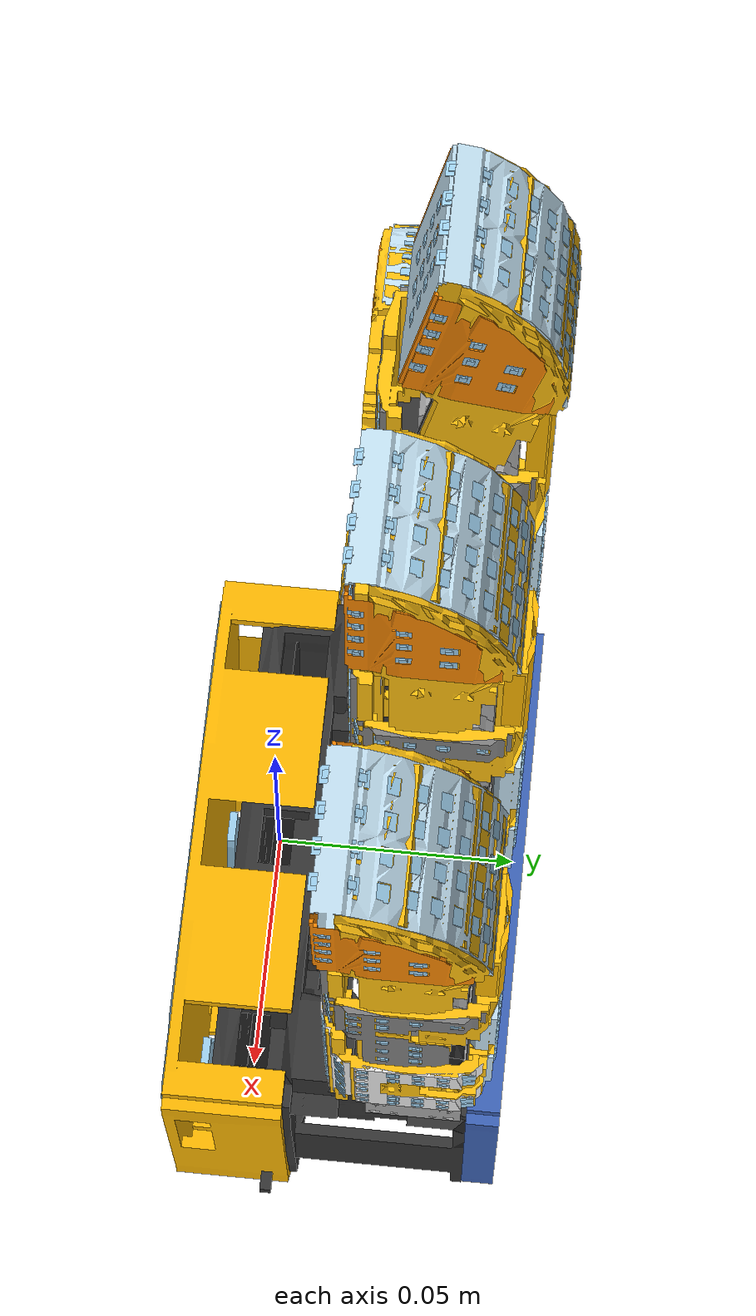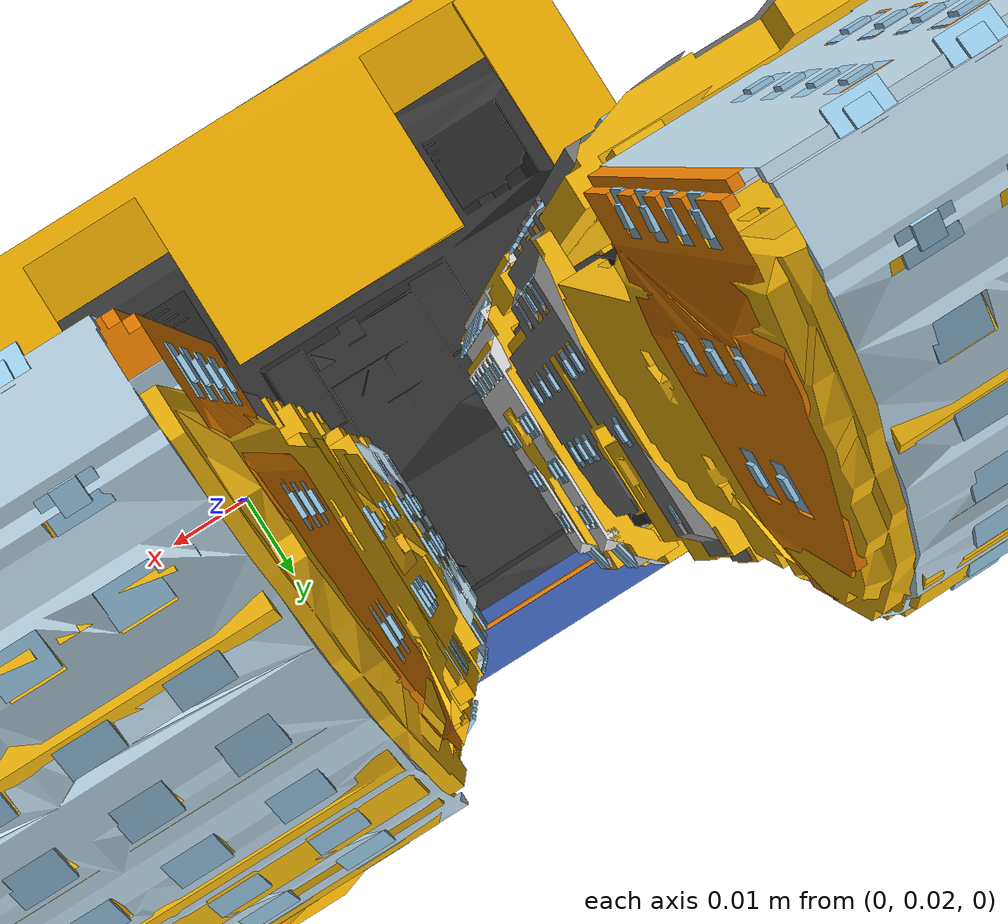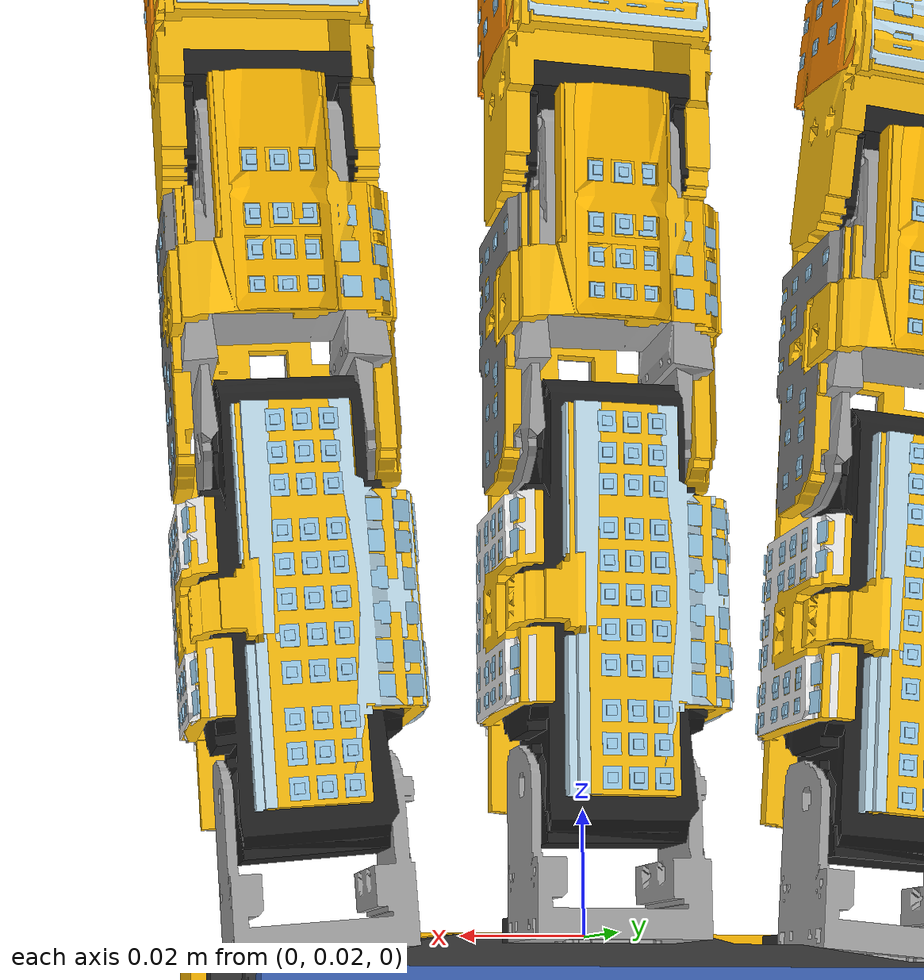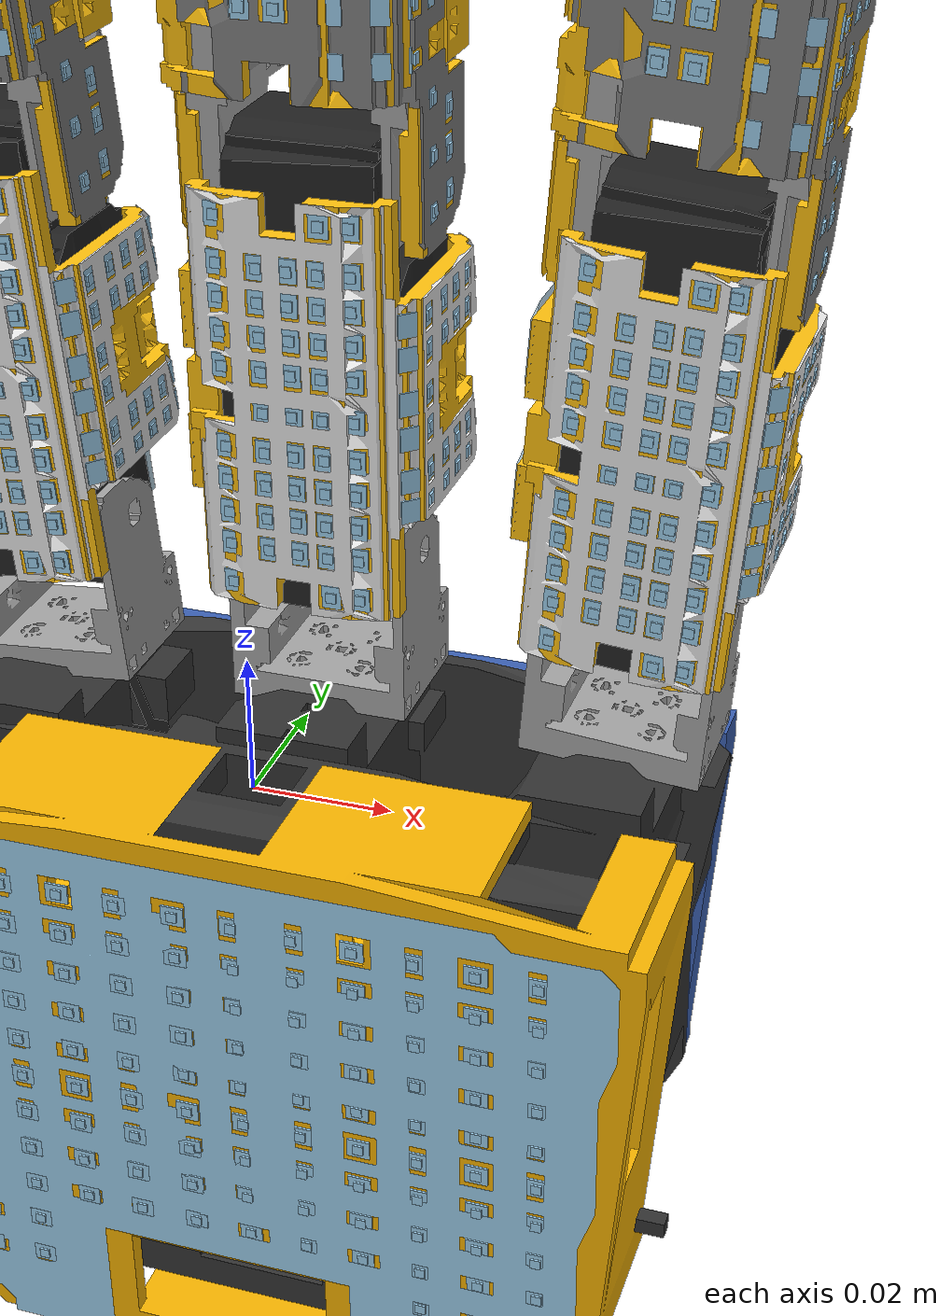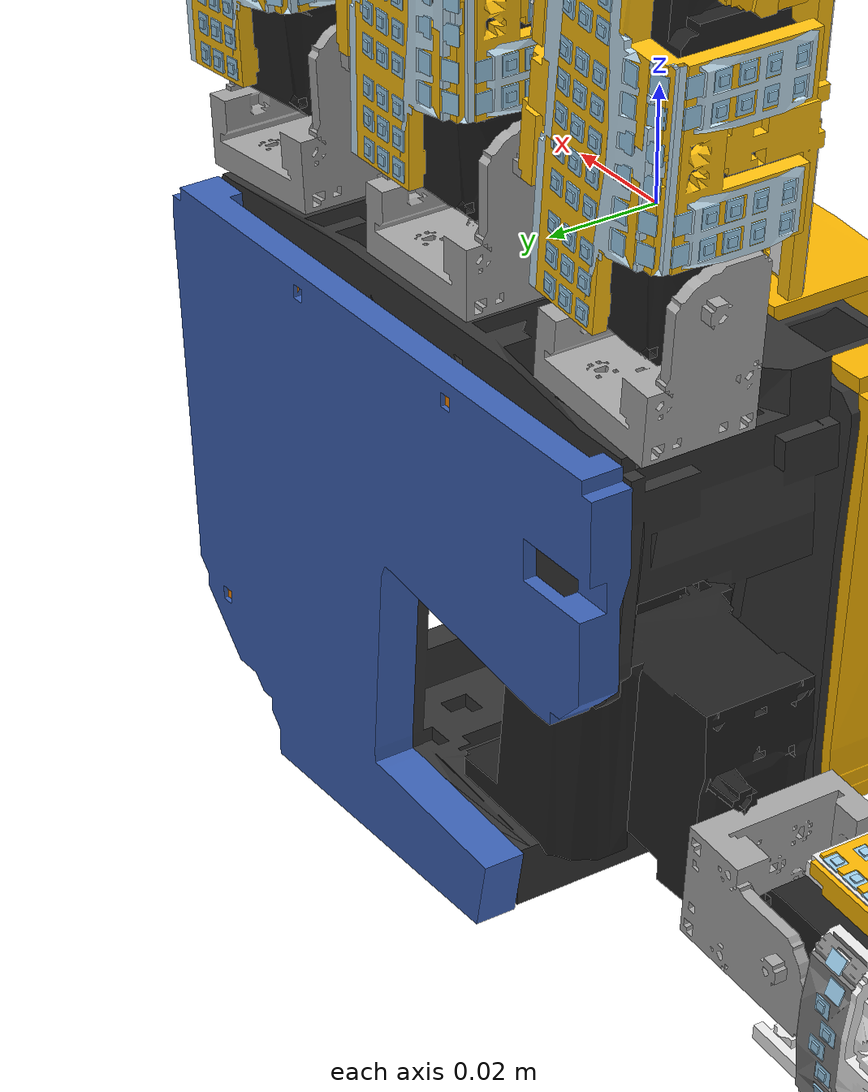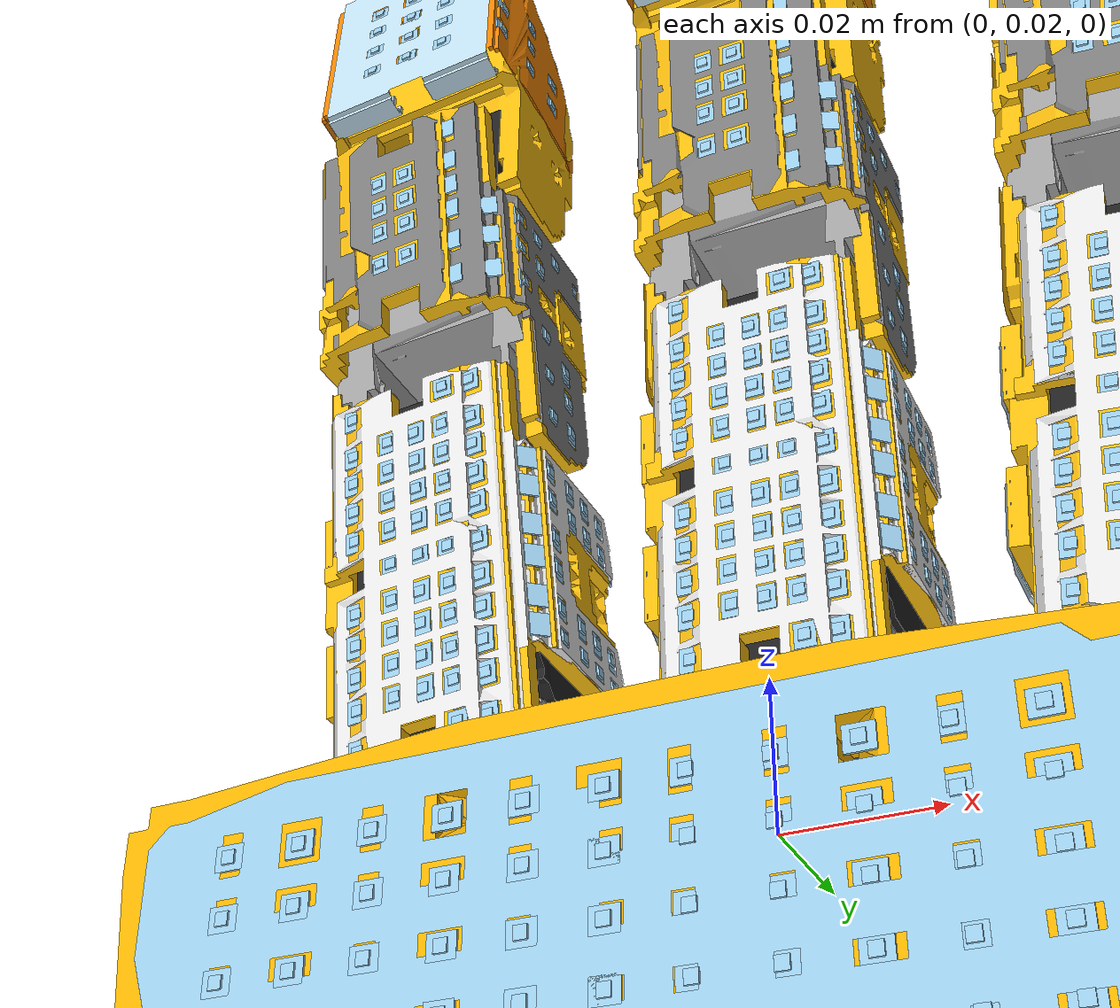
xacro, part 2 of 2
</joint>

<joint name="joint_pft_taxel_64" type="fixed">
<origin xyz="0.00566844 0.000344096 0.00479735" rpy="3.14159 -1.68547e-17 0.279253" />
<parent link="pinky_fingertip_main_fpcb" />
<child link="pft_taxel_64" />
<axis xyz="0 0 1"/>
<limit effort="1" velocity="20" />
<joint_properties friction="0.0"/>
</joint>

<link name="pft_taxel_65">
<visual>
<origin xyz="-0.0014 -0.0003 0.0016" rpy="-1.5708 1.5708 0" />
<geometry>
<mesh filename="package://allegro_hand_description/meshes/taxel_abnormal_3.stl"/>
</geometry>
<material name="taxel_abnormal_3_material">
<color rgba="0.615686 0.811765 0.929412 1.0"/>
</material>
</visual>
<collision>
<origin xyz="-0.0014 -0.0003 0.0016" rpy="-1.5708 1.5708 0" />
<geometry>
<mesh filename="package://allegro_hand_description/meshes/taxel_abnormal_3.stl"/>
</geometry>
<material name="taxel_abnormal_3_material">
<color rgba="0.615686 0.811765 0.929412 1.0"/>
</material>
</collision>
<inertial>
<origin xyz="-0.0014 -0.00015 0.0016" rpy="0 0 0"/>
<mass value="5.376e-06" />
<inertia ixx="8.09984e-12" ixy="-2.58854e-28"  ixz="8.02988e-30" iyy="3.55264e-12" iyz="-5.21083e-29" izz="4.62784e-12" />
</inertial>
</link>

<link name="pft_sub_taxel_65">
<visual>
<origin xyz="0 0 -0.0001" rpy="5.03912e-17 1.06978e-18 -1.58346e-17" />
<geometry>
<mesh filename="package://allegro_hand_description/meshes/thin_sub_taxel.stl"/>
</geometry>
<material name="thin_sub_taxel_material">
<color rgba="0.615686 0.811765 0.929412 1.0"/>
</material>
</visual>
<collision>
<origin xyz="0 0 -0.0001" rpy="5.03912e-17 1.06978e-18 -1.58346e-17" />
<geometry>
<mesh filename="package://allegro_hand_description/meshes/thin_sub_taxel.stl"/>
</geometry>
<material name="thin_sub_taxel_material">
<color rgba="0.615686 0.811765 0.929412 1.0"/>
</material>
</collision>
<inertial>
<origin xyz="-5.68732e-20 -9.84143e-20 -5e-05" rpy="0 0 0"/>
<mass value="5e-08" />
<inertia ixx="1.08333e-15" ixy="-1.6087e-32"  ixz="-2.16701e-33" iyy="1.08333e-15" iyz="1.07084e-31" izz="2.08333e-15" />
</inertial>
</link>

<joint name="joint_pft_sub_taxel_65" type="fixed">
<origin xyz="-0.0014 -0.0003 0.0016" rpy="-1.5708 -1.5708 0" />
<parent link="pft_taxel_65" />
<child link="pft_sub_taxel_65" />
<axis xyz="0 0 1"/>
<limit effort="1" velocity="20" />
<joint_properties friction="0.0"/>
</joint>

<joint name="joint_pft_taxel_65" type="fixed">
<origin xyz="0.00566845 0.000344098 0.0111474" rpy="-3.14159 -4.48633e-17 0.279253" />
<parent link="pinky_fingertip_main_fpcb" />
<child link="pft_taxel_65" />
<axis xyz="0 0 1"/>
<limit effort="1" velocity="20" />
<joint_properties friction="0.0"/>
</joint>

<joint name="joint_pinky_fingertip_main_fpcb" type="fixed">
<origin xyz="0.00776046 -0.01766 0.0135" rpy="9.62221e-16 -1.60204e-15 6.56501e-28" />
<parent link="pinky_fingertip_bracket" />
<child link="pinky_fingertip_main_fpcb" />
<axis xyz="0 0 1"/>
<limit effort="1" velocity="20" />
<joint_properties friction="0.0"/>
</joint>

<link name="pinky_fingertip_side_fpcb">
<visual>
<origin xyz="-0.153816 0.0136001 -0.0162593" rpy="6.25542e-31 -8.38165e-19 1.8496e-29" />
<geometry>
<mesh filename="package://allegro_hand_description/meshes/distal_fpcb_2.stl"/>
</geometry>
<material name="distal_fpcb_2_material">
<color rgba="0.972549 0.529412 0.00392157 1.0"/>
</material>
</visual>
<collision>
<origin xyz="-0.153816 0.0136001 -0.0162593" rpy="6.25542e-31 -8.38165e-19 1.8496e-29" />
<geometry>
<mesh filename="package://allegro_hand_description/meshes/distal_fpcb_2.stl"/>
</geometry>
<material name="distal_fpcb_2_material">
<color rgba="0.972549 0.529412 0.00392157 1.0"/>
</material>
</collision>
<inertial>
<origin xyz="-0.0175916 0.00317983 -0.0164175" rpy="0 0 0"/>
<mass value="0.00128609" />
<inertia ixx="3.5341e-07" ixy="2.54188e-08"  ixz="-2.1826e-09" iyy="3.67946e-07" iyz="1.2158e-09" izz="1.99436e-07" />
</inertial>
</link>

<link name="pft_taxel_0">
<visual>
<origin xyz="0.0016 -0.0003 -0.0014" rpy="-1.5708 7.7443e-17 1.42827e-30" />
<geometry>
<mesh filename="package://allegro_hand_description/meshes/taxel_abnormal_3.stl"/>
</geometry>
<material name="taxel_abnormal_3_material">
<color rgba="0.615686 0.811765 0.929412 1.0"/>
</material>
</visual>
<collision>
<origin xyz="0.0016 -0.0003 -0.0014" rpy="-1.5708 7.7443e-17 1.42827e-30" />
<geometry>
<mesh filename="package://allegro_hand_description/meshes/taxel_abnormal_3.stl"/>
</geometry>
<material name="taxel_abnormal_3_material">
<color rgba="0.615686 0.811765 0.929412 1.0"/>
</material>
</collision>
<inertial>
<origin xyz="0.0016 -0.00015 -0.0014" rpy="0 0 0"/>
<mass value="5.376e-06" />
<inertia ixx="3.55264e-12" ixy="3.52149e-28"  ixz="2.68335e-42" iyy="8.09984e-12" iyz="4.29593e-29" izz="4.62784e-12" />
</inertial>
</link>

<link name="pft_sub_taxel_0">
<visual>
<origin xyz="2.77556e-17 0 -0.0003" rpy="-1.97986e-31 4.9341e-18 9.54743e-31" />
<geometry>
<mesh filename="package://allegro_hand_description/meshes/sub_taxel.stl"/>
</geometry>
<material name="sub_taxel_material">
<color rgba="0.615686 0.811765 0.929412 1.0"/>
</material>
</visual>
<collision>
<origin xyz="2.77556e-17 0 -0.0003" rpy="-1.97986e-31 4.9341e-18 9.54743e-31" />
<geometry>
<mesh filename="package://allegro_hand_description/meshes/sub_taxel.stl"/>
</geometry>
<material name="sub_taxel_material">
<color rgba="0.615686 0.811765 0.929412 1.0"/>
</material>
</collision>
<inertial>
<origin xyz="2.75874e-17 1.45818e-19 -0.00015" rpy="0 0 0"/>
<mass value="1.35e-06" />
<inertia ixx="2.6325e-13" ixy="-7.70778e-43"  ixz="-4.48429e-30" iyy="2.6325e-13" iyz="4.00857e-43" izz="5.0625e-13" />
</inertial>
</link>

<joint name="joint_pft_sub_taxel_0" type="fixed">
<origin xyz="0.0016 -1.45717e-16 -0.0014" rpy="1.5708 -1.5708 0" />
<parent link="pft_taxel_0" />
<child link="pft_sub_taxel_0" />
<axis xyz="0 0 1"/>
<limit effort="1" velocity="20" />
<joint_properties friction="0.0"/>
</joint>

<joint name="joint_pft_taxel_0" type="fixed">
<origin xyz="-0.0227906 0.0147544 0.00101548" rpy="1.5708 4.83812e-18 1.5708" />
<parent link="pinky_fingertip_side_fpcb" />
<child link="pft_taxel_0" />
<axis xyz="0 0 1"/>
<limit effort="1" velocity="20" />
<joint_properties friction="0.0"/>
</joint>

<link name="pft_taxel_1">
<visual>
<origin xyz="0.0016 -0.0003 -0.0014" rpy="-1.5708 7.7443e-17 1.38628e-30" />
<geometry>
<mesh filename="package://allegro_hand_description/meshes/taxel_abnormal_3.stl"/>
</geometry>
<material name="taxel_abnormal_3_material">
<color rgba="0.615686 0.811765 0.929412 1.0"/>
</material>
</visual>
<collision>
<origin xyz="0.0016 -0.0003 -0.0014" rpy="-1.5708 7.7443e-17 1.38628e-30" />
<geometry>
<mesh filename="package://allegro_hand_description/meshes/taxel_abnormal_3.stl"/>
</geometry>
<material name="taxel_abnormal_3_material">
<color rgba="0.615686 0.811765 0.929412 1.0"/>
</material>
</collision>
<inertial>
<origin xyz="0.0016 -0.00015 -0.0014" rpy="0 0 0"/>
<mass value="5.376e-06" />
<inertia ixx="3.55264e-12" ixy="3.52149e-28"  ixz="9.33857e-42" iyy="8.09984e-12" iyz="-1.54023e-28" izz="4.62784e-12" />
</inertial>
</link>

<link name="pft_sub_taxel_1">
<visual>
<origin xyz="2.77556e-17 0 -0.0003" rpy="6.74461e-31 1.05672e-17 -2.01982e-30" />
<geometry>
<mesh filename="package://allegro_hand_description/meshes/sub_taxel.stl"/>
</geometry>
<material name="sub_taxel_material">
<color rgba="0.615686 0.811765 0.929412 1.0"/>
</material>
</visual>
<collision>
<origin xyz="2.77556e-17 0 -0.0003" rpy="6.74461e-31 1.05672e-17 -2.01982e-30" />
<geometry>
<mesh filename="package://allegro_hand_description/meshes/sub_taxel.stl"/>
</geometry>
<material name="sub_taxel_material">
<color rgba="0.615686 0.811765 0.929412 1.0"/>
</material>
</collision>
<inertial>
<origin xyz="2.75882e-17 1.45818e-19 -0.00015" rpy="0 0 0"/>
<mass value="1.35e-06" />
<inertia ixx="2.6325e-13" ixy="3.86662e-42"  ixz="-5.92265e-30" iyy="2.6325e-13" iyz="2.76123e-43" izz="5.0625e-13" />
</inertial>
</link>

<joint name="joint_pft_sub_taxel_1" type="fixed">
<origin xyz="0.0016 -3.81639e-17 -0.0014" rpy="1.5708 1.5708 0" />
<parent link="pft_taxel_1" />
<child link="pft_sub_taxel_1" />
<axis xyz="0 0 1"/>
<limit effort="1" velocity="20" />
<joint_properties friction="0.0"/>
</joint>

<joint name="joint_pft_taxel_1" type="fixed">
<origin xyz="-0.0256906 0.00953199 0.00100024" rpy="1.5708 8.95177e-17 -1.5708" />
<parent link="pinky_fingertip_side_fpcb" />
<child link="pft_taxel_1" />
<axis xyz="0 0 1"/>
<limit effort="1" velocity="20" />
<joint_properties friction="0.0"/>
</joint>

<link name="pft_taxel_2">
<visual>
<origin xyz="0.0016 -0.0003 -0.0014" rpy="-1.5708 7.7443e-17 1.38628e-30" />
<geometry>
<mesh filename="package://allegro_hand_description/meshes/taxel_abnormal_3.stl"/>
</geometry>
<material name="taxel_abnormal_3_material">
<color rgba="0.615686 0.811765 0.929412 1.0"/>
</material>
</visual>
<collision>
<origin xyz="0.0016 -0.0003 -0.0014" rpy="-1.5708 7.7443e-17 1.38628e-30" />
<geometry>
<mesh filename="package://allegro_hand_description/meshes/taxel_abnormal_3.stl"/>
</geometry>
<material name="taxel_abnormal_3_material">
<color rgba="0.615686 0.811765 0.929412 1.0"/>
</material>
</collision>
<inertial>
<origin xyz="0.0016 -0.00015 -0.0014" rpy="0 0 0"/>
<mass value="5.376e-06" />
<inertia ixx="3.55264e-12" ixy="3.52149e-28"  ixz="9.33857e-42" iyy="8.09984e-12" iyz="-1.54023e-28" izz="4.62784e-12" />
</inertial>
</link>

<link name="pft_sub_taxel_2">
<visual>
<origin xyz="0 0 -0.0003" rpy="6.74461e-31 1.05672e-17 -2.01982e-30" />
<geometry>
<mesh filename="package://allegro_hand_description/meshes/sub_taxel.stl"/>
</geometry>
<material name="sub_taxel_material">
<color rgba="0.615686 0.811765 0.929412 1.0"/>
</material>
</visual>
<collision>
<origin xyz="0 0 -0.0003" rpy="6.74461e-31 1.05672e-17 -2.01982e-30" />
<geometry>
<mesh filename="package://allegro_hand_description/meshes/sub_taxel.stl"/>
</geometry>
<material name="sub_taxel_material">
<color rgba="0.615686 0.811765 0.929412 1.0"/>
</material>
</collision>
<inertial>
<origin xyz="-1.67414e-19 1.45818e-19 -0.00015" rpy="0 0 0"/>
<mass value="1.35e-06" />
<inertia ixx="2.6325e-13" ixy="3.86662e-42"  ixz="-5.92265e-30" iyy="2.6325e-13" iyz="2.76123e-43" izz="5.0625e-13" />
</inertial>
</link>

<joint name="joint_pft_sub_taxel_2" type="fixed">
<origin xyz="0.0016 -1.42247e-16 -0.0014" rpy="1.5708 1.5708 0" />
<parent link="pft_taxel_2" />
<child link="pft_sub_taxel_2" />
<axis xyz="0 0 1"/>
<limit effort="1" velocity="20" />
<joint_properties friction="0.0"/>
</joint>

<joint name="joint_pft_taxel_2" type="fixed">
<origin xyz="-0.0256906 0.00102456 0.000418437" rpy="1.5708 8.95177e-17 -1.5708" />
<parent link="pinky_fingertip_side_fpcb" />
<child link="pft_taxel_2" />
<axis xyz="0 0 1"/>
<limit effort="1" velocity="20" />
<joint_properties friction="0.0"/>
</joint>

<link name="pft_taxel_6">
<visual>
<origin xyz="-0.0016 -0.0003 0.0014" rpy="-1.5708 7.77754e-17 -1.53402e-17" />
<geometry>
<mesh filename="package://allegro_hand_description/meshes/taxel_abnormal_3.stl"/>
</geometry>
<material name="taxel_abnormal_3_material">
<color rgba="0.615686 0.811765 0.929412 1.0"/>
</material>
</visual>
<collision>
<origin xyz="-0.0016 -0.0003 0.0014" rpy="-1.5708 7.77754e-17 -1.53402e-17" />
<geometry>
<mesh filename="package://allegro_hand_description/meshes/taxel_abnormal_3.stl"/>
</geometry>
<material name="taxel_abnormal_3_material">
<color rgba="0.615686 0.811765 0.929412 1.0"/>
</material>
</collision>
<inertial>
<origin xyz="-0.0016 -0.00015 0.0014" rpy="0 0 0"/>
<mass value="5.376e-06" />
<inertia ixx="3.55264e-12" ixy="3.549e-28"  ixz="-6.66449e-29" iyy="8.09984e-12" iyz="5.53855e-29" izz="4.62784e-12" />
</inertial>
</link>

<link name="pft_sub_taxel_6">
<visual>
<origin xyz="2.77556e-17 3.46945e-18 -0.0003" rpy="1.82986e-19 5.58452e-18 -5.22603e-19" />
<geometry>
<mesh filename="package://allegro_hand_description/meshes/sub_taxel.stl"/>
</geometry>
<material name="sub_taxel_material">
<color rgba="0.615686 0.811765 0.929412 1.0"/>
</material>
</visual>
<collision>
<origin xyz="2.77556e-17 3.46945e-18 -0.0003" rpy="1.82986e-19 5.58452e-18 -5.22603e-19" />
<geometry>
<mesh filename="package://allegro_hand_description/meshes/sub_taxel.stl"/>
</geometry>
<material name="sub_taxel_material">
<color rgba="0.615686 0.811765 0.929412 1.0"/>
</material>
</collision>
<inertial>
<origin xyz="2.75921e-17 3.61722e-18 -0.00015" rpy="0 0 0"/>
<mass value="1.35e-06" />
<inertia ixx="2.6325e-13" ixy="-4.56663e-31"  ixz="3.52711e-30" iyy="2.6325e-13" iyz="3.51536e-30" izz="5.0625e-13" />
</inertial>
</link>

<joint name="joint_pft_sub_taxel_6" type="fixed">
<origin xyz="-0.0016 3.53884e-16 0.0014" rpy="1.5708 1.5708 0" />
<parent link="pft_taxel_6" />
<child link="pft_sub_taxel_6" />
<axis xyz="0 0 1"/>
<limit effort="1" velocity="20" />
<joint_properties friction="0.0"/>
</joint>

<joint name="joint_pft_taxel_6" type="fixed">
<origin xyz="-0.0227906 -0.000541199 -0.0328179" rpy="-1.5708 0.0872665 1.5708" />
<parent link="pinky_fingertip_side_fpcb" />
<child link="pft_taxel_6" />
<axis xyz="0 0 1"/>
<limit effort="1" velocity="20" />
<joint_properties friction="0.0"/>
</joint>

<link name="pft_taxel_7">
<visual>
<origin xyz="-0.0016 -0.0003 0.0014" rpy="-1.5708 7.7443e-17 -1.4822e-30" />
<geometry>
<mesh filename="package://allegro_hand_description/meshes/taxel_abnormal_3.stl"/>
</geometry>
<material name="taxel_abnormal_3_material">
<color rgba="0.615686 0.811765 0.929412 1.0"/>
</material>
</visual>
<collision>
<origin xyz="-0.0016 -0.0003 0.0014" rpy="-1.5708 7.7443e-17 -1.4822e-30" />
<geometry>
<mesh filename="package://allegro_hand_description/meshes/taxel_abnormal_3.stl"/>
</geometry>
<material name="taxel_abnormal_3_material">
<color rgba="0.615686 0.811765 0.929412 1.0"/>
</material>
</collision>
<inertial>
<origin xyz="-0.0016 -0.00015 0.0014" rpy="0 0 0"/>
<mass value="5.376e-06" />
<inertia ixx="3.55264e-12" ixy="3.52149e-28"  ixz="6.47165e-42" iyy="8.09984e-12" iyz="1.56773e-28" izz="4.62784e-12" />
</inertial>
</link>

<link name="pft_sub_taxel_7">
<visual>
<origin xyz="2.77556e-17 0 -0.0003" rpy="-7.98105e-31 -3.16177e-18 1.49284e-29" />
<geometry>
<mesh filename="package://allegro_hand_description/meshes/sub_taxel.stl"/>
</geometry>
<material name="sub_taxel_material">
<color rgba="0.615686 0.811765 0.929412 1.0"/>
</material>
</visual>
<collision>
<origin xyz="2.77556e-17 0 -0.0003" rpy="-7.98105e-31 -3.16177e-18 1.49284e-29" />
<geometry>
<mesh filename="package://allegro_hand_description/meshes/sub_taxel.stl"/>
</geometry>
<material name="sub_taxel_material">
<color rgba="0.615686 0.811765 0.929412 1.0"/>
</material>
</collision>
<inertial>
<origin xyz="2.75872e-17 1.45818e-19 -0.00015" rpy="0 0 0"/>
<mass value="1.35e-06" />
<inertia ixx="2.6325e-13" ixy="7.62574e-42"  ixz="-6.22361e-31" iyy="2.6325e-13" iyz="1.24012e-43" izz="5.0625e-13" />
</inertial>
</link>

<joint name="joint_pft_sub_taxel_7" type="fixed">
<origin xyz="-0.0016 2.91434e-16 0.0014" rpy="1.5708 1.5708 0" />
<parent link="pft_taxel_7" />
<child link="pft_sub_taxel_7" />
<axis xyz="0 0 1"/>
<limit effort="1" velocity="20" />
<joint_properties friction="0.0"/>
</joint>

<joint name="joint_pft_taxel_7" type="fixed">
<origin xyz="-0.0227906 0.00805951 -0.0334676" rpy="-1.5708 -8.57136e-17 1.5708" />
<parent link="pinky_fingertip_side_fpcb" />
<child link="pft_taxel_7" />
<axis xyz="0 0 1"/>
<limit effort="1" velocity="20" />
<joint_properties friction="0.0"/>
</joint>

<link name="pft_taxel_8">
<visual>
<origin xyz="-0.0016 -0.0003 0.0014" rpy="-1.5708 7.7443e-17 -1.98255e-30" />
<geometry>
<mesh filename="package://allegro_hand_description/meshes/taxel_abnormal_3.stl"/>
</geometry>
<material name="taxel_abnormal_3_material">
<color rgba="0.615686 0.811765 0.929412 1.0"/>
</material>
</visual>
<collision>
<origin xyz="-0.0016 -0.0003 0.0014" rpy="-1.5708 7.7443e-17 -1.98255e-30" />
<geometry>
<mesh filename="package://allegro_hand_description/meshes/taxel_abnormal_3.stl"/>
</geometry>
<material name="taxel_abnormal_3_material">
<color rgba="0.615686 0.811765 0.929412 1.0"/>
</material>
</collision>
<inertial>
<origin xyz="-0.0016 -0.00015 0.0014" rpy="0 0 0"/>
<mass value="5.376e-06" />
<inertia ixx="3.55264e-12" ixy="3.52149e-28"  ixz="-4.55628e-42" iyy="8.09984e-12" iyz="2.79496e-29" izz="4.62784e-12" />
</inertial>
</link>

<link name="pft_sub_taxel_8">
<visual>
<origin xyz="2.77556e-17 -6.93889e-18 -0.0003" rpy="-3.28949e-31 1.81949e-17 4.05445e-30" />
<geometry>
<mesh filename="package://allegro_hand_description/meshes/sub_taxel.stl"/>
</geometry>
<material name="sub_taxel_material">
<color rgba="0.615686 0.811765 0.929412 1.0"/>
</material>
</visual>
<collision>
<origin xyz="2.77556e-17 -6.93889e-18 -0.0003" rpy="-3.28949e-31 1.81949e-17 4.05445e-30" />
<geometry>
<mesh filename="package://allegro_hand_description/meshes/sub_taxel.stl"/>
</geometry>
<material name="sub_taxel_material">
<color rgba="0.615686 0.811765 0.929412 1.0"/>
</material>
</collision>
<inertial>
<origin xyz="2.75878e-17 -6.79308e-18 -0.00015" rpy="0 0 0"/>
<mass value="1.35e-06" />
<inertia ixx="2.6325e-13" ixy="2.48531e-42"  ixz="-1.03512e-29" iyy="2.6325e-13" iyz="4.17737e-43" izz="5.0625e-13" />
</inertial>
</link>

<joint name="joint_pft_sub_taxel_8" type="fixed">
<origin xyz="-0.0016 1.52656e-16 0.0014" rpy="1.5708 1.5708 0" />
<parent link="pft_taxel_8" />
<child link="pft_sub_taxel_8" />
<axis xyz="0 0 1"/>
<limit effort="1" velocity="20" />
<joint_properties friction="0.0"/>
</joint>

<joint name="joint_pft_taxel_8" type="fixed">
<origin xyz="-0.0256906 0.0130689 -0.0335575" rpy="-1.5708 -6.56781e-18 -1.5708" />
<parent link="pinky_fingertip_side_fpcb" />
<child link="pft_taxel_8" />
<axis xyz="0 0 1"/>
<limit effort="1" velocity="20" />
<joint_properties friction="0.0"/>
</joint>

<link name="pft_taxel_9">
<visual>
<origin xyz="0.0016 -0.0003 -0.0014" rpy="-1.5708 7.7443e-17 1.42827e-30" />
<geometry>
<mesh filename="package://allegro_hand_description/meshes/taxel_abnormal_3.stl"/>
</geometry>
<material name="taxel_abnormal_3_material">
<color rgba="0.615686 0.811765 0.929412 1.0"/>
</material>
</visual>
<collision>
<origin xyz="0.0016 -0.0003 -0.0014" rpy="-1.5708 7.7443e-17 1.42827e-30" />
<geometry>
<mesh filename="package://allegro_hand_description/meshes/taxel_abnormal_3.stl"/>
</geometry>
<material name="taxel_abnormal_3_material">
<color rgba="0.615686 0.811765 0.929412 1.0"/>
</material>
</collision>
<inertial>
<origin xyz="0.0016 -0.00015 -0.0014" rpy="0 0 0"/>
<mass value="5.376e-06" />
<inertia ixx="3.55264e-12" ixy="3.52149e-28"  ixz="2.68335e-42" iyy="8.09984e-12" iyz="4.29593e-29" izz="4.62784e-12" />
</inertial>
</link>

<link name="pft_sub_taxel_9">
<visual>
<origin xyz="2.77556e-17 6.93889e-18 -0.0003" rpy="-1.97986e-31 4.9341e-18 9.54743e-31" />
<geometry>
<mesh filename="package://allegro_hand_description/meshes/sub_taxel.stl"/>
</geometry>
<material name="sub_taxel_material">
<color rgba="0.615686 0.811765 0.929412 1.0"/>
</material>
</visual>
<collision>
<origin xyz="2.77556e-17 6.93889e-18 -0.0003" rpy="-1.97986e-31 4.9341e-18 9.54743e-31" />
<geometry>
<mesh filename="package://allegro_hand_description/meshes/sub_taxel.stl"/>
</geometry>
<material name="sub_taxel_material">
<color rgba="0.615686 0.811765 0.929412 1.0"/>
</material>
</collision>
<inertial>
<origin xyz="2.75874e-17 7.08471e-18 -0.00015" rpy="0 0 0"/>
<mass value="1.35e-06" />
<inertia ixx="2.6325e-13" ixy="-7.70778e-43"  ixz="-4.48429e-30" iyy="2.6325e-13" iyz="4.00857e-43" izz="5.0625e-13" />
</inertial>
</link>

<joint name="joint_pft_sub_taxel_9" type="fixed">
<origin xyz="0.0016 -4.51028e-17 -0.0014" rpy="1.5708 -1.5708 0" />
<parent link="pft_taxel_9" />
<child link="pft_sub_taxel_9" />
<axis xyz="0 0 1"/>
<limit effort="1" velocity="20" />
<joint_properties friction="0.0"/>
</joint>

<joint name="joint_pft_taxel_9" type="fixed">
<origin xyz="-0.0164543 0.0147544 0.00101548" rpy="1.5708 4.83812e-18 1.5708" />
<parent link="pinky_fingertip_side_fpcb" />
<child link="pft_taxel_9" />
<axis xyz="0 0 1"/>
<limit effort="1" velocity="20" />
<joint_properties friction="0.0"/>
</joint>

<link name="pft_taxel_10">
<visual>
<origin xyz="0.0016 -0.0003 -0.0014" rpy="-1.5708 7.7443e-17 1.38628e-30" />
<geometry>
<mesh filename="package://allegro_hand_description/meshes/taxel_abnormal_3.stl"/>
</geometry>
<material name="taxel_abnormal_3_material">
<color rgba="0.615686 0.811765 0.929412 1.0"/>
</material>
</visual>
<collision>
<origin xyz="0.0016 -0.0003 -0.0014" rpy="-1.5708 7.7443e-17 1.38628e-30" />
<geometry>
<mesh filename="package://allegro_hand_description/meshes/taxel_abnormal_3.stl"/>
</geometry>
<material name="taxel_abnormal_3_material">
<color rgba="0.615686 0.811765 0.929412 1.0"/>
</material>
</collision>
<inertial>
<origin xyz="0.0016 -0.00015 -0.0014" rpy="0 0 0"/>
<mass value="5.376e-06" />
<inertia ixx="3.55264e-12" ixy="3.52149e-28"  ixz="9.33857e-42" iyy="8.09984e-12" iyz="-1.54023e-28" izz="4.62784e-12" />
</inertial>
</link>

<link name="pft_sub_taxel_10">
<visual>
<origin xyz="2.77556e-17 0 -0.0003" rpy="6.74461e-31 1.05672e-17 -2.01982e-30" />
<geometry>
<mesh filename="package://allegro_hand_description/meshes/sub_taxel.stl"/>
</geometry>
<material name="sub_taxel_material">
<color rgba="0.615686 0.811765 0.929412 1.0"/>
</material>
</visual>
<collision>
<origin xyz="2.77556e-17 0 -0.0003" rpy="6.74461e-31 1.05672e-17 -2.01982e-30" />
<geometry>
<mesh filename="package://allegro_hand_description/meshes/sub_taxel.stl"/>
</geometry>
<material name="sub_taxel_material">
<color rgba="0.615686 0.811765 0.929412 1.0"/>
</material>
</collision>
<inertial>
<origin xyz="2.75882e-17 1.45818e-19 -0.00015" rpy="0 0 0"/>
<mass value="1.35e-06" />
<inertia ixx="2.6325e-13" ixy="3.86662e-42"  ixz="-5.92265e-30" iyy="2.6325e-13" iyz="2.76123e-43" izz="5.0625e-13" />
</inertial>
</link>

<joint name="joint_pft_sub_taxel_10" type="fixed">
<origin xyz="0.0016 2.91434e-16 -0.0014" rpy="1.5708 1.5708 0" />
<parent link="pft_taxel_10" />
<child link="pft_sub_taxel_10" />
<axis xyz="0 0 1"/>
<limit effort="1" velocity="20" />
<joint_properties friction="0.0"/>
</joint>

<joint name="joint_pft_taxel_10" type="fixed">
<origin xyz="-0.0193543 0.00953199 0.00100024" rpy="1.5708 8.95177e-17 -1.5708" />
<parent link="pinky_fingertip_side_fpcb" />
<child link="pft_taxel_10" />
<axis xyz="0 0 1"/>
<limit effort="1" velocity="20" />
<joint_properties friction="0.0"/>
</joint>

<link name="pft_taxel_11">
<visual>
<origin xyz="0.0016 -0.0003 -0.0014" rpy="-1.5708 7.7443e-17 1.38628e-30" />
<geometry>
<mesh filename="package://allegro_hand_description/meshes/taxel_abnormal_3.stl"/>
</geometry>
<material name="taxel_abnormal_3_material">
<color rgba="0.615686 0.811765 0.929412 1.0"/>
</material>
</visual>
<collision>
<origin xyz="0.0016 -0.0003 -0.0014" rpy="-1.5708 7.7443e-17 1.38628e-30" />
<geometry>
<mesh filename="package://allegro_hand_description/meshes/taxel_abnormal_3.stl"/>
</geometry>
<material name="taxel_abnormal_3_material">
<color rgba="0.615686 0.811765 0.929412 1.0"/>
</material>
</collision>
<inertial>
<origin xyz="0.0016 -0.00015 -0.0014" rpy="0 0 0"/>
<mass value="5.376e-06" />
<inertia ixx="3.55264e-12" ixy="3.52149e-28"  ixz="9.33857e-42" iyy="8.09984e-12" iyz="-1.54023e-28" izz="4.62784e-12" />
</inertial>
</link>

<link name="pft_sub_taxel_11">
<visual>
<origin xyz="-2.77556e-17 0 -0.0003" rpy="6.74461e-31 1.05672e-17 -2.01982e-30" />
<geometry>
<mesh filename="package://allegro_hand_description/meshes/sub_taxel.stl"/>
</geometry>
<material name="sub_taxel_material">
<color rgba="0.615686 0.811765 0.929412 1.0"/>
</material>
</visual>
<collision>
<origin xyz="-2.77556e-17 0 -0.0003" rpy="6.74461e-31 1.05672e-17 -2.01982e-30" />
<geometry>
<mesh filename="package://allegro_hand_description/meshes/sub_taxel.stl"/>
</geometry>
<material name="sub_taxel_material">
<color rgba="0.615686 0.811765 0.929412 1.0"/>
</material>
</collision>
<inertial>
<origin xyz="-2.7923e-17 1.45818e-19 -0.00015" rpy="0 0 0"/>
<mass value="1.35e-06" />
<inertia ixx="2.6325e-13" ixy="3.86662e-42"  ixz="-5.92265e-30" iyy="2.6325e-13" iyz="2.76123e-43" izz="5.0625e-13" />
</inertial>
</link>

<joint name="joint_pft_sub_taxel_11" type="fixed">
<origin xyz="0.0016 7.63278e-17 -0.0014" rpy="1.5708 1.5708 0" />
<parent link="pft_taxel_11" />
<child link="pft_sub_taxel_11" />
<axis xyz="0 0 1"/>
<limit effort="1" velocity="20" />
<joint_properties friction="0.0"/>
</joint>

<joint name="joint_pft_taxel_11" type="fixed">
<origin xyz="-0.0193543 0.00102456 0.000418437" rpy="1.5708 8.95177e-17 -1.5708" />
<parent link="pinky_fingertip_side_fpcb" />
<child link="pft_taxel_11" />
<axis xyz="0 0 1"/>
<limit effort="1" velocity="20" />
<joint_properties friction="0.0"/>
</joint>

<link name="pft_taxel_15">
<visual>
<origin xyz="-0.0016 -0.0003 0.0014" rpy="-1.5708 7.70136e-17 -1.92641e-17" />
<geometry>
<mesh filename="package://allegro_hand_description/meshes/taxel_abnormal_3.stl"/>
</geometry>
<material name="taxel_abnormal_3_material">
<color rgba="0.615686 0.811765 0.929412 1.0"/>
</material>
</visual>
<collision>
<origin xyz="-0.0016 -0.0003 0.0014" rpy="-1.5708 7.70136e-17 -1.92641e-17" />
<geometry>
<mesh filename="package://allegro_hand_description/meshes/taxel_abnormal_3.stl"/>
</geometry>
<material name="taxel_abnormal_3_material">
<color rgba="0.615686 0.811765 0.929412 1.0"/>
</material>
</collision>
<inertial>
<origin xyz="-0.0016 -0.00015 0.0014" rpy="0 0 0"/>
<mass value="5.376e-06" />
<inertia ixx="3.55264e-12" ixy="3.48765e-28"  ixz="-7.57728e-29" iyy="8.09984e-12" iyz="1.24316e-28" izz="4.62784e-12" />
</inertial>
</link>

<link name="pft_sub_taxel_15">
<visual>
<origin xyz="2.77556e-17 -3.46945e-18 -0.0003" rpy="-1.10242e-17 -1.0036e-17 3.11753e-19" />
<geometry>
<mesh filename="package://allegro_hand_description/meshes/sub_taxel.stl"/>
</geometry>
<material name="sub_taxel_material">
<color rgba="0.615686 0.811765 0.929412 1.0"/>
</material>
</visual>
<collision>
<origin xyz="2.77556e-17 -3.46945e-18 -0.0003" rpy="-1.10242e-17 -1.0036e-17 3.11753e-19" />
<geometry>
<mesh filename="package://allegro_hand_description/meshes/sub_taxel.stl"/>
</geometry>
<material name="sub_taxel_material">
<color rgba="0.615686 0.811765 0.929412 1.0"/>
</material>
</collision>
<inertial>
<origin xyz="2.75897e-17 -3.32217e-18 -0.00015" rpy="0 0 0"/>
<mass value="1.35e-06" />
<inertia ixx="2.6325e-13" ixy="2.75256e-31"  ixz="7.26728e-30" iyy="2.6325e-13" iyz="-3.01535e-30" izz="5.0625e-13" />
</inertial>
</link>

<joint name="joint_pft_sub_taxel_15" type="fixed">
<origin xyz="-0.0016 1.249e-16 0.0014" rpy="1.5708 1.5708 0" />
<parent link="pft_taxel_15" />
<child link="pft_sub_taxel_15" />
<axis xyz="0 0 1"/>
<limit effort="1" velocity="20" />
<joint_properties friction="0.0"/>
</joint>

<joint name="joint_pft_taxel_15" type="fixed">
<origin xyz="-0.0164543 -0.000541199 -0.0328179" rpy="-1.5708 0.0872665 1.5708" />
<parent link="pinky_fingertip_side_fpcb" />
<child link="pft_taxel_15" />
<axis xyz="0 0 1"/>
<limit effort="1" velocity="20" />
<joint_properties friction="0.0"/>
</joint>

<link name="pft_taxel_16">
<visual>
<origin xyz="-0.0016 -0.0003 0.0014" rpy="-1.5708 7.7443e-17 4.36031e-31" />
<geometry>
<mesh filename="package://allegro_hand_description/meshes/taxel_abnormal_3.stl"/>
</geometry>
<material name="taxel_abnormal_3_material">
<color rgba="0.615686 0.811765 0.929412 1.0"/>
</material>
</visual>
<collision>
<origin xyz="-0.0016 -0.0003 0.0014" rpy="-1.5708 7.7443e-17 4.36031e-31" />
<geometry>
<mesh filename="package://allegro_hand_description/meshes/taxel_abnormal_3.stl"/>
</geometry>
<material name="taxel_abnormal_3_material">
<color rgba="0.615686 0.811765 0.929412 1.0"/>
</material>
</collision>
<inertial>
<origin xyz="-0.0016 -0.00015 0.0014" rpy="0 0 0"/>
<mass value="5.376e-06" />
<inertia ixx="3.55264e-12" ixy="3.52149e-28"  ixz="-4.57489e-42" iyy="8.09984e-12" iyz="4.64435e-29" izz="4.62784e-12" />
</inertial>
</link>

<link name="pft_sub_taxel_16">
<visual>
<origin xyz="0 0 -0.0003" rpy="-1.16711e-30 -6.85841e-18 1.65356e-29" />
<geometry>
<mesh filename="package://allegro_hand_description/meshes/sub_taxel.stl"/>
</geometry>
<material name="sub_taxel_material">
<color rgba="0.615686 0.811765 0.929412 1.0"/>
</material>
</visual>
<collision>
<origin xyz="0 0 -0.0003" rpy="-1.16711e-30 -6.85841e-18 1.65356e-29" />
<geometry>
<mesh filename="package://allegro_hand_description/meshes/sub_taxel.stl"/>
</geometry>
<material name="sub_taxel_material">
<color rgba="0.615686 0.811765 0.929412 1.0"/>
</material>
</collision>
<inertial>
<origin xyz="-1.66811e-19 1.45818e-19 -0.00015" rpy="0 0 0"/>
<mass value="1.35e-06" />
<inertia ixx="2.6325e-13" ixy="4.72616e-42"  ixz="3.95705e-30" iyy="2.6325e-13" iyz="-9.9468e-44" izz="5.0625e-13" />
</inertial>
</link>

<joint name="joint_pft_sub_taxel_16" type="fixed">
<origin xyz="-0.0016 2.91434e-16 0.0014" rpy="1.5708 1.5708 0" />
<parent link="pft_taxel_16" />
<child link="pft_sub_taxel_16" />
<axis xyz="0 0 1"/>
<limit effort="1" velocity="20" />
<joint_properties friction="0.0"/>
</joint>

<joint name="joint_pft_taxel_16" type="fixed">
<origin xyz="-0.0164543 0.00805951 -0.0334676" rpy="-1.5708 -9.0207e-17 1.5708" />
<parent link="pinky_fingertip_side_fpcb" />
<child link="pft_taxel_16" />
<axis xyz="0 0 1"/>
<limit effort="1" velocity="20" />
<joint_properties friction="0.0"/>
</joint>

<link name="pft_taxel_17">
<visual>
<origin xyz="-0.0016 -0.0003 0.0014" rpy="-1.5708 7.7443e-17 3.04297e-31" />
<geometry>
<mesh filename="package://allegro_hand_description/meshes/taxel_abnormal_3.stl"/>
</geometry>
<material name="taxel_abnormal_3_material">
<color rgba="0.615686 0.811765 0.929412 1.0"/>
</material>
</visual>
<collision>
<origin xyz="-0.0016 -0.0003 0.0014" rpy="-1.5708 7.7443e-17 3.04297e-31" />
<geometry>
<mesh filename="package://allegro_hand_description/meshes/taxel_abnormal_3.stl"/>
</geometry>
<material name="taxel_abnormal_3_material">
<color rgba="0.615686 0.811765 0.929412 1.0"/>
</material>
</collision>
<inertial>
<origin xyz="-0.0016 -0.00015 0.0014" rpy="0 0 0"/>
<mass value="5.376e-06" />
<inertia ixx="3.55264e-12" ixy="3.52149e-28"  ixz="-1.30307e-43" iyy="8.09984e-12" iyz="8.72528e-29" izz="4.62784e-12" />
</inertial>
</link>

<link name="pft_sub_taxel_17">
<visual>
<origin xyz="-2.77556e-17 0 -0.0003" rpy="3.28949e-31 -3.044e-18 1.14998e-29" />
<geometry>
<mesh filename="package://allegro_hand_description/meshes/sub_taxel.stl"/>
</geometry>
<material name="sub_taxel_material">
<color rgba="0.615686 0.811765 0.929412 1.0"/>
</material>
</visual>
<collision>
<origin xyz="-2.77556e-17 0 -0.0003" rpy="3.28949e-31 -3.044e-18 1.14998e-29" />
<geometry>
<mesh filename="package://allegro_hand_description/meshes/sub_taxel.stl"/>
</geometry>
<material name="sub_taxel_material">
<color rgba="0.615686 0.811765 0.929412 1.0"/>
</material>
</collision>
<inertial>
<origin xyz="-2.79233e-17 1.45818e-19 -0.00015" rpy="0 0 0"/>
<mass value="1.35e-06" />
<inertia ixx="2.6325e-13" ixy="-9.41753e-44"  ixz="4.55081e-31" iyy="2.6325e-13" iyz="-5.42369e-44" izz="5.0625e-13" />
</inertial>
</link>

<joint name="joint_pft_sub_taxel_17" type="fixed">
<origin xyz="-0.0016 2.91434e-16 0.0014" rpy="1.5708 -1.5708 0" />
<parent link="pft_taxel_17" />
<child link="pft_sub_taxel_17" />
<axis xyz="0 0 1"/>
<limit effort="1" velocity="20" />
<joint_properties friction="0.0"/>
</joint>

<joint name="joint_pft_taxel_17" type="fixed">
<origin xyz="-0.0193543 0.0130689 -0.0335575" rpy="-1.5708 -4.14875e-18 -1.5708" />
<parent link="pinky_fingertip_side_fpcb" />
<child link="pft_taxel_17" />
<axis xyz="0 0 1"/>
<limit effort="1" velocity="20" />
<joint_properties friction="0.0"/>
</joint>

<link name="pft_taxel_18">
<visual>
<origin xyz="0.0016 -0.0003 -0.0014" rpy="-1.5708 7.7443e-17 1.38628e-30" />
<geometry>
<mesh filename="package://allegro_hand_description/meshes/taxel_abnormal_3.stl"/>
</geometry>
<material name="taxel_abnormal_3_material">
<color rgba="0.615686 0.811765 0.929412 1.0"/>
</material>
</visual>
<collision>
<origin xyz="0.0016 -0.0003 -0.0014" rpy="-1.5708 7.7443e-17 1.38628e-30" />
<geometry>
<mesh filename="package://allegro_hand_description/meshes/taxel_abnormal_3.stl"/>
</geometry>
<material name="taxel_abnormal_3_material">
<color rgba="0.615686 0.811765 0.929412 1.0"/>
</material>
</collision>
<inertial>
<origin xyz="0.0016 -0.00015 -0.0014" rpy="0 0 0"/>
<mass value="5.376e-06" />
<inertia ixx="3.55264e-12" ixy="3.52149e-28"  ixz="9.33857e-42" iyy="8.09984e-12" iyz="-1.54023e-28" izz="4.62784e-12" />
</inertial>
</link>

<link name="pft_sub_taxel_18">
<visual>
<origin xyz="5.55112e-17 0 -0.0003" rpy="6.74461e-31 1.05672e-17 -2.01982e-30" />
<geometry>
<mesh filename="package://allegro_hand_description/meshes/sub_taxel.stl"/>
</geometry>
<material name="sub_taxel_material">
<color rgba="0.615686 0.811765 0.929412 1.0"/>
</material>
</visual>
<collision>
<origin xyz="5.55112e-17 0 -0.0003" rpy="6.74461e-31 1.05672e-17 -2.01982e-30" />
<geometry>
<mesh filename="package://allegro_hand_description/meshes/sub_taxel.stl"/>
</geometry>
<material name="sub_taxel_material">
<color rgba="0.615686 0.811765 0.929412 1.0"/>
</material>
</collision>
<inertial>
<origin xyz="5.53437e-17 1.45818e-19 -0.00015" rpy="0 0 0"/>
<mass value="1.35e-06" />
<inertia ixx="2.6325e-13" ixy="3.86662e-42"  ixz="-5.92265e-30" iyy="2.6325e-13" iyz="2.76123e-43" izz="5.0625e-13" />
</inertial>
</link>

<joint name="joint_pft_sub_taxel_18" type="fixed">
<origin xyz="0.0016 -4.16334e-17 -0.0014" rpy="1.5708 1.5708 0" />
<parent link="pft_taxel_18" />
<child link="pft_sub_taxel_18" />
<axis xyz="0 0 1"/>
<limit effort="1" velocity="20" />
<joint_properties friction="0.0"/>
</joint>

<joint name="joint_pft_taxel_18" type="fixed">
<origin xyz="-0.0131576 0.00953199 0.00100024" rpy="1.5708 8.95177e-17 -1.5708" />
<parent link="pinky_fingertip_side_fpcb" />
<child link="pft_taxel_18" />
<axis xyz="0 0 1"/>
<limit effort="1" velocity="20" />
<joint_properties friction="0.0"/>
</joint>

<link name="pft_taxel_19">
<visual>
<origin xyz="0.0016 -0.0003 -0.0014" rpy="-1.5708 7.7443e-17 1.38628e-30" />
<geometry>
<mesh filename="package://allegro_hand_description/meshes/taxel_abnormal_3.stl"/>
</geometry>
<material name="taxel_abnormal_3_material">
<color rgba="0.615686 0.811765 0.929412 1.0"/>
</material>
</visual>
<collision>
<origin xyz="0.0016 -0.0003 -0.0014" rpy="-1.5708 7.7443e-17 1.38628e-30" />
<geometry>
<mesh filename="package://allegro_hand_description/meshes/taxel_abnormal_3.stl"/>
</geometry>
<material name="taxel_abnormal_3_material">
<color rgba="0.615686 0.811765 0.929412 1.0"/>
</material>
</collision>
<inertial>
<origin xyz="0.0016 -0.00015 -0.0014" rpy="0 0 0"/>
<mass value="5.376e-06" />
<inertia ixx="3.55264e-12" ixy="3.52149e-28"  ixz="9.33857e-42" iyy="8.09984e-12" iyz="-1.54023e-28" izz="4.62784e-12" />
</inertial>
</link>

<link name="pft_sub_taxel_19">
<visual>
<origin xyz="2.77556e-17 -3.46945e-18 -0.0003" rpy="6.74461e-31 1.05672e-17 -2.01982e-30" />
<geometry>
<mesh filename="package://allegro_hand_description/meshes/sub_taxel.stl"/>
</geometry>
<material name="sub_taxel_material">
<color rgba="0.615686 0.811765 0.929412 1.0"/>
</material>
</visual>
<collision>
<origin xyz="2.77556e-17 -3.46945e-18 -0.0003" rpy="6.74461e-31 1.05672e-17 -2.01982e-30" />
<geometry>
<mesh filename="package://allegro_hand_description/meshes/sub_taxel.stl"/>
</geometry>
<material name="sub_taxel_material">
<color rgba="0.615686 0.811765 0.929412 1.0"/>
</material>
</collision>
<inertial>
<origin xyz="2.75882e-17 -3.32363e-18 -0.00015" rpy="0 0 0"/>
<mass value="1.35e-06" />
<inertia ixx="2.6325e-13" ixy="3.86662e-42"  ixz="-5.92265e-30" iyy="2.6325e-13" iyz="2.76123e-43" izz="5.0625e-13" />
</inertial>
</link>

<joint name="joint_pft_sub_taxel_19" type="fixed">
<origin xyz="0.0016 -3.1225e-17 -0.0014" rpy="1.5708 1.5708 0" />
<parent link="pft_taxel_19" />
<child link="pft_sub_taxel_19" />
<axis xyz="0 0 1"/>
<limit effort="1" velocity="20" />
<joint_properties friction="0.0"/>
</joint>

<joint name="joint_pft_taxel_19" type="fixed">
<origin xyz="-0.0131576 0.00102456 0.000418437" rpy="1.5708 8.95177e-17 -1.5708" />
<parent link="pinky_fingertip_side_fpcb" />
<child link="pft_taxel_19" />
<axis xyz="0 0 1"/>
<limit effort="1" velocity="20" />
<joint_properties friction="0.0"/>
</joint>

<link name="pft_taxel_23">
<visual>
<origin xyz="-0.0016 -0.0003 0.0014" rpy="-1.5708 7.62295e-17 -5.12739e-18" />
<geometry>
<mesh filename="package://allegro_hand_description/meshes/taxel_abnormal_3.stl"/>
</geometry>
<material name="taxel_abnormal_3_material">
<color rgba="0.615686 0.811765 0.929412 1.0"/>
</material>
</visual>
<collision>
<origin xyz="-0.0016 -0.0003 0.0014" rpy="-1.5708 7.62295e-17 -5.12739e-18" />
<geometry>
<mesh filename="package://allegro_hand_description/meshes/taxel_abnormal_3.stl"/>
</geometry>
<material name="taxel_abnormal_3_material">
<color rgba="0.615686 0.811765 0.929412 1.0"/>
</material>
</collision>
<inertial>
<origin xyz="-0.0016 -0.00015 0.0014" rpy="0 0 0"/>
<mass value="5.376e-06" />
<inertia ixx="3.55264e-12" ixy="3.45762e-28"  ixz="-1.53227e-29" iyy="8.09984e-12" iyz="2.21788e-28" izz="4.62784e-12" />
</inertial>
</link>

<link name="pft_sub_taxel_23">
<visual>
<origin xyz="0 -2.77556e-17 -0.0003" rpy="-1.58388e-18 1.63734e-17 -1.76601e-18" />
<geometry>
<mesh filename="package://allegro_hand_description/meshes/sub_taxel.stl"/>
</geometry>
<material name="sub_taxel_material">
<color rgba="0.615686 0.811765 0.929412 1.0"/>
</material>
</visual>
<collision>
<origin xyz="0 -2.77556e-17 -0.0003" rpy="-1.58388e-18 1.63734e-17 -1.76601e-18" />
<geometry>
<mesh filename="package://allegro_hand_description/meshes/sub_taxel.stl"/>
</geometry>
<material name="sub_taxel_material">
<color rgba="0.615686 0.811765 0.929412 1.0"/>
</material>
</collision>
<inertial>
<origin xyz="-1.69003e-19 -2.76082e-17 -0.00015" rpy="0 0 0"/>
<mass value="1.35e-06" />
<inertia ixx="2.6325e-13" ixy="-7.46693e-31"  ixz="-1.16505e-29" iyy="2.6325e-13" iyz="1.99592e-30" izz="5.0625e-13" />
</inertial>
</link>

<joint name="joint_pft_sub_taxel_23" type="fixed">
<origin xyz="-0.0016 2.28983e-16 0.0014" rpy="1.5708 5.03142e-17 3.05675e-17" />
<parent link="pft_taxel_23" />
<child link="pft_sub_taxel_23" />
<axis xyz="0 0 1"/>
<limit effort="1" velocity="20" />
<joint_properties friction="0.0"/>
</joint>

<joint name="joint_pft_taxel_23" type="fixed">
<origin xyz="-0.0102576 -0.000541199 -0.0328179" rpy="-1.5708 0.0872665 1.5708" />
<parent link="pinky_fingertip_side_fpcb" />
<child link="pft_taxel_23" />
<axis xyz="0 0 1"/>
<limit effort="1" velocity="20" />
<joint_properties friction="0.0"/>
</joint>

<link name="pft_taxel_24">
<visual>
<origin xyz="-0.0016 -0.0003 0.0014" rpy="-1.5708 7.7443e-17 6.95646e-31" />
<geometry>
<mesh filename="package://allegro_hand_description/meshes/taxel_abnormal_3.stl"/>
</geometry>
<material name="taxel_abnormal_3_material">
<color rgba="0.615686 0.811765 0.929412 1.0"/>
</material>
</visual>
<collision>
<origin xyz="-0.0016 -0.0003 0.0014" rpy="-1.5708 7.7443e-17 6.95646e-31" />
<geometry>
<mesh filename="package://allegro_hand_description/meshes/taxel_abnormal_3.stl"/>
</geometry>
<material name="taxel_abnormal_3_material">
<color rgba="0.615686 0.811765 0.929412 1.0"/>
</material>
</collision>
<inertial>
<origin xyz="-0.0016 -0.00015 0.0014" rpy="0 0 0"/>
<mass value="5.376e-06" />
<inertia ixx="3.55264e-12" ixy="3.52149e-28"  ixz="1.54973e-41" iyy="8.09984e-12" iyz="1.52679e-28" izz="4.62784e-12" />
</inertial>
</link>

<link name="pft_sub_taxel_24">
<visual>
<origin xyz="3.46945e-18 0 -0.0003" rpy="-6.15441e-18 -9.69513e-31 2.81648e-30" />
<geometry>
<mesh filename="package://allegro_hand_description/meshes/sub_taxel.stl"/>
</geometry>
<material name="sub_taxel_material">
<color rgba="0.615686 0.811765 0.929412 1.0"/>
</material>
</visual>
<collision>
<origin xyz="3.46945e-18 0 -0.0003" rpy="-6.15441e-18 -9.69513e-31 2.81648e-30" />
<geometry>
<mesh filename="package://allegro_hand_description/meshes/sub_taxel.stl"/>
</geometry>
<material name="sub_taxel_material">
<color rgba="0.615686 0.811765 0.929412 1.0"/>
</material>
</collision>
<inertial>
<origin xyz="3.30236e-18 1.4546e-19 -0.00015" rpy="0 0 0"/>
<mass value="1.35e-06" />
<inertia ixx="2.6325e-13" ixy="-9.70527e-43"  ixz="-1.33201e-43" iyy="2.6325e-13" iyz="-3.74428e-30" izz="5.0625e-13" />
</inertial>
</link>

<joint name="joint_pft_sub_taxel_24" type="fixed">
<origin xyz="-0.0016 1.94289e-16 0.0014" rpy="1.5708 1.05093e-16 -2.41906e-18" />
<parent link="pft_taxel_24" />
<child link="pft_sub_taxel_24" />
<axis xyz="0 0 1"/>
<limit effort="1" velocity="20" />
<joint_properties friction="0.0"/>
</joint>

<joint name="joint_pft_taxel_24" type="fixed">
<origin xyz="-0.0102576 0.00805951 -0.0334676" rpy="-1.5708 3.17987e-17 1.5708" />
<parent link="pinky_fingertip_side_fpcb" />
<child link="pft_taxel_24" />
<axis xyz="0 0 1"/>
<limit effort="1" velocity="20" />
<joint_properties friction="0.0"/>
</joint>

<link name="pft_taxel_25">
<visual>
<origin xyz="0.0016 -0.0003 -0.0014" rpy="-1.5708 7.7443e-17 1.38628e-30" />
<geometry>
<mesh filename="package://allegro_hand_description/meshes/taxel_abnormal_3.stl"/>
</geometry>
<material name="taxel_abnormal_3_material">
<color rgba="0.615686 0.811765 0.929412 1.0"/>
</material>
</visual>
<collision>
<origin xyz="0.0016 -0.0003 -0.0014" rpy="-1.5708 7.7443e-17 1.38628e-30" />
<geometry>
<mesh filename="package://allegro_hand_description/meshes/taxel_abnormal_3.stl"/>
</geometry>
<material name="taxel_abnormal_3_material">
<color rgba="0.615686 0.811765 0.929412 1.0"/>
</material>
</collision>
<inertial>
<origin xyz="0.0016 -0.00015 -0.0014" rpy="0 0 0"/>
<mass value="5.376e-06" />
<inertia ixx="3.55264e-12" ixy="3.52149e-28"  ixz="9.33857e-42" iyy="8.09984e-12" iyz="-1.54023e-28" izz="4.62784e-12" />
</inertial>
</link>

<link name="pft_sub_taxel_25">
<visual>
<origin xyz="2.77556e-17 0 -0.0003" rpy="6.74461e-31 1.05672e-17 -2.01982e-30" />
<geometry>
<mesh filename="package://allegro_hand_description/meshes/sub_taxel.stl"/>
</geometry>
<material name="sub_taxel_material">
<color rgba="0.615686 0.811765 0.929412 1.0"/>
</material>
</visual>
<collision>
<origin xyz="2.77556e-17 0 -0.0003" rpy="6.74461e-31 1.05672e-17 -2.01982e-30" />
<geometry>
<mesh filename="package://allegro_hand_description/meshes/sub_taxel.stl"/>
</geometry>
<material name="sub_taxel_material">
<color rgba="0.615686 0.811765 0.929412 1.0"/>
</material>
</collision>
<inertial>
<origin xyz="2.75882e-17 1.45818e-19 -0.00015" rpy="0 0 0"/>
<mass value="1.35e-06" />
<inertia ixx="2.6325e-13" ixy="3.86662e-42"  ixz="-5.92265e-30" iyy="2.6325e-13" iyz="2.76123e-43" izz="5.0625e-13" />
</inertial>
</link>

<joint name="joint_pft_sub_taxel_25" type="fixed">
<origin xyz="0.0016 -1.38778e-16 -0.0014" rpy="1.5708 1.5708 0" />
<parent link="pft_taxel_25" />
<child link="pft_sub_taxel_25" />
<axis xyz="0 0 1"/>
<limit effort="1" velocity="20" />
<joint_properties friction="0.0"/>
</joint>

<joint name="joint_pft_taxel_25" type="fixed">
<origin xyz="-0.00742432 0.00102456 0.000418437" rpy="1.5708 8.95177e-17 -1.5708" />
<parent link="pinky_fingertip_side_fpcb" />
<child link="pft_taxel_25" />
<axis xyz="0 0 1"/>
<limit effort="1" velocity="20" />
<joint_properties friction="0.0"/>
</joint>

<link name="pft_taxel_29">
<visual>
<origin xyz="-0.0016 -0.0003 0.0014" rpy="-1.5708 7.6908e-17 -4.95289e-18" />
<geometry>
<mesh filename="package://allegro_hand_description/meshes/taxel_abnormal_3.stl"/>
</geometry>
<material name="taxel_abnormal_3_material">
<color rgba="0.615686 0.811765 0.929412 1.0"/>
</material>
</visual>
<collision>
<origin xyz="-0.0016 -0.0003 0.0014" rpy="-1.5708 7.6908e-17 -4.95289e-18" />
<geometry>
<mesh filename="package://allegro_hand_description/meshes/taxel_abnormal_3.stl"/>
</geometry>
<material name="taxel_abnormal_3_material">
<color rgba="0.615686 0.811765 0.929412 1.0"/>
</material>
</collision>
<inertial>
<origin xyz="-0.0016 -0.00015 0.0014" rpy="0 0 0"/>
<mass value="5.376e-06" />
<inertia ixx="3.55264e-12" ixy="3.51061e-28"  ixz="-1.87877e-29" iyy="8.09984e-12" iyz="5.41021e-29" izz="4.62784e-12" />
</inertial>
</link>

<link name="pft_sub_taxel_29">
<visual>
<origin xyz="0 0 -0.0003" rpy="6.007e-18 -4.84447e-18 -6.04212e-19" />
<geometry>
<mesh filename="package://allegro_hand_description/meshes/sub_taxel.stl"/>
</geometry>
<material name="sub_taxel_material">
<color rgba="0.615686 0.811765 0.929412 1.0"/>
</material>
</visual>
<collision>
<origin xyz="0 0 -0.0003" rpy="6.007e-18 -4.84447e-18 -6.04212e-19" />
<geometry>
<mesh filename="package://allegro_hand_description/meshes/sub_taxel.stl"/>
</geometry>
<material name="sub_taxel_material">
<color rgba="0.615686 0.811765 0.929412 1.0"/>
</material>
</collision>
<inertial>
<origin xyz="-1.65995e-19 1.47767e-19 -0.00015" rpy="0 0 0"/>
<mass value="1.35e-06" />
<inertia ixx="2.6325e-13" ixy="2.38369e-34"  ixz="4.36899e-30" iyy="2.6325e-13" iyz="6.46149e-30" izz="5.0625e-13" />
</inertial>
</link>

<joint name="joint_pft_sub_taxel_29" type="fixed">
<origin xyz="-0.0016 -7.63278e-17 0.0014" rpy="1.5708 7.86427e-17 8.9249e-18" />
<parent link="pft_taxel_29" />
<child link="pft_sub_taxel_29" />
<axis xyz="0 0 1"/>
<limit effort="1" velocity="20" />
<joint_properties friction="0.0"/>
</joint>

<joint name="joint_pft_taxel_29" type="fixed">
<origin xyz="-0.00452432 -0.000541199 -0.0328179" rpy="-1.5708 0.0872665 1.5708" />
<parent link="pinky_fingertip_side_fpcb" />
<child link="pft_taxel_29" />
<axis xyz="0 0 1"/>
<limit effort="1" velocity="20" />
<joint_properties friction="0.0"/>
</joint>

<joint name="joint_pinky_fingertip_side_fpcb" type="fixed">
<origin xyz="0.0399163 0.0096 -0.00275858" rpy="-3.14159 -2.41713e-17 8.32667e-17" />
<parent link="pinky_fingertip_bracket" />
<child link="pinky_fingertip_side_fpcb" />
<axis xyz="0 0 1"/>
<limit effort="1" velocity="20" />
<joint_properties friction="0.0"/>
</joint>

<joint name="joint_pinky_fingertip_bracket" type="fixed">
<origin xyz="-0.0135 0.004 0.0254" rpy="3.14159 -8.21125e-16 -3.14159" />
<parent link="link_11" />
<child link="pinky_fingertip_bracket" />
<axis xyz="0 0 1"/>
<limit effort="1" velocity="20" />
<joint_properties friction="0.0"/>
</joint>

<joint name="joint_11_0" type="revolute">
<origin xyz="-0.04615 2.08167e-17 0.0001" rpy="-2.08897e-16 7.34965e-16 -9.23803e-14" />
<parent link="link_10" />
<child link="link_11" />
<axis xyz="0 0 1"/>
<limit effort="1" velocity="20" />
<joint_properties friction="0.0"/>
</joint>

<link name="pinky_medial_front_bracket">
<visual>
<origin xyz="-0.0755 -0.004 0.014" rpy="5.55513e-32 -1.31932e-17 -4.97361e-33" />
<geometry>
<mesh filename="package://allegro_hand_description/meshes/medial_front.stl"/>
</geometry>
<material name="medial_front_material">
<color rgba="1 0.756863 0.054902 1.0"/>
</material>
</visual>
<collision>
<origin xyz="-0.0755 -0.004 0.014" rpy="5.55513e-32 -1.31932e-17 -4.97361e-33" />
<geometry>
<mesh filename="package://allegro_hand_description/meshes/medial_front.stl"/>
</geometry>
<material name="medial_front_material">
<color rgba="1 0.756863 0.054902 1.0"/>
</material>
</collision>
<inertial>
<origin xyz="0.00469281 0.00336791 0.0198072" rpy="0 0 0"/>
<mass value="0.00473232" />
<inertia ixx="8.28869e-07" ixy="-2.96994e-07"  ixz="2.53991e-07" iyy="1.55762e-06" iyz="2.23567e-07" izz="1.28629e-06" />
</inertial>
</link>

<link name="pinky_medial_front_fpcb">
<visual>
<origin xyz="-0.0129 0.0096 -0.1092" rpy="-1.5708 -1.5708 0" />
<geometry>
<mesh filename="package://allegro_hand_description/meshes/medial_front_fpcb.stl"/>
</geometry>
<material name="medial_front_fpcb_material">
<color rgba="0.980392 0.713725 0.00392157 1.0"/>
</material>
</visual>
<collision>
<origin xyz="-0.0129 0.0096 -0.1092" rpy="-1.5708 -1.5708 0" />
<geometry>
<mesh filename="package://allegro_hand_description/meshes/medial_front_fpcb.stl"/>
</geometry>
<material name="medial_front_fpcb_material">
<color rgba="0.980392 0.713725 0.00392157 1.0"/>
</material>
</collision>
<inertial>
<origin xyz="-0.00409182 0.0164946 -0.0268705" rpy="0 0 0"/>
<mass value="0.00086951" />
<inertia ixx="2.73483e-07" ixy="9.10299e-08"  ixz="5.0825e-08" iyy="1.4757e-07" iyz="-6.87648e-08" izz="3.07195e-07" />
</inertial>
</link>

<link name="pmf_taxel_0">
<visual>
<origin xyz="0.001651 -6.93889e-18 -0.0014" rpy="1.5708 -7.68664e-18 5.29559e-32" />
<geometry>
<mesh filename="package://allegro_hand_description/meshes/taxel_abnormal_2.stl"/>
</geometry>
<material name="taxel_abnormal_2_material">
<color rgba="0.615686 0.811765 0.929412 1.0"/>
</material>
</visual>
<collision>
<origin xyz="0.001651 -6.93889e-18 -0.0014" rpy="1.5708 -7.68664e-18 5.29559e-32" />
<geometry>
<mesh filename="package://allegro_hand_description/meshes/taxel_abnormal_2.stl"/>
</geometry>
<material name="taxel_abnormal_2_material">
<color rgba="0.615686 0.811765 0.929412 1.0"/>
</material>
</collision>
<inertial>
<origin xyz="0.001651 -0.00015 -0.0014" rpy="0 0 0"/>
<mass value="5.54736e-06" />
<inertia ixx="3.66588e-12" ixy="3.9045e-29"  ixz="7.56896e-43" iyy="8.66461e-12" iyz="3.85428e-42" izz="5.08194e-12" />
</inertial>
</link>

<link name="pmf_sub_taxel_0">
<visual>
<origin xyz="0 6.93889e-18 -0.0003" rpy="2.7164e-31 5.29559e-32 7.68664e-18" />
<geometry>
<mesh filename="package://allegro_hand_description/meshes/sub_taxel.stl"/>
</geometry>
<material name="sub_taxel_material">
<color rgba="0.615686 0.811765 0.929412 1.0"/>
</material>
</visual>
<collision>
<origin xyz="0 6.93889e-18 -0.0003" rpy="2.7164e-31 5.29559e-32 7.68664e-18" />
<geometry>
<mesh filename="package://allegro_hand_description/meshes/sub_taxel.stl"/>
</geometry>
<material name="sub_taxel_material">
<color rgba="0.615686 0.811765 0.929412 1.0"/>
</material>
</collision>
<inertial>
<origin xyz="-1.67088e-19 7.08471e-18 -0.00015" rpy="0 0 0"/>
<mass value="1.35e-06" />
<inertia ixx="2.6325e-13" ixy="4.46354e-32"  ixz="4.687e-44" iyy="2.6325e-13" iyz="2.12678e-43" izz="5.0625e-13" />
</inertial>
</link>

<joint name="joint_pmf_sub_taxel_0" type="fixed">
<origin xyz="0.001651 -1.38778e-17 -0.0014" rpy="1.5708 -7.68664e-18 5.29559e-32" />
<parent link="pmf_taxel_0" />
<child link="pmf_sub_taxel_0" />
<axis xyz="0 0 1"/>
<limit effort="1" velocity="20" />
<joint_properties friction="0.0"/>
</joint>

<joint name="joint_pmf_taxel_0" type="fixed">
<origin xyz="0.00311973 0.00669106 -0.0164171" rpy="-1.5708 -1.5708 0" />
<parent link="pinky_medial_front_fpcb" />
<child link="pmf_taxel_0" />
<axis xyz="0 0 1"/>
<limit effort="1" velocity="20" />
<joint_properties friction="0.0"/>
</joint>

<link name="pmf_taxel_1">
<visual>
<origin xyz="0.001651 0 -0.0014" rpy="1.5708 -7.68664e-18 5.29559e-32" />
<geometry>
<mesh filename="package://allegro_hand_description/meshes/taxel_abnormal_2.stl"/>
</geometry>
<material name="taxel_abnormal_2_material">
<color rgba="0.615686 0.811765 0.929412 1.0"/>
</material>
</visual>
<collision>
<origin xyz="0.001651 0 -0.0014" rpy="1.5708 -7.68664e-18 5.29559e-32" />
<geometry>
<mesh filename="package://allegro_hand_description/meshes/taxel_abnormal_2.stl"/>
</geometry>
<material name="taxel_abnormal_2_material">
<color rgba="0.615686 0.811765 0.929412 1.0"/>
</material>
</collision>
<inertial>
<origin xyz="0.001651 -0.00015 -0.0014" rpy="0 0 0"/>
<mass value="5.54736e-06" />
<inertia ixx="3.66588e-12" ixy="3.9045e-29"  ixz="7.56896e-43" iyy="8.66461e-12" iyz="3.85428e-42" izz="5.08194e-12" />
</inertial>
</link>

<link name="pmf_sub_taxel_1">
<visual>
<origin xyz="0 0 -0.0003" rpy="2.7164e-31 5.29559e-32 7.68664e-18" />
<geometry>
<mesh filename="package://allegro_hand_description/meshes/sub_taxel.stl"/>
</geometry>
<material name="sub_taxel_material">
<color rgba="0.615686 0.811765 0.929412 1.0"/>
</material>
</visual>
<collision>
<origin xyz="0 0 -0.0003" rpy="2.7164e-31 5.29559e-32 7.68664e-18" />
<geometry>
<mesh filename="package://allegro_hand_description/meshes/sub_taxel.stl"/>
</geometry>
<material name="sub_taxel_material">
<color rgba="0.615686 0.811765 0.929412 1.0"/>
</material>
</collision>
<inertial>
<origin xyz="-1.67088e-19 1.45818e-19 -0.00015" rpy="0 0 0"/>
<mass value="1.35e-06" />
<inertia ixx="2.6325e-13" ixy="4.46354e-32"  ixz="4.687e-44" iyy="2.6325e-13" iyz="2.12678e-43" izz="5.0625e-13" />
</inertial>
</link>

<joint name="joint_pmf_sub_taxel_1" type="fixed">
<origin xyz="0.001651 6.93889e-18 -0.0014" rpy="1.5708 -7.68664e-18 5.29559e-32" />
<parent link="pmf_taxel_1" />
<child link="pmf_sub_taxel_1" />
<axis xyz="0 0 1"/>
<limit effort="1" velocity="20" />
<joint_properties friction="0.0"/>
</joint>

<joint name="joint_pmf_taxel_1" type="fixed">
<origin xyz="0.00311837 0.00666654 -0.0250271" rpy="-1.5708 -1.5708 0" />
<parent link="pinky_medial_front_fpcb" />
<child link="pmf_taxel_1" />
<axis xyz="0 0 1"/>
<limit effort="1" velocity="20" />
<joint_properties friction="0.0"/>
</joint>

<link name="pmf_taxel_2">
<visual>
<origin xyz="0.001651 0 -0.0014" rpy="1.5708 -7.68664e-18 5.29559e-32" />
<geometry>
<mesh filename="package://allegro_hand_description/meshes/taxel_abnormal_2.stl"/>
</geometry>
<material name="taxel_abnormal_2_material">
<color rgba="0.615686 0.811765 0.929412 1.0"/>
</material>
</visual>
<collision>
<origin xyz="0.001651 0 -0.0014" rpy="1.5708 -7.68664e-18 5.29559e-32" />
<geometry>
<mesh filename="package://allegro_hand_description/meshes/taxel_abnormal_2.stl"/>
</geometry>
<material name="taxel_abnormal_2_material">
<color rgba="0.615686 0.811765 0.929412 1.0"/>
</material>
</collision>
<inertial>
<origin xyz="0.001651 -0.00015 -0.0014" rpy="0 0 0"/>
<mass value="5.54736e-06" />
<inertia ixx="3.66588e-12" ixy="3.9045e-29"  ixz="7.56896e-43" iyy="8.66461e-12" iyz="3.85428e-42" izz="5.08194e-12" />
</inertial>
</link>

<link name="pmf_sub_taxel_2">
<visual>
<origin xyz="0 -6.93889e-18 -0.0003" rpy="2.7164e-31 5.29559e-32 7.68664e-18" />
<geometry>
<mesh filename="package://allegro_hand_description/meshes/sub_taxel.stl"/>
</geometry>
<material name="sub_taxel_material">
<color rgba="0.615686 0.811765 0.929412 1.0"/>
</material>
</visual>
<collision>
<origin xyz="0 -6.93889e-18 -0.0003" rpy="2.7164e-31 5.29559e-32 7.68664e-18" />
<geometry>
<mesh filename="package://allegro_hand_description/meshes/sub_taxel.stl"/>
</geometry>
<material name="sub_taxel_material">
<color rgba="0.615686 0.811765 0.929412 1.0"/>
</material>
</collision>
<inertial>
<origin xyz="-1.67088e-19 -6.79308e-18 -0.00015" rpy="0 0 0"/>
<mass value="1.35e-06" />
<inertia ixx="2.6325e-13" ixy="4.46354e-32"  ixz="4.687e-44" iyy="2.6325e-13" iyz="2.12678e-43" izz="5.0625e-13" />
</inertial>
</link>

<joint name="joint_pmf_sub_taxel_2" type="fixed">
<origin xyz="0.001651 -2.08167e-17 -0.0014" rpy="1.5708 -7.68664e-18 5.29559e-32" />
<parent link="pmf_taxel_2" />
<child link="pmf_sub_taxel_2" />
<axis xyz="0 0 1"/>
<limit effort="1" velocity="20" />
<joint_properties friction="0.0"/>
</joint>

<joint name="joint_pmf_taxel_2" type="fixed">
<origin xyz="0.00311839 0.0066668 -0.0308056" rpy="-1.5708 -1.5708 0" />
<parent link="pinky_medial_front_fpcb" />
<child link="pmf_taxel_2" />
<axis xyz="0 0 1"/>
<limit effort="1" velocity="20" />
<joint_properties friction="0.0"/>
</joint>

<link name="pmf_taxel_3">
<visual>
<origin xyz="0.001651 -6.93889e-18 -0.0014" rpy="1.5708 -7.68664e-18 5.29559e-32" />
<geometry>
<mesh filename="package://allegro_hand_description/meshes/taxel_abnormal_2.stl"/>
</geometry>
<material name="taxel_abnormal_2_material">
<color rgba="0.615686 0.811765 0.929412 1.0"/>
</material>
</visual>
<collision>
<origin xyz="0.001651 -6.93889e-18 -0.0014" rpy="1.5708 -7.68664e-18 5.29559e-32" />
<geometry>
<mesh filename="package://allegro_hand_description/meshes/taxel_abnormal_2.stl"/>
</geometry>
<material name="taxel_abnormal_2_material">
<color rgba="0.615686 0.811765 0.929412 1.0"/>
</material>
</collision>
<inertial>
<origin xyz="0.001651 -0.00015 -0.0014" rpy="0 0 0"/>
<mass value="5.54736e-06" />
<inertia ixx="3.66588e-12" ixy="3.9045e-29"  ixz="7.56896e-43" iyy="8.66461e-12" iyz="3.85428e-42" izz="5.08194e-12" />
</inertial>
</link>

<link name="pmf_sub_taxel_3">
<visual>
<origin xyz="0 6.93889e-18 -0.0003" rpy="2.7164e-31 5.29559e-32 7.68664e-18" />
<geometry>
<mesh filename="package://allegro_hand_description/meshes/sub_taxel.stl"/>
</geometry>
<material name="sub_taxel_material">
<color rgba="0.615686 0.811765 0.929412 1.0"/>
</material>
</visual>
<collision>
<origin xyz="0 6.93889e-18 -0.0003" rpy="2.7164e-31 5.29559e-32 7.68664e-18" />
<geometry>
<mesh filename="package://allegro_hand_description/meshes/sub_taxel.stl"/>
</geometry>
<material name="sub_taxel_material">
<color rgba="0.615686 0.811765 0.929412 1.0"/>
</material>
</collision>
<inertial>
<origin xyz="-1.67088e-19 7.08471e-18 -0.00015" rpy="0 0 0"/>
<mass value="1.35e-06" />
<inertia ixx="2.6325e-13" ixy="4.46354e-32"  ixz="4.687e-44" iyy="2.6325e-13" iyz="2.12678e-43" izz="5.0625e-13" />
</inertial>
</link>

<joint name="joint_pmf_sub_taxel_3" type="fixed">
<origin xyz="0.001651 -1.38778e-17 -0.0014" rpy="1.5708 -7.68664e-18 5.29559e-32" />
<parent link="pmf_taxel_3" />
<child link="pmf_sub_taxel_3" />
<axis xyz="0 0 1"/>
<limit effort="1" velocity="20" />
<joint_properties friction="0.0"/>
</joint>

<joint name="joint_pmf_taxel_3" type="fixed">
<origin xyz="0.0031184 0.00666705 -0.0363471" rpy="-1.5708 -1.5708 0" />
<parent link="pinky_medial_front_fpcb" />
<child link="pmf_taxel_3" />
<axis xyz="0 0 1"/>
<limit effort="1" velocity="20" />
<joint_properties friction="0.0"/>
</joint>

<link name="pmf_taxel_4">
<visual>
<origin xyz="0.001651 -6.93889e-18 -0.0014" rpy="1.5708 -7.68664e-18 5.29559e-32" />
<geometry>
<mesh filename="package://allegro_hand_description/meshes/taxel_abnormal_2.stl"/>
</geometry>
<material name="taxel_abnormal_2_material">
<color rgba="0.615686 0.811765 0.929412 1.0"/>
</material>
</visual>
<collision>
<origin xyz="0.001651 -6.93889e-18 -0.0014" rpy="1.5708 -7.68664e-18 5.29559e-32" />
<geometry>
<mesh filename="package://allegro_hand_description/meshes/taxel_abnormal_2.stl"/>
</geometry>
<material name="taxel_abnormal_2_material">
<color rgba="0.615686 0.811765 0.929412 1.0"/>
</material>
</collision>
<inertial>
<origin xyz="0.001651 -0.00015 -0.0014" rpy="0 0 0"/>
<mass value="5.54736e-06" />
<inertia ixx="3.66588e-12" ixy="3.9045e-29"  ixz="7.56896e-43" iyy="8.66461e-12" iyz="3.85428e-42" izz="5.08194e-12" />
</inertial>
</link>

<link name="pmf_sub_taxel_4">
<visual>
<origin xyz="0 0 -0.0003" rpy="2.7164e-31 5.29559e-32 7.68664e-18" />
<geometry>
<mesh filename="package://allegro_hand_description/meshes/sub_taxel.stl"/>
</geometry>
<material name="sub_taxel_material">
<color rgba="0.615686 0.811765 0.929412 1.0"/>
</material>
</visual>
<collision>
<origin xyz="0 0 -0.0003" rpy="2.7164e-31 5.29559e-32 7.68664e-18" />
<geometry>
<mesh filename="package://allegro_hand_description/meshes/sub_taxel.stl"/>
</geometry>
<material name="sub_taxel_material">
<color rgba="0.615686 0.811765 0.929412 1.0"/>
</material>
</collision>
<inertial>
<origin xyz="-1.67088e-19 1.45818e-19 -0.00015" rpy="0 0 0"/>
<mass value="1.35e-06" />
<inertia ixx="2.6325e-13" ixy="4.46354e-32"  ixz="4.687e-44" iyy="2.6325e-13" iyz="2.12678e-43" izz="5.0625e-13" />
</inertial>
</link>

<joint name="joint_pmf_sub_taxel_4" type="fixed">
<origin xyz="0.001651 -2.77556e-17 -0.0014" rpy="1.5708 -7.68664e-18 5.29559e-32" />
<parent link="pmf_taxel_4" />
<child link="pmf_sub_taxel_4" />
<axis xyz="0 0 1"/>
<limit effort="1" velocity="20" />
<joint_properties friction="0.0"/>
</joint>

<joint name="joint_pmf_taxel_4" type="fixed">
<origin xyz="0.00318417 0.0108924 -0.0164169" rpy="-1.5708 -1.5708 0" />
<parent link="pinky_medial_front_fpcb" />
<child link="pmf_taxel_4" />
<axis xyz="0 0 1"/>
<limit effort="1" velocity="20" />
<joint_properties friction="0.0"/>
</joint>

<link name="pmf_taxel_5">
<visual>
<origin xyz="0.001651 0 -0.0014" rpy="1.5708 -7.68664e-18 5.29559e-32" />
<geometry>
<mesh filename="package://allegro_hand_description/meshes/taxel_abnormal_2.stl"/>
</geometry>
<material name="taxel_abnormal_2_material">
<color rgba="0.615686 0.811765 0.929412 1.0"/>
</material>
</visual>
<collision>
<origin xyz="0.001651 0 -0.0014" rpy="1.5708 -7.68664e-18 5.29559e-32" />
<geometry>
<mesh filename="package://allegro_hand_description/meshes/taxel_abnormal_2.stl"/>
</geometry>
<material name="taxel_abnormal_2_material">
<color rgba="0.615686 0.811765 0.929412 1.0"/>
</material>
</collision>
<inertial>
<origin xyz="0.001651 -0.00015 -0.0014" rpy="0 0 0"/>
<mass value="5.54736e-06" />
<inertia ixx="3.66588e-12" ixy="3.9045e-29"  ixz="7.56896e-43" iyy="8.66461e-12" iyz="3.85428e-42" izz="5.08194e-12" />
</inertial>
</link>

<link name="pmf_sub_taxel_5">
<visual>
<origin xyz="0 -6.93889e-18 -0.0003" rpy="2.7164e-31 5.29559e-32 7.68664e-18" />
<geometry>
<mesh filename="package://allegro_hand_description/meshes/sub_taxel.stl"/>
</geometry>
<material name="sub_taxel_material">
<color rgba="0.615686 0.811765 0.929412 1.0"/>
</material>
</visual>
<collision>
<origin xyz="0 -6.93889e-18 -0.0003" rpy="2.7164e-31 5.29559e-32 7.68664e-18" />
<geometry>
<mesh filename="package://allegro_hand_description/meshes/sub_taxel.stl"/>
</geometry>
<material name="sub_taxel_material">
<color rgba="0.615686 0.811765 0.929412 1.0"/>
</material>
</collision>
<inertial>
<origin xyz="-1.67088e-19 -6.79308e-18 -0.00015" rpy="0 0 0"/>
<mass value="1.35e-06" />
<inertia ixx="2.6325e-13" ixy="4.46354e-32"  ixz="4.687e-44" iyy="2.6325e-13" iyz="2.12678e-43" izz="5.0625e-13" />
</inertial>
</link>

<joint name="joint_pmf_sub_taxel_5" type="fixed">
<origin xyz="0.001651 -6.93889e-18 -0.0014" rpy="1.5708 -7.68664e-18 5.29559e-32" />
<parent link="pmf_taxel_5" />
<child link="pmf_sub_taxel_5" />
<axis xyz="0 0 1"/>
<limit effort="1" velocity="20" />
<joint_properties friction="0.0"/>
</joint>

<joint name="joint_pmf_taxel_5" type="fixed">
<origin xyz="0.00318476 0.0108679 -0.0250269" rpy="-1.5708 -1.5708 0" />
<parent link="pinky_medial_front_fpcb" />
<child link="pmf_taxel_5" />
<axis xyz="0 0 1"/>
<limit effort="1" velocity="20" />
<joint_properties friction="0.0"/>
</joint>

<link name="pmf_taxel_6">
<visual>
<origin xyz="0.001651 0 -0.0014" rpy="1.5708 -7.68664e-18 5.29559e-32" />
<geometry>
<mesh filename="package://allegro_hand_description/meshes/taxel_abnormal_2.stl"/>
</geometry>
<material name="taxel_abnormal_2_material">
<color rgba="0.615686 0.811765 0.929412 1.0"/>
</material>
</visual>
<collision>
<origin xyz="0.001651 0 -0.0014" rpy="1.5708 -7.68664e-18 5.29559e-32" />
<geometry>
<mesh filename="package://allegro_hand_description/meshes/taxel_abnormal_2.stl"/>
</geometry>
<material name="taxel_abnormal_2_material">
<color rgba="0.615686 0.811765 0.929412 1.0"/>
</material>
</collision>
<inertial>
<origin xyz="0.001651 -0.00015 -0.0014" rpy="0 0 0"/>
<mass value="5.54736e-06" />
<inertia ixx="3.66588e-12" ixy="3.9045e-29"  ixz="7.56896e-43" iyy="8.66461e-12" iyz="3.85428e-42" izz="5.08194e-12" />
</inertial>
</link>

<link name="pmf_sub_taxel_6">
<visual>
<origin xyz="0 6.93889e-18 -0.0003" rpy="2.7164e-31 5.29559e-32 7.68664e-18" />
<geometry>
<mesh filename="package://allegro_hand_description/meshes/sub_taxel.stl"/>
</geometry>
<material name="sub_taxel_material">
<color rgba="0.615686 0.811765 0.929412 1.0"/>
</material>
</visual>
<collision>
<origin xyz="0 6.93889e-18 -0.0003" rpy="2.7164e-31 5.29559e-32 7.68664e-18" />
<geometry>
<mesh filename="package://allegro_hand_description/meshes/sub_taxel.stl"/>
</geometry>
<material name="sub_taxel_material">
<color rgba="0.615686 0.811765 0.929412 1.0"/>
</material>
</collision>
<inertial>
<origin xyz="-1.67088e-19 7.08471e-18 -0.00015" rpy="0 0 0"/>
<mass value="1.35e-06" />
<inertia ixx="2.6325e-13" ixy="4.46354e-32"  ixz="4.687e-44" iyy="2.6325e-13" iyz="2.12678e-43" izz="5.0625e-13" />
</inertial>
</link>

<joint name="joint_pmf_sub_taxel_6" type="fixed">
<origin xyz="0.001651 -2.08167e-17 -0.0014" rpy="1.5708 -7.68664e-18 5.29559e-32" />
<parent link="pmf_taxel_6" />
<child link="pmf_sub_taxel_6" />
<axis xyz="0 0 1"/>
<limit effort="1" velocity="20" />
<joint_properties friction="0.0"/>
</joint>

<joint name="joint_pmf_taxel_6" type="fixed">
<origin xyz="0.00318475 0.0108681 -0.0308054" rpy="-1.5708 -1.5708 0" />
<parent link="pinky_medial_front_fpcb" />
<child link="pmf_taxel_6" />
<axis xyz="0 0 1"/>
<limit effort="1" velocity="20" />
<joint_properties friction="0.0"/>
</joint>

<link name="pmf_taxel_7">
<visual>
<origin xyz="0.001651 6.93889e-18 -0.0014" rpy="1.5708 -7.68664e-18 5.29559e-32" />
<geometry>
<mesh filename="package://allegro_hand_description/meshes/taxel_abnormal_2.stl"/>
</geometry>
<material name="taxel_abnormal_2_material">
<color rgba="0.615686 0.811765 0.929412 1.0"/>
</material>
</visual>
<collision>
<origin xyz="0.001651 6.93889e-18 -0.0014" rpy="1.5708 -7.68664e-18 5.29559e-32" />
<geometry>
<mesh filename="package://allegro_hand_description/meshes/taxel_abnormal_2.stl"/>
</geometry>
<material name="taxel_abnormal_2_material">
<color rgba="0.615686 0.811765 0.929412 1.0"/>
</material>
</collision>
<inertial>
<origin xyz="0.001651 -0.00015 -0.0014" rpy="0 0 0"/>
<mass value="5.54736e-06" />
<inertia ixx="3.66588e-12" ixy="3.9045e-29"  ixz="7.56896e-43" iyy="8.66461e-12" iyz="3.85428e-42" izz="5.08194e-12" />
</inertial>
</link>

<link name="pmf_sub_taxel_7">
<visual>
<origin xyz="0 0 -0.0003" rpy="2.7164e-31 5.29559e-32 7.68664e-18" />
<geometry>
<mesh filename="package://allegro_hand_description/meshes/sub_taxel.stl"/>
</geometry>
<material name="sub_taxel_material">
<color rgba="0.615686 0.811765 0.929412 1.0"/>
</material>
</visual>
<collision>
<origin xyz="0 0 -0.0003" rpy="2.7164e-31 5.29559e-32 7.68664e-18" />
<geometry>
<mesh filename="package://allegro_hand_description/meshes/sub_taxel.stl"/>
</geometry>
<material name="sub_taxel_material">
<color rgba="0.615686 0.811765 0.929412 1.0"/>
</material>
</collision>
<inertial>
<origin xyz="-1.67088e-19 1.45818e-19 -0.00015" rpy="0 0 0"/>
<mass value="1.35e-06" />
<inertia ixx="2.6325e-13" ixy="4.46354e-32"  ixz="4.687e-44" iyy="2.6325e-13" iyz="2.12678e-43" izz="5.0625e-13" />
</inertial>
</link>

<joint name="joint_pmf_sub_taxel_7" type="fixed">
<origin xyz="0.001651 -1.38778e-17 -0.0014" rpy="1.5708 -7.68664e-18 5.29559e-32" />
<parent link="pmf_taxel_7" />
<child link="pmf_sub_taxel_7" />
<axis xyz="0 0 1"/>
<limit effort="1" velocity="20" />
<joint_properties friction="0.0"/>
</joint>

<joint name="joint_pmf_taxel_7" type="fixed">
<origin xyz="0.00318475 0.0108684 -0.0363469" rpy="-1.5708 -1.5708 0" />
<parent link="pinky_medial_front_fpcb" />
<child link="pmf_taxel_7" />
<axis xyz="0 0 1"/>
<limit effort="1" velocity="20" />
<joint_properties friction="0.0"/>
</joint>

<link name="pmf_taxel_8">
<visual>
<origin xyz="0.001651 0 -0.0014" rpy="1.5708 -7.68664e-18 -4.54513e-32" />
<geometry>
<mesh filename="package://allegro_hand_description/meshes/taxel_abnormal_2.stl"/>
</geometry>
<material name="taxel_abnormal_2_material">
<color rgba="0.615686 0.811765 0.929412 1.0"/>
</material>
</visual>
<collision>
<origin xyz="0.001651 0 -0.0014" rpy="1.5708 -7.68664e-18 -4.54513e-32" />
<geometry>
<mesh filename="package://allegro_hand_description/meshes/taxel_abnormal_2.stl"/>
</geometry>
<material name="taxel_abnormal_2_material">
<color rgba="0.615686 0.811765 0.929412 1.0"/>
</material>
</collision>
<inertial>
<origin xyz="0.001651 -0.00015 -0.0014" rpy="0 0 0"/>
<mass value="5.54736e-06" />
<inertia ixx="3.66588e-12" ixy="3.9045e-29"  ixz="-8.85729e-44" iyy="8.66461e-12" iyz="-2.08719e-42" izz="5.08194e-12" />
</inertial>
</link>

<link name="pmf_sub_taxel_8">
<visual>
<origin xyz="0 -6.93889e-18 -0.0003" rpy="9.9756e-32 4.54513e-32 7.68664e-18" />
<geometry>
<mesh filename="package://allegro_hand_description/meshes/sub_taxel.stl"/>
</geometry>
<material name="sub_taxel_material">
<color rgba="0.615686 0.811765 0.929412 1.0"/>
</material>
</visual>
<collision>
<origin xyz="0 -6.93889e-18 -0.0003" rpy="9.9756e-32 4.54513e-32 7.68664e-18" />
<geometry>
<mesh filename="package://allegro_hand_description/meshes/sub_taxel.stl"/>
</geometry>
<material name="sub_taxel_material">
<color rgba="0.615686 0.811765 0.929412 1.0"/>
</material>
</collision>
<inertial>
<origin xyz="-1.67088e-19 -6.79308e-18 -0.00015" rpy="0 0 0"/>
<mass value="1.35e-06" />
<inertia ixx="2.6325e-13" ixy="4.46354e-32"  ixz="7.27932e-46" iyy="2.6325e-13" iyz="8.04131e-44" izz="5.0625e-13" />
</inertial>
</link>

<joint name="joint_pmf_sub_taxel_8" type="fixed">
<origin xyz="0.001651 6.93889e-18 -0.0014" rpy="-1.5708 7.68664e-18 3.14159" />
<parent link="pmf_taxel_8" />
<child link="pmf_sub_taxel_8" />
<axis xyz="0 0 1"/>
<limit effort="1" velocity="20" />
<joint_properties friction="0.0"/>
</joint>

<joint name="joint_pmf_taxel_8" type="fixed">
<origin xyz="0.00314844 0.0119317 -0.0130337" rpy="1.5708 1.5708 0" />
<parent link="pinky_medial_front_fpcb" />
<child link="pmf_taxel_8" />
<axis xyz="0 0 1"/>
<limit effort="1" velocity="20" />
<joint_properties friction="0.0"/>
</joint>

<link name="pmf_taxel_9">
<visual>
<origin xyz="0.001651 0 -0.0014" rpy="1.5708 -7.68664e-18 -4.54513e-32" />
<geometry>
<mesh filename="package://allegro_hand_description/meshes/taxel_abnormal_2.stl"/>
</geometry>
<material name="taxel_abnormal_2_material">
<color rgba="0.615686 0.811765 0.929412 1.0"/>
</material>
</visual>
<collision>
<origin xyz="0.001651 0 -0.0014" rpy="1.5708 -7.68664e-18 -4.54513e-32" />
<geometry>
<mesh filename="package://allegro_hand_description/meshes/taxel_abnormal_2.stl"/>
</geometry>
<material name="taxel_abnormal_2_material">
<color rgba="0.615686 0.811765 0.929412 1.0"/>
</material>
</collision>
<inertial>
<origin xyz="0.001651 -0.00015 -0.0014" rpy="0 0 0"/>
<mass value="5.54736e-06" />
<inertia ixx="3.66588e-12" ixy="3.9045e-29"  ixz="-8.85729e-44" iyy="8.66461e-12" iyz="-2.08719e-42" izz="5.08194e-12" />
</inertial>
</link>

<link name="pmf_sub_taxel_9">
<visual>
<origin xyz="1.38778e-17 0 -0.0003" rpy="9.9756e-32 4.54513e-32 7.68664e-18" />
<geometry>
<mesh filename="package://allegro_hand_description/meshes/sub_taxel.stl"/>
</geometry>
<material name="sub_taxel_material">
<color rgba="0.615686 0.811765 0.929412 1.0"/>
</material>
</visual>
<collision>
<origin xyz="1.38778e-17 0 -0.0003" rpy="9.9756e-32 4.54513e-32 7.68664e-18" />
<geometry>
<mesh filename="package://allegro_hand_description/meshes/sub_taxel.stl"/>
</geometry>
<material name="sub_taxel_material">
<color rgba="0.615686 0.811765 0.929412 1.0"/>
</material>
</collision>
<inertial>
<origin xyz="1.37107e-17 1.45818e-19 -0.00015" rpy="0 0 0"/>
<mass value="1.35e-06" />
<inertia ixx="2.6325e-13" ixy="4.46354e-32"  ixz="7.27932e-46" iyy="2.6325e-13" iyz="8.04131e-44" izz="5.0625e-13" />
</inertial>
</link>

<joint name="joint_pmf_sub_taxel_9" type="fixed">
<origin xyz="0.001651 2.08167e-17 -0.0014" rpy="-1.5708 7.68664e-18 3.14159" />
<parent link="pmf_taxel_9" />
<child link="pmf_sub_taxel_9" />
<axis xyz="0 0 1"/>
<limit effort="1" velocity="20" />
<joint_properties friction="0.0"/>
</joint>

<joint name="joint_pmf_taxel_9" type="fixed">
<origin xyz="0.00314951 0.0119073 -0.0217246" rpy="1.5708 1.5708 0" />
<parent link="pinky_medial_front_fpcb" />
<child link="pmf_taxel_9" />
<axis xyz="0 0 1"/>
<limit effort="1" velocity="20" />
<joint_properties friction="0.0"/>
</joint>

<link name="pmf_taxel_10">
<visual>
<origin xyz="0.001651 0 -0.0014" rpy="1.5708 -7.68664e-18 -4.54513e-32" />
<geometry>
<mesh filename="package://allegro_hand_description/meshes/taxel_abnormal_2.stl"/>
</geometry>
<material name="taxel_abnormal_2_material">
<color rgba="0.615686 0.811765 0.929412 1.0"/>
</material>
</visual>
<collision>
<origin xyz="0.001651 0 -0.0014" rpy="1.5708 -7.68664e-18 -4.54513e-32" />
<geometry>
<mesh filename="package://allegro_hand_description/meshes/taxel_abnormal_2.stl"/>
</geometry>
<material name="taxel_abnormal_2_material">
<color rgba="0.615686 0.811765 0.929412 1.0"/>
</material>
</collision>
<inertial>
<origin xyz="0.001651 -0.00015 -0.0014" rpy="0 0 0"/>
<mass value="5.54736e-06" />
<inertia ixx="3.66588e-12" ixy="3.9045e-29"  ixz="-8.85729e-44" iyy="8.66461e-12" iyz="-2.08719e-42" izz="5.08194e-12" />
</inertial>
</link>

<link name="pmf_sub_taxel_10">
<visual>
<origin xyz="0 6.93889e-18 -0.0003" rpy="9.9756e-32 4.54513e-32 7.68664e-18" />
<geometry>
<mesh filename="package://allegro_hand_description/meshes/sub_taxel.stl"/>
</geometry>
<material name="sub_taxel_material">
<color rgba="0.615686 0.811765 0.929412 1.0"/>
</material>
</visual>
<collision>
<origin xyz="0 6.93889e-18 -0.0003" rpy="9.9756e-32 4.54513e-32 7.68664e-18" />
<geometry>
<mesh filename="package://allegro_hand_description/meshes/sub_taxel.stl"/>
</geometry>
<material name="sub_taxel_material">
<color rgba="0.615686 0.811765 0.929412 1.0"/>
</material>
</collision>
<inertial>
<origin xyz="-1.67088e-19 7.08471e-18 -0.00015" rpy="0 0 0"/>
<mass value="1.35e-06" />
<inertia ixx="2.6325e-13" ixy="4.46354e-32"  ixz="7.27932e-46" iyy="2.6325e-13" iyz="8.04131e-44" izz="5.0625e-13" />
</inertial>
</link>

<joint name="joint_pmf_sub_taxel_10" type="fixed">
<origin xyz="0.001651 -6.93889e-18 -0.0014" rpy="-1.5708 7.68664e-18 3.14159" />
<parent link="pmf_taxel_10" />
<child link="pmf_sub_taxel_10" />
<axis xyz="0 0 1"/>
<limit effort="1" velocity="20" />
<joint_properties friction="0.0"/>
</joint>

<joint name="joint_pmf_taxel_10" type="fixed">
<origin xyz="0.0031495 0.0119076 -0.0275031" rpy="1.5708 1.5708 0" />
<parent link="pinky_medial_front_fpcb" />
<child link="pmf_taxel_10" />
<axis xyz="0 0 1"/>
<limit effort="1" velocity="20" />
<joint_properties friction="0.0"/>
</joint>

<link name="pmf_taxel_11">
<visual>
<origin xyz="0.001651 0 -0.0014" rpy="1.5708 -7.68664e-18 -4.54513e-32" />
<geometry>
<mesh filename="package://allegro_hand_description/meshes/taxel_abnormal_2.stl"/>
</geometry>
<material name="taxel_abnormal_2_material">
<color rgba="0.615686 0.811765 0.929412 1.0"/>
</material>
</visual>
<collision>
<origin xyz="0.001651 0 -0.0014" rpy="1.5708 -7.68664e-18 -4.54513e-32" />
<geometry>
<mesh filename="package://allegro_hand_description/meshes/taxel_abnormal_2.stl"/>
</geometry>
<material name="taxel_abnormal_2_material">
<color rgba="0.615686 0.811765 0.929412 1.0"/>
</material>
</collision>
<inertial>
<origin xyz="0.001651 -0.00015 -0.0014" rpy="0 0 0"/>
<mass value="5.54736e-06" />
<inertia ixx="3.66588e-12" ixy="3.9045e-29"  ixz="-3.49408e-43" iyy="8.66461e-12" iyz="-2.08719e-42" izz="5.08194e-12" />
</inertial>
</link>

<link name="pmf_sub_taxel_11">
<visual>
<origin xyz="0 -6.93889e-18 -0.0003" rpy="9.9756e-32 4.54513e-32 7.68664e-18" />
<geometry>
<mesh filename="package://allegro_hand_description/meshes/sub_taxel.stl"/>
</geometry>
<material name="sub_taxel_material">
<color rgba="0.615686 0.811765 0.929412 1.0"/>
</material>
</visual>
<collision>
<origin xyz="0 -6.93889e-18 -0.0003" rpy="9.9756e-32 4.54513e-32 7.68664e-18" />
<geometry>
<mesh filename="package://allegro_hand_description/meshes/sub_taxel.stl"/>
</geometry>
<material name="sub_taxel_material">
<color rgba="0.615686 0.811765 0.929412 1.0"/>
</material>
</collision>
<inertial>
<origin xyz="-1.67088e-19 -6.79308e-18 -0.00015" rpy="0 0 0"/>
<mass value="1.35e-06" />
<inertia ixx="2.6325e-13" ixy="4.46354e-32"  ixz="7.27932e-46" iyy="2.6325e-13" iyz="8.04131e-44" izz="5.0625e-13" />
</inertial>
</link>

<joint name="joint_pmf_sub_taxel_11" type="fixed">
<origin xyz="0.001651 6.93889e-18 -0.0014" rpy="-1.5708 7.68664e-18 3.14159" />
<parent link="pmf_taxel_11" />
<child link="pmf_sub_taxel_11" />
<axis xyz="0 0 1"/>
<limit effort="1" velocity="20" />
<joint_properties friction="0.0"/>
</joint>

<joint name="joint_pmf_taxel_11" type="fixed">
<origin xyz="0.00314949 0.0119079 -0.0330446" rpy="1.5708 1.5708 0" />
<parent link="pinky_medial_front_fpcb" />
<child link="pmf_taxel_11" />
<axis xyz="0 0 1"/>
<limit effort="1" velocity="20" />
<joint_properties friction="0.0"/>
</joint>

<link name="pmf_taxel_12">
<visual>
<origin xyz="0.001651 1.38778e-17 -0.0014" rpy="1.5708 -1.20464e-18 3.81334e-19" />
<geometry>
<mesh filename="package://allegro_hand_description/meshes/taxel_abnormal_2.stl"/>
</geometry>
<material name="taxel_abnormal_2_material">
<color rgba="0.615686 0.811765 0.929412 1.0"/>
</material>
</visual>
<collision>
<origin xyz="0.001651 1.38778e-17 -0.0014" rpy="1.5708 -1.20464e-18 3.81334e-19" />
<geometry>
<mesh filename="package://allegro_hand_description/meshes/taxel_abnormal_2.stl"/>
</geometry>
<material name="taxel_abnormal_2_material">
<color rgba="0.615686 0.811765 0.929412 1.0"/>
</material>
</collision>
<inertial>
<origin xyz="0.001651 -0.00015 -0.0014" rpy="0 0 0"/>
<mass value="5.54736e-06" />
<inertia ixx="3.66588e-12" ixy="6.13202e-29"  ixz="-5.3193e-30" iyy="8.66461e-12" iyz="3.96363e-29" izz="5.08194e-12" />
</inertial>
</link>

<link name="pmf_sub_taxel_12">
<visual>
<origin xyz="0 0 -0.0001" rpy="-1.45174e-17 1.2553e-18 -1.20464e-18" />
<geometry>
<mesh filename="package://allegro_hand_description/meshes/thin_sub_taxel.stl"/>
</geometry>
<material name="thin_sub_taxel_material">
<color rgba="0.615686 0.811765 0.929412 1.0"/>
</material>
</visual>
<collision>
<origin xyz="0 0 -0.0001" rpy="-1.45174e-17 1.2553e-18 -1.20464e-18" />
<geometry>
<mesh filename="package://allegro_hand_description/meshes/thin_sub_taxel.stl"/>
</geometry>
<material name="thin_sub_taxel_material">
<color rgba="0.615686 0.811765 0.929412 1.0"/>
</material>
</collision>
<inertial>
<origin xyz="-5.69104e-20 -9.84691e-20 -5e-05" rpy="0 0 0"/>
<mass value="5e-08" />
<inertia ixx="1.08333e-15" ixy="1.3784e-32"  ixz="-3.36059e-33" iyy="1.08333e-15" iyz="-2.93292e-32" izz="2.08333e-15" />
</inertial>
</link>

<joint name="joint_pmf_sub_taxel_12" type="fixed">
<origin xyz="0.001651 -0.0003 -0.0014" rpy="1.5708 1.20464e-18 -3.14159" />
<parent link="pmf_taxel_12" />
<child link="pmf_sub_taxel_12" />
<axis xyz="0 0 1"/>
<limit effort="1" velocity="20" />
<joint_properties friction="0.0"/>
</joint>

<joint name="joint_pmf_taxel_12" type="fixed">
<origin xyz="0.00252572 0.0180073 -0.0217245" rpy="1.50098 1.5708 0" />
<parent link="pinky_medial_front_fpcb" />
<child link="pmf_taxel_12" />
<axis xyz="0 0 1"/>
<limit effort="1" velocity="20" />
<joint_properties friction="0.0"/>
</joint>

<link name="pmf_taxel_13">
<visual>
<origin xyz="0.001651 0 -0.0014" rpy="1.5708 4.68238e-18 1.04643e-18" />
<geometry>
<mesh filename="package://allegro_hand_description/meshes/taxel_abnormal_2.stl"/>
</geometry>
<material name="taxel_abnormal_2_material">
<color rgba="0.615686 0.811765 0.929412 1.0"/>
</material>
</visual>
<collision>
<origin xyz="0.001651 0 -0.0014" rpy="1.5708 4.68238e-18 1.04643e-18" />
<geometry>
<mesh filename="package://allegro_hand_description/meshes/taxel_abnormal_2.stl"/>
</geometry>
<material name="taxel_abnormal_2_material">
<color rgba="0.615686 0.811765 0.929412 1.0"/>
</material>
</collision>
<inertial>
<origin xyz="0.001651 -0.00015 -0.0014" rpy="0 0 0"/>
<mass value="5.54736e-06" />
<inertia ixx="3.66588e-12" ixy="-1.89817e-29"  ixz="-9.42865e-30" iyy="8.66461e-12" iyz="2.75144e-29" izz="5.08194e-12" />
</inertial>
</link>

<link name="pmf_sub_taxel_13">
<visual>
<origin xyz="0 6.93889e-18 -0.0001" rpy="-1.95165e-17 5.63829e-19 -8.50775e-19" />
<geometry>
<mesh filename="package://allegro_hand_description/meshes/thin_sub_taxel.stl"/>
</geometry>
<material name="thin_sub_taxel_material">
<color rgba="0.615686 0.811765 0.929412 1.0"/>
</material>
</visual>
<collision>
<origin xyz="0 6.93889e-18 -0.0001" rpy="-1.95165e-17 5.63829e-19 -8.50775e-19" />
<geometry>
<mesh filename="package://allegro_hand_description/meshes/thin_sub_taxel.stl"/>
</geometry>
<material name="thin_sub_taxel_material">
<color rgba="0.615686 0.811765 0.929412 1.0"/>
</material>
</collision>
<inertial>
<origin xyz="-5.68584e-20 6.84068e-18 -5e-05" rpy="0 0 0"/>
<mass value="5e-08" />
<inertia ixx="1.08333e-15" ixy="1.3784e-32"  ixz="-7.93415e-34" iyy="1.08333e-15" iyz="-3.42926e-32" izz="2.08333e-15" />
</inertial>
</link>

<joint name="joint_pmf_sub_taxel_13" type="fixed">
<origin xyz="0.001651 -0.0003 -0.0014" rpy="1.5708 7.45157e-19 -3.14159" />
<parent link="pmf_taxel_13" />
<child link="pmf_sub_taxel_13" />
<axis xyz="0 0 1"/>
<limit effort="1" velocity="20" />
<joint_properties friction="0.0"/>
</joint>

<joint name="joint_pmf_taxel_13" type="fixed">
<origin xyz="0.00252568 0.0180075 -0.0275028" rpy="1.50098 1.5708 0" />
<parent link="pinky_medial_front_fpcb" />
<child link="pmf_taxel_13" />
<axis xyz="0 0 1"/>
<limit effort="1" velocity="20" />
<joint_properties friction="0.0"/>
</joint>

<link name="pmf_taxel_14">
<visual>
<origin xyz="0.001651 0 -0.0014" rpy="1.5708 5.27674e-19 1.08491e-18" />
<geometry>
<mesh filename="package://allegro_hand_description/meshes/taxel_abnormal_2.stl"/>
</geometry>
<material name="taxel_abnormal_2_material">
<color rgba="0.615686 0.811765 0.929412 1.0"/>
</material>
</visual>
<collision>
<origin xyz="0.001651 0 -0.0014" rpy="1.5708 5.27674e-19 1.08491e-18" />
<geometry>
<mesh filename="package://allegro_hand_description/meshes/taxel_abnormal_2.stl"/>
</geometry>
<material name="taxel_abnormal_2_material">
<color rgba="0.615686 0.811765 0.929412 1.0"/>
</material>
</collision>
<inertial>
<origin xyz="0.001651 -0.00015 -0.0014" rpy="0 0 0"/>
<mass value="5.54736e-06" />
<inertia ixx="3.66588e-12" ixy="-4.90878e-29"  ixz="-6.3035e-30" iyy="8.66461e-12" iyz="2.97514e-29" izz="5.08194e-12" />
</inertial>
</link>

<link name="pmf_sub_taxel_14">
<visual>
<origin xyz="0 6.93889e-18 -0.0001" rpy="-2.10538e-17 9.00383e-20 -4.19213e-18" />
<geometry>
<mesh filename="package://allegro_hand_description/meshes/thin_sub_taxel.stl"/>
</geometry>
<material name="thin_sub_taxel_material">
<color rgba="0.615686 0.811765 0.929412 1.0"/>
</material>
</visual>
<collision>
<origin xyz="0 6.93889e-18 -0.0001" rpy="-2.10538e-17 9.00383e-20 -4.19213e-18" />
<geometry>
<mesh filename="package://allegro_hand_description/meshes/thin_sub_taxel.stl"/>
</geometry>
<material name="thin_sub_taxel_material">
<color rgba="0.615686 0.811765 0.929412 1.0"/>
</material>
</collision>
<inertial>
<origin xyz="-5.68387e-20 6.84114e-18 -5e-05" rpy="0 0 0"/>
<mass value="5e-08" />
<inertia ixx="1.08333e-15" ixy="1.3784e-32"  ixz="6.20017e-34" iyy="1.08333e-15" iyz="-2.74906e-32" izz="2.08333e-15" />
</inertial>
</link>

<joint name="joint_pmf_sub_taxel_14" type="fixed">
<origin xyz="0.001651 -0.0003 -0.0014" rpy="1.5708 3.66404e-18 -3.14159" />
<parent link="pmf_taxel_14" />
<child link="pmf_sub_taxel_14" />
<axis xyz="0 0 1"/>
<limit effort="1" velocity="20" />
<joint_properties friction="0.0"/>
</joint>

<joint name="joint_pmf_taxel_14" type="fixed">
<origin xyz="0.00252564 0.0180078 -0.0330443" rpy="1.50098 1.5708 0" />
<parent link="pinky_medial_front_fpcb" />
<child link="pmf_taxel_14" />
<axis xyz="0 0 1"/>
<limit effort="1" velocity="20" />
<joint_properties friction="0.0"/>
</joint>

<link name="pmf_taxel_15">
<visual>
<origin xyz="0.001651 -3.46945e-18 -0.0014" rpy="1.5708 1.45581e-18 4.67007e-18" />
<geometry>
<mesh filename="package://allegro_hand_description/meshes/taxel_abnormal_2.stl"/>
</geometry>
<material name="taxel_abnormal_2_material">
<color rgba="0.615686 0.811765 0.929412 1.0"/>
</material>
</visual>
<collision>
<origin xyz="0.001651 -3.46945e-18 -0.0014" rpy="1.5708 1.45581e-18 4.67007e-18" />
<geometry>
<mesh filename="package://allegro_hand_description/meshes/taxel_abnormal_2.stl"/>
</geometry>
<material name="taxel_abnormal_2_material">
<color rgba="0.615686 0.811765 0.929412 1.0"/>
</material>
</collision>
<inertial>
<origin xyz="0.001651 -0.00015 -0.0014" rpy="0 0 0"/>
<mass value="5.54736e-06" />
<inertia ixx="3.66588e-12" ixy="3.90806e-29"  ixz="9.6801e-30" iyy="8.66461e-12" iyz="-6.28441e-28" izz="5.08194e-12" />
</inertial>
</link>

<link name="pmf_sub_taxel_15">
<visual>
<origin xyz="-1.38778e-17 6.93889e-18 -0.0001" rpy="3.42853e-18 -6.86581e-18 -1.4075e-18" />
<geometry>
<mesh filename="package://allegro_hand_description/meshes/thin_sub_taxel.stl"/>
</geometry>
<material name="thin_sub_taxel_material">
<color rgba="0.615686 0.811765 0.929412 1.0"/>
</material>
</visual>
<collision>
<origin xyz="-1.38778e-17 6.93889e-18 -0.0001" rpy="3.42853e-18 -6.86581e-18 -1.4075e-18" />
<geometry>
<mesh filename="package://allegro_hand_description/meshes/thin_sub_taxel.stl"/>
</geometry>
<material name="thin_sub_taxel_material">
<color rgba="0.615686 0.811765 0.929412 1.0"/>
</material>
</collision>
<inertial>
<origin xyz="-1.39349e-17 6.8391e-18 -5e-05" rpy="0 0 0"/>
<mass value="5e-08" />
<inertia ixx="1.08333e-15" ixy="-8.17697e-33"  ixz="9.58051e-33" iyy="1.08333e-15" iyz="-2.05486e-32" izz="2.08333e-15" />
</inertial>
</link>

<joint name="joint_pmf_sub_taxel_15" type="fixed">
<origin xyz="0.001651 -0.0003 -0.0014" rpy="1.5708 -9.68912e-19 -3.14159" />
<parent link="pmf_taxel_15" />
<child link="pmf_sub_taxel_15" />
<axis xyz="0 0 1"/>
<limit effort="1" velocity="20" />
<joint_properties friction="0.0"/>
</joint>

<joint name="joint_pmf_taxel_15" type="fixed">
<origin xyz="0.00131118 0.0229701 -0.0217242" rpy="1.09956 1.5708 0" />
<parent link="pinky_medial_front_fpcb" />
<child link="pmf_taxel_15" />
<axis xyz="0 0 1"/>
<limit effort="1" velocity="20" />
<joint_properties friction="0.0"/>
</joint>

<link name="pmf_taxel_16">
<visual>
<origin xyz="0.001651 0 -0.0014" rpy="1.5708 -1.21579e-17 -8.41558e-18" />
<geometry>
<mesh filename="package://allegro_hand_description/meshes/taxel_abnormal_2.stl"/>
</geometry>
<material name="taxel_abnormal_2_material">
<color rgba="0.615686 0.811765 0.929412 1.0"/>
</material>
</visual>
<collision>
<origin xyz="0.001651 0 -0.0014" rpy="1.5708 -1.21579e-17 -8.41558e-18" />
<geometry>
<mesh filename="package://allegro_hand_description/meshes/taxel_abnormal_2.stl"/>
</geometry>
<material name="taxel_abnormal_2_material">
<color rgba="0.615686 0.811765 0.929412 1.0"/>
</material>
</collision>
<inertial>
<origin xyz="0.001651 -0.00015 -0.0014" rpy="0 0 0"/>
<mass value="5.54736e-06" />
<inertia ixx="3.66588e-12" ixy="1.081e-28"  ixz="7.62774e-29" iyy="8.66461e-12" iyz="2.2664e-28" izz="5.08194e-12" />
</inertial>
</link>

<link name="pmf_sub_taxel_16">
<visual>
<origin xyz="1.38778e-17 6.93889e-18 -0.0001" rpy="-5.99032e-17 -6.38335e-18 -9.26297e-18" />
<geometry>
<mesh filename="package://allegro_hand_description/meshes/thin_sub_taxel.stl"/>
</geometry>
<material name="thin_sub_taxel_material">
<color rgba="0.615686 0.811765 0.929412 1.0"/>
</material>
</visual>
<collision>
<origin xyz="1.38778e-17 6.93889e-18 -0.0001" rpy="-5.99032e-17 -6.38335e-18 -9.26297e-18" />
<geometry>
<mesh filename="package://allegro_hand_description/meshes/thin_sub_taxel.stl"/>
</geometry>
<material name="thin_sub_taxel_material">
<color rgba="0.615686 0.811765 0.929412 1.0"/>
</material>
</collision>
<inertial>
<origin xyz="1.3821e-17 6.84185e-18 -5e-05" rpy="0 0 0"/>
<mass value="5e-08" />
<inertia ixx="1.08333e-15" ixy="-8.11976e-33"  ixz="1.51563e-32" iyy="1.08333e-15" iyz="-9.31047e-32" izz="2.08333e-15" />
</inertial>
</link>

<joint name="joint_pmf_sub_taxel_16" type="fixed">
<origin xyz="0.001651 -0.0003 -0.0014" rpy="1.5708 1.83879e-17 3.14159" />
<parent link="pmf_taxel_16" />
<child link="pmf_sub_taxel_16" />
<axis xyz="0 0 1"/>
<limit effort="1" velocity="20" />
<joint_properties friction="0.0"/>
</joint>

<joint name="joint_pmf_taxel_16" type="fixed">
<origin xyz="0.00131106 0.0229703 -0.0275026" rpy="1.09956 1.5708 0" />
<parent link="pinky_medial_front_fpcb" />
<child link="pmf_taxel_16" />
<axis xyz="0 0 1"/>
<limit effort="1" velocity="20" />
<joint_properties friction="0.0"/>
</joint>

<link name="pmf_taxel_17">
<visual>
<origin xyz="0.001651 -3.46945e-18 -0.0014" rpy="1.5708 2.5648e-18 -1.02781e-18" />
<geometry>
<mesh filename="package://allegro_hand_description/meshes/taxel_abnormal_2.stl"/>
</geometry>
<material name="taxel_abnormal_2_material">
<color rgba="0.615686 0.811765 0.929412 1.0"/>
</material>
</visual>
<collision>
<origin xyz="0.001651 -3.46945e-18 -0.0014" rpy="1.5708 2.5648e-18 -1.02781e-18" />
<geometry>
<mesh filename="package://allegro_hand_description/meshes/taxel_abnormal_2.stl"/>
</geometry>
<material name="taxel_abnormal_2_material">
<color rgba="0.615686 0.811765 0.929412 1.0"/>
</material>
</collision>
<inertial>
<origin xyz="0.001651 -0.00015 -0.0014" rpy="0 0 0"/>
<mass value="5.54736e-06" />
<inertia ixx="3.66588e-12" ixy="-1.59821e-29"  ixz="4.04755e-29" iyy="8.66461e-12" iyz="-4.36786e-28" izz="5.08194e-12" />
</inertial>
</link>

<link name="pmf_sub_taxel_17">
<visual>
<origin xyz="-1.38778e-17 0 -0.0001" rpy="1.10153e-17 -8.44199e-18 -1.23692e-17" />
<geometry>
<mesh filename="package://allegro_hand_description/meshes/thin_sub_taxel.stl"/>
</geometry>
<material name="thin_sub_taxel_material">
<color rgba="0.615686 0.811765 0.929412 1.0"/>
</material>
</visual>
<collision>
<origin xyz="-1.38778e-17 0 -0.0001" rpy="1.10153e-17 -8.44199e-18 -1.23692e-17" />
<geometry>
<mesh filename="package://allegro_hand_description/meshes/thin_sub_taxel.stl"/>
</geometry>
<material name="thin_sub_taxel_material">
<color rgba="0.615686 0.811765 0.929412 1.0"/>
</material>
</collision>
<inertial>
<origin xyz="-1.39346e-17 -9.57266e-20 -5e-05" rpy="0 0 0"/>
<mass value="5e-08" />
<inertia ixx="1.08333e-15" ixy="-1.37568e-32"  ixz="1.99445e-32" iyy="1.08333e-15" iyz="8.32846e-32" izz="2.08333e-15" />
</inertial>
</link>

<joint name="joint_pmf_sub_taxel_17" type="fixed">
<origin xyz="0.001651 -0.0003 -0.0014" rpy="1.5708 -2.5648e-18 3.14159" />
<parent link="pmf_taxel_17" />
<child link="pmf_sub_taxel_17" />
<axis xyz="0 0 1"/>
<limit effort="1" velocity="20" />
<joint_properties friction="0.0"/>
</joint>

<joint name="joint_pmf_taxel_17" type="fixed">
<origin xyz="0.00131094 0.0229706 -0.033044" rpy="1.09956 1.5708 0" />
<parent link="pinky_medial_front_fpcb" />
<child link="pmf_taxel_17" />
<axis xyz="0 0 1"/>
<limit effort="1" velocity="20" />
<joint_properties friction="0.0"/>
</joint>

<link name="pmf_taxel_18">
<visual>
<origin xyz="0.001651 3.46945e-18 -0.0014" rpy="1.5708 -2.95123e-32 7.68664e-18" />
<geometry>
<mesh filename="package://allegro_hand_description/meshes/taxel_abnormal_2.stl"/>
</geometry>
<material name="taxel_abnormal_2_material">
<color rgba="0.615686 0.811765 0.929412 1.0"/>
</material>
</visual>
<collision>
<origin xyz="0.001651 3.46945e-18 -0.0014" rpy="1.5708 -2.95123e-32 7.68664e-18" />
<geometry>
<mesh filename="package://allegro_hand_description/meshes/taxel_abnormal_2.stl"/>
</geometry>
<material name="taxel_abnormal_2_material">
<color rgba="0.615686 0.811765 0.929412 1.0"/>
</material>
</collision>
<inertial>
<origin xyz="0.001651 -0.00015 -0.0014" rpy="0 0 0"/>
<mass value="5.54736e-06" />
<inertia ixx="3.66588e-12" ixy="6.28935e-44"  ixz="-1.15063e-29" iyy="8.66461e-12" iyz="1.81415e-42" izz="5.08194e-12" />
</inertial>
</link>

<link name="pmf_sub_taxel_18">
<visual>
<origin xyz="0 -6.93889e-18 -0.0001" rpy="1.40958e-31 -7.68664e-18 -2.87619e-32" />
<geometry>
<mesh filename="package://allegro_hand_description/meshes/thin_sub_taxel.stl"/>
</geometry>
<material name="thin_sub_taxel_material">
<color rgba="0.615686 0.811765 0.929412 1.0"/>
</material>
</visual>
<collision>
<origin xyz="0 -6.93889e-18 -0.0001" rpy="1.40958e-31 -7.68664e-18 -2.87619e-32" />
<geometry>
<mesh filename="package://allegro_hand_description/meshes/thin_sub_taxel.stl"/>
</geometry>
<material name="thin_sub_taxel_material">
<color rgba="0.615686 0.811765 0.929412 1.0"/>
</material>
</collision>
<inertial>
<origin xyz="-5.72519e-20 -7.03741e-18 -5e-05" rpy="0 0 0"/>
<mass value="5e-08" />
<inertia ixx="1.08333e-15" ixy="2.50099e-47"  ixz="7.87032e-33" iyy="1.08333e-15" iyz="4.23222e-46" izz="2.08333e-15" />
</inertial>
</link>

<joint name="joint_pmf_sub_taxel_18" type="fixed">
<origin xyz="0.001651 -0.0003 -0.0014" rpy="-1.5708 1.67703e-31 7.68664e-18" />
<parent link="pmf_taxel_18" />
<child link="pmf_sub_taxel_18" />
<axis xyz="0 0 1"/>
<limit effort="1" velocity="20" />
<joint_properties friction="0.0"/>
</joint>

<joint name="joint_pmf_taxel_18" type="fixed">
<origin xyz="-0.00547509 0.0265499 -0.025026" rpy="-6.93889e-18 -1.5708 0" />
<parent link="pinky_medial_front_fpcb" />
<child link="pmf_taxel_18" />
<axis xyz="0 0 1"/>
<limit effort="1" velocity="20" />
<joint_properties friction="0.0"/>
</joint>

<link name="pmf_taxel_19">
<visual>
<origin xyz="0.001651 0 -0.0014" rpy="1.5708 -6.02901e-32 7.68664e-18" />
<geometry>
<mesh filename="package://allegro_hand_description/meshes/taxel_abnormal_2.stl"/>
</geometry>
<material name="taxel_abnormal_2_material">
<color rgba="0.615686 0.811765 0.929412 1.0"/>
</material>
</visual>
<collision>
<origin xyz="0.001651 0 -0.0014" rpy="1.5708 -6.02901e-32 7.68664e-18" />
<geometry>
<mesh filename="package://allegro_hand_description/meshes/taxel_abnormal_2.stl"/>
</geometry>
<material name="taxel_abnormal_2_material">
<color rgba="0.615686 0.811765 0.929412 1.0"/>
</material>
</collision>
<inertial>
<origin xyz="0.001651 -0.00015 -0.0014" rpy="0 0 0"/>
<mass value="5.54736e-06" />
<inertia ixx="3.66588e-12" ixy="5.95585e-43"  ixz="-1.15063e-29" iyy="8.66461e-12" iyz="1.03555e-42" izz="5.08194e-12" />
</inertial>
</link>

<link name="pmf_sub_taxel_19">
<visual>
<origin xyz="-1.38778e-17 -6.93889e-18 -0.0001" rpy="7.68859e-32 -7.68664e-18 -6.02901e-32" />
<geometry>
<mesh filename="package://allegro_hand_description/meshes/thin_sub_taxel.stl"/>
</geometry>
<material name="thin_sub_taxel_material">
<color rgba="0.615686 0.811765 0.929412 1.0"/>
</material>
</visual>
<collision>
<origin xyz="-1.38778e-17 -6.93889e-18 -0.0001" rpy="7.68859e-32 -7.68664e-18 -6.02901e-32" />
<geometry>
<mesh filename="package://allegro_hand_description/meshes/thin_sub_taxel.stl"/>
</geometry>
<material name="thin_sub_taxel_material">
<color rgba="0.615686 0.811765 0.929412 1.0"/>
</material>
</collision>
<inertial>
<origin xyz="-1.3935e-17 -7.03741e-18 -5e-05" rpy="0 0 0"/>
<mass value="5e-08" />
<inertia ixx="1.08333e-15" ixy="-8.69446e-47"  ixz="7.87032e-33" iyy="1.08333e-15" iyz="2.40801e-46" izz="2.08333e-15" />
</inertial>
</link>

<joint name="joint_pmf_sub_taxel_19" type="fixed">
<origin xyz="0.001651 -0.0003 -0.0014" rpy="-1.5708 -6.02901e-32 7.68664e-18" />
<parent link="pmf_taxel_19" />
<child link="pmf_sub_taxel_19" />
<axis xyz="0 0 1"/>
<limit effort="1" velocity="20" />
<joint_properties friction="0.0"/>
</joint>

<joint name="joint_pmf_taxel_19" type="fixed">
<origin xyz="-0.0054752 0.02655 -0.0308045" rpy="6.93889e-18 -1.5708 0" />
<parent link="pinky_medial_front_fpcb" />
<child link="pmf_taxel_19" />
<axis xyz="0 0 1"/>
<limit effort="1" velocity="20" />
<joint_properties friction="0.0"/>
</joint>

<link name="pmf_taxel_20">
<visual>
<origin xyz="0.001651 0 -0.0014" rpy="1.5708 -6.02901e-32 7.68664e-18" />
<geometry>
<mesh filename="package://allegro_hand_description/meshes/taxel_abnormal_2.stl"/>
</geometry>
<material name="taxel_abnormal_2_material">
<color rgba="0.615686 0.811765 0.929412 1.0"/>
</material>
</visual>
<collision>
<origin xyz="0.001651 0 -0.0014" rpy="1.5708 -6.02901e-32 7.68664e-18" />
<geometry>
<mesh filename="package://allegro_hand_description/meshes/taxel_abnormal_2.stl"/>
</geometry>
<material name="taxel_abnormal_2_material">
<color rgba="0.615686 0.811765 0.929412 1.0"/>
</material>
</collision>
<inertial>
<origin xyz="0.001651 -0.00015 -0.0014" rpy="0 0 0"/>
<mass value="5.54736e-06" />
<inertia ixx="3.66588e-12" ixy="5.95585e-43"  ixz="-1.15063e-29" iyy="8.66461e-12" iyz="1.03555e-42" izz="5.08194e-12" />
</inertial>
</link>

<link name="pmf_sub_taxel_20">
<visual>
<origin xyz="-1.38778e-17 0 -0.0001" rpy="7.68859e-32 -7.68664e-18 -6.02901e-32" />
<geometry>
<mesh filename="package://allegro_hand_description/meshes/thin_sub_taxel.stl"/>
</geometry>
<material name="thin_sub_taxel_material">
<color rgba="0.615686 0.811765 0.929412 1.0"/>
</material>
</visual>
<collision>
<origin xyz="-1.38778e-17 0 -0.0001" rpy="7.68859e-32 -7.68664e-18 -6.02901e-32" />
<geometry>
<mesh filename="package://allegro_hand_description/meshes/thin_sub_taxel.stl"/>
</geometry>
<material name="thin_sub_taxel_material">
<color rgba="0.615686 0.811765 0.929412 1.0"/>
</material>
</collision>
<inertial>
<origin xyz="-1.3935e-17 -9.85113e-20 -5e-05" rpy="0 0 0"/>
<mass value="5e-08" />
<inertia ixx="1.08333e-15" ixy="-8.69446e-47"  ixz="7.87032e-33" iyy="1.08333e-15" iyz="2.40801e-46" izz="2.08333e-15" />
</inertial>
</link>

<joint name="joint_pmf_sub_taxel_20" type="fixed">
<origin xyz="0.001651 -0.0003 -0.0014" rpy="-1.5708 -6.02901e-32 7.68664e-18" />
<parent link="pmf_taxel_20" />
<child link="pmf_sub_taxel_20" />
<axis xyz="0 0 1"/>
<limit effort="1" velocity="20" />
<joint_properties friction="0.0"/>
</joint>

<joint name="joint_pmf_taxel_20" type="fixed">
<origin xyz="-0.00547545 0.02655 -0.036346" rpy="6.93889e-18 -1.5708 0" />
<parent link="pinky_medial_front_fpcb" />
<child link="pmf_taxel_20" />
<axis xyz="0 0 1"/>
<limit effort="1" velocity="20" />
<joint_properties friction="0.0"/>
</joint>

<link name="pmf_taxel_21">
<visual>
<origin xyz="0.001651 0 -0.0014" rpy="1.5708 -2.95123e-32 7.68664e-18" />
<geometry>
<mesh filename="package://allegro_hand_description/meshes/taxel_abnormal_2.stl"/>
</geometry>
<material name="taxel_abnormal_2_material">
<color rgba="0.615686 0.811765 0.929412 1.0"/>
</material>
</visual>
<collision>
<origin xyz="0.001651 0 -0.0014" rpy="1.5708 -2.95123e-32 7.68664e-18" />
<geometry>
<mesh filename="package://allegro_hand_description/meshes/taxel_abnormal_2.stl"/>
</geometry>
<material name="taxel_abnormal_2_material">
<color rgba="0.615686 0.811765 0.929412 1.0"/>
</material>
</collision>
<inertial>
<origin xyz="0.001651 -0.00015 -0.0014" rpy="0 0 0"/>
<mass value="5.54736e-06" />
<inertia ixx="3.66588e-12" ixy="6.28935e-44"  ixz="-1.15063e-29" iyy="8.66461e-12" iyz="1.81415e-42" izz="5.08194e-12" />
</inertial>
</link>

<link name="pmf_sub_taxel_21">
<visual>
<origin xyz="0 6.93889e-18 -0.0003" rpy="1.40958e-31 7.68664e-18 2.87619e-32" />
<geometry>
<mesh filename="package://allegro_hand_description/meshes/sub_taxel.stl"/>
</geometry>
<material name="sub_taxel_material">
<color rgba="0.615686 0.811765 0.929412 1.0"/>
</material>
</visual>
<collision>
<origin xyz="0 6.93889e-18 -0.0003" rpy="1.40958e-31 7.68664e-18 2.87619e-32" />
<geometry>
<mesh filename="package://allegro_hand_description/meshes/sub_taxel.stl"/>
</geometry>
<material name="sub_taxel_material">
<color rgba="0.615686 0.811765 0.929412 1.0"/>
</material>
</collision>
<inertial>
<origin xyz="-1.6596e-19 7.08471e-18 -0.00015" rpy="0 0 0"/>
<mass value="1.35e-06" />
<inertia ixx="2.6325e-13" ixy="-6.0774e-45"  ixz="-1.91249e-30" iyy="2.6325e-13" iyz="1.02843e-43" izz="5.0625e-13" />
</inertial>
</link>

<joint name="joint_pmf_sub_taxel_21" type="fixed">
<origin xyz="0.001651 -2.08167e-17 -0.0014" rpy="1.5708 1.67703e-31 7.68664e-18" />
<parent link="pmf_taxel_21" />
<child link="pmf_sub_taxel_21" />
<axis xyz="0 0 1"/>
<limit effort="1" velocity="20" />
<joint_properties friction="0.0"/>
</joint>

<joint name="joint_pmf_taxel_21" type="fixed">
<origin xyz="-0.0108287 0.0268507 -0.0250258" rpy="-6.93889e-18 -1.5708 0" />
<parent link="pinky_medial_front_fpcb" />
<child link="pmf_taxel_21" />
<axis xyz="0 0 1"/>
<limit effort="1" velocity="20" />
<joint_properties friction="0.0"/>
</joint>

<link name="pmf_taxel_22">
<visual>
<origin xyz="0.001651 0 -0.0014" rpy="1.5708 -6.02901e-32 7.68664e-18" />
<geometry>
<mesh filename="package://allegro_hand_description/meshes/taxel_abnormal_2.stl"/>
</geometry>
<material name="taxel_abnormal_2_material">
<color rgba="0.615686 0.811765 0.929412 1.0"/>
</material>
</visual>
<collision>
<origin xyz="0.001651 0 -0.0014" rpy="1.5708 -6.02901e-32 7.68664e-18" />
<geometry>
<mesh filename="package://allegro_hand_description/meshes/taxel_abnormal_2.stl"/>
</geometry>
<material name="taxel_abnormal_2_material">
<color rgba="0.615686 0.811765 0.929412 1.0"/>
</material>
</collision>
<inertial>
<origin xyz="0.001651 -0.00015 -0.0014" rpy="0 0 0"/>
<mass value="5.54736e-06" />
<inertia ixx="3.66588e-12" ixy="5.95585e-43"  ixz="-1.15063e-29" iyy="8.66461e-12" iyz="1.03555e-42" izz="5.08194e-12" />
</inertial>
</link>

<link name="pmf_sub_taxel_22">
<visual>
<origin xyz="0 6.93889e-18 -0.0003" rpy="7.68859e-32 7.68664e-18 6.02901e-32" />
<geometry>
<mesh filename="package://allegro_hand_description/meshes/sub_taxel.stl"/>
</geometry>
<material name="sub_taxel_material">
<color rgba="0.615686 0.811765 0.929412 1.0"/>
</material>
</visual>
<collision>
<origin xyz="0 6.93889e-18 -0.0003" rpy="7.68859e-32 7.68664e-18 6.02901e-32" />
<geometry>
<mesh filename="package://allegro_hand_description/meshes/sub_taxel.stl"/>
</geometry>
<material name="sub_taxel_material">
<color rgba="0.615686 0.811765 0.929412 1.0"/>
</material>
</collision>
<inertial>
<origin xyz="-1.6596e-19 7.08471e-18 -0.00015" rpy="0 0 0"/>
<mass value="1.35e-06" />
<inertia ixx="2.6325e-13" ixy="2.11275e-44"  ixz="-1.91249e-30" iyy="2.6325e-13" iyz="5.85147e-44" izz="5.0625e-13" />
</inertial>
</link>

<joint name="joint_pmf_sub_taxel_22" type="fixed">
<origin xyz="0.001651 4.51028e-17 -0.0014" rpy="1.5708 -6.02901e-32 7.68664e-18" />
<parent link="pmf_taxel_22" />
<child link="pmf_sub_taxel_22" />
<axis xyz="0 0 1"/>
<limit effort="1" velocity="20" />
<joint_properties friction="0.0"/>
</joint>

<joint name="joint_pmf_taxel_22" type="fixed">
<origin xyz="-0.0108288 0.0268507 -0.0308043" rpy="6.93889e-18 -1.5708 0" />
<parent link="pinky_medial_front_fpcb" />
<child link="pmf_taxel_22" />
<axis xyz="0 0 1"/>
<limit effort="1" velocity="20" />
<joint_properties friction="0.0"/>
</joint>

<link name="pmf_taxel_23">
<visual>
<origin xyz="0.001651 0 -0.0014" rpy="1.5708 -6.02901e-32 7.68664e-18" />
<geometry>
<mesh filename="package://allegro_hand_description/meshes/taxel_abnormal_2.stl"/>
</geometry>
<material name="taxel_abnormal_2_material">
<color rgba="0.615686 0.811765 0.929412 1.0"/>
</material>
</visual>
<collision>
<origin xyz="0.001651 0 -0.0014" rpy="1.5708 -6.02901e-32 7.68664e-18" />
<geometry>
<mesh filename="package://allegro_hand_description/meshes/taxel_abnormal_2.stl"/>
</geometry>
<material name="taxel_abnormal_2_material">
<color rgba="0.615686 0.811765 0.929412 1.0"/>
</material>
</collision>
<inertial>
<origin xyz="0.001651 -0.00015 -0.0014" rpy="0 0 0"/>
<mass value="5.54736e-06" />
<inertia ixx="3.66588e-12" ixy="5.95585e-43"  ixz="-1.15063e-29" iyy="8.66461e-12" iyz="1.03555e-42" izz="5.08194e-12" />
</inertial>
</link>

<link name="pmf_sub_taxel_23">
<visual>
<origin xyz="0 0 -0.0003" rpy="7.68859e-32 7.68664e-18 6.02901e-32" />
<geometry>
<mesh filename="package://allegro_hand_description/meshes/sub_taxel.stl"/>
</geometry>
<material name="sub_taxel_material">
<color rgba="0.615686 0.811765 0.929412 1.0"/>
</material>
</visual>
<collision>
<origin xyz="0 0 -0.0003" rpy="7.68859e-32 7.68664e-18 6.02901e-32" />
<geometry>
<mesh filename="package://allegro_hand_description/meshes/sub_taxel.stl"/>
</geometry>
<material name="sub_taxel_material">
<color rgba="0.615686 0.811765 0.929412 1.0"/>
</material>
</collision>
<inertial>
<origin xyz="-1.6596e-19 1.45818e-19 -0.00015" rpy="0 0 0"/>
<mass value="1.35e-06" />
<inertia ixx="2.6325e-13" ixy="2.11275e-44"  ixz="-1.91249e-30" iyy="2.6325e-13" iyz="5.85147e-44" izz="5.0625e-13" />
</inertial>
</link>

<joint name="joint_pmf_sub_taxel_23" type="fixed">
<origin xyz="0.001651 3.1225e-17 -0.0014" rpy="1.5708 -6.02901e-32 7.68664e-18" />
<parent link="pmf_taxel_23" />
<child link="pmf_sub_taxel_23" />
<axis xyz="0 0 1"/>
<limit effort="1" velocity="20" />
<joint_properties friction="0.0"/>
</joint>

<joint name="joint_pmf_taxel_23" type="fixed">
<origin xyz="-0.0108291 0.0268507 -0.0363457" rpy="6.93889e-18 -1.5708 0" />
<parent link="pinky_medial_front_fpcb" />
<child link="pmf_taxel_23" />
<axis xyz="0 0 1"/>
<limit effort="1" velocity="20" />
<joint_properties friction="0.0"/>
</joint>

<link name="pmf_taxel_24">
<visual>
<origin xyz="0.001651 3.46945e-18 -0.0014" rpy="1.5708 3.1883e-32 -7.68664e-18" />
<geometry>
<mesh filename="package://allegro_hand_description/meshes/taxel_abnormal_2.stl"/>
</geometry>
<material name="taxel_abnormal_2_material">
<color rgba="0.615686 0.811765 0.929412 1.0"/>
</material>
</visual>
<collision>
<origin xyz="0.001651 3.46945e-18 -0.0014" rpy="1.5708 3.1883e-32 -7.68664e-18" />
<geometry>
<mesh filename="package://allegro_hand_description/meshes/taxel_abnormal_2.stl"/>
</geometry>
<material name="taxel_abnormal_2_material">
<color rgba="0.615686 0.811765 0.929412 1.0"/>
</material>
</collision>
<inertial>
<origin xyz="0.001651 -0.00015 -0.0014" rpy="0 0 0"/>
<mass value="5.54736e-06" />
<inertia ixx="3.66588e-12" ixy="3.23165e-44"  ixz="1.15063e-29" iyy="8.66461e-12" iyz="-2.03958e-42" izz="5.08194e-12" />
</inertial>
</link>

<link name="pmf_sub_taxel_24">
<visual>
<origin xyz="0 0 -0.0003" rpy="1.1662e-31 7.68664e-18 1.64582e-31" />
<geometry>
<mesh filename="package://allegro_hand_description/meshes/sub_taxel.stl"/>
</geometry>
<material name="sub_taxel_material">
<color rgba="0.615686 0.811765 0.929412 1.0"/>
</material>
</visual>
<collision>
<origin xyz="0 0 -0.0003" rpy="1.1662e-31 7.68664e-18 1.64582e-31" />
<geometry>
<mesh filename="package://allegro_hand_description/meshes/sub_taxel.stl"/>
</geometry>
<material name="sub_taxel_material">
<color rgba="0.615686 0.811765 0.929412 1.0"/>
</material>
</collision>
<inertial>
<origin xyz="-1.6596e-19 1.45818e-19 -0.00015" rpy="0 0 0"/>
<mass value="1.35e-06" />
<inertia ixx="2.6325e-13" ixy="6.50897e-44"  ixz="-1.91249e-30" iyy="2.6325e-13" iyz="9.3167e-44" izz="5.0625e-13" />
</inertial>
</link>

<joint name="joint_pmf_sub_taxel_24" type="fixed">
<origin xyz="0.001651 -5.89806e-17 -0.0014" rpy="-1.5708 -2.29098e-31 3.14159" />
<parent link="pmf_taxel_24" />
<child link="pmf_sub_taxel_24" />
<axis xyz="0 0 1"/>
<limit effort="1" velocity="20" />
<joint_properties friction="0.0"/>
</joint>

<joint name="joint_pmf_taxel_24" type="fixed">
<origin xyz="-0.0146429 0.0268983 -0.0217404" rpy="-1.37975e-31 1.5708 0" />
<parent link="pinky_medial_front_fpcb" />
<child link="pmf_taxel_24" />
<axis xyz="0 0 1"/>
<limit effort="1" velocity="20" />
<joint_properties friction="0.0"/>
</joint>

<link name="pmf_taxel_25">
<visual>
<origin xyz="0.001651 3.46945e-18 -0.0014" rpy="1.5708 -2.79401e-32 -7.68664e-18" />
<geometry>
<mesh filename="package://allegro_hand_description/meshes/taxel_abnormal_2.stl"/>
</geometry>
<material name="taxel_abnormal_2_material">
<color rgba="0.615686 0.811765 0.929412 1.0"/>
</material>
</visual>
<collision>
<origin xyz="0.001651 3.46945e-18 -0.0014" rpy="1.5708 -2.79401e-32 -7.68664e-18" />
<geometry>
<mesh filename="package://allegro_hand_description/meshes/taxel_abnormal_2.stl"/>
</geometry>
<material name="taxel_abnormal_2_material">
<color rgba="0.615686 0.811765 0.929412 1.0"/>
</material>
</collision>
<inertial>
<origin xyz="0.001651 -0.00015 -0.0014" rpy="0 0 0"/>
<mass value="5.54736e-06" />
<inertia ixx="3.66588e-12" ixy="8.37928e-43"  ixz="1.15063e-29" iyy="8.66461e-12" iyz="2.51835e-42" izz="5.08194e-12" />
</inertial>
</link>

<link name="pmf_sub_taxel_25">
<visual>
<origin xyz="0 0 -0.0003" rpy="6.75548e-32 7.68664e-18 2.79401e-32" />
<geometry>
<mesh filename="package://allegro_hand_description/meshes/sub_taxel.stl"/>
</geometry>
<material name="sub_taxel_material">
<color rgba="0.615686 0.811765 0.929412 1.0"/>
</material>
</visual>
<collision>
<origin xyz="0 0 -0.0003" rpy="6.75548e-32 7.68664e-18 2.79401e-32" />
<geometry>
<mesh filename="package://allegro_hand_description/meshes/sub_taxel.stl"/>
</geometry>
<material name="sub_taxel_material">
<color rgba="0.615686 0.811765 0.929412 1.0"/>
</material>
</collision>
<inertial>
<origin xyz="-1.6596e-19 1.45818e-19 -0.00015" rpy="0 0 0"/>
<mass value="1.35e-06" />
<inertia ixx="2.6325e-13" ixy="5.01428e-44"  ixz="-1.91249e-30" iyy="2.6325e-13" iyz="-5.2744e-44" izz="5.0625e-13" />
</inertial>
</link>

<joint name="joint_pmf_sub_taxel_25" type="fixed">
<origin xyz="0.001651 -3.46945e-18 -0.0014" rpy="-1.5708 2.79401e-32 3.14159" />
<parent link="pmf_taxel_25" />
<child link="pmf_sub_taxel_25" />
<axis xyz="0 0 1"/>
<limit effort="1" velocity="20" />
<joint_properties friction="0.0"/>
</joint>

<joint name="joint_pmf_taxel_25" type="fixed">
<origin xyz="-0.0146439 0.0268983 -0.0447103" rpy="6.12323e-17 1.5708 0" />
<parent link="pinky_medial_front_fpcb" />
<child link="pmf_taxel_25" />
<axis xyz="0 0 1"/>
<limit effort="1" velocity="20" />
<joint_properties friction="0.0"/>
</joint>

<link name="pmf_taxel_26">
<visual>
<origin xyz="0.001651 0 -0.0014" rpy="1.5708 -2.79401e-32 -7.68664e-18" />
<geometry>
<mesh filename="package://allegro_hand_description/meshes/taxel_abnormal_2.stl"/>
</geometry>
<material name="taxel_abnormal_2_material">
<color rgba="0.615686 0.811765 0.929412 1.0"/>
</material>
</visual>
<collision>
<origin xyz="0.001651 0 -0.0014" rpy="1.5708 -2.79401e-32 -7.68664e-18" />
<geometry>
<mesh filename="package://allegro_hand_description/meshes/taxel_abnormal_2.stl"/>
</geometry>
<material name="taxel_abnormal_2_material">
<color rgba="0.615686 0.811765 0.929412 1.0"/>
</material>
</collision>
<inertial>
<origin xyz="0.001651 -0.00015 -0.0014" rpy="0 0 0"/>
<mass value="5.54736e-06" />
<inertia ixx="3.66588e-12" ixy="8.37928e-43"  ixz="1.15063e-29" iyy="8.66461e-12" iyz="2.51835e-42" izz="5.08194e-12" />
</inertial>
</link>

<link name="pmf_sub_taxel_26">
<visual>
<origin xyz="0 3.46945e-18 -0.0003" rpy="6.75548e-32 7.68664e-18 2.79401e-32" />
<geometry>
<mesh filename="package://allegro_hand_description/meshes/sub_taxel.stl"/>
</geometry>
<material name="sub_taxel_material">
<color rgba="0.615686 0.811765 0.929412 1.0"/>
</material>
</visual>
<collision>
<origin xyz="0 3.46945e-18 -0.0003" rpy="6.75548e-32 7.68664e-18 2.79401e-32" />
<geometry>
<mesh filename="package://allegro_hand_description/meshes/sub_taxel.stl"/>
</geometry>
<material name="sub_taxel_material">
<color rgba="0.615686 0.811765 0.929412 1.0"/>
</material>
</collision>
<inertial>
<origin xyz="-1.6596e-19 3.61527e-18 -0.00015" rpy="0 0 0"/>
<mass value="1.35e-06" />
<inertia ixx="2.6325e-13" ixy="5.01428e-44"  ixz="-1.91249e-30" iyy="2.6325e-13" iyz="-5.2744e-44" izz="5.0625e-13" />
</inertial>
</link>

<joint name="joint_pmf_sub_taxel_26" type="fixed">
<origin xyz="0.001651 2.08167e-17 -0.0014" rpy="-1.5708 2.79401e-32 3.14159" />
<parent link="pmf_taxel_26" />
<child link="pmf_sub_taxel_26" />
<axis xyz="0 0 1"/>
<limit effort="1" velocity="20" />
<joint_properties friction="0.0"/>
</joint>

<joint name="joint_pmf_taxel_26" type="fixed">
<origin xyz="-0.0146443 0.0268983 -0.0522033" rpy="6.12323e-17 1.5708 0" />
<parent link="pinky_medial_front_fpcb" />
<child link="pmf_taxel_26" />
<axis xyz="0 0 1"/>
<limit effort="1" velocity="20" />
<joint_properties friction="0.0"/>
</joint>

<joint name="joint_pinky_medial_front_fpcb" type="fixed">
<origin xyz="0.0337 0.0089 0.0044" rpy="1.5708 -4.44891e-19 1.5708" />
<parent link="pinky_medial_front_bracket" />
<child link="pinky_medial_front_fpcb" />
<axis xyz="0 0 1"/>
<limit effort="1" velocity="20" />
<joint_properties friction="0.0"/>
</joint>

<joint name="joint_pinky_medial_front_bracket" type="fixed">
<origin xyz="-0.0215 -0.004 -0.0021" rpy="5.55513e-32 -1.31932e-17 3.14159" />
<parent link="link_10" />
<child link="pinky_medial_front_bracket" />
<axis xyz="0 0 1"/>
<limit effort="1" velocity="20" />
<joint_properties friction="0.0"/>
</joint>

<link name="pinky_medial_back_bracket">
<visual>
<origin xyz="-0.0755 -0.004 0.014" rpy="-3.14159 1.31932e-17 4.97361e-33" />
<geometry>
<mesh filename="package://allegro_hand_description/meshes/medial_back.stl"/>
</geometry>
<material name="medial_back_material">
<color rgba="1 0.756863 0.054902 1.0"/>
</material>
</visual>
<collision>
<origin xyz="-0.0755 -0.004 0.014" rpy="-3.14159 1.31932e-17 4.97361e-33" />
<geometry>
<mesh filename="package://allegro_hand_description/meshes/medial_back.stl"/>
</geometry>
<material name="medial_back_material">
<color rgba="1 0.756863 0.054902 1.0"/>
</material>
</collision>
<inertial>
<origin xyz="0.0050369 0.00536951 0.0198823" rpy="0 0 0"/>
<mass value="0.00531302" />
<inertia ixx="1.01036e-06" ixy="-2.70353e-07"  ixz="2.64599e-07" iyy="1.7622e-06" iyz="2.24575e-07" izz="1.4134e-06" />
</inertial>
</link>

<link name="pinky_medial_back_fpcb">
<visual>
<origin xyz="0.0145 -0.014 -0.1092" rpy="-1.5708 -1.5708 0" />
<geometry>
<mesh filename="package://allegro_hand_description/meshes/medial_back_fpcb.stl"/>
</geometry>
<material name="medial_back_fpcb_material">
<color rgba="0.498039 0.498039 0.498039 1.0"/>
</material>
</visual>
<collision>
<origin xyz="0.0145 -0.014 -0.1092" rpy="-1.5708 -1.5708 0" />
<geometry>
<mesh filename="package://allegro_hand_description/meshes/medial_back_fpcb.stl"/>
</geometry>
<material name="medial_back_fpcb_material">
<color rgba="0.498039 0.498039 0.498039 1.0"/>
</material>
</collision>
<inertial>
<origin xyz="0.0031423 -0.0198367 -0.0257098" rpy="0 0 0"/>
<mass value="0.000991462" />
<inertia ixx="2.93113e-07" ixy="-9.38799e-08"  ixz="5.77704e-08" iyy="1.96504e-07" iyz="6.0309e-08" izz="3.52075e-07" />
</inertial>
</link>

<link name="pmb_taxel_0">
<visual>
<origin xyz="0.001651 -0.0003 -0.0014" rpy="-1.5708 9.09534e-17 -5.29559e-32" />
<geometry>
<mesh filename="package://allegro_hand_description/meshes/taxel_abnormal_2.stl"/>
</geometry>
<material name="taxel_abnormal_2_material">
<color rgba="0.615686 0.811765 0.929412 1.0"/>
</material>
</visual>
<collision>
<origin xyz="0.001651 -0.0003 -0.0014" rpy="-1.5708 9.09534e-17 -5.29559e-32" />
<geometry>
<mesh filename="package://allegro_hand_description/meshes/taxel_abnormal_2.stl"/>
</geometry>
<material name="taxel_abnormal_2_material">
<color rgba="0.615686 0.811765 0.929412 1.0"/>
</material>
</collision>
<inertial>
<origin xyz="0.001651 -0.00015 -0.0014" rpy="0 0 0"/>
<mass value="5.54736e-06" />
<inertia ixx="3.66588e-12" ixy="4.56434e-28"  ixz="7.56896e-43" iyy="8.66461e-12" iyz="4.27715e-42" izz="5.08194e-12" />
</inertial>
</link>

<link name="pmb_sub_taxel_0">
<visual>
<origin xyz="-1.38778e-17 6.93889e-18 -0.0003" rpy="-5.67689e-32 -2.49421e-31 -8.00349e-18" />
<geometry>
<mesh filename="package://allegro_hand_description/meshes/sub_taxel.stl"/>
</geometry>
<material name="sub_taxel_material">
<color rgba="0.615686 0.811765 0.929412 1.0"/>
</material>
</visual>
<collision>
<origin xyz="-1.38778e-17 6.93889e-18 -0.0003" rpy="-5.67689e-32 -2.49421e-31 -8.00349e-18" />
<geometry>
<mesh filename="package://allegro_hand_description/meshes/sub_taxel.stl"/>
</geometry>
<material name="sub_taxel_material">
<color rgba="0.615686 0.811765 0.929412 1.0"/>
</material>
</collision>
<inertial>
<origin xyz="-1.40449e-17 7.08471e-18 -0.00015" rpy="0 0 0"/>
<mass value="1.35e-06" />
<inertia ixx="2.6325e-13" ixy="-2.1146e-31"  ixz="1.0431e-43" iyy="2.6325e-13" iyz="-4.00329e-44" izz="5.0625e-13" />
</inertial>
</link>

<joint name="joint_pmb_sub_taxel_0" type="fixed">
<origin xyz="0.001651 -6.93889e-17 -0.0014" rpy="1.5708 9.09534e-17 -5.29559e-32" />
<parent link="pmb_taxel_0" />
<child link="pmb_sub_taxel_0" />
<axis xyz="0 0 1"/>
<limit effort="1" velocity="20" />
<joint_properties friction="0.0"/>
</joint>

<joint name="joint_pmb_taxel_0" type="fixed">
<origin xyz="-0.00386629 -0.0121144 -0.0127959" rpy="1.5708 -1.5708 0" />
<parent link="pinky_medial_back_fpcb" />
<child link="pmb_taxel_0" />
<axis xyz="0 0 1"/>
<limit effort="1" velocity="20" />
<joint_properties friction="0.0"/>
</joint>

<link name="pmb_taxel_1">
<visual>
<origin xyz="0.001651 -0.0003 -0.0014" rpy="-1.5708 9.09534e-17 -5.29559e-32" />
<geometry>
<mesh filename="package://allegro_hand_description/meshes/taxel_abnormal_2.stl"/>
</geometry>
<material name="taxel_abnormal_2_material">
<color rgba="0.615686 0.811765 0.929412 1.0"/>
</material>
</visual>
<collision>
<origin xyz="0.001651 -0.0003 -0.0014" rpy="-1.5708 9.09534e-17 -5.29559e-32" />
<geometry>
<mesh filename="package://allegro_hand_description/meshes/taxel_abnormal_2.stl"/>
</geometry>
<material name="taxel_abnormal_2_material">
<color rgba="0.615686 0.811765 0.929412 1.0"/>
</material>
</collision>
<inertial>
<origin xyz="0.001651 -0.00015 -0.0014" rpy="0 0 0"/>
<mass value="5.54736e-06" />
<inertia ixx="3.66588e-12" ixy="4.56434e-28"  ixz="7.56896e-43" iyy="8.66461e-12" iyz="4.27715e-42" izz="5.08194e-12" />
</inertial>
</link>

<link name="pmb_sub_taxel_1">
<visual>
<origin xyz="0 0 -0.0003" rpy="-5.67689e-32 -2.49421e-31 -8.00349e-18" />
<geometry>
<mesh filename="package://allegro_hand_description/meshes/sub_taxel.stl"/>
</geometry>
<material name="sub_taxel_material">
<color rgba="0.615686 0.811765 0.929412 1.0"/>
</material>
</visual>
<collision>
<origin xyz="0 0 -0.0003" rpy="-5.67689e-32 -2.49421e-31 -8.00349e-18" />
<geometry>
<mesh filename="package://allegro_hand_description/meshes/sub_taxel.stl"/>
</geometry>
<material name="sub_taxel_material">
<color rgba="0.615686 0.811765 0.929412 1.0"/>
</material>
</collision>
<inertial>
<origin xyz="-1.67088e-19 1.45818e-19 -0.00015" rpy="0 0 0"/>
<mass value="1.35e-06" />
<inertia ixx="2.6325e-13" ixy="-2.1146e-31"  ixz="1.0431e-43" iyy="2.6325e-13" iyz="-4.00329e-44" izz="5.0625e-13" />
</inertial>
</link>

<joint name="joint_pmb_sub_taxel_1" type="fixed">
<origin xyz="0.001651 -3.81639e-17 -0.0014" rpy="1.5708 9.09534e-17 -5.29559e-32" />
<parent link="pmb_taxel_1" />
<child link="pmb_sub_taxel_1" />
<axis xyz="0 0 1"/>
<limit effort="1" velocity="20" />
<joint_properties friction="0.0"/>
</joint>

<joint name="joint_pmb_taxel_1" type="fixed">
<origin xyz="-0.00386629 -0.0121144 -0.0179744" rpy="1.5708 -1.5708 0" />
<parent link="pinky_medial_back_fpcb" />
<child link="pmb_taxel_1" />
<axis xyz="0 0 1"/>
<limit effort="1" velocity="20" />
<joint_properties friction="0.0"/>
</joint>

<link name="pmb_taxel_2">
<visual>
<origin xyz="0.001651 -0.0003 -0.0014" rpy="-1.5708 9.09534e-17 -5.29559e-32" />
<geometry>
<mesh filename="package://allegro_hand_description/meshes/taxel_abnormal_2.stl"/>
</geometry>
<material name="taxel_abnormal_2_material">
<color rgba="0.615686 0.811765 0.929412 1.0"/>
</material>
</visual>
<collision>
<origin xyz="0.001651 -0.0003 -0.0014" rpy="-1.5708 9.09534e-17 -5.29559e-32" />
<geometry>
<mesh filename="package://allegro_hand_description/meshes/taxel_abnormal_2.stl"/>
</geometry>
<material name="taxel_abnormal_2_material">
<color rgba="0.615686 0.811765 0.929412 1.0"/>
</material>
</collision>
<inertial>
<origin xyz="0.001651 -0.00015 -0.0014" rpy="0 0 0"/>
<mass value="5.54736e-06" />
<inertia ixx="3.66588e-12" ixy="4.56434e-28"  ixz="7.56896e-43" iyy="8.66461e-12" iyz="4.27715e-42" izz="5.08194e-12" />
</inertial>
</link>

<link name="pmb_sub_taxel_2">
<visual>
<origin xyz="-1.38778e-17 6.93889e-18 -0.0003" rpy="-5.67689e-32 -2.49421e-31 -8.00349e-18" />
<geometry>
<mesh filename="package://allegro_hand_description/meshes/sub_taxel.stl"/>
</geometry>
<material name="sub_taxel_material">
<color rgba="0.615686 0.811765 0.929412 1.0"/>
</material>
</visual>
<collision>
<origin xyz="-1.38778e-17 6.93889e-18 -0.0003" rpy="-5.67689e-32 -2.49421e-31 -8.00349e-18" />
<geometry>
<mesh filename="package://allegro_hand_description/meshes/sub_taxel.stl"/>
</geometry>
<material name="sub_taxel_material">
<color rgba="0.615686 0.811765 0.929412 1.0"/>
</material>
</collision>
<inertial>
<origin xyz="-1.40449e-17 7.08471e-18 -0.00015" rpy="0 0 0"/>
<mass value="1.35e-06" />
<inertia ixx="2.6325e-13" ixy="-2.1146e-31"  ixz="1.0431e-43" iyy="2.6325e-13" iyz="-4.00329e-44" izz="5.0625e-13" />
</inertial>
</link>

<joint name="joint_pmb_sub_taxel_2" type="fixed">
<origin xyz="0.001651 -4.16334e-17 -0.0014" rpy="1.5708 9.09534e-17 -5.29559e-32" />
<parent link="pmb_taxel_2" />
<child link="pmb_sub_taxel_2" />
<axis xyz="0 0 1"/>
<limit effort="1" velocity="20" />
<joint_properties friction="0.0"/>
</joint>

<joint name="joint_pmb_taxel_2" type="fixed">
<origin xyz="-0.00386629 -0.0121144 -0.0229909" rpy="1.5708 -1.5708 0" />
<parent link="pinky_medial_back_fpcb" />
<child link="pmb_taxel_2" />
<axis xyz="0 0 1"/>
<limit effort="1" velocity="20" />
<joint_properties friction="0.0"/>
</joint>

<link name="pmb_taxel_3">
<visual>
<origin xyz="0.001651 -0.0003 -0.0014" rpy="-1.5708 9.09534e-17 -5.29559e-32" />
<geometry>
<mesh filename="package://allegro_hand_description/meshes/taxel_abnormal_2.stl"/>
</geometry>
<material name="taxel_abnormal_2_material">
<color rgba="0.615686 0.811765 0.929412 1.0"/>
</material>
</visual>
<collision>
<origin xyz="0.001651 -0.0003 -0.0014" rpy="-1.5708 9.09534e-17 -5.29559e-32" />
<geometry>
<mesh filename="package://allegro_hand_description/meshes/taxel_abnormal_2.stl"/>
</geometry>
<material name="taxel_abnormal_2_material">
<color rgba="0.615686 0.811765 0.929412 1.0"/>
</material>
</collision>
<inertial>
<origin xyz="0.001651 -0.00015 -0.0014" rpy="0 0 0"/>
<mass value="5.54736e-06" />
<inertia ixx="3.66588e-12" ixy="4.56434e-28"  ixz="7.56896e-43" iyy="8.66461e-12" iyz="4.27715e-42" izz="5.08194e-12" />
</inertial>
</link>

<link name="pmb_sub_taxel_3">
<visual>
<origin xyz="-1.38778e-17 0 -0.0003" rpy="-5.67689e-32 -2.49421e-31 -8.00349e-18" />
<geometry>
<mesh filename="package://allegro_hand_description/meshes/sub_taxel.stl"/>
</geometry>
<material name="sub_taxel_material">
<color rgba="0.615686 0.811765 0.929412 1.0"/>
</material>
</visual>
<collision>
<origin xyz="-1.38778e-17 0 -0.0003" rpy="-5.67689e-32 -2.49421e-31 -8.00349e-18" />
<geometry>
<mesh filename="package://allegro_hand_description/meshes/sub_taxel.stl"/>
</geometry>
<material name="sub_taxel_material">
<color rgba="0.615686 0.811765 0.929412 1.0"/>
</material>
</collision>
<inertial>
<origin xyz="-1.40449e-17 1.45818e-19 -0.00015" rpy="0 0 0"/>
<mass value="1.35e-06" />
<inertia ixx="2.6325e-13" ixy="-2.1146e-31"  ixz="1.0431e-43" iyy="2.6325e-13" iyz="-4.00329e-44" izz="5.0625e-13" />
</inertial>
</link>

<joint name="joint_pmb_sub_taxel_3" type="fixed">
<origin xyz="0.001651 -4.16334e-17 -0.0014" rpy="1.5708 9.09534e-17 -5.29559e-32" />
<parent link="pmb_taxel_3" />
<child link="pmb_sub_taxel_3" />
<axis xyz="0 0 1"/>
<limit effort="1" velocity="20" />
<joint_properties friction="0.0"/>
</joint>

<joint name="joint_pmb_taxel_3" type="fixed">
<origin xyz="-0.00386629 -0.0121144 -0.0294679" rpy="1.5708 -1.5708 0" />
<parent link="pinky_medial_back_fpcb" />
<child link="pmb_taxel_3" />
<axis xyz="0 0 1"/>
<limit effort="1" velocity="20" />
<joint_properties friction="0.0"/>
</joint>

<link name="pmb_taxel_4">
<visual>
<origin xyz="0.001651 -0.0003 -0.0014" rpy="-1.5708 9.09534e-17 4.54513e-32" />
<geometry>
<mesh filename="package://allegro_hand_description/meshes/taxel_abnormal_2.stl"/>
</geometry>
<material name="taxel_abnormal_2_material">
<color rgba="0.615686 0.811765 0.929412 1.0"/>
</material>
</visual>
<collision>
<origin xyz="0.001651 -0.0003 -0.0014" rpy="-1.5708 9.09534e-17 4.54513e-32" />
<geometry>
<mesh filename="package://allegro_hand_description/meshes/taxel_abnormal_2.stl"/>
</geometry>
<material name="taxel_abnormal_2_material">
<color rgba="0.615686 0.811765 0.929412 1.0"/>
</material>
</collision>
<inertial>
<origin xyz="0.001651 -0.00015 -0.0014" rpy="0 0 0"/>
<mass value="5.54736e-06" />
<inertia ixx="3.66588e-12" ixy="4.56434e-28"  ixz="-8.85729e-44" iyy="8.66461e-12" iyz="-2.51005e-42" izz="5.08194e-12" />
</inertial>
</link>

<link name="pmb_sub_taxel_4">
<visual>
<origin xyz="0 0 -0.0003" rpy="2.00154e-31 -4.62018e-32 -8.00349e-18" />
<geometry>
<mesh filename="package://allegro_hand_description/meshes/sub_taxel.stl"/>
</geometry>
<material name="sub_taxel_material">
<color rgba="0.615686 0.811765 0.929412 1.0"/>
</material>
</visual>
<collision>
<origin xyz="0 0 -0.0003" rpy="2.00154e-31 -4.62018e-32 -8.00349e-18" />
<geometry>
<mesh filename="package://allegro_hand_description/meshes/sub_taxel.stl"/>
</geometry>
<material name="sub_taxel_material">
<color rgba="0.615686 0.811765 0.929412 1.0"/>
</material>
</collision>
<inertial>
<origin xyz="-1.67088e-19 1.45818e-19 -0.00015" rpy="0 0 0"/>
<mass value="1.35e-06" />
<inertia ixx="2.6325e-13" ixy="-2.1146e-31"  ixz="-3.4801e-46" iyy="2.6325e-13" iyz="1.53144e-43" izz="5.0625e-13" />
</inertial>
</link>

<joint name="joint_pmb_sub_taxel_4" type="fixed">
<origin xyz="0.001651 -3.81639e-17 -0.0014" rpy="-1.5708 -9.09534e-17 -3.14159" />
<parent link="pmb_taxel_4" />
<child link="pmb_sub_taxel_4" />
<axis xyz="0 0 1"/>
<limit effort="1" velocity="20" />
<joint_properties friction="0.0"/>
</joint>

<joint name="joint_pmb_taxel_4" type="fixed">
<origin xyz="-0.00389993 -0.0139131 -0.00949385" rpy="-1.5708 1.5708 0" />
<parent link="pinky_medial_back_fpcb" />
<child link="pmb_taxel_4" />
<axis xyz="0 0 1"/>
<limit effort="1" velocity="20" />
<joint_properties friction="0.0"/>
</joint>

<link name="pmb_taxel_5">
<visual>
<origin xyz="0.001651 -0.0003 -0.0014" rpy="-1.5708 9.09534e-17 4.54513e-32" />
<geometry>
<mesh filename="package://allegro_hand_description/meshes/taxel_abnormal_2.stl"/>
</geometry>
<material name="taxel_abnormal_2_material">
<color rgba="0.615686 0.811765 0.929412 1.0"/>
</material>
</visual>
<collision>
<origin xyz="0.001651 -0.0003 -0.0014" rpy="-1.5708 9.09534e-17 4.54513e-32" />
<geometry>
<mesh filename="package://allegro_hand_description/meshes/taxel_abnormal_2.stl"/>
</geometry>
<material name="taxel_abnormal_2_material">
<color rgba="0.615686 0.811765 0.929412 1.0"/>
</material>
</collision>
<inertial>
<origin xyz="0.001651 -0.00015 -0.0014" rpy="0 0 0"/>
<mass value="5.54736e-06" />
<inertia ixx="3.66588e-12" ixy="4.56434e-28"  ixz="-8.85729e-44" iyy="8.66461e-12" iyz="-2.51005e-42" izz="5.08194e-12" />
</inertial>
</link>

<link name="pmb_sub_taxel_5">
<visual>
<origin xyz="0 0 -0.0003" rpy="2.00154e-31 -4.62018e-32 -8.00349e-18" />
<geometry>
<mesh filename="package://allegro_hand_description/meshes/sub_taxel.stl"/>
</geometry>
<material name="sub_taxel_material">
<color rgba="0.615686 0.811765 0.929412 1.0"/>
</material>
</visual>
<collision>
<origin xyz="0 0 -0.0003" rpy="2.00154e-31 -4.62018e-32 -8.00349e-18" />
<geometry>
<mesh filename="package://allegro_hand_description/meshes/sub_taxel.stl"/>
</geometry>
<material name="sub_taxel_material">
<color rgba="0.615686 0.811765 0.929412 1.0"/>
</material>
</collision>
<inertial>
<origin xyz="-1.67088e-19 1.45818e-19 -0.00015" rpy="0 0 0"/>
<mass value="1.35e-06" />
<inertia ixx="2.6325e-13" ixy="-2.1146e-31"  ixz="-3.4801e-46" iyy="2.6325e-13" iyz="1.53144e-43" izz="5.0625e-13" />
</inertial>
</link>

<joint name="joint_pmb_sub_taxel_5" type="fixed">
<origin xyz="0.001651 -1.04083e-17 -0.0014" rpy="-1.5708 -9.09534e-17 -3.14159" />
<parent link="pmb_taxel_5" />
<child link="pmb_sub_taxel_5" />
<axis xyz="0 0 1"/>
<limit effort="1" velocity="20" />
<joint_properties friction="0.0"/>
</joint>

<joint name="joint_pmb_taxel_5" type="fixed">
<origin xyz="-0.00389993 -0.0139131 -0.0146724" rpy="-1.5708 1.5708 0" />
<parent link="pinky_medial_back_fpcb" />
<child link="pmb_taxel_5" />
<axis xyz="0 0 1"/>
<limit effort="1" velocity="20" />
<joint_properties friction="0.0"/>
</joint>

<link name="pmb_taxel_6">
<visual>
<origin xyz="0.001651 -0.0003 -0.0014" rpy="-1.5708 9.09534e-17 4.54513e-32" />
<geometry>
<mesh filename="package://allegro_hand_description/meshes/taxel_abnormal_2.stl"/>
</geometry>
<material name="taxel_abnormal_2_material">
<color rgba="0.615686 0.811765 0.929412 1.0"/>
</material>
</visual>
<collision>
<origin xyz="0.001651 -0.0003 -0.0014" rpy="-1.5708 9.09534e-17 4.54513e-32" />
<geometry>
<mesh filename="package://allegro_hand_description/meshes/taxel_abnormal_2.stl"/>
</geometry>
<material name="taxel_abnormal_2_material">
<color rgba="0.615686 0.811765 0.929412 1.0"/>
</material>
</collision>
<inertial>
<origin xyz="0.001651 -0.00015 -0.0014" rpy="0 0 0"/>
<mass value="5.54736e-06" />
<inertia ixx="3.66588e-12" ixy="4.56434e-28"  ixz="-8.85729e-44" iyy="8.66461e-12" iyz="-2.51005e-42" izz="5.08194e-12" />
</inertial>
</link>

<link name="pmb_sub_taxel_6">
<visual>
<origin xyz="-1.38778e-17 -6.93889e-18 -0.0003" rpy="2.00154e-31 -4.62018e-32 -8.00349e-18" />
<geometry>
<mesh filename="package://allegro_hand_description/meshes/sub_taxel.stl"/>
</geometry>
<material name="sub_taxel_material">
<color rgba="0.615686 0.811765 0.929412 1.0"/>
</material>
</visual>
<collision>
<origin xyz="-1.38778e-17 -6.93889e-18 -0.0003" rpy="2.00154e-31 -4.62018e-32 -8.00349e-18" />
<geometry>
<mesh filename="package://allegro_hand_description/meshes/sub_taxel.stl"/>
</geometry>
<material name="sub_taxel_material">
<color rgba="0.615686 0.811765 0.929412 1.0"/>
</material>
</collision>
<inertial>
<origin xyz="-1.40449e-17 -6.79308e-18 -0.00015" rpy="0 0 0"/>
<mass value="1.35e-06" />
<inertia ixx="2.6325e-13" ixy="-2.1146e-31"  ixz="-3.4801e-46" iyy="2.6325e-13" iyz="1.53144e-43" izz="5.0625e-13" />
</inertial>
</link>

<joint name="joint_pmb_sub_taxel_6" type="fixed">
<origin xyz="0.001651 -1.04083e-17 -0.0014" rpy="-1.5708 -9.09534e-17 -3.14159" />
<parent link="pmb_taxel_6" />
<child link="pmb_sub_taxel_6" />
<axis xyz="0 0 1"/>
<limit effort="1" velocity="20" />
<joint_properties friction="0.0"/>
</joint>

<joint name="joint_pmb_taxel_6" type="fixed">
<origin xyz="-0.00389993 -0.0139131 -0.0196889" rpy="-1.5708 1.5708 0" />
<parent link="pinky_medial_back_fpcb" />
<child link="pmb_taxel_6" />
<axis xyz="0 0 1"/>
<limit effort="1" velocity="20" />
<joint_properties friction="0.0"/>
</joint>

<link name="pmb_taxel_7">
<visual>
<origin xyz="0.001651 -0.0003 -0.0014" rpy="-1.5708 9.09534e-17 4.54513e-32" />
<geometry>
<mesh filename="package://allegro_hand_description/meshes/taxel_abnormal_2.stl"/>
</geometry>
<material name="taxel_abnormal_2_material">
<color rgba="0.615686 0.811765 0.929412 1.0"/>
</material>
</visual>
<collision>
<origin xyz="0.001651 -0.0003 -0.0014" rpy="-1.5708 9.09534e-17 4.54513e-32" />
<geometry>
<mesh filename="package://allegro_hand_description/meshes/taxel_abnormal_2.stl"/>
</geometry>
<material name="taxel_abnormal_2_material">
<color rgba="0.615686 0.811765 0.929412 1.0"/>
</material>
</collision>
<inertial>
<origin xyz="0.001651 -0.00015 -0.0014" rpy="0 0 0"/>
<mass value="5.54736e-06" />
<inertia ixx="3.66588e-12" ixy="4.56434e-28"  ixz="-8.85729e-44" iyy="8.66461e-12" iyz="-2.51005e-42" izz="5.08194e-12" />
</inertial>
</link>

<link name="pmb_sub_taxel_7">
<visual>
<origin xyz="0 0 -0.0003" rpy="2.00154e-31 -4.62018e-32 -8.00349e-18" />
<geometry>
<mesh filename="package://allegro_hand_description/meshes/sub_taxel.stl"/>
</geometry>
<material name="sub_taxel_material">
<color rgba="0.615686 0.811765 0.929412 1.0"/>
</material>
</visual>
<collision>
<origin xyz="0 0 -0.0003" rpy="2.00154e-31 -4.62018e-32 -8.00349e-18" />
<geometry>
<mesh filename="package://allegro_hand_description/meshes/sub_taxel.stl"/>
</geometry>
<material name="sub_taxel_material">
<color rgba="0.615686 0.811765 0.929412 1.0"/>
</material>
</collision>
<inertial>
<origin xyz="-1.67088e-19 1.45818e-19 -0.00015" rpy="0 0 0"/>
<mass value="1.35e-06" />
<inertia ixx="2.6325e-13" ixy="-2.1146e-31"  ixz="-3.4801e-46" iyy="2.6325e-13" iyz="1.53144e-43" izz="5.0625e-13" />
</inertial>
</link>

<joint name="joint_pmb_sub_taxel_7" type="fixed">
<origin xyz="0.001651 -3.81639e-17 -0.0014" rpy="-1.5708 -9.09534e-17 -3.14159" />
<parent link="pmb_taxel_7" />
<child link="pmb_sub_taxel_7" />
<axis xyz="0 0 1"/>
<limit effort="1" velocity="20" />
<joint_properties friction="0.0"/>
</joint>

<joint name="joint_pmb_taxel_7" type="fixed">
<origin xyz="-0.00389993 -0.0139131 -0.0261659" rpy="-1.5708 1.5708 0" />
<parent link="pinky_medial_back_fpcb" />
<child link="pmb_taxel_7" />
<axis xyz="0 0 1"/>
<limit effort="1" velocity="20" />
<joint_properties friction="0.0"/>
</joint>

<link name="pmb_taxel_8">
<visual>
<origin xyz="0.001651 -0.0003 -0.0014" rpy="-1.5708 8.59376e-17 4.00626e-19" />
<geometry>
<mesh filename="package://allegro_hand_description/meshes/taxel_abnormal_2.stl"/>
</geometry>
<material name="taxel_abnormal_2_material">
<color rgba="0.615686 0.811765 0.929412 1.0"/>
</material>
</visual>
<collision>
<origin xyz="0.001651 -0.0003 -0.0014" rpy="-1.5708 8.59376e-17 4.00626e-19" />
<geometry>
<mesh filename="package://allegro_hand_description/meshes/taxel_abnormal_2.stl"/>
</geometry>
<material name="taxel_abnormal_2_material">
<color rgba="0.615686 0.811765 0.929412 1.0"/>
</material>
</collision>
<inertial>
<origin xyz="0.001651 -0.00015 -0.0014" rpy="0 0 0"/>
<mass value="5.54736e-06" />
<inertia ixx="3.66588e-12" ixy="3.48767e-28"  ixz="1.83009e-30" iyy="8.66461e-12" iyz="4.16271e-29" izz="5.08194e-12" />
</inertial>
</link>

<link name="pmb_sub_taxel_8">
<visual>
<origin xyz="0 -6.93889e-18 0" rpy="3.14159 -1.20788e-19 1.28165e-17" />
<geometry>
<mesh filename="package://allegro_hand_description/meshes/thin_sub_taxel.stl"/>
</geometry>
<material name="thin_sub_taxel_material">
<color rgba="0.615686 0.811765 0.929412 1.0"/>
</material>
</visual>
<collision>
<origin xyz="0 -6.93889e-18 0" rpy="3.14159 -1.20788e-19 1.28165e-17" />
<geometry>
<mesh filename="package://allegro_hand_description/meshes/thin_sub_taxel.stl"/>
</geometry>
<material name="thin_sub_taxel_material">
<color rgba="0.615686 0.811765 0.929412 1.0"/>
</material>
</collision>
<inertial>
<origin xyz="-5.68895e-20 -6.84034e-18 -5e-05" rpy="0 0 0"/>
<mass value="5e-08" />
<inertia ixx="1.08333e-15" ixy="-1.12603e-32"  ixz="-5.43941e-34" iyy="1.08333e-15" iyz="-2.76688e-33" izz="2.08333e-15" />
</inertial>
</link>

<joint name="joint_pmb_sub_taxel_8" type="fixed">
<origin xyz="0.001651 -0.0003 -0.0014" rpy="1.5708 -9.56079e-17 -3.14159" />
<parent link="pmb_taxel_8" />
<child link="pmb_sub_taxel_8" />
<axis xyz="0 0 1"/>
<limit effort="1" velocity="20" />
<joint_properties friction="0.0"/>
</joint>

<joint name="joint_pmb_taxel_8" type="fixed">
<origin xyz="-0.00341536 -0.021134 -0.00258985" rpy="-1.6057 1.5708 0" />
<parent link="pinky_medial_back_fpcb" />
<child link="pmb_taxel_8" />
<axis xyz="0 0 1"/>
<limit effort="1" velocity="20" />
<joint_properties friction="0.0"/>
</joint>

<link name="pmb_taxel_9">
<visual>
<origin xyz="0.001651 -0.0003 -0.0014" rpy="-1.5708 8.59376e-17 4.00626e-19" />
<geometry>
<mesh filename="package://allegro_hand_description/meshes/taxel_abnormal_2.stl"/>
</geometry>
<material name="taxel_abnormal_2_material">
<color rgba="0.615686 0.811765 0.929412 1.0"/>
</material>
</visual>
<collision>
<origin xyz="0.001651 -0.0003 -0.0014" rpy="-1.5708 8.59376e-17 4.00626e-19" />
<geometry>
<mesh filename="package://allegro_hand_description/meshes/taxel_abnormal_2.stl"/>
</geometry>
<material name="taxel_abnormal_2_material">
<color rgba="0.615686 0.811765 0.929412 1.0"/>
</material>
</collision>
<inertial>
<origin xyz="0.001651 -0.00015 -0.0014" rpy="0 0 0"/>
<mass value="5.54736e-06" />
<inertia ixx="3.66588e-12" ixy="3.48767e-28"  ixz="1.83009e-30" iyy="8.66461e-12" iyz="4.16271e-29" izz="5.08194e-12" />
</inertial>
</link>

<link name="pmb_sub_taxel_9">
<visual>
<origin xyz="-1.38778e-17 0 1.73472e-18" rpy="3.14159 -1.19138e-19 1.28165e-17" />
<geometry>
<mesh filename="package://allegro_hand_description/meshes/thin_sub_taxel.stl"/>
</geometry>
<material name="thin_sub_taxel_material">
<color rgba="0.615686 0.811765 0.929412 1.0"/>
</material>
</visual>
<collision>
<origin xyz="-1.38778e-17 0 1.73472e-18" rpy="3.14159 -1.19138e-19 1.28165e-17" />
<geometry>
<mesh filename="package://allegro_hand_description/meshes/thin_sub_taxel.stl"/>
</geometry>
<material name="thin_sub_taxel_material">
<color rgba="0.615686 0.811765 0.929412 1.0"/>
</material>
</collision>
<inertial>
<origin xyz="-1.39347e-17 9.85528e-20 -5e-05" rpy="0 0 0"/>
<mass value="5e-08" />
<inertia ixx="1.08333e-15" ixy="-1.12603e-32"  ixz="-5.38715e-34" iyy="1.08333e-15" iyz="-2.64726e-33" izz="2.08333e-15" />
</inertial>
</link>

<joint name="joint_pmb_sub_taxel_9" type="fixed">
<origin xyz="0.001651 -0.0003 -0.0014" rpy="1.5708 -9.56079e-17 -3.14159" />
<parent link="pmb_taxel_9" />
<child link="pmb_sub_taxel_9" />
<axis xyz="0 0 1"/>
<limit effort="1" velocity="20" />
<joint_properties friction="0.0"/>
</joint>

<joint name="joint_pmb_taxel_9" type="fixed">
<origin xyz="-0.00341536 -0.021134 -0.00949385" rpy="-1.6057 1.5708 0" />
<parent link="pinky_medial_back_fpcb" />
<child link="pmb_taxel_9" />
<axis xyz="0 0 1"/>
<limit effort="1" velocity="20" />
<joint_properties friction="0.0"/>
</joint>

<link name="pmb_taxel_10">
<visual>
<origin xyz="0.001651 -0.0003 -0.0014" rpy="-1.5708 8.59376e-17 4.00626e-19" />
<geometry>
<mesh filename="package://allegro_hand_description/meshes/taxel_abnormal_2.stl"/>
</geometry>
<material name="taxel_abnormal_2_material">
<color rgba="0.615686 0.811765 0.929412 1.0"/>
</material>
</visual>
<collision>
<origin xyz="0.001651 -0.0003 -0.0014" rpy="-1.5708 8.59376e-17 4.00626e-19" />
<geometry>
<mesh filename="package://allegro_hand_description/meshes/taxel_abnormal_2.stl"/>
</geometry>
<material name="taxel_abnormal_2_material">
<color rgba="0.615686 0.811765 0.929412 1.0"/>
</material>
</collision>
<inertial>
<origin xyz="0.001651 -0.00015 -0.0014" rpy="0 0 0"/>
<mass value="5.54736e-06" />
<inertia ixx="3.66588e-12" ixy="3.48767e-28"  ixz="1.83009e-30" iyy="8.66461e-12" iyz="4.16271e-29" izz="5.08194e-12" />
</inertial>
</link>

<link name="pmb_sub_taxel_10">
<visual>
<origin xyz="0 6.93889e-18 0" rpy="3.14159 -1.19138e-19 1.28165e-17" />
<geometry>
<mesh filename="package://allegro_hand_description/meshes/thin_sub_taxel.stl"/>
</geometry>
<material name="thin_sub_taxel_material">
<color rgba="0.615686 0.811765 0.929412 1.0"/>
</material>
</visual>
<collision>
<origin xyz="0 6.93889e-18 0" rpy="3.14159 -1.19138e-19 1.28165e-17" />
<geometry>
<mesh filename="package://allegro_hand_description/meshes/thin_sub_taxel.stl"/>
</geometry>
<material name="thin_sub_taxel_material">
<color rgba="0.615686 0.811765 0.929412 1.0"/>
</material>
</collision>
<inertial>
<origin xyz="-5.68894e-20 7.03745e-18 -5e-05" rpy="0 0 0"/>
<mass value="5e-08" />
<inertia ixx="1.08333e-15" ixy="-1.12603e-32"  ixz="-5.38715e-34" iyy="1.08333e-15" iyz="-2.64726e-33" izz="2.08333e-15" />
</inertial>
</link>

<joint name="joint_pmb_sub_taxel_10" type="fixed">
<origin xyz="0.001651 -0.0003 -0.0014" rpy="1.5708 -9.56079e-17 -3.14159" />
<parent link="pmb_taxel_10" />
<child link="pmb_sub_taxel_10" />
<axis xyz="0 0 1"/>
<limit effort="1" velocity="20" />
<joint_properties friction="0.0"/>
</joint>

<joint name="joint_pmb_taxel_10" type="fixed">
<origin xyz="-0.00341536 -0.021134 -0.0146724" rpy="-1.6057 1.5708 0" />
<parent link="pinky_medial_back_fpcb" />
<child link="pmb_taxel_10" />
<axis xyz="0 0 1"/>
<limit effort="1" velocity="20" />
<joint_properties friction="0.0"/>
</joint>

<link name="pmb_taxel_11">
<visual>
<origin xyz="0.001651 -0.0003 -0.0014" rpy="-1.5708 8.59376e-17 4.00626e-19" />
<geometry>
<mesh filename="package://allegro_hand_description/meshes/taxel_abnormal_2.stl"/>
</geometry>
<material name="taxel_abnormal_2_material">
<color rgba="0.615686 0.811765 0.929412 1.0"/>
</material>
</visual>
<collision>
<origin xyz="0.001651 -0.0003 -0.0014" rpy="-1.5708 8.59376e-17 4.00626e-19" />
<geometry>
<mesh filename="package://allegro_hand_description/meshes/taxel_abnormal_2.stl"/>
</geometry>
<material name="taxel_abnormal_2_material">
<color rgba="0.615686 0.811765 0.929412 1.0"/>
</material>
</collision>
<inertial>
<origin xyz="0.001651 -0.00015 -0.0014" rpy="0 0 0"/>
<mass value="5.54736e-06" />
<inertia ixx="3.66588e-12" ixy="3.48767e-28"  ixz="1.83009e-30" iyy="8.66461e-12" iyz="4.16271e-29" izz="5.08194e-12" />
</inertial>
</link>

<link name="pmb_sub_taxel_11">
<visual>
<origin xyz="-1.38778e-17 -6.93889e-18 -1.73472e-18" rpy="3.14159 -1.19138e-19 1.28165e-17" />
<geometry>
<mesh filename="package://allegro_hand_description/meshes/thin_sub_taxel.stl"/>
</geometry>
<material name="thin_sub_taxel_material">
<color rgba="0.615686 0.811765 0.929412 1.0"/>
</material>
</visual>
<collision>
<origin xyz="-1.38778e-17 -6.93889e-18 -1.73472e-18" rpy="3.14159 -1.19138e-19 1.28165e-17" />
<geometry>
<mesh filename="package://allegro_hand_description/meshes/thin_sub_taxel.stl"/>
</geometry>
<material name="thin_sub_taxel_material">
<color rgba="0.615686 0.811765 0.929412 1.0"/>
</material>
</collision>
<inertial>
<origin xyz="-1.39347e-17 -6.84034e-18 -5e-05" rpy="0 0 0"/>
<mass value="5e-08" />
<inertia ixx="1.08333e-15" ixy="-1.12603e-32"  ixz="-5.38715e-34" iyy="1.08333e-15" iyz="-2.64726e-33" izz="2.08333e-15" />
</inertial>
</link>

<joint name="joint_pmb_sub_taxel_11" type="fixed">
<origin xyz="0.001651 -0.0003 -0.0014" rpy="1.5708 -9.56079e-17 -3.14159" />
<parent link="pmb_taxel_11" />
<child link="pmb_sub_taxel_11" />
<axis xyz="0 0 1"/>
<limit effort="1" velocity="20" />
<joint_properties friction="0.0"/>
</joint>

<joint name="joint_pmb_taxel_11" type="fixed">
<origin xyz="-0.00341536 -0.021134 -0.0196889" rpy="-1.6057 1.5708 0" />
<parent link="pinky_medial_back_fpcb" />
<child link="pmb_taxel_11" />
<axis xyz="0 0 1"/>
<limit effort="1" velocity="20" />
<joint_properties friction="0.0"/>
</joint>

<link name="pmb_taxel_12">
<visual>
<origin xyz="0.001651 -0.0003 -0.0014" rpy="-1.5708 8.59376e-17 4.00626e-19" />
<geometry>
<mesh filename="package://allegro_hand_description/meshes/taxel_abnormal_2.stl"/>
</geometry>
<material name="taxel_abnormal_2_material">
<color rgba="0.615686 0.811765 0.929412 1.0"/>
</material>
</visual>
<collision>
<origin xyz="0.001651 -0.0003 -0.0014" rpy="-1.5708 8.59376e-17 4.00626e-19" />
<geometry>
<mesh filename="package://allegro_hand_description/meshes/taxel_abnormal_2.stl"/>
</geometry>
<material name="taxel_abnormal_2_material">
<color rgba="0.615686 0.811765 0.929412 1.0"/>
</material>
</collision>
<inertial>
<origin xyz="0.001651 -0.00015 -0.0014" rpy="0 0 0"/>
<mass value="5.54736e-06" />
<inertia ixx="3.66588e-12" ixy="3.48767e-28"  ixz="1.83009e-30" iyy="8.66461e-12" iyz="4.16271e-29" izz="5.08194e-12" />
</inertial>
</link>

<link name="pmb_sub_taxel_12">
<visual>
<origin xyz="-1.38778e-17 0 0" rpy="3.14159 -1.19138e-19 1.28165e-17" />
<geometry>
<mesh filename="package://allegro_hand_description/meshes/thin_sub_taxel.stl"/>
</geometry>
<material name="thin_sub_taxel_material">
<color rgba="0.615686 0.811765 0.929412 1.0"/>
</material>
</visual>
<collision>
<origin xyz="-1.38778e-17 0 0" rpy="3.14159 -1.19138e-19 1.28165e-17" />
<geometry>
<mesh filename="package://allegro_hand_description/meshes/thin_sub_taxel.stl"/>
</geometry>
<material name="thin_sub_taxel_material">
<color rgba="0.615686 0.811765 0.929412 1.0"/>
</material>
</collision>
<inertial>
<origin xyz="-1.39347e-17 9.85528e-20 -5e-05" rpy="0 0 0"/>
<mass value="5e-08" />
<inertia ixx="1.08333e-15" ixy="-1.12603e-32"  ixz="-5.38715e-34" iyy="1.08333e-15" iyz="-2.64726e-33" izz="2.08333e-15" />
</inertial>
</link>

<joint name="joint_pmb_sub_taxel_12" type="fixed">
<origin xyz="0.001651 -0.0003 -0.0014" rpy="1.5708 -9.56079e-17 -3.14159" />
<parent link="pmb_taxel_12" />
<child link="pmb_sub_taxel_12" />
<axis xyz="0 0 1"/>
<limit effort="1" velocity="20" />
<joint_properties friction="0.0"/>
</joint>

<joint name="joint_pmb_taxel_12" type="fixed">
<origin xyz="-0.00341536 -0.021134 -0.0261659" rpy="-1.6057 1.5708 0" />
<parent link="pinky_medial_back_fpcb" />
<child link="pmb_taxel_12" />
<axis xyz="0 0 1"/>
<limit effort="1" velocity="20" />
<joint_properties friction="0.0"/>
</joint>

<link name="pmb_taxel_13">
<visual>
<origin xyz="0.001651 -0.0003 -0.0014" rpy="-1.5708 8.59376e-17 4.00626e-19" />
<geometry>
<mesh filename="package://allegro_hand_description/meshes/taxel_abnormal_2.stl"/>
</geometry>
<material name="taxel_abnormal_2_material">
<color rgba="0.615686 0.811765 0.929412 1.0"/>
</material>
</visual>
<collision>
<origin xyz="0.001651 -0.0003 -0.0014" rpy="-1.5708 8.59376e-17 4.00626e-19" />
<geometry>
<mesh filename="package://allegro_hand_description/meshes/taxel_abnormal_2.stl"/>
</geometry>
<material name="taxel_abnormal_2_material">
<color rgba="0.615686 0.811765 0.929412 1.0"/>
</material>
</collision>
<inertial>
<origin xyz="0.001651 -0.00015 -0.0014" rpy="0 0 0"/>
<mass value="5.54736e-06" />
<inertia ixx="3.66588e-12" ixy="3.48767e-28"  ixz="1.83009e-30" iyy="8.66461e-12" iyz="4.16271e-29" izz="5.08194e-12" />
</inertial>
</link>

<link name="pmb_sub_taxel_13">
<visual>
<origin xyz="-1.38778e-17 0 0" rpy="3.14159 -1.19138e-19 1.28165e-17" />
<geometry>
<mesh filename="package://allegro_hand_description/meshes/thin_sub_taxel.stl"/>
</geometry>
<material name="thin_sub_taxel_material">
<color rgba="0.615686 0.811765 0.929412 1.0"/>
</material>
</visual>
<collision>
<origin xyz="-1.38778e-17 0 0" rpy="3.14159 -1.19138e-19 1.28165e-17" />
<geometry>
<mesh filename="package://allegro_hand_description/meshes/thin_sub_taxel.stl"/>
</geometry>
<material name="thin_sub_taxel_material">
<color rgba="0.615686 0.811765 0.929412 1.0"/>
</material>
</collision>
<inertial>
<origin xyz="-1.39347e-17 9.85528e-20 -5e-05" rpy="0 0 0"/>
<mass value="5e-08" />
<inertia ixx="1.08333e-15" ixy="-1.12603e-32"  ixz="-5.38715e-34" iyy="1.08333e-15" iyz="-2.64726e-33" izz="2.08333e-15" />
</inertial>
</link>

<joint name="joint_pmb_sub_taxel_13" type="fixed">
<origin xyz="0.001651 -0.0003 -0.0014" rpy="1.5708 -9.56079e-17 -3.14159" />
<parent link="pmb_taxel_13" />
<child link="pmb_sub_taxel_13" />
<axis xyz="0 0 1"/>
<limit effort="1" velocity="20" />
<joint_properties friction="0.0"/>
</joint>

<joint name="joint_pmb_taxel_13" type="fixed">
<origin xyz="-0.00341536 -0.021134 -0.0329138" rpy="-1.6057 1.5708 0" />
<parent link="pinky_medial_back_fpcb" />
<child link="pmb_taxel_13" />
<axis xyz="0 0 1"/>
<limit effort="1" velocity="20" />
<joint_properties friction="0.0"/>
</joint>

<link name="pmb_taxel_14">
<visual>
<origin xyz="0.001651 -0.0003 -0.0014" rpy="-1.5708 8.60106e-17 6.06773e-18" />
<geometry>
<mesh filename="package://allegro_hand_description/meshes/taxel_abnormal_2.stl"/>
</geometry>
<material name="taxel_abnormal_2_material">
<color rgba="0.615686 0.811765 0.929412 1.0"/>
</material>
</visual>
<collision>
<origin xyz="0.001651 -0.0003 -0.0014" rpy="-1.5708 8.60106e-17 6.06773e-18" />
<geometry>
<mesh filename="package://allegro_hand_description/meshes/taxel_abnormal_2.stl"/>
</geometry>
<material name="taxel_abnormal_2_material">
<color rgba="0.615686 0.811765 0.929412 1.0"/>
</material>
</collision>
<inertial>
<origin xyz="0.001651 -0.00015 -0.0014" rpy="0 0 0"/>
<mass value="5.54736e-06" />
<inertia ixx="3.66588e-12" ixy="5.02949e-28"  ixz="5.27604e-29" iyy="8.66461e-12" iyz="-7.38976e-28" izz="5.08194e-12" />
</inertial>
</link>

<link name="pmb_sub_taxel_14">
<visual>
<origin xyz="1.38778e-17 6.93889e-18 1.73472e-18" rpy="3.14159 2.60188e-18 1.26436e-17" />
<geometry>
<mesh filename="package://allegro_hand_description/meshes/thin_sub_taxel.stl"/>
</geometry>
<material name="thin_sub_taxel_material">
<color rgba="0.615686 0.811765 0.929412 1.0"/>
</material>
</visual>
<collision>
<origin xyz="1.38778e-17 6.93889e-18 1.73472e-18" rpy="3.14159 2.60188e-18 1.26436e-17" />
<geometry>
<mesh filename="package://allegro_hand_description/meshes/thin_sub_taxel.stl"/>
</geometry>
<material name="thin_sub_taxel_material">
<color rgba="0.615686 0.811765 0.929412 1.0"/>
</material>
</collision>
<inertial>
<origin xyz="1.38209e-17 7.0386e-18 -5e-05" rpy="0 0 0"/>
<mass value="5e-08" />
<inertia ixx="1.08333e-15" ixy="-2.18033e-32"  ixz="4.35005e-33" iyy="1.08333e-15" iyz="-7.39547e-32" izz="2.08333e-15" />
</inertial>
</link>

<joint name="joint_pmb_sub_taxel_14" type="fixed">
<origin xyz="0.001651 -0.0003 -0.0014" rpy="1.5708 -8.18213e-17 -3.14159" />
<parent link="pmb_taxel_14" />
<child link="pmb_sub_taxel_14" />
<axis xyz="0 0 1"/>
<limit effort="1" velocity="20" />
<joint_properties friction="0.0"/>
</joint>

<joint name="joint_pmb_taxel_14" type="fixed">
<origin xyz="-0.00223138 -0.0268868 -0.0202689" rpy="-1.93732 1.5708 0" />
<parent link="pinky_medial_back_fpcb" />
<child link="pmb_taxel_14" />
<axis xyz="0 0 1"/>
<limit effort="1" velocity="20" />
<joint_properties friction="0.0"/>
</joint>

<link name="pmb_taxel_15">
<visual>
<origin xyz="0.001651 -0.0003 -0.0014" rpy="-1.5708 6.77111e-17 -2.26043e-19" />
<geometry>
<mesh filename="package://allegro_hand_description/meshes/taxel_abnormal_2.stl"/>
</geometry>
<material name="taxel_abnormal_2_material">
<color rgba="0.615686 0.811765 0.929412 1.0"/>
</material>
</visual>
<collision>
<origin xyz="0.001651 -0.0003 -0.0014" rpy="-1.5708 6.77111e-17 -2.26043e-19" />
<geometry>
<mesh filename="package://allegro_hand_description/meshes/taxel_abnormal_2.stl"/>
</geometry>
<material name="taxel_abnormal_2_material">
<color rgba="0.615686 0.811765 0.929412 1.0"/>
</material>
</collision>
<inertial>
<origin xyz="0.001651 -0.00015 -0.0014" rpy="0 0 0"/>
<mass value="5.54736e-06" />
<inertia ixx="3.66588e-12" ixy="3.27097e-28"  ixz="8.0704e-30" iyy="8.66461e-12" iyz="-1.50274e-28" izz="5.08194e-12" />
</inertial>
</link>

<link name="pmb_sub_taxel_15">
<visual>
<origin xyz="0 0 8.67362e-19" rpy="3.14159 -7.10854e-18 8.59151e-18" />
<geometry>
<mesh filename="package://allegro_hand_description/meshes/thin_sub_taxel.stl"/>
</geometry>
<material name="thin_sub_taxel_material">
<color rgba="0.615686 0.811765 0.929412 1.0"/>
</material>
</visual>
<collision>
<origin xyz="0 0 8.67362e-19" rpy="3.14159 -7.10854e-18 8.59151e-18" />
<geometry>
<mesh filename="package://allegro_hand_description/meshes/thin_sub_taxel.stl"/>
</geometry>
<material name="thin_sub_taxel_material">
<color rgba="0.615686 0.811765 0.929412 1.0"/>
</material>
</collision>
<inertial>
<origin xyz="-5.67511e-20 9.96049e-20 -5e-05" rpy="0 0 0"/>
<mass value="5e-08" />
<inertia ixx="1.08333e-15" ixy="-2.68796e-32"  ixz="-1.21032e-32" iyy="1.08333e-15" iyz="-4.24014e-32" izz="2.08333e-15" />
</inertial>
</link>

<joint name="joint_pmb_sub_taxel_15" type="fixed">
<origin xyz="0.001651 -0.0003 -0.0014" rpy="1.5708 -6.35218e-17 3.14159" />
<parent link="pmb_taxel_15" />
<child link="pmb_sub_taxel_15" />
<axis xyz="0 0 1"/>
<limit effort="1" velocity="20" />
<joint_properties friction="0.0"/>
</joint>

<joint name="joint_pmb_taxel_15" type="fixed">
<origin xyz="-0.00223253 -0.0268839 -0.0261659" rpy="-1.93732 1.5708 0" />
<parent link="pinky_medial_back_fpcb" />
<child link="pmb_taxel_15" />
<axis xyz="0 0 1"/>
<limit effort="1" velocity="20" />
<joint_properties friction="0.0"/>
</joint>

<link name="pmb_taxel_16">
<visual>
<origin xyz="0.001651 -0.0003 -0.0014" rpy="-1.5708 6.9665e-17 -6.41241e-18" />
<geometry>
<mesh filename="package://allegro_hand_description/meshes/taxel_abnormal_2.stl"/>
</geometry>
<material name="taxel_abnormal_2_material">
<color rgba="0.615686 0.811765 0.929412 1.0"/>
</material>
</visual>
<collision>
<origin xyz="0.001651 -0.0003 -0.0014" rpy="-1.5708 6.9665e-17 -6.41241e-18" />
<geometry>
<mesh filename="package://allegro_hand_description/meshes/taxel_abnormal_2.stl"/>
</geometry>
<material name="taxel_abnormal_2_material">
<color rgba="0.615686 0.811765 0.929412 1.0"/>
</material>
</collision>
<inertial>
<origin xyz="0.001651 -0.00015 -0.0014" rpy="0 0 0"/>
<mass value="5.54736e-06" />
<inertia ixx="3.66588e-12" ixy="3.37058e-28"  ixz="-2.60786e-29" iyy="8.66461e-12" iyz="-1.73014e-28" izz="5.08194e-12" />
</inertial>
</link>

<link name="pmb_sub_taxel_16">
<visual>
<origin xyz="0 0 -8.67362e-19" rpy="-3.14159 -5.7487e-18 1.21825e-17" />
<geometry>
<mesh filename="package://allegro_hand_description/meshes/thin_sub_taxel.stl"/>
</geometry>
<material name="thin_sub_taxel_material">
<color rgba="0.615686 0.811765 0.929412 1.0"/>
</material>
</visual>
<collision>
<origin xyz="0 0 -8.67362e-19" rpy="-3.14159 -5.7487e-18 1.21825e-17" />
<geometry>
<mesh filename="package://allegro_hand_description/meshes/thin_sub_taxel.stl"/>
</geometry>
<material name="thin_sub_taxel_material">
<color rgba="0.615686 0.811765 0.929412 1.0"/>
</material>
</collision>
<inertial>
<origin xyz="-5.64735e-20 9.57968e-20 -5e-05" rpy="0 0 0"/>
<mass value="5e-08" />
<inertia ixx="1.08333e-15" ixy="-2.69368e-32"  ixz="-3.25486e-33" iyy="1.08333e-15" iyz="9.71008e-32" izz="2.08333e-15" />
</inertial>
</link>

<joint name="joint_pmb_sub_taxel_16" type="fixed">
<origin xyz="0.001651 -0.0003 -0.0014" rpy="1.5708 -6.54757e-17 3.14159" />
<parent link="pmb_taxel_16" />
<child link="pmb_sub_taxel_16" />
<axis xyz="0 0 1"/>
<limit effort="1" velocity="20" />
<joint_properties friction="0.0"/>
</joint>

<joint name="joint_pmb_taxel_16" type="fixed">
<origin xyz="-0.00223253 -0.0268839 -0.0329138" rpy="-1.93732 1.5708 0" />
<parent link="pinky_medial_back_fpcb" />
<child link="pmb_taxel_16" />
<axis xyz="0 0 1"/>
<limit effort="1" velocity="20" />
<joint_properties friction="0.0"/>
</joint>

<link name="pmb_taxel_17">
<visual>
<origin xyz="-0.0014 0.0003 0.001651" rpy="1.5708 1.5708 0" />
<geometry>
<mesh filename="package://allegro_hand_description/meshes/taxel_abnormal_2.stl"/>
</geometry>
<material name="taxel_abnormal_2_material">
<color rgba="0.615686 0.811765 0.929412 1.0"/>
</material>
</visual>
<collision>
<origin xyz="-0.0014 0.0003 0.001651" rpy="1.5708 1.5708 0" />
<geometry>
<mesh filename="package://allegro_hand_description/meshes/taxel_abnormal_2.stl"/>
</geometry>
<material name="taxel_abnormal_2_material">
<color rgba="0.615686 0.811765 0.929412 1.0"/>
</material>
</collision>
<inertial>
<origin xyz="-0.0014 0.00015 0.001651" rpy="0 0 0"/>
<mass value="5.54736e-06" />
<inertia ixx="8.66461e-12" ixy="-4.39158e-43"  ixz="-6.2206e-29" iyy="3.66588e-12" iyz="-9.3319e-43" izz="5.08194e-12" />
</inertial>
</link>

<link name="pmb_sub_taxel_17">
<visual>
<origin xyz="0 0 -0.0003" rpy="-2.85509e-31 -7.68664e-18 5.29559e-32" />
<geometry>
<mesh filename="package://allegro_hand_description/meshes/sub_taxel.stl"/>
</geometry>
<material name="sub_taxel_material">
<color rgba="0.615686 0.811765 0.929412 1.0"/>
</material>
</visual>
<collision>
<origin xyz="0 0 -0.0003" rpy="-2.85509e-31 -7.68664e-18 5.29559e-32" />
<geometry>
<mesh filename="package://allegro_hand_description/meshes/sub_taxel.stl"/>
</geometry>
<material name="sub_taxel_material">
<color rgba="0.615686 0.811765 0.929412 1.0"/>
</material>
</collision>
<inertial>
<origin xyz="-1.68215e-19 1.45818e-19 -0.00015" rpy="0 0 0"/>
<mass value="1.35e-06" />
<inertia ixx="2.6325e-13" ixy="-5.97383e-44"  ixz="1.91249e-30" iyy="2.6325e-13" iyz="-2.16048e-43" izz="5.0625e-13" />
</inertial>
</link>

<joint name="joint_pmb_sub_taxel_17" type="fixed">
<origin xyz="-0.0014 6.93889e-18 0.001651" rpy="-1.5708 -1.5708 0" />
<parent link="pmb_taxel_17" />
<child link="pmb_sub_taxel_17" />
<axis xyz="0 0 1"/>
<limit effort="1" velocity="20" />
<joint_properties friction="0.0"/>
</joint>

<joint name="joint_pmb_taxel_17" type="fixed">
<origin xyz="0.0049339 -0.0309628 -0.0235709" rpy="-1.17186e-17 -2.82791e-32 8.83914e-31" />
<parent link="pinky_medial_back_fpcb" />
<child link="pmb_taxel_17" />
<axis xyz="0 0 1"/>
<limit effort="1" velocity="20" />
<joint_properties friction="0.0"/>
</joint>

<link name="pmb_taxel_18">
<visual>
<origin xyz="-0.0014 0.0003 0.001651" rpy="1.5708 1.5708 0" />
<geometry>
<mesh filename="package://allegro_hand_description/meshes/taxel_abnormal_2.stl"/>
</geometry>
<material name="taxel_abnormal_2_material">
<color rgba="0.615686 0.811765 0.929412 1.0"/>
</material>
</visual>
<collision>
<origin xyz="-0.0014 0.0003 0.001651" rpy="1.5708 1.5708 0" />
<geometry>
<mesh filename="package://allegro_hand_description/meshes/taxel_abnormal_2.stl"/>
</geometry>
<material name="taxel_abnormal_2_material">
<color rgba="0.615686 0.811765 0.929412 1.0"/>
</material>
</collision>
<inertial>
<origin xyz="-0.0014 0.00015 0.001651" rpy="0 0 0"/>
<mass value="5.54736e-06" />
<inertia ixx="8.66461e-12" ixy="-4.39158e-43"  ixz="-6.2206e-29" iyy="3.66588e-12" iyz="-9.3319e-43" izz="5.08194e-12" />
</inertial>
</link>

<link name="pmb_sub_taxel_18">
<visual>
<origin xyz="0 0 -0.0003" rpy="-2.85509e-31 -7.68664e-18 5.29559e-32" />
<geometry>
<mesh filename="package://allegro_hand_description/meshes/sub_taxel.stl"/>
</geometry>
<material name="sub_taxel_material">
<color rgba="0.615686 0.811765 0.929412 1.0"/>
</material>
</visual>
<collision>
<origin xyz="0 0 -0.0003" rpy="-2.85509e-31 -7.68664e-18 5.29559e-32" />
<geometry>
<mesh filename="package://allegro_hand_description/meshes/sub_taxel.stl"/>
</geometry>
<material name="sub_taxel_material">
<color rgba="0.615686 0.811765 0.929412 1.0"/>
</material>
</collision>
<inertial>
<origin xyz="-1.68215e-19 1.45818e-19 -0.00015" rpy="0 0 0"/>
<mass value="1.35e-06" />
<inertia ixx="2.6325e-13" ixy="-5.97383e-44"  ixz="1.91249e-30" iyy="2.6325e-13" iyz="-2.16048e-43" izz="5.0625e-13" />
</inertial>
</link>

<joint name="joint_pmb_sub_taxel_18" type="fixed">
<origin xyz="-0.0014 4.16334e-17 0.001651" rpy="-1.5708 -1.5708 0" />
<parent link="pmb_taxel_18" />
<child link="pmb_sub_taxel_18" />
<axis xyz="0 0 1"/>
<limit effort="1" velocity="20" />
<joint_properties friction="0.0"/>
</joint>

<joint name="joint_pmb_taxel_18" type="fixed">
<origin xyz="0.0049309 -0.0309626 -0.0294679" rpy="-1.17186e-17 -2.82791e-32 8.83914e-31" />
<parent link="pinky_medial_back_fpcb" />
<child link="pmb_taxel_18" />
<axis xyz="0 0 1"/>
<limit effort="1" velocity="20" />
<joint_properties friction="0.0"/>
</joint>

<link name="pmb_taxel_19">
<visual>
<origin xyz="-0.0014 0.0003 0.001651" rpy="1.5708 1.5708 0" />
<geometry>
<mesh filename="package://allegro_hand_description/meshes/taxel_abnormal_2.stl"/>
</geometry>
<material name="taxel_abnormal_2_material">
<color rgba="0.615686 0.811765 0.929412 1.0"/>
</material>
</visual>
<collision>
<origin xyz="-0.0014 0.0003 0.001651" rpy="1.5708 1.5708 0" />
<geometry>
<mesh filename="package://allegro_hand_description/meshes/taxel_abnormal_2.stl"/>
</geometry>
<material name="taxel_abnormal_2_material">
<color rgba="0.615686 0.811765 0.929412 1.0"/>
</material>
</collision>
<inertial>
<origin xyz="-0.0014 0.00015 0.001651" rpy="0 0 0"/>
<mass value="5.54736e-06" />
<inertia ixx="8.66461e-12" ixy="-4.39158e-43"  ixz="-6.2206e-29" iyy="3.66588e-12" iyz="-9.3319e-43" izz="5.08194e-12" />
</inertial>
</link>

<link name="pmb_sub_taxel_19">
<visual>
<origin xyz="0 0 -0.0003" rpy="-2.85509e-31 -7.68664e-18 5.29559e-32" />
<geometry>
<mesh filename="package://allegro_hand_description/meshes/sub_taxel.stl"/>
</geometry>
<material name="sub_taxel_material">
<color rgba="0.615686 0.811765 0.929412 1.0"/>
</material>
</visual>
<collision>
<origin xyz="0 0 -0.0003" rpy="-2.85509e-31 -7.68664e-18 5.29559e-32" />
<geometry>
<mesh filename="package://allegro_hand_description/meshes/sub_taxel.stl"/>
</geometry>
<material name="sub_taxel_material">
<color rgba="0.615686 0.811765 0.929412 1.0"/>
</material>
</collision>
<inertial>
<origin xyz="-1.68215e-19 1.45818e-19 -0.00015" rpy="0 0 0"/>
<mass value="1.35e-06" />
<inertia ixx="2.6325e-13" ixy="-5.97383e-44"  ixz="1.91249e-30" iyy="2.6325e-13" iyz="-2.16048e-43" izz="5.0625e-13" />
</inertial>
</link>

<joint name="joint_pmb_sub_taxel_19" type="fixed">
<origin xyz="-0.0014 6.93889e-17 0.001651" rpy="-1.5708 -1.5708 0" />
<parent link="pmb_taxel_19" />
<child link="pmb_sub_taxel_19" />
<axis xyz="0 0 1"/>
<limit effort="1" velocity="20" />
<joint_properties friction="0.0"/>
</joint>

<joint name="joint_pmb_taxel_19" type="fixed">
<origin xyz="0.0049309 -0.0309626 -0.0362158" rpy="-1.17186e-17 -2.82791e-32 8.83914e-31" />
<parent link="pinky_medial_back_fpcb" />
<child link="pmb_taxel_19" />
<axis xyz="0 0 1"/>
<limit effort="1" velocity="20" />
<joint_properties friction="0.0"/>
</joint>

<link name="pmb_taxel_20">
<visual>
<origin xyz="-0.0014 0.0003 0.001651" rpy="1.5708 1.5708 0" />
<geometry>
<mesh filename="package://allegro_hand_description/meshes/taxel_abnormal_2.stl"/>
</geometry>
<material name="taxel_abnormal_2_material">
<color rgba="0.615686 0.811765 0.929412 1.0"/>
</material>
</visual>
<collision>
<origin xyz="-0.0014 0.0003 0.001651" rpy="1.5708 1.5708 0" />
<geometry>
<mesh filename="package://allegro_hand_description/meshes/taxel_abnormal_2.stl"/>
</geometry>
<material name="taxel_abnormal_2_material">
<color rgba="0.615686 0.811765 0.929412 1.0"/>
</material>
</collision>
<inertial>
<origin xyz="-0.0014 0.00015 0.001651" rpy="0 0 0"/>
<mass value="5.54736e-06" />
<inertia ixx="8.66461e-12" ixy="-4.39158e-43"  ixz="-6.2206e-29" iyy="3.66588e-12" iyz="-9.3319e-43" izz="5.08194e-12" />
</inertial>
</link>

<link name="pmb_sub_taxel_20">
<visual>
<origin xyz="-1.38778e-17 0 -0.0003" rpy="-2.85509e-31 -7.68664e-18 5.29559e-32" />
<geometry>
<mesh filename="package://allegro_hand_description/meshes/sub_taxel.stl"/>
</geometry>
<material name="sub_taxel_material">
<color rgba="0.615686 0.811765 0.929412 1.0"/>
</material>
</visual>
<collision>
<origin xyz="-1.38778e-17 0 -0.0003" rpy="-2.85509e-31 -7.68664e-18 5.29559e-32" />
<geometry>
<mesh filename="package://allegro_hand_description/meshes/sub_taxel.stl"/>
</geometry>
<material name="sub_taxel_material">
<color rgba="0.615686 0.811765 0.929412 1.0"/>
</material>
</collision>
<inertial>
<origin xyz="-1.4046e-17 1.45818e-19 -0.00015" rpy="0 0 0"/>
<mass value="1.35e-06" />
<inertia ixx="2.6325e-13" ixy="-5.97383e-44"  ixz="1.91249e-30" iyy="2.6325e-13" iyz="-2.16048e-43" izz="5.0625e-13" />
</inertial>
</link>

<joint name="joint_pmb_sub_taxel_20" type="fixed">
<origin xyz="-0.0014 1.38778e-17 0.001651" rpy="-1.5708 -1.5708 0" />
<parent link="pmb_taxel_20" />
<child link="pmb_sub_taxel_20" />
<axis xyz="0 0 1"/>
<limit effort="1" velocity="20" />
<joint_properties friction="0.0"/>
</joint>

<joint name="joint_pmb_taxel_20" type="fixed">
<origin xyz="0.0106484 -0.0312653 -0.0235709" rpy="-1.17186e-17 -2.82791e-32 8.83914e-31" />
<parent link="pinky_medial_back_fpcb" />
<child link="pmb_taxel_20" />
<axis xyz="0 0 1"/>
<limit effort="1" velocity="20" />
<joint_properties friction="0.0"/>
</joint>

<link name="pmb_taxel_21">
<visual>
<origin xyz="-0.0014 0.0003 0.001651" rpy="1.5708 1.5708 0" />
<geometry>
<mesh filename="package://allegro_hand_description/meshes/taxel_abnormal_2.stl"/>
</geometry>
<material name="taxel_abnormal_2_material">
<color rgba="0.615686 0.811765 0.929412 1.0"/>
</material>
</visual>
<collision>
<origin xyz="-0.0014 0.0003 0.001651" rpy="1.5708 1.5708 0" />
<geometry>
<mesh filename="package://allegro_hand_description/meshes/taxel_abnormal_2.stl"/>
</geometry>
<material name="taxel_abnormal_2_material">
<color rgba="0.615686 0.811765 0.929412 1.0"/>
</material>
</collision>
<inertial>
<origin xyz="-0.0014 0.00015 0.001651" rpy="0 0 0"/>
<mass value="5.54736e-06" />
<inertia ixx="8.66461e-12" ixy="-4.39158e-43"  ixz="-6.2206e-29" iyy="3.66588e-12" iyz="-9.3319e-43" izz="5.08194e-12" />
</inertial>
</link>

<link name="pmb_sub_taxel_21">
<visual>
<origin xyz="0 3.46945e-18 -0.0003" rpy="-2.85509e-31 -7.68664e-18 5.29559e-32" />
<geometry>
<mesh filename="package://allegro_hand_description/meshes/sub_taxel.stl"/>
</geometry>
<material name="sub_taxel_material">
<color rgba="0.615686 0.811765 0.929412 1.0"/>
</material>
</visual>
<collision>
<origin xyz="0 3.46945e-18 -0.0003" rpy="-2.85509e-31 -7.68664e-18 5.29559e-32" />
<geometry>
<mesh filename="package://allegro_hand_description/meshes/sub_taxel.stl"/>
</geometry>
<material name="sub_taxel_material">
<color rgba="0.615686 0.811765 0.929412 1.0"/>
</material>
</collision>
<inertial>
<origin xyz="-1.68215e-19 3.61527e-18 -0.00015" rpy="0 0 0"/>
<mass value="1.35e-06" />
<inertia ixx="2.6325e-13" ixy="-5.97383e-44"  ixz="1.91249e-30" iyy="2.6325e-13" iyz="-2.16048e-43" izz="5.0625e-13" />
</inertial>
</link>

<joint name="joint_pmb_sub_taxel_21" type="fixed">
<origin xyz="-0.0014 6.93889e-17 0.001651" rpy="-1.5708 -1.5708 0" />
<parent link="pmb_taxel_21" />
<child link="pmb_sub_taxel_21" />
<axis xyz="0 0 1"/>
<limit effort="1" velocity="20" />
<joint_properties friction="0.0"/>
</joint>

<joint name="joint_pmb_taxel_21" type="fixed">
<origin xyz="0.0106453 -0.0312652 -0.0294679" rpy="-1.17186e-17 -2.82791e-32 8.83914e-31" />
<parent link="pinky_medial_back_fpcb" />
<child link="pmb_taxel_21" />
<axis xyz="0 0 1"/>
<limit effort="1" velocity="20" />
<joint_properties friction="0.0"/>
</joint>

<link name="pmb_taxel_22">
<visual>
<origin xyz="-0.0014 0.0003 0.001651" rpy="1.5708 1.5708 0" />
<geometry>
<mesh filename="package://allegro_hand_description/meshes/taxel_abnormal_2.stl"/>
</geometry>
<material name="taxel_abnormal_2_material">
<color rgba="0.615686 0.811765 0.929412 1.0"/>
</material>
</visual>
<collision>
<origin xyz="-0.0014 0.0003 0.001651" rpy="1.5708 1.5708 0" />
<geometry>
<mesh filename="package://allegro_hand_description/meshes/taxel_abnormal_2.stl"/>
</geometry>
<material name="taxel_abnormal_2_material">
<color rgba="0.615686 0.811765 0.929412 1.0"/>
</material>
</collision>
<inertial>
<origin xyz="-0.0014 0.00015 0.001651" rpy="0 0 0"/>
<mass value="5.54736e-06" />
<inertia ixx="8.66461e-12" ixy="-4.39158e-43"  ixz="-6.2206e-29" iyy="3.66588e-12" iyz="-9.3319e-43" izz="5.08194e-12" />
</inertial>
</link>

<link name="pmb_sub_taxel_22">
<visual>
<origin xyz="-1.38778e-17 3.46945e-18 -0.0003" rpy="-2.85509e-31 -7.68664e-18 5.29559e-32" />
<geometry>
<mesh filename="package://allegro_hand_description/meshes/sub_taxel.stl"/>
</geometry>
<material name="sub_taxel_material">
<color rgba="0.615686 0.811765 0.929412 1.0"/>
</material>
</visual>
<collision>
<origin xyz="-1.38778e-17 3.46945e-18 -0.0003" rpy="-2.85509e-31 -7.68664e-18 5.29559e-32" />
<geometry>
<mesh filename="package://allegro_hand_description/meshes/sub_taxel.stl"/>
</geometry>
<material name="sub_taxel_material">
<color rgba="0.615686 0.811765 0.929412 1.0"/>
</material>
</collision>
<inertial>
<origin xyz="-1.4046e-17 3.61527e-18 -0.00015" rpy="0 0 0"/>
<mass value="1.35e-06" />
<inertia ixx="2.6325e-13" ixy="-5.97383e-44"  ixz="1.91249e-30" iyy="2.6325e-13" iyz="-2.16048e-43" izz="5.0625e-13" />
</inertial>
</link>

<joint name="joint_pmb_sub_taxel_22" type="fixed">
<origin xyz="-0.0014 -6.93889e-18 0.001651" rpy="-1.5708 -1.5708 0" />
<parent link="pmb_taxel_22" />
<child link="pmb_sub_taxel_22" />
<axis xyz="0 0 1"/>
<limit effort="1" velocity="20" />
<joint_properties friction="0.0"/>
</joint>

<joint name="joint_pmb_taxel_22" type="fixed">
<origin xyz="0.0106453 -0.0312652 -0.0428198" rpy="-1.17186e-17 -2.82791e-32 8.83914e-31" />
<parent link="pinky_medial_back_fpcb" />
<child link="pmb_taxel_22" />
<axis xyz="0 0 1"/>
<limit effort="1" velocity="20" />
<joint_properties friction="0.0"/>
</joint>

<link name="pmb_taxel_23">
<visual>
<origin xyz="-0.0014 0.0003 0.001651" rpy="1.5708 1.5708 0" />
<geometry>
<mesh filename="package://allegro_hand_description/meshes/taxel_abnormal_2.stl"/>
</geometry>
<material name="taxel_abnormal_2_material">
<color rgba="0.615686 0.811765 0.929412 1.0"/>
</material>
</visual>
<collision>
<origin xyz="-0.0014 0.0003 0.001651" rpy="1.5708 1.5708 0" />
<geometry>
<mesh filename="package://allegro_hand_description/meshes/taxel_abnormal_2.stl"/>
</geometry>
<material name="taxel_abnormal_2_material">
<color rgba="0.615686 0.811765 0.929412 1.0"/>
</material>
</collision>
<inertial>
<origin xyz="-0.0014 0.00015 0.001651" rpy="0 0 0"/>
<mass value="5.54736e-06" />
<inertia ixx="8.66461e-12" ixy="-4.39158e-43"  ixz="-6.2206e-29" iyy="3.66588e-12" iyz="-9.3319e-43" izz="5.08194e-12" />
</inertial>
</link>

<link name="pmb_sub_taxel_23">
<visual>
<origin xyz="-1.38778e-17 0 -0.0003" rpy="-2.85509e-31 -7.68664e-18 5.29559e-32" />
<geometry>
<mesh filename="package://allegro_hand_description/meshes/sub_taxel.stl"/>
</geometry>
<material name="sub_taxel_material">
<color rgba="0.615686 0.811765 0.929412 1.0"/>
</material>
</visual>
<collision>
<origin xyz="-1.38778e-17 0 -0.0003" rpy="-2.85509e-31 -7.68664e-18 5.29559e-32" />
<geometry>
<mesh filename="package://allegro_hand_description/meshes/sub_taxel.stl"/>
</geometry>
<material name="sub_taxel_material">
<color rgba="0.615686 0.811765 0.929412 1.0"/>
</material>
</collision>
<inertial>
<origin xyz="-1.4046e-17 1.45818e-19 -0.00015" rpy="0 0 0"/>
<mass value="1.35e-06" />
<inertia ixx="2.6325e-13" ixy="-5.97383e-44"  ixz="1.91249e-30" iyy="2.6325e-13" iyz="-2.16048e-43" izz="5.0625e-13" />
</inertial>
</link>

<joint name="joint_pmb_sub_taxel_23" type="fixed">
<origin xyz="-0.0014 4.85723e-17 0.001651" rpy="-1.5708 -1.5708 0" />
<parent link="pmb_taxel_23" />
<child link="pmb_sub_taxel_23" />
<axis xyz="0 0 1"/>
<limit effort="1" velocity="20" />
<joint_properties friction="0.0"/>
</joint>

<joint name="joint_pmb_taxel_23" type="fixed">
<origin xyz="0.0106453 -0.0312652 -0.0504229" rpy="-1.17186e-17 -2.82791e-32 8.83914e-31" />
<parent link="pinky_medial_back_fpcb" />
<child link="pmb_taxel_23" />
<axis xyz="0 0 1"/>
<limit effort="1" velocity="20" />
<joint_properties friction="0.0"/>
</joint>

<link name="pmb_taxel_24">
<visual>
<origin xyz="-0.0014 0.0003 0.001651" rpy="1.5708 1.5708 0" />
<geometry>
<mesh filename="package://allegro_hand_description/meshes/taxel_abnormal_2.stl"/>
</geometry>
<material name="taxel_abnormal_2_material">
<color rgba="0.615686 0.811765 0.929412 1.0"/>
</material>
</visual>
<collision>
<origin xyz="-0.0014 0.0003 0.001651" rpy="1.5708 1.5708 0" />
<geometry>
<mesh filename="package://allegro_hand_description/meshes/taxel_abnormal_2.stl"/>
</geometry>
<material name="taxel_abnormal_2_material">
<color rgba="0.615686 0.811765 0.929412 1.0"/>
</material>
</collision>
<inertial>
<origin xyz="-0.0014 0.00015 0.001651" rpy="0 0 0"/>
<mass value="5.54736e-06" />
<inertia ixx="8.66461e-12" ixy="-4.39158e-43"  ixz="-6.2206e-29" iyy="3.66588e-12" iyz="-9.3319e-43" izz="5.08194e-12" />
</inertial>
</link>

<link name="pmb_sub_taxel_24">
<visual>
<origin xyz="0 0 -0.0003" rpy="-2.85509e-31 -7.68664e-18 5.29559e-32" />
<geometry>
<mesh filename="package://allegro_hand_description/meshes/sub_taxel.stl"/>
</geometry>
<material name="sub_taxel_material">
<color rgba="0.615686 0.811765 0.929412 1.0"/>
</material>
</visual>
<collision>
<origin xyz="0 0 -0.0003" rpy="-2.85509e-31 -7.68664e-18 5.29559e-32" />
<geometry>
<mesh filename="package://allegro_hand_description/meshes/sub_taxel.stl"/>
</geometry>
<material name="sub_taxel_material">
<color rgba="0.615686 0.811765 0.929412 1.0"/>
</material>
</collision>
<inertial>
<origin xyz="-1.68215e-19 1.45818e-19 -0.00015" rpy="0 0 0"/>
<mass value="1.35e-06" />
<inertia ixx="2.6325e-13" ixy="-5.97383e-44"  ixz="1.91249e-30" iyy="2.6325e-13" iyz="-2.16048e-43" izz="5.0625e-13" />
</inertial>
</link>

<joint name="joint_pmb_sub_taxel_24" type="fixed">
<origin xyz="-0.0014 1.38778e-17 0.001651" rpy="-1.5708 -1.5708 0" />
<parent link="pmb_taxel_24" />
<child link="pmb_sub_taxel_24" />
<axis xyz="0 0 1"/>
<limit effort="1" velocity="20" />
<joint_properties friction="0.0"/>
</joint>

<joint name="joint_pmb_taxel_24" type="fixed">
<origin xyz="0.0106453 -0.0312652 -0.0578609" rpy="-1.17186e-17 -2.82791e-32 8.83914e-31" />
<parent link="pinky_medial_back_fpcb" />
<child link="pmb_taxel_24" />
<axis xyz="0 0 1"/>
<limit effort="1" velocity="20" />
<joint_properties friction="0.0"/>
</joint>

<link name="pmb_taxel_25">
<visual>
<origin xyz="-0.0014 0.0003 0.001651" rpy="1.5708 1.5708 0" />
<geometry>
<mesh filename="package://allegro_hand_description/meshes/taxel_abnormal_2.stl"/>
</geometry>
<material name="taxel_abnormal_2_material">
<color rgba="0.615686 0.811765 0.929412 1.0"/>
</material>
</visual>
<collision>
<origin xyz="-0.0014 0.0003 0.001651" rpy="1.5708 1.5708 0" />
<geometry>
<mesh filename="package://allegro_hand_description/meshes/taxel_abnormal_2.stl"/>
</geometry>
<material name="taxel_abnormal_2_material">
<color rgba="0.615686 0.811765 0.929412 1.0"/>
</material>
</collision>
<inertial>
<origin xyz="-0.0014 0.00015 0.001651" rpy="0 0 0"/>
<mass value="5.54736e-06" />
<inertia ixx="8.66461e-12" ixy="-4.32655e-43"  ixz="6.2206e-29" iyy="3.66588e-12" iyz="1.02054e-42" izz="5.08194e-12" />
</inertial>
</link>

<link name="pmb_sub_taxel_25">
<visual>
<origin xyz="0 6.93889e-18 -0.0003" rpy="-2.85509e-31 -7.68664e-18 5.29559e-32" />
<geometry>
<mesh filename="package://allegro_hand_description/meshes/sub_taxel.stl"/>
</geometry>
<material name="sub_taxel_material">
<color rgba="0.615686 0.811765 0.929412 1.0"/>
</material>
</visual>
<collision>
<origin xyz="0 6.93889e-18 -0.0003" rpy="-2.85509e-31 -7.68664e-18 5.29559e-32" />
<geometry>
<mesh filename="package://allegro_hand_description/meshes/sub_taxel.stl"/>
</geometry>
<material name="sub_taxel_material">
<color rgba="0.615686 0.811765 0.929412 1.0"/>
</material>
</collision>
<inertial>
<origin xyz="-1.68215e-19 7.08471e-18 -0.00015" rpy="0 0 0"/>
<mass value="1.35e-06" />
<inertia ixx="2.6325e-13" ixy="-7.82141e-45"  ixz="1.91249e-30" iyy="2.6325e-13" iyz="-2.16048e-43" izz="5.0625e-13" />
</inertial>
</link>

<joint name="joint_pmb_sub_taxel_25" type="fixed">
<origin xyz="-0.0014 3.46945e-17 0.001651" rpy="-1.5708 1.5708 0" />
<parent link="pmb_taxel_25" />
<child link="pmb_sub_taxel_25" />
<axis xyz="0 0 1"/>
<limit effort="1" velocity="20" />
<joint_properties friction="0.0"/>
</joint>

<joint name="joint_pmb_taxel_25" type="fixed">
<origin xyz="0.0139758 -0.0312981 -0.0203959" rpy="-3.14159 2.24744e-31 -3.14159" />
<parent link="pinky_medial_back_fpcb" />
<child link="pmb_taxel_25" />
<axis xyz="0 0 1"/>
<limit effort="1" velocity="20" />
<joint_properties friction="0.0"/>
</joint>

<link name="pmb_taxel_26">
<visual>
<origin xyz="-0.0014 0.0003 0.001651" rpy="1.5708 1.5708 0" />
<geometry>
<mesh filename="package://allegro_hand_description/meshes/taxel_abnormal_2.stl"/>
</geometry>
<material name="taxel_abnormal_2_material">
<color rgba="0.615686 0.811765 0.929412 1.0"/>
</material>
</visual>
<collision>
<origin xyz="-0.0014 0.0003 0.001651" rpy="1.5708 1.5708 0" />
<geometry>
<mesh filename="package://allegro_hand_description/meshes/taxel_abnormal_2.stl"/>
</geometry>
<material name="taxel_abnormal_2_material">
<color rgba="0.615686 0.811765 0.929412 1.0"/>
</material>
</collision>
<inertial>
<origin xyz="-0.0014 0.00015 0.001651" rpy="0 0 0"/>
<mass value="5.54736e-06" />
<inertia ixx="8.66461e-12" ixy="-4.32655e-43"  ixz="6.2206e-29" iyy="3.66588e-12" iyz="1.02054e-42" izz="5.08194e-12" />
</inertial>
</link>

<link name="pmb_sub_taxel_26">
<visual>
<origin xyz="0 0 -0.0003" rpy="-2.85509e-31 -7.68664e-18 5.29559e-32" />
<geometry>
<mesh filename="package://allegro_hand_description/meshes/sub_taxel.stl"/>
</geometry>
<material name="sub_taxel_material">
<color rgba="0.615686 0.811765 0.929412 1.0"/>
</material>
</visual>
<collision>
<origin xyz="0 0 -0.0003" rpy="-2.85509e-31 -7.68664e-18 5.29559e-32" />
<geometry>
<mesh filename="package://allegro_hand_description/meshes/sub_taxel.stl"/>
</geometry>
<material name="sub_taxel_material">
<color rgba="0.615686 0.811765 0.929412 1.0"/>
</material>
</collision>
<inertial>
<origin xyz="-1.68215e-19 1.45818e-19 -0.00015" rpy="0 0 0"/>
<mass value="1.35e-06" />
<inertia ixx="2.6325e-13" ixy="-7.82141e-45"  ixz="1.91249e-30" iyy="2.6325e-13" iyz="-2.16048e-43" izz="5.0625e-13" />
</inertial>
</link>

<joint name="joint_pmb_sub_taxel_26" type="fixed">
<origin xyz="-0.0014 2.77556e-17 0.001651" rpy="-1.5708 1.5708 0" />
<parent link="pmb_taxel_26" />
<child link="pmb_sub_taxel_26" />
<axis xyz="0 0 1"/>
<limit effort="1" velocity="20" />
<joint_properties friction="0.0"/>
</joint>

<joint name="joint_pmb_taxel_26" type="fixed">
<origin xyz="0.0139728 -0.0312982 -0.0422949" rpy="-3.14159 2.24744e-31 -3.14159" />
<parent link="pinky_medial_back_fpcb" />
<child link="pmb_taxel_26" />
<axis xyz="0 0 1"/>
<limit effort="1" velocity="20" />
<joint_properties friction="0.0"/>
</joint>

<link name="pmb_taxel_27">
<visual>
<origin xyz="-0.0014 0.0003 0.001651" rpy="1.5708 1.5708 0" />
<geometry>
<mesh filename="package://allegro_hand_description/meshes/taxel_abnormal_2.stl"/>
</geometry>
<material name="taxel_abnormal_2_material">
<color rgba="0.615686 0.811765 0.929412 1.0"/>
</material>
</visual>
<collision>
<origin xyz="-0.0014 0.0003 0.001651" rpy="1.5708 1.5708 0" />
<geometry>
<mesh filename="package://allegro_hand_description/meshes/taxel_abnormal_2.stl"/>
</geometry>
<material name="taxel_abnormal_2_material">
<color rgba="0.615686 0.811765 0.929412 1.0"/>
</material>
</collision>
<inertial>
<origin xyz="-0.0014 0.00015 0.001651" rpy="0 0 0"/>
<mass value="5.54736e-06" />
<inertia ixx="8.66461e-12" ixy="-4.32655e-43"  ixz="6.2206e-29" iyy="3.66588e-12" iyz="1.02054e-42" izz="5.08194e-12" />
</inertial>
</link>

<link name="pmb_sub_taxel_27">
<visual>
<origin xyz="0 0 -0.0003" rpy="-2.85509e-31 -7.68664e-18 5.29559e-32" />
<geometry>
<mesh filename="package://allegro_hand_description/meshes/sub_taxel.stl"/>
</geometry>
<material name="sub_taxel_material">
<color rgba="0.615686 0.811765 0.929412 1.0"/>
</material>
</visual>
<collision>
<origin xyz="0 0 -0.0003" rpy="-2.85509e-31 -7.68664e-18 5.29559e-32" />
<geometry>
<mesh filename="package://allegro_hand_description/meshes/sub_taxel.stl"/>
</geometry>
<material name="sub_taxel_material">
<color rgba="0.615686 0.811765 0.929412 1.0"/>
</material>
</collision>
<inertial>
<origin xyz="-1.68215e-19 1.45818e-19 -0.00015" rpy="0 0 0"/>
<mass value="1.35e-06" />
<inertia ixx="2.6325e-13" ixy="-7.82141e-45"  ixz="1.91249e-30" iyy="2.6325e-13" iyz="-2.16048e-43" izz="5.0625e-13" />
</inertial>
</link>

<joint name="joint_pmb_sub_taxel_27" type="fixed">
<origin xyz="-0.0014 3.46945e-17 0.001651" rpy="-1.5708 1.5708 0" />
<parent link="pmb_taxel_27" />
<child link="pmb_sub_taxel_27" />
<axis xyz="0 0 1"/>
<limit effort="1" velocity="20" />
<joint_properties friction="0.0"/>
</joint>

<joint name="joint_pmb_taxel_27" type="fixed">
<origin xyz="0.0139728 -0.0312982 -0.0480099" rpy="-3.14159 2.24744e-31 -3.14159" />
<parent link="pinky_medial_back_fpcb" />
<child link="pmb_taxel_27" />
<axis xyz="0 0 1"/>
<limit effort="1" velocity="20" />
<joint_properties friction="0.0"/>
</joint>

<link name="pmb_taxel_28">
<visual>
<origin xyz="-0.0014 0.0003 0.001651" rpy="1.5708 1.5708 0" />
<geometry>
<mesh filename="package://allegro_hand_description/meshes/taxel_abnormal_2.stl"/>
</geometry>
<material name="taxel_abnormal_2_material">
<color rgba="0.615686 0.811765 0.929412 1.0"/>
</material>
</visual>
<collision>
<origin xyz="-0.0014 0.0003 0.001651" rpy="1.5708 1.5708 0" />
<geometry>
<mesh filename="package://allegro_hand_description/meshes/taxel_abnormal_2.stl"/>
</geometry>
<material name="taxel_abnormal_2_material">
<color rgba="0.615686 0.811765 0.929412 1.0"/>
</material>
</collision>
<inertial>
<origin xyz="-0.0014 0.00015 0.001651" rpy="0 0 0"/>
<mass value="5.54736e-06" />
<inertia ixx="8.66461e-12" ixy="-4.32655e-43"  ixz="6.2206e-29" iyy="3.66588e-12" iyz="1.02054e-42" izz="5.08194e-12" />
</inertial>
</link>

<link name="pmb_sub_taxel_28">
<visual>
<origin xyz="0 -6.93889e-18 -0.0003" rpy="-2.85509e-31 -7.68664e-18 5.29559e-32" />
<geometry>
<mesh filename="package://allegro_hand_description/meshes/sub_taxel.stl"/>
</geometry>
<material name="sub_taxel_material">
<color rgba="0.615686 0.811765 0.929412 1.0"/>
</material>
</visual>
<collision>
<origin xyz="0 -6.93889e-18 -0.0003" rpy="-2.85509e-31 -7.68664e-18 5.29559e-32" />
<geometry>
<mesh filename="package://allegro_hand_description/meshes/sub_taxel.stl"/>
</geometry>
<material name="sub_taxel_material">
<color rgba="0.615686 0.811765 0.929412 1.0"/>
</material>
</collision>
<inertial>
<origin xyz="-1.68215e-19 -6.79308e-18 -0.00015" rpy="0 0 0"/>
<mass value="1.35e-06" />
<inertia ixx="2.6325e-13" ixy="-7.82141e-45"  ixz="1.91249e-30" iyy="2.6325e-13" iyz="-2.16048e-43" izz="5.0625e-13" />
</inertial>
</link>

<joint name="joint_pmb_sub_taxel_28" type="fixed">
<origin xyz="-0.0014 0 0.001651" rpy="-1.5708 1.5708 0" />
<parent link="pmb_taxel_28" />
<child link="pmb_sub_taxel_28" />
<axis xyz="0 0 1"/>
<limit effort="1" velocity="20" />
<joint_properties friction="0.0"/>
</joint>

<joint name="joint_pmb_taxel_28" type="fixed">
<origin xyz="0.0139518 -0.0312983 -0.0537249" rpy="-3.14159 2.24744e-31 -3.14159" />
<parent link="pinky_medial_back_fpcb" />
<child link="pmb_taxel_28" />
<axis xyz="0 0 1"/>
<limit effort="1" velocity="20" />
<joint_properties friction="0.0"/>
</joint>

<link name="pmb_taxel_29">
<visual>
<origin xyz="-0.0014 0.0003 0.001651" rpy="1.5708 1.5708 0" />
<geometry>
<mesh filename="package://allegro_hand_description/meshes/taxel_abnormal_2.stl"/>
</geometry>
<material name="taxel_abnormal_2_material">
<color rgba="0.615686 0.811765 0.929412 1.0"/>
</material>
</visual>
<collision>
<origin xyz="-0.0014 0.0003 0.001651" rpy="1.5708 1.5708 0" />
<geometry>
<mesh filename="package://allegro_hand_description/meshes/taxel_abnormal_2.stl"/>
</geometry>
<material name="taxel_abnormal_2_material">
<color rgba="0.615686 0.811765 0.929412 1.0"/>
</material>
</collision>
<inertial>
<origin xyz="-0.0014 0.00015 0.001651" rpy="0 0 0"/>
<mass value="5.54736e-06" />
<inertia ixx="8.66461e-12" ixy="-4.32655e-43"  ixz="6.2206e-29" iyy="3.66588e-12" iyz="1.02054e-42" izz="5.08194e-12" />
</inertial>
</link>

<link name="pmb_sub_taxel_29">
<visual>
<origin xyz="-1.38778e-17 0 -0.0003" rpy="-2.85509e-31 -7.68664e-18 5.29559e-32" />
<geometry>
<mesh filename="package://allegro_hand_description/meshes/sub_taxel.stl"/>
</geometry>
<material name="sub_taxel_material">
<color rgba="0.615686 0.811765 0.929412 1.0"/>
</material>
</visual>
<collision>
<origin xyz="-1.38778e-17 0 -0.0003" rpy="-2.85509e-31 -7.68664e-18 5.29559e-32" />
<geometry>
<mesh filename="package://allegro_hand_description/meshes/sub_taxel.stl"/>
</geometry>
<material name="sub_taxel_material">
<color rgba="0.615686 0.811765 0.929412 1.0"/>
</material>
</collision>
<inertial>
<origin xyz="-1.4046e-17 1.45818e-19 -0.00015" rpy="0 0 0"/>
<mass value="1.35e-06" />
<inertia ixx="2.6325e-13" ixy="-7.82141e-45"  ixz="1.91249e-30" iyy="2.6325e-13" iyz="-2.16048e-43" izz="5.0625e-13" />
</inertial>
</link>

<joint name="joint_pmb_sub_taxel_29" type="fixed">
<origin xyz="-0.0014 1.38778e-17 0.001651" rpy="-1.5708 1.5708 0" />
<parent link="pmb_taxel_29" />
<child link="pmb_sub_taxel_29" />
<axis xyz="0 0 1"/>
<limit effort="1" velocity="20" />
<joint_properties friction="0.0"/>
</joint>

<joint name="joint_pmb_taxel_29" type="fixed">
<origin xyz="0.021091 -0.0310148 -0.0202689" rpy="-3.14159 2.24744e-31 -3.14159" />
<parent link="pinky_medial_back_fpcb" />
<child link="pmb_taxel_29" />
<axis xyz="0 0 1"/>
<limit effort="1" velocity="20" />
<joint_properties friction="0.0"/>
</joint>

<joint name="joint_pinky_medial_back_fpcb" type="fixed">
<origin xyz="0.0337 0.0105 -4.51028e-17" rpy="-1.5708 4.44891e-19 -1.5708" />
<parent link="pinky_medial_back_bracket" />
<child link="pinky_medial_back_fpcb" />
<axis xyz="0 0 1"/>
<limit effort="1" velocity="20" />
<joint_properties friction="0.0"/>
</joint>

<joint name="joint_pinky_medial_back_bracket" type="fixed">
<origin xyz="-0.0215 0.004 0.0259" rpy="-3.14159 -1.31932e-17 3.14159" />
<parent link="link_10" />
<child link="pinky_medial_back_bracket" />
<axis xyz="0 0 1"/>
<limit effort="1" velocity="20" />
<joint_properties friction="0.0"/>
</joint>

<joint name="joint_10_0" type="revolute">
<origin xyz="-0.054 1.38778e-17 -1.249e-16" rpy="7.38677e-17 -5.80172e-16 -7.55426e-16" />
<parent link="link_9" />
<child link="link_10" />
<axis xyz="0 0 1"/>
<limit effort="1" velocity="20" />
<joint_properties friction="0.0"/>
</joint>

<link name="pinky_proximal_back_bracket">
<visual>
<origin xyz="-0.0249 -0.0037 0.014" rpy="-3.14159 -1.11271e-19 2.71125e-32" />
<geometry>
<mesh filename="package://allegro_hand_description/meshes/proximal_back.stl"/>
</geometry>
<material name="proximal_back_material">
<color rgba="1 0.756863 0.054902 1.0"/>
</material>
</visual>
<collision>
<origin xyz="-0.0249 -0.0037 0.014" rpy="-3.14159 -1.11271e-19 2.71125e-32" />
<geometry>
<mesh filename="package://allegro_hand_description/meshes/proximal_back.stl"/>
</geometry>
<material name="proximal_back_material">
<color rgba="1 0.756863 0.054902 1.0"/>
</material>
</collision>
<inertial>
<origin xyz="0.00190421 0.00603324 0.0192417" rpy="0 0 0"/>
<mass value="0.00681742" />
<inertia ixx="1.33469e-06" ixy="-1.25087e-08"  ixz="-1.65721e-09" iyy="2.12223e-06" iyz="3.02232e-07" izz="1.86525e-06" />
</inertial>
</link>

<link name="pinky_proximal_back_fpcb">
<visual>
<origin xyz="0.0028 -0.0131 -0.0136" rpy="-1.5708 2.2395e-32 5.32313e-18" />
<geometry>
<mesh filename="package://allegro_hand_description/meshes/proximal_back_fpcb.stl"/>
</geometry>
<material name="proximal_back_fpcb_material">
<color rgba="0.917647 0.917647 0.917647 1.0"/>
</material>
</visual>
<collision>
<origin xyz="0.0028 -0.0131 -0.0136" rpy="-1.5708 2.2395e-32 5.32313e-18" />
<geometry>
<mesh filename="package://allegro_hand_description/meshes/proximal_back_fpcb.stl"/>
</geometry>
<material name="proximal_back_fpcb_material">
<color rgba="0.917647 0.917647 0.917647 1.0"/>
</material>
</collision>
<inertial>
<origin xyz="0.0298338 -0.0157289 -0.000514151" rpy="0 0 0"/>
<mass value="0.00110296" />
<inertia ixx="2.17583e-07" ixy="-7.11341e-10"  ixz="-5.50926e-10" iyy="3.62763e-07" iyz="-5.1761e-08" izz="4.40838e-07" />
</inertial>
</link>

<link name="ppb_taxel_0">
<visual>
<origin xyz="0.0014 0.0003 -0.0017" rpy="1.5708 1.5708 0" />
<geometry>
<mesh filename="package://allegro_hand_description/meshes/taxel_abnormal_1.stl"/>
</geometry>
<material name="taxel_abnormal_1_material">
<color rgba="0.615686 0.811765 0.929412 1.0"/>
</material>
</visual>
<collision>
<origin xyz="0.0014 0.0003 -0.0017" rpy="1.5708 1.5708 0" />
<geometry>
<mesh filename="package://allegro_hand_description/meshes/taxel_abnormal_1.stl"/>
</geometry>
<material name="taxel_abnormal_1_material">
<color rgba="0.615686 0.811765 0.929412 1.0"/>
</material>
</collision>
<inertial>
<origin xyz="0.0014 0.00015 -0.0017" rpy="0 0 0"/>
<mass value="5.712e-06" />
<inertia ixx="9.2344e-12" ixy="-3.10981e-28"  ixz="-4.96297e-43" iyy="3.77468e-12" iyz="1.27216e-43" izz="5.5454e-12" />
</inertial>
</link>

<link name="ppb_sub_taxel_0">
<visual>
<origin xyz="6.93889e-18 0 -0.0003" rpy="-1.20837e-32 -1.76841e-32 -5.99588e-18" />
<geometry>
<mesh filename="package://allegro_hand_description/meshes/sub_taxel.stl"/>
</geometry>
<material name="sub_taxel_material">
<color rgba="0.615686 0.811765 0.929412 1.0"/>
</material>
</visual>
<collision>
<origin xyz="6.93889e-18 0 -0.0003" rpy="-1.20837e-32 -1.76841e-32 -5.99588e-18" />
<geometry>
<mesh filename="package://allegro_hand_description/meshes/sub_taxel.stl"/>
</geometry>
<material name="sub_taxel_material">
<color rgba="0.615686 0.811765 0.929412 1.0"/>
</material>
</collision>
<inertial>
<origin xyz="6.77181e-18 1.45818e-19 -0.00015" rpy="0 0 0"/>
<mass value="1.35e-06" />
<inertia ixx="2.6325e-13" ixy="-3.92774e-30"  ixz="4.83939e-45" iyy="2.6325e-13" iyz="-2.38272e-44" izz="5.0625e-13" />
</inertial>
</link>

<joint name="joint_ppb_sub_taxel_0" type="fixed">
<origin xyz="0.0014 0 -0.0017" rpy="1.5708 6.99101e-17 3.14159" />
<parent link="ppb_taxel_0" />
<child link="ppb_sub_taxel_0" />
<axis xyz="0 0 1"/>
<limit effort="1" velocity="20" />
<joint_properties friction="0.0"/>
</joint>

<joint name="joint_ppb_taxel_0" type="fixed">
<origin xyz="0.0015419 -0.00531717 0.00422269" rpy="-1.5708 -1.00013e-27 1.5708" />
<parent link="pinky_proximal_back_fpcb" />
<child link="ppb_taxel_0" />
<axis xyz="0 0 1"/>
<limit effort="1" velocity="20" />
<joint_properties friction="0.0"/>
</joint>

<link name="ppb_taxel_1">
<visual>
<origin xyz="0.0014 0.0003 -0.0017" rpy="1.5708 1.5708 0" />
<geometry>
<mesh filename="package://allegro_hand_description/meshes/taxel_abnormal_1.stl"/>
</geometry>
<material name="taxel_abnormal_1_material">
<color rgba="0.615686 0.811765 0.929412 1.0"/>
</material>
</visual>
<collision>
<origin xyz="0.0014 0.0003 -0.0017" rpy="1.5708 1.5708 0" />
<geometry>
<mesh filename="package://allegro_hand_description/meshes/taxel_abnormal_1.stl"/>
</geometry>
<material name="taxel_abnormal_1_material">
<color rgba="0.615686 0.811765 0.929412 1.0"/>
</material>
</collision>
<inertial>
<origin xyz="0.0014 0.00015 -0.0017" rpy="0 0 0"/>
<mass value="5.712e-06" />
<inertia ixx="9.2344e-12" ixy="-4.81782e-28"  ixz="8.4264e-43" iyy="3.77468e-12" iyz="2.27371e-43" izz="5.5454e-12" />
</inertial>
</link>

<link name="ppb_sub_taxel_1">
<visual>
<origin xyz="0 -3.46945e-18 -0.0003" rpy="6.50766e-33 2.29694e-32 -8.11964e-18" />
<geometry>
<mesh filename="package://allegro_hand_description/meshes/sub_taxel.stl"/>
</geometry>
<material name="sub_taxel_material">
<color rgba="0.615686 0.811765 0.929412 1.0"/>
</material>
</visual>
<collision>
<origin xyz="0 -3.46945e-18 -0.0003" rpy="6.50766e-33 2.29694e-32 -8.11964e-18" />
<geometry>
<mesh filename="package://allegro_hand_description/meshes/sub_taxel.stl"/>
</geometry>
<material name="sub_taxel_material">
<color rgba="0.615686 0.811765 0.929412 1.0"/>
</material>
</collision>
<inertial>
<origin xyz="-1.67088e-19 -3.32363e-18 -0.00015" rpy="0 0 0"/>
<mass value="1.35e-06" />
<inertia ixx="2.6325e-13" ixy="-1.34657e-30"  ixz="-1.60948e-44" iyy="2.6325e-13" iyz="-1.1057e-44" izz="5.0625e-13" />
</inertial>
</link>

<joint name="joint_ppb_sub_taxel_1" type="fixed">
<origin xyz="0.0014 -6.93889e-18 -0.0017" rpy="1.5708 8.59117e-17 -3.14159" />
<parent link="ppb_taxel_1" />
<child link="ppb_sub_taxel_1" />
<axis xyz="0 0 1"/>
<limit effort="1" velocity="20" />
<joint_properties friction="0.0"/>
</joint>

<joint name="joint_ppb_taxel_1" type="fixed">
<origin xyz="0.0075399 -0.00531717 0.00422269" rpy="-1.5708 5.63496e-29 1.5708" />
<parent link="pinky_proximal_back_fpcb" />
<child link="ppb_taxel_1" />
<axis xyz="0 0 1"/>
<limit effort="1" velocity="20" />
<joint_properties friction="0.0"/>
</joint>

<link name="ppb_taxel_2">
<visual>
<origin xyz="0.0014 0.0003 -0.0017" rpy="1.5708 1.5708 0" />
<geometry>
<mesh filename="package://allegro_hand_description/meshes/taxel_abnormal_1.stl"/>
</geometry>
<material name="taxel_abnormal_1_material">
<color rgba="0.615686 0.811765 0.929412 1.0"/>
</material>
</visual>
<collision>
<origin xyz="0.0014 0.0003 -0.0017" rpy="1.5708 1.5708 0" />
<geometry>
<mesh filename="package://allegro_hand_description/meshes/taxel_abnormal_1.stl"/>
</geometry>
<material name="taxel_abnormal_1_material">
<color rgba="0.615686 0.811765 0.929412 1.0"/>
</material>
</collision>
<inertial>
<origin xyz="0.0014 0.00015 -0.0017" rpy="0 0 0"/>
<mass value="5.712e-06" />
<inertia ixx="9.2344e-12" ixy="-3.97367e-28"  ixz="-1.41494e-42" iyy="3.77468e-12" iyz="3.24448e-45" izz="5.5454e-12" />
</inertial>
</link>

<link name="ppb_sub_taxel_2">
<visual>
<origin xyz="0 0 -0.0003" rpy="-8.55216e-32 1.0418e-32 -2.55569e-18" />
<geometry>
<mesh filename="package://allegro_hand_description/meshes/sub_taxel.stl"/>
</geometry>
<material name="sub_taxel_material">
<color rgba="0.615686 0.811765 0.929412 1.0"/>
</material>
</visual>
<collision>
<origin xyz="0 0 -0.0003" rpy="-8.55216e-32 1.0418e-32 -2.55569e-18" />
<geometry>
<mesh filename="package://allegro_hand_description/meshes/sub_taxel.stl"/>
</geometry>
<material name="sub_taxel_material">
<color rgba="0.615686 0.811765 0.929412 1.0"/>
</material>
</collision>
<inertial>
<origin xyz="-1.67088e-19 1.45818e-19 -0.00015" rpy="0 0 0"/>
<mass value="1.35e-06" />
<inertia ixx="2.6325e-13" ixy="-1.88095e-30"  ixz="1.83633e-45" iyy="2.6325e-13" iyz="-2.69209e-44" izz="5.0625e-13" />
</inertial>
</link>

<joint name="joint_ppb_sub_taxel_2" type="fixed">
<origin xyz="0.0014 0 -0.0017" rpy="1.5708 1.05557e-16 3.14159" />
<parent link="ppb_taxel_2" />
<child link="ppb_sub_taxel_2" />
<axis xyz="0 0 1"/>
<limit effort="1" velocity="20" />
<joint_properties friction="0.0"/>
</joint>

<joint name="joint_ppb_taxel_2" type="fixed">
<origin xyz="0.0123919 -0.00528147 0.00421736" rpy="-1.5708 6.75242e-29 1.5708" />
<parent link="pinky_proximal_back_fpcb" />
<child link="ppb_taxel_2" />
<axis xyz="0 0 1"/>
<limit effort="1" velocity="20" />
<joint_properties friction="0.0"/>
</joint>

<link name="ppb_taxel_3">
<visual>
<origin xyz="0.0014 0.0003 -0.0017" rpy="1.5708 1.5708 0" />
<geometry>
<mesh filename="package://allegro_hand_description/meshes/taxel_abnormal_1.stl"/>
</geometry>
<material name="taxel_abnormal_1_material">
<color rgba="0.615686 0.811765 0.929412 1.0"/>
</material>
</visual>
<collision>
<origin xyz="0.0014 0.0003 -0.0017" rpy="1.5708 1.5708 0" />
<geometry>
<mesh filename="package://allegro_hand_description/meshes/taxel_abnormal_1.stl"/>
</geometry>
<material name="taxel_abnormal_1_material">
<color rgba="0.615686 0.811765 0.929412 1.0"/>
</material>
</collision>
<inertial>
<origin xyz="0.0014 0.00015 -0.0017" rpy="0 0 0"/>
<mass value="5.712e-06" />
<inertia ixx="9.2344e-12" ixy="-4.99196e-28"  ixz="1.45156e-42" iyy="3.77468e-12" iyz="6.68637e-43" izz="5.5454e-12" />
</inertial>
</link>

<link name="ppb_sub_taxel_3">
<visual>
<origin xyz="0 -6.93889e-18 -0.0003" rpy="-7.43682e-31 1.45418e-31 3.69784e-18" />
<geometry>
<mesh filename="package://allegro_hand_description/meshes/sub_taxel.stl"/>
</geometry>
<material name="sub_taxel_material">
<color rgba="0.615686 0.811765 0.929412 1.0"/>
</material>
</visual>
<collision>
<origin xyz="0 -6.93889e-18 -0.0003" rpy="-7.43682e-31 1.45418e-31 3.69784e-18" />
<geometry>
<mesh filename="package://allegro_hand_description/meshes/sub_taxel.stl"/>
</geometry>
<material name="sub_taxel_material">
<color rgba="0.615686 0.811765 0.929412 1.0"/>
</material>
</collision>
<inertial>
<origin xyz="-1.67088e-19 -6.79308e-18 -0.00015" rpy="0 0 0"/>
<mass value="1.35e-06" />
<inertia ixx="2.6325e-13" ixy="4.08671e-30"  ixz="-2.86936e-44" iyy="2.6325e-13" iyz="-4.35491e-43" izz="5.0625e-13" />
</inertial>
</link>

<joint name="joint_ppb_sub_taxel_3" type="fixed">
<origin xyz="0.0014 3.46945e-18 -0.0017" rpy="1.5708 9.26876e-17 -3.14159" />
<parent link="ppb_taxel_3" />
<child link="ppb_sub_taxel_3" />
<axis xyz="0 0 1"/>
<limit effort="1" velocity="20" />
<joint_properties friction="0.0"/>
</joint>

<joint name="joint_ppb_taxel_3" type="fixed">
<origin xyz="0.0173449 -0.00528147 0.00421736" rpy="-1.5708 6.65618e-29 1.5708" />
<parent link="pinky_proximal_back_fpcb" />
<child link="ppb_taxel_3" />
<axis xyz="0 0 1"/>
<limit effort="1" velocity="20" />
<joint_properties friction="0.0"/>
</joint>

<link name="ppb_taxel_4">
<visual>
<origin xyz="0.0014 0.0003 -0.0017" rpy="1.5708 1.5708 0" />
<geometry>
<mesh filename="package://allegro_hand_description/meshes/taxel_abnormal_1.stl"/>
</geometry>
<material name="taxel_abnormal_1_material">
<color rgba="0.615686 0.811765 0.929412 1.0"/>
</material>
</visual>
<collision>
<origin xyz="0.0014 0.0003 -0.0017" rpy="1.5708 1.5708 0" />
<geometry>
<mesh filename="package://allegro_hand_description/meshes/taxel_abnormal_1.stl"/>
</geometry>
<material name="taxel_abnormal_1_material">
<color rgba="0.615686 0.811765 0.929412 1.0"/>
</material>
</collision>
<inertial>
<origin xyz="0.0014 0.00015 -0.0017" rpy="0 0 0"/>
<mass value="5.712e-06" />
<inertia ixx="9.2344e-12" ixy="-4.11961e-28"  ixz="6.03322e-42" iyy="3.77468e-12" iyz="-4.29271e-42" izz="5.5454e-12" />
</inertial>
</link>

<link name="ppb_sub_taxel_4">
<visual>
<origin xyz="6.93889e-18 -6.93889e-18 -0.0003" rpy="-6.75383e-31 1.71702e-31 -1.25108e-17" />
<geometry>
<mesh filename="package://allegro_hand_description/meshes/sub_taxel.stl"/>
</geometry>
<material name="sub_taxel_material">
<color rgba="0.615686 0.811765 0.929412 1.0"/>
</material>
</visual>
<collision>
<origin xyz="6.93889e-18 -6.93889e-18 -0.0003" rpy="-6.75383e-31 1.71702e-31 -1.25108e-17" />
<geometry>
<mesh filename="package://allegro_hand_description/meshes/sub_taxel.stl"/>
</geometry>
<material name="sub_taxel_material">
<color rgba="0.615686 0.811765 0.929412 1.0"/>
</material>
</collision>
<inertial>
<origin xyz="6.77181e-18 -6.79308e-18 -0.00015" rpy="0 0 0"/>
<mass value="1.35e-06" />
<inertia ixx="2.6325e-13" ixy="-6.58692e-30"  ixz="-7.93988e-44" iyy="2.6325e-13" iyz="-4.47963e-43" izz="5.0625e-13" />
</inertial>
</link>

<joint name="joint_ppb_sub_taxel_4" type="fixed">
<origin xyz="0.0014 0 -0.0017" rpy="1.5708 1.03416e-16 3.14159" />
<parent link="ppb_taxel_4" />
<child link="ppb_sub_taxel_4" />
<axis xyz="0 0 1"/>
<limit effort="1" velocity="20" />
<joint_properties friction="0.0"/>
</joint>

<joint name="joint_ppb_taxel_4" type="fixed">
<origin xyz="0.0222719 -0.00531717 0.00422269" rpy="-1.5708 2.67408e-29 1.5708" />
<parent link="pinky_proximal_back_fpcb" />
<child link="ppb_taxel_4" />
<axis xyz="0 0 1"/>
<limit effort="1" velocity="20" />
<joint_properties friction="0.0"/>
</joint>

<link name="ppb_taxel_5">
<visual>
<origin xyz="0.0014 0.0003 -0.0017" rpy="1.5708 1.5708 0" />
<geometry>
<mesh filename="package://allegro_hand_description/meshes/taxel_abnormal_1.stl"/>
</geometry>
<material name="taxel_abnormal_1_material">
<color rgba="0.615686 0.811765 0.929412 1.0"/>
</material>
</visual>
<collision>
<origin xyz="0.0014 0.0003 -0.0017" rpy="1.5708 1.5708 0" />
<geometry>
<mesh filename="package://allegro_hand_description/meshes/taxel_abnormal_1.stl"/>
</geometry>
<material name="taxel_abnormal_1_material">
<color rgba="0.615686 0.811765 0.929412 1.0"/>
</material>
</collision>
<inertial>
<origin xyz="0.0014 0.00015 -0.0017" rpy="0 0 0"/>
<mass value="5.712e-06" />
<inertia ixx="9.2344e-12" ixy="-4.53912e-28"  ixz="1.44162e-42" iyy="3.77468e-12" iyz="2.33985e-42" izz="5.5454e-12" />
</inertial>
</link>

<link name="ppb_sub_taxel_5">
<visual>
<origin xyz="0 0 -0.0003" rpy="-1.01638e-30 7.91997e-33 -3.61624e-19" />
<geometry>
<mesh filename="package://allegro_hand_description/meshes/sub_taxel.stl"/>
</geometry>
<material name="sub_taxel_material">
<color rgba="0.615686 0.811765 0.929412 1.0"/>
</material>
</visual>
<collision>
<origin xyz="0 0 -0.0003" rpy="-1.01638e-30 7.91997e-33 -3.61624e-19" />
<geometry>
<mesh filename="package://allegro_hand_description/meshes/sub_taxel.stl"/>
</geometry>
<material name="sub_taxel_material">
<color rgba="0.615686 0.811765 0.929412 1.0"/>
</material>
</collision>
<inertial>
<origin xyz="-1.67088e-19 1.45818e-19 -0.00015" rpy="0 0 0"/>
<mass value="1.35e-06" />
<inertia ixx="2.6325e-13" ixy="1.8863e-30"  ixz="1.17997e-43" iyy="2.6325e-13" iyz="-6.75421e-43" izz="5.0625e-13" />
</inertial>
</link>

<joint name="joint_ppb_sub_taxel_5" type="fixed">
<origin xyz="0.0014 0 -0.0017" rpy="1.5708 8.00647e-17 -3.14159" />
<parent link="ppb_taxel_5" />
<child link="ppb_sub_taxel_5" />
<axis xyz="0 0 1"/>
<limit effort="1" velocity="20" />
<joint_properties friction="0.0"/>
</joint>

<joint name="joint_ppb_taxel_5" type="fixed">
<origin xyz="0.0340539 -0.00531717 0.00422269" rpy="-1.5708 2.395e-29 1.5708" />
<parent link="pinky_proximal_back_fpcb" />
<child link="ppb_taxel_5" />
<axis xyz="0 0 1"/>
<limit effort="1" velocity="20" />
<joint_properties friction="0.0"/>
</joint>

<link name="ppb_taxel_6">
<visual>
<origin xyz="0.0014 0.0003 -0.0017" rpy="1.5708 1.5708 0" />
<geometry>
<mesh filename="package://allegro_hand_description/meshes/taxel_abnormal_1.stl"/>
</geometry>
<material name="taxel_abnormal_1_material">
<color rgba="0.615686 0.811765 0.929412 1.0"/>
</material>
</visual>
<collision>
<origin xyz="0.0014 0.0003 -0.0017" rpy="1.5708 1.5708 0" />
<geometry>
<mesh filename="package://allegro_hand_description/meshes/taxel_abnormal_1.stl"/>
</geometry>
<material name="taxel_abnormal_1_material">
<color rgba="0.615686 0.811765 0.929412 1.0"/>
</material>
</collision>
<inertial>
<origin xyz="0.0014 0.00015 -0.0017" rpy="0 0 0"/>
<mass value="5.712e-06" />
<inertia ixx="9.2344e-12" ixy="-3.0903e-28"  ixz="-1.40188e-43" iyy="3.77468e-12" iyz="1.40933e-43" izz="5.5454e-12" />
</inertial>
</link>

<link name="ppb_sub_taxel_6">
<visual>
<origin xyz="0 0 -0.0003" rpy="-6.71323e-32 -2.40651e-32 -5.73184e-18" />
<geometry>
<mesh filename="package://allegro_hand_description/meshes/sub_taxel.stl"/>
</geometry>
<material name="sub_taxel_material">
<color rgba="0.615686 0.811765 0.929412 1.0"/>
</material>
</visual>
<collision>
<origin xyz="0 0 -0.0003" rpy="-6.71323e-32 -2.40651e-32 -5.73184e-18" />
<geometry>
<mesh filename="package://allegro_hand_description/meshes/sub_taxel.stl"/>
</geometry>
<material name="sub_taxel_material">
<color rgba="0.615686 0.811765 0.929412 1.0"/>
</material>
</collision>
<inertial>
<origin xyz="-1.67088e-19 1.45818e-19 -0.00015" rpy="0 0 0"/>
<mass value="1.35e-06" />
<inertia ixx="2.6325e-13" ixy="-1.22755e-30"  ixz="4.09591e-45" iyy="2.6325e-13" iyz="-2.03666e-44" izz="5.0625e-13" />
</inertial>
</link>

<joint name="joint_ppb_sub_taxel_6" type="fixed">
<origin xyz="0.0014 -3.46945e-18 -0.0017" rpy="1.5708 8.35239e-17 -3.14159" />
<parent link="ppb_taxel_6" />
<child link="ppb_sub_taxel_6" />
<axis xyz="0 0 1"/>
<limit effort="1" velocity="20" />
<joint_properties friction="0.0"/>
</joint>

<joint name="joint_ppb_taxel_6" type="fixed">
<origin xyz="0.0390069 -0.00531717 0.00422269" rpy="-1.5708 -3.54827e-27 1.5708" />
<parent link="pinky_proximal_back_fpcb" />
<child link="ppb_taxel_6" />
<axis xyz="0 0 1"/>
<limit effort="1" velocity="20" />
<joint_properties friction="0.0"/>
</joint>

<link name="ppb_taxel_7">
<visual>
<origin xyz="0.0014 0.0003 -0.0017" rpy="1.5708 1.5708 0" />
<geometry>
<mesh filename="package://allegro_hand_description/meshes/taxel_abnormal_1.stl"/>
</geometry>
<material name="taxel_abnormal_1_material">
<color rgba="0.615686 0.811765 0.929412 1.0"/>
</material>
</visual>
<collision>
<origin xyz="0.0014 0.0003 -0.0017" rpy="1.5708 1.5708 0" />
<geometry>
<mesh filename="package://allegro_hand_description/meshes/taxel_abnormal_1.stl"/>
</geometry>
<material name="taxel_abnormal_1_material">
<color rgba="0.615686 0.811765 0.929412 1.0"/>
</material>
</collision>
<inertial>
<origin xyz="0.0014 0.00015 -0.0017" rpy="0 0 0"/>
<mass value="5.712e-06" />
<inertia ixx="9.2344e-12" ixy="-6.00309e-28"  ixz="4.76384e-43" iyy="3.77468e-12" iyz="5.20792e-44" izz="5.5454e-12" />
</inertial>
</link>

<link name="ppb_sub_taxel_7">
<visual>
<origin xyz="6.93889e-18 0 -0.0003" rpy="-4.90305e-32 -3.44989e-32 -8.50185e-18" />
<geometry>
<mesh filename="package://allegro_hand_description/meshes/sub_taxel.stl"/>
</geometry>
<material name="sub_taxel_material">
<color rgba="0.615686 0.811765 0.929412 1.0"/>
</material>
</visual>
<collision>
<origin xyz="6.93889e-18 0 -0.0003" rpy="-4.90305e-32 -3.44989e-32 -8.50185e-18" />
<geometry>
<mesh filename="package://allegro_hand_description/meshes/sub_taxel.stl"/>
</geometry>
<material name="sub_taxel_material">
<color rgba="0.615686 0.811765 0.929412 1.0"/>
</material>
</collision>
<inertial>
<origin xyz="6.77181e-18 1.45818e-19 -0.00015" rpy="0 0 0"/>
<mass value="1.35e-06" />
<inertia ixx="2.6325e-13" ixy="-2.278e-30"  ixz="1.57206e-44" iyy="2.6325e-13" iyz="-3.16177e-44" izz="5.0625e-13" />
</inertial>
</link>

<joint name="joint_ppb_sub_taxel_7" type="fixed">
<origin xyz="0.0014 0 -0.0017" rpy="1.5708 9.72432e-17 3.14159" />
<parent link="ppb_taxel_7" />
<child link="ppb_sub_taxel_7" />
<axis xyz="0 0 1"/>
<limit effort="1" velocity="20" />
<joint_properties friction="0.0"/>
</joint>

<joint name="joint_ppb_taxel_7" type="fixed">
<origin xyz="0.0438269 -0.00528742 0.00421825" rpy="-1.5708 9.76723e-29 1.5708" />
<parent link="pinky_proximal_back_fpcb" />
<child link="ppb_taxel_7" />
<axis xyz="0 0 1"/>
<limit effort="1" velocity="20" />
<joint_properties friction="0.0"/>
</joint>

<link name="ppb_taxel_8">
<visual>
<origin xyz="0.0014 0.0003 -0.0017" rpy="1.5708 1.5708 0" />
<geometry>
<mesh filename="package://allegro_hand_description/meshes/taxel_abnormal_1.stl"/>
</geometry>
<material name="taxel_abnormal_1_material">
<color rgba="0.615686 0.811765 0.929412 1.0"/>
</material>
</visual>
<collision>
<origin xyz="0.0014 0.0003 -0.0017" rpy="1.5708 1.5708 0" />
<geometry>
<mesh filename="package://allegro_hand_description/meshes/taxel_abnormal_1.stl"/>
</geometry>
<material name="taxel_abnormal_1_material">
<color rgba="0.615686 0.811765 0.929412 1.0"/>
</material>
</collision>
<inertial>
<origin xyz="0.0014 0.00015 -0.0017" rpy="0 0 0"/>
<mass value="5.712e-06" />
<inertia ixx="9.2344e-12" ixy="-4.96716e-28"  ixz="1.04781e-42" iyy="3.77468e-12" iyz="4.65693e-43" izz="5.5454e-12" />
</inertial>
</link>

<link name="ppb_sub_taxel_8">
<visual>
<origin xyz="0 0 -0.0003" rpy="6.87979e-32 2.00204e-32 -8.51818e-18" />
<geometry>
<mesh filename="package://allegro_hand_description/meshes/sub_taxel.stl"/>
</geometry>
<material name="sub_taxel_material">
<color rgba="0.615686 0.811765 0.929412 1.0"/>
</material>
</visual>
<collision>
<origin xyz="0 0 -0.0003" rpy="6.87979e-32 2.00204e-32 -8.51818e-18" />
<geometry>
<mesh filename="package://allegro_hand_description/meshes/sub_taxel.stl"/>
</geometry>
<material name="sub_taxel_material">
<color rgba="0.615686 0.811765 0.929412 1.0"/>
</material>
</collision>
<inertial>
<origin xyz="-1.67088e-19 1.45818e-19 -0.00015" rpy="0 0 0"/>
<mass value="1.35e-06" />
<inertia ixx="2.6325e-13" ixy="1.68897e-30"  ixz="-4.85964e-45" iyy="2.6325e-13" iyz="4.02562e-44" izz="5.0625e-13" />
</inertial>
</link>

<joint name="joint_ppb_sub_taxel_8" type="fixed">
<origin xyz="0.0014 -3.46945e-18 -0.0017" rpy="1.5708 1.00188e-16 -3.14159" />
<parent link="ppb_taxel_8" />
<child link="ppb_sub_taxel_8" />
<axis xyz="0 0 1"/>
<limit effort="1" velocity="20" />
<joint_properties friction="0.0"/>
</joint>

<joint name="joint_ppb_taxel_8" type="fixed">
<origin xyz="0.0485609 -0.00531717 0.00422269" rpy="-1.5708 5.83598e-29 1.5708" />
<parent link="pinky_proximal_back_fpcb" />
<child link="ppb_taxel_8" />
<axis xyz="0 0 1"/>
<limit effort="1" velocity="20" />
<joint_properties friction="0.0"/>
</joint>

<link name="ppb_taxel_9">
<visual>
<origin xyz="0.0014 0.0003 -0.0017" rpy="1.5708 1.5708 0" />
<geometry>
<mesh filename="package://allegro_hand_description/meshes/taxel_abnormal_1.stl"/>
</geometry>
<material name="taxel_abnormal_1_material">
<color rgba="0.615686 0.811765 0.929412 1.0"/>
</material>
</visual>
<collision>
<origin xyz="0.0014 0.0003 -0.0017" rpy="1.5708 1.5708 0" />
<geometry>
<mesh filename="package://allegro_hand_description/meshes/taxel_abnormal_1.stl"/>
</geometry>
<material name="taxel_abnormal_1_material">
<color rgba="0.615686 0.811765 0.929412 1.0"/>
</material>
</collision>
<inertial>
<origin xyz="0.0014 0.00015 -0.0017" rpy="0 0 0"/>
<mass value="5.712e-06" />
<inertia ixx="9.2344e-12" ixy="-5.55672e-28"  ixz="-4.80549e-43" iyy="3.77468e-12" iyz="-2.60324e-43" izz="5.5454e-12" />
</inertial>
</link>

<link name="ppb_sub_taxel_9">
<visual>
<origin xyz="0 0 -0.0003" rpy="1.86937e-32 -1.7589e-31 -2.59823e-18" />
<geometry>
<mesh filename="package://allegro_hand_description/meshes/sub_taxel.stl"/>
</geometry>
<material name="sub_taxel_material">
<color rgba="0.615686 0.811765 0.929412 1.0"/>
</material>
</visual>
<collision>
<origin xyz="0 0 -0.0003" rpy="1.86937e-32 -1.7589e-31 -2.59823e-18" />
<geometry>
<mesh filename="package://allegro_hand_description/meshes/sub_taxel.stl"/>
</geometry>
<material name="sub_taxel_material">
<color rgba="0.615686 0.811765 0.929412 1.0"/>
</material>
</collision>
<inertial>
<origin xyz="-1.67088e-19 1.45818e-19 -0.00015" rpy="0 0 0"/>
<mass value="1.35e-06" />
<inertia ixx="2.6325e-13" ixy="8.10438e-31"  ixz="1.79092e-43" iyy="2.6325e-13" iyz="4.95948e-44" izz="5.0625e-13" />
</inertial>
</link>

<joint name="joint_ppb_sub_taxel_9" type="fixed">
<origin xyz="0.0014 -3.46945e-18 -0.0017" rpy="1.5708 8.70142e-17 -3.14159" />
<parent link="ppb_taxel_9" />
<child link="ppb_sub_taxel_9" />
<axis xyz="0 0 1"/>
<limit effort="1" velocity="20" />
<joint_properties friction="0.0"/>
</joint>

<joint name="joint_ppb_taxel_9" type="fixed">
<origin xyz="0.0551359 -0.00531717 0.00422269" rpy="-1.5708 6.94141e-29 1.5708" />
<parent link="pinky_proximal_back_fpcb" />
<child link="ppb_taxel_9" />
<axis xyz="0 0 1"/>
<limit effort="1" velocity="20" />
<joint_properties friction="0.0"/>
</joint>

<link name="ppb_taxel_10">
<visual>
<origin xyz="0.0014 0.0003 -0.0017" rpy="1.5708 1.5708 0" />
<geometry>
<mesh filename="package://allegro_hand_description/meshes/taxel_abnormal_1.stl"/>
</geometry>
<material name="taxel_abnormal_1_material">
<color rgba="0.615686 0.811765 0.929412 1.0"/>
</material>
</visual>
<collision>
<origin xyz="0.0014 0.0003 -0.0017" rpy="1.5708 1.5708 0" />
<geometry>
<mesh filename="package://allegro_hand_description/meshes/taxel_abnormal_1.stl"/>
</geometry>
<material name="taxel_abnormal_1_material">
<color rgba="0.615686 0.811765 0.929412 1.0"/>
</material>
</collision>
<inertial>
<origin xyz="0.0014 0.00015 -0.0017" rpy="0 0 0"/>
<mass value="5.712e-06" />
<inertia ixx="9.2344e-12" ixy="-5.60747e-28"  ixz="1.883e-42" iyy="3.77468e-12" iyz="-1.16702e-43" izz="5.5454e-12" />
</inertial>
</link>

<link name="ppb_sub_taxel_10">
<visual>
<origin xyz="0 0 -0.0003" rpy="5.58082e-33 4.91166e-32 -7.61549e-18" />
<geometry>
<mesh filename="package://allegro_hand_description/meshes/sub_taxel.stl"/>
</geometry>
<material name="sub_taxel_material">
<color rgba="0.615686 0.811765 0.929412 1.0"/>
</material>
</visual>
<collision>
<origin xyz="0 0 -0.0003" rpy="5.58082e-33 4.91166e-32 -7.61549e-18" />
<geometry>
<mesh filename="package://allegro_hand_description/meshes/sub_taxel.stl"/>
</geometry>
<material name="sub_taxel_material">
<color rgba="0.615686 0.811765 0.929412 1.0"/>
</material>
</collision>
<inertial>
<origin xyz="-1.67088e-19 1.45818e-19 -0.00015" rpy="0 0 0"/>
<mass value="1.35e-06" />
<inertia ixx="2.6325e-13" ixy="-1.61241e-30"  ixz="-2.30924e-44" iyy="2.6325e-13" iyz="7.6758e-44" izz="5.0625e-13" />
</inertial>
</link>

<joint name="joint_ppb_sub_taxel_10" type="fixed">
<origin xyz="0.0014 -6.93889e-18 -0.0017" rpy="1.5708 9.08822e-17 -3.14159" />
<parent link="ppb_taxel_10" />
<child link="ppb_sub_taxel_10" />
<axis xyz="0 0 1"/>
<limit effort="1" velocity="20" />
<joint_properties friction="0.0"/>
</joint>

<joint name="joint_ppb_taxel_10" type="fixed">
<origin xyz="0.0075399 -0.0111478 0.00476386" rpy="-1.5708 4.63163e-29 1.5708" />
<parent link="pinky_proximal_back_fpcb" />
<child link="ppb_taxel_10" />
<axis xyz="0 0 1"/>
<limit effort="1" velocity="20" />
<joint_properties friction="0.0"/>
</joint>

<link name="ppb_taxel_11">
<visual>
<origin xyz="0.0014 0.0003 -0.0017" rpy="1.5708 1.5708 0" />
<geometry>
<mesh filename="package://allegro_hand_description/meshes/taxel_abnormal_1.stl"/>
</geometry>
<material name="taxel_abnormal_1_material">
<color rgba="0.615686 0.811765 0.929412 1.0"/>
</material>
</visual>
<collision>
<origin xyz="0.0014 0.0003 -0.0017" rpy="1.5708 1.5708 0" />
<geometry>
<mesh filename="package://allegro_hand_description/meshes/taxel_abnormal_1.stl"/>
</geometry>
<material name="taxel_abnormal_1_material">
<color rgba="0.615686 0.811765 0.929412 1.0"/>
</material>
</collision>
<inertial>
<origin xyz="0.0014 0.00015 -0.0017" rpy="0 0 0"/>
<mass value="5.712e-06" />
<inertia ixx="9.2344e-12" ixy="-3.49656e-28"  ixz="-1.84343e-41" iyy="3.77468e-12" iyz="-5.79808e-42" izz="5.5454e-12" />
</inertial>
</link>

<link name="ppb_sub_taxel_11">
<visual>
<origin xyz="0 0 -0.0003" rpy="2.72406e-31 -7.45277e-32 -1.89231e-17" />
<geometry>
<mesh filename="package://allegro_hand_description/meshes/sub_taxel.stl"/>
</geometry>
<material name="sub_taxel_material">
<color rgba="0.615686 0.811765 0.929412 1.0"/>
</material>
</visual>
<collision>
<origin xyz="0 0 -0.0003" rpy="2.72406e-31 -7.45277e-32 -1.89231e-17" />
<geometry>
<mesh filename="package://allegro_hand_description/meshes/sub_taxel.stl"/>
</geometry>
<material name="sub_taxel_material">
<color rgba="0.615686 0.811765 0.929412 1.0"/>
</material>
</collision>
<inertial>
<origin xyz="-1.67088e-19 1.45818e-19 -0.00015" rpy="0 0 0"/>
<mass value="1.35e-06" />
<inertia ixx="2.6325e-13" ixy="-4.07796e-30"  ixz="2.36972e-44" iyy="2.6325e-13" iyz="-3.45982e-43" izz="5.0625e-13" />
</inertial>
</link>

<joint name="joint_ppb_sub_taxel_11" type="fixed">
<origin xyz="0.0014 0 -0.0017" rpy="1.5708 6.51376e-17 3.14159" />
<parent link="ppb_taxel_11" />
<child link="ppb_sub_taxel_11" />
<axis xyz="0 0 1"/>
<limit effort="1" velocity="20" />
<joint_properties friction="0.0"/>
</joint>

<joint name="joint_ppb_taxel_11" type="fixed">
<origin xyz="0.0123919 -0.0111117 0.00476251" rpy="-1.5708 2.03717e-29 1.5708" />
<parent link="pinky_proximal_back_fpcb" />
<child link="ppb_taxel_11" />
<axis xyz="0 0 1"/>
<limit effort="1" velocity="20" />
<joint_properties friction="0.0"/>
</joint>

<link name="ppb_taxel_12">
<visual>
<origin xyz="0.0014 0.0003 -0.0017" rpy="1.5708 1.5708 0" />
<geometry>
<mesh filename="package://allegro_hand_description/meshes/taxel_abnormal_1.stl"/>
</geometry>
<material name="taxel_abnormal_1_material">
<color rgba="0.615686 0.811765 0.929412 1.0"/>
</material>
</visual>
<collision>
<origin xyz="0.0014 0.0003 -0.0017" rpy="1.5708 1.5708 0" />
<geometry>
<mesh filename="package://allegro_hand_description/meshes/taxel_abnormal_1.stl"/>
</geometry>
<material name="taxel_abnormal_1_material">
<color rgba="0.615686 0.811765 0.929412 1.0"/>
</material>
</collision>
<inertial>
<origin xyz="0.0014 0.00015 -0.0017" rpy="0 0 0"/>
<mass value="5.712e-06" />
<inertia ixx="9.2344e-12" ixy="-5.05349e-28"  ixz="-4.97923e-43" iyy="3.77468e-12" iyz="3.87692e-43" izz="5.5454e-12" />
</inertial>
</link>

<link name="ppb_sub_taxel_12">
<visual>
<origin xyz="6.93889e-18 0 -0.0003" rpy="6.84182e-32 -5.7861e-32 -1.43462e-17" />
<geometry>
<mesh filename="package://allegro_hand_description/meshes/sub_taxel.stl"/>
</geometry>
<material name="sub_taxel_material">
<color rgba="0.615686 0.811765 0.929412 1.0"/>
</material>
</visual>
<collision>
<origin xyz="6.93889e-18 0 -0.0003" rpy="6.84182e-32 -5.7861e-32 -1.43462e-17" />
<geometry>
<mesh filename="package://allegro_hand_description/meshes/sub_taxel.stl"/>
</geometry>
<material name="sub_taxel_material">
<color rgba="0.615686 0.811765 0.929412 1.0"/>
</material>
</collision>
<inertial>
<origin xyz="6.77181e-18 1.45818e-19 -0.00015" rpy="0 0 0"/>
<mass value="1.35e-06" />
<inertia ixx="2.6325e-13" ixy="-5.006e-30"  ixz="3.18796e-44" iyy="2.6325e-13" iyz="3.80035e-44" izz="5.0625e-13" />
</inertial>
</link>

<joint name="joint_ppb_sub_taxel_12" type="fixed">
<origin xyz="0.0014 -3.46945e-18 -0.0017" rpy="1.5708 8.92098e-17 3.14159" />
<parent link="ppb_taxel_12" />
<child link="ppb_sub_taxel_12" />
<axis xyz="0 0 1"/>
<limit effort="1" velocity="20" />
<joint_properties friction="0.0"/>
</joint>

<joint name="joint_ppb_taxel_12" type="fixed">
<origin xyz="0.0173449 -0.0111117 0.00476251" rpy="-1.5708 -8.19464e-27 1.5708" />
<parent link="pinky_proximal_back_fpcb" />
<child link="ppb_taxel_12" />
<axis xyz="0 0 1"/>
<limit effort="1" velocity="20" />
<joint_properties friction="0.0"/>
</joint>

<link name="ppb_taxel_13">
<visual>
<origin xyz="0.0014 0.0003 -0.0017" rpy="1.5708 1.5708 0" />
<geometry>
<mesh filename="package://allegro_hand_description/meshes/taxel_abnormal_1.stl"/>
</geometry>
<material name="taxel_abnormal_1_material">
<color rgba="0.615686 0.811765 0.929412 1.0"/>
</material>
</visual>
<collision>
<origin xyz="0.0014 0.0003 -0.0017" rpy="1.5708 1.5708 0" />
<geometry>
<mesh filename="package://allegro_hand_description/meshes/taxel_abnormal_1.stl"/>
</geometry>
<material name="taxel_abnormal_1_material">
<color rgba="0.615686 0.811765 0.929412 1.0"/>
</material>
</collision>
<inertial>
<origin xyz="0.0014 0.00015 -0.0017" rpy="0 0 0"/>
<mass value="5.712e-06" />
<inertia ixx="9.2344e-12" ixy="-5.99622e-28"  ixz="1.05617e-44" iyy="3.77468e-12" iyz="1.6694e-43" izz="5.5454e-12" />
</inertial>
</link>

<link name="ppb_sub_taxel_13">
<visual>
<origin xyz="0 -6.93889e-18 -0.0003" rpy="-6.16878e-32 2.05646e-32 6.88471e-21" />
<geometry>
<mesh filename="package://allegro_hand_description/meshes/sub_taxel.stl"/>
</geometry>
<material name="sub_taxel_material">
<color rgba="0.615686 0.811765 0.929412 1.0"/>
</material>
</visual>
<collision>
<origin xyz="0 -6.93889e-18 -0.0003" rpy="-6.16878e-32 2.05646e-32 6.88471e-21" />
<geometry>
<mesh filename="package://allegro_hand_description/meshes/sub_taxel.stl"/>
</geometry>
<material name="sub_taxel_material">
<color rgba="0.615686 0.811765 0.929412 1.0"/>
</material>
</collision>
<inertial>
<origin xyz="-1.67088e-19 -6.79308e-18 -0.00015" rpy="0 0 0"/>
<mass value="1.35e-06" />
<inertia ixx="2.6325e-13" ixy="1.44483e-30"  ixz="-1.5581e-44" iyy="2.6325e-13" iyz="-2.64021e-44" izz="5.0625e-13" />
</inertial>
</link>

<joint name="joint_ppb_sub_taxel_13" type="fixed">
<origin xyz="0.0014 -6.93889e-18 -0.0017" rpy="1.5708 9.71376e-17 3.14159" />
<parent link="ppb_taxel_13" />
<child link="ppb_sub_taxel_13" />
<axis xyz="0 0 1"/>
<limit effort="1" velocity="20" />
<joint_properties friction="0.0"/>
</joint>

<joint name="joint_ppb_taxel_13" type="fixed">
<origin xyz="0.0222719 -0.0111478 0.00476386" rpy="-1.5708 -6.25168e-27 1.5708" />
<parent link="pinky_proximal_back_fpcb" />
<child link="ppb_taxel_13" />
<axis xyz="0 0 1"/>
<limit effort="1" velocity="20" />
<joint_properties friction="0.0"/>
</joint>

<link name="ppb_taxel_14">
<visual>
<origin xyz="0.0014 0.0003 -0.0017" rpy="1.5708 1.5708 0" />
<geometry>
<mesh filename="package://allegro_hand_description/meshes/taxel_abnormal_1.stl"/>
</geometry>
<material name="taxel_abnormal_1_material">
<color rgba="0.615686 0.811765 0.929412 1.0"/>
</material>
</visual>
<collision>
<origin xyz="0.0014 0.0003 -0.0017" rpy="1.5708 1.5708 0" />
<geometry>
<mesh filename="package://allegro_hand_description/meshes/taxel_abnormal_1.stl"/>
</geometry>
<material name="taxel_abnormal_1_material">
<color rgba="0.615686 0.811765 0.929412 1.0"/>
</material>
</collision>
<inertial>
<origin xyz="0.0014 0.00015 -0.0017" rpy="0 0 0"/>
<mass value="5.712e-06" />
<inertia ixx="9.2344e-12" ixy="-6.19882e-28"  ixz="3.2046e-43" iyy="3.77468e-12" iyz="9.06406e-44" izz="5.5454e-12" />
</inertial>
</link>

<link name="ppb_sub_taxel_14">
<visual>
<origin xyz="6.93889e-18 0 -0.0003" rpy="3.31672e-33 -4.90361e-32 -1.24325e-17" />
<geometry>
<mesh filename="package://allegro_hand_description/meshes/sub_taxel.stl"/>
</geometry>
<material name="sub_taxel_material">
<color rgba="0.615686 0.811765 0.929412 1.0"/>
</material>
</visual>
<collision>
<origin xyz="6.93889e-18 0 -0.0003" rpy="3.31672e-33 -4.90361e-32 -1.24325e-17" />
<geometry>
<mesh filename="package://allegro_hand_description/meshes/sub_taxel.stl"/>
</geometry>
<material name="sub_taxel_material">
<color rgba="0.615686 0.811765 0.929412 1.0"/>
</material>
</collision>
<inertial>
<origin xyz="6.77181e-18 1.45818e-19 -0.00015" rpy="0 0 0"/>
<mass value="1.35e-06" />
<inertia ixx="2.6325e-13" ixy="-5.34135e-30"  ixz="2.60006e-44" iyy="2.6325e-13" iyz="1.7168e-45" izz="5.0625e-13" />
</inertial>
</link>

<joint name="joint_ppb_sub_taxel_14" type="fixed">
<origin xyz="0.0014 -3.46945e-18 -0.0017" rpy="1.5708 9.3153e-17 -3.14159" />
<parent link="ppb_taxel_14" />
<child link="ppb_sub_taxel_14" />
<axis xyz="0 0 1"/>
<limit effort="1" velocity="20" />
<joint_properties friction="0.0"/>
</joint>

<joint name="joint_ppb_taxel_14" type="fixed">
<origin xyz="0.0281139 -0.0111478 0.00476386" rpy="-1.5708 5.80467e-29 1.5708" />
<parent link="pinky_proximal_back_fpcb" />
<child link="ppb_taxel_14" />
<axis xyz="0 0 1"/>
<limit effort="1" velocity="20" />
<joint_properties friction="0.0"/>
</joint>

<link name="ppb_taxel_15">
<visual>
<origin xyz="0.0014 0.0003 -0.0017" rpy="1.5708 1.5708 0" />
<geometry>
<mesh filename="package://allegro_hand_description/meshes/taxel_abnormal_1.stl"/>
</geometry>
<material name="taxel_abnormal_1_material">
<color rgba="0.615686 0.811765 0.929412 1.0"/>
</material>
</visual>
<collision>
<origin xyz="0.0014 0.0003 -0.0017" rpy="1.5708 1.5708 0" />
<geometry>
<mesh filename="package://allegro_hand_description/meshes/taxel_abnormal_1.stl"/>
</geometry>
<material name="taxel_abnormal_1_material">
<color rgba="0.615686 0.811765 0.929412 1.0"/>
</material>
</collision>
<inertial>
<origin xyz="0.0014 0.00015 -0.0017" rpy="0 0 0"/>
<mass value="5.712e-06" />
<inertia ixx="9.2344e-12" ixy="-5.32643e-28"  ixz="-4.21863e-44" iyy="3.77468e-12" iyz="7.25405e-44" izz="5.5454e-12" />
</inertial>
</link>

<link name="ppb_sub_taxel_15">
<visual>
<origin xyz="0 0 -0.0003" rpy="-7.40445e-33 -1.20212e-32 -4.97273e-19" />
<geometry>
<mesh filename="package://allegro_hand_description/meshes/sub_taxel.stl"/>
</geometry>
<material name="sub_taxel_material">
<color rgba="0.615686 0.811765 0.929412 1.0"/>
</material>
</visual>
<collision>
<origin xyz="0 0 -0.0003" rpy="-7.40445e-33 -1.20212e-32 -4.97273e-19" />
<geometry>
<mesh filename="package://allegro_hand_description/meshes/sub_taxel.stl"/>
</geometry>
<material name="sub_taxel_material">
<color rgba="0.615686 0.811765 0.929412 1.0"/>
</material>
</collision>
<inertial>
<origin xyz="-1.67088e-19 1.45818e-19 -0.00015" rpy="0 0 0"/>
<mass value="1.35e-06" />
<inertia ixx="2.6325e-13" ixy="1.60556e-30"  ixz="7.94938e-45" iyy="2.6325e-13" iyz="-4.54068e-45" izz="5.0625e-13" />
</inertial>
</link>

<joint name="joint_ppb_sub_taxel_15" type="fixed">
<origin xyz="0.0014 0 -0.0017" rpy="1.5708 1.00188e-16 -3.14159" />
<parent link="ppb_taxel_15" />
<child link="ppb_sub_taxel_15" />
<axis xyz="0 0 1"/>
<limit effort="1" velocity="20" />
<joint_properties friction="0.0"/>
</joint>

<joint name="joint_ppb_taxel_15" type="fixed">
<origin xyz="0.0340539 -0.0111478 0.00476386" rpy="-1.5708 6.69387e-29 1.5708" />
<parent link="pinky_proximal_back_fpcb" />
<child link="ppb_taxel_15" />
<axis xyz="0 0 1"/>
<limit effort="1" velocity="20" />
<joint_properties friction="0.0"/>
</joint>

<link name="ppb_taxel_16">
<visual>
<origin xyz="0.0014 0.0003 -0.0017" rpy="1.5708 1.5708 0" />
<geometry>
<mesh filename="package://allegro_hand_description/meshes/taxel_abnormal_1.stl"/>
</geometry>
<material name="taxel_abnormal_1_material">
<color rgba="0.615686 0.811765 0.929412 1.0"/>
</material>
</visual>
<collision>
<origin xyz="0.0014 0.0003 -0.0017" rpy="1.5708 1.5708 0" />
<geometry>
<mesh filename="package://allegro_hand_description/meshes/taxel_abnormal_1.stl"/>
</geometry>
<material name="taxel_abnormal_1_material">
<color rgba="0.615686 0.811765 0.929412 1.0"/>
</material>
</collision>
<inertial>
<origin xyz="0.0014 0.00015 -0.0017" rpy="0 0 0"/>
<mass value="5.712e-06" />
<inertia ixx="9.2344e-12" ixy="-4.88254e-28"  ixz="7.3243e-44" iyy="3.77468e-12" iyz="8.72358e-44" izz="5.5454e-12" />
</inertial>
</link>

<link name="ppb_sub_taxel_16">
<visual>
<origin xyz="6.93889e-18 0 -0.0003" rpy="1.71009e-30 4.655e-32 5.06935e-18" />
<geometry>
<mesh filename="package://allegro_hand_description/meshes/sub_taxel.stl"/>
</geometry>
<material name="sub_taxel_material">
<color rgba="0.615686 0.811765 0.929412 1.0"/>
</material>
</visual>
<collision>
<origin xyz="6.93889e-18 0 -0.0003" rpy="1.71009e-30 4.655e-32 5.06935e-18" />
<geometry>
<mesh filename="package://allegro_hand_description/meshes/sub_taxel.stl"/>
</geometry>
<material name="sub_taxel_material">
<color rgba="0.615686 0.811765 0.929412 1.0"/>
</material>
</collision>
<inertial>
<origin xyz="6.77181e-18 1.45818e-19 -0.00015" rpy="0 0 0"/>
<mass value="1.35e-06" />
<inertia ixx="2.6325e-13" ixy="1.96431e-30"  ixz="6.70677e-44" iyy="2.6325e-13" iyz="9.44028e-43" izz="5.0625e-13" />
</inertial>
</link>

<joint name="joint_ppb_sub_taxel_16" type="fixed">
<origin xyz="0.0014 -3.46945e-18 -0.0017" rpy="1.5708 6.47045e-17 -3.14159" />
<parent link="ppb_taxel_16" />
<child link="ppb_sub_taxel_16" />
<axis xyz="0 0 1"/>
<limit effort="1" velocity="20" />
<joint_properties friction="0.0"/>
</joint>

<joint name="joint_ppb_taxel_16" type="fixed">
<origin xyz="0.0390069 -0.0111478 0.00476386" rpy="-1.5708 6.32636e-29 1.5708" />
<parent link="pinky_proximal_back_fpcb" />
<child link="ppb_taxel_16" />
<axis xyz="0 0 1"/>
<limit effort="1" velocity="20" />
<joint_properties friction="0.0"/>
</joint>

<link name="ppb_taxel_17">
<visual>
<origin xyz="0.0014 0.0003 -0.0017" rpy="1.5708 1.5708 0" />
<geometry>
<mesh filename="package://allegro_hand_description/meshes/taxel_abnormal_1.stl"/>
</geometry>
<material name="taxel_abnormal_1_material">
<color rgba="0.615686 0.811765 0.929412 1.0"/>
</material>
</visual>
<collision>
<origin xyz="0.0014 0.0003 -0.0017" rpy="1.5708 1.5708 0" />
<geometry>
<mesh filename="package://allegro_hand_description/meshes/taxel_abnormal_1.stl"/>
</geometry>
<material name="taxel_abnormal_1_material">
<color rgba="0.615686 0.811765 0.929412 1.0"/>
</material>
</collision>
<inertial>
<origin xyz="0.0014 0.00015 -0.0017" rpy="0 0 0"/>
<mass value="5.712e-06" />
<inertia ixx="9.2344e-12" ixy="-5.23024e-28"  ixz="-2.76435e-41" iyy="3.77468e-12" iyz="-2.28092e-42" izz="5.5454e-12" />
</inertial>
</link>

<link name="ppb_sub_taxel_17">
<visual>
<origin xyz="0 1.38778e-17 -0.0003" rpy="-1.09276e-31 -2.49187e-31 6.25433e-18" />
<geometry>
<mesh filename="package://allegro_hand_description/meshes/sub_taxel.stl"/>
</geometry>
<material name="sub_taxel_material">
<color rgba="0.615686 0.811765 0.929412 1.0"/>
</material>
</visual>
<collision>
<origin xyz="0 1.38778e-17 -0.0003" rpy="-1.09276e-31 -2.49187e-31 6.25433e-18" />
<geometry>
<mesh filename="package://allegro_hand_description/meshes/sub_taxel.stl"/>
</geometry>
<material name="sub_taxel_material">
<color rgba="0.615686 0.811765 0.929412 1.0"/>
</material>
</collision>
<inertial>
<origin xyz="-1.67088e-19 1.40236e-17 -0.00015" rpy="0 0 0"/>
<mass value="1.35e-06" />
<inertia ixx="2.6325e-13" ixy="2.94386e-30"  ixz="7.83133e-44" iyy="2.6325e-13" iyz="-1.74602e-43" izz="5.0625e-13" />
</inertial>
</link>

<joint name="joint_ppb_sub_taxel_17" type="fixed">
<origin xyz="0.0014 0 -0.0017" rpy="1.5708 8.07052e-17 3.14159" />
<parent link="ppb_taxel_17" />
<child link="ppb_sub_taxel_17" />
<axis xyz="0 0 1"/>
<limit effort="1" velocity="20" />
<joint_properties friction="0.0"/>
</joint>

<joint name="joint_ppb_taxel_17" type="fixed">
<origin xyz="0.0438269 -0.0111177 0.00476274" rpy="-1.5708 1.45565e-29 1.5708" />
<parent link="pinky_proximal_back_fpcb" />
<child link="ppb_taxel_17" />
<axis xyz="0 0 1"/>
<limit effort="1" velocity="20" />
<joint_properties friction="0.0"/>
</joint>

<link name="ppb_taxel_18">
<visual>
<origin xyz="0.0014 0.0003 -0.0017" rpy="1.5708 1.5708 0" />
<geometry>
<mesh filename="package://allegro_hand_description/meshes/taxel_abnormal_1.stl"/>
</geometry>
<material name="taxel_abnormal_1_material">
<color rgba="0.615686 0.811765 0.929412 1.0"/>
</material>
</visual>
<collision>
<origin xyz="0.0014 0.0003 -0.0017" rpy="1.5708 1.5708 0" />
<geometry>
<mesh filename="package://allegro_hand_description/meshes/taxel_abnormal_1.stl"/>
</geometry>
<material name="taxel_abnormal_1_material">
<color rgba="0.615686 0.811765 0.929412 1.0"/>
</material>
</collision>
<inertial>
<origin xyz="0.0014 0.00015 -0.0017" rpy="0 0 0"/>
<mass value="5.712e-06" />
<inertia ixx="9.2344e-12" ixy="-4.68976e-28"  ixz="1.52838e-42" iyy="3.77468e-12" iyz="-6.06361e-42" izz="5.5454e-12" />
</inertial>
</link>

<link name="ppb_sub_taxel_18">
<visual>
<origin xyz="0 1.38778e-17 -0.0003" rpy="-2.45076e-32 5.84055e-33 -8.0296e-18" />
<geometry>
<mesh filename="package://allegro_hand_description/meshes/sub_taxel.stl"/>
</geometry>
<material name="sub_taxel_material">
<color rgba="0.615686 0.811765 0.929412 1.0"/>
</material>
</visual>
<collision>
<origin xyz="0 1.38778e-17 -0.0003" rpy="-2.45076e-32 5.84055e-33 -8.0296e-18" />
<geometry>
<mesh filename="package://allegro_hand_description/meshes/sub_taxel.stl"/>
</geometry>
<material name="sub_taxel_material">
<color rgba="0.615686 0.811765 0.929412 1.0"/>
</material>
</collision>
<inertial>
<origin xyz="-1.67088e-19 1.40236e-17 -0.00015" rpy="0 0 0"/>
<mass value="1.35e-06" />
<inertia ixx="2.6325e-13" ixy="-5.85357e-31"  ixz="5.37996e-44" iyy="2.6325e-13" iyz="8.67078e-44" izz="5.0625e-13" />
</inertial>
</link>

<joint name="joint_ppb_sub_taxel_18" type="fixed">
<origin xyz="0.0014 0 -0.0017" rpy="1.5708 7.62693e-17 -3.14159" />
<parent link="ppb_taxel_18" />
<child link="ppb_sub_taxel_18" />
<axis xyz="0 0 1"/>
<limit effort="1" velocity="20" />
<joint_properties friction="0.0"/>
</joint>

<joint name="joint_ppb_taxel_18" type="fixed">
<origin xyz="0.0485609 -0.0111478 0.00476386" rpy="-1.5708 1.99257e-29 1.5708" />
<parent link="pinky_proximal_back_fpcb" />
<child link="ppb_taxel_18" />
<axis xyz="0 0 1"/>
<limit effort="1" velocity="20" />
<joint_properties friction="0.0"/>
</joint>

<link name="ppb_taxel_19">
<visual>
<origin xyz="-0.0014 -0.0003 -0.0017" rpy="-1.5708 -1.5708 0" />
<geometry>
<mesh filename="package://allegro_hand_description/meshes/taxel_abnormal_1.stl"/>
</geometry>
<material name="taxel_abnormal_1_material">
<color rgba="0.615686 0.811765 0.929412 1.0"/>
</material>
</visual>
<collision>
<origin xyz="-0.0014 -0.0003 -0.0017" rpy="-1.5708 -1.5708 0" />
<geometry>
<mesh filename="package://allegro_hand_description/meshes/taxel_abnormal_1.stl"/>
</geometry>
<material name="taxel_abnormal_1_material">
<color rgba="0.615686 0.811765 0.929412 1.0"/>
</material>
</collision>
<inertial>
<origin xyz="-0.0014 -0.00015 -0.0017" rpy="0 0 0"/>
<mass value="5.712e-06" />
<inertia ixx="9.2344e-12" ixy="-3.49656e-28"  ixz="-1.84343e-41" iyy="3.77468e-12" iyz="-5.79808e-42" izz="5.5454e-12" />
</inertial>
</link>

<link name="ppb_sub_taxel_19">
<visual>
<origin xyz="0 0 -0.0003" rpy="1.19509e-31 1.28784e-31 3.05691e-18" />
<geometry>
<mesh filename="package://allegro_hand_description/meshes/sub_taxel.stl"/>
</geometry>
<material name="sub_taxel_material">
<color rgba="0.615686 0.811765 0.929412 1.0"/>
</material>
</visual>
<collision>
<origin xyz="0 0 -0.0003" rpy="1.19509e-31 1.28784e-31 3.05691e-18" />
<geometry>
<mesh filename="package://allegro_hand_description/meshes/sub_taxel.stl"/>
</geometry>
<material name="sub_taxel_material">
<color rgba="0.615686 0.811765 0.929412 1.0"/>
</material>
</collision>
<inertial>
<origin xyz="-1.67088e-19 1.45818e-19 -0.00015" rpy="0 0 0"/>
<mass value="1.35e-06" />
<inertia ixx="2.6325e-13" ixy="-3.14993e-30"  ixz="-1.11797e-43" iyy="2.6325e-13" iyz="-8.63443e-44" izz="5.0625e-13" />
</inertial>
</link>

<joint name="joint_ppb_sub_taxel_19" type="fixed">
<origin xyz="-0.0014 -1.73472e-18 -0.0017" rpy="-1.5708 -7.32063e-17 -3.14159" />
<parent link="ppb_taxel_19" />
<child link="ppb_sub_taxel_19" />
<axis xyz="0 0 1"/>
<limit effort="1" velocity="20" />
<joint_properties friction="0.0"/>
</joint>

<joint name="joint_ppb_taxel_19" type="fixed">
<origin xyz="0.0109399 -0.0125623 0.00479726" rpy="1.5708 2.03717e-29 1.5708" />
<parent link="pinky_proximal_back_fpcb" />
<child link="ppb_taxel_19" />
<axis xyz="0 0 1"/>
<limit effort="1" velocity="20" />
<joint_properties friction="0.0"/>
</joint>

<link name="ppb_taxel_20">
<visual>
<origin xyz="-0.0014 -0.0003 -0.0017" rpy="-1.5708 -1.5708 0" />
<geometry>
<mesh filename="package://allegro_hand_description/meshes/taxel_abnormal_1.stl"/>
</geometry>
<material name="taxel_abnormal_1_material">
<color rgba="0.615686 0.811765 0.929412 1.0"/>
</material>
</visual>
<collision>
<origin xyz="-0.0014 -0.0003 -0.0017" rpy="-1.5708 -1.5708 0" />
<geometry>
<mesh filename="package://allegro_hand_description/meshes/taxel_abnormal_1.stl"/>
</geometry>
<material name="taxel_abnormal_1_material">
<color rgba="0.615686 0.811765 0.929412 1.0"/>
</material>
</collision>
<inertial>
<origin xyz="-0.0014 -0.00015 -0.0017" rpy="0 0 0"/>
<mass value="5.712e-06" />
<inertia ixx="9.2344e-12" ixy="-5.05349e-28"  ixz="-4.97923e-43" iyy="3.77468e-12" iyz="3.87692e-43" izz="5.5454e-12" />
</inertial>
</link>

<link name="ppb_sub_taxel_20">
<visual>
<origin xyz="0 -6.93889e-18 -0.0003" rpy="3.23124e-32 -3.2967e-32 -1.43462e-17" />
<geometry>
<mesh filename="package://allegro_hand_description/meshes/sub_taxel.stl"/>
</geometry>
<material name="sub_taxel_material">
<color rgba="0.615686 0.811765 0.929412 1.0"/>
</material>
</visual>
<collision>
<origin xyz="0 -6.93889e-18 -0.0003" rpy="3.23124e-32 -3.2967e-32 -1.43462e-17" />
<geometry>
<mesh filename="package://allegro_hand_description/meshes/sub_taxel.stl"/>
</geometry>
<material name="sub_taxel_material">
<color rgba="0.615686 0.811765 0.929412 1.0"/>
</material>
</collision>
<inertial>
<origin xyz="-1.67088e-19 -6.79308e-18 -0.00015" rpy="0 0 0"/>
<mass value="1.35e-06" />
<inertia ixx="2.6325e-13" ixy="-5.006e-30"  ixz="1.03963e-44" iyy="2.6325e-13" iyz="5.10917e-45" izz="5.0625e-13" />
</inertial>
</link>

<joint name="joint_ppb_sub_taxel_20" type="fixed">
<origin xyz="-0.0014 -1.73472e-18 -0.0017" rpy="-1.5708 -8.92098e-17 -3.14159" />
<parent link="ppb_taxel_20" />
<child link="ppb_sub_taxel_20" />
<axis xyz="0 0 1"/>
<limit effort="1" velocity="20" />
<joint_properties friction="0.0"/>
</joint>

<joint name="joint_ppb_taxel_20" type="fixed">
<origin xyz="0.0157919 -0.0125262 0.00479688" rpy="1.5708 -8.19464e-27 1.5708" />
<parent link="pinky_proximal_back_fpcb" />
<child link="ppb_taxel_20" />
<axis xyz="0 0 1"/>
<limit effort="1" velocity="20" />
<joint_properties friction="0.0"/>
</joint>

<link name="ppb_taxel_21">
<visual>
<origin xyz="-0.0014 -0.0003 -0.0017" rpy="-1.5708 -1.5708 0" />
<geometry>
<mesh filename="package://allegro_hand_description/meshes/taxel_abnormal_1.stl"/>
</geometry>
<material name="taxel_abnormal_1_material">
<color rgba="0.615686 0.811765 0.929412 1.0"/>
</material>
</visual>
<collision>
<origin xyz="-0.0014 -0.0003 -0.0017" rpy="-1.5708 -1.5708 0" />
<geometry>
<mesh filename="package://allegro_hand_description/meshes/taxel_abnormal_1.stl"/>
</geometry>
<material name="taxel_abnormal_1_material">
<color rgba="0.615686 0.811765 0.929412 1.0"/>
</material>
</collision>
<inertial>
<origin xyz="-0.0014 -0.00015 -0.0017" rpy="0 0 0"/>
<mass value="5.712e-06" />
<inertia ixx="9.2344e-12" ixy="-5.99622e-28"  ixz="1.05617e-44" iyy="3.77468e-12" iyz="1.6694e-43" izz="5.5454e-12" />
</inertial>
</link>

<link name="ppb_sub_taxel_21">
<visual>
<origin xyz="6.93889e-18 0 -0.0003" rpy="-3.19639e-32 1.46488e-32 -4.59245e-20" />
<geometry>
<mesh filename="package://allegro_hand_description/meshes/sub_taxel.stl"/>
</geometry>
<material name="sub_taxel_material">
<color rgba="0.615686 0.811765 0.929412 1.0"/>
</material>
</visual>
<collision>
<origin xyz="6.93889e-18 0 -0.0003" rpy="-3.19639e-32 1.46488e-32 -4.59245e-20" />
<geometry>
<mesh filename="package://allegro_hand_description/meshes/sub_taxel.stl"/>
</geometry>
<material name="sub_taxel_material">
<color rgba="0.615686 0.811765 0.929412 1.0"/>
</material>
</collision>
<inertial>
<origin xyz="6.77181e-18 1.45818e-19 -0.00015" rpy="0 0 0"/>
<mass value="1.35e-06" />
<inertia ixx="2.6325e-13" ixy="-1.13024e-30"  ixz="-1.14936e-44" iyy="2.6325e-13" iyz="-1.38713e-44" izz="5.0625e-13" />
</inertial>
</link>

<joint name="joint_ppb_sub_taxel_21" type="fixed">
<origin xyz="-0.0014 0 -0.0017" rpy="-1.5708 -8.33127e-17 -3.14159" />
<parent link="ppb_taxel_21" />
<child link="ppb_sub_taxel_21" />
<axis xyz="0 0 1"/>
<limit effort="1" velocity="20" />
<joint_properties friction="0.0"/>
</joint>

<joint name="joint_ppb_taxel_21" type="fixed">
<origin xyz="0.0207449 -0.0125262 0.00479688" rpy="1.5708 -6.25168e-27 1.5708" />
<parent link="pinky_proximal_back_fpcb" />
<child link="ppb_taxel_21" />
<axis xyz="0 0 1"/>
<limit effort="1" velocity="20" />
<joint_properties friction="0.0"/>
</joint>

<link name="ppb_taxel_22">
<visual>
<origin xyz="-0.0014 -0.0003 -0.0017" rpy="-1.5708 -1.5708 0" />
<geometry>
<mesh filename="package://allegro_hand_description/meshes/taxel_abnormal_1.stl"/>
</geometry>
<material name="taxel_abnormal_1_material">
<color rgba="0.615686 0.811765 0.929412 1.0"/>
</material>
</visual>
<collision>
<origin xyz="-0.0014 -0.0003 -0.0017" rpy="-1.5708 -1.5708 0" />
<geometry>
<mesh filename="package://allegro_hand_description/meshes/taxel_abnormal_1.stl"/>
</geometry>
<material name="taxel_abnormal_1_material">
<color rgba="0.615686 0.811765 0.929412 1.0"/>
</material>
</collision>
<inertial>
<origin xyz="-0.0014 -0.00015 -0.0017" rpy="0 0 0"/>
<mass value="5.712e-06" />
<inertia ixx="9.2344e-12" ixy="-6.19882e-28"  ixz="3.2046e-43" iyy="3.77468e-12" iyz="9.06406e-44" izz="5.5454e-12" />
</inertial>
</link>

<link name="ppb_sub_taxel_22">
<visual>
<origin xyz="0 0 -0.0003" rpy="-4.81077e-32 -2.61659e-32 6.64336e-18" />
<geometry>
<mesh filename="package://allegro_hand_description/meshes/sub_taxel.stl"/>
</geometry>
<material name="sub_taxel_material">
<color rgba="0.615686 0.811765 0.929412 1.0"/>
</material>
</visual>
<collision>
<origin xyz="0 0 -0.0003" rpy="-4.81077e-32 -2.61659e-32 6.64336e-18" />
<geometry>
<mesh filename="package://allegro_hand_description/meshes/sub_taxel.stl"/>
</geometry>
<material name="sub_taxel_material">
<color rgba="0.615686 0.811765 0.929412 1.0"/>
</material>
</collision>
<inertial>
<origin xyz="-1.67088e-19 1.45818e-19 -0.00015" rpy="0 0 0"/>
<mass value="1.35e-06" />
<inertia ixx="2.6325e-13" ixy="-6.09763e-31"  ixz="1.18054e-44" iyy="2.6325e-13" iyz="-2.18803e-44" izz="5.0625e-13" />
</inertial>
</link>

<joint name="joint_ppb_sub_taxel_22" type="fixed">
<origin xyz="-0.0014 1.73472e-18 -0.0017" rpy="-1.5708 -9.30474e-17 3.14159" />
<parent link="ppb_taxel_22" />
<child link="ppb_sub_taxel_22" />
<axis xyz="0 0 1"/>
<limit effort="1" velocity="20" />
<joint_properties friction="0.0"/>
</joint>

<joint name="joint_ppb_taxel_22" type="fixed">
<origin xyz="0.0256719 -0.0125623 0.00479726" rpy="1.5708 5.80467e-29 1.5708" />
<parent link="pinky_proximal_back_fpcb" />
<child link="ppb_taxel_22" />
<axis xyz="0 0 1"/>
<limit effort="1" velocity="20" />
<joint_properties friction="0.0"/>
</joint>

<link name="ppb_taxel_23">
<visual>
<origin xyz="-0.0014 -0.0003 -0.0017" rpy="-1.5708 -1.5708 0" />
<geometry>
<mesh filename="package://allegro_hand_description/meshes/taxel_abnormal_1.stl"/>
</geometry>
<material name="taxel_abnormal_1_material">
<color rgba="0.615686 0.811765 0.929412 1.0"/>
</material>
</visual>
<collision>
<origin xyz="-0.0014 -0.0003 -0.0017" rpy="-1.5708 -1.5708 0" />
<geometry>
<mesh filename="package://allegro_hand_description/meshes/taxel_abnormal_1.stl"/>
</geometry>
<material name="taxel_abnormal_1_material">
<color rgba="0.615686 0.811765 0.929412 1.0"/>
</material>
</collision>
<inertial>
<origin xyz="-0.0014 -0.00015 -0.0017" rpy="0 0 0"/>
<mass value="5.712e-06" />
<inertia ixx="9.2344e-12" ixy="-5.32643e-28"  ixz="-4.21863e-44" iyy="3.77468e-12" iyz="7.25405e-44" izz="5.5454e-12" />
</inertial>
</link>

<link name="ppb_sub_taxel_23">
<visual>
<origin xyz="0 0 -0.0003" rpy="1.40098e-32 4.59879e-32 1.07815e-17" />
<geometry>
<mesh filename="package://allegro_hand_description/meshes/sub_taxel.stl"/>
</geometry>
<material name="sub_taxel_material">
<color rgba="0.615686 0.811765 0.929412 1.0"/>
</material>
</visual>
<collision>
<origin xyz="0 0 -0.0003" rpy="1.40098e-32 4.59879e-32 1.07815e-17" />
<geometry>
<mesh filename="package://allegro_hand_description/meshes/sub_taxel.stl"/>
</geometry>
<material name="sub_taxel_material">
<color rgba="0.615686 0.811765 0.929412 1.0"/>
</material>
</collision>
<inertial>
<origin xyz="-1.67088e-19 1.45818e-19 -0.00015" rpy="0 0 0"/>
<mass value="1.35e-06" />
<inertia ixx="2.6325e-13" ixy="1.68897e-30"  ixz="-2.24105e-44" iyy="2.6325e-13" iyz="9.85477e-45" izz="5.0625e-13" />
</inertial>
</link>

<joint name="joint_ppb_sub_taxel_23" type="fixed">
<origin xyz="-0.0014 -1.73472e-18 -0.0017" rpy="-1.5708 -1.00241e-16 3.14159" />
<parent link="ppb_taxel_23" />
<child link="ppb_sub_taxel_23" />
<axis xyz="0 0 1"/>
<limit effort="1" velocity="20" />
<joint_properties friction="0.0"/>
</joint>

<joint name="joint_ppb_taxel_23" type="fixed">
<origin xyz="0.0315139 -0.0125623 0.00479726" rpy="1.5708 6.69387e-29 1.5708" />
<parent link="pinky_proximal_back_fpcb" />
<child link="ppb_taxel_23" />
<axis xyz="0 0 1"/>
<limit effort="1" velocity="20" />
<joint_properties friction="0.0"/>
</joint>

<link name="ppb_taxel_24">
<visual>
<origin xyz="-0.0014 -0.0003 -0.0017" rpy="-1.5708 -1.5708 0" />
<geometry>
<mesh filename="package://allegro_hand_description/meshes/taxel_abnormal_1.stl"/>
</geometry>
<material name="taxel_abnormal_1_material">
<color rgba="0.615686 0.811765 0.929412 1.0"/>
</material>
</visual>
<collision>
<origin xyz="-0.0014 -0.0003 -0.0017" rpy="-1.5708 -1.5708 0" />
<geometry>
<mesh filename="package://allegro_hand_description/meshes/taxel_abnormal_1.stl"/>
</geometry>
<material name="taxel_abnormal_1_material">
<color rgba="0.615686 0.811765 0.929412 1.0"/>
</material>
</collision>
<inertial>
<origin xyz="-0.0014 -0.00015 -0.0017" rpy="0 0 0"/>
<mass value="5.712e-06" />
<inertia ixx="9.2344e-12" ixy="-4.88254e-28"  ixz="7.3243e-44" iyy="3.77468e-12" iyz="8.72358e-44" izz="5.5454e-12" />
</inertial>
</link>

<link name="ppb_sub_taxel_24">
<visual>
<origin xyz="6.93889e-18 0 -0.0003" rpy="-3.03814e-30 5.14015e-31 4.87482e-18" />
<geometry>
<mesh filename="package://allegro_hand_description/meshes/sub_taxel.stl"/>
</geometry>
<material name="sub_taxel_material">
<color rgba="0.615686 0.811765 0.929412 1.0"/>
</material>
</visual>
<collision>
<origin xyz="6.93889e-18 0 -0.0003" rpy="-3.03814e-30 5.14015e-31 4.87482e-18" />
<geometry>
<mesh filename="package://allegro_hand_description/meshes/sub_taxel.stl"/>
</geometry>
<material name="sub_taxel_material">
<color rgba="0.615686 0.811765 0.929412 1.0"/>
</material>
</collision>
<inertial>
<origin xyz="6.77181e-18 1.45818e-19 -0.00015" rpy="0 0 0"/>
<mass value="1.35e-06" />
<inertia ixx="2.6325e-13" ixy="7.56101e-30"  ixz="-3.93028e-43" iyy="2.6325e-13" iyz="-1.53481e-42" izz="5.0625e-13" />
</inertial>
</link>

<joint name="joint_ppb_sub_taxel_24" type="fixed">
<origin xyz="-0.0014 -1.73472e-18 -0.0017" rpy="-1.5708 -7.82654e-17 3.14159" />
<parent link="ppb_taxel_24" />
<child link="ppb_sub_taxel_24" />
<axis xyz="0 0 1"/>
<limit effort="1" velocity="20" />
<joint_properties friction="0.0"/>
</joint>

<joint name="joint_ppb_taxel_24" type="fixed">
<origin xyz="0.0374539 -0.0125623 0.00479726" rpy="1.5708 6.32636e-29 1.5708" />
<parent link="pinky_proximal_back_fpcb" />
<child link="ppb_taxel_24" />
<axis xyz="0 0 1"/>
<limit effort="1" velocity="20" />
<joint_properties friction="0.0"/>
</joint>

<link name="ppb_taxel_25">
<visual>
<origin xyz="-0.0014 -0.0003 -0.0017" rpy="-1.5708 -1.5708 0" />
<geometry>
<mesh filename="package://allegro_hand_description/meshes/taxel_abnormal_1.stl"/>
</geometry>
<material name="taxel_abnormal_1_material">
<color rgba="0.615686 0.811765 0.929412 1.0"/>
</material>
</visual>
<collision>
<origin xyz="-0.0014 -0.0003 -0.0017" rpy="-1.5708 -1.5708 0" />
<geometry>
<mesh filename="package://allegro_hand_description/meshes/taxel_abnormal_1.stl"/>
</geometry>
<material name="taxel_abnormal_1_material">
<color rgba="0.615686 0.811765 0.929412 1.0"/>
</material>
</collision>
<inertial>
<origin xyz="-0.0014 -0.00015 -0.0017" rpy="0 0 0"/>
<mass value="5.712e-06" />
<inertia ixx="9.2344e-12" ixy="-5.23024e-28"  ixz="-2.76435e-41" iyy="3.77468e-12" iyz="-2.28092e-42" izz="5.5454e-12" />
</inertial>
</link>

<link name="ppb_sub_taxel_25">
<visual>
<origin xyz="6.93889e-18 0 -0.0003" rpy="1.07056e-30 -2.50438e-31 6.25433e-18" />
<geometry>
<mesh filename="package://allegro_hand_description/meshes/sub_taxel.stl"/>
</geometry>
<material name="sub_taxel_material">
<color rgba="0.615686 0.811765 0.929412 1.0"/>
</material>
</visual>
<collision>
<origin xyz="6.93889e-18 0 -0.0003" rpy="1.07056e-30 -2.50438e-31 6.25433e-18" />
<geometry>
<mesh filename="package://allegro_hand_description/meshes/sub_taxel.stl"/>
</geometry>
<material name="sub_taxel_material">
<color rgba="0.615686 0.811765 0.929412 1.0"/>
</material>
</collision>
<inertial>
<origin xyz="6.77181e-18 1.45818e-19 -0.00015" rpy="0 0 0"/>
<mass value="1.35e-06" />
<inertia ixx="2.6325e-13" ixy="2.92995e-30"  ixz="1.40048e-43" iyy="2.6325e-13" iyz="4.89453e-43" izz="5.0625e-13" />
</inertial>
</link>

<joint name="joint_ppb_sub_taxel_25" type="fixed">
<origin xyz="-0.0014 -5.20417e-18 -0.0017" rpy="-1.5708 -8.07052e-17 -3.14159" />
<parent link="ppb_taxel_25" />
<child link="ppb_sub_taxel_25" />
<axis xyz="0 0 1"/>
<limit effort="1" velocity="20" />
<joint_properties friction="0.0"/>
</joint>

<joint name="joint_ppb_taxel_25" type="fixed">
<origin xyz="0.0424069 -0.0125623 0.00479726" rpy="1.5708 1.45565e-29 1.5708" />
<parent link="pinky_proximal_back_fpcb" />
<child link="ppb_taxel_25" />
<axis xyz="0 0 1"/>
<limit effort="1" velocity="20" />
<joint_properties friction="0.0"/>
</joint>

<link name="ppb_taxel_26">
<visual>
<origin xyz="-0.0014 -0.0003 -0.0017" rpy="-1.5708 -1.5708 0" />
<geometry>
<mesh filename="package://allegro_hand_description/meshes/taxel_abnormal_1.stl"/>
</geometry>
<material name="taxel_abnormal_1_material">
<color rgba="0.615686 0.811765 0.929412 1.0"/>
</material>
</visual>
<collision>
<origin xyz="-0.0014 -0.0003 -0.0017" rpy="-1.5708 -1.5708 0" />
<geometry>
<mesh filename="package://allegro_hand_description/meshes/taxel_abnormal_1.stl"/>
</geometry>
<material name="taxel_abnormal_1_material">
<color rgba="0.615686 0.811765 0.929412 1.0"/>
</material>
</collision>
<inertial>
<origin xyz="-0.0014 -0.00015 -0.0017" rpy="0 0 0"/>
<mass value="5.712e-06" />
<inertia ixx="9.2344e-12" ixy="-4.68976e-28"  ixz="1.52838e-42" iyy="3.77468e-12" iyz="-6.06361e-42" izz="5.5454e-12" />
</inertial>
</link>

<link name="ppb_sub_taxel_26">
<visual>
<origin xyz="6.93889e-18 -1.38778e-17 -0.0003" rpy="3.50597e-30 2.12119e-31 -8.0748e-18" />
<geometry>
<mesh filename="package://allegro_hand_description/meshes/sub_taxel.stl"/>
</geometry>
<material name="sub_taxel_material">
<color rgba="0.615686 0.811765 0.929412 1.0"/>
</material>
</visual>
<collision>
<origin xyz="6.93889e-18 -1.38778e-17 -0.0003" rpy="3.50597e-30 2.12119e-31 -8.0748e-18" />
<geometry>
<mesh filename="package://allegro_hand_description/meshes/sub_taxel.stl"/>
</geometry>
<material name="sub_taxel_material">
<color rgba="0.615686 0.811765 0.929412 1.0"/>
</material>
</collision>
<inertial>
<origin xyz="6.77181e-18 -1.3732e-17 -0.00015" rpy="0 0 0"/>
<mass value="1.35e-06" />
<inertia ixx="2.6325e-13" ixy="-7.55566e-30"  ixz="-1.88357e-43" iyy="2.6325e-13" iyz="1.57156e-42" izz="5.0625e-13" />
</inertial>
</link>

<joint name="joint_ppb_sub_taxel_26" type="fixed">
<origin xyz="-0.0014 -6.93889e-18 -0.0017" rpy="-1.5708 -7.04603e-17 -3.14159" />
<parent link="ppb_taxel_26" />
<child link="ppb_sub_taxel_26" />
<axis xyz="0 0 1"/>
<limit effort="1" velocity="20" />
<joint_properties friction="0.0"/>
</joint>

<joint name="joint_ppb_taxel_26" type="fixed">
<origin xyz="0.0472269 -0.0125323 0.00479694" rpy="1.5708 1.99257e-29 1.5708" />
<parent link="pinky_proximal_back_fpcb" />
<child link="ppb_taxel_26" />
<axis xyz="0 0 1"/>
<limit effort="1" velocity="20" />
<joint_properties friction="0.0"/>
</joint>

<link name="ppb_taxel_27">
<visual>
<origin xyz="-0.0014 -0.0003 -0.0017" rpy="-1.5708 -1.5708 0" />
<geometry>
<mesh filename="package://allegro_hand_description/meshes/taxel_abnormal_1.stl"/>
</geometry>
<material name="taxel_abnormal_1_material">
<color rgba="0.615686 0.811765 0.929412 1.0"/>
</material>
</visual>
<collision>
<origin xyz="-0.0014 -0.0003 -0.0017" rpy="-1.5708 -1.5708 0" />
<geometry>
<mesh filename="package://allegro_hand_description/meshes/taxel_abnormal_1.stl"/>
</geometry>
<material name="taxel_abnormal_1_material">
<color rgba="0.615686 0.811765 0.929412 1.0"/>
</material>
</collision>
<inertial>
<origin xyz="-0.0014 -0.00015 -0.0017" rpy="0 0 0"/>
<mass value="5.712e-06" />
<inertia ixx="9.2344e-12" ixy="-5.0925e-28"  ixz="-8.25552e-43" iyy="3.77468e-12" iyz="5.40364e-43" izz="5.5454e-12" />
</inertial>
</link>

<link name="ppb_sub_taxel_27">
<visual>
<origin xyz="1.38778e-17 0 -0.0003" rpy="-5.03323e-32 3.07486e-32 1.30397e-17" />
<geometry>
<mesh filename="package://allegro_hand_description/meshes/sub_taxel.stl"/>
</geometry>
<material name="sub_taxel_material">
<color rgba="0.615686 0.811765 0.929412 1.0"/>
</material>
</visual>
<collision>
<origin xyz="1.38778e-17 0 -0.0003" rpy="-5.03323e-32 3.07486e-32 1.30397e-17" />
<geometry>
<mesh filename="package://allegro_hand_description/meshes/sub_taxel.stl"/>
</geometry>
<material name="sub_taxel_material">
<color rgba="0.615686 0.811765 0.929412 1.0"/>
</material>
</collision>
<inertial>
<origin xyz="1.37107e-17 1.45818e-19 -0.00015" rpy="0 0 0"/>
<mass value="1.35e-06" />
<inertia ixx="2.6325e-13" ixy="2.10603e-30"  ixz="-1.04698e-44" iyy="2.6325e-13" iyz="-1.04186e-44" izz="5.0625e-13" />
</inertial>
</link>

<joint name="joint_ppb_sub_taxel_27" type="fixed">
<origin xyz="-0.0014 -1.73472e-18 -0.0017" rpy="-1.5708 -8.95795e-17 3.14159" />
<parent link="ppb_taxel_27" />
<child link="ppb_sub_taxel_27" />
<axis xyz="0 0 1"/>
<limit effort="1" velocity="20" />
<joint_properties friction="0.0"/>
</joint>

<joint name="joint_ppb_taxel_27" type="fixed">
<origin xyz="0.0519609 -0.0125623 0.00479726" rpy="1.5708 -2.89581e-27 1.5708" />
<parent link="pinky_proximal_back_fpcb" />
<child link="ppb_taxel_27" />
<axis xyz="0 0 1"/>
<limit effort="1" velocity="20" />
<joint_properties friction="0.0"/>
</joint>

<link name="ppb_taxel_28">
<visual>
<origin xyz="-0.0014 -0.0003 -0.0017" rpy="-1.5708 -1.5708 0" />
<geometry>
<mesh filename="package://allegro_hand_description/meshes/taxel_abnormal_1.stl"/>
</geometry>
<material name="taxel_abnormal_1_material">
<color rgba="0.615686 0.811765 0.929412 1.0"/>
</material>
</visual>
<collision>
<origin xyz="-0.0014 -0.0003 -0.0017" rpy="-1.5708 -1.5708 0" />
<geometry>
<mesh filename="package://allegro_hand_description/meshes/taxel_abnormal_1.stl"/>
</geometry>
<material name="taxel_abnormal_1_material">
<color rgba="0.615686 0.811765 0.929412 1.0"/>
</material>
</collision>
<inertial>
<origin xyz="-0.0014 -0.00015 -0.0017" rpy="0 0 0"/>
<mass value="5.712e-06" />
<inertia ixx="9.2344e-12" ixy="-5.67017e-28"  ixz="-6.18852e-43" iyy="3.77468e-12" iyz="2.69051e-44" izz="5.5454e-12" />
</inertial>
</link>

<link name="ppb_sub_taxel_28">
<visual>
<origin xyz="6.93889e-18 0 -0.0003" rpy="2.10702e-31 -8.66092e-33 -1.16001e-17" />
<geometry>
<mesh filename="package://allegro_hand_description/meshes/sub_taxel.stl"/>
</geometry>
<material name="sub_taxel_material">
<color rgba="0.615686 0.811765 0.929412 1.0"/>
</material>
</visual>
<collision>
<origin xyz="6.93889e-18 0 -0.0003" rpy="2.10702e-31 -8.66092e-33 -1.16001e-17" />
<geometry>
<mesh filename="package://allegro_hand_description/meshes/sub_taxel.stl"/>
</geometry>
<material name="sub_taxel_material">
<color rgba="0.615686 0.811765 0.929412 1.0"/>
</material>
</collision>
<inertial>
<origin xyz="6.77181e-18 1.45818e-19 -0.00015" rpy="0 0 0"/>
<mass value="1.35e-06" />
<inertia ixx="2.6325e-13" ixy="-4.66625e-30"  ixz="1.17949e-44" iyy="2.6325e-13" iyz="1.01489e-43" izz="5.0625e-13" />
</inertial>
</link>

<joint name="joint_ppb_sub_taxel_28" type="fixed">
<origin xyz="-0.0014 0 -0.0017" rpy="-1.5708 -8.93922e-17 -3.14159" />
<parent link="ppb_taxel_28" />
<child link="ppb_sub_taxel_28" />
<axis xyz="0 0 1"/>
<limit effort="1" velocity="20" />
<joint_properties friction="0.0"/>
</joint>

<joint name="joint_ppb_taxel_28" type="fixed">
<origin xyz="0.0048149 -0.0171504 0.00464427" rpy="1.5708 5.17054e-29 1.5708" />
<parent link="pinky_proximal_back_fpcb" />
<child link="ppb_taxel_28" />
<axis xyz="0 0 1"/>
<limit effort="1" velocity="20" />
<joint_properties friction="0.0"/>
</joint>

<link name="ppb_taxel_29">
<visual>
<origin xyz="-0.0014 -0.0003 -0.0017" rpy="-1.5708 -1.5708 0" />
<geometry>
<mesh filename="package://allegro_hand_description/meshes/taxel_abnormal_1.stl"/>
</geometry>
<material name="taxel_abnormal_1_material">
<color rgba="0.615686 0.811765 0.929412 1.0"/>
</material>
</visual>
<collision>
<origin xyz="-0.0014 -0.0003 -0.0017" rpy="-1.5708 -1.5708 0" />
<geometry>
<mesh filename="package://allegro_hand_description/meshes/taxel_abnormal_1.stl"/>
</geometry>
<material name="taxel_abnormal_1_material">
<color rgba="0.615686 0.811765 0.929412 1.0"/>
</material>
</collision>
<inertial>
<origin xyz="-0.0014 -0.00015 -0.0017" rpy="0 0 0"/>
<mass value="5.712e-06" />
<inertia ixx="9.2344e-12" ixy="-5.27094e-28"  ixz="1.34409e-43" iyy="3.77468e-12" iyz="2.00554e-44" izz="5.5454e-12" />
</inertial>
</link>

<link name="ppb_sub_taxel_29">
<visual>
<origin xyz="0 0 -0.0003" rpy="-2.94854e-32 -4.33746e-32 -1.24914e-18" />
<geometry>
<mesh filename="package://allegro_hand_description/meshes/sub_taxel.stl"/>
</geometry>
<material name="sub_taxel_material">
<color rgba="0.615686 0.811765 0.929412 1.0"/>
</material>
</visual>
<collision>
<origin xyz="0 0 -0.0003" rpy="-2.94854e-32 -4.33746e-32 -1.24914e-18" />
<geometry>
<mesh filename="package://allegro_hand_description/meshes/sub_taxel.stl"/>
</geometry>
<material name="sub_taxel_material">
<color rgba="0.615686 0.811765 0.929412 1.0"/>
</material>
</collision>
<inertial>
<origin xyz="-1.67088e-19 1.45818e-19 -0.00015" rpy="0 0 0"/>
<mass value="1.35e-06" />
<inertia ixx="2.6325e-13" ixy="1.43873e-30"  ixz="2.00118e-44" iyy="2.6325e-13" iyz="-3.05681e-44" izz="5.0625e-13" />
</inertial>
</link>

<joint name="joint_ppb_sub_taxel_29" type="fixed">
<origin xyz="-0.0014 0 -0.0017" rpy="-1.5708 -1.06032e-16 3.14159" />
<parent link="ppb_taxel_29" />
<child link="ppb_sub_taxel_29" />
<axis xyz="0 0 1"/>
<limit effort="1" velocity="20" />
<joint_properties friction="0.0"/>
</joint>

<joint name="joint_ppb_taxel_29" type="fixed">
<origin xyz="0.0109399 -0.0168824 0.00466422" rpy="1.5708 6.2113e-29 1.5708" />
<parent link="pinky_proximal_back_fpcb" />
<child link="ppb_taxel_29" />
<axis xyz="0 0 1"/>
<limit effort="1" velocity="20" />
<joint_properties friction="0.0"/>
</joint>

<link name="ppb_taxel_30">
<visual>
<origin xyz="-0.0014 -0.0003 -0.0017" rpy="-1.5708 -1.5708 0" />
<geometry>
<mesh filename="package://allegro_hand_description/meshes/taxel_abnormal_1.stl"/>
</geometry>
<material name="taxel_abnormal_1_material">
<color rgba="0.615686 0.811765 0.929412 1.0"/>
</material>
</visual>
<collision>
<origin xyz="-0.0014 -0.0003 -0.0017" rpy="-1.5708 -1.5708 0" />
<geometry>
<mesh filename="package://allegro_hand_description/meshes/taxel_abnormal_1.stl"/>
</geometry>
<material name="taxel_abnormal_1_material">
<color rgba="0.615686 0.811765 0.929412 1.0"/>
</material>
</collision>
<inertial>
<origin xyz="-0.0014 -0.00015 -0.0017" rpy="0 0 0"/>
<mass value="5.712e-06" />
<inertia ixx="9.2344e-12" ixy="-3.16484e-28"  ixz="3.41699e-42" iyy="3.77468e-12" iyz="4.26438e-43" izz="5.5454e-12" />
</inertial>
</link>

<link name="ppb_sub_taxel_30">
<visual>
<origin xyz="0 6.93889e-18 -0.0003" rpy="-1.10472e-30 -7.6621e-32 -9.76393e-18" />
<geometry>
<mesh filename="package://allegro_hand_description/meshes/sub_taxel.stl"/>
</geometry>
<material name="sub_taxel_material">
<color rgba="0.615686 0.811765 0.929412 1.0"/>
</material>
</visual>
<collision>
<origin xyz="0 6.93889e-18 -0.0003" rpy="-1.10472e-30 -7.6621e-32 -9.76393e-18" />
<geometry>
<mesh filename="package://allegro_hand_description/meshes/sub_taxel.stl"/>
</geometry>
<material name="sub_taxel_material">
<color rgba="0.615686 0.811765 0.929412 1.0"/>
</material>
</collision>
<inertial>
<origin xyz="-1.67088e-19 7.08471e-18 -0.00015" rpy="0 0 0"/>
<mass value="1.35e-06" />
<inertia ixx="2.6325e-13" ixy="-2.69507e-30"  ixz="-3.35203e-43" iyy="2.6325e-13" iyz="-4.11775e-43" izz="5.0625e-13" />
</inertial>
</link>

<joint name="joint_ppb_sub_taxel_30" type="fixed">
<origin xyz="-0.0014 0 -0.0017" rpy="-1.5708 -6.31164e-17 3.14159" />
<parent link="ppb_taxel_30" />
<child link="ppb_sub_taxel_30" />
<axis xyz="0 0 1"/>
<limit effort="1" velocity="20" />
<joint_properties friction="0.0"/>
</joint>

<joint name="joint_ppb_taxel_30" type="fixed">
<origin xyz="0.0157919 -0.0168464 0.0046668" rpy="1.5708 4.94164e-29 1.5708" />
<parent link="pinky_proximal_back_fpcb" />
<child link="ppb_taxel_30" />
<axis xyz="0 0 1"/>
<limit effort="1" velocity="20" />
<joint_properties friction="0.0"/>
</joint>

<link name="ppb_taxel_31">
<visual>
<origin xyz="-0.0014 -0.0003 -0.0017" rpy="-1.5708 -1.5708 0" />
<geometry>
<mesh filename="package://allegro_hand_description/meshes/taxel_abnormal_1.stl"/>
</geometry>
<material name="taxel_abnormal_1_material">
<color rgba="0.615686 0.811765 0.929412 1.0"/>
</material>
</visual>
<collision>
<origin xyz="-0.0014 -0.0003 -0.0017" rpy="-1.5708 -1.5708 0" />
<geometry>
<mesh filename="package://allegro_hand_description/meshes/taxel_abnormal_1.stl"/>
</geometry>
<material name="taxel_abnormal_1_material">
<color rgba="0.615686 0.811765 0.929412 1.0"/>
</material>
</collision>
<inertial>
<origin xyz="-0.0014 -0.00015 -0.0017" rpy="0 0 0"/>
<mass value="5.712e-06" />
<inertia ixx="9.2344e-12" ixy="-4.82568e-28"  ixz="1.43113e-41" iyy="3.77468e-12" iyz="2.88673e-43" izz="5.5454e-12" />
</inertial>
</link>

<link name="ppb_sub_taxel_31">
<visual>
<origin xyz="0 0 -0.0003" rpy="-1.79711e-30 -1.05801e-31 -3.86755e-18" />
<geometry>
<mesh filename="package://allegro_hand_description/meshes/sub_taxel.stl"/>
</geometry>
<material name="sub_taxel_material">
<color rgba="0.615686 0.811765 0.929412 1.0"/>
</material>
</visual>
<collision>
<origin xyz="0 0 -0.0003" rpy="-1.79711e-30 -1.05801e-31 -3.86755e-18" />
<geometry>
<mesh filename="package://allegro_hand_description/meshes/sub_taxel.stl"/>
</geometry>
<material name="sub_taxel_material">
<color rgba="0.615686 0.811765 0.929412 1.0"/>
</material>
</collision>
<inertial>
<origin xyz="-1.67088e-19 1.45818e-19 -0.00015" rpy="0 0 0"/>
<mass value="1.35e-06" />
<inertia ixx="2.6325e-13" ixy="1.48051e-31"  ixz="6.38744e-44" iyy="2.6325e-13" iyz="-8.06449e-43" izz="5.0625e-13" />
</inertial>
</link>

<joint name="joint_ppb_sub_taxel_31" type="fixed">
<origin xyz="-0.0014 0 -0.0017" rpy="-1.5708 -8.63699e-17 -3.14159" />
<parent link="ppb_taxel_31" />
<child link="ppb_sub_taxel_31" />
<axis xyz="0 0 1"/>
<limit effort="1" velocity="20" />
<joint_properties friction="0.0"/>
</joint>

<joint name="joint_ppb_taxel_31" type="fixed">
<origin xyz="0.0207449 -0.0168464 0.0046668" rpy="1.5708 2.11942e-29 1.5708" />
<parent link="pinky_proximal_back_fpcb" />
<child link="ppb_taxel_31" />
<axis xyz="0 0 1"/>
<limit effort="1" velocity="20" />
<joint_properties friction="0.0"/>
</joint>

<link name="ppb_taxel_32">
<visual>
<origin xyz="-0.0014 -0.0003 -0.0017" rpy="-1.5708 -1.5708 0" />
<geometry>
<mesh filename="package://allegro_hand_description/meshes/taxel_abnormal_1.stl"/>
</geometry>
<material name="taxel_abnormal_1_material">
<color rgba="0.615686 0.811765 0.929412 1.0"/>
</material>
</visual>
<collision>
<origin xyz="-0.0014 -0.0003 -0.0017" rpy="-1.5708 -1.5708 0" />
<geometry>
<mesh filename="package://allegro_hand_description/meshes/taxel_abnormal_1.stl"/>
</geometry>
<material name="taxel_abnormal_1_material">
<color rgba="0.615686 0.811765 0.929412 1.0"/>
</material>
</collision>
<inertial>
<origin xyz="-0.0014 -0.00015 -0.0017" rpy="0 0 0"/>
<mass value="5.712e-06" />
<inertia ixx="9.2344e-12" ixy="-5.46763e-28"  ixz="-8.49916e-42" iyy="3.77468e-12" iyz="3.70459e-43" izz="5.5454e-12" />
</inertial>
</link>

<link name="ppb_sub_taxel_32">
<visual>
<origin xyz="-6.93889e-18 -6.93889e-18 -0.0003" rpy="-6.0905e-32 4.88622e-32 3.06223e-18" />
<geometry>
<mesh filename="package://allegro_hand_description/meshes/sub_taxel.stl"/>
</geometry>
<material name="sub_taxel_material">
<color rgba="0.615686 0.811765 0.929412 1.0"/>
</material>
</visual>
<collision>
<origin xyz="-6.93889e-18 -6.93889e-18 -0.0003" rpy="-6.0905e-32 4.88622e-32 3.06223e-18" />
<geometry>
<mesh filename="package://allegro_hand_description/meshes/sub_taxel.stl"/>
</geometry>
<material name="sub_taxel_material">
<color rgba="0.615686 0.811765 0.929412 1.0"/>
</material>
</collision>
<inertial>
<origin xyz="-7.10598e-18 -6.79308e-18 -0.00015" rpy="0 0 0"/>
<mass value="1.35e-06" />
<inertia ixx="2.6325e-13" ixy="1.60949e-31"  ixz="4.09307e-44" iyy="2.6325e-13" iyz="-1.23213e-43" izz="5.0625e-13" />
</inertial>
</link>

<joint name="joint_ppb_sub_taxel_32" type="fixed">
<origin xyz="-0.0014 0 -0.0017" rpy="-1.5708 -7.19306e-17 -3.14159" />
<parent link="ppb_taxel_32" />
<child link="ppb_sub_taxel_32" />
<axis xyz="0 0 1"/>
<limit effort="1" velocity="20" />
<joint_properties friction="0.0"/>
</joint>

<joint name="joint_ppb_taxel_32" type="fixed">
<origin xyz="0.0256719 -0.0168824 0.00466422" rpy="1.5708 2.56282e-29 1.5708" />
<parent link="pinky_proximal_back_fpcb" />
<child link="ppb_taxel_32" />
<axis xyz="0 0 1"/>
<limit effort="1" velocity="20" />
<joint_properties friction="0.0"/>
</joint>

<link name="ppb_taxel_33">
<visual>
<origin xyz="-0.0014 -0.0003 -0.0017" rpy="-1.5708 -1.5708 0" />
<geometry>
<mesh filename="package://allegro_hand_description/meshes/taxel_abnormal_1.stl"/>
</geometry>
<material name="taxel_abnormal_1_material">
<color rgba="0.615686 0.811765 0.929412 1.0"/>
</material>
</visual>
<collision>
<origin xyz="-0.0014 -0.0003 -0.0017" rpy="-1.5708 -1.5708 0" />
<geometry>
<mesh filename="package://allegro_hand_description/meshes/taxel_abnormal_1.stl"/>
</geometry>
<material name="taxel_abnormal_1_material">
<color rgba="0.615686 0.811765 0.929412 1.0"/>
</material>
</collision>
<inertial>
<origin xyz="-0.0014 -0.00015 -0.0017" rpy="0 0 0"/>
<mass value="5.712e-06" />
<inertia ixx="9.2344e-12" ixy="-5.47039e-28"  ixz="3.41134e-43" iyy="3.77468e-12" iyz="3.6315e-44" izz="5.5454e-12" />
</inertial>
</link>

<link name="ppb_sub_taxel_33">
<visual>
<origin xyz="-6.93889e-18 0 -0.0003" rpy="1.09956e-31 -4.85873e-32 1.87914e-18" />
<geometry>
<mesh filename="package://allegro_hand_description/meshes/sub_taxel.stl"/>
</geometry>
<material name="sub_taxel_material">
<color rgba="0.615686 0.811765 0.929412 1.0"/>
</material>
</visual>
<collision>
<origin xyz="-6.93889e-18 0 -0.0003" rpy="1.09956e-31 -4.85873e-32 1.87914e-18" />
<geometry>
<mesh filename="package://allegro_hand_description/meshes/sub_taxel.stl"/>
</geometry>
<material name="sub_taxel_material">
<color rgba="0.615686 0.811765 0.929412 1.0"/>
</material>
</collision>
<inertial>
<origin xyz="-7.10598e-18 1.45818e-19 -0.00015" rpy="0 0 0"/>
<mass value="1.35e-06" />
<inertia ixx="2.6325e-13" ixy="-4.16408e-30"  ixz="3.28471e-44" iyy="2.6325e-13" iyz="7.15218e-44" izz="5.0625e-13" />
</inertial>
</link>

<joint name="joint_ppb_sub_taxel_33" type="fixed">
<origin xyz="-0.0014 0 -0.0017" rpy="-1.5708 -7.59129e-17 3.14159" />
<parent link="ppb_taxel_33" />
<child link="ppb_sub_taxel_33" />
<axis xyz="0 0 1"/>
<limit effort="1" velocity="20" />
<joint_properties friction="0.0"/>
</joint>

<joint name="joint_ppb_taxel_33" type="fixed">
<origin xyz="0.0315139 -0.0168824 0.00466422" rpy="1.5708 -9.5735e-27 1.5708" />
<parent link="pinky_proximal_back_fpcb" />
<child link="ppb_taxel_33" />
<axis xyz="0 0 1"/>
<limit effort="1" velocity="20" />
<joint_properties friction="0.0"/>
</joint>

<link name="ppb_taxel_34">
<visual>
<origin xyz="-0.0014 -0.0003 -0.0017" rpy="-1.5708 -1.5708 0" />
<geometry>
<mesh filename="package://allegro_hand_description/meshes/taxel_abnormal_1.stl"/>
</geometry>
<material name="taxel_abnormal_1_material">
<color rgba="0.615686 0.811765 0.929412 1.0"/>
</material>
</visual>
<collision>
<origin xyz="-0.0014 -0.0003 -0.0017" rpy="-1.5708 -1.5708 0" />
<geometry>
<mesh filename="package://allegro_hand_description/meshes/taxel_abnormal_1.stl"/>
</geometry>
<material name="taxel_abnormal_1_material">
<color rgba="0.615686 0.811765 0.929412 1.0"/>
</material>
</collision>
<inertial>
<origin xyz="-0.0014 -0.00015 -0.0017" rpy="0 0 0"/>
<mass value="5.712e-06" />
<inertia ixx="9.2344e-12" ixy="-5.01448e-28"  ixz="-1.57404e-43" iyy="3.77468e-12" iyz="2.1587e-43" izz="5.5454e-12" />
</inertial>
</link>

<link name="ppb_sub_taxel_34">
<visual>
<origin xyz="0 0 -0.0003" rpy="8.42775e-33 -3.27286e-32 -8.44904e-18" />
<geometry>
<mesh filename="package://allegro_hand_description/meshes/sub_taxel.stl"/>
</geometry>
<material name="sub_taxel_material">
<color rgba="0.615686 0.811765 0.929412 1.0"/>
</material>
</visual>
<collision>
<origin xyz="0 0 -0.0003" rpy="8.42775e-33 -3.27286e-32 -8.44904e-18" />
<geometry>
<mesh filename="package://allegro_hand_description/meshes/sub_taxel.stl"/>
</geometry>
<material name="sub_taxel_material">
<color rgba="0.615686 0.811765 0.929412 1.0"/>
</material>
</collision>
<inertial>
<origin xyz="-1.67088e-19 1.45818e-19 -0.00015" rpy="0 0 0"/>
<mass value="1.35e-06" />
<inertia ixx="2.6325e-13" ixy="-2.2502e-30"  ixz="2.00995e-44" iyy="2.6325e-13" iyz="7.51919e-45" izz="5.0625e-13" />
</inertial>
</link>

<joint name="joint_ppb_sub_taxel_34" type="fixed">
<origin xyz="-0.0014 -6.93889e-18 -0.0017" rpy="-1.5708 -8.87873e-17 3.14159" />
<parent link="ppb_taxel_34" />
<child link="ppb_sub_taxel_34" />
<axis xyz="0 0 1"/>
<limit effort="1" velocity="20" />
<joint_properties friction="0.0"/>
</joint>

<joint name="joint_ppb_taxel_34" type="fixed">
<origin xyz="0.0374539 -0.0168824 0.00466422" rpy="1.5708 -7.74109e-27 1.5708" />
<parent link="pinky_proximal_back_fpcb" />
<child link="ppb_taxel_34" />
<axis xyz="0 0 1"/>
<limit effort="1" velocity="20" />
<joint_properties friction="0.0"/>
</joint>

<link name="ppb_taxel_35">
<visual>
<origin xyz="-0.0014 -0.0003 -0.0017" rpy="-1.5708 -1.5708 0" />
<geometry>
<mesh filename="package://allegro_hand_description/meshes/taxel_abnormal_1.stl"/>
</geometry>
<material name="taxel_abnormal_1_material">
<color rgba="0.615686 0.811765 0.929412 1.0"/>
</material>
</visual>
<collision>
<origin xyz="-0.0014 -0.0003 -0.0017" rpy="-1.5708 -1.5708 0" />
<geometry>
<mesh filename="package://allegro_hand_description/meshes/taxel_abnormal_1.stl"/>
</geometry>
<material name="taxel_abnormal_1_material">
<color rgba="0.615686 0.811765 0.929412 1.0"/>
</material>
</collision>
<inertial>
<origin xyz="-0.0014 -0.00015 -0.0017" rpy="0 0 0"/>
<mass value="5.712e-06" />
<inertia ixx="9.2344e-12" ixy="-4.9118e-28"  ixz="4.92057e-43" iyy="3.77468e-12" iyz="4.73834e-43" izz="5.5454e-12" />
</inertial>
</link>

<link name="ppb_sub_taxel_35">
<visual>
<origin xyz="6.93889e-18 0 -0.0003" rpy="2.20549e-32 -4.40515e-32 -1.31365e-17" />
<geometry>
<mesh filename="package://allegro_hand_description/meshes/sub_taxel.stl"/>
</geometry>
<material name="sub_taxel_material">
<color rgba="0.615686 0.811765 0.929412 1.0"/>
</material>
</visual>
<collision>
<origin xyz="6.93889e-18 0 -0.0003" rpy="2.20549e-32 -4.40515e-32 -1.31365e-17" />
<geometry>
<mesh filename="package://allegro_hand_description/meshes/sub_taxel.stl"/>
</geometry>
<material name="sub_taxel_material">
<color rgba="0.615686 0.811765 0.929412 1.0"/>
</material>
</collision>
<inertial>
<origin xyz="6.77181e-18 1.45818e-19 -0.00015" rpy="0 0 0"/>
<mass value="1.35e-06" />
<inertia ixx="2.6325e-13" ixy="-5.58208e-30"  ixz="3.13193e-44" iyy="2.6325e-13" iyz="2.21933e-45" izz="5.0625e-13" />
</inertial>
</link>

<joint name="joint_ppb_sub_taxel_35" type="fixed">
<origin xyz="-0.0014 -3.46945e-18 -0.0017" rpy="-1.5708 -9.34748e-17 -3.14159" />
<parent link="ppb_taxel_35" />
<child link="ppb_sub_taxel_35" />
<axis xyz="0 0 1"/>
<limit effort="1" velocity="20" />
<joint_properties friction="0.0"/>
</joint>

<joint name="joint_ppb_taxel_35" type="fixed">
<origin xyz="0.0424069 -0.0168824 0.00466422" rpy="1.5708 7.26797e-29 1.5708" />
<parent link="pinky_proximal_back_fpcb" />
<child link="ppb_taxel_35" />
<axis xyz="0 0 1"/>
<limit effort="1" velocity="20" />
<joint_properties friction="0.0"/>
</joint>

<link name="ppb_taxel_36">
<visual>
<origin xyz="-0.0014 -0.0003 -0.0017" rpy="-1.5708 -1.5708 0" />
<geometry>
<mesh filename="package://allegro_hand_description/meshes/taxel_abnormal_1.stl"/>
</geometry>
<material name="taxel_abnormal_1_material">
<color rgba="0.615686 0.811765 0.929412 1.0"/>
</material>
</visual>
<collision>
<origin xyz="-0.0014 -0.0003 -0.0017" rpy="-1.5708 -1.5708 0" />
<geometry>
<mesh filename="package://allegro_hand_description/meshes/taxel_abnormal_1.stl"/>
</geometry>
<material name="taxel_abnormal_1_material">
<color rgba="0.615686 0.811765 0.929412 1.0"/>
</material>
</collision>
<inertial>
<origin xyz="-0.0014 -0.00015 -0.0017" rpy="0 0 0"/>
<mass value="5.712e-06" />
<inertia ixx="9.2344e-12" ixy="-3.36638e-28"  ixz="2.80982e-44" iyy="3.77468e-12" iyz="4.90457e-43" izz="5.5454e-12" />
</inertial>
</link>

<link name="ppb_sub_taxel_36">
<visual>
<origin xyz="0 1.38778e-17 -0.0003" rpy="8.50929e-32 -3.97273e-33 -1.06659e-17" />
<geometry>
<mesh filename="package://allegro_hand_description/meshes/sub_taxel.stl"/>
</geometry>
<material name="sub_taxel_material">
<color rgba="0.615686 0.811765 0.929412 1.0"/>
</material>
</visual>
<collision>
<origin xyz="0 1.38778e-17 -0.0003" rpy="8.50929e-32 -3.97273e-33 -1.06659e-17" />
<geometry>
<mesh filename="package://allegro_hand_description/meshes/sub_taxel.stl"/>
</geometry>
<material name="sub_taxel_material">
<color rgba="0.615686 0.811765 0.929412 1.0"/>
</material>
</collision>
<inertial>
<origin xyz="-1.67088e-19 1.40236e-17 -0.00015" rpy="0 0 0"/>
<mass value="1.35e-06" />
<inertia ixx="2.6325e-13" ixy="-4.83307e-30"  ixz="3.17754e-45" iyy="2.6325e-13" iyz="5.09595e-44" izz="5.0625e-13" />
</inertial>
</link>

<joint name="joint_ppb_sub_taxel_36" type="fixed">
<origin xyz="-0.0014 0 -0.0017" rpy="-1.5708 -8.84579e-17 -3.14159" />
<parent link="ppb_taxel_36" />
<child link="ppb_sub_taxel_36" />
<axis xyz="0 0 1"/>
<limit effort="1" velocity="20" />
<joint_properties friction="0.0"/>
</joint>

<joint name="joint_ppb_taxel_36" type="fixed">
<origin xyz="0.0472269 -0.0168524 0.00466637" rpy="1.5708 5.95409e-29 1.5708" />
<parent link="pinky_proximal_back_fpcb" />
<child link="ppb_taxel_36" />
<axis xyz="0 0 1"/>
<limit effort="1" velocity="20" />
<joint_properties friction="0.0"/>
</joint>

<link name="ppb_taxel_37">
<visual>
<origin xyz="-0.0014 -0.0003 -0.0017" rpy="-1.5708 -1.5708 0" />
<geometry>
<mesh filename="package://allegro_hand_description/meshes/taxel_abnormal_1.stl"/>
</geometry>
<material name="taxel_abnormal_1_material">
<color rgba="0.615686 0.811765 0.929412 1.0"/>
</material>
</visual>
<collision>
<origin xyz="-0.0014 -0.0003 -0.0017" rpy="-1.5708 -1.5708 0" />
<geometry>
<mesh filename="package://allegro_hand_description/meshes/taxel_abnormal_1.stl"/>
</geometry>
<material name="taxel_abnormal_1_material">
<color rgba="0.615686 0.811765 0.929412 1.0"/>
</material>
</collision>
<inertial>
<origin xyz="-0.0014 -0.00015 -0.0017" rpy="0 0 0"/>
<mass value="5.712e-06" />
<inertia ixx="9.2344e-12" ixy="-3.18528e-28"  ixz="-5.11394e-43" iyy="3.77468e-12" iyz="-1.43529e-43" izz="5.5454e-12" />
</inertial>
</link>

<link name="ppb_sub_taxel_37">
<visual>
<origin xyz="-6.93889e-18 0 -0.0003" rpy="-4.36119e-30 1.69024e-31 -8.02348e-19" />
<geometry>
<mesh filename="package://allegro_hand_description/meshes/sub_taxel.stl"/>
</geometry>
<material name="sub_taxel_material">
<color rgba="0.615686 0.811765 0.929412 1.0"/>
</material>
</visual>
<collision>
<origin xyz="-6.93889e-18 0 -0.0003" rpy="-4.36119e-30 1.69024e-31 -8.02348e-19" />
<geometry>
<mesh filename="package://allegro_hand_description/meshes/sub_taxel.stl"/>
</geometry>
<material name="sub_taxel_material">
<color rgba="0.615686 0.811765 0.929412 1.0"/>
</material>
</collision>
<inertial>
<origin xyz="-7.10598e-18 1.45818e-19 -0.00015" rpy="0 0 0"/>
<mass value="1.35e-06" />
<inertia ixx="2.6325e-13" ixy="3.83987e-30"  ixz="-1.33315e-43" iyy="2.6325e-13" iyz="-2.18315e-42" izz="5.0625e-13" />
</inertial>
</link>

<joint name="joint_ppb_sub_taxel_37" type="fixed">
<origin xyz="-0.0014 -3.46945e-18 -0.0017" rpy="-1.5708 -6.57367e-17 3.14159" />
<parent link="ppb_taxel_37" />
<child link="ppb_sub_taxel_37" />
<axis xyz="0 0 1"/>
<limit effort="1" velocity="20" />
<joint_properties friction="0.0"/>
</joint>

<joint name="joint_ppb_taxel_37" type="fixed">
<origin xyz="0.0519609 -0.0168824 0.00466422" rpy="1.5708 6.71602e-29 1.5708" />
<parent link="pinky_proximal_back_fpcb" />
<child link="ppb_taxel_37" />
<axis xyz="0 0 1"/>
<limit effort="1" velocity="20" />
<joint_properties friction="0.0"/>
</joint>

<link name="ppb_taxel_38">
<visual>
<origin xyz="-0.0014 -0.0003 -0.0017" rpy="-1.5708 -1.5708 0" />
<geometry>
<mesh filename="package://allegro_hand_description/meshes/taxel_abnormal_1.stl"/>
</geometry>
<material name="taxel_abnormal_1_material">
<color rgba="0.615686 0.811765 0.929412 1.0"/>
</material>
</visual>
<collision>
<origin xyz="-0.0014 -0.0003 -0.0017" rpy="-1.5708 -1.5708 0" />
<geometry>
<mesh filename="package://allegro_hand_description/meshes/taxel_abnormal_1.stl"/>
</geometry>
<material name="taxel_abnormal_1_material">
<color rgba="0.615686 0.811765 0.929412 1.0"/>
</material>
</collision>
<inertial>
<origin xyz="-0.0014 -0.00015 -0.0017" rpy="0 0 0"/>
<mass value="5.712e-06" />
<inertia ixx="9.2344e-12" ixy="-4.33674e-28"  ixz="2.12551e-42" iyy="3.77468e-12" iyz="1.97625e-42" izz="5.5454e-12" />
</inertial>
</link>

<link name="ppb_sub_taxel_38">
<visual>
<origin xyz="-6.93889e-18 0 -0.0003" rpy="-1.47672e-30 8.93279e-32 9.08361e-18" />
<geometry>
<mesh filename="package://allegro_hand_description/meshes/sub_taxel.stl"/>
</geometry>
<material name="sub_taxel_material">
<color rgba="0.615686 0.811765 0.929412 1.0"/>
</material>
</visual>
<collision>
<origin xyz="-6.93889e-18 0 -0.0003" rpy="-1.47672e-30 8.93279e-32 9.08361e-18" />
<geometry>
<mesh filename="package://allegro_hand_description/meshes/sub_taxel.stl"/>
</geometry>
<material name="sub_taxel_material">
<color rgba="0.615686 0.811765 0.929412 1.0"/>
</material>
</collision>
<inertial>
<origin xyz="-7.10598e-18 1.45818e-19 -0.00015" rpy="0 0 0"/>
<mass value="1.35e-06" />
<inertia ixx="2.6325e-13" ixy="3.72182e-31"  ixz="-2.08298e-44" iyy="2.6325e-13" iyz="-6.19663e-43" izz="5.0625e-13" />
</inertial>
</link>

<joint name="joint_ppb_sub_taxel_38" type="fixed">
<origin xyz="-0.0014 0 -0.0017" rpy="-1.5708 -8.47503e-17 3.14159" />
<parent link="ppb_taxel_38" />
<child link="ppb_sub_taxel_38" />
<axis xyz="0 0 1"/>
<limit effort="1" velocity="20" />
<joint_properties friction="0.0"/>
</joint>

<joint name="joint_ppb_taxel_38" type="fixed">
<origin xyz="0.0585359 -0.0171504 0.00464427" rpy="1.5708 2.85862e-29 1.5708" />
<parent link="pinky_proximal_back_fpcb" />
<child link="ppb_taxel_38" />
<axis xyz="0 0 1"/>
<limit effort="1" velocity="20" />
<joint_properties friction="0.0"/>
</joint>

<link name="ppb_taxel_39">
<visual>
<origin xyz="-0.0014 -0.0003 -0.0017" rpy="-1.5708 -1.5708 0" />
<geometry>
<mesh filename="package://allegro_hand_description/meshes/taxel_abnormal_1.stl"/>
</geometry>
<material name="taxel_abnormal_1_material">
<color rgba="0.615686 0.811765 0.929412 1.0"/>
</material>
</visual>
<collision>
<origin xyz="-0.0014 -0.0003 -0.0017" rpy="-1.5708 -1.5708 0" />
<geometry>
<mesh filename="package://allegro_hand_description/meshes/taxel_abnormal_1.stl"/>
</geometry>
<material name="taxel_abnormal_1_material">
<color rgba="0.615686 0.811765 0.929412 1.0"/>
</material>
</collision>
<inertial>
<origin xyz="-0.0014 -0.00015 -0.0017" rpy="0 0 0"/>
<mass value="5.712e-06" />
<inertia ixx="9.2344e-12" ixy="-4.94938e-28"  ixz="-1.7291e-41" iyy="3.77468e-12" iyz="5.8877e-42" izz="5.5454e-12" />
</inertial>
</link>

<link name="ppb_sub_taxel_39">
<visual>
<origin xyz="0 0 -0.0003" rpy="-1.67925e-31 6.9548e-32 1.01151e-17" />
<geometry>
<mesh filename="package://allegro_hand_description/meshes/sub_taxel.stl"/>
</geometry>
<material name="sub_taxel_material">
<color rgba="0.615686 0.811765 0.929412 1.0"/>
</material>
</visual>
<collision>
<origin xyz="0 0 -0.0003" rpy="-1.67925e-31 6.9548e-32 1.01151e-17" />
<geometry>
<mesh filename="package://allegro_hand_description/meshes/sub_taxel.stl"/>
</geometry>
<material name="sub_taxel_material">
<color rgba="0.615686 0.811765 0.929412 1.0"/>
</material>
</collision>
<inertial>
<origin xyz="-1.67088e-19 1.45818e-19 -0.00015" rpy="0 0 0"/>
<mass value="1.35e-06" />
<inertia ixx="2.6325e-13" ixy="5.94109e-30"  ixz="-1.38225e-43" iyy="2.6325e-13" iyz="-3.98107e-44" izz="5.0625e-13" />
</inertial>
</link>

<joint name="joint_ppb_sub_taxel_39" type="fixed">
<origin xyz="-0.0014 0 -0.0017" rpy="-1.5708 -8.76673e-17 3.14159" />
<parent link="ppb_taxel_39" />
<child link="ppb_sub_taxel_39" />
<axis xyz="0 0 1"/>
<limit effort="1" velocity="20" />
<joint_properties friction="0.0"/>
</joint>

<joint name="joint_ppb_taxel_39" type="fixed">
<origin xyz="0.0048375 -0.021177 0.00417796" rpy="1.5708 2.45779e-29 1.5708" />
<parent link="pinky_proximal_back_fpcb" />
<child link="ppb_taxel_39" />
<axis xyz="0 0 1"/>
<limit effort="1" velocity="20" />
<joint_properties friction="0.0"/>
</joint>

<link name="ppb_taxel_40">
<visual>
<origin xyz="-0.0014 -0.0003 -0.0017" rpy="-1.5708 -1.5708 0" />
<geometry>
<mesh filename="package://allegro_hand_description/meshes/taxel_abnormal_1.stl"/>
</geometry>
<material name="taxel_abnormal_1_material">
<color rgba="0.615686 0.811765 0.929412 1.0"/>
</material>
</visual>
<collision>
<origin xyz="-0.0014 -0.0003 -0.0017" rpy="-1.5708 -1.5708 0" />
<geometry>
<mesh filename="package://allegro_hand_description/meshes/taxel_abnormal_1.stl"/>
</geometry>
<material name="taxel_abnormal_1_material">
<color rgba="0.615686 0.811765 0.929412 1.0"/>
</material>
</collision>
<inertial>
<origin xyz="-0.0014 -0.00015 -0.0017" rpy="0 0 0"/>
<mass value="5.712e-06" />
<inertia ixx="9.2344e-12" ixy="-4.72156e-28"  ixz="7.00539e-43" iyy="3.77468e-12" iyz="-1.8194e-44" izz="5.5454e-12" />
</inertial>
</link>

<link name="ppb_sub_taxel_40">
<visual>
<origin xyz="0 0 -0.0003" rpy="2.22036e-32 2.28761e-32 -9.87336e-20" />
<geometry>
<mesh filename="package://allegro_hand_description/meshes/sub_taxel.stl"/>
</geometry>
<material name="sub_taxel_material">
<color rgba="0.615686 0.811765 0.929412 1.0"/>
</material>
</visual>
<collision>
<origin xyz="0 0 -0.0003" rpy="2.22036e-32 2.28761e-32 -9.87336e-20" />
<geometry>
<mesh filename="package://allegro_hand_description/meshes/sub_taxel.stl"/>
</geometry>
<material name="sub_taxel_material">
<color rgba="0.615686 0.811765 0.929412 1.0"/>
</material>
</collision>
<inertial>
<origin xyz="-1.67088e-19 1.45818e-19 -0.00015" rpy="0 0 0"/>
<mass value="1.35e-06" />
<inertia ixx="2.6325e-13" ixy="1.38922e-30"  ixz="-1.79851e-44" iyy="2.6325e-13" iyz="1.69455e-44" izz="5.0625e-13" />
</inertial>
</link>

<joint name="joint_ppb_sub_taxel_40" type="fixed">
<origin xyz="-0.0014 -3.46945e-18 -0.0017" rpy="-1.5708 -8.33655e-17 3.14159" />
<parent link="ppb_taxel_40" />
<child link="ppb_sub_taxel_40" />
<axis xyz="0 0 1"/>
<limit effort="1" velocity="20" />
<joint_properties friction="0.0"/>
</joint>

<joint name="joint_ppb_taxel_40" type="fixed">
<origin xyz="0.0109399 -0.021177 0.00417796" rpy="1.5708 -5.34049e-27 1.5708" />
<parent link="pinky_proximal_back_fpcb" />
<child link="ppb_taxel_40" />
<axis xyz="0 0 1"/>
<limit effort="1" velocity="20" />
<joint_properties friction="0.0"/>
</joint>

<link name="ppb_taxel_41">
<visual>
<origin xyz="-0.0014 -0.0003 -0.0017" rpy="-1.5708 -1.5708 0" />
<geometry>
<mesh filename="package://allegro_hand_description/meshes/taxel_abnormal_1.stl"/>
</geometry>
<material name="taxel_abnormal_1_material">
<color rgba="0.615686 0.811765 0.929412 1.0"/>
</material>
</visual>
<collision>
<origin xyz="-0.0014 -0.0003 -0.0017" rpy="-1.5708 -1.5708 0" />
<geometry>
<mesh filename="package://allegro_hand_description/meshes/taxel_abnormal_1.stl"/>
</geometry>
<material name="taxel_abnormal_1_material">
<color rgba="0.615686 0.811765 0.929412 1.0"/>
</material>
</collision>
<inertial>
<origin xyz="-0.0014 -0.00015 -0.0017" rpy="0 0 0"/>
<mass value="5.712e-06" />
<inertia ixx="9.2344e-12" ixy="-4.17622e-28"  ixz="7.54039e-43" iyy="3.77468e-12" iyz="4.18362e-44" izz="5.5454e-12" />
</inertial>
</link>

<link name="ppb_sub_taxel_41">
<visual>
<origin xyz="6.93889e-18 0 -0.0003" rpy="6.62614e-32 1.17136e-32 7.56505e-18" />
<geometry>
<mesh filename="package://allegro_hand_description/meshes/sub_taxel.stl"/>
</geometry>
<material name="sub_taxel_material">
<color rgba="0.615686 0.811765 0.929412 1.0"/>
</material>
</visual>
<collision>
<origin xyz="6.93889e-18 0 -0.0003" rpy="6.62614e-32 1.17136e-32 7.56505e-18" />
<geometry>
<mesh filename="package://allegro_hand_description/meshes/sub_taxel.stl"/>
</geometry>
<material name="sub_taxel_material">
<color rgba="0.615686 0.811765 0.929412 1.0"/>
</material>
</collision>
<inertial>
<origin xyz="6.77181e-18 1.45818e-19 -0.00015" rpy="0 0 0"/>
<mass value="1.35e-06" />
<inertia ixx="2.6325e-13" ixy="-4.27338e-31"  ixz="-4.92397e-45" iyy="2.6325e-13" iyz="3.65227e-44" izz="5.0625e-13" />
</inertial>
</link>

<joint name="joint_ppb_sub_taxel_41" type="fixed">
<origin xyz="-0.0014 -3.46945e-18 -0.0017" rpy="-1.5708 -8.95795e-17 -3.14159" />
<parent link="ppb_taxel_41" />
<child link="ppb_sub_taxel_41" />
<axis xyz="0 0 1"/>
<limit effort="1" velocity="20" />
<joint_properties friction="0.0"/>
</joint>

<joint name="joint_ppb_taxel_41" type="fixed">
<origin xyz="0.0157919 -0.0211413 0.00418348" rpy="1.5708 -9.14585e-28 1.5708" />
<parent link="pinky_proximal_back_fpcb" />
<child link="ppb_taxel_41" />
<axis xyz="0 0 1"/>
<limit effort="1" velocity="20" />
<joint_properties friction="0.0"/>
</joint>

<link name="ppb_taxel_42">
<visual>
<origin xyz="-0.0014 -0.0003 -0.0017" rpy="-1.5708 -1.5708 0" />
<geometry>
<mesh filename="package://allegro_hand_description/meshes/taxel_abnormal_1.stl"/>
</geometry>
<material name="taxel_abnormal_1_material">
<color rgba="0.615686 0.811765 0.929412 1.0"/>
</material>
</visual>
<collision>
<origin xyz="-0.0014 -0.0003 -0.0017" rpy="-1.5708 -1.5708 0" />
<geometry>
<mesh filename="package://allegro_hand_description/meshes/taxel_abnormal_1.stl"/>
</geometry>
<material name="taxel_abnormal_1_material">
<color rgba="0.615686 0.811765 0.929412 1.0"/>
</material>
</collision>
<inertial>
<origin xyz="-0.0014 -0.00015 -0.0017" rpy="0 0 0"/>
<mass value="5.712e-06" />
<inertia ixx="9.2344e-12" ixy="-3.36638e-28"  ixz="8.87517e-43" iyy="3.77468e-12" iyz="3.60484e-43" izz="5.5454e-12" />
</inertial>
</link>

<link name="ppb_sub_taxel_42">
<visual>
<origin xyz="6.93889e-18 0 -0.0003" rpy="-2.03908e-31 -3.32878e-34 1.25041e-19" />
<geometry>
<mesh filename="package://allegro_hand_description/meshes/sub_taxel.stl"/>
</geometry>
<material name="sub_taxel_material">
<color rgba="0.615686 0.811765 0.929412 1.0"/>
</material>
</visual>
<collision>
<origin xyz="6.93889e-18 0 -0.0003" rpy="-2.03908e-31 -3.32878e-34 1.25041e-19" />
<geometry>
<mesh filename="package://allegro_hand_description/meshes/sub_taxel.stl"/>
</geometry>
<material name="sub_taxel_material">
<color rgba="0.615686 0.811765 0.929412 1.0"/>
</material>
</collision>
<inertial>
<origin xyz="6.77181e-18 1.45818e-19 -0.00015" rpy="0 0 0"/>
<mass value="1.35e-06" />
<inertia ixx="2.6325e-13" ixy="-4.18578e-30"  ixz="-4.37851e-45" iyy="2.6325e-13" iyz="-1.41329e-43" izz="5.0625e-13" />
</inertial>
</link>

<joint name="joint_ppb_sub_taxel_42" type="fixed">
<origin xyz="-0.0014 0 -0.0017" rpy="-1.5708 -7.47386e-17 -3.14159" />
<parent link="ppb_taxel_42" />
<child link="ppb_sub_taxel_42" />
<axis xyz="0 0 1"/>
<limit effort="1" velocity="20" />
<joint_properties friction="0.0"/>
</joint>

<joint name="joint_ppb_taxel_42" type="fixed">
<origin xyz="0.0207449 -0.0211413 0.00418348" rpy="1.5708 5.95409e-29 1.5708" />
<parent link="pinky_proximal_back_fpcb" />
<child link="ppb_taxel_42" />
<axis xyz="0 0 1"/>
<limit effort="1" velocity="20" />
<joint_properties friction="0.0"/>
</joint>

<link name="ppb_taxel_43">
<visual>
<origin xyz="-0.0014 -0.0003 -0.0017" rpy="-1.5708 -1.5708 0" />
<geometry>
<mesh filename="package://allegro_hand_description/meshes/taxel_abnormal_1.stl"/>
</geometry>
<material name="taxel_abnormal_1_material">
<color rgba="0.615686 0.811765 0.929412 1.0"/>
</material>
</visual>
<collision>
<origin xyz="-0.0014 -0.0003 -0.0017" rpy="-1.5708 -1.5708 0" />
<geometry>
<mesh filename="package://allegro_hand_description/meshes/taxel_abnormal_1.stl"/>
</geometry>
<material name="taxel_abnormal_1_material">
<color rgba="0.615686 0.811765 0.929412 1.0"/>
</material>
</collision>
<inertial>
<origin xyz="-0.0014 -0.00015 -0.0017" rpy="0 0 0"/>
<mass value="5.712e-06" />
<inertia ixx="9.2344e-12" ixy="-4.28289e-28"  ixz="4.14674e-43" iyy="3.77468e-12" iyz="-1.82877e-45" izz="5.5454e-12" />
</inertial>
</link>

<link name="ppb_sub_taxel_43">
<visual>
<origin xyz="1.38778e-17 0 -0.0003" rpy="8.31102e-31 3.36732e-32 -8.22829e-18" />
<geometry>
<mesh filename="package://allegro_hand_description/meshes/sub_taxel.stl"/>
</geometry>
<material name="sub_taxel_material">
<color rgba="0.615686 0.811765 0.929412 1.0"/>
</material>
</visual>
<collision>
<origin xyz="1.38778e-17 0 -0.0003" rpy="8.31102e-31 3.36732e-32 -8.22829e-18" />
<geometry>
<mesh filename="package://allegro_hand_description/meshes/sub_taxel.stl"/>
</geometry>
<material name="sub_taxel_material">
<color rgba="0.615686 0.811765 0.929412 1.0"/>
</material>
</collision>
<inertial>
<origin xyz="1.37107e-17 1.45818e-19 -0.00015" rpy="0 0 0"/>
<mass value="1.35e-06" />
<inertia ixx="2.6325e-13" ixy="-1.87585e-30"  ixz="1.69804e-43" iyy="2.6325e-13" iyz="4.39417e-43" izz="5.0625e-13" />
</inertial>
</link>

<joint name="joint_ppb_sub_taxel_43" type="fixed">
<origin xyz="-0.0014 0 -0.0017" rpy="-1.5708 -8.41147e-17 -3.14159" />
<parent link="ppb_taxel_43" />
<child link="ppb_sub_taxel_43" />
<axis xyz="0 0 1"/>
<limit effort="1" velocity="20" />
<joint_properties friction="0.0"/>
</joint>

<joint name="joint_ppb_taxel_43" type="fixed">
<origin xyz="0.0256719 -0.021177 0.00417796" rpy="1.5708 7.26784e-29 1.5708" />
<parent link="pinky_proximal_back_fpcb" />
<child link="ppb_taxel_43" />
<axis xyz="0 0 1"/>
<limit effort="1" velocity="20" />
<joint_properties friction="0.0"/>
</joint>

<link name="ppb_taxel_44">
<visual>
<origin xyz="-0.0014 -0.0003 -0.0017" rpy="-1.5708 -1.5708 0" />
<geometry>
<mesh filename="package://allegro_hand_description/meshes/taxel_abnormal_1.stl"/>
</geometry>
<material name="taxel_abnormal_1_material">
<color rgba="0.615686 0.811765 0.929412 1.0"/>
</material>
</visual>
<collision>
<origin xyz="-0.0014 -0.0003 -0.0017" rpy="-1.5708 -1.5708 0" />
<geometry>
<mesh filename="package://allegro_hand_description/meshes/taxel_abnormal_1.stl"/>
</geometry>
<material name="taxel_abnormal_1_material">
<color rgba="0.615686 0.811765 0.929412 1.0"/>
</material>
</collision>
<inertial>
<origin xyz="-0.0014 -0.00015 -0.0017" rpy="0 0 0"/>
<mass value="5.712e-06" />
<inertia ixx="9.2344e-12" ixy="-4.56565e-28"  ixz="-9.37209e-43" iyy="3.77468e-12" iyz="-2.18722e-42" izz="5.5454e-12" />
</inertial>
</link>

<link name="ppb_sub_taxel_44">
<visual>
<origin xyz="6.93889e-18 0 -0.0003" rpy="-8.96936e-31 8.82541e-32 6.13845e-18" />
<geometry>
<mesh filename="package://allegro_hand_description/meshes/sub_taxel.stl"/>
</geometry>
<material name="sub_taxel_material">
<color rgba="0.615686 0.811765 0.929412 1.0"/>
</material>
</visual>
<collision>
<origin xyz="6.93889e-18 0 -0.0003" rpy="-8.96936e-31 8.82541e-32 6.13845e-18" />
<geometry>
<mesh filename="package://allegro_hand_description/meshes/sub_taxel.stl"/>
</geometry>
<material name="sub_taxel_material">
<color rgba="0.615686 0.811765 0.929412 1.0"/>
</material>
</collision>
<inertial>
<origin xyz="6.77181e-18 1.45818e-19 -0.00015" rpy="0 0 0"/>
<mass value="1.35e-06" />
<inertia ixx="2.6325e-13" ixy="7.27026e-31"  ixz="4.98116e-44" iyy="2.6325e-13" iyz="-4.27269e-43" izz="5.0625e-13" />
</inertial>
</link>

<joint name="joint_ppb_sub_taxel_44" type="fixed">
<origin xyz="-0.0014 0 -0.0017" rpy="-1.5708 -7.7384e-17 -3.14159" />
<parent link="ppb_taxel_44" />
<child link="ppb_sub_taxel_44" />
<axis xyz="0 0 1"/>
<limit effort="1" velocity="20" />
<joint_properties friction="0.0"/>
</joint>

<joint name="joint_ppb_taxel_44" type="fixed">
<origin xyz="0.0315139 -0.021177 0.00417796" rpy="1.5708 6.72751e-29 1.5708" />
<parent link="pinky_proximal_back_fpcb" />
<child link="ppb_taxel_44" />
<axis xyz="0 0 1"/>
<limit effort="1" velocity="20" />
<joint_properties friction="0.0"/>
</joint>

<link name="ppb_taxel_45">
<visual>
<origin xyz="-0.0014 -0.0003 -0.0017" rpy="-1.5708 -1.5708 0" />
<geometry>
<mesh filename="package://allegro_hand_description/meshes/taxel_abnormal_1.stl"/>
</geometry>
<material name="taxel_abnormal_1_material">
<color rgba="0.615686 0.811765 0.929412 1.0"/>
</material>
</visual>
<collision>
<origin xyz="-0.0014 -0.0003 -0.0017" rpy="-1.5708 -1.5708 0" />
<geometry>
<mesh filename="package://allegro_hand_description/meshes/taxel_abnormal_1.stl"/>
</geometry>
<material name="taxel_abnormal_1_material">
<color rgba="0.615686 0.811765 0.929412 1.0"/>
</material>
</collision>
<inertial>
<origin xyz="-0.0014 -0.00015 -0.0017" rpy="0 0 0"/>
<mass value="5.712e-06" />
<inertia ixx="9.2344e-12" ixy="-3.9953e-28"  ixz="9.48994e-42" iyy="3.77468e-12" iyz="1.46907e-42" izz="5.5454e-12" />
</inertial>
</link>

<link name="ppb_sub_taxel_45">
<visual>
<origin xyz="0 -6.93889e-18 -0.0003" rpy="-7.71112e-31 9.46492e-32 -7.55962e-18" />
<geometry>
<mesh filename="package://allegro_hand_description/meshes/sub_taxel.stl"/>
</geometry>
<material name="sub_taxel_material">
<color rgba="0.615686 0.811765 0.929412 1.0"/>
</material>
</visual>
<collision>
<origin xyz="0 -6.93889e-18 -0.0003" rpy="-7.71112e-31 9.46492e-32 -7.55962e-18" />
<geometry>
<mesh filename="package://allegro_hand_description/meshes/sub_taxel.stl"/>
</geometry>
<material name="sub_taxel_material">
<color rgba="0.615686 0.811765 0.929412 1.0"/>
</material>
</collision>
<inertial>
<origin xyz="-1.67088e-19 -6.79308e-18 -0.00015" rpy="0 0 0"/>
<mass value="1.35e-06" />
<inertia ixx="2.6325e-13" ixy="-8.72563e-30"  ixz="-1.09245e-43" iyy="2.6325e-13" iyz="-9.21542e-43" izz="5.0625e-13" />
</inertial>
</link>

<joint name="joint_ppb_sub_taxel_45" type="fixed">
<origin xyz="-0.0014 -6.93889e-18 -0.0017" rpy="-1.5708 -8.75157e-17 3.14159" />
<parent link="ppb_taxel_45" />
<child link="ppb_sub_taxel_45" />
<axis xyz="0 0 1"/>
<limit effort="1" velocity="20" />
<joint_properties friction="0.0"/>
</joint>

<joint name="joint_ppb_taxel_45" type="fixed">
<origin xyz="0.0374539 -0.021177 0.00417796" rpy="1.5708 3.01529e-30 1.5708" />
<parent link="pinky_proximal_back_fpcb" />
<child link="ppb_taxel_45" />
<axis xyz="0 0 1"/>
<limit effort="1" velocity="20" />
<joint_properties friction="0.0"/>
</joint>

<link name="ppb_taxel_46">
<visual>
<origin xyz="-0.0014 -0.0003 -0.0017" rpy="-1.5708 -1.5708 0" />
<geometry>
<mesh filename="package://allegro_hand_description/meshes/taxel_abnormal_1.stl"/>
</geometry>
<material name="taxel_abnormal_1_material">
<color rgba="0.615686 0.811765 0.929412 1.0"/>
</material>
</visual>
<collision>
<origin xyz="-0.0014 -0.0003 -0.0017" rpy="-1.5708 -1.5708 0" />
<geometry>
<mesh filename="package://allegro_hand_description/meshes/taxel_abnormal_1.stl"/>
</geometry>
<material name="taxel_abnormal_1_material">
<color rgba="0.615686 0.811765 0.929412 1.0"/>
</material>
</collision>
<inertial>
<origin xyz="-0.0014 -0.00015 -0.0017" rpy="0 0 0"/>
<mass value="5.712e-06" />
<inertia ixx="9.2344e-12" ixy="-6.04005e-28"  ixz="-1.4158e-42" iyy="3.77468e-12" iyz="7.74541e-44" izz="5.5454e-12" />
</inertial>
</link>

<link name="ppb_sub_taxel_46">
<visual>
<origin xyz="0 0 -0.0003" rpy="1.13699e-31 -2.1056e-33 6.29763e-18" />
<geometry>
<mesh filename="package://allegro_hand_description/meshes/sub_taxel.stl"/>
</geometry>
<material name="sub_taxel_material">
<color rgba="0.615686 0.811765 0.929412 1.0"/>
</material>
</visual>
<collision>
<origin xyz="0 0 -0.0003" rpy="1.13699e-31 -2.1056e-33 6.29763e-18" />
<geometry>
<mesh filename="package://allegro_hand_description/meshes/sub_taxel.stl"/>
</geometry>
<material name="sub_taxel_material">
<color rgba="0.615686 0.811765 0.929412 1.0"/>
</material>
</collision>
<inertial>
<origin xyz="-1.67088e-19 1.45818e-19 -0.00015" rpy="0 0 0"/>
<mass value="1.35e-06" />
<inertia ixx="2.6325e-13" ixy="-4.73406e-30"  ixz="7.41804e-45" iyy="2.6325e-13" iyz="1.02284e-43" izz="5.0625e-13" />
</inertial>
</link>

<joint name="joint_ppb_sub_taxel_46" type="fixed">
<origin xyz="-0.0014 0 -0.0017" rpy="-1.5708 -1.10199e-16 3.14159" />
<parent link="ppb_taxel_46" />
<child link="ppb_sub_taxel_46" />
<axis xyz="0 0 1"/>
<limit effort="1" velocity="20" />
<joint_properties friction="0.0"/>
</joint>

<joint name="joint_ppb_taxel_46" type="fixed">
<origin xyz="0.0424069 -0.021177 0.00417796" rpy="1.5708 -5.10806e-27 1.5708" />
<parent link="pinky_proximal_back_fpcb" />
<child link="ppb_taxel_46" />
<axis xyz="0 0 1"/>
<limit effort="1" velocity="20" />
<joint_properties friction="0.0"/>
</joint>

<link name="ppb_taxel_47">
<visual>
<origin xyz="-0.0014 -0.0003 -0.0017" rpy="-1.5708 -1.5708 0" />
<geometry>
<mesh filename="package://allegro_hand_description/meshes/taxel_abnormal_1.stl"/>
</geometry>
<material name="taxel_abnormal_1_material">
<color rgba="0.615686 0.811765 0.929412 1.0"/>
</material>
</visual>
<collision>
<origin xyz="-0.0014 -0.0003 -0.0017" rpy="-1.5708 -1.5708 0" />
<geometry>
<mesh filename="package://allegro_hand_description/meshes/taxel_abnormal_1.stl"/>
</geometry>
<material name="taxel_abnormal_1_material">
<color rgba="0.615686 0.811765 0.929412 1.0"/>
</material>
</collision>
<inertial>
<origin xyz="-0.0014 -0.00015 -0.0017" rpy="0 0 0"/>
<mass value="5.712e-06" />
<inertia ixx="9.2344e-12" ixy="-6.12074e-28"  ixz="1.21166e-44" iyy="3.77468e-12" iyz="7.92381e-44" izz="5.5454e-12" />
</inertial>
</link>

<link name="ppb_sub_taxel_47">
<visual>
<origin xyz="6.93889e-18 0 -0.0003" rpy="6.52176e-33 -4.55794e-32 -1.28675e-17" />
<geometry>
<mesh filename="package://allegro_hand_description/meshes/sub_taxel.stl"/>
</geometry>
<material name="sub_taxel_material">
<color rgba="0.615686 0.811765 0.929412 1.0"/>
</material>
</visual>
<collision>
<origin xyz="6.93889e-18 0 -0.0003" rpy="6.52176e-33 -4.55794e-32 -1.28675e-17" />
<geometry>
<mesh filename="package://allegro_hand_description/meshes/sub_taxel.stl"/>
</geometry>
<material name="sub_taxel_material">
<color rgba="0.615686 0.811765 0.929412 1.0"/>
</material>
</collision>
<inertial>
<origin xyz="6.77181e-18 1.45818e-19 -0.00015" rpy="0 0 0"/>
<mass value="1.35e-06" />
<inertia ixx="2.6325e-13" ixy="-1.68022e-30"  ixz="2.80036e-44" iyy="2.6325e-13" iyz="2.06677e-45" izz="5.0625e-13" />
</inertial>
</link>

<joint name="joint_ppb_sub_taxel_47" type="fixed">
<origin xyz="-0.0014 0 -0.0017" rpy="-1.5708 -1.04537e-16 -3.14159" />
<parent link="ppb_taxel_47" />
<child link="ppb_sub_taxel_47" />
<axis xyz="0 0 1"/>
<limit effort="1" velocity="20" />
<joint_properties friction="0.0"/>
</joint>

<joint name="joint_ppb_taxel_47" type="fixed">
<origin xyz="0.0472269 -0.0211473 0.00418256" rpy="1.5708 7.95343e-30 1.5708" />
<parent link="pinky_proximal_back_fpcb" />
<child link="ppb_taxel_47" />
<axis xyz="0 0 1"/>
<limit effort="1" velocity="20" />
<joint_properties friction="0.0"/>
</joint>

<link name="ppb_taxel_48">
<visual>
<origin xyz="-0.0014 -0.0003 -0.0017" rpy="-1.5708 -1.5708 0" />
<geometry>
<mesh filename="package://allegro_hand_description/meshes/taxel_abnormal_1.stl"/>
</geometry>
<material name="taxel_abnormal_1_material">
<color rgba="0.615686 0.811765 0.929412 1.0"/>
</material>
</visual>
<collision>
<origin xyz="-0.0014 -0.0003 -0.0017" rpy="-1.5708 -1.5708 0" />
<geometry>
<mesh filename="package://allegro_hand_description/meshes/taxel_abnormal_1.stl"/>
</geometry>
<material name="taxel_abnormal_1_material">
<color rgba="0.615686 0.811765 0.929412 1.0"/>
</material>
</collision>
<inertial>
<origin xyz="-0.0014 -0.00015 -0.0017" rpy="0 0 0"/>
<mass value="5.712e-06" />
<inertia ixx="9.2344e-12" ixy="-3.36638e-28"  ixz="-1.92622e-42" iyy="3.77468e-12" iyz="-9.42838e-44" izz="5.5454e-12" />
</inertial>
</link>

<link name="ppb_sub_taxel_48">
<visual>
<origin xyz="0 0 -0.0003" rpy="-3.01397e-31 -1.41092e-32 -1.37527e-17" />
<geometry>
<mesh filename="package://allegro_hand_description/meshes/sub_taxel.stl"/>
</geometry>
<material name="sub_taxel_material">
<color rgba="0.615686 0.811765 0.929412 1.0"/>
</material>
</visual>
<collision>
<origin xyz="0 0 -0.0003" rpy="-3.01397e-31 -1.41092e-32 -1.37527e-17" />
<geometry>
<mesh filename="package://allegro_hand_description/meshes/sub_taxel.stl"/>
</geometry>
<material name="sub_taxel_material">
<color rgba="0.615686 0.811765 0.929412 1.0"/>
</material>
</collision>
<inertial>
<origin xyz="-1.67088e-19 1.45818e-19 -0.00015" rpy="0 0 0"/>
<mass value="1.35e-06" />
<inertia ixx="2.6325e-13" ixy="-7.70009e-30"  ixz="5.89657e-46" iyy="2.6325e-13" iyz="-1.80039e-43" izz="5.0625e-13" />
</inertial>
</link>

<joint name="joint_ppb_sub_taxel_48" type="fixed">
<origin xyz="-0.0014 3.46945e-18 -0.0017" rpy="-1.5708 -8.86164e-17 3.14159" />
<parent link="ppb_taxel_48" />
<child link="ppb_sub_taxel_48" />
<axis xyz="0 0 1"/>
<limit effort="1" velocity="20" />
<joint_properties friction="0.0"/>
</joint>

<joint name="joint_ppb_taxel_48" type="fixed">
<origin xyz="0.0519609 -0.021177 0.00417796" rpy="1.5708 6.07242e-29 1.5708" />
<parent link="pinky_proximal_back_fpcb" />
<child link="ppb_taxel_48" />
<axis xyz="0 0 1"/>
<limit effort="1" velocity="20" />
<joint_properties friction="0.0"/>
</joint>

<link name="ppb_taxel_49">
<visual>
<origin xyz="-0.0014 -0.0003 -0.0017" rpy="-1.5708 -1.5708 0" />
<geometry>
<mesh filename="package://allegro_hand_description/meshes/taxel_abnormal_1.stl"/>
</geometry>
<material name="taxel_abnormal_1_material">
<color rgba="0.615686 0.811765 0.929412 1.0"/>
</material>
</visual>
<collision>
<origin xyz="-0.0014 -0.0003 -0.0017" rpy="-1.5708 -1.5708 0" />
<geometry>
<mesh filename="package://allegro_hand_description/meshes/taxel_abnormal_1.stl"/>
</geometry>
<material name="taxel_abnormal_1_material">
<color rgba="0.615686 0.811765 0.929412 1.0"/>
</material>
</collision>
<inertial>
<origin xyz="-0.0014 -0.00015 -0.0017" rpy="0 0 0"/>
<mass value="5.712e-06" />
<inertia ixx="9.2344e-12" ixy="-5.27002e-28"  ixz="2.75829e-42" iyy="3.77468e-12" iyz="1.38852e-43" izz="5.5454e-12" />
</inertial>
</link>

<link name="ppb_sub_taxel_49">
<visual>
<origin xyz="-6.93889e-18 0 -0.0003" rpy="-2.04547e-31 2.12985e-32 -1.34059e-17" />
<geometry>
<mesh filename="package://allegro_hand_description/meshes/sub_taxel.stl"/>
</geometry>
<material name="sub_taxel_material">
<color rgba="0.615686 0.811765 0.929412 1.0"/>
</material>
</visual>
<collision>
<origin xyz="-6.93889e-18 0 -0.0003" rpy="-2.04547e-31 2.12985e-32 -1.34059e-17" />
<geometry>
<mesh filename="package://allegro_hand_description/meshes/sub_taxel.stl"/>
</geometry>
<material name="sub_taxel_material">
<color rgba="0.615686 0.811765 0.929412 1.0"/>
</material>
</collision>
<inertial>
<origin xyz="-7.10598e-18 1.45818e-19 -0.00015" rpy="0 0 0"/>
<mass value="1.35e-06" />
<inertia ixx="2.6325e-13" ixy="-4.50112e-30"  ixz="-1.16193e-44" iyy="2.6325e-13" iyz="-1.55586e-43" izz="5.0625e-13" />
</inertial>
</link>

<joint name="joint_ppb_sub_taxel_49" type="fixed">
<origin xyz="-0.0014 0 -0.0017" rpy="-1.5708 -9.23445e-17 3.14159" />
<parent link="ppb_taxel_49" />
<child link="ppb_sub_taxel_49" />
<axis xyz="0 0 1"/>
<limit effort="1" velocity="20" />
<joint_properties friction="0.0"/>
</joint>

<joint name="joint_ppb_taxel_49" type="fixed">
<origin xyz="0.0585359 -0.021177 0.00417796" rpy="1.5708 4.73482e-29 1.5708" />
<parent link="pinky_proximal_back_fpcb" />
<child link="ppb_taxel_49" />
<axis xyz="0 0 1"/>
<limit effort="1" velocity="20" />
<joint_properties friction="0.0"/>
</joint>

<link name="ppb_taxel_50">
<visual>
<origin xyz="0.0003 -0.0014 -0.0017" rpy="-1.21719e-17 -1.5708 0" />
<geometry>
<mesh filename="package://allegro_hand_description/meshes/taxel_abnormal_1.stl"/>
</geometry>
<material name="taxel_abnormal_1_material">
<color rgba="0.615686 0.811765 0.929412 1.0"/>
</material>
</visual>
<collision>
<origin xyz="0.0003 -0.0014 -0.0017" rpy="-1.21719e-17 -1.5708 0" />
<geometry>
<mesh filename="package://allegro_hand_description/meshes/taxel_abnormal_1.stl"/>
</geometry>
<material name="taxel_abnormal_1_material">
<color rgba="0.615686 0.811765 0.929412 1.0"/>
</material>
</collision>
<inertial>
<origin xyz="0.00015 -0.0014 -0.0017" rpy="0 0 0"/>
<mass value="5.712e-06" />
<inertia ixx="9.2344e-12" ixy="-4.09588e-28"  ixz="-1.05563e-29" iyy="5.5454e-12" iyz="-4.49423e-29" izz="3.77468e-12" />
</inertial>
</link>

<link name="ppb_sub_taxel_50">
<visual>
<origin xyz="0 6.93889e-18 -0.0001" rpy="-1.44787e-17 -4.16287e-17 9.67717e-18" />
<geometry>
<mesh filename="package://allegro_hand_description/meshes/thin_sub_taxel.stl"/>
</geometry>
<material name="thin_sub_taxel_material">
<color rgba="0.615686 0.811765 0.929412 1.0"/>
</material>
</visual>
<collision>
<origin xyz="0 6.93889e-18 -0.0001" rpy="-1.44787e-17 -4.16287e-17 9.67717e-18" />
<geometry>
<mesh filename="package://allegro_hand_description/meshes/thin_sub_taxel.stl"/>
</geometry>
<material name="thin_sub_taxel_material">
<color rgba="0.615686 0.811765 0.929412 1.0"/>
</material>
</collision>
<inertial>
<origin xyz="-6.23021e-20 6.84002e-18 -5e-05" rpy="0 0 0"/>
<mass value="5e-08" />
<inertia ixx="1.08333e-15" ixy="-9.00611e-33"  ixz="-3.08386e-32" iyy="1.08333e-15" iyz="-3.79696e-32" izz="2.08333e-15" />
</inertial>
</link>

<joint name="joint_ppb_sub_taxel_50" type="fixed">
<origin xyz="0.0003 -0.0014 -0.0017" rpy="1.5708 -9.27504e-17 -1.5708" />
<parent link="ppb_taxel_50" />
<child link="ppb_sub_taxel_50" />
<axis xyz="0 0 1"/>
<limit effort="1" velocity="20" />
<joint_properties friction="0.0"/>
</joint>

<joint name="joint_ppb_taxel_50" type="fixed">
<origin xyz="0.0178209 -0.0280809 0.00174083" rpy="1.5708 0.785398 1.5708" />
<parent link="pinky_proximal_back_fpcb" />
<child link="ppb_taxel_50" />
<axis xyz="0 0 1"/>
<limit effort="1" velocity="20" />
<joint_properties friction="0.0"/>
</joint>

<link name="ppb_taxel_51">
<visual>
<origin xyz="0.0003 -0.0014 -0.0017" rpy="8.91372e-17 -1.5708 0" />
<geometry>
<mesh filename="package://allegro_hand_description/meshes/taxel_abnormal_1.stl"/>
</geometry>
<material name="taxel_abnormal_1_material">
<color rgba="0.615686 0.811765 0.929412 1.0"/>
</material>
</visual>
<collision>
<origin xyz="0.0003 -0.0014 -0.0017" rpy="8.91372e-17 -1.5708 0" />
<geometry>
<mesh filename="package://allegro_hand_description/meshes/taxel_abnormal_1.stl"/>
</geometry>
<material name="taxel_abnormal_1_material">
<color rgba="0.615686 0.811765 0.929412 1.0"/>
</material>
</collision>
<inertial>
<origin xyz="0.00015 -0.0014 -0.0017" rpy="0 0 0"/>
<mass value="5.712e-06" />
<inertia ixx="9.2344e-12" ixy="-4.7935e-28"  ixz="-8.61944e-29" iyy="5.5454e-12" iyz="-1.24959e-27" izz="3.77468e-12" />
</inertial>
</link>

<link name="ppb_sub_taxel_51">
<visual>
<origin xyz="1.38778e-17 -6.93889e-18 -0.0001" rpy="7.3479e-18 -5.69711e-17 1.30633e-17" />
<geometry>
<mesh filename="package://allegro_hand_description/meshes/thin_sub_taxel.stl"/>
</geometry>
<material name="thin_sub_taxel_material">
<color rgba="0.615686 0.811765 0.929412 1.0"/>
</material>
</visual>
<collision>
<origin xyz="1.38778e-17 -6.93889e-18 -0.0001" rpy="7.3479e-18 -5.69711e-17 1.30633e-17" />
<geometry>
<mesh filename="package://allegro_hand_description/meshes/thin_sub_taxel.stl"/>
</geometry>
<material name="thin_sub_taxel_material">
<color rgba="0.615686 0.811765 0.929412 1.0"/>
</material>
</collision>
<inertial>
<origin xyz="1.38196e-17 -7.03735e-18 -5e-05" rpy="0 0 0"/>
<mass value="5e-08" />
<inertia ixx="1.08333e-15" ixy="3.12418e-32"  ixz="9.10693e-32" iyy="1.08333e-15" iyz="1.64756e-32" izz="2.08333e-15" />
</inertial>
</link>

<joint name="joint_ppb_sub_taxel_51" type="fixed">
<origin xyz="0.0003 -0.0014 -0.0017" rpy="1.5708 -1.00104e-16 -1.5708" />
<parent link="ppb_taxel_51" />
<child link="ppb_sub_taxel_51" />
<axis xyz="0 0 1"/>
<limit effort="1" velocity="20" />
<joint_properties friction="0.0"/>
</joint>

<joint name="joint_ppb_taxel_51" type="fixed">
<origin xyz="0.0222659 -0.0280809 0.00174083" rpy="1.5708 0.785398 1.5708" />
<parent link="pinky_proximal_back_fpcb" />
<child link="ppb_taxel_51" />
<axis xyz="0 0 1"/>
<limit effort="1" velocity="20" />
<joint_properties friction="0.0"/>
</joint>

<link name="ppb_taxel_52">
<visual>
<origin xyz="0.0003 -0.0014 -0.0017" rpy="2.70892e-17 -1.5708 0" />
<geometry>
<mesh filename="package://allegro_hand_description/meshes/taxel_abnormal_1.stl"/>
</geometry>
<material name="taxel_abnormal_1_material">
<color rgba="0.615686 0.811765 0.929412 1.0"/>
</material>
</visual>
<collision>
<origin xyz="0.0003 -0.0014 -0.0017" rpy="2.70892e-17 -1.5708 0" />
<geometry>
<mesh filename="package://allegro_hand_description/meshes/taxel_abnormal_1.stl"/>
</geometry>
<material name="taxel_abnormal_1_material">
<color rgba="0.615686 0.811765 0.929412 1.0"/>
</material>
</collision>
<inertial>
<origin xyz="0.00015 -0.0014 -0.0017" rpy="0 0 0"/>
<mass value="5.712e-06" />
<inertia ixx="9.2344e-12" ixy="-2.2668e-28"  ixz="5.4621e-30" iyy="5.5454e-12" iyz="6.88075e-28" izz="3.77468e-12" />
</inertial>
</link>

<link name="ppb_sub_taxel_52">
<visual>
<origin xyz="0 6.93889e-18 -0.0001" rpy="-1.32268e-18 3.1843e-17 2.35106e-18" />
<geometry>
<mesh filename="package://allegro_hand_description/meshes/thin_sub_taxel.stl"/>
</geometry>
<material name="thin_sub_taxel_material">
<color rgba="0.615686 0.811765 0.929412 1.0"/>
</material>
</visual>
<collision>
<origin xyz="0 6.93889e-18 -0.0001" rpy="-1.32268e-18 3.1843e-17 2.35106e-18" />
<geometry>
<mesh filename="package://allegro_hand_description/meshes/thin_sub_taxel.stl"/>
</geometry>
<material name="thin_sub_taxel_material">
<color rgba="0.615686 0.811765 0.929412 1.0"/>
</material>
</collision>
<inertial>
<origin xyz="-5.95894e-20 6.83997e-18 -5e-05" rpy="0 0 0"/>
<mass value="5e-08" />
<inertia ixx="1.08333e-15" ixy="4.5407e-33"  ixz="-1.25129e-31" iyy="1.08333e-15" iyz="-1.17531e-32" izz="2.08333e-15" />
</inertial>
</link>

<joint name="joint_ppb_sub_taxel_52" type="fixed">
<origin xyz="0.0003 -0.0014 -0.0017" rpy="1.5708 -6.47043e-17 -1.5708" />
<parent link="ppb_taxel_52" />
<child link="ppb_sub_taxel_52" />
<axis xyz="0 0 1"/>
<limit effort="1" velocity="20" />
<joint_properties friction="0.0"/>
</joint>

<joint name="joint_ppb_taxel_52" type="fixed">
<origin xyz="0.028547 -0.0280809 0.00174083" rpy="1.5708 0.785398 1.5708" />
<parent link="pinky_proximal_back_fpcb" />
<child link="ppb_taxel_52" />
<axis xyz="0 0 1"/>
<limit effort="1" velocity="20" />
<joint_properties friction="0.0"/>
</joint>

<link name="ppb_taxel_53">
<visual>
<origin xyz="0.0003 -0.0014 -0.0017" rpy="-1.37045e-16 -1.5708 0" />
<geometry>
<mesh filename="package://allegro_hand_description/meshes/taxel_abnormal_1.stl"/>
</geometry>
<material name="taxel_abnormal_1_material">
<color rgba="0.615686 0.811765 0.929412 1.0"/>
</material>
</visual>
<collision>
<origin xyz="0.0003 -0.0014 -0.0017" rpy="-1.37045e-16 -1.5708 0" />
<geometry>
<mesh filename="package://allegro_hand_description/meshes/taxel_abnormal_1.stl"/>
</geometry>
<material name="taxel_abnormal_1_material">
<color rgba="0.615686 0.811765 0.929412 1.0"/>
</material>
</collision>
<inertial>
<origin xyz="0.00015 -0.0014 -0.0017" rpy="0 0 0"/>
<mass value="5.712e-06" />
<inertia ixx="9.2344e-12" ixy="-3.07823e-28"  ixz="4.59593e-29" iyy="5.5454e-12" iyz="2.07432e-28" izz="3.77468e-12" />
</inertial>
</link>

<link name="ppb_sub_taxel_53">
<visual>
<origin xyz="0 0 -0.0001" rpy="5.84516e-19 -4.26682e-17 5.4056e-18" />
<geometry>
<mesh filename="package://allegro_hand_description/meshes/thin_sub_taxel.stl"/>
</geometry>
<material name="thin_sub_taxel_material">
<color rgba="0.615686 0.811765 0.929412 1.0"/>
</material>
</visual>
<collision>
<origin xyz="0 0 -0.0001" rpy="5.84516e-19 -4.26682e-17 5.4056e-18" />
<geometry>
<mesh filename="package://allegro_hand_description/meshes/thin_sub_taxel.stl"/>
</geometry>
<material name="thin_sub_taxel_material">
<color rgba="0.615686 0.811765 0.929412 1.0"/>
</material>
</collision>
<inertial>
<origin xyz="-4.82066e-20 -9.87176e-20 -5e-05" rpy="0 0 0"/>
<mass value="5e-08" />
<inertia ixx="1.08333e-15" ixy="1.59575e-32"  ixz="2.76729e-31" iyy="1.08333e-15" iyz="-3.25258e-33" izz="2.08333e-15" />
</inertial>
</link>

<joint name="joint_ppb_sub_taxel_53" type="fixed">
<origin xyz="0.0003 -0.0014 -0.0017" rpy="1.5708 -8.87691e-17 -1.5708" />
<parent link="ppb_taxel_53" />
<child link="ppb_sub_taxel_53" />
<axis xyz="0 0 1"/>
<limit effort="1" velocity="20" />
<joint_properties friction="0.0"/>
</joint>

<joint name="joint_ppb_taxel_53" type="fixed">
<origin xyz="0.033627 -0.0280809 0.00174083" rpy="1.5708 0.785398 1.5708" />
<parent link="pinky_proximal_back_fpcb" />
<child link="ppb_taxel_53" />
<axis xyz="0 0 1"/>
<limit effort="1" velocity="20" />
<joint_properties friction="0.0"/>
</joint>

<link name="ppb_taxel_54">
<visual>
<origin xyz="0.0003 -0.0014 -0.0017" rpy="1.68373e-17 -1.5708 0" />
<geometry>
<mesh filename="package://allegro_hand_description/meshes/taxel_abnormal_1.stl"/>
</geometry>
<material name="taxel_abnormal_1_material">
<color rgba="0.615686 0.811765 0.929412 1.0"/>
</material>
</visual>
<collision>
<origin xyz="0.0003 -0.0014 -0.0017" rpy="1.68373e-17 -1.5708 0" />
<geometry>
<mesh filename="package://allegro_hand_description/meshes/taxel_abnormal_1.stl"/>
</geometry>
<material name="taxel_abnormal_1_material">
<color rgba="0.615686 0.811765 0.929412 1.0"/>
</material>
</collision>
<inertial>
<origin xyz="0.00015 -0.0014 -0.0017" rpy="0 0 0"/>
<mass value="5.712e-06" />
<inertia ixx="9.2344e-12" ixy="-3.37353e-28"  ixz="-8.94886e-29" iyy="5.5454e-12" iyz="1.08877e-28" izz="3.77468e-12" />
</inertial>
</link>

<link name="ppb_sub_taxel_54">
<visual>
<origin xyz="-6.93889e-18 -1.38778e-17 -0.0001" rpy="-1.10855e-17 -1.35499e-17 -2.3218e-19" />
<geometry>
<mesh filename="package://allegro_hand_description/meshes/thin_sub_taxel.stl"/>
</geometry>
<material name="thin_sub_taxel_material">
<color rgba="0.615686 0.811765 0.929412 1.0"/>
</material>
</visual>
<collision>
<origin xyz="-6.93889e-18 -1.38778e-17 -0.0001" rpy="-1.10855e-17 -1.35499e-17 -2.3218e-19" />
<geometry>
<mesh filename="package://allegro_hand_description/meshes/thin_sub_taxel.stl"/>
</geometry>
<material name="thin_sub_taxel_material">
<color rgba="0.615686 0.811765 0.929412 1.0"/>
</material>
</collision>
<inertial>
<origin xyz="-6.99135e-18 -1.39755e-17 -5e-05" rpy="0 0 0"/>
<mass value="5e-08" />
<inertia ixx="1.08333e-15" ixy="-4.70907e-33"  ixz="1.23969e-31" iyy="1.08333e-15" iyz="-6.07858e-33" izz="2.08333e-15" />
</inertial>
</link>

<joint name="joint_ppb_sub_taxel_54" type="fixed">
<origin xyz="0.0003 -0.0014 -0.0017" rpy="1.5708 -7.35798e-17 -1.5708" />
<parent link="ppb_taxel_54" />
<child link="ppb_sub_taxel_54" />
<axis xyz="0 0 1"/>
<limit effort="1" velocity="20" />
<joint_properties friction="0.0"/>
</joint>

<joint name="joint_ppb_taxel_54" type="fixed">
<origin xyz="0.0400229 -0.0280809 0.00174083" rpy="1.5708 0.785398 1.5708" />
<parent link="pinky_proximal_back_fpcb" />
<child link="ppb_taxel_54" />
<axis xyz="0 0 1"/>
<limit effort="1" velocity="20" />
<joint_properties friction="0.0"/>
</joint>

<link name="ppb_taxel_55">
<visual>
<origin xyz="0.0003 -0.0014 -0.0017" rpy="4.46481e-17 -1.5708 0" />
<geometry>
<mesh filename="package://allegro_hand_description/meshes/taxel_abnormal_1.stl"/>
</geometry>
<material name="taxel_abnormal_1_material">
<color rgba="0.615686 0.811765 0.929412 1.0"/>
</material>
</visual>
<collision>
<origin xyz="0.0003 -0.0014 -0.0017" rpy="4.46481e-17 -1.5708 0" />
<geometry>
<mesh filename="package://allegro_hand_description/meshes/taxel_abnormal_1.stl"/>
</geometry>
<material name="taxel_abnormal_1_material">
<color rgba="0.615686 0.811765 0.929412 1.0"/>
</material>
</collision>
<inertial>
<origin xyz="0.00015 -0.0014 -0.0017" rpy="0 0 0"/>
<mass value="5.712e-06" />
<inertia ixx="9.2344e-12" ixy="-3.81097e-28"  ixz="-2.88068e-29" iyy="5.5454e-12" iyz="2.9602e-28" izz="3.77468e-12" />
</inertial>
</link>

<link name="ppb_sub_taxel_55">
<visual>
<origin xyz="6.93889e-18 0 -0.0001" rpy="1.21064e-17 -1.07429e-16 9.37786e-18" />
<geometry>
<mesh filename="package://allegro_hand_description/meshes/thin_sub_taxel.stl"/>
</geometry>
<material name="thin_sub_taxel_material">
<color rgba="0.615686 0.811765 0.929412 1.0"/>
</material>
</visual>
<collision>
<origin xyz="6.93889e-18 0 -0.0001" rpy="1.21064e-17 -1.07429e-16 9.37786e-18" />
<geometry>
<mesh filename="package://allegro_hand_description/meshes/thin_sub_taxel.stl"/>
</geometry>
<material name="thin_sub_taxel_material">
<color rgba="0.615686 0.811765 0.929412 1.0"/>
</material>
</collision>
<inertial>
<origin xyz="6.88414e-18 -9.89644e-20 -5e-05" rpy="0 0 0"/>
<mass value="5e-08" />
<inertia ixx="1.08333e-15" ixy="3.51051e-32"  ixz="2.69863e-31" iyy="1.08333e-15" iyz="1.5404e-32" izz="2.08333e-15" />
</inertial>
</link>

<joint name="joint_ppb_sub_taxel_55" type="fixed">
<origin xyz="0.0003 -0.0014 -0.0017" rpy="1.5708 -8.56089e-17 -1.5708" />
<parent link="ppb_taxel_55" />
<child link="ppb_sub_taxel_55" />
<axis xyz="0 0 1"/>
<limit effort="1" velocity="20" />
<joint_properties friction="0.0"/>
</joint>

<joint name="joint_ppb_taxel_55" type="fixed">
<origin xyz="0.0447449 -0.0280809 0.00174083" rpy="1.5708 0.785398 1.5708" />
<parent link="pinky_proximal_back_fpcb" />
<child link="ppb_taxel_55" />
<axis xyz="0 0 1"/>
<limit effort="1" velocity="20" />
<joint_properties friction="0.0"/>
</joint>

<link name="ppb_taxel_56">
<visual>
<origin xyz="-0.0014 -0.0003 -0.0017" rpy="-1.5708 -1.5708 0" />
<geometry>
<mesh filename="package://allegro_hand_description/meshes/taxel_abnormal_1.stl"/>
</geometry>
<material name="taxel_abnormal_1_material">
<color rgba="0.615686 0.811765 0.929412 1.0"/>
</material>
</visual>
<collision>
<origin xyz="-0.0014 -0.0003 -0.0017" rpy="-1.5708 -1.5708 0" />
<geometry>
<mesh filename="package://allegro_hand_description/meshes/taxel_abnormal_1.stl"/>
</geometry>
<material name="taxel_abnormal_1_material">
<color rgba="0.615686 0.811765 0.929412 1.0"/>
</material>
</collision>
<inertial>
<origin xyz="-0.0014 -0.00015 -0.0017" rpy="0 0 0"/>
<mass value="5.712e-06" />
<inertia ixx="9.2344e-12" ixy="-4.22817e-28"  ixz="1.54309e-28" iyy="3.77468e-12" iyz="-4.67356e-43" izz="5.5454e-12" />
</inertial>
</link>

<link name="ppb_sub_taxel_56">
<visual>
<origin xyz="0 -6.93889e-18 -0.0003" rpy="4.82838e-18 -8.69147e-33 4.99889e-32" />
<geometry>
<mesh filename="package://allegro_hand_description/meshes/sub_taxel.stl"/>
</geometry>
<material name="sub_taxel_material">
<color rgba="0.615686 0.811765 0.929412 1.0"/>
</material>
</visual>
<collision>
<origin xyz="0 -6.93889e-18 -0.0003" rpy="4.82838e-18 -8.69147e-33 4.99889e-32" />
<geometry>
<mesh filename="package://allegro_hand_description/meshes/sub_taxel.stl"/>
</geometry>
<material name="sub_taxel_material">
<color rgba="0.615686 0.811765 0.929412 1.0"/>
</material>
</collision>
<inertial>
<origin xyz="-1.67088e-19 -6.79241e-18 -0.00015" rpy="0 0 0"/>
<mass value="1.35e-06" />
<inertia ixx="2.6325e-13" ixy="6.48284e-45"  ixz="1.82633e-44" iyy="2.6325e-13" iyz="3.61813e-30" izz="5.0625e-13" />
</inertial>
</link>

<joint name="joint_ppb_sub_taxel_56" type="fixed">
<origin xyz="-0.0014 -1.38778e-17 -0.0017" rpy="1.5708 7.7443e-17 -8.7878e-31" />
<parent link="ppb_taxel_56" />
<child link="ppb_sub_taxel_56" />
<axis xyz="0 0 1"/>
<limit effort="1" velocity="20" />
<joint_properties friction="0.0"/>
</joint>

<joint name="joint_ppb_taxel_56" type="fixed">
<origin xyz="0.0144209 -0.0301763 -0.00559249" rpy="3.14159 1.5708 0" />
<parent link="pinky_proximal_back_fpcb" />
<child link="ppb_taxel_56" />
<axis xyz="0 0 1"/>
<limit effort="1" velocity="20" />
<joint_properties friction="0.0"/>
</joint>

<link name="ppb_taxel_57">
<visual>
<origin xyz="-0.0014 -0.0003 -0.0017" rpy="-1.5708 -1.5708 0" />
<geometry>
<mesh filename="package://allegro_hand_description/meshes/taxel_abnormal_1.stl"/>
</geometry>
<material name="taxel_abnormal_1_material">
<color rgba="0.615686 0.811765 0.929412 1.0"/>
</material>
</visual>
<collision>
<origin xyz="-0.0014 -0.0003 -0.0017" rpy="-1.5708 -1.5708 0" />
<geometry>
<mesh filename="package://allegro_hand_description/meshes/taxel_abnormal_1.stl"/>
</geometry>
<material name="taxel_abnormal_1_material">
<color rgba="0.615686 0.811765 0.929412 1.0"/>
</material>
</collision>
<inertial>
<origin xyz="-0.0014 -0.00015 -0.0017" rpy="0 0 0"/>
<mass value="5.712e-06" />
<inertia ixx="9.2344e-12" ixy="-4.22817e-28"  ixz="-4.67071e-30" iyy="3.77468e-12" iyz="4.04991e-44" izz="5.5454e-12" />
</inertial>
</link>

<link name="ppb_sub_taxel_57">
<visual>
<origin xyz="-3.46945e-18 -6.93889e-18 -0.0003" rpy="2.19602e-17 -2.00316e-32 3.78174e-32" />
<geometry>
<mesh filename="package://allegro_hand_description/meshes/sub_taxel.stl"/>
</geometry>
<material name="sub_taxel_material">
<color rgba="0.615686 0.811765 0.929412 1.0"/>
</material>
</visual>
<collision>
<origin xyz="-3.46945e-18 -6.93889e-18 -0.0003" rpy="2.19602e-17 -2.00316e-32 3.78174e-32" />
<geometry>
<mesh filename="package://allegro_hand_description/meshes/sub_taxel.stl"/>
</geometry>
<material name="sub_taxel_material">
<color rgba="0.615686 0.811765 0.929412 1.0"/>
</material>
</collision>
<inertial>
<origin xyz="-3.63653e-18 -6.79224e-18 -0.00015" rpy="0 0 0"/>
<mass value="1.35e-06" />
<inertia ixx="2.6325e-13" ixy="-6.75842e-44"  ixz="9.84558e-44" iyy="2.6325e-13" iyz="1.25916e-29" izz="5.0625e-13" />
</inertial>
</link>

<joint name="joint_ppb_sub_taxel_57" type="fixed">
<origin xyz="-0.0014 -2.08167e-17 -0.0017" rpy="1.5708 7.7443e-17 2.46529e-31" />
<parent link="ppb_taxel_57" />
<child link="ppb_sub_taxel_57" />
<axis xyz="0 0 1"/>
<limit effort="1" velocity="20" />
<joint_properties friction="0.0"/>
</joint>

<joint name="joint_ppb_taxel_57" type="fixed">
<origin xyz="0.0188659 -0.0301763 -0.00559249" rpy="-3.14159 1.5708 0" />
<parent link="pinky_proximal_back_fpcb" />
<child link="ppb_taxel_57" />
<axis xyz="0 0 1"/>
<limit effort="1" velocity="20" />
<joint_properties friction="0.0"/>
</joint>

<link name="ppb_taxel_58">
<visual>
<origin xyz="-0.0014 -0.0003 -0.0017" rpy="-1.5708 -1.5708 0" />
<geometry>
<mesh filename="package://allegro_hand_description/meshes/taxel_abnormal_1.stl"/>
</geometry>
<material name="taxel_abnormal_1_material">
<color rgba="0.615686 0.811765 0.929412 1.0"/>
</material>
</visual>
<collision>
<origin xyz="-0.0014 -0.0003 -0.0017" rpy="-1.5708 -1.5708 0" />
<geometry>
<mesh filename="package://allegro_hand_description/meshes/taxel_abnormal_1.stl"/>
</geometry>
<material name="taxel_abnormal_1_material">
<color rgba="0.615686 0.811765 0.929412 1.0"/>
</material>
</collision>
<inertial>
<origin xyz="-0.0014 -0.00015 -0.0017" rpy="0 0 0"/>
<mass value="5.712e-06" />
<inertia ixx="9.2344e-12" ixy="-4.22817e-28"  ixz="-2.85385e-28" iyy="3.77468e-12" iyz="-1.6003e-43" izz="5.5454e-12" />
</inertial>
</link>

<link name="ppb_sub_taxel_58">
<visual>
<origin xyz="0 0 -0.0003" rpy="4.30032e-18 1.2244e-32 5.98388e-32" />
<geometry>
<mesh filename="package://allegro_hand_description/meshes/sub_taxel.stl"/>
</geometry>
<material name="sub_taxel_material">
<color rgba="0.615686 0.811765 0.929412 1.0"/>
</material>
</visual>
<collision>
<origin xyz="0 0 -0.0003" rpy="4.30032e-18 1.2244e-32 5.98388e-32" />
<geometry>
<mesh filename="package://allegro_hand_description/meshes/sub_taxel.stl"/>
</geometry>
<material name="sub_taxel_material">
<color rgba="0.615686 0.811765 0.929412 1.0"/>
</material>
</collision>
<inertial>
<origin xyz="-1.67088e-19 1.46412e-19 -0.00015" rpy="0 0 0"/>
<mass value="1.35e-06" />
<inertia ixx="2.6325e-13" ixy="2.51324e-44"  ixz="1.07803e-44" iyy="2.6325e-13" iyz="3.21887e-30" izz="5.0625e-13" />
</inertial>
</link>

<joint name="joint_ppb_sub_taxel_58" type="fixed">
<origin xyz="-0.0014 -6.93889e-18 -0.0017" rpy="1.5708 7.7443e-17 -3.07726e-33" />
<parent link="ppb_taxel_58" />
<child link="ppb_sub_taxel_58" />
<axis xyz="0 0 1"/>
<limit effort="1" velocity="20" />
<joint_properties friction="0.0"/>
</joint>

<joint name="joint_ppb_taxel_58" type="fixed">
<origin xyz="0.025147 -0.0301763 -0.00559249" rpy="-3.14159 1.5708 0" />
<parent link="pinky_proximal_back_fpcb" />
<child link="ppb_taxel_58" />
<axis xyz="0 0 1"/>
<limit effort="1" velocity="20" />
<joint_properties friction="0.0"/>
</joint>

<link name="ppb_taxel_59">
<visual>
<origin xyz="-0.0014 -0.0003 -0.0017" rpy="-1.5708 -1.5708 0" />
<geometry>
<mesh filename="package://allegro_hand_description/meshes/taxel_abnormal_1.stl"/>
</geometry>
<material name="taxel_abnormal_1_material">
<color rgba="0.615686 0.811765 0.929412 1.0"/>
</material>
</visual>
<collision>
<origin xyz="-0.0014 -0.0003 -0.0017" rpy="-1.5708 -1.5708 0" />
<geometry>
<mesh filename="package://allegro_hand_description/meshes/taxel_abnormal_1.stl"/>
</geometry>
<material name="taxel_abnormal_1_material">
<color rgba="0.615686 0.811765 0.929412 1.0"/>
</material>
</collision>
<inertial>
<origin xyz="-0.0014 -0.00015 -0.0017" rpy="0 0 0"/>
<mass value="5.712e-06" />
<inertia ixx="9.2344e-12" ixy="-4.22817e-28"  ixz="2.64055e-29" iyy="3.77468e-12" iyz="9.9459e-44" izz="5.5454e-12" />
</inertial>
</link>

<link name="ppb_sub_taxel_59">
<visual>
<origin xyz="3.46945e-18 -6.93889e-18 -0.0003" rpy="-1.97522e-17 1.5382e-32 4.99889e-32" />
<geometry>
<mesh filename="package://allegro_hand_description/meshes/sub_taxel.stl"/>
</geometry>
<material name="sub_taxel_material">
<color rgba="0.615686 0.811765 0.929412 1.0"/>
</material>
</visual>
<collision>
<origin xyz="3.46945e-18 -6.93889e-18 -0.0003" rpy="-1.97522e-17 1.5382e-32 4.99889e-32" />
<geometry>
<mesh filename="package://allegro_hand_description/meshes/sub_taxel.stl"/>
</geometry>
<material name="sub_taxel_material">
<color rgba="0.615686 0.811765 0.929412 1.0"/>
</material>
</collision>
<inertial>
<origin xyz="3.30236e-18 -6.79524e-18 -0.00015" rpy="0 0 0"/>
<mass value="1.35e-06" />
<inertia ixx="2.6325e-13" ixy="1.13833e-44"  ixz="-1.22284e-44" iyy="2.6325e-13" iyz="-1.37998e-29" izz="5.0625e-13" />
</inertial>
</link>

<joint name="joint_ppb_sub_taxel_59" type="fixed">
<origin xyz="-0.0014 0 -0.0017" rpy="1.5708 7.7443e-17 5.64758e-31" />
<parent link="ppb_taxel_59" />
<child link="ppb_sub_taxel_59" />
<axis xyz="0 0 1"/>
<limit effort="1" velocity="20" />
<joint_properties friction="0.0"/>
</joint>

<joint name="joint_ppb_taxel_59" type="fixed">
<origin xyz="0.030227 -0.0301763 -0.00559249" rpy="3.14159 1.5708 0" />
<parent link="pinky_proximal_back_fpcb" />
<child link="ppb_taxel_59" />
<axis xyz="0 0 1"/>
<limit effort="1" velocity="20" />
<joint_properties friction="0.0"/>
</joint>

<link name="ppb_taxel_60">
<visual>
<origin xyz="-0.0014 -0.0003 -0.0017" rpy="-1.5708 -1.5708 0" />
<geometry>
<mesh filename="package://allegro_hand_description/meshes/taxel_abnormal_1.stl"/>
</geometry>
<material name="taxel_abnormal_1_material">
<color rgba="0.615686 0.811765 0.929412 1.0"/>
</material>
</visual>
<collision>
<origin xyz="-0.0014 -0.0003 -0.0017" rpy="-1.5708 -1.5708 0" />
<geometry>
<mesh filename="package://allegro_hand_description/meshes/taxel_abnormal_1.stl"/>
</geometry>
<material name="taxel_abnormal_1_material">
<color rgba="0.615686 0.811765 0.929412 1.0"/>
</material>
</collision>
<inertial>
<origin xyz="-0.0014 -0.00015 -0.0017" rpy="0 0 0"/>
<mass value="5.712e-06" />
<inertia ixx="9.2344e-12" ixy="-4.22817e-28"  ixz="-1.54473e-28" iyy="3.77468e-12" iyz="6.92559e-44" izz="5.5454e-12" />
</inertial>
</link>

<link name="ppb_sub_taxel_60">
<visual>
<origin xyz="-3.46945e-18 0 -0.0003" rpy="2.95648e-18 3.77837e-32 3.53063e-33" />
<geometry>
<mesh filename="package://allegro_hand_description/meshes/sub_taxel.stl"/>
</geometry>
<material name="sub_taxel_material">
<color rgba="0.615686 0.811765 0.929412 1.0"/>
</material>
</visual>
<collision>
<origin xyz="-3.46945e-18 0 -0.0003" rpy="2.95648e-18 3.77837e-32 3.53063e-33" />
<geometry>
<mesh filename="package://allegro_hand_description/meshes/sub_taxel.stl"/>
</geometry>
<material name="sub_taxel_material">
<color rgba="0.615686 0.811765 0.929412 1.0"/>
</material>
</collision>
<inertial>
<origin xyz="-3.63653e-18 1.47829e-19 -0.00015" rpy="0 0 0"/>
<mass value="1.35e-06" />
<inertia ixx="2.6325e-13" ixy="-1.99415e-42"  ixz="-1.97978e-42" iyy="2.6325e-13" iyz="5.02592e-30" izz="5.0625e-13" />
</inertial>
</link>

<joint name="joint_ppb_sub_taxel_60" type="fixed">
<origin xyz="-0.0014 0 -0.0017" rpy="1.5708 7.7443e-17 -2.76172e-30" />
<parent link="ppb_taxel_60" />
<child link="ppb_sub_taxel_60" />
<axis xyz="0 0 1"/>
<limit effort="1" velocity="20" />
<joint_properties friction="0.0"/>
</joint>

<joint name="joint_ppb_taxel_60" type="fixed">
<origin xyz="0.0366229 -0.0301763 -0.00559249" rpy="-3.14159 1.5708 0" />
<parent link="pinky_proximal_back_fpcb" />
<child link="ppb_taxel_60" />
<axis xyz="0 0 1"/>
<limit effort="1" velocity="20" />
<joint_properties friction="0.0"/>
</joint>

<link name="ppb_taxel_61">
<visual>
<origin xyz="-0.0014 -0.0003 -0.0017" rpy="-1.5708 -1.5708 0" />
<geometry>
<mesh filename="package://allegro_hand_description/meshes/taxel_abnormal_1.stl"/>
</geometry>
<material name="taxel_abnormal_1_material">
<color rgba="0.615686 0.811765 0.929412 1.0"/>
</material>
</visual>
<collision>
<origin xyz="-0.0014 -0.0003 -0.0017" rpy="-1.5708 -1.5708 0" />
<geometry>
<mesh filename="package://allegro_hand_description/meshes/taxel_abnormal_1.stl"/>
</geometry>
<material name="taxel_abnormal_1_material">
<color rgba="0.615686 0.811765 0.929412 1.0"/>
</material>
</collision>
<inertial>
<origin xyz="-0.0014 -0.00015 -0.0017" rpy="0 0 0"/>
<mass value="5.712e-06" />
<inertia ixx="9.2344e-12" ixy="-4.22817e-28"  ixz="-1.42693e-28" iyy="3.77468e-12" iyz="3.28204e-43" izz="5.5454e-12" />
</inertial>
</link>

<link name="ppb_sub_taxel_61">
<visual>
<origin xyz="0 0 -0.0003" rpy="4.66995e-18 5.07985e-33 -2.46039e-32" />
<geometry>
<mesh filename="package://allegro_hand_description/meshes/sub_taxel.stl"/>
</geometry>
<material name="sub_taxel_material">
<color rgba="0.615686 0.811765 0.929412 1.0"/>
</material>
</visual>
<collision>
<origin xyz="0 0 -0.0003" rpy="4.66995e-18 5.07985e-33 -2.46039e-32" />
<geometry>
<mesh filename="package://allegro_hand_description/meshes/sub_taxel.stl"/>
</geometry>
<material name="sub_taxel_material">
<color rgba="0.615686 0.811765 0.929412 1.0"/>
</material>
</collision>
<inertial>
<origin xyz="-1.67088e-19 1.46463e-19 -0.00015" rpy="0 0 0"/>
<mass value="1.35e-06" />
<inertia ixx="2.6325e-13" ixy="-7.86638e-45"  ixz="-4.99292e-45" iyy="2.6325e-13" iyz="3.49622e-30" izz="5.0625e-13" />
</inertial>
</link>

<joint name="joint_ppb_sub_taxel_61" type="fixed">
<origin xyz="-0.0014 -1.38778e-17 -0.0017" rpy="1.5708 7.7443e-17 7.1024e-30" />
<parent link="ppb_taxel_61" />
<child link="ppb_sub_taxel_61" />
<axis xyz="0 0 1"/>
<limit effort="1" velocity="20" />
<joint_properties friction="0.0"/>
</joint>

<joint name="joint_ppb_taxel_61" type="fixed">
<origin xyz="0.0413449 -0.0301763 -0.00559249" rpy="3.14159 1.5708 0" />
<parent link="pinky_proximal_back_fpcb" />
<child link="ppb_taxel_61" />
<axis xyz="0 0 1"/>
<limit effort="1" velocity="20" />
<joint_properties friction="0.0"/>
</joint>

<link name="ppb_taxel_62">
<visual>
<origin xyz="-0.0014 -0.0003 -0.0017" rpy="-1.5708 -1.5708 0" />
<geometry>
<mesh filename="package://allegro_hand_description/meshes/taxel_abnormal_1.stl"/>
</geometry>
<material name="taxel_abnormal_1_material">
<color rgba="0.615686 0.811765 0.929412 1.0"/>
</material>
</visual>
<collision>
<origin xyz="-0.0014 -0.0003 -0.0017" rpy="-1.5708 -1.5708 0" />
<geometry>
<mesh filename="package://allegro_hand_description/meshes/taxel_abnormal_1.stl"/>
</geometry>
<material name="taxel_abnormal_1_material">
<color rgba="0.615686 0.811765 0.929412 1.0"/>
</material>
</collision>
<inertial>
<origin xyz="-0.0014 -0.00015 -0.0017" rpy="0 0 0"/>
<mass value="5.712e-06" />
<inertia ixx="9.2344e-12" ixy="-4.22817e-28"  ixz="-9.15002e-29" iyy="3.77468e-12" iyz="-7.26106e-44" izz="5.5454e-12" />
</inertial>
</link>

<link name="ppb_sub_taxel_62">
<visual>
<origin xyz="3.46945e-18 -6.93889e-18 -0.0003" rpy="6.1072e-18 3.20369e-32 -7.21332e-32" />
<geometry>
<mesh filename="package://allegro_hand_description/meshes/sub_taxel.stl"/>
</geometry>
<material name="sub_taxel_material">
<color rgba="0.615686 0.811765 0.929412 1.0"/>
</material>
</visual>
<collision>
<origin xyz="3.46945e-18 -6.93889e-18 -0.0003" rpy="6.1072e-18 3.20369e-32 -7.21332e-32" />
<geometry>
<mesh filename="package://allegro_hand_description/meshes/sub_taxel.stl"/>
</geometry>
<material name="sub_taxel_material">
<color rgba="0.615686 0.811765 0.929412 1.0"/>
</material>
</collision>
<inertial>
<origin xyz="3.30236e-18 -6.79239e-18 -0.00015" rpy="0 0 0"/>
<mass value="1.35e-06" />
<inertia ixx="2.6325e-13" ixy="-1.98733e-43"  ixz="8.62931e-45" iyy="2.6325e-13" iyz="4.29033e-30" izz="5.0625e-13" />
</inertial>
</link>

<joint name="joint_ppb_sub_taxel_62" type="fixed">
<origin xyz="-0.0014 6.93889e-18 -0.0017" rpy="1.5708 7.7443e-17 5.19596e-32" />
<parent link="ppb_taxel_62" />
<child link="ppb_sub_taxel_62" />
<axis xyz="0 0 1"/>
<limit effort="1" velocity="20" />
<joint_properties friction="0.0"/>
</joint>

<joint name="joint_ppb_taxel_62" type="fixed">
<origin xyz="0.0144209 -0.0303938 -0.0113108" rpy="-3.14159 1.5708 0" />
<parent link="pinky_proximal_back_fpcb" />
<child link="ppb_taxel_62" />
<axis xyz="0 0 1"/>
<limit effort="1" velocity="20" />
<joint_properties friction="0.0"/>
</joint>

<link name="ppb_taxel_63">
<visual>
<origin xyz="-0.0014 -0.0003 -0.0017" rpy="-1.5708 -1.5708 0" />
<geometry>
<mesh filename="package://allegro_hand_description/meshes/taxel_abnormal_1.stl"/>
</geometry>
<material name="taxel_abnormal_1_material">
<color rgba="0.615686 0.811765 0.929412 1.0"/>
</material>
</visual>
<collision>
<origin xyz="-0.0014 -0.0003 -0.0017" rpy="-1.5708 -1.5708 0" />
<geometry>
<mesh filename="package://allegro_hand_description/meshes/taxel_abnormal_1.stl"/>
</geometry>
<material name="taxel_abnormal_1_material">
<color rgba="0.615686 0.811765 0.929412 1.0"/>
</material>
</collision>
<inertial>
<origin xyz="-0.0014 -0.00015 -0.0017" rpy="0 0 0"/>
<mass value="5.712e-06" />
<inertia ixx="9.2344e-12" ixy="-4.22817e-28"  ixz="8.69103e-29" iyy="3.77468e-12" iyz="-3.99697e-43" izz="5.5454e-12" />
</inertial>
</link>

<link name="ppb_sub_taxel_63">
<visual>
<origin xyz="0 -6.93889e-18 -0.0003" rpy="-1.81291e-17 8.76375e-33 5.08072e-32" />
<geometry>
<mesh filename="package://allegro_hand_description/meshes/sub_taxel.stl"/>
</geometry>
<material name="sub_taxel_material">
<color rgba="0.615686 0.811765 0.929412 1.0"/>
</material>
</visual>
<collision>
<origin xyz="0 -6.93889e-18 -0.0003" rpy="-1.81291e-17 8.76375e-33 5.08072e-32" />
<geometry>
<mesh filename="package://allegro_hand_description/meshes/sub_taxel.stl"/>
</geometry>
<material name="sub_taxel_material">
<color rgba="0.615686 0.811765 0.929412 1.0"/>
</material>
</collision>
<inertial>
<origin xyz="-1.67088e-19 -6.79452e-18 -0.00015" rpy="0 0 0"/>
<mass value="1.35e-06" />
<inertia ixx="2.6325e-13" ixy="-2.61535e-43"  ixz="2.02131e-44" iyy="2.6325e-13" iyz="-1.17206e-29" izz="5.0625e-13" />
</inertial>
</link>

<joint name="joint_ppb_sub_taxel_63" type="fixed">
<origin xyz="-0.0014 0 -0.0017" rpy="1.5708 7.7443e-17 -1.74977e-31" />
<parent link="ppb_taxel_63" />
<child link="ppb_sub_taxel_63" />
<axis xyz="0 0 1"/>
<limit effort="1" velocity="20" />
<joint_properties friction="0.0"/>
</joint>

<joint name="joint_ppb_taxel_63" type="fixed">
<origin xyz="0.0188659 -0.0303938 -0.0113108" rpy="-3.14159 1.5708 0" />
<parent link="pinky_proximal_back_fpcb" />
<child link="ppb_taxel_63" />
<axis xyz="0 0 1"/>
<limit effort="1" velocity="20" />
<joint_properties friction="0.0"/>
</joint>

<link name="ppb_taxel_64">
<visual>
<origin xyz="-0.0014 -0.0003 -0.0017" rpy="-1.5708 -1.5708 0" />
<geometry>
<mesh filename="package://allegro_hand_description/meshes/taxel_abnormal_1.stl"/>
</geometry>
<material name="taxel_abnormal_1_material">
<color rgba="0.615686 0.811765 0.929412 1.0"/>
</material>
</visual>
<collision>
<origin xyz="-0.0014 -0.0003 -0.0017" rpy="-1.5708 -1.5708 0" />
<geometry>
<mesh filename="package://allegro_hand_description/meshes/taxel_abnormal_1.stl"/>
</geometry>
<material name="taxel_abnormal_1_material">
<color rgba="0.615686 0.811765 0.929412 1.0"/>
</material>
</collision>
<inertial>
<origin xyz="-0.0014 -0.00015 -0.0017" rpy="0 0 0"/>
<mass value="5.712e-06" />
<inertia ixx="9.2344e-12" ixy="-4.22817e-28"  ixz="4.86684e-30" iyy="3.77468e-12" iyz="-2.57572e-43" izz="5.5454e-12" />
</inertial>
</link>

<link name="ppb_sub_taxel_64">
<visual>
<origin xyz="0 0 -0.0003" rpy="-1.51646e-19 1.77132e-33 8.21755e-32" />
<geometry>
<mesh filename="package://allegro_hand_description/meshes/sub_taxel.stl"/>
</geometry>
<material name="sub_taxel_material">
<color rgba="0.615686 0.811765 0.929412 1.0"/>
</material>
</visual>
<collision>
<origin xyz="0 0 -0.0003" rpy="-1.51646e-19 1.77132e-33 8.21755e-32" />
<geometry>
<mesh filename="package://allegro_hand_description/meshes/sub_taxel.stl"/>
</geometry>
<material name="sub_taxel_material">
<color rgba="0.615686 0.811765 0.929412 1.0"/>
</material>
</collision>
<inertial>
<origin xyz="-1.67088e-19 1.48156e-19 -0.00015" rpy="0 0 0"/>
<mass value="1.35e-06" />
<inertia ixx="2.6325e-13" ixy="1.63922e-44"  ixz="-1.24403e-44" iyy="2.6325e-13" iyz="4.02621e-30" izz="5.0625e-13" />
</inertial>
</link>

<joint name="joint_ppb_sub_taxel_64" type="fixed">
<origin xyz="-0.0014 2.08167e-17 -0.0017" rpy="1.5708 7.7443e-17 1.30655e-29" />
<parent link="ppb_taxel_64" />
<child link="ppb_sub_taxel_64" />
<axis xyz="0 0 1"/>
<limit effort="1" velocity="20" />
<joint_properties friction="0.0"/>
</joint>

<joint name="joint_ppb_taxel_64" type="fixed">
<origin xyz="0.0366229 -0.0303938 -0.0113108" rpy="-3.14159 1.5708 0" />
<parent link="pinky_proximal_back_fpcb" />
<child link="ppb_taxel_64" />
<axis xyz="0 0 1"/>
<limit effort="1" velocity="20" />
<joint_properties friction="0.0"/>
</joint>

<link name="ppb_taxel_65">
<visual>
<origin xyz="-0.0014 -0.0003 -0.0017" rpy="-1.5708 -1.5708 0" />
<geometry>
<mesh filename="package://allegro_hand_description/meshes/taxel_abnormal_1.stl"/>
</geometry>
<material name="taxel_abnormal_1_material">
<color rgba="0.615686 0.811765 0.929412 1.0"/>
</material>
</visual>
<collision>
<origin xyz="-0.0014 -0.0003 -0.0017" rpy="-1.5708 -1.5708 0" />
<geometry>
<mesh filename="package://allegro_hand_description/meshes/taxel_abnormal_1.stl"/>
</geometry>
<material name="taxel_abnormal_1_material">
<color rgba="0.615686 0.811765 0.929412 1.0"/>
</material>
</collision>
<inertial>
<origin xyz="-0.0014 -0.00015 -0.0017" rpy="0 0 0"/>
<mass value="5.712e-06" />
<inertia ixx="9.2344e-12" ixy="-4.22817e-28"  ixz="8.3143e-30" iyy="3.77468e-12" iyz="-1.87386e-43" izz="5.5454e-12" />
</inertial>
</link>

<link name="ppb_sub_taxel_65">
<visual>
<origin xyz="0 0 -0.0003" rpy="-4.35056e-19 1.04744e-32 -8.76078e-33" />
<geometry>
<mesh filename="package://allegro_hand_description/meshes/sub_taxel.stl"/>
</geometry>
<material name="sub_taxel_material">
<color rgba="0.615686 0.811765 0.929412 1.0"/>
</material>
</visual>
<collision>
<origin xyz="0 0 -0.0003" rpy="-4.35056e-19 1.04744e-32 -8.76078e-33" />
<geometry>
<mesh filename="package://allegro_hand_description/meshes/sub_taxel.stl"/>
</geometry>
<material name="sub_taxel_material">
<color rgba="0.615686 0.811765 0.929412 1.0"/>
</material>
</collision>
<inertial>
<origin xyz="-1.67088e-19 1.45211e-19 -0.00015" rpy="0 0 0"/>
<mass value="1.35e-06" />
<inertia ixx="2.6325e-13" ixy="-1.65359e-44"  ixz="2.70596e-45" iyy="2.6325e-13" iyz="-1.28641e-30" izz="5.0625e-13" />
</inertial>
</link>

<joint name="joint_ppb_sub_taxel_65" type="fixed">
<origin xyz="-0.0014 6.93889e-18 -0.0017" rpy="1.5708 7.7443e-17 1.99847e-30" />
<parent link="ppb_taxel_65" />
<child link="ppb_sub_taxel_65" />
<axis xyz="0 0 1"/>
<limit effort="1" velocity="20" />
<joint_properties friction="0.0"/>
</joint>

<joint name="joint_ppb_taxel_65" type="fixed">
<origin xyz="0.0413449 -0.0303938 -0.0113108" rpy="3.14159 1.5708 0" />
<parent link="pinky_proximal_back_fpcb" />
<child link="ppb_taxel_65" />
<axis xyz="0 0 1"/>
<limit effort="1" velocity="20" />
<joint_properties friction="0.0"/>
</joint>

<link name="ppb_taxel_66">
<visual>
<origin xyz="0.0014 0.0003 -0.0017" rpy="1.5708 1.5708 0" />
<geometry>
<mesh filename="package://allegro_hand_description/meshes/taxel_abnormal_1.stl"/>
</geometry>
<material name="taxel_abnormal_1_material">
<color rgba="0.615686 0.811765 0.929412 1.0"/>
</material>
</visual>
<collision>
<origin xyz="0.0014 0.0003 -0.0017" rpy="1.5708 1.5708 0" />
<geometry>
<mesh filename="package://allegro_hand_description/meshes/taxel_abnormal_1.stl"/>
</geometry>
<material name="taxel_abnormal_1_material">
<color rgba="0.615686 0.811765 0.929412 1.0"/>
</material>
</collision>
<inertial>
<origin xyz="0.0014 0.00015 -0.0017" rpy="0 0 0"/>
<mass value="5.712e-06" />
<inertia ixx="9.2344e-12" ixy="3.48202e-28"  ixz="2.79247e-29" iyy="3.77468e-12" iyz="8.53537e-44" izz="5.5454e-12" />
</inertial>
</link>

<link name="ppb_sub_taxel_66">
<visual>
<origin xyz="0 -6.93889e-18 -0.0003" rpy="-9.68312e-18 1.77643e-33 -1.1497e-32" />
<geometry>
<mesh filename="package://allegro_hand_description/meshes/sub_taxel.stl"/>
</geometry>
<material name="sub_taxel_material">
<color rgba="0.615686 0.811765 0.929412 1.0"/>
</material>
</visual>
<collision>
<origin xyz="0 -6.93889e-18 -0.0003" rpy="-9.68312e-18 1.77643e-33 -1.1497e-32" />
<geometry>
<mesh filename="package://allegro_hand_description/meshes/sub_taxel.stl"/>
</geometry>
<material name="sub_taxel_material">
<color rgba="0.615686 0.811765 0.929412 1.0"/>
</material>
</collision>
<inertial>
<origin xyz="-1.67088e-19 -6.79241e-18 -0.00015" rpy="0 0 0"/>
<mass value="1.35e-06" />
<inertia ixx="2.6325e-13" ixy="-7.38387e-45"  ixz="8.59867e-45" iyy="2.6325e-13" iyz="-3.74222e-30" izz="5.0625e-13" />
</inertial>
</link>

<joint name="joint_ppb_sub_taxel_66" type="fixed">
<origin xyz="0.0014 2.77556e-17 -0.0017" rpy="-1.5708 6.37766e-17 -9.0349e-31" />
<parent link="ppb_taxel_66" />
<child link="ppb_sub_taxel_66" />
<axis xyz="0 0 1"/>
<limit effort="1" velocity="20" />
<joint_properties friction="0.0"/>
</joint>

<joint name="joint_ppb_taxel_66" type="fixed">
<origin xyz="0.0178209 -0.0303948 -0.0134939" rpy="-5.32313e-18 1.5708 0" />
<parent link="pinky_proximal_back_fpcb" />
<child link="ppb_taxel_66" />
<axis xyz="0 0 1"/>
<limit effort="1" velocity="20" />
<joint_properties friction="0.0"/>
</joint>

<link name="ppb_taxel_67">
<visual>
<origin xyz="0.0014 0.0003 -0.0017" rpy="1.5708 1.5708 0" />
<geometry>
<mesh filename="package://allegro_hand_description/meshes/taxel_abnormal_1.stl"/>
</geometry>
<material name="taxel_abnormal_1_material">
<color rgba="0.615686 0.811765 0.929412 1.0"/>
</material>
</visual>
<collision>
<origin xyz="0.0014 0.0003 -0.0017" rpy="1.5708 1.5708 0" />
<geometry>
<mesh filename="package://allegro_hand_description/meshes/taxel_abnormal_1.stl"/>
</geometry>
<material name="taxel_abnormal_1_material">
<color rgba="0.615686 0.811765 0.929412 1.0"/>
</material>
</collision>
<inertial>
<origin xyz="0.0014 0.00015 -0.0017" rpy="0 0 0"/>
<mass value="5.712e-06" />
<inertia ixx="9.2344e-12" ixy="3.48202e-28"  ixz="2.23548e-28" iyy="3.77468e-12" iyz="-9.41214e-44" izz="5.5454e-12" />
</inertial>
</link>

<link name="ppb_sub_taxel_67">
<visual>
<origin xyz="0 -6.93889e-18 -0.0003" rpy="-5.28136e-19 -3.74697e-33 -1.45586e-32" />
<geometry>
<mesh filename="package://allegro_hand_description/meshes/sub_taxel.stl"/>
</geometry>
<material name="sub_taxel_material">
<color rgba="0.615686 0.811765 0.929412 1.0"/>
</material>
</visual>
<collision>
<origin xyz="0 -6.93889e-18 -0.0003" rpy="-5.28136e-19 -3.74697e-33 -1.45586e-32" />
<geometry>
<mesh filename="package://allegro_hand_description/meshes/sub_taxel.stl"/>
</geometry>
<material name="sub_taxel_material">
<color rgba="0.615686 0.811765 0.929412 1.0"/>
</material>
</collision>
<inertial>
<origin xyz="-1.67088e-19 -6.79575e-18 -0.00015" rpy="0 0 0"/>
<mass value="1.35e-06" />
<inertia ixx="2.6325e-13" ixy="1.91272e-44"  ixz="1.52735e-44" iyy="2.6325e-13" iyz="-4.96236e-30" izz="5.0625e-13" />
</inertial>
</link>

<joint name="joint_ppb_sub_taxel_67" type="fixed">
<origin xyz="0.0014 1.38778e-17 -0.0017" rpy="-1.5708 6.37766e-17 -2.28025e-31" />
<parent link="ppb_taxel_67" />
<child link="ppb_sub_taxel_67" />
<axis xyz="0 0 1"/>
<limit effort="1" velocity="20" />
<joint_properties friction="0.0"/>
</joint>

<joint name="joint_ppb_taxel_67" type="fixed">
<origin xyz="0.0222659 -0.0303948 -0.0134939" rpy="-7.86937e-18 1.5708 0" />
<parent link="pinky_proximal_back_fpcb" />
<child link="ppb_taxel_67" />
<axis xyz="0 0 1"/>
<limit effort="1" velocity="20" />
<joint_properties friction="0.0"/>
</joint>

<link name="ppb_taxel_68">
<visual>
<origin xyz="0.0014 0.0003 -0.0017" rpy="1.5708 1.5708 0" />
<geometry>
<mesh filename="package://allegro_hand_description/meshes/taxel_abnormal_1.stl"/>
</geometry>
<material name="taxel_abnormal_1_material">
<color rgba="0.615686 0.811765 0.929412 1.0"/>
</material>
</visual>
<collision>
<origin xyz="0.0014 0.0003 -0.0017" rpy="1.5708 1.5708 0" />
<geometry>
<mesh filename="package://allegro_hand_description/meshes/taxel_abnormal_1.stl"/>
</geometry>
<material name="taxel_abnormal_1_material">
<color rgba="0.615686 0.811765 0.929412 1.0"/>
</material>
</collision>
<inertial>
<origin xyz="0.0014 0.00015 -0.0017" rpy="0 0 0"/>
<mass value="5.712e-06" />
<inertia ixx="9.2344e-12" ixy="3.48202e-28"  ixz="9.10935e-29" iyy="3.77468e-12" iyz="4.64061e-43" izz="5.5454e-12" />
</inertial>
</link>

<link name="ppb_sub_taxel_68">
<visual>
<origin xyz="-6.93889e-18 -6.93889e-18 -0.0003" rpy="-1.38148e-17 -3.09911e-32 2.40188e-32" />
<geometry>
<mesh filename="package://allegro_hand_description/meshes/sub_taxel.stl"/>
</geometry>
<material name="sub_taxel_material">
<color rgba="0.615686 0.811765 0.929412 1.0"/>
</material>
</visual>
<collision>
<origin xyz="-6.93889e-18 -6.93889e-18 -0.0003" rpy="-1.38148e-17 -3.09911e-32 2.40188e-32" />
<geometry>
<mesh filename="package://allegro_hand_description/meshes/sub_taxel.stl"/>
</geometry>
<material name="sub_taxel_material">
<color rgba="0.615686 0.811765 0.929412 1.0"/>
</material>
</collision>
<inertial>
<origin xyz="-7.10598e-18 -6.79383e-18 -0.00015" rpy="0 0 0"/>
<mass value="1.35e-06" />
<inertia ixx="2.6325e-13" ixy="4.24113e-44"  ixz="1.70176e-44" iyy="2.6325e-13" iyz="-8.32223e-30" izz="5.0625e-13" />
</inertial>
</link>

<joint name="joint_ppb_sub_taxel_68" type="fixed">
<origin xyz="0.0014 6.93889e-18 -0.0017" rpy="-1.5708 6.37766e-17 7.51439e-32" />
<parent link="ppb_taxel_68" />
<child link="ppb_sub_taxel_68" />
<axis xyz="0 0 1"/>
<limit effort="1" velocity="20" />
<joint_properties friction="0.0"/>
</joint>

<joint name="joint_ppb_taxel_68" type="fixed">
<origin xyz="0.0400229 -0.0303948 -0.0134939" rpy="-1.4235e-17 1.5708 0" />
<parent link="pinky_proximal_back_fpcb" />
<child link="ppb_taxel_68" />
<axis xyz="0 0 1"/>
<limit effort="1" velocity="20" />
<joint_properties friction="0.0"/>
</joint>

<link name="ppb_taxel_69">
<visual>
<origin xyz="0.0014 0.0003 -0.0017" rpy="1.5708 1.5708 0" />
<geometry>
<mesh filename="package://allegro_hand_description/meshes/taxel_abnormal_1.stl"/>
</geometry>
<material name="taxel_abnormal_1_material">
<color rgba="0.615686 0.811765 0.929412 1.0"/>
</material>
</visual>
<collision>
<origin xyz="0.0014 0.0003 -0.0017" rpy="1.5708 1.5708 0" />
<geometry>
<mesh filename="package://allegro_hand_description/meshes/taxel_abnormal_1.stl"/>
</geometry>
<material name="taxel_abnormal_1_material">
<color rgba="0.615686 0.811765 0.929412 1.0"/>
</material>
</collision>
<inertial>
<origin xyz="0.0014 0.00015 -0.0017" rpy="0 0 0"/>
<mass value="5.712e-06" />
<inertia ixx="9.2344e-12" ixy="3.48202e-28"  ixz="-3.62273e-29" iyy="3.77468e-12" iyz="-1.09828e-43" izz="5.5454e-12" />
</inertial>
</link>

<link name="ppb_sub_taxel_69">
<visual>
<origin xyz="-6.93889e-18 -1.38778e-17 -0.0003" rpy="1.96266e-18 8.95222e-33 8.44488e-32" />
<geometry>
<mesh filename="package://allegro_hand_description/meshes/sub_taxel.stl"/>
</geometry>
<material name="sub_taxel_material">
<color rgba="0.615686 0.811765 0.929412 1.0"/>
</material>
</visual>
<collision>
<origin xyz="-6.93889e-18 -1.38778e-17 -0.0003" rpy="1.96266e-18 8.95222e-33 8.44488e-32" />
<geometry>
<mesh filename="package://allegro_hand_description/meshes/sub_taxel.stl"/>
</geometry>
<material name="sub_taxel_material">
<color rgba="0.615686 0.811765 0.929412 1.0"/>
</material>
</collision>
<inertial>
<origin xyz="-7.10598e-18 -1.37303e-17 -0.00015" rpy="0 0 0"/>
<mass value="1.35e-06" />
<inertia ixx="2.6325e-13" ixy="-5.80131e-46"  ixz="-5.78238e-43" iyy="2.6325e-13" iyz="3.8525e-30" izz="5.0625e-13" />
</inertial>
</link>

<joint name="joint_ppb_sub_taxel_69" type="fixed">
<origin xyz="0.0014 1.38778e-17 -0.0017" rpy="-1.5708 6.37766e-17 -1.98974e-31" />
<parent link="ppb_taxel_69" />
<child link="ppb_sub_taxel_69" />
<axis xyz="0 0 1"/>
<limit effort="1" velocity="20" />
<joint_properties friction="0.0"/>
</joint>

<joint name="joint_ppb_taxel_69" type="fixed">
<origin xyz="0.0447449 -0.0303948 -0.0134939" rpy="-1.46172e-17 1.5708 0" />
<parent link="pinky_proximal_back_fpcb" />
<child link="ppb_taxel_69" />
<axis xyz="0 0 1"/>
<limit effort="1" velocity="20" />
<joint_properties friction="0.0"/>
</joint>

<link name="ppb_taxel_70">
<visual>
<origin xyz="0.0014 0.0003 -0.0017" rpy="1.5708 1.5708 0" />
<geometry>
<mesh filename="package://allegro_hand_description/meshes/taxel_abnormal_1.stl"/>
</geometry>
<material name="taxel_abnormal_1_material">
<color rgba="0.615686 0.811765 0.929412 1.0"/>
</material>
</visual>
<collision>
<origin xyz="0.0014 0.0003 -0.0017" rpy="1.5708 1.5708 0" />
<geometry>
<mesh filename="package://allegro_hand_description/meshes/taxel_abnormal_1.stl"/>
</geometry>
<material name="taxel_abnormal_1_material">
<color rgba="0.615686 0.811765 0.929412 1.0"/>
</material>
</collision>
<inertial>
<origin xyz="0.0014 0.00015 -0.0017" rpy="0 0 0"/>
<mass value="5.712e-06" />
<inertia ixx="9.2344e-12" ixy="3.48202e-28"  ixz="7.65941e-29" iyy="3.77468e-12" iyz="1.93174e-42" izz="5.5454e-12" />
</inertial>
</link>

<link name="ppb_sub_taxel_70">
<visual>
<origin xyz="6.93889e-18 0 -0.0003" rpy="5.57671e-20 7.81263e-32 1.38095e-30" />
<geometry>
<mesh filename="package://allegro_hand_description/meshes/sub_taxel.stl"/>
</geometry>
<material name="sub_taxel_material">
<color rgba="0.615686 0.811765 0.929412 1.0"/>
</material>
</visual>
<collision>
<origin xyz="6.93889e-18 0 -0.0003" rpy="5.57671e-20 7.81263e-32 1.38095e-30" />
<geometry>
<mesh filename="package://allegro_hand_description/meshes/sub_taxel.stl"/>
</geometry>
<material name="sub_taxel_material">
<color rgba="0.615686 0.811765 0.929412 1.0"/>
</material>
</collision>
<inertial>
<origin xyz="6.77181e-18 1.44314e-19 -0.00015" rpy="0 0 0"/>
<mass value="1.35e-06" />
<inertia ixx="2.6325e-13" ixy="1.24198e-42"  ixz="-2.2197e-43" iyy="2.6325e-13" iyz="-2.61056e-30" izz="5.0625e-13" />
</inertial>
</link>

<joint name="joint_ppb_sub_taxel_70" type="fixed">
<origin xyz="0.0014 -6.93889e-18 -0.0017" rpy="-1.5708 6.37766e-17 1.41424e-31" />
<parent link="ppb_taxel_70" />
<child link="ppb_sub_taxel_70" />
<axis xyz="0 0 1"/>
<limit effort="1" velocity="20" />
<joint_properties friction="0.0"/>
</joint>

<joint name="joint_ppb_taxel_70" type="fixed">
<origin xyz="0.0178209 -0.0302214 -0.0185777" rpy="1.68035e-18 1.5708 0" />
<parent link="pinky_proximal_back_fpcb" />
<child link="ppb_taxel_70" />
<axis xyz="0 0 1"/>
<limit effort="1" velocity="20" />
<joint_properties friction="0.0"/>
</joint>

<link name="ppb_taxel_71">
<visual>
<origin xyz="0.0014 0.0003 -0.0017" rpy="1.5708 1.5708 0" />
<geometry>
<mesh filename="package://allegro_hand_description/meshes/taxel_abnormal_1.stl"/>
</geometry>
<material name="taxel_abnormal_1_material">
<color rgba="0.615686 0.811765 0.929412 1.0"/>
</material>
</visual>
<collision>
<origin xyz="0.0014 0.0003 -0.0017" rpy="1.5708 1.5708 0" />
<geometry>
<mesh filename="package://allegro_hand_description/meshes/taxel_abnormal_1.stl"/>
</geometry>
<material name="taxel_abnormal_1_material">
<color rgba="0.615686 0.811765 0.929412 1.0"/>
</material>
</collision>
<inertial>
<origin xyz="0.0014 0.00015 -0.0017" rpy="0 0 0"/>
<mass value="5.712e-06" />
<inertia ixx="9.2344e-12" ixy="3.48202e-28"  ixz="-1.53692e-28" iyy="3.77468e-12" iyz="5.62955e-44" izz="5.5454e-12" />
</inertial>
</link>

<link name="ppb_sub_taxel_71">
<visual>
<origin xyz="6.93889e-18 -6.93889e-18 -0.0003" rpy="8.87151e-18 -1.38681e-32 -4.63493e-32" />
<geometry>
<mesh filename="package://allegro_hand_description/meshes/sub_taxel.stl"/>
</geometry>
<material name="sub_taxel_material">
<color rgba="0.615686 0.811765 0.929412 1.0"/>
</material>
</visual>
<collision>
<origin xyz="6.93889e-18 -6.93889e-18 -0.0003" rpy="8.87151e-18 -1.38681e-32 -4.63493e-32" />
<geometry>
<mesh filename="package://allegro_hand_description/meshes/sub_taxel.stl"/>
</geometry>
<material name="sub_taxel_material">
<color rgba="0.615686 0.811765 0.929412 1.0"/>
</material>
</collision>
<inertial>
<origin xyz="6.77181e-18 -6.79368e-18 -0.00015" rpy="0 0 0"/>
<mass value="1.35e-06" />
<inertia ixx="2.6325e-13" ixy="-1.13765e-44"  ixz="4.40981e-45" iyy="2.6325e-13" iyz="3.42504e-30" izz="5.0625e-13" />
</inertial>
</link>

<joint name="joint_ppb_sub_taxel_71" type="fixed">
<origin xyz="0.0014 0 -0.0017" rpy="-1.5708 6.37766e-17 -5.66262e-30" />
<parent link="ppb_taxel_71" />
<child link="ppb_sub_taxel_71" />
<axis xyz="0 0 1"/>
<limit effort="1" velocity="20" />
<joint_properties friction="0.0"/>
</joint>

<joint name="joint_ppb_taxel_71" type="fixed">
<origin xyz="0.0222659 -0.0302214 -0.0185777" rpy="-9.52469e-18 1.5708 0" />
<parent link="pinky_proximal_back_fpcb" />
<child link="ppb_taxel_71" />
<axis xyz="0 0 1"/>
<limit effort="1" velocity="20" />
<joint_properties friction="0.0"/>
</joint>

<link name="ppb_taxel_72">
<visual>
<origin xyz="0.0014 0.0003 -0.0017" rpy="1.5708 1.5708 0" />
<geometry>
<mesh filename="package://allegro_hand_description/meshes/taxel_abnormal_1.stl"/>
</geometry>
<material name="taxel_abnormal_1_material">
<color rgba="0.615686 0.811765 0.929412 1.0"/>
</material>
</visual>
<collision>
<origin xyz="0.0014 0.0003 -0.0017" rpy="1.5708 1.5708 0" />
<geometry>
<mesh filename="package://allegro_hand_description/meshes/taxel_abnormal_1.stl"/>
</geometry>
<material name="taxel_abnormal_1_material">
<color rgba="0.615686 0.811765 0.929412 1.0"/>
</material>
</collision>
<inertial>
<origin xyz="0.0014 0.00015 -0.0017" rpy="0 0 0"/>
<mass value="5.712e-06" />
<inertia ixx="9.2344e-12" ixy="3.48202e-28"  ixz="7.53379e-30" iyy="3.77468e-12" iyz="-4.7676e-44" izz="5.5454e-12" />
</inertial>
</link>

<link name="ppb_sub_taxel_72">
<visual>
<origin xyz="0 6.93889e-18 -0.0003" rpy="1.51543e-19 -2.21396e-32 4.99784e-33" />
<geometry>
<mesh filename="package://allegro_hand_description/meshes/sub_taxel.stl"/>
</geometry>
<material name="sub_taxel_material">
<color rgba="0.615686 0.811765 0.929412 1.0"/>
</material>
</visual>
<collision>
<origin xyz="0 6.93889e-18 -0.0003" rpy="1.51543e-19 -2.21396e-32 4.99784e-33" />
<geometry>
<mesh filename="package://allegro_hand_description/meshes/sub_taxel.stl"/>
</geometry>
<material name="sub_taxel_material">
<color rgba="0.615686 0.811765 0.929412 1.0"/>
</material>
</collision>
<inertial>
<origin xyz="-1.67088e-19 7.08328e-18 -0.00015" rpy="0 0 0"/>
<mass value="1.35e-06" />
<inertia ixx="2.6325e-13" ixy="3.2507e-44"  ixz="4.40955e-45" iyy="2.6325e-13" iyz="-2.44456e-30" izz="5.0625e-13" />
</inertial>
</link>

<joint name="joint_ppb_sub_taxel_72" type="fixed">
<origin xyz="0.0014 1.38778e-17 -0.0017" rpy="-1.5708 6.37766e-17 2.94532e-30" />
<parent link="ppb_taxel_72" />
<child link="ppb_sub_taxel_72" />
<axis xyz="0 0 1"/>
<limit effort="1" velocity="20" />
<joint_properties friction="0.0"/>
</joint>

<joint name="joint_ppb_taxel_72" type="fixed">
<origin xyz="0.0400229 -0.0302214 -0.0185777" rpy="-1.07978e-17 1.5708 0" />
<parent link="pinky_proximal_back_fpcb" />
<child link="ppb_taxel_72" />
<axis xyz="0 0 1"/>
<limit effort="1" velocity="20" />
<joint_properties friction="0.0"/>
</joint>

<link name="ppb_taxel_73">
<visual>
<origin xyz="0.0014 0.0003 -0.0017" rpy="1.5708 1.5708 0" />
<geometry>
<mesh filename="package://allegro_hand_description/meshes/taxel_abnormal_1.stl"/>
</geometry>
<material name="taxel_abnormal_1_material">
<color rgba="0.615686 0.811765 0.929412 1.0"/>
</material>
</visual>
<collision>
<origin xyz="0.0014 0.0003 -0.0017" rpy="1.5708 1.5708 0" />
<geometry>
<mesh filename="package://allegro_hand_description/meshes/taxel_abnormal_1.stl"/>
</geometry>
<material name="taxel_abnormal_1_material">
<color rgba="0.615686 0.811765 0.929412 1.0"/>
</material>
</collision>
<inertial>
<origin xyz="0.0014 0.00015 -0.0017" rpy="0 0 0"/>
<mass value="5.712e-06" />
<inertia ixx="9.2344e-12" ixy="3.48202e-28"  ixz="-2.2879e-28" iyy="3.77468e-12" iyz="3.17191e-43" izz="5.5454e-12" />
</inertial>
</link>

<link name="ppb_sub_taxel_73">
<visual>
<origin xyz="0 0 -0.0003" rpy="-8.45027e-18 -5.08812e-33 7.02993e-33" />
<geometry>
<mesh filename="package://allegro_hand_description/meshes/sub_taxel.stl"/>
</geometry>
<material name="sub_taxel_material">
<color rgba="0.615686 0.811765 0.929412 1.0"/>
</material>
</visual>
<collision>
<origin xyz="0 0 -0.0003" rpy="-8.45027e-18 -5.08812e-33 7.02993e-33" />
<geometry>
<mesh filename="package://allegro_hand_description/meshes/sub_taxel.stl"/>
</geometry>
<material name="sub_taxel_material">
<color rgba="0.615686 0.811765 0.929412 1.0"/>
</material>
</collision>
<inertial>
<origin xyz="-1.67088e-19 1.43764e-19 -0.00015" rpy="0 0 0"/>
<mass value="1.35e-06" />
<inertia ixx="2.6325e-13" ixy="-9.42481e-45"  ixz="-5.6315e-45" iyy="2.6325e-13" iyz="-7.88228e-30" izz="5.0625e-13" />
</inertial>
</link>

<joint name="joint_ppb_sub_taxel_73" type="fixed">
<origin xyz="0.0014 6.93889e-18 -0.0017" rpy="-1.5708 6.37766e-17 -2.59719e-31" />
<parent link="ppb_taxel_73" />
<child link="ppb_sub_taxel_73" />
<axis xyz="0 0 1"/>
<limit effort="1" velocity="20" />
<joint_properties friction="0.0"/>
</joint>

<joint name="joint_ppb_taxel_73" type="fixed">
<origin xyz="0.0447449 -0.0302214 -0.0185777" rpy="-2.01249e-18 1.5708 0" />
<parent link="pinky_proximal_back_fpcb" />
<child link="ppb_taxel_73" />
<axis xyz="0 0 1"/>
<limit effort="1" velocity="20" />
<joint_properties friction="0.0"/>
</joint>

<link name="ppb_taxel_74">
<visual>
<origin xyz="0.0014 0.0003 -0.0017" rpy="1.5708 1.5708 0" />
<geometry>
<mesh filename="package://allegro_hand_description/meshes/taxel_abnormal_1.stl"/>
</geometry>
<material name="taxel_abnormal_1_material">
<color rgba="0.615686 0.811765 0.929412 1.0"/>
</material>
</visual>
<collision>
<origin xyz="0.0014 0.0003 -0.0017" rpy="1.5708 1.5708 0" />
<geometry>
<mesh filename="package://allegro_hand_description/meshes/taxel_abnormal_1.stl"/>
</geometry>
<material name="taxel_abnormal_1_material">
<color rgba="0.615686 0.811765 0.929412 1.0"/>
</material>
</collision>
<inertial>
<origin xyz="0.0014 0.00015 -0.0017" rpy="0 0 0"/>
<mass value="5.712e-06" />
<inertia ixx="9.2344e-12" ixy="3.32855e-28"  ixz="-8.7084e-29" iyy="3.77468e-12" iyz="-9.80034e-29" izz="5.5454e-12" />
</inertial>
</link>

<link name="ppb_sub_taxel_74">
<visual>
<origin xyz="0 0 -0.0001" rpy="-7.45663e-18 2.83587e-17 -1.62796e-18" />
<geometry>
<mesh filename="package://allegro_hand_description/meshes/thin_sub_taxel.stl"/>
</geometry>
<material name="thin_sub_taxel_material">
<color rgba="0.615686 0.811765 0.929412 1.0"/>
</material>
</visual>
<collision>
<origin xyz="0 0 -0.0001" rpy="-7.45663e-18 2.83587e-17 -1.62796e-18" />
<geometry>
<mesh filename="package://allegro_hand_description/meshes/thin_sub_taxel.stl"/>
</geometry>
<material name="thin_sub_taxel_material">
<color rgba="0.615686 0.811765 0.929412 1.0"/>
</material>
</collision>
<inertial>
<origin xyz="-5.71803e-20 -9.81929e-20 -5e-05" rpy="0 0 0"/>
<mass value="5e-08" />
<inertia ixx="1.08333e-15" ixy="-3.11248e-33"  ixz="-6.56734e-32" iyy="1.08333e-15" iyz="-8.63561e-33" izz="2.08333e-15" />
</inertial>
</link>

<joint name="joint_ppb_sub_taxel_74" type="fixed">
<origin xyz="0.0014 0.0003 -0.0017" rpy="1.5708 5.22723e-17 -3.34289e-16" />
<parent link="ppb_taxel_74" />
<child link="ppb_sub_taxel_74" />
<axis xyz="0 0 1"/>
<limit effort="1" velocity="20" />
<joint_properties friction="0.0"/>
</joint>

<joint name="joint_ppb_taxel_74" type="fixed">
<origin xyz="0.0178209 -0.0297753 -0.0235307" rpy="1.5708 1.36136 1.5708" />
<parent link="pinky_proximal_back_fpcb" />
<child link="ppb_taxel_74" />
<axis xyz="0 0 1"/>
<limit effort="1" velocity="20" />
<joint_properties friction="0.0"/>
</joint>

<link name="ppb_taxel_75">
<visual>
<origin xyz="0.0014 0.0003 -0.0017" rpy="1.5708 1.5708 0" />
<geometry>
<mesh filename="package://allegro_hand_description/meshes/taxel_abnormal_1.stl"/>
</geometry>
<material name="taxel_abnormal_1_material">
<color rgba="0.615686 0.811765 0.929412 1.0"/>
</material>
</visual>
<collision>
<origin xyz="0.0014 0.0003 -0.0017" rpy="1.5708 1.5708 0" />
<geometry>
<mesh filename="package://allegro_hand_description/meshes/taxel_abnormal_1.stl"/>
</geometry>
<material name="taxel_abnormal_1_material">
<color rgba="0.615686 0.811765 0.929412 1.0"/>
</material>
</collision>
<inertial>
<origin xyz="0.0014 0.00015 -0.0017" rpy="0 0 0"/>
<mass value="5.712e-06" />
<inertia ixx="9.2344e-12" ixy="3.17375e-28"  ixz="1.96057e-29" iyy="3.77468e-12" iyz="1.41696e-28" izz="5.5454e-12" />
</inertial>
</link>

<link name="ppb_sub_taxel_75">
<visual>
<origin xyz="0 0 -0.0001" rpy="-1.74775e-17 -2.83773e-17 2.15317e-18" />
<geometry>
<mesh filename="package://allegro_hand_description/meshes/thin_sub_taxel.stl"/>
</geometry>
<material name="thin_sub_taxel_material">
<color rgba="0.615686 0.811765 0.929412 1.0"/>
</material>
</visual>
<collision>
<origin xyz="0 0 -0.0001" rpy="-1.74775e-17 -2.83773e-17 2.15317e-18" />
<geometry>
<mesh filename="package://allegro_hand_description/meshes/thin_sub_taxel.stl"/>
</geometry>
<material name="thin_sub_taxel_material">
<color rgba="0.615686 0.811765 0.929412 1.0"/>
</material>
</collision>
<inertial>
<origin xyz="-5.7401e-20 -9.80802e-20 -5e-05" rpy="0 0 0"/>
<mass value="5e-08" />
<inertia ixx="1.08333e-15" ixy="5.8364e-33"  ixz="4.77435e-32" iyy="1.08333e-15" iyz="-2.70719e-32" izz="2.08333e-15" />
</inertial>
</link>

<joint name="joint_ppb_sub_taxel_75" type="fixed">
<origin xyz="0.0014 0.0003 -0.0017" rpy="1.5708 7.12594e-17 5.22952e-16" />
<parent link="ppb_taxel_75" />
<child link="ppb_sub_taxel_75" />
<axis xyz="0 0 1"/>
<limit effort="1" velocity="20" />
<joint_properties friction="0.0"/>
</joint>

<joint name="joint_ppb_taxel_75" type="fixed">
<origin xyz="0.0222659 -0.0297753 -0.0235307" rpy="1.5708 1.36136 1.5708" />
<parent link="pinky_proximal_back_fpcb" />
<child link="ppb_taxel_75" />
<axis xyz="0 0 1"/>
<limit effort="1" velocity="20" />
<joint_properties friction="0.0"/>
</joint>

<link name="ppb_taxel_76">
<visual>
<origin xyz="0.0014 0.0003 -0.0017" rpy="1.5708 1.5708 0" />
<geometry>
<mesh filename="package://allegro_hand_description/meshes/taxel_abnormal_1.stl"/>
</geometry>
<material name="taxel_abnormal_1_material">
<color rgba="0.615686 0.811765 0.929412 1.0"/>
</material>
</visual>
<collision>
<origin xyz="0.0014 0.0003 -0.0017" rpy="1.5708 1.5708 0" />
<geometry>
<mesh filename="package://allegro_hand_description/meshes/taxel_abnormal_1.stl"/>
</geometry>
<material name="taxel_abnormal_1_material">
<color rgba="0.615686 0.811765 0.929412 1.0"/>
</material>
</collision>
<inertial>
<origin xyz="0.0014 0.00015 -0.0017" rpy="0 0 0"/>
<mass value="5.712e-06" />
<inertia ixx="9.2344e-12" ixy="3.3849e-28"  ixz="-2.69726e-29" iyy="3.77468e-12" iyz="-5.96339e-29" izz="5.5454e-12" />
</inertial>
</link>

<link name="ppb_sub_taxel_76">
<visual>
<origin xyz="0 0 -0.0001" rpy="-3.41472e-18 -1.31522e-17 -8.79244e-19" />
<geometry>
<mesh filename="package://allegro_hand_description/meshes/thin_sub_taxel.stl"/>
</geometry>
<material name="thin_sub_taxel_material">
<color rgba="0.615686 0.811765 0.929412 1.0"/>
</material>
</visual>
<collision>
<origin xyz="0 0 -0.0001" rpy="-3.41472e-18 -1.31522e-17 -8.79244e-19" />
<geometry>
<mesh filename="package://allegro_hand_description/meshes/thin_sub_taxel.stl"/>
</geometry>
<material name="thin_sub_taxel_material">
<color rgba="0.615686 0.811765 0.929412 1.0"/>
</material>
</collision>
<inertial>
<origin xyz="-5.63276e-20 -9.84682e-20 -5e-05" rpy="0 0 0"/>
<mass value="5e-08" />
<inertia ixx="1.08333e-15" ixy="-7.11027e-34"  ixz="3.92814e-32" iyy="1.08333e-15" iyz="-6.18066e-33" izz="2.08333e-15" />
</inertial>
</link>

<joint name="joint_ppb_sub_taxel_76" type="fixed">
<origin xyz="0.0014 0.0003 -0.0017" rpy="1.5708 5.40293e-17 -5.86882e-16" />
<parent link="ppb_taxel_76" />
<child link="ppb_sub_taxel_76" />
<axis xyz="0 0 1"/>
<limit effort="1" velocity="20" />
<joint_properties friction="0.0"/>
</joint>

<joint name="joint_ppb_taxel_76" type="fixed">
<origin xyz="0.0400229 -0.0297753 -0.0235307" rpy="1.5708 1.36136 1.5708" />
<parent link="pinky_proximal_back_fpcb" />
<child link="ppb_taxel_76" />
<axis xyz="0 0 1"/>
<limit effort="1" velocity="20" />
<joint_properties friction="0.0"/>
</joint>

<link name="ppb_taxel_77">
<visual>
<origin xyz="0.0014 0.0003 -0.0017" rpy="1.5708 1.5708 0" />
<geometry>
<mesh filename="package://allegro_hand_description/meshes/taxel_abnormal_1.stl"/>
</geometry>
<material name="taxel_abnormal_1_material">
<color rgba="0.615686 0.811765 0.929412 1.0"/>
</material>
</visual>
<collision>
<origin xyz="0.0014 0.0003 -0.0017" rpy="1.5708 1.5708 0" />
<geometry>
<mesh filename="package://allegro_hand_description/meshes/taxel_abnormal_1.stl"/>
</geometry>
<material name="taxel_abnormal_1_material">
<color rgba="0.615686 0.811765 0.929412 1.0"/>
</material>
</collision>
<inertial>
<origin xyz="0.0014 0.00015 -0.0017" rpy="0 0 0"/>
<mass value="5.712e-06" />
<inertia ixx="9.2344e-12" ixy="3.49243e-28"  ixz="2.61937e-29" iyy="3.77468e-12" iyz="2.20307e-28" izz="5.5454e-12" />
</inertial>
</link>

<link name="ppb_sub_taxel_77">
<visual>
<origin xyz="0 0 -0.0001" rpy="-3.05557e-18 1.18282e-17 -1.89773e-18" />
<geometry>
<mesh filename="package://allegro_hand_description/meshes/thin_sub_taxel.stl"/>
</geometry>
<material name="thin_sub_taxel_material">
<color rgba="0.615686 0.811765 0.929412 1.0"/>
</material>
</visual>
<collision>
<origin xyz="0 0 -0.0001" rpy="-3.05557e-18 1.18282e-17 -1.89773e-18" />
<geometry>
<mesh filename="package://allegro_hand_description/meshes/thin_sub_taxel.stl"/>
</geometry>
<material name="thin_sub_taxel_material">
<color rgba="0.615686 0.811765 0.929412 1.0"/>
</material>
</collision>
<inertial>
<origin xyz="-5.57228e-20 -9.93791e-20 -5e-05" rpy="0 0 0"/>
<mass value="5e-08" />
<inertia ixx="1.08333e-15" ixy="3.39109e-33"  ixz="3.44261e-34" iyy="1.08333e-15" iyz="-2.51679e-32" izz="2.08333e-15" />
</inertial>
</link>

<joint name="joint_ppb_sub_taxel_77" type="fixed">
<origin xyz="0.0014 0.0003 -0.0017" rpy="1.5708 5.95413e-17 5.5242e-16" />
<parent link="ppb_taxel_77" />
<child link="ppb_sub_taxel_77" />
<axis xyz="0 0 1"/>
<limit effort="1" velocity="20" />
<joint_properties friction="0.0"/>
</joint>

<joint name="joint_ppb_taxel_77" type="fixed">
<origin xyz="0.0447449 -0.0297753 -0.0235307" rpy="1.5708 1.36136 1.5708" />
<parent link="pinky_proximal_back_fpcb" />
<child link="ppb_taxel_77" />
<axis xyz="0 0 1"/>
<limit effort="1" velocity="20" />
<joint_properties friction="0.0"/>
</joint>

<joint name="joint_pinky_proximal_back_fpcb" type="fixed">
<origin xyz="-0.0277 0.0099 0.0009" rpy="-1.5708 -8.3852e-18 -7.27119e-30" />
<parent link="pinky_proximal_back_bracket" />
<child link="pinky_proximal_back_fpcb" />
<axis xyz="0 0 1"/>
<limit effort="1" velocity="20" />
<joint_properties friction="0.0"/>
</joint>

<joint name="joint_pinky_proximal_back_bracket" type="fixed">
<origin xyz="-0.0249 0.0037 0.0253" rpy="-3.14159 5.61195e-15 3.14159" />
<parent link="link_9" />
<child link="pinky_proximal_back_bracket" />
<axis xyz="0 0 1"/>
<limit effort="1" velocity="20" />
<joint_properties friction="0.0"/>
</joint>

<link name="pinky_proximal_front_bracket">
<visual>
<origin xyz="-0.0249 -0.0077 0.014" rpy="-4.46045e-31 1.1948e-18 7.49935e-32" />
<geometry>
<mesh filename="package://allegro_hand_description/meshes/proximal_front.stl"/>
</geometry>
<material name="proximal_front_material">
<color rgba="1 0.756863 0.054902 1.0"/>
</material>
</visual>
<collision>
<origin xyz="-0.0249 -0.0077 0.014" rpy="-4.46045e-31 1.1948e-18 7.49935e-32" />
<geometry>
<mesh filename="package://allegro_hand_description/meshes/proximal_front.stl"/>
</geometry>
<material name="proximal_front_material">
<color rgba="1 0.756863 0.054902 1.0"/>
</material>
</collision>
<inertial>
<origin xyz="0.00266438 0.00143857 0.0191449" rpy="0 0 0"/>
<mass value="0.00549452" />
<inertia ixx="8.30997e-07" ixy="-1.44805e-08"  ixz="8.87855e-09" iyy="1.59352e-06" iyz="2.4142e-07" izz="1.37197e-06" />
</inertial>
</link>

<link name="pinky_proximal_front_fpcb">
<visual>
<origin xyz="-0.0568 -0.013652 0.0096" rpy="1.31965e-30 -3.67426e-19 -1.38914e-31" />
<geometry>
<mesh filename="package://allegro_hand_description/meshes/proximal_frontfpcb.stl"/>
</geometry>
<material name="proximal_frontfpcb_material">
<color rgba="0.768627 0.886275 0.952941 1.0"/>
</material>
</visual>
<collision>
<origin xyz="-0.0568 -0.013652 0.0096" rpy="1.31965e-30 -3.67426e-19 -1.38914e-31" />
<geometry>
<mesh filename="package://allegro_hand_description/meshes/proximal_frontfpcb.stl"/>
</geometry>
<material name="proximal_frontfpcb_material">
<color rgba="0.768627 0.886275 0.952941 1.0"/>
</material>
</collision>
<inertial>
<origin xyz="-0.0293893 -0.00228345 0.0126321" rpy="0 0 0"/>
<mass value="0.000871809" />
<inertia ixx="1.32851e-07" ixy="-1.29621e-09"  ixz="-1.28414e-09" iyy="3.08668e-07" iyz="3.73193e-08" izz="2.63246e-07" />
</inertial>
</link>

<link name="ppf_taxel_0">
<visual>
<origin xyz="0.001651 0 0.0014" rpy="-1.5708 9.83553e-17 -1.56254e-18" />
<geometry>
<mesh filename="package://allegro_hand_description/meshes/taxel_abnormal_2.stl"/>
</geometry>
<material name="taxel_abnormal_2_material">
<color rgba="0.615686 0.811765 0.929412 1.0"/>
</material>
</visual>
<collision>
<origin xyz="0.001651 0 0.0014" rpy="-1.5708 9.83553e-17 -1.56254e-18" />
<geometry>
<mesh filename="package://allegro_hand_description/meshes/taxel_abnormal_2.stl"/>
</geometry>
<material name="taxel_abnormal_2_material">
<color rgba="0.615686 0.811765 0.929412 1.0"/>
</material>
</collision>
<inertial>
<origin xyz="0.001651 0.00015 0.0014" rpy="0 0 0"/>
<mass value="5.54736e-06" />
<inertia ixx="3.66588e-12" ixy="5.00916e-28"  ixz="-5.44624e-30" iyy="8.66461e-12" iyz="5.0198e-29" izz="5.08194e-12" />
</inertial>
</link>

<link name="ppf_sub_taxel_0">
<visual>
<origin xyz="-3.46945e-18 6.93889e-18 0" rpy="-3.14159 -6.74926e-19 9.41882e-18" />
<geometry>
<mesh filename="package://allegro_hand_description/meshes/sub_taxel.stl"/>
</geometry>
<material name="sub_taxel_material">
<color rgba="0.615686 0.811765 0.929412 1.0"/>
</material>
</visual>
<collision>
<origin xyz="-3.46945e-18 6.93889e-18 0" rpy="-3.14159 -6.74926e-19 9.41882e-18" />
<geometry>
<mesh filename="package://allegro_hand_description/meshes/sub_taxel.stl"/>
</geometry>
<material name="sub_taxel_material">
<color rgba="0.615686 0.811765 0.929412 1.0"/>
</material>
</collision>
<inertial>
<origin xyz="-3.63636e-18 6.7911e-18 -0.00015" rpy="0 0 0"/>
<mass value="1.35e-06" />
<inertia ixx="2.6325e-13" ixy="-2.14508e-30"  ixz="-3.41809e-32" iyy="2.6325e-13" iyz="8.52742e-30" izz="5.0625e-13" />
</inertial>
</link>

<joint name="joint_ppf_sub_taxel_0" type="fixed">
<origin xyz="0.001651 -2.77556e-17 0.0014" rpy="-1.5708 2.30618e-16 2.65124e-16" />
<parent link="ppf_taxel_0" />
<child link="ppf_sub_taxel_0" />
<axis xyz="0 0 1"/>
<limit effort="1" velocity="20" />
<joint_properties friction="0.0"/>
</joint>

<joint name="joint_ppf_taxel_0" type="fixed">
<origin xyz="-0.0555105 0.00219388 0.00442854" rpy="0.0981949 -2.63654e-17 3.14159" />
<parent link="pinky_proximal_front_fpcb" />
<child link="ppf_taxel_0" />
<axis xyz="0 0 1"/>
<limit effort="1" velocity="20" />
<joint_properties friction="0.0"/>
</joint>

<link name="ppf_taxel_1">
<visual>
<origin xyz="0.001651 6.93889e-18 0.0014" rpy="-1.5708 6.86595e-17 -5.95449e-19" />
<geometry>
<mesh filename="package://allegro_hand_description/meshes/taxel_abnormal_2.stl"/>
</geometry>
<material name="taxel_abnormal_2_material">
<color rgba="0.615686 0.811765 0.929412 1.0"/>
</material>
</visual>
<collision>
<origin xyz="0.001651 6.93889e-18 0.0014" rpy="-1.5708 6.86595e-17 -5.95449e-19" />
<geometry>
<mesh filename="package://allegro_hand_description/meshes/taxel_abnormal_2.stl"/>
</geometry>
<material name="taxel_abnormal_2_material">
<color rgba="0.615686 0.811765 0.929412 1.0"/>
</material>
</collision>
<inertial>
<origin xyz="0.001651 0.00015 0.0014" rpy="0 0 0"/>
<mass value="5.54736e-06" />
<inertia ixx="3.66588e-12" ixy="3.82976e-28"  ixz="-9.32486e-30" iyy="8.66461e-12" iyz="1.34915e-29" izz="5.08194e-12" />
</inertial>
</link>

<link name="ppf_sub_taxel_1">
<visual>
<origin xyz="0 0 -6.93889e-18" rpy="-3.14159 4.44497e-19 -1.64514e-17" />
<geometry>
<mesh filename="package://allegro_hand_description/meshes/sub_taxel.stl"/>
</geometry>
<material name="sub_taxel_material">
<color rgba="0.615686 0.811765 0.929412 1.0"/>
</material>
</visual>
<collision>
<origin xyz="0 0 -6.93889e-18" rpy="-3.14159 4.44497e-19 -1.64514e-17" />
<geometry>
<mesh filename="package://allegro_hand_description/meshes/sub_taxel.stl"/>
</geometry>
<material name="sub_taxel_material">
<color rgba="0.615686 0.811765 0.929412 1.0"/>
</material>
</collision>
<inertial>
<origin xyz="-1.66985e-19 -1.45015e-19 -0.00015" rpy="0 0 0"/>
<mass value="1.35e-06" />
<inertia ixx="2.6325e-13" ixy="4.28418e-30"  ixz="4.04657e-31" iyy="2.6325e-13" iyz="5.95312e-30" izz="5.0625e-13" />
</inertial>
</link>

<joint name="joint_ppf_sub_taxel_1" type="fixed">
<origin xyz="0.001651 6.93889e-18 0.0014" rpy="-1.5708 8.02707e-17 -5.73537e-17" />
<parent link="ppf_taxel_1" />
<child link="ppf_sub_taxel_1" />
<axis xyz="0 0 1"/>
<limit effort="1" velocity="20" />
<joint_properties friction="0.0"/>
</joint>

<joint name="joint_ppf_taxel_1" type="fixed">
<origin xyz="-0.0505575 0.00219388 0.00442854" rpy="0.0981949 -9.30881e-18 -3.14159" />
<parent link="pinky_proximal_front_fpcb" />
<child link="ppf_taxel_1" />
<axis xyz="0 0 1"/>
<limit effort="1" velocity="20" />
<joint_properties friction="0.0"/>
</joint>

<link name="ppf_taxel_2">
<visual>
<origin xyz="0.001651 0 0.0014" rpy="-1.5708 9.416e-17 -2.51778e-18" />
<geometry>
<mesh filename="package://allegro_hand_description/meshes/taxel_abnormal_2.stl"/>
</geometry>
<material name="taxel_abnormal_2_material">
<color rgba="0.615686 0.811765 0.929412 1.0"/>
</material>
</visual>
<collision>
<origin xyz="0.001651 0 0.0014" rpy="-1.5708 9.416e-17 -2.51778e-18" />
<geometry>
<mesh filename="package://allegro_hand_description/meshes/taxel_abnormal_2.stl"/>
</geometry>
<material name="taxel_abnormal_2_material">
<color rgba="0.615686 0.811765 0.929412 1.0"/>
</material>
</collision>
<inertial>
<origin xyz="0.001651 0.00015 0.0014" rpy="0 0 0"/>
<mass value="5.54736e-06" />
<inertia ixx="3.66588e-12" ixy="5.4736e-28"  ixz="-2.39721e-29" iyy="8.66461e-12" iyz="1.1968e-28" izz="5.08194e-12" />
</inertial>
</link>

<link name="ppf_sub_taxel_2">
<visual>
<origin xyz="0 0 0" rpy="3.14159 -7.1735e-20 1.57236e-17" />
<geometry>
<mesh filename="package://allegro_hand_description/meshes/sub_taxel.stl"/>
</geometry>
<material name="sub_taxel_material">
<color rgba="0.615686 0.811765 0.929412 1.0"/>
</material>
</visual>
<collision>
<origin xyz="0 0 0" rpy="3.14159 -7.1735e-20 1.57236e-17" />
<geometry>
<mesh filename="package://allegro_hand_description/meshes/sub_taxel.stl"/>
</geometry>
<material name="sub_taxel_material">
<color rgba="0.615686 0.811765 0.929412 1.0"/>
</material>
</collision>
<inertial>
<origin xyz="-1.67489e-19 -1.44276e-19 -0.00015" rpy="0 0 0"/>
<mass value="1.35e-06" />
<inertia ixx="2.6325e-13" ixy="-5.08019e-30"  ixz="-7.4092e-31" iyy="2.6325e-13" iyz="-6.27438e-30" izz="5.0625e-13" />
</inertial>
</link>

<joint name="joint_ppf_sub_taxel_2" type="fixed">
<origin xyz="0.001651 0 0.0014" rpy="-1.5708 3.84095e-17 -1.50212e-15" />
<parent link="ppf_taxel_2" />
<child link="ppf_sub_taxel_2" />
<axis xyz="0 0 1"/>
<limit effort="1" velocity="20" />
<joint_properties friction="0.0"/>
</joint>

<joint name="joint_ppf_taxel_2" type="fixed">
<origin xyz="-0.0456505 0.00219388 0.00442854" rpy="0.0981949 -1.66892e-17 3.14159" />
<parent link="pinky_proximal_front_fpcb" />
<child link="ppf_taxel_2" />
<axis xyz="0 0 1"/>
<limit effort="1" velocity="20" />
<joint_properties friction="0.0"/>
</joint>

<link name="ppf_taxel_4">
<visual>
<origin xyz="0.001651 6.93889e-18 0.0014" rpy="-1.5708 8.84248e-17 2.3256e-19" />
<geometry>
<mesh filename="package://allegro_hand_description/meshes/taxel_abnormal_2.stl"/>
</geometry>
<material name="taxel_abnormal_2_material">
<color rgba="0.615686 0.811765 0.929412 1.0"/>
</material>
</visual>
<collision>
<origin xyz="0.001651 6.93889e-18 0.0014" rpy="-1.5708 8.84248e-17 2.3256e-19" />
<geometry>
<mesh filename="package://allegro_hand_description/meshes/taxel_abnormal_2.stl"/>
</geometry>
<material name="taxel_abnormal_2_material">
<color rgba="0.615686 0.811765 0.929412 1.0"/>
</material>
</collision>
<inertial>
<origin xyz="0.001651 0.00015 0.0014" rpy="0 0 0"/>
<mass value="5.54736e-06" />
<inertia ixx="3.66588e-12" ixy="4.26226e-28"  ixz="7.45195e-30" iyy="8.66461e-12" iyz="-4.10496e-30" izz="5.08194e-12" />
</inertial>
</link>

<link name="ppf_sub_taxel_4">
<visual>
<origin xyz="0 6.93889e-18 0" rpy="-3.14159 -5.39417e-19 -1.15961e-17" />
<geometry>
<mesh filename="package://allegro_hand_description/meshes/sub_taxel.stl"/>
</geometry>
<material name="sub_taxel_material">
<color rgba="0.615686 0.811765 0.929412 1.0"/>
</material>
</visual>
<collision>
<origin xyz="0 6.93889e-18 0" rpy="-3.14159 -5.39417e-19 -1.15961e-17" />
<geometry>
<mesh filename="package://allegro_hand_description/meshes/sub_taxel.stl"/>
</geometry>
<material name="sub_taxel_material">
<color rgba="0.615686 0.811765 0.929412 1.0"/>
</material>
</collision>
<inertial>
<origin xyz="-1.67247e-19 6.79444e-18 -0.00015" rpy="0 0 0"/>
<mass value="1.35e-06" />
<inertia ixx="2.6325e-13" ixy="2.18408e-30"  ixz="-5.53186e-31" iyy="2.6325e-13" iyz="6.65179e-32" izz="5.0625e-13" />
</inertial>
</link>

<joint name="joint_ppf_sub_taxel_4" type="fixed">
<origin xyz="0.001651 -2.08167e-17 0.0014" rpy="-1.5708 4.3651e-17 -2.18919e-16" />
<parent link="ppf_taxel_4" />
<child link="ppf_sub_taxel_4" />
<axis xyz="0 0 1"/>
<limit effort="1" velocity="20" />
<joint_properties friction="0.0"/>
</joint>

<joint name="joint_ppf_taxel_4" type="fixed">
<origin xyz="-0.0335745 0.00219867 0.00447745" rpy="0.10472 -1.66892e-17 3.14159" />
<parent link="pinky_proximal_front_fpcb" />
<child link="ppf_taxel_4" />
<axis xyz="0 0 1"/>
<limit effort="1" velocity="20" />
<joint_properties friction="0.0"/>
</joint>

<link name="ppf_taxel_5">
<visual>
<origin xyz="0.001651 -6.93889e-18 0.0014" rpy="-1.5708 8.84776e-17 2.39161e-19" />
<geometry>
<mesh filename="package://allegro_hand_description/meshes/taxel_abnormal_2.stl"/>
</geometry>
<material name="taxel_abnormal_2_material">
<color rgba="0.615686 0.811765 0.929412 1.0"/>
</material>
</visual>
<collision>
<origin xyz="0.001651 -6.93889e-18 0.0014" rpy="-1.5708 8.84776e-17 2.39161e-19" />
<geometry>
<mesh filename="package://allegro_hand_description/meshes/taxel_abnormal_2.stl"/>
</geometry>
<material name="taxel_abnormal_2_material">
<color rgba="0.615686 0.811765 0.929412 1.0"/>
</material>
</collision>
<inertial>
<origin xyz="0.001651 0.00015 0.0014" rpy="0 0 0"/>
<mass value="5.54736e-06" />
<inertia ixx="3.66588e-12" ixy="4.26684e-28"  ixz="-4.22527e-31" iyy="8.66461e-12" iyz="-1.09403e-28" izz="5.08194e-12" />
</inertial>
</link>

<link name="ppf_sub_taxel_5">
<visual>
<origin xyz="6.93889e-18 -6.93889e-18 0" rpy="-3.14159 3.69804e-19 -4.95495e-18" />
<geometry>
<mesh filename="package://allegro_hand_description/meshes/sub_taxel.stl"/>
</geometry>
<material name="sub_taxel_material">
<color rgba="0.615686 0.811765 0.929412 1.0"/>
</material>
</visual>
<collision>
<origin xyz="6.93889e-18 -6.93889e-18 0" rpy="-3.14159 3.69804e-19 -4.95495e-18" />
<geometry>
<mesh filename="package://allegro_hand_description/meshes/sub_taxel.stl"/>
</geometry>
<material name="sub_taxel_material">
<color rgba="0.615686 0.811765 0.929412 1.0"/>
</material>
</collision>
<inertial>
<origin xyz="6.77185e-18 -7.08898e-18 -0.00015" rpy="0 0 0"/>
<mass value="1.35e-06" />
<inertia ixx="2.6325e-13" ixy="-4.74355e-31"  ixz="2.67665e-31" iyy="2.6325e-13" iyz="1.86597e-29" izz="5.0625e-13" />
</inertial>
</link>

<joint name="joint_ppf_sub_taxel_5" type="fixed">
<origin xyz="0.001651 -4.16334e-17 0.0014" rpy="-1.5708 5.01865e-17 -4.98056e-16" />
<parent link="ppf_taxel_5" />
<child link="ppf_sub_taxel_5" />
<axis xyz="0 0 1"/>
<limit effort="1" velocity="20" />
<joint_properties friction="0.0"/>
</joint>

<joint name="joint_ppf_taxel_5" type="fixed">
<origin xyz="-0.0282515 0.00219388 0.00442854" rpy="0.10472 -2.81137e-18 3.14159" />
<parent link="pinky_proximal_front_fpcb" />
<child link="ppf_taxel_5" />
<axis xyz="0 0 1"/>
<limit effort="1" velocity="20" />
<joint_properties friction="0.0"/>
</joint>

<link name="ppf_taxel_6">
<visual>
<origin xyz="0.001651 0 0.0014" rpy="-1.5708 8.84248e-17 -1.49556e-18" />
<geometry>
<mesh filename="package://allegro_hand_description/meshes/taxel_abnormal_2.stl"/>
</geometry>
<material name="taxel_abnormal_2_material">
<color rgba="0.615686 0.811765 0.929412 1.0"/>
</material>
</visual>
<collision>
<origin xyz="0.001651 0 0.0014" rpy="-1.5708 8.84248e-17 -1.49556e-18" />
<geometry>
<mesh filename="package://allegro_hand_description/meshes/taxel_abnormal_2.stl"/>
</geometry>
<material name="taxel_abnormal_2_material">
<color rgba="0.615686 0.811765 0.929412 1.0"/>
</material>
</collision>
<inertial>
<origin xyz="0.001651 0.00015 0.0014" rpy="0 0 0"/>
<mass value="5.54736e-06" />
<inertia ixx="3.66588e-12" ixy="4.76326e-28"  ixz="-8.46392e-30" iyy="8.66461e-12" iyz="-1.87063e-28" izz="5.08194e-12" />
</inertial>
</link>

<link name="ppf_sub_taxel_6">
<visual>
<origin xyz="0 6.93889e-18 0" rpy="-3.14159 1.3433e-18 2.15715e-17" />
<geometry>
<mesh filename="package://allegro_hand_description/meshes/sub_taxel.stl"/>
</geometry>
<material name="sub_taxel_material">
<color rgba="0.615686 0.811765 0.929412 1.0"/>
</material>
</visual>
<collision>
<origin xyz="0 6.93889e-18 0" rpy="-3.14159 1.3433e-18 2.15715e-17" />
<geometry>
<mesh filename="package://allegro_hand_description/meshes/sub_taxel.stl"/>
</geometry>
<material name="sub_taxel_material">
<color rgba="0.615686 0.811765 0.929412 1.0"/>
</material>
</collision>
<inertial>
<origin xyz="-1.67321e-19 6.7931e-18 -0.00015" rpy="0 0 0"/>
<mass value="1.35e-06" />
<inertia ixx="2.6325e-13" ixy="-7.78101e-30"  ixz="2.6999e-31" iyy="2.6325e-13" iyz="1.42204e-29" izz="5.0625e-13" />
</inertial>
</link>

<joint name="joint_ppf_sub_taxel_6" type="fixed">
<origin xyz="0.001651 -6.93889e-18 0.0014" rpy="-1.5708 3.53437e-17 -8.32564e-16" />
<parent link="ppf_taxel_6" />
<child link="ppf_sub_taxel_6" />
<axis xyz="0 0 1"/>
<limit effort="1" velocity="20" />
<joint_properties friction="0.0"/>
</joint>

<joint name="joint_ppf_taxel_6" type="fixed">
<origin xyz="-0.0230995 0.00219437 0.00443353" rpy="0.10472 -1.66892e-17 3.14159" />
<parent link="pinky_proximal_front_fpcb" />
<child link="ppf_taxel_6" />
<axis xyz="0 0 1"/>
<limit effort="1" velocity="20" />
<joint_properties friction="0.0"/>
</joint>

<link name="ppf_taxel_7">
<visual>
<origin xyz="0.001651 -6.93889e-18 0.0014" rpy="-1.5708 8.84776e-17 -1.50876e-18" />
<geometry>
<mesh filename="package://allegro_hand_description/meshes/taxel_abnormal_2.stl"/>
</geometry>
<material name="taxel_abnormal_2_material">
<color rgba="0.615686 0.811765 0.929412 1.0"/>
</material>
</visual>
<collision>
<origin xyz="0.001651 -6.93889e-18 0.0014" rpy="-1.5708 8.84776e-17 -1.50876e-18" />
<geometry>
<mesh filename="package://allegro_hand_description/meshes/taxel_abnormal_2.stl"/>
</geometry>
<material name="taxel_abnormal_2_material">
<color rgba="0.615686 0.811765 0.929412 1.0"/>
</material>
</collision>
<inertial>
<origin xyz="0.001651 0.00015 0.0014" rpy="0 0 0"/>
<mass value="5.54736e-06" />
<inertia ixx="3.66588e-12" ixy="4.77171e-28"  ixz="3.4132e-30" iyy="8.66461e-12" iyz="8.96379e-29" izz="5.08194e-12" />
</inertial>
</link>

<link name="ppf_sub_taxel_7">
<visual>
<origin xyz="6.93889e-18 -6.93889e-18 0" rpy="-3.14159 9.77316e-20 -1.51924e-17" />
<geometry>
<mesh filename="package://allegro_hand_description/meshes/sub_taxel.stl"/>
</geometry>
<material name="sub_taxel_material">
<color rgba="0.615686 0.811765 0.929412 1.0"/>
</material>
</visual>
<collision>
<origin xyz="6.93889e-18 -6.93889e-18 0" rpy="-3.14159 9.77316e-20 -1.51924e-17" />
<geometry>
<mesh filename="package://allegro_hand_description/meshes/sub_taxel.stl"/>
</geometry>
<material name="sub_taxel_material">
<color rgba="0.615686 0.811765 0.929412 1.0"/>
</material>
</collision>
<inertial>
<origin xyz="6.77163e-18 -7.08431e-18 -0.00015" rpy="0 0 0"/>
<mass value="1.35e-06" />
<inertia ixx="2.6325e-13" ixy="5.47595e-30"  ixz="-2.66577e-31" iyy="2.6325e-13" iyz="9.34354e-30" izz="5.0625e-13" />
</inertial>
</link>

<joint name="joint_ppf_sub_taxel_7" type="fixed">
<origin xyz="0.001651 -6.93889e-18 0.0014" rpy="-1.5708 1.22991e-17 -2.05829e-15" />
<parent link="ppf_taxel_7" />
<child link="ppf_sub_taxel_7" />
<axis xyz="0 0 1"/>
<limit effort="1" velocity="20" />
<joint_properties friction="0.0"/>
</joint>

<joint name="joint_ppf_taxel_7" type="fixed">
<origin xyz="-0.0180915 0.00219388 0.00442854" rpy="0.10472 -2.81137e-18 3.14159" />
<parent link="pinky_proximal_front_fpcb" />
<child link="ppf_taxel_7" />
<axis xyz="0 0 1"/>
<limit effort="1" velocity="20" />
<joint_properties friction="0.0"/>
</joint>

<link name="ppf_taxel_8">
<visual>
<origin xyz="0.001651 -1.38778e-17 0.0014" rpy="-1.5708 8.84248e-17 -1.50876e-18" />
<geometry>
<mesh filename="package://allegro_hand_description/meshes/taxel_abnormal_2.stl"/>
</geometry>
<material name="taxel_abnormal_2_material">
<color rgba="0.615686 0.811765 0.929412 1.0"/>
</material>
</visual>
<collision>
<origin xyz="0.001651 -1.38778e-17 0.0014" rpy="-1.5708 8.84248e-17 -1.50876e-18" />
<geometry>
<mesh filename="package://allegro_hand_description/meshes/taxel_abnormal_2.stl"/>
</geometry>
<material name="taxel_abnormal_2_material">
<color rgba="0.615686 0.811765 0.929412 1.0"/>
</material>
</collision>
<inertial>
<origin xyz="0.001651 0.00015 0.0014" rpy="0 0 0"/>
<mass value="5.54736e-06" />
<inertia ixx="3.66588e-12" ixy="4.77487e-28"  ixz="4.96194e-30" iyy="8.66461e-12" iyz="2.70704e-29" izz="5.08194e-12" />
</inertial>
</link>

<link name="ppf_sub_taxel_8">
<visual>
<origin xyz="0 0 0" rpy="-3.14159 -2.02258e-18 -1.20947e-17" />
<geometry>
<mesh filename="package://allegro_hand_description/meshes/sub_taxel.stl"/>
</geometry>
<material name="sub_taxel_material">
<color rgba="0.615686 0.811765 0.929412 1.0"/>
</material>
</visual>
<collision>
<origin xyz="0 0 0" rpy="-3.14159 -2.02258e-18 -1.20947e-17" />
<geometry>
<mesh filename="package://allegro_hand_description/meshes/sub_taxel.stl"/>
</geometry>
<material name="sub_taxel_material">
<color rgba="0.615686 0.811765 0.929412 1.0"/>
</material>
</collision>
<inertial>
<origin xyz="-1.67071e-19 -1.48135e-19 -0.00015" rpy="0 0 0"/>
<mass value="1.35e-06" />
<inertia ixx="2.6325e-13" ixy="1.15533e-30"  ixz="-9.95059e-31" iyy="2.6325e-13" iyz="1.11916e-29" izz="5.0625e-13" />
</inertial>
</link>

<joint name="joint_ppf_sub_taxel_8" type="fixed">
<origin xyz="0.001651 -3.46945e-17 0.0014" rpy="-1.5708 8.44689e-17 -1.32144e-18" />
<parent link="ppf_taxel_8" />
<child link="ppf_sub_taxel_8" />
<axis xyz="0 0 1"/>
<limit effort="1" velocity="20" />
<joint_properties friction="0.0"/>
</joint>

<joint name="joint_ppf_taxel_8" type="fixed">
<origin xyz="-0.0113145 0.00219601 0.00445024" rpy="0.10472 -1.66892e-17 3.14159" />
<parent link="pinky_proximal_front_fpcb" />
<child link="ppf_taxel_8" />
<axis xyz="0 0 1"/>
<limit effort="1" velocity="20" />
<joint_properties friction="0.0"/>
</joint>

<link name="ppf_taxel_9">
<visual>
<origin xyz="0.001651 0 0.0014" rpy="-1.5708 8.84776e-17 -1.48896e-18" />
<geometry>
<mesh filename="package://allegro_hand_description/meshes/taxel_abnormal_2.stl"/>
</geometry>
<material name="taxel_abnormal_2_material">
<color rgba="0.615686 0.811765 0.929412 1.0"/>
</material>
</visual>
<collision>
<origin xyz="0.001651 0 0.0014" rpy="-1.5708 8.84776e-17 -1.48896e-18" />
<geometry>
<mesh filename="package://allegro_hand_description/meshes/taxel_abnormal_2.stl"/>
</geometry>
<material name="taxel_abnormal_2_material">
<color rgba="0.615686 0.811765 0.929412 1.0"/>
</material>
</collision>
<inertial>
<origin xyz="0.001651 0.00015 0.0014" rpy="0 0 0"/>
<mass value="5.54736e-06" />
<inertia ixx="3.66588e-12" ixy="4.26684e-28"  ixz="-1.29671e-30" iyy="8.66461e-12" iyz="-1.07648e-28" izz="5.08194e-12" />
</inertial>
</link>

<link name="ppf_sub_taxel_9">
<visual>
<origin xyz="0 0 0" rpy="3.14159 -7.04955e-21 -3.44539e-18" />
<geometry>
<mesh filename="package://allegro_hand_description/meshes/sub_taxel.stl"/>
</geometry>
<material name="sub_taxel_material">
<color rgba="0.615686 0.811765 0.929412 1.0"/>
</material>
</visual>
<collision>
<origin xyz="0 0 0" rpy="3.14159 -7.04955e-21 -3.44539e-18" />
<geometry>
<mesh filename="package://allegro_hand_description/meshes/sub_taxel.stl"/>
</geometry>
<material name="sub_taxel_material">
<color rgba="0.615686 0.811765 0.929412 1.0"/>
</material>
</collision>
<inertial>
<origin xyz="-1.67139e-19 -1.49543e-19 -0.00015" rpy="0 0 0"/>
<mass value="1.35e-06" />
<inertia ixx="2.6325e-13" ixy="7.46104e-30"  ixz="-9.35902e-32" iyy="2.6325e-13" iyz="-9.70108e-31" izz="5.0625e-13" />
</inertial>
</link>

<joint name="joint_ppf_sub_taxel_9" type="fixed">
<origin xyz="0.001651 -6.93889e-17 0.0014" rpy="-1.5708 7.94517e-17 1.85281e-19" />
<parent link="ppf_taxel_9" />
<child link="ppf_sub_taxel_9" />
<axis xyz="0 0 1"/>
<limit effort="1" velocity="20" />
<joint_properties friction="0.0"/>
</joint>

<joint name="joint_ppf_taxel_9" type="fixed">
<origin xyz="-0.00639652 0.00219287 0.0044183" rpy="0.10472 -2.81137e-18 3.14159" />
<parent link="pinky_proximal_front_fpcb" />
<child link="ppf_taxel_9" />
<axis xyz="0 0 1"/>
<limit effort="1" velocity="20" />
<joint_properties friction="0.0"/>
</joint>

<link name="ppf_taxel_10">
<visual>
<origin xyz="0.001651 -6.93889e-18 0.0014" rpy="-1.5708 8.84248e-17 2.3256e-19" />
<geometry>
<mesh filename="package://allegro_hand_description/meshes/taxel_abnormal_2.stl"/>
</geometry>
<material name="taxel_abnormal_2_material">
<color rgba="0.615686 0.811765 0.929412 1.0"/>
</material>
</visual>
<collision>
<origin xyz="0.001651 -6.93889e-18 0.0014" rpy="-1.5708 8.84248e-17 2.3256e-19" />
<geometry>
<mesh filename="package://allegro_hand_description/meshes/taxel_abnormal_2.stl"/>
</geometry>
<material name="taxel_abnormal_2_material">
<color rgba="0.615686 0.811765 0.929412 1.0"/>
</material>
</collision>
<inertial>
<origin xyz="0.001651 0.00015 0.0014" rpy="0 0 0"/>
<mass value="5.54736e-06" />
<inertia ixx="3.66588e-12" ixy="4.76907e-28"  ixz="6.67758e-30" iyy="8.66461e-12" iyz="-2.24681e-29" izz="5.08194e-12" />
</inertial>
</link>

<link name="ppf_sub_taxel_10">
<visual>
<origin xyz="-1.38778e-17 0 6.93889e-18" rpy="-3.14159 -8.39188e-19 -8.26958e-18" />
<geometry>
<mesh filename="package://allegro_hand_description/meshes/sub_taxel.stl"/>
</geometry>
<material name="sub_taxel_material">
<color rgba="0.615686 0.811765 0.929412 1.0"/>
</material>
</visual>
<collision>
<origin xyz="-1.38778e-17 0 6.93889e-18" rpy="-3.14159 -8.39188e-19 -8.26958e-18" />
<geometry>
<mesh filename="package://allegro_hand_description/meshes/sub_taxel.stl"/>
</geometry>
<material name="sub_taxel_material">
<color rgba="0.615686 0.811765 0.929412 1.0"/>
</material>
</collision>
<inertial>
<origin xyz="-1.40449e-17 -1.45793e-19 -0.00015" rpy="0 0 0"/>
<mass value="1.35e-06" />
<inertia ixx="2.6325e-13" ixy="-3.08008e-30"  ixz="-5.12838e-31" iyy="2.6325e-13" iyz="1.05557e-29" izz="5.0625e-13" />
</inertial>
</link>

<joint name="joint_ppf_sub_taxel_10" type="fixed">
<origin xyz="0.001651 -2.77556e-17 0.0014" rpy="-1.5708 8.85053e-17 -6.11686e-19" />
<parent link="ppf_taxel_10" />
<child link="ppf_sub_taxel_10" />
<axis xyz="0 0 1"/>
<limit effort="1" velocity="20" />
<joint_properties friction="0.0"/>
</joint>

<joint name="joint_ppf_taxel_10" type="fixed">
<origin xyz="-0.00143752 0.00219388 0.00442854" rpy="0.10472 -1.66892e-17 3.14159" />
<parent link="pinky_proximal_front_fpcb" />
<child link="ppf_taxel_10" />
<axis xyz="0 0 1"/>
<limit effort="1" velocity="20" />
<joint_properties friction="0.0"/>
</joint>

<link name="ppf_taxel_11">
<visual>
<origin xyz="0.001651 -6.93889e-18 0.0014" rpy="-1.5708 9.05417e-17 1.11724e-19" />
<geometry>
<mesh filename="package://allegro_hand_description/meshes/taxel_abnormal_2.stl"/>
</geometry>
<material name="taxel_abnormal_2_material">
<color rgba="0.615686 0.811765 0.929412 1.0"/>
</material>
</visual>
<collision>
<origin xyz="0.001651 -6.93889e-18 0.0014" rpy="-1.5708 9.05417e-17 1.11724e-19" />
<geometry>
<mesh filename="package://allegro_hand_description/meshes/taxel_abnormal_2.stl"/>
</geometry>
<material name="taxel_abnormal_2_material">
<color rgba="0.615686 0.811765 0.929412 1.0"/>
</material>
</collision>
<inertial>
<origin xyz="0.001651 0.00015 0.0014" rpy="0 0 0"/>
<mass value="5.54736e-06" />
<inertia ixx="3.66588e-12" ixy="4.207e-28"  ixz="-2.11173e-31" iyy="8.66461e-12" iyz="-2.14345e-29" izz="5.08194e-12" />
</inertial>
</link>

<link name="ppf_sub_taxel_11">
<visual>
<origin xyz="-3.46945e-18 -6.93889e-18 0" rpy="3.14159 2.56377e-19 1.46771e-17" />
<geometry>
<mesh filename="package://allegro_hand_description/meshes/sub_taxel.stl"/>
</geometry>
<material name="sub_taxel_material">
<color rgba="0.615686 0.811765 0.929412 1.0"/>
</material>
</visual>
<collision>
<origin xyz="-3.46945e-18 -6.93889e-18 0" rpy="3.14159 2.56377e-19 1.46771e-17" />
<geometry>
<mesh filename="package://allegro_hand_description/meshes/sub_taxel.stl"/>
</geometry>
<material name="sub_taxel_material">
<color rgba="0.615686 0.811765 0.929412 1.0"/>
</material>
</collision>
<inertial>
<origin xyz="-3.63656e-18 -7.08455e-18 -0.00015" rpy="0 0 0"/>
<mass value="1.35e-06" />
<inertia ixx="2.6325e-13" ixy="-2.9396e-30"  ixz="7.79048e-32" iyy="2.6325e-13" iyz="-3.76696e-31" izz="5.0625e-13" />
</inertial>
</link>

<joint name="joint_ppf_sub_taxel_11" type="fixed">
<origin xyz="0.001651 -6.93889e-18 0.0014" rpy="-1.5708 3.10369e-17 1.00043e-15" />
<parent link="ppf_taxel_11" />
<child link="ppf_sub_taxel_11" />
<axis xyz="0 0 1"/>
<limit effort="1" velocity="20" />
<joint_properties friction="0.0"/>
</joint>

<joint name="joint_ppf_taxel_11" type="fixed">
<origin xyz="-0.0555105 0.00243363 0.0083693" rpy="0.0233329 -2.19135e-17 -3.14159" />
<parent link="pinky_proximal_front_fpcb" />
<child link="ppf_taxel_11" />
<axis xyz="0 0 1"/>
<limit effort="1" velocity="20" />
<joint_properties friction="0.0"/>
</joint>

<link name="ppf_taxel_12">
<visual>
<origin xyz="0.001651 6.93889e-18 0.0014" rpy="-1.5708 6.96688e-17 -1.10964e-19" />
<geometry>
<mesh filename="package://allegro_hand_description/meshes/taxel_abnormal_2.stl"/>
</geometry>
<material name="taxel_abnormal_2_material">
<color rgba="0.615686 0.811765 0.929412 1.0"/>
</material>
</visual>
<collision>
<origin xyz="0.001651 6.93889e-18 0.0014" rpy="-1.5708 6.96688e-17 -1.10964e-19" />
<geometry>
<mesh filename="package://allegro_hand_description/meshes/taxel_abnormal_2.stl"/>
</geometry>
<material name="taxel_abnormal_2_material">
<color rgba="0.615686 0.811765 0.929412 1.0"/>
</material>
</collision>
<inertial>
<origin xyz="0.001651 0.00015 0.0014" rpy="0 0 0"/>
<mass value="5.54736e-06" />
<inertia ixx="3.66588e-12" ixy="2.5072e-28"  ixz="1.6599e-30" iyy="8.66461e-12" iyz="1.52418e-29" izz="5.08194e-12" />
</inertial>
</link>

<link name="ppf_sub_taxel_12">
<visual>
<origin xyz="0 6.93889e-18 6.93889e-18" rpy="3.14159 -3.6757e-19 -4.7129e-18" />
<geometry>
<mesh filename="package://allegro_hand_description/meshes/sub_taxel.stl"/>
</geometry>
<material name="sub_taxel_material">
<color rgba="0.615686 0.811765 0.929412 1.0"/>
</material>
</visual>
<collision>
<origin xyz="0 6.93889e-18 6.93889e-18" rpy="3.14159 -3.6757e-19 -4.7129e-18" />
<geometry>
<mesh filename="package://allegro_hand_description/meshes/sub_taxel.stl"/>
</geometry>
<material name="sub_taxel_material">
<color rgba="0.615686 0.811765 0.929412 1.0"/>
</material>
</collision>
<inertial>
<origin xyz="-1.67103e-19 6.79389e-18 -0.00015" rpy="0 0 0"/>
<mass value="1.35e-06" />
<inertia ixx="2.6325e-13" ixy="-3.44287e-31"  ixz="-2.12417e-31" iyy="2.6325e-13" iyz="-4.35951e-30" izz="5.0625e-13" />
</inertial>
</link>

<joint name="joint_ppf_sub_taxel_12" type="fixed">
<origin xyz="0.001651 3.46945e-17 0.0014" rpy="-1.5708 7.80785e-17 -4.71737e-19" />
<parent link="ppf_taxel_12" />
<child link="ppf_sub_taxel_12" />
<axis xyz="0 0 1"/>
<limit effort="1" velocity="20" />
<joint_properties friction="0.0"/>
</joint>

<joint name="joint_ppf_taxel_12" type="fixed">
<origin xyz="-0.0505575 0.00243363 0.0083693" rpy="0.0261799 -4.54675e-17 3.14159" />
<parent link="pinky_proximal_front_fpcb" />
<child link="ppf_taxel_12" />
<axis xyz="0 0 1"/>
<limit effort="1" velocity="20" />
<joint_properties friction="0.0"/>
</joint>

<link name="ppf_taxel_13">
<visual>
<origin xyz="0.001651 6.93889e-18 0.0014" rpy="-1.5708 7.52953e-17 -4.06316e-19" />
<geometry>
<mesh filename="package://allegro_hand_description/meshes/taxel_abnormal_2.stl"/>
</geometry>
<material name="taxel_abnormal_2_material">
<color rgba="0.615686 0.811765 0.929412 1.0"/>
</material>
</visual>
<collision>
<origin xyz="0.001651 6.93889e-18 0.0014" rpy="-1.5708 7.52953e-17 -4.06316e-19" />
<geometry>
<mesh filename="package://allegro_hand_description/meshes/taxel_abnormal_2.stl"/>
</geometry>
<material name="taxel_abnormal_2_material">
<color rgba="0.615686 0.811765 0.929412 1.0"/>
</material>
</collision>
<inertial>
<origin xyz="0.001651 0.00015 0.0014" rpy="0 0 0"/>
<mass value="5.54736e-06" />
<inertia ixx="3.66588e-12" ixy="3.30301e-28"  ixz="-3.5278e-30" iyy="8.66461e-12" iyz="-9.33391e-30" izz="5.08194e-12" />
</inertial>
</link>

<link name="ppf_sub_taxel_13">
<visual>
<origin xyz="6.93889e-18 0 -6.93889e-18" rpy="-3.14159 -2.17748e-19 -1.92684e-17" />
<geometry>
<mesh filename="package://allegro_hand_description/meshes/sub_taxel.stl"/>
</geometry>
<material name="sub_taxel_material">
<color rgba="0.615686 0.811765 0.929412 1.0"/>
</material>
</visual>
<collision>
<origin xyz="6.93889e-18 0 -6.93889e-18" rpy="-3.14159 -2.17748e-19 -1.92684e-17" />
<geometry>
<mesh filename="package://allegro_hand_description/meshes/sub_taxel.stl"/>
</geometry>
<material name="sub_taxel_material">
<color rgba="0.615686 0.811765 0.929412 1.0"/>
</material>
</collision>
<inertial>
<origin xyz="6.77181e-18 -1.46016e-19 -0.00015" rpy="0 0 0"/>
<mass value="1.35e-06" />
<inertia ixx="2.6325e-13" ixy="5.21884e-30"  ixz="-9.8332e-32" iyy="2.6325e-13" iyz="2.29982e-30" izz="5.0625e-13" />
</inertial>
</link>

<joint name="joint_ppf_sub_taxel_13" type="fixed">
<origin xyz="0.001651 6.93889e-18 0.0014" rpy="-1.5708 1.07586e-16 6.65204e-16" />
<parent link="ppf_taxel_13" />
<child link="ppf_sub_taxel_13" />
<axis xyz="0 0 1"/>
<limit effort="1" velocity="20" />
<joint_properties friction="0.0"/>
</joint>

<joint name="joint_ppf_taxel_13" type="fixed">
<origin xyz="-0.0456505 0.00243363 0.0083693" rpy="0.0261799 -2.6115e-17 -3.14159" />
<parent link="pinky_proximal_front_fpcb" />
<child link="ppf_taxel_13" />
<axis xyz="0 0 1"/>
<limit effort="1" velocity="20" />
<joint_properties friction="0.0"/>
</joint>

<link name="ppf_taxel_14">
<visual>
<origin xyz="0.001651 0 0.0014" rpy="-1.5708 8.07633e-17 1.80202e-19" />
<geometry>
<mesh filename="package://allegro_hand_description/meshes/taxel_abnormal_2.stl"/>
</geometry>
<material name="taxel_abnormal_2_material">
<color rgba="0.615686 0.811765 0.929412 1.0"/>
</material>
</visual>
<collision>
<origin xyz="0.001651 0 0.0014" rpy="-1.5708 8.07633e-17 1.80202e-19" />
<geometry>
<mesh filename="package://allegro_hand_description/meshes/taxel_abnormal_2.stl"/>
</geometry>
<material name="taxel_abnormal_2_material">
<color rgba="0.615686 0.811765 0.929412 1.0"/>
</material>
</collision>
<inertial>
<origin xyz="0.001651 0.00015 0.0014" rpy="0 0 0"/>
<mass value="5.54736e-06" />
<inertia ixx="3.66588e-12" ixy="3.57634e-28"  ixz="2.04323e-30" iyy="8.66461e-12" iyz="-2.97185e-29" izz="5.08194e-12" />
</inertial>
</link>

<link name="ppf_sub_taxel_14">
<visual>
<origin xyz="0 6.93889e-18 0" rpy="3.14159 -1.60032e-19 2.96463e-18" />
<geometry>
<mesh filename="package://allegro_hand_description/meshes/sub_taxel.stl"/>
</geometry>
<material name="sub_taxel_material">
<color rgba="0.615686 0.811765 0.929412 1.0"/>
</material>
</visual>
<collision>
<origin xyz="0 6.93889e-18 0" rpy="3.14159 -1.60032e-19 2.96463e-18" />
<geometry>
<mesh filename="package://allegro_hand_description/meshes/sub_taxel.stl"/>
</geometry>
<material name="sub_taxel_material">
<color rgba="0.615686 0.811765 0.929412 1.0"/>
</material>
</collision>
<inertial>
<origin xyz="-1.6708e-19 6.79319e-18 -0.00015" rpy="0 0 0"/>
<mass value="1.35e-06" />
<inertia ixx="2.6325e-13" ixy="-3.70567e-30"  ixz="-6.70055e-32" iyy="2.6325e-13" iyz="-9.06765e-31" izz="5.0625e-13" />
</inertial>
</link>

<joint name="joint_ppf_sub_taxel_14" type="fixed">
<origin xyz="0.001651 0 0.0014" rpy="-1.5708 -1.21935e-16 -5.498e-16" />
<parent link="ppf_taxel_14" />
<child link="ppf_sub_taxel_14" />
<axis xyz="0 0 1"/>
<limit effort="1" velocity="20" />
<joint_properties friction="0.0"/>
</joint>

<joint name="joint_ppf_taxel_14" type="fixed">
<origin xyz="-0.0389025 0.00243363 0.0083693" rpy="0.0261799 -2.06404e-17 3.14159" />
<parent link="pinky_proximal_front_fpcb" />
<child link="ppf_taxel_14" />
<axis xyz="0 0 1"/>
<limit effort="1" velocity="20" />
<joint_properties friction="0.0"/>
</joint>

<link name="ppf_taxel_15">
<visual>
<origin xyz="0.001651 6.93889e-18 0.0014" rpy="-1.5708 7.52953e-17 -4.06316e-19" />
<geometry>
<mesh filename="package://allegro_hand_description/meshes/taxel_abnormal_2.stl"/>
</geometry>
<material name="taxel_abnormal_2_material">
<color rgba="0.615686 0.811765 0.929412 1.0"/>
</material>
</visual>
<collision>
<origin xyz="0.001651 6.93889e-18 0.0014" rpy="-1.5708 7.52953e-17 -4.06316e-19" />
<geometry>
<mesh filename="package://allegro_hand_description/meshes/taxel_abnormal_2.stl"/>
</geometry>
<material name="taxel_abnormal_2_material">
<color rgba="0.615686 0.811765 0.929412 1.0"/>
</material>
</collision>
<inertial>
<origin xyz="0.001651 0.00015 0.0014" rpy="0 0 0"/>
<mass value="5.54736e-06" />
<inertia ixx="3.66588e-12" ixy="3.30494e-28"  ixz="-1.93798e-30" iyy="8.66461e-12" iyz="-8.93815e-30" izz="5.08194e-12" />
</inertial>
</link>

<link name="ppf_sub_taxel_15">
<visual>
<origin xyz="-6.93889e-18 0 0" rpy="-3.14159 2.92897e-20 -9.64829e-18" />
<geometry>
<mesh filename="package://allegro_hand_description/meshes/sub_taxel.stl"/>
</geometry>
<material name="sub_taxel_material">
<color rgba="0.615686 0.811765 0.929412 1.0"/>
</material>
</visual>
<collision>
<origin xyz="-6.93889e-18 0 0" rpy="-3.14159 2.92897e-20 -9.64829e-18" />
<geometry>
<mesh filename="package://allegro_hand_description/meshes/sub_taxel.stl"/>
</geometry>
<material name="sub_taxel_material">
<color rgba="0.615686 0.811765 0.929412 1.0"/>
</material>
</collision>
<inertial>
<origin xyz="-7.10607e-18 -1.45033e-19 -0.00015" rpy="0 0 0"/>
<mass value="1.35e-06" />
<inertia ixx="2.6325e-13" ixy="2.68635e-30"  ixz="-1.43044e-31" iyy="2.6325e-13" iyz="-3.56521e-31" izz="5.0625e-13" />
</inertial>
</link>

<joint name="joint_ppf_sub_taxel_15" type="fixed">
<origin xyz="0.001651 6.93889e-18 0.0014" rpy="-1.5708 1.03381e-16 5.54363e-16" />
<parent link="ppf_taxel_15" />
<child link="ppf_sub_taxel_15" />
<axis xyz="0 0 1"/>
<limit effort="1" velocity="20" />
<joint_properties friction="0.0"/>
</joint>

<joint name="joint_ppf_taxel_15" type="fixed">
<origin xyz="-0.0335745 0.00243475 0.00841843" rpy="0.0261799 -2.6115e-17 -3.14159" />
<parent link="pinky_proximal_front_fpcb" />
<child link="ppf_taxel_15" />
<axis xyz="0 0 1"/>
<limit effort="1" velocity="20" />
<joint_properties friction="0.0"/>
</joint>

<link name="ppf_taxel_16">
<visual>
<origin xyz="0.001651 0 0.0014" rpy="-1.5708 8.36522e-17 -1.27467e-19" />
<geometry>
<mesh filename="package://allegro_hand_description/meshes/taxel_abnormal_2.stl"/>
</geometry>
<material name="taxel_abnormal_2_material">
<color rgba="0.615686 0.811765 0.929412 1.0"/>
</material>
</visual>
<collision>
<origin xyz="0.001651 0 0.0014" rpy="-1.5708 8.36522e-17 -1.27467e-19" />
<geometry>
<mesh filename="package://allegro_hand_description/meshes/taxel_abnormal_2.stl"/>
</geometry>
<material name="taxel_abnormal_2_material">
<color rgba="0.615686 0.811765 0.929412 1.0"/>
</material>
</collision>
<inertial>
<origin xyz="0.001651 0.00015 0.0014" rpy="0 0 0"/>
<mass value="5.54736e-06" />
<inertia ixx="3.66588e-12" ixy="3.71881e-28"  ixz="2.7299e-32" iyy="8.66461e-12" iyz="-5.75024e-29" izz="5.08194e-12" />
</inertial>
</link>

<link name="ppf_sub_taxel_16">
<visual>
<origin xyz="6.93889e-18 -6.93889e-18 0" rpy="3.14159 -2.41306e-20 7.96164e-18" />
<geometry>
<mesh filename="package://allegro_hand_description/meshes/sub_taxel.stl"/>
</geometry>
<material name="sub_taxel_material">
<color rgba="0.615686 0.811765 0.929412 1.0"/>
</material>
</visual>
<collision>
<origin xyz="6.93889e-18 -6.93889e-18 0" rpy="3.14159 -2.41306e-20 7.96164e-18" />
<geometry>
<mesh filename="package://allegro_hand_description/meshes/sub_taxel.stl"/>
</geometry>
<material name="sub_taxel_material">
<color rgba="0.615686 0.811765 0.929412 1.0"/>
</material>
</collision>
<inertial>
<origin xyz="6.77182e-18 -7.08472e-18 -0.00015" rpy="0 0 0"/>
<mass value="1.35e-06" />
<inertia ixx="2.6325e-13" ixy="6.65331e-31"  ixz="1.50867e-32" iyy="2.6325e-13" iyz="-1.08549e-30" izz="5.0625e-13" />
</inertial>
</link>

<joint name="joint_ppf_sub_taxel_16" type="fixed">
<origin xyz="0.001651 0 0.0014" rpy="-1.5708 1.18139e-16 -1.11162e-15" />
<parent link="ppf_taxel_16" />
<child link="ppf_sub_taxel_16" />
<axis xyz="0 0 1"/>
<limit effort="1" velocity="20" />
<joint_properties friction="0.0"/>
</joint>

<joint name="joint_ppf_taxel_16" type="fixed">
<origin xyz="-0.0282515 0.00243363 0.0083693" rpy="0.0261799 -3.15897e-17 3.14159" />
<parent link="pinky_proximal_front_fpcb" />
<child link="ppf_taxel_16" />
<axis xyz="0 0 1"/>
<limit effort="1" velocity="20" />
<joint_properties friction="0.0"/>
</joint>

<link name="ppf_taxel_17">
<visual>
<origin xyz="0.001651 0 0.0014" rpy="-1.5708 8.36522e-17 -1.20866e-19" />
<geometry>
<mesh filename="package://allegro_hand_description/meshes/taxel_abnormal_2.stl"/>
</geometry>
<material name="taxel_abnormal_2_material">
<color rgba="0.615686 0.811765 0.929412 1.0"/>
</material>
</visual>
<collision>
<origin xyz="0.001651 0 0.0014" rpy="-1.5708 8.36522e-17 -1.20866e-19" />
<geometry>
<mesh filename="package://allegro_hand_description/meshes/taxel_abnormal_2.stl"/>
</geometry>
<material name="taxel_abnormal_2_material">
<color rgba="0.615686 0.811765 0.929412 1.0"/>
</material>
</collision>
<inertial>
<origin xyz="0.001651 0.00015 0.0014" rpy="0 0 0"/>
<mass value="5.54736e-06" />
<inertia ixx="3.66588e-12" ixy="3.72075e-28"  ixz="6.08456e-32" iyy="8.66461e-12" iyz="-5.81096e-29" izz="5.08194e-12" />
</inertial>
</link>

<link name="ppf_sub_taxel_17">
<visual>
<origin xyz="0 0 -6.93889e-18" rpy="-3.14159 2.39716e-20 -1.08012e-18" />
<geometry>
<mesh filename="package://allegro_hand_description/meshes/sub_taxel.stl"/>
</geometry>
<material name="sub_taxel_material">
<color rgba="0.615686 0.811765 0.929412 1.0"/>
</material>
</visual>
<collision>
<origin xyz="0 0 -6.93889e-18" rpy="-3.14159 2.39716e-20 -1.08012e-18" />
<geometry>
<mesh filename="package://allegro_hand_description/meshes/sub_taxel.stl"/>
</geometry>
<material name="sub_taxel_material">
<color rgba="0.615686 0.811765 0.929412 1.0"/>
</material>
</collision>
<inertial>
<origin xyz="-1.67038e-19 -1.45795e-19 -0.00015" rpy="0 0 0"/>
<mass value="1.35e-06" />
<inertia ixx="2.6325e-13" ixy="-4.70372e-30"  ixz="9.88394e-32" iyy="2.6325e-13" iyz="1.88507e-30" izz="5.0625e-13" />
</inertial>
</link>

<joint name="joint_ppf_sub_taxel_17" type="fixed">
<origin xyz="0.001651 5.55112e-17 0.0014" rpy="-1.5708 1.81127e-16 1.1631e-15" />
<parent link="ppf_taxel_17" />
<child link="ppf_sub_taxel_17" />
<axis xyz="0 0 1"/>
<limit effort="1" velocity="20" />
<joint_properties friction="0.0"/>
</joint>

<joint name="joint_ppf_taxel_17" type="fixed">
<origin xyz="-0.0230995 0.00243375 0.00837432" rpy="0.0261799 -3.15897e-17 3.14159" />
<parent link="pinky_proximal_front_fpcb" />
<child link="ppf_taxel_17" />
<axis xyz="0 0 1"/>
<limit effort="1" velocity="20" />
<joint_properties friction="0.0"/>
</joint>

<link name="ppf_taxel_18">
<visual>
<origin xyz="0.001651 6.93889e-18 0.0014" rpy="-1.5708 8.38106e-17 -5.31442e-19" />
<geometry>
<mesh filename="package://allegro_hand_description/meshes/taxel_abnormal_2.stl"/>
</geometry>
<material name="taxel_abnormal_2_material">
<color rgba="0.615686 0.811765 0.929412 1.0"/>
</material>
</visual>
<collision>
<origin xyz="0.001651 6.93889e-18 0.0014" rpy="-1.5708 8.38106e-17 -5.31442e-19" />
<geometry>
<mesh filename="package://allegro_hand_description/meshes/taxel_abnormal_2.stl"/>
</geometry>
<material name="taxel_abnormal_2_material">
<color rgba="0.615686 0.811765 0.929412 1.0"/>
</material>
</collision>
<inertial>
<origin xyz="0.001651 0.00015 0.0014" rpy="0 0 0"/>
<mass value="5.54736e-06" />
<inertia ixx="3.66588e-12" ixy="3.72867e-28"  ixz="-2.02568e-30" iyy="8.66461e-12" iyz="-1.38529e-29" izz="5.08194e-12" />
</inertial>
</link>

<link name="ppf_sub_taxel_18">
<visual>
<origin xyz="6.93889e-18 -6.93889e-18 0" rpy="-3.14159 -3.71904e-19 -1.81682e-17" />
<geometry>
<mesh filename="package://allegro_hand_description/meshes/sub_taxel.stl"/>
</geometry>
<material name="sub_taxel_material">
<color rgba="0.615686 0.811765 0.929412 1.0"/>
</material>
</visual>
<collision>
<origin xyz="6.93889e-18 -6.93889e-18 0" rpy="-3.14159 -3.71904e-19 -1.81682e-17" />
<geometry>
<mesh filename="package://allegro_hand_description/meshes/sub_taxel.stl"/>
</geometry>
<material name="sub_taxel_material">
<color rgba="0.615686 0.811765 0.929412 1.0"/>
</material>
</collision>
<inertial>
<origin xyz="6.77195e-18 -7.08499e-18 -0.00015" rpy="0 0 0"/>
<mass value="1.35e-06" />
<inertia ixx="2.6325e-13" ixy="3.17002e-30"  ixz="6.93302e-32" iyy="2.6325e-13" iyz="2.37022e-30" izz="5.0625e-13" />
</inertial>
</link>

<joint name="joint_ppf_sub_taxel_18" type="fixed">
<origin xyz="0.001651 3.46945e-17 0.0014" rpy="-1.5708 1.06098e-16 3.32608e-16" />
<parent link="ppf_taxel_18" />
<child link="ppf_sub_taxel_18" />
<axis xyz="0 0 1"/>
<limit effort="1" velocity="20" />
<joint_properties friction="0.0"/>
</joint>

<joint name="joint_ppf_taxel_18" type="fixed">
<origin xyz="-0.0180915 0.00243363 0.0083693" rpy="0.0261799 1.00437e-17 3.14159" />
<parent link="pinky_proximal_front_fpcb" />
<child link="ppf_taxel_18" />
<axis xyz="0 0 1"/>
<limit effort="1" velocity="20" />
<joint_properties friction="0.0"/>
</joint>

<link name="ppf_taxel_19">
<visual>
<origin xyz="0.001651 6.93889e-18 0.0014" rpy="-1.5708 8.36522e-17 -3.4496e-19" />
<geometry>
<mesh filename="package://allegro_hand_description/meshes/taxel_abnormal_2.stl"/>
</geometry>
<material name="taxel_abnormal_2_material">
<color rgba="0.615686 0.811765 0.929412 1.0"/>
</material>
</visual>
<collision>
<origin xyz="0.001651 6.93889e-18 0.0014" rpy="-1.5708 8.36522e-17 -3.4496e-19" />
<geometry>
<mesh filename="package://allegro_hand_description/meshes/taxel_abnormal_2.stl"/>
</geometry>
<material name="taxel_abnormal_2_material">
<color rgba="0.615686 0.811765 0.929412 1.0"/>
</material>
</collision>
<inertial>
<origin xyz="0.001651 0.00015 0.0014" rpy="0 0 0"/>
<mass value="5.54736e-06" />
<inertia ixx="3.66588e-12" ixy="3.71881e-28"  ixz="-1.07799e-30" iyy="8.66461e-12" iyz="-2.22646e-29" izz="5.08194e-12" />
</inertial>
</link>

<link name="ppf_sub_taxel_19">
<visual>
<origin xyz="1.38778e-17 0 6.93889e-18" rpy="-3.14159 4.60103e-19 -5.70746e-18" />
<geometry>
<mesh filename="package://allegro_hand_description/meshes/sub_taxel.stl"/>
</geometry>
<material name="sub_taxel_material">
<color rgba="0.615686 0.811765 0.929412 1.0"/>
</material>
</visual>
<collision>
<origin xyz="1.38778e-17 0 6.93889e-18" rpy="-3.14159 4.60103e-19 -5.70746e-18" />
<geometry>
<mesh filename="package://allegro_hand_description/meshes/sub_taxel.stl"/>
</geometry>
<material name="sub_taxel_material">
<color rgba="0.615686 0.811765 0.929412 1.0"/>
</material>
</collision>
<inertial>
<origin xyz="1.37107e-17 -1.45782e-19 -0.00015" rpy="0 0 0"/>
<mass value="1.35e-06" />
<inertia ixx="2.6325e-13" ixy="-2.0044e-30"  ixz="1.89222e-31" iyy="2.6325e-13" iyz="6.492e-31" izz="5.0625e-13" />
</inertial>
</link>

<joint name="joint_ppf_sub_taxel_19" type="fixed">
<origin xyz="0.001651 6.245e-17 0.0014" rpy="-1.5708 6.58995e-17 1.16566e-15" />
<parent link="ppf_taxel_19" />
<child link="ppf_sub_taxel_19" />
<axis xyz="0 0 1"/>
<limit effort="1" velocity="20" />
<joint_properties friction="0.0"/>
</joint>

<joint name="joint_ppf_taxel_19" type="fixed">
<origin xyz="-0.0113145 0.00243412 0.00839036" rpy="0.0261799 -3.15897e-17 -3.14159" />
<parent link="pinky_proximal_front_fpcb" />
<child link="ppf_taxel_19" />
<axis xyz="0 0 1"/>
<limit effort="1" velocity="20" />
<joint_properties friction="0.0"/>
</joint>

<link name="ppf_taxel_20">
<visual>
<origin xyz="0.001651 0 0.0014" rpy="-1.5708 8.36522e-17 -1.15915e-19" />
<geometry>
<mesh filename="package://allegro_hand_description/meshes/taxel_abnormal_2.stl"/>
</geometry>
<material name="taxel_abnormal_2_material">
<color rgba="0.615686 0.811765 0.929412 1.0"/>
</material>
</visual>
<collision>
<origin xyz="0.001651 0 0.0014" rpy="-1.5708 8.36522e-17 -1.15915e-19" />
<geometry>
<mesh filename="package://allegro_hand_description/meshes/taxel_abnormal_2.stl"/>
</geometry>
<material name="taxel_abnormal_2_material">
<color rgba="0.615686 0.811765 0.929412 1.0"/>
</material>
</collision>
<inertial>
<origin xyz="0.001651 0.00015 0.0014" rpy="0 0 0"/>
<mass value="5.54736e-06" />
<inertia ixx="3.66588e-12" ixy="3.71881e-28"  ixz="8.60056e-32" iyy="8.66461e-12" iyz="-5.88466e-29" izz="5.08194e-12" />
</inertial>
</link>

<link name="ppf_sub_taxel_20">
<visual>
<origin xyz="0 6.93889e-18 0" rpy="3.14159 3.76576e-19 8.06015e-18" />
<geometry>
<mesh filename="package://allegro_hand_description/meshes/sub_taxel.stl"/>
</geometry>
<material name="sub_taxel_material">
<color rgba="0.615686 0.811765 0.929412 1.0"/>
</material>
</visual>
<collision>
<origin xyz="0 6.93889e-18 0" rpy="3.14159 3.76576e-19 8.06015e-18" />
<geometry>
<mesh filename="package://allegro_hand_description/meshes/sub_taxel.stl"/>
</geometry>
<material name="sub_taxel_material">
<color rgba="0.615686 0.811765 0.929412 1.0"/>
</material>
</collision>
<inertial>
<origin xyz="-1.66954e-19 6.79289e-18 -0.00015" rpy="0 0 0"/>
<mass value="1.35e-06" />
<inertia ixx="2.6325e-13" ixy="-2.94629e-30"  ixz="4.25125e-31" iyy="2.6325e-13" iyz="-7.96248e-31" izz="5.0625e-13" />
</inertial>
</link>

<joint name="joint_ppf_sub_taxel_20" type="fixed">
<origin xyz="0.001651 2.77556e-17 0.0014" rpy="-1.5708 1.18554e-16 -5.6529e-17" />
<parent link="ppf_taxel_20" />
<child link="ppf_sub_taxel_20" />
<axis xyz="0 0 1"/>
<limit effort="1" velocity="20" />
<joint_properties friction="0.0"/>
</joint>

<joint name="joint_ppf_taxel_20" type="fixed">
<origin xyz="-0.00636152 0.00243412 0.00839036" rpy="0.0261799 -3.15897e-17 3.14159" />
<parent link="pinky_proximal_front_fpcb" />
<child link="ppf_taxel_20" />
<axis xyz="0 0 1"/>
<limit effort="1" velocity="20" />
<joint_properties friction="0.0"/>
</joint>

<link name="ppf_taxel_21">
<visual>
<origin xyz="0.001651 0 0.0014" rpy="-1.5708 8.36522e-17 -1.15915e-19" />
<geometry>
<mesh filename="package://allegro_hand_description/meshes/taxel_abnormal_2.stl"/>
</geometry>
<material name="taxel_abnormal_2_material">
<color rgba="0.615686 0.811765 0.929412 1.0"/>
</material>
</visual>
<collision>
<origin xyz="0.001651 0 0.0014" rpy="-1.5708 8.36522e-17 -1.15915e-19" />
<geometry>
<mesh filename="package://allegro_hand_description/meshes/taxel_abnormal_2.stl"/>
</geometry>
<material name="taxel_abnormal_2_material">
<color rgba="0.615686 0.811765 0.929412 1.0"/>
</material>
</collision>
<inertial>
<origin xyz="0.001651 0.00015 0.0014" rpy="0 0 0"/>
<mass value="5.54736e-06" />
<inertia ixx="3.66588e-12" ixy="3.71687e-28"  ixz="8.60056e-32" iyy="8.66461e-12" iyz="-5.90075e-29" izz="5.08194e-12" />
</inertial>
</link>

<link name="ppf_sub_taxel_21">
<visual>
<origin xyz="-1.38778e-17 0 6.93889e-18" rpy="-3.14159 9.34177e-20 2.46252e-20" />
<geometry>
<mesh filename="package://allegro_hand_description/meshes/sub_taxel.stl"/>
</geometry>
<material name="sub_taxel_material">
<color rgba="0.615686 0.811765 0.929412 1.0"/>
</material>
</visual>
<collision>
<origin xyz="-1.38778e-17 0 6.93889e-18" rpy="-3.14159 9.34177e-20 2.46252e-20" />
<geometry>
<mesh filename="package://allegro_hand_description/meshes/sub_taxel.stl"/>
</geometry>
<material name="sub_taxel_material">
<color rgba="0.615686 0.811765 0.929412 1.0"/>
</material>
</collision>
<inertial>
<origin xyz="-1.40448e-17 -1.45734e-19 -0.00015" rpy="0 0 0"/>
<mass value="1.35e-06" />
<inertia ixx="2.6325e-13" ixy="-5.69943e-30"  ixz="1.51219e-31" iyy="2.6325e-13" iyz="2.31193e-30" izz="5.0625e-13" />
</inertial>
</link>

<joint name="joint_ppf_sub_taxel_21" type="fixed">
<origin xyz="0.001651 0 0.0014" rpy="-1.5708 1.26879e-16 9.97982e-16" />
<parent link="ppf_taxel_21" />
<child link="ppf_sub_taxel_21" />
<axis xyz="0 0 1"/>
<limit effort="1" velocity="20" />
<joint_properties friction="0.0"/>
</joint>

<joint name="joint_ppf_taxel_21" type="fixed">
<origin xyz="-0.00143752 0.00243363 0.0083693" rpy="0.0261799 -3.15897e-17 3.14159" />
<parent link="pinky_proximal_front_fpcb" />
<child link="ppf_taxel_21" />
<axis xyz="0 0 1"/>
<limit effort="1" velocity="20" />
<joint_properties friction="0.0"/>
</joint>

<link name="ppf_taxel_22">
<visual>
<origin xyz="0.001651 6.93889e-18 0.0014" rpy="-1.5708 9.16399e-17 -1.31737e-31" />
<geometry>
<mesh filename="package://allegro_hand_description/meshes/taxel_abnormal_2.stl"/>
</geometry>
<material name="taxel_abnormal_2_material">
<color rgba="0.615686 0.811765 0.929412 1.0"/>
</material>
</visual>
<collision>
<origin xyz="0.001651 6.93889e-18 0.0014" rpy="-1.5708 9.16399e-17 -1.31737e-31" />
<geometry>
<mesh filename="package://allegro_hand_description/meshes/taxel_abnormal_2.stl"/>
</geometry>
<material name="taxel_abnormal_2_material">
<color rgba="0.615686 0.811765 0.929412 1.0"/>
</material>
</collision>
<inertial>
<origin xyz="0.001651 0.00015 0.0014" rpy="0 0 0"/>
<mass value="5.54736e-06" />
<inertia ixx="3.66588e-12" ixy="5.00371e-28"  ixz="-3.07994e-43" iyy="8.66461e-12" iyz="4.12742e-43" izz="5.08194e-12" />
</inertial>
</link>

<link name="ppf_sub_taxel_22">
<visual>
<origin xyz="-3.46945e-18 0 0" rpy="3.14159 -5.36176e-31 6.13124e-18" />
<geometry>
<mesh filename="package://allegro_hand_description/meshes/sub_taxel.stl"/>
</geometry>
<material name="sub_taxel_material">
<color rgba="0.615686 0.811765 0.929412 1.0"/>
</material>
</visual>
<collision>
<origin xyz="-3.46945e-18 0 0" rpy="3.14159 -5.36176e-31 6.13124e-18" />
<geometry>
<mesh filename="package://allegro_hand_description/meshes/sub_taxel.stl"/>
</geometry>
<material name="sub_taxel_material">
<color rgba="0.615686 0.811765 0.929412 1.0"/>
</material>
</collision>
<inertial>
<origin xyz="-3.63653e-18 -1.45818e-19 -0.00015" rpy="0 0 0"/>
<mass value="1.35e-06" />
<inertia ixx="2.6325e-13" ixy="-3.21749e-30"  ixz="-2.32502e-43" iyy="2.6325e-13" iyz="-6.57956e-45" izz="5.0625e-13" />
</inertial>
</link>

<joint name="joint_ppf_sub_taxel_22" type="fixed">
<origin xyz="0.001651 6.93889e-18 0.0014" rpy="-1.5708 1.30345e-16 -4.996e-16" />
<parent link="ppf_taxel_22" />
<child link="ppf_sub_taxel_22" />
<axis xyz="0 0 1"/>
<limit effort="1" velocity="20" />
<joint_properties friction="0.0"/>
</joint>

<joint name="joint_ppf_taxel_22" type="fixed">
<origin xyz="-0.0555105 0.00237692 0.0123372" rpy="-8.77884e-15 -1.66892e-17 3.14159" />
<parent link="pinky_proximal_front_fpcb" />
<child link="ppf_taxel_22" />
<axis xyz="0 0 1"/>
<limit effort="1" velocity="20" />
<joint_properties friction="0.0"/>
</joint>

<link name="ppf_taxel_23">
<visual>
<origin xyz="0.001651 0 0.0014" rpy="-1.5708 7.94326e-17 -3.38812e-31" />
<geometry>
<mesh filename="package://allegro_hand_description/meshes/taxel_abnormal_2.stl"/>
</geometry>
<material name="taxel_abnormal_2_material">
<color rgba="0.615686 0.811765 0.929412 1.0"/>
</material>
</visual>
<collision>
<origin xyz="0.001651 0 0.0014" rpy="-1.5708 7.94326e-17 -3.38812e-31" />
<geometry>
<mesh filename="package://allegro_hand_description/meshes/taxel_abnormal_2.stl"/>
</geometry>
<material name="taxel_abnormal_2_material">
<color rgba="0.615686 0.811765 0.929412 1.0"/>
</material>
</collision>
<inertial>
<origin xyz="0.001651 0.00015 0.0014" rpy="0 0 0"/>
<mass value="5.54736e-06" />
<inertia ixx="3.66588e-12" ixy="3.65758e-28"  ixz="-8.40704e-43" iyy="8.66461e-12" iyz="-8.20998e-42" izz="5.08194e-12" />
</inertial>
</link>

<link name="ppf_sub_taxel_23">
<visual>
<origin xyz="0 0 0" rpy="3.14159 3.92477e-31 -6.07605e-18" />
<geometry>
<mesh filename="package://allegro_hand_description/meshes/sub_taxel.stl"/>
</geometry>
<material name="sub_taxel_material">
<color rgba="0.615686 0.811765 0.929412 1.0"/>
</material>
</visual>
<collision>
<origin xyz="0 0 0" rpy="3.14159 3.92477e-31 -6.07605e-18" />
<geometry>
<mesh filename="package://allegro_hand_description/meshes/sub_taxel.stl"/>
</geometry>
<material name="sub_taxel_material">
<color rgba="0.615686 0.811765 0.929412 1.0"/>
</material>
</collision>
<inertial>
<origin xyz="-1.67088e-19 -1.45818e-19 -0.00015" rpy="0 0 0"/>
<mass value="1.35e-06" />
<inertia ixx="2.6325e-13" ixy="5.85962e-30"  ixz="1.64621e-43" iyy="2.6325e-13" iyz="-4.73788e-43" izz="5.0625e-13" />
</inertial>
</link>

<joint name="joint_ppf_sub_taxel_23" type="fixed">
<origin xyz="0.001651 0 0.0014" rpy="-1.5708 4.87486e-17 -9.4369e-16" />
<parent link="ppf_taxel_23" />
<child link="ppf_sub_taxel_23" />
<axis xyz="0 0 1"/>
<limit effort="1" velocity="20" />
<joint_properties friction="0.0"/>
</joint>

<joint name="joint_ppf_taxel_23" type="fixed">
<origin xyz="-0.0505575 0.00237692 0.0123372" rpy="4.42387e-17 -1.77119e-17 -3.14159" />
<parent link="pinky_proximal_front_fpcb" />
<child link="ppf_taxel_23" />
<axis xyz="0 0 1"/>
<limit effort="1" velocity="20" />
<joint_properties friction="0.0"/>
</joint>

<link name="ppf_taxel_24">
<visual>
<origin xyz="0.001651 0 0.0014" rpy="-1.5708 9.16399e-17 -2.05846e-31" />
<geometry>
<mesh filename="package://allegro_hand_description/meshes/taxel_abnormal_2.stl"/>
</geometry>
<material name="taxel_abnormal_2_material">
<color rgba="0.615686 0.811765 0.929412 1.0"/>
</material>
</visual>
<collision>
<origin xyz="0.001651 0 0.0014" rpy="-1.5708 9.16399e-17 -2.05846e-31" />
<geometry>
<mesh filename="package://allegro_hand_description/meshes/taxel_abnormal_2.stl"/>
</geometry>
<material name="taxel_abnormal_2_material">
<color rgba="0.615686 0.811765 0.929412 1.0"/>
</material>
</collision>
<inertial>
<origin xyz="0.001651 0.00015 0.0014" rpy="0 0 0"/>
<mass value="5.54736e-06" />
<inertia ixx="3.66588e-12" ixy="5.00565e-28"  ixz="-2.04018e-42" iyy="8.66461e-12" iyz="7.33794e-43" izz="5.08194e-12" />
</inertial>
</link>

<link name="ppf_sub_taxel_24">
<visual>
<origin xyz="0 0 0" rpy="3.14159 3.33739e-31 4.14346e-18" />
<geometry>
<mesh filename="package://allegro_hand_description/meshes/sub_taxel.stl"/>
</geometry>
<material name="sub_taxel_material">
<color rgba="0.615686 0.811765 0.929412 1.0"/>
</material>
</visual>
<collision>
<origin xyz="0 0 0" rpy="3.14159 3.33739e-31 4.14346e-18" />
<geometry>
<mesh filename="package://allegro_hand_description/meshes/sub_taxel.stl"/>
</geometry>
<material name="sub_taxel_material">
<color rgba="0.615686 0.811765 0.929412 1.0"/>
</material>
</collision>
<inertial>
<origin xyz="-1.67088e-19 -1.45818e-19 -0.00015" rpy="0 0 0"/>
<mass value="1.35e-06" />
<inertia ixx="2.6325e-13" ixy="7.7458e-31"  ixz="9.75698e-44" iyy="2.6325e-13" iyz="-3.39123e-43" izz="5.0625e-13" />
</inertial>
</link>

<joint name="joint_ppf_sub_taxel_24" type="fixed">
<origin xyz="0.001651 2.77556e-17 0.0014" rpy="-1.5708 6.69312e-17 -3.94129e-15" />
<parent link="ppf_taxel_24" />
<child link="ppf_sub_taxel_24" />
<axis xyz="0 0 1"/>
<limit effort="1" velocity="20" />
<joint_properties friction="0.0"/>
</joint>

<joint name="joint_ppf_taxel_24" type="fixed">
<origin xyz="-0.0456505 0.00237692 0.0123372" rpy="-8.76709e-15 -1.66892e-17 3.14159" />
<parent link="pinky_proximal_front_fpcb" />
<child link="ppf_taxel_24" />
<axis xyz="0 0 1"/>
<limit effort="1" velocity="20" />
<joint_properties friction="0.0"/>
</joint>

<link name="ppf_taxel_25">
<visual>
<origin xyz="0.001651 6.93889e-18 0.0014" rpy="-1.5708 7.94326e-17 -1.42521e-31" />
<geometry>
<mesh filename="package://allegro_hand_description/meshes/taxel_abnormal_2.stl"/>
</geometry>
<material name="taxel_abnormal_2_material">
<color rgba="0.615686 0.811765 0.929412 1.0"/>
</material>
</visual>
<collision>
<origin xyz="0.001651 6.93889e-18 0.0014" rpy="-1.5708 7.94326e-17 -1.42521e-31" />
<geometry>
<mesh filename="package://allegro_hand_description/meshes/taxel_abnormal_2.stl"/>
</geometry>
<material name="taxel_abnormal_2_material">
<color rgba="0.615686 0.811765 0.929412 1.0"/>
</material>
</collision>
<inertial>
<origin xyz="0.001651 0.00015 0.0014" rpy="0 0 0"/>
<mass value="5.54736e-06" />
<inertia ixx="3.66588e-12" ixy="3.65951e-28"  ixz="-9.27617e-43" iyy="8.66461e-12" iyz="1.78769e-41" izz="5.08194e-12" />
</inertial>
</link>

<link name="ppf_sub_taxel_25">
<visual>
<origin xyz="0 0 0" rpy="3.14159 9.26723e-32 -5.39902e-18" />
<geometry>
<mesh filename="package://allegro_hand_description/meshes/sub_taxel.stl"/>
</geometry>
<material name="sub_taxel_material">
<color rgba="0.615686 0.811765 0.929412 1.0"/>
</material>
</visual>
<collision>
<origin xyz="0 0 0" rpy="3.14159 9.26723e-32 -5.39902e-18" />
<geometry>
<mesh filename="package://allegro_hand_description/meshes/sub_taxel.stl"/>
</geometry>
<material name="sub_taxel_material">
<color rgba="0.615686 0.811765 0.929412 1.0"/>
</material>
</collision>
<inertial>
<origin xyz="-1.67088e-19 -1.45818e-19 -0.00015" rpy="0 0 0"/>
<mass value="1.35e-06" />
<inertia ixx="2.6325e-13" ixy="6.44364e-31"  ixz="5.98946e-44" iyy="2.6325e-13" iyz="-3.08718e-43" izz="5.0625e-13" />
</inertial>
</link>

<joint name="joint_ppf_sub_taxel_25" type="fixed">
<origin xyz="0.001651 3.46945e-17 0.0014" rpy="-1.5708 5.26998e-17 1.33227e-15" />
<parent link="ppf_taxel_25" />
<child link="ppf_sub_taxel_25" />
<axis xyz="0 0 1"/>
<limit effort="1" velocity="20" />
<joint_properties friction="0.0"/>
</joint>

<joint name="joint_ppf_taxel_25" type="fixed">
<origin xyz="-0.0389025 0.00237692 0.0123372" rpy="2.0045e-17 -1.77119e-17 -3.14159" />
<parent link="pinky_proximal_front_fpcb" />
<child link="ppf_taxel_25" />
<axis xyz="0 0 1"/>
<limit effort="1" velocity="20" />
<joint_properties friction="0.0"/>
</joint>

<link name="ppf_taxel_26">
<visual>
<origin xyz="0.001651 6.93889e-18 0.0014" rpy="-1.5708 9.57886e-17 9.57025e-32" />
<geometry>
<mesh filename="package://allegro_hand_description/meshes/taxel_abnormal_2.stl"/>
</geometry>
<material name="taxel_abnormal_2_material">
<color rgba="0.615686 0.811765 0.929412 1.0"/>
</material>
</visual>
<collision>
<origin xyz="0.001651 6.93889e-18 0.0014" rpy="-1.5708 9.57886e-17 9.57025e-32" />
<geometry>
<mesh filename="package://allegro_hand_description/meshes/taxel_abnormal_2.stl"/>
</geometry>
<material name="taxel_abnormal_2_material">
<color rgba="0.615686 0.811765 0.929412 1.0"/>
</material>
</collision>
<inertial>
<origin xyz="0.001651 0.00015 0.0014" rpy="0 0 0"/>
<mass value="5.54736e-06" />
<inertia ixx="3.66588e-12" ixy="5.0532e-28"  ixz="-1.06859e-44" iyy="8.66461e-12" iyz="2.70884e-43" izz="5.08194e-12" />
</inertial>
</link>

<link name="ppf_sub_taxel_26">
<visual>
<origin xyz="0 0 6.93889e-18" rpy="-3.14159 1.97804e-31 3.05691e-18" />
<geometry>
<mesh filename="package://allegro_hand_description/meshes/sub_taxel.stl"/>
</geometry>
<material name="sub_taxel_material">
<color rgba="0.615686 0.811765 0.929412 1.0"/>
</material>
</visual>
<collision>
<origin xyz="0 0 6.93889e-18" rpy="-3.14159 1.97804e-31 3.05691e-18" />
<geometry>
<mesh filename="package://allegro_hand_description/meshes/sub_taxel.stl"/>
</geometry>
<material name="sub_taxel_material">
<color rgba="0.615686 0.811765 0.929412 1.0"/>
</material>
</collision>
<inertial>
<origin xyz="-1.67088e-19 -1.45818e-19 -0.00015" rpy="0 0 0"/>
<mass value="1.35e-06" />
<inertia ixx="2.6325e-13" ixy="-3.07847e-30"  ixz="1.90181e-44" iyy="2.6325e-13" iyz="4.58043e-44" izz="5.0625e-13" />
</inertial>
</link>

<joint name="joint_ppf_sub_taxel_26" type="fixed">
<origin xyz="0.001651 6.93889e-18 0.0014" rpy="-1.5708 9.99902e-17 2.77556e-16" />
<parent link="ppf_taxel_26" />
<child link="ppf_sub_taxel_26" />
<axis xyz="0 0 1"/>
<limit effort="1" velocity="20" />
<joint_properties friction="0.0"/>
</joint>

<joint name="joint_ppf_taxel_26" type="fixed">
<origin xyz="-0.0335745 0.00237435 0.0123863" rpy="-8.78437e-15 -2.63654e-17 3.14159" />
<parent link="pinky_proximal_front_fpcb" />
<child link="ppf_taxel_26" />
<axis xyz="0 0 1"/>
<limit effort="1" velocity="20" />
<joint_properties friction="0.0"/>
</joint>

<link name="ppf_taxel_27">
<visual>
<origin xyz="0.001651 6.93889e-18 0.0014" rpy="-1.5708 7.40635e-17 -3.86132e-31" />
<geometry>
<mesh filename="package://allegro_hand_description/meshes/taxel_abnormal_2.stl"/>
</geometry>
<material name="taxel_abnormal_2_material">
<color rgba="0.615686 0.811765 0.929412 1.0"/>
</material>
</visual>
<collision>
<origin xyz="0.001651 6.93889e-18 0.0014" rpy="-1.5708 7.40635e-17 -3.86132e-31" />
<geometry>
<mesh filename="package://allegro_hand_description/meshes/taxel_abnormal_2.stl"/>
</geometry>
<material name="taxel_abnormal_2_material">
<color rgba="0.615686 0.811765 0.929412 1.0"/>
</material>
</collision>
<inertial>
<origin xyz="0.001651 0.00015 0.0014" rpy="0 0 0"/>
<mass value="5.54736e-06" />
<inertia ixx="3.66588e-12" ixy="3.38919e-28"  ixz="-2.43675e-42" iyy="8.66461e-12" iyz="1.05545e-41" izz="5.08194e-12" />
</inertial>
</link>

<link name="ppf_sub_taxel_27">
<visual>
<origin xyz="6.93889e-18 0 6.93889e-18" rpy="-3.14159 5.5439e-32 -2.07319e-18" />
<geometry>
<mesh filename="package://allegro_hand_description/meshes/sub_taxel.stl"/>
</geometry>
<material name="sub_taxel_material">
<color rgba="0.615686 0.811765 0.929412 1.0"/>
</material>
</visual>
<collision>
<origin xyz="6.93889e-18 0 6.93889e-18" rpy="-3.14159 5.5439e-32 -2.07319e-18" />
<geometry>
<mesh filename="package://allegro_hand_description/meshes/sub_taxel.stl"/>
</geometry>
<material name="sub_taxel_material">
<color rgba="0.615686 0.811765 0.929412 1.0"/>
</material>
</collision>
<inertial>
<origin xyz="6.77181e-18 -1.45818e-19 -0.00015" rpy="0 0 0"/>
<mass value="1.35e-06" />
<inertia ixx="2.6325e-13" ixy="3.31235e-30"  ixz="1.34644e-44" iyy="2.6325e-13" iyz="3.1282e-43" izz="5.0625e-13" />
</inertial>
</link>

<joint name="joint_ppf_sub_taxel_27" type="fixed">
<origin xyz="0.001651 6.93889e-18 0.0014" rpy="-1.5708 6.73157e-17 2.77556e-16" />
<parent link="ppf_taxel_27" />
<child link="ppf_sub_taxel_27" />
<axis xyz="0 0 1"/>
<limit effort="1" velocity="20" />
<joint_properties friction="0.0"/>
</joint>

<joint name="joint_ppf_taxel_27" type="fixed">
<origin xyz="-0.0282515 0.00237692 0.0123372" rpy="5.87562e-17 4.56898e-18 -3.14159" />
<parent link="pinky_proximal_front_fpcb" />
<child link="ppf_taxel_27" />
<axis xyz="0 0 1"/>
<limit effort="1" velocity="20" />
<joint_properties friction="0.0"/>
</joint>

<link name="ppf_taxel_28">
<visual>
<origin xyz="0.001651 0 0.0014" rpy="-1.5708 8.32368e-17 -1.37077e-31" />
<geometry>
<mesh filename="package://allegro_hand_description/meshes/taxel_abnormal_2.stl"/>
</geometry>
<material name="taxel_abnormal_2_material">
<color rgba="0.615686 0.811765 0.929412 1.0"/>
</material>
</visual>
<collision>
<origin xyz="0.001651 0 0.0014" rpy="-1.5708 8.32368e-17 -1.37077e-31" />
<geometry>
<mesh filename="package://allegro_hand_description/meshes/taxel_abnormal_2.stl"/>
</geometry>
<material name="taxel_abnormal_2_material">
<color rgba="0.615686 0.811765 0.929412 1.0"/>
</material>
</collision>
<inertial>
<origin xyz="0.001651 0.00015 0.0014" rpy="0 0 0"/>
<mass value="5.54736e-06" />
<inertia ixx="3.66588e-12" ixy="4.07492e-28"  ixz="-1.54392e-43" iyy="8.66461e-12" iyz="3.17013e-43" izz="5.08194e-12" />
</inertial>
</link>

<link name="ppf_sub_taxel_28">
<visual>
<origin xyz="6.93889e-18 0 0" rpy="3.14159 2.25723e-31 -1.08921e-18" />
<geometry>
<mesh filename="package://allegro_hand_description/meshes/sub_taxel.stl"/>
</geometry>
<material name="sub_taxel_material">
<color rgba="0.615686 0.811765 0.929412 1.0"/>
</material>
</visual>
<collision>
<origin xyz="6.93889e-18 0 0" rpy="3.14159 2.25723e-31 -1.08921e-18" />
<geometry>
<mesh filename="package://allegro_hand_description/meshes/sub_taxel.stl"/>
</geometry>
<material name="sub_taxel_material">
<color rgba="0.615686 0.811765 0.929412 1.0"/>
</material>
</collision>
<inertial>
<origin xyz="6.77181e-18 -1.45818e-19 -0.00015" rpy="0 0 0"/>
<mass value="1.35e-06" />
<inertia ixx="2.6325e-13" ixy="-2.11264e-30"  ixz="1.5321e-43" iyy="2.6325e-13" iyz="-2.68489e-43" izz="5.0625e-13" />
</inertial>
</link>

<joint name="joint_ppf_sub_taxel_28" type="fixed">
<origin xyz="0.001651 2.77556e-17 0.0014" rpy="-1.5708 -5.89484e-18 -1.77636e-15" />
<parent link="ppf_taxel_28" />
<child link="ppf_sub_taxel_28" />
<axis xyz="0 0 1"/>
<limit effort="1" velocity="20" />
<joint_properties friction="0.0"/>
</joint>

<joint name="joint_ppf_taxel_28" type="fixed">
<origin xyz="-0.0230995 0.00237666 0.0123423" rpy="-8.83068e-15 -2.50923e-17 3.14159" />
<parent link="pinky_proximal_front_fpcb" />
<child link="ppf_taxel_28" />
<axis xyz="0 0 1"/>
<limit effort="1" velocity="20" />
<joint_properties friction="0.0"/>
</joint>

<link name="ppf_taxel_29">
<visual>
<origin xyz="0.001651 6.93889e-18 0.0014" rpy="-1.5708 7.10823e-17 -1.62069e-31" />
<geometry>
<mesh filename="package://allegro_hand_description/meshes/taxel_abnormal_2.stl"/>
</geometry>
<material name="taxel_abnormal_2_material">
<color rgba="0.615686 0.811765 0.929412 1.0"/>
</material>
</visual>
<collision>
<origin xyz="0.001651 6.93889e-18 0.0014" rpy="-1.5708 7.10823e-17 -1.62069e-31" />
<geometry>
<mesh filename="package://allegro_hand_description/meshes/taxel_abnormal_2.stl"/>
</geometry>
<material name="taxel_abnormal_2_material">
<color rgba="0.615686 0.811765 0.929412 1.0"/>
</material>
</collision>
<inertial>
<origin xyz="0.001651 0.00015 0.0014" rpy="0 0 0"/>
<mass value="5.54736e-06" />
<inertia ixx="3.66588e-12" ixy="3.24404e-28"  ixz="-1.00437e-42" iyy="8.66461e-12" iyz="-1.33142e-42" izz="5.08194e-12" />
</inertial>
</link>

<link name="ppf_sub_taxel_29">
<visual>
<origin xyz="0 0 0" rpy="-3.14159 2.71381e-32 7.4697e-18" />
<geometry>
<mesh filename="package://allegro_hand_description/meshes/sub_taxel.stl"/>
</geometry>
<material name="sub_taxel_material">
<color rgba="0.615686 0.811765 0.929412 1.0"/>
</material>
</visual>
<collision>
<origin xyz="0 0 0" rpy="-3.14159 2.71381e-32 7.4697e-18" />
<geometry>
<mesh filename="package://allegro_hand_description/meshes/sub_taxel.stl"/>
</geometry>
<material name="sub_taxel_material">
<color rgba="0.615686 0.811765 0.929412 1.0"/>
</material>
</collision>
<inertial>
<origin xyz="-1.67088e-19 -1.45818e-19 -0.00015" rpy="0 0 0"/>
<mass value="1.35e-06" />
<inertia ixx="2.6325e-13" ixy="-2.04192e-30"  ixz="2.67179e-44" iyy="2.6325e-13" iyz="5.66832e-43" izz="5.0625e-13" />
</inertial>
</link>

<joint name="joint_ppf_sub_taxel_29" type="fixed">
<origin xyz="0.001651 6.93889e-18 0.0014" rpy="-1.5708 9.31128e-17 1.11022e-15" />
<parent link="ppf_taxel_29" />
<child link="ppf_sub_taxel_29" />
<axis xyz="0 0 1"/>
<limit effort="1" velocity="20" />
<joint_properties friction="0.0"/>
</joint>

<joint name="joint_ppf_taxel_29" type="fixed">
<origin xyz="-0.0180915 0.00237692 0.0123372" rpy="1.86631e-17 -1.22372e-17 -3.14159" />
<parent link="pinky_proximal_front_fpcb" />
<child link="ppf_taxel_29" />
<axis xyz="0 0 1"/>
<limit effort="1" velocity="20" />
<joint_properties friction="0.0"/>
</joint>

<link name="ppf_taxel_30">
<visual>
<origin xyz="0.001651 6.93889e-18 0.0014" rpy="-1.5708 9.58414e-17 1.9222e-31" />
<geometry>
<mesh filename="package://allegro_hand_description/meshes/taxel_abnormal_2.stl"/>
</geometry>
<material name="taxel_abnormal_2_material">
<color rgba="0.615686 0.811765 0.929412 1.0"/>
</material>
</visual>
<collision>
<origin xyz="0.001651 6.93889e-18 0.0014" rpy="-1.5708 9.58414e-17 1.9222e-31" />
<geometry>
<mesh filename="package://allegro_hand_description/meshes/taxel_abnormal_2.stl"/>
</geometry>
<material name="taxel_abnormal_2_material">
<color rgba="0.615686 0.811765 0.929412 1.0"/>
</material>
</collision>
<inertial>
<origin xyz="0.001651 0.00015 0.0014" rpy="0 0 0"/>
<mass value="5.54736e-06" />
<inertia ixx="3.66588e-12" ixy="5.05971e-28"  ixz="4.34626e-43" iyy="8.66461e-12" iyz="7.3975e-44" izz="5.08194e-12" />
</inertial>
</link>

<link name="ppf_sub_taxel_30">
<visual>
<origin xyz="1.38778e-17 0 -6.93889e-18" rpy="-3.14159 1.11869e-32 -1.00287e-17" />
<geometry>
<mesh filename="package://allegro_hand_description/meshes/sub_taxel.stl"/>
</geometry>
<material name="sub_taxel_material">
<color rgba="0.615686 0.811765 0.929412 1.0"/>
</material>
</visual>
<collision>
<origin xyz="1.38778e-17 0 -6.93889e-18" rpy="-3.14159 1.11869e-32 -1.00287e-17" />
<geometry>
<mesh filename="package://allegro_hand_description/meshes/sub_taxel.stl"/>
</geometry>
<material name="sub_taxel_material">
<color rgba="0.615686 0.811765 0.929412 1.0"/>
</material>
</collision>
<inertial>
<origin xyz="1.37107e-17 -1.45818e-19 -0.00015" rpy="0 0 0"/>
<mass value="1.35e-06" />
<inertia ixx="2.6325e-13" ixy="2.41205e-31"  ixz="-1.05607e-44" iyy="2.6325e-13" iyz="6.03473e-44" izz="5.0625e-13" />
</inertial>
</link>

<joint name="joint_ppf_sub_taxel_30" type="fixed">
<origin xyz="0.001651 6.93889e-18 0.0014" rpy="-1.5708 2.24943e-16 -5.55112e-17" />
<parent link="ppf_taxel_30" />
<child link="ppf_sub_taxel_30" />
<axis xyz="0 0 1"/>
<limit effort="1" velocity="20" />
<joint_properties friction="0.0"/>
</joint>

<joint name="joint_ppf_taxel_30" type="fixed">
<origin xyz="-0.0113145 0.00237692 0.0123372" rpy="-8.74773e-15 -1.24876e-17 3.14159" />
<parent link="pinky_proximal_front_fpcb" />
<child link="ppf_taxel_30" />
<axis xyz="0 0 1"/>
<limit effort="1" velocity="20" />
<joint_properties friction="0.0"/>
</joint>

<link name="ppf_taxel_31">
<visual>
<origin xyz="0.001651 6.93889e-18 0.0014" rpy="-1.5708 7.40107e-17 -7.86582e-32" />
<geometry>
<mesh filename="package://allegro_hand_description/meshes/taxel_abnormal_2.stl"/>
</geometry>
<material name="taxel_abnormal_2_material">
<color rgba="0.615686 0.811765 0.929412 1.0"/>
</material>
</visual>
<collision>
<origin xyz="0.001651 6.93889e-18 0.0014" rpy="-1.5708 7.40107e-17 -7.86582e-32" />
<geometry>
<mesh filename="package://allegro_hand_description/meshes/taxel_abnormal_2.stl"/>
</geometry>
<material name="taxel_abnormal_2_material">
<color rgba="0.615686 0.811765 0.929412 1.0"/>
</material>
</collision>
<inertial>
<origin xyz="0.001651 0.00015 0.0014" rpy="0 0 0"/>
<mass value="5.54736e-06" />
<inertia ixx="3.66588e-12" ixy="3.38462e-28"  ixz="-8.74184e-43" iyy="8.66461e-12" iyz="1.01449e-41" izz="5.08194e-12" />
</inertial>
</link>

<link name="ppf_sub_taxel_31">
<visual>
<origin xyz="0 6.93889e-18 0" rpy="-3.14159 3.00926e-31 -1.11157e-17" />
<geometry>
<mesh filename="package://allegro_hand_description/meshes/sub_taxel.stl"/>
</geometry>
<material name="sub_taxel_material">
<color rgba="0.615686 0.811765 0.929412 1.0"/>
</material>
</visual>
<collision>
<origin xyz="0 6.93889e-18 0" rpy="-3.14159 3.00926e-31 -1.11157e-17" />
<geometry>
<mesh filename="package://allegro_hand_description/meshes/sub_taxel.stl"/>
</geometry>
<material name="sub_taxel_material">
<color rgba="0.615686 0.811765 0.929412 1.0"/>
</material>
</collision>
<inertial>
<origin xyz="-1.67088e-19 6.79308e-18 -0.00015" rpy="0 0 0"/>
<mass value="1.35e-06" />
<inertia ixx="2.6325e-13" ixy="5.66499e-30"  ixz="1.73435e-43" iyy="2.6325e-13" iyz="2.17293e-43" izz="5.0625e-13" />
</inertial>
</link>

<joint name="joint_ppf_sub_taxel_31" type="fixed">
<origin xyz="0.001651 -2.08167e-17 0.0014" rpy="-1.5708 1.68609e-16 -2.77556e-16" />
<parent link="ppf_taxel_31" />
<child link="ppf_sub_taxel_31" />
<axis xyz="0 0 1"/>
<limit effort="1" velocity="20" />
<joint_properties friction="0.0"/>
</joint>

<joint name="joint_ppf_taxel_31" type="fixed">
<origin xyz="-0.00639652 0.00237858 0.0123052" rpy="4.49312e-17 -9.30881e-18 -3.14159" />
<parent link="pinky_proximal_front_fpcb" />
<child link="ppf_taxel_31" />
<axis xyz="0 0 1"/>
<limit effort="1" velocity="20" />
<joint_properties friction="0.0"/>
</joint>

<link name="ppf_taxel_32">
<visual>
<origin xyz="0.001651 0 0.0014" rpy="-1.5708 8.32368e-17 -1.77102e-31" />
<geometry>
<mesh filename="package://allegro_hand_description/meshes/taxel_abnormal_2.stl"/>
</geometry>
<material name="taxel_abnormal_2_material">
<color rgba="0.615686 0.811765 0.929412 1.0"/>
</material>
</visual>
<collision>
<origin xyz="0.001651 0 0.0014" rpy="-1.5708 8.32368e-17 -1.77102e-31" />
<geometry>
<mesh filename="package://allegro_hand_description/meshes/taxel_abnormal_2.stl"/>
</geometry>
<material name="taxel_abnormal_2_material">
<color rgba="0.615686 0.811765 0.929412 1.0"/>
</material>
</collision>
<inertial>
<origin xyz="0.001651 0.00015 0.0014" rpy="0 0 0"/>
<mass value="5.54736e-06" />
<inertia ixx="3.66588e-12" ixy="4.07492e-28"  ixz="-8.09652e-43" iyy="8.66461e-12" iyz="-1.1534e-43" izz="5.08194e-12" />
</inertial>
</link>

<link name="ppf_sub_taxel_32">
<visual>
<origin xyz="0 0 0" rpy="3.14159 -2.53221e-31 1.78072e-18" />
<geometry>
<mesh filename="package://allegro_hand_description/meshes/sub_taxel.stl"/>
</geometry>
<material name="sub_taxel_material">
<color rgba="0.615686 0.811765 0.929412 1.0"/>
</material>
</visual>
<collision>
<origin xyz="0 0 0" rpy="3.14159 -2.53221e-31 1.78072e-18" />
<geometry>
<mesh filename="package://allegro_hand_description/meshes/sub_taxel.stl"/>
</geometry>
<material name="sub_taxel_material">
<color rgba="0.615686 0.811765 0.929412 1.0"/>
</material>
</collision>
<inertial>
<origin xyz="-1.67088e-19 -1.45818e-19 -0.00015" rpy="0 0 0"/>
<mass value="1.35e-06" />
<inertia ixx="2.6325e-13" ixy="-3.3148e-31"  ixz="-1.26571e-43" iyy="2.6325e-13" iyz="-1.47132e-42" izz="5.0625e-13" />
</inertial>
</link>

<joint name="joint_ppf_sub_taxel_32" type="fixed">
<origin xyz="0.001651 0 0.0014" rpy="-1.5708 1.62294e-16 -2.60902e-15" />
<parent link="ppf_taxel_32" />
<child link="ppf_sub_taxel_32" />
<axis xyz="0 0 1"/>
<limit effort="1" velocity="20" />
<joint_properties friction="0.0"/>
</joint>

<joint name="joint_ppf_taxel_32" type="fixed">
<origin xyz="-0.00143752 0.00237692 0.0123372" rpy="-8.80373e-15 -2.50923e-17 3.14159" />
<parent link="pinky_proximal_front_fpcb" />
<child link="ppf_taxel_32" />
<axis xyz="0 0 1"/>
<limit effort="1" velocity="20" />
<joint_properties friction="0.0"/>
</joint>

<link name="ppf_taxel_33">
<visual>
<origin xyz="0.001651 0 0.0014" rpy="-1.5708 8.96922e-17 1.67064e-19" />
<geometry>
<mesh filename="package://allegro_hand_description/meshes/taxel_abnormal_2.stl"/>
</geometry>
<material name="taxel_abnormal_2_material">
<color rgba="0.615686 0.811765 0.929412 1.0"/>
</material>
</visual>
<collision>
<origin xyz="0.001651 0 0.0014" rpy="-1.5708 8.96922e-17 1.67064e-19" />
<geometry>
<mesh filename="package://allegro_hand_description/meshes/taxel_abnormal_2.stl"/>
</geometry>
<material name="taxel_abnormal_2_material">
<color rgba="0.615686 0.811765 0.929412 1.0"/>
</material>
</collision>
<inertial>
<origin xyz="0.001651 0.00015 0.0014" rpy="0 0 0"/>
<mass value="5.54736e-06" />
<inertia ixx="3.66588e-12" ixy="4.76744e-28"  ixz="6.57079e-30" iyy="8.66461e-12" iyz="-6.57388e-29" izz="5.08194e-12" />
</inertial>
</link>

<link name="ppf_sub_taxel_33">
<visual>
<origin xyz="-6.93889e-18 6.93889e-18 -6.93889e-18" rpy="-3.14159 -1.46433e-18 1.71397e-18" />
<geometry>
<mesh filename="package://allegro_hand_description/meshes/thin_sub_taxel.stl"/>
</geometry>
<material name="thin_sub_taxel_material">
<color rgba="0.615686 0.811765 0.929412 1.0"/>
</material>
</visual>
<collision>
<origin xyz="-6.93889e-18 6.93889e-18 -6.93889e-18" rpy="-3.14159 -1.46433e-18 1.71397e-18" />
<geometry>
<mesh filename="package://allegro_hand_description/meshes/thin_sub_taxel.stl"/>
</geometry>
<material name="thin_sub_taxel_material">
<color rgba="0.615686 0.811765 0.929412 1.0"/>
</material>
</collision>
<inertial>
<origin xyz="-6.99571e-18 7.03768e-18 -5e-05" rpy="0 0 0"/>
<mass value="5e-08" />
<inertia ixx="1.08333e-15" ixy="8.56354e-33"  ixz="-1.85225e-33" iyy="1.08333e-15" iyz="-1.71896e-34" izz="2.08333e-15" />
</inertial>
</link>

<joint name="joint_ppf_sub_taxel_33" type="fixed">
<origin xyz="0.001651 0.0003 0.0014" rpy="1.5708 8.11831e-17 -5.67907e-17" />
<parent link="ppf_taxel_33" />
<child link="ppf_sub_taxel_33" />
<axis xyz="0 0 1"/>
<limit effort="1" velocity="20" />
<joint_properties friction="0.0"/>
</joint>

<joint name="joint_ppf_taxel_33" type="fixed">
<origin xyz="-0.0414135 0.00176947 0.0180334" rpy="-0.10472 -1.66892e-17 -3.14159" />
<parent link="pinky_proximal_front_fpcb" />
<child link="ppf_taxel_33" />
<axis xyz="0 0 1"/>
<limit effort="1" velocity="20" />
<joint_properties friction="0.0"/>
</joint>

<link name="ppf_taxel_34">
<visual>
<origin xyz="0.001651 6.93889e-18 0.0014" rpy="-1.5708 9.39468e-17 8.90346e-19" />
<geometry>
<mesh filename="package://allegro_hand_description/meshes/taxel_abnormal_2.stl"/>
</geometry>
<material name="taxel_abnormal_2_material">
<color rgba="0.615686 0.811765 0.929412 1.0"/>
</material>
</visual>
<collision>
<origin xyz="0.001651 6.93889e-18 0.0014" rpy="-1.5708 9.39468e-17 8.90346e-19" />
<geometry>
<mesh filename="package://allegro_hand_description/meshes/taxel_abnormal_2.stl"/>
</geometry>
<material name="taxel_abnormal_2_material">
<color rgba="0.615686 0.811765 0.929412 1.0"/>
</material>
</collision>
<inertial>
<origin xyz="0.001651 0.00015 0.0014" rpy="0 0 0"/>
<mass value="5.54736e-06" />
<inertia ixx="3.66588e-12" ixy="4.82415e-28"  ixz="4.94353e-30" iyy="8.66461e-12" iyz="3.38396e-29" izz="5.08194e-12" />
</inertial>
</link>

<link name="ppf_sub_taxel_34">
<visual>
<origin xyz="0 6.93889e-18 -6.93889e-18" rpy="3.14159 7.75836e-19 -1.6524e-17" />
<geometry>
<mesh filename="package://allegro_hand_description/meshes/thin_sub_taxel.stl"/>
</geometry>
<material name="thin_sub_taxel_material">
<color rgba="0.615686 0.811765 0.929412 1.0"/>
</material>
</visual>
<collision>
<origin xyz="0 6.93889e-18 -6.93889e-18" rpy="3.14159 7.75836e-19 -1.6524e-17" />
<geometry>
<mesh filename="package://allegro_hand_description/meshes/thin_sub_taxel.stl"/>
</geometry>
<material name="thin_sub_taxel_material">
<color rgba="0.615686 0.811765 0.929412 1.0"/>
</material>
</collision>
<inertial>
<origin xyz="-5.68101e-20 7.0377e-18 -5e-05" rpy="0 0 0"/>
<mass value="5e-08" />
<inertia ixx="1.08333e-15" ixy="2.37122e-32"  ixz="3.0437e-33" iyy="1.08333e-15" iyz="-8.12268e-33" izz="2.08333e-15" />
</inertial>
</link>

<joint name="joint_ppf_sub_taxel_34" type="fixed">
<origin xyz="0.001651 0.0003 0.0014" rpy="1.5708 9.93154e-17 -1.09844e-16" />
<parent link="ppf_taxel_34" />
<child link="ppf_sub_taxel_34" />
<axis xyz="0 0 1"/>
<limit effort="1" velocity="20" />
<joint_properties friction="0.0"/>
</joint>

<joint name="joint_ppf_taxel_34" type="fixed">
<origin xyz="-0.0364345 0.001773 0.0180117" rpy="-0.10472 -1.24876e-17 -3.14159" />
<parent link="pinky_proximal_front_fpcb" />
<child link="ppf_taxel_34" />
<axis xyz="0 0 1"/>
<limit effort="1" velocity="20" />
<joint_properties friction="0.0"/>
</joint>

<link name="ppf_taxel_35">
<visual>
<origin xyz="0.001651 6.93889e-18 0.0014" rpy="-1.5708 8.9745e-17 1.90179e-18" />
<geometry>
<mesh filename="package://allegro_hand_description/meshes/taxel_abnormal_2.stl"/>
</geometry>
<material name="taxel_abnormal_2_material">
<color rgba="0.615686 0.811765 0.929412 1.0"/>
</material>
</visual>
<collision>
<origin xyz="0.001651 6.93889e-18 0.0014" rpy="-1.5708 8.9745e-17 1.90179e-18" />
<geometry>
<mesh filename="package://allegro_hand_description/meshes/taxel_abnormal_2.stl"/>
</geometry>
<material name="taxel_abnormal_2_material">
<color rgba="0.615686 0.811765 0.929412 1.0"/>
</material>
</collision>
<inertial>
<origin xyz="0.001651 0.00015 0.0014" rpy="0 0 0"/>
<mass value="5.54736e-06" />
<inertia ixx="3.66588e-12" ixy="4.77202e-28"  ixz="2.17458e-29" iyy="8.66461e-12" iyz="-6.58949e-29" izz="5.08194e-12" />
</inertial>
</link>

<link name="ppf_sub_taxel_35">
<visual>
<origin xyz="-6.93889e-18 -6.93889e-18 -6.93889e-18" rpy="-3.14159 4.94277e-19 2.51121e-18" />
<geometry>
<mesh filename="package://allegro_hand_description/meshes/thin_sub_taxel.stl"/>
</geometry>
<material name="thin_sub_taxel_material">
<color rgba="0.615686 0.811765 0.929412 1.0"/>
</material>
</visual>
<collision>
<origin xyz="-6.93889e-18 -6.93889e-18 -6.93889e-18" rpy="-3.14159 4.94277e-19 2.51121e-18" />
<geometry>
<mesh filename="package://allegro_hand_description/meshes/thin_sub_taxel.stl"/>
</geometry>
<material name="thin_sub_taxel_material">
<color rgba="0.615686 0.811765 0.929412 1.0"/>
</material>
</collision>
<inertial>
<origin xyz="-6.99581e-18 -6.84056e-18 -5e-05" rpy="0 0 0"/>
<mass value="5e-08" />
<inertia ixx="1.08333e-15" ixy="-6.35631e-33"  ixz="7.17817e-35" iyy="1.08333e-15" iyz="5.87181e-33" izz="2.08333e-15" />
</inertial>
</link>

<joint name="joint_ppf_sub_taxel_35" type="fixed">
<origin xyz="0.001651 0.0003 0.0014" rpy="1.5708 9.39996e-17 -1.10132e-16" />
<parent link="ppf_taxel_35" />
<child link="ppf_sub_taxel_35" />
<axis xyz="0 0 1"/>
<limit effort="1" velocity="20" />
<joint_properties friction="0.0"/>
</joint>

<joint name="joint_ppf_taxel_35" type="fixed">
<origin xyz="-0.0307195 0.00175562 0.0181186" rpy="-0.10472 -2.81137e-18 -3.14159" />
<parent link="pinky_proximal_front_fpcb" />
<child link="ppf_taxel_35" />
<axis xyz="0 0 1"/>
<limit effort="1" velocity="20" />
<joint_properties friction="0.0"/>
</joint>

<link name="ppf_taxel_36">
<visual>
<origin xyz="0.001651 0 0.0014" rpy="-1.5708 9.39468e-17 8.90346e-19" />
<geometry>
<mesh filename="package://allegro_hand_description/meshes/taxel_abnormal_2.stl"/>
</geometry>
<material name="taxel_abnormal_2_material">
<color rgba="0.615686 0.811765 0.929412 1.0"/>
</material>
</visual>
<collision>
<origin xyz="0.001651 0 0.0014" rpy="-1.5708 9.39468e-17 8.90346e-19" />
<geometry>
<mesh filename="package://allegro_hand_description/meshes/taxel_abnormal_2.stl"/>
</geometry>
<material name="taxel_abnormal_2_material">
<color rgba="0.615686 0.811765 0.929412 1.0"/>
</material>
</collision>
<inertial>
<origin xyz="0.001651 0.00015 0.0014" rpy="0 0 0"/>
<mass value="5.54736e-06" />
<inertia ixx="3.66588e-12" ixy="4.82415e-28"  ixz="4.94353e-30" iyy="8.66461e-12" iyz="3.38396e-29" izz="5.08194e-12" />
</inertial>
</link>

<link name="ppf_sub_taxel_36">
<visual>
<origin xyz="0 0 0" rpy="-3.14159 -2.92725e-19 -2.11302e-18" />
<geometry>
<mesh filename="package://allegro_hand_description/meshes/thin_sub_taxel.stl"/>
</geometry>
<material name="thin_sub_taxel_material">
<color rgba="0.615686 0.811765 0.929412 1.0"/>
</material>
</visual>
<collision>
<origin xyz="0 0 0" rpy="-3.14159 -2.92725e-19 -2.11302e-18" />
<geometry>
<mesh filename="package://allegro_hand_description/meshes/thin_sub_taxel.stl"/>
</geometry>
<material name="thin_sub_taxel_material">
<color rgba="0.615686 0.811765 0.929412 1.0"/>
</material>
</collision>
<inertial>
<origin xyz="-5.68856e-20 9.81352e-20 -5e-05" rpy="0 0 0"/>
<mass value="5e-08" />
<inertia ixx="1.08333e-15" ixy="-1.68959e-32"  ixz="-8.18733e-34" iyy="1.08333e-15" iyz="1.71046e-32" izz="2.08333e-15" />
</inertial>
</link>

<joint name="joint_ppf_sub_taxel_36" type="fixed">
<origin xyz="0.001651 0.0003 0.0014" rpy="1.5708 1.25957e-16 -5.21628e-17" />
<parent link="ppf_taxel_36" />
<child link="ppf_sub_taxel_36" />
<axis xyz="0 0 1"/>
<limit effort="1" velocity="20" />
<joint_properties friction="0.0"/>
</joint>

<joint name="joint_ppf_taxel_36" type="fixed">
<origin xyz="-0.0255125 0.00175562 0.0181186" rpy="-0.10472 -1.24876e-17 -3.14159" />
<parent link="pinky_proximal_front_fpcb" />
<child link="ppf_taxel_36" />
<axis xyz="0 0 1"/>
<limit effort="1" velocity="20" />
<joint_properties friction="0.0"/>
</joint>

<link name="ppf_taxel_37">
<visual>
<origin xyz="0.001651 6.93889e-18 0.0014" rpy="-1.5708 7.98302e-17 -1.49623e-18" />
<geometry>
<mesh filename="package://allegro_hand_description/meshes/taxel_abnormal_2.stl"/>
</geometry>
<material name="taxel_abnormal_2_material">
<color rgba="0.615686 0.811765 0.929412 1.0"/>
</material>
</visual>
<collision>
<origin xyz="0.001651 6.93889e-18 0.0014" rpy="-1.5708 7.98302e-17 -1.49623e-18" />
<geometry>
<mesh filename="package://allegro_hand_description/meshes/taxel_abnormal_2.stl"/>
</geometry>
<material name="taxel_abnormal_2_material">
<color rgba="0.615686 0.811765 0.929412 1.0"/>
</material>
</collision>
<inertial>
<origin xyz="0.001651 0.00015 0.0014" rpy="0 0 0"/>
<mass value="5.54736e-06" />
<inertia ixx="3.66588e-12" ixy="4.06796e-28"  ixz="-6.70633e-30" iyy="8.66461e-12" iyz="-5.81559e-29" izz="5.08194e-12" />
</inertial>
</link>

<link name="ppf_sub_taxel_37">
<visual>
<origin xyz="0 0 6.93889e-18" rpy="-3.14159 -2.23353e-18 1.82486e-17" />
<geometry>
<mesh filename="package://allegro_hand_description/meshes/thin_sub_taxel.stl"/>
</geometry>
<material name="thin_sub_taxel_material">
<color rgba="0.615686 0.811765 0.929412 1.0"/>
</material>
</visual>
<collision>
<origin xyz="0 0 6.93889e-18" rpy="-3.14159 -2.23353e-18 1.82486e-17" />
<geometry>
<mesh filename="package://allegro_hand_description/meshes/thin_sub_taxel.stl"/>
</geometry>
<material name="thin_sub_taxel_material">
<color rgba="0.615686 0.811765 0.929412 1.0"/>
</material>
</collision>
<inertial>
<origin xyz="-5.68999e-20 9.81619e-20 -5e-05" rpy="0 0 0"/>
<mass value="5e-08" />
<inertia ixx="1.08333e-15" ixy="-3.87335e-32"  ixz="-5.17131e-33" iyy="1.08333e-15" iyz="2.7917e-32" izz="2.08333e-15" />
</inertial>
</link>

<joint name="joint_ppf_sub_taxel_37" type="fixed">
<origin xyz="0.001651 0.0003 0.0014" rpy="1.5708 7.75229e-17 -1.68087e-16" />
<parent link="ppf_taxel_37" />
<child link="ppf_sub_taxel_37" />
<axis xyz="0 0 1"/>
<limit effort="1" velocity="20" />
<joint_properties friction="0.0"/>
</joint>

<joint name="joint_ppf_taxel_37" type="fixed">
<origin xyz="-0.0199505 0.00176947 0.0180334" rpy="-0.0907513 -9.30881e-18 -3.14159" />
<parent link="pinky_proximal_front_fpcb" />
<child link="ppf_taxel_37" />
<axis xyz="0 0 1"/>
<limit effort="1" velocity="20" />
<joint_properties friction="0.0"/>
</joint>

<link name="ppf_taxel_38">
<visual>
<origin xyz="0.001651 6.93889e-18 0.0014" rpy="-1.5708 6.8738e-17 -1.45924e-18" />
<geometry>
<mesh filename="package://allegro_hand_description/meshes/taxel_abnormal_2.stl"/>
</geometry>
<material name="taxel_abnormal_2_material">
<color rgba="0.615686 0.811765 0.929412 1.0"/>
</material>
</visual>
<collision>
<origin xyz="0.001651 6.93889e-18 0.0014" rpy="-1.5708 6.8738e-17 -1.45924e-18" />
<geometry>
<mesh filename="package://allegro_hand_description/meshes/taxel_abnormal_2.stl"/>
</geometry>
<material name="taxel_abnormal_2_material">
<color rgba="0.615686 0.811765 0.929412 1.0"/>
</material>
</collision>
<inertial>
<origin xyz="0.001651 0.00015 0.0014" rpy="0 0 0"/>
<mass value="5.54736e-06" />
<inertia ixx="3.66588e-12" ixy="2.62343e-28"  ixz="-5.98346e-30" iyy="8.66461e-12" iyz="-1.00857e-28" izz="5.08194e-12" />
</inertial>
</link>

<link name="ppf_sub_taxel_38">
<visual>
<origin xyz="0 6.93889e-18 6.93889e-18" rpy="-3.14159 8.6111e-19 -1.2799e-17" />
<geometry>
<mesh filename="package://allegro_hand_description/meshes/thin_sub_taxel.stl"/>
</geometry>
<material name="thin_sub_taxel_material">
<color rgba="0.615686 0.811765 0.929412 1.0"/>
</material>
</visual>
<collision>
<origin xyz="0 6.93889e-18 6.93889e-18" rpy="-3.14159 8.6111e-19 -1.2799e-17" />
<geometry>
<mesh filename="package://allegro_hand_description/meshes/thin_sub_taxel.stl"/>
</geometry>
<material name="thin_sub_taxel_material">
<color rgba="0.615686 0.811765 0.929412 1.0"/>
</material>
</collision>
<inertial>
<origin xyz="-5.68196e-20 7.03748e-18 -5e-05" rpy="0 0 0"/>
<mass value="5e-08" />
<inertia ixx="1.08333e-15" ixy="3.30351e-32"  ixz="3.01497e-33" iyy="1.08333e-15" iyz="6.49221e-33" izz="2.08333e-15" />
</inertial>
</link>

<joint name="joint_ppf_sub_taxel_38" type="fixed">
<origin xyz="0.001651 0.0003 0.0014" rpy="1.5708 8.467e-17 -1.66898e-16" />
<parent link="ppf_taxel_38" />
<child link="ppf_sub_taxel_38" />
<axis xyz="0 0 1"/>
<limit effort="1" velocity="20" />
<joint_properties friction="0.0"/>
</joint>

<joint name="joint_ppf_taxel_38" type="fixed">
<origin xyz="-0.0152515 0.00176947 0.0180334" rpy="-0.0698132 -4.54675e-17 -3.14159" />
<parent link="pinky_proximal_front_fpcb" />
<child link="ppf_taxel_38" />
<axis xyz="0 0 1"/>
<limit effort="1" velocity="20" />
<joint_properties friction="0.0"/>
</joint>

<link name="ppf_taxel_39">
<visual>
<origin xyz="0.001651 -6.93889e-18 0.0014" rpy="-1.5708 5.93144e-17 3.00167e-18" />
<geometry>
<mesh filename="package://allegro_hand_description/meshes/taxel_abnormal_2.stl"/>
</geometry>
<material name="taxel_abnormal_2_material">
<color rgba="0.615686 0.811765 0.929412 1.0"/>
</material>
</visual>
<collision>
<origin xyz="0.001651 -6.93889e-18 0.0014" rpy="-1.5708 5.93144e-17 3.00167e-18" />
<geometry>
<mesh filename="package://allegro_hand_description/meshes/taxel_abnormal_2.stl"/>
</geometry>
<material name="taxel_abnormal_2_material">
<color rgba="0.615686 0.811765 0.929412 1.0"/>
</material>
</collision>
<inertial>
<origin xyz="0.001651 0.00015 0.0014" rpy="0 0 0"/>
<mass value="5.54736e-06" />
<inertia ixx="3.66588e-12" ixy="2.12702e-28"  ixz="1.17878e-29" iyy="8.66461e-12" iyz="-5.56892e-28" izz="5.08194e-12" />
</inertial>
</link>

<link name="ppf_sub_taxel_39">
<visual>
<origin xyz="0 6.93889e-18 -6.93889e-18" rpy="-3.14159 -7.26601e-18 8.26692e-19" />
<geometry>
<mesh filename="package://allegro_hand_description/meshes/thin_sub_taxel.stl"/>
</geometry>
<material name="thin_sub_taxel_material">
<color rgba="0.615686 0.811765 0.929412 1.0"/>
</material>
</visual>
<collision>
<origin xyz="0 6.93889e-18 -6.93889e-18" rpy="-3.14159 -7.26601e-18 8.26692e-19" />
<geometry>
<mesh filename="package://allegro_hand_description/meshes/thin_sub_taxel.stl"/>
</geometry>
<material name="thin_sub_taxel_material">
<color rgba="0.615686 0.811765 0.929412 1.0"/>
</material>
</collision>
<inertial>
<origin xyz="-5.68859e-20 7.03617e-18 -5e-05" rpy="0 0 0"/>
<mass value="5e-08" />
<inertia ixx="1.08333e-15" ixy="-9.31339e-33"  ixz="-1.53531e-32" iyy="1.08333e-15" iyz="6.99611e-32" izz="2.08333e-15" />
</inertial>
</link>

<joint name="joint_ppf_sub_taxel_39" type="fixed">
<origin xyz="0.001651 0.0003 0.0014" rpy="1.5708 8.55558e-17 -5.6868e-17" />
<parent link="ppf_taxel_39" />
<child link="ppf_sub_taxel_39" />
<axis xyz="0 0 1"/>
<limit effort="1" velocity="20" />
<joint_properties friction="0.0"/>
</joint>

<joint name="joint_ppf_taxel_39" type="fixed">
<origin xyz="-0.0414135 0.000722706 0.0226219" rpy="-0.401426 -3.83413e-18 -3.14159" />
<parent link="pinky_proximal_front_fpcb" />
<child link="ppf_taxel_39" />
<axis xyz="0 0 1"/>
<limit effort="1" velocity="20" />
<joint_properties friction="0.0"/>
</joint>

<link name="ppf_taxel_40">
<visual>
<origin xyz="0.001651 0 0.0014" rpy="-1.5708 6.99664e-17 7.37804e-18" />
<geometry>
<mesh filename="package://allegro_hand_description/meshes/taxel_abnormal_2.stl"/>
</geometry>
<material name="taxel_abnormal_2_material">
<color rgba="0.615686 0.811765 0.929412 1.0"/>
</material>
</visual>
<collision>
<origin xyz="0.001651 0 0.0014" rpy="-1.5708 6.99664e-17 7.37804e-18" />
<geometry>
<mesh filename="package://allegro_hand_description/meshes/taxel_abnormal_2.stl"/>
</geometry>
<material name="taxel_abnormal_2_material">
<color rgba="0.615686 0.811765 0.929412 1.0"/>
</material>
</collision>
<inertial>
<origin xyz="0.001651 0.00015 0.0014" rpy="0 0 0"/>
<mass value="5.54736e-06" />
<inertia ixx="3.66588e-12" ixy="3.54945e-28"  ixz="1.4345e-29" iyy="8.66461e-12" iyz="1.48644e-28" izz="5.08194e-12" />
</inertial>
</link>

<link name="ppf_sub_taxel_40">
<visual>
<origin xyz="0 0 0" rpy="-3.14159 -1.01485e-17 8.06548e-18" />
<geometry>
<mesh filename="package://allegro_hand_description/meshes/thin_sub_taxel.stl"/>
</geometry>
<material name="thin_sub_taxel_material">
<color rgba="0.615686 0.811765 0.929412 1.0"/>
</material>
</visual>
<collision>
<origin xyz="0 0 0" rpy="-3.14159 -1.01485e-17 8.06548e-18" />
<geometry>
<mesh filename="package://allegro_hand_description/meshes/thin_sub_taxel.stl"/>
</geometry>
<material name="thin_sub_taxel_material">
<color rgba="0.615686 0.811765 0.929412 1.0"/>
</material>
</collision>
<inertial>
<origin xyz="-5.69927e-20 9.65101e-20 -5e-05" rpy="0 0 0"/>
<mass value="5e-08" />
<inertia ixx="1.08333e-15" ixy="-3.77801e-32"  ixz="-2.36705e-32" iyy="1.08333e-15" iyz="1.17366e-31" izz="2.08333e-15" />
</inertial>
</link>

<joint name="joint_ppf_sub_taxel_40" type="fixed">
<origin xyz="0.001651 0.0003 0.0014" rpy="1.5708 4.71816e-17 -3.34166e-18" />
<parent link="ppf_taxel_40" />
<child link="ppf_sub_taxel_40" />
<axis xyz="0 0 1"/>
<limit effort="1" velocity="20" />
<joint_properties friction="0.0"/>
</joint>

<joint name="joint_ppf_taxel_40" type="fixed">
<origin xyz="-0.0364345 0.000731623 0.0226012" rpy="-0.401426 -1.24876e-17 -3.14159" />
<parent link="pinky_proximal_front_fpcb" />
<child link="ppf_taxel_40" />
<axis xyz="0 0 1"/>
<limit effort="1" velocity="20" />
<joint_properties friction="0.0"/>
</joint>

<link name="ppf_taxel_41">
<visual>
<origin xyz="0.001651 6.93889e-18 0.0014" rpy="-1.5708 9.2804e-17 1.10004e-17" />
<geometry>
<mesh filename="package://allegro_hand_description/meshes/taxel_abnormal_2.stl"/>
</geometry>
<material name="taxel_abnormal_2_material">
<color rgba="0.615686 0.811765 0.929412 1.0"/>
</material>
</visual>
<collision>
<origin xyz="0.001651 6.93889e-18 0.0014" rpy="-1.5708 9.2804e-17 1.10004e-17" />
<geometry>
<mesh filename="package://allegro_hand_description/meshes/taxel_abnormal_2.stl"/>
</geometry>
<material name="taxel_abnormal_2_material">
<color rgba="0.615686 0.811765 0.929412 1.0"/>
</material>
</collision>
<inertial>
<origin xyz="0.001651 0.00015 0.0014" rpy="0 0 0"/>
<mass value="5.54736e-06" />
<inertia ixx="3.66588e-12" ixy="4.35871e-28"  ixz="5.59081e-29" iyy="8.66461e-12" iyz="6.1899e-30" izz="5.08194e-12" />
</inertial>
</link>

<link name="ppf_sub_taxel_41">
<visual>
<origin xyz="0 0 0" rpy="-3.14159 3.51802e-18 8.01267e-18" />
<geometry>
<mesh filename="package://allegro_hand_description/meshes/thin_sub_taxel.stl"/>
</geometry>
<material name="thin_sub_taxel_material">
<color rgba="0.615686 0.811765 0.929412 1.0"/>
</material>
</visual>
<collision>
<origin xyz="0 0 0" rpy="-3.14159 3.51802e-18 8.01267e-18" />
<geometry>
<mesh filename="package://allegro_hand_description/meshes/thin_sub_taxel.stl"/>
</geometry>
<material name="thin_sub_taxel_material">
<color rgba="0.615686 0.811765 0.929412 1.0"/>
</material>
</collision>
<inertial>
<origin xyz="-5.68147e-20 9.84353e-20 -5e-05" rpy="0 0 0"/>
<mass value="5e-08" />
<inertia ixx="1.08333e-15" ixy="-7.0822e-33"  ixz="8.65713e-33" iyy="1.08333e-15" iyz="7.41825e-32" izz="2.08333e-15" />
</inertial>
</link>

<joint name="joint_ppf_sub_taxel_41" type="fixed">
<origin xyz="0.001651 0.0003 0.0014" rpy="1.5708 7.499e-17 1.03777e-17" />
<parent link="ppf_taxel_41" />
<child link="ppf_sub_taxel_41" />
<axis xyz="0 0 1"/>
<limit effort="1" velocity="20" />
<joint_properties friction="0.0"/>
</joint>

<joint name="joint_ppf_taxel_41" type="fixed">
<origin xyz="-0.0307195 0.00068714 0.0227025" rpy="-0.401426 -1.66892e-17 3.14159" />
<parent link="pinky_proximal_front_fpcb" />
<child link="ppf_taxel_41" />
<axis xyz="0 0 1"/>
<limit effort="1" velocity="20" />
<joint_properties friction="0.0"/>
</joint>

<link name="ppf_taxel_42">
<visual>
<origin xyz="0.001651 6.93889e-18 0.0014" rpy="-1.5708 6.99136e-17 -6.52615e-18" />
<geometry>
<mesh filename="package://allegro_hand_description/meshes/taxel_abnormal_2.stl"/>
</geometry>
<material name="taxel_abnormal_2_material">
<color rgba="0.615686 0.811765 0.929412 1.0"/>
</material>
</visual>
<collision>
<origin xyz="0.001651 6.93889e-18 0.0014" rpy="-1.5708 6.99136e-17 -6.52615e-18" />
<geometry>
<mesh filename="package://allegro_hand_description/meshes/taxel_abnormal_2.stl"/>
</geometry>
<material name="taxel_abnormal_2_material">
<color rgba="0.615686 0.811765 0.929412 1.0"/>
</material>
</collision>
<inertial>
<origin xyz="0.001651 0.00015 0.0014" rpy="0 0 0"/>
<mass value="5.54736e-06" />
<inertia ixx="3.66588e-12" ixy="2.54288e-28"  ixz="-5.63152e-29" iyy="8.66461e-12" iyz="6.60892e-28" izz="5.08194e-12" />
</inertial>
</link>

<link name="ppf_sub_taxel_42">
<visual>
<origin xyz="0 6.93889e-18 0" rpy="-3.14159 -1.0296e-17 -1.55921e-18" />
<geometry>
<mesh filename="package://allegro_hand_description/meshes/thin_sub_taxel.stl"/>
</geometry>
<material name="thin_sub_taxel_material">
<color rgba="0.615686 0.811765 0.929412 1.0"/>
</material>
</visual>
<collision>
<origin xyz="0 6.93889e-18 0" rpy="-3.14159 -1.0296e-17 -1.55921e-18" />
<geometry>
<mesh filename="package://allegro_hand_description/meshes/thin_sub_taxel.stl"/>
</geometry>
<material name="thin_sub_taxel_material">
<color rgba="0.615686 0.811765 0.929412 1.0"/>
</material>
</collision>
<inertial>
<origin xyz="-5.72578e-20 7.03887e-18 -5e-05" rpy="0 0 0"/>
<mass value="5e-08" />
<inertia ixx="1.08333e-15" ixy="-1.46836e-33"  ixz="-2.97219e-32" iyy="1.08333e-15" iyz="2.23784e-32" izz="2.08333e-15" />
</inertial>
</link>

<joint name="joint_ppf_sub_taxel_42" type="fixed">
<origin xyz="0.001651 0.0003 0.0014" rpy="1.5708 2.93148e-17 1.00093e-16" />
<parent link="ppf_taxel_42" />
<child link="ppf_sub_taxel_42" />
<axis xyz="0 0 1"/>
<limit effort="1" velocity="20" />
<joint_properties friction="0.0"/>
</joint>

<joint name="joint_ppf_taxel_42" type="fixed">
<origin xyz="-0.0255125 0.00068714 0.0227025" rpy="-0.401426 -2.63654e-17 -3.14159" />
<parent link="pinky_proximal_front_fpcb" />
<child link="ppf_taxel_42" />
<axis xyz="0 0 1"/>
<limit effort="1" velocity="20" />
<joint_properties friction="0.0"/>
</joint>

<link name="ppf_taxel_43">
<visual>
<origin xyz="0.001651 6.93889e-18 0.0014" rpy="-1.5708 8.37946e-17 -8.92705e-18" />
<geometry>
<mesh filename="package://allegro_hand_description/meshes/taxel_abnormal_2.stl"/>
</geometry>
<material name="taxel_abnormal_2_material">
<color rgba="0.615686 0.811765 0.929412 1.0"/>
</material>
</visual>
<collision>
<origin xyz="0.001651 6.93889e-18 0.0014" rpy="-1.5708 8.37946e-17 -8.92705e-18" />
<geometry>
<mesh filename="package://allegro_hand_description/meshes/taxel_abnormal_2.stl"/>
</geometry>
<material name="taxel_abnormal_2_material">
<color rgba="0.615686 0.811765 0.929412 1.0"/>
</material>
</collision>
<inertial>
<origin xyz="0.001651 0.00015 0.0014" rpy="0 0 0"/>
<mass value="5.54736e-06" />
<inertia ixx="3.66588e-12" ixy="3.96032e-28"  ixz="-8.58088e-29" iyy="8.66461e-12" iyz="4.94296e-28" izz="5.08194e-12" />
</inertial>
</link>

<link name="ppf_sub_taxel_43">
<visual>
<origin xyz="0 6.93889e-18 0" rpy="3.14159 6.41117e-18 5.60414e-19" />
<geometry>
<mesh filename="package://allegro_hand_description/meshes/thin_sub_taxel.stl"/>
</geometry>
<material name="thin_sub_taxel_material">
<color rgba="0.615686 0.811765 0.929412 1.0"/>
</material>
</visual>
<collision>
<origin xyz="0 6.93889e-18 0" rpy="3.14159 6.41117e-18 5.60414e-19" />
<geometry>
<mesh filename="package://allegro_hand_description/meshes/thin_sub_taxel.stl"/>
</geometry>
<material name="thin_sub_taxel_material">
<color rgba="0.615686 0.811765 0.929412 1.0"/>
</material>
</collision>
<inertial>
<origin xyz="-5.70433e-20 7.03537e-18 -5e-05" rpy="0 0 0"/>
<mass value="5e-08" />
<inertia ixx="1.08333e-15" ixy="-3.26924e-33"  ixz="9.73282e-33" iyy="1.08333e-15" iyz="-3.16376e-33" izz="2.08333e-15" />
</inertial>
</link>

<joint name="joint_ppf_sub_taxel_43" type="fixed">
<origin xyz="0.001651 0.0003 0.0014" rpy="1.5708 1.13789e-16 -1.12527e-16" />
<parent link="ppf_taxel_43" />
<child link="ppf_sub_taxel_43" />
<axis xyz="0 0 1"/>
<limit effort="1" velocity="20" />
<joint_properties friction="0.0"/>
</joint>

<joint name="joint_ppf_taxel_43" type="fixed">
<origin xyz="-0.0199505 0.000722706 0.0226219" rpy="-0.418879 -3.83413e-18 -3.14159" />
<parent link="pinky_proximal_front_fpcb" />
<child link="ppf_taxel_43" />
<axis xyz="0 0 1"/>
<limit effort="1" velocity="20" />
<joint_properties friction="0.0"/>
</joint>

<link name="ppf_taxel_44">
<visual>
<origin xyz="0.001651 -6.93889e-18 0.0014" rpy="-1.5708 5.93672e-17 -4.01644e-18" />
<geometry>
<mesh filename="package://allegro_hand_description/meshes/taxel_abnormal_2.stl"/>
</geometry>
<material name="taxel_abnormal_2_material">
<color rgba="0.615686 0.811765 0.929412 1.0"/>
</material>
</visual>
<collision>
<origin xyz="0.001651 -6.93889e-18 0.0014" rpy="-1.5708 5.93672e-17 -4.01644e-18" />
<geometry>
<mesh filename="package://allegro_hand_description/meshes/taxel_abnormal_2.stl"/>
</geometry>
<material name="taxel_abnormal_2_material">
<color rgba="0.615686 0.811765 0.929412 1.0"/>
</material>
</collision>
<inertial>
<origin xyz="0.001651 0.00015 0.0014" rpy="0 0 0"/>
<mass value="5.54736e-06" />
<inertia ixx="3.66588e-12" ixy="1.6306e-28"  ixz="-2.46521e-29" iyy="8.66461e-12" iyz="-8.32442e-28" izz="5.08194e-12" />
</inertial>
</link>

<link name="ppf_sub_taxel_44">
<visual>
<origin xyz="0 6.93889e-18 0" rpy="3.14159 2.00369e-18 -8.03752e-18" />
<geometry>
<mesh filename="package://allegro_hand_description/meshes/thin_sub_taxel.stl"/>
</geometry>
<material name="thin_sub_taxel_material">
<color rgba="0.615686 0.811765 0.929412 1.0"/>
</material>
</visual>
<collision>
<origin xyz="0 6.93889e-18 0" rpy="3.14159 2.00369e-18 -8.03752e-18" />
<geometry>
<mesh filename="package://allegro_hand_description/meshes/thin_sub_taxel.stl"/>
</geometry>
<material name="thin_sub_taxel_material">
<color rgba="0.615686 0.811765 0.929412 1.0"/>
</material>
</collision>
<inertial>
<origin xyz="-5.6687e-20 7.04067e-18 -5e-05" rpy="0 0 0"/>
<mass value="5e-08" />
<inertia ixx="1.08333e-15" ixy="1.66979e-32"  ixz="8.26847e-33" iyy="1.08333e-15" iyz="-1.18911e-31" izz="2.08333e-15" />
</inertial>
</link>

<joint name="joint_ppf_sub_taxel_44" type="fixed">
<origin xyz="0.001651 0.0003 0.0014" rpy="1.5708 9.14627e-17 -1.09256e-16" />
<parent link="ppf_taxel_44" />
<child link="ppf_sub_taxel_44" />
<axis xyz="0 0 1"/>
<limit effort="1" velocity="20" />
<joint_properties friction="0.0"/>
</joint>

<joint name="joint_ppf_taxel_44" type="fixed">
<origin xyz="-0.0152515 0.000722706 0.0226219" rpy="-0.401426 -3.83413e-18 -3.14159" />
<parent link="pinky_proximal_front_fpcb" />
<child link="ppf_taxel_44" />
<axis xyz="0 0 1"/>
<limit effort="1" velocity="20" />
<joint_properties friction="0.0"/>
</joint>

<link name="ppf_taxel_45">
<visual>
<origin xyz="0.001651 0 0.0014" rpy="-1.5708 7.7443e-17 1.60566e-17" />
<geometry>
<mesh filename="package://allegro_hand_description/meshes/taxel_abnormal_2.stl"/>
</geometry>
<material name="taxel_abnormal_2_material">
<color rgba="0.615686 0.811765 0.929412 1.0"/>
</material>
</visual>
<collision>
<origin xyz="0.001651 0 0.0014" rpy="-1.5708 7.7443e-17 1.60566e-17" />
<geometry>
<mesh filename="package://allegro_hand_description/meshes/taxel_abnormal_2.stl"/>
</geometry>
<material name="taxel_abnormal_2_material">
<color rgba="0.615686 0.811765 0.929412 1.0"/>
</material>
</collision>
<inertial>
<origin xyz="0.001651 0.00015 0.0014" rpy="0 0 0"/>
<mass value="5.54736e-06" />
<inertia ixx="3.66588e-12" ixy="3.87117e-28"  ixz="1.13542e-28" iyy="8.66461e-12" iyz="1.71212e-42" izz="5.08194e-12" />
</inertial>
</link>

<link name="ppf_sub_taxel_45">
<visual>
<origin xyz="0 0 0" rpy="3.14159 -1.09793e-17 9.82695e-32" />
<geometry>
<mesh filename="package://allegro_hand_description/meshes/thin_sub_taxel.stl"/>
</geometry>
<material name="thin_sub_taxel_material">
<color rgba="0.615686 0.811765 0.929412 1.0"/>
</material>
</visual>
<collision>
<origin xyz="0 0 0" rpy="3.14159 -1.09793e-17 9.82695e-32" />
<geometry>
<mesh filename="package://allegro_hand_description/meshes/thin_sub_taxel.stl"/>
</geometry>
<material name="thin_sub_taxel_material">
<color rgba="0.615686 0.811765 0.929412 1.0"/>
</material>
</collision>
<inertial>
<origin xyz="-5.71169e-20 9.85113e-20 -5e-05" rpy="0 0 0"/>
<mass value="5e-08" />
<inertia ixx="1.08333e-15" ixy="-7.97524e-47"  ixz="-2.80932e-32" iyy="1.08333e-15" iyz="-4.30204e-48" izz="2.08333e-15" />
</inertial>
</link>

<joint name="joint_ppf_sub_taxel_45" type="fixed">
<origin xyz="0.001651 0.0003 0.0014" rpy="-1.5708 -1.32954e-16 -3.14159" />
<parent link="ppf_taxel_45" />
<child link="ppf_sub_taxel_45" />
<axis xyz="0 0 1"/>
<limit effort="1" velocity="20" />
<joint_properties friction="0.0"/>
</joint>

<joint name="joint_ppf_taxel_45" type="fixed">
<origin xyz="-0.0447155 -0.00536647 0.026476" rpy="-1.5708 -1.1699e-17 2.19319e-17" />
<parent link="pinky_proximal_front_fpcb" />
<child link="ppf_taxel_45" />
<axis xyz="0 0 1"/>
<limit effort="1" velocity="20" />
<joint_properties friction="0.0"/>
</joint>

<link name="ppf_taxel_46">
<visual>
<origin xyz="0.001651 0 0.0014" rpy="-1.5708 7.7443e-17 1.10321e-17" />
<geometry>
<mesh filename="package://allegro_hand_description/meshes/taxel_abnormal_2.stl"/>
</geometry>
<material name="taxel_abnormal_2_material">
<color rgba="0.615686 0.811765 0.929412 1.0"/>
</material>
</visual>
<collision>
<origin xyz="0.001651 0 0.0014" rpy="-1.5708 7.7443e-17 1.10321e-17" />
<geometry>
<mesh filename="package://allegro_hand_description/meshes/taxel_abnormal_2.stl"/>
</geometry>
<material name="taxel_abnormal_2_material">
<color rgba="0.615686 0.811765 0.929412 1.0"/>
</material>
</collision>
<inertial>
<origin xyz="0.001651 0.00015 0.0014" rpy="0 0 0"/>
<mass value="5.54736e-06" />
<inertia ixx="3.66588e-12" ixy="3.87117e-28"  ixz="7.35336e-29" iyy="8.66461e-12" iyz="-7.49348e-42" izz="5.08194e-12" />
</inertial>
</link>

<link name="ppf_sub_taxel_46">
<visual>
<origin xyz="0 0 -3.46945e-18" rpy="3.14159 6.8888e-18 3.16811e-33" />
<geometry>
<mesh filename="package://allegro_hand_description/meshes/thin_sub_taxel.stl"/>
</geometry>
<material name="thin_sub_taxel_material">
<color rgba="0.615686 0.811765 0.929412 1.0"/>
</material>
</visual>
<collision>
<origin xyz="0 0 -3.46945e-18" rpy="3.14159 6.8888e-18 3.16811e-33" />
<geometry>
<mesh filename="package://allegro_hand_description/meshes/thin_sub_taxel.stl"/>
</geometry>
<material name="thin_sub_taxel_material">
<color rgba="0.615686 0.811765 0.929412 1.0"/>
</material>
</collision>
<inertial>
<origin xyz="-5.67904e-20 9.85113e-20 -5e-05" rpy="0 0 0"/>
<mass value="5e-08" />
<inertia ixx="1.08333e-15" ixy="1.03393e-46"  ixz="1.62071e-32" iyy="1.08333e-15" iyz="-2.74779e-45" izz="2.08333e-15" />
</inertial>
</link>

<joint name="joint_ppf_sub_taxel_46" type="fixed">
<origin xyz="0.001651 0.0003 0.0014" rpy="-1.5708 -7.7443e-17 -3.14159" />
<parent link="ppf_taxel_46" />
<child link="ppf_sub_taxel_46" />
<axis xyz="0 0 1"/>
<limit effort="1" velocity="20" />
<joint_properties friction="0.0"/>
</joint>

<joint name="joint_ppf_taxel_46" type="fixed">
<origin xyz="-0.0397365 -0.00534453 0.026474" rpy="-1.5708 2.21638e-17 1.88465e-16" />
<parent link="pinky_proximal_front_fpcb" />
<child link="ppf_taxel_46" />
<axis xyz="0 0 1"/>
<limit effort="1" velocity="20" />
<joint_properties friction="0.0"/>
</joint>

<link name="ppf_taxel_47">
<visual>
<origin xyz="0.001651 6.93889e-18 0.0014" rpy="-1.5708 7.7443e-17 -3.24306e-18" />
<geometry>
<mesh filename="package://allegro_hand_description/meshes/taxel_abnormal_2.stl"/>
</geometry>
<material name="taxel_abnormal_2_material">
<color rgba="0.615686 0.811765 0.929412 1.0"/>
</material>
</visual>
<collision>
<origin xyz="0.001651 6.93889e-18 0.0014" rpy="-1.5708 7.7443e-17 -3.24306e-18" />
<geometry>
<mesh filename="package://allegro_hand_description/meshes/taxel_abnormal_2.stl"/>
</geometry>
<material name="taxel_abnormal_2_material">
<color rgba="0.615686 0.811765 0.929412 1.0"/>
</material>
</collision>
<inertial>
<origin xyz="0.001651 0.00015 0.0014" rpy="0 0 0"/>
<mass value="5.54736e-06" />
<inertia ixx="3.66588e-12" ixy="3.87117e-28"  ixz="-1.26317e-29" iyy="8.66461e-12" iyz="-3.65411e-43" izz="5.08194e-12" />
</inertial>
</link>

<link name="ppf_sub_taxel_47">
<visual>
<origin xyz="0 6.93889e-18 0" rpy="-3.14159 3.79964e-19 1.90936e-31" />
<geometry>
<mesh filename="package://allegro_hand_description/meshes/thin_sub_taxel.stl"/>
</geometry>
<material name="thin_sub_taxel_material">
<color rgba="0.615686 0.811765 0.929412 1.0"/>
</material>
</visual>
<collision>
<origin xyz="0 6.93889e-18 0" rpy="-3.14159 3.79964e-19 1.90936e-31" />
<geometry>
<mesh filename="package://allegro_hand_description/meshes/thin_sub_taxel.stl"/>
</geometry>
<material name="thin_sub_taxel_material">
<color rgba="0.615686 0.811765 0.929412 1.0"/>
</material>
</collision>
<inertial>
<origin xyz="-5.75098e-20 7.03741e-18 -5e-05" rpy="0 0 0"/>
<mass value="5e-08" />
<inertia ixx="1.08333e-15" ixy="-2.46907e-46"  ixz="-1.29399e-32" iyy="1.08333e-15" iyz="5.86249e-46" izz="2.08333e-15" />
</inertial>
</link>

<joint name="joint_ppf_sub_taxel_47" type="fixed">
<origin xyz="0.001651 0.0003 0.0014" rpy="-1.5708 3.35793e-17 3.14159" />
<parent link="ppf_taxel_47" />
<child link="ppf_sub_taxel_47" />
<axis xyz="0 0 1"/>
<limit effort="1" velocity="20" />
<joint_properties friction="0.0"/>
</joint>

<joint name="joint_ppf_taxel_47" type="fixed">
<origin xyz="-0.0232525 -0.00536647 0.026476" rpy="-1.5708 1.05819e-17 -8.90904e-17" />
<parent link="pinky_proximal_front_fpcb" />
<child link="ppf_taxel_47" />
<axis xyz="0 0 1"/>
<limit effort="1" velocity="20" />
<joint_properties friction="0.0"/>
</joint>

<link name="ppf_taxel_48">
<visual>
<origin xyz="0.001651 3.46945e-18 0.0014" rpy="-1.5708 7.7443e-17 -1.25219e-17" />
<geometry>
<mesh filename="package://allegro_hand_description/meshes/taxel_abnormal_2.stl"/>
</geometry>
<material name="taxel_abnormal_2_material">
<color rgba="0.615686 0.811765 0.929412 1.0"/>
</material>
</visual>
<collision>
<origin xyz="0.001651 3.46945e-18 0.0014" rpy="-1.5708 7.7443e-17 -1.25219e-17" />
<geometry>
<mesh filename="package://allegro_hand_description/meshes/taxel_abnormal_2.stl"/>
</geometry>
<material name="taxel_abnormal_2_material">
<color rgba="0.615686 0.811765 0.929412 1.0"/>
</material>
</collision>
<inertial>
<origin xyz="0.001651 0.00015 0.0014" rpy="0 0 0"/>
<mass value="5.54736e-06" />
<inertia ixx="3.66588e-12" ixy="3.87117e-28"  ixz="-6.62915e-30" iyy="8.66461e-12" iyz="-4.22253e-42" izz="5.08194e-12" />
</inertial>
</link>

<link name="ppf_sub_taxel_48">
<visual>
<origin xyz="0 -6.93889e-18 0" rpy="-3.14159 -2.29698e-18 1.60392e-31" />
<geometry>
<mesh filename="package://allegro_hand_description/meshes/thin_sub_taxel.stl"/>
</geometry>
<material name="thin_sub_taxel_material">
<color rgba="0.615686 0.811765 0.929412 1.0"/>
</material>
</visual>
<collision>
<origin xyz="0 -6.93889e-18 0" rpy="-3.14159 -2.29698e-18 1.60392e-31" />
<geometry>
<mesh filename="package://allegro_hand_description/meshes/thin_sub_taxel.stl"/>
</geometry>
<material name="thin_sub_taxel_material">
<color rgba="0.615686 0.811765 0.929412 1.0"/>
</material>
</collision>
<inertial>
<origin xyz="-5.71902e-20 -6.84038e-18 -5e-05" rpy="0 0 0"/>
<mass value="5e-08" />
<inertia ixx="1.08333e-15" ixy="-8.54767e-46"  ixz="-1.15941e-32" iyy="1.08333e-15" iyz="2.79914e-45" izz="2.08333e-15" />
</inertial>
</link>

<joint name="joint_ppf_sub_taxel_48" type="fixed">
<origin xyz="0.001651 0.0003 0.0014" rpy="-1.5708 -1.32954e-16 3.14159" />
<parent link="ppf_taxel_48" />
<child link="ppf_sub_taxel_48" />
<axis xyz="0 0 1"/>
<limit effort="1" velocity="20" />
<joint_properties friction="0.0"/>
</joint>

<joint name="joint_ppf_taxel_48" type="fixed">
<origin xyz="-0.0185535 -0.00536647 0.026476" rpy="-1.5708 2.63654e-17 -3.35793e-17" />
<parent link="pinky_proximal_front_fpcb" />
<child link="ppf_taxel_48" />
<axis xyz="0 0 1"/>
<limit effort="1" velocity="20" />
<joint_properties friction="0.0"/>
</joint>

<link name="ppf_taxel_49">
<visual>
<origin xyz="0.001651 -3.46945e-18 0.0014" rpy="-1.5708 7.7443e-17 3.83413e-18" />
<geometry>
<mesh filename="package://allegro_hand_description/meshes/taxel_abnormal_2.stl"/>
</geometry>
<material name="taxel_abnormal_2_material">
<color rgba="0.615686 0.811765 0.929412 1.0"/>
</material>
</visual>
<collision>
<origin xyz="0.001651 -3.46945e-18 0.0014" rpy="-1.5708 7.7443e-17 3.83413e-18" />
<geometry>
<mesh filename="package://allegro_hand_description/meshes/taxel_abnormal_2.stl"/>
</geometry>
<material name="taxel_abnormal_2_material">
<color rgba="0.615686 0.811765 0.929412 1.0"/>
</material>
</collision>
<inertial>
<origin xyz="0.001651 0.00015 0.0014" rpy="0 0 0"/>
<mass value="5.54736e-06" />
<inertia ixx="3.66588e-12" ixy="3.87117e-28"  ixz="4.07992e-29" iyy="8.66461e-12" iyz="5.64234e-43" izz="5.08194e-12" />
</inertial>
</link>

<link name="ppf_sub_taxel_49">
<visual>
<origin xyz="6.93889e-18 -6.93889e-18 0" rpy="3.14159 3.78132e-18 2.9628e-31" />
<geometry>
<mesh filename="package://allegro_hand_description/meshes/sub_taxel.stl"/>
</geometry>
<material name="sub_taxel_material">
<color rgba="0.615686 0.811765 0.929412 1.0"/>
</material>
</visual>
<collision>
<origin xyz="6.93889e-18 -6.93889e-18 0" rpy="3.14159 3.78132e-18 2.9628e-31" />
<geometry>
<mesh filename="package://allegro_hand_description/meshes/sub_taxel.stl"/>
</geometry>
<material name="sub_taxel_material">
<color rgba="0.615686 0.811765 0.929412 1.0"/>
</material>
</collision>
<inertial>
<origin xyz="6.77476e-18 -7.08471e-18 -0.00015" rpy="0 0 0"/>
<mass value="1.35e-06" />
<inertia ixx="2.6325e-13" ixy="-5.85268e-44"  ixz="7.09822e-30" iyy="2.6325e-13" iyz="-2.06993e-43" izz="5.0625e-13" />
</inertial>
</link>

<joint name="joint_ppf_sub_taxel_49" type="fixed">
<origin xyz="0.001651 -1.73472e-17 0.0014" rpy="1.5708 -7.7443e-17 3.14159" />
<parent link="ppf_taxel_49" />
<child link="ppf_sub_taxel_49" />
<axis xyz="0 0 1"/>
<limit effort="1" velocity="20" />
<joint_properties friction="0.0"/>
</joint>

<joint name="joint_ppf_taxel_49" type="fixed">
<origin xyz="-0.0447155 -0.00967996 0.0267752" rpy="-1.5708 1.77119e-17 7.7443e-17" />
<parent link="pinky_proximal_front_fpcb" />
<child link="ppf_taxel_49" />
<axis xyz="0 0 1"/>
<limit effort="1" velocity="20" />
<joint_properties friction="0.0"/>
</joint>

<link name="ppf_taxel_50">
<visual>
<origin xyz="0.001651 -3.46945e-18 0.0014" rpy="-1.5708 7.7443e-17 5.55744e-18" />
<geometry>
<mesh filename="package://allegro_hand_description/meshes/taxel_abnormal_2.stl"/>
</geometry>
<material name="taxel_abnormal_2_material">
<color rgba="0.615686 0.811765 0.929412 1.0"/>
</material>
</visual>
<collision>
<origin xyz="0.001651 -3.46945e-18 0.0014" rpy="-1.5708 7.7443e-17 5.55744e-18" />
<geometry>
<mesh filename="package://allegro_hand_description/meshes/taxel_abnormal_2.stl"/>
</geometry>
<material name="taxel_abnormal_2_material">
<color rgba="0.615686 0.811765 0.929412 1.0"/>
</material>
</collision>
<inertial>
<origin xyz="0.001651 0.00015 0.0014" rpy="0 0 0"/>
<mass value="5.54736e-06" />
<inertia ixx="3.66588e-12" ixy="3.87117e-28"  ixz="5.4057e-29" iyy="8.66461e-12" iyz="-1.64453e-41" izz="5.08194e-12" />
</inertial>
</link>

<link name="ppf_sub_taxel_50">
<visual>
<origin xyz="0 -6.93889e-18 0" rpy="-3.14159 6.42256e-18 6.61202e-32" />
<geometry>
<mesh filename="package://allegro_hand_description/meshes/sub_taxel.stl"/>
</geometry>
<material name="sub_taxel_material">
<color rgba="0.615686 0.811765 0.929412 1.0"/>
</material>
</visual>
<collision>
<origin xyz="0 -6.93889e-18 0" rpy="-3.14159 6.42256e-18 6.61202e-32" />
<geometry>
<mesh filename="package://allegro_hand_description/meshes/sub_taxel.stl"/>
</geometry>
<material name="sub_taxel_material">
<color rgba="0.615686 0.811765 0.929412 1.0"/>
</material>
</collision>
<inertial>
<origin xyz="-1.6593e-19 -7.08471e-18 -0.00015" rpy="0 0 0"/>
<mass value="1.35e-06" />
<inertia ixx="2.6325e-13" ixy="2.28679e-44"  ixz="5.28329e-30" iyy="2.6325e-13" iyz="5.64931e-43" izz="5.0625e-13" />
</inertial>
</link>

<joint name="joint_ppf_sub_taxel_50" type="fixed">
<origin xyz="0.001651 0 0.0014" rpy="1.5708 -7.7443e-17 -3.14159" />
<parent link="ppf_taxel_50" />
<child link="ppf_sub_taxel_50" />
<axis xyz="0 0 1"/>
<limit effort="1" velocity="20" />
<joint_properties friction="0.0"/>
</joint>

<joint name="joint_ppf_taxel_50" type="fixed">
<origin xyz="-0.0397365 -0.00965796 0.0267742" rpy="-1.5708 1.66892e-17 1.32954e-16" />
<parent link="pinky_proximal_front_fpcb" />
<child link="ppf_taxel_50" />
<axis xyz="0 0 1"/>
<limit effort="1" velocity="20" />
<joint_properties friction="0.0"/>
</joint>

<link name="ppf_taxel_51">
<visual>
<origin xyz="0.001651 0 0.0014" rpy="-1.5708 7.7443e-17 1.77647e-17" />
<geometry>
<mesh filename="package://allegro_hand_description/meshes/taxel_abnormal_2.stl"/>
</geometry>
<material name="taxel_abnormal_2_material">
<color rgba="0.615686 0.811765 0.929412 1.0"/>
</material>
</visual>
<collision>
<origin xyz="0.001651 0 0.0014" rpy="-1.5708 7.7443e-17 1.77647e-17" />
<geometry>
<mesh filename="package://allegro_hand_description/meshes/taxel_abnormal_2.stl"/>
</geometry>
<material name="taxel_abnormal_2_material">
<color rgba="0.615686 0.811765 0.929412 1.0"/>
</material>
</collision>
<inertial>
<origin xyz="0.001651 0.00015 0.0014" rpy="0 0 0"/>
<mass value="5.54736e-06" />
<inertia ixx="3.66588e-12" ixy="3.87117e-28"  ixz="1.61113e-28" iyy="8.66461e-12" iyz="-9.12312e-42" izz="5.08194e-12" />
</inertial>
</link>

<link name="ppf_sub_taxel_51">
<visual>
<origin xyz="0 0 0" rpy="-3.14159 5.74626e-18 8.24174e-32" />
<geometry>
<mesh filename="package://allegro_hand_description/meshes/sub_taxel.stl"/>
</geometry>
<material name="sub_taxel_material">
<color rgba="0.615686 0.811765 0.929412 1.0"/>
</material>
</visual>
<collision>
<origin xyz="0 0 0" rpy="-3.14159 5.74626e-18 8.24174e-32" />
<geometry>
<mesh filename="package://allegro_hand_description/meshes/sub_taxel.stl"/>
</geometry>
<material name="sub_taxel_material">
<color rgba="0.615686 0.811765 0.929412 1.0"/>
</material>
</collision>
<inertial>
<origin xyz="-1.66291e-19 -1.45818e-19 -0.00015" rpy="0 0 0"/>
<mass value="1.35e-06" />
<inertia ixx="2.6325e-13" ixy="-4.15171e-44"  ixz="4.30723e-30" iyy="2.6325e-13" iyz="-1.06704e-44" izz="5.0625e-13" />
</inertial>
</link>

<joint name="joint_ppf_sub_taxel_51" type="fixed">
<origin xyz="0.001651 -2.42861e-17 0.0014" rpy="1.5708 -7.7443e-17 3.14159" />
<parent link="ppf_taxel_51" />
<child link="ppf_sub_taxel_51" />
<axis xyz="0 0 1"/>
<limit effort="1" velocity="20" />
<joint_properties friction="0.0"/>
</joint>

<joint name="joint_ppf_taxel_51" type="fixed">
<origin xyz="-0.0232525 -0.00967996 0.0267752" rpy="-1.5708 3.83413e-18 2.19319e-17" />
<parent link="pinky_proximal_front_fpcb" />
<child link="ppf_taxel_51" />
<axis xyz="0 0 1"/>
<limit effort="1" velocity="20" />
<joint_properties friction="0.0"/>
</joint>

<link name="ppf_taxel_52">
<visual>
<origin xyz="0.001651 -3.46945e-18 0.0014" rpy="-1.5708 7.7443e-17 5.50463e-18" />
<geometry>
<mesh filename="package://allegro_hand_description/meshes/taxel_abnormal_2.stl"/>
</geometry>
<material name="taxel_abnormal_2_material">
<color rgba="0.615686 0.811765 0.929412 1.0"/>
</material>
</visual>
<collision>
<origin xyz="0.001651 -3.46945e-18 0.0014" rpy="-1.5708 7.7443e-17 5.50463e-18" />
<geometry>
<mesh filename="package://allegro_hand_description/meshes/taxel_abnormal_2.stl"/>
</geometry>
<material name="taxel_abnormal_2_material">
<color rgba="0.615686 0.811765 0.929412 1.0"/>
</material>
</collision>
<inertial>
<origin xyz="0.001651 0.00015 0.0014" rpy="0 0 0"/>
<mass value="5.54736e-06" />
<inertia ixx="3.66588e-12" ixy="3.87117e-28"  ixz="5.4563e-29" iyy="8.66461e-12" iyz="-4.83896e-43" izz="5.08194e-12" />
</inertial>
</link>

<link name="ppf_sub_taxel_52">
<visual>
<origin xyz="-1.38778e-17 6.93889e-18 -3.46945e-18" rpy="-3.14159 -1.53322e-17 7.35467e-32" />
<geometry>
<mesh filename="package://allegro_hand_description/meshes/sub_taxel.stl"/>
</geometry>
<material name="sub_taxel_material">
<color rgba="0.615686 0.811765 0.929412 1.0"/>
</material>
</visual>
<collision>
<origin xyz="-1.38778e-17 6.93889e-18 -3.46945e-18" rpy="-3.14159 -1.53322e-17 7.35467e-32" />
<geometry>
<mesh filename="package://allegro_hand_description/meshes/sub_taxel.stl"/>
</geometry>
<material name="sub_taxel_material">
<color rgba="0.615686 0.811765 0.929412 1.0"/>
</material>
</collision>
<inertial>
<origin xyz="-1.40478e-17 6.79308e-18 -0.00015" rpy="0 0 0"/>
<mass value="1.35e-06" />
<inertia ixx="2.6325e-13" ixy="-6.38194e-45"  ixz="-1.29631e-29" iyy="2.6325e-13" iyz="1.79821e-43" izz="5.0625e-13" />
</inertial>
</link>

<joint name="joint_ppf_sub_taxel_52" type="fixed">
<origin xyz="0.001651 -1.38778e-17 0.0014" rpy="1.5708 -7.7443e-17 -3.14159" />
<parent link="ppf_taxel_52" />
<child link="ppf_sub_taxel_52" />
<axis xyz="0 0 1"/>
<limit effort="1" velocity="20" />
<joint_properties friction="0.0"/>
</joint>

<joint name="joint_ppf_taxel_52" type="fixed">
<origin xyz="-0.0185535 -0.00967996 0.0267752" rpy="-1.5708 2.81137e-18 7.7443e-17" />
<parent link="pinky_proximal_front_fpcb" />
<child link="ppf_taxel_52" />
<axis xyz="0 0 1"/>
<limit effort="1" velocity="20" />
<joint_properties friction="0.0"/>
</joint>

<link name="ppf_taxel_53">
<visual>
<origin xyz="0.001651 -3.46945e-18 0.0014" rpy="-1.5708 7.71607e-17 2.40892e-18" />
<geometry>
<mesh filename="package://allegro_hand_description/meshes/taxel_abnormal_2.stl"/>
</geometry>
<material name="taxel_abnormal_2_material">
<color rgba="0.615686 0.811765 0.929412 1.0"/>
</material>
</visual>
<collision>
<origin xyz="0.001651 -3.46945e-18 0.0014" rpy="-1.5708 7.71607e-17 2.40892e-18" />
<geometry>
<mesh filename="package://allegro_hand_description/meshes/taxel_abnormal_2.stl"/>
</geometry>
<material name="taxel_abnormal_2_material">
<color rgba="0.615686 0.811765 0.929412 1.0"/>
</material>
</collision>
<inertial>
<origin xyz="0.001651 0.00015 0.0014" rpy="0 0 0"/>
<mass value="5.54736e-06" />
<inertia ixx="3.66588e-12" ixy="3.83497e-28"  ixz="2.46065e-29" iyy="8.66461e-12" iyz="-5.96533e-30" izz="5.08194e-12" />
</inertial>
</link>

<link name="ppf_sub_taxel_53">
<visual>
<origin xyz="0 0 0" rpy="3.14159 8.75249e-18 -9.77e-19" />
<geometry>
<mesh filename="package://allegro_hand_description/meshes/sub_taxel.stl"/>
</geometry>
<material name="sub_taxel_material">
<color rgba="0.615686 0.811765 0.929412 1.0"/>
</material>
</visual>
<collision>
<origin xyz="0 0 0" rpy="3.14159 8.75249e-18 -9.77e-19" />
<geometry>
<mesh filename="package://allegro_hand_description/meshes/sub_taxel.stl"/>
</geometry>
<material name="sub_taxel_material">
<color rgba="0.615686 0.811765 0.929412 1.0"/>
</material>
</collision>
<inertial>
<origin xyz="-1.65191e-19 -1.4552e-19 -0.00015" rpy="0 0 0"/>
<mass value="1.35e-06" />
<inertia ixx="2.6325e-13" ixy="2.84839e-31"  ixz="7.75853e-30" iyy="2.6325e-13" iyz="-5.04064e-30" izz="5.0625e-13" />
</inertial>
</link>

<joint name="joint_ppf_sub_taxel_53" type="fixed">
<origin xyz="0.001651 -1.73472e-17 0.0014" rpy="-1.5708 -3.42797e-17 -8.96372e-18" />
<parent link="ppf_taxel_53" />
<child link="ppf_sub_taxel_53" />
<axis xyz="0 0 1"/>
<limit effort="1" velocity="20" />
<joint_properties friction="0.0"/>
</joint>

<joint name="joint_ppf_taxel_53" type="fixed">
<origin xyz="-0.0414135 -0.0108445 0.0268255" rpy="-1.53317 -5.28478e-17 -3.14159" />
<parent link="pinky_proximal_front_fpcb" />
<child link="ppf_taxel_53" />
<axis xyz="0 0 1"/>
<limit effort="1" velocity="20" />
<joint_properties friction="0.0"/>
</joint>

<link name="ppf_taxel_54">
<visual>
<origin xyz="0.001651 3.46945e-18 0.0014" rpy="-1.5708 7.65e-17 -2.24724e-17" />
<geometry>
<mesh filename="package://allegro_hand_description/meshes/taxel_abnormal_2.stl"/>
</geometry>
<material name="taxel_abnormal_2_material">
<color rgba="0.615686 0.811765 0.929412 1.0"/>
</material>
</visual>
<collision>
<origin xyz="0.001651 3.46945e-18 0.0014" rpy="-1.5708 7.65e-17 -2.24724e-17" />
<geometry>
<mesh filename="package://allegro_hand_description/meshes/taxel_abnormal_2.stl"/>
</geometry>
<material name="taxel_abnormal_2_material">
<color rgba="0.615686 0.811765 0.929412 1.0"/>
</material>
</collision>
<inertial>
<origin xyz="0.001651 0.00015 0.0014" rpy="0 0 0"/>
<mass value="5.54736e-06" />
<inertia ixx="3.66588e-12" ixy="3.77316e-28"  ixz="-1.55821e-28" iyy="8.66461e-12" iyz="5.77063e-29" izz="5.08194e-12" />
</inertial>
</link>

<link name="ppf_sub_taxel_54">
<visual>
<origin xyz="0 0 0" rpy="3.14159 1.45358e-17 -5.45238e-19" />
<geometry>
<mesh filename="package://allegro_hand_description/meshes/sub_taxel.stl"/>
</geometry>
<material name="sub_taxel_material">
<color rgba="0.615686 0.811765 0.929412 1.0"/>
</material>
</visual>
<collision>
<origin xyz="0 0 0" rpy="3.14159 1.45358e-17 -5.45238e-19" />
<geometry>
<mesh filename="package://allegro_hand_description/meshes/sub_taxel.stl"/>
</geometry>
<material name="sub_taxel_material">
<color rgba="0.615686 0.811765 0.929412 1.0"/>
</material>
</collision>
<inertial>
<origin xyz="-1.64162e-19 -1.45854e-19 -0.00015" rpy="0 0 0"/>
<mass value="1.35e-06" />
<inertia ixx="2.6325e-13" ixy="1.5142e-31"  ixz="1.24923e-29" iyy="2.6325e-13" iyz="-3.7399e-30" izz="5.0625e-13" />
</inertial>
</link>

<joint name="joint_ppf_sub_taxel_54" type="fixed">
<origin xyz="0.001651 -2.08167e-17 0.0014" rpy="-1.5708 2.42683e-16 -2.88361e-17" />
<parent link="ppf_taxel_54" />
<child link="ppf_sub_taxel_54" />
<axis xyz="0 0 1"/>
<limit effort="1" velocity="20" />
<joint_properties friction="0.0"/>
</joint>

<joint name="joint_ppf_taxel_54" type="fixed">
<origin xyz="-0.0364345 -0.0108225 0.0268247" rpy="-1.53296 -1.06453e-16 3.14159" />
<parent link="pinky_proximal_front_fpcb" />
<child link="ppf_taxel_54" />
<axis xyz="0 0 1"/>
<limit effort="1" velocity="20" />
<joint_properties friction="0.0"/>
</joint>

<link name="ppf_taxel_55">
<visual>
<origin xyz="0.001651 -3.46945e-18 0.0014" rpy="-1.5708 7.7443e-17 9.09757e-18" />
<geometry>
<mesh filename="package://allegro_hand_description/meshes/taxel_abnormal_2.stl"/>
</geometry>
<material name="taxel_abnormal_2_material">
<color rgba="0.615686 0.811765 0.929412 1.0"/>
</material>
</visual>
<collision>
<origin xyz="0.001651 -3.46945e-18 0.0014" rpy="-1.5708 7.7443e-17 9.09757e-18" />
<geometry>
<mesh filename="package://allegro_hand_description/meshes/taxel_abnormal_2.stl"/>
</geometry>
<material name="taxel_abnormal_2_material">
<color rgba="0.615686 0.811765 0.929412 1.0"/>
</material>
</collision>
<inertial>
<origin xyz="0.001651 0.00015 0.0014" rpy="0 0 0"/>
<mass value="5.54736e-06" />
<inertia ixx="3.66588e-12" ixy="3.87117e-28"  ixz="9.60293e-29" iyy="8.66461e-12" iyz="-1.89503e-42" izz="5.08194e-12" />
</inertial>
</link>

<link name="ppf_sub_taxel_55">
<visual>
<origin xyz="-6.93889e-18 -6.93889e-18 0" rpy="3.14159 -1.20162e-17 -2.14856e-31" />
<geometry>
<mesh filename="package://allegro_hand_description/meshes/sub_taxel.stl"/>
</geometry>
<material name="sub_taxel_material">
<color rgba="0.615686 0.811765 0.929412 1.0"/>
</material>
</visual>
<collision>
<origin xyz="-6.93889e-18 -6.93889e-18 0" rpy="3.14159 -1.20162e-17 -2.14856e-31" />
<geometry>
<mesh filename="package://allegro_hand_description/meshes/sub_taxel.stl"/>
</geometry>
<material name="sub_taxel_material">
<color rgba="0.615686 0.811765 0.929412 1.0"/>
</material>
</collision>
<inertial>
<origin xyz="-7.104e-18 -7.08471e-18 -0.00015" rpy="0 0 0"/>
<mass value="1.35e-06" />
<inertia ixx="2.6325e-13" ixy="4.30349e-44"  ixz="-2.59803e-30" iyy="2.6325e-13" iyz="-1.00085e-44" izz="5.0625e-13" />
</inertial>
</link>

<joint name="joint_ppf_sub_taxel_55" type="fixed">
<origin xyz="0.001651 -2.77556e-17 0.0014" rpy="1.5708 -7.7443e-17 3.14159" />
<parent link="ppf_taxel_55" />
<child link="ppf_sub_taxel_55" />
<axis xyz="0 0 1"/>
<limit effort="1" velocity="20" />
<joint_properties friction="0.0"/>
</joint>

<joint name="joint_ppf_taxel_55" type="fixed">
<origin xyz="-0.0232525 -0.0137478 0.0268947" rpy="-1.5708 -4.56898e-18 1.32954e-16" />
<parent link="pinky_proximal_front_fpcb" />
<child link="ppf_taxel_55" />
<axis xyz="0 0 1"/>
<limit effort="1" velocity="20" />
<joint_properties friction="0.0"/>
</joint>

<link name="ppf_taxel_56">
<visual>
<origin xyz="0.001651 0 0.0014" rpy="-1.5708 7.7443e-17 6.3401e-18" />
<geometry>
<mesh filename="package://allegro_hand_description/meshes/taxel_abnormal_2.stl"/>
</geometry>
<material name="taxel_abnormal_2_material">
<color rgba="0.615686 0.811765 0.929412 1.0"/>
</material>
</visual>
<collision>
<origin xyz="0.001651 0 0.0014" rpy="-1.5708 7.7443e-17 6.3401e-18" />
<geometry>
<mesh filename="package://allegro_hand_description/meshes/taxel_abnormal_2.stl"/>
</geometry>
<material name="taxel_abnormal_2_material">
<color rgba="0.615686 0.811765 0.929412 1.0"/>
</material>
</collision>
<inertial>
<origin xyz="0.001651 0.00015 0.0014" rpy="0 0 0"/>
<mass value="5.54736e-06" />
<inertia ixx="3.66588e-12" ixy="3.87117e-28"  ixz="4.47349e-29" iyy="8.66461e-12" iyz="-6.23611e-42" izz="5.08194e-12" />
</inertial>
</link>

<link name="ppf_sub_taxel_56">
<visual>
<origin xyz="0 0 -6.93889e-18" rpy="3.14159 -8.91643e-18 -2.02042e-31" />
<geometry>
<mesh filename="package://allegro_hand_description/meshes/sub_taxel.stl"/>
</geometry>
<material name="sub_taxel_material">
<color rgba="0.615686 0.811765 0.929412 1.0"/>
</material>
</visual>
<collision>
<origin xyz="0 0 -6.93889e-18" rpy="3.14159 -8.91643e-18 -2.02042e-31" />
<geometry>
<mesh filename="package://allegro_hand_description/meshes/sub_taxel.stl"/>
</geometry>
<material name="sub_taxel_material">
<color rgba="0.615686 0.811765 0.929412 1.0"/>
</material>
</collision>
<inertial>
<origin xyz="-1.66055e-19 -1.45818e-19 -0.00015" rpy="0 0 0"/>
<mass value="1.35e-06" />
<inertia ixx="2.6325e-13" ixy="3.53412e-44"  ixz="-2.7023e-30" iyy="2.6325e-13" iyz="-2.31416e-43" izz="5.0625e-13" />
</inertial>
</link>

<joint name="joint_ppf_sub_taxel_56" type="fixed">
<origin xyz="0.001651 -3.81639e-17 0.0014" rpy="1.5708 -2.19319e-17 -3.14159" />
<parent link="ppf_taxel_56" />
<child link="ppf_sub_taxel_56" />
<axis xyz="0 0 1"/>
<limit effort="1" velocity="20" />
<joint_properties friction="0.0"/>
</joint>

<joint name="joint_ppf_taxel_56" type="fixed">
<origin xyz="-0.0185535 -0.0137478 0.0268947" rpy="-1.5708 6.76257e-18 1.32954e-16" />
<parent link="pinky_proximal_front_fpcb" />
<child link="ppf_taxel_56" />
<axis xyz="0 0 1"/>
<limit effort="1" velocity="20" />
<joint_properties friction="0.0"/>
</joint>

<link name="ppf_taxel_57">
<visual>
<origin xyz="0.001651 0 0.0014" rpy="-1.5708 7.7443e-17 -9.256e-18" />
<geometry>
<mesh filename="package://allegro_hand_description/meshes/taxel_abnormal_2.stl"/>
</geometry>
<material name="taxel_abnormal_2_material">
<color rgba="0.615686 0.811765 0.929412 1.0"/>
</material>
</visual>
<collision>
<origin xyz="0.001651 0 0.0014" rpy="-1.5708 7.7443e-17 -9.256e-18" />
<geometry>
<mesh filename="package://allegro_hand_description/meshes/taxel_abnormal_2.stl"/>
</geometry>
<material name="taxel_abnormal_2_material">
<color rgba="0.615686 0.811765 0.929412 1.0"/>
</material>
</collision>
<inertial>
<origin xyz="0.001651 0.00015 0.0014" rpy="0 0 0"/>
<mass value="5.54736e-06" />
<inertia ixx="3.66588e-12" ixy="3.87117e-28"  ixz="-4.94448e-29" iyy="8.66461e-12" iyz="1.30882e-42" izz="5.08194e-12" />
</inertial>
</link>

<link name="ppf_sub_taxel_57">
<visual>
<origin xyz="0 0 -3.46945e-18" rpy="3.14159 -1.49975e-17 -2.60392e-31" />
<geometry>
<mesh filename="package://allegro_hand_description/meshes/sub_taxel.stl"/>
</geometry>
<material name="sub_taxel_material">
<color rgba="0.615686 0.811765 0.929412 1.0"/>
</material>
</visual>
<collision>
<origin xyz="0 0 -3.46945e-18" rpy="3.14159 -1.49975e-17 -2.60392e-31" />
<geometry>
<mesh filename="package://allegro_hand_description/meshes/sub_taxel.stl"/>
</geometry>
<material name="sub_taxel_material">
<color rgba="0.615686 0.811765 0.929412 1.0"/>
</material>
</collision>
<inertial>
<origin xyz="-1.68683e-19 -1.45818e-19 -0.00015" rpy="0 0 0"/>
<mass value="1.35e-06" />
<inertia ixx="2.6325e-13" ixy="7.11591e-44"  ixz="-1.03928e-29" iyy="2.6325e-13" iyz="-6.81984e-45" izz="5.0625e-13" />
</inertial>
</link>

<joint name="joint_ppf_sub_taxel_57" type="fixed">
<origin xyz="0.001651 -5.89806e-17 0.0014" rpy="-1.5708 7.7443e-17 2.83799e-15" />
<parent link="ppf_taxel_57" />
<child link="ppf_sub_taxel_57" />
<axis xyz="0 0 1"/>
<limit effort="1" velocity="20" />
<joint_properties friction="0.0"/>
</joint>

<joint name="joint_ppf_taxel_57" type="fixed">
<origin xyz="-0.0414135 -0.0152949 0.0268988" rpy="-1.5708 -9.30881e-18 3.14159" />
<parent link="pinky_proximal_front_fpcb" />
<child link="ppf_taxel_57" />
<axis xyz="0 0 1"/>
<limit effort="1" velocity="20" />
<joint_properties friction="0.0"/>
</joint>

<link name="ppf_taxel_58">
<visual>
<origin xyz="0.001651 -3.46945e-18 0.0014" rpy="-1.5708 7.7443e-17 -1.04512e-17" />
<geometry>
<mesh filename="package://allegro_hand_description/meshes/taxel_abnormal_2.stl"/>
</geometry>
<material name="taxel_abnormal_2_material">
<color rgba="0.615686 0.811765 0.929412 1.0"/>
</material>
</visual>
<collision>
<origin xyz="0.001651 -3.46945e-18 0.0014" rpy="-1.5708 7.7443e-17 -1.04512e-17" />
<geometry>
<mesh filename="package://allegro_hand_description/meshes/taxel_abnormal_2.stl"/>
</geometry>
<material name="taxel_abnormal_2_material">
<color rgba="0.615686 0.811765 0.929412 1.0"/>
</material>
</collision>
<inertial>
<origin xyz="0.001651 0.00015 0.0014" rpy="0 0 0"/>
<mass value="5.54736e-06" />
<inertia ixx="3.66588e-12" ixy="3.87117e-28"  ixz="-2.41598e-29" iyy="8.66461e-12" iyz="3.63793e-42" izz="5.08194e-12" />
</inertial>
</link>

<link name="ppf_sub_taxel_58">
<visual>
<origin xyz="-6.93889e-18 0 -3.46945e-18" rpy="-3.14159 1.0504e-17 -1.20371e-31" />
<geometry>
<mesh filename="package://allegro_hand_description/meshes/sub_taxel.stl"/>
</geometry>
<material name="sub_taxel_material">
<color rgba="0.615686 0.811765 0.929412 1.0"/>
</material>
</visual>
<collision>
<origin xyz="-6.93889e-18 0 -3.46945e-18" rpy="-3.14159 1.0504e-17 -1.20371e-31" />
<geometry>
<mesh filename="package://allegro_hand_description/meshes/sub_taxel.stl"/>
</geometry>
<material name="sub_taxel_material">
<color rgba="0.615686 0.811765 0.929412 1.0"/>
</material>
</collision>
<inertial>
<origin xyz="-7.10725e-18 -1.45818e-19 -0.00015" rpy="0 0 0"/>
<mass value="1.35e-06" />
<inertia ixx="2.6325e-13" ixy="1.22188e-44"  ixz="3.09953e-30" iyy="2.6325e-13" iyz="2.37855e-43" izz="5.0625e-13" />
</inertial>
</link>

<joint name="joint_ppf_sub_taxel_58" type="fixed">
<origin xyz="0.001651 -3.46945e-18 0.0014" rpy="-1.5708 2.19319e-17 -2.4329e-17" />
<parent link="ppf_taxel_58" />
<child link="ppf_sub_taxel_58" />
<axis xyz="0 0 1"/>
<limit effort="1" velocity="20" />
<joint_properties friction="0.0"/>
</joint>

<joint name="joint_ppf_taxel_58" type="fixed">
<origin xyz="-0.0364345 -0.0152729 0.0268989" rpy="-1.5708 8.88585e-17 -3.14159" />
<parent link="pinky_proximal_front_fpcb" />
<child link="ppf_taxel_58" />
<axis xyz="0 0 1"/>
<limit effort="1" velocity="20" />
<joint_properties friction="0.0"/>
</joint>

<link name="ppf_taxel_59">
<visual>
<origin xyz="0.001651 3.46945e-18 0.0014" rpy="-1.5708 7.7443e-17 3.24306e-18" />
<geometry>
<mesh filename="package://allegro_hand_description/meshes/taxel_abnormal_2.stl"/>
</geometry>
<material name="taxel_abnormal_2_material">
<color rgba="0.615686 0.811765 0.929412 1.0"/>
</material>
</visual>
<collision>
<origin xyz="0.001651 3.46945e-18 0.0014" rpy="-1.5708 7.7443e-17 3.24306e-18" />
<geometry>
<mesh filename="package://allegro_hand_description/meshes/taxel_abnormal_2.stl"/>
</geometry>
<material name="taxel_abnormal_2_material">
<color rgba="0.615686 0.811765 0.929412 1.0"/>
</material>
</collision>
<inertial>
<origin xyz="0.001651 0.00015 0.0014" rpy="0 0 0"/>
<mass value="5.54736e-06" />
<inertia ixx="3.66588e-12" ixy="3.87117e-28"  ixz="-4.59863e-29" iyy="8.66461e-12" iyz="9.69278e-43" izz="5.08194e-12" />
</inertial>
</link>

<link name="ppf_sub_taxel_59">
<visual>
<origin xyz="-6.93889e-18 -3.46945e-18 0" rpy="-3.14159 -8.82335e-18 3.47219e-31" />
<geometry>
<mesh filename="package://allegro_hand_description/meshes/sub_taxel.stl"/>
</geometry>
<material name="sub_taxel_material">
<color rgba="0.615686 0.811765 0.929412 1.0"/>
</material>
</visual>
<collision>
<origin xyz="-6.93889e-18 -3.46945e-18 0" rpy="-3.14159 -8.82335e-18 3.47219e-31" />
<geometry>
<mesh filename="package://allegro_hand_description/meshes/sub_taxel.stl"/>
</geometry>
<material name="sub_taxel_material">
<color rgba="0.615686 0.811765 0.929412 1.0"/>
</material>
</collision>
<inertial>
<origin xyz="-7.10669e-18 -3.61527e-18 -0.00015" rpy="0 0 0"/>
<mass value="1.35e-06" />
<inertia ixx="2.6325e-13" ixy="-1.06007e-43"  ixz="-5.70742e-30" iyy="2.6325e-13" iyz="5.67237e-44" izz="5.0625e-13" />
</inertial>
</link>

<joint name="joint_ppf_sub_taxel_59" type="fixed">
<origin xyz="0.001651 3.46945e-18 0.0014" rpy="-1.5708 2.43976e-16 8.71773e-18" />
<parent link="ppf_taxel_59" />
<child link="ppf_sub_taxel_59" />
<axis xyz="0 0 1"/>
<limit effort="1" velocity="20" />
<joint_properties friction="0.0"/>
</joint>

<joint name="joint_ppf_taxel_59" type="fixed">
<origin xyz="-0.0199505 -0.0152949 0.0268988" rpy="-1.5708 -2.44597e-17 3.14159" />
<parent link="pinky_proximal_front_fpcb" />
<child link="ppf_taxel_59" />
<axis xyz="0 0 1"/>
<limit effort="1" velocity="20" />
<joint_properties friction="0.0"/>
</joint>

<link name="ppf_taxel_60">
<visual>
<origin xyz="0.001651 -3.46945e-18 0.0014" rpy="-1.5708 7.7443e-17 -1.19746e-18" />
<geometry>
<mesh filename="package://allegro_hand_description/meshes/taxel_abnormal_2.stl"/>
</geometry>
<material name="taxel_abnormal_2_material">
<color rgba="0.615686 0.811765 0.929412 1.0"/>
</material>
</visual>
<collision>
<origin xyz="0.001651 -3.46945e-18 0.0014" rpy="-1.5708 7.7443e-17 -1.19746e-18" />
<geometry>
<mesh filename="package://allegro_hand_description/meshes/taxel_abnormal_2.stl"/>
</geometry>
<material name="taxel_abnormal_2_material">
<color rgba="0.615686 0.811765 0.929412 1.0"/>
</material>
</collision>
<inertial>
<origin xyz="0.001651 0.00015 0.0014" rpy="0 0 0"/>
<mass value="5.54736e-06" />
<inertia ixx="3.66588e-12" ixy="3.87117e-28"  ixz="2.42224e-29" iyy="8.66461e-12" iyz="1.63673e-41" izz="5.08194e-12" />
</inertial>
</link>

<link name="ppf_sub_taxel_60">
<visual>
<origin xyz="0 3.46945e-18 -3.46945e-18" rpy="-3.14159 8.3543e-19 5.14121e-32" />
<geometry>
<mesh filename="package://allegro_hand_description/meshes/sub_taxel.stl"/>
</geometry>
<material name="sub_taxel_material">
<color rgba="0.615686 0.811765 0.929412 1.0"/>
</material>
</visual>
<collision>
<origin xyz="0 3.46945e-18 -3.46945e-18" rpy="-3.14159 8.3543e-19 5.14121e-32" />
<geometry>
<mesh filename="package://allegro_hand_description/meshes/sub_taxel.stl"/>
</geometry>
<material name="sub_taxel_material">
<color rgba="0.615686 0.811765 0.929412 1.0"/>
</material>
</collision>
<inertial>
<origin xyz="-1.68775e-19 3.32363e-18 -0.00015" rpy="0 0 0"/>
<mass value="1.35e-06" />
<inertia ixx="2.6325e-13" ixy="-2.19635e-44"  ixz="-2.53911e-30" iyy="2.6325e-13" iyz="-1.86012e-44" izz="5.0625e-13" />
</inertial>
</link>

<joint name="joint_ppf_sub_taxel_60" type="fixed">
<origin xyz="0.001651 -2.08167e-17 0.0014" rpy="-1.5708 7.7443e-17 -5.75794e-15" />
<parent link="ppf_taxel_60" />
<child link="ppf_sub_taxel_60" />
<axis xyz="0 0 1"/>
<limit effort="1" velocity="20" />
<joint_properties friction="0.0"/>
</joint>

<joint name="joint_ppf_taxel_60" type="fixed">
<origin xyz="-0.0152515 -0.0152949 0.0268988" rpy="-1.5708 -1.24876e-17 -3.14159" />
<parent link="pinky_proximal_front_fpcb" />
<child link="ppf_taxel_60" />
<axis xyz="0 0 1"/>
<limit effort="1" velocity="20" />
<joint_properties friction="0.0"/>
</joint>

<link name="ppf_taxel_61">
<visual>
<origin xyz="0.001651 0 0.0014" rpy="-1.5708 7.7443e-17 -3.57008e-18" />
<geometry>
<mesh filename="package://allegro_hand_description/meshes/taxel_abnormal_2.stl"/>
</geometry>
<material name="taxel_abnormal_2_material">
<color rgba="0.615686 0.811765 0.929412 1.0"/>
</material>
</visual>
<collision>
<origin xyz="0.001651 0 0.0014" rpy="-1.5708 7.7443e-17 -3.57008e-18" />
<geometry>
<mesh filename="package://allegro_hand_description/meshes/taxel_abnormal_2.stl"/>
</geometry>
<material name="taxel_abnormal_2_material">
<color rgba="0.615686 0.811765 0.929412 1.0"/>
</material>
</collision>
<inertial>
<origin xyz="0.001651 0.00015 0.0014" rpy="0 0 0"/>
<mass value="5.54736e-06" />
<inertia ixx="3.66588e-12" ixy="3.87117e-28"  ixz="-8.74277e-29" iyy="8.66461e-12" iyz="-1.02421e-41" izz="5.08194e-12" />
</inertial>
</link>

<link name="ppf_sub_taxel_61">
<visual>
<origin xyz="0 -3.46945e-18 0" rpy="3.14159 1.45832e-17 2.9397e-31" />
<geometry>
<mesh filename="package://allegro_hand_description/meshes/sub_taxel.stl"/>
</geometry>
<material name="sub_taxel_material">
<color rgba="0.615686 0.811765 0.929412 1.0"/>
</material>
</visual>
<collision>
<origin xyz="0 -3.46945e-18 0" rpy="3.14159 1.45832e-17 2.9397e-31" />
<geometry>
<mesh filename="package://allegro_hand_description/meshes/sub_taxel.stl"/>
</geometry>
<material name="sub_taxel_material">
<color rgba="0.615686 0.811765 0.929412 1.0"/>
</material>
</collision>
<inertial>
<origin xyz="-1.69503e-19 -3.61527e-18 -0.00015" rpy="0 0 0"/>
<mass value="1.35e-06" />
<inertia ixx="2.6325e-13" ixy="-1.09909e-43"  ixz="3.14274e-30" iyy="2.6325e-13" iyz="-3.17187e-44" izz="5.0625e-13" />
</inertial>
</link>

<joint name="joint_ppf_sub_taxel_61" type="fixed">
<origin xyz="0.001651 3.46945e-18 0.0014" rpy="-1.5708 7.7443e-17 3.41686e-15" />
<parent link="ppf_taxel_61" />
<child link="ppf_sub_taxel_61" />
<axis xyz="0 0 1"/>
<limit effort="1" velocity="20" />
<joint_properties friction="0.0"/>
</joint>

<joint name="joint_ppf_taxel_61" type="fixed">
<origin xyz="-0.0414135 -0.0197437 0.0267839" rpy="-1.5708 2.39214e-17 3.14159" />
<parent link="pinky_proximal_front_fpcb" />
<child link="ppf_taxel_61" />
<axis xyz="0 0 1"/>
<limit effort="1" velocity="20" />
<joint_properties friction="0.0"/>
</joint>

<link name="ppf_taxel_62">
<visual>
<origin xyz="0.001651 3.46945e-18 0.0014" rpy="-1.5708 7.7443e-17 9.48327e-19" />
<geometry>
<mesh filename="package://allegro_hand_description/meshes/taxel_abnormal_2.stl"/>
</geometry>
<material name="taxel_abnormal_2_material">
<color rgba="0.615686 0.811765 0.929412 1.0"/>
</material>
</visual>
<collision>
<origin xyz="0.001651 3.46945e-18 0.0014" rpy="-1.5708 7.7443e-17 9.48327e-19" />
<geometry>
<mesh filename="package://allegro_hand_description/meshes/taxel_abnormal_2.stl"/>
</geometry>
<material name="taxel_abnormal_2_material">
<color rgba="0.615686 0.811765 0.929412 1.0"/>
</material>
</collision>
<inertial>
<origin xyz="0.001651 0.00015 0.0014" rpy="0 0 0"/>
<mass value="5.54736e-06" />
<inertia ixx="3.66588e-12" ixy="3.87117e-28"  ixz="-4.47831e-29" iyy="8.66461e-12" iyz="-9.5386e-42" izz="5.08194e-12" />
</inertial>
</link>

<link name="ppf_sub_taxel_62">
<visual>
<origin xyz="0 0 3.46945e-18" rpy="-3.14159 1.72366e-17 3.08836e-31" />
<geometry>
<mesh filename="package://allegro_hand_description/meshes/sub_taxel.stl"/>
</geometry>
<material name="sub_taxel_material">
<color rgba="0.615686 0.811765 0.929412 1.0"/>
</material>
</visual>
<collision>
<origin xyz="0 0 3.46945e-18" rpy="-3.14159 1.72366e-17 3.08836e-31" />
<geometry>
<mesh filename="package://allegro_hand_description/meshes/sub_taxel.stl"/>
</geometry>
<material name="sub_taxel_material">
<color rgba="0.615686 0.811765 0.929412 1.0"/>
</material>
</collision>
<inertial>
<origin xyz="-1.66057e-19 -1.45818e-19 -0.00015" rpy="0 0 0"/>
<mass value="1.35e-06" />
<inertia ixx="2.6325e-13" ixy="-4.72307e-44"  ixz="1.05347e-29" iyy="2.6325e-13" iyz="4.87092e-43" izz="5.0625e-13" />
</inertial>
</link>

<joint name="joint_ppf_sub_taxel_62" type="fixed">
<origin xyz="0.001651 -1.04083e-17 0.0014" rpy="-1.5708 1.32954e-16 -3.25323e-18" />
<parent link="ppf_taxel_62" />
<child link="ppf_sub_taxel_62" />
<axis xyz="0 0 1"/>
<limit effort="1" velocity="20" />
<joint_properties friction="0.0"/>
</joint>

<joint name="joint_ppf_taxel_62" type="fixed">
<origin xyz="-0.0364345 -0.0197217 0.0267849" rpy="-1.5708 4.20008e-17 3.14159" />
<parent link="pinky_proximal_front_fpcb" />
<child link="ppf_taxel_62" />
<axis xyz="0 0 1"/>
<limit effort="1" velocity="20" />
<joint_properties friction="0.0"/>
</joint>

<link name="ppf_taxel_63">
<visual>
<origin xyz="0.001651 0 0.0014" rpy="-1.5708 7.7443e-17 -5.2934e-18" />
<geometry>
<mesh filename="package://allegro_hand_description/meshes/taxel_abnormal_2.stl"/>
</geometry>
<material name="taxel_abnormal_2_material">
<color rgba="0.615686 0.811765 0.929412 1.0"/>
</material>
</visual>
<collision>
<origin xyz="0.001651 0 0.0014" rpy="-1.5708 7.7443e-17 -5.2934e-18" />
<geometry>
<mesh filename="package://allegro_hand_description/meshes/taxel_abnormal_2.stl"/>
</geometry>
<material name="taxel_abnormal_2_material">
<color rgba="0.615686 0.811765 0.929412 1.0"/>
</material>
</collision>
<inertial>
<origin xyz="0.001651 0.00015 0.0014" rpy="0 0 0"/>
<mass value="5.54736e-06" />
<inertia ixx="3.66588e-12" ixy="3.87117e-28"  ixz="-5.52318e-29" iyy="8.66461e-12" iyz="2.82281e-42" izz="5.08194e-12" />
</inertial>
</link>

<link name="ppf_sub_taxel_63">
<visual>
<origin xyz="6.93889e-18 -3.46945e-18 3.46945e-18" rpy="-3.14159 9.09835e-18 -6.99758e-32" />
<geometry>
<mesh filename="package://allegro_hand_description/meshes/sub_taxel.stl"/>
</geometry>
<material name="sub_taxel_material">
<color rgba="0.615686 0.811765 0.929412 1.0"/>
</material>
</visual>
<collision>
<origin xyz="6.93889e-18 -3.46945e-18 3.46945e-18" rpy="-3.14159 9.09835e-18 -6.99758e-32" />
<geometry>
<mesh filename="package://allegro_hand_description/meshes/sub_taxel.stl"/>
</geometry>
<material name="sub_taxel_material">
<color rgba="0.615686 0.811765 0.929412 1.0"/>
</material>
</collision>
<inertial>
<origin xyz="6.77021e-18 -3.61527e-18 -0.00015" rpy="0 0 0"/>
<mass value="1.35e-06" />
<inertia ixx="2.6325e-13" ixy="3.0673e-43"  ixz="1.80751e-30" iyy="2.6325e-13" iyz="1.81858e-42" izz="5.0625e-13" />
</inertial>
</link>

<joint name="joint_ppf_sub_taxel_63" type="fixed">
<origin xyz="0.001651 3.46945e-17 0.0014" rpy="-1.5708 7.7443e-17 -5.37932e-15" />
<parent link="ppf_taxel_63" />
<child link="ppf_sub_taxel_63" />
<axis xyz="0 0 1"/>
<limit effort="1" velocity="20" />
<joint_properties friction="0.0"/>
</joint>

<joint name="joint_ppf_taxel_63" type="fixed">
<origin xyz="-0.0199505 -0.0197437 0.0267839" rpy="-1.5708 1.10664e-17 -3.14159" />
<parent link="pinky_proximal_front_fpcb" />
<child link="ppf_taxel_63" />
<axis xyz="0 0 1"/>
<limit effort="1" velocity="20" />
<joint_properties friction="0.0"/>
</joint>

<link name="ppf_taxel_64">
<visual>
<origin xyz="0.001651 0 0.0014" rpy="-1.5708 7.7443e-17 -3.41166e-18" />
<geometry>
<mesh filename="package://allegro_hand_description/meshes/taxel_abnormal_2.stl"/>
</geometry>
<material name="taxel_abnormal_2_material">
<color rgba="0.615686 0.811765 0.929412 1.0"/>
</material>
</visual>
<collision>
<origin xyz="0.001651 0 0.0014" rpy="-1.5708 7.7443e-17 -3.41166e-18" />
<geometry>
<mesh filename="package://allegro_hand_description/meshes/taxel_abnormal_2.stl"/>
</geometry>
<material name="taxel_abnormal_2_material">
<color rgba="0.615686 0.811765 0.929412 1.0"/>
</material>
</collision>
<inertial>
<origin xyz="0.001651 0.00015 0.0014" rpy="0 0 0"/>
<mass value="5.54736e-06" />
<inertia ixx="3.66588e-12" ixy="3.87117e-28"  ixz="-4.09753e-29" iyy="8.66461e-12" iyz="4.46481e-43" izz="5.08194e-12" />
</inertial>
</link>

<link name="ppf_sub_taxel_64">
<visual>
<origin xyz="-1.38778e-17 0 3.46945e-18" rpy="3.14159 4.13805e-18 1.73766e-32" />
<geometry>
<mesh filename="package://allegro_hand_description/meshes/sub_taxel.stl"/>
</geometry>
<material name="sub_taxel_material">
<color rgba="0.615686 0.811765 0.929412 1.0"/>
</material>
</visual>
<collision>
<origin xyz="-1.38778e-17 0 3.46945e-18" rpy="3.14159 4.13805e-18 1.73766e-32" />
<geometry>
<mesh filename="package://allegro_hand_description/meshes/sub_taxel.stl"/>
</geometry>
<material name="sub_taxel_material">
<color rgba="0.615686 0.811765 0.929412 1.0"/>
</material>
</collision>
<inertial>
<origin xyz="-1.40477e-17 -1.45818e-19 -0.00015" rpy="0 0 0"/>
<mass value="1.35e-06" />
<inertia ixx="2.6325e-13" ixy="2.75664e-45"  ixz="-2.87585e-30" iyy="2.6325e-13" iyz="-2.93311e-44" izz="5.0625e-13" />
</inertial>
</link>

<joint name="joint_ppf_sub_taxel_64" type="fixed">
<origin xyz="0.001651 -1.04083e-17 0.0014" rpy="-1.5708 7.7443e-17 2.45945e-15" />
<parent link="ppf_taxel_64" />
<child link="ppf_sub_taxel_64" />
<axis xyz="0 0 1"/>
<limit effort="1" velocity="20" />
<joint_properties friction="0.0"/>
</joint>

<joint name="joint_ppf_taxel_64" type="fixed">
<origin xyz="-0.0152515 -0.0197437 0.0267839" rpy="-1.5708 6.55548e-17 3.14159" />
<parent link="pinky_proximal_front_fpcb" />
<child link="ppf_taxel_64" />
<axis xyz="0 0 1"/>
<limit effort="1" velocity="20" />
<joint_properties friction="0.0"/>
</joint>

<link name="ppf_taxel_3">
<visual>
<origin xyz="0.001651 0 0.0014" rpy="-1.5708 8.45832e-17 -1.3315e-18" />
<geometry>
<mesh filename="package://allegro_hand_description/meshes/taxel_abnormal_2.stl"/>
</geometry>
<material name="taxel_abnormal_2_material">
<color rgba="0.615686 0.811765 0.929412 1.0"/>
</material>
</visual>
<collision>
<origin xyz="0.001651 0 0.0014" rpy="-1.5708 8.45832e-17 -1.3315e-18" />
<geometry>
<mesh filename="package://allegro_hand_description/meshes/taxel_abnormal_2.stl"/>
</geometry>
<material name="taxel_abnormal_2_material">
<color rgba="0.615686 0.811765 0.929412 1.0"/>
</material>
</collision>
<inertial>
<origin xyz="0.001651 0.00015 0.0014" rpy="0 0 0"/>
<mass value="5.54736e-06" />
<inertia ixx="3.66588e-12" ixy="4.32847e-28"  ixz="-5.04648e-30" iyy="8.66461e-12" iyz="-4.90956e-29" izz="5.08194e-12" />
</inertial>
</link>

<link name="ppf_sub_taxel_3">
<visual>
<origin xyz="0 1.38778e-17 0" rpy="3.14159 2.12623e-18 -8.7144e-18" />
<geometry>
<mesh filename="package://allegro_hand_description/meshes/sub_taxel.stl"/>
</geometry>
<material name="sub_taxel_material">
<color rgba="0.615686 0.811765 0.929412 1.0"/>
</material>
</visual>
<collision>
<origin xyz="0 1.38778e-17 0" rpy="3.14159 2.12623e-18 -8.7144e-18" />
<geometry>
<mesh filename="package://allegro_hand_description/meshes/sub_taxel.stl"/>
</geometry>
<material name="sub_taxel_material">
<color rgba="0.615686 0.811765 0.929412 1.0"/>
</material>
</collision>
<inertial>
<origin xyz="-1.6714e-19 1.37327e-17 -0.00015" rpy="0 0 0"/>
<mass value="1.35e-06" />
<inertia ixx="2.6325e-13" ixy="4.50039e-30"  ixz="9.83639e-31" iyy="2.6325e-13" iyz="-1.15701e-29" izz="5.0625e-13" />
</inertial>
</link>

<joint name="joint_ppf_sub_taxel_3" type="fixed">
<origin xyz="0.001651 6.93889e-18 0.0014" rpy="-1.5708 8.26211e-17 -1.70375e-18" />
<parent link="ppf_taxel_3" />
<child link="ppf_sub_taxel_3" />
<axis xyz="0 0 1"/>
<limit effort="1" velocity="20" />
<joint_properties friction="0.0"/>
</joint>

<joint name="joint_ppf_taxel_3" type="fixed">
<origin xyz="-0.0389025 0.00219388 0.00442854" rpy="0.0981949 -1.24876e-17 -3.14159" />
<parent link="pinky_proximal_front_fpcb" />
<child link="ppf_taxel_3" />
<axis xyz="0 0 1"/>
<limit effort="1" velocity="20" />
<joint_properties friction="0.0"/>
</joint>

<joint name="joint_pinky_proximal_front_fpcb" type="fixed">
<origin xyz="0.0319 0.00595201 0.0044" rpy="-5.00673e-15 6.88757e-19 -5.55112e-17" />
<parent link="pinky_proximal_front_bracket" />
<child link="pinky_proximal_front_fpcb" />
<axis xyz="0 0 1"/>
<limit effort="1" velocity="20" />
<joint_properties friction="0.0"/>
</joint>

<joint name="joint_pinky_proximal_front_bracket" type="fixed">
<origin xyz="-0.0249 -0.0077 -0.0017" rpy="-1.96935e-15 3.88558e-16 3.14159" />
<parent link="link_9" />
<child link="pinky_proximal_front_bracket" />
<axis xyz="0 0 1"/>
<limit effort="1" velocity="20" />
<joint_properties friction="0.0"/>
</joint>

<joint name="joint_9_0" type="revolute">
<origin xyz="-1.38778e-17 -0.0119 0.02545" rpy="-1.5708 1.5708 0" />
<parent link="link_8" />
<child link="link_9" />
<axis xyz="0 0 1"/>
<limit effort="1" velocity="20" />
<joint_properties friction="0.0"/>
</joint>

<joint name="joint_8_0" type="revolute">
<origin xyz="0.0435377 0.034 -0.00553922" rpy="0.0872665 4.16334e-17 1.5708" />
<parent link="palm_link" />
<child link="link_8" />
<axis xyz="0 0 1"/>
<limit effort="1" velocity="20" />
<joint_properties friction="0.0"/>
</joint>

<link name="link_12">
<visual>
<origin xyz="0.0232805 -0.0182 -0.0808312" rpy="-2.48535e-33 -0.0872665 -2.25407e-32" />
<geometry>
<mesh filename="package://allegro_hand_description/meshes/f1_r.stl"/>
</geometry>
<material name="f1_r_material">
<color rgba="0.129412 0.129412 0.129412 1.0"/>
</material>
</visual>
<collision>
<origin xyz="0.0232805 -0.0182 -0.0808312" rpy="-2.48535e-33 -0.0872665 -2.25407e-32" />
<geometry>
<mesh filename="package://allegro_hand_description/meshes/f1_r.stl"/>
</geometry>
<material name="f1_r_material">
<color rgba="0.129412 0.129412 0.129412 1.0"/>
</material>
</collision>
<inertial>
<origin xyz="-0.0151161 -0.00905831 -0.0192298" rpy="0 0 0"/>
<mass value="0.0660275" />
<inertia ixx="1.44344e-05" ixy="1.24597e-06"  ixz="3.47822e-08" iyy="1.76386e-05" iyz="6.49531e-07" izz="1.41981e-05" />
</inertial>
</link>

<link name="link_13">
<visual>
<origin xyz="-3.46945e-18 0 -0.0152" rpy="1.5708 2.06898e-17 1.5708" />
<geometry>
<mesh filename="package://allegro_hand_description/meshes/extended_finger_base.stl"/>
</geometry>
<material name="extended_finger_base_material">
<color rgba="0.647059 0.647059 0.647059 1.0"/>
</material>
</visual>
<collision>
<origin xyz="-3.46945e-18 0 -0.0152" rpy="1.5708 2.06898e-17 1.5708" />
<geometry>
<mesh filename="package://allegro_hand_description/meshes/extended_finger_base.stl"/>
</geometry>
<material name="extended_finger_base_material">
<color rgba="0.647059 0.647059 0.647059 1.0"/>
</material>
</collision>
<inertial>
<origin xyz="-0.000666149 -0.00041342 0.00960564" rpy="0 0 0"/>
<mass value="0.0136672" />
<inertia ixx="1.671e-06" ixy="6.13056e-08"  ixz="7.9563e-08" iyy="1.24411e-06" iyz="5.86704e-10" izz="2.13441e-06" />
</inertial>
</link>

<link name="link_14">
<visual>
<origin xyz="0.0787805 -0.0716312 0.0251" rpy="-1.5708 -6.24879e-32 0.0872665" />
<geometry>
<mesh filename="package://allegro_hand_description/meshes/f3_r.stl"/>
</geometry>
<material name="f3_r_material">
<color rgba="0.129412 0.129412 0.129412 1.0"/>
</material>
</visual>
<collision>
<origin xyz="0.0787805 -0.0716312 0.0251" rpy="-1.5708 -6.24879e-32 0.0872665" />
<geometry>
<mesh filename="package://allegro_hand_description/meshes/f3_r.stl"/>
</geometry>
<material name="f3_r_material">
<color rgba="0.129412 0.129412 0.129412 1.0"/>
</material>
</collision>
<inertial>
<origin xyz="-0.0169218 0.00050045 0.012098" rpy="0 0 0"/>
<mass value="0.0307701" />
<inertia ixx="3.26297e-06" ixy="-7.80105e-07"  ixz="4.19183e-07" iyy="9.45316e-06" iyz="7.40454e-08" izz="8.27249e-06" />
</inertial>
</link>

<link name="link_15">
<visual>
<origin xyz="0.13018 -0.0716312 0.0252" rpy="-1.5708 -4.16204e-32 0.0872665" />
<geometry>
<mesh filename="package://allegro_hand_description/meshes/f4_r.stl"/>
</geometry>
<material name="f4_r_material">
<color rgba="0.2 0.2 0.2 1.0"/>
</material>
</visual>
<collision>
<origin xyz="0.13018 -0.0716312 0.0252" rpy="-1.5708 -4.16204e-32 0.0872665" />
<geometry>
<mesh filename="package://allegro_hand_description/meshes/f4_r.stl"/>
</geometry>
<material name="f4_r_material">
<color rgba="0.2 0.2 0.2 1.0"/>
</material>
</collision>
<inertial>
<origin xyz="-0.0146717 0.000106021 0.012196" rpy="0 0 0"/>
<mass value="0.0326938" />
<inertia ixx="2.85763e-06" ixy="-2.76566e-07"  ixz="3.76274e-07" iyy="6.11217e-06" iyz="5.74019e-08" izz="5.36876e-06" />
</inertial>
</link>

<link name="thumb_fingertip_bracket">
<visual>
<origin xyz="-0.1139 -0.004 0.0135" rpy="-3.14159 3.73546e-32 2.07507e-29" />
<geometry>
<mesh filename="package://allegro_hand_description/meshes/distal_pcbbase.stl"/>
</geometry>
<material name="distal_pcbbase_material">
<color rgba="1 0.756863 0.054902 1.0"/>
</material>
</visual>
<collision>
<origin xyz="-0.1139 -0.004 0.0135" rpy="-3.14159 3.73546e-32 2.07507e-29" />
<geometry>
<mesh filename="package://allegro_hand_description/meshes/distal_pcbbase.stl"/>
</geometry>
<material name="distal_pcbbase_material">
<color rgba="1 0.756863 0.054902 1.0"/>
</material>
</collision>
<inertial>
<origin xyz="0.0170719 -0.00112911 0.0135244" rpy="0 0 0"/>
<mass value="0.0155109" />
<inertia ixx="3.339e-06" ixy="-4.60426e-07"  ixz="1.73449e-08" iyy="6.13257e-06" iyz="-6.39964e-10" izz="4.49513e-06" />
</inertial>
</link>

<link name="thumb_fingertip_main_fpcb">
<visual>
<origin xyz="-0.12166 0.01366 1.04083e-17" rpy="3.14159 1.65437e-31 1.59498e-29" />
<geometry>
<mesh filename="package://allegro_hand_description/meshes/distal_fpcb_1.stl"/>
</geometry>
<material name="distal_fpcb_1_material">
<color rgba="0.768627 0.886275 0.952941 1.0"/>
</material>
</visual>
<collision>
<origin xyz="-0.12166 0.01366 1.04083e-17" rpy="3.14159 1.65437e-31 1.59498e-29" />
<geometry>
<mesh filename="package://allegro_hand_description/meshes/distal_fpcb_1.stl"/>
</geometry>
<material name="distal_fpcb_1_material">
<color rgba="0.768627 0.886275 0.952941 1.0"/>
</material>
</collision>
<inertial>
<origin xyz="0.0183062 0.0208616 2.89858e-05" rpy="0 0 0"/>
<mass value="0.00142203" />
<inertia ixx="3.14637e-07" ixy="-2.70173e-08"  ixz="2.90739e-11" iyy="3.18951e-07" iyz="-3.25215e-10" izz="4.09623e-07" />
</inertial>
</link>

<link name="tft_taxel_3">
<visual>
<origin xyz="-0.0016 -0.0003 -0.0014" rpy="-1.5708 7.7443e-17 4.66075e-31" />
<geometry>
<mesh filename="package://allegro_hand_description/meshes/taxel_abnormal_3.stl"/>
</geometry>
<material name="taxel_abnormal_3_material">
<color rgba="0.615686 0.811765 0.929412 1.0"/>
</material>
</visual>
<collision>
<origin xyz="-0.0016 -0.0003 -0.0014" rpy="-1.5708 7.7443e-17 4.66075e-31" />
<geometry>
<mesh filename="package://allegro_hand_description/meshes/taxel_abnormal_3.stl"/>
</geometry>
<material name="taxel_abnormal_3_material">
<color rgba="0.615686 0.811765 0.929412 1.0"/>
</material>
</collision>
<inertial>
<origin xyz="-0.0016 -0.00015 -0.0014" rpy="0 0 0"/>
<mass value="5.376e-06" />
<inertia ixx="3.55264e-12" ixy="3.52149e-28"  ixz="1.88597e-42" iyy="8.09984e-12" iyz="-2.59841e-41" izz="4.62784e-12" />
</inertial>
</link>

<link name="tft_sub_taxel_3">
<visual>
<origin xyz="0 -3.46945e-18 -0.0003" rpy="-4.93038e-32 7.43255e-30 1.03808e-31" />
<geometry>
<mesh filename="package://allegro_hand_description/meshes/sub_taxel.stl"/>
</geometry>
<material name="sub_taxel_material">
<color rgba="0.615686 0.811765 0.929412 1.0"/>
</material>
</visual>
<collision>
<origin xyz="0 -3.46945e-18 -0.0003" rpy="-4.93038e-32 7.43255e-30 1.03808e-31" />
<geometry>
<mesh filename="package://allegro_hand_description/meshes/sub_taxel.stl"/>
</geometry>
<material name="sub_taxel_material">
<color rgba="0.615686 0.811765 0.929412 1.0"/>
</material>
</collision>
<inertial>
<origin xyz="-1.67088e-19 -3.32363e-18 -0.00015" rpy="0 0 0"/>
<mass value="1.35e-06" />
<inertia ixx="2.6325e-13" ixy="-3.49831e-45"  ixz="-1.80286e-42" iyy="2.6325e-13" iyz="-5.28841e-45" izz="5.0625e-13" />
</inertial>
</link>

<joint name="joint_tft_sub_taxel_3" type="fixed">
<origin xyz="-0.0016 8.32667e-17 -0.0014" rpy="1.5708 1.5708 0" />
<parent link="tft_taxel_3" />
<child link="tft_sub_taxel_3" />
<axis xyz="0 0 1"/>
<limit effort="1" velocity="20" />
<joint_properties friction="0.0"/>
</joint>

<joint name="joint_tft_taxel_3" type="fixed">
<origin xyz="0.00647505 0.03156 -0.0054727" rpy="2.47025e-15 -1.5708 0" />
<parent link="thumb_fingertip_main_fpcb" />
<child link="tft_taxel_3" />
<axis xyz="0 0 1"/>
<limit effort="1" velocity="20" />
<joint_properties friction="0.0"/>
</joint>

<link name="tft_taxel_4">
<visual>
<origin xyz="-0.0016 -0.0003 -0.0014" rpy="-1.5708 7.7443e-17 4.66075e-31" />
<geometry>
<mesh filename="package://allegro_hand_description/meshes/taxel_abnormal_3.stl"/>
</geometry>
<material name="taxel_abnormal_3_material">
<color rgba="0.615686 0.811765 0.929412 1.0"/>
</material>
</visual>
<collision>
<origin xyz="-0.0016 -0.0003 -0.0014" rpy="-1.5708 7.7443e-17 4.66075e-31" />
<geometry>
<mesh filename="package://allegro_hand_description/meshes/taxel_abnormal_3.stl"/>
</geometry>
<material name="taxel_abnormal_3_material">
<color rgba="0.615686 0.811765 0.929412 1.0"/>
</material>
</collision>
<inertial>
<origin xyz="-0.0016 -0.00015 -0.0014" rpy="0 0 0"/>
<mass value="5.376e-06" />
<inertia ixx="3.55264e-12" ixy="3.52149e-28"  ixz="1.63319e-42" iyy="8.09984e-12" iyz="-2.59841e-41" izz="4.62784e-12" />
</inertial>
</link>

<link name="tft_sub_taxel_4">
<visual>
<origin xyz="0 0 -0.0003" rpy="-4.93038e-32 7.43255e-30 1.03808e-31" />
<geometry>
<mesh filename="package://allegro_hand_description/meshes/sub_taxel.stl"/>
</geometry>
<material name="sub_taxel_material">
<color rgba="0.615686 0.811765 0.929412 1.0"/>
</material>
</visual>
<collision>
<origin xyz="0 0 -0.0003" rpy="-4.93038e-32 7.43255e-30 1.03808e-31" />
<geometry>
<mesh filename="package://allegro_hand_description/meshes/sub_taxel.stl"/>
</geometry>
<material name="sub_taxel_material">
<color rgba="0.615686 0.811765 0.929412 1.0"/>
</material>
</collision>
<inertial>
<origin xyz="-1.67088e-19 1.45818e-19 -0.00015" rpy="0 0 0"/>
<mass value="1.35e-06" />
<inertia ixx="2.6325e-13" ixy="-3.49831e-45"  ixz="-1.80286e-42" iyy="2.6325e-13" iyz="-5.28841e-45" izz="5.0625e-13" />
</inertial>
</link>

<joint name="joint_tft_sub_taxel_4" type="fixed">
<origin xyz="-0.0016 -4.16334e-17 -0.0014" rpy="1.5708 1.5708 0" />
<parent link="tft_taxel_4" />
<child link="tft_sub_taxel_4" />
<axis xyz="0 0 1"/>
<limit effort="1" velocity="20" />
<joint_properties friction="0.0"/>
</joint>

<joint name="joint_tft_taxel_4" type="fixed">
<origin xyz="0.00647505 0.03156 0.0011313" rpy="2.47025e-15 -1.5708 0" />
<parent link="thumb_fingertip_main_fpcb" />
<child link="tft_taxel_4" />
<axis xyz="0 0 1"/>
<limit effort="1" velocity="20" />
<joint_properties friction="0.0"/>
</joint>

<link name="tft_taxel_5">
<visual>
<origin xyz="-0.0016 -0.0003 -0.0014" rpy="-1.5708 7.7443e-17 4.66075e-31" />
<geometry>
<mesh filename="package://allegro_hand_description/meshes/taxel_abnormal_3.stl"/>
</geometry>
<material name="taxel_abnormal_3_material">
<color rgba="0.615686 0.811765 0.929412 1.0"/>
</material>
</visual>
<collision>
<origin xyz="-0.0016 -0.0003 -0.0014" rpy="-1.5708 7.7443e-17 4.66075e-31" />
<geometry>
<mesh filename="package://allegro_hand_description/meshes/taxel_abnormal_3.stl"/>
</geometry>
<material name="taxel_abnormal_3_material">
<color rgba="0.615686 0.811765 0.929412 1.0"/>
</material>
</collision>
<inertial>
<origin xyz="-0.0016 -0.00015 -0.0014" rpy="0 0 0"/>
<mass value="5.376e-06" />
<inertia ixx="3.55264e-12" ixy="3.52149e-28"  ixz="1.88597e-42" iyy="8.09984e-12" iyz="-2.59841e-41" izz="4.62784e-12" />
</inertial>
</link>

<link name="tft_sub_taxel_5">
<visual>
<origin xyz="0 -1.73472e-18 -0.0003" rpy="-4.93038e-32 7.43255e-30 1.03808e-31" />
<geometry>
<mesh filename="package://allegro_hand_description/meshes/sub_taxel.stl"/>
</geometry>
<material name="sub_taxel_material">
<color rgba="0.615686 0.811765 0.929412 1.0"/>
</material>
</visual>
<collision>
<origin xyz="0 -1.73472e-18 -0.0003" rpy="-4.93038e-32 7.43255e-30 1.03808e-31" />
<geometry>
<mesh filename="package://allegro_hand_description/meshes/sub_taxel.stl"/>
</geometry>
<material name="sub_taxel_material">
<color rgba="0.615686 0.811765 0.929412 1.0"/>
</material>
</collision>
<inertial>
<origin xyz="-1.67088e-19 -1.58891e-18 -0.00015" rpy="0 0 0"/>
<mass value="1.35e-06" />
<inertia ixx="2.6325e-13" ixy="-3.49831e-45"  ixz="-1.80286e-42" iyy="2.6325e-13" iyz="-5.28841e-45" izz="5.0625e-13" />
</inertial>
</link>

<joint name="joint_tft_sub_taxel_5" type="fixed">
<origin xyz="-0.0016 0 -0.0014" rpy="1.5708 1.5708 0" />
<parent link="tft_taxel_5" />
<child link="tft_sub_taxel_5" />
<axis xyz="0 0 1"/>
<limit effort="1" velocity="20" />
<joint_properties friction="0.0"/>
</joint>

<joint name="joint_tft_taxel_5" type="fixed">
<origin xyz="0.00647505 0.03156 0.0077353" rpy="2.47025e-15 -1.5708 0" />
<parent link="thumb_fingertip_main_fpcb" />
<child link="tft_taxel_5" />
<axis xyz="0 0 1"/>
<limit effort="1" velocity="20" />
<joint_properties friction="0.0"/>
</joint>

<link name="tft_taxel_12">
<visual>
<origin xyz="-0.0016 -0.0003 -0.0014" rpy="-1.5708 7.7443e-17 4.66075e-31" />
<geometry>
<mesh filename="package://allegro_hand_description/meshes/taxel_abnormal_3.stl"/>
</geometry>
<material name="taxel_abnormal_3_material">
<color rgba="0.615686 0.811765 0.929412 1.0"/>
</material>
</visual>
<collision>
<origin xyz="-0.0016 -0.0003 -0.0014" rpy="-1.5708 7.7443e-17 4.66075e-31" />
<geometry>
<mesh filename="package://allegro_hand_description/meshes/taxel_abnormal_3.stl"/>
</geometry>
<material name="taxel_abnormal_3_material">
<color rgba="0.615686 0.811765 0.929412 1.0"/>
</material>
</collision>
<inertial>
<origin xyz="-0.0016 -0.00015 -0.0014" rpy="0 0 0"/>
<mass value="5.376e-06" />
<inertia ixx="3.55264e-12" ixy="3.52149e-28"  ixz="1.88597e-42" iyy="8.09984e-12" iyz="-2.59841e-41" izz="4.62784e-12" />
</inertial>
</link>

<link name="tft_sub_taxel_12">
<visual>
<origin xyz="0 0 -0.0003" rpy="7.43255e-30 4.66845e-31 -3.56297e-32" />
<geometry>
<mesh filename="package://allegro_hand_description/meshes/sub_taxel.stl"/>
</geometry>
<material name="sub_taxel_material">
<color rgba="0.615686 0.811765 0.929412 1.0"/>
</material>
</visual>
<collision>
<origin xyz="0 0 -0.0003" rpy="7.43255e-30 4.66845e-31 -3.56297e-32" />
<geometry>
<mesh filename="package://allegro_hand_description/meshes/sub_taxel.stl"/>
</geometry>
<material name="sub_taxel_material">
<color rgba="0.615686 0.811765 0.929412 1.0"/>
</material>
</collision>
<inertial>
<origin xyz="-1.67088e-19 1.45818e-19 -0.00015" rpy="0 0 0"/>
<mass value="1.35e-06" />
<inertia ixx="2.6325e-13" ixy="1.39932e-44"  ixz="-2.15046e-43" iyy="2.6325e-13" iyz="1.80449e-42" izz="5.0625e-13" />
</inertial>
</link>

<joint name="joint_tft_sub_taxel_12" type="fixed">
<origin xyz="-0.0016 0 -0.0014" rpy="1.5708 7.7443e-17 -3.46945e-18" />
<parent link="tft_taxel_12" />
<child link="tft_sub_taxel_12" />
<axis xyz="0 0 1"/>
<limit effort="1" velocity="20" />
<joint_properties friction="0.0"/>
</joint>

<joint name="joint_tft_taxel_12" type="fixed">
<origin xyz="0.0128113 0.03156 -0.0054727" rpy="2.47025e-15 -1.5708 0" />
<parent link="thumb_fingertip_main_fpcb" />
<child link="tft_taxel_12" />
<axis xyz="0 0 1"/>
<limit effort="1" velocity="20" />
<joint_properties friction="0.0"/>
</joint>

<link name="tft_taxel_13">
<visual>
<origin xyz="-0.0016 -0.0003 -0.0014" rpy="-1.5708 7.7443e-17 4.66075e-31" />
<geometry>
<mesh filename="package://allegro_hand_description/meshes/taxel_abnormal_3.stl"/>
</geometry>
<material name="taxel_abnormal_3_material">
<color rgba="0.615686 0.811765 0.929412 1.0"/>
</material>
</visual>
<collision>
<origin xyz="-0.0016 -0.0003 -0.0014" rpy="-1.5708 7.7443e-17 4.66075e-31" />
<geometry>
<mesh filename="package://allegro_hand_description/meshes/taxel_abnormal_3.stl"/>
</geometry>
<material name="taxel_abnormal_3_material">
<color rgba="0.615686 0.811765 0.929412 1.0"/>
</material>
</collision>
<inertial>
<origin xyz="-0.0016 -0.00015 -0.0014" rpy="0 0 0"/>
<mass value="5.376e-06" />
<inertia ixx="3.55264e-12" ixy="3.52149e-28"  ixz="1.63319e-42" iyy="8.09984e-12" iyz="-2.59841e-41" izz="4.62784e-12" />
</inertial>
</link>

<link name="tft_sub_taxel_13">
<visual>
<origin xyz="3.46945e-18 0 -0.0003" rpy="7.43255e-30 4.66845e-31 -3.56297e-32" />
<geometry>
<mesh filename="package://allegro_hand_description/meshes/sub_taxel.stl"/>
</geometry>
<material name="sub_taxel_material">
<color rgba="0.615686 0.811765 0.929412 1.0"/>
</material>
</visual>
<collision>
<origin xyz="3.46945e-18 0 -0.0003" rpy="7.43255e-30 4.66845e-31 -3.56297e-32" />
<geometry>
<mesh filename="package://allegro_hand_description/meshes/sub_taxel.stl"/>
</geometry>
<material name="sub_taxel_material">
<color rgba="0.615686 0.811765 0.929412 1.0"/>
</material>
</collision>
<inertial>
<origin xyz="3.30236e-18 1.45818e-19 -0.00015" rpy="0 0 0"/>
<mass value="1.35e-06" />
<inertia ixx="2.6325e-13" ixy="1.39932e-44"  ixz="-2.15046e-43" iyy="2.6325e-13" iyz="1.80449e-42" izz="5.0625e-13" />
</inertial>
</link>

<joint name="joint_tft_sub_taxel_13" type="fixed">
<origin xyz="-0.0016 4.16334e-17 -0.0014" rpy="1.5708 7.7443e-17 -3.46945e-18" />
<parent link="tft_taxel_13" />
<child link="tft_sub_taxel_13" />
<axis xyz="0 0 1"/>
<limit effort="1" velocity="20" />
<joint_properties friction="0.0"/>
</joint>

<joint name="joint_tft_taxel_13" type="fixed">
<origin xyz="0.0128113 0.03156 0.0011313" rpy="2.47025e-15 -1.5708 0" />
<parent link="thumb_fingertip_main_fpcb" />
<child link="tft_taxel_13" />
<axis xyz="0 0 1"/>
<limit effort="1" velocity="20" />
<joint_properties friction="0.0"/>
</joint>

<link name="tft_taxel_14">
<visual>
<origin xyz="-0.0016 -0.0003 -0.0014" rpy="-1.5708 7.7443e-17 4.66075e-31" />
<geometry>
<mesh filename="package://allegro_hand_description/meshes/taxel_abnormal_3.stl"/>
</geometry>
<material name="taxel_abnormal_3_material">
<color rgba="0.615686 0.811765 0.929412 1.0"/>
</material>
</visual>
<collision>
<origin xyz="-0.0016 -0.0003 -0.0014" rpy="-1.5708 7.7443e-17 4.66075e-31" />
<geometry>
<mesh filename="package://allegro_hand_description/meshes/taxel_abnormal_3.stl"/>
</geometry>
<material name="taxel_abnormal_3_material">
<color rgba="0.615686 0.811765 0.929412 1.0"/>
</material>
</collision>
<inertial>
<origin xyz="-0.0016 -0.00015 -0.0014" rpy="0 0 0"/>
<mass value="5.376e-06" />
<inertia ixx="3.55264e-12" ixy="3.52149e-28"  ixz="1.88597e-42" iyy="8.09984e-12" iyz="-2.59841e-41" izz="4.62784e-12" />
</inertial>
</link>

<link name="tft_sub_taxel_14">
<visual>
<origin xyz="0 0 -0.0003" rpy="7.43255e-30 4.66845e-31 -3.56297e-32" />
<geometry>
<mesh filename="package://allegro_hand_description/meshes/sub_taxel.stl"/>
</geometry>
<material name="sub_taxel_material">
<color rgba="0.615686 0.811765 0.929412 1.0"/>
</material>
</visual>
<collision>
<origin xyz="0 0 -0.0003" rpy="7.43255e-30 4.66845e-31 -3.56297e-32" />
<geometry>
<mesh filename="package://allegro_hand_description/meshes/sub_taxel.stl"/>
</geometry>
<material name="sub_taxel_material">
<color rgba="0.615686 0.811765 0.929412 1.0"/>
</material>
</collision>
<inertial>
<origin xyz="-1.67088e-19 1.45818e-19 -0.00015" rpy="0 0 0"/>
<mass value="1.35e-06" />
<inertia ixx="2.6325e-13" ixy="1.39932e-44"  ixz="-2.15046e-43" iyy="2.6325e-13" iyz="1.80449e-42" izz="5.0625e-13" />
</inertial>
</link>

<joint name="joint_tft_sub_taxel_14" type="fixed">
<origin xyz="-0.0016 2.77556e-17 -0.0014" rpy="1.5708 7.7443e-17 -3.46945e-18" />
<parent link="tft_taxel_14" />
<child link="tft_sub_taxel_14" />
<axis xyz="0 0 1"/>
<limit effort="1" velocity="20" />
<joint_properties friction="0.0"/>
</joint>

<joint name="joint_tft_taxel_14" type="fixed">
<origin xyz="0.0128113 0.03156 0.0077353" rpy="2.47025e-15 -1.5708 0" />
<parent link="thumb_fingertip_main_fpcb" />
<child link="tft_taxel_14" />
<axis xyz="0 0 1"/>
<limit effort="1" velocity="20" />
<joint_properties friction="0.0"/>
</joint>

<link name="tft_taxel_20">
<visual>
<origin xyz="-0.0016 -0.0003 -0.0014" rpy="-1.5708 7.7443e-17 4.66075e-31" />
<geometry>
<mesh filename="package://allegro_hand_description/meshes/taxel_abnormal_3.stl"/>
</geometry>
<material name="taxel_abnormal_3_material">
<color rgba="0.615686 0.811765 0.929412 1.0"/>
</material>
</visual>
<collision>
<origin xyz="-0.0016 -0.0003 -0.0014" rpy="-1.5708 7.7443e-17 4.66075e-31" />
<geometry>
<mesh filename="package://allegro_hand_description/meshes/taxel_abnormal_3.stl"/>
</geometry>
<material name="taxel_abnormal_3_material">
<color rgba="0.615686 0.811765 0.929412 1.0"/>
</material>
</collision>
<inertial>
<origin xyz="-0.0016 -0.00015 -0.0014" rpy="0 0 0"/>
<mass value="5.376e-06" />
<inertia ixx="3.55264e-12" ixy="3.52149e-28"  ixz="1.88597e-42" iyy="8.09984e-12" iyz="-2.59841e-41" izz="4.62784e-12" />
</inertial>
</link>

<link name="tft_sub_taxel_20">
<visual>
<origin xyz="0 0 -0.0003" rpy="7.43255e-30 4.66845e-31 -3.56297e-32" />
<geometry>
<mesh filename="package://allegro_hand_description/meshes/sub_taxel.stl"/>
</geometry>
<material name="sub_taxel_material">
<color rgba="0.615686 0.811765 0.929412 1.0"/>
</material>
</visual>
<collision>
<origin xyz="0 0 -0.0003" rpy="7.43255e-30 4.66845e-31 -3.56297e-32" />
<geometry>
<mesh filename="package://allegro_hand_description/meshes/sub_taxel.stl"/>
</geometry>
<material name="sub_taxel_material">
<color rgba="0.615686 0.811765 0.929412 1.0"/>
</material>
</collision>
<inertial>
<origin xyz="-1.67088e-19 1.45818e-19 -0.00015" rpy="0 0 0"/>
<mass value="1.35e-06" />
<inertia ixx="2.6325e-13" ixy="1.39932e-44"  ixz="-2.15046e-43" iyy="2.6325e-13" iyz="1.80449e-42" izz="5.0625e-13" />
</inertial>
</link>

<joint name="joint_tft_sub_taxel_20" type="fixed">
<origin xyz="-0.0016 5.55112e-17 -0.0014" rpy="1.5708 7.7443e-17 -3.46945e-18" />
<parent link="tft_taxel_20" />
<child link="tft_sub_taxel_20" />
<axis xyz="0 0 1"/>
<limit effort="1" velocity="20" />
<joint_properties friction="0.0"/>
</joint>

<joint name="joint_tft_taxel_20" type="fixed">
<origin xyz="0.0190081 0.03156 -0.0054727" rpy="2.47025e-15 -1.5708 0" />
<parent link="thumb_fingertip_main_fpcb" />
<child link="tft_taxel_20" />
<axis xyz="0 0 1"/>
<limit effort="1" velocity="20" />
<joint_properties friction="0.0"/>
</joint>

<link name="tft_taxel_21">
<visual>
<origin xyz="-0.0016 -0.0003 -0.0014" rpy="-1.5708 7.7443e-17 4.66075e-31" />
<geometry>
<mesh filename="package://allegro_hand_description/meshes/taxel_abnormal_3.stl"/>
</geometry>
<material name="taxel_abnormal_3_material">
<color rgba="0.615686 0.811765 0.929412 1.0"/>
</material>
</visual>
<collision>
<origin xyz="-0.0016 -0.0003 -0.0014" rpy="-1.5708 7.7443e-17 4.66075e-31" />
<geometry>
<mesh filename="package://allegro_hand_description/meshes/taxel_abnormal_3.stl"/>
</geometry>
<material name="taxel_abnormal_3_material">
<color rgba="0.615686 0.811765 0.929412 1.0"/>
</material>
</collision>
<inertial>
<origin xyz="-0.0016 -0.00015 -0.0014" rpy="0 0 0"/>
<mass value="5.376e-06" />
<inertia ixx="3.55264e-12" ixy="3.52149e-28"  ixz="2.13875e-42" iyy="8.09984e-12" iyz="-2.59841e-41" izz="4.62784e-12" />
</inertial>
</link>

<link name="tft_sub_taxel_21">
<visual>
<origin xyz="3.46945e-18 0 -0.0003" rpy="7.43255e-30 4.66845e-31 -3.56297e-32" />
<geometry>
<mesh filename="package://allegro_hand_description/meshes/sub_taxel.stl"/>
</geometry>
<material name="sub_taxel_material">
<color rgba="0.615686 0.811765 0.929412 1.0"/>
</material>
</visual>
<collision>
<origin xyz="3.46945e-18 0 -0.0003" rpy="7.43255e-30 4.66845e-31 -3.56297e-32" />
<geometry>
<mesh filename="package://allegro_hand_description/meshes/sub_taxel.stl"/>
</geometry>
<material name="sub_taxel_material">
<color rgba="0.615686 0.811765 0.929412 1.0"/>
</material>
</collision>
<inertial>
<origin xyz="3.30236e-18 1.45818e-19 -0.00015" rpy="0 0 0"/>
<mass value="1.35e-06" />
<inertia ixx="2.6325e-13" ixy="1.39932e-44"  ixz="-2.15046e-43" iyy="2.6325e-13" iyz="1.80449e-42" izz="5.0625e-13" />
</inertial>
</link>

<joint name="joint_tft_sub_taxel_21" type="fixed">
<origin xyz="-0.0016 -2.77556e-17 -0.0014" rpy="1.5708 7.7443e-17 -3.46945e-18" />
<parent link="tft_taxel_21" />
<child link="tft_sub_taxel_21" />
<axis xyz="0 0 1"/>
<limit effort="1" velocity="20" />
<joint_properties friction="0.0"/>
</joint>

<joint name="joint_tft_taxel_21" type="fixed">
<origin xyz="0.0190081 0.03156 0.0011313" rpy="2.47025e-15 -1.5708 0" />
<parent link="thumb_fingertip_main_fpcb" />
<child link="tft_taxel_21" />
<axis xyz="0 0 1"/>
<limit effort="1" velocity="20" />
<joint_properties friction="0.0"/>
</joint>

<link name="tft_taxel_22">
<visual>
<origin xyz="-0.0016 -0.0003 -0.0014" rpy="-1.5708 7.7443e-17 4.66075e-31" />
<geometry>
<mesh filename="package://allegro_hand_description/meshes/taxel_abnormal_3.stl"/>
</geometry>
<material name="taxel_abnormal_3_material">
<color rgba="0.615686 0.811765 0.929412 1.0"/>
</material>
</visual>
<collision>
<origin xyz="-0.0016 -0.0003 -0.0014" rpy="-1.5708 7.7443e-17 4.66075e-31" />
<geometry>
<mesh filename="package://allegro_hand_description/meshes/taxel_abnormal_3.stl"/>
</geometry>
<material name="taxel_abnormal_3_material">
<color rgba="0.615686 0.811765 0.929412 1.0"/>
</material>
</collision>
<inertial>
<origin xyz="-0.0016 -0.00015 -0.0014" rpy="0 0 0"/>
<mass value="5.376e-06" />
<inertia ixx="3.55264e-12" ixy="3.52149e-28"  ixz="1.88597e-42" iyy="8.09984e-12" iyz="-2.59841e-41" izz="4.62784e-12" />
</inertial>
</link>

<link name="tft_sub_taxel_22">
<visual>
<origin xyz="0 0 -0.0003" rpy="7.43255e-30 4.66845e-31 -3.56297e-32" />
<geometry>
<mesh filename="package://allegro_hand_description/meshes/sub_taxel.stl"/>
</geometry>
<material name="sub_taxel_material">
<color rgba="0.615686 0.811765 0.929412 1.0"/>
</material>
</visual>
<collision>
<origin xyz="0 0 -0.0003" rpy="7.43255e-30 4.66845e-31 -3.56297e-32" />
<geometry>
<mesh filename="package://allegro_hand_description/meshes/sub_taxel.stl"/>
</geometry>
<material name="sub_taxel_material">
<color rgba="0.615686 0.811765 0.929412 1.0"/>
</material>
</collision>
<inertial>
<origin xyz="-1.67088e-19 1.45818e-19 -0.00015" rpy="0 0 0"/>
<mass value="1.35e-06" />
<inertia ixx="2.6325e-13" ixy="1.39932e-44"  ixz="-2.15046e-43" iyy="2.6325e-13" iyz="1.80449e-42" izz="5.0625e-13" />
</inertial>
</link>

<joint name="joint_tft_sub_taxel_22" type="fixed">
<origin xyz="-0.0016 4.16334e-17 -0.0014" rpy="1.5708 7.7443e-17 -3.46945e-18" />
<parent link="tft_taxel_22" />
<child link="tft_sub_taxel_22" />
<axis xyz="0 0 1"/>
<limit effort="1" velocity="20" />
<joint_properties friction="0.0"/>
</joint>

<joint name="joint_tft_taxel_22" type="fixed">
<origin xyz="0.0190081 0.03156 0.0077353" rpy="2.47025e-15 -1.5708 0" />
<parent link="thumb_fingertip_main_fpcb" />
<child link="tft_taxel_22" />
<axis xyz="0 0 1"/>
<limit effort="1" velocity="20" />
<joint_properties friction="0.0"/>
</joint>

<link name="tft_taxel_26">
<visual>
<origin xyz="-0.0016 -0.0003 -0.0014" rpy="-1.5708 7.7443e-17 -3.20475e-31" />
<geometry>
<mesh filename="package://allegro_hand_description/meshes/taxel_abnormal_3.stl"/>
</geometry>
<material name="taxel_abnormal_3_material">
<color rgba="0.615686 0.811765 0.929412 1.0"/>
</material>
</visual>
<collision>
<origin xyz="-0.0016 -0.0003 -0.0014" rpy="-1.5708 7.7443e-17 -3.20475e-31" />
<geometry>
<mesh filename="package://allegro_hand_description/meshes/taxel_abnormal_3.stl"/>
</geometry>
<material name="taxel_abnormal_3_material">
<color rgba="0.615686 0.811765 0.929412 1.0"/>
</material>
</collision>
<inertial>
<origin xyz="-0.0016 -0.00015 -0.0014" rpy="0 0 0"/>
<mass value="5.376e-06" />
<inertia ixx="3.55264e-12" ixy="3.52149e-28"  ixz="-1.75405e-42" iyy="8.09984e-12" iyz="-2.7753e-41" izz="4.62784e-12" />
</inertial>
</link>

<link name="tft_sub_taxel_26">
<visual>
<origin xyz="0 -2.77556e-17 -0.0003" rpy="1.59498e-29 5.42342e-31 -4.31408e-32" />
<geometry>
<mesh filename="package://allegro_hand_description/meshes/sub_taxel.stl"/>
</geometry>
<material name="sub_taxel_material">
<color rgba="0.615686 0.811765 0.929412 1.0"/>
</material>
</visual>
<collision>
<origin xyz="0 -2.77556e-17 -0.0003" rpy="1.59498e-29 5.42342e-31 -4.31408e-32" />
<geometry>
<mesh filename="package://allegro_hand_description/meshes/sub_taxel.stl"/>
</geometry>
<material name="sub_taxel_material">
<color rgba="0.615686 0.811765 0.929412 1.0"/>
</material>
</collision>
<inertial>
<origin xyz="-1.67088e-19 -2.76098e-17 -0.00015" rpy="0 0 0"/>
<mass value="1.35e-06" />
<inertia ixx="2.6325e-13" ixy="3.13834e-44"  ixz="-1.30572e-43" iyy="2.6325e-13" iyz="3.86931e-42" izz="5.0625e-13" />
</inertial>
</link>

<joint name="joint_tft_sub_taxel_26" type="fixed">
<origin xyz="-0.0016 0 -0.0014" rpy="1.5708 6.35652e-17 -5.8425e-30" />
<parent link="tft_taxel_26" />
<child link="tft_sub_taxel_26" />
<axis xyz="0 0 1"/>
<limit effort="1" velocity="20" />
<joint_properties friction="0.0"/>
</joint>

<joint name="joint_tft_taxel_26" type="fixed">
<origin xyz="0.0247413 0.03156 -0.0054727" rpy="-8.32667e-17 -1.5708 0" />
<parent link="thumb_fingertip_main_fpcb" />
<child link="tft_taxel_26" />
<axis xyz="0 0 1"/>
<limit effort="1" velocity="20" />
<joint_properties friction="0.0"/>
</joint>

<link name="tft_taxel_27">
<visual>
<origin xyz="-0.0016 -0.0003 -0.0014" rpy="-1.5708 7.7443e-17 4.66075e-31" />
<geometry>
<mesh filename="package://allegro_hand_description/meshes/taxel_abnormal_3.stl"/>
</geometry>
<material name="taxel_abnormal_3_material">
<color rgba="0.615686 0.811765 0.929412 1.0"/>
</material>
</visual>
<collision>
<origin xyz="-0.0016 -0.0003 -0.0014" rpy="-1.5708 7.7443e-17 4.66075e-31" />
<geometry>
<mesh filename="package://allegro_hand_description/meshes/taxel_abnormal_3.stl"/>
</geometry>
<material name="taxel_abnormal_3_material">
<color rgba="0.615686 0.811765 0.929412 1.0"/>
</material>
</collision>
<inertial>
<origin xyz="-0.0016 -0.00015 -0.0014" rpy="0 0 0"/>
<mass value="5.376e-06" />
<inertia ixx="3.55264e-12" ixy="3.52149e-28"  ixz="1.63319e-42" iyy="8.09984e-12" iyz="-2.59841e-41" izz="4.62784e-12" />
</inertial>
</link>

<link name="tft_sub_taxel_27">
<visual>
<origin xyz="0 0 -0.0003" rpy="7.43255e-30 4.66845e-31 -3.56297e-32" />
<geometry>
<mesh filename="package://allegro_hand_description/meshes/sub_taxel.stl"/>
</geometry>
<material name="sub_taxel_material">
<color rgba="0.615686 0.811765 0.929412 1.0"/>
</material>
</visual>
<collision>
<origin xyz="0 0 -0.0003" rpy="7.43255e-30 4.66845e-31 -3.56297e-32" />
<geometry>
<mesh filename="package://allegro_hand_description/meshes/sub_taxel.stl"/>
</geometry>
<material name="sub_taxel_material">
<color rgba="0.615686 0.811765 0.929412 1.0"/>
</material>
</collision>
<inertial>
<origin xyz="-1.67088e-19 1.45818e-19 -0.00015" rpy="0 0 0"/>
<mass value="1.35e-06" />
<inertia ixx="2.6325e-13" ixy="1.39932e-44"  ixz="-2.15046e-43" iyy="2.6325e-13" iyz="1.80449e-42" izz="5.0625e-13" />
</inertial>
</link>

<joint name="joint_tft_sub_taxel_27" type="fixed">
<origin xyz="-0.0016 -2.77556e-17 -0.0014" rpy="1.5708 7.7443e-17 -3.46945e-18" />
<parent link="tft_taxel_27" />
<child link="tft_sub_taxel_27" />
<axis xyz="0 0 1"/>
<limit effort="1" velocity="20" />
<joint_properties friction="0.0"/>
</joint>

<joint name="joint_tft_taxel_27" type="fixed">
<origin xyz="0.0247413 0.03156 0.0011313" rpy="2.47025e-15 -1.5708 0" />
<parent link="thumb_fingertip_main_fpcb" />
<child link="tft_taxel_27" />
<axis xyz="0 0 1"/>
<limit effort="1" velocity="20" />
<joint_properties friction="0.0"/>
</joint>

<link name="tft_taxel_28">
<visual>
<origin xyz="-0.0016 -0.0003 -0.0014" rpy="-1.5708 7.7443e-17 4.66075e-31" />
<geometry>
<mesh filename="package://allegro_hand_description/meshes/taxel_abnormal_3.stl"/>
</geometry>
<material name="taxel_abnormal_3_material">
<color rgba="0.615686 0.811765 0.929412 1.0"/>
</material>
</visual>
<collision>
<origin xyz="-0.0016 -0.0003 -0.0014" rpy="-1.5708 7.7443e-17 4.66075e-31" />
<geometry>
<mesh filename="package://allegro_hand_description/meshes/taxel_abnormal_3.stl"/>
</geometry>
<material name="taxel_abnormal_3_material">
<color rgba="0.615686 0.811765 0.929412 1.0"/>
</material>
</collision>
<inertial>
<origin xyz="-0.0016 -0.00015 -0.0014" rpy="0 0 0"/>
<mass value="5.376e-06" />
<inertia ixx="3.55264e-12" ixy="3.52149e-28"  ixz="1.88597e-42" iyy="8.09984e-12" iyz="-2.59841e-41" izz="4.62784e-12" />
</inertial>
</link>

<link name="tft_sub_taxel_28">
<visual>
<origin xyz="0 0 -0.0003" rpy="7.43255e-30 4.66845e-31 -3.56297e-32" />
<geometry>
<mesh filename="package://allegro_hand_description/meshes/sub_taxel.stl"/>
</geometry>
<material name="sub_taxel_material">
<color rgba="0.615686 0.811765 0.929412 1.0"/>
</material>
</visual>
<collision>
<origin xyz="0 0 -0.0003" rpy="7.43255e-30 4.66845e-31 -3.56297e-32" />
<geometry>
<mesh filename="package://allegro_hand_description/meshes/sub_taxel.stl"/>
</geometry>
<material name="sub_taxel_material">
<color rgba="0.615686 0.811765 0.929412 1.0"/>
</material>
</collision>
<inertial>
<origin xyz="-1.67088e-19 1.45818e-19 -0.00015" rpy="0 0 0"/>
<mass value="1.35e-06" />
<inertia ixx="2.6325e-13" ixy="1.39932e-44"  ixz="-2.15046e-43" iyy="2.6325e-13" iyz="1.80449e-42" izz="5.0625e-13" />
</inertial>
</link>

<joint name="joint_tft_sub_taxel_28" type="fixed">
<origin xyz="-0.0016 1.11022e-16 -0.0014" rpy="1.5708 7.7443e-17 -3.46945e-18" />
<parent link="tft_taxel_28" />
<child link="tft_sub_taxel_28" />
<axis xyz="0 0 1"/>
<limit effort="1" velocity="20" />
<joint_properties friction="0.0"/>
</joint>

<joint name="joint_tft_taxel_28" type="fixed">
<origin xyz="0.0247413 0.03156 0.0077353" rpy="2.47025e-15 -1.5708 0" />
<parent link="thumb_fingertip_main_fpcb" />
<child link="tft_taxel_28" />
<axis xyz="0 0 1"/>
<limit effort="1" velocity="20" />
<joint_properties friction="0.0"/>
</joint>

<link name="tft_taxel_30">
<visual>
<origin xyz="-0.0016 -0.0003 -0.0014" rpy="-1.5708 7.7443e-17 9.3215e-32" />
<geometry>
<mesh filename="package://allegro_hand_description/meshes/taxel_abnormal_3.stl"/>
</geometry>
<material name="taxel_abnormal_3_material">
<color rgba="0.615686 0.811765 0.929412 1.0"/>
</material>
</visual>
<collision>
<origin xyz="-0.0016 -0.0003 -0.0014" rpy="-1.5708 7.7443e-17 9.3215e-32" />
<geometry>
<mesh filename="package://allegro_hand_description/meshes/taxel_abnormal_3.stl"/>
</geometry>
<material name="taxel_abnormal_3_material">
<color rgba="0.615686 0.811765 0.929412 1.0"/>
</material>
</collision>
<inertial>
<origin xyz="-0.0016 -0.00015 -0.0014" rpy="0 0 0"/>
<mass value="5.376e-06" />
<inertia ixx="3.55264e-12" ixy="3.52149e-28"  ixz="5.80363e-43" iyy="8.09984e-12" iyz="-3.64812e-29" izz="4.62784e-12" />
</inertial>
</link>

<link name="tft_sub_taxel_30">
<visual>
<origin xyz="0 1.73472e-18 -0.0003" rpy="3.53801e-17 -4.62223e-33 -1.71023e-31" />
<geometry>
<mesh filename="package://allegro_hand_description/meshes/sub_taxel.stl"/>
</geometry>
<material name="sub_taxel_material">
<color rgba="0.615686 0.811765 0.929412 1.0"/>
</material>
</visual>
<collision>
<origin xyz="0 1.73472e-18 -0.0003" rpy="3.53801e-17 -4.62223e-33 -1.71023e-31" />
<geometry>
<mesh filename="package://allegro_hand_description/meshes/sub_taxel.stl"/>
</geometry>
<material name="sub_taxel_material">
<color rgba="0.615686 0.811765 0.929412 1.0"/>
</material>
</collision>
<inertial>
<origin xyz="-1.67088e-19 1.87877e-18 -0.00015" rpy="0 0 0"/>
<mass value="1.35e-06" />
<inertia ixx="2.6325e-13" ixy="6.37949e-44"  ixz="-6.05996e-44" iyy="2.6325e-13" iyz="1.48068e-29" izz="5.0625e-13" />
</inertial>
</link>

<joint name="joint_tft_sub_taxel_30" type="fixed">
<origin xyz="-0.0016 0 -0.0014" rpy="-1.5708 -7.42735e-17 3.14159" />
<parent link="tft_taxel_30" />
<child link="tft_sub_taxel_30" />
<axis xyz="0 0 1"/>
<limit effort="1" velocity="20" />
<joint_properties friction="0.0"/>
</joint>

<joint name="joint_tft_taxel_30" type="fixed">
<origin xyz="0.0357295 0.029823 -0.0114036" rpy="1.15192 1.5708 0" />
<parent link="thumb_fingertip_main_fpcb" />
<child link="tft_taxel_30" />
<axis xyz="0 0 1"/>
<limit effort="1" velocity="20" />
<joint_properties friction="0.0"/>
</joint>

<link name="tft_taxel_31">
<visual>
<origin xyz="-0.0016 -0.0003 -0.0014" rpy="-1.5708 7.7443e-17 -1.06119e-31" />
<geometry>
<mesh filename="package://allegro_hand_description/meshes/taxel_abnormal_3.stl"/>
</geometry>
<material name="taxel_abnormal_3_material">
<color rgba="0.615686 0.811765 0.929412 1.0"/>
</material>
</visual>
<collision>
<origin xyz="-0.0016 -0.0003 -0.0014" rpy="-1.5708 7.7443e-17 -1.06119e-31" />
<geometry>
<mesh filename="package://allegro_hand_description/meshes/taxel_abnormal_3.stl"/>
</geometry>
<material name="taxel_abnormal_3_material">
<color rgba="0.615686 0.811765 0.929412 1.0"/>
</material>
</collision>
<inertial>
<origin xyz="-0.0016 -0.00015 -0.0014" rpy="0 0 0"/>
<mass value="5.376e-06" />
<inertia ixx="3.55264e-12" ixy="3.52149e-28"  ixz="-4.23259e-43" iyy="8.09984e-12" iyz="-8.16363e-29" izz="4.62784e-12" />
</inertial>
</link>

<link name="tft_sub_taxel_31">
<visual>
<origin xyz="0 3.29597e-17 -0.0003" rpy="-3.01132e-17 -1.2403e-31 2.03378e-31" />
<geometry>
<mesh filename="package://allegro_hand_description/meshes/sub_taxel.stl"/>
</geometry>
<material name="sub_taxel_material">
<color rgba="0.615686 0.811765 0.929412 1.0"/>
</material>
</visual>
<collision>
<origin xyz="0 3.29597e-17 -0.0003" rpy="-3.01132e-17 -1.2403e-31 2.03378e-31" />
<geometry>
<mesh filename="package://allegro_hand_description/meshes/sub_taxel.stl"/>
</geometry>
<material name="sub_taxel_material">
<color rgba="0.615686 0.811765 0.929412 1.0"/>
</material>
</collision>
<inertial>
<origin xyz="-1.67088e-19 3.30965e-17 -0.00015" rpy="0 0 0"/>
<mass value="1.35e-06" />
<inertia ixx="2.6325e-13" ixy="1.75809e-43"  ixz="-4.42112e-44" iyy="2.6325e-13" iyz="-3.12001e-29" izz="5.0625e-13" />
</inertial>
</link>

<joint name="joint_tft_sub_taxel_31" type="fixed">
<origin xyz="-0.0016 -8.32667e-17 -0.0014" rpy="-1.5708 -7.99181e-17 3.14159" />
<parent link="tft_taxel_31" />
<child link="tft_sub_taxel_31" />
<axis xyz="0 0 1"/>
<limit effort="1" velocity="20" />
<joint_properties friction="0.0"/>
</joint>

<joint name="joint_tft_taxel_31" type="fixed">
<origin xyz="0.0357295 0.029823 -0.00505365" rpy="1.15192 1.5708 0" />
<parent link="thumb_fingertip_main_fpcb" />
<child link="tft_taxel_31" />
<axis xyz="0 0 1"/>
<limit effort="1" velocity="20" />
<joint_properties friction="0.0"/>
</joint>

<link name="tft_taxel_32">
<visual>
<origin xyz="-0.0016 -0.0003 -0.0014" rpy="-1.5708 7.7443e-17 2.38815e-32" />
<geometry>
<mesh filename="package://allegro_hand_description/meshes/taxel_abnormal_3.stl"/>
</geometry>
<material name="taxel_abnormal_3_material">
<color rgba="0.615686 0.811765 0.929412 1.0"/>
</material>
</visual>
<collision>
<origin xyz="-0.0016 -0.0003 -0.0014" rpy="-1.5708 7.7443e-17 2.38815e-32" />
<geometry>
<mesh filename="package://allegro_hand_description/meshes/taxel_abnormal_3.stl"/>
</geometry>
<material name="taxel_abnormal_3_material">
<color rgba="0.615686 0.811765 0.929412 1.0"/>
</material>
</collision>
<inertial>
<origin xyz="-0.0016 -0.00015 -0.0014" rpy="0 0 0"/>
<mass value="5.376e-06" />
<inertia ixx="3.55264e-12" ixy="3.52149e-28"  ixz="1.0715e-42" iyy="8.09984e-12" iyz="-6.74604e-29" izz="4.62784e-12" />
</inertial>
</link>

<link name="tft_sub_taxel_32">
<visual>
<origin xyz="3.46945e-18 1.73472e-18 -0.0003" rpy="2.28667e-17 2.37275e-31 7.08742e-32" />
<geometry>
<mesh filename="package://allegro_hand_description/meshes/sub_taxel.stl"/>
</geometry>
<material name="sub_taxel_material">
<color rgba="0.615686 0.811765 0.929412 1.0"/>
</material>
</visual>
<collision>
<origin xyz="3.46945e-18 1.73472e-18 -0.0003" rpy="2.28667e-17 2.37275e-31 7.08742e-32" />
<geometry>
<mesh filename="package://allegro_hand_description/meshes/sub_taxel.stl"/>
</geometry>
<material name="sub_taxel_material">
<color rgba="0.615686 0.811765 0.929412 1.0"/>
</material>
</collision>
<inertial>
<origin xyz="3.30236e-18 1.87921e-18 -0.00015" rpy="0 0 0"/>
<mass value="1.35e-06" />
<inertia ixx="2.6325e-13" ixy="-2.74573e-44"  ixz="-1.34119e-43" iyy="2.6325e-13" iyz="9.23923e-30" izz="5.0625e-13" />
</inertial>
</link>

<joint name="joint_tft_sub_taxel_32" type="fixed">
<origin xyz="-0.0016 2.77556e-17 -0.0014" rpy="-1.5708 -7.42735e-17 3.14159" />
<parent link="tft_taxel_32" />
<child link="tft_sub_taxel_32" />
<axis xyz="0 0 1"/>
<limit effort="1" velocity="20" />
<joint_properties friction="0.0"/>
</joint>

<joint name="joint_tft_taxel_32" type="fixed">
<origin xyz="0.0357295 0.029823 0.00129635" rpy="1.15192 1.5708 0" />
<parent link="thumb_fingertip_main_fpcb" />
<child link="tft_taxel_32" />
<axis xyz="0 0 1"/>
<limit effort="1" velocity="20" />
<joint_properties friction="0.0"/>
</joint>

<link name="tft_taxel_33">
<visual>
<origin xyz="-0.0016 -0.0003 -0.0014" rpy="-1.5708 7.7443e-17 -2.14934e-31" />
<geometry>
<mesh filename="package://allegro_hand_description/meshes/taxel_abnormal_3.stl"/>
</geometry>
<material name="taxel_abnormal_3_material">
<color rgba="0.615686 0.811765 0.929412 1.0"/>
</material>
</visual>
<collision>
<origin xyz="-0.0016 -0.0003 -0.0014" rpy="-1.5708 7.7443e-17 -2.14934e-31" />
<geometry>
<mesh filename="package://allegro_hand_description/meshes/taxel_abnormal_3.stl"/>
</geometry>
<material name="taxel_abnormal_3_material">
<color rgba="0.615686 0.811765 0.929412 1.0"/>
</material>
</collision>
<inertial>
<origin xyz="-0.0016 -0.00015 -0.0014" rpy="0 0 0"/>
<mass value="5.376e-06" />
<inertia ixx="3.55264e-12" ixy="3.52149e-28"  ixz="-1.40438e-42" iyy="8.09984e-12" iyz="-6.02314e-28" izz="4.62784e-12" />
</inertial>
</link>

<link name="tft_sub_taxel_33">
<visual>
<origin xyz="0 -2.60209e-17 -0.0003" rpy="-1.14088e-17 6.39409e-32 4.69927e-32" />
<geometry>
<mesh filename="package://allegro_hand_description/meshes/sub_taxel.stl"/>
</geometry>
<material name="sub_taxel_material">
<color rgba="0.615686 0.811765 0.929412 1.0"/>
</material>
</visual>
<collision>
<origin xyz="0 -2.60209e-17 -0.0003" rpy="-1.14088e-17 6.39409e-32 4.69927e-32" />
<geometry>
<mesh filename="package://allegro_hand_description/meshes/sub_taxel.stl"/>
</geometry>
<material name="sub_taxel_material">
<color rgba="0.615686 0.811765 0.929412 1.0"/>
</material>
</collision>
<inertial>
<origin xyz="-1.67088e-19 -2.58721e-17 -0.00015" rpy="0 0 0"/>
<mass value="1.35e-06" />
<inertia ixx="2.6325e-13" ixy="1.64298e-44"  ixz="2.82266e-44" iyy="2.6325e-13" iyz="-6.01765e-31" izz="5.0625e-13" />
</inertial>
</link>

<joint name="joint_tft_sub_taxel_33" type="fixed">
<origin xyz="-0.0016 0 -0.0014" rpy="-1.5708 -7.7443e-17 3.14159" />
<parent link="tft_taxel_33" />
<child link="tft_sub_taxel_33" />
<axis xyz="0 0 1"/>
<limit effort="1" velocity="20" />
<joint_properties friction="0.0"/>
</joint>

<joint name="joint_tft_taxel_33" type="fixed">
<origin xyz="0.0357295 0.029823 0.00764635" rpy="1.15192 1.5708 0" />
<parent link="thumb_fingertip_main_fpcb" />
<child link="tft_taxel_33" />
<axis xyz="0 0 1"/>
<limit effort="1" velocity="20" />
<joint_properties friction="0.0"/>
</joint>

<link name="tft_taxel_34">
<visual>
<origin xyz="-0.0014 -0.0003 0.0016" rpy="-1.5708 1.5708 0" />
<geometry>
<mesh filename="package://allegro_hand_description/meshes/taxel_abnormal_3.stl"/>
</geometry>
<material name="taxel_abnormal_3_material">
<color rgba="0.615686 0.811765 0.929412 1.0"/>
</material>
</visual>
<collision>
<origin xyz="-0.0014 -0.0003 0.0016" rpy="-1.5708 1.5708 0" />
<geometry>
<mesh filename="package://allegro_hand_description/meshes/taxel_abnormal_3.stl"/>
</geometry>
<material name="taxel_abnormal_3_material">
<color rgba="0.615686 0.811765 0.929412 1.0"/>
</material>
</collision>
<inertial>
<origin xyz="-0.0014 -0.00015 0.0016" rpy="0 0 0"/>
<mass value="5.376e-06" />
<inertia ixx="8.09984e-12" ixy="-7.37132e-29"  ixz="1.3462e-42" iyy="3.55264e-12" iyz="2.99162e-28" izz="4.62784e-12" />
</inertial>
</link>

<link name="tft_sub_taxel_34">
<visual>
<origin xyz="3.46945e-18 0 -0.0003" rpy="-2.81862e-17 1.664e-31 -8.87469e-31" />
<geometry>
<mesh filename="package://allegro_hand_description/meshes/sub_taxel.stl"/>
</geometry>
<material name="sub_taxel_material">
<color rgba="0.615686 0.811765 0.929412 1.0"/>
</material>
</visual>
<collision>
<origin xyz="3.46945e-18 0 -0.0003" rpy="-2.81862e-17 1.664e-31 -8.87469e-31" />
<geometry>
<mesh filename="package://allegro_hand_description/meshes/sub_taxel.stl"/>
</geometry>
<material name="sub_taxel_material">
<color rgba="0.615686 0.811765 0.929412 1.0"/>
</material>
</collision>
<inertial>
<origin xyz="3.30236e-18 1.39176e-19 -0.00015" rpy="0 0 0"/>
<mass value="1.35e-06" />
<inertia ixx="2.6325e-13" ixy="-2.45687e-43"  ixz="-1.75731e-43" iyy="2.6325e-13" iyz="-2.59266e-29" izz="5.0625e-13" />
</inertial>
</link>

<joint name="joint_tft_sub_taxel_34" type="fixed">
<origin xyz="-0.0014 5.55112e-17 0.0016" rpy="1.5708 -1.5708 0" />
<parent link="tft_taxel_34" />
<child link="tft_sub_taxel_34" />
<axis xyz="0 0 1"/>
<limit effort="1" velocity="20" />
<joint_properties friction="0.0"/>
</joint>

<joint name="joint_tft_taxel_34" type="fixed">
<origin xyz="0.0344359 0.0236364 -0.0114036" rpy="-1.59197e-17 -1.34368e-18 -1.95477" />
<parent link="thumb_fingertip_main_fpcb" />
<child link="tft_taxel_34" />
<axis xyz="0 0 1"/>
<limit effort="1" velocity="20" />
<joint_properties friction="0.0"/>
</joint>

<link name="tft_taxel_35">
<visual>
<origin xyz="-0.0014 -0.0003 0.0016" rpy="-1.5708 1.5708 0" />
<geometry>
<mesh filename="package://allegro_hand_description/meshes/taxel_abnormal_3.stl"/>
</geometry>
<material name="taxel_abnormal_3_material">
<color rgba="0.615686 0.811765 0.929412 1.0"/>
</material>
</visual>
<collision>
<origin xyz="-0.0014 -0.0003 0.0016" rpy="-1.5708 1.5708 0" />
<geometry>
<mesh filename="package://allegro_hand_description/meshes/taxel_abnormal_3.stl"/>
</geometry>
<material name="taxel_abnormal_3_material">
<color rgba="0.615686 0.811765 0.929412 1.0"/>
</material>
</collision>
<inertial>
<origin xyz="-0.0014 -0.00015 0.0016" rpy="0 0 0"/>
<mass value="5.376e-06" />
<inertia ixx="8.09984e-12" ixy="-7.37132e-29"  ixz="-2.55766e-43" iyy="3.55264e-12" iyz="1.47868e-28" izz="4.62784e-12" />
</inertial>
</link>

<link name="tft_sub_taxel_35">
<visual>
<origin xyz="-3.46945e-18 0 -0.0003" rpy="5.3198e-17 9.36002e-32 -7.97335e-31" />
<geometry>
<mesh filename="package://allegro_hand_description/meshes/sub_taxel.stl"/>
</geometry>
<material name="sub_taxel_material">
<color rgba="0.615686 0.811765 0.929412 1.0"/>
</material>
</visual>
<collision>
<origin xyz="-3.46945e-18 0 -0.0003" rpy="5.3198e-17 9.36002e-32 -7.97335e-31" />
<geometry>
<mesh filename="package://allegro_hand_description/meshes/sub_taxel.stl"/>
</geometry>
<material name="sub_taxel_material">
<color rgba="0.615686 0.811765 0.929412 1.0"/>
</material>
</collision>
<inertial>
<origin xyz="-3.63653e-18 1.49254e-19 -0.00015" rpy="0 0 0"/>
<mass value="1.35e-06" />
<inertia ixx="2.6325e-13" ixy="-2.52403e-43"  ixz="9.9863e-45" iyy="2.6325e-13" iyz="3.29608e-29" izz="5.0625e-13" />
</inertial>
</link>

<joint name="joint_tft_sub_taxel_35" type="fixed">
<origin xyz="-0.0014 5.55112e-17 0.0016" rpy="1.5708 -1.5708 0" />
<parent link="tft_taxel_35" />
<child link="tft_sub_taxel_35" />
<axis xyz="0 0 1"/>
<limit effort="1" velocity="20" />
<joint_properties friction="0.0"/>
</joint>

<joint name="joint_tft_taxel_35" type="fixed">
<origin xyz="0.0344359 0.0236364 -0.00505365" rpy="-2.04195e-18 -1.34368e-18 -1.95477" />
<parent link="thumb_fingertip_main_fpcb" />
<child link="tft_taxel_35" />
<axis xyz="0 0 1"/>
<limit effort="1" velocity="20" />
<joint_properties friction="0.0"/>
</joint>

<link name="tft_taxel_36">
<visual>
<origin xyz="-0.0014 -0.0003 0.0016" rpy="-1.5708 1.5708 0" />
<geometry>
<mesh filename="package://allegro_hand_description/meshes/taxel_abnormal_3.stl"/>
</geometry>
<material name="taxel_abnormal_3_material">
<color rgba="0.615686 0.811765 0.929412 1.0"/>
</material>
</visual>
<collision>
<origin xyz="-0.0014 -0.0003 0.0016" rpy="-1.5708 1.5708 0" />
<geometry>
<mesh filename="package://allegro_hand_description/meshes/taxel_abnormal_3.stl"/>
</geometry>
<material name="taxel_abnormal_3_material">
<color rgba="0.615686 0.811765 0.929412 1.0"/>
</material>
</collision>
<inertial>
<origin xyz="-0.0014 -0.00015 0.0016" rpy="0 0 0"/>
<mass value="5.376e-06" />
<inertia ixx="8.09984e-12" ixy="-7.37132e-29"  ixz="-2.55766e-43" iyy="3.55264e-12" iyz="1.47868e-28" izz="4.62784e-12" />
</inertial>
</link>

<link name="tft_sub_taxel_36">
<visual>
<origin xyz="0 2.77556e-17 -0.0003" rpy="1.00903e-17 7.29955e-32 -6.17364e-31" />
<geometry>
<mesh filename="package://allegro_hand_description/meshes/sub_taxel.stl"/>
</geometry>
<material name="sub_taxel_material">
<color rgba="0.615686 0.811765 0.929412 1.0"/>
</material>
</visual>
<collision>
<origin xyz="0 2.77556e-17 -0.0003" rpy="1.00903e-17 7.29955e-32 -6.17364e-31" />
<geometry>
<mesh filename="package://allegro_hand_description/meshes/sub_taxel.stl"/>
</geometry>
<material name="sub_taxel_material">
<color rgba="0.615686 0.811765 0.929412 1.0"/>
</material>
</collision>
<inertial>
<origin xyz="-1.67088e-19 2.79042e-17 -0.00015" rpy="0 0 0"/>
<mass value="1.35e-06" />
<inertia ixx="2.6325e-13" ixy="-5.51077e-44"  ixz="-1.1324e-43" iyy="2.6325e-13" iyz="1.00005e-29" izz="5.0625e-13" />
</inertial>
</link>

<joint name="joint_tft_sub_taxel_36" type="fixed">
<origin xyz="-0.0014 2.77556e-17 0.0016" rpy="1.5708 -1.5708 0" />
<parent link="tft_taxel_36" />
<child link="tft_sub_taxel_36" />
<axis xyz="0 0 1"/>
<limit effort="1" velocity="20" />
<joint_properties friction="0.0"/>
</joint>

<joint name="joint_tft_taxel_36" type="fixed">
<origin xyz="0.0344359 0.0236364 0.00129635" rpy="-2.04195e-18 -1.34368e-18 -1.95477" />
<parent link="thumb_fingertip_main_fpcb" />
<child link="tft_taxel_36" />
<axis xyz="0 0 1"/>
<limit effort="1" velocity="20" />
<joint_properties friction="0.0"/>
</joint>

<link name="tft_taxel_37">
<visual>
<origin xyz="-0.0014 -0.0003 0.0016" rpy="-1.5708 1.5708 0" />
<geometry>
<mesh filename="package://allegro_hand_description/meshes/taxel_abnormal_3.stl"/>
</geometry>
<material name="taxel_abnormal_3_material">
<color rgba="0.615686 0.811765 0.929412 1.0"/>
</material>
</visual>
<collision>
<origin xyz="-0.0014 -0.0003 0.0016" rpy="-1.5708 1.5708 0" />
<geometry>
<mesh filename="package://allegro_hand_description/meshes/taxel_abnormal_3.stl"/>
</geometry>
<material name="taxel_abnormal_3_material">
<color rgba="0.615686 0.811765 0.929412 1.0"/>
</material>
</collision>
<inertial>
<origin xyz="-0.0014 -0.00015 0.0016" rpy="0 0 0"/>
<mass value="5.376e-06" />
<inertia ixx="8.09984e-12" ixy="-7.37132e-29"  ixz="-2.55766e-43" iyy="3.55264e-12" iyz="1.47868e-28" izz="4.62784e-12" />
</inertial>
</link>

<link name="tft_sub_taxel_37">
<visual>
<origin xyz="-1.73472e-18 2.77556e-17 -0.0003" rpy="2.27709e-17 -1.04167e-31 3.03123e-31" />
<geometry>
<mesh filename="package://allegro_hand_description/meshes/sub_taxel.stl"/>
</geometry>
<material name="sub_taxel_material">
<color rgba="0.615686 0.811765 0.929412 1.0"/>
</material>
</visual>
<collision>
<origin xyz="-1.73472e-18 2.77556e-17 -0.0003" rpy="2.27709e-17 -1.04167e-31 3.03123e-31" />
<geometry>
<mesh filename="package://allegro_hand_description/meshes/sub_taxel.stl"/>
</geometry>
<material name="sub_taxel_material">
<color rgba="0.615686 0.811765 0.929412 1.0"/>
</material>
</collision>
<inertial>
<origin xyz="-1.90181e-18 2.79091e-17 -0.00015" rpy="0 0 0"/>
<mass value="1.35e-06" />
<inertia ixx="2.6325e-13" ixy="8.66258e-44"  ixz="1.05478e-43" iyy="2.6325e-13" iyz="2.50944e-29" izz="5.0625e-13" />
</inertial>
</link>

<joint name="joint_tft_sub_taxel_37" type="fixed">
<origin xyz="-0.0014 5.55112e-17 0.0016" rpy="1.5708 -1.5708 0" />
<parent link="tft_taxel_37" />
<child link="tft_sub_taxel_37" />
<axis xyz="0 0 1"/>
<limit effort="1" velocity="20" />
<joint_properties friction="0.0"/>
</joint>

<joint name="joint_tft_taxel_37" type="fixed">
<origin xyz="0.0344359 0.0236364 0.00764635" rpy="-2.04195e-18 -1.34368e-18 -1.95477" />
<parent link="thumb_fingertip_main_fpcb" />
<child link="tft_taxel_37" />
<axis xyz="0 0 1"/>
<limit effort="1" velocity="20" />
<joint_properties friction="0.0"/>
</joint>

<link name="tft_taxel_38">
<visual>
<origin xyz="-0.0014 -0.0003 0.0016" rpy="-1.5708 1.5708 0" />
<geometry>
<mesh filename="package://allegro_hand_description/meshes/taxel_abnormal_3.stl"/>
</geometry>
<material name="taxel_abnormal_3_material">
<color rgba="0.615686 0.811765 0.929412 1.0"/>
</material>
</visual>
<collision>
<origin xyz="-0.0014 -0.0003 0.0016" rpy="-1.5708 1.5708 0" />
<geometry>
<mesh filename="package://allegro_hand_description/meshes/taxel_abnormal_3.stl"/>
</geometry>
<material name="taxel_abnormal_3_material">
<color rgba="0.615686 0.811765 0.929412 1.0"/>
</material>
</collision>
<inertial>
<origin xyz="-0.0014 -0.00015 0.0016" rpy="0 0 0"/>
<mass value="5.376e-06" />
<inertia ixx="8.09984e-12" ixy="-7.37132e-29"  ixz="-2.08133e-42" iyy="3.55264e-12" iyz="-3.93722e-28" izz="4.62784e-12" />
</inertial>
</link>

<link name="tft_sub_taxel_38">
<visual>
<origin xyz="3.46945e-18 2.77556e-17 -0.0001" rpy="7.95112e-19 -3.69779e-32 3.01986e-31" />
<geometry>
<mesh filename="package://allegro_hand_description/meshes/thin_sub_taxel.stl"/>
</geometry>
<material name="thin_sub_taxel_material">
<color rgba="0.615686 0.811765 0.929412 1.0"/>
</material>
</visual>
<collision>
<origin xyz="3.46945e-18 2.77556e-17 -0.0001" rpy="7.95112e-19 -3.69779e-32 3.01986e-31" />
<geometry>
<mesh filename="package://allegro_hand_description/meshes/thin_sub_taxel.stl"/>
</geometry>
<material name="thin_sub_taxel_material">
<color rgba="0.615686 0.811765 0.929412 1.0"/>
</material>
</collision>
<inertial>
<origin xyz="3.41257e-18 2.76589e-17 -5e-05" rpy="0 0 0"/>
<mass value="5e-08" />
<inertia ixx="1.08333e-15" ixy="4.05702e-46"  ixz="-2.18507e-46" iyy="1.08333e-15" iyz="4.10604e-32" izz="2.08333e-15" />
</inertial>
</link>

<joint name="joint_tft_sub_taxel_38" type="fixed">
<origin xyz="-0.0014 -0.0003 0.0016" rpy="-1.5708 -1.5708 0" />
<parent link="tft_taxel_38" />
<child link="tft_sub_taxel_38" />
<axis xyz="0 0 1"/>
<limit effort="1" velocity="20" />
<joint_properties friction="0.0"/>
</joint>

<joint name="joint_tft_taxel_38" type="fixed">
<origin xyz="0.0332052 0.0209774 -0.00790265" rpy="3.14159 3.60382e-17 1.18682" />
<parent link="thumb_fingertip_main_fpcb" />
<child link="tft_taxel_38" />
<axis xyz="0 0 1"/>
<limit effort="1" velocity="20" />
<joint_properties friction="0.0"/>
</joint>

<link name="tft_taxel_39">
<visual>
<origin xyz="-0.0014 -0.0003 0.0016" rpy="-1.5708 1.5708 0" />
<geometry>
<mesh filename="package://allegro_hand_description/meshes/taxel_abnormal_3.stl"/>
</geometry>
<material name="taxel_abnormal_3_material">
<color rgba="0.615686 0.811765 0.929412 1.0"/>
</material>
</visual>
<collision>
<origin xyz="-0.0014 -0.0003 0.0016" rpy="-1.5708 1.5708 0" />
<geometry>
<mesh filename="package://allegro_hand_description/meshes/taxel_abnormal_3.stl"/>
</geometry>
<material name="taxel_abnormal_3_material">
<color rgba="0.615686 0.811765 0.929412 1.0"/>
</material>
</collision>
<inertial>
<origin xyz="-0.0014 -0.00015 0.0016" rpy="0 0 0"/>
<mass value="5.376e-06" />
<inertia ixx="8.09984e-12" ixy="-7.37132e-29"  ixz="8.72172e-43" iyy="3.55264e-12" iyz="-2.22947e-28" izz="4.62784e-12" />
</inertial>
</link>

<link name="tft_sub_taxel_39">
<visual>
<origin xyz="0 0 -0.0001" rpy="-1.33748e-18 3.27408e-31 -3.07378e-31" />
<geometry>
<mesh filename="package://allegro_hand_description/meshes/thin_sub_taxel.stl"/>
</geometry>
<material name="thin_sub_taxel_material">
<color rgba="0.615686 0.811765 0.929412 1.0"/>
</material>
</visual>
<collision>
<origin xyz="0 0 -0.0001" rpy="-1.33748e-18 3.27408e-31 -3.07378e-31" />
<geometry>
<mesh filename="package://allegro_hand_description/meshes/thin_sub_taxel.stl"/>
</geometry>
<material name="thin_sub_taxel_material">
<color rgba="0.615686 0.811765 0.929412 1.0"/>
</material>
</collision>
<inertial>
<origin xyz="-5.6876e-20 -1.01216e-19 -5e-05" rpy="0 0 0"/>
<mass value="5e-08" />
<inertia ixx="1.08333e-15" ixy="-5.31628e-46"  ixz="-3.55e-46" iyy="1.08333e-15" iyz="-6.13963e-32" izz="2.08333e-15" />
</inertial>
</link>

<joint name="joint_tft_sub_taxel_39" type="fixed">
<origin xyz="-0.0014 -0.0003 0.0016" rpy="-1.5708 -1.5708 0" />
<parent link="tft_taxel_39" />
<child link="tft_sub_taxel_39" />
<axis xyz="0 0 1"/>
<limit effort="1" velocity="20" />
<joint_properties friction="0.0"/>
</joint>

<joint name="joint_tft_taxel_39" type="fixed">
<origin xyz="0.0332052 0.0209774 -0.00155265" rpy="3.14159 1.34368e-18 1.18682" />
<parent link="thumb_fingertip_main_fpcb" />
<child link="tft_taxel_39" />
<axis xyz="0 0 1"/>
<limit effort="1" velocity="20" />
<joint_properties friction="0.0"/>
</joint>

<link name="tft_taxel_40">
<visual>
<origin xyz="-0.0014 -0.0003 0.0016" rpy="-1.5708 1.5708 0" />
<geometry>
<mesh filename="package://allegro_hand_description/meshes/taxel_abnormal_3.stl"/>
</geometry>
<material name="taxel_abnormal_3_material">
<color rgba="0.615686 0.811765 0.929412 1.0"/>
</material>
</visual>
<collision>
<origin xyz="-0.0014 -0.0003 0.0016" rpy="-1.5708 1.5708 0" />
<geometry>
<mesh filename="package://allegro_hand_description/meshes/taxel_abnormal_3.stl"/>
</geometry>
<material name="taxel_abnormal_3_material">
<color rgba="0.615686 0.811765 0.929412 1.0"/>
</material>
</collision>
<inertial>
<origin xyz="-0.0014 -0.00015 0.0016" rpy="0 0 0"/>
<mass value="5.376e-06" />
<inertia ixx="8.09984e-12" ixy="-7.37132e-29"  ixz="-1.36157e-42" iyy="3.55264e-12" iyz="7.64228e-29" izz="4.62784e-12" />
</inertial>
</link>

<link name="tft_sub_taxel_40">
<visual>
<origin xyz="3.46945e-18 2.77556e-17 -0.0001" rpy="5.68e-17 1.00919e-31 -1.27882e-31" />
<geometry>
<mesh filename="package://allegro_hand_description/meshes/thin_sub_taxel.stl"/>
</geometry>
<material name="thin_sub_taxel_material">
<color rgba="0.615686 0.811765 0.929412 1.0"/>
</material>
</visual>
<collision>
<origin xyz="3.46945e-18 2.77556e-17 -0.0001" rpy="5.68e-17 1.00919e-31 -1.27882e-31" />
<geometry>
<mesh filename="package://allegro_hand_description/meshes/thin_sub_taxel.stl"/>
</geometry>
<material name="thin_sub_taxel_material">
<color rgba="0.615686 0.811765 0.929412 1.0"/>
</material>
</collision>
<inertial>
<origin xyz="3.41257e-18 2.76562e-17 -5e-05" rpy="0 0 0"/>
<mass value="5e-08" />
<inertia ixx="1.08333e-15" ixy="-3.38754e-46"  ixz="-3.23312e-46" iyy="1.08333e-15" iyz="9.901e-32" izz="2.08333e-15" />
</inertial>
</link>

<joint name="joint_tft_sub_taxel_40" type="fixed">
<origin xyz="-0.0014 -0.0003 0.0016" rpy="-1.5708 -1.5708 0" />
<parent link="tft_taxel_40" />
<child link="tft_sub_taxel_40" />
<axis xyz="0 0 1"/>
<limit effort="1" velocity="20" />
<joint_properties friction="0.0"/>
</joint>

<joint name="joint_tft_taxel_40" type="fixed">
<origin xyz="0.0332052 0.0209774 0.00479735" rpy="3.14159 2.21604e-17 1.18682" />
<parent link="thumb_fingertip_main_fpcb" />
<child link="tft_taxel_40" />
<axis xyz="0 0 1"/>
<limit effort="1" velocity="20" />
<joint_properties friction="0.0"/>
</joint>

<link name="tft_taxel_41">
<visual>
<origin xyz="-0.0014 -0.0003 0.0016" rpy="-1.5708 1.5708 0" />
<geometry>
<mesh filename="package://allegro_hand_description/meshes/taxel_abnormal_3.stl"/>
</geometry>
<material name="taxel_abnormal_3_material">
<color rgba="0.615686 0.811765 0.929412 1.0"/>
</material>
</visual>
<collision>
<origin xyz="-0.0014 -0.0003 0.0016" rpy="-1.5708 1.5708 0" />
<geometry>
<mesh filename="package://allegro_hand_description/meshes/taxel_abnormal_3.stl"/>
</geometry>
<material name="taxel_abnormal_3_material">
<color rgba="0.615686 0.811765 0.929412 1.0"/>
</material>
</collision>
<inertial>
<origin xyz="-0.0014 -0.00015 0.0016" rpy="0 0 0"/>
<mass value="5.376e-06" />
<inertia ixx="8.09984e-12" ixy="-7.37132e-29"  ixz="5.91067e-43" iyy="3.55264e-12" iyz="-1.66147e-28" izz="4.62784e-12" />
</inertial>
</link>

<link name="tft_sub_taxel_41">
<visual>
<origin xyz="0 0 -0.0001" rpy="-1.49215e-17 -2.21097e-31 -2.72712e-31" />
<geometry>
<mesh filename="package://allegro_hand_description/meshes/thin_sub_taxel.stl"/>
</geometry>
<material name="thin_sub_taxel_material">
<color rgba="0.615686 0.811765 0.929412 1.0"/>
</material>
</visual>
<collision>
<origin xyz="0 0 -0.0001" rpy="-1.49215e-17 -2.21097e-31 -2.72712e-31" />
<geometry>
<mesh filename="package://allegro_hand_description/meshes/thin_sub_taxel.stl"/>
</geometry>
<material name="thin_sub_taxel_material">
<color rgba="0.615686 0.811765 0.929412 1.0"/>
</material>
</collision>
<inertial>
<origin xyz="-5.6876e-20 -1.01143e-19 -5e-05" rpy="0 0 0"/>
<mass value="5e-08" />
<inertia ixx="1.08333e-15" ixy="-1.65778e-46"  ixz="2.42172e-46" iyy="1.08333e-15" iyz="-8.81172e-32" izz="2.08333e-15" />
</inertial>
</link>

<joint name="joint_tft_sub_taxel_41" type="fixed">
<origin xyz="-0.0014 -0.0003 0.0016" rpy="-1.5708 -1.5708 0" />
<parent link="tft_taxel_41" />
<child link="tft_sub_taxel_41" />
<axis xyz="0 0 1"/>
<limit effort="1" velocity="20" />
<joint_properties friction="0.0"/>
</joint>

<joint name="joint_tft_taxel_41" type="fixed">
<origin xyz="0.0332052 0.0209774 0.0111474" rpy="3.14159 2.21604e-17 1.18682" />
<parent link="thumb_fingertip_main_fpcb" />
<child link="tft_taxel_41" />
<axis xyz="0 0 1"/>
<limit effort="1" velocity="20" />
<joint_properties friction="0.0"/>
</joint>

<link name="tft_taxel_42">
<visual>
<origin xyz="-0.0014 -0.0003 0.0016" rpy="-1.5708 1.5708 0" />
<geometry>
<mesh filename="package://allegro_hand_description/meshes/taxel_abnormal_3.stl"/>
</geometry>
<material name="taxel_abnormal_3_material">
<color rgba="0.615686 0.811765 0.929412 1.0"/>
</material>
</visual>
<collision>
<origin xyz="-0.0014 -0.0003 0.0016" rpy="-1.5708 1.5708 0" />
<geometry>
<mesh filename="package://allegro_hand_description/meshes/taxel_abnormal_3.stl"/>
</geometry>
<material name="taxel_abnormal_3_material">
<color rgba="0.615686 0.811765 0.929412 1.0"/>
</material>
</collision>
<inertial>
<origin xyz="-0.0014 -0.00015 0.0016" rpy="0 0 0"/>
<mass value="5.376e-06" />
<inertia ixx="8.09984e-12" ixy="-7.37132e-29"  ixz="-2.24794e-43" iyy="3.55264e-12" iyz="-2.32094e-28" izz="4.62784e-12" />
</inertial>
</link>

<link name="tft_sub_taxel_42">
<visual>
<origin xyz="0 -2.77556e-17 -0.0001" rpy="-2.43745e-17 -2.53452e-31 4.16386e-31" />
<geometry>
<mesh filename="package://allegro_hand_description/meshes/thin_sub_taxel.stl"/>
</geometry>
<material name="thin_sub_taxel_material">
<color rgba="0.615686 0.811765 0.929412 1.0"/>
</material>
</visual>
<collision>
<origin xyz="0 -2.77556e-17 -0.0001" rpy="-2.43745e-17 -2.53452e-31 4.16386e-31" />
<geometry>
<mesh filename="package://allegro_hand_description/meshes/thin_sub_taxel.stl"/>
</geometry>
<material name="thin_sub_taxel_material">
<color rgba="0.615686 0.811765 0.929412 1.0"/>
</material>
</collision>
<inertial>
<origin xyz="-5.6876e-20 -2.78532e-17 -5e-05" rpy="0 0 0"/>
<mass value="5e-08" />
<inertia ixx="1.08333e-15" ixy="6.99241e-46"  ixz="3.48321e-46" iyy="1.08333e-15" iyz="-3.10884e-32" izz="2.08333e-15" />
</inertial>
</link>

<joint name="joint_tft_sub_taxel_42" type="fixed">
<origin xyz="-0.0014 -0.0003 0.0016" rpy="-1.5708 -1.5708 0" />
<parent link="tft_taxel_42" />
<child link="tft_sub_taxel_42" />
<axis xyz="0 0 1"/>
<limit effort="1" velocity="20" />
<joint_properties friction="0.0"/>
</joint>

<joint name="joint_tft_taxel_42" type="fixed">
<origin xyz="0.0301182 0.0159102 -0.00790265" rpy="-3.14159 -9.31678e-17 1.02974" />
<parent link="thumb_fingertip_main_fpcb" />
<child link="tft_taxel_42" />
<axis xyz="0 0 1"/>
<limit effort="1" velocity="20" />
<joint_properties friction="0.0"/>
</joint>

<link name="tft_taxel_43">
<visual>
<origin xyz="-0.0014 -0.0003 0.0016" rpy="-1.5708 1.5708 0" />
<geometry>
<mesh filename="package://allegro_hand_description/meshes/taxel_abnormal_3.stl"/>
</geometry>
<material name="taxel_abnormal_3_material">
<color rgba="0.615686 0.811765 0.929412 1.0"/>
</material>
</visual>
<collision>
<origin xyz="-0.0014 -0.0003 0.0016" rpy="-1.5708 1.5708 0" />
<geometry>
<mesh filename="package://allegro_hand_description/meshes/taxel_abnormal_3.stl"/>
</geometry>
<material name="taxel_abnormal_3_material">
<color rgba="0.615686 0.811765 0.929412 1.0"/>
</material>
</collision>
<inertial>
<origin xyz="-0.0014 -0.00015 0.0016" rpy="0 0 0"/>
<mass value="5.376e-06" />
<inertia ixx="8.09984e-12" ixy="-7.37132e-29"  ixz="1.96325e-42" iyy="3.55264e-12" iyz="4.9846e-29" izz="4.62784e-12" />
</inertial>
</link>

<link name="tft_sub_taxel_43">
<visual>
<origin xyz="0 0 -0.0001" rpy="-2.89612e-17 -0 1.30963e-32" />
<geometry>
<mesh filename="package://allegro_hand_description/meshes/thin_sub_taxel.stl"/>
</geometry>
<material name="thin_sub_taxel_material">
<color rgba="0.615686 0.811765 0.929412 1.0"/>
</material>
</visual>
<collision>
<origin xyz="0 0 -0.0001" rpy="-2.89612e-17 -0 1.30963e-32" />
<geometry>
<mesh filename="package://allegro_hand_description/meshes/thin_sub_taxel.stl"/>
</geometry>
<material name="thin_sub_taxel_material">
<color rgba="0.615686 0.811765 0.929412 1.0"/>
</material>
</collision>
<inertial>
<origin xyz="-5.6876e-20 -9.82495e-20 -5e-05" rpy="0 0 0"/>
<mass value="5e-08" />
<inertia ixx="1.08333e-15" ixy="1.05137e-46"  ixz="2.04261e-47" iyy="1.08333e-15" iyz="-5.46628e-32" izz="2.08333e-15" />
</inertial>
</link>

<joint name="joint_tft_sub_taxel_43" type="fixed">
<origin xyz="-0.0014 -0.0003 0.0016" rpy="-1.5708 -1.5708 0" />
<parent link="tft_taxel_43" />
<child link="tft_sub_taxel_43" />
<axis xyz="0 0 1"/>
<limit effort="1" velocity="20" />
<joint_properties friction="0.0"/>
</joint>

<joint name="joint_tft_taxel_43" type="fixed">
<origin xyz="0.0301182 0.0159102 -0.00155265" rpy="-3.14159 -7.23511e-17 1.02974" />
<parent link="thumb_fingertip_main_fpcb" />
<child link="tft_taxel_43" />
<axis xyz="0 0 1"/>
<limit effort="1" velocity="20" />
<joint_properties friction="0.0"/>
</joint>

<link name="tft_taxel_44">
<visual>
<origin xyz="-0.0014 -0.0003 0.0016" rpy="-1.5708 1.5708 0" />
<geometry>
<mesh filename="package://allegro_hand_description/meshes/taxel_abnormal_3.stl"/>
</geometry>
<material name="taxel_abnormal_3_material">
<color rgba="0.615686 0.811765 0.929412 1.0"/>
</material>
</visual>
<collision>
<origin xyz="-0.0014 -0.0003 0.0016" rpy="-1.5708 1.5708 0" />
<geometry>
<mesh filename="package://allegro_hand_description/meshes/taxel_abnormal_3.stl"/>
</geometry>
<material name="taxel_abnormal_3_material">
<color rgba="0.615686 0.811765 0.929412 1.0"/>
</material>
</collision>
<inertial>
<origin xyz="-0.0014 -0.00015 0.0016" rpy="0 0 0"/>
<mass value="5.376e-06" />
<inertia ixx="8.09984e-12" ixy="-7.37132e-29"  ixz="-1.03697e-41" iyy="3.55264e-12" iyz="4.68198e-29" izz="4.62784e-12" />
</inertial>
</link>

<link name="tft_sub_taxel_44">
<visual>
<origin xyz="0 2.77556e-17 -0.0001" rpy="-4.70318e-17 1.90492e-31 2.46421e-31" />
<geometry>
<mesh filename="package://allegro_hand_description/meshes/thin_sub_taxel.stl"/>
</geometry>
<material name="thin_sub_taxel_material">
<color rgba="0.615686 0.811765 0.929412 1.0"/>
</material>
</visual>
<collision>
<origin xyz="0 2.77556e-17 -0.0001" rpy="-4.70318e-17 1.90492e-31 2.46421e-31" />
<geometry>
<mesh filename="package://allegro_hand_description/meshes/thin_sub_taxel.stl"/>
</geometry>
<material name="thin_sub_taxel_material">
<color rgba="0.615686 0.811765 0.929412 1.0"/>
</material>
</collision>
<inertial>
<origin xyz="-5.6876e-20 2.76604e-17 -5e-05" rpy="0 0 0"/>
<mass value="5e-08" />
<inertia ixx="1.08333e-15" ixy="3.89048e-46"  ixz="2.95616e-46" iyy="1.08333e-15" iyz="-2.64459e-32" izz="2.08333e-15" />
</inertial>
</link>

<joint name="joint_tft_sub_taxel_44" type="fixed">
<origin xyz="-0.0014 -0.0003 0.0016" rpy="-1.5708 -1.5708 0" />
<parent link="tft_taxel_44" />
<child link="tft_sub_taxel_44" />
<axis xyz="0 0 1"/>
<limit effort="1" velocity="20" />
<joint_properties friction="0.0"/>
</joint>

<joint name="joint_tft_taxel_44" type="fixed">
<origin xyz="0.0301182 0.0159102 0.00479735" rpy="-3.14159 1.51868e-14 1.02974" />
<parent link="thumb_fingertip_main_fpcb" />
<child link="tft_taxel_44" />
<axis xyz="0 0 1"/>
<limit effort="1" velocity="20" />
<joint_properties friction="0.0"/>
</joint>

<link name="tft_taxel_45">
<visual>
<origin xyz="-0.0014 -0.0003 0.0016" rpy="-1.5708 1.5708 0" />
<geometry>
<mesh filename="package://allegro_hand_description/meshes/taxel_abnormal_3.stl"/>
</geometry>
<material name="taxel_abnormal_3_material">
<color rgba="0.615686 0.811765 0.929412 1.0"/>
</material>
</visual>
<collision>
<origin xyz="-0.0014 -0.0003 0.0016" rpy="-1.5708 1.5708 0" />
<geometry>
<mesh filename="package://allegro_hand_description/meshes/taxel_abnormal_3.stl"/>
</geometry>
<material name="taxel_abnormal_3_material">
<color rgba="0.615686 0.811765 0.929412 1.0"/>
</material>
</collision>
<inertial>
<origin xyz="-0.0014 -0.00015 0.0016" rpy="0 0 0"/>
<mass value="5.376e-06" />
<inertia ixx="8.09984e-12" ixy="-7.37132e-29"  ixz="4.78945e-43" iyy="3.55264e-12" iyz="2.47813e-29" izz="4.62784e-12" />
</inertial>
</link>

<link name="tft_sub_taxel_45">
<visual>
<origin xyz="0 0 -0.0001" rpy="-7.27674e-17 -2.96737e-31 1.2587e-31" />
<geometry>
<mesh filename="package://allegro_hand_description/meshes/thin_sub_taxel.stl"/>
</geometry>
<material name="thin_sub_taxel_material">
<color rgba="0.615686 0.811765 0.929412 1.0"/>
</material>
</visual>
<collision>
<origin xyz="0 0 -0.0001" rpy="-7.27674e-17 -2.96737e-31 1.2587e-31" />
<geometry>
<mesh filename="package://allegro_hand_description/meshes/thin_sub_taxel.stl"/>
</geometry>
<material name="thin_sub_taxel_material">
<color rgba="0.615686 0.811765 0.929412 1.0"/>
</material>
</collision>
<inertial>
<origin xyz="-5.6876e-20 -9.36816e-20 -5e-05" rpy="0 0 0"/>
<mass value="5e-08" />
<inertia ixx="1.08333e-15" ixy="-4.81197e-45"  ixz="-8.87178e-46" iyy="1.08333e-15" iyz="-4.69558e-32" izz="2.08333e-15" />
</inertial>
</link>

<joint name="joint_tft_sub_taxel_45" type="fixed">
<origin xyz="-0.0014 -0.0003 0.0016" rpy="-1.5708 -1.5708 0" />
<parent link="tft_taxel_45" />
<child link="tft_sub_taxel_45" />
<axis xyz="0 0 1"/>
<limit effort="1" velocity="20" />
<joint_properties friction="0.0"/>
</joint>

<joint name="joint_tft_taxel_45" type="fixed">
<origin xyz="0.0301182 0.0159102 0.0111474" rpy="3.14159 5.2549e-17 1.02974" />
<parent link="thumb_fingertip_main_fpcb" />
<child link="tft_taxel_45" />
<axis xyz="0 0 1"/>
<limit effort="1" velocity="20" />
<joint_properties friction="0.0"/>
</joint>

<link name="tft_taxel_46">
<visual>
<origin xyz="-0.0014 -0.0003 0.0016" rpy="-1.5708 1.5708 0" />
<geometry>
<mesh filename="package://allegro_hand_description/meshes/taxel_abnormal_3.stl"/>
</geometry>
<material name="taxel_abnormal_3_material">
<color rgba="0.615686 0.811765 0.929412 1.0"/>
</material>
</visual>
<collision>
<origin xyz="-0.0014 -0.0003 0.0016" rpy="-1.5708 1.5708 0" />
<geometry>
<mesh filename="package://allegro_hand_description/meshes/taxel_abnormal_3.stl"/>
</geometry>
<material name="taxel_abnormal_3_material">
<color rgba="0.615686 0.811765 0.929412 1.0"/>
</material>
</collision>
<inertial>
<origin xyz="-0.0014 -0.00015 0.0016" rpy="0 0 0"/>
<mass value="5.376e-06" />
<inertia ixx="8.09984e-12" ixy="-7.37132e-29"  ixz="4.09339e-42" iyy="3.55264e-12" iyz="4.44724e-29" izz="4.62784e-12" />
</inertial>
</link>

<link name="tft_sub_taxel_46">
<visual>
<origin xyz="0 0 -0.0001" rpy="7.10013e-17 2.65008e-31 -1.2326e-31" />
<geometry>
<mesh filename="package://allegro_hand_description/meshes/thin_sub_taxel.stl"/>
</geometry>
<material name="thin_sub_taxel_material">
<color rgba="0.615686 0.811765 0.929412 1.0"/>
</material>
</visual>
<collision>
<origin xyz="0 0 -0.0001" rpy="7.10013e-17 2.65008e-31 -1.2326e-31" />
<geometry>
<mesh filename="package://allegro_hand_description/meshes/thin_sub_taxel.stl"/>
</geometry>
<material name="thin_sub_taxel_material">
<color rgba="0.615686 0.811765 0.929412 1.0"/>
</material>
</collision>
<inertial>
<origin xyz="-5.6876e-20 -9.77312e-20 -5e-05" rpy="0 0 0"/>
<mass value="5e-08" />
<inertia ixx="1.08333e-15" ixy="1.10979e-45"  ixz="-1.31495e-45" iyy="1.08333e-15" iyz="1.64822e-31" izz="2.08333e-15" />
</inertial>
</link>

<joint name="joint_tft_sub_taxel_46" type="fixed">
<origin xyz="-0.0014 -0.0003 0.0016" rpy="-1.5708 -1.5708 0" />
<parent link="tft_taxel_46" />
<child link="tft_sub_taxel_46" />
<axis xyz="0 0 1"/>
<limit effort="1" velocity="20" />
<joint_properties friction="0.0"/>
</joint>

<joint name="joint_tft_taxel_46" type="fixed">
<origin xyz="0.0262985 0.0113697 -0.00790265" rpy="3.14159 6.42005e-18 0.890118" />
<parent link="thumb_fingertip_main_fpcb" />
<child link="tft_taxel_46" />
<axis xyz="0 0 1"/>
<limit effort="1" velocity="20" />
<joint_properties friction="0.0"/>
</joint>

<link name="tft_taxel_47">
<visual>
<origin xyz="-0.0014 -0.0003 0.0016" rpy="-1.5708 1.5708 0" />
<geometry>
<mesh filename="package://allegro_hand_description/meshes/taxel_abnormal_3.stl"/>
</geometry>
<material name="taxel_abnormal_3_material">
<color rgba="0.615686 0.811765 0.929412 1.0"/>
</material>
</visual>
<collision>
<origin xyz="-0.0014 -0.0003 0.0016" rpy="-1.5708 1.5708 0" />
<geometry>
<mesh filename="package://allegro_hand_description/meshes/taxel_abnormal_3.stl"/>
</geometry>
<material name="taxel_abnormal_3_material">
<color rgba="0.615686 0.811765 0.929412 1.0"/>
</material>
</collision>
<inertial>
<origin xyz="-0.0014 -0.00015 0.0016" rpy="0 0 0"/>
<mass value="5.376e-06" />
<inertia ixx="8.09984e-12" ixy="-7.37132e-29"  ixz="-5.38288e-42" iyy="3.55264e-12" iyz="1.89172e-28" izz="4.62784e-12" />
</inertial>
</link>

<link name="tft_sub_taxel_47">
<visual>
<origin xyz="-3.46945e-18 0 -0.0001" rpy="4.57335e-18 -1.42995e-31 -2.63652e-31" />
<geometry>
<mesh filename="package://allegro_hand_description/meshes/thin_sub_taxel.stl"/>
</geometry>
<material name="thin_sub_taxel_material">
<color rgba="0.615686 0.811765 0.929412 1.0"/>
</material>
</visual>
<collision>
<origin xyz="-3.46945e-18 0 -0.0001" rpy="4.57335e-18 -1.42995e-31 -2.63652e-31" />
<geometry>
<mesh filename="package://allegro_hand_description/meshes/thin_sub_taxel.stl"/>
</geometry>
<material name="thin_sub_taxel_material">
<color rgba="0.615686 0.811765 0.929412 1.0"/>
</material>
</collision>
<inertial>
<origin xyz="-3.52632e-18 -9.73736e-20 -5e-05" rpy="0 0 0"/>
<mass value="5e-08" />
<inertia ixx="1.08333e-15" ixy="-1.56242e-45"  ixz="1.60581e-45" iyy="1.08333e-15" iyz="3.41782e-32" izz="2.08333e-15" />
</inertial>
</link>

<joint name="joint_tft_sub_taxel_47" type="fixed">
<origin xyz="-0.0014 -0.0003 0.0016" rpy="-1.5708 -1.5708 0" />
<parent link="tft_taxel_47" />
<child link="tft_sub_taxel_47" />
<axis xyz="0 0 1"/>
<limit effort="1" velocity="20" />
<joint_properties friction="0.0"/>
</joint>

<joint name="joint_tft_taxel_47" type="fixed">
<origin xyz="0.0262985 0.0113697 -0.00155265" rpy="3.14159 -3.74198e-15 0.890118" />
<parent link="thumb_fingertip_main_fpcb" />
<child link="tft_taxel_47" />
<axis xyz="0 0 1"/>
<limit effort="1" velocity="20" />
<joint_properties friction="0.0"/>
</joint>

<link name="tft_taxel_48">
<visual>
<origin xyz="-0.0014 -0.0003 0.0016" rpy="-1.5708 1.5708 0" />
<geometry>
<mesh filename="package://allegro_hand_description/meshes/taxel_abnormal_3.stl"/>
</geometry>
<material name="taxel_abnormal_3_material">
<color rgba="0.615686 0.811765 0.929412 1.0"/>
</material>
</visual>
<collision>
<origin xyz="-0.0014 -0.0003 0.0016" rpy="-1.5708 1.5708 0" />
<geometry>
<mesh filename="package://allegro_hand_description/meshes/taxel_abnormal_3.stl"/>
</geometry>
<material name="taxel_abnormal_3_material">
<color rgba="0.615686 0.811765 0.929412 1.0"/>
</material>
</collision>
<inertial>
<origin xyz="-0.0014 -0.00015 0.0016" rpy="0 0 0"/>
<mass value="5.376e-06" />
<inertia ixx="8.09984e-12" ixy="-7.37132e-29"  ixz="3.33219e-43" iyy="3.55264e-12" iyz="1.00562e-28" izz="4.62784e-12" />
</inertial>
</link>

<link name="tft_sub_taxel_48">
<visual>
<origin xyz="0 -2.77556e-17 -0.0001" rpy="-8.1488e-18 1.82963e-31 5.81246e-31" />
<geometry>
<mesh filename="package://allegro_hand_description/meshes/thin_sub_taxel.stl"/>
</geometry>
<material name="thin_sub_taxel_material">
<color rgba="0.615686 0.811765 0.929412 1.0"/>
</material>
</visual>
<collision>
<origin xyz="0 -2.77556e-17 -0.0001" rpy="-8.1488e-18 1.82963e-31 5.81246e-31" />
<geometry>
<mesh filename="package://allegro_hand_description/meshes/thin_sub_taxel.stl"/>
</geometry>
<material name="thin_sub_taxel_material">
<color rgba="0.615686 0.811765 0.929412 1.0"/>
</material>
</collision>
<inertial>
<origin xyz="-5.6876e-20 -2.785e-17 -5e-05" rpy="0 0 0"/>
<mass value="5e-08" />
<inertia ixx="1.08333e-15" ixy="9.29573e-46"  ixz="-5.42763e-46" iyy="1.08333e-15" iyz="7.22387e-32" izz="2.08333e-15" />
</inertial>
</link>

<joint name="joint_tft_sub_taxel_48" type="fixed">
<origin xyz="-0.0014 -0.0003 0.0016" rpy="-1.5708 -1.5708 0" />
<parent link="tft_taxel_48" />
<child link="tft_sub_taxel_48" />
<axis xyz="0 0 1"/>
<limit effort="1" velocity="20" />
<joint_properties friction="0.0"/>
</joint>

<joint name="joint_tft_taxel_48" type="fixed">
<origin xyz="0.0262985 0.0113697 0.00479735" rpy="3.14159 -1.60113e-16 0.890118" />
<parent link="thumb_fingertip_main_fpcb" />
<child link="tft_taxel_48" />
<axis xyz="0 0 1"/>
<limit effort="1" velocity="20" />
<joint_properties friction="0.0"/>
</joint>

<link name="tft_taxel_49">
<visual>
<origin xyz="-0.0014 -0.0003 0.0016" rpy="-1.5708 1.5708 0" />
<geometry>
<mesh filename="package://allegro_hand_description/meshes/taxel_abnormal_3.stl"/>
</geometry>
<material name="taxel_abnormal_3_material">
<color rgba="0.615686 0.811765 0.929412 1.0"/>
</material>
</visual>
<collision>
<origin xyz="-0.0014 -0.0003 0.0016" rpy="-1.5708 1.5708 0" />
<geometry>
<mesh filename="package://allegro_hand_description/meshes/taxel_abnormal_3.stl"/>
</geometry>
<material name="taxel_abnormal_3_material">
<color rgba="0.615686 0.811765 0.929412 1.0"/>
</material>
</collision>
<inertial>
<origin xyz="-0.0014 -0.00015 0.0016" rpy="0 0 0"/>
<mass value="5.376e-06" />
<inertia ixx="8.09984e-12" ixy="-7.37132e-29"  ixz="3.33219e-43" iyy="3.55264e-12" iyz="1.00562e-28" izz="4.62784e-12" />
</inertial>
</link>

<link name="tft_sub_taxel_49">
<visual>
<origin xyz="0 -2.77556e-17 -0.0001" rpy="-1.41764e-17 -2.46519e-31 7.39557e-31" />
<geometry>
<mesh filename="package://allegro_hand_description/meshes/thin_sub_taxel.stl"/>
</geometry>
<material name="thin_sub_taxel_material">
<color rgba="0.615686 0.811765 0.929412 1.0"/>
</material>
</visual>
<collision>
<origin xyz="0 -2.77556e-17 -0.0001" rpy="-1.41764e-17 -2.46519e-31 7.39557e-31" />
<geometry>
<mesh filename="package://allegro_hand_description/meshes/thin_sub_taxel.stl"/>
</geometry>
<material name="thin_sub_taxel_material">
<color rgba="0.615686 0.811765 0.929412 1.0"/>
</material>
</collision>
<inertial>
<origin xyz="-5.6876e-20 -2.78497e-17 -5e-05" rpy="0 0 0"/>
<mass value="5e-08" />
<inertia ixx="1.08333e-15" ixy="6.79058e-46"  ixz="7.07561e-46" iyy="1.08333e-15" iyz="6.6211e-32" izz="2.08333e-15" />
</inertial>
</link>

<joint name="joint_tft_sub_taxel_49" type="fixed">
<origin xyz="-0.0014 -0.0003 0.0016" rpy="-1.5708 -1.5708 0" />
<parent link="tft_taxel_49" />
<child link="tft_sub_taxel_49" />
<axis xyz="0 0 1"/>
<limit effort="1" velocity="20" />
<joint_properties friction="0.0"/>
</joint>

<joint name="joint_tft_taxel_49" type="fixed">
<origin xyz="0.0262985 0.0113697 0.0111474" rpy="3.14159 -1.60113e-16 0.890118" />
<parent link="thumb_fingertip_main_fpcb" />
<child link="tft_taxel_49" />
<axis xyz="0 0 1"/>
<limit effort="1" velocity="20" />
<joint_properties friction="0.0"/>
</joint>

<link name="tft_taxel_50">
<visual>
<origin xyz="-0.0014 -0.0003 0.0016" rpy="-1.5708 1.5708 0" />
<geometry>
<mesh filename="package://allegro_hand_description/meshes/taxel_abnormal_3.stl"/>
</geometry>
<material name="taxel_abnormal_3_material">
<color rgba="0.615686 0.811765 0.929412 1.0"/>
</material>
</visual>
<collision>
<origin xyz="-0.0014 -0.0003 0.0016" rpy="-1.5708 1.5708 0" />
<geometry>
<mesh filename="package://allegro_hand_description/meshes/taxel_abnormal_3.stl"/>
</geometry>
<material name="taxel_abnormal_3_material">
<color rgba="0.615686 0.811765 0.929412 1.0"/>
</material>
</collision>
<inertial>
<origin xyz="-0.0014 -0.00015 0.0016" rpy="0 0 0"/>
<mass value="5.376e-06" />
<inertia ixx="8.09984e-12" ixy="-7.37132e-29"  ixz="7.38082e-42" iyy="3.55264e-12" iyz="1.93429e-28" izz="4.62784e-12" />
</inertial>
</link>

<link name="tft_sub_taxel_50">
<visual>
<origin xyz="0 0 -0.0001" rpy="-2.69449e-17 1.872e-31 2.2726e-32" />
<geometry>
<mesh filename="package://allegro_hand_description/meshes/thin_sub_taxel.stl"/>
</geometry>
<material name="thin_sub_taxel_material">
<color rgba="0.615686 0.811765 0.929412 1.0"/>
</material>
</visual>
<collision>
<origin xyz="0 0 -0.0001" rpy="-2.69449e-17 1.872e-31 2.2726e-32" />
<geometry>
<mesh filename="package://allegro_hand_description/meshes/thin_sub_taxel.stl"/>
</geometry>
<material name="thin_sub_taxel_material">
<color rgba="0.615686 0.811765 0.929412 1.0"/>
</material>
</collision>
<inertial>
<origin xyz="-5.6876e-20 -9.98919e-20 -5e-05" rpy="0 0 0"/>
<mass value="5e-08" />
<inertia ixx="1.08333e-15" ixy="-5.86293e-47"  ixz="-3.16137e-46" iyy="1.08333e-15" iyz="-8.60477e-32" izz="2.08333e-15" />
</inertial>
</link>

<joint name="joint_tft_sub_taxel_50" type="fixed">
<origin xyz="-0.0014 -0.0003 0.0016" rpy="-1.5708 -1.5708 0" />
<parent link="tft_taxel_50" />
<child link="tft_sub_taxel_50" />
<axis xyz="0 0 1"/>
<limit effort="1" velocity="20" />
<joint_properties friction="0.0"/>
</joint>

<joint name="joint_tft_taxel_50" type="fixed">
<origin xyz="0.0218344 0.00746101 -0.00790265" rpy="-3.14159 7.93169e-18 0.733038" />
<parent link="thumb_fingertip_main_fpcb" />
<child link="tft_taxel_50" />
<axis xyz="0 0 1"/>
<limit effort="1" velocity="20" />
<joint_properties friction="0.0"/>
</joint>

<link name="tft_taxel_51">
<visual>
<origin xyz="-0.0014 -0.0003 0.0016" rpy="-1.5708 1.5708 0" />
<geometry>
<mesh filename="package://allegro_hand_description/meshes/taxel_abnormal_3.stl"/>
</geometry>
<material name="taxel_abnormal_3_material">
<color rgba="0.615686 0.811765 0.929412 1.0"/>
</material>
</visual>
<collision>
<origin xyz="-0.0014 -0.0003 0.0016" rpy="-1.5708 1.5708 0" />
<geometry>
<mesh filename="package://allegro_hand_description/meshes/taxel_abnormal_3.stl"/>
</geometry>
<material name="taxel_abnormal_3_material">
<color rgba="0.615686 0.811765 0.929412 1.0"/>
</material>
</collision>
<inertial>
<origin xyz="-0.0014 -0.00015 0.0016" rpy="0 0 0"/>
<mass value="5.376e-06" />
<inertia ixx="8.09984e-12" ixy="-7.37132e-29"  ixz="-3.83981e-42" iyy="3.55264e-12" iyz="1.83141e-28" izz="4.62784e-12" />
</inertial>
</link>

<link name="tft_sub_taxel_51">
<visual>
<origin xyz="-3.46945e-18 2.77556e-17 -0.0001" rpy="9.61596e-17 4.00593e-31 3.1046e-31" />
<geometry>
<mesh filename="package://allegro_hand_description/meshes/thin_sub_taxel.stl"/>
</geometry>
<material name="thin_sub_taxel_material">
<color rgba="0.615686 0.811765 0.929412 1.0"/>
</material>
</visual>
<collision>
<origin xyz="-3.46945e-18 2.77556e-17 -0.0001" rpy="9.61596e-17 4.00593e-31 3.1046e-31" />
<geometry>
<mesh filename="package://allegro_hand_description/meshes/thin_sub_taxel.stl"/>
</geometry>
<material name="thin_sub_taxel_material">
<color rgba="0.615686 0.811765 0.929412 1.0"/>
</material>
</collision>
<inertial>
<origin xyz="-3.52632e-18 2.76526e-17 -5e-05" rpy="0 0 0"/>
<mass value="5e-08" />
<inertia ixx="1.08333e-15" ixy="2.84857e-46"  ixz="-1.39605e-46" iyy="1.08333e-15" iyz="1.03558e-31" izz="2.08333e-15" />
</inertial>
</link>

<joint name="joint_tft_sub_taxel_51" type="fixed">
<origin xyz="-0.0014 -0.0003 0.0016" rpy="-1.5708 -1.5708 0" />
<parent link="tft_taxel_51" />
<child link="tft_sub_taxel_51" />
<axis xyz="0 0 1"/>
<limit effort="1" velocity="20" />
<joint_properties friction="0.0"/>
</joint>

<joint name="joint_tft_taxel_51" type="fixed">
<origin xyz="0.0218344 0.00746101 -0.00155265" rpy="3.14159 -1.98239e-17 0.733038" />
<parent link="thumb_fingertip_main_fpcb" />
<child link="tft_taxel_51" />
<axis xyz="0 0 1"/>
<limit effort="1" velocity="20" />
<joint_properties friction="0.0"/>
</joint>

<link name="tft_taxel_52">
<visual>
<origin xyz="-0.0014 -0.0003 0.0016" rpy="-1.5708 1.5708 0" />
<geometry>
<mesh filename="package://allegro_hand_description/meshes/taxel_abnormal_3.stl"/>
</geometry>
<material name="taxel_abnormal_3_material">
<color rgba="0.615686 0.811765 0.929412 1.0"/>
</material>
</visual>
<collision>
<origin xyz="-0.0014 -0.0003 0.0016" rpy="-1.5708 1.5708 0" />
<geometry>
<mesh filename="package://allegro_hand_description/meshes/taxel_abnormal_3.stl"/>
</geometry>
<material name="taxel_abnormal_3_material">
<color rgba="0.615686 0.811765 0.929412 1.0"/>
</material>
</collision>
<inertial>
<origin xyz="-0.0014 -0.00015 0.0016" rpy="0 0 0"/>
<mass value="5.376e-06" />
<inertia ixx="8.09984e-12" ixy="-7.37132e-29"  ixz="-4.09259e-42" iyy="3.55264e-12" iyz="1.83141e-28" izz="4.62784e-12" />
</inertial>
</link>

<link name="tft_sub_taxel_52">
<visual>
<origin xyz="-3.46945e-18 2.77556e-17 -0.0001" rpy="4.87118e-17 4.83794e-31 4.1523e-31" />
<geometry>
<mesh filename="package://allegro_hand_description/meshes/thin_sub_taxel.stl"/>
</geometry>
<material name="thin_sub_taxel_material">
<color rgba="0.615686 0.811765 0.929412 1.0"/>
</material>
</visual>
<collision>
<origin xyz="-3.46945e-18 2.77556e-17 -0.0001" rpy="4.87118e-17 4.83794e-31 4.1523e-31" />
<geometry>
<mesh filename="package://allegro_hand_description/meshes/thin_sub_taxel.stl"/>
</geometry>
<material name="thin_sub_taxel_material">
<color rgba="0.615686 0.811765 0.929412 1.0"/>
</material>
</collision>
<inertial>
<origin xyz="-3.52632e-18 2.76561e-17 -5e-05" rpy="0 0 0"/>
<mass value="5e-08" />
<inertia ixx="1.08333e-15" ixy="6.12538e-46"  ixz="-6.57502e-46" iyy="1.08333e-15" iyz="8.0639e-32" izz="2.08333e-15" />
</inertial>
</link>

<joint name="joint_tft_sub_taxel_52" type="fixed">
<origin xyz="-0.0014 -0.0003 0.0016" rpy="-1.5708 -1.5708 0" />
<parent link="tft_taxel_52" />
<child link="tft_sub_taxel_52" />
<axis xyz="0 0 1"/>
<limit effort="1" velocity="20" />
<joint_properties friction="0.0"/>
</joint>

<joint name="joint_tft_taxel_52" type="fixed">
<origin xyz="0.0218344 0.00746101 0.00479735" rpy="3.14159 -1.98239e-17 0.733038" />
<parent link="thumb_fingertip_main_fpcb" />
<child link="tft_taxel_52" />
<axis xyz="0 0 1"/>
<limit effort="1" velocity="20" />
<joint_properties friction="0.0"/>
</joint>

<link name="tft_taxel_53">
<visual>
<origin xyz="-0.0014 -0.0003 0.0016" rpy="-1.5708 1.5708 0" />
<geometry>
<mesh filename="package://allegro_hand_description/meshes/taxel_abnormal_3.stl"/>
</geometry>
<material name="taxel_abnormal_3_material">
<color rgba="0.615686 0.811765 0.929412 1.0"/>
</material>
</visual>
<collision>
<origin xyz="-0.0014 -0.0003 0.0016" rpy="-1.5708 1.5708 0" />
<geometry>
<mesh filename="package://allegro_hand_description/meshes/taxel_abnormal_3.stl"/>
</geometry>
<material name="taxel_abnormal_3_material">
<color rgba="0.615686 0.811765 0.929412 1.0"/>
</material>
</collision>
<inertial>
<origin xyz="-0.0014 -0.00015 0.0016" rpy="0 0 0"/>
<mass value="5.376e-06" />
<inertia ixx="8.09984e-12" ixy="-7.37132e-29"  ixz="-4.09259e-42" iyy="3.55264e-12" iyz="1.83141e-28" izz="4.62784e-12" />
</inertial>
</link>

<link name="tft_sub_taxel_53">
<visual>
<origin xyz="1.73472e-18 0 -0.0001" rpy="2.46076e-17 4.68944e-31 -4.0548e-31" />
<geometry>
<mesh filename="package://allegro_hand_description/meshes/thin_sub_taxel.stl"/>
</geometry>
<material name="thin_sub_taxel_material">
<color rgba="0.615686 0.811765 0.929412 1.0"/>
</material>
</visual>
<collision>
<origin xyz="1.73472e-18 0 -0.0001" rpy="2.46076e-17 4.68944e-31 -4.0548e-31" />
<geometry>
<mesh filename="package://allegro_hand_description/meshes/thin_sub_taxel.stl"/>
</geometry>
<material name="thin_sub_taxel_material">
<color rgba="0.615686 0.811765 0.929412 1.0"/>
</material>
</collision>
<inertial>
<origin xyz="1.67785e-18 -1.0558e-19 -5e-05" rpy="0 0 0"/>
<mass value="5e-08" />
<inertia ixx="1.08333e-15" ixy="-3.22811e-47"  ixz="2.28564e-46" iyy="1.08333e-15" iyz="-1.01885e-31" izz="2.08333e-15" />
</inertial>
</link>

<joint name="joint_tft_sub_taxel_53" type="fixed">
<origin xyz="-0.0014 -0.0003 0.0016" rpy="-1.5708 -1.5708 0" />
<parent link="tft_taxel_53" />
<child link="tft_sub_taxel_53" />
<axis xyz="0 0 1"/>
<limit effort="1" velocity="20" />
<joint_properties friction="0.0"/>
</joint>

<joint name="joint_tft_taxel_53" type="fixed">
<origin xyz="0.0218344 0.00746101 0.0111474" rpy="3.14159 -1.98239e-17 0.733038" />
<parent link="thumb_fingertip_main_fpcb" />
<child link="tft_taxel_53" />
<axis xyz="0 0 1"/>
<limit effort="1" velocity="20" />
<joint_properties friction="0.0"/>
</joint>

<link name="tft_taxel_54">
<visual>
<origin xyz="-0.0014 -0.0003 0.0016" rpy="-1.5708 1.5708 0" />
<geometry>
<mesh filename="package://allegro_hand_description/meshes/taxel_abnormal_3.stl"/>
</geometry>
<material name="taxel_abnormal_3_material">
<color rgba="0.615686 0.811765 0.929412 1.0"/>
</material>
</visual>
<collision>
<origin xyz="-0.0014 -0.0003 0.0016" rpy="-1.5708 1.5708 0" />
<geometry>
<mesh filename="package://allegro_hand_description/meshes/taxel_abnormal_3.stl"/>
</geometry>
<material name="taxel_abnormal_3_material">
<color rgba="0.615686 0.811765 0.929412 1.0"/>
</material>
</collision>
<inertial>
<origin xyz="-0.0014 -0.00015 0.0016" rpy="0 0 0"/>
<mass value="5.376e-06" />
<inertia ixx="8.09984e-12" ixy="-7.37132e-29"  ixz="6.97155e-42" iyy="3.55264e-12" iyz="-2.39767e-29" izz="4.62784e-12" />
</inertial>
</link>

<link name="tft_sub_taxel_54">
<visual>
<origin xyz="-3.46945e-18 -5.55112e-17 -0.0001" rpy="-2.6072e-17 4.93302e-32 2.81884e-31" />
<geometry>
<mesh filename="package://allegro_hand_description/meshes/thin_sub_taxel.stl"/>
</geometry>
<material name="thin_sub_taxel_material">
<color rgba="0.615686 0.811765 0.929412 1.0"/>
</material>
</visual>
<collision>
<origin xyz="-3.46945e-18 -5.55112e-17 -0.0001" rpy="-2.6072e-17 4.93302e-32 2.81884e-31" />
<geometry>
<mesh filename="package://allegro_hand_description/meshes/thin_sub_taxel.stl"/>
</geometry>
<material name="thin_sub_taxel_material">
<color rgba="0.615686 0.811765 0.929412 1.0"/>
</material>
</collision>
<inertial>
<origin xyz="-3.52632e-18 -5.56068e-17 -5e-05" rpy="0 0 0"/>
<mass value="5e-08" />
<inertia ixx="1.08333e-15" ixy="1.20453e-46"  ixz="-5.77732e-46" iyy="1.08333e-15" iyz="6.84231e-33" izz="2.08333e-15" />
</inertial>
</link>

<joint name="joint_tft_sub_taxel_54" type="fixed">
<origin xyz="-0.0014 -0.0003 0.0016" rpy="-1.5708 -1.5708 0" />
<parent link="tft_taxel_54" />
<child link="tft_sub_taxel_54" />
<axis xyz="0 0 1"/>
<limit effort="1" velocity="20" />
<joint_properties friction="0.0"/>
</joint>

<joint name="joint_tft_taxel_54" type="fixed">
<origin xyz="0.0168292 0.00427442 -0.00790265" rpy="3.14159 3.66247e-17 0.593412" />
<parent link="thumb_fingertip_main_fpcb" />
<child link="tft_taxel_54" />
<axis xyz="0 0 1"/>
<limit effort="1" velocity="20" />
<joint_properties friction="0.0"/>
</joint>

<link name="tft_taxel_55">
<visual>
<origin xyz="-0.0014 -0.0003 0.0016" rpy="-1.5708 1.5708 0" />
<geometry>
<mesh filename="package://allegro_hand_description/meshes/taxel_abnormal_3.stl"/>
</geometry>
<material name="taxel_abnormal_3_material">
<color rgba="0.615686 0.811765 0.929412 1.0"/>
</material>
</visual>
<collision>
<origin xyz="-0.0014 -0.0003 0.0016" rpy="-1.5708 1.5708 0" />
<geometry>
<mesh filename="package://allegro_hand_description/meshes/taxel_abnormal_3.stl"/>
</geometry>
<material name="taxel_abnormal_3_material">
<color rgba="0.615686 0.811765 0.929412 1.0"/>
</material>
</collision>
<inertial>
<origin xyz="-0.0014 -0.00015 0.0016" rpy="0 0 0"/>
<mass value="5.376e-06" />
<inertia ixx="8.09984e-12" ixy="-7.37132e-29"  ixz="2.21651e-42" iyy="3.55264e-12" iyz="5.42769e-29" izz="4.62784e-12" />
</inertial>
</link>

<link name="tft_sub_taxel_55">
<visual>
<origin xyz="3.46945e-18 -2.77556e-17 -0.0001" rpy="-7.03103e-17 4.40036e-31 2.37725e-31" />
<geometry>
<mesh filename="package://allegro_hand_description/meshes/thin_sub_taxel.stl"/>
</geometry>
<material name="thin_sub_taxel_material">
<color rgba="0.615686 0.811765 0.929412 1.0"/>
</material>
</visual>
<collision>
<origin xyz="3.46945e-18 -2.77556e-17 -0.0001" rpy="-7.03103e-17 4.40036e-31 2.37725e-31" />
<geometry>
<mesh filename="package://allegro_hand_description/meshes/thin_sub_taxel.stl"/>
</geometry>
<material name="thin_sub_taxel_material">
<color rgba="0.615686 0.811765 0.929412 1.0"/>
</material>
</collision>
<inertial>
<origin xyz="3.41257e-18 -2.78551e-17 -5e-05" rpy="0 0 0"/>
<mass value="5e-08" />
<inertia ixx="1.08333e-15" ixy="-2.11063e-45"  ixz="1.53042e-45" iyy="1.08333e-15" iyz="-1.68013e-31" izz="2.08333e-15" />
</inertial>
</link>

<joint name="joint_tft_sub_taxel_55" type="fixed">
<origin xyz="-0.0014 -0.0003 0.0016" rpy="-1.5708 -1.5708 0" />
<parent link="tft_taxel_55" />
<child link="tft_sub_taxel_55" />
<axis xyz="0 0 1"/>
<limit effort="1" velocity="20" />
<joint_properties friction="0.0"/>
</joint>

<joint name="joint_tft_taxel_55" type="fixed">
<origin xyz="0.0168292 0.00427442 -0.00155265" rpy="3.14159 5.05025e-17 0.593412" />
<parent link="thumb_fingertip_main_fpcb" />
<child link="tft_taxel_55" />
<axis xyz="0 0 1"/>
<limit effort="1" velocity="20" />
<joint_properties friction="0.0"/>
</joint>

<link name="tft_taxel_56">
<visual>
<origin xyz="-0.0014 -0.0003 0.0016" rpy="-1.5708 1.5708 0" />
<geometry>
<mesh filename="package://allegro_hand_description/meshes/taxel_abnormal_3.stl"/>
</geometry>
<material name="taxel_abnormal_3_material">
<color rgba="0.615686 0.811765 0.929412 1.0"/>
</material>
</visual>
<collision>
<origin xyz="-0.0014 -0.0003 0.0016" rpy="-1.5708 1.5708 0" />
<geometry>
<mesh filename="package://allegro_hand_description/meshes/taxel_abnormal_3.stl"/>
</geometry>
<material name="taxel_abnormal_3_material">
<color rgba="0.615686 0.811765 0.929412 1.0"/>
</material>
</collision>
<inertial>
<origin xyz="-0.0014 -0.00015 0.0016" rpy="0 0 0"/>
<mass value="5.376e-06" />
<inertia ixx="8.09984e-12" ixy="-7.37132e-29"  ixz="-8.58628e-43" iyy="3.55264e-12" iyz="9.86557e-29" izz="4.62784e-12" />
</inertial>
</link>

<link name="tft_sub_taxel_56">
<visual>
<origin xyz="-3.46945e-18 2.77556e-17 -0.0001" rpy="8.30734e-17 -5.36179e-31 -2.85808e-31" />
<geometry>
<mesh filename="package://allegro_hand_description/meshes/thin_sub_taxel.stl"/>
</geometry>
<material name="thin_sub_taxel_material">
<color rgba="0.615686 0.811765 0.929412 1.0"/>
</material>
</visual>
<collision>
<origin xyz="-3.46945e-18 2.77556e-17 -0.0001" rpy="8.30734e-17 -5.36179e-31 -2.85808e-31" />
<geometry>
<mesh filename="package://allegro_hand_description/meshes/thin_sub_taxel.stl"/>
</geometry>
<material name="thin_sub_taxel_material">
<color rgba="0.615686 0.811765 0.929412 1.0"/>
</material>
</collision>
<inertial>
<origin xyz="-3.52632e-18 2.76514e-17 -5e-05" rpy="0 0 0"/>
<mass value="5e-08" />
<inertia ixx="1.08333e-15" ixy="-1.23063e-46"  ixz="1.9333e-45" iyy="1.08333e-15" iyz="5.02812e-32" izz="2.08333e-15" />
</inertial>
</link>

<joint name="joint_tft_sub_taxel_56" type="fixed">
<origin xyz="-0.0014 -0.0003 0.0016" rpy="-1.5708 -1.5708 0" />
<parent link="tft_taxel_56" />
<child link="tft_sub_taxel_56" />
<axis xyz="0 0 1"/>
<limit effort="1" velocity="20" />
<joint_properties friction="0.0"/>
</joint>

<joint name="joint_tft_taxel_56" type="fixed">
<origin xyz="0.0168292 0.00427442 0.00479735" rpy="3.14159 -3.27642e-17 0.593412" />
<parent link="thumb_fingertip_main_fpcb" />
<child link="tft_taxel_56" />
<axis xyz="0 0 1"/>
<limit effort="1" velocity="20" />
<joint_properties friction="0.0"/>
</joint>

<link name="tft_taxel_57">
<visual>
<origin xyz="-0.0014 -0.0003 0.0016" rpy="-1.5708 1.5708 0" />
<geometry>
<mesh filename="package://allegro_hand_description/meshes/taxel_abnormal_3.stl"/>
</geometry>
<material name="taxel_abnormal_3_material">
<color rgba="0.615686 0.811765 0.929412 1.0"/>
</material>
</visual>
<collision>
<origin xyz="-0.0014 -0.0003 0.0016" rpy="-1.5708 1.5708 0" />
<geometry>
<mesh filename="package://allegro_hand_description/meshes/taxel_abnormal_3.stl"/>
</geometry>
<material name="taxel_abnormal_3_material">
<color rgba="0.615686 0.811765 0.929412 1.0"/>
</material>
</collision>
<inertial>
<origin xyz="-0.0014 -0.00015 0.0016" rpy="0 0 0"/>
<mass value="5.376e-06" />
<inertia ixx="8.09984e-12" ixy="-7.37132e-29"  ixz="4.33678e-42" iyy="3.55264e-12" iyz="-4.19603e-29" izz="4.62784e-12" />
</inertial>
</link>

<link name="tft_sub_taxel_57">
<visual>
<origin xyz="0 -2.77556e-17 -0.0001" rpy="5.36986e-17 -1.41748e-31 -4.08297e-31" />
<geometry>
<mesh filename="package://allegro_hand_description/meshes/thin_sub_taxel.stl"/>
</geometry>
<material name="thin_sub_taxel_material">
<color rgba="0.615686 0.811765 0.929412 1.0"/>
</material>
</visual>
<collision>
<origin xyz="0 -2.77556e-17 -0.0001" rpy="5.36986e-17 -1.41748e-31 -4.08297e-31" />
<geometry>
<mesh filename="package://allegro_hand_description/meshes/thin_sub_taxel.stl"/>
</geometry>
<material name="thin_sub_taxel_material">
<color rgba="0.615686 0.811765 0.929412 1.0"/>
</material>
</collision>
<inertial>
<origin xyz="-5.6876e-20 -2.78596e-17 -5e-05" rpy="0 0 0"/>
<mass value="5e-08" />
<inertia ixx="1.08333e-15" ixy="-1.76107e-46"  ixz="6.05385e-46" iyy="1.08333e-15" iyz="-8.32529e-33" izz="2.08333e-15" />
</inertial>
</link>

<joint name="joint_tft_sub_taxel_57" type="fixed">
<origin xyz="-0.0014 -0.0003 0.0016" rpy="-1.5708 -1.5708 0" />
<parent link="tft_taxel_57" />
<child link="tft_sub_taxel_57" />
<axis xyz="0 0 1"/>
<limit effort="1" velocity="20" />
<joint_properties friction="0.0"/>
</joint>

<joint name="joint_tft_taxel_57" type="fixed">
<origin xyz="0.0168292 0.00427442 0.0111474" rpy="3.14159 1.19891e-16 0.593412" />
<parent link="thumb_fingertip_main_fpcb" />
<child link="tft_taxel_57" />
<axis xyz="0 0 1"/>
<limit effort="1" velocity="20" />
<joint_properties friction="0.0"/>
</joint>

<link name="tft_taxel_58">
<visual>
<origin xyz="-0.0014 -0.0003 0.0016" rpy="-1.5708 1.5708 0" />
<geometry>
<mesh filename="package://allegro_hand_description/meshes/taxel_abnormal_3.stl"/>
</geometry>
<material name="taxel_abnormal_3_material">
<color rgba="0.615686 0.811765 0.929412 1.0"/>
</material>
</visual>
<collision>
<origin xyz="-0.0014 -0.0003 0.0016" rpy="-1.5708 1.5708 0" />
<geometry>
<mesh filename="package://allegro_hand_description/meshes/taxel_abnormal_3.stl"/>
</geometry>
<material name="taxel_abnormal_3_material">
<color rgba="0.615686 0.811765 0.929412 1.0"/>
</material>
</collision>
<inertial>
<origin xyz="-0.0014 -0.00015 0.0016" rpy="0 0 0"/>
<mass value="5.376e-06" />
<inertia ixx="8.09984e-12" ixy="-7.37132e-29"  ixz="1.43531e-42" iyy="3.55264e-12" iyz="9.25504e-29" izz="4.62784e-12" />
</inertial>
</link>

<link name="tft_sub_taxel_58">
<visual>
<origin xyz="3.46945e-18 2.77556e-17 -0.0001" rpy="4.07026e-17 1.78341e-31 1.05156e-31" />
<geometry>
<mesh filename="package://allegro_hand_description/meshes/thin_sub_taxel.stl"/>
</geometry>
<material name="thin_sub_taxel_material">
<color rgba="0.615686 0.811765 0.929412 1.0"/>
</material>
</visual>
<collision>
<origin xyz="3.46945e-18 2.77556e-17 -0.0001" rpy="4.07026e-17 1.78341e-31 1.05156e-31" />
<geometry>
<mesh filename="package://allegro_hand_description/meshes/thin_sub_taxel.stl"/>
</geometry>
<material name="thin_sub_taxel_material">
<color rgba="0.615686 0.811765 0.929412 1.0"/>
</material>
</collision>
<inertial>
<origin xyz="3.41257e-18 2.7661e-17 -5e-05" rpy="0 0 0"/>
<mass value="5e-08" />
<inertia ixx="1.08333e-15" ixy="-4.04506e-48"  ixz="-5.90014e-46" iyy="1.08333e-15" iyz="1.70237e-31" izz="2.08333e-15" />
</inertial>
</link>

<joint name="joint_tft_sub_taxel_58" type="fixed">
<origin xyz="-0.0014 -0.0003 0.0016" rpy="-1.5708 -1.5708 0" />
<parent link="tft_taxel_58" />
<child link="tft_sub_taxel_58" />
<axis xyz="0 0 1"/>
<limit effort="1" velocity="20" />
<joint_properties friction="0.0"/>
</joint>

<joint name="joint_tft_taxel_58" type="fixed">
<origin xyz="0.0113987 0.00188369 -0.00790265" rpy="3.14159 8.46409e-17 0.436332" />
<parent link="thumb_fingertip_main_fpcb" />
<child link="tft_taxel_58" />
<axis xyz="0 0 1"/>
<limit effort="1" velocity="20" />
<joint_properties friction="0.0"/>
</joint>

<link name="tft_taxel_59">
<visual>
<origin xyz="-0.0014 -0.0003 0.0016" rpy="-1.5708 1.5708 0" />
<geometry>
<mesh filename="package://allegro_hand_description/meshes/taxel_abnormal_3.stl"/>
</geometry>
<material name="taxel_abnormal_3_material">
<color rgba="0.615686 0.811765 0.929412 1.0"/>
</material>
</visual>
<collision>
<origin xyz="-0.0014 -0.0003 0.0016" rpy="-1.5708 1.5708 0" />
<geometry>
<mesh filename="package://allegro_hand_description/meshes/taxel_abnormal_3.stl"/>
</geometry>
<material name="taxel_abnormal_3_material">
<color rgba="0.615686 0.811765 0.929412 1.0"/>
</material>
</collision>
<inertial>
<origin xyz="-0.0014 -0.00015 0.0016" rpy="0 0 0"/>
<mass value="5.376e-06" />
<inertia ixx="8.09984e-12" ixy="-7.37132e-29"  ixz="-1.70997e-42" iyy="3.55264e-12" iyz="-1.10534e-28" izz="4.62784e-12" />
</inertial>
</link>

<link name="tft_sub_taxel_59">
<visual>
<origin xyz="0 -2.77556e-17 -0.0001" rpy="2.29098e-17 -1.77844e-31 -2.08822e-31" />
<geometry>
<mesh filename="package://allegro_hand_description/meshes/thin_sub_taxel.stl"/>
</geometry>
<material name="thin_sub_taxel_material">
<color rgba="0.615686 0.811765 0.929412 1.0"/>
</material>
</visual>
<collision>
<origin xyz="0 -2.77556e-17 -0.0001" rpy="2.29098e-17 -1.77844e-31 -2.08822e-31" />
<geometry>
<mesh filename="package://allegro_hand_description/meshes/thin_sub_taxel.stl"/>
</geometry>
<material name="thin_sub_taxel_material">
<color rgba="0.615686 0.811765 0.929412 1.0"/>
</material>
</collision>
<inertial>
<origin xyz="-5.6876e-20 -2.78546e-17 -5e-05" rpy="0 0 0"/>
<mass value="5e-08" />
<inertia ixx="1.08333e-15" ixy="-9.74233e-46"  ixz="1.67909e-45" iyy="1.08333e-15" iyz="3.63534e-32" izz="2.08333e-15" />
</inertial>
</link>

<joint name="joint_tft_sub_taxel_59" type="fixed">
<origin xyz="-0.0014 -0.0003 0.0016" rpy="-1.5708 -1.5708 0" />
<parent link="tft_taxel_59" />
<child link="tft_sub_taxel_59" />
<axis xyz="0 0 1"/>
<limit effort="1" velocity="20" />
<joint_properties friction="0.0"/>
</joint>

<joint name="joint_tft_taxel_59" type="fixed">
<origin xyz="0.0113987 0.00188369 -0.00155265" rpy="3.14159 5.68854e-17 0.436332" />
<parent link="thumb_fingertip_main_fpcb" />
<child link="tft_taxel_59" />
<axis xyz="0 0 1"/>
<limit effort="1" velocity="20" />
<joint_properties friction="0.0"/>
</joint>

<link name="tft_taxel_60">
<visual>
<origin xyz="-0.0014 -0.0003 0.0016" rpy="-1.5708 1.5708 0" />
<geometry>
<mesh filename="package://allegro_hand_description/meshes/taxel_abnormal_3.stl"/>
</geometry>
<material name="taxel_abnormal_3_material">
<color rgba="0.615686 0.811765 0.929412 1.0"/>
</material>
</visual>
<collision>
<origin xyz="-0.0014 -0.0003 0.0016" rpy="-1.5708 1.5708 0" />
<geometry>
<mesh filename="package://allegro_hand_description/meshes/taxel_abnormal_3.stl"/>
</geometry>
<material name="taxel_abnormal_3_material">
<color rgba="0.615686 0.811765 0.929412 1.0"/>
</material>
</collision>
<inertial>
<origin xyz="-0.0014 -0.00015 0.0016" rpy="0 0 0"/>
<mass value="5.376e-06" />
<inertia ixx="8.09984e-12" ixy="-7.37132e-29"  ixz="-1.31625e-42" iyy="3.55264e-12" iyz="5.88106e-29" izz="4.62784e-12" />
</inertial>
</link>

<link name="tft_sub_taxel_60">
<visual>
<origin xyz="0 2.77556e-17 -0.0001" rpy="6.10332e-17 1.92593e-32 3.13927e-31" />
<geometry>
<mesh filename="package://allegro_hand_description/meshes/thin_sub_taxel.stl"/>
</geometry>
<material name="thin_sub_taxel_material">
<color rgba="0.615686 0.811765 0.929412 1.0"/>
</material>
</visual>
<collision>
<origin xyz="0 2.77556e-17 -0.0001" rpy="6.10332e-17 1.92593e-32 3.13927e-31" />
<geometry>
<mesh filename="package://allegro_hand_description/meshes/thin_sub_taxel.stl"/>
</geometry>
<material name="thin_sub_taxel_material">
<color rgba="0.615686 0.811765 0.929412 1.0"/>
</material>
</collision>
<inertial>
<origin xyz="-5.6876e-20 2.76611e-17 -5e-05" rpy="0 0 0"/>
<mass value="5e-08" />
<inertia ixx="1.08333e-15" ixy="3.17442e-46"  ixz="-3.57971e-46" iyy="1.08333e-15" iyz="2.14555e-31" izz="2.08333e-15" />
</inertial>
</link>

<joint name="joint_tft_sub_taxel_60" type="fixed">
<origin xyz="-0.0014 -0.0003 0.0016" rpy="-1.5708 -1.5708 0" />
<parent link="tft_taxel_60" />
<child link="tft_sub_taxel_60" />
<axis xyz="0 0 1"/>
<limit effort="1" velocity="20" />
<joint_properties friction="0.0"/>
</joint>

<joint name="joint_tft_taxel_60" type="fixed">
<origin xyz="0.0113987 0.00188369 0.00479735" rpy="3.14159 4.30076e-17 0.436332" />
<parent link="thumb_fingertip_main_fpcb" />
<child link="tft_taxel_60" />
<axis xyz="0 0 1"/>
<limit effort="1" velocity="20" />
<joint_properties friction="0.0"/>
</joint>

<link name="tft_taxel_61">
<visual>
<origin xyz="-0.0014 -0.0003 0.0016" rpy="-1.5708 1.5708 0" />
<geometry>
<mesh filename="package://allegro_hand_description/meshes/taxel_abnormal_3.stl"/>
</geometry>
<material name="taxel_abnormal_3_material">
<color rgba="0.615686 0.811765 0.929412 1.0"/>
</material>
</visual>
<collision>
<origin xyz="-0.0014 -0.0003 0.0016" rpy="-1.5708 1.5708 0" />
<geometry>
<mesh filename="package://allegro_hand_description/meshes/taxel_abnormal_3.stl"/>
</geometry>
<material name="taxel_abnormal_3_material">
<color rgba="0.615686 0.811765 0.929412 1.0"/>
</material>
</collision>
<inertial>
<origin xyz="-0.0014 -0.00015 0.0016" rpy="0 0 0"/>
<mass value="5.376e-06" />
<inertia ixx="8.09984e-12" ixy="-7.37132e-29"  ixz="-9.05024e-43" iyy="3.55264e-12" iyz="7.34839e-29" izz="4.62784e-12" />
</inertial>
</link>

<link name="tft_sub_taxel_61">
<visual>
<origin xyz="0 2.77556e-17 -0.0001" rpy="-2.73744e-17 -1.04771e-31 -1.25185e-31" />
<geometry>
<mesh filename="package://allegro_hand_description/meshes/thin_sub_taxel.stl"/>
</geometry>
<material name="thin_sub_taxel_material">
<color rgba="0.615686 0.811765 0.929412 1.0"/>
</material>
</visual>
<collision>
<origin xyz="0 2.77556e-17 -0.0001" rpy="-2.73744e-17 -1.04771e-31 -1.25185e-31" />
<geometry>
<mesh filename="package://allegro_hand_description/meshes/thin_sub_taxel.stl"/>
</geometry>
<material name="thin_sub_taxel_material">
<color rgba="0.615686 0.811765 0.929412 1.0"/>
</material>
</collision>
<inertial>
<origin xyz="-5.6876e-20 2.76587e-17 -5e-05" rpy="0 0 0"/>
<mass value="5e-08" />
<inertia ixx="1.08333e-15" ixy="-2.3983e-46"  ixz="5.60445e-46" iyy="1.08333e-15" iyz="-2.2419e-32" izz="2.08333e-15" />
</inertial>
</link>

<joint name="joint_tft_sub_taxel_61" type="fixed">
<origin xyz="-0.0014 -0.0003 0.0016" rpy="-1.5708 -1.5708 0" />
<parent link="tft_taxel_61" />
<child link="tft_sub_taxel_61" />
<axis xyz="0 0 1"/>
<limit effort="1" velocity="20" />
<joint_properties friction="0.0"/>
</joint>

<joint name="joint_tft_taxel_61" type="fixed">
<origin xyz="0.0113987 0.00188369 0.0111474" rpy="3.14159 1.5252e-17 0.436332" />
<parent link="thumb_fingertip_main_fpcb" />
<child link="tft_taxel_61" />
<axis xyz="0 0 1"/>
<limit effort="1" velocity="20" />
<joint_properties friction="0.0"/>
</joint>

<link name="tft_taxel_62">
<visual>
<origin xyz="-0.0014 -0.0003 0.0016" rpy="-1.5708 1.5708 0" />
<geometry>
<mesh filename="package://allegro_hand_description/meshes/taxel_abnormal_3.stl"/>
</geometry>
<material name="taxel_abnormal_3_material">
<color rgba="0.615686 0.811765 0.929412 1.0"/>
</material>
</visual>
<collision>
<origin xyz="-0.0014 -0.0003 0.0016" rpy="-1.5708 1.5708 0" />
<geometry>
<mesh filename="package://allegro_hand_description/meshes/taxel_abnormal_3.stl"/>
</geometry>
<material name="taxel_abnormal_3_material">
<color rgba="0.615686 0.811765 0.929412 1.0"/>
</material>
</collision>
<inertial>
<origin xyz="-0.0014 -0.00015 0.0016" rpy="0 0 0"/>
<mass value="5.376e-06" />
<inertia ixx="8.09984e-12" ixy="-7.37132e-29"  ixz="2.72561e-42" iyy="3.55264e-12" iyz="7.81011e-29" izz="4.62784e-12" />
</inertial>
</link>

<link name="tft_sub_taxel_62">
<visual>
<origin xyz="0 0 -0.0001" rpy="-6.68651e-18 1.26404e-31 3.91664e-32" />
<geometry>
<mesh filename="package://allegro_hand_description/meshes/thin_sub_taxel.stl"/>
</geometry>
<material name="thin_sub_taxel_material">
<color rgba="0.615686 0.811765 0.929412 1.0"/>
</material>
</visual>
<collision>
<origin xyz="0 0 -0.0001" rpy="-6.68651e-18 1.26404e-31 3.91664e-32" />
<geometry>
<mesh filename="package://allegro_hand_description/meshes/thin_sub_taxel.stl"/>
</geometry>
<material name="thin_sub_taxel_material">
<color rgba="0.615686 0.811765 0.929412 1.0"/>
</material>
</collision>
<inertial>
<origin xyz="-5.6876e-20 -9.59817e-20 -5e-05" rpy="0 0 0"/>
<mass value="5e-08" />
<inertia ixx="1.08333e-15" ixy="-5.75864e-46"  ixz="-1.80446e-46" iyy="1.08333e-15" iyz="4.08768e-32" izz="2.08333e-15" />
</inertial>
</link>

<joint name="joint_tft_sub_taxel_62" type="fixed">
<origin xyz="-0.0014 -0.0003 0.0016" rpy="-1.5708 -1.5708 0" />
<parent link="tft_taxel_62" />
<child link="tft_sub_taxel_62" />
<axis xyz="0 0 1"/>
<limit effort="1" velocity="20" />
<joint_properties friction="0.0"/>
</joint>

<joint name="joint_tft_taxel_62" type="fixed">
<origin xyz="0.00566844 0.000344096 -0.00790265" rpy="3.14159 4.13455e-17 0.279253" />
<parent link="thumb_fingertip_main_fpcb" />
<child link="tft_taxel_62" />
<axis xyz="0 0 1"/>
<limit effort="1" velocity="20" />
<joint_properties friction="0.0"/>
</joint>

<link name="tft_taxel_63">
<visual>
<origin xyz="-0.0014 -0.0003 0.0016" rpy="-1.5708 1.5708 0" />
<geometry>
<mesh filename="package://allegro_hand_description/meshes/taxel_abnormal_3.stl"/>
</geometry>
<material name="taxel_abnormal_3_material">
<color rgba="0.615686 0.811765 0.929412 1.0"/>
</material>
</visual>
<collision>
<origin xyz="-0.0014 -0.0003 0.0016" rpy="-1.5708 1.5708 0" />
<geometry>
<mesh filename="package://allegro_hand_description/meshes/taxel_abnormal_3.stl"/>
</geometry>
<material name="taxel_abnormal_3_material">
<color rgba="0.615686 0.811765 0.929412 1.0"/>
</material>
</collision>
<inertial>
<origin xyz="-0.0014 -0.00015 0.0016" rpy="0 0 0"/>
<mass value="5.376e-06" />
<inertia ixx="8.09984e-12" ixy="-7.37132e-29"  ixz="3.62183e-42" iyy="3.55264e-12" iyz="-2.68672e-28" izz="4.62784e-12" />
</inertial>
</link>

<link name="tft_sub_taxel_63">
<visual>
<origin xyz="0 2.77556e-17 -0.0001" rpy="-9.91184e-18 -6.56214e-32 2.86735e-31" />
<geometry>
<mesh filename="package://allegro_hand_description/meshes/thin_sub_taxel.stl"/>
</geometry>
<material name="thin_sub_taxel_material">
<color rgba="0.615686 0.811765 0.929412 1.0"/>
</material>
</visual>
<collision>
<origin xyz="0 2.77556e-17 -0.0001" rpy="-9.91184e-18 -6.56214e-32 2.86735e-31" />
<geometry>
<mesh filename="package://allegro_hand_description/meshes/thin_sub_taxel.stl"/>
</geometry>
<material name="thin_sub_taxel_material">
<color rgba="0.615686 0.811765 0.929412 1.0"/>
</material>
</collision>
<inertial>
<origin xyz="-5.6876e-20 2.76603e-17 -5e-05" rpy="0 0 0"/>
<mass value="5e-08" />
<inertia ixx="1.08333e-15" ixy="-7.78306e-46"  ixz="-5.26014e-45" iyy="1.08333e-15" iyz="4.87104e-32" izz="2.08333e-15" />
</inertial>
</link>

<joint name="joint_tft_sub_taxel_63" type="fixed">
<origin xyz="-0.0014 -0.0003 0.0016" rpy="-1.5708 -1.5708 0" />
<parent link="tft_taxel_63" />
<child link="tft_sub_taxel_63" />
<axis xyz="0 0 1"/>
<limit effort="1" velocity="20" />
<joint_properties friction="0.0"/>
</joint>

<joint name="joint_tft_taxel_63" type="fixed">
<origin xyz="0.00566844 0.000344096 -0.00155265" rpy="3.14159 -2.87902e-19 0.279253" />
<parent link="thumb_fingertip_main_fpcb" />
<child link="tft_taxel_63" />
<axis xyz="0 0 1"/>
<limit effort="1" velocity="20" />
<joint_properties friction="0.0"/>
</joint>

<link name="tft_taxel_64">
<visual>
<origin xyz="-0.0014 -0.0003 0.0016" rpy="-1.5708 1.5708 0" />
<geometry>
<mesh filename="package://allegro_hand_description/meshes/taxel_abnormal_3.stl"/>
</geometry>
<material name="taxel_abnormal_3_material">
<color rgba="0.615686 0.811765 0.929412 1.0"/>
</material>
</visual>
<collision>
<origin xyz="-0.0014 -0.0003 0.0016" rpy="-1.5708 1.5708 0" />
<geometry>
<mesh filename="package://allegro_hand_description/meshes/taxel_abnormal_3.stl"/>
</geometry>
<material name="taxel_abnormal_3_material">
<color rgba="0.615686 0.811765 0.929412 1.0"/>
</material>
</collision>
<inertial>
<origin xyz="-0.0014 -0.00015 0.0016" rpy="0 0 0"/>
<mass value="5.376e-06" />
<inertia ixx="8.09984e-12" ixy="-7.37132e-29"  ixz="1.20301e-41" iyy="3.55264e-12" iyz="1.8818e-28" izz="4.62784e-12" />
</inertial>
</link>

<link name="tft_sub_taxel_64">
<visual>
<origin xyz="3.46945e-18 2.77556e-17 -0.0001" rpy="-5.54787e-18 -2.28435e-31 1.10704e-31" />
<geometry>
<mesh filename="package://allegro_hand_description/meshes/thin_sub_taxel.stl"/>
</geometry>
<material name="thin_sub_taxel_material">
<color rgba="0.615686 0.811765 0.929412 1.0"/>
</material>
</visual>
<collision>
<origin xyz="3.46945e-18 2.77556e-17 -0.0001" rpy="-5.54787e-18 -2.28435e-31 1.10704e-31" />
<geometry>
<mesh filename="package://allegro_hand_description/meshes/thin_sub_taxel.stl"/>
</geometry>
<material name="thin_sub_taxel_material">
<color rgba="0.615686 0.811765 0.929412 1.0"/>
</material>
</collision>
<inertial>
<origin xyz="3.41257e-18 2.76586e-17 -5e-05" rpy="0 0 0"/>
<mass value="5e-08" />
<inertia ixx="1.08333e-15" ixy="2.32472e-46"  ixz="5.11766e-46" iyy="1.08333e-15" iyz="2.17381e-32" izz="2.08333e-15" />
</inertial>
</link>

<joint name="joint_tft_sub_taxel_64" type="fixed">
<origin xyz="-0.0014 -0.0003 0.0016" rpy="-1.5708 -1.5708 0" />
<parent link="tft_taxel_64" />
<child link="tft_sub_taxel_64" />
<axis xyz="0 0 1"/>
<limit effort="1" velocity="20" />
<joint_properties friction="0.0"/>
</joint>

<joint name="joint_tft_taxel_64" type="fixed">
<origin xyz="0.00566844 0.000344096 0.00479735" rpy="3.14159 4.29407e-15 0.279253" />
<parent link="thumb_fingertip_main_fpcb" />
<child link="tft_taxel_64" />
<axis xyz="0 0 1"/>
<limit effort="1" velocity="20" />
<joint_properties friction="0.0"/>
</joint>

<link name="tft_taxel_65">
<visual>
<origin xyz="-0.0014 -0.0003 0.0016" rpy="-1.5708 1.5708 0" />
<geometry>
<mesh filename="package://allegro_hand_description/meshes/taxel_abnormal_3.stl"/>
</geometry>
<material name="taxel_abnormal_3_material">
<color rgba="0.615686 0.811765 0.929412 1.0"/>
</material>
</visual>
<collision>
<origin xyz="-0.0014 -0.0003 0.0016" rpy="-1.5708 1.5708 0" />
<geometry>
<mesh filename="package://allegro_hand_description/meshes/taxel_abnormal_3.stl"/>
</geometry>
<material name="taxel_abnormal_3_material">
<color rgba="0.615686 0.811765 0.929412 1.0"/>
</material>
</collision>
<inertial>
<origin xyz="-0.0014 -0.00015 0.0016" rpy="0 0 0"/>
<mass value="5.376e-06" />
<inertia ixx="8.09984e-12" ixy="-7.37132e-29"  ixz="4.76154e-42" iyy="3.55264e-12" iyz="1.25288e-29" izz="4.62784e-12" />
</inertial>
</link>

<link name="tft_sub_taxel_65">
<visual>
<origin xyz="-1.73472e-18 -2.77556e-17 -0.0001" rpy="2.24316e-18 3.22401e-31 -4.42964e-33" />
<geometry>
<mesh filename="package://allegro_hand_description/meshes/thin_sub_taxel.stl"/>
</geometry>
<material name="thin_sub_taxel_material">
<color rgba="0.615686 0.811765 0.929412 1.0"/>
</material>
</visual>
<collision>
<origin xyz="-1.73472e-18 -2.77556e-17 -0.0001" rpy="2.24316e-18 3.22401e-31 -4.42964e-33" />
<geometry>
<mesh filename="package://allegro_hand_description/meshes/thin_sub_taxel.stl"/>
</geometry>
<material name="thin_sub_taxel_material">
<color rgba="0.615686 0.811765 0.929412 1.0"/>
</material>
</collision>
<inertial>
<origin xyz="-1.7916e-18 -2.78521e-17 -5e-05" rpy="0 0 0"/>
<mass value="5e-08" />
<inertia ixx="1.08333e-15" ixy="2.7222e-46"  ixz="-1.30791e-45" iyy="1.08333e-15" iyz="4.70957e-32" izz="2.08333e-15" />
</inertial>
</link>

<joint name="joint_tft_sub_taxel_65" type="fixed">
<origin xyz="-0.0014 -0.0003 0.0016" rpy="-1.5708 -1.5708 0" />
<parent link="tft_taxel_65" />
<child link="tft_sub_taxel_65" />
<axis xyz="0 0 1"/>
<limit effort="1" velocity="20" />
<joint_properties friction="0.0"/>
</joint>

<joint name="joint_tft_taxel_65" type="fixed">
<origin xyz="0.00566845 0.000344098 0.0111474" rpy="-3.14159 5.52232e-17 0.279253" />
<parent link="thumb_fingertip_main_fpcb" />
<child link="tft_taxel_65" />
<axis xyz="0 0 1"/>
<limit effort="1" velocity="20" />
<joint_properties friction="0.0"/>
</joint>

<joint name="joint_thumb_fingertip_main_fpcb" type="fixed">
<origin xyz="0.00776046 -0.01766 0.0135" rpy="-4.52107e-16 -2.14478e-15 2.86229e-17" />
<parent link="thumb_fingertip_bracket" />
<child link="thumb_fingertip_main_fpcb" />
<axis xyz="0 0 1"/>
<limit effort="1" velocity="20" />
<joint_properties friction="0.0"/>
</joint>

<link name="thumb_fingertip_side_fpcb">
<visual>
<origin xyz="-0.153816 0.0136001 -0.0162593" rpy="4.49897e-31 1.84889e-32 7.97489e-30" />
<geometry>
<mesh filename="package://allegro_hand_description/meshes/distal_fpcb_2.stl"/>
</geometry>
<material name="distal_fpcb_2_material">
<color rgba="0.972549 0.529412 0.00392157 1.0"/>
</material>
</visual>
<collision>
<origin xyz="-0.153816 0.0136001 -0.0162593" rpy="4.49897e-31 1.84889e-32 7.97489e-30" />
<geometry>
<mesh filename="package://allegro_hand_description/meshes/distal_fpcb_2.stl"/>
</geometry>
<material name="distal_fpcb_2_material">
<color rgba="0.972549 0.529412 0.00392157 1.0"/>
</material>
</collision>
<inertial>
<origin xyz="-0.0175916 0.00317983 -0.0164175" rpy="0 0 0"/>
<mass value="0.00128609" />
<inertia ixx="3.5341e-07" ixy="2.54188e-08"  ixz="-2.1826e-09" iyy="3.67946e-07" iyz="1.2158e-09" izz="1.99436e-07" />
</inertial>
</link>

<link name="tft_taxel_0">
<visual>
<origin xyz="0.0016 -0.0003 -0.0014" rpy="-1.5708 7.7443e-17 -1.09393e-31" />
<geometry>
<mesh filename="package://allegro_hand_description/meshes/taxel_abnormal_3.stl"/>
</geometry>
<material name="taxel_abnormal_3_material">
<color rgba="0.615686 0.811765 0.929412 1.0"/>
</material>
</visual>
<collision>
<origin xyz="0.0016 -0.0003 -0.0014" rpy="-1.5708 7.7443e-17 -1.09393e-31" />
<geometry>
<mesh filename="package://allegro_hand_description/meshes/taxel_abnormal_3.stl"/>
</geometry>
<material name="taxel_abnormal_3_material">
<color rgba="0.615686 0.811765 0.929412 1.0"/>
</material>
</collision>
<inertial>
<origin xyz="0.0016 -0.00015 -0.0014" rpy="0 0 0"/>
<mass value="5.376e-06" />
<inertia ixx="3.55264e-12" ixy="3.52149e-28"  ixz="-1.20356e-43" iyy="8.09984e-12" iyz="-6.26743e-44" izz="4.62784e-12" />
</inertial>
</link>

<link name="tft_sub_taxel_0">
<visual>
<origin xyz="0 0 -0.0003" rpy="0 -8.22372e-32 0" />
<geometry>
<mesh filename="package://allegro_hand_description/meshes/sub_taxel.stl"/>
</geometry>
<material name="sub_taxel_material">
<color rgba="0.615686 0.811765 0.929412 1.0"/>
</material>
</visual>
<collision>
<origin xyz="0 0 -0.0003" rpy="0 -8.22372e-32 0" />
<geometry>
<mesh filename="package://allegro_hand_description/meshes/sub_taxel.stl"/>
</geometry>
<material name="sub_taxel_material">
<color rgba="0.615686 0.811765 0.929412 1.0"/>
</material>
</collision>
<inertial>
<origin xyz="-1.67088e-19 1.45818e-19 -0.00015" rpy="0 0 0"/>
<mass value="1.35e-06" />
<inertia ixx="2.6325e-13" ixy="0"  ixz="1.61811e-44" iyy="2.6325e-13" iyz="0" izz="5.0625e-13" />
</inertial>
</link>

<joint name="joint_tft_sub_taxel_0" type="fixed">
<origin xyz="0.0016 6.245e-17 -0.0014" rpy="1.5708 -1.5708 0" />
<parent link="tft_taxel_0" />
<child link="tft_sub_taxel_0" />
<axis xyz="0 0 1"/>
<limit effort="1" velocity="20" />
<joint_properties friction="0.0"/>
</joint>

<joint name="joint_tft_taxel_0" type="fixed">
<origin xyz="-0.0227906 0.0147544 0.00101548" rpy="1.5708 6.93889e-18 1.5708" />
<parent link="thumb_fingertip_side_fpcb" />
<child link="tft_taxel_0" />
<axis xyz="0 0 1"/>
<limit effort="1" velocity="20" />
<joint_properties friction="0.0"/>
</joint>

<link name="tft_taxel_1">
<visual>
<origin xyz="0.0016 -0.0003 -0.0014" rpy="-1.5708 7.7443e-17 -1.0323e-31" />
<geometry>
<mesh filename="package://allegro_hand_description/meshes/taxel_abnormal_3.stl"/>
</geometry>
<material name="taxel_abnormal_3_material">
<color rgba="0.615686 0.811765 0.929412 1.0"/>
</material>
</visual>
<collision>
<origin xyz="0.0016 -0.0003 -0.0014" rpy="-1.5708 7.7443e-17 -1.0323e-31" />
<geometry>
<mesh filename="package://allegro_hand_description/meshes/taxel_abnormal_3.stl"/>
</geometry>
<material name="taxel_abnormal_3_material">
<color rgba="0.615686 0.811765 0.929412 1.0"/>
</material>
</collision>
<inertial>
<origin xyz="0.0016 -0.00015 -0.0014" rpy="0 0 0"/>
<mass value="5.376e-06" />
<inertia ixx="3.55264e-12" ixy="3.52149e-28"  ixz="-9.18347e-44" iyy="8.09984e-12" iyz="-4.70097e-43" izz="4.62784e-12" />
</inertial>
</link>

<link name="tft_sub_taxel_1">
<visual>
<origin xyz="0 1.38778e-17 -0.0003" rpy="4.56831e-31 -1.11897e-31 -8.01803e-30" />
<geometry>
<mesh filename="package://allegro_hand_description/meshes/sub_taxel.stl"/>
</geometry>
<material name="sub_taxel_material">
<color rgba="0.615686 0.811765 0.929412 1.0"/>
</material>
</visual>
<collision>
<origin xyz="0 1.38778e-17 -0.0003" rpy="4.56831e-31 -1.11897e-31 -8.01803e-30" />
<geometry>
<mesh filename="package://allegro_hand_description/meshes/sub_taxel.stl"/>
</geometry>
<material name="sub_taxel_material">
<color rgba="0.615686 0.811765 0.929412 1.0"/>
</material>
</collision>
<inertial>
<origin xyz="-1.67088e-19 1.40236e-17 -0.00015" rpy="0 0 0"/>
<mass value="1.35e-06" />
<inertia ixx="2.6325e-13" ixy="-7.69912e-42"  ixz="6.09825e-44" iyy="2.6325e-13" iyz="2.02676e-43" izz="5.0625e-13" />
</inertial>
</link>

<joint name="joint_tft_sub_taxel_1" type="fixed">
<origin xyz="0.0016 6.93889e-17 -0.0014" rpy="1.5708 1.5708 0" />
<parent link="tft_taxel_1" />
<child link="tft_sub_taxel_1" />
<axis xyz="0 0 1"/>
<limit effort="1" velocity="20" />
<joint_properties friction="0.0"/>
</joint>

<joint name="joint_tft_taxel_1" type="fixed">
<origin xyz="-0.0256906 0.00953199 0.00100024" rpy="1.5708 -3.46945e-17 -1.5708" />
<parent link="thumb_fingertip_side_fpcb" />
<child link="tft_taxel_1" />
<axis xyz="0 0 1"/>
<limit effort="1" velocity="20" />
<joint_properties friction="0.0"/>
</joint>

<link name="tft_taxel_2">
<visual>
<origin xyz="0.0016 -0.0003 -0.0014" rpy="-1.5708 7.7443e-17 -1.0323e-31" />
<geometry>
<mesh filename="package://allegro_hand_description/meshes/taxel_abnormal_3.stl"/>
</geometry>
<material name="taxel_abnormal_3_material">
<color rgba="0.615686 0.811765 0.929412 1.0"/>
</material>
</visual>
<collision>
<origin xyz="0.0016 -0.0003 -0.0014" rpy="-1.5708 7.7443e-17 -1.0323e-31" />
<geometry>
<mesh filename="package://allegro_hand_description/meshes/taxel_abnormal_3.stl"/>
</geometry>
<material name="taxel_abnormal_3_material">
<color rgba="0.615686 0.811765 0.929412 1.0"/>
</material>
</collision>
<inertial>
<origin xyz="0.0016 -0.00015 -0.0014" rpy="0 0 0"/>
<mass value="5.376e-06" />
<inertia ixx="3.55264e-12" ixy="3.52149e-28"  ixz="-9.18347e-44" iyy="8.09984e-12" iyz="-4.70097e-43" izz="4.62784e-12" />
</inertial>
</link>

<link name="tft_sub_taxel_2">
<visual>
<origin xyz="0 0 -0.0003" rpy="4.56831e-31 -1.11897e-31 -8.01803e-30" />
<geometry>
<mesh filename="package://allegro_hand_description/meshes/sub_taxel.stl"/>
</geometry>
<material name="sub_taxel_material">
<color rgba="0.615686 0.811765 0.929412 1.0"/>
</material>
</visual>
<collision>
<origin xyz="0 0 -0.0003" rpy="4.56831e-31 -1.11897e-31 -8.01803e-30" />
<geometry>
<mesh filename="package://allegro_hand_description/meshes/sub_taxel.stl"/>
</geometry>
<material name="sub_taxel_material">
<color rgba="0.615686 0.811765 0.929412 1.0"/>
</material>
</collision>
<inertial>
<origin xyz="-1.67088e-19 1.45818e-19 -0.00015" rpy="0 0 0"/>
<mass value="1.35e-06" />
<inertia ixx="2.6325e-13" ixy="-7.69912e-42"  ixz="6.09825e-44" iyy="2.6325e-13" iyz="2.02676e-43" izz="5.0625e-13" />
</inertial>
</link>

<joint name="joint_tft_sub_taxel_2" type="fixed">
<origin xyz="0.0016 7.63278e-17 -0.0014" rpy="1.5708 1.5708 0" />
<parent link="tft_taxel_2" />
<child link="tft_sub_taxel_2" />
<axis xyz="0 0 1"/>
<limit effort="1" velocity="20" />
<joint_properties friction="0.0"/>
</joint>

<joint name="joint_tft_taxel_2" type="fixed">
<origin xyz="-0.0256906 0.00102456 0.000418437" rpy="1.5708 -3.46945e-17 -1.5708" />
<parent link="thumb_fingertip_side_fpcb" />
<child link="tft_taxel_2" />
<axis xyz="0 0 1"/>
<limit effort="1" velocity="20" />
<joint_properties friction="0.0"/>
</joint>

<link name="tft_taxel_6">
<visual>
<origin xyz="-0.0016 -0.0003 0.0014" rpy="-1.5708 7.7443e-17 1.18786e-17" />
<geometry>
<mesh filename="package://allegro_hand_description/meshes/taxel_abnormal_3.stl"/>
</geometry>
<material name="taxel_abnormal_3_material">
<color rgba="0.615686 0.811765 0.929412 1.0"/>
</material>
</visual>
<collision>
<origin xyz="-0.0016 -0.0003 0.0014" rpy="-1.5708 7.7443e-17 1.18786e-17" />
<geometry>
<mesh filename="package://allegro_hand_description/meshes/taxel_abnormal_3.stl"/>
</geometry>
<material name="taxel_abnormal_3_material">
<color rgba="0.615686 0.811765 0.929412 1.0"/>
</material>
</collision>
<inertial>
<origin xyz="-0.0016 -0.00015 0.0014" rpy="0 0 0"/>
<mass value="5.376e-06" />
<inertia ixx="3.55264e-12" ixy="3.52149e-28"  ixz="5.42242e-29" iyy="8.09984e-12" iyz="-9.36917e-42" izz="4.62784e-12" />
</inertial>
</link>

<link name="tft_sub_taxel_6">
<visual>
<origin xyz="-2.77556e-17 -1.38778e-17 -0.0003" rpy="-1.14561e-17 3.79947e-30 7.71605e-30" />
<geometry>
<mesh filename="package://allegro_hand_description/meshes/sub_taxel.stl"/>
</geometry>
<material name="sub_taxel_material">
<color rgba="0.615686 0.811765 0.929412 1.0"/>
</material>
</visual>
<collision>
<origin xyz="-2.77556e-17 -1.38778e-17 -0.0003" rpy="-1.14561e-17 3.79947e-30 7.71605e-30" />
<geometry>
<mesh filename="package://allegro_hand_description/meshes/sub_taxel.stl"/>
</geometry>
<material name="sub_taxel_material">
<color rgba="0.615686 0.811765 0.929412 1.0"/>
</material>
</collision>
<inertial>
<origin xyz="-2.79227e-17 -1.37319e-17 -0.00015" rpy="0 0 0"/>
<mass value="1.35e-06" />
<inertia ixx="2.6325e-13" ixy="5.84228e-42"  ixz="-1.94081e-42" iyy="2.6325e-13" iyz="-5.70252e-30" izz="5.0625e-13" />
</inertial>
</link>

<joint name="joint_tft_sub_taxel_6" type="fixed">
<origin xyz="-0.0016 4.16334e-17 0.0014" rpy="1.5708 1.5708 0" />
<parent link="tft_taxel_6" />
<child link="tft_sub_taxel_6" />
<axis xyz="0 0 1"/>
<limit effort="1" velocity="20" />
<joint_properties friction="0.0"/>
</joint>

<joint name="joint_tft_taxel_6" type="fixed">
<origin xyz="-0.0227906 -0.000541199 -0.0328179" rpy="-1.5708 0.0872665 1.5708" />
<parent link="thumb_fingertip_side_fpcb" />
<child link="tft_taxel_6" />
<axis xyz="0 0 1"/>
<limit effort="1" velocity="20" />
<joint_properties friction="0.0"/>
</joint>

<link name="tft_taxel_7">
<visual>
<origin xyz="-0.0016 -0.0003 0.0014" rpy="-1.5708 7.7443e-17 1.40208e-31" />
<geometry>
<mesh filename="package://allegro_hand_description/meshes/taxel_abnormal_3.stl"/>
</geometry>
<material name="taxel_abnormal_3_material">
<color rgba="0.615686 0.811765 0.929412 1.0"/>
</material>
</visual>
<collision>
<origin xyz="-0.0016 -0.0003 0.0014" rpy="-1.5708 7.7443e-17 1.40208e-31" />
<geometry>
<mesh filename="package://allegro_hand_description/meshes/taxel_abnormal_3.stl"/>
</geometry>
<material name="taxel_abnormal_3_material">
<color rgba="0.615686 0.811765 0.929412 1.0"/>
</material>
</collision>
<inertial>
<origin xyz="-0.0016 -0.00015 0.0014" rpy="0 0 0"/>
<mass value="5.376e-06" />
<inertia ixx="3.55264e-12" ixy="3.52149e-28"  ixz="-1.44757e-42" iyy="8.09984e-12" iyz="-4.03877e-43" izz="4.62784e-12" />
</inertial>
</link>

<link name="tft_sub_taxel_7">
<visual>
<origin xyz="0 1.38778e-17 -0.0003" rpy="-1.81037e-31 4.50668e-32 2.15211e-29" />
<geometry>
<mesh filename="package://allegro_hand_description/meshes/sub_taxel.stl"/>
</geometry>
<material name="sub_taxel_material">
<color rgba="0.615686 0.811765 0.929412 1.0"/>
</material>
</visual>
<collision>
<origin xyz="0 1.38778e-17 -0.0003" rpy="-1.81037e-31 4.50668e-32 2.15211e-29" />
<geometry>
<mesh filename="package://allegro_hand_description/meshes/sub_taxel.stl"/>
</geometry>
<material name="sub_taxel_material">
<color rgba="0.615686 0.811765 0.929412 1.0"/>
</material>
</collision>
<inertial>
<origin xyz="-1.67088e-19 1.40236e-17 -0.00015" rpy="0 0 0"/>
<mass value="1.35e-06" />
<inertia ixx="2.6325e-13" ixy="1.88199e-43"  ixz="-3.41719e-44" iyy="2.6325e-13" iyz="-7.54262e-44" izz="5.0625e-13" />
</inertial>
</link>

<joint name="joint_tft_sub_taxel_7" type="fixed">
<origin xyz="-0.0016 4.2067e-17 0.0014" rpy="1.5708 1.5708 0" />
<parent link="tft_taxel_7" />
<child link="tft_sub_taxel_7" />
<axis xyz="0 0 1"/>
<limit effort="1" velocity="20" />
<joint_properties friction="0.0"/>
</joint>

<joint name="joint_tft_taxel_7" type="fixed">
<origin xyz="-0.0227906 0.00805951 -0.0334676" rpy="-1.5708 3.46945e-17 1.5708" />
<parent link="thumb_fingertip_side_fpcb" />
<child link="tft_taxel_7" />
<axis xyz="0 0 1"/>
<limit effort="1" velocity="20" />
<joint_properties friction="0.0"/>
</joint>

<link name="tft_taxel_8">
<visual>
<origin xyz="-0.0016 -0.0003 0.0014" rpy="-1.5708 7.7443e-17 1.2326e-31" />
<geometry>
<mesh filename="package://allegro_hand_description/meshes/taxel_abnormal_3.stl"/>
</geometry>
<material name="taxel_abnormal_3_material">
<color rgba="0.615686 0.811765 0.929412 1.0"/>
</material>
</visual>
<collision>
<origin xyz="-0.0016 -0.0003 0.0014" rpy="-1.5708 7.7443e-17 1.2326e-31" />
<geometry>
<mesh filename="package://allegro_hand_description/meshes/taxel_abnormal_3.stl"/>
</geometry>
<material name="taxel_abnormal_3_material">
<color rgba="0.615686 0.811765 0.929412 1.0"/>
</material>
</collision>
<inertial>
<origin xyz="-0.0016 -0.00015 0.0014" rpy="0 0 0"/>
<mass value="5.376e-06" />
<inertia ixx="3.55264e-12" ixy="3.52149e-28"  ixz="1.0959e-42" iyy="8.09984e-12" iyz="-4.67656e-43" izz="4.62784e-12" />
</inertial>
</link>

<link name="tft_sub_taxel_8">
<visual>
<origin xyz="0 0 -0.0003" rpy="1.15556e-32 4.01556e-32 -6.81009e-30" />
<geometry>
<mesh filename="package://allegro_hand_description/meshes/sub_taxel.stl"/>
</geometry>
<material name="sub_taxel_material">
<color rgba="0.615686 0.811765 0.929412 1.0"/>
</material>
</visual>
<collision>
<origin xyz="0 0 -0.0003" rpy="1.15556e-32 4.01556e-32 -6.81009e-30" />
<geometry>
<mesh filename="package://allegro_hand_description/meshes/sub_taxel.stl"/>
</geometry>
<material name="sub_taxel_material">
<color rgba="0.615686 0.811765 0.929412 1.0"/>
</material>
</collision>
<inertial>
<origin xyz="-1.67088e-19 1.45818e-19 -0.00015" rpy="0 0 0"/>
<mass value="1.35e-06" />
<inertia ixx="2.6325e-13" ixy="-8.72753e-53"  ixz="1.19672e-44" iyy="2.6325e-13" iyz="4.60045e-44" izz="5.0625e-13" />
</inertial>
</link>

<joint name="joint_tft_sub_taxel_8" type="fixed">
<origin xyz="-0.0016 -5.9848e-17 0.0014" rpy="1.5708 1.5708 0" />
<parent link="tft_taxel_8" />
<child link="tft_sub_taxel_8" />
<axis xyz="0 0 1"/>
<limit effort="1" velocity="20" />
<joint_properties friction="0.0"/>
</joint>

<joint name="joint_tft_taxel_8" type="fixed">
<origin xyz="-0.0256906 0.0130689 -0.0335575" rpy="-1.5708 -3.46945e-18 -1.5708" />
<parent link="thumb_fingertip_side_fpcb" />
<child link="tft_taxel_8" />
<axis xyz="0 0 1"/>
<limit effort="1" velocity="20" />
<joint_properties friction="0.0"/>
</joint>

<link name="tft_taxel_9">
<visual>
<origin xyz="0.0016 -0.0003 -0.0014" rpy="-1.5708 7.7443e-17 -1.09393e-31" />
<geometry>
<mesh filename="package://allegro_hand_description/meshes/taxel_abnormal_3.stl"/>
</geometry>
<material name="taxel_abnormal_3_material">
<color rgba="0.615686 0.811765 0.929412 1.0"/>
</material>
</visual>
<collision>
<origin xyz="0.0016 -0.0003 -0.0014" rpy="-1.5708 7.7443e-17 -1.09393e-31" />
<geometry>
<mesh filename="package://allegro_hand_description/meshes/taxel_abnormal_3.stl"/>
</geometry>
<material name="taxel_abnormal_3_material">
<color rgba="0.615686 0.811765 0.929412 1.0"/>
</material>
</collision>
<inertial>
<origin xyz="0.0016 -0.00015 -0.0014" rpy="0 0 0"/>
<mass value="5.376e-06" />
<inertia ixx="3.55264e-12" ixy="3.52149e-28"  ixz="-1.20356e-43" iyy="8.09984e-12" iyz="-6.26743e-44" izz="4.62784e-12" />
</inertial>
</link>

<link name="tft_sub_taxel_9">
<visual>
<origin xyz="0 1.38778e-17 -0.0003" rpy="0 -8.22372e-32 0" />
<geometry>
<mesh filename="package://allegro_hand_description/meshes/sub_taxel.stl"/>
</geometry>
<material name="sub_taxel_material">
<color rgba="0.615686 0.811765 0.929412 1.0"/>
</material>
</visual>
<collision>
<origin xyz="0 1.38778e-17 -0.0003" rpy="0 -8.22372e-32 0" />
<geometry>
<mesh filename="package://allegro_hand_description/meshes/sub_taxel.stl"/>
</geometry>
<material name="sub_taxel_material">
<color rgba="0.615686 0.811765 0.929412 1.0"/>
</material>
</collision>
<inertial>
<origin xyz="-1.67088e-19 1.40236e-17 -0.00015" rpy="0 0 0"/>
<mass value="1.35e-06" />
<inertia ixx="2.6325e-13" ixy="0"  ixz="1.61811e-44" iyy="2.6325e-13" iyz="0" izz="5.0625e-13" />
</inertial>
</link>

<joint name="joint_tft_sub_taxel_9" type="fixed">
<origin xyz="0.0016 -2.08167e-17 -0.0014" rpy="1.5708 -1.5708 0" />
<parent link="tft_taxel_9" />
<child link="tft_sub_taxel_9" />
<axis xyz="0 0 1"/>
<limit effort="1" velocity="20" />
<joint_properties friction="0.0"/>
</joint>

<joint name="joint_tft_taxel_9" type="fixed">
<origin xyz="-0.0164543 0.0147544 0.00101548" rpy="1.5708 6.93889e-18 1.5708" />
<parent link="thumb_fingertip_side_fpcb" />
<child link="tft_taxel_9" />
<axis xyz="0 0 1"/>
<limit effort="1" velocity="20" />
<joint_properties friction="0.0"/>
</joint>

<link name="tft_taxel_10">
<visual>
<origin xyz="0.0016 -0.0003 -0.0014" rpy="-1.5708 7.7443e-17 -1.0323e-31" />
<geometry>
<mesh filename="package://allegro_hand_description/meshes/taxel_abnormal_3.stl"/>
</geometry>
<material name="taxel_abnormal_3_material">
<color rgba="0.615686 0.811765 0.929412 1.0"/>
</material>
</visual>
<collision>
<origin xyz="0.0016 -0.0003 -0.0014" rpy="-1.5708 7.7443e-17 -1.0323e-31" />
<geometry>
<mesh filename="package://allegro_hand_description/meshes/taxel_abnormal_3.stl"/>
</geometry>
<material name="taxel_abnormal_3_material">
<color rgba="0.615686 0.811765 0.929412 1.0"/>
</material>
</collision>
<inertial>
<origin xyz="0.0016 -0.00015 -0.0014" rpy="0 0 0"/>
<mass value="5.376e-06" />
<inertia ixx="3.55264e-12" ixy="3.52149e-28"  ixz="-9.18347e-44" iyy="8.09984e-12" iyz="-4.70097e-43" izz="4.62784e-12" />
</inertial>
</link>

<link name="tft_sub_taxel_10">
<visual>
<origin xyz="0 1.38778e-17 -0.0003" rpy="4.56831e-31 -1.11897e-31 -8.01803e-30" />
<geometry>
<mesh filename="package://allegro_hand_description/meshes/sub_taxel.stl"/>
</geometry>
<material name="sub_taxel_material">
<color rgba="0.615686 0.811765 0.929412 1.0"/>
</material>
</visual>
<collision>
<origin xyz="0 1.38778e-17 -0.0003" rpy="4.56831e-31 -1.11897e-31 -8.01803e-30" />
<geometry>
<mesh filename="package://allegro_hand_description/meshes/sub_taxel.stl"/>
</geometry>
<material name="sub_taxel_material">
<color rgba="0.615686 0.811765 0.929412 1.0"/>
</material>
</collision>
<inertial>
<origin xyz="-1.67088e-19 1.40236e-17 -0.00015" rpy="0 0 0"/>
<mass value="1.35e-06" />
<inertia ixx="2.6325e-13" ixy="-7.69912e-42"  ixz="6.09825e-44" iyy="2.6325e-13" iyz="2.02676e-43" izz="5.0625e-13" />
</inertial>
</link>

<joint name="joint_tft_sub_taxel_10" type="fixed">
<origin xyz="0.0016 -4.16334e-17 -0.0014" rpy="1.5708 1.5708 0" />
<parent link="tft_taxel_10" />
<child link="tft_sub_taxel_10" />
<axis xyz="0 0 1"/>
<limit effort="1" velocity="20" />
<joint_properties friction="0.0"/>
</joint>

<joint name="joint_tft_taxel_10" type="fixed">
<origin xyz="-0.0193543 0.00953199 0.00100024" rpy="1.5708 -3.46945e-17 -1.5708" />
<parent link="thumb_fingertip_side_fpcb" />
<child link="tft_taxel_10" />
<axis xyz="0 0 1"/>
<limit effort="1" velocity="20" />
<joint_properties friction="0.0"/>
</joint>

<link name="tft_taxel_11">
<visual>
<origin xyz="0.0016 -0.0003 -0.0014" rpy="-1.5708 7.7443e-17 -1.0323e-31" />
<geometry>
<mesh filename="package://allegro_hand_description/meshes/taxel_abnormal_3.stl"/>
</geometry>
<material name="taxel_abnormal_3_material">
<color rgba="0.615686 0.811765 0.929412 1.0"/>
</material>
</visual>
<collision>
<origin xyz="0.0016 -0.0003 -0.0014" rpy="-1.5708 7.7443e-17 -1.0323e-31" />
<geometry>
<mesh filename="package://allegro_hand_description/meshes/taxel_abnormal_3.stl"/>
</geometry>
<material name="taxel_abnormal_3_material">
<color rgba="0.615686 0.811765 0.929412 1.0"/>
</material>
</collision>
<inertial>
<origin xyz="0.0016 -0.00015 -0.0014" rpy="0 0 0"/>
<mass value="5.376e-06" />
<inertia ixx="3.55264e-12" ixy="3.52149e-28"  ixz="-9.18347e-44" iyy="8.09984e-12" iyz="-4.70097e-43" izz="4.62784e-12" />
</inertial>
</link>

<link name="tft_sub_taxel_11">
<visual>
<origin xyz="0 0 -0.0003" rpy="4.56831e-31 -1.11897e-31 -8.01803e-30" />
<geometry>
<mesh filename="package://allegro_hand_description/meshes/sub_taxel.stl"/>
</geometry>
<material name="sub_taxel_material">
<color rgba="0.615686 0.811765 0.929412 1.0"/>
</material>
</visual>
<collision>
<origin xyz="0 0 -0.0003" rpy="4.56831e-31 -1.11897e-31 -8.01803e-30" />
<geometry>
<mesh filename="package://allegro_hand_description/meshes/sub_taxel.stl"/>
</geometry>
<material name="sub_taxel_material">
<color rgba="0.615686 0.811765 0.929412 1.0"/>
</material>
</collision>
<inertial>
<origin xyz="-1.67088e-19 1.45818e-19 -0.00015" rpy="0 0 0"/>
<mass value="1.35e-06" />
<inertia ixx="2.6325e-13" ixy="-7.69912e-42"  ixz="6.09825e-44" iyy="2.6325e-13" iyz="2.02676e-43" izz="5.0625e-13" />
</inertial>
</link>

<joint name="joint_tft_sub_taxel_11" type="fixed">
<origin xyz="0.0016 -6.93889e-18 -0.0014" rpy="1.5708 1.5708 0" />
<parent link="tft_taxel_11" />
<child link="tft_sub_taxel_11" />
<axis xyz="0 0 1"/>
<limit effort="1" velocity="20" />
<joint_properties friction="0.0"/>
</joint>

<joint name="joint_tft_taxel_11" type="fixed">
<origin xyz="-0.0193543 0.00102456 0.000418437" rpy="1.5708 -3.46945e-17 -1.5708" />
<parent link="thumb_fingertip_side_fpcb" />
<child link="tft_taxel_11" />
<axis xyz="0 0 1"/>
<limit effort="1" velocity="20" />
<joint_properties friction="0.0"/>
</joint>

<link name="tft_taxel_15">
<visual>
<origin xyz="-0.0016 -0.0003 0.0014" rpy="-1.5708 7.7443e-17 1.18106e-17" />
<geometry>
<mesh filename="package://allegro_hand_description/meshes/taxel_abnormal_3.stl"/>
</geometry>
<material name="taxel_abnormal_3_material">
<color rgba="0.615686 0.811765 0.929412 1.0"/>
</material>
</visual>
<collision>
<origin xyz="-0.0016 -0.0003 0.0014" rpy="-1.5708 7.7443e-17 1.18106e-17" />
<geometry>
<mesh filename="package://allegro_hand_description/meshes/taxel_abnormal_3.stl"/>
</geometry>
<material name="taxel_abnormal_3_material">
<color rgba="0.615686 0.811765 0.929412 1.0"/>
</material>
</collision>
<inertial>
<origin xyz="-0.0016 -0.00015 0.0014" rpy="0 0 0"/>
<mass value="5.376e-06" />
<inertia ixx="3.55264e-12" ixy="3.52149e-28"  ixz="1.03079e-28" iyy="8.09984e-12" iyz="1.4265e-41" izz="4.62784e-12" />
</inertial>
</link>

<link name="tft_sub_taxel_15">
<visual>
<origin xyz="-2.77556e-17 0 -0.0003" rpy="-1.19941e-17 7.53039e-31 2.81001e-29" />
<geometry>
<mesh filename="package://allegro_hand_description/meshes/sub_taxel.stl"/>
</geometry>
<material name="sub_taxel_material">
<color rgba="0.615686 0.811765 0.929412 1.0"/>
</material>
</visual>
<collision>
<origin xyz="-2.77556e-17 0 -0.0003" rpy="-1.19941e-17 7.53039e-31 2.81001e-29" />
<geometry>
<mesh filename="package://allegro_hand_description/meshes/sub_taxel.stl"/>
</geometry>
<material name="sub_taxel_material">
<color rgba="0.615686 0.811765 0.929412 1.0"/>
</material>
</collision>
<inertial>
<origin xyz="-2.79227e-17 1.43746e-19 -0.00015" rpy="0 0 0"/>
<mass value="1.35e-06" />
<inertia ixx="2.6325e-13" ixy="1.81567e-41"  ixz="1.95971e-43" iyy="2.6325e-13" iyz="-9.70901e-30" izz="5.0625e-13" />
</inertial>
</link>

<joint name="joint_tft_sub_taxel_15" type="fixed">
<origin xyz="-0.0016 1.38778e-17 0.0014" rpy="1.5708 1.5708 0" />
<parent link="tft_taxel_15" />
<child link="tft_sub_taxel_15" />
<axis xyz="0 0 1"/>
<limit effort="1" velocity="20" />
<joint_properties friction="0.0"/>
</joint>

<joint name="joint_tft_taxel_15" type="fixed">
<origin xyz="-0.0164543 -0.000541199 -0.0328179" rpy="-1.5708 0.0872665 1.5708" />
<parent link="thumb_fingertip_side_fpcb" />
<child link="tft_taxel_15" />
<axis xyz="0 0 1"/>
<limit effort="1" velocity="20" />
<joint_properties friction="0.0"/>
</joint>

<link name="tft_taxel_16">
<visual>
<origin xyz="-0.0016 -0.0003 0.0014" rpy="-1.5708 7.7443e-17 -1.07852e-32" />
<geometry>
<mesh filename="package://allegro_hand_description/meshes/taxel_abnormal_3.stl"/>
</geometry>
<material name="taxel_abnormal_3_material">
<color rgba="0.615686 0.811765 0.929412 1.0"/>
</material>
</visual>
<collision>
<origin xyz="-0.0016 -0.0003 0.0014" rpy="-1.5708 7.7443e-17 -1.07852e-32" />
<geometry>
<mesh filename="package://allegro_hand_description/meshes/taxel_abnormal_3.stl"/>
</geometry>
<material name="taxel_abnormal_3_material">
<color rgba="0.615686 0.811765 0.929412 1.0"/>
</material>
</collision>
<inertial>
<origin xyz="-0.0016 -0.00015 0.0014" rpy="0 0 0"/>
<mass value="5.376e-06" />
<inertia ixx="3.55264e-12" ixy="3.52149e-28"  ixz="-3.75598e-43" iyy="8.09984e-12" iyz="-1.31084e-43" izz="4.62784e-12" />
</inertial>
</link>

<link name="tft_sub_taxel_16">
<visual>
<origin xyz="0 0 -0.0003" rpy="1.52534e-31 -3.00445e-32 -2.31974e-29" />
<geometry>
<mesh filename="package://allegro_hand_description/meshes/sub_taxel.stl"/>
</geometry>
<material name="sub_taxel_material">
<color rgba="0.615686 0.811765 0.929412 1.0"/>
</material>
</visual>
<collision>
<origin xyz="0 0 -0.0003" rpy="1.52534e-31 -3.00445e-32 -2.31974e-29" />
<geometry>
<mesh filename="package://allegro_hand_description/meshes/sub_taxel.stl"/>
</geometry>
<material name="sub_taxel_material">
<color rgba="0.615686 0.811765 0.929412 1.0"/>
</material>
</collision>
<inertial>
<origin xyz="-1.67088e-19 1.45818e-19 -0.00015" rpy="0 0 0"/>
<mass value="1.35e-06" />
<inertia ixx="2.6325e-13" ixy="3.8451e-43"  ixz="3.10285e-44" iyy="2.6325e-13" iyz="9.99338e-44" izz="5.0625e-13" />
</inertial>
</link>

<joint name="joint_tft_sub_taxel_16" type="fixed">
<origin xyz="-0.0016 3.85976e-17 0.0014" rpy="1.5708 1.5708 0" />
<parent link="tft_taxel_16" />
<child link="tft_sub_taxel_16" />
<axis xyz="0 0 1"/>
<limit effort="1" velocity="20" />
<joint_properties friction="0.0"/>
</joint>

<joint name="joint_tft_taxel_16" type="fixed">
<origin xyz="-0.0164543 0.00805951 -0.0334676" rpy="-1.5708 3.46945e-17 1.5708" />
<parent link="thumb_fingertip_side_fpcb" />
<child link="tft_taxel_16" />
<axis xyz="0 0 1"/>
<limit effort="1" velocity="20" />
<joint_properties friction="0.0"/>
</joint>

<link name="tft_taxel_17">
<visual>
<origin xyz="-0.0016 -0.0003 0.0014" rpy="-1.5708 7.7443e-17 0" />
<geometry>
<mesh filename="package://allegro_hand_description/meshes/taxel_abnormal_3.stl"/>
</geometry>
<material name="taxel_abnormal_3_material">
<color rgba="0.615686 0.811765 0.929412 1.0"/>
</material>
</visual>
<collision>
<origin xyz="-0.0016 -0.0003 0.0014" rpy="-1.5708 7.7443e-17 0" />
<geometry>
<mesh filename="package://allegro_hand_description/meshes/taxel_abnormal_3.stl"/>
</geometry>
<material name="taxel_abnormal_3_material">
<color rgba="0.615686 0.811765 0.929412 1.0"/>
</material>
</collision>
<inertial>
<origin xyz="-0.0016 -0.00015 0.0014" rpy="0 0 0"/>
<mass value="5.376e-06" />
<inertia ixx="3.55264e-12" ixy="3.52149e-28"  ixz="-1.15791e-59" iyy="8.09984e-12" iyz="-7.94811e-43" izz="4.62784e-12" />
</inertial>
</link>

<link name="tft_sub_taxel_17">
<visual>
<origin xyz="0 0 -0.0003" rpy="-6.54816e-32 -1.38282e-31 -3.87035e-30" />
<geometry>
<mesh filename="package://allegro_hand_description/meshes/sub_taxel.stl"/>
</geometry>
<material name="sub_taxel_material">
<color rgba="0.615686 0.811765 0.929412 1.0"/>
</material>
</visual>
<collision>
<origin xyz="0 0 -0.0003" rpy="-6.54816e-32 -1.38282e-31 -3.87035e-30" />
<geometry>
<mesh filename="package://allegro_hand_description/meshes/sub_taxel.stl"/>
</geometry>
<material name="sub_taxel_material">
<color rgba="0.615686 0.811765 0.929412 1.0"/>
</material>
</collision>
<inertial>
<origin xyz="-1.67088e-19 1.45818e-19 -0.00015" rpy="0 0 0"/>
<mass value="1.35e-06" />
<inertia ixx="2.6325e-13" ixy="7.73886e-43"  ixz="6.28564e-44" iyy="2.6325e-13" iyz="-7.33046e-44" izz="5.0625e-13" />
</inertial>
</link>

<joint name="joint_tft_sub_taxel_17" type="fixed">
<origin xyz="-0.0016 6.07153e-18 0.0014" rpy="1.5708 -1.5708 0" />
<parent link="tft_taxel_17" />
<child link="tft_sub_taxel_17" />
<axis xyz="0 0 1"/>
<limit effort="1" velocity="20" />
<joint_properties friction="0.0"/>
</joint>

<joint name="joint_tft_taxel_17" type="fixed">
<origin xyz="-0.0193543 0.0130689 -0.0335575" rpy="-1.5708 -6.93889e-18 -1.5708" />
<parent link="thumb_fingertip_side_fpcb" />
<child link="tft_taxel_17" />
<axis xyz="0 0 1"/>
<limit effort="1" velocity="20" />
<joint_properties friction="0.0"/>
</joint>

<link name="tft_taxel_18">
<visual>
<origin xyz="0.0016 -0.0003 -0.0014" rpy="-1.5708 7.7443e-17 -1.0323e-31" />
<geometry>
<mesh filename="package://allegro_hand_description/meshes/taxel_abnormal_3.stl"/>
</geometry>
<material name="taxel_abnormal_3_material">
<color rgba="0.615686 0.811765 0.929412 1.0"/>
</material>
</visual>
<collision>
<origin xyz="0.0016 -0.0003 -0.0014" rpy="-1.5708 7.7443e-17 -1.0323e-31" />
<geometry>
<mesh filename="package://allegro_hand_description/meshes/taxel_abnormal_3.stl"/>
</geometry>
<material name="taxel_abnormal_3_material">
<color rgba="0.615686 0.811765 0.929412 1.0"/>
</material>
</collision>
<inertial>
<origin xyz="0.0016 -0.00015 -0.0014" rpy="0 0 0"/>
<mass value="5.376e-06" />
<inertia ixx="3.55264e-12" ixy="3.52149e-28"  ixz="1.60944e-43" iyy="8.09984e-12" iyz="-4.70097e-43" izz="4.62784e-12" />
</inertial>
</link>

<link name="tft_sub_taxel_18">
<visual>
<origin xyz="0 1.38778e-17 -0.0003" rpy="4.56831e-31 -1.11897e-31 -8.01803e-30" />
<geometry>
<mesh filename="package://allegro_hand_description/meshes/sub_taxel.stl"/>
</geometry>
<material name="sub_taxel_material">
<color rgba="0.615686 0.811765 0.929412 1.0"/>
</material>
</visual>
<collision>
<origin xyz="0 1.38778e-17 -0.0003" rpy="4.56831e-31 -1.11897e-31 -8.01803e-30" />
<geometry>
<mesh filename="package://allegro_hand_description/meshes/sub_taxel.stl"/>
</geometry>
<material name="sub_taxel_material">
<color rgba="0.615686 0.811765 0.929412 1.0"/>
</material>
</collision>
<inertial>
<origin xyz="-1.67088e-19 1.40236e-17 -0.00015" rpy="0 0 0"/>
<mass value="1.35e-06" />
<inertia ixx="2.6325e-13" ixy="-7.69912e-42"  ixz="6.09825e-44" iyy="2.6325e-13" iyz="2.02676e-43" izz="5.0625e-13" />
</inertial>
</link>

<joint name="joint_tft_sub_taxel_18" type="fixed">
<origin xyz="0.0016 4.16334e-17 -0.0014" rpy="1.5708 1.5708 0" />
<parent link="tft_taxel_18" />
<child link="tft_sub_taxel_18" />
<axis xyz="0 0 1"/>
<limit effort="1" velocity="20" />
<joint_properties friction="0.0"/>
</joint>

<joint name="joint_tft_taxel_18" type="fixed">
<origin xyz="-0.0131576 0.00953199 0.00100024" rpy="1.5708 -3.46945e-17 -1.5708" />
<parent link="thumb_fingertip_side_fpcb" />
<child link="tft_taxel_18" />
<axis xyz="0 0 1"/>
<limit effort="1" velocity="20" />
<joint_properties friction="0.0"/>
</joint>

<link name="tft_taxel_19">
<visual>
<origin xyz="0.0016 -0.0003 -0.0014" rpy="-1.5708 7.7443e-17 -1.0323e-31" />
<geometry>
<mesh filename="package://allegro_hand_description/meshes/taxel_abnormal_3.stl"/>
</geometry>
<material name="taxel_abnormal_3_material">
<color rgba="0.615686 0.811765 0.929412 1.0"/>
</material>
</visual>
<collision>
<origin xyz="0.0016 -0.0003 -0.0014" rpy="-1.5708 7.7443e-17 -1.0323e-31" />
<geometry>
<mesh filename="package://allegro_hand_description/meshes/taxel_abnormal_3.stl"/>
</geometry>
<material name="taxel_abnormal_3_material">
<color rgba="0.615686 0.811765 0.929412 1.0"/>
</material>
</collision>
<inertial>
<origin xyz="0.0016 -0.00015 -0.0014" rpy="0 0 0"/>
<mass value="5.376e-06" />
<inertia ixx="3.55264e-12" ixy="3.52149e-28"  ixz="1.60944e-43" iyy="8.09984e-12" iyz="-4.70097e-43" izz="4.62784e-12" />
</inertial>
</link>

<link name="tft_sub_taxel_19">
<visual>
<origin xyz="0 0 -0.0003" rpy="4.56831e-31 -1.11897e-31 -8.01803e-30" />
<geometry>
<mesh filename="package://allegro_hand_description/meshes/sub_taxel.stl"/>
</geometry>
<material name="sub_taxel_material">
<color rgba="0.615686 0.811765 0.929412 1.0"/>
</material>
</visual>
<collision>
<origin xyz="0 0 -0.0003" rpy="4.56831e-31 -1.11897e-31 -8.01803e-30" />
<geometry>
<mesh filename="package://allegro_hand_description/meshes/sub_taxel.stl"/>
</geometry>
<material name="sub_taxel_material">
<color rgba="0.615686 0.811765 0.929412 1.0"/>
</material>
</collision>
<inertial>
<origin xyz="-1.67088e-19 1.45818e-19 -0.00015" rpy="0 0 0"/>
<mass value="1.35e-06" />
<inertia ixx="2.6325e-13" ixy="-7.69912e-42"  ixz="6.09825e-44" iyy="2.6325e-13" iyz="2.02676e-43" izz="5.0625e-13" />
</inertial>
</link>

<joint name="joint_tft_sub_taxel_19" type="fixed">
<origin xyz="0.0016 -3.46945e-17 -0.0014" rpy="1.5708 1.5708 0" />
<parent link="tft_taxel_19" />
<child link="tft_sub_taxel_19" />
<axis xyz="0 0 1"/>
<limit effort="1" velocity="20" />
<joint_properties friction="0.0"/>
</joint>

<joint name="joint_tft_taxel_19" type="fixed">
<origin xyz="-0.0131576 0.00102456 0.000418437" rpy="1.5708 -3.46945e-17 -1.5708" />
<parent link="thumb_fingertip_side_fpcb" />
<child link="tft_taxel_19" />
<axis xyz="0 0 1"/>
<limit effort="1" velocity="20" />
<joint_properties friction="0.0"/>
</joint>

<link name="tft_taxel_23">
<visual>
<origin xyz="-0.0016 -0.0003 0.0014" rpy="-1.5708 7.7443e-17 -2.88365e-18" />
<geometry>
<mesh filename="package://allegro_hand_description/meshes/taxel_abnormal_3.stl"/>
</geometry>
<material name="taxel_abnormal_3_material">
<color rgba="0.615686 0.811765 0.929412 1.0"/>
</material>
</visual>
<collision>
<origin xyz="-0.0016 -0.0003 0.0014" rpy="-1.5708 7.7443e-17 -2.88365e-18" />
<geometry>
<mesh filename="package://allegro_hand_description/meshes/taxel_abnormal_3.stl"/>
</geometry>
<material name="taxel_abnormal_3_material">
<color rgba="0.615686 0.811765 0.929412 1.0"/>
</material>
</collision>
<inertial>
<origin xyz="-0.0016 -0.00015 0.0014" rpy="0 0 0"/>
<mass value="5.376e-06" />
<inertia ixx="3.55264e-12" ixy="3.52149e-28"  ixz="-2.55023e-29" iyy="8.09984e-12" iyz="-2.54791e-41" izz="4.62784e-12" />
</inertial>
</link>

<link name="tft_sub_taxel_23">
<visual>
<origin xyz="0 0 -0.0003" rpy="4.35106e-30 1.63632e-17 1.57491e-29" />
<geometry>
<mesh filename="package://allegro_hand_description/meshes/sub_taxel.stl"/>
</geometry>
<material name="sub_taxel_material">
<color rgba="0.615686 0.811765 0.929412 1.0"/>
</material>
</visual>
<collision>
<origin xyz="0 0 -0.0003" rpy="4.35106e-30 1.63632e-17 1.57491e-29" />
<geometry>
<mesh filename="package://allegro_hand_description/meshes/sub_taxel.stl"/>
</geometry>
<material name="sub_taxel_material">
<color rgba="0.615686 0.811765 0.929412 1.0"/>
</material>
</collision>
<inertial>
<origin xyz="-1.67787e-19 1.45818e-19 -0.00015" rpy="0 0 0"/>
<mass value="1.35e-06" />
<inertia ixx="2.6325e-13" ixy="9.1235e-42"  ixz="-9.51172e-30" iyy="2.6325e-13" iyz="2.04938e-42" izz="5.0625e-13" />
</inertial>
</link>

<joint name="joint_tft_sub_taxel_23" type="fixed">
<origin xyz="-0.0016 -6.15827e-17 0.0014" rpy="1.5708 1.05199e-16 2.59103e-18" />
<parent link="tft_taxel_23" />
<child link="tft_sub_taxel_23" />
<axis xyz="0 0 1"/>
<limit effort="1" velocity="20" />
<joint_properties friction="0.0"/>
</joint>

<joint name="joint_tft_taxel_23" type="fixed">
<origin xyz="-0.0102576 -0.000541199 -0.0328179" rpy="-1.5708 0.0872665 1.5708" />
<parent link="thumb_fingertip_side_fpcb" />
<child link="tft_taxel_23" />
<axis xyz="0 0 1"/>
<limit effort="1" velocity="20" />
<joint_properties friction="0.0"/>
</joint>

<link name="tft_taxel_24">
<visual>
<origin xyz="-0.0016 -0.0003 0.0014" rpy="-1.5708 7.7443e-17 -4.47201e-31" />
<geometry>
<mesh filename="package://allegro_hand_description/meshes/taxel_abnormal_3.stl"/>
</geometry>
<material name="taxel_abnormal_3_material">
<color rgba="0.615686 0.811765 0.929412 1.0"/>
</material>
</visual>
<collision>
<origin xyz="-0.0016 -0.0003 0.0014" rpy="-1.5708 7.7443e-17 -4.47201e-31" />
<geometry>
<mesh filename="package://allegro_hand_description/meshes/taxel_abnormal_3.stl"/>
</geometry>
<material name="taxel_abnormal_3_material">
<color rgba="0.615686 0.811765 0.929412 1.0"/>
</material>
</collision>
<inertial>
<origin xyz="-0.0016 -0.00015 0.0014" rpy="0 0 0"/>
<mass value="5.376e-06" />
<inertia ixx="3.55264e-12" ixy="3.52149e-28"  ixz="-3.13147e-42" iyy="8.09984e-12" iyz="-7.12503e-43" izz="4.62784e-12" />
</inertial>
</link>

<link name="tft_sub_taxel_24">
<visual>
<origin xyz="0 0 -0.0003" rpy="6.22075e-32 1.04e-31 -7.96873e-30" />
<geometry>
<mesh filename="package://allegro_hand_description/meshes/sub_taxel.stl"/>
</geometry>
<material name="sub_taxel_material">
<color rgba="0.615686 0.811765 0.929412 1.0"/>
</material>
</visual>
<collision>
<origin xyz="0 0 -0.0003" rpy="6.22075e-32 1.04e-31 -7.96873e-30" />
<geometry>
<mesh filename="package://allegro_hand_description/meshes/sub_taxel.stl"/>
</geometry>
<material name="sub_taxel_material">
<color rgba="0.615686 0.811765 0.929412 1.0"/>
</material>
</collision>
<inertial>
<origin xyz="-1.67088e-19 1.45818e-19 -0.00015" rpy="0 0 0"/>
<mass value="1.35e-06" />
<inertia ixx="2.6325e-13" ixy="-4.86721e-45"  ixz="-2.70973e-44" iyy="2.6325e-13" iyz="3.16447e-44" izz="5.0625e-13" />
</inertial>
</link>

<joint name="joint_tft_sub_taxel_24" type="fixed">
<origin xyz="-0.0016 7.1991e-17 0.0014" rpy="1.5708 1.32954e-16 6.93889e-18" />
<parent link="tft_taxel_24" />
<child link="tft_sub_taxel_24" />
<axis xyz="0 0 1"/>
<limit effort="1" velocity="20" />
<joint_properties friction="0.0"/>
</joint>

<joint name="joint_tft_taxel_24" type="fixed">
<origin xyz="-0.0102576 0.00805951 -0.0334676" rpy="-1.5708 2.42861e-17 1.5708" />
<parent link="thumb_fingertip_side_fpcb" />
<child link="tft_taxel_24" />
<axis xyz="0 0 1"/>
<limit effort="1" velocity="20" />
<joint_properties friction="0.0"/>
</joint>

<link name="tft_taxel_25">
<visual>
<origin xyz="0.0016 -0.0003 -0.0014" rpy="-1.5708 7.7443e-17 -1.0323e-31" />
<geometry>
<mesh filename="package://allegro_hand_description/meshes/taxel_abnormal_3.stl"/>
</geometry>
<material name="taxel_abnormal_3_material">
<color rgba="0.615686 0.811765 0.929412 1.0"/>
</material>
</visual>
<collision>
<origin xyz="0.0016 -0.0003 -0.0014" rpy="-1.5708 7.7443e-17 -1.0323e-31" />
<geometry>
<mesh filename="package://allegro_hand_description/meshes/taxel_abnormal_3.stl"/>
</geometry>
<material name="taxel_abnormal_3_material">
<color rgba="0.615686 0.811765 0.929412 1.0"/>
</material>
</collision>
<inertial>
<origin xyz="0.0016 -0.00015 -0.0014" rpy="0 0 0"/>
<mass value="5.376e-06" />
<inertia ixx="3.55264e-12" ixy="3.52149e-28"  ixz="-9.18347e-44" iyy="8.09984e-12" iyz="-4.70097e-43" izz="4.62784e-12" />
</inertial>
</link>

<link name="tft_sub_taxel_25">
<visual>
<origin xyz="0 0 -0.0003" rpy="4.56831e-31 -1.11897e-31 -8.01803e-30" />
<geometry>
<mesh filename="package://allegro_hand_description/meshes/sub_taxel.stl"/>
</geometry>
<material name="sub_taxel_material">
<color rgba="0.615686 0.811765 0.929412 1.0"/>
</material>
</visual>
<collision>
<origin xyz="0 0 -0.0003" rpy="4.56831e-31 -1.11897e-31 -8.01803e-30" />
<geometry>
<mesh filename="package://allegro_hand_description/meshes/sub_taxel.stl"/>
</geometry>
<material name="sub_taxel_material">
<color rgba="0.615686 0.811765 0.929412 1.0"/>
</material>
</collision>
<inertial>
<origin xyz="-1.67088e-19 1.45818e-19 -0.00015" rpy="0 0 0"/>
<mass value="1.35e-06" />
<inertia ixx="2.6325e-13" ixy="-7.69912e-42"  ixz="6.09825e-44" iyy="2.6325e-13" iyz="2.02676e-43" izz="5.0625e-13" />
</inertial>
</link>

<joint name="joint_tft_sub_taxel_25" type="fixed">
<origin xyz="0.0016 4.85723e-17 -0.0014" rpy="1.5708 1.5708 0" />
<parent link="tft_taxel_25" />
<child link="tft_sub_taxel_25" />
<axis xyz="0 0 1"/>
<limit effort="1" velocity="20" />
<joint_properties friction="0.0"/>
</joint>

<joint name="joint_tft_taxel_25" type="fixed">
<origin xyz="-0.00742432 0.00102456 0.000418437" rpy="1.5708 -3.46945e-17 -1.5708" />
<parent link="thumb_fingertip_side_fpcb" />
<child link="tft_taxel_25" />
<axis xyz="0 0 1"/>
<limit effort="1" velocity="20" />
<joint_properties friction="0.0"/>
</joint>

<link name="tft_taxel_29">
<visual>
<origin xyz="-0.0016 -0.0003 0.0014" rpy="-1.5708 7.7443e-17 1.18132e-17" />
<geometry>
<mesh filename="package://allegro_hand_description/meshes/taxel_abnormal_3.stl"/>
</geometry>
<material name="taxel_abnormal_3_material">
<color rgba="0.615686 0.811765 0.929412 1.0"/>
</material>
</visual>
<collision>
<origin xyz="-0.0016 -0.0003 0.0014" rpy="-1.5708 7.7443e-17 1.18132e-17" />
<geometry>
<mesh filename="package://allegro_hand_description/meshes/taxel_abnormal_3.stl"/>
</geometry>
<material name="taxel_abnormal_3_material">
<color rgba="0.615686 0.811765 0.929412 1.0"/>
</material>
</collision>
<inertial>
<origin xyz="-0.0016 -0.00015 0.0014" rpy="0 0 0"/>
<mass value="5.376e-06" />
<inertia ixx="3.55264e-12" ixy="3.52149e-28"  ixz="5.35911e-29" iyy="8.09984e-12" iyz="7.59055e-42" izz="4.62784e-12" />
</inertial>
</link>

<link name="tft_sub_taxel_29">
<visual>
<origin xyz="-1.38778e-17 2.77556e-17 -0.0003" rpy="-3.58223e-31 2.137e-18 -3.94675e-29" />
<geometry>
<mesh filename="package://allegro_hand_description/meshes/sub_taxel.stl"/>
</geometry>
<material name="sub_taxel_material">
<color rgba="0.615686 0.811765 0.929412 1.0"/>
</material>
</visual>
<collision>
<origin xyz="-1.38778e-17 2.77556e-17 -0.0003" rpy="-3.58223e-31 2.137e-18 -3.94675e-29" />
<geometry>
<mesh filename="package://allegro_hand_description/meshes/sub_taxel.stl"/>
</geometry>
<material name="sub_taxel_material">
<color rgba="0.615686 0.811765 0.929412 1.0"/>
</material>
</collision>
<inertial>
<origin xyz="-1.40448e-17 2.79014e-17 -0.00015" rpy="0 0 0"/>
<mass value="1.35e-06" />
<inertia ixx="2.6325e-13" ixy="-5.27437e-42"  ixz="-1.00193e-30" iyy="2.6325e-13" iyz="-2.60485e-43" izz="5.0625e-13" />
</inertial>
</link>

<joint name="joint_tft_sub_taxel_29" type="fixed">
<origin xyz="-0.0016 1.47451e-17 0.0014" rpy="1.5708 2.19319e-17 2.137e-18" />
<parent link="tft_taxel_29" />
<child link="tft_sub_taxel_29" />
<axis xyz="0 0 1"/>
<limit effort="1" velocity="20" />
<joint_properties friction="0.0"/>
</joint>

<joint name="joint_tft_taxel_29" type="fixed">
<origin xyz="-0.00452432 -0.000541199 -0.0328179" rpy="-1.5708 0.0872665 1.5708" />
<parent link="thumb_fingertip_side_fpcb" />
<child link="tft_taxel_29" />
<axis xyz="0 0 1"/>
<limit effort="1" velocity="20" />
<joint_properties friction="0.0"/>
</joint>

<joint name="joint_thumb_fingertip_side_fpcb" type="fixed">
<origin xyz="0.0399163 0.0096 -0.00275858" rpy="3.14159 -2.58887e-15 2.86229e-17" />
<parent link="thumb_fingertip_bracket" />
<child link="thumb_fingertip_side_fpcb" />
<axis xyz="0 0 1"/>
<limit effort="1" velocity="20" />
<joint_properties friction="0.0"/>
</joint>

<joint name="joint_thumb_fingertip_bracket" type="fixed">
<origin xyz="-0.0291 0.0037 0.0253" rpy="3.14159 -9.71445e-16 -3.05433" />
<parent link="link_15" />
<child link="thumb_fingertip_bracket" />
<axis xyz="0 0 1"/>
<limit effort="1" velocity="20" />
<joint_properties friction="0.0"/>
</joint>

<joint name="joint_15_0" type="revolute">
<origin xyz="-0.0514 -9.00668e-15 -0.0001" rpy="-4.53557e-16 3.39461e-16 2.07948e-13" />
<parent link="link_14" />
<child link="link_15" />
<axis xyz="0 0 1"/>
<limit effort="1" velocity="20" />
<joint_properties friction="0.0"/>
</joint>

<link name="thumb_medial_back_bracket">
<visual>
<origin xyz="0.004 0.0329 0.014" rpy="1.5708 2.25088e-31 -7.6622e-21" />
<geometry>
<mesh filename="package://allegro_hand_description/meshes/thumb_medial_back_bracket.stl"/>
</geometry>
<material name="thumb_medial_back_bracket_material">
<color rgba="0.917647 0.917647 0.917647 1.0"/>
</material>
</visual>
<collision>
<origin xyz="0.004 0.0329 0.014" rpy="1.5708 2.25088e-31 -7.6622e-21" />
<geometry>
<mesh filename="package://allegro_hand_description/meshes/thumb_medial_back_bracket.stl"/>
</geometry>
<material name="thumb_medial_back_bracket_material">
<color rgba="0.917647 0.917647 0.917647 1.0"/>
</material>
</collision>
<inertial>
<origin xyz="-0.00600734 0.00588203 0.0181482" rpy="0 0 0"/>
<mass value="0.00473763" />
<inertia ixx="1.11799e-06" ixy="-2.9649e-08"  ixz="1.65587e-07" iyy="9.60308e-07" iyz="-6.32913e-08" izz="7.92445e-07" />
</inertial>
</link>

<link name="thumb_medial_back_fpcb">
<visual>
<origin xyz="0.0148 -0.014 0.0052" rpy="3.14159 -5.47552e-15 -1.15148e-31" />
<geometry>
<mesh filename="package://allegro_hand_description/meshes/part_5.stl"/>
</geometry>
<material name="part_5_material">
<color rgba="0.498039 0.498039 0.498039 1.0"/>
</material>
</visual>
<collision>
<origin xyz="0.0148 -0.014 0.0052" rpy="3.14159 -5.47552e-15 -1.15148e-31" />
<geometry>
<mesh filename="package://allegro_hand_description/meshes/part_5.stl"/>
</geometry>
<material name="part_5_material">
<color rgba="0.498039 0.498039 0.498039 1.0"/>
</material>
</collision>
<inertial>
<origin xyz="0.00190074 -0.0175205 -0.0182577" rpy="0 0 0"/>
<mass value="0.000612423" />
<inertia ixx="1.31741e-07" ixy="2.80463e-08"  ixz="-2.97582e-10" iyy="9.0628e-08" iyz="-2.06208e-08" izz="1.18557e-07" />
</inertial>
</link>

<link name="tmb_taxel_0">
<visual>
<origin xyz="-0.0014 0 -0.001651" rpy="1.5708 1.5708 0" />
<geometry>
<mesh filename="package://allegro_hand_description/meshes/taxel_abnormal_2.stl"/>
</geometry>
<material name="taxel_abnormal_2_material">
<color rgba="0.615686 0.811765 0.929412 1.0"/>
</material>
</visual>
<collision>
<origin xyz="-0.0014 0 -0.001651" rpy="1.5708 1.5708 0" />
<geometry>
<mesh filename="package://allegro_hand_description/meshes/taxel_abnormal_2.stl"/>
</geometry>
<material name="taxel_abnormal_2_material">
<color rgba="0.615686 0.811765 0.929412 1.0"/>
</material>
</collision>
<inertial>
<origin xyz="-0.0014 -0.00015 -0.001651" rpy="0 0 0"/>
<mass value="5.54736e-06" />
<inertia ixx="8.66461e-12" ixy="3.43995e-30"  ixz="-1.2111e-28" iyy="3.66588e-12" iyz="1.15555e-29" izz="5.08194e-12" />
</inertial>
</link>

<link name="tmb_sub_taxel_0">
<visual>
<origin xyz="0 0 -0.0001" rpy="-1.54435e-17 1.85344e-17 -8.53222e-19" />
<geometry>
<mesh filename="package://allegro_hand_description/meshes/thin_sub_taxel.stl"/>
</geometry>
<material name="thin_sub_taxel_material">
<color rgba="0.615686 0.811765 0.929412 1.0"/>
</material>
</visual>
<collision>
<origin xyz="0 0 -0.0001" rpy="-1.54435e-17 1.85344e-17 -8.53222e-19" />
<geometry>
<mesh filename="package://allegro_hand_description/meshes/thin_sub_taxel.stl"/>
</geometry>
<material name="thin_sub_taxel_material">
<color rgba="0.615686 0.811765 0.929412 1.0"/>
</material>
</collision>
<inertial>
<origin xyz="-5.68032e-20 -9.91299e-20 -5e-05" rpy="0 0 0"/>
<mass value="5e-08" />
<inertia ixx="1.08333e-15" ixy="1.71629e-34"  ixz="-3.70355e-32" iyy="1.08333e-15" iyz="-4.55761e-32" izz="2.08333e-15" />
</inertial>
</link>

<joint name="joint_tmb_sub_taxel_0" type="fixed">
<origin xyz="-0.0014 -0.0003 -0.001651" rpy="-1.5708 1.5708 0" />
<parent link="tmb_taxel_0" />
<child link="tmb_sub_taxel_0" />
<axis xyz="0 0 1"/>
<limit effort="1" velocity="20" />
<joint_properties friction="0.0"/>
</joint>

<joint name="joint_tmb_taxel_0" type="fixed">
<origin xyz="-0.00260895 -0.00382288 -0.00473503" rpy="-3.14159 2.91209e-18 -1.67552" />
<parent link="thumb_medial_back_fpcb" />
<child link="tmb_taxel_0" />
<axis xyz="0 0 1"/>
<limit effort="1" velocity="20" />
<joint_properties friction="0.0"/>
</joint>

<link name="tmb_taxel_1">
<visual>
<origin xyz="-0.0014 1.38778e-17 -0.001651" rpy="1.5708 1.5708 0" />
<geometry>
<mesh filename="package://allegro_hand_description/meshes/taxel_abnormal_2.stl"/>
</geometry>
<material name="taxel_abnormal_2_material">
<color rgba="0.615686 0.811765 0.929412 1.0"/>
</material>
</visual>
<collision>
<origin xyz="-0.0014 1.38778e-17 -0.001651" rpy="1.5708 1.5708 0" />
<geometry>
<mesh filename="package://allegro_hand_description/meshes/taxel_abnormal_2.stl"/>
</geometry>
<material name="taxel_abnormal_2_material">
<color rgba="0.615686 0.811765 0.929412 1.0"/>
</material>
</collision>
<inertial>
<origin xyz="-0.0014 -0.00015 -0.001651" rpy="0 0 0"/>
<mass value="5.54736e-06" />
<inertia ixx="8.66461e-12" ixy="-5.41273e-30"  ixz="1.74443e-28" iyy="3.66588e-12" iyz="-7.10456e-29" izz="5.08194e-12" />
</inertial>
</link>

<link name="tmb_sub_taxel_1">
<visual>
<origin xyz="0 3.46945e-18 -0.0001" rpy="1.4487e-17 2.97109e-18 -1.99925e-19" />
<geometry>
<mesh filename="package://allegro_hand_description/meshes/thin_sub_taxel.stl"/>
</geometry>
<material name="thin_sub_taxel_material">
<color rgba="0.615686 0.811765 0.929412 1.0"/>
</material>
</visual>
<collision>
<origin xyz="0 3.46945e-18 -0.0001" rpy="1.4487e-17 2.97109e-18 -1.99925e-19" />
<geometry>
<mesh filename="package://allegro_hand_description/meshes/thin_sub_taxel.stl"/>
</geometry>
<material name="thin_sub_taxel_material">
<color rgba="0.615686 0.811765 0.929412 1.0"/>
</material>
</collision>
<inertial>
<origin xyz="-5.67442e-20 3.37049e-18 -5e-05" rpy="0 0 0"/>
<mass value="5e-08" />
<inertia ixx="1.08333e-15" ixy="-2.39277e-33"  ixz="-3.33334e-33" iyy="1.08333e-15" iyz="2.05829e-32" izz="2.08333e-15" />
</inertial>
</link>

<joint name="joint_tmb_sub_taxel_1" type="fixed">
<origin xyz="-0.0014 -0.0003 -0.001651" rpy="-1.5708 1.5708 0" />
<parent link="tmb_taxel_1" />
<child link="tmb_sub_taxel_1" />
<axis xyz="0 0 1"/>
<limit effort="1" velocity="20" />
<joint_properties friction="0.0"/>
</joint>

<joint name="joint_tmb_taxel_1" type="fixed">
<origin xyz="-0.00259166 -0.00373533 -0.009276" rpy="-3.14159 5.71455e-16 -1.67552" />
<parent link="thumb_medial_back_fpcb" />
<child link="tmb_taxel_1" />
<axis xyz="0 0 1"/>
<limit effort="1" velocity="20" />
<joint_properties friction="0.0"/>
</joint>

<link name="tmb_taxel_2">
<visual>
<origin xyz="-0.0014 0 -0.001651" rpy="1.5708 1.5708 0" />
<geometry>
<mesh filename="package://allegro_hand_description/meshes/taxel_abnormal_2.stl"/>
</geometry>
<material name="taxel_abnormal_2_material">
<color rgba="0.615686 0.811765 0.929412 1.0"/>
</material>
</visual>
<collision>
<origin xyz="-0.0014 0 -0.001651" rpy="1.5708 1.5708 0" />
<geometry>
<mesh filename="package://allegro_hand_description/meshes/taxel_abnormal_2.stl"/>
</geometry>
<material name="taxel_abnormal_2_material">
<color rgba="0.615686 0.811765 0.929412 1.0"/>
</material>
</collision>
<inertial>
<origin xyz="-0.0014 -0.00015 -0.001651" rpy="0 0 0"/>
<mass value="5.54736e-06" />
<inertia ixx="8.66461e-12" ixy="1.69417e-29"  ixz="8.57893e-29" iyy="3.66588e-12" iyz="3.70098e-30" izz="5.08194e-12" />
</inertial>
</link>

<link name="tmb_sub_taxel_2">
<visual>
<origin xyz="2.77556e-17 0 -0.0001" rpy="-2.74166e-18 2.72417e-18 -5.56075e-19" />
<geometry>
<mesh filename="package://allegro_hand_description/meshes/thin_sub_taxel.stl"/>
</geometry>
<material name="thin_sub_taxel_material">
<color rgba="0.615686 0.811765 0.929412 1.0"/>
</material>
</visual>
<collision>
<origin xyz="2.77556e-17 0 -0.0001" rpy="-2.74166e-18 2.72417e-18 -5.56075e-19" />
<geometry>
<mesh filename="package://allegro_hand_description/meshes/thin_sub_taxel.stl"/>
</geometry>
<material name="thin_sub_taxel_material">
<color rgba="0.615686 0.811765 0.929412 1.0"/>
</material>
</collision>
<inertial>
<origin xyz="2.76988e-17 -9.94935e-20 -5e-05" rpy="0 0 0"/>
<mass value="5e-08" />
<inertia ixx="1.08333e-15" ixy="-3.13413e-33"  ixz="-3.08641e-33" iyy="1.08333e-15" iyz="-2.69927e-32" izz="2.08333e-15" />
</inertial>
</link>

<joint name="joint_tmb_sub_taxel_2" type="fixed">
<origin xyz="-0.0014 -0.0003 -0.001651" rpy="-1.5708 1.5708 0" />
<parent link="tmb_taxel_2" />
<child link="tmb_sub_taxel_2" />
<axis xyz="0 0 1"/>
<limit effort="1" velocity="20" />
<joint_properties friction="0.0"/>
</joint>

<joint name="joint_tmb_taxel_2" type="fixed">
<origin xyz="-0.00259166 -0.00373533 -0.014655" rpy="-3.14159 5.71265e-16 -1.67552" />
<parent link="thumb_medial_back_fpcb" />
<child link="tmb_taxel_2" />
<axis xyz="0 0 1"/>
<limit effort="1" velocity="20" />
<joint_properties friction="0.0"/>
</joint>

<link name="tmb_taxel_3">
<visual>
<origin xyz="-0.0014 0 -0.001651" rpy="1.5708 1.5708 0" />
<geometry>
<mesh filename="package://allegro_hand_description/meshes/taxel_abnormal_2.stl"/>
</geometry>
<material name="taxel_abnormal_2_material">
<color rgba="0.615686 0.811765 0.929412 1.0"/>
</material>
</visual>
<collision>
<origin xyz="-0.0014 0 -0.001651" rpy="1.5708 1.5708 0" />
<geometry>
<mesh filename="package://allegro_hand_description/meshes/taxel_abnormal_2.stl"/>
</geometry>
<material name="taxel_abnormal_2_material">
<color rgba="0.615686 0.811765 0.929412 1.0"/>
</material>
</collision>
<inertial>
<origin xyz="-0.0014 -0.00015 -0.001651" rpy="0 0 0"/>
<mass value="5.54736e-06" />
<inertia ixx="8.66461e-12" ixy="3.33976e-30"  ixz="2.12494e-28" iyy="3.66588e-12" iyz="1.8321e-29" izz="5.08194e-12" />
</inertial>
</link>

<link name="tmb_sub_taxel_3">
<visual>
<origin xyz="0 1.73472e-18 -0.0001" rpy="2.26298e-18 -1.33863e-17 -4.99438e-19" />
<geometry>
<mesh filename="package://allegro_hand_description/meshes/thin_sub_taxel.stl"/>
</geometry>
<material name="thin_sub_taxel_material">
<color rgba="0.615686 0.811765 0.929412 1.0"/>
</material>
</visual>
<collision>
<origin xyz="0 1.73472e-18 -0.0001" rpy="2.26298e-18 -1.33863e-17 -4.99438e-19" />
<geometry>
<mesh filename="package://allegro_hand_description/meshes/thin_sub_taxel.stl"/>
</geometry>
<material name="thin_sub_taxel_material">
<color rgba="0.615686 0.811765 0.929412 1.0"/>
</material>
</collision>
<inertial>
<origin xyz="-5.6522e-20 1.63616e-18 -5e-05" rpy="0 0 0"/>
<mass value="5e-08" />
<inertia ixx="1.08333e-15" ixy="-1.30861e-33"  ixz="3.55579e-32" iyy="1.08333e-15" iyz="3.58337e-33" izz="2.08333e-15" />
</inertial>
</link>

<joint name="joint_tmb_sub_taxel_3" type="fixed">
<origin xyz="-0.0014 -0.0003 -0.001651" rpy="-1.5708 1.5708 0" />
<parent link="tmb_taxel_3" />
<child link="tmb_sub_taxel_3" />
<axis xyz="0 0 1"/>
<limit effort="1" velocity="20" />
<joint_properties friction="0.0"/>
</joint>

<joint name="joint_tmb_taxel_3" type="fixed">
<origin xyz="-0.00299195 -0.00601382 -0.02038" rpy="-3.14159 1.91004e-16 -1.6057" />
<parent link="thumb_medial_back_fpcb" />
<child link="tmb_taxel_3" />
<axis xyz="0 0 1"/>
<limit effort="1" velocity="20" />
<joint_properties friction="0.0"/>
</joint>

<link name="tmb_taxel_4">
<visual>
<origin xyz="-0.0014 1.38778e-17 -0.001651" rpy="1.5708 1.5708 0" />
<geometry>
<mesh filename="package://allegro_hand_description/meshes/taxel_abnormal_2.stl"/>
</geometry>
<material name="taxel_abnormal_2_material">
<color rgba="0.615686 0.811765 0.929412 1.0"/>
</material>
</visual>
<collision>
<origin xyz="-0.0014 1.38778e-17 -0.001651" rpy="1.5708 1.5708 0" />
<geometry>
<mesh filename="package://allegro_hand_description/meshes/taxel_abnormal_2.stl"/>
</geometry>
<material name="taxel_abnormal_2_material">
<color rgba="0.615686 0.811765 0.929412 1.0"/>
</material>
</collision>
<inertial>
<origin xyz="-0.0014 -0.00015 -0.001651" rpy="0 0 0"/>
<mass value="5.54736e-06" />
<inertia ixx="8.66461e-12" ixy="-8.70126e-43"  ixz="9.62026e-30" iyy="3.66588e-12" iyz="4.1003e-43" izz="5.08194e-12" />
</inertial>
</link>

<link name="tmb_sub_taxel_4">
<visual>
<origin xyz="1.38778e-17 0 -0.0001" rpy="-5.45723e-32 1.48974e-17 2.20343e-31" />
<geometry>
<mesh filename="package://allegro_hand_description/meshes/thin_sub_taxel.stl"/>
</geometry>
<material name="thin_sub_taxel_material">
<color rgba="0.615686 0.811765 0.929412 1.0"/>
</material>
</visual>
<collision>
<origin xyz="1.38778e-17 0 -0.0001" rpy="-5.45723e-32 1.48974e-17 2.20343e-31" />
<geometry>
<mesh filename="package://allegro_hand_description/meshes/thin_sub_taxel.stl"/>
</geometry>
<material name="thin_sub_taxel_material">
<color rgba="0.615686 0.811765 0.929412 1.0"/>
</material>
</collision>
<inertial>
<origin xyz="1.38203e-17 -9.85113e-20 -5e-05" rpy="0 0 0"/>
<mass value="5e-08" />
<inertia ixx="1.08333e-15" ixy="-3.68656e-46"  ixz="-4.34672e-32" iyy="1.08333e-15" iyz="1.19495e-46" izz="2.08333e-15" />
</inertial>
</link>

<joint name="joint_tmb_sub_taxel_4" type="fixed">
<origin xyz="-0.0014 -0.0003 -0.001651" rpy="-1.5708 1.5708 0" />
<parent link="tmb_taxel_4" />
<child link="tmb_sub_taxel_4" />
<axis xyz="0 0 1"/>
<limit effort="1" velocity="20" />
<joint_properties friction="0.0"/>
</joint>

<joint name="joint_tmb_taxel_4" type="fixed">
<origin xyz="-0.00322923 -0.00775666 -0.00473503" rpy="-3.14159 -1.45924e-15 -1.5708" />
<parent link="thumb_medial_back_fpcb" />
<child link="tmb_taxel_4" />
<axis xyz="0 0 1"/>
<limit effort="1" velocity="20" />
<joint_properties friction="0.0"/>
</joint>

<link name="tmb_taxel_5">
<visual>
<origin xyz="-0.0014 0 -0.001651" rpy="1.5708 1.5708 0" />
<geometry>
<mesh filename="package://allegro_hand_description/meshes/taxel_abnormal_2.stl"/>
</geometry>
<material name="taxel_abnormal_2_material">
<color rgba="0.615686 0.811765 0.929412 1.0"/>
</material>
</visual>
<collision>
<origin xyz="-0.0014 0 -0.001651" rpy="1.5708 1.5708 0" />
<geometry>
<mesh filename="package://allegro_hand_description/meshes/taxel_abnormal_2.stl"/>
</geometry>
<material name="taxel_abnormal_2_material">
<color rgba="0.615686 0.811765 0.929412 1.0"/>
</material>
</collision>
<inertial>
<origin xyz="-0.0014 -0.00015 -0.001651" rpy="0 0 0"/>
<mass value="5.54736e-06" />
<inertia ixx="8.66461e-12" ixy="-5.66486e-31"  ixz="-9.72148e-29" iyy="3.66588e-12" iyz="3.15161e-29" izz="5.08194e-12" />
</inertial>
</link>

<link name="tmb_sub_taxel_5">
<visual>
<origin xyz="0 1.73472e-18 -0.0001" rpy="4.68037e-18 8.34188e-20 5.72874e-20" />
<geometry>
<mesh filename="package://allegro_hand_description/meshes/thin_sub_taxel.stl"/>
</geometry>
<material name="thin_sub_taxel_material">
<color rgba="0.615686 0.811765 0.929412 1.0"/>
</material>
</visual>
<collision>
<origin xyz="0 1.73472e-18 -0.0001" rpy="4.68037e-18 8.34188e-20 5.72874e-20" />
<geometry>
<mesh filename="package://allegro_hand_description/meshes/thin_sub_taxel.stl"/>
</geometry>
<material name="thin_sub_taxel_material">
<color rgba="0.615686 0.811765 0.929412 1.0"/>
</material>
</collision>
<inertial>
<origin xyz="-5.62609e-20 1.6365e-18 -5e-05" rpy="0 0 0"/>
<mass value="5e-08" />
<inertia ixx="1.08333e-15" ixy="-4.51599e-34"  ixz="1.31529e-32" iyy="1.08333e-15" iyz="1.60651e-32" izz="2.08333e-15" />
</inertial>
</link>

<joint name="joint_tmb_sub_taxel_5" type="fixed">
<origin xyz="-0.0014 -0.0003 -0.001651" rpy="-1.5708 1.5708 0" />
<parent link="tmb_taxel_5" />
<child link="tmb_sub_taxel_5" />
<axis xyz="0 0 1"/>
<limit effort="1" velocity="20" />
<joint_properties friction="0.0"/>
</joint>

<joint name="joint_tmb_taxel_5" type="fixed">
<origin xyz="-0.00327189 -0.00812567 -0.009276" rpy="3.14159 -1.76752e-17 -1.58825" />
<parent link="thumb_medial_back_fpcb" />
<child link="tmb_taxel_5" />
<axis xyz="0 0 1"/>
<limit effort="1" velocity="20" />
<joint_properties friction="0.0"/>
</joint>

<link name="tmb_taxel_6">
<visual>
<origin xyz="-0.0014 0 -0.001651" rpy="1.5708 1.5708 0" />
<geometry>
<mesh filename="package://allegro_hand_description/meshes/taxel_abnormal_2.stl"/>
</geometry>
<material name="taxel_abnormal_2_material">
<color rgba="0.615686 0.811765 0.929412 1.0"/>
</material>
</visual>
<collision>
<origin xyz="-0.0014 0 -0.001651" rpy="1.5708 1.5708 0" />
<geometry>
<mesh filename="package://allegro_hand_description/meshes/taxel_abnormal_2.stl"/>
</geometry>
<material name="taxel_abnormal_2_material">
<color rgba="0.615686 0.811765 0.929412 1.0"/>
</material>
</collision>
<inertial>
<origin xyz="-0.0014 -0.00015 -0.001651" rpy="0 0 0"/>
<mass value="5.54736e-06" />
<inertia ixx="8.66461e-12" ixy="-9.65253e-31"  ixz="-4.7121e-29" iyy="3.66588e-12" iyz="1.97541e-29" izz="5.08194e-12" />
</inertial>
</link>

<link name="tmb_sub_taxel_6">
<visual>
<origin xyz="2.77556e-17 0 -0.0001" rpy="1.98442e-18 1.66019e-18 2.67487e-19" />
<geometry>
<mesh filename="package://allegro_hand_description/meshes/thin_sub_taxel.stl"/>
</geometry>
<material name="thin_sub_taxel_material">
<color rgba="0.615686 0.811765 0.929412 1.0"/>
</material>
</visual>
<collision>
<origin xyz="2.77556e-17 0 -0.0001" rpy="1.98442e-18 1.66019e-18 2.67487e-19" />
<geometry>
<mesh filename="package://allegro_hand_description/meshes/thin_sub_taxel.stl"/>
</geometry>
<material name="thin_sub_taxel_material">
<color rgba="0.615686 0.811765 0.929412 1.0"/>
</material>
</collision>
<inertial>
<origin xyz="2.76987e-17 -9.8276e-20 -5e-05" rpy="0 0 0"/>
<mass value="5e-08" />
<inertia ixx="1.08333e-15" ixy="3.68003e-34"  ixz="-3.69483e-33" iyy="1.08333e-15" iyz="9.23155e-33" izz="2.08333e-15" />
</inertial>
</link>

<joint name="joint_tmb_sub_taxel_6" type="fixed">
<origin xyz="-0.0014 -0.0003 -0.001651" rpy="-1.5708 1.5708 0" />
<parent link="tmb_taxel_6" />
<child link="tmb_sub_taxel_6" />
<axis xyz="0 0 1"/>
<limit effort="1" velocity="20" />
<joint_properties friction="0.0"/>
</joint>

<joint name="joint_tmb_taxel_6" type="fixed">
<origin xyz="-0.00327189 -0.00812567 -0.014655" rpy="-3.14159 1.49234e-18 -1.58825" />
<parent link="thumb_medial_back_fpcb" />
<child link="tmb_taxel_6" />
<axis xyz="0 0 1"/>
<limit effort="1" velocity="20" />
<joint_properties friction="0.0"/>
</joint>

<link name="tmb_taxel_7">
<visual>
<origin xyz="-0.0014 1.38778e-17 -0.001651" rpy="1.5708 1.5708 0" />
<geometry>
<mesh filename="package://allegro_hand_description/meshes/taxel_abnormal_2.stl"/>
</geometry>
<material name="taxel_abnormal_2_material">
<color rgba="0.615686 0.811765 0.929412 1.0"/>
</material>
</visual>
<collision>
<origin xyz="-0.0014 1.38778e-17 -0.001651" rpy="1.5708 1.5708 0" />
<geometry>
<mesh filename="package://allegro_hand_description/meshes/taxel_abnormal_2.stl"/>
</geometry>
<material name="taxel_abnormal_2_material">
<color rgba="0.615686 0.811765 0.929412 1.0"/>
</material>
</collision>
<inertial>
<origin xyz="-0.0014 -0.00015 -0.001651" rpy="0 0 0"/>
<mass value="5.54736e-06" />
<inertia ixx="8.66461e-12" ixy="-7.055e-31"  ixz="6.78806e-29" iyy="3.66588e-12" iyz="2.62517e-29" izz="5.08194e-12" />
</inertial>
</link>

<link name="tmb_sub_taxel_7">
<visual>
<origin xyz="-1.38778e-17 0 -0.0001" rpy="2.2504e-18 -8.91968e-18 8.46775e-20" />
<geometry>
<mesh filename="package://allegro_hand_description/meshes/thin_sub_taxel.stl"/>
</geometry>
<material name="thin_sub_taxel_material">
<color rgba="0.615686 0.811765 0.929412 1.0"/>
</material>
</visual>
<collision>
<origin xyz="-1.38778e-17 0 -0.0001" rpy="2.2504e-18 -8.91968e-18 8.46775e-20" />
<geometry>
<mesh filename="package://allegro_hand_description/meshes/thin_sub_taxel.stl"/>
</geometry>
<material name="thin_sub_taxel_material">
<color rgba="0.615686 0.811765 0.929412 1.0"/>
</material>
</collision>
<inertial>
<origin xyz="-1.39351e-17 -9.83917e-20 -5e-05" rpy="0 0 0"/>
<mass value="5e-08" />
<inertia ixx="1.08333e-15" ixy="-2.6361e-34"  ixz="8.27049e-33" iyy="1.08333e-15" iyz="7.28042e-33" izz="2.08333e-15" />
</inertial>
</link>

<joint name="joint_tmb_sub_taxel_7" type="fixed">
<origin xyz="-0.0014 -0.0003 -0.001651" rpy="-1.5708 1.5708 0" />
<parent link="tmb_taxel_7" />
<child link="tmb_sub_taxel_7" />
<axis xyz="0 0 1"/>
<limit effort="1" velocity="20" />
<joint_properties friction="0.0"/>
</joint>

<joint name="joint_tmb_taxel_7" type="fixed">
<origin xyz="-0.00342323 -0.00968519 -0.0208125" rpy="-3.14159 -1.0201e-16 -1.55334" />
<parent link="thumb_medial_back_fpcb" />
<child link="tmb_taxel_7" />
<axis xyz="0 0 1"/>
<limit effort="1" velocity="20" />
<joint_properties friction="0.0"/>
</joint>

<link name="tmb_taxel_8">
<visual>
<origin xyz="-0.0014 -1.38778e-17 -0.001651" rpy="1.5708 1.5708 0" />
<geometry>
<mesh filename="package://allegro_hand_description/meshes/taxel_abnormal_2.stl"/>
</geometry>
<material name="taxel_abnormal_2_material">
<color rgba="0.615686 0.811765 0.929412 1.0"/>
</material>
</visual>
<collision>
<origin xyz="-0.0014 -1.38778e-17 -0.001651" rpy="1.5708 1.5708 0" />
<geometry>
<mesh filename="package://allegro_hand_description/meshes/taxel_abnormal_2.stl"/>
</geometry>
<material name="taxel_abnormal_2_material">
<color rgba="0.615686 0.811765 0.929412 1.0"/>
</material>
</collision>
<inertial>
<origin xyz="-0.0014 -0.00015 -0.001651" rpy="0 0 0"/>
<mass value="5.54736e-06" />
<inertia ixx="8.66461e-12" ixy="-3.5992e-31"  ixz="2.48265e-28" iyy="3.66588e-12" iyz="-5.54989e-30" izz="5.08194e-12" />
</inertial>
</link>

<link name="tmb_sub_taxel_8">
<visual>
<origin xyz="1.38778e-17 0 -0.0001" rpy="-3.13575e-19 -5.57546e-18 3.67743e-19" />
<geometry>
<mesh filename="package://allegro_hand_description/meshes/thin_sub_taxel.stl"/>
</geometry>
<material name="thin_sub_taxel_material">
<color rgba="0.615686 0.811765 0.929412 1.0"/>
</material>
</visual>
<collision>
<origin xyz="1.38778e-17 0 -0.0001" rpy="-3.13575e-19 -5.57546e-18 3.67743e-19" />
<geometry>
<mesh filename="package://allegro_hand_description/meshes/thin_sub_taxel.stl"/>
</geometry>
<material name="thin_sub_taxel_material">
<color rgba="0.615686 0.811765 0.929412 1.0"/>
</material>
</collision>
<inertial>
<origin xyz="1.38203e-17 -9.85124e-20 -5e-05" rpy="0 0 0"/>
<mass value="5e-08" />
<inertia ixx="1.08333e-15" ixy="2.3775e-34"  ixz="-8.91877e-34" iyy="1.08333e-15" iyz="-6.77052e-34" izz="2.08333e-15" />
</inertial>
</link>

<joint name="joint_tmb_sub_taxel_8" type="fixed">
<origin xyz="-0.0014 -0.0003 -0.001651" rpy="-1.5708 1.5708 0" />
<parent link="tmb_taxel_8" />
<child link="tmb_sub_taxel_8" />
<axis xyz="0 0 1"/>
<limit effort="1" velocity="20" />
<joint_properties friction="0.0"/>
</joint>

<joint name="joint_tmb_taxel_8" type="fixed">
<origin xyz="-0.00342323 -0.00968519 -0.025706" rpy="-3.14159 -4.34643e-18 -1.55334" />
<parent link="thumb_medial_back_fpcb" />
<child link="tmb_taxel_8" />
<axis xyz="0 0 1"/>
<limit effort="1" velocity="20" />
<joint_properties friction="0.0"/>
</joint>

<link name="tmb_taxel_9">
<visual>
<origin xyz="-0.0014 0 -0.001651" rpy="1.5708 1.5708 0" />
<geometry>
<mesh filename="package://allegro_hand_description/meshes/taxel_abnormal_2.stl"/>
</geometry>
<material name="taxel_abnormal_2_material">
<color rgba="0.615686 0.811765 0.929412 1.0"/>
</material>
</visual>
<collision>
<origin xyz="-0.0014 0 -0.001651" rpy="1.5708 1.5708 0" />
<geometry>
<mesh filename="package://allegro_hand_description/meshes/taxel_abnormal_2.stl"/>
</geometry>
<material name="taxel_abnormal_2_material">
<color rgba="0.615686 0.811765 0.929412 1.0"/>
</material>
</collision>
<inertial>
<origin xyz="-0.0014 -0.00015 -0.001651" rpy="0 0 0"/>
<mass value="5.54736e-06" />
<inertia ixx="8.66461e-12" ixy="-1.25849e-42"  ixz="-9.89047e-29" iyy="3.66588e-12" iyz="-5.79555e-43" izz="5.08194e-12" />
</inertial>
</link>

<link name="tmb_sub_taxel_9">
<visual>
<origin xyz="0 -3.46945e-18 0" rpy="3.14159 1.13267e-17 -3.7831e-31" />
<geometry>
<mesh filename="package://allegro_hand_description/meshes/sub_taxel.stl"/>
</geometry>
<material name="sub_taxel_material">
<color rgba="0.615686 0.811765 0.929412 1.0"/>
</material>
</visual>
<collision>
<origin xyz="0 -3.46945e-18 0" rpy="3.14159 1.13267e-17 -3.7831e-31" />
<geometry>
<mesh filename="package://allegro_hand_description/meshes/sub_taxel.stl"/>
</geometry>
<material name="sub_taxel_material">
<color rgba="0.615686 0.811765 0.929412 1.0"/>
</material>
</collision>
<inertial>
<origin xyz="-1.67053e-19 -3.61527e-18 -0.00015" rpy="0 0 0"/>
<mass value="1.35e-06" />
<inertia ixx="2.6325e-13" ixy="3.72126e-44"  ixz="5.79506e-30" iyy="2.6325e-13" iyz="-4.50744e-44" izz="5.0625e-13" />
</inertial>
</link>

<joint name="joint_tmb_sub_taxel_9" type="fixed">
<origin xyz="-0.0014 0 -0.001651" rpy="1.5708 1.5708 0" />
<parent link="tmb_taxel_9" />
<child link="tmb_sub_taxel_9" />
<axis xyz="0 0 1"/>
<limit effort="1" velocity="20" />
<joint_properties friction="0.0"/>
</joint>

<joint name="joint_tmb_taxel_9" type="fixed">
<origin xyz="-0.00358028 -0.0125577 -0.009845" rpy="3.14159 -1.46271e-15 -1.5708" />
<parent link="thumb_medial_back_fpcb" />
<child link="tmb_taxel_9" />
<axis xyz="0 0 1"/>
<limit effort="1" velocity="20" />
<joint_properties friction="0.0"/>
</joint>

<link name="tmb_taxel_10">
<visual>
<origin xyz="-0.0014 -1.38778e-17 -0.001651" rpy="1.5708 1.5708 0" />
<geometry>
<mesh filename="package://allegro_hand_description/meshes/taxel_abnormal_2.stl"/>
</geometry>
<material name="taxel_abnormal_2_material">
<color rgba="0.615686 0.811765 0.929412 1.0"/>
</material>
</visual>
<collision>
<origin xyz="-0.0014 -1.38778e-17 -0.001651" rpy="1.5708 1.5708 0" />
<geometry>
<mesh filename="package://allegro_hand_description/meshes/taxel_abnormal_2.stl"/>
</geometry>
<material name="taxel_abnormal_2_material">
<color rgba="0.615686 0.811765 0.929412 1.0"/>
</material>
</collision>
<inertial>
<origin xyz="-0.0014 -0.00015 -0.001651" rpy="0 0 0"/>
<mass value="5.54736e-06" />
<inertia ixx="8.66461e-12" ixy="2.17275e-42"  ixz="2.00353e-29" iyy="3.66588e-12" iyz="-1.39651e-43" izz="5.08194e-12" />
</inertial>
</link>

<link name="tmb_sub_taxel_10">
<visual>
<origin xyz="-1.38778e-17 0 0" rpy="3.14159 3.45848e-18 1.35458e-31" />
<geometry>
<mesh filename="package://allegro_hand_description/meshes/sub_taxel.stl"/>
</geometry>
<material name="sub_taxel_material">
<color rgba="0.615686 0.811765 0.929412 1.0"/>
</material>
</visual>
<collision>
<origin xyz="-1.38778e-17 0 0" rpy="3.14159 3.45848e-18 1.35458e-31" />
<geometry>
<mesh filename="package://allegro_hand_description/meshes/sub_taxel.stl"/>
</geometry>
<material name="sub_taxel_material">
<color rgba="0.615686 0.811765 0.929412 1.0"/>
</material>
</collision>
<inertial>
<origin xyz="-1.40433e-17 -1.45818e-19 -0.00015" rpy="0 0 0"/>
<mass value="1.35e-06" />
<inertia ixx="2.6325e-13" ixy="-6.54985e-44"  ixz="4.50647e-30" iyy="2.6325e-13" iyz="-3.05207e-44" izz="5.0625e-13" />
</inertial>
</link>

<joint name="joint_tmb_sub_taxel_10" type="fixed">
<origin xyz="-0.0014 -2.77556e-17 -0.001651" rpy="1.5708 1.5708 0" />
<parent link="tmb_taxel_10" />
<child link="tmb_sub_taxel_10" />
<axis xyz="0 0 1"/>
<limit effort="1" velocity="20" />
<joint_properties friction="0.0"/>
</joint>

<joint name="joint_tmb_taxel_10" type="fixed">
<origin xyz="-0.00358028 -0.0125577 -0.014655" rpy="-3.14159 -1.45924e-15 -1.5708" />
<parent link="thumb_medial_back_fpcb" />
<child link="tmb_taxel_10" />
<axis xyz="0 0 1"/>
<limit effort="1" velocity="20" />
<joint_properties friction="0.0"/>
</joint>

<link name="tmb_taxel_11">
<visual>
<origin xyz="-0.0014 -1.38778e-17 -0.001651" rpy="1.5708 1.5708 0" />
<geometry>
<mesh filename="package://allegro_hand_description/meshes/taxel_abnormal_2.stl"/>
</geometry>
<material name="taxel_abnormal_2_material">
<color rgba="0.615686 0.811765 0.929412 1.0"/>
</material>
</visual>
<collision>
<origin xyz="-0.0014 -1.38778e-17 -0.001651" rpy="1.5708 1.5708 0" />
<geometry>
<mesh filename="package://allegro_hand_description/meshes/taxel_abnormal_2.stl"/>
</geometry>
<material name="taxel_abnormal_2_material">
<color rgba="0.615686 0.811765 0.929412 1.0"/>
</material>
</collision>
<inertial>
<origin xyz="-0.0014 -0.00015 -0.001651" rpy="0 0 0"/>
<mass value="5.54736e-06" />
<inertia ixx="8.66461e-12" ixy="2.27626e-42"  ixz="2.49687e-28" iyy="3.66588e-12" iyz="6.31911e-43" izz="5.08194e-12" />
</inertial>
</link>

<link name="tmb_sub_taxel_11">
<visual>
<origin xyz="-1.38778e-17 0 0" rpy="3.14159 -9.01284e-18 -3.58354e-31" />
<geometry>
<mesh filename="package://allegro_hand_description/meshes/sub_taxel.stl"/>
</geometry>
<material name="sub_taxel_material">
<color rgba="0.615686 0.811765 0.929412 1.0"/>
</material>
</visual>
<collision>
<origin xyz="-1.38778e-17 0 0" rpy="3.14159 -9.01284e-18 -3.58354e-31" />
<geometry>
<mesh filename="package://allegro_hand_description/meshes/sub_taxel.stl"/>
</geometry>
<material name="sub_taxel_material">
<color rgba="0.615686 0.811765 0.929412 1.0"/>
</material>
</collision>
<inertial>
<origin xyz="-1.4045e-17 -1.45818e-19 -0.00015" rpy="0 0 0"/>
<mass value="1.35e-06" />
<inertia ixx="2.6325e-13" ixy="3.83354e-44"  ixz="-4.72466e-30" iyy="2.6325e-13" iyz="-1.0305e-43" izz="5.0625e-13" />
</inertial>
</link>

<joint name="joint_tmb_sub_taxel_11" type="fixed">
<origin xyz="-0.0014 -1.38778e-17 -0.001651" rpy="1.5708 1.5708 0" />
<parent link="tmb_taxel_11" />
<child link="tmb_sub_taxel_11" />
<axis xyz="0 0 1"/>
<limit effort="1" velocity="20" />
<joint_properties friction="0.0"/>
</joint>

<joint name="joint_tmb_taxel_11" type="fixed">
<origin xyz="-0.00359995 -0.0140737 -0.0208125" rpy="-3.14159 -1.45924e-15 -1.5708" />
<parent link="thumb_medial_back_fpcb" />
<child link="tmb_taxel_11" />
<axis xyz="0 0 1"/>
<limit effort="1" velocity="20" />
<joint_properties friction="0.0"/>
</joint>

<link name="tmb_taxel_12">
<visual>
<origin xyz="-0.0014 1.38778e-17 -0.001651" rpy="1.5708 1.5708 0" />
<geometry>
<mesh filename="package://allegro_hand_description/meshes/taxel_abnormal_2.stl"/>
</geometry>
<material name="taxel_abnormal_2_material">
<color rgba="0.615686 0.811765 0.929412 1.0"/>
</material>
</visual>
<collision>
<origin xyz="-0.0014 1.38778e-17 -0.001651" rpy="1.5708 1.5708 0" />
<geometry>
<mesh filename="package://allegro_hand_description/meshes/taxel_abnormal_2.stl"/>
</geometry>
<material name="taxel_abnormal_2_material">
<color rgba="0.615686 0.811765 0.929412 1.0"/>
</material>
</collision>
<inertial>
<origin xyz="-0.0014 -0.00015 -0.001651" rpy="0 0 0"/>
<mass value="5.54736e-06" />
<inertia ixx="8.66461e-12" ixy="-2.81647e-42"  ixz="1.79201e-28" iyy="3.66588e-12" iyz="3.31579e-43" izz="5.08194e-12" />
</inertial>
</link>

<link name="tmb_sub_taxel_12">
<visual>
<origin xyz="0 -3.46945e-18 -1.38778e-17" rpy="3.14159 -2.58151e-18 -2.98147e-32" />
<geometry>
<mesh filename="package://allegro_hand_description/meshes/sub_taxel.stl"/>
</geometry>
<material name="sub_taxel_material">
<color rgba="0.615686 0.811765 0.929412 1.0"/>
</material>
</visual>
<collision>
<origin xyz="0 -3.46945e-18 -1.38778e-17" rpy="3.14159 -2.58151e-18 -2.98147e-32" />
<geometry>
<mesh filename="package://allegro_hand_description/meshes/sub_taxel.stl"/>
</geometry>
<material name="sub_taxel_material">
<color rgba="0.615686 0.811765 0.929412 1.0"/>
</material>
</collision>
<inertial>
<origin xyz="-1.69105e-19 -3.61527e-18 -0.00015" rpy="0 0 0"/>
<mass value="1.35e-06" />
<inertia ixx="2.6325e-13" ixy="1.85922e-44"  ixz="-4.84788e-30" iyy="2.6325e-13" iyz="-4.72592e-44" izz="5.0625e-13" />
</inertial>
</link>

<joint name="joint_tmb_sub_taxel_12" type="fixed">
<origin xyz="-0.0014 -1.38778e-17 -0.001651" rpy="1.5708 1.5708 0" />
<parent link="tmb_taxel_12" />
<child link="tmb_sub_taxel_12" />
<axis xyz="0 0 1"/>
<limit effort="1" velocity="20" />
<joint_properties friction="0.0"/>
</joint>

<joint name="joint_tmb_taxel_12" type="fixed">
<origin xyz="-0.00359995 -0.0140737 -0.025706" rpy="-3.14159 -1.45924e-15 -1.5708" />
<parent link="thumb_medial_back_fpcb" />
<child link="tmb_taxel_12" />
<axis xyz="0 0 1"/>
<limit effort="1" velocity="20" />
<joint_properties friction="0.0"/>
</joint>

<link name="tmb_taxel_13">
<visual>
<origin xyz="-0.0014 1.38778e-17 -0.001651" rpy="1.5708 1.5708 0" />
<geometry>
<mesh filename="package://allegro_hand_description/meshes/taxel_abnormal_2.stl"/>
</geometry>
<material name="taxel_abnormal_2_material">
<color rgba="0.615686 0.811765 0.929412 1.0"/>
</material>
</visual>
<collision>
<origin xyz="-0.0014 1.38778e-17 -0.001651" rpy="1.5708 1.5708 0" />
<geometry>
<mesh filename="package://allegro_hand_description/meshes/taxel_abnormal_2.stl"/>
</geometry>
<material name="taxel_abnormal_2_material">
<color rgba="0.615686 0.811765 0.929412 1.0"/>
</material>
</collision>
<inertial>
<origin xyz="-0.0014 -0.00015 -0.001651" rpy="0 0 0"/>
<mass value="5.54736e-06" />
<inertia ixx="8.66461e-12" ixy="-3.70779e-42"  ixz="6.87893e-29" iyy="3.66588e-12" iyz="1.98015e-42" izz="5.08194e-12" />
</inertial>
</link>

<link name="tmb_sub_taxel_13">
<visual>
<origin xyz="0 -3.46945e-18 0" rpy="-3.14159 -4.12324e-18 -6.28692e-32" />
<geometry>
<mesh filename="package://allegro_hand_description/meshes/sub_taxel.stl"/>
</geometry>
<material name="sub_taxel_material">
<color rgba="0.615686 0.811765 0.929412 1.0"/>
</material>
</visual>
<collision>
<origin xyz="0 -3.46945e-18 0" rpy="-3.14159 -4.12324e-18 -6.28692e-32" />
<geometry>
<mesh filename="package://allegro_hand_description/meshes/sub_taxel.stl"/>
</geometry>
<material name="sub_taxel_material">
<color rgba="0.615686 0.811765 0.929412 1.0"/>
</material>
</collision>
<inertial>
<origin xyz="-1.66792e-19 -3.61527e-18 -0.00015" rpy="0 0 0"/>
<mass value="1.35e-06" />
<inertia ixx="2.6325e-13" ixy="1.85922e-44"  ixz="-1.5692e-30" iyy="2.6325e-13" iyz="3.2813e-44" izz="5.0625e-13" />
</inertial>
</link>

<joint name="joint_tmb_sub_taxel_13" type="fixed">
<origin xyz="-0.0014 4.16334e-17 -0.001651" rpy="1.5708 1.5708 0" />
<parent link="tmb_taxel_13" />
<child link="tmb_sub_taxel_13" />
<axis xyz="0 0 1"/>
<limit effort="1" velocity="20" />
<joint_properties friction="0.0"/>
</joint>

<joint name="joint_tmb_taxel_13" type="fixed">
<origin xyz="-0.00359995 -0.0140737 -0.0307265" rpy="-3.14159 -1.45924e-15 -1.5708" />
<parent link="thumb_medial_back_fpcb" />
<child link="tmb_taxel_13" />
<axis xyz="0 0 1"/>
<limit effort="1" velocity="20" />
<joint_properties friction="0.0"/>
</joint>

<link name="tmb_taxel_14">
<visual>
<origin xyz="-0.0014 1.38778e-17 -0.001651" rpy="1.5708 1.5708 0" />
<geometry>
<mesh filename="package://allegro_hand_description/meshes/taxel_abnormal_2.stl"/>
</geometry>
<material name="taxel_abnormal_2_material">
<color rgba="0.615686 0.811765 0.929412 1.0"/>
</material>
</visual>
<collision>
<origin xyz="-0.0014 1.38778e-17 -0.001651" rpy="1.5708 1.5708 0" />
<geometry>
<mesh filename="package://allegro_hand_description/meshes/taxel_abnormal_2.stl"/>
</geometry>
<material name="taxel_abnormal_2_material">
<color rgba="0.615686 0.811765 0.929412 1.0"/>
</material>
</collision>
<inertial>
<origin xyz="-0.0014 -0.00015 -0.001651" rpy="0 0 0"/>
<mass value="5.54736e-06" />
<inertia ixx="8.66461e-12" ixy="1.45774e-43"  ixz="-9.68248e-29" iyy="3.66588e-12" iyz="-2.85553e-43" izz="5.08194e-12" />
</inertial>
</link>

<link name="tmb_sub_taxel_14">
<visual>
<origin xyz="1.38778e-17 0 0" rpy="3.14159 1.13225e-17 -3.25906e-32" />
<geometry>
<mesh filename="package://allegro_hand_description/meshes/sub_taxel.stl"/>
</geometry>
<material name="sub_taxel_material">
<color rgba="0.615686 0.811765 0.929412 1.0"/>
</material>
</visual>
<collision>
<origin xyz="1.38778e-17 0 0" rpy="3.14159 1.13225e-17 -3.25906e-32" />
<geometry>
<mesh filename="package://allegro_hand_description/meshes/sub_taxel.stl"/>
</geometry>
<material name="sub_taxel_material">
<color rgba="0.615686 0.811765 0.929412 1.0"/>
</material>
</collision>
<inertial>
<origin xyz="1.37083e-17 -1.45818e-19 -0.00015" rpy="0 0 0"/>
<mass value="1.35e-06" />
<inertia ixx="2.6325e-13" ixy="1.85717e-44"  ixz="1.448e-30" iyy="2.6325e-13" iyz="1.80874e-44" izz="5.0625e-13" />
</inertial>
</link>

<joint name="joint_tmb_sub_taxel_14" type="fixed">
<origin xyz="-0.0014 -1.38778e-17 -0.001651" rpy="1.5708 -1.5708 0" />
<parent link="tmb_taxel_14" />
<child link="tmb_sub_taxel_14" />
<axis xyz="0 0 1"/>
<limit effort="1" velocity="20" />
<joint_properties friction="0.0"/>
</joint>

<joint name="joint_tmb_taxel_14" type="fixed">
<origin xyz="-0.00359992 -0.0140933 -0.006543" rpy="-5.36449e-15 -1.47472e-32 1.5708" />
<parent link="thumb_medial_back_fpcb" />
<child link="tmb_taxel_14" />
<axis xyz="0 0 1"/>
<limit effort="1" velocity="20" />
<joint_properties friction="0.0"/>
</joint>

<link name="tmb_taxel_15">
<visual>
<origin xyz="-0.0014 0 -0.001651" rpy="1.5708 1.5708 0" />
<geometry>
<mesh filename="package://allegro_hand_description/meshes/taxel_abnormal_2.stl"/>
</geometry>
<material name="taxel_abnormal_2_material">
<color rgba="0.615686 0.811765 0.929412 1.0"/>
</material>
</visual>
<collision>
<origin xyz="-0.0014 0 -0.001651" rpy="1.5708 1.5708 0" />
<geometry>
<mesh filename="package://allegro_hand_description/meshes/taxel_abnormal_2.stl"/>
</geometry>
<material name="taxel_abnormal_2_material">
<color rgba="0.615686 0.811765 0.929412 1.0"/>
</material>
</collision>
<inertial>
<origin xyz="-0.0014 -0.00015 -0.001651" rpy="0 0 0"/>
<mass value="5.54736e-06" />
<inertia ixx="8.66461e-12" ixy="3.93288e-43"  ixz="1.12299e-28" iyy="3.66588e-12" iyz="-8.3465e-43" izz="5.08194e-12" />
</inertial>
</link>

<link name="tmb_sub_taxel_15">
<visual>
<origin xyz="0 0 0" rpy="-3.14159 -8.16028e-18 1.4979e-32" />
<geometry>
<mesh filename="package://allegro_hand_description/meshes/sub_taxel.stl"/>
</geometry>
<material name="sub_taxel_material">
<color rgba="0.615686 0.811765 0.929412 1.0"/>
</material>
</visual>
<collision>
<origin xyz="0 0 0" rpy="-3.14159 -8.16028e-18 1.4979e-32" />
<geometry>
<mesh filename="package://allegro_hand_description/meshes/sub_taxel.stl"/>
</geometry>
<material name="sub_taxel_material">
<color rgba="0.615686 0.811765 0.929412 1.0"/>
</material>
</collision>
<inertial>
<origin xyz="-1.67122e-19 -1.45818e-19 -0.00015" rpy="0 0 0"/>
<mass value="1.35e-06" />
<inertia ixx="2.6325e-13" ixy="-3.42935e-45"  ixz="-4.19233e-30" iyy="2.6325e-13" iyz="5.67336e-44" izz="5.0625e-13" />
</inertial>
</link>

<joint name="joint_tmb_sub_taxel_15" type="fixed">
<origin xyz="-0.0014 -8.32667e-17 -0.001651" rpy="1.5708 -1.5708 0" />
<parent link="tmb_taxel_15" />
<child link="tmb_sub_taxel_15" />
<axis xyz="0 0 1"/>
<limit effort="1" velocity="20" />
<joint_properties friction="0.0"/>
</joint>

<joint name="joint_tmb_taxel_15" type="fixed">
<origin xyz="-0.00359992 -0.0140933 -0.011353" rpy="1.65614e-16 6.30527e-32 1.5708" />
<parent link="thumb_medial_back_fpcb" />
<child link="tmb_taxel_15" />
<axis xyz="0 0 1"/>
<limit effort="1" velocity="20" />
<joint_properties friction="0.0"/>
</joint>

<link name="tmb_taxel_16">
<visual>
<origin xyz="-0.0014 1.38778e-17 -0.001651" rpy="1.5708 1.5708 0" />
<geometry>
<mesh filename="package://allegro_hand_description/meshes/taxel_abnormal_2.stl"/>
</geometry>
<material name="taxel_abnormal_2_material">
<color rgba="0.615686 0.811765 0.929412 1.0"/>
</material>
</visual>
<collision>
<origin xyz="-0.0014 1.38778e-17 -0.001651" rpy="1.5708 1.5708 0" />
<geometry>
<mesh filename="package://allegro_hand_description/meshes/taxel_abnormal_2.stl"/>
</geometry>
<material name="taxel_abnormal_2_material">
<color rgba="0.615686 0.811765 0.929412 1.0"/>
</material>
</collision>
<inertial>
<origin xyz="-0.0014 -0.00015 -0.001651" rpy="0 0 0"/>
<mass value="5.54736e-06" />
<inertia ixx="8.66461e-12" ixy="-1.79869e-43"  ixz="5.82539e-29" iyy="3.66588e-12" iyz="7.26483e-43" izz="5.08194e-12" />
</inertial>
</link>

<link name="tmb_sub_taxel_16">
<visual>
<origin xyz="0 3.46945e-18 0" rpy="-3.14159 -7.94904e-18 -1.76529e-32" />
<geometry>
<mesh filename="package://allegro_hand_description/meshes/sub_taxel.stl"/>
</geometry>
<material name="sub_taxel_material">
<color rgba="0.615686 0.811765 0.929412 1.0"/>
</material>
</visual>
<collision>
<origin xyz="0 3.46945e-18 0" rpy="-3.14159 -7.94904e-18 -1.76529e-32" />
<geometry>
<mesh filename="package://allegro_hand_description/meshes/sub_taxel.stl"/>
</geometry>
<material name="sub_taxel_material">
<color rgba="0.615686 0.811765 0.929412 1.0"/>
</material>
</collision>
<inertial>
<origin xyz="-1.66901e-19 3.32363e-18 -0.00015" rpy="0 0 0"/>
<mass value="1.35e-06" />
<inertia ixx="2.6325e-13" ixy="-6.27101e-45"  ixz="-3.69614e-30" iyy="2.6325e-13" iyz="2.90185e-45" izz="5.0625e-13" />
</inertial>
</link>

<joint name="joint_tmb_sub_taxel_16" type="fixed">
<origin xyz="-0.0014 -4.16334e-17 -0.001651" rpy="1.5708 -1.5708 0" />
<parent link="tmb_taxel_16" />
<child link="tmb_sub_taxel_16" />
<axis xyz="0 0 1"/>
<limit effort="1" velocity="20" />
<joint_properties friction="0.0"/>
</joint>

<joint name="joint_tmb_taxel_16" type="fixed">
<origin xyz="-0.00357697 -0.0155586 -0.0175105" rpy="5.6807e-16 1.46733e-31 1.5708" />
<parent link="thumb_medial_back_fpcb" />
<child link="tmb_taxel_16" />
<axis xyz="0 0 1"/>
<limit effort="1" velocity="20" />
<joint_properties friction="0.0"/>
</joint>

<link name="tmb_taxel_17">
<visual>
<origin xyz="-0.0014 0 -0.001651" rpy="1.5708 1.5708 0" />
<geometry>
<mesh filename="package://allegro_hand_description/meshes/taxel_abnormal_2.stl"/>
</geometry>
<material name="taxel_abnormal_2_material">
<color rgba="0.615686 0.811765 0.929412 1.0"/>
</material>
</visual>
<collision>
<origin xyz="-0.0014 0 -0.001651" rpy="1.5708 1.5708 0" />
<geometry>
<mesh filename="package://allegro_hand_description/meshes/taxel_abnormal_2.stl"/>
</geometry>
<material name="taxel_abnormal_2_material">
<color rgba="0.615686 0.811765 0.929412 1.0"/>
</material>
</collision>
<inertial>
<origin xyz="-0.0014 -0.00015 -0.001651" rpy="0 0 0"/>
<mass value="5.54736e-06" />
<inertia ixx="8.66461e-12" ixy="1.30755e-43"  ixz="-7.12009e-29" iyy="3.66588e-12" iyz="-9.95391e-43" izz="5.08194e-12" />
</inertial>
</link>

<link name="tmb_sub_taxel_17">
<visual>
<origin xyz="1.38778e-17 -3.46945e-18 0" rpy="-3.14159 7.42677e-18 -6.26401e-33" />
<geometry>
<mesh filename="package://allegro_hand_description/meshes/sub_taxel.stl"/>
</geometry>
<material name="sub_taxel_material">
<color rgba="0.615686 0.811765 0.929412 1.0"/>
</material>
</visual>
<collision>
<origin xyz="1.38778e-17 -3.46945e-18 0" rpy="-3.14159 7.42677e-18 -6.26401e-33" />
<geometry>
<mesh filename="package://allegro_hand_description/meshes/sub_taxel.stl"/>
</geometry>
<material name="sub_taxel_material">
<color rgba="0.615686 0.811765 0.929412 1.0"/>
</material>
</collision>
<inertial>
<origin xyz="1.37119e-17 -3.61527e-18 -0.00015" rpy="0 0 0"/>
<mass value="1.35e-06" />
<inertia ixx="2.6325e-13" ixy="-1.9159e-44"  ixz="5.94343e-30" iyy="2.6325e-13" iyz="2.91357e-44" izz="5.0625e-13" />
</inertial>
</link>

<joint name="joint_tmb_sub_taxel_17" type="fixed">
<origin xyz="-0.0014 -5.55112e-17 -0.001651" rpy="1.5708 -1.5708 0" />
<parent link="tmb_taxel_17" />
<child link="tmb_sub_taxel_17" />
<axis xyz="0 0 1"/>
<limit effort="1" velocity="20" />
<joint_properties friction="0.0"/>
</joint>

<joint name="joint_tmb_taxel_17" type="fixed">
<origin xyz="-0.00357697 -0.0155586 -0.022404" rpy="-4.58734e-15 1.96297e-32 1.5708" />
<parent link="thumb_medial_back_fpcb" />
<child link="tmb_taxel_17" />
<axis xyz="0 0 1"/>
<limit effort="1" velocity="20" />
<joint_properties friction="0.0"/>
</joint>

<link name="tmb_taxel_18">
<visual>
<origin xyz="-0.0014 1.38778e-17 -0.001651" rpy="1.5708 1.5708 0" />
<geometry>
<mesh filename="package://allegro_hand_description/meshes/taxel_abnormal_2.stl"/>
</geometry>
<material name="taxel_abnormal_2_material">
<color rgba="0.615686 0.811765 0.929412 1.0"/>
</material>
</visual>
<collision>
<origin xyz="-0.0014 1.38778e-17 -0.001651" rpy="1.5708 1.5708 0" />
<geometry>
<mesh filename="package://allegro_hand_description/meshes/taxel_abnormal_2.stl"/>
</geometry>
<material name="taxel_abnormal_2_material">
<color rgba="0.615686 0.811765 0.929412 1.0"/>
</material>
</collision>
<inertial>
<origin xyz="-0.0014 -0.00015 -0.001651" rpy="0 0 0"/>
<mass value="5.54736e-06" />
<inertia ixx="8.66461e-12" ixy="-3.64927e-43"  ixz="-1.2959e-28" iyy="3.66588e-12" iyz="-7.57353e-43" izz="5.08194e-12" />
</inertial>
</link>

<link name="tmb_sub_taxel_18">
<visual>
<origin xyz="-1.38778e-17 0 1.38778e-17" rpy="3.14159 9.11666e-18 3.43844e-32" />
<geometry>
<mesh filename="package://allegro_hand_description/meshes/sub_taxel.stl"/>
</geometry>
<material name="sub_taxel_material">
<color rgba="0.615686 0.811765 0.929412 1.0"/>
</material>
</visual>
<collision>
<origin xyz="-1.38778e-17 0 1.38778e-17" rpy="3.14159 9.11666e-18 3.43844e-32" />
<geometry>
<mesh filename="package://allegro_hand_description/meshes/sub_taxel.stl"/>
</geometry>
<material name="sub_taxel_material">
<color rgba="0.615686 0.811765 0.929412 1.0"/>
</material>
</collision>
<inertial>
<origin xyz="-1.4045e-17 -1.45818e-19 -0.00015" rpy="0 0 0"/>
<mass value="1.35e-06" />
<inertia ixx="2.6325e-13" ixy="-6.46017e-45"  ixz="4.4646e-30" iyy="2.6325e-13" iyz="-5.39402e-46" izz="5.0625e-13" />
</inertial>
</link>

<joint name="joint_tmb_sub_taxel_18" type="fixed">
<origin xyz="-0.0014 1.52656e-16 -0.001651" rpy="1.5708 -1.5708 0" />
<parent link="tmb_taxel_18" />
<child link="tmb_sub_taxel_18" />
<axis xyz="0 0 1"/>
<limit effort="1" velocity="20" />
<joint_properties friction="0.0"/>
</joint>

<joint name="joint_tmb_taxel_18" type="fixed">
<origin xyz="-0.00357697 -0.0155586 -0.0274245" rpy="-3.68401e-15 -6.17894e-32 1.5708" />
<parent link="thumb_medial_back_fpcb" />
<child link="tmb_taxel_18" />
<axis xyz="0 0 1"/>
<limit effort="1" velocity="20" />
<joint_properties friction="0.0"/>
</joint>

<link name="tmb_taxel_19">
<visual>
<origin xyz="-0.0014 0 -0.001651" rpy="1.5708 1.5708 0" />
<geometry>
<mesh filename="package://allegro_hand_description/meshes/taxel_abnormal_2.stl"/>
</geometry>
<material name="taxel_abnormal_2_material">
<color rgba="0.615686 0.811765 0.929412 1.0"/>
</material>
</visual>
<collision>
<origin xyz="-0.0014 0 -0.001651" rpy="1.5708 1.5708 0" />
<geometry>
<mesh filename="package://allegro_hand_description/meshes/taxel_abnormal_2.stl"/>
</geometry>
<material name="taxel_abnormal_2_material">
<color rgba="0.615686 0.811765 0.929412 1.0"/>
</material>
</collision>
<inertial>
<origin xyz="-0.0014 -0.00015 -0.001651" rpy="0 0 0"/>
<mass value="5.54736e-06" />
<inertia ixx="8.66461e-12" ixy="-3.5169e-43"  ixz="1.47841e-28" iyy="3.66588e-12" iyz="6.11761e-43" izz="5.08194e-12" />
</inertial>
</link>

<link name="tmb_sub_taxel_19">
<visual>
<origin xyz="0 -3.46945e-18 0" rpy="3.14159 -4.76113e-18 1.71959e-32" />
<geometry>
<mesh filename="package://allegro_hand_description/meshes/sub_taxel.stl"/>
</geometry>
<material name="sub_taxel_material">
<color rgba="0.615686 0.811765 0.929412 1.0"/>
</material>
</visual>
<collision>
<origin xyz="0 -3.46945e-18 0" rpy="3.14159 -4.76113e-18 1.71959e-32" />
<geometry>
<mesh filename="package://allegro_hand_description/meshes/sub_taxel.stl"/>
</geometry>
<material name="sub_taxel_material">
<color rgba="0.615686 0.811765 0.929412 1.0"/>
</material>
</collision>
<inertial>
<origin xyz="-1.664e-19 -3.61527e-18 -0.00015" rpy="0 0 0"/>
<mass value="1.35e-06" />
<inertia ixx="2.6325e-13" ixy="-2.18035e-44"  ixz="-1.20373e-30" iyy="2.6325e-13" iyz="4.05124e-45" izz="5.0625e-13" />
</inertial>
</link>

<joint name="joint_tmb_sub_taxel_19" type="fixed">
<origin xyz="-0.0014 1.52656e-16 -0.001651" rpy="1.5708 -1.5708 0" />
<parent link="tmb_taxel_19" />
<child link="tmb_sub_taxel_19" />
<axis xyz="0 0 1"/>
<limit effort="1" velocity="20" />
<joint_properties friction="0.0"/>
</joint>

<joint name="joint_tmb_taxel_19" type="fixed">
<origin xyz="-0.00331307 -0.0194945 -0.00143303" rpy="-1.90765e-15 -9.39048e-32 1.5708" />
<parent link="thumb_medial_back_fpcb" />
<child link="tmb_taxel_19" />
<axis xyz="0 0 1"/>
<limit effort="1" velocity="20" />
<joint_properties friction="0.0"/>
</joint>

<link name="tmb_taxel_20">
<visual>
<origin xyz="-0.0014 0 -0.001651" rpy="1.5708 1.5708 0" />
<geometry>
<mesh filename="package://allegro_hand_description/meshes/taxel_abnormal_2.stl"/>
</geometry>
<material name="taxel_abnormal_2_material">
<color rgba="0.615686 0.811765 0.929412 1.0"/>
</material>
</visual>
<collision>
<origin xyz="-0.0014 0 -0.001651" rpy="1.5708 1.5708 0" />
<geometry>
<mesh filename="package://allegro_hand_description/meshes/taxel_abnormal_2.stl"/>
</geometry>
<material name="taxel_abnormal_2_material">
<color rgba="0.615686 0.811765 0.929412 1.0"/>
</material>
</collision>
<inertial>
<origin xyz="-0.0014 -0.00015 -0.001651" rpy="0 0 0"/>
<mass value="5.54736e-06" />
<inertia ixx="8.66461e-12" ixy="-3.90079e-43"  ixz="-1.13006e-28" iyy="3.66588e-12" iyz="-1.15059e-42" izz="5.08194e-12" />
</inertial>
</link>

<link name="tmb_sub_taxel_20">
<visual>
<origin xyz="0 0 0" rpy="3.14159 9.11666e-18 2.26899e-33" />
<geometry>
<mesh filename="package://allegro_hand_description/meshes/sub_taxel.stl"/>
</geometry>
<material name="sub_taxel_material">
<color rgba="0.615686 0.811765 0.929412 1.0"/>
</material>
</visual>
<collision>
<origin xyz="0 0 0" rpy="3.14159 9.11666e-18 2.26899e-33" />
<geometry>
<mesh filename="package://allegro_hand_description/meshes/sub_taxel.stl"/>
</geometry>
<material name="sub_taxel_material">
<color rgba="0.615686 0.811765 0.929412 1.0"/>
</material>
</collision>
<inertial>
<origin xyz="-1.6746e-19 -1.45818e-19 -0.00015" rpy="0 0 0"/>
<mass value="1.35e-06" />
<inertia ixx="2.6325e-13" ixy="-1.57031e-44"  ixz="3.96225e-30" iyy="2.6325e-13" iyz="-3.7076e-45" izz="5.0625e-13" />
</inertial>
</link>

<joint name="joint_tmb_sub_taxel_20" type="fixed">
<origin xyz="-0.0014 1.38778e-16 -0.001651" rpy="1.5708 -1.5708 0" />
<parent link="tmb_taxel_20" />
<child link="tmb_sub_taxel_20" />
<axis xyz="0 0 1"/>
<limit effort="1" velocity="20" />
<joint_properties friction="0.0"/>
</joint>

<joint name="joint_tmb_taxel_20" type="fixed">
<origin xyz="-0.00340498 -0.0185317 -0.006543" rpy="1.63246e-15 1.96297e-32 1.5708" />
<parent link="thumb_medial_back_fpcb" />
<child link="tmb_taxel_20" />
<axis xyz="0 0 1"/>
<limit effort="1" velocity="20" />
<joint_properties friction="0.0"/>
</joint>

<link name="tmb_taxel_21">
<visual>
<origin xyz="-0.0014 -1.38778e-17 -0.001651" rpy="1.5708 1.5708 0" />
<geometry>
<mesh filename="package://allegro_hand_description/meshes/taxel_abnormal_2.stl"/>
</geometry>
<material name="taxel_abnormal_2_material">
<color rgba="0.615686 0.811765 0.929412 1.0"/>
</material>
</visual>
<collision>
<origin xyz="-0.0014 -1.38778e-17 -0.001651" rpy="1.5708 1.5708 0" />
<geometry>
<mesh filename="package://allegro_hand_description/meshes/taxel_abnormal_2.stl"/>
</geometry>
<material name="taxel_abnormal_2_material">
<color rgba="0.615686 0.811765 0.929412 1.0"/>
</material>
</collision>
<inertial>
<origin xyz="-0.0014 -0.00015 -0.001651" rpy="0 0 0"/>
<mass value="5.54736e-06" />
<inertia ixx="8.66461e-12" ixy="-6.69032e-43"  ixz="-2.00222e-28" iyy="3.66588e-12" iyz="1.11752e-44" izz="5.08194e-12" />
</inertial>
</link>

<link name="tmb_sub_taxel_21">
<visual>
<origin xyz="1.38778e-17 0 0" rpy="-3.14159 5.13661e-18 -1.0288e-32" />
<geometry>
<mesh filename="package://allegro_hand_description/meshes/sub_taxel.stl"/>
</geometry>
<material name="sub_taxel_material">
<color rgba="0.615686 0.811765 0.929412 1.0"/>
</material>
</visual>
<collision>
<origin xyz="1.38778e-17 0 0" rpy="-3.14159 5.13661e-18 -1.0288e-32" />
<geometry>
<mesh filename="package://allegro_hand_description/meshes/sub_taxel.stl"/>
</geometry>
<material name="sub_taxel_material">
<color rgba="0.615686 0.811765 0.929412 1.0"/>
</material>
</collision>
<inertial>
<origin xyz="1.37125e-17 -1.45818e-19 -0.00015" rpy="0 0 0"/>
<mass value="1.35e-06" />
<inertia ixx="2.6325e-13" ixy="-3.01256e-45"  ixz="5.71151e-30" iyy="2.6325e-13" iyz="5.389e-44" izz="5.0625e-13" />
</inertial>
</link>

<joint name="joint_tmb_sub_taxel_21" type="fixed">
<origin xyz="-0.0014 2.77556e-17 -0.001651" rpy="1.5708 -1.5708 0" />
<parent link="tmb_taxel_21" />
<child link="tmb_sub_taxel_21" />
<axis xyz="0 0 1"/>
<limit effort="1" velocity="20" />
<joint_properties friction="0.0"/>
</joint>

<joint name="joint_tmb_taxel_21" type="fixed">
<origin xyz="-0.00340498 -0.0185317 -0.011353" rpy="1.4358e-14 1.6166e-31 1.5708" />
<parent link="thumb_medial_back_fpcb" />
<child link="tmb_taxel_21" />
<axis xyz="0 0 1"/>
<limit effort="1" velocity="20" />
<joint_properties friction="0.0"/>
</joint>

<link name="tmb_taxel_22">
<visual>
<origin xyz="-0.0014 -2.77556e-17 -0.001651" rpy="1.5708 1.5708 0" />
<geometry>
<mesh filename="package://allegro_hand_description/meshes/taxel_abnormal_2.stl"/>
</geometry>
<material name="taxel_abnormal_2_material">
<color rgba="0.615686 0.811765 0.929412 1.0"/>
</material>
</visual>
<collision>
<origin xyz="-0.0014 -2.77556e-17 -0.001651" rpy="1.5708 1.5708 0" />
<geometry>
<mesh filename="package://allegro_hand_description/meshes/taxel_abnormal_2.stl"/>
</geometry>
<material name="taxel_abnormal_2_material">
<color rgba="0.615686 0.811765 0.929412 1.0"/>
</material>
</collision>
<inertial>
<origin xyz="-0.0014 -0.00015 -0.001651" rpy="0 0 0"/>
<mass value="5.54736e-06" />
<inertia ixx="8.66461e-12" ixy="-5.51863e-43"  ixz="3.5467e-29" iyy="3.66588e-12" iyz="5.82609e-43" izz="5.08194e-12" />
</inertial>
</link>

<link name="tmb_sub_taxel_22">
<visual>
<origin xyz="2.77556e-17 -3.46945e-18 -0.0001" rpy="1.47572e-32 -1.06641e-17 -2.93876e-32" />
<geometry>
<mesh filename="package://allegro_hand_description/meshes/thin_sub_taxel.stl"/>
</geometry>
<material name="thin_sub_taxel_material">
<color rgba="0.615686 0.811765 0.929412 1.0"/>
</material>
</visual>
<collision>
<origin xyz="2.77556e-17 -3.46945e-18 -0.0001" rpy="1.47572e-32 -1.06641e-17 -2.93876e-32" />
<geometry>
<mesh filename="package://allegro_hand_description/meshes/thin_sub_taxel.stl"/>
</geometry>
<material name="thin_sub_taxel_material">
<color rgba="0.615686 0.811765 0.929412 1.0"/>
</material>
</collision>
<inertial>
<origin xyz="2.76998e-17 -3.56796e-18 -5e-05" rpy="0 0 0"/>
<mass value="5e-08" />
<inertia ixx="1.08333e-15" ixy="-5.1514e-48"  ixz="4.71325e-32" iyy="1.08333e-15" iyz="5.37933e-47" izz="2.08333e-15" />
</inertial>
</link>

<joint name="joint_tmb_sub_taxel_22" type="fixed">
<origin xyz="-0.0014 -0.0003 -0.001651" rpy="-1.5708 -1.5708 0" />
<parent link="tmb_taxel_22" />
<child link="tmb_sub_taxel_22" />
<axis xyz="0 0 1"/>
<limit effort="1" velocity="20" />
<joint_properties friction="0.0"/>
</joint>

<joint name="joint_tmb_taxel_22" type="fixed">
<origin xyz="-0.00326455 -0.0199395 -0.0175105" rpy="2.85643e-14 4.81257e-32 1.5708" />
<parent link="thumb_medial_back_fpcb" />
<child link="tmb_taxel_22" />
<axis xyz="0 0 1"/>
<limit effort="1" velocity="20" />
<joint_properties friction="0.0"/>
</joint>

<link name="tmb_taxel_23">
<visual>
<origin xyz="-0.0014 0 -0.001651" rpy="1.5708 1.5708 0" />
<geometry>
<mesh filename="package://allegro_hand_description/meshes/taxel_abnormal_2.stl"/>
</geometry>
<material name="taxel_abnormal_2_material">
<color rgba="0.615686 0.811765 0.929412 1.0"/>
</material>
</visual>
<collision>
<origin xyz="-0.0014 0 -0.001651" rpy="1.5708 1.5708 0" />
<geometry>
<mesh filename="package://allegro_hand_description/meshes/taxel_abnormal_2.stl"/>
</geometry>
<material name="taxel_abnormal_2_material">
<color rgba="0.615686 0.811765 0.929412 1.0"/>
</material>
</collision>
<inertial>
<origin xyz="-0.0014 -0.00015 -0.001651" rpy="0 0 0"/>
<mass value="5.54736e-06" />
<inertia ixx="8.66461e-12" ixy="-3.136e-43"  ixz="1.18285e-28" iyy="3.66588e-12" iyz="6.15934e-43" izz="5.08194e-12" />
</inertial>
</link>

<link name="tmb_sub_taxel_23">
<visual>
<origin xyz="0 0 -0.0001" rpy="6.45642e-32 -1.62444e-17 -5.78525e-32" />
<geometry>
<mesh filename="package://allegro_hand_description/meshes/thin_sub_taxel.stl"/>
</geometry>
<material name="thin_sub_taxel_material">
<color rgba="0.615686 0.811765 0.929412 1.0"/>
</material>
</visual>
<collision>
<origin xyz="0 0 -0.0001" rpy="6.45642e-32 -1.62444e-17 -5.78525e-32" />
<geometry>
<mesh filename="package://allegro_hand_description/meshes/thin_sub_taxel.stl"/>
</geometry>
<material name="thin_sub_taxel_material">
<color rgba="0.615686 0.811765 0.929412 1.0"/>
</material>
</collision>
<inertial>
<origin xyz="-5.71823e-20 -9.85113e-20 -5e-05" rpy="0 0 0"/>
<mass value="5e-08" />
<inertia ixx="1.08333e-15" ixy="-8.00516e-47"  ixz="2.72055e-32" iyy="1.08333e-15" iyz="-1.50071e-46" izz="2.08333e-15" />
</inertial>
</link>

<joint name="joint_tmb_sub_taxel_23" type="fixed">
<origin xyz="-0.0014 -0.0003 -0.001651" rpy="-1.5708 -1.5708 0" />
<parent link="tmb_taxel_23" />
<child link="tmb_sub_taxel_23" />
<axis xyz="0 0 1"/>
<limit effort="1" velocity="20" />
<joint_properties friction="0.0"/>
</joint>

<joint name="joint_tmb_taxel_23" type="fixed">
<origin xyz="-0.00326455 -0.0199395 -0.022404" rpy="5.69768e-14 4.81257e-32 1.5708" />
<parent link="thumb_medial_back_fpcb" />
<child link="tmb_taxel_23" />
<axis xyz="0 0 1"/>
<limit effort="1" velocity="20" />
<joint_properties friction="0.0"/>
</joint>

<link name="tmb_taxel_24">
<visual>
<origin xyz="-0.0014 1.38778e-17 -0.001651" rpy="1.5708 1.5708 0" />
<geometry>
<mesh filename="package://allegro_hand_description/meshes/taxel_abnormal_2.stl"/>
</geometry>
<material name="taxel_abnormal_2_material">
<color rgba="0.615686 0.811765 0.929412 1.0"/>
</material>
</visual>
<collision>
<origin xyz="-0.0014 1.38778e-17 -0.001651" rpy="1.5708 1.5708 0" />
<geometry>
<mesh filename="package://allegro_hand_description/meshes/taxel_abnormal_2.stl"/>
</geometry>
<material name="taxel_abnormal_2_material">
<color rgba="0.615686 0.811765 0.929412 1.0"/>
</material>
</collision>
<inertial>
<origin xyz="-0.0014 -0.00015 -0.001651" rpy="0 0 0"/>
<mass value="5.54736e-06" />
<inertia ixx="8.66461e-12" ixy="-1.58667e-43"  ixz="-1.00485e-28" iyy="3.66588e-12" iyz="-2.72424e-43" izz="5.08194e-12" />
</inertial>
</link>

<link name="tmb_sub_taxel_24">
<visual>
<origin xyz="0 -3.46945e-18 -0.0001" rpy="-1.65433e-31 -7.13548e-19 -3.66459e-32" />
<geometry>
<mesh filename="package://allegro_hand_description/meshes/thin_sub_taxel.stl"/>
</geometry>
<material name="thin_sub_taxel_material">
<color rgba="0.615686 0.811765 0.929412 1.0"/>
</material>
</visual>
<collision>
<origin xyz="0 -3.46945e-18 -0.0001" rpy="-1.65433e-31 -7.13548e-19 -3.66459e-32" />
<geometry>
<mesh filename="package://allegro_hand_description/meshes/thin_sub_taxel.stl"/>
</geometry>
<material name="thin_sub_taxel_material">
<color rgba="0.615686 0.811765 0.929412 1.0"/>
</material>
</collision>
<inertial>
<origin xyz="-5.62154e-20 -3.56796e-18 -5e-05" rpy="0 0 0"/>
<mass value="5e-08" />
<inertia ixx="1.08333e-15" ixy="-1.69563e-47"  ixz="1.58002e-32" iyy="1.08333e-15" iyz="-4.26116e-46" izz="2.08333e-15" />
</inertial>
</link>

<joint name="joint_tmb_sub_taxel_24" type="fixed">
<origin xyz="-0.0014 -0.0003 -0.001651" rpy="-1.5708 -1.5708 0" />
<parent link="tmb_taxel_24" />
<child link="tmb_sub_taxel_24" />
<axis xyz="0 0 1"/>
<limit effort="1" velocity="20" />
<joint_properties friction="0.0"/>
</joint>

<joint name="joint_tmb_taxel_24" type="fixed">
<origin xyz="-0.00326455 -0.0199395 -0.0274245" rpy="-5.47552e-15 1.96297e-32 1.5708" />
<parent link="thumb_medial_back_fpcb" />
<child link="tmb_taxel_24" />
<axis xyz="0 0 1"/>
<limit effort="1" velocity="20" />
<joint_properties friction="0.0"/>
</joint>

<link name="tmb_taxel_25">
<visual>
<origin xyz="-0.0014 0 -0.001651" rpy="1.5708 1.5708 0" />
<geometry>
<mesh filename="package://allegro_hand_description/meshes/taxel_abnormal_2.stl"/>
</geometry>
<material name="taxel_abnormal_2_material">
<color rgba="0.615686 0.811765 0.929412 1.0"/>
</material>
</visual>
<collision>
<origin xyz="-0.0014 0 -0.001651" rpy="1.5708 1.5708 0" />
<geometry>
<mesh filename="package://allegro_hand_description/meshes/taxel_abnormal_2.stl"/>
</geometry>
<material name="taxel_abnormal_2_material">
<color rgba="0.615686 0.811765 0.929412 1.0"/>
</material>
</collision>
<inertial>
<origin xyz="-0.0014 -0.00015 -0.001651" rpy="0 0 0"/>
<mass value="5.54736e-06" />
<inertia ixx="8.66461e-12" ixy="-1.58667e-43"  ixz="-1.00485e-28" iyy="3.66588e-12" iyz="-2.72424e-43" izz="5.08194e-12" />
</inertial>
</link>

<link name="tmb_sub_taxel_25">
<visual>
<origin xyz="1.38778e-17 0 -0.0001" rpy="-1.63932e-31 -7.13548e-19 -5.15728e-32" />
<geometry>
<mesh filename="package://allegro_hand_description/meshes/thin_sub_taxel.stl"/>
</geometry>
<material name="thin_sub_taxel_material">
<color rgba="0.615686 0.811765 0.929412 1.0"/>
</material>
</visual>
<collision>
<origin xyz="1.38778e-17 0 -0.0001" rpy="-1.63932e-31 -7.13548e-19 -5.15728e-32" />
<geometry>
<mesh filename="package://allegro_hand_description/meshes/thin_sub_taxel.stl"/>
</geometry>
<material name="thin_sub_taxel_material">
<color rgba="0.615686 0.811765 0.929412 1.0"/>
</material>
</collision>
<inertial>
<origin xyz="1.38216e-17 -9.85113e-20 -5e-05" rpy="0 0 0"/>
<mass value="5e-08" />
<inertia ixx="1.08333e-15" ixy="4.11446e-48"  ixz="1.58002e-32" iyy="1.08333e-15" iyz="-4.21363e-46" izz="2.08333e-15" />
</inertial>
</link>

<joint name="joint_tmb_sub_taxel_25" type="fixed">
<origin xyz="-0.0014 -0.0003 -0.001651" rpy="-1.5708 -1.5708 0" />
<parent link="tmb_taxel_25" />
<child link="tmb_sub_taxel_25" />
<axis xyz="0 0 1"/>
<limit effort="1" velocity="20" />
<joint_properties friction="0.0"/>
</joint>

<joint name="joint_tmb_taxel_25" type="fixed">
<origin xyz="-0.00326455 -0.0199395 -0.032445" rpy="-5.47552e-15 1.96297e-32 1.5708" />
<parent link="thumb_medial_back_fpcb" />
<child link="tmb_taxel_25" />
<axis xyz="0 0 1"/>
<limit effort="1" velocity="20" />
<joint_properties friction="0.0"/>
</joint>

<link name="tmb_taxel_26">
<visual>
<origin xyz="-0.0014 0 -0.001651" rpy="1.5708 1.5708 0" />
<geometry>
<mesh filename="package://allegro_hand_description/meshes/taxel_abnormal_2.stl"/>
</geometry>
<material name="taxel_abnormal_2_material">
<color rgba="0.615686 0.811765 0.929412 1.0"/>
</material>
</visual>
<collision>
<origin xyz="-0.0014 0 -0.001651" rpy="1.5708 1.5708 0" />
<geometry>
<mesh filename="package://allegro_hand_description/meshes/taxel_abnormal_2.stl"/>
</geometry>
<material name="taxel_abnormal_2_material">
<color rgba="0.615686 0.811765 0.929412 1.0"/>
</material>
</collision>
<inertial>
<origin xyz="-0.0014 -0.00015 -0.001651" rpy="0 0 0"/>
<mass value="5.54736e-06" />
<inertia ixx="8.66461e-12" ixy="-3.34594e-30"  ixz="-5.14658e-29" iyy="3.66588e-12" iyz="2.37128e-29" izz="5.08194e-12" />
</inertial>
</link>

<link name="tmb_sub_taxel_26">
<visual>
<origin xyz="-1.38778e-17 0 -0.0001" rpy="-3.47546e-18 -7.2992e-18 -4.32558e-19" />
<geometry>
<mesh filename="package://allegro_hand_description/meshes/thin_sub_taxel.stl"/>
</geometry>
<material name="thin_sub_taxel_material">
<color rgba="0.615686 0.811765 0.929412 1.0"/>
</material>
</visual>
<collision>
<origin xyz="-1.38778e-17 0 -0.0001" rpy="-3.47546e-18 -7.2992e-18 -4.32558e-19" />
<geometry>
<mesh filename="package://allegro_hand_description/meshes/thin_sub_taxel.stl"/>
</geometry>
<material name="thin_sub_taxel_material">
<color rgba="0.615686 0.811765 0.929412 1.0"/>
</material>
</collision>
<inertial>
<origin xyz="-1.39341e-17 -9.85835e-20 -5e-05" rpy="0 0 0"/>
<mass value="5e-08" />
<inertia ixx="1.08333e-15" ixy="9.67954e-34"  ixz="2.80799e-32" iyy="1.08333e-15" iyz="-8.80506e-33" izz="2.08333e-15" />
</inertial>
</link>

<joint name="joint_tmb_sub_taxel_26" type="fixed">
<origin xyz="-0.0014 -0.0003 -0.001651" rpy="-1.5708 -1.5708 0" />
<parent link="tmb_taxel_26" />
<child link="tmb_sub_taxel_26" />
<axis xyz="0 0 1"/>
<limit effort="1" velocity="20" />
<joint_properties friction="0.0"/>
</joint>

<joint name="joint_tmb_taxel_26" type="fixed">
<origin xyz="-0.00277787 -0.0232768 -0.00143303" rpy="-5.4499e-15 3.81294e-16 1.64061" />
<parent link="thumb_medial_back_fpcb" />
<child link="tmb_taxel_26" />
<axis xyz="0 0 1"/>
<limit effort="1" velocity="20" />
<joint_properties friction="0.0"/>
</joint>

<link name="tmb_taxel_27">
<visual>
<origin xyz="-0.0014 0 -0.001651" rpy="1.5708 1.5708 0" />
<geometry>
<mesh filename="package://allegro_hand_description/meshes/taxel_abnormal_2.stl"/>
</geometry>
<material name="taxel_abnormal_2_material">
<color rgba="0.615686 0.811765 0.929412 1.0"/>
</material>
</visual>
<collision>
<origin xyz="-0.0014 0 -0.001651" rpy="1.5708 1.5708 0" />
<geometry>
<mesh filename="package://allegro_hand_description/meshes/taxel_abnormal_2.stl"/>
</geometry>
<material name="taxel_abnormal_2_material">
<color rgba="0.615686 0.811765 0.929412 1.0"/>
</material>
</collision>
<inertial>
<origin xyz="-0.0014 -0.00015 -0.001651" rpy="0 0 0"/>
<mass value="5.54736e-06" />
<inertia ixx="8.66461e-12" ixy="-6.79329e-30"  ixz="4.60879e-29" iyy="3.66588e-12" iyz="8.80413e-29" izz="5.08194e-12" />
</inertial>
</link>

<link name="tmb_sub_taxel_27">
<visual>
<origin xyz="-1.38778e-17 3.46945e-18 -0.0001" rpy="-1.29014e-19 7.13353e-19 -6.58018e-19" />
<geometry>
<mesh filename="package://allegro_hand_description/meshes/thin_sub_taxel.stl"/>
</geometry>
<material name="thin_sub_taxel_material">
<color rgba="0.615686 0.811765 0.929412 1.0"/>
</material>
</visual>
<collision>
<origin xyz="-1.38778e-17 3.46945e-18 -0.0001" rpy="-1.29014e-19 7.13353e-19 -6.58018e-19" />
<geometry>
<mesh filename="package://allegro_hand_description/meshes/thin_sub_taxel.stl"/>
</geometry>
<material name="thin_sub_taxel_material">
<color rgba="0.615686 0.811765 0.929412 1.0"/>
</material>
</collision>
<inertial>
<origin xyz="-1.39346e-17 3.3704e-18 -5e-05" rpy="0 0 0"/>
<mass value="5e-08" />
<inertia ixx="1.08333e-15" ixy="-1.24456e-33"  ixz="-1.15385e-33" iyy="1.08333e-15" iyz="-1.18106e-32" izz="2.08333e-15" />
</inertial>
</link>

<joint name="joint_tmb_sub_taxel_27" type="fixed">
<origin xyz="-0.0014 -0.0003 -0.001651" rpy="-1.5708 -1.5708 0" />
<parent link="tmb_taxel_27" />
<child link="tmb_sub_taxel_27" />
<axis xyz="0 0 1"/>
<limit effort="1" velocity="20" />
<joint_properties friction="0.0"/>
</joint>

<joint name="joint_tmb_taxel_27" type="fixed">
<origin xyz="-0.00283725 -0.022938 -0.006543" rpy="1.37751e-16 -8.88398e-18 1.64061" />
<parent link="thumb_medial_back_fpcb" />
<child link="tmb_taxel_27" />
<axis xyz="0 0 1"/>
<limit effort="1" velocity="20" />
<joint_properties friction="0.0"/>
</joint>

<link name="tmb_taxel_28">
<visual>
<origin xyz="-0.0014 0 -0.001651" rpy="1.5708 1.5708 0" />
<geometry>
<mesh filename="package://allegro_hand_description/meshes/taxel_abnormal_2.stl"/>
</geometry>
<material name="taxel_abnormal_2_material">
<color rgba="0.615686 0.811765 0.929412 1.0"/>
</material>
</visual>
<collision>
<origin xyz="-0.0014 0 -0.001651" rpy="1.5708 1.5708 0" />
<geometry>
<mesh filename="package://allegro_hand_description/meshes/taxel_abnormal_2.stl"/>
</geometry>
<material name="taxel_abnormal_2_material">
<color rgba="0.615686 0.811765 0.929412 1.0"/>
</material>
</collision>
<inertial>
<origin xyz="-0.0014 -0.00015 -0.001651" rpy="0 0 0"/>
<mass value="5.54736e-06" />
<inertia ixx="8.66461e-12" ixy="3.65418e-30"  ixz="1.7638e-28" iyy="3.66588e-12" iyz="1.08657e-28" izz="5.08194e-12" />
</inertial>
</link>

<link name="tmb_sub_taxel_28">
<visual>
<origin xyz="-1.38778e-17 0 -0.0001" rpy="5.9298e-18 -1.58262e-17 9.19963e-19" />
<geometry>
<mesh filename="package://allegro_hand_description/meshes/thin_sub_taxel.stl"/>
</geometry>
<material name="thin_sub_taxel_material">
<color rgba="0.615686 0.811765 0.929412 1.0"/>
</material>
</visual>
<collision>
<origin xyz="-1.38778e-17 0 -0.0001" rpy="5.9298e-18 -1.58262e-17 9.19963e-19" />
<geometry>
<mesh filename="package://allegro_hand_description/meshes/thin_sub_taxel.stl"/>
</geometry>
<material name="thin_sub_taxel_material">
<color rgba="0.615686 0.811765 0.929412 1.0"/>
</material>
</collision>
<inertial>
<origin xyz="-1.39343e-17 -9.79698e-20 -5e-05" rpy="0 0 0"/>
<mass value="5e-08" />
<inertia ixx="1.08333e-15" ixy="2.17317e-33"  ixz="4.12522e-32" iyy="1.08333e-15" iyz="2.40861e-32" izz="2.08333e-15" />
</inertial>
</link>

<joint name="joint_tmb_sub_taxel_28" type="fixed">
<origin xyz="-0.0014 -0.0003 -0.001651" rpy="-1.5708 -1.5708 0" />
<parent link="tmb_taxel_28" />
<child link="tmb_sub_taxel_28" />
<axis xyz="0 0 1"/>
<limit effort="1" velocity="20" />
<joint_properties friction="0.0"/>
</joint>

<joint name="joint_tmb_taxel_28" type="fixed">
<origin xyz="-0.00283725 -0.022938 -0.011353" rpy="-5.46073e-15 3.82813e-16 1.64061" />
<parent link="thumb_medial_back_fpcb" />
<child link="tmb_taxel_28" />
<axis xyz="0 0 1"/>
<limit effort="1" velocity="20" />
<joint_properties friction="0.0"/>
</joint>

<link name="tmb_taxel_29">
<visual>
<origin xyz="-0.0014 0 -0.001651" rpy="1.5708 1.5708 0" />
<geometry>
<mesh filename="package://allegro_hand_description/meshes/taxel_abnormal_2.stl"/>
</geometry>
<material name="taxel_abnormal_2_material">
<color rgba="0.615686 0.811765 0.929412 1.0"/>
</material>
</visual>
<collision>
<origin xyz="-0.0014 0 -0.001651" rpy="1.5708 1.5708 0" />
<geometry>
<mesh filename="package://allegro_hand_description/meshes/taxel_abnormal_2.stl"/>
</geometry>
<material name="taxel_abnormal_2_material">
<color rgba="0.615686 0.811765 0.929412 1.0"/>
</material>
</collision>
<inertial>
<origin xyz="-0.0014 -0.00015 -0.001651" rpy="0 0 0"/>
<mass value="5.54736e-06" />
<inertia ixx="8.66461e-12" ixy="-6.15917e-31"  ixz="9.73188e-30" iyy="3.66588e-12" iyz="6.57769e-29" izz="5.08194e-12" />
</inertial>
</link>

<link name="tmb_sub_taxel_29">
<visual>
<origin xyz="0 0 -0.0001" rpy="9.03312e-18 -4.33469e-18 -1.89471e-18" />
<geometry>
<mesh filename="package://allegro_hand_description/meshes/thin_sub_taxel.stl"/>
</geometry>
<material name="thin_sub_taxel_material">
<color rgba="0.615686 0.811765 0.929412 1.0"/>
</material>
</visual>
<collision>
<origin xyz="0 0 -0.0001" rpy="9.03312e-18 -4.33469e-18 -1.89471e-18" />
<geometry>
<mesh filename="package://allegro_hand_description/meshes/thin_sub_taxel.stl"/>
</geometry>
<material name="thin_sub_taxel_material">
<color rgba="0.615686 0.811765 0.929412 1.0"/>
</material>
</collision>
<inertial>
<origin xyz="-5.63799e-20 -9.76384e-20 -5e-05" rpy="0 0 0"/>
<mass value="5e-08" />
<inertia ixx="1.08333e-15" ixy="-2.12287e-33"  ixz="1.978e-32" iyy="1.08333e-15" iyz="3.77326e-32" izz="2.08333e-15" />
</inertial>
</link>

<joint name="joint_tmb_sub_taxel_29" type="fixed">
<origin xyz="-0.0014 -0.0003 -0.001651" rpy="-1.5708 -1.5708 0" />
<parent link="tmb_taxel_29" />
<child link="tmb_sub_taxel_29" />
<axis xyz="0 0 1"/>
<limit effort="1" velocity="20" />
<joint_properties friction="0.0"/>
</joint>

<joint name="joint_tmb_taxel_29" type="fixed">
<origin xyz="-0.00258875 -0.0242793 -0.0175105" rpy="-5.42599e-15 6.66905e-16 1.69297" />
<parent link="thumb_medial_back_fpcb" />
<child link="tmb_taxel_29" />
<axis xyz="0 0 1"/>
<limit effort="1" velocity="20" />
<joint_properties friction="0.0"/>
</joint>

<link name="tmb_taxel_30">
<visual>
<origin xyz="-0.0014 -1.38778e-17 -0.001651" rpy="1.5708 1.5708 0" />
<geometry>
<mesh filename="package://allegro_hand_description/meshes/taxel_abnormal_2.stl"/>
</geometry>
<material name="taxel_abnormal_2_material">
<color rgba="0.615686 0.811765 0.929412 1.0"/>
</material>
</visual>
<collision>
<origin xyz="-0.0014 -1.38778e-17 -0.001651" rpy="1.5708 1.5708 0" />
<geometry>
<mesh filename="package://allegro_hand_description/meshes/taxel_abnormal_2.stl"/>
</geometry>
<material name="taxel_abnormal_2_material">
<color rgba="0.615686 0.811765 0.929412 1.0"/>
</material>
</collision>
<inertial>
<origin xyz="-0.0014 -0.00015 -0.001651" rpy="0 0 0"/>
<mass value="5.54736e-06" />
<inertia ixx="8.66461e-12" ixy="-1.49905e-30"  ixz="-8.18807e-29" iyy="3.66588e-12" iyz="-3.46404e-29" izz="5.08194e-12" />
</inertial>
</link>

<link name="tmb_sub_taxel_30">
<visual>
<origin xyz="0 -3.46945e-18 -0.0001" rpy="-6.76325e-18 -1.69663e-18 1.06847e-18" />
<geometry>
<mesh filename="package://allegro_hand_description/meshes/thin_sub_taxel.stl"/>
</geometry>
<material name="thin_sub_taxel_material">
<color rgba="0.615686 0.811765 0.929412 1.0"/>
</material>
</visual>
<collision>
<origin xyz="0 -3.46945e-18 -0.0001" rpy="-6.76325e-18 -1.69663e-18 1.06847e-18" />
<geometry>
<mesh filename="package://allegro_hand_description/meshes/thin_sub_taxel.stl"/>
</geometry>
<material name="thin_sub_taxel_material">
<color rgba="0.615686 0.811765 0.929412 1.0"/>
</material>
</collision>
<inertial>
<origin xyz="-5.62087e-20 -3.56765e-18 -5e-05" rpy="0 0 0"/>
<mass value="5e-08" />
<inertia ixx="1.08333e-15" ixy="2.22703e-33"  ixz="1.79934e-32" iyy="1.08333e-15" iyz="-7.36232e-33" izz="2.08333e-15" />
</inertial>
</link>

<joint name="joint_tmb_sub_taxel_30" type="fixed">
<origin xyz="-0.0014 -0.0003 -0.001651" rpy="-1.5708 -1.5708 0" />
<parent link="tmb_taxel_30" />
<child link="tmb_sub_taxel_30" />
<axis xyz="0 0 1"/>
<limit effort="1" velocity="20" />
<joint_properties friction="0.0"/>
</joint>

<joint name="joint_tmb_taxel_30" type="fixed">
<origin xyz="-0.00258875 -0.0242793 -0.022404" rpy="-5.42434e-15 6.66698e-16 1.69297" />
<parent link="thumb_medial_back_fpcb" />
<child link="tmb_taxel_30" />
<axis xyz="0 0 1"/>
<limit effort="1" velocity="20" />
<joint_properties friction="0.0"/>
</joint>

<link name="tmb_taxel_31">
<visual>
<origin xyz="-0.0014 1.38778e-17 -0.001651" rpy="1.5708 1.5708 0" />
<geometry>
<mesh filename="package://allegro_hand_description/meshes/taxel_abnormal_2.stl"/>
</geometry>
<material name="taxel_abnormal_2_material">
<color rgba="0.615686 0.811765 0.929412 1.0"/>
</material>
</visual>
<collision>
<origin xyz="-0.0014 1.38778e-17 -0.001651" rpy="1.5708 1.5708 0" />
<geometry>
<mesh filename="package://allegro_hand_description/meshes/taxel_abnormal_2.stl"/>
</geometry>
<material name="taxel_abnormal_2_material">
<color rgba="0.615686 0.811765 0.929412 1.0"/>
</material>
</collision>
<inertial>
<origin xyz="-0.0014 -0.00015 -0.001651" rpy="0 0 0"/>
<mass value="5.54736e-06" />
<inertia ixx="8.66461e-12" ixy="-5.80516e-31"  ixz="3.12595e-29" iyy="3.66588e-12" iyz="-9.42386e-30" izz="5.08194e-12" />
</inertial>
</link>

<link name="tmb_sub_taxel_31">
<visual>
<origin xyz="0 0 -0.0001" rpy="-1.66743e-17 -1.26582e-17 1.01508e-18" />
<geometry>
<mesh filename="package://allegro_hand_description/meshes/thin_sub_taxel.stl"/>
</geometry>
<material name="thin_sub_taxel_material">
<color rgba="0.615686 0.811765 0.929412 1.0"/>
</material>
</visual>
<collision>
<origin xyz="0 0 -0.0001" rpy="-1.66743e-17 -1.26582e-17 1.01508e-18" />
<geometry>
<mesh filename="package://allegro_hand_description/meshes/thin_sub_taxel.stl"/>
</geometry>
<material name="thin_sub_taxel_material">
<color rgba="0.615686 0.811765 0.929412 1.0"/>
</material>
</collision>
<inertial>
<origin xyz="-5.69522e-20 -9.70391e-20 -5e-05" rpy="0 0 0"/>
<mass value="5e-08" />
<inertia ixx="1.08333e-15" ixy="1.03688e-33"  ixz="2.47197e-32" iyy="1.08333e-15" iyz="-2.8403e-33" izz="2.08333e-15" />
</inertial>
</link>

<joint name="joint_tmb_sub_taxel_31" type="fixed">
<origin xyz="-0.0014 -0.0003 -0.001651" rpy="-1.5708 -1.5708 0" />
<parent link="tmb_taxel_31" />
<child link="tmb_sub_taxel_31" />
<axis xyz="0 0 1"/>
<limit effort="1" velocity="20" />
<joint_properties friction="0.0"/>
</joint>

<joint name="joint_tmb_taxel_31" type="fixed">
<origin xyz="-0.00258875 -0.0242793 -0.0274245" rpy="-5.36551e-15 6.67494e-16 1.69297" />
<parent link="thumb_medial_back_fpcb" />
<child link="tmb_taxel_31" />
<axis xyz="0 0 1"/>
<limit effort="1" velocity="20" />
<joint_properties friction="0.0"/>
</joint>

<link name="tmb_taxel_32">
<visual>
<origin xyz="-0.0014 0 -0.001651" rpy="1.5708 1.5708 0" />
<geometry>
<mesh filename="package://allegro_hand_description/meshes/taxel_abnormal_2.stl"/>
</geometry>
<material name="taxel_abnormal_2_material">
<color rgba="0.615686 0.811765 0.929412 1.0"/>
</material>
</visual>
<collision>
<origin xyz="-0.0014 0 -0.001651" rpy="1.5708 1.5708 0" />
<geometry>
<mesh filename="package://allegro_hand_description/meshes/taxel_abnormal_2.stl"/>
</geometry>
<material name="taxel_abnormal_2_material">
<color rgba="0.615686 0.811765 0.929412 1.0"/>
</material>
</collision>
<inertial>
<origin xyz="-0.0014 -0.00015 -0.001651" rpy="0 0 0"/>
<mass value="5.54736e-06" />
<inertia ixx="8.66461e-12" ixy="3.33656e-30"  ixz="-5.61875e-29" iyy="3.66588e-12" iyz="-8.21092e-29" izz="5.08194e-12" />
</inertial>
</link>

<link name="tmb_sub_taxel_32">
<visual>
<origin xyz="1.38778e-17 3.46945e-18 -0.0001" rpy="1.68377e-17 -4.35267e-18 1.06357e-18" />
<geometry>
<mesh filename="package://allegro_hand_description/meshes/thin_sub_taxel.stl"/>
</geometry>
<material name="thin_sub_taxel_material">
<color rgba="0.615686 0.811765 0.929412 1.0"/>
</material>
</visual>
<collision>
<origin xyz="1.38778e-17 3.46945e-18 -0.0001" rpy="1.68377e-17 -4.35267e-18 1.06357e-18" />
<geometry>
<mesh filename="package://allegro_hand_description/meshes/thin_sub_taxel.stl"/>
</geometry>
<material name="thin_sub_taxel_material">
<color rgba="0.615686 0.811765 0.929412 1.0"/>
</material>
</collision>
<inertial>
<origin xyz="1.38205e-17 3.37145e-18 -5e-05" rpy="0 0 0"/>
<mass value="5e-08" />
<inertia ixx="1.08333e-15" ixy="5.62613e-34"  ixz="1.21821e-33" iyy="1.08333e-15" iyz="4.61383e-32" izz="2.08333e-15" />
</inertial>
</link>

<joint name="joint_tmb_sub_taxel_32" type="fixed">
<origin xyz="-0.0014 -0.0003 -0.001651" rpy="-1.5708 -1.5708 0" />
<parent link="tmb_taxel_32" />
<child link="tmb_sub_taxel_32" />
<axis xyz="0 0 1"/>
<limit effort="1" velocity="20" />
<joint_properties friction="0.0"/>
</joint>

<joint name="joint_tmb_taxel_32" type="fixed">
<origin xyz="-0.00258875 -0.0242793 -0.032445" rpy="-6.01013e-15 7.05228e-16 1.69297" />
<parent link="thumb_medial_back_fpcb" />
<child link="tmb_taxel_32" />
<axis xyz="0 0 1"/>
<limit effort="1" velocity="20" />
<joint_properties friction="0.0"/>
</joint>

<link name="tmb_taxel_33">
<visual>
<origin xyz="-0.0014 -2.77556e-17 -0.001651" rpy="1.5708 1.5708 0" />
<geometry>
<mesh filename="package://allegro_hand_description/meshes/taxel_abnormal_2.stl"/>
</geometry>
<material name="taxel_abnormal_2_material">
<color rgba="0.615686 0.811765 0.929412 1.0"/>
</material>
</visual>
<collision>
<origin xyz="-0.0014 -2.77556e-17 -0.001651" rpy="1.5708 1.5708 0" />
<geometry>
<mesh filename="package://allegro_hand_description/meshes/taxel_abnormal_2.stl"/>
</geometry>
<material name="taxel_abnormal_2_material">
<color rgba="0.615686 0.811765 0.929412 1.0"/>
</material>
</collision>
<inertial>
<origin xyz="-0.0014 -0.00015 -0.001651" rpy="0 0 0"/>
<mass value="5.54736e-06" />
<inertia ixx="8.66461e-12" ixy="-3.57252e-29"  ixz="-4.81115e-29" iyy="3.66588e-12" iyz="3.65706e-28" izz="5.08194e-12" />
</inertial>
</link>

<link name="tmb_sub_taxel_33">
<visual>
<origin xyz="-1.38778e-17 1.38778e-17 -0.0001" rpy="5.53657e-17 5.81111e-18 -2.99223e-18" />
<geometry>
<mesh filename="package://allegro_hand_description/meshes/thin_sub_taxel.stl"/>
</geometry>
<material name="thin_sub_taxel_material">
<color rgba="0.615686 0.811765 0.929412 1.0"/>
</material>
</visual>
<collision>
<origin xyz="-1.38778e-17 1.38778e-17 -0.0001" rpy="5.53657e-17 5.81111e-18 -2.99223e-18" />
<geometry>
<mesh filename="package://allegro_hand_description/meshes/thin_sub_taxel.stl"/>
</geometry>
<material name="thin_sub_taxel_material">
<color rgba="0.615686 0.811765 0.929412 1.0"/>
</material>
</collision>
<inertial>
<origin xyz="-1.39346e-17 1.37785e-17 -5e-05" rpy="0 0 0"/>
<mass value="5e-08" />
<inertia ixx="1.08333e-15" ixy="-1.61994e-32"  ixz="-1.12709e-32" iyy="1.08333e-15" iyz="9.9332e-32" izz="2.08333e-15" />
</inertial>
</link>

<joint name="joint_tmb_sub_taxel_33" type="fixed">
<origin xyz="-0.0014 -0.0003 -0.001651" rpy="-1.5708 -1.5708 0" />
<parent link="tmb_taxel_33" />
<child link="tmb_sub_taxel_33" />
<axis xyz="0 0 1"/>
<limit effort="1" velocity="20" />
<joint_properties friction="0.0"/>
</joint>

<joint name="joint_tmb_taxel_33" type="fixed">
<origin xyz="-0.00105324 -0.0284033 -0.0175105" rpy="1.27271e-15 -5.99011e-16 2.23402" />
<parent link="thumb_medial_back_fpcb" />
<child link="tmb_taxel_33" />
<axis xyz="0 0 1"/>
<limit effort="1" velocity="20" />
<joint_properties friction="0.0"/>
</joint>

<link name="tmb_taxel_34">
<visual>
<origin xyz="-0.0014 2.77556e-17 -0.001651" rpy="1.5708 1.5708 0" />
<geometry>
<mesh filename="package://allegro_hand_description/meshes/taxel_abnormal_2.stl"/>
</geometry>
<material name="taxel_abnormal_2_material">
<color rgba="0.615686 0.811765 0.929412 1.0"/>
</material>
</visual>
<collision>
<origin xyz="-0.0014 2.77556e-17 -0.001651" rpy="1.5708 1.5708 0" />
<geometry>
<mesh filename="package://allegro_hand_description/meshes/taxel_abnormal_2.stl"/>
</geometry>
<material name="taxel_abnormal_2_material">
<color rgba="0.615686 0.811765 0.929412 1.0"/>
</material>
</collision>
<inertial>
<origin xyz="-0.0014 -0.00015 -0.001651" rpy="0 0 0"/>
<mass value="5.54736e-06" />
<inertia ixx="8.66461e-12" ixy="-5.28495e-29"  ixz="-6.4845e-29" iyy="3.66588e-12" iyz="1.80213e-28" izz="5.08194e-12" />
</inertial>
</link>

<link name="tmb_sub_taxel_34">
<visual>
<origin xyz="0 6.93889e-18 -0.0001" rpy="-2.75644e-17 1.66931e-17 -5.00423e-18" />
<geometry>
<mesh filename="package://allegro_hand_description/meshes/thin_sub_taxel.stl"/>
</geometry>
<material name="thin_sub_taxel_material">
<color rgba="0.615686 0.811765 0.929412 1.0"/>
</material>
</visual>
<collision>
<origin xyz="0 6.93889e-18 -0.0001" rpy="-2.75644e-17 1.66931e-17 -5.00423e-18" />
<geometry>
<mesh filename="package://allegro_hand_description/meshes/thin_sub_taxel.stl"/>
</geometry>
<material name="thin_sub_taxel_material">
<color rgba="0.615686 0.811765 0.929412 1.0"/>
</material>
</collision>
<inertial>
<origin xyz="-5.55544e-20 6.83211e-18 -5e-05" rpy="0 0 0"/>
<mass value="5e-08" />
<inertia ixx="1.08333e-15" ixy="3.44928e-33"  ixz="-6.14314e-33" iyy="1.08333e-15" iyz="-2.36609e-31" izz="2.08333e-15" />
</inertial>
</link>

<joint name="joint_tmb_sub_taxel_34" type="fixed">
<origin xyz="-0.0014 -0.0003 -0.001651" rpy="-1.5708 -1.5708 0" />
<parent link="tmb_taxel_34" />
<child link="tmb_sub_taxel_34" />
<axis xyz="0 0 1"/>
<limit effort="1" velocity="20" />
<joint_properties friction="0.0"/>
</joint>

<joint name="joint_tmb_taxel_34" type="fixed">
<origin xyz="-0.00105324 -0.0284033 -0.022404" rpy="9.31623e-16 8.67325e-16 2.23402" />
<parent link="thumb_medial_back_fpcb" />
<child link="tmb_taxel_34" />
<axis xyz="0 0 1"/>
<limit effort="1" velocity="20" />
<joint_properties friction="0.0"/>
</joint>

<link name="tmb_taxel_35">
<visual>
<origin xyz="-0.0014 -1.38778e-17 -0.001651" rpy="1.5708 1.5708 0" />
<geometry>
<mesh filename="package://allegro_hand_description/meshes/taxel_abnormal_2.stl"/>
</geometry>
<material name="taxel_abnormal_2_material">
<color rgba="0.615686 0.811765 0.929412 1.0"/>
</material>
</visual>
<collision>
<origin xyz="-0.0014 -1.38778e-17 -0.001651" rpy="1.5708 1.5708 0" />
<geometry>
<mesh filename="package://allegro_hand_description/meshes/taxel_abnormal_2.stl"/>
</geometry>
<material name="taxel_abnormal_2_material">
<color rgba="0.615686 0.811765 0.929412 1.0"/>
</material>
</collision>
<inertial>
<origin xyz="-0.0014 -0.00015 -0.001651" rpy="0 0 0"/>
<mass value="5.54736e-06" />
<inertia ixx="8.66461e-12" ixy="-1.08951e-28"  ixz="8.4188e-31" iyy="3.66588e-12" iyz="5.35109e-28" izz="5.08194e-12" />
</inertial>
</link>

<link name="tmb_sub_taxel_35">
<visual>
<origin xyz="-1.38778e-17 -1.38778e-17 -0.0001" rpy="2.75959e-17 1.68566e-17 -4.46812e-18" />
<geometry>
<mesh filename="package://allegro_hand_description/meshes/thin_sub_taxel.stl"/>
</geometry>
<material name="thin_sub_taxel_material">
<color rgba="0.615686 0.811765 0.929412 1.0"/>
</material>
</visual>
<collision>
<origin xyz="-1.38778e-17 -1.38778e-17 -0.0001" rpy="2.75959e-17 1.68566e-17 -4.46812e-18" />
<geometry>
<mesh filename="package://allegro_hand_description/meshes/thin_sub_taxel.stl"/>
</geometry>
<material name="thin_sub_taxel_material">
<color rgba="0.615686 0.811765 0.929412 1.0"/>
</material>
</collision>
<inertial>
<origin xyz="-1.3934e-17 -1.3979e-17 -5e-05" rpy="0 0 0"/>
<mass value="5e-08" />
<inertia ixx="1.08333e-15" ixy="5.90658e-33"  ixz="-2.09364e-32" iyy="1.08333e-15" iyz="-1.70896e-33" izz="2.08333e-15" />
</inertial>
</link>

<joint name="joint_tmb_sub_taxel_35" type="fixed">
<origin xyz="-0.0014 -0.0003 -0.001651" rpy="-1.5708 -1.5708 0" />
<parent link="tmb_taxel_35" />
<child link="tmb_sub_taxel_35" />
<axis xyz="0 0 1"/>
<limit effort="1" velocity="20" />
<joint_properties friction="0.0"/>
</joint>

<joint name="joint_tmb_taxel_35" type="fixed">
<origin xyz="-0.00105324 -0.0284033 -0.0274245" rpy="1.66185e-14 -6.6643e-15 2.23402" />
<parent link="thumb_medial_back_fpcb" />
<child link="tmb_taxel_35" />
<axis xyz="0 0 1"/>
<limit effort="1" velocity="20" />
<joint_properties friction="0.0"/>
</joint>

<link name="tmb_taxel_36">
<visual>
<origin xyz="-0.0014 1.38778e-17 -0.001651" rpy="1.5708 1.5708 0" />
<geometry>
<mesh filename="package://allegro_hand_description/meshes/taxel_abnormal_2.stl"/>
</geometry>
<material name="taxel_abnormal_2_material">
<color rgba="0.615686 0.811765 0.929412 1.0"/>
</material>
</visual>
<collision>
<origin xyz="-0.0014 1.38778e-17 -0.001651" rpy="1.5708 1.5708 0" />
<geometry>
<mesh filename="package://allegro_hand_description/meshes/taxel_abnormal_2.stl"/>
</geometry>
<material name="taxel_abnormal_2_material">
<color rgba="0.615686 0.811765 0.929412 1.0"/>
</material>
</collision>
<inertial>
<origin xyz="-0.0014 -0.00015 -0.001651" rpy="0 0 0"/>
<mass value="5.54736e-06" />
<inertia ixx="8.66461e-12" ixy="-1.69767e-29"  ixz="-1.48716e-30" iyy="3.66588e-12" iyz="-5.12635e-28" izz="5.08194e-12" />
</inertial>
</link>

<link name="tmb_sub_taxel_36">
<visual>
<origin xyz="-1.38778e-17 3.46945e-18 -0.0001" rpy="4.262e-17 6.11201e-18 3.42847e-18" />
<geometry>
<mesh filename="package://allegro_hand_description/meshes/thin_sub_taxel.stl"/>
</geometry>
<material name="thin_sub_taxel_material">
<color rgba="0.615686 0.811765 0.929412 1.0"/>
</material>
</visual>
<collision>
<origin xyz="-1.38778e-17 3.46945e-18 -0.0001" rpy="4.262e-17 6.11201e-18 3.42847e-18" />
<geometry>
<mesh filename="package://allegro_hand_description/meshes/thin_sub_taxel.stl"/>
</geometry>
<material name="thin_sub_taxel_material">
<color rgba="0.615686 0.811765 0.929412 1.0"/>
</material>
</collision>
<inertial>
<origin xyz="-1.39354e-17 3.37552e-18 -5e-05" rpy="0 0 0"/>
<mass value="5e-08" />
<inertia ixx="1.08333e-15" ixy="-3.49392e-34"  ixz="-2.96444e-32" iyy="1.08333e-15" iyz="1.8808e-31" izz="2.08333e-15" />
</inertial>
</link>

<joint name="joint_tmb_sub_taxel_36" type="fixed">
<origin xyz="-0.0014 -0.0003 -0.001651" rpy="-1.5708 -1.5708 0" />
<parent link="tmb_taxel_36" />
<child link="tmb_sub_taxel_36" />
<axis xyz="0 0 1"/>
<limit effort="1" velocity="20" />
<joint_properties friction="0.0"/>
</joint>

<joint name="joint_tmb_taxel_36" type="fixed">
<origin xyz="-0.00105324 -0.0284033 -0.032445" rpy="-8.36713e-16 1.51281e-16 2.23402" />
<parent link="thumb_medial_back_fpcb" />
<child link="tmb_taxel_36" />
<axis xyz="0 0 1"/>
<limit effort="1" velocity="20" />
<joint_properties friction="0.0"/>
</joint>

<link name="tmb_taxel_37">
<visual>
<origin xyz="-0.0014 -6.93889e-18 -0.001651" rpy="1.5708 1.5708 0" />
<geometry>
<mesh filename="package://allegro_hand_description/meshes/taxel_abnormal_2.stl"/>
</geometry>
<material name="taxel_abnormal_2_material">
<color rgba="0.615686 0.811765 0.929412 1.0"/>
</material>
</visual>
<collision>
<origin xyz="-0.0014 -6.93889e-18 -0.001651" rpy="1.5708 1.5708 0" />
<geometry>
<mesh filename="package://allegro_hand_description/meshes/taxel_abnormal_2.stl"/>
</geometry>
<material name="taxel_abnormal_2_material">
<color rgba="0.615686 0.811765 0.929412 1.0"/>
</material>
</collision>
<inertial>
<origin xyz="-0.0014 -0.00015 -0.001651" rpy="0 0 0"/>
<mass value="5.54736e-06" />
<inertia ixx="8.66461e-12" ixy="-1.35163e-29"  ixz="-4.70389e-29" iyy="3.66588e-12" iyz="-1.25639e-30" izz="5.08194e-12" />
</inertial>
</link>

<link name="tmb_sub_taxel_37">
<visual>
<origin xyz="2.77556e-17 -1.38778e-17 -0.0001" rpy="1.98431e-17 1.61902e-18 -6.11147e-18" />
<geometry>
<mesh filename="package://allegro_hand_description/meshes/thin_sub_taxel.stl"/>
</geometry>
<material name="thin_sub_taxel_material">
<color rgba="0.615686 0.811765 0.929412 1.0"/>
</material>
</visual>
<collision>
<origin xyz="2.77556e-17 -1.38778e-17 -0.0001" rpy="1.98431e-17 1.61902e-18 -6.11147e-18" />
<geometry>
<mesh filename="package://allegro_hand_description/meshes/thin_sub_taxel.stl"/>
</geometry>
<material name="thin_sub_taxel_material">
<color rgba="0.615686 0.811765 0.929412 1.0"/>
</material>
</collision>
<inertial>
<origin xyz="2.76983e-17 -1.39745e-17 -5e-05" rpy="0 0 0"/>
<mass value="5e-08" />
<inertia ixx="1.08333e-15" ixy="-1.58817e-32"  ixz="-1.10632e-32" iyy="1.08333e-15" iyz="8.00326e-32" izz="2.08333e-15" />
</inertial>
</link>

<joint name="joint_tmb_sub_taxel_37" type="fixed">
<origin xyz="-0.0014 -0.0003 -0.001651" rpy="-1.5708 -1.5708 0" />
<parent link="tmb_taxel_37" />
<child link="tmb_sub_taxel_37" />
<axis xyz="0 0 1"/>
<limit effort="1" velocity="20" />
<joint_properties friction="0.0"/>
</joint>

<joint name="joint_tmb_taxel_37" type="fixed">
<origin xyz="0.00269171 -0.0307006 -0.0175105" rpy="5.86832e-15 -1.79395e-15 2.9147" />
<parent link="thumb_medial_back_fpcb" />
<child link="tmb_taxel_37" />
<axis xyz="0 0 1"/>
<limit effort="1" velocity="20" />
<joint_properties friction="0.0"/>
</joint>

<link name="tmb_taxel_38">
<visual>
<origin xyz="-0.0014 0 -0.001651" rpy="1.5708 1.5708 0" />
<geometry>
<mesh filename="package://allegro_hand_description/meshes/taxel_abnormal_2.stl"/>
</geometry>
<material name="taxel_abnormal_2_material">
<color rgba="0.615686 0.811765 0.929412 1.0"/>
</material>
</visual>
<collision>
<origin xyz="-0.0014 0 -0.001651" rpy="1.5708 1.5708 0" />
<geometry>
<mesh filename="package://allegro_hand_description/meshes/taxel_abnormal_2.stl"/>
</geometry>
<material name="taxel_abnormal_2_material">
<color rgba="0.615686 0.811765 0.929412 1.0"/>
</material>
</collision>
<inertial>
<origin xyz="-0.0014 -0.00015 -0.001651" rpy="0 0 0"/>
<mass value="5.54736e-06" />
<inertia ixx="8.66461e-12" ixy="-8.83956e-30"  ixz="-7.28306e-30" iyy="3.66588e-12" iyz="3.91074e-28" izz="5.08194e-12" />
</inertial>
</link>

<link name="tmb_sub_taxel_38">
<visual>
<origin xyz="-1.38778e-17 1.38778e-17 -0.0001" rpy="1.78441e-17 2.58065e-20 1.49575e-17" />
<geometry>
<mesh filename="package://allegro_hand_description/meshes/thin_sub_taxel.stl"/>
</geometry>
<material name="thin_sub_taxel_material">
<color rgba="0.615686 0.811765 0.929412 1.0"/>
</material>
</visual>
<collision>
<origin xyz="-1.38778e-17 1.38778e-17 -0.0001" rpy="1.78441e-17 2.58065e-20 1.49575e-17" />
<geometry>
<mesh filename="package://allegro_hand_description/meshes/thin_sub_taxel.stl"/>
</geometry>
<material name="thin_sub_taxel_material">
<color rgba="0.615686 0.811765 0.929412 1.0"/>
</material>
</collision>
<inertial>
<origin xyz="-1.39347e-17 1.37802e-17 -5e-05" rpy="0 0 0"/>
<mass value="5e-08" />
<inertia ixx="1.08333e-15" ixy="2.58286e-32"  ixz="-1.03401e-33" iyy="1.08333e-15" iyz="5.73107e-32" izz="2.08333e-15" />
</inertial>
</link>

<joint name="joint_tmb_sub_taxel_38" type="fixed">
<origin xyz="-0.0014 -0.0003 -0.001651" rpy="-1.5708 -1.5708 0" />
<parent link="tmb_taxel_38" />
<child link="tmb_sub_taxel_38" />
<axis xyz="0 0 1"/>
<limit effort="1" velocity="20" />
<joint_properties friction="0.0"/>
</joint>

<joint name="joint_tmb_taxel_38" type="fixed">
<origin xyz="0.00269171 -0.0307006 -0.022404" rpy="-1.54434e-14 -8.88729e-15 2.9147" />
<parent link="thumb_medial_back_fpcb" />
<child link="tmb_taxel_38" />
<axis xyz="0 0 1"/>
<limit effort="1" velocity="20" />
<joint_properties friction="0.0"/>
</joint>

<link name="tmb_taxel_39">
<visual>
<origin xyz="-0.0014 -6.93889e-18 -0.001651" rpy="1.5708 1.5708 0" />
<geometry>
<mesh filename="package://allegro_hand_description/meshes/taxel_abnormal_2.stl"/>
</geometry>
<material name="taxel_abnormal_2_material">
<color rgba="0.615686 0.811765 0.929412 1.0"/>
</material>
</visual>
<collision>
<origin xyz="-0.0014 -6.93889e-18 -0.001651" rpy="1.5708 1.5708 0" />
<geometry>
<mesh filename="package://allegro_hand_description/meshes/taxel_abnormal_2.stl"/>
</geometry>
<material name="taxel_abnormal_2_material">
<color rgba="0.615686 0.811765 0.929412 1.0"/>
</material>
</collision>
<inertial>
<origin xyz="-0.0014 -0.00015 -0.001651" rpy="0 0 0"/>
<mass value="5.54736e-06" />
<inertia ixx="8.66461e-12" ixy="-5.23097e-29"  ixz="5.66385e-30" iyy="3.66588e-12" iyz="1.94565e-28" izz="5.08194e-12" />
</inertial>
</link>

<link name="tmb_sub_taxel_39">
<visual>
<origin xyz="-2.77556e-17 0 -0.0001" rpy="-3.59307e-18 1.65166e-19 1.38884e-17" />
<geometry>
<mesh filename="package://allegro_hand_description/meshes/thin_sub_taxel.stl"/>
</geometry>
<material name="thin_sub_taxel_material">
<color rgba="0.615686 0.811765 0.929412 1.0"/>
</material>
</visual>
<collision>
<origin xyz="-2.77556e-17 0 -0.0001" rpy="-3.59307e-18 1.65166e-19 1.38884e-17" />
<geometry>
<mesh filename="package://allegro_hand_description/meshes/thin_sub_taxel.stl"/>
</geometry>
<material name="thin_sub_taxel_material">
<color rgba="0.615686 0.811765 0.929412 1.0"/>
</material>
</collision>
<inertial>
<origin xyz="-2.78123e-17 -9.90481e-20 -5e-05" rpy="0 0 0"/>
<mass value="5e-08" />
<inertia ixx="1.08333e-15" ixy="3.15821e-32"  ixz="3.53168e-33" iyy="1.08333e-15" iyz="-1.91164e-32" izz="2.08333e-15" />
</inertial>
</link>

<joint name="joint_tmb_sub_taxel_39" type="fixed">
<origin xyz="-0.0014 -0.0003 -0.001651" rpy="-1.5708 -1.5708 0" />
<parent link="tmb_taxel_39" />
<child link="tmb_sub_taxel_39" />
<axis xyz="0 0 1"/>
<limit effort="1" velocity="20" />
<joint_properties friction="0.0"/>
</joint>

<joint name="joint_tmb_taxel_39" type="fixed">
<origin xyz="0.00269171 -0.0307006 -0.0274245" rpy="-1.45222e-15 5.33617e-15 2.9147" />
<parent link="thumb_medial_back_fpcb" />
<child link="tmb_taxel_39" />
<axis xyz="0 0 1"/>
<limit effort="1" velocity="20" />
<joint_properties friction="0.0"/>
</joint>

<link name="tmb_taxel_40">
<visual>
<origin xyz="-0.0014 -6.93889e-18 -0.001651" rpy="1.5708 1.5708 0" />
<geometry>
<mesh filename="package://allegro_hand_description/meshes/taxel_abnormal_2.stl"/>
</geometry>
<material name="taxel_abnormal_2_material">
<color rgba="0.615686 0.811765 0.929412 1.0"/>
</material>
</visual>
<collision>
<origin xyz="-0.0014 -6.93889e-18 -0.001651" rpy="1.5708 1.5708 0" />
<geometry>
<mesh filename="package://allegro_hand_description/meshes/taxel_abnormal_2.stl"/>
</geometry>
<material name="taxel_abnormal_2_material">
<color rgba="0.615686 0.811765 0.929412 1.0"/>
</material>
</collision>
<inertial>
<origin xyz="-0.0014 -0.00015 -0.001651" rpy="0 0 0"/>
<mass value="5.54736e-06" />
<inertia ixx="8.66461e-12" ixy="1.30144e-28"  ixz="4.03558e-30" iyy="3.66588e-12" iyz="1.53831e-29" izz="5.08194e-12" />
</inertial>
</link>

<link name="tmb_sub_taxel_40">
<visual>
<origin xyz="-1.38778e-17 0 -0.0001" rpy="-1.19664e-17 -4.21355e-18 5.71517e-18" />
<geometry>
<mesh filename="package://allegro_hand_description/meshes/thin_sub_taxel.stl"/>
</geometry>
<material name="thin_sub_taxel_material">
<color rgba="0.615686 0.811765 0.929412 1.0"/>
</material>
</visual>
<collision>
<origin xyz="-1.38778e-17 0 -0.0001" rpy="-1.19664e-17 -4.21355e-18 5.71517e-18" />
<geometry>
<mesh filename="package://allegro_hand_description/meshes/thin_sub_taxel.stl"/>
</geometry>
<material name="thin_sub_taxel_material">
<color rgba="0.615686 0.811765 0.929412 1.0"/>
</material>
</collision>
<inertial>
<origin xyz="-1.39343e-17 -9.75157e-20 -5e-05" rpy="0 0 0"/>
<mass value="5e-08" />
<inertia ixx="1.08333e-15" ixy="2.19273e-32"  ixz="1.60082e-32" iyy="1.08333e-15" iyz="-3.35795e-33" izz="2.08333e-15" />
</inertial>
</link>

<joint name="joint_tmb_sub_taxel_40" type="fixed">
<origin xyz="-0.0014 -0.0003 -0.001651" rpy="-1.5708 -1.5708 0" />
<parent link="tmb_taxel_40" />
<child link="tmb_sub_taxel_40" />
<axis xyz="0 0 1"/>
<limit effort="1" velocity="20" />
<joint_properties friction="0.0"/>
</joint>

<joint name="joint_tmb_taxel_40" type="fixed">
<origin xyz="0.00269171 -0.0307006 -0.032445" rpy="-3.01063e-15 5.32229e-15 2.9147" />
<parent link="thumb_medial_back_fpcb" />
<child link="tmb_taxel_40" />
<axis xyz="0 0 1"/>
<limit effort="1" velocity="20" />
<joint_properties friction="0.0"/>
</joint>

<link name="tmb_taxel_41">
<visual>
<origin xyz="-0.0014 -6.93889e-18 -0.001651" rpy="1.5708 1.5708 0" />
<geometry>
<mesh filename="package://allegro_hand_description/meshes/taxel_abnormal_2.stl"/>
</geometry>
<material name="taxel_abnormal_2_material">
<color rgba="0.615686 0.811765 0.929412 1.0"/>
</material>
</visual>
<collision>
<origin xyz="-0.0014 -6.93889e-18 -0.001651" rpy="1.5708 1.5708 0" />
<geometry>
<mesh filename="package://allegro_hand_description/meshes/taxel_abnormal_2.stl"/>
</geometry>
<material name="taxel_abnormal_2_material">
<color rgba="0.615686 0.811765 0.929412 1.0"/>
</material>
</collision>
<inertial>
<origin xyz="-0.0014 -0.00015 -0.001651" rpy="0 0 0"/>
<mass value="5.54736e-06" />
<inertia ixx="8.66461e-12" ixy="7.40916e-29"  ixz="-3.16893e-41" iyy="3.66588e-12" iyz="3.64945e-43" izz="5.08194e-12" />
</inertial>
</link>

<link name="tmb_sub_taxel_41">
<visual>
<origin xyz="0 0 6.93889e-18" rpy="-3.14159 -3.14083e-32 -3.31222e-18" />
<geometry>
<mesh filename="package://allegro_hand_description/meshes/sub_taxel.stl"/>
</geometry>
<material name="sub_taxel_material">
<color rgba="0.615686 0.811765 0.929412 1.0"/>
</material>
</visual>
<collision>
<origin xyz="0 0 6.93889e-18" rpy="-3.14159 -3.14083e-32 -3.31222e-18" />
<geometry>
<mesh filename="package://allegro_hand_description/meshes/sub_taxel.stl"/>
</geometry>
<material name="sub_taxel_material">
<color rgba="0.615686 0.811765 0.929412 1.0"/>
</material>
</collision>
<inertial>
<origin xyz="-1.67088e-19 -1.45818e-19 -0.00015" rpy="0 0 0"/>
<mass value="1.35e-06" />
<inertia ixx="2.6325e-13" ixy="3.66606e-30"  ixz="-1.30505e-43" iyy="2.6325e-13" iyz="-1.33164e-44" izz="5.0625e-13" />
</inertial>
</link>

<joint name="joint_tmb_sub_taxel_41" type="fixed">
<origin xyz="-0.0014 -2.08167e-17 -0.001651" rpy="1.5708 1.5708 0" />
<parent link="tmb_taxel_41" />
<child link="tmb_sub_taxel_41" />
<axis xyz="0 0 1"/>
<limit effort="1" velocity="20" />
<joint_properties friction="0.0"/>
</joint>

<joint name="joint_tmb_taxel_41" type="fixed">
<origin xyz="0.00985674 -0.0312316 -0.0208125" rpy="3.14159 -5.47552e-15 -1.15148e-31" />
<parent link="thumb_medial_back_fpcb" />
<child link="tmb_taxel_41" />
<axis xyz="0 0 1"/>
<limit effort="1" velocity="20" />
<joint_properties friction="0.0"/>
</joint>

<link name="tmb_taxel_42">
<visual>
<origin xyz="-0.0014 -6.93889e-18 -0.001651" rpy="1.5708 1.5708 0" />
<geometry>
<mesh filename="package://allegro_hand_description/meshes/taxel_abnormal_2.stl"/>
</geometry>
<material name="taxel_abnormal_2_material">
<color rgba="0.615686 0.811765 0.929412 1.0"/>
</material>
</visual>
<collision>
<origin xyz="-0.0014 -6.93889e-18 -0.001651" rpy="1.5708 1.5708 0" />
<geometry>
<mesh filename="package://allegro_hand_description/meshes/taxel_abnormal_2.stl"/>
</geometry>
<material name="taxel_abnormal_2_material">
<color rgba="0.615686 0.811765 0.929412 1.0"/>
</material>
</collision>
<inertial>
<origin xyz="-0.0014 -0.00015 -0.001651" rpy="0 0 0"/>
<mass value="5.54736e-06" />
<inertia ixx="8.66461e-12" ixy="7.40916e-29"  ixz="6.19333e-41" iyy="3.66588e-12" iyz="-4.63771e-42" izz="5.08194e-12" />
</inertial>
</link>

<link name="tmb_sub_taxel_42">
<visual>
<origin xyz="0 0 6.93889e-18" rpy="-3.14159 4.77214e-32 -7.13548e-19" />
<geometry>
<mesh filename="package://allegro_hand_description/meshes/sub_taxel.stl"/>
</geometry>
<material name="sub_taxel_material">
<color rgba="0.615686 0.811765 0.929412 1.0"/>
</material>
</visual>
<collision>
<origin xyz="0 0 6.93889e-18" rpy="-3.14159 4.77214e-32 -7.13548e-19" />
<geometry>
<mesh filename="package://allegro_hand_description/meshes/sub_taxel.stl"/>
</geometry>
<material name="sub_taxel_material">
<color rgba="0.615686 0.811765 0.929412 1.0"/>
</material>
</collision>
<inertial>
<origin xyz="-1.67088e-19 -1.45818e-19 -0.00015" rpy="0 0 0"/>
<mass value="1.35e-06" />
<inertia ixx="2.6325e-13" ixy="3.66606e-30"  ixz="2.54342e-44" iyy="2.6325e-13" iyz="1.0598e-43" izz="5.0625e-13" />
</inertial>
</link>

<joint name="joint_tmb_sub_taxel_42" type="fixed">
<origin xyz="-0.0014 -6.93889e-18 -0.001651" rpy="1.5708 1.5708 0" />
<parent link="tmb_taxel_42" />
<child link="tmb_sub_taxel_42" />
<axis xyz="0 0 1"/>
<limit effort="1" velocity="20" />
<joint_properties friction="0.0"/>
</joint>

<joint name="joint_tmb_taxel_42" type="fixed">
<origin xyz="0.013613 -0.0313 -0.0187755" rpy="3.14159 -5.47552e-15 -1.15148e-31" />
<parent link="thumb_medial_back_fpcb" />
<child link="tmb_taxel_42" />
<axis xyz="0 0 1"/>
<limit effort="1" velocity="20" />
<joint_properties friction="0.0"/>
</joint>

<link name="tmb_taxel_43">
<visual>
<origin xyz="-0.0014 0 -0.001651" rpy="1.5708 1.5708 0" />
<geometry>
<mesh filename="package://allegro_hand_description/meshes/taxel_abnormal_2.stl"/>
</geometry>
<material name="taxel_abnormal_2_material">
<color rgba="0.615686 0.811765 0.929412 1.0"/>
</material>
</visual>
<collision>
<origin xyz="-0.0014 0 -0.001651" rpy="1.5708 1.5708 0" />
<geometry>
<mesh filename="package://allegro_hand_description/meshes/taxel_abnormal_2.stl"/>
</geometry>
<material name="taxel_abnormal_2_material">
<color rgba="0.615686 0.811765 0.929412 1.0"/>
</material>
</collision>
<inertial>
<origin xyz="-0.0014 -0.00015 -0.001651" rpy="0 0 0"/>
<mass value="5.54736e-06" />
<inertia ixx="8.66461e-12" ixy="7.40916e-29"  ixz="-3.45333e-43" iyy="3.66588e-12" iyz="4.43833e-43" izz="5.08194e-12" />
</inertial>
</link>

<link name="tmb_sub_taxel_43">
<visual>
<origin xyz="0 0 0" rpy="3.14159 5.52604e-32 -7.13548e-19" />
<geometry>
<mesh filename="package://allegro_hand_description/meshes/sub_taxel.stl"/>
</geometry>
<material name="sub_taxel_material">
<color rgba="0.615686 0.811765 0.929412 1.0"/>
</material>
</visual>
<collision>
<origin xyz="0 0 0" rpy="3.14159 5.52604e-32 -7.13548e-19" />
<geometry>
<mesh filename="package://allegro_hand_description/meshes/sub_taxel.stl"/>
</geometry>
<material name="sub_taxel_material">
<color rgba="0.615686 0.811765 0.929412 1.0"/>
</material>
</collision>
<inertial>
<origin xyz="-1.67088e-19 -1.45818e-19 -0.00015" rpy="0 0 0"/>
<mass value="1.35e-06" />
<inertia ixx="2.6325e-13" ixy="3.66606e-30"  ixz="5.19889e-44" iyy="2.6325e-13" iyz="-1.39223e-44" izz="5.0625e-13" />
</inertial>
</link>

<joint name="joint_tmb_sub_taxel_43" type="fixed">
<origin xyz="-0.0014 0 -0.001651" rpy="1.5708 -1.5708 0" />
<parent link="tmb_taxel_43" />
<child link="tmb_sub_taxel_43" />
<axis xyz="0 0 1"/>
<limit effort="1" velocity="20" />
<joint_properties friction="0.0"/>
</joint>

<joint name="joint_tmb_taxel_43" type="fixed">
<origin xyz="0.0147203 -0.0312946 -0.0175105" rpy="5.16988e-26 5.47552e-15 -3.14159" />
<parent link="thumb_medial_back_fpcb" />
<child link="tmb_taxel_43" />
<axis xyz="0 0 1"/>
<limit effort="1" velocity="20" />
<joint_properties friction="0.0"/>
</joint>

<link name="tmb_taxel_44">
<visual>
<origin xyz="-0.0014 0 -0.001651" rpy="1.5708 1.5708 0" />
<geometry>
<mesh filename="package://allegro_hand_description/meshes/taxel_abnormal_2.stl"/>
</geometry>
<material name="taxel_abnormal_2_material">
<color rgba="0.615686 0.811765 0.929412 1.0"/>
</material>
</visual>
<collision>
<origin xyz="-0.0014 0 -0.001651" rpy="1.5708 1.5708 0" />
<geometry>
<mesh filename="package://allegro_hand_description/meshes/taxel_abnormal_2.stl"/>
</geometry>
<material name="taxel_abnormal_2_material">
<color rgba="0.615686 0.811765 0.929412 1.0"/>
</material>
</collision>
<inertial>
<origin xyz="-0.0014 -0.00015 -0.001651" rpy="0 0 0"/>
<mass value="5.54736e-06" />
<inertia ixx="8.66461e-12" ixy="7.40916e-29"  ixz="-5.55219e-43" iyy="3.66588e-12" iyz="4.74275e-43" izz="5.08194e-12" />
</inertial>
</link>

<link name="tmb_sub_taxel_44">
<visual>
<origin xyz="1.38778e-17 0 0" rpy="-3.14159 7.38749e-32 -7.13548e-19" />
<geometry>
<mesh filename="package://allegro_hand_description/meshes/sub_taxel.stl"/>
</geometry>
<material name="sub_taxel_material">
<color rgba="0.615686 0.811765 0.929412 1.0"/>
</material>
</visual>
<collision>
<origin xyz="1.38778e-17 0 0" rpy="-3.14159 7.38749e-32 -7.13548e-19" />
<geometry>
<mesh filename="package://allegro_hand_description/meshes/sub_taxel.stl"/>
</geometry>
<material name="sub_taxel_material">
<color rgba="0.615686 0.811765 0.929412 1.0"/>
</material>
</collision>
<inertial>
<origin xyz="1.37107e-17 -1.45818e-19 -0.00015" rpy="0 0 0"/>
<mass value="1.35e-06" />
<inertia ixx="2.6325e-13" ixy="3.66606e-30"  ixz="3.93459e-44" iyy="2.6325e-13" iyz="3.66283e-44" izz="5.0625e-13" />
</inertial>
</link>

<joint name="joint_tmb_sub_taxel_44" type="fixed">
<origin xyz="-0.0014 0 -0.001651" rpy="1.5708 -1.5708 0" />
<parent link="tmb_taxel_44" />
<child link="tmb_sub_taxel_44" />
<axis xyz="0 0 1"/>
<limit effort="1" velocity="20" />
<joint_properties friction="0.0"/>
</joint>

<joint name="joint_tmb_taxel_44" type="fixed">
<origin xyz="0.0184758 -0.0311893 -0.0154735" rpy="1.03398e-25 5.47552e-15 -3.14159" />
<parent link="thumb_medial_back_fpcb" />
<child link="tmb_taxel_44" />
<axis xyz="0 0 1"/>
<limit effort="1" velocity="20" />
<joint_properties friction="0.0"/>
</joint>

<link name="tmb_taxel_45">
<visual>
<origin xyz="-0.0014 3.46945e-18 -0.001651" rpy="1.5708 1.5708 0" />
<geometry>
<mesh filename="package://allegro_hand_description/meshes/taxel_abnormal_2.stl"/>
</geometry>
<material name="taxel_abnormal_2_material">
<color rgba="0.615686 0.811765 0.929412 1.0"/>
</material>
</visual>
<collision>
<origin xyz="-0.0014 3.46945e-18 -0.001651" rpy="1.5708 1.5708 0" />
<geometry>
<mesh filename="package://allegro_hand_description/meshes/taxel_abnormal_2.stl"/>
</geometry>
<material name="taxel_abnormal_2_material">
<color rgba="0.615686 0.811765 0.929412 1.0"/>
</material>
</collision>
<inertial>
<origin xyz="-0.0014 -0.00015 -0.001651" rpy="0 0 0"/>
<mass value="5.54736e-06" />
<inertia ixx="8.66461e-12" ixy="2.04711e-29"  ixz="2.95345e-29" iyy="3.66588e-12" iyz="-2.87487e-31" izz="5.08194e-12" />
</inertial>
</link>

<link name="tmb_sub_taxel_45">
<visual>
<origin xyz="-1.38778e-17 1.38778e-17 -0.0001" rpy="2.52202e-18 -3.99848e-19 -4.28907e-18" />
<geometry>
<mesh filename="package://allegro_hand_description/meshes/thin_sub_taxel.stl"/>
</geometry>
<material name="thin_sub_taxel_material">
<color rgba="0.615686 0.811765 0.929412 1.0"/>
</material>
</visual>
<collision>
<origin xyz="-1.38778e-17 1.38778e-17 -0.0001" rpy="2.52202e-18 -3.99848e-19 -4.28907e-18" />
<geometry>
<mesh filename="package://allegro_hand_description/meshes/thin_sub_taxel.stl"/>
</geometry>
<material name="thin_sub_taxel_material">
<color rgba="0.615686 0.811765 0.929412 1.0"/>
</material>
</collision>
<inertial>
<origin xyz="-1.39347e-17 1.37776e-17 -5e-05" rpy="0 0 0"/>
<mass value="5e-08" />
<inertia ixx="1.08333e-15" ixy="-1.04961e-32"  ixz="8.61742e-34" iyy="1.08333e-15" iyz="-3.15313e-32" izz="2.08333e-15" />
</inertial>
</link>

<joint name="joint_tmb_sub_taxel_45" type="fixed">
<origin xyz="-0.0014 -0.0003 -0.001651" rpy="-1.5708 1.5708 0" />
<parent link="tmb_taxel_45" />
<child link="tmb_sub_taxel_45" />
<axis xyz="0 0 1"/>
<limit effort="1" velocity="20" />
<joint_properties friction="0.0"/>
</joint>

<joint name="joint_tmb_taxel_45" type="fixed">
<origin xyz="0.0253743 -0.0304993 -0.0208125" rpy="3.14159 6.81218e-18 0.314159" />
<parent link="thumb_medial_back_fpcb" />
<child link="tmb_taxel_45" />
<axis xyz="0 0 1"/>
<limit effort="1" velocity="20" />
<joint_properties friction="0.0"/>
</joint>

<link name="tmb_taxel_46">
<visual>
<origin xyz="-0.0014 0 -0.001651" rpy="1.5708 1.5708 0" />
<geometry>
<mesh filename="package://allegro_hand_description/meshes/taxel_abnormal_2.stl"/>
</geometry>
<material name="taxel_abnormal_2_material">
<color rgba="0.615686 0.811765 0.929412 1.0"/>
</material>
</visual>
<collision>
<origin xyz="-0.0014 0 -0.001651" rpy="1.5708 1.5708 0" />
<geometry>
<mesh filename="package://allegro_hand_description/meshes/taxel_abnormal_2.stl"/>
</geometry>
<material name="taxel_abnormal_2_material">
<color rgba="0.615686 0.811765 0.929412 1.0"/>
</material>
</collision>
<inertial>
<origin xyz="-0.0014 -0.00015 -0.001651" rpy="0 0 0"/>
<mass value="5.54736e-06" />
<inertia ixx="8.66461e-12" ixy="-1.23177e-30"  ixz="-7.14663e-29" iyy="3.66588e-12" iyz="-1.2224e-28" izz="5.08194e-12" />
</inertial>
</link>

<link name="tmb_sub_taxel_46">
<visual>
<origin xyz="0 0 -0.0001" rpy="-4.99369e-17 3.2672e-18 7.79325e-18" />
<geometry>
<mesh filename="package://allegro_hand_description/meshes/thin_sub_taxel.stl"/>
</geometry>
<material name="thin_sub_taxel_material">
<color rgba="0.615686 0.811765 0.929412 1.0"/>
</material>
</visual>
<collision>
<origin xyz="0 0 -0.0001" rpy="-4.99369e-17 3.2672e-18 7.79325e-18" />
<geometry>
<mesh filename="package://allegro_hand_description/meshes/thin_sub_taxel.stl"/>
</geometry>
<material name="thin_sub_taxel_material">
<color rgba="0.615686 0.811765 0.929412 1.0"/>
</material>
</collision>
<inertial>
<origin xyz="-5.69368e-20 -9.73276e-20 -5e-05" rpy="0 0 0"/>
<mass value="5e-08" />
<inertia ixx="1.08333e-15" ixy="1.47154e-32"  ixz="-8.12486e-33" iyy="1.08333e-15" iyz="-7.83876e-32" izz="2.08333e-15" />
</inertial>
</link>

<joint name="joint_tmb_sub_taxel_46" type="fixed">
<origin xyz="-0.0014 -0.0003 -0.001651" rpy="-1.5708 -1.5708 0" />
<parent link="tmb_taxel_46" />
<child link="tmb_sub_taxel_46" />
<axis xyz="0 0 1"/>
<limit effort="1" velocity="20" />
<joint_properties friction="0.0"/>
</joint>

<joint name="joint_tmb_taxel_46" type="fixed">
<origin xyz="0.0261809 -0.0301686 -0.0154735" rpy="2.395e-15 4.92248e-15 -2.68781" />
<parent link="thumb_medial_back_fpcb" />
<child link="tmb_taxel_46" />
<axis xyz="0 0 1"/>
<limit effort="1" velocity="20" />
<joint_properties friction="0.0"/>
</joint>

<joint name="joint_thumb_medial_back_fpcb" type="fixed">
<origin xyz="-0.0108 0.0277 -2.68882e-17" rpy="-1.5708 7.27098e-31 -7.93211e-15" />
<parent link="thumb_medial_back_bracket" />
<child link="thumb_medial_back_fpcb" />
<axis xyz="0 0 1"/>
<limit effort="1" velocity="20" />
<joint_properties friction="0.0"/>
</joint>

<joint name="joint_thumb_medial_back_bracket" type="fixed">
<origin xyz="-0.0249 0.004 -0.0022" rpy="-6.46681e-16 -1.5186e-15 -1.5708" />
<parent link="link_14" />
<child link="thumb_medial_back_bracket" />
<axis xyz="0 0 1"/>
<limit effort="1" velocity="20" />
<joint_properties friction="0.0"/>
</joint>

<link name="thumb_medial_front_bracket">
<visual>
<origin xyz="-0.004 -0.0329 0.014" rpy="-1.5708 -2.03975e-31 -2.00332e-19" />
<geometry>
<mesh filename="package://allegro_hand_description/meshes/thumb_medial_front_bracket.stl"/>
</geometry>
<material name="thumb_medial_front_bracket_material">
<color rgba="0.917647 0.917647 0.917647 1.0"/>
</material>
</visual>
<collision>
<origin xyz="-0.004 -0.0329 0.014" rpy="-1.5708 -2.03975e-31 -2.00332e-19" />
<geometry>
<mesh filename="package://allegro_hand_description/meshes/thumb_medial_front_bracket.stl"/>
</geometry>
<material name="thumb_medial_front_bracket_material">
<color rgba="0.917647 0.917647 0.917647 1.0"/>
</material>
</collision>
<inertial>
<origin xyz="0.00534582 -0.00527635 0.0171061" rpy="0 0 0"/>
<mass value="0.0040514" />
<inertia ixx="9.13083e-07" ixy="-5.82508e-09"  ixz="-1.21819e-07" iyy="6.82814e-07" iyz="1.23951e-07" izz="5.97236e-07" />
</inertial>
</link>

<link name="thumb_medial_front_fpcb">
<visual>
<origin xyz="-0.0140023 -0.007 -0.0052" rpy="7.38033e-33 1.42291e-18 -4.44322e-31" />
<geometry>
<mesh filename="package://allegro_hand_description/meshes/part_6.stl"/>
</geometry>
<material name="part_6_material">
<color rgba="0.980392 0.713725 0.00392157 1.0"/>
</material>
</visual>
<collision>
<origin xyz="-0.0140023 -0.007 -0.0052" rpy="7.38033e-33 1.42291e-18 -4.44322e-31" />
<geometry>
<mesh filename="package://allegro_hand_description/meshes/part_6.stl"/>
</geometry>
<material name="part_6_material">
<color rgba="0.980392 0.713725 0.00392157 1.0"/>
</material>
</collision>
<inertial>
<origin xyz="-0.00221105 -0.0114519 0.0177349" rpy="0 0 0"/>
<mass value="0.000462123" />
<inertia ixx="7.18561e-08" ixy="-1.49488e-08"  ixz="-9.74587e-10" iyy="5.37528e-08" iyz="8.76508e-09" izz="5.33116e-08" />
</inertial>
</link>

<link name="tmf_taxel_0">
<visual>
<origin xyz="0.0014 0.0003 -0.001651" rpy="1.5708 1.5708 0" />
<geometry>
<mesh filename="package://allegro_hand_description/meshes/taxel_abnormal_2.stl"/>
</geometry>
<material name="taxel_abnormal_2_material">
<color rgba="0.615686 0.811765 0.929412 1.0"/>
</material>
</visual>
<collision>
<origin xyz="0.0014 0.0003 -0.001651" rpy="1.5708 1.5708 0" />
<geometry>
<mesh filename="package://allegro_hand_description/meshes/taxel_abnormal_2.stl"/>
</geometry>
<material name="taxel_abnormal_2_material">
<color rgba="0.615686 0.811765 0.929412 1.0"/>
</material>
</collision>
<inertial>
<origin xyz="0.0014 0.00015 -0.001651" rpy="0 0 0"/>
<mass value="5.54736e-06" />
<inertia ixx="8.66461e-12" ixy="-3.87117e-28"  ixz="8.38055e-29" iyy="3.66588e-12" iyz="5.19378e-43" izz="5.08194e-12" />
</inertial>
</link>

<link name="tmf_sub_taxel_0">
<visual>
<origin xyz="3.46945e-18 -1.38778e-17 0" rpy="3.14159 1.38385e-31 -3.43415e-32" />
<geometry>
<mesh filename="package://allegro_hand_description/meshes/sub_taxel.stl"/>
</geometry>
<material name="sub_taxel_material">
<color rgba="0.615686 0.811765 0.929412 1.0"/>
</material>
</visual>
<collision>
<origin xyz="3.46945e-18 -1.38778e-17 0" rpy="3.14159 1.38385e-31 -3.43415e-32" />
<geometry>
<mesh filename="package://allegro_hand_description/meshes/sub_taxel.stl"/>
</geometry>
<material name="sub_taxel_material">
<color rgba="0.615686 0.811765 0.929412 1.0"/>
</material>
</collision>
<inertial>
<origin xyz="3.30236e-18 -1.40255e-17 -0.00015" rpy="0 0 0"/>
<mass value="1.35e-06" />
<inertia ixx="2.6325e-13" ixy="-1.30381e-44"  ixz="4.39371e-44" iyy="2.6325e-13" iyz="3.20184e-30" izz="5.0625e-13" />
</inertial>
</link>

<joint name="joint_tmf_sub_taxel_0" type="fixed">
<origin xyz="0.0014 -6.93889e-18 -0.001651" rpy="-1.5708 -7.7443e-17 -1.38385e-31" />
<parent link="tmf_taxel_0" />
<child link="tmf_sub_taxel_0" />
<axis xyz="0 0 1"/>
<limit effort="1" velocity="20" />
<joint_properties friction="0.0"/>
</joint>

<joint name="joint_tmf_taxel_0" type="fixed">
<origin xyz="0.00201307 -0.0040126 0.00431511" rpy="1.53007e-17 -7.38033e-33 1.5708" />
<parent link="thumb_medial_front_fpcb" />
<child link="tmf_taxel_0" />
<axis xyz="0 0 1"/>
<limit effort="1" velocity="20" />
<joint_properties friction="0.0"/>
</joint>

<link name="tmf_taxel_1">
<visual>
<origin xyz="0.0014 0.0003 -0.001651" rpy="1.5708 1.5708 0" />
<geometry>
<mesh filename="package://allegro_hand_description/meshes/taxel_abnormal_2.stl"/>
</geometry>
<material name="taxel_abnormal_2_material">
<color rgba="0.615686 0.811765 0.929412 1.0"/>
</material>
</visual>
<collision>
<origin xyz="0.0014 0.0003 -0.001651" rpy="1.5708 1.5708 0" />
<geometry>
<mesh filename="package://allegro_hand_description/meshes/taxel_abnormal_2.stl"/>
</geometry>
<material name="taxel_abnormal_2_material">
<color rgba="0.615686 0.811765 0.929412 1.0"/>
</material>
</collision>
<inertial>
<origin xyz="0.0014 0.00015 -0.001651" rpy="0 0 0"/>
<mass value="5.54736e-06" />
<inertia ixx="8.66461e-12" ixy="-3.87117e-28"  ixz="8.38055e-29" iyy="3.66588e-12" iyz="5.19378e-43" izz="5.08194e-12" />
</inertial>
</link>

<link name="tmf_sub_taxel_1">
<visual>
<origin xyz="-3.46945e-18 0 0" rpy="3.14159 1.38385e-31 -3.43415e-32" />
<geometry>
<mesh filename="package://allegro_hand_description/meshes/sub_taxel.stl"/>
</geometry>
<material name="sub_taxel_material">
<color rgba="0.615686 0.811765 0.929412 1.0"/>
</material>
</visual>
<collision>
<origin xyz="-3.46945e-18 0 0" rpy="3.14159 1.38385e-31 -3.43415e-32" />
<geometry>
<mesh filename="package://allegro_hand_description/meshes/sub_taxel.stl"/>
</geometry>
<material name="sub_taxel_material">
<color rgba="0.615686 0.811765 0.929412 1.0"/>
</material>
</collision>
<inertial>
<origin xyz="-3.63653e-18 -1.4767e-19 -0.00015" rpy="0 0 0"/>
<mass value="1.35e-06" />
<inertia ixx="2.6325e-13" ixy="-1.30381e-44"  ixz="4.39371e-44" iyy="2.6325e-13" iyz="3.20184e-30" izz="5.0625e-13" />
</inertial>
</link>

<joint name="joint_tmf_sub_taxel_1" type="fixed">
<origin xyz="0.0014 -6.93889e-18 -0.001651" rpy="-1.5708 -7.7443e-17 -1.38385e-31" />
<parent link="tmf_taxel_1" />
<child link="tmf_sub_taxel_1" />
<axis xyz="0 0 1"/>
<limit effort="1" velocity="20" />
<joint_properties friction="0.0"/>
</joint>

<joint name="joint_tmf_taxel_1" type="fixed">
<origin xyz="0.00201307 -0.0040126 0.00884478" rpy="1.53007e-17 -7.38033e-33 1.5708" />
<parent link="thumb_medial_front_fpcb" />
<child link="tmf_taxel_1" />
<axis xyz="0 0 1"/>
<limit effort="1" velocity="20" />
<joint_properties friction="0.0"/>
</joint>

<link name="tmf_taxel_2">
<visual>
<origin xyz="0.0014 0.0003 -0.001651" rpy="1.5708 1.5708 0" />
<geometry>
<mesh filename="package://allegro_hand_description/meshes/taxel_abnormal_2.stl"/>
</geometry>
<material name="taxel_abnormal_2_material">
<color rgba="0.615686 0.811765 0.929412 1.0"/>
</material>
</visual>
<collision>
<origin xyz="0.0014 0.0003 -0.001651" rpy="1.5708 1.5708 0" />
<geometry>
<mesh filename="package://allegro_hand_description/meshes/taxel_abnormal_2.stl"/>
</geometry>
<material name="taxel_abnormal_2_material">
<color rgba="0.615686 0.811765 0.929412 1.0"/>
</material>
</collision>
<inertial>
<origin xyz="0.0014 0.00015 -0.001651" rpy="0 0 0"/>
<mass value="5.54736e-06" />
<inertia ixx="8.66461e-12" ixy="-3.87117e-28"  ixz="8.38055e-29" iyy="3.66588e-12" iyz="5.19378e-43" izz="5.08194e-12" />
</inertial>
</link>

<link name="tmf_sub_taxel_2">
<visual>
<origin xyz="0 -1.38778e-17 0" rpy="3.14159 1.38385e-31 -3.43415e-32" />
<geometry>
<mesh filename="package://allegro_hand_description/meshes/sub_taxel.stl"/>
</geometry>
<material name="sub_taxel_material">
<color rgba="0.615686 0.811765 0.929412 1.0"/>
</material>
</visual>
<collision>
<origin xyz="0 -1.38778e-17 0" rpy="3.14159 1.38385e-31 -3.43415e-32" />
<geometry>
<mesh filename="package://allegro_hand_description/meshes/sub_taxel.stl"/>
</geometry>
<material name="sub_taxel_material">
<color rgba="0.615686 0.811765 0.929412 1.0"/>
</material>
</collision>
<inertial>
<origin xyz="-1.67088e-19 -1.40255e-17 -0.00015" rpy="0 0 0"/>
<mass value="1.35e-06" />
<inertia ixx="2.6325e-13" ixy="-1.30381e-44"  ixz="4.39371e-44" iyy="2.6325e-13" iyz="3.20184e-30" izz="5.0625e-13" />
</inertial>
</link>

<joint name="joint_tmf_sub_taxel_2" type="fixed">
<origin xyz="0.0014 2.77556e-17 -0.001651" rpy="-1.5708 -7.7443e-17 -1.38385e-31" />
<parent link="tmf_taxel_2" />
<child link="tmf_sub_taxel_2" />
<axis xyz="0 0 1"/>
<limit effort="1" velocity="20" />
<joint_properties friction="0.0"/>
</joint>

<joint name="joint_tmf_taxel_2" type="fixed">
<origin xyz="0.00201307 -0.0040126 0.0133744" rpy="1.53007e-17 -7.38033e-33 1.5708" />
<parent link="thumb_medial_front_fpcb" />
<child link="tmf_taxel_2" />
<axis xyz="0 0 1"/>
<limit effort="1" velocity="20" />
<joint_properties friction="0.0"/>
</joint>

<link name="tmf_taxel_3">
<visual>
<origin xyz="0.0014 0.0003 -0.001651" rpy="1.5708 1.5708 0" />
<geometry>
<mesh filename="package://allegro_hand_description/meshes/taxel_abnormal_2.stl"/>
</geometry>
<material name="taxel_abnormal_2_material">
<color rgba="0.615686 0.811765 0.929412 1.0"/>
</material>
</visual>
<collision>
<origin xyz="0.0014 0.0003 -0.001651" rpy="1.5708 1.5708 0" />
<geometry>
<mesh filename="package://allegro_hand_description/meshes/taxel_abnormal_2.stl"/>
</geometry>
<material name="taxel_abnormal_2_material">
<color rgba="0.615686 0.811765 0.929412 1.0"/>
</material>
</collision>
<inertial>
<origin xyz="0.0014 0.00015 -0.001651" rpy="0 0 0"/>
<mass value="5.54736e-06" />
<inertia ixx="8.66461e-12" ixy="-3.87117e-28"  ixz="8.38055e-29" iyy="3.66588e-12" iyz="5.19378e-43" izz="5.08194e-12" />
</inertial>
</link>

<link name="tmf_sub_taxel_3">
<visual>
<origin xyz="3.46945e-18 0 -6.93889e-18" rpy="3.14159 1.38385e-31 -3.43415e-32" />
<geometry>
<mesh filename="package://allegro_hand_description/meshes/sub_taxel.stl"/>
</geometry>
<material name="sub_taxel_material">
<color rgba="0.615686 0.811765 0.929412 1.0"/>
</material>
</visual>
<collision>
<origin xyz="3.46945e-18 0 -6.93889e-18" rpy="3.14159 1.38385e-31 -3.43415e-32" />
<geometry>
<mesh filename="package://allegro_hand_description/meshes/sub_taxel.stl"/>
</geometry>
<material name="sub_taxel_material">
<color rgba="0.615686 0.811765 0.929412 1.0"/>
</material>
</collision>
<inertial>
<origin xyz="3.30236e-18 -1.4767e-19 -0.00015" rpy="0 0 0"/>
<mass value="1.35e-06" />
<inertia ixx="2.6325e-13" ixy="-1.30381e-44"  ixz="4.39371e-44" iyy="2.6325e-13" iyz="3.20184e-30" izz="5.0625e-13" />
</inertial>
</link>

<joint name="joint_tmf_sub_taxel_3" type="fixed">
<origin xyz="0.0014 2.08167e-17 -0.001651" rpy="-1.5708 -7.7443e-17 -1.38385e-31" />
<parent link="tmf_taxel_3" />
<child link="tmf_sub_taxel_3" />
<axis xyz="0 0 1"/>
<limit effort="1" velocity="20" />
<joint_properties friction="0.0"/>
</joint>

<joint name="joint_tmf_taxel_3" type="fixed">
<origin xyz="0.00201761 -0.0040937 0.0178321" rpy="1.53007e-17 -7.38033e-33 1.5708" />
<parent link="thumb_medial_front_fpcb" />
<child link="tmf_taxel_3" />
<axis xyz="0 0 1"/>
<limit effort="1" velocity="20" />
<joint_properties friction="0.0"/>
</joint>

<link name="tmf_taxel_4">
<visual>
<origin xyz="0.0014 0.0003 -0.001651" rpy="1.5708 1.5708 0" />
<geometry>
<mesh filename="package://allegro_hand_description/meshes/taxel_abnormal_2.stl"/>
</geometry>
<material name="taxel_abnormal_2_material">
<color rgba="0.615686 0.811765 0.929412 1.0"/>
</material>
</visual>
<collision>
<origin xyz="0.0014 0.0003 -0.001651" rpy="1.5708 1.5708 0" />
<geometry>
<mesh filename="package://allegro_hand_description/meshes/taxel_abnormal_2.stl"/>
</geometry>
<material name="taxel_abnormal_2_material">
<color rgba="0.615686 0.811765 0.929412 1.0"/>
</material>
</collision>
<inertial>
<origin xyz="0.0014 0.00015 -0.001651" rpy="0 0 0"/>
<mass value="5.54736e-06" />
<inertia ixx="8.66461e-12" ixy="-3.54024e-28"  ixz="-2.51526e-43" iyy="3.66588e-12" iyz="-4.26358e-43" izz="5.08194e-12" />
</inertial>
</link>

<link name="tmf_sub_taxel_4">
<visual>
<origin xyz="1.38778e-17 -1.38778e-17 0" rpy="3.14159 2.85616e-32 5.20199e-18" />
<geometry>
<mesh filename="package://allegro_hand_description/meshes/sub_taxel.stl"/>
</geometry>
<material name="sub_taxel_material">
<color rgba="0.615686 0.811765 0.929412 1.0"/>
</material>
</visual>
<collision>
<origin xyz="1.38778e-17 -1.38778e-17 0" rpy="3.14159 2.85616e-32 5.20199e-18" />
<geometry>
<mesh filename="package://allegro_hand_description/meshes/sub_taxel.stl"/>
</geometry>
<material name="sub_taxel_material">
<color rgba="0.615686 0.811765 0.929412 1.0"/>
</material>
</collision>
<inertial>
<origin xyz="1.37107e-17 -1.40236e-17 -0.00015" rpy="0 0 0"/>
<mass value="1.35e-06" />
<inertia ixx="2.6325e-13" ixy="-2.73885e-30"  ixz="2.19781e-44" iyy="2.6325e-13" iyz="-9.82935e-45" izz="5.0625e-13" />
</inertial>
</link>

<joint name="joint_tmf_sub_taxel_4" type="fixed">
<origin xyz="0.0014 -2.25514e-17 -0.001651" rpy="1.5708 9.152e-17 -3.14159" />
<parent link="tmf_taxel_4" />
<child link="tmf_sub_taxel_4" />
<axis xyz="0 0 1"/>
<limit effort="1" velocity="20" />
<joint_properties friction="0.0"/>
</joint>

<joint name="joint_tmf_taxel_4" type="fixed">
<origin xyz="-0.0138275 -0.0242917 0.0177141" rpy="1.97953e-30 1.42291e-18 -4.44322e-31" />
<parent link="thumb_medial_front_fpcb" />
<child link="tmf_taxel_4" />
<axis xyz="0 0 1"/>
<limit effort="1" velocity="20" />
<joint_properties friction="0.0"/>
</joint>

<link name="tmf_taxel_5">
<visual>
<origin xyz="0.0014 0.0003 -0.001651" rpy="1.5708 1.5708 0" />
<geometry>
<mesh filename="package://allegro_hand_description/meshes/taxel_abnormal_2.stl"/>
</geometry>
<material name="taxel_abnormal_2_material">
<color rgba="0.615686 0.811765 0.929412 1.0"/>
</material>
</visual>
<collision>
<origin xyz="0.0014 0.0003 -0.001651" rpy="1.5708 1.5708 0" />
<geometry>
<mesh filename="package://allegro_hand_description/meshes/taxel_abnormal_2.stl"/>
</geometry>
<material name="taxel_abnormal_2_material">
<color rgba="0.615686 0.811765 0.929412 1.0"/>
</material>
</collision>
<inertial>
<origin xyz="0.0014 0.00015 -0.001651" rpy="0 0 0"/>
<mass value="5.54736e-06" />
<inertia ixx="8.66461e-12" ixy="-4.76223e-28"  ixz="-1.54774e-43" iyy="3.66588e-12" iyz="-2.30935e-43" izz="5.08194e-12" />
</inertial>
</link>

<link name="tmf_sub_taxel_5">
<visual>
<origin xyz="0 0 0" rpy="-3.14159 -3.6653e-31 -9.21415e-18" />
<geometry>
<mesh filename="package://allegro_hand_description/meshes/sub_taxel.stl"/>
</geometry>
<material name="sub_taxel_material">
<color rgba="0.615686 0.811765 0.929412 1.0"/>
</material>
</visual>
<collision>
<origin xyz="0 0 0" rpy="-3.14159 -3.6653e-31 -9.21415e-18" />
<geometry>
<mesh filename="package://allegro_hand_description/meshes/sub_taxel.stl"/>
</geometry>
<material name="sub_taxel_material">
<color rgba="0.615686 0.811765 0.929412 1.0"/>
</material>
</collision>
<inertial>
<origin xyz="-1.67088e-19 -1.45818e-19 -0.00015" rpy="0 0 0"/>
<mass value="1.35e-06" />
<inertia ixx="2.6325e-13" ixy="1.19792e-30"  ixz="-1.78606e-43" iyy="2.6325e-13" iyz="1.33648e-44" izz="5.0625e-13" />
</inertial>
</link>

<joint name="joint_tmf_sub_taxel_5" type="fixed">
<origin xyz="0.0014 5.20417e-18 -0.001651" rpy="1.5708 9.2164e-17 -3.14159" />
<parent link="tmf_taxel_5" />
<child link="tmf_sub_taxel_5" />
<axis xyz="0 0 1"/>
<limit effort="1" velocity="20" />
<joint_properties friction="0.0"/>
</joint>

<joint name="joint_tmf_taxel_5" type="fixed">
<origin xyz="-0.00971097 -0.0241592 0.0195641" rpy="4.01811e-31 -5.69102e-15 -3.68031e-31" />
<parent link="thumb_medial_front_fpcb" />
<child link="tmf_taxel_5" />
<axis xyz="0 0 1"/>
<limit effort="1" velocity="20" />
<joint_properties friction="0.0"/>
</joint>

<link name="tmf_taxel_6">
<visual>
<origin xyz="0.0014 0.0003 -0.001651" rpy="1.5708 1.5708 0" />
<geometry>
<mesh filename="package://allegro_hand_description/meshes/taxel_abnormal_2.stl"/>
</geometry>
<material name="taxel_abnormal_2_material">
<color rgba="0.615686 0.811765 0.929412 1.0"/>
</material>
</visual>
<collision>
<origin xyz="0.0014 0.0003 -0.001651" rpy="1.5708 1.5708 0" />
<geometry>
<mesh filename="package://allegro_hand_description/meshes/taxel_abnormal_2.stl"/>
</geometry>
<material name="taxel_abnormal_2_material">
<color rgba="0.615686 0.811765 0.929412 1.0"/>
</material>
</collision>
<inertial>
<origin xyz="0.0014 0.00015 -0.001651" rpy="0 0 0"/>
<mass value="5.54736e-06" />
<inertia ixx="8.66461e-12" ixy="-3.87117e-28"  ixz="8.38055e-29" iyy="3.66588e-12" iyz="5.19378e-43" izz="5.08194e-12" />
</inertial>
</link>

<link name="tmf_sub_taxel_6">
<visual>
<origin xyz="3.46945e-18 -1.38778e-17 0" rpy="3.14159 1.38385e-31 -3.43415e-32" />
<geometry>
<mesh filename="package://allegro_hand_description/meshes/sub_taxel.stl"/>
</geometry>
<material name="sub_taxel_material">
<color rgba="0.615686 0.811765 0.929412 1.0"/>
</material>
</visual>
<collision>
<origin xyz="3.46945e-18 -1.38778e-17 0" rpy="3.14159 1.38385e-31 -3.43415e-32" />
<geometry>
<mesh filename="package://allegro_hand_description/meshes/sub_taxel.stl"/>
</geometry>
<material name="sub_taxel_material">
<color rgba="0.615686 0.811765 0.929412 1.0"/>
</material>
</collision>
<inertial>
<origin xyz="3.30236e-18 -1.40255e-17 -0.00015" rpy="0 0 0"/>
<mass value="1.35e-06" />
<inertia ixx="2.6325e-13" ixy="-1.30381e-44"  ixz="4.39371e-44" iyy="2.6325e-13" iyz="3.20184e-30" izz="5.0625e-13" />
</inertial>
</link>

<joint name="joint_tmf_sub_taxel_6" type="fixed">
<origin xyz="0.0014 2.08167e-17 -0.001651" rpy="-1.5708 -7.7443e-17 -1.38385e-31" />
<parent link="tmf_taxel_6" />
<child link="tmf_sub_taxel_6" />
<axis xyz="0 0 1"/>
<limit effort="1" velocity="20" />
<joint_properties friction="0.0"/>
</joint>

<joint name="joint_tmf_taxel_6" type="fixed">
<origin xyz="0.00206659 -0.0088123 0.00475111" rpy="1.53007e-17 -7.38033e-33 1.5708" />
<parent link="thumb_medial_front_fpcb" />
<child link="tmf_taxel_6" />
<axis xyz="0 0 1"/>
<limit effort="1" velocity="20" />
<joint_properties friction="0.0"/>
</joint>

<link name="tmf_taxel_7">
<visual>
<origin xyz="0.0014 0.0003 -0.001651" rpy="1.5708 1.5708 0" />
<geometry>
<mesh filename="package://allegro_hand_description/meshes/taxel_abnormal_2.stl"/>
</geometry>
<material name="taxel_abnormal_2_material">
<color rgba="0.615686 0.811765 0.929412 1.0"/>
</material>
</visual>
<collision>
<origin xyz="0.0014 0.0003 -0.001651" rpy="1.5708 1.5708 0" />
<geometry>
<mesh filename="package://allegro_hand_description/meshes/taxel_abnormal_2.stl"/>
</geometry>
<material name="taxel_abnormal_2_material">
<color rgba="0.615686 0.811765 0.929412 1.0"/>
</material>
</collision>
<inertial>
<origin xyz="0.0014 0.00015 -0.001651" rpy="0 0 0"/>
<mass value="5.54736e-06" />
<inertia ixx="8.66461e-12" ixy="-3.87117e-28"  ixz="8.38055e-29" iyy="3.66588e-12" iyz="5.19378e-43" izz="5.08194e-12" />
</inertial>
</link>

<link name="tmf_sub_taxel_7">
<visual>
<origin xyz="0 -1.38778e-17 0" rpy="3.14159 1.38385e-31 -3.43415e-32" />
<geometry>
<mesh filename="package://allegro_hand_description/meshes/sub_taxel.stl"/>
</geometry>
<material name="sub_taxel_material">
<color rgba="0.615686 0.811765 0.929412 1.0"/>
</material>
</visual>
<collision>
<origin xyz="0 -1.38778e-17 0" rpy="3.14159 1.38385e-31 -3.43415e-32" />
<geometry>
<mesh filename="package://allegro_hand_description/meshes/sub_taxel.stl"/>
</geometry>
<material name="sub_taxel_material">
<color rgba="0.615686 0.811765 0.929412 1.0"/>
</material>
</collision>
<inertial>
<origin xyz="-1.67088e-19 -1.40255e-17 -0.00015" rpy="0 0 0"/>
<mass value="1.35e-06" />
<inertia ixx="2.6325e-13" ixy="-1.30381e-44"  ixz="4.39371e-44" iyy="2.6325e-13" iyz="3.20184e-30" izz="5.0625e-13" />
</inertial>
</link>

<joint name="joint_tmf_sub_taxel_7" type="fixed">
<origin xyz="0.0014 -2.77556e-17 -0.001651" rpy="-1.5708 -7.7443e-17 -1.38385e-31" />
<parent link="tmf_taxel_7" />
<child link="tmf_sub_taxel_7" />
<axis xyz="0 0 1"/>
<limit effort="1" velocity="20" />
<joint_properties friction="0.0"/>
</joint>

<joint name="joint_tmf_taxel_7" type="fixed">
<origin xyz="0.00206659 -0.0088123 0.00953478" rpy="1.53007e-17 -7.38033e-33 1.5708" />
<parent link="thumb_medial_front_fpcb" />
<child link="tmf_taxel_7" />
<axis xyz="0 0 1"/>
<limit effort="1" velocity="20" />
<joint_properties friction="0.0"/>
</joint>

<link name="tmf_taxel_8">
<visual>
<origin xyz="0.0014 0.0003 -0.001651" rpy="1.5708 1.5708 0" />
<geometry>
<mesh filename="package://allegro_hand_description/meshes/taxel_abnormal_2.stl"/>
</geometry>
<material name="taxel_abnormal_2_material">
<color rgba="0.615686 0.811765 0.929412 1.0"/>
</material>
</visual>
<collision>
<origin xyz="0.0014 0.0003 -0.001651" rpy="1.5708 1.5708 0" />
<geometry>
<mesh filename="package://allegro_hand_description/meshes/taxel_abnormal_2.stl"/>
</geometry>
<material name="taxel_abnormal_2_material">
<color rgba="0.615686 0.811765 0.929412 1.0"/>
</material>
</collision>
<inertial>
<origin xyz="0.0014 0.00015 -0.001651" rpy="0 0 0"/>
<mass value="5.54736e-06" />
<inertia ixx="8.66461e-12" ixy="-3.87117e-28"  ixz="8.38055e-29" iyy="3.66588e-12" iyz="5.19378e-43" izz="5.08194e-12" />
</inertial>
</link>

<link name="tmf_sub_taxel_8">
<visual>
<origin xyz="0 -1.38778e-17 0" rpy="3.14159 1.38385e-31 -3.43415e-32" />
<geometry>
<mesh filename="package://allegro_hand_description/meshes/sub_taxel.stl"/>
</geometry>
<material name="sub_taxel_material">
<color rgba="0.615686 0.811765 0.929412 1.0"/>
</material>
</visual>
<collision>
<origin xyz="0 -1.38778e-17 0" rpy="3.14159 1.38385e-31 -3.43415e-32" />
<geometry>
<mesh filename="package://allegro_hand_description/meshes/sub_taxel.stl"/>
</geometry>
<material name="sub_taxel_material">
<color rgba="0.615686 0.811765 0.929412 1.0"/>
</material>
</collision>
<inertial>
<origin xyz="-1.67088e-19 -1.40255e-17 -0.00015" rpy="0 0 0"/>
<mass value="1.35e-06" />
<inertia ixx="2.6325e-13" ixy="-1.30381e-44"  ixz="4.39371e-44" iyy="2.6325e-13" iyz="3.20184e-30" izz="5.0625e-13" />
</inertial>
</link>

<joint name="joint_tmf_sub_taxel_8" type="fixed">
<origin xyz="0.0014 -3.46945e-17 -0.001651" rpy="-1.5708 -7.7443e-17 -1.38385e-31" />
<parent link="tmf_taxel_8" />
<child link="tmf_sub_taxel_8" />
<axis xyz="0 0 1"/>
<limit effort="1" velocity="20" />
<joint_properties friction="0.0"/>
</joint>

<joint name="joint_tmf_taxel_8" type="fixed">
<origin xyz="0.00206659 -0.0088123 0.0143184" rpy="1.53007e-17 -7.38033e-33 1.5708" />
<parent link="thumb_medial_front_fpcb" />
<child link="tmf_taxel_8" />
<axis xyz="0 0 1"/>
<limit effort="1" velocity="20" />
<joint_properties friction="0.0"/>
</joint>

<link name="tmf_taxel_9">
<visual>
<origin xyz="0.0014 0.0003 -0.001651" rpy="1.5708 1.5708 0" />
<geometry>
<mesh filename="package://allegro_hand_description/meshes/taxel_abnormal_2.stl"/>
</geometry>
<material name="taxel_abnormal_2_material">
<color rgba="0.615686 0.811765 0.929412 1.0"/>
</material>
</visual>
<collision>
<origin xyz="0.0014 0.0003 -0.001651" rpy="1.5708 1.5708 0" />
<geometry>
<mesh filename="package://allegro_hand_description/meshes/taxel_abnormal_2.stl"/>
</geometry>
<material name="taxel_abnormal_2_material">
<color rgba="0.615686 0.811765 0.929412 1.0"/>
</material>
</collision>
<inertial>
<origin xyz="0.0014 0.00015 -0.001651" rpy="0 0 0"/>
<mass value="5.54736e-06" />
<inertia ixx="8.66461e-12" ixy="-3.87117e-28"  ixz="8.38055e-29" iyy="3.66588e-12" iyz="5.19378e-43" izz="5.08194e-12" />
</inertial>
</link>

<link name="tmf_sub_taxel_9">
<visual>
<origin xyz="3.46945e-18 -1.38778e-17 0" rpy="3.14159 1.38385e-31 -3.43415e-32" />
<geometry>
<mesh filename="package://allegro_hand_description/meshes/sub_taxel.stl"/>
</geometry>
<material name="sub_taxel_material">
<color rgba="0.615686 0.811765 0.929412 1.0"/>
</material>
</visual>
<collision>
<origin xyz="3.46945e-18 -1.38778e-17 0" rpy="3.14159 1.38385e-31 -3.43415e-32" />
<geometry>
<mesh filename="package://allegro_hand_description/meshes/sub_taxel.stl"/>
</geometry>
<material name="sub_taxel_material">
<color rgba="0.615686 0.811765 0.929412 1.0"/>
</material>
</collision>
<inertial>
<origin xyz="3.30236e-18 -1.40255e-17 -0.00015" rpy="0 0 0"/>
<mass value="1.35e-06" />
<inertia ixx="2.6325e-13" ixy="-1.30381e-44"  ixz="4.39371e-44" iyy="2.6325e-13" iyz="3.20184e-30" izz="5.0625e-13" />
</inertial>
</link>

<joint name="joint_tmf_sub_taxel_9" type="fixed">
<origin xyz="0.0014 0 -0.001651" rpy="-1.5708 -7.7443e-17 -1.38385e-31" />
<parent link="tmf_taxel_9" />
<child link="tmf_sub_taxel_9" />
<axis xyz="0 0 1"/>
<limit effort="1" velocity="20" />
<joint_properties friction="0.0"/>
</joint>

<joint name="joint_tmf_taxel_9" type="fixed">
<origin xyz="0.00206659 -0.0088123 0.0193561" rpy="1.53007e-17 -7.38033e-33 1.5708" />
<parent link="thumb_medial_front_fpcb" />
<child link="tmf_taxel_9" />
<axis xyz="0 0 1"/>
<limit effort="1" velocity="20" />
<joint_properties friction="0.0"/>
</joint>

<link name="tmf_taxel_10">
<visual>
<origin xyz="0.0014 0.0003 -0.001651" rpy="1.5708 1.5708 0" />
<geometry>
<mesh filename="package://allegro_hand_description/meshes/taxel_abnormal_2.stl"/>
</geometry>
<material name="taxel_abnormal_2_material">
<color rgba="0.615686 0.811765 0.929412 1.0"/>
</material>
</visual>
<collision>
<origin xyz="0.0014 0.0003 -0.001651" rpy="1.5708 1.5708 0" />
<geometry>
<mesh filename="package://allegro_hand_description/meshes/taxel_abnormal_2.stl"/>
</geometry>
<material name="taxel_abnormal_2_material">
<color rgba="0.615686 0.811765 0.929412 1.0"/>
</material>
</collision>
<inertial>
<origin xyz="0.0014 0.00015 -0.001651" rpy="0 0 0"/>
<mass value="5.54736e-06" />
<inertia ixx="8.66461e-12" ixy="-3.87117e-28"  ixz="8.38055e-29" iyy="3.66588e-12" iyz="5.19378e-43" izz="5.08194e-12" />
</inertial>
</link>

<link name="tmf_sub_taxel_10">
<visual>
<origin xyz="0 0 0" rpy="3.14159 1.38385e-31 -3.43415e-32" />
<geometry>
<mesh filename="package://allegro_hand_description/meshes/sub_taxel.stl"/>
</geometry>
<material name="sub_taxel_material">
<color rgba="0.615686 0.811765 0.929412 1.0"/>
</material>
</visual>
<collision>
<origin xyz="0 0 0" rpy="3.14159 1.38385e-31 -3.43415e-32" />
<geometry>
<mesh filename="package://allegro_hand_description/meshes/sub_taxel.stl"/>
</geometry>
<material name="sub_taxel_material">
<color rgba="0.615686 0.811765 0.929412 1.0"/>
</material>
</collision>
<inertial>
<origin xyz="-1.67088e-19 -1.4767e-19 -0.00015" rpy="0 0 0"/>
<mass value="1.35e-06" />
<inertia ixx="2.6325e-13" ixy="-1.30381e-44"  ixz="4.39371e-44" iyy="2.6325e-13" iyz="3.20184e-30" izz="5.0625e-13" />
</inertial>
</link>

<joint name="joint_tmf_sub_taxel_10" type="fixed">
<origin xyz="0.0014 -1.38778e-17 -0.001651" rpy="-1.5708 -7.7443e-17 -1.38385e-31" />
<parent link="tmf_taxel_10" />
<child link="tmf_sub_taxel_10" />
<axis xyz="0 0 1"/>
<limit effort="1" velocity="20" />
<joint_properties friction="0.0"/>
</joint>

<joint name="joint_tmf_taxel_10" type="fixed">
<origin xyz="0.00206659 -0.0088123 0.0252472" rpy="1.53007e-17 -7.38033e-33 1.5708" />
<parent link="thumb_medial_front_fpcb" />
<child link="tmf_taxel_10" />
<axis xyz="0 0 1"/>
<limit effort="1" velocity="20" />
<joint_properties friction="0.0"/>
</joint>

<link name="tmf_taxel_11">
<visual>
<origin xyz="0.0014 0.0003 -0.001651" rpy="1.5708 1.5708 0" />
<geometry>
<mesh filename="package://allegro_hand_description/meshes/taxel_abnormal_2.stl"/>
</geometry>
<material name="taxel_abnormal_2_material">
<color rgba="0.615686 0.811765 0.929412 1.0"/>
</material>
</visual>
<collision>
<origin xyz="0.0014 0.0003 -0.001651" rpy="1.5708 1.5708 0" />
<geometry>
<mesh filename="package://allegro_hand_description/meshes/taxel_abnormal_2.stl"/>
</geometry>
<material name="taxel_abnormal_2_material">
<color rgba="0.615686 0.811765 0.929412 1.0"/>
</material>
</collision>
<inertial>
<origin xyz="0.0014 0.00015 -0.001651" rpy="0 0 0"/>
<mass value="5.54736e-06" />
<inertia ixx="8.66461e-12" ixy="-3.87117e-28"  ixz="8.38055e-29" iyy="3.66588e-12" iyz="5.19378e-43" izz="5.08194e-12" />
</inertial>
</link>

<link name="tmf_sub_taxel_11">
<visual>
<origin xyz="0 -1.38778e-17 0" rpy="3.14159 1.38385e-31 -3.43415e-32" />
<geometry>
<mesh filename="package://allegro_hand_description/meshes/sub_taxel.stl"/>
</geometry>
<material name="sub_taxel_material">
<color rgba="0.615686 0.811765 0.929412 1.0"/>
</material>
</visual>
<collision>
<origin xyz="0 -1.38778e-17 0" rpy="3.14159 1.38385e-31 -3.43415e-32" />
<geometry>
<mesh filename="package://allegro_hand_description/meshes/sub_taxel.stl"/>
</geometry>
<material name="sub_taxel_material">
<color rgba="0.615686 0.811765 0.929412 1.0"/>
</material>
</collision>
<inertial>
<origin xyz="-1.67088e-19 -1.40255e-17 -0.00015" rpy="0 0 0"/>
<mass value="1.35e-06" />
<inertia ixx="2.6325e-13" ixy="-1.30381e-44"  ixz="4.39371e-44" iyy="2.6325e-13" iyz="3.20184e-30" izz="5.0625e-13" />
</inertial>
</link>

<joint name="joint_tmf_sub_taxel_11" type="fixed">
<origin xyz="0.0014 1.38778e-17 -0.001651" rpy="-1.5708 -7.7443e-17 -1.38385e-31" />
<parent link="tmf_taxel_11" />
<child link="tmf_sub_taxel_11" />
<axis xyz="0 0 1"/>
<limit effort="1" velocity="20" />
<joint_properties friction="0.0"/>
</joint>

<joint name="joint_tmf_taxel_11" type="fixed">
<origin xyz="0.00206659 -0.0088123 0.0303272" rpy="1.53007e-17 -7.38033e-33 1.5708" />
<parent link="thumb_medial_front_fpcb" />
<child link="tmf_taxel_11" />
<axis xyz="0 0 1"/>
<limit effort="1" velocity="20" />
<joint_properties friction="0.0"/>
</joint>

<link name="tmf_taxel_12">
<visual>
<origin xyz="0.0014 0.0003 -0.001651" rpy="1.5708 1.5708 0" />
<geometry>
<mesh filename="package://allegro_hand_description/meshes/taxel_abnormal_2.stl"/>
</geometry>
<material name="taxel_abnormal_2_material">
<color rgba="0.615686 0.811765 0.929412 1.0"/>
</material>
</visual>
<collision>
<origin xyz="0.0014 0.0003 -0.001651" rpy="1.5708 1.5708 0" />
<geometry>
<mesh filename="package://allegro_hand_description/meshes/taxel_abnormal_2.stl"/>
</geometry>
<material name="taxel_abnormal_2_material">
<color rgba="0.615686 0.811765 0.929412 1.0"/>
</material>
</collision>
<inertial>
<origin xyz="0.0014 0.00015 -0.001651" rpy="0 0 0"/>
<mass value="5.54736e-06" />
<inertia ixx="8.66461e-12" ixy="-3.87117e-28"  ixz="8.38055e-29" iyy="3.66588e-12" iyz="5.19378e-43" izz="5.08194e-12" />
</inertial>
</link>

<link name="tmf_sub_taxel_12">
<visual>
<origin xyz="0 -1.38778e-17 0" rpy="3.14159 1.38385e-31 -3.43415e-32" />
<geometry>
<mesh filename="package://allegro_hand_description/meshes/sub_taxel.stl"/>
</geometry>
<material name="sub_taxel_material">
<color rgba="0.615686 0.811765 0.929412 1.0"/>
</material>
</visual>
<collision>
<origin xyz="0 -1.38778e-17 0" rpy="3.14159 1.38385e-31 -3.43415e-32" />
<geometry>
<mesh filename="package://allegro_hand_description/meshes/sub_taxel.stl"/>
</geometry>
<material name="sub_taxel_material">
<color rgba="0.615686 0.811765 0.929412 1.0"/>
</material>
</collision>
<inertial>
<origin xyz="-1.67088e-19 -1.40255e-17 -0.00015" rpy="0 0 0"/>
<mass value="1.35e-06" />
<inertia ixx="2.6325e-13" ixy="-1.30381e-44"  ixz="4.39371e-44" iyy="2.6325e-13" iyz="3.20184e-30" izz="5.0625e-13" />
</inertial>
</link>

<joint name="joint_tmf_sub_taxel_12" type="fixed">
<origin xyz="0.0014 -6.93889e-18 -0.001651" rpy="-1.5708 -7.7443e-17 -1.38385e-31" />
<parent link="tmf_taxel_12" />
<child link="tmf_sub_taxel_12" />
<axis xyz="0 0 1"/>
<limit effort="1" velocity="20" />
<joint_properties friction="0.0"/>
</joint>

<joint name="joint_tmf_taxel_12" type="fixed">
<origin xyz="0.00206659 -0.0088123 0.0352971" rpy="1.53007e-17 -7.38033e-33 1.5708" />
<parent link="thumb_medial_front_fpcb" />
<child link="tmf_taxel_12" />
<axis xyz="0 0 1"/>
<limit effort="1" velocity="20" />
<joint_properties friction="0.0"/>
</joint>

<link name="tmf_taxel_13">
<visual>
<origin xyz="0.0014 0.0003 -0.001651" rpy="1.5708 1.5708 0" />
<geometry>
<mesh filename="package://allegro_hand_description/meshes/taxel_abnormal_2.stl"/>
</geometry>
<material name="taxel_abnormal_2_material">
<color rgba="0.615686 0.811765 0.929412 1.0"/>
</material>
</visual>
<collision>
<origin xyz="0.0014 0.0003 -0.001651" rpy="1.5708 1.5708 0" />
<geometry>
<mesh filename="package://allegro_hand_description/meshes/taxel_abnormal_2.stl"/>
</geometry>
<material name="taxel_abnormal_2_material">
<color rgba="0.615686 0.811765 0.929412 1.0"/>
</material>
</collision>
<inertial>
<origin xyz="0.0014 0.00015 -0.001651" rpy="0 0 0"/>
<mass value="5.54736e-06" />
<inertia ixx="8.66461e-12" ixy="-3.87117e-28"  ixz="8.29151e-29" iyy="3.66588e-12" iyz="-1.51703e-43" izz="5.08194e-12" />
</inertial>
</link>

<link name="tmf_sub_taxel_13">
<visual>
<origin xyz="3.46945e-18 0 0" rpy="3.14159 -5.50374e-32 -3.7528e-32" />
<geometry>
<mesh filename="package://allegro_hand_description/meshes/sub_taxel.stl"/>
</geometry>
<material name="sub_taxel_material">
<color rgba="0.615686 0.811765 0.929412 1.0"/>
</material>
</visual>
<collision>
<origin xyz="3.46945e-18 0 0" rpy="3.14159 -5.50374e-32 -3.7528e-32" />
<geometry>
<mesh filename="package://allegro_hand_description/meshes/sub_taxel.stl"/>
</geometry>
<material name="sub_taxel_material">
<color rgba="0.615686 0.811765 0.929412 1.0"/>
</material>
</collision>
<inertial>
<origin xyz="3.30236e-18 -1.45646e-19 -0.00015" rpy="0 0 0"/>
<mass value="1.35e-06" />
<inertia ixx="2.6325e-13" ixy="5.4552e-45"  ixz="-8.36431e-44" iyy="2.6325e-13" iyz="-5.11119e-30" izz="5.0625e-13" />
</inertial>
</link>

<joint name="joint_tmf_sub_taxel_13" type="fixed">
<origin xyz="0.0014 -4.16334e-17 -0.001651" rpy="1.5708 7.7443e-17 3.14159" />
<parent link="tmf_taxel_13" />
<child link="tmf_sub_taxel_13" />
<axis xyz="0 0 1"/>
<limit effort="1" velocity="20" />
<joint_properties friction="0.0"/>
</joint>

<joint name="joint_tmf_taxel_13" type="fixed">
<origin xyz="0.00200558 -0.0101165 0.00140006" rpy="-3.14159 7.99596e-31 -1.5708" />
<parent link="thumb_medial_front_fpcb" />
<child link="tmf_taxel_13" />
<axis xyz="0 0 1"/>
<limit effort="1" velocity="20" />
<joint_properties friction="0.0"/>
</joint>

<link name="tmf_taxel_14">
<visual>
<origin xyz="0.0014 0.0003 -0.001651" rpy="1.5708 1.5708 0" />
<geometry>
<mesh filename="package://allegro_hand_description/meshes/taxel_abnormal_2.stl"/>
</geometry>
<material name="taxel_abnormal_2_material">
<color rgba="0.615686 0.811765 0.929412 1.0"/>
</material>
</visual>
<collision>
<origin xyz="0.0014 0.0003 -0.001651" rpy="1.5708 1.5708 0" />
<geometry>
<mesh filename="package://allegro_hand_description/meshes/taxel_abnormal_2.stl"/>
</geometry>
<material name="taxel_abnormal_2_material">
<color rgba="0.615686 0.811765 0.929412 1.0"/>
</material>
</collision>
<inertial>
<origin xyz="0.0014 0.00015 -0.001651" rpy="0 0 0"/>
<mass value="5.54736e-06" />
<inertia ixx="8.66461e-12" ixy="-3.87117e-28"  ixz="8.29151e-29" iyy="3.66588e-12" iyz="-1.51703e-43" izz="5.08194e-12" />
</inertial>
</link>

<link name="tmf_sub_taxel_14">
<visual>
<origin xyz="0 0 0" rpy="3.14159 -5.50374e-32 -3.7528e-32" />
<geometry>
<mesh filename="package://allegro_hand_description/meshes/sub_taxel.stl"/>
</geometry>
<material name="sub_taxel_material">
<color rgba="0.615686 0.811765 0.929412 1.0"/>
</material>
</visual>
<collision>
<origin xyz="0 0 0" rpy="3.14159 -5.50374e-32 -3.7528e-32" />
<geometry>
<mesh filename="package://allegro_hand_description/meshes/sub_taxel.stl"/>
</geometry>
<material name="sub_taxel_material">
<color rgba="0.615686 0.811765 0.929412 1.0"/>
</material>
</collision>
<inertial>
<origin xyz="-1.67088e-19 -1.45646e-19 -0.00015" rpy="0 0 0"/>
<mass value="1.35e-06" />
<inertia ixx="2.6325e-13" ixy="1.84344e-44"  ixz="-8.36431e-44" iyy="2.6325e-13" iyz="-5.11119e-30" izz="5.0625e-13" />
</inertial>
</link>

<joint name="joint_tmf_sub_taxel_14" type="fixed">
<origin xyz="0.0014 -6.93889e-18 -0.001651" rpy="1.5708 7.7443e-17 3.14159" />
<parent link="tmf_taxel_14" />
<child link="tmf_sub_taxel_14" />
<axis xyz="0 0 1"/>
<limit effort="1" velocity="20" />
<joint_properties friction="0.0"/>
</joint>

<joint name="joint_tmf_taxel_14" type="fixed">
<origin xyz="0.00200558 -0.0101165 0.00618373" rpy="-3.14159 7.99596e-31 -1.5708" />
<parent link="thumb_medial_front_fpcb" />
<child link="tmf_taxel_14" />
<axis xyz="0 0 1"/>
<limit effort="1" velocity="20" />
<joint_properties friction="0.0"/>
</joint>

<link name="tmf_taxel_15">
<visual>
<origin xyz="0.0014 0.0003 -0.001651" rpy="1.5708 1.5708 0" />
<geometry>
<mesh filename="package://allegro_hand_description/meshes/taxel_abnormal_2.stl"/>
</geometry>
<material name="taxel_abnormal_2_material">
<color rgba="0.615686 0.811765 0.929412 1.0"/>
</material>
</visual>
<collision>
<origin xyz="0.0014 0.0003 -0.001651" rpy="1.5708 1.5708 0" />
<geometry>
<mesh filename="package://allegro_hand_description/meshes/taxel_abnormal_2.stl"/>
</geometry>
<material name="taxel_abnormal_2_material">
<color rgba="0.615686 0.811765 0.929412 1.0"/>
</material>
</collision>
<inertial>
<origin xyz="0.0014 0.00015 -0.001651" rpy="0 0 0"/>
<mass value="5.54736e-06" />
<inertia ixx="8.66461e-12" ixy="-3.87117e-28"  ixz="-8.30795e-29" iyy="3.66588e-12" iyz="2.47435e-42" izz="5.08194e-12" />
</inertial>
</link>

<link name="tmf_sub_taxel_15">
<visual>
<origin xyz="0 0 0" rpy="3.14159 -2.0354e-31 -1.11406e-32" />
<geometry>
<mesh filename="package://allegro_hand_description/meshes/sub_taxel.stl"/>
</geometry>
<material name="sub_taxel_material">
<color rgba="0.615686 0.811765 0.929412 1.0"/>
</material>
</visual>
<collision>
<origin xyz="0 0 0" rpy="3.14159 -2.0354e-31 -1.11406e-32" />
<geometry>
<mesh filename="package://allegro_hand_description/meshes/sub_taxel.stl"/>
</geometry>
<material name="sub_taxel_material">
<color rgba="0.615686 0.811765 0.929412 1.0"/>
</material>
</collision>
<inertial>
<origin xyz="-1.67088e-19 -1.47678e-19 -0.00015" rpy="0 0 0"/>
<mass value="1.35e-06" />
<inertia ixx="2.6325e-13" ixy="-8.27134e-45"  ixz="-1.16322e-43" iyy="2.6325e-13" iyz="3.24248e-30" izz="5.0625e-13" />
</inertial>
</link>

<joint name="joint_tmf_sub_taxel_15" type="fixed">
<origin xyz="0.0014 -1.38778e-17 -0.001651" rpy="1.5708 7.7443e-17 3.14159" />
<parent link="tmf_taxel_15" />
<child link="tmf_sub_taxel_15" />
<axis xyz="0 0 1"/>
<limit effort="1" velocity="20" />
<joint_properties friction="0.0"/>
</joint>

<joint name="joint_tmf_taxel_15" type="fixed">
<origin xyz="0.00200558 -0.0101165 0.0109674" rpy="3.14159 8.12537e-31 -1.5708" />
<parent link="thumb_medial_front_fpcb" />
<child link="tmf_taxel_15" />
<axis xyz="0 0 1"/>
<limit effort="1" velocity="20" />
<joint_properties friction="0.0"/>
</joint>

<link name="tmf_taxel_16">
<visual>
<origin xyz="0.0014 0.0003 -0.001651" rpy="1.5708 1.5708 0" />
<geometry>
<mesh filename="package://allegro_hand_description/meshes/taxel_abnormal_2.stl"/>
</geometry>
<material name="taxel_abnormal_2_material">
<color rgba="0.615686 0.811765 0.929412 1.0"/>
</material>
</visual>
<collision>
<origin xyz="0.0014 0.0003 -0.001651" rpy="1.5708 1.5708 0" />
<geometry>
<mesh filename="package://allegro_hand_description/meshes/taxel_abnormal_2.stl"/>
</geometry>
<material name="taxel_abnormal_2_material">
<color rgba="0.615686 0.811765 0.929412 1.0"/>
</material>
</collision>
<inertial>
<origin xyz="0.0014 0.00015 -0.001651" rpy="0 0 0"/>
<mass value="5.54736e-06" />
<inertia ixx="8.66461e-12" ixy="-3.87117e-28"  ixz="-8.30795e-29" iyy="3.66588e-12" iyz="2.47435e-42" izz="5.08194e-12" />
</inertial>
</link>

<link name="tmf_sub_taxel_16">
<visual>
<origin xyz="3.46945e-18 1.38778e-17 0" rpy="3.14159 -2.0354e-31 -1.11406e-32" />
<geometry>
<mesh filename="package://allegro_hand_description/meshes/sub_taxel.stl"/>
</geometry>
<material name="sub_taxel_material">
<color rgba="0.615686 0.811765 0.929412 1.0"/>
</material>
</visual>
<collision>
<origin xyz="3.46945e-18 1.38778e-17 0" rpy="3.14159 -2.0354e-31 -1.11406e-32" />
<geometry>
<mesh filename="package://allegro_hand_description/meshes/sub_taxel.stl"/>
</geometry>
<material name="sub_taxel_material">
<color rgba="0.615686 0.811765 0.929412 1.0"/>
</material>
</collision>
<inertial>
<origin xyz="3.30236e-18 1.37301e-17 -0.00015" rpy="0 0 0"/>
<mass value="1.35e-06" />
<inertia ixx="2.6325e-13" ixy="-8.27134e-45"  ixz="-1.16322e-43" iyy="2.6325e-13" iyz="3.24248e-30" izz="5.0625e-13" />
</inertial>
</link>

<joint name="joint_tmf_sub_taxel_16" type="fixed">
<origin xyz="0.0014 -6.93889e-18 -0.001651" rpy="1.5708 7.7443e-17 3.14159" />
<parent link="tmf_taxel_16" />
<child link="tmf_sub_taxel_16" />
<axis xyz="0 0 1"/>
<limit effort="1" velocity="20" />
<joint_properties friction="0.0"/>
</joint>

<joint name="joint_tmf_taxel_16" type="fixed">
<origin xyz="0.00200558 -0.0101165 0.0160051" rpy="3.14159 8.12537e-31 -1.5708" />
<parent link="thumb_medial_front_fpcb" />
<child link="tmf_taxel_16" />
<axis xyz="0 0 1"/>
<limit effort="1" velocity="20" />
<joint_properties friction="0.0"/>
</joint>

<link name="tmf_taxel_17">
<visual>
<origin xyz="0.0014 0.0003 -0.001651" rpy="1.5708 1.5708 0" />
<geometry>
<mesh filename="package://allegro_hand_description/meshes/taxel_abnormal_2.stl"/>
</geometry>
<material name="taxel_abnormal_2_material">
<color rgba="0.615686 0.811765 0.929412 1.0"/>
</material>
</visual>
<collision>
<origin xyz="0.0014 0.0003 -0.001651" rpy="1.5708 1.5708 0" />
<geometry>
<mesh filename="package://allegro_hand_description/meshes/taxel_abnormal_2.stl"/>
</geometry>
<material name="taxel_abnormal_2_material">
<color rgba="0.615686 0.811765 0.929412 1.0"/>
</material>
</collision>
<inertial>
<origin xyz="0.0014 0.00015 -0.001651" rpy="0 0 0"/>
<mass value="5.54736e-06" />
<inertia ixx="8.66461e-12" ixy="-3.87117e-28"  ixz="8.29151e-29" iyy="3.66588e-12" iyz="-1.51703e-43" izz="5.08194e-12" />
</inertial>
</link>

<link name="tmf_sub_taxel_17">
<visual>
<origin xyz="0 1.38778e-17 0" rpy="3.14159 -5.50374e-32 -3.7528e-32" />
<geometry>
<mesh filename="package://allegro_hand_description/meshes/sub_taxel.stl"/>
</geometry>
<material name="sub_taxel_material">
<color rgba="0.615686 0.811765 0.929412 1.0"/>
</material>
</visual>
<collision>
<origin xyz="0 1.38778e-17 0" rpy="3.14159 -5.50374e-32 -3.7528e-32" />
<geometry>
<mesh filename="package://allegro_hand_description/meshes/sub_taxel.stl"/>
</geometry>
<material name="sub_taxel_material">
<color rgba="0.615686 0.811765 0.929412 1.0"/>
</material>
</collision>
<inertial>
<origin xyz="-1.67088e-19 1.37321e-17 -0.00015" rpy="0 0 0"/>
<mass value="1.35e-06" />
<inertia ixx="2.6325e-13" ixy="1.84344e-44"  ixz="-8.36431e-44" iyy="2.6325e-13" iyz="-5.11119e-30" izz="5.0625e-13" />
</inertial>
</link>

<joint name="joint_tmf_sub_taxel_17" type="fixed">
<origin xyz="0.0014 -6.93889e-18 -0.001651" rpy="1.5708 7.7443e-17 3.14159" />
<parent link="tmf_taxel_17" />
<child link="tmf_sub_taxel_17" />
<axis xyz="0 0 1"/>
<limit effort="1" velocity="20" />
<joint_properties friction="0.0"/>
</joint>

<joint name="joint_tmf_taxel_17" type="fixed">
<origin xyz="0.00200558 -0.0101165 0.0218961" rpy="-3.14159 7.99596e-31 -1.5708" />
<parent link="thumb_medial_front_fpcb" />
<child link="tmf_taxel_17" />
<axis xyz="0 0 1"/>
<limit effort="1" velocity="20" />
<joint_properties friction="0.0"/>
</joint>

<link name="tmf_taxel_18">
<visual>
<origin xyz="0.0014 0.0003 -0.001651" rpy="1.5708 1.5708 0" />
<geometry>
<mesh filename="package://allegro_hand_description/meshes/taxel_abnormal_2.stl"/>
</geometry>
<material name="taxel_abnormal_2_material">
<color rgba="0.615686 0.811765 0.929412 1.0"/>
</material>
</visual>
<collision>
<origin xyz="0.0014 0.0003 -0.001651" rpy="1.5708 1.5708 0" />
<geometry>
<mesh filename="package://allegro_hand_description/meshes/taxel_abnormal_2.stl"/>
</geometry>
<material name="taxel_abnormal_2_material">
<color rgba="0.615686 0.811765 0.929412 1.0"/>
</material>
</collision>
<inertial>
<origin xyz="0.0014 0.00015 -0.001651" rpy="0 0 0"/>
<mass value="5.54736e-06" />
<inertia ixx="8.66461e-12" ixy="-3.87117e-28"  ixz="-8.30795e-29" iyy="3.66588e-12" iyz="2.47435e-42" izz="5.08194e-12" />
</inertial>
</link>

<link name="tmf_sub_taxel_18">
<visual>
<origin xyz="0 0 0" rpy="3.14159 -2.0354e-31 -1.11406e-32" />
<geometry>
<mesh filename="package://allegro_hand_description/meshes/sub_taxel.stl"/>
</geometry>
<material name="sub_taxel_material">
<color rgba="0.615686 0.811765 0.929412 1.0"/>
</material>
</visual>
<collision>
<origin xyz="0 0 0" rpy="3.14159 -2.0354e-31 -1.11406e-32" />
<geometry>
<mesh filename="package://allegro_hand_description/meshes/sub_taxel.stl"/>
</geometry>
<material name="sub_taxel_material">
<color rgba="0.615686 0.811765 0.929412 1.0"/>
</material>
</collision>
<inertial>
<origin xyz="-1.67088e-19 -1.47678e-19 -0.00015" rpy="0 0 0"/>
<mass value="1.35e-06" />
<inertia ixx="2.6325e-13" ixy="-8.27134e-45"  ixz="-1.16322e-43" iyy="2.6325e-13" iyz="3.24248e-30" izz="5.0625e-13" />
</inertial>
</link>

<joint name="joint_tmf_sub_taxel_18" type="fixed">
<origin xyz="0.0014 1.38778e-17 -0.001651" rpy="1.5708 7.7443e-17 3.14159" />
<parent link="tmf_taxel_18" />
<child link="tmf_sub_taxel_18" />
<axis xyz="0 0 1"/>
<limit effort="1" velocity="20" />
<joint_properties friction="0.0"/>
</joint>

<joint name="joint_tmf_taxel_18" type="fixed">
<origin xyz="0.00200558 -0.0101165 0.0269761" rpy="3.14159 8.12537e-31 -1.5708" />
<parent link="thumb_medial_front_fpcb" />
<child link="tmf_taxel_18" />
<axis xyz="0 0 1"/>
<limit effort="1" velocity="20" />
<joint_properties friction="0.0"/>
</joint>

<link name="tmf_taxel_19">
<visual>
<origin xyz="0.0014 0.0003 -0.001651" rpy="1.5708 1.5708 0" />
<geometry>
<mesh filename="package://allegro_hand_description/meshes/taxel_abnormal_2.stl"/>
</geometry>
<material name="taxel_abnormal_2_material">
<color rgba="0.615686 0.811765 0.929412 1.0"/>
</material>
</visual>
<collision>
<origin xyz="0.0014 0.0003 -0.001651" rpy="1.5708 1.5708 0" />
<geometry>
<mesh filename="package://allegro_hand_description/meshes/taxel_abnormal_2.stl"/>
</geometry>
<material name="taxel_abnormal_2_material">
<color rgba="0.615686 0.811765 0.929412 1.0"/>
</material>
</collision>
<inertial>
<origin xyz="0.0014 0.00015 -0.001651" rpy="0 0 0"/>
<mass value="5.54736e-06" />
<inertia ixx="8.66461e-12" ixy="-3.87117e-28"  ixz="-8.30795e-29" iyy="3.66588e-12" iyz="2.47435e-42" izz="5.08194e-12" />
</inertial>
</link>

<link name="tmf_sub_taxel_19">
<visual>
<origin xyz="3.46945e-18 -1.38778e-17 0" rpy="3.14159 -2.0354e-31 -1.11406e-32" />
<geometry>
<mesh filename="package://allegro_hand_description/meshes/sub_taxel.stl"/>
</geometry>
<material name="sub_taxel_material">
<color rgba="0.615686 0.811765 0.929412 1.0"/>
</material>
</visual>
<collision>
<origin xyz="3.46945e-18 -1.38778e-17 0" rpy="3.14159 -2.0354e-31 -1.11406e-32" />
<geometry>
<mesh filename="package://allegro_hand_description/meshes/sub_taxel.stl"/>
</geometry>
<material name="sub_taxel_material">
<color rgba="0.615686 0.811765 0.929412 1.0"/>
</material>
</collision>
<inertial>
<origin xyz="3.30236e-18 -1.40255e-17 -0.00015" rpy="0 0 0"/>
<mass value="1.35e-06" />
<inertia ixx="2.6325e-13" ixy="-8.27134e-45"  ixz="-1.16322e-43" iyy="2.6325e-13" iyz="3.24248e-30" izz="5.0625e-13" />
</inertial>
</link>

<joint name="joint_tmf_sub_taxel_19" type="fixed">
<origin xyz="0.0014 4.16334e-17 -0.001651" rpy="1.5708 7.7443e-17 3.14159" />
<parent link="tmf_taxel_19" />
<child link="tmf_sub_taxel_19" />
<axis xyz="0 0 1"/>
<limit effort="1" velocity="20" />
<joint_properties friction="0.0"/>
</joint>

<joint name="joint_tmf_taxel_19" type="fixed">
<origin xyz="0.00200558 -0.0101165 0.0319461" rpy="3.14159 8.12537e-31 -1.5708" />
<parent link="thumb_medial_front_fpcb" />
<child link="tmf_taxel_19" />
<axis xyz="0 0 1"/>
<limit effort="1" velocity="20" />
<joint_properties friction="0.0"/>
</joint>

<link name="tmf_taxel_20">
<visual>
<origin xyz="0.0014 0.0003 -0.001651" rpy="1.5708 1.5708 0" />
<geometry>
<mesh filename="package://allegro_hand_description/meshes/taxel_abnormal_2.stl"/>
</geometry>
<material name="taxel_abnormal_2_material">
<color rgba="0.615686 0.811765 0.929412 1.0"/>
</material>
</visual>
<collision>
<origin xyz="0.0014 0.0003 -0.001651" rpy="1.5708 1.5708 0" />
<geometry>
<mesh filename="package://allegro_hand_description/meshes/taxel_abnormal_2.stl"/>
</geometry>
<material name="taxel_abnormal_2_material">
<color rgba="0.615686 0.811765 0.929412 1.0"/>
</material>
</collision>
<inertial>
<origin xyz="0.0014 0.00015 -0.001651" rpy="0 0 0"/>
<mass value="5.54736e-06" />
<inertia ixx="8.66461e-12" ixy="-3.92064e-28"  ixz="1.27245e-29" iyy="3.66588e-12" iyz="-3.32185e-29" izz="5.08194e-12" />
</inertial>
</link>

<link name="tmf_sub_taxel_20">
<visual>
<origin xyz="0 1.73472e-18 0" rpy="3.14159 -2.76305e-18 7.75725e-20" />
<geometry>
<mesh filename="package://allegro_hand_description/meshes/thin_sub_taxel.stl"/>
</geometry>
<material name="thin_sub_taxel_material">
<color rgba="0.615686 0.811765 0.929412 1.0"/>
</material>
</visual>
<collision>
<origin xyz="0 1.73472e-18 0" rpy="3.14159 -2.76305e-18 7.75725e-20" />
<geometry>
<mesh filename="package://allegro_hand_description/meshes/thin_sub_taxel.stl"/>
</geometry>
<material name="thin_sub_taxel_material">
<color rgba="0.615686 0.811765 0.929412 1.0"/>
</material>
</collision>
<inertial>
<origin xyz="-5.58882e-20 1.83346e-18 -5e-05" rpy="0 0 0"/>
<mass value="5e-08" />
<inertia ixx="1.08333e-15" ixy="1.33928e-33"  ixz="1.56466e-32" iyy="1.08333e-15" iyz="-1.53322e-32" izz="2.08333e-15" />
</inertial>
</link>

<joint name="joint_tmf_sub_taxel_20" type="fixed">
<origin xyz="0.0014 0.0003 -0.001651" rpy="1.5708 -1.5708 0" />
<parent link="tmf_taxel_20" />
<child link="tmf_sub_taxel_20" />
<axis xyz="0 0 1"/>
<limit effort="1" velocity="20" />
<joint_properties friction="0.0"/>
</joint>

<joint name="joint_tmf_taxel_20" type="fixed">
<origin xyz="0.00148309 -0.0150291 0.0142071" rpy="-3.14159 2.94572e-16 -1.62316" />
<parent link="thumb_medial_front_fpcb" />
<child link="tmf_taxel_20" />
<axis xyz="0 0 1"/>
<limit effort="1" velocity="20" />
<joint_properties friction="0.0"/>
</joint>

<link name="tmf_taxel_21">
<visual>
<origin xyz="0.0014 0.0003 -0.001651" rpy="1.5708 1.5708 0" />
<geometry>
<mesh filename="package://allegro_hand_description/meshes/taxel_abnormal_2.stl"/>
</geometry>
<material name="taxel_abnormal_2_material">
<color rgba="0.615686 0.811765 0.929412 1.0"/>
</material>
</visual>
<collision>
<origin xyz="0.0014 0.0003 -0.001651" rpy="1.5708 1.5708 0" />
<geometry>
<mesh filename="package://allegro_hand_description/meshes/taxel_abnormal_2.stl"/>
</geometry>
<material name="taxel_abnormal_2_material">
<color rgba="0.615686 0.811765 0.929412 1.0"/>
</material>
</collision>
<inertial>
<origin xyz="0.0014 0.00015 -0.001651" rpy="0 0 0"/>
<mass value="5.54736e-06" />
<inertia ixx="8.66461e-12" ixy="-4.01301e-28"  ixz="-1.21921e-28" iyy="3.66588e-12" iyz="-2.83753e-29" izz="5.08194e-12" />
</inertial>
</link>

<link name="tmf_sub_taxel_21">
<visual>
<origin xyz="0 1.73472e-18 -6.93889e-18" rpy="3.14159 5.67941e-18 -1.26563e-20" />
<geometry>
<mesh filename="package://allegro_hand_description/meshes/thin_sub_taxel.stl"/>
</geometry>
<material name="thin_sub_taxel_material">
<color rgba="0.615686 0.811765 0.929412 1.0"/>
</material>
</visual>
<collision>
<origin xyz="0 1.73472e-18 -6.93889e-18" rpy="3.14159 5.67941e-18 -1.26563e-20" />
<geometry>
<mesh filename="package://allegro_hand_description/meshes/thin_sub_taxel.stl"/>
</geometry>
<material name="thin_sub_taxel_material">
<color rgba="0.615686 0.811765 0.929412 1.0"/>
</material>
</collision>
<inertial>
<origin xyz="-5.70941e-20 1.83339e-18 -5e-05" rpy="0 0 0"/>
<mass value="5e-08" />
<inertia ixx="1.08333e-15" ixy="1.70111e-33"  ixz="7.10656e-33" iyy="1.08333e-15" iyz="-1.16445e-32" izz="2.08333e-15" />
</inertial>
</link>

<joint name="joint_tmf_sub_taxel_21" type="fixed">
<origin xyz="0.0014 0.0003 -0.001651" rpy="1.5708 -1.5708 0" />
<parent link="tmf_taxel_21" />
<child link="tmf_sub_taxel_21" />
<axis xyz="0 0 1"/>
<limit effort="1" velocity="20" />
<joint_properties friction="0.0"/>
</joint>

<joint name="joint_tmf_taxel_21" type="fixed">
<origin xyz="0.00148309 -0.0150291 0.0190966" rpy="3.14159 1.14962e-19 -1.62316" />
<parent link="thumb_medial_front_fpcb" />
<child link="tmf_taxel_21" />
<axis xyz="0 0 1"/>
<limit effort="1" velocity="20" />
<joint_properties friction="0.0"/>
</joint>

<link name="tmf_taxel_22">
<visual>
<origin xyz="0.0014 0.0003 -0.001651" rpy="1.5708 1.5708 0" />
<geometry>
<mesh filename="package://allegro_hand_description/meshes/taxel_abnormal_2.stl"/>
</geometry>
<material name="taxel_abnormal_2_material">
<color rgba="0.615686 0.811765 0.929412 1.0"/>
</material>
</visual>
<collision>
<origin xyz="0.0014 0.0003 -0.001651" rpy="1.5708 1.5708 0" />
<geometry>
<mesh filename="package://allegro_hand_description/meshes/taxel_abnormal_2.stl"/>
</geometry>
<material name="taxel_abnormal_2_material">
<color rgba="0.615686 0.811765 0.929412 1.0"/>
</material>
</collision>
<inertial>
<origin xyz="0.0014 0.00015 -0.001651" rpy="0 0 0"/>
<mass value="5.54736e-06" />
<inertia ixx="8.66461e-12" ixy="-4.046e-28"  ixz="-1.40166e-28" iyy="3.66588e-12" iyz="-2.77664e-29" izz="5.08194e-12" />
</inertial>
</link>

<link name="tmf_sub_taxel_22">
<visual>
<origin xyz="-1.38778e-17 1.73472e-18 0" rpy="-3.14159 -6.48831e-18 6.24562e-19" />
<geometry>
<mesh filename="package://allegro_hand_description/meshes/thin_sub_taxel.stl"/>
</geometry>
<material name="thin_sub_taxel_material">
<color rgba="0.615686 0.811765 0.929412 1.0"/>
</material>
</visual>
<collision>
<origin xyz="-1.38778e-17 1.73472e-18 0" rpy="-3.14159 -6.48831e-18 6.24562e-19" />
<geometry>
<mesh filename="package://allegro_hand_description/meshes/thin_sub_taxel.stl"/>
</geometry>
<material name="thin_sub_taxel_material">
<color rgba="0.615686 0.811765 0.929412 1.0"/>
</material>
</collision>
<inertial>
<origin xyz="-1.3935e-17 1.83276e-18 -5e-05" rpy="0 0 0"/>
<mass value="5e-08" />
<inertia ixx="1.08333e-15" ixy="-1.18742e-33"  ixz="-2.01732e-32" iyy="1.08333e-15" iyz="1.93317e-32" izz="2.08333e-15" />
</inertial>
</link>

<joint name="joint_tmf_sub_taxel_22" type="fixed">
<origin xyz="0.0014 0.0003 -0.001651" rpy="1.5708 -1.5708 0" />
<parent link="tmf_taxel_22" />
<child link="tmf_sub_taxel_22" />
<axis xyz="0 0 1"/>
<limit effort="1" velocity="20" />
<joint_properties friction="0.0"/>
</joint>

<joint name="joint_tmf_taxel_22" type="fixed">
<origin xyz="0.00148309 -0.0150291 0.024058" rpy="3.14159 1.3885e-19 -1.62316" />
<parent link="thumb_medial_front_fpcb" />
<child link="tmf_taxel_22" />
<axis xyz="0 0 1"/>
<limit effort="1" velocity="20" />
<joint_properties friction="0.0"/>
</joint>

<link name="tmf_taxel_23">
<visual>
<origin xyz="0.0014 0.0003 -0.001651" rpy="1.5708 1.5708 0" />
<geometry>
<mesh filename="package://allegro_hand_description/meshes/taxel_abnormal_2.stl"/>
</geometry>
<material name="taxel_abnormal_2_material">
<color rgba="0.615686 0.811765 0.929412 1.0"/>
</material>
</visual>
<collision>
<origin xyz="0.0014 0.0003 -0.001651" rpy="1.5708 1.5708 0" />
<geometry>
<mesh filename="package://allegro_hand_description/meshes/taxel_abnormal_2.stl"/>
</geometry>
<material name="taxel_abnormal_2_material">
<color rgba="0.615686 0.811765 0.929412 1.0"/>
</material>
</collision>
<inertial>
<origin xyz="0.0014 0.00015 -0.001651" rpy="0 0 0"/>
<mass value="5.54736e-06" />
<inertia ixx="8.66461e-12" ixy="-3.42499e-28"  ixz="-9.59048e-29" iyy="3.66588e-12" iyz="-3.25864e-28" izz="5.08194e-12" />
</inertial>
</link>

<link name="tmf_sub_taxel_23">
<visual>
<origin xyz="-1.38778e-17 0 0" rpy="-3.14159 9.27022e-18 -2.244e-18" />
<geometry>
<mesh filename="package://allegro_hand_description/meshes/thin_sub_taxel.stl"/>
</geometry>
<material name="thin_sub_taxel_material">
<color rgba="0.615686 0.811765 0.929412 1.0"/>
</material>
</visual>
<collision>
<origin xyz="-1.38778e-17 0 0" rpy="-3.14159 9.27022e-18 -2.244e-18" />
<geometry>
<mesh filename="package://allegro_hand_description/meshes/thin_sub_taxel.stl"/>
</geometry>
<material name="thin_sub_taxel_material">
<color rgba="0.615686 0.811765 0.929412 1.0"/>
</material>
</collision>
<inertial>
<origin xyz="-1.39351e-17 9.81666e-20 -5e-05" rpy="0 0 0"/>
<mass value="5e-08" />
<inertia ixx="1.08333e-15" ixy="6.84301e-33"  ixz="9.89615e-33" iyy="1.08333e-15" iyz="3.10747e-32" izz="2.08333e-15" />
</inertial>
</link>

<joint name="joint_tmf_sub_taxel_23" type="fixed">
<origin xyz="0.0014 0.0003 -0.001651" rpy="1.5708 -1.5708 0" />
<parent link="tmf_taxel_23" />
<child link="tmf_sub_taxel_23" />
<axis xyz="0 0 1"/>
<limit effort="1" velocity="20" />
<joint_properties friction="0.0"/>
</joint>

<joint name="joint_tmf_taxel_23" type="fixed">
<origin xyz="0.000639206 -0.0192823 0.0142071" rpy="-3.14159 9.31333e-18 -1.8326" />
<parent link="thumb_medial_front_fpcb" />
<child link="tmf_taxel_23" />
<axis xyz="0 0 1"/>
<limit effort="1" velocity="20" />
<joint_properties friction="0.0"/>
</joint>

<link name="tmf_taxel_24">
<visual>
<origin xyz="0.0014 0.0003 -0.001651" rpy="1.5708 1.5708 0" />
<geometry>
<mesh filename="package://allegro_hand_description/meshes/taxel_abnormal_2.stl"/>
</geometry>
<material name="taxel_abnormal_2_material">
<color rgba="0.615686 0.811765 0.929412 1.0"/>
</material>
</visual>
<collision>
<origin xyz="0.0014 0.0003 -0.001651" rpy="1.5708 1.5708 0" />
<geometry>
<mesh filename="package://allegro_hand_description/meshes/taxel_abnormal_2.stl"/>
</geometry>
<material name="taxel_abnormal_2_material">
<color rgba="0.615686 0.811765 0.929412 1.0"/>
</material>
</collision>
<inertial>
<origin xyz="0.0014 0.00015 -0.001651" rpy="0 0 0"/>
<mass value="5.54736e-06" />
<inertia ixx="8.66461e-12" ixy="-3.39319e-28"  ixz="-5.93976e-29" iyy="3.66588e-12" iyz="-5.28132e-28" izz="5.08194e-12" />
</inertial>
</link>

<link name="tmf_sub_taxel_24">
<visual>
<origin xyz="0 -1.73472e-18 0" rpy="3.14159 1.38832e-18 3.84945e-18" />
<geometry>
<mesh filename="package://allegro_hand_description/meshes/thin_sub_taxel.stl"/>
</geometry>
<material name="thin_sub_taxel_material">
<color rgba="0.615686 0.811765 0.929412 1.0"/>
</material>
</visual>
<collision>
<origin xyz="0 -1.73472e-18 0" rpy="3.14159 1.38832e-18 3.84945e-18" />
<geometry>
<mesh filename="package://allegro_hand_description/meshes/thin_sub_taxel.stl"/>
</geometry>
<material name="thin_sub_taxel_material">
<color rgba="0.615686 0.811765 0.929412 1.0"/>
</material>
</collision>
<inertial>
<origin xyz="-5.69176e-20 -1.63638e-18 -5e-05" rpy="0 0 0"/>
<mass value="5e-08" />
<inertia ixx="1.08333e-15" ixy="-6.21367e-33"  ixz="1.99153e-33" iyy="1.08333e-15" iyz="-4.85985e-32" izz="2.08333e-15" />
</inertial>
</link>

<joint name="joint_tmf_sub_taxel_24" type="fixed">
<origin xyz="0.0014 0.0003 -0.001651" rpy="1.5708 -1.5708 0" />
<parent link="tmf_taxel_24" />
<child link="tmf_sub_taxel_24" />
<axis xyz="0 0 1"/>
<limit effort="1" velocity="20" />
<joint_properties friction="0.0"/>
</joint>

<joint name="joint_tmf_taxel_24" type="fixed">
<origin xyz="0.000639206 -0.0192823 0.0190966" rpy="-3.14159 3.46182e-17 -1.8326" />
<parent link="thumb_medial_front_fpcb" />
<child link="tmf_taxel_24" />
<axis xyz="0 0 1"/>
<limit effort="1" velocity="20" />
<joint_properties friction="0.0"/>
</joint>

<link name="tmf_taxel_25">
<visual>
<origin xyz="0.0014 0.0003 -0.001651" rpy="1.5708 1.5708 0" />
<geometry>
<mesh filename="package://allegro_hand_description/meshes/taxel_abnormal_2.stl"/>
</geometry>
<material name="taxel_abnormal_2_material">
<color rgba="0.615686 0.811765 0.929412 1.0"/>
</material>
</visual>
<collision>
<origin xyz="0.0014 0.0003 -0.001651" rpy="1.5708 1.5708 0" />
<geometry>
<mesh filename="package://allegro_hand_description/meshes/taxel_abnormal_2.stl"/>
</geometry>
<material name="taxel_abnormal_2_material">
<color rgba="0.615686 0.811765 0.929412 1.0"/>
</material>
</collision>
<inertial>
<origin xyz="0.0014 0.00015 -0.001651" rpy="0 0 0"/>
<mass value="5.54736e-06" />
<inertia ixx="8.66461e-12" ixy="-3.83272e-28"  ixz="1.1887e-28" iyy="3.66588e-12" iyz="-5.84348e-29" izz="5.08194e-12" />
</inertial>
</link>

<link name="tmf_sub_taxel_25">
<visual>
<origin xyz="-1.38778e-17 1.73472e-18 0" rpy="-3.14159 1.57088e-18 -2.70176e-18" />
<geometry>
<mesh filename="package://allegro_hand_description/meshes/thin_sub_taxel.stl"/>
</geometry>
<material name="thin_sub_taxel_material">
<color rgba="0.615686 0.811765 0.929412 1.0"/>
</material>
</visual>
<collision>
<origin xyz="-1.38778e-17 1.73472e-18 0" rpy="-3.14159 1.57088e-18 -2.70176e-18" />
<geometry>
<mesh filename="package://allegro_hand_description/meshes/thin_sub_taxel.stl"/>
</geometry>
<material name="thin_sub_taxel_material">
<color rgba="0.615686 0.811765 0.929412 1.0"/>
</material>
</collision>
<inertial>
<origin xyz="-1.3935e-17 1.83331e-18 -5e-05" rpy="0 0 0"/>
<mass value="5e-08" />
<inertia ixx="1.08333e-15" ixy="-2.0153e-34"  ixz="-4.66237e-33" iyy="1.08333e-15" iyz="1.04897e-31" izz="2.08333e-15" />
</inertial>
</link>

<joint name="joint_tmf_sub_taxel_25" type="fixed">
<origin xyz="0.0014 0.0003 -0.001651" rpy="1.5708 -1.5708 0" />
<parent link="tmf_taxel_25" />
<child link="tmf_sub_taxel_25" />
<axis xyz="0 0 1"/>
<limit effort="1" velocity="20" />
<joint_properties friction="0.0"/>
</joint>

<joint name="joint_tmf_taxel_25" type="fixed">
<origin xyz="0.000639206 -0.0192823 0.024058" rpy="-3.14159 1.53065e-15 -1.8326" />
<parent link="thumb_medial_front_fpcb" />
<child link="tmf_taxel_25" />
<axis xyz="0 0 1"/>
<limit effort="1" velocity="20" />
<joint_properties friction="0.0"/>
</joint>

<link name="tmf_taxel_26">
<visual>
<origin xyz="0.0014 0.0003 -0.001651" rpy="1.5708 1.5708 0" />
<geometry>
<mesh filename="package://allegro_hand_description/meshes/taxel_abnormal_2.stl"/>
</geometry>
<material name="taxel_abnormal_2_material">
<color rgba="0.615686 0.811765 0.929412 1.0"/>
</material>
</visual>
<collision>
<origin xyz="0.0014 0.0003 -0.001651" rpy="1.5708 1.5708 0" />
<geometry>
<mesh filename="package://allegro_hand_description/meshes/taxel_abnormal_2.stl"/>
</geometry>
<material name="taxel_abnormal_2_material">
<color rgba="0.615686 0.811765 0.929412 1.0"/>
</material>
</collision>
<inertial>
<origin xyz="0.0014 0.00015 -0.001651" rpy="0 0 0"/>
<mass value="5.54736e-06" />
<inertia ixx="8.66461e-12" ixy="-4.45354e-28"  ixz="6.58651e-30" iyy="3.66588e-12" iyz="5.90692e-29" izz="5.08194e-12" />
</inertial>
</link>

<link name="tmf_sub_taxel_26">
<visual>
<origin xyz="-1.38778e-17 0 0" rpy="3.14159 1.15593e-18 1.13347e-17" />
<geometry>
<mesh filename="package://allegro_hand_description/meshes/thin_sub_taxel.stl"/>
</geometry>
<material name="thin_sub_taxel_material">
<color rgba="0.615686 0.811765 0.929412 1.0"/>
</material>
</visual>
<collision>
<origin xyz="-1.38778e-17 0 0" rpy="3.14159 1.15593e-18 1.13347e-17" />
<geometry>
<mesh filename="package://allegro_hand_description/meshes/thin_sub_taxel.stl"/>
</geometry>
<material name="thin_sub_taxel_material">
<color rgba="0.615686 0.811765 0.929412 1.0"/>
</material>
</collision>
<inertial>
<origin xyz="-1.39347e-17 9.78943e-20 -5e-05" rpy="0 0 0"/>
<mass value="5e-08" />
<inertia ixx="1.08333e-15" ixy="9.98278e-34"  ixz="1.0735e-33" iyy="1.08333e-15" iyz="-7.56553e-33" izz="2.08333e-15" />
</inertial>
</link>

<joint name="joint_tmf_sub_taxel_26" type="fixed">
<origin xyz="0.0014 0.0003 -0.001651" rpy="1.5708 1.5708 0" />
<parent link="tmf_taxel_26" />
<child link="tmf_sub_taxel_26" />
<axis xyz="0 0 1"/>
<limit effort="1" velocity="20" />
<joint_properties friction="0.0"/>
</joint>

<joint name="joint_tmf_taxel_26" type="fixed">
<origin xyz="-0.00469591 -0.0237784 0.0175091" rpy="9.05281e-16 -3.1065e-18 0.10472" />
<parent link="thumb_medial_front_fpcb" />
<child link="tmf_taxel_26" />
<axis xyz="0 0 1"/>
<limit effort="1" velocity="20" />
<joint_properties friction="0.0"/>
</joint>

<link name="tmf_taxel_27">
<visual>
<origin xyz="0.0014 0.0003 -0.001651" rpy="1.5708 1.5708 0" />
<geometry>
<mesh filename="package://allegro_hand_description/meshes/taxel_abnormal_2.stl"/>
</geometry>
<material name="taxel_abnormal_2_material">
<color rgba="0.615686 0.811765 0.929412 1.0"/>
</material>
</visual>
<collision>
<origin xyz="0.0014 0.0003 -0.001651" rpy="1.5708 1.5708 0" />
<geometry>
<mesh filename="package://allegro_hand_description/meshes/taxel_abnormal_2.stl"/>
</geometry>
<material name="taxel_abnormal_2_material">
<color rgba="0.615686 0.811765 0.929412 1.0"/>
</material>
</collision>
<inertial>
<origin xyz="0.0014 0.00015 -0.001651" rpy="0 0 0"/>
<mass value="5.54736e-06" />
<inertia ixx="8.66461e-12" ixy="-3.45024e-28"  ixz="1.6516e-29" iyy="3.66588e-12" iyz="1.07819e-28" izz="5.08194e-12" />
</inertial>
</link>

<link name="tmf_sub_taxel_27">
<visual>
<origin xyz="1.38778e-17 1.38778e-17 1.73472e-18" rpy="-3.14159 -1.12717e-18 -1.14861e-17" />
<geometry>
<mesh filename="package://allegro_hand_description/meshes/thin_sub_taxel.stl"/>
</geometry>
<material name="thin_sub_taxel_material">
<color rgba="0.615686 0.811765 0.929412 1.0"/>
</material>
</visual>
<collision>
<origin xyz="1.38778e-17 1.38778e-17 1.73472e-18" rpy="-3.14159 -1.12717e-18 -1.14861e-17" />
<geometry>
<mesh filename="package://allegro_hand_description/meshes/thin_sub_taxel.stl"/>
</geometry>
<material name="thin_sub_taxel_material">
<color rgba="0.615686 0.811765 0.929412 1.0"/>
</material>
</collision>
<inertial>
<origin xyz="1.38211e-17 1.39769e-17 -5e-05" rpy="0 0 0"/>
<mass value="5e-08" />
<inertia ixx="1.08333e-15" ixy="3.74449e-32"  ixz="1.77699e-33" iyy="1.08333e-15" iyz="1.94945e-33" izz="2.08333e-15" />
</inertial>
</link>

<joint name="joint_tmf_sub_taxel_27" type="fixed">
<origin xyz="0.0014 0.0003 -0.001651" rpy="1.5708 1.5708 0" />
<parent link="tmf_taxel_27" />
<child link="tmf_sub_taxel_27" />
<axis xyz="0 0 1"/>
<limit effort="1" velocity="20" />
<joint_properties friction="0.0"/>
</joint>

<joint name="joint_tmf_taxel_27" type="fixed">
<origin xyz="-0.00469591 -0.0237784 0.0223986" rpy="2.84448e-14 -5.53156e-18 0.10472" />
<parent link="thumb_medial_front_fpcb" />
<child link="tmf_taxel_27" />
<axis xyz="0 0 1"/>
<limit effort="1" velocity="20" />
<joint_properties friction="0.0"/>
</joint>

<link name="tmf_taxel_28">
<visual>
<origin xyz="0.0014 0.0003 -0.001651" rpy="1.5708 1.5708 0" />
<geometry>
<mesh filename="package://allegro_hand_description/meshes/taxel_abnormal_2.stl"/>
</geometry>
<material name="taxel_abnormal_2_material">
<color rgba="0.615686 0.811765 0.929412 1.0"/>
</material>
</visual>
<collision>
<origin xyz="0.0014 0.0003 -0.001651" rpy="1.5708 1.5708 0" />
<geometry>
<mesh filename="package://allegro_hand_description/meshes/taxel_abnormal_2.stl"/>
</geometry>
<material name="taxel_abnormal_2_material">
<color rgba="0.615686 0.811765 0.929412 1.0"/>
</material>
</collision>
<inertial>
<origin xyz="0.0014 0.00015 -0.001651" rpy="0 0 0"/>
<mass value="5.54736e-06" />
<inertia ixx="8.66461e-12" ixy="-3.52368e-28"  ixz="1.73942e-29" iyy="3.66588e-12" iyz="9.5963e-29" izz="5.08194e-12" />
</inertial>
</link>

<link name="tmf_sub_taxel_28">
<visual>
<origin xyz="0 -6.93889e-18 -1.73472e-18" rpy="3.14159 -1.70733e-18 2.48097e-18" />
<geometry>
<mesh filename="package://allegro_hand_description/meshes/thin_sub_taxel.stl"/>
</geometry>
<material name="thin_sub_taxel_material">
<color rgba="0.615686 0.811765 0.929412 1.0"/>
</material>
</visual>
<collision>
<origin xyz="0 -6.93889e-18 -1.73472e-18" rpy="3.14159 -1.70733e-18 2.48097e-18" />
<geometry>
<mesh filename="package://allegro_hand_description/meshes/thin_sub_taxel.stl"/>
</geometry>
<material name="thin_sub_taxel_material">
<color rgba="0.615686 0.811765 0.929412 1.0"/>
</material>
</collision>
<inertial>
<origin xyz="-5.68477e-20 -6.84065e-18 -5e-05" rpy="0 0 0"/>
<mass value="5e-08" />
<inertia ixx="1.08333e-15" ixy="9.49288e-33"  ixz="-2.94377e-33" iyy="1.08333e-15" iyz="-1.02325e-32" izz="2.08333e-15" />
</inertial>
</link>

<joint name="joint_tmf_sub_taxel_28" type="fixed">
<origin xyz="0.0014 0.0003 -0.001651" rpy="1.5708 1.5708 0" />
<parent link="tmf_taxel_28" />
<child link="tmf_sub_taxel_28" />
<axis xyz="0 0 1"/>
<limit effort="1" velocity="20" />
<joint_properties friction="0.0"/>
</joint>

<joint name="joint_tmf_taxel_28" type="fixed">
<origin xyz="-0.00469591 -0.0237784 0.02736" rpy="2.47421e-17 -1.11274e-17 0.10472" />
<parent link="thumb_medial_front_fpcb" />
<child link="tmf_taxel_28" />
<axis xyz="0 0 1"/>
<limit effort="1" velocity="20" />
<joint_properties friction="0.0"/>
</joint>

<link name="tmf_taxel_29">
<visual>
<origin xyz="0.0014 0.0003 -0.001651" rpy="1.5708 1.5708 0" />
<geometry>
<mesh filename="package://allegro_hand_description/meshes/taxel_abnormal_2.stl"/>
</geometry>
<material name="taxel_abnormal_2_material">
<color rgba="0.615686 0.811765 0.929412 1.0"/>
</material>
</visual>
<collision>
<origin xyz="0.0014 0.0003 -0.001651" rpy="1.5708 1.5708 0" />
<geometry>
<mesh filename="package://allegro_hand_description/meshes/taxel_abnormal_2.stl"/>
</geometry>
<material name="taxel_abnormal_2_material">
<color rgba="0.615686 0.811765 0.929412 1.0"/>
</material>
</collision>
<inertial>
<origin xyz="0.0014 0.00015 -0.001651" rpy="0 0 0"/>
<mass value="5.54736e-06" />
<inertia ixx="8.66461e-12" ixy="-4.62995e-28"  ixz="2.44307e-43" iyy="3.66588e-12" iyz="-1.43743e-42" izz="5.08194e-12" />
</inertial>
</link>

<link name="tmf_sub_taxel_29">
<visual>
<origin xyz="0 0 4.33681e-19" rpy="3.14159 5.23613e-31 1.16941e-17" />
<geometry>
<mesh filename="package://allegro_hand_description/meshes/sub_taxel.stl"/>
</geometry>
<material name="sub_taxel_material">
<color rgba="0.615686 0.811765 0.929412 1.0"/>
</material>
</visual>
<collision>
<origin xyz="0 0 4.33681e-19" rpy="3.14159 5.23613e-31 1.16941e-17" />
<geometry>
<mesh filename="package://allegro_hand_description/meshes/sub_taxel.stl"/>
</geometry>
<material name="sub_taxel_material">
<color rgba="0.615686 0.811765 0.929412 1.0"/>
</material>
</collision>
<inertial>
<origin xyz="-1.67088e-19 -1.45818e-19 -0.00015" rpy="0 0 0"/>
<mass value="1.35e-06" />
<inertia ixx="2.6325e-13" ixy="-2.73885e-30"  ixz="2.26174e-43" iyy="2.6325e-13" iyz="3.75181e-45" izz="5.0625e-13" />
</inertial>
</link>

<joint name="joint_tmf_sub_taxel_29" type="fixed">
<origin xyz="0.0014 -2.1684e-17 -0.001651" rpy="-1.5708 -9.88529e-17 5.63757e-31" />
<parent link="tmf_taxel_29" />
<child link="tmf_sub_taxel_29" />
<axis xyz="0 0 1"/>
<limit effort="1" velocity="20" />
<joint_properties friction="0.0"/>
</joint>

<joint name="joint_tmf_taxel_29" type="fixed">
<origin xyz="-0.0192108 -0.0242217 0.0143952" rpy="-3.14159 -3.58695e-18 3.14159" />
<parent link="thumb_medial_front_fpcb" />
<child link="tmf_taxel_29" />
<axis xyz="0 0 1"/>
<limit effort="1" velocity="20" />
<joint_properties friction="0.0"/>
</joint>

<link name="tmf_taxel_30">
<visual>
<origin xyz="0.0014 0.0003 -0.001651" rpy="1.5708 1.5708 0" />
<geometry>
<mesh filename="package://allegro_hand_description/meshes/taxel_abnormal_2.stl"/>
</geometry>
<material name="taxel_abnormal_2_material">
<color rgba="0.615686 0.811765 0.929412 1.0"/>
</material>
</visual>
<collision>
<origin xyz="0.0014 0.0003 -0.001651" rpy="1.5708 1.5708 0" />
<geometry>
<mesh filename="package://allegro_hand_description/meshes/taxel_abnormal_2.stl"/>
</geometry>
<material name="taxel_abnormal_2_material">
<color rgba="0.615686 0.811765 0.929412 1.0"/>
</material>
</collision>
<inertial>
<origin xyz="0.0014 0.00015 -0.001651" rpy="0 0 0"/>
<mass value="5.54736e-06" />
<inertia ixx="8.66461e-12" ixy="-4.86822e-28"  ixz="3.14367e-43" iyy="3.66588e-12" iyz="1.82628e-43" izz="5.08194e-12" />
</inertial>
</link>

<link name="tmf_sub_taxel_30">
<visual>
<origin xyz="1.38778e-17 0 -4.33681e-19" rpy="-3.14159 -4.61082e-31 -9.55875e-18" />
<geometry>
<mesh filename="package://allegro_hand_description/meshes/sub_taxel.stl"/>
</geometry>
<material name="sub_taxel_material">
<color rgba="0.615686 0.811765 0.929412 1.0"/>
</material>
</visual>
<collision>
<origin xyz="1.38778e-17 0 -4.33681e-19" rpy="-3.14159 -4.61082e-31 -9.55875e-18" />
<geometry>
<mesh filename="package://allegro_hand_description/meshes/sub_taxel.stl"/>
</geometry>
<material name="sub_taxel_material">
<color rgba="0.615686 0.811765 0.929412 1.0"/>
</material>
</collision>
<inertial>
<origin xyz="1.37107e-17 -1.45818e-19 -0.00015" rpy="0 0 0"/>
<mass value="1.35e-06" />
<inertia ixx="2.6325e-13" ixy="1.0172e-30"  ixz="-1.64056e-43" iyy="2.6325e-13" iyz="3.03968e-44" izz="5.0625e-13" />
</inertial>
</link>

<joint name="joint_tmf_sub_taxel_30" type="fixed">
<origin xyz="0.0014 -2.08167e-17 -0.001651" rpy="-1.5708 -7.86836e-17 -2.03102e-31" />
<parent link="tmf_taxel_30" />
<child link="tmf_sub_taxel_30" />
<axis xyz="0 0 1"/>
<limit effort="1" velocity="20" />
<joint_properties friction="0.0"/>
</joint>

<joint name="joint_tmf_taxel_30" type="fixed">
<origin xyz="-0.0151253 -0.0243 0.0162621" rpy="-3.14159 5.60762e-15 -3.14159" />
<parent link="thumb_medial_front_fpcb" />
<child link="tmf_taxel_30" />
<axis xyz="0 0 1"/>
<limit effort="1" velocity="20" />
<joint_properties friction="0.0"/>
</joint>

<joint name="joint_thumb_medial_front_fpcb" type="fixed">
<origin xyz="0.0100023 -0.0277 0.007" rpy="-1.5708 -5.1393e-32 5.59764e-15" />
<parent link="thumb_medial_front_bracket" />
<child link="thumb_medial_front_fpcb" />
<axis xyz="0 0 1"/>
<limit effort="1" velocity="20" />
<joint_properties friction="0.0"/>
</joint>

<joint name="joint_thumb_medial_front_bracket" type="fixed">
<origin xyz="-0.0249 -0.004 0.0258" rpy="3.14159 -7.73741e-17 -1.5708" />
<parent link="link_14" />
<child link="thumb_medial_front_bracket" />
<axis xyz="0 0 1"/>
<limit effort="1" velocity="20" />
<joint_properties friction="0.0"/>
</joint>

<joint name="joint_14_0" type="revolute">
<origin xyz="0.0119 -1.38778e-17 0.02545" rpy="3.14159 1.5708 0" />
<parent link="link_13" />
<child link="link_14" />
<axis xyz="0 0 1"/>
<limit effort="1" velocity="20" />
<joint_properties friction="0.0"/>
</joint>

<joint name="joint_13_0" type="revolute">
<origin xyz="-0.0375 -0.005 -0.0092" rpy="-1.5708 -3.01469e-15 1.5708" />
<parent link="link_12" />
<child link="link_13" />
<axis xyz="0 0 1"/>
<limit effort="1" velocity="20" />
<joint_properties friction="0.0"/>
</joint>

<joint name="joint_12_0" type="revolute">
<origin xyz="-0.0161208 0.0158 -0.0848515" rpy="-3.14159 -0.0872665 1.84398e-16" />
<parent link="palm_link" />
<child link="link_12" />
<axis xyz="0 0 1"/>
<limit effort="1" velocity="20" />
<joint_properties friction="0.0"/>
</joint>

<link name="boh_bracket">
<visual>
<origin xyz="0.02 0.007 0.0435" rpy="-1.5708 -1.5708 0" />
<geometry>
<mesh filename="package://allegro_hand_description/meshes/part_4.stl"/>
</geometry>
<material name="part_4_material">
<color rgba="0.980392 0.713725 0.00392157 1.0"/>
</material>
</visual>
<collision>
<origin xyz="0.02 0.007 0.0435" rpy="-1.5708 -1.5708 0" />
<geometry>
<mesh filename="package://allegro_hand_description/meshes/part_4.stl"/>
</geometry>
<material name="part_4_material">
<color rgba="0.980392 0.713725 0.00392157 1.0"/>
</material>
</collision>
<inertial>
<origin xyz="0.0205425 -0.0333769 -0.00325" rpy="0 0 0"/>
<mass value="0.0385521" />
<inertia ixx="5.89511e-05" ixy="3.11147e-09"  ixz="-3.78027e-07" iyy="9.09733e-05" iyz="4.84151e-09" izz="3.60656e-05" />
</inertial>
</link>

<link name="boh">
<visual>
<origin xyz="3.94708e-06 0.038896 0.0528" rpy="-1.5708 -1.5708 0" />
<geometry>
<mesh filename="package://allegro_hand_description/meshes/boh_fpcb.stl"/>
</geometry>
<material name="boh_fpcb_material">
<color rgba="0.615686 0.811765 0.929412 1.0"/>
</material>
</visual>
<collision>
<origin xyz="3.94708e-06 0.038896 0.0528" rpy="-1.5708 -1.5708 0" />
<geometry>
<mesh filename="package://allegro_hand_description/meshes/boh_fpcb.stl"/>
</geometry>
<material name="boh_fpcb_material">
<color rgba="0.615686 0.811765 0.929412 1.0"/>
</material>
</collision>
<inertial>
<origin xyz="3.00678e-07 -0.00328019 -3.42586e-05" rpy="0 0 0"/>
<mass value="0.00784811" />
<inertia ixx="7.95811e-06" ixy="6.60039e-08"  ixz="1.42447e-09" iyy="1.30113e-05" iyz="-6.22082e-12" izz="5.06377e-06" />
</inertial>
</link>

<link name="boh_taxel_0">
<visual>
<origin xyz="0.001651 0.00145 -0.0003" rpy="0 -0 0" />
<geometry>
<mesh filename="package://allegro_hand_description/meshes/taxel_normal.stl"/>
</geometry>
<material name="taxel_normal_material">
<color rgba="0.615686 0.811765 0.929412 1.0"/>
</material>
</visual>
<collision>
<origin xyz="0.001651 0.00145 -0.0003" rpy="0 -0 0" />
<geometry>
<mesh filename="package://allegro_hand_description/meshes/taxel_normal.stl"/>
</geometry>
<material name="taxel_normal_material">
<color rgba="0.615686 0.811765 0.929412 1.0"/>
</material>
</collision>
<inertial>
<origin xyz="0.001651 0.00145 -0.00015" rpy="0 0 0"/>
<mass value="5.74548e-06" />
<inertia ixx="4.06971e-12" ixy="0"  ixz="0" iyy="5.26344e-12" iyz="0" izz="9.24697e-12" />
</inertial>
</link>

<link name="boh_sub_taxel_0">
<visual>
<origin xyz="0 0 -0.0003" rpy="0 -0 0" />
<geometry>
<mesh filename="package://allegro_hand_description/meshes/sub_taxel.stl"/>
</geometry>
<material name="sub_taxel_material">
<color rgba="0.615686 0.811765 0.929412 1.0"/>
</material>
</visual>
<collision>
<origin xyz="0 0 -0.0003" rpy="0 -0 0" />
<geometry>
<mesh filename="package://allegro_hand_description/meshes/sub_taxel.stl"/>
</geometry>
<material name="sub_taxel_material">
<color rgba="0.615686 0.811765 0.929412 1.0"/>
</material>
</collision>
<inertial>
<origin xyz="-1.67088e-19 1.45818e-19 -0.00015" rpy="0 0 0"/>
<mass value="1.35e-06" />
<inertia ixx="2.6325e-13" ixy="0"  ixz="0" iyy="2.6325e-13" iyz="0" izz="5.0625e-13" />
</inertial>
</link>

<joint name="joint_boh_sub_taxel_0" type="fixed">
<origin xyz="0.001651 0.00145 0" rpy="3.14159 -0 0" />
<parent link="boh_taxel_0" />
<child link="boh_sub_taxel_0" />
<axis xyz="0 0 1"/>
<limit effort="1" velocity="20" />
<joint_properties friction="0.0"/>
</joint>

<joint name="joint_boh_taxel_0" type="fixed">
<origin xyz="-0.0450856 0.0299989 -0.0005" rpy="3.14159 -0 3.14159" />
<parent link="boh" />
<child link="boh_taxel_0" />
<axis xyz="0 0 1"/>
<limit effort="1" velocity="20" />
<joint_properties friction="0.0"/>
</joint>

<link name="boh_taxel_1">
<visual>
<origin xyz="0.001651 0.00145 -0.0003" rpy="0 -0 0" />
<geometry>
<mesh filename="package://allegro_hand_description/meshes/taxel_normal.stl"/>
</geometry>
<material name="taxel_normal_material">
<color rgba="0.615686 0.811765 0.929412 1.0"/>
</material>
</visual>
<collision>
<origin xyz="0.001651 0.00145 -0.0003" rpy="0 -0 0" />
<geometry>
<mesh filename="package://allegro_hand_description/meshes/taxel_normal.stl"/>
</geometry>
<material name="taxel_normal_material">
<color rgba="0.615686 0.811765 0.929412 1.0"/>
</material>
</collision>
<inertial>
<origin xyz="0.001651 0.00145 -0.00015" rpy="0 0 0"/>
<mass value="5.74548e-06" />
<inertia ixx="4.06971e-12" ixy="0"  ixz="0" iyy="5.26344e-12" iyz="0" izz="9.24697e-12" />
</inertial>
</link>

<link name="boh_sub_taxel_1">
<visual>
<origin xyz="0 0 -0.0003" rpy="0 -0 0" />
<geometry>
<mesh filename="package://allegro_hand_description/meshes/sub_taxel.stl"/>
</geometry>
<material name="sub_taxel_material">
<color rgba="0.615686 0.811765 0.929412 1.0"/>
</material>
</visual>
<collision>
<origin xyz="0 0 -0.0003" rpy="0 -0 0" />
<geometry>
<mesh filename="package://allegro_hand_description/meshes/sub_taxel.stl"/>
</geometry>
<material name="sub_taxel_material">
<color rgba="0.615686 0.811765 0.929412 1.0"/>
</material>
</collision>
<inertial>
<origin xyz="-1.67088e-19 1.45818e-19 -0.00015" rpy="0 0 0"/>
<mass value="1.35e-06" />
<inertia ixx="2.6325e-13" ixy="0"  ixz="0" iyy="2.6325e-13" iyz="0" izz="5.0625e-13" />
</inertial>
</link>

<joint name="joint_boh_sub_taxel_1" type="fixed">
<origin xyz="0.001651 0.00145 0" rpy="3.14159 -0 0" />
<parent link="boh_taxel_1" />
<child link="boh_sub_taxel_1" />
<axis xyz="0 0 1"/>
<limit effort="1" velocity="20" />
<joint_properties friction="0.0"/>
</joint>

<joint name="joint_boh_taxel_1" type="fixed">
<origin xyz="-0.0365766 0.0299989 -0.0005" rpy="3.14159 -0 3.14159" />
<parent link="boh" />
<child link="boh_taxel_1" />
<axis xyz="0 0 1"/>
<limit effort="1" velocity="20" />
<joint_properties friction="0.0"/>
</joint>

<link name="boh_taxel_2">
<visual>
<origin xyz="0.001651 0.00145 -0.0003" rpy="0 -0 0" />
<geometry>
<mesh filename="package://allegro_hand_description/meshes/taxel_normal.stl"/>
</geometry>
<material name="taxel_normal_material">
<color rgba="0.615686 0.811765 0.929412 1.0"/>
</material>
</visual>
<collision>
<origin xyz="0.001651 0.00145 -0.0003" rpy="0 -0 0" />
<geometry>
<mesh filename="package://allegro_hand_description/meshes/taxel_normal.stl"/>
</geometry>
<material name="taxel_normal_material">
<color rgba="0.615686 0.811765 0.929412 1.0"/>
</material>
</collision>
<inertial>
<origin xyz="0.001651 0.00145 -0.00015" rpy="0 0 0"/>
<mass value="5.74548e-06" />
<inertia ixx="4.06971e-12" ixy="0"  ixz="0" iyy="5.26344e-12" iyz="0" izz="9.24697e-12" />
</inertial>
</link>

<link name="boh_sub_taxel_2">
<visual>
<origin xyz="0 0 -0.0003" rpy="0 -0 0" />
<geometry>
<mesh filename="package://allegro_hand_description/meshes/sub_taxel.stl"/>
</geometry>
<material name="sub_taxel_material">
<color rgba="0.615686 0.811765 0.929412 1.0"/>
</material>
</visual>
<collision>
<origin xyz="0 0 -0.0003" rpy="0 -0 0" />
<geometry>
<mesh filename="package://allegro_hand_description/meshes/sub_taxel.stl"/>
</geometry>
<material name="sub_taxel_material">
<color rgba="0.615686 0.811765 0.929412 1.0"/>
</material>
</collision>
<inertial>
<origin xyz="-1.67088e-19 1.45818e-19 -0.00015" rpy="0 0 0"/>
<mass value="1.35e-06" />
<inertia ixx="2.6325e-13" ixy="0"  ixz="0" iyy="2.6325e-13" iyz="0" izz="5.0625e-13" />
</inertial>
</link>

<joint name="joint_boh_sub_taxel_2" type="fixed">
<origin xyz="0.001651 0.00145 0" rpy="3.14159 -0 0" />
<parent link="boh_taxel_2" />
<child link="boh_sub_taxel_2" />
<axis xyz="0 0 1"/>
<limit effort="1" velocity="20" />
<joint_properties friction="0.0"/>
</joint>

<joint name="joint_boh_taxel_2" type="fixed">
<origin xyz="-0.0280676 0.0299989 -0.0005" rpy="3.14159 -0 3.14159" />
<parent link="boh" />
<child link="boh_taxel_2" />
<axis xyz="0 0 1"/>
<limit effort="1" velocity="20" />
<joint_properties friction="0.0"/>
</joint>

<link name="boh_taxel_3">
<visual>
<origin xyz="0.001651 0.00145 -0.0003" rpy="0 -0 0" />
<geometry>
<mesh filename="package://allegro_hand_description/meshes/taxel_normal.stl"/>
</geometry>
<material name="taxel_normal_material">
<color rgba="0.615686 0.811765 0.929412 1.0"/>
</material>
</visual>
<collision>
<origin xyz="0.001651 0.00145 -0.0003" rpy="0 -0 0" />
<geometry>
<mesh filename="package://allegro_hand_description/meshes/taxel_normal.stl"/>
</geometry>
<material name="taxel_normal_material">
<color rgba="0.615686 0.811765 0.929412 1.0"/>
</material>
</collision>
<inertial>
<origin xyz="0.001651 0.00145 -0.00015" rpy="0 0 0"/>
<mass value="5.74548e-06" />
<inertia ixx="4.06971e-12" ixy="0"  ixz="0" iyy="5.26344e-12" iyz="0" izz="9.24697e-12" />
</inertial>
</link>

<link name="boh_sub_taxel_3">
<visual>
<origin xyz="0 0 -0.0003" rpy="0 -0 0" />
<geometry>
<mesh filename="package://allegro_hand_description/meshes/sub_taxel.stl"/>
</geometry>
<material name="sub_taxel_material">
<color rgba="0.615686 0.811765 0.929412 1.0"/>
</material>
</visual>
<collision>
<origin xyz="0 0 -0.0003" rpy="0 -0 0" />
<geometry>
<mesh filename="package://allegro_hand_description/meshes/sub_taxel.stl"/>
</geometry>
<material name="sub_taxel_material">
<color rgba="0.615686 0.811765 0.929412 1.0"/>
</material>
</collision>
<inertial>
<origin xyz="-1.67088e-19 1.45818e-19 -0.00015" rpy="0 0 0"/>
<mass value="1.35e-06" />
<inertia ixx="2.6325e-13" ixy="0"  ixz="0" iyy="2.6325e-13" iyz="0" izz="5.0625e-13" />
</inertial>
</link>

<joint name="joint_boh_sub_taxel_3" type="fixed">
<origin xyz="0.001651 0.00145 0" rpy="3.14159 -0 0" />
<parent link="boh_taxel_3" />
<child link="boh_sub_taxel_3" />
<axis xyz="0 0 1"/>
<limit effort="1" velocity="20" />
<joint_properties friction="0.0"/>
</joint>

<joint name="joint_boh_taxel_3" type="fixed">
<origin xyz="-0.0195586 0.0299989 -0.0005" rpy="3.14159 -0 3.14159" />
<parent link="boh" />
<child link="boh_taxel_3" />
<axis xyz="0 0 1"/>
<limit effort="1" velocity="20" />
<joint_properties friction="0.0"/>
</joint>

<link name="boh_taxel_4">
<visual>
<origin xyz="0.001651 0.00145 -0.0003" rpy="0 -0 0" />
<geometry>
<mesh filename="package://allegro_hand_description/meshes/taxel_normal.stl"/>
</geometry>
<material name="taxel_normal_material">
<color rgba="0.615686 0.811765 0.929412 1.0"/>
</material>
</visual>
<collision>
<origin xyz="0.001651 0.00145 -0.0003" rpy="0 -0 0" />
<geometry>
<mesh filename="package://allegro_hand_description/meshes/taxel_normal.stl"/>
</geometry>
<material name="taxel_normal_material">
<color rgba="0.615686 0.811765 0.929412 1.0"/>
</material>
</collision>
<inertial>
<origin xyz="0.001651 0.00145 -0.00015" rpy="0 0 0"/>
<mass value="5.74548e-06" />
<inertia ixx="4.06971e-12" ixy="0"  ixz="0" iyy="5.26344e-12" iyz="0" izz="9.24697e-12" />
</inertial>
</link>

<link name="boh_sub_taxel_4">
<visual>
<origin xyz="0 0 -0.0003" rpy="0 -0 0" />
<geometry>
<mesh filename="package://allegro_hand_description/meshes/sub_taxel.stl"/>
</geometry>
<material name="sub_taxel_material">
<color rgba="0.615686 0.811765 0.929412 1.0"/>
</material>
</visual>
<collision>
<origin xyz="0 0 -0.0003" rpy="0 -0 0" />
<geometry>
<mesh filename="package://allegro_hand_description/meshes/sub_taxel.stl"/>
</geometry>
<material name="sub_taxel_material">
<color rgba="0.615686 0.811765 0.929412 1.0"/>
</material>
</collision>
<inertial>
<origin xyz="-1.67088e-19 1.45818e-19 -0.00015" rpy="0 0 0"/>
<mass value="1.35e-06" />
<inertia ixx="2.6325e-13" ixy="0"  ixz="0" iyy="2.6325e-13" iyz="0" izz="5.0625e-13" />
</inertial>
</link>

<joint name="joint_boh_sub_taxel_4" type="fixed">
<origin xyz="0.001651 0.00145 0" rpy="3.14159 -0 0" />
<parent link="boh_taxel_4" />
<child link="boh_sub_taxel_4" />
<axis xyz="0 0 1"/>
<limit effort="1" velocity="20" />
<joint_properties friction="0.0"/>
</joint>

<joint name="joint_boh_taxel_4" type="fixed">
<origin xyz="-0.0110496 0.0299989 -0.0005" rpy="3.14159 -0 3.14159" />
<parent link="boh" />
<child link="boh_taxel_4" />
<axis xyz="0 0 1"/>
<limit effort="1" velocity="20" />
<joint_properties friction="0.0"/>
</joint>

<link name="boh_taxel_5">
<visual>
<origin xyz="0.001651 0.00145 -0.0003" rpy="0 -0 0" />
<geometry>
<mesh filename="package://allegro_hand_description/meshes/taxel_normal.stl"/>
</geometry>
<material name="taxel_normal_material">
<color rgba="0.615686 0.811765 0.929412 1.0"/>
</material>
</visual>
<collision>
<origin xyz="0.001651 0.00145 -0.0003" rpy="0 -0 0" />
<geometry>
<mesh filename="package://allegro_hand_description/meshes/taxel_normal.stl"/>
</geometry>
<material name="taxel_normal_material">
<color rgba="0.615686 0.811765 0.929412 1.0"/>
</material>
</collision>
<inertial>
<origin xyz="0.001651 0.00145 -0.00015" rpy="0 0 0"/>
<mass value="5.74548e-06" />
<inertia ixx="4.06971e-12" ixy="0"  ixz="0" iyy="5.26344e-12" iyz="0" izz="9.24697e-12" />
</inertial>
</link>

<link name="boh_sub_taxel_5">
<visual>
<origin xyz="0 0 -0.0003" rpy="0 -0 0" />
<geometry>
<mesh filename="package://allegro_hand_description/meshes/sub_taxel.stl"/>
</geometry>
<material name="sub_taxel_material">
<color rgba="0.615686 0.811765 0.929412 1.0"/>
</material>
</visual>
<collision>
<origin xyz="0 0 -0.0003" rpy="0 -0 0" />
<geometry>
<mesh filename="package://allegro_hand_description/meshes/sub_taxel.stl"/>
</geometry>
<material name="sub_taxel_material">
<color rgba="0.615686 0.811765 0.929412 1.0"/>
</material>
</collision>
<inertial>
<origin xyz="-1.67088e-19 1.45818e-19 -0.00015" rpy="0 0 0"/>
<mass value="1.35e-06" />
<inertia ixx="2.6325e-13" ixy="0"  ixz="0" iyy="2.6325e-13" iyz="0" izz="5.0625e-13" />
</inertial>
</link>

<joint name="joint_boh_sub_taxel_5" type="fixed">
<origin xyz="0.001651 0.00145 0" rpy="3.14159 -0 0" />
<parent link="boh_taxel_5" />
<child link="boh_sub_taxel_5" />
<axis xyz="0 0 1"/>
<limit effort="1" velocity="20" />
<joint_properties friction="0.0"/>
</joint>

<joint name="joint_boh_taxel_5" type="fixed">
<origin xyz="-0.00254064 0.0299989 -0.0005" rpy="3.14159 -0 3.14159" />
<parent link="boh" />
<child link="boh_taxel_5" />
<axis xyz="0 0 1"/>
<limit effort="1" velocity="20" />
<joint_properties friction="0.0"/>
</joint>

<link name="boh_taxel_6">
<visual>
<origin xyz="0.001651 0.00145 -0.0003" rpy="0 -0 0" />
<geometry>
<mesh filename="package://allegro_hand_description/meshes/taxel_normal.stl"/>
</geometry>
<material name="taxel_normal_material">
<color rgba="0.615686 0.811765 0.929412 1.0"/>
</material>
</visual>
<collision>
<origin xyz="0.001651 0.00145 -0.0003" rpy="0 -0 0" />
<geometry>
<mesh filename="package://allegro_hand_description/meshes/taxel_normal.stl"/>
</geometry>
<material name="taxel_normal_material">
<color rgba="0.615686 0.811765 0.929412 1.0"/>
</material>
</collision>
<inertial>
<origin xyz="0.001651 0.00145 -0.00015" rpy="0 0 0"/>
<mass value="5.74548e-06" />
<inertia ixx="4.06971e-12" ixy="0"  ixz="0" iyy="5.26344e-12" iyz="0" izz="9.24697e-12" />
</inertial>
</link>

<link name="boh_sub_taxel_6">
<visual>
<origin xyz="0 0 -0.0003" rpy="0 -0 0" />
<geometry>
<mesh filename="package://allegro_hand_description/meshes/sub_taxel.stl"/>
</geometry>
<material name="sub_taxel_material">
<color rgba="0.615686 0.811765 0.929412 1.0"/>
</material>
</visual>
<collision>
<origin xyz="0 0 -0.0003" rpy="0 -0 0" />
<geometry>
<mesh filename="package://allegro_hand_description/meshes/sub_taxel.stl"/>
</geometry>
<material name="sub_taxel_material">
<color rgba="0.615686 0.811765 0.929412 1.0"/>
</material>
</collision>
<inertial>
<origin xyz="-1.67088e-19 1.45818e-19 -0.00015" rpy="0 0 0"/>
<mass value="1.35e-06" />
<inertia ixx="2.6325e-13" ixy="0"  ixz="0" iyy="2.6325e-13" iyz="0" izz="5.0625e-13" />
</inertial>
</link>

<joint name="joint_boh_sub_taxel_6" type="fixed">
<origin xyz="0.001651 0.00145 0" rpy="3.14159 -0 0" />
<parent link="boh_taxel_6" />
<child link="boh_sub_taxel_6" />
<axis xyz="0 0 1"/>
<limit effort="1" velocity="20" />
<joint_properties friction="0.0"/>
</joint>

<joint name="joint_boh_taxel_6" type="fixed">
<origin xyz="0.00596836 0.0299989 -0.0005" rpy="3.14159 -0 3.14159" />
<parent link="boh" />
<child link="boh_taxel_6" />
<axis xyz="0 0 1"/>
<limit effort="1" velocity="20" />
<joint_properties friction="0.0"/>
</joint>

<link name="boh_taxel_7">
<visual>
<origin xyz="0.001651 0.00145 -0.0003" rpy="0 -0 0" />
<geometry>
<mesh filename="package://allegro_hand_description/meshes/taxel_normal.stl"/>
</geometry>
<material name="taxel_normal_material">
<color rgba="0.615686 0.811765 0.929412 1.0"/>
</material>
</visual>
<collision>
<origin xyz="0.001651 0.00145 -0.0003" rpy="0 -0 0" />
<geometry>
<mesh filename="package://allegro_hand_description/meshes/taxel_normal.stl"/>
</geometry>
<material name="taxel_normal_material">
<color rgba="0.615686 0.811765 0.929412 1.0"/>
</material>
</collision>
<inertial>
<origin xyz="0.001651 0.00145 -0.00015" rpy="0 0 0"/>
<mass value="5.74548e-06" />
<inertia ixx="4.06971e-12" ixy="0"  ixz="0" iyy="5.26344e-12" iyz="0" izz="9.24697e-12" />
</inertial>
</link>

<link name="boh_sub_taxel_7">
<visual>
<origin xyz="0 0 -0.0003" rpy="0 -0 0" />
<geometry>
<mesh filename="package://allegro_hand_description/meshes/sub_taxel.stl"/>
</geometry>
<material name="sub_taxel_material">
<color rgba="0.615686 0.811765 0.929412 1.0"/>
</material>
</visual>
<collision>
<origin xyz="0 0 -0.0003" rpy="0 -0 0" />
<geometry>
<mesh filename="package://allegro_hand_description/meshes/sub_taxel.stl"/>
</geometry>
<material name="sub_taxel_material">
<color rgba="0.615686 0.811765 0.929412 1.0"/>
</material>
</collision>
<inertial>
<origin xyz="-1.67088e-19 1.45818e-19 -0.00015" rpy="0 0 0"/>
<mass value="1.35e-06" />
<inertia ixx="2.6325e-13" ixy="0"  ixz="0" iyy="2.6325e-13" iyz="0" izz="5.0625e-13" />
</inertial>
</link>

<joint name="joint_boh_sub_taxel_7" type="fixed">
<origin xyz="0.001651 0.00145 0" rpy="3.14159 -0 0" />
<parent link="boh_taxel_7" />
<child link="boh_sub_taxel_7" />
<axis xyz="0 0 1"/>
<limit effort="1" velocity="20" />
<joint_properties friction="0.0"/>
</joint>

<joint name="joint_boh_taxel_7" type="fixed">
<origin xyz="0.0144774 0.0299989 -0.0005" rpy="3.14159 -0 3.14159" />
<parent link="boh" />
<child link="boh_taxel_7" />
<axis xyz="0 0 1"/>
<limit effort="1" velocity="20" />
<joint_properties friction="0.0"/>
</joint>

<link name="boh_taxel_8">
<visual>
<origin xyz="0.001651 0.00145 -0.0003" rpy="0 -0 0" />
<geometry>
<mesh filename="package://allegro_hand_description/meshes/taxel_normal.stl"/>
</geometry>
<material name="taxel_normal_material">
<color rgba="0.615686 0.811765 0.929412 1.0"/>
</material>
</visual>
<collision>
<origin xyz="0.001651 0.00145 -0.0003" rpy="0 -0 0" />
<geometry>
<mesh filename="package://allegro_hand_description/meshes/taxel_normal.stl"/>
</geometry>
<material name="taxel_normal_material">
<color rgba="0.615686 0.811765 0.929412 1.0"/>
</material>
</collision>
<inertial>
<origin xyz="0.001651 0.00145 -0.00015" rpy="0 0 0"/>
<mass value="5.74548e-06" />
<inertia ixx="4.06971e-12" ixy="0"  ixz="0" iyy="5.26344e-12" iyz="0" izz="9.24697e-12" />
</inertial>
</link>

<link name="boh_sub_taxel_8">
<visual>
<origin xyz="0 0 -0.0003" rpy="0 -0 0" />
<geometry>
<mesh filename="package://allegro_hand_description/meshes/sub_taxel.stl"/>
</geometry>
<material name="sub_taxel_material">
<color rgba="0.615686 0.811765 0.929412 1.0"/>
</material>
</visual>
<collision>
<origin xyz="0 0 -0.0003" rpy="0 -0 0" />
<geometry>
<mesh filename="package://allegro_hand_description/meshes/sub_taxel.stl"/>
</geometry>
<material name="sub_taxel_material">
<color rgba="0.615686 0.811765 0.929412 1.0"/>
</material>
</collision>
<inertial>
<origin xyz="-1.67088e-19 1.45818e-19 -0.00015" rpy="0 0 0"/>
<mass value="1.35e-06" />
<inertia ixx="2.6325e-13" ixy="0"  ixz="0" iyy="2.6325e-13" iyz="0" izz="5.0625e-13" />
</inertial>
</link>

<joint name="joint_boh_sub_taxel_8" type="fixed">
<origin xyz="0.001651 0.00145 0" rpy="3.14159 -0 0" />
<parent link="boh_taxel_8" />
<child link="boh_sub_taxel_8" />
<axis xyz="0 0 1"/>
<limit effort="1" velocity="20" />
<joint_properties friction="0.0"/>
</joint>

<joint name="joint_boh_taxel_8" type="fixed">
<origin xyz="0.0229864 0.0299989 -0.0005" rpy="3.14159 -0 3.14159" />
<parent link="boh" />
<child link="boh_taxel_8" />
<axis xyz="0 0 1"/>
<limit effort="1" velocity="20" />
<joint_properties friction="0.0"/>
</joint>

<link name="boh_taxel_9">
<visual>
<origin xyz="0.001651 0.00145 -0.0003" rpy="0 -0 0" />
<geometry>
<mesh filename="package://allegro_hand_description/meshes/taxel_normal.stl"/>
</geometry>
<material name="taxel_normal_material">
<color rgba="0.615686 0.811765 0.929412 1.0"/>
</material>
</visual>
<collision>
<origin xyz="0.001651 0.00145 -0.0003" rpy="0 -0 0" />
<geometry>
<mesh filename="package://allegro_hand_description/meshes/taxel_normal.stl"/>
</geometry>
<material name="taxel_normal_material">
<color rgba="0.615686 0.811765 0.929412 1.0"/>
</material>
</collision>
<inertial>
<origin xyz="0.001651 0.00145 -0.00015" rpy="0 0 0"/>
<mass value="5.74548e-06" />
<inertia ixx="4.06971e-12" ixy="0"  ixz="0" iyy="5.26344e-12" iyz="0" izz="9.24697e-12" />
</inertial>
</link>

<link name="boh_sub_taxel_9">
<visual>
<origin xyz="0 0 -0.0003" rpy="0 -0 0" />
<geometry>
<mesh filename="package://allegro_hand_description/meshes/sub_taxel.stl"/>
</geometry>
<material name="sub_taxel_material">
<color rgba="0.615686 0.811765 0.929412 1.0"/>
</material>
</visual>
<collision>
<origin xyz="0 0 -0.0003" rpy="0 -0 0" />
<geometry>
<mesh filename="package://allegro_hand_description/meshes/sub_taxel.stl"/>
</geometry>
<material name="sub_taxel_material">
<color rgba="0.615686 0.811765 0.929412 1.0"/>
</material>
</collision>
<inertial>
<origin xyz="-1.67088e-19 1.45818e-19 -0.00015" rpy="0 0 0"/>
<mass value="1.35e-06" />
<inertia ixx="2.6325e-13" ixy="0"  ixz="0" iyy="2.6325e-13" iyz="0" izz="5.0625e-13" />
</inertial>
</link>

<joint name="joint_boh_sub_taxel_9" type="fixed">
<origin xyz="0.001651 0.00145 0" rpy="3.14159 -0 0" />
<parent link="boh_taxel_9" />
<child link="boh_sub_taxel_9" />
<axis xyz="0 0 1"/>
<limit effort="1" velocity="20" />
<joint_properties friction="0.0"/>
</joint>

<joint name="joint_boh_taxel_9" type="fixed">
<origin xyz="0.0314954 0.0299989 -0.0005" rpy="3.14159 -0 3.14159" />
<parent link="boh" />
<child link="boh_taxel_9" />
<axis xyz="0 0 1"/>
<limit effort="1" velocity="20" />
<joint_properties friction="0.0"/>
</joint>

<link name="boh_taxel_10">
<visual>
<origin xyz="0.001651 0.00145 -0.0003" rpy="0 -0 0" />
<geometry>
<mesh filename="package://allegro_hand_description/meshes/taxel_normal.stl"/>
</geometry>
<material name="taxel_normal_material">
<color rgba="0.615686 0.811765 0.929412 1.0"/>
</material>
</visual>
<collision>
<origin xyz="0.001651 0.00145 -0.0003" rpy="0 -0 0" />
<geometry>
<mesh filename="package://allegro_hand_description/meshes/taxel_normal.stl"/>
</geometry>
<material name="taxel_normal_material">
<color rgba="0.615686 0.811765 0.929412 1.0"/>
</material>
</collision>
<inertial>
<origin xyz="0.001651 0.00145 -0.00015" rpy="0 0 0"/>
<mass value="5.74548e-06" />
<inertia ixx="4.06971e-12" ixy="0"  ixz="0" iyy="5.26344e-12" iyz="0" izz="9.24697e-12" />
</inertial>
</link>

<link name="boh_sub_taxel_10">
<visual>
<origin xyz="0 0 -0.0003" rpy="0 -0 0" />
<geometry>
<mesh filename="package://allegro_hand_description/meshes/sub_taxel.stl"/>
</geometry>
<material name="sub_taxel_material">
<color rgba="0.615686 0.811765 0.929412 1.0"/>
</material>
</visual>
<collision>
<origin xyz="0 0 -0.0003" rpy="0 -0 0" />
<geometry>
<mesh filename="package://allegro_hand_description/meshes/sub_taxel.stl"/>
</geometry>
<material name="sub_taxel_material">
<color rgba="0.615686 0.811765 0.929412 1.0"/>
</material>
</collision>
<inertial>
<origin xyz="-1.67088e-19 1.45818e-19 -0.00015" rpy="0 0 0"/>
<mass value="1.35e-06" />
<inertia ixx="2.6325e-13" ixy="0"  ixz="0" iyy="2.6325e-13" iyz="0" izz="5.0625e-13" />
</inertial>
</link>

<joint name="joint_boh_sub_taxel_10" type="fixed">
<origin xyz="0.001651 0.00145 0" rpy="3.14159 -0 0" />
<parent link="boh_taxel_10" />
<child link="boh_sub_taxel_10" />
<axis xyz="0 0 1"/>
<limit effort="1" velocity="20" />
<joint_properties friction="0.0"/>
</joint>

<joint name="joint_boh_taxel_10" type="fixed">
<origin xyz="0.0400044 0.0299989 -0.0005" rpy="3.14159 -0 3.14159" />
<parent link="boh" />
<child link="boh_taxel_10" />
<axis xyz="0 0 1"/>
<limit effort="1" velocity="20" />
<joint_properties friction="0.0"/>
</joint>

<link name="boh_taxel_11">
<visual>
<origin xyz="0.001651 0.00145 -0.0003" rpy="0 -0 0" />
<geometry>
<mesh filename="package://allegro_hand_description/meshes/taxel_normal.stl"/>
</geometry>
<material name="taxel_normal_material">
<color rgba="0.615686 0.811765 0.929412 1.0"/>
</material>
</visual>
<collision>
<origin xyz="0.001651 0.00145 -0.0003" rpy="0 -0 0" />
<geometry>
<mesh filename="package://allegro_hand_description/meshes/taxel_normal.stl"/>
</geometry>
<material name="taxel_normal_material">
<color rgba="0.615686 0.811765 0.929412 1.0"/>
</material>
</collision>
<inertial>
<origin xyz="0.001651 0.00145 -0.00015" rpy="0 0 0"/>
<mass value="5.74548e-06" />
<inertia ixx="4.06971e-12" ixy="0"  ixz="0" iyy="5.26344e-12" iyz="0" izz="9.24697e-12" />
</inertial>
</link>

<link name="boh_sub_taxel_11">
<visual>
<origin xyz="0 0 -0.0003" rpy="0 -0 0" />
<geometry>
<mesh filename="package://allegro_hand_description/meshes/sub_taxel.stl"/>
</geometry>
<material name="sub_taxel_material">
<color rgba="0.615686 0.811765 0.929412 1.0"/>
</material>
</visual>
<collision>
<origin xyz="0 0 -0.0003" rpy="0 -0 0" />
<geometry>
<mesh filename="package://allegro_hand_description/meshes/sub_taxel.stl"/>
</geometry>
<material name="sub_taxel_material">
<color rgba="0.615686 0.811765 0.929412 1.0"/>
</material>
</collision>
<inertial>
<origin xyz="-1.67088e-19 1.45818e-19 -0.00015" rpy="0 0 0"/>
<mass value="1.35e-06" />
<inertia ixx="2.6325e-13" ixy="0"  ixz="0" iyy="2.6325e-13" iyz="0" izz="5.0625e-13" />
</inertial>
</link>

<joint name="joint_boh_sub_taxel_11" type="fixed">
<origin xyz="0.001651 0.00145 0" rpy="3.14159 -0 0" />
<parent link="boh_taxel_11" />
<child link="boh_sub_taxel_11" />
<axis xyz="0 0 1"/>
<limit effort="1" velocity="20" />
<joint_properties friction="0.0"/>
</joint>

<joint name="joint_boh_taxel_11" type="fixed">
<origin xyz="0.0485134 0.0299989 -0.0005" rpy="3.14159 -0 3.14159" />
<parent link="boh" />
<child link="boh_taxel_11" />
<axis xyz="0 0 1"/>
<limit effort="1" velocity="20" />
<joint_properties friction="0.0"/>
</joint>

<link name="boh_taxel_12">
<visual>
<origin xyz="0.001651 0.00145 -0.0003" rpy="0 -0 0" />
<geometry>
<mesh filename="package://allegro_hand_description/meshes/taxel_normal.stl"/>
</geometry>
<material name="taxel_normal_material">
<color rgba="0.615686 0.811765 0.929412 1.0"/>
</material>
</visual>
<collision>
<origin xyz="0.001651 0.00145 -0.0003" rpy="0 -0 0" />
<geometry>
<mesh filename="package://allegro_hand_description/meshes/taxel_normal.stl"/>
</geometry>
<material name="taxel_normal_material">
<color rgba="0.615686 0.811765 0.929412 1.0"/>
</material>
</collision>
<inertial>
<origin xyz="0.001651 0.00145 -0.00015" rpy="0 0 0"/>
<mass value="5.74548e-06" />
<inertia ixx="4.06971e-12" ixy="0"  ixz="0" iyy="5.26344e-12" iyz="0" izz="9.24697e-12" />
</inertial>
</link>

<link name="boh_sub_taxel_12">
<visual>
<origin xyz="0 0 -0.0003" rpy="0 -0 0" />
<geometry>
<mesh filename="package://allegro_hand_description/meshes/sub_taxel.stl"/>
</geometry>
<material name="sub_taxel_material">
<color rgba="0.615686 0.811765 0.929412 1.0"/>
</material>
</visual>
<collision>
<origin xyz="0 0 -0.0003" rpy="0 -0 0" />
<geometry>
<mesh filename="package://allegro_hand_description/meshes/sub_taxel.stl"/>
</geometry>
<material name="sub_taxel_material">
<color rgba="0.615686 0.811765 0.929412 1.0"/>
</material>
</collision>
<inertial>
<origin xyz="-1.67088e-19 1.45818e-19 -0.00015" rpy="0 0 0"/>
<mass value="1.35e-06" />
<inertia ixx="2.6325e-13" ixy="0"  ixz="0" iyy="2.6325e-13" iyz="0" izz="5.0625e-13" />
</inertial>
</link>

<joint name="joint_boh_sub_taxel_12" type="fixed">
<origin xyz="0.001651 0.00145 0" rpy="3.14159 -0 0" />
<parent link="boh_taxel_12" />
<child link="boh_sub_taxel_12" />
<axis xyz="0 0 1"/>
<limit effort="1" velocity="20" />
<joint_properties friction="0.0"/>
</joint>

<joint name="joint_boh_taxel_12" type="fixed">
<origin xyz="-0.0450856 0.0232976 -0.0005" rpy="3.14159 -0 3.14159" />
<parent link="boh" />
<child link="boh_taxel_12" />
<axis xyz="0 0 1"/>
<limit effort="1" velocity="20" />
<joint_properties friction="0.0"/>
</joint>

<link name="boh_taxel_13">
<visual>
<origin xyz="0.001651 0.00145 -0.0003" rpy="0 -0 0" />
<geometry>
<mesh filename="package://allegro_hand_description/meshes/taxel_normal.stl"/>
</geometry>
<material name="taxel_normal_material">
<color rgba="0.615686 0.811765 0.929412 1.0"/>
</material>
</visual>
<collision>
<origin xyz="0.001651 0.00145 -0.0003" rpy="0 -0 0" />
<geometry>
<mesh filename="package://allegro_hand_description/meshes/taxel_normal.stl"/>
</geometry>
<material name="taxel_normal_material">
<color rgba="0.615686 0.811765 0.929412 1.0"/>
</material>
</collision>
<inertial>
<origin xyz="0.001651 0.00145 -0.00015" rpy="0 0 0"/>
<mass value="5.74548e-06" />
<inertia ixx="4.06971e-12" ixy="0"  ixz="0" iyy="5.26344e-12" iyz="0" izz="9.24697e-12" />
</inertial>
</link>

<link name="boh_sub_taxel_13">
<visual>
<origin xyz="0 0 -0.0003" rpy="0 -0 0" />
<geometry>
<mesh filename="package://allegro_hand_description/meshes/sub_taxel.stl"/>
</geometry>
<material name="sub_taxel_material">
<color rgba="0.615686 0.811765 0.929412 1.0"/>
</material>
</visual>
<collision>
<origin xyz="0 0 -0.0003" rpy="0 -0 0" />
<geometry>
<mesh filename="package://allegro_hand_description/meshes/sub_taxel.stl"/>
</geometry>
<material name="sub_taxel_material">
<color rgba="0.615686 0.811765 0.929412 1.0"/>
</material>
</collision>
<inertial>
<origin xyz="-1.67088e-19 1.45818e-19 -0.00015" rpy="0 0 0"/>
<mass value="1.35e-06" />
<inertia ixx="2.6325e-13" ixy="0"  ixz="0" iyy="2.6325e-13" iyz="0" izz="5.0625e-13" />
</inertial>
</link>

<joint name="joint_boh_sub_taxel_13" type="fixed">
<origin xyz="0.001651 0.00145 0" rpy="3.14159 -0 0" />
<parent link="boh_taxel_13" />
<child link="boh_sub_taxel_13" />
<axis xyz="0 0 1"/>
<limit effort="1" velocity="20" />
<joint_properties friction="0.0"/>
</joint>

<joint name="joint_boh_taxel_13" type="fixed">
<origin xyz="-0.0365766 0.0232976 -0.0005" rpy="3.14159 -0 3.14159" />
<parent link="boh" />
<child link="boh_taxel_13" />
<axis xyz="0 0 1"/>
<limit effort="1" velocity="20" />
<joint_properties friction="0.0"/>
</joint>

<link name="boh_taxel_14">
<visual>
<origin xyz="0.001651 0.00145 -0.0003" rpy="0 -0 0" />
<geometry>
<mesh filename="package://allegro_hand_description/meshes/taxel_normal.stl"/>
</geometry>
<material name="taxel_normal_material">
<color rgba="0.615686 0.811765 0.929412 1.0"/>
</material>
</visual>
<collision>
<origin xyz="0.001651 0.00145 -0.0003" rpy="0 -0 0" />
<geometry>
<mesh filename="package://allegro_hand_description/meshes/taxel_normal.stl"/>
</geometry>
<material name="taxel_normal_material">
<color rgba="0.615686 0.811765 0.929412 1.0"/>
</material>
</collision>
<inertial>
<origin xyz="0.001651 0.00145 -0.00015" rpy="0 0 0"/>
<mass value="5.74548e-06" />
<inertia ixx="4.06971e-12" ixy="0"  ixz="0" iyy="5.26344e-12" iyz="0" izz="9.24697e-12" />
</inertial>
</link>

<link name="boh_sub_taxel_14">
<visual>
<origin xyz="0 0 -0.0003" rpy="0 -0 0" />
<geometry>
<mesh filename="package://allegro_hand_description/meshes/sub_taxel.stl"/>
</geometry>
<material name="sub_taxel_material">
<color rgba="0.615686 0.811765 0.929412 1.0"/>
</material>
</visual>
<collision>
<origin xyz="0 0 -0.0003" rpy="0 -0 0" />
<geometry>
<mesh filename="package://allegro_hand_description/meshes/sub_taxel.stl"/>
</geometry>
<material name="sub_taxel_material">
<color rgba="0.615686 0.811765 0.929412 1.0"/>
</material>
</collision>
<inertial>
<origin xyz="-1.67088e-19 1.45818e-19 -0.00015" rpy="0 0 0"/>
<mass value="1.35e-06" />
<inertia ixx="2.6325e-13" ixy="0"  ixz="0" iyy="2.6325e-13" iyz="0" izz="5.0625e-13" />
</inertial>
</link>

<joint name="joint_boh_sub_taxel_14" type="fixed">
<origin xyz="0.001651 0.00145 0" rpy="3.14159 -0 0" />
<parent link="boh_taxel_14" />
<child link="boh_sub_taxel_14" />
<axis xyz="0 0 1"/>
<limit effort="1" velocity="20" />
<joint_properties friction="0.0"/>
</joint>

<joint name="joint_boh_taxel_14" type="fixed">
<origin xyz="-0.0280676 0.0232976 -0.0005" rpy="3.14159 -0 3.14159" />
<parent link="boh" />
<child link="boh_taxel_14" />
<axis xyz="0 0 1"/>
<limit effort="1" velocity="20" />
<joint_properties friction="0.0"/>
</joint>

<link name="boh_taxel_15">
<visual>
<origin xyz="0.001651 0.00145 -0.0003" rpy="0 -0 0" />
<geometry>
<mesh filename="package://allegro_hand_description/meshes/taxel_normal.stl"/>
</geometry>
<material name="taxel_normal_material">
<color rgba="0.615686 0.811765 0.929412 1.0"/>
</material>
</visual>
<collision>
<origin xyz="0.001651 0.00145 -0.0003" rpy="0 -0 0" />
<geometry>
<mesh filename="package://allegro_hand_description/meshes/taxel_normal.stl"/>
</geometry>
<material name="taxel_normal_material">
<color rgba="0.615686 0.811765 0.929412 1.0"/>
</material>
</collision>
<inertial>
<origin xyz="0.001651 0.00145 -0.00015" rpy="0 0 0"/>
<mass value="5.74548e-06" />
<inertia ixx="4.06971e-12" ixy="0"  ixz="0" iyy="5.26344e-12" iyz="0" izz="9.24697e-12" />
</inertial>
</link>

<link name="boh_sub_taxel_15">
<visual>
<origin xyz="0 0 -0.0003" rpy="0 -0 0" />
<geometry>
<mesh filename="package://allegro_hand_description/meshes/sub_taxel.stl"/>
</geometry>
<material name="sub_taxel_material">
<color rgba="0.615686 0.811765 0.929412 1.0"/>
</material>
</visual>
<collision>
<origin xyz="0 0 -0.0003" rpy="0 -0 0" />
<geometry>
<mesh filename="package://allegro_hand_description/meshes/sub_taxel.stl"/>
</geometry>
<material name="sub_taxel_material">
<color rgba="0.615686 0.811765 0.929412 1.0"/>
</material>
</collision>
<inertial>
<origin xyz="-1.67088e-19 1.45818e-19 -0.00015" rpy="0 0 0"/>
<mass value="1.35e-06" />
<inertia ixx="2.6325e-13" ixy="0"  ixz="0" iyy="2.6325e-13" iyz="0" izz="5.0625e-13" />
</inertial>
</link>

<joint name="joint_boh_sub_taxel_15" type="fixed">
<origin xyz="0.001651 0.00145 0" rpy="3.14159 -0 0" />
<parent link="boh_taxel_15" />
<child link="boh_sub_taxel_15" />
<axis xyz="0 0 1"/>
<limit effort="1" velocity="20" />
<joint_properties friction="0.0"/>
</joint>

<joint name="joint_boh_taxel_15" type="fixed">
<origin xyz="-0.0195586 0.0232976 -0.0005" rpy="3.14159 -0 3.14159" />
<parent link="boh" />
<child link="boh_taxel_15" />
<axis xyz="0 0 1"/>
<limit effort="1" velocity="20" />
<joint_properties friction="0.0"/>
</joint>

<link name="boh_taxel_16">
<visual>
<origin xyz="0.001651 0.00145 -0.0003" rpy="0 -0 0" />
<geometry>
<mesh filename="package://allegro_hand_description/meshes/taxel_normal.stl"/>
</geometry>
<material name="taxel_normal_material">
<color rgba="0.615686 0.811765 0.929412 1.0"/>
</material>
</visual>
<collision>
<origin xyz="0.001651 0.00145 -0.0003" rpy="0 -0 0" />
<geometry>
<mesh filename="package://allegro_hand_description/meshes/taxel_normal.stl"/>
</geometry>
<material name="taxel_normal_material">
<color rgba="0.615686 0.811765 0.929412 1.0"/>
</material>
</collision>
<inertial>
<origin xyz="0.001651 0.00145 -0.00015" rpy="0 0 0"/>
<mass value="5.74548e-06" />
<inertia ixx="4.06971e-12" ixy="0"  ixz="0" iyy="5.26344e-12" iyz="0" izz="9.24697e-12" />
</inertial>
</link>

<link name="boh_sub_taxel_16">
<visual>
<origin xyz="0 0 -0.0003" rpy="0 -0 0" />
<geometry>
<mesh filename="package://allegro_hand_description/meshes/sub_taxel.stl"/>
</geometry>
<material name="sub_taxel_material">
<color rgba="0.615686 0.811765 0.929412 1.0"/>
</material>
</visual>
<collision>
<origin xyz="0 0 -0.0003" rpy="0 -0 0" />
<geometry>
<mesh filename="package://allegro_hand_description/meshes/sub_taxel.stl"/>
</geometry>
<material name="sub_taxel_material">
<color rgba="0.615686 0.811765 0.929412 1.0"/>
</material>
</collision>
<inertial>
<origin xyz="-1.67088e-19 1.45818e-19 -0.00015" rpy="0 0 0"/>
<mass value="1.35e-06" />
<inertia ixx="2.6325e-13" ixy="0"  ixz="0" iyy="2.6325e-13" iyz="0" izz="5.0625e-13" />
</inertial>
</link>

<joint name="joint_boh_sub_taxel_16" type="fixed">
<origin xyz="0.001651 0.00145 0" rpy="3.14159 -0 0" />
<parent link="boh_taxel_16" />
<child link="boh_sub_taxel_16" />
<axis xyz="0 0 1"/>
<limit effort="1" velocity="20" />
<joint_properties friction="0.0"/>
</joint>

<joint name="joint_boh_taxel_16" type="fixed">
<origin xyz="-0.0110496 0.0232976 -0.0005" rpy="3.14159 -0 3.14159" />
<parent link="boh" />
<child link="boh_taxel_16" />
<axis xyz="0 0 1"/>
<limit effort="1" velocity="20" />
<joint_properties friction="0.0"/>
</joint>

<link name="boh_taxel_17">
<visual>
<origin xyz="0.001651 0.00145 -0.0003" rpy="0 -0 0" />
<geometry>
<mesh filename="package://allegro_hand_description/meshes/taxel_normal.stl"/>
</geometry>
<material name="taxel_normal_material">
<color rgba="0.615686 0.811765 0.929412 1.0"/>
</material>
</visual>
<collision>
<origin xyz="0.001651 0.00145 -0.0003" rpy="0 -0 0" />
<geometry>
<mesh filename="package://allegro_hand_description/meshes/taxel_normal.stl"/>
</geometry>
<material name="taxel_normal_material">
<color rgba="0.615686 0.811765 0.929412 1.0"/>
</material>
</collision>
<inertial>
<origin xyz="0.001651 0.00145 -0.00015" rpy="0 0 0"/>
<mass value="5.74548e-06" />
<inertia ixx="4.06971e-12" ixy="0"  ixz="0" iyy="5.26344e-12" iyz="0" izz="9.24697e-12" />
</inertial>
</link>

<link name="boh_sub_taxel_17">
<visual>
<origin xyz="0 0 -0.0003" rpy="0 -0 0" />
<geometry>
<mesh filename="package://allegro_hand_description/meshes/sub_taxel.stl"/>
</geometry>
<material name="sub_taxel_material">
<color rgba="0.615686 0.811765 0.929412 1.0"/>
</material>
</visual>
<collision>
<origin xyz="0 0 -0.0003" rpy="0 -0 0" />
<geometry>
<mesh filename="package://allegro_hand_description/meshes/sub_taxel.stl"/>
</geometry>
<material name="sub_taxel_material">
<color rgba="0.615686 0.811765 0.929412 1.0"/>
</material>
</collision>
<inertial>
<origin xyz="-1.67088e-19 1.45818e-19 -0.00015" rpy="0 0 0"/>
<mass value="1.35e-06" />
<inertia ixx="2.6325e-13" ixy="0"  ixz="0" iyy="2.6325e-13" iyz="0" izz="5.0625e-13" />
</inertial>
</link>

<joint name="joint_boh_sub_taxel_17" type="fixed">
<origin xyz="0.001651 0.00145 0" rpy="3.14159 -0 0" />
<parent link="boh_taxel_17" />
<child link="boh_sub_taxel_17" />
<axis xyz="0 0 1"/>
<limit effort="1" velocity="20" />
<joint_properties friction="0.0"/>
</joint>

<joint name="joint_boh_taxel_17" type="fixed">
<origin xyz="-0.00254064 0.0232976 -0.0005" rpy="3.14159 -0 3.14159" />
<parent link="boh" />
<child link="boh_taxel_17" />
<axis xyz="0 0 1"/>
<limit effort="1" velocity="20" />
<joint_properties friction="0.0"/>
</joint>

<link name="boh_taxel_18">
<visual>
<origin xyz="0.001651 0.00145 -0.0003" rpy="0 -0 0" />
<geometry>
<mesh filename="package://allegro_hand_description/meshes/taxel_normal.stl"/>
</geometry>
<material name="taxel_normal_material">
<color rgba="0.615686 0.811765 0.929412 1.0"/>
</material>
</visual>
<collision>
<origin xyz="0.001651 0.00145 -0.0003" rpy="0 -0 0" />
<geometry>
<mesh filename="package://allegro_hand_description/meshes/taxel_normal.stl"/>
</geometry>
<material name="taxel_normal_material">
<color rgba="0.615686 0.811765 0.929412 1.0"/>
</material>
</collision>
<inertial>
<origin xyz="0.001651 0.00145 -0.00015" rpy="0 0 0"/>
<mass value="5.74548e-06" />
<inertia ixx="4.06971e-12" ixy="0"  ixz="0" iyy="5.26344e-12" iyz="0" izz="9.24697e-12" />
</inertial>
</link>

<link name="boh_sub_taxel_18">
<visual>
<origin xyz="0 0 -0.0003" rpy="0 -0 0" />
<geometry>
<mesh filename="package://allegro_hand_description/meshes/sub_taxel.stl"/>
</geometry>
<material name="sub_taxel_material">
<color rgba="0.615686 0.811765 0.929412 1.0"/>
</material>
</visual>
<collision>
<origin xyz="0 0 -0.0003" rpy="0 -0 0" />
<geometry>
<mesh filename="package://allegro_hand_description/meshes/sub_taxel.stl"/>
</geometry>
<material name="sub_taxel_material">
<color rgba="0.615686 0.811765 0.929412 1.0"/>
</material>
</collision>
<inertial>
<origin xyz="-1.67088e-19 1.45818e-19 -0.00015" rpy="0 0 0"/>
<mass value="1.35e-06" />
<inertia ixx="2.6325e-13" ixy="0"  ixz="0" iyy="2.6325e-13" iyz="0" izz="5.0625e-13" />
</inertial>
</link>

<joint name="joint_boh_sub_taxel_18" type="fixed">
<origin xyz="0.001651 0.00145 0" rpy="3.14159 -0 0" />
<parent link="boh_taxel_18" />
<child link="boh_sub_taxel_18" />
<axis xyz="0 0 1"/>
<limit effort="1" velocity="20" />
<joint_properties friction="0.0"/>
</joint>

<joint name="joint_boh_taxel_18" type="fixed">
<origin xyz="0.00596836 0.0232976 -0.0005" rpy="3.14159 -0 3.14159" />
<parent link="boh" />
<child link="boh_taxel_18" />
<axis xyz="0 0 1"/>
<limit effort="1" velocity="20" />
<joint_properties friction="0.0"/>
</joint>

<link name="boh_taxel_19">
<visual>
<origin xyz="0.001651 0.00145 -0.0003" rpy="0 -0 0" />
<geometry>
<mesh filename="package://allegro_hand_description/meshes/taxel_normal.stl"/>
</geometry>
<material name="taxel_normal_material">
<color rgba="0.615686 0.811765 0.929412 1.0"/>
</material>
</visual>
<collision>
<origin xyz="0.001651 0.00145 -0.0003" rpy="0 -0 0" />
<geometry>
<mesh filename="package://allegro_hand_description/meshes/taxel_normal.stl"/>
</geometry>
<material name="taxel_normal_material">
<color rgba="0.615686 0.811765 0.929412 1.0"/>
</material>
</collision>
<inertial>
<origin xyz="0.001651 0.00145 -0.00015" rpy="0 0 0"/>
<mass value="5.74548e-06" />
<inertia ixx="4.06971e-12" ixy="0"  ixz="0" iyy="5.26344e-12" iyz="0" izz="9.24697e-12" />
</inertial>
</link>

<link name="boh_sub_taxel_19">
<visual>
<origin xyz="0 0 -0.0003" rpy="0 -0 0" />
<geometry>
<mesh filename="package://allegro_hand_description/meshes/sub_taxel.stl"/>
</geometry>
<material name="sub_taxel_material">
<color rgba="0.615686 0.811765 0.929412 1.0"/>
</material>
</visual>
<collision>
<origin xyz="0 0 -0.0003" rpy="0 -0 0" />
<geometry>
<mesh filename="package://allegro_hand_description/meshes/sub_taxel.stl"/>
</geometry>
<material name="sub_taxel_material">
<color rgba="0.615686 0.811765 0.929412 1.0"/>
</material>
</collision>
<inertial>
<origin xyz="-1.67088e-19 1.45818e-19 -0.00015" rpy="0 0 0"/>
<mass value="1.35e-06" />
<inertia ixx="2.6325e-13" ixy="0"  ixz="0" iyy="2.6325e-13" iyz="0" izz="5.0625e-13" />
</inertial>
</link>

<joint name="joint_boh_sub_taxel_19" type="fixed">
<origin xyz="0.001651 0.00145 0" rpy="3.14159 -0 0" />
<parent link="boh_taxel_19" />
<child link="boh_sub_taxel_19" />
<axis xyz="0 0 1"/>
<limit effort="1" velocity="20" />
<joint_properties friction="0.0"/>
</joint>

<joint name="joint_boh_taxel_19" type="fixed">
<origin xyz="0.0144774 0.0232976 -0.0005" rpy="3.14159 -0 3.14159" />
<parent link="boh" />
<child link="boh_taxel_19" />
<axis xyz="0 0 1"/>
<limit effort="1" velocity="20" />
<joint_properties friction="0.0"/>
</joint>

<link name="boh_taxel_20">
<visual>
<origin xyz="0.001651 0.00145 -0.0003" rpy="0 -0 0" />
<geometry>
<mesh filename="package://allegro_hand_description/meshes/taxel_normal.stl"/>
</geometry>
<material name="taxel_normal_material">
<color rgba="0.615686 0.811765 0.929412 1.0"/>
</material>
</visual>
<collision>
<origin xyz="0.001651 0.00145 -0.0003" rpy="0 -0 0" />
<geometry>
<mesh filename="package://allegro_hand_description/meshes/taxel_normal.stl"/>
</geometry>
<material name="taxel_normal_material">
<color rgba="0.615686 0.811765 0.929412 1.0"/>
</material>
</collision>
<inertial>
<origin xyz="0.001651 0.00145 -0.00015" rpy="0 0 0"/>
<mass value="5.74548e-06" />
<inertia ixx="4.06971e-12" ixy="0"  ixz="0" iyy="5.26344e-12" iyz="0" izz="9.24697e-12" />
</inertial>
</link>

<link name="boh_sub_taxel_20">
<visual>
<origin xyz="0 0 -0.0003" rpy="0 -0 0" />
<geometry>
<mesh filename="package://allegro_hand_description/meshes/sub_taxel.stl"/>
</geometry>
<material name="sub_taxel_material">
<color rgba="0.615686 0.811765 0.929412 1.0"/>
</material>
</visual>
<collision>
<origin xyz="0 0 -0.0003" rpy="0 -0 0" />
<geometry>
<mesh filename="package://allegro_hand_description/meshes/sub_taxel.stl"/>
</geometry>
<material name="sub_taxel_material">
<color rgba="0.615686 0.811765 0.929412 1.0"/>
</material>
</collision>
<inertial>
<origin xyz="-1.67088e-19 1.45818e-19 -0.00015" rpy="0 0 0"/>
<mass value="1.35e-06" />
<inertia ixx="2.6325e-13" ixy="0"  ixz="0" iyy="2.6325e-13" iyz="0" izz="5.0625e-13" />
</inertial>
</link>

<joint name="joint_boh_sub_taxel_20" type="fixed">
<origin xyz="0.001651 0.00145 0" rpy="3.14159 -0 0" />
<parent link="boh_taxel_20" />
<child link="boh_sub_taxel_20" />
<axis xyz="0 0 1"/>
<limit effort="1" velocity="20" />
<joint_properties friction="0.0"/>
</joint>

<joint name="joint_boh_taxel_20" type="fixed">
<origin xyz="0.0229864 0.0232976 -0.0005" rpy="3.14159 -0 3.14159" />
<parent link="boh" />
<child link="boh_taxel_20" />
<axis xyz="0 0 1"/>
<limit effort="1" velocity="20" />
<joint_properties friction="0.0"/>
</joint>

<link name="boh_taxel_21">
<visual>
<origin xyz="0.001651 0.00145 -0.0003" rpy="0 -0 0" />
<geometry>
<mesh filename="package://allegro_hand_description/meshes/taxel_normal.stl"/>
</geometry>
<material name="taxel_normal_material">
<color rgba="0.615686 0.811765 0.929412 1.0"/>
</material>
</visual>
<collision>
<origin xyz="0.001651 0.00145 -0.0003" rpy="0 -0 0" />
<geometry>
<mesh filename="package://allegro_hand_description/meshes/taxel_normal.stl"/>
</geometry>
<material name="taxel_normal_material">
<color rgba="0.615686 0.811765 0.929412 1.0"/>
</material>
</collision>
<inertial>
<origin xyz="0.001651 0.00145 -0.00015" rpy="0 0 0"/>
<mass value="5.74548e-06" />
<inertia ixx="4.06971e-12" ixy="0"  ixz="0" iyy="5.26344e-12" iyz="0" izz="9.24697e-12" />
</inertial>
</link>

<link name="boh_sub_taxel_21">
<visual>
<origin xyz="0 0 -0.0003" rpy="0 -0 0" />
<geometry>
<mesh filename="package://allegro_hand_description/meshes/sub_taxel.stl"/>
</geometry>
<material name="sub_taxel_material">
<color rgba="0.615686 0.811765 0.929412 1.0"/>
</material>
</visual>
<collision>
<origin xyz="0 0 -0.0003" rpy="0 -0 0" />
<geometry>
<mesh filename="package://allegro_hand_description/meshes/sub_taxel.stl"/>
</geometry>
<material name="sub_taxel_material">
<color rgba="0.615686 0.811765 0.929412 1.0"/>
</material>
</collision>
<inertial>
<origin xyz="-1.67088e-19 1.45818e-19 -0.00015" rpy="0 0 0"/>
<mass value="1.35e-06" />
<inertia ixx="2.6325e-13" ixy="0"  ixz="0" iyy="2.6325e-13" iyz="0" izz="5.0625e-13" />
</inertial>
</link>

<joint name="joint_boh_sub_taxel_21" type="fixed">
<origin xyz="0.001651 0.00145 0" rpy="3.14159 -0 0" />
<parent link="boh_taxel_21" />
<child link="boh_sub_taxel_21" />
<axis xyz="0 0 1"/>
<limit effort="1" velocity="20" />
<joint_properties friction="0.0"/>
</joint>

<joint name="joint_boh_taxel_21" type="fixed">
<origin xyz="0.0314954 0.0232976 -0.0005" rpy="3.14159 -0 3.14159" />
<parent link="boh" />
<child link="boh_taxel_21" />
<axis xyz="0 0 1"/>
<limit effort="1" velocity="20" />
<joint_properties friction="0.0"/>
</joint>

<link name="boh_taxel_22">
<visual>
<origin xyz="0.001651 0.00145 -0.0003" rpy="0 -0 0" />
<geometry>
<mesh filename="package://allegro_hand_description/meshes/taxel_normal.stl"/>
</geometry>
<material name="taxel_normal_material">
<color rgba="0.615686 0.811765 0.929412 1.0"/>
</material>
</visual>
<collision>
<origin xyz="0.001651 0.00145 -0.0003" rpy="0 -0 0" />
<geometry>
<mesh filename="package://allegro_hand_description/meshes/taxel_normal.stl"/>
</geometry>
<material name="taxel_normal_material">
<color rgba="0.615686 0.811765 0.929412 1.0"/>
</material>
</collision>
<inertial>
<origin xyz="0.001651 0.00145 -0.00015" rpy="0 0 0"/>
<mass value="5.74548e-06" />
<inertia ixx="4.06971e-12" ixy="0"  ixz="0" iyy="5.26344e-12" iyz="0" izz="9.24697e-12" />
</inertial>
</link>

<link name="boh_sub_taxel_22">
<visual>
<origin xyz="0 0 -0.0003" rpy="0 -0 0" />
<geometry>
<mesh filename="package://allegro_hand_description/meshes/sub_taxel.stl"/>
</geometry>
<material name="sub_taxel_material">
<color rgba="0.615686 0.811765 0.929412 1.0"/>
</material>
</visual>
<collision>
<origin xyz="0 0 -0.0003" rpy="0 -0 0" />
<geometry>
<mesh filename="package://allegro_hand_description/meshes/sub_taxel.stl"/>
</geometry>
<material name="sub_taxel_material">
<color rgba="0.615686 0.811765 0.929412 1.0"/>
</material>
</collision>
<inertial>
<origin xyz="-1.67088e-19 1.45818e-19 -0.00015" rpy="0 0 0"/>
<mass value="1.35e-06" />
<inertia ixx="2.6325e-13" ixy="0"  ixz="0" iyy="2.6325e-13" iyz="0" izz="5.0625e-13" />
</inertial>
</link>

<joint name="joint_boh_sub_taxel_22" type="fixed">
<origin xyz="0.001651 0.00145 0" rpy="3.14159 -0 0" />
<parent link="boh_taxel_22" />
<child link="boh_sub_taxel_22" />
<axis xyz="0 0 1"/>
<limit effort="1" velocity="20" />
<joint_properties friction="0.0"/>
</joint>

<joint name="joint_boh_taxel_22" type="fixed">
<origin xyz="0.0400044 0.0232976 -0.0005" rpy="3.14159 -0 3.14159" />
<parent link="boh" />
<child link="boh_taxel_22" />
<axis xyz="0 0 1"/>
<limit effort="1" velocity="20" />
<joint_properties friction="0.0"/>
</joint>

<link name="boh_taxel_23">
<visual>
<origin xyz="0.001651 0.00145 -0.0003" rpy="0 -0 0" />
<geometry>
<mesh filename="package://allegro_hand_description/meshes/taxel_normal.stl"/>
</geometry>
<material name="taxel_normal_material">
<color rgba="0.615686 0.811765 0.929412 1.0"/>
</material>
</visual>
<collision>
<origin xyz="0.001651 0.00145 -0.0003" rpy="0 -0 0" />
<geometry>
<mesh filename="package://allegro_hand_description/meshes/taxel_normal.stl"/>
</geometry>
<material name="taxel_normal_material">
<color rgba="0.615686 0.811765 0.929412 1.0"/>
</material>
</collision>
<inertial>
<origin xyz="0.001651 0.00145 -0.00015" rpy="0 0 0"/>
<mass value="5.74548e-06" />
<inertia ixx="4.06971e-12" ixy="0"  ixz="0" iyy="5.26344e-12" iyz="0" izz="9.24697e-12" />
</inertial>
</link>

<link name="boh_sub_taxel_23">
<visual>
<origin xyz="0 0 -0.0003" rpy="0 -0 0" />
<geometry>
<mesh filename="package://allegro_hand_description/meshes/sub_taxel.stl"/>
</geometry>
<material name="sub_taxel_material">
<color rgba="0.615686 0.811765 0.929412 1.0"/>
</material>
</visual>
<collision>
<origin xyz="0 0 -0.0003" rpy="0 -0 0" />
<geometry>
<mesh filename="package://allegro_hand_description/meshes/sub_taxel.stl"/>
</geometry>
<material name="sub_taxel_material">
<color rgba="0.615686 0.811765 0.929412 1.0"/>
</material>
</collision>
<inertial>
<origin xyz="-1.67088e-19 1.45818e-19 -0.00015" rpy="0 0 0"/>
<mass value="1.35e-06" />
<inertia ixx="2.6325e-13" ixy="0"  ixz="0" iyy="2.6325e-13" iyz="0" izz="5.0625e-13" />
</inertial>
</link>

<joint name="joint_boh_sub_taxel_23" type="fixed">
<origin xyz="0.001651 0.00145 0" rpy="3.14159 -0 0" />
<parent link="boh_taxel_23" />
<child link="boh_sub_taxel_23" />
<axis xyz="0 0 1"/>
<limit effort="1" velocity="20" />
<joint_properties friction="0.0"/>
</joint>

<joint name="joint_boh_taxel_23" type="fixed">
<origin xyz="0.0485134 0.0232976 -0.0005" rpy="3.14159 -0 3.14159" />
<parent link="boh" />
<child link="boh_taxel_23" />
<axis xyz="0 0 1"/>
<limit effort="1" velocity="20" />
<joint_properties friction="0.0"/>
</joint>

<link name="boh_taxel_24">
<visual>
<origin xyz="0.001651 0.00145 -0.0003" rpy="0 -0 0" />
<geometry>
<mesh filename="package://allegro_hand_description/meshes/taxel_normal.stl"/>
</geometry>
<material name="taxel_normal_material">
<color rgba="0.615686 0.811765 0.929412 1.0"/>
</material>
</visual>
<collision>
<origin xyz="0.001651 0.00145 -0.0003" rpy="0 -0 0" />
<geometry>
<mesh filename="package://allegro_hand_description/meshes/taxel_normal.stl"/>
</geometry>
<material name="taxel_normal_material">
<color rgba="0.615686 0.811765 0.929412 1.0"/>
</material>
</collision>
<inertial>
<origin xyz="0.001651 0.00145 -0.00015" rpy="0 0 0"/>
<mass value="5.74548e-06" />
<inertia ixx="4.06971e-12" ixy="0"  ixz="0" iyy="5.26344e-12" iyz="0" izz="9.24697e-12" />
</inertial>
</link>

<link name="boh_sub_taxel_24">
<visual>
<origin xyz="0 0 -0.0003" rpy="0 -0 0" />
<geometry>
<mesh filename="package://allegro_hand_description/meshes/sub_taxel.stl"/>
</geometry>
<material name="sub_taxel_material">
<color rgba="0.615686 0.811765 0.929412 1.0"/>
</material>
</visual>
<collision>
<origin xyz="0 0 -0.0003" rpy="0 -0 0" />
<geometry>
<mesh filename="package://allegro_hand_description/meshes/sub_taxel.stl"/>
</geometry>
<material name="sub_taxel_material">
<color rgba="0.615686 0.811765 0.929412 1.0"/>
</material>
</collision>
<inertial>
<origin xyz="-1.67088e-19 1.45818e-19 -0.00015" rpy="0 0 0"/>
<mass value="1.35e-06" />
<inertia ixx="2.6325e-13" ixy="0"  ixz="0" iyy="2.6325e-13" iyz="0" izz="5.0625e-13" />
</inertial>
</link>

<joint name="joint_boh_sub_taxel_24" type="fixed">
<origin xyz="0.001651 0.00145 0" rpy="3.14159 -0 0" />
<parent link="boh_taxel_24" />
<child link="boh_sub_taxel_24" />
<axis xyz="0 0 1"/>
<limit effort="1" velocity="20" />
<joint_properties friction="0.0"/>
</joint>

<joint name="joint_boh_taxel_24" type="fixed">
<origin xyz="-0.0450856 0.0165964 -0.0005" rpy="3.14159 -0 3.14159" />
<parent link="boh" />
<child link="boh_taxel_24" />
<axis xyz="0 0 1"/>
<limit effort="1" velocity="20" />
<joint_properties friction="0.0"/>
</joint>

<link name="boh_taxel_25">
<visual>
<origin xyz="0.001651 0.00145 -0.0003" rpy="0 -0 0" />
<geometry>
<mesh filename="package://allegro_hand_description/meshes/taxel_normal.stl"/>
</geometry>
<material name="taxel_normal_material">
<color rgba="0.615686 0.811765 0.929412 1.0"/>
</material>
</visual>
<collision>
<origin xyz="0.001651 0.00145 -0.0003" rpy="0 -0 0" />
<geometry>
<mesh filename="package://allegro_hand_description/meshes/taxel_normal.stl"/>
</geometry>
<material name="taxel_normal_material">
<color rgba="0.615686 0.811765 0.929412 1.0"/>
</material>
</collision>
<inertial>
<origin xyz="0.001651 0.00145 -0.00015" rpy="0 0 0"/>
<mass value="5.74548e-06" />
<inertia ixx="4.06971e-12" ixy="0"  ixz="0" iyy="5.26344e-12" iyz="0" izz="9.24697e-12" />
</inertial>
</link>

<link name="boh_sub_taxel_25">
<visual>
<origin xyz="0 0 -0.0003" rpy="0 -0 0" />
<geometry>
<mesh filename="package://allegro_hand_description/meshes/sub_taxel.stl"/>
</geometry>
<material name="sub_taxel_material">
<color rgba="0.615686 0.811765 0.929412 1.0"/>
</material>
</visual>
<collision>
<origin xyz="0 0 -0.0003" rpy="0 -0 0" />
<geometry>
<mesh filename="package://allegro_hand_description/meshes/sub_taxel.stl"/>
</geometry>
<material name="sub_taxel_material">
<color rgba="0.615686 0.811765 0.929412 1.0"/>
</material>
</collision>
<inertial>
<origin xyz="-1.67088e-19 1.45818e-19 -0.00015" rpy="0 0 0"/>
<mass value="1.35e-06" />
<inertia ixx="2.6325e-13" ixy="0"  ixz="0" iyy="2.6325e-13" iyz="0" izz="5.0625e-13" />
</inertial>
</link>

<joint name="joint_boh_sub_taxel_25" type="fixed">
<origin xyz="0.001651 0.00145 0" rpy="3.14159 -0 0" />
<parent link="boh_taxel_25" />
<child link="boh_sub_taxel_25" />
<axis xyz="0 0 1"/>
<limit effort="1" velocity="20" />
<joint_properties friction="0.0"/>
</joint>

<joint name="joint_boh_taxel_25" type="fixed">
<origin xyz="-0.0365766 0.0165964 -0.0005" rpy="3.14159 -0 3.14159" />
<parent link="boh" />
<child link="boh_taxel_25" />
<axis xyz="0 0 1"/>
<limit effort="1" velocity="20" />
<joint_properties friction="0.0"/>
</joint>

<link name="boh_taxel_26">
<visual>
<origin xyz="0.001651 0.00145 -0.0003" rpy="0 -0 0" />
<geometry>
<mesh filename="package://allegro_hand_description/meshes/taxel_normal.stl"/>
</geometry>
<material name="taxel_normal_material">
<color rgba="0.615686 0.811765 0.929412 1.0"/>
</material>
</visual>
<collision>
<origin xyz="0.001651 0.00145 -0.0003" rpy="0 -0 0" />
<geometry>
<mesh filename="package://allegro_hand_description/meshes/taxel_normal.stl"/>
</geometry>
<material name="taxel_normal_material">
<color rgba="0.615686 0.811765 0.929412 1.0"/>
</material>
</collision>
<inertial>
<origin xyz="0.001651 0.00145 -0.00015" rpy="0 0 0"/>
<mass value="5.74548e-06" />
<inertia ixx="4.06971e-12" ixy="0"  ixz="0" iyy="5.26344e-12" iyz="0" izz="9.24697e-12" />
</inertial>
</link>

<link name="boh_sub_taxel_26">
<visual>
<origin xyz="0 0 -0.0003" rpy="0 -0 0" />
<geometry>
<mesh filename="package://allegro_hand_description/meshes/sub_taxel.stl"/>
</geometry>
<material name="sub_taxel_material">
<color rgba="0.615686 0.811765 0.929412 1.0"/>
</material>
</visual>
<collision>
<origin xyz="0 0 -0.0003" rpy="0 -0 0" />
<geometry>
<mesh filename="package://allegro_hand_description/meshes/sub_taxel.stl"/>
</geometry>
<material name="sub_taxel_material">
<color rgba="0.615686 0.811765 0.929412 1.0"/>
</material>
</collision>
<inertial>
<origin xyz="-1.67088e-19 1.45818e-19 -0.00015" rpy="0 0 0"/>
<mass value="1.35e-06" />
<inertia ixx="2.6325e-13" ixy="0"  ixz="0" iyy="2.6325e-13" iyz="0" izz="5.0625e-13" />
</inertial>
</link>

<joint name="joint_boh_sub_taxel_26" type="fixed">
<origin xyz="0.001651 0.00145 0" rpy="3.14159 -0 0" />
<parent link="boh_taxel_26" />
<child link="boh_sub_taxel_26" />
<axis xyz="0 0 1"/>
<limit effort="1" velocity="20" />
<joint_properties friction="0.0"/>
</joint>

<joint name="joint_boh_taxel_26" type="fixed">
<origin xyz="-0.0280676 0.0165964 -0.0005" rpy="3.14159 -0 3.14159" />
<parent link="boh" />
<child link="boh_taxel_26" />
<axis xyz="0 0 1"/>
<limit effort="1" velocity="20" />
<joint_properties friction="0.0"/>
</joint>

<link name="boh_taxel_27">
<visual>
<origin xyz="0.001651 0.00145 -0.0003" rpy="0 -0 0" />
<geometry>
<mesh filename="package://allegro_hand_description/meshes/taxel_normal.stl"/>
</geometry>
<material name="taxel_normal_material">
<color rgba="0.615686 0.811765 0.929412 1.0"/>
</material>
</visual>
<collision>
<origin xyz="0.001651 0.00145 -0.0003" rpy="0 -0 0" />
<geometry>
<mesh filename="package://allegro_hand_description/meshes/taxel_normal.stl"/>
</geometry>
<material name="taxel_normal_material">
<color rgba="0.615686 0.811765 0.929412 1.0"/>
</material>
</collision>
<inertial>
<origin xyz="0.001651 0.00145 -0.00015" rpy="0 0 0"/>
<mass value="5.74548e-06" />
<inertia ixx="4.06971e-12" ixy="0"  ixz="0" iyy="5.26344e-12" iyz="0" izz="9.24697e-12" />
</inertial>
</link>

<link name="boh_sub_taxel_27">
<visual>
<origin xyz="0 0 -0.0003" rpy="0 -0 0" />
<geometry>
<mesh filename="package://allegro_hand_description/meshes/sub_taxel.stl"/>
</geometry>
<material name="sub_taxel_material">
<color rgba="0.615686 0.811765 0.929412 1.0"/>
</material>
</visual>
<collision>
<origin xyz="0 0 -0.0003" rpy="0 -0 0" />
<geometry>
<mesh filename="package://allegro_hand_description/meshes/sub_taxel.stl"/>
</geometry>
<material name="sub_taxel_material">
<color rgba="0.615686 0.811765 0.929412 1.0"/>
</material>
</collision>
<inertial>
<origin xyz="-1.67088e-19 1.45818e-19 -0.00015" rpy="0 0 0"/>
<mass value="1.35e-06" />
<inertia ixx="2.6325e-13" ixy="0"  ixz="0" iyy="2.6325e-13" iyz="0" izz="5.0625e-13" />
</inertial>
</link>

<joint name="joint_boh_sub_taxel_27" type="fixed">
<origin xyz="0.001651 0.00145 0" rpy="3.14159 -0 0" />
<parent link="boh_taxel_27" />
<child link="boh_sub_taxel_27" />
<axis xyz="0 0 1"/>
<limit effort="1" velocity="20" />
<joint_properties friction="0.0"/>
</joint>

<joint name="joint_boh_taxel_27" type="fixed">
<origin xyz="-0.0195586 0.0165964 -0.0005" rpy="3.14159 -0 3.14159" />
<parent link="boh" />
<child link="boh_taxel_27" />
<axis xyz="0 0 1"/>
<limit effort="1" velocity="20" />
<joint_properties friction="0.0"/>
</joint>

<link name="boh_taxel_28">
<visual>
<origin xyz="0.001651 0.00145 -0.0003" rpy="0 -0 0" />
<geometry>
<mesh filename="package://allegro_hand_description/meshes/taxel_normal.stl"/>
</geometry>
<material name="taxel_normal_material">
<color rgba="0.615686 0.811765 0.929412 1.0"/>
</material>
</visual>
<collision>
<origin xyz="0.001651 0.00145 -0.0003" rpy="0 -0 0" />
<geometry>
<mesh filename="package://allegro_hand_description/meshes/taxel_normal.stl"/>
</geometry>
<material name="taxel_normal_material">
<color rgba="0.615686 0.811765 0.929412 1.0"/>
</material>
</collision>
<inertial>
<origin xyz="0.001651 0.00145 -0.00015" rpy="0 0 0"/>
<mass value="5.74548e-06" />
<inertia ixx="4.06971e-12" ixy="0"  ixz="0" iyy="5.26344e-12" iyz="0" izz="9.24697e-12" />
</inertial>
</link>

<link name="boh_sub_taxel_28">
<visual>
<origin xyz="0 0 -0.0003" rpy="0 -0 0" />
<geometry>
<mesh filename="package://allegro_hand_description/meshes/sub_taxel.stl"/>
</geometry>
<material name="sub_taxel_material">
<color rgba="0.615686 0.811765 0.929412 1.0"/>
</material>
</visual>
<collision>
<origin xyz="0 0 -0.0003" rpy="0 -0 0" />
<geometry>
<mesh filename="package://allegro_hand_description/meshes/sub_taxel.stl"/>
</geometry>
<material name="sub_taxel_material">
<color rgba="0.615686 0.811765 0.929412 1.0"/>
</material>
</collision>
<inertial>
<origin xyz="-1.67088e-19 1.45818e-19 -0.00015" rpy="0 0 0"/>
<mass value="1.35e-06" />
<inertia ixx="2.6325e-13" ixy="0"  ixz="0" iyy="2.6325e-13" iyz="0" izz="5.0625e-13" />
</inertial>
</link>

<joint name="joint_boh_sub_taxel_28" type="fixed">
<origin xyz="0.001651 0.00145 0" rpy="3.14159 -0 0" />
<parent link="boh_taxel_28" />
<child link="boh_sub_taxel_28" />
<axis xyz="0 0 1"/>
<limit effort="1" velocity="20" />
<joint_properties friction="0.0"/>
</joint>

<joint name="joint_boh_taxel_28" type="fixed">
<origin xyz="-0.0110496 0.0165964 -0.0005" rpy="3.14159 -0 3.14159" />
<parent link="boh" />
<child link="boh_taxel_28" />
<axis xyz="0 0 1"/>
<limit effort="1" velocity="20" />
<joint_properties friction="0.0"/>
</joint>

<link name="boh_taxel_29">
<visual>
<origin xyz="0.001651 0.00145 -0.0003" rpy="0 -0 0" />
<geometry>
<mesh filename="package://allegro_hand_description/meshes/taxel_normal.stl"/>
</geometry>
<material name="taxel_normal_material">
<color rgba="0.615686 0.811765 0.929412 1.0"/>
</material>
</visual>
<collision>
<origin xyz="0.001651 0.00145 -0.0003" rpy="0 -0 0" />
<geometry>
<mesh filename="package://allegro_hand_description/meshes/taxel_normal.stl"/>
</geometry>
<material name="taxel_normal_material">
<color rgba="0.615686 0.811765 0.929412 1.0"/>
</material>
</collision>
<inertial>
<origin xyz="0.001651 0.00145 -0.00015" rpy="0 0 0"/>
<mass value="5.74548e-06" />
<inertia ixx="4.06971e-12" ixy="0"  ixz="0" iyy="5.26344e-12" iyz="0" izz="9.24697e-12" />
</inertial>
</link>

<link name="boh_sub_taxel_29">
<visual>
<origin xyz="0 0 -0.0003" rpy="0 -0 0" />
<geometry>
<mesh filename="package://allegro_hand_description/meshes/sub_taxel.stl"/>
</geometry>
<material name="sub_taxel_material">
<color rgba="0.615686 0.811765 0.929412 1.0"/>
</material>
</visual>
<collision>
<origin xyz="0 0 -0.0003" rpy="0 -0 0" />
<geometry>
<mesh filename="package://allegro_hand_description/meshes/sub_taxel.stl"/>
</geometry>
<material name="sub_taxel_material">
<color rgba="0.615686 0.811765 0.929412 1.0"/>
</material>
</collision>
<inertial>
<origin xyz="-1.67088e-19 1.45818e-19 -0.00015" rpy="0 0 0"/>
<mass value="1.35e-06" />
<inertia ixx="2.6325e-13" ixy="0"  ixz="0" iyy="2.6325e-13" iyz="0" izz="5.0625e-13" />
</inertial>
</link>

<joint name="joint_boh_sub_taxel_29" type="fixed">
<origin xyz="0.001651 0.00145 0" rpy="3.14159 -0 0" />
<parent link="boh_taxel_29" />
<child link="boh_sub_taxel_29" />
<axis xyz="0 0 1"/>
<limit effort="1" velocity="20" />
<joint_properties friction="0.0"/>
</joint>

<joint name="joint_boh_taxel_29" type="fixed">
<origin xyz="-0.00254064 0.0165964 -0.0005" rpy="3.14159 -0 3.14159" />
<parent link="boh" />
<child link="boh_taxel_29" />
<axis xyz="0 0 1"/>
<limit effort="1" velocity="20" />
<joint_properties friction="0.0"/>
</joint>

<link name="boh_taxel_30">
<visual>
<origin xyz="0.001651 0.00145 -0.0003" rpy="0 -0 0" />
<geometry>
<mesh filename="package://allegro_hand_description/meshes/taxel_normal.stl"/>
</geometry>
<material name="taxel_normal_material">
<color rgba="0.615686 0.811765 0.929412 1.0"/>
</material>
</visual>
<collision>
<origin xyz="0.001651 0.00145 -0.0003" rpy="0 -0 0" />
<geometry>
<mesh filename="package://allegro_hand_description/meshes/taxel_normal.stl"/>
</geometry>
<material name="taxel_normal_material">
<color rgba="0.615686 0.811765 0.929412 1.0"/>
</material>
</collision>
<inertial>
<origin xyz="0.001651 0.00145 -0.00015" rpy="0 0 0"/>
<mass value="5.74548e-06" />
<inertia ixx="4.06971e-12" ixy="0"  ixz="0" iyy="5.26344e-12" iyz="0" izz="9.24697e-12" />
</inertial>
</link>

<link name="boh_sub_taxel_30">
<visual>
<origin xyz="0 0 -0.0003" rpy="0 -0 0" />
<geometry>
<mesh filename="package://allegro_hand_description/meshes/sub_taxel.stl"/>
</geometry>
<material name="sub_taxel_material">
<color rgba="0.615686 0.811765 0.929412 1.0"/>
</material>
</visual>
<collision>
<origin xyz="0 0 -0.0003" rpy="0 -0 0" />
<geometry>
<mesh filename="package://allegro_hand_description/meshes/sub_taxel.stl"/>
</geometry>
<material name="sub_taxel_material">
<color rgba="0.615686 0.811765 0.929412 1.0"/>
</material>
</collision>
<inertial>
<origin xyz="-1.67088e-19 1.45818e-19 -0.00015" rpy="0 0 0"/>
<mass value="1.35e-06" />
<inertia ixx="2.6325e-13" ixy="0"  ixz="0" iyy="2.6325e-13" iyz="0" izz="5.0625e-13" />
</inertial>
</link>

<joint name="joint_boh_sub_taxel_30" type="fixed">
<origin xyz="0.001651 0.00145 0" rpy="3.14159 -0 0" />
<parent link="boh_taxel_30" />
<child link="boh_sub_taxel_30" />
<axis xyz="0 0 1"/>
<limit effort="1" velocity="20" />
<joint_properties friction="0.0"/>
</joint>

<joint name="joint_boh_taxel_30" type="fixed">
<origin xyz="0.00596836 0.0165964 -0.0005" rpy="3.14159 -0 3.14159" />
<parent link="boh" />
<child link="boh_taxel_30" />
<axis xyz="0 0 1"/>
<limit effort="1" velocity="20" />
<joint_properties friction="0.0"/>
</joint>

<link name="boh_taxel_31">
<visual>
<origin xyz="0.001651 0.00145 -0.0003" rpy="0 -0 0" />
<geometry>
<mesh filename="package://allegro_hand_description/meshes/taxel_normal.stl"/>
</geometry>
<material name="taxel_normal_material">
<color rgba="0.615686 0.811765 0.929412 1.0"/>
</material>
</visual>
<collision>
<origin xyz="0.001651 0.00145 -0.0003" rpy="0 -0 0" />
<geometry>
<mesh filename="package://allegro_hand_description/meshes/taxel_normal.stl"/>
</geometry>
<material name="taxel_normal_material">
<color rgba="0.615686 0.811765 0.929412 1.0"/>
</material>
</collision>
<inertial>
<origin xyz="0.001651 0.00145 -0.00015" rpy="0 0 0"/>
<mass value="5.74548e-06" />
<inertia ixx="4.06971e-12" ixy="0"  ixz="0" iyy="5.26344e-12" iyz="0" izz="9.24697e-12" />
</inertial>
</link>

<link name="boh_sub_taxel_31">
<visual>
<origin xyz="0 0 -0.0003" rpy="0 -0 0" />
<geometry>
<mesh filename="package://allegro_hand_description/meshes/sub_taxel.stl"/>
</geometry>
<material name="sub_taxel_material">
<color rgba="0.615686 0.811765 0.929412 1.0"/>
</material>
</visual>
<collision>
<origin xyz="0 0 -0.0003" rpy="0 -0 0" />
<geometry>
<mesh filename="package://allegro_hand_description/meshes/sub_taxel.stl"/>
</geometry>
<material name="sub_taxel_material">
<color rgba="0.615686 0.811765 0.929412 1.0"/>
</material>
</collision>
<inertial>
<origin xyz="-1.67088e-19 1.45818e-19 -0.00015" rpy="0 0 0"/>
<mass value="1.35e-06" />
<inertia ixx="2.6325e-13" ixy="0"  ixz="0" iyy="2.6325e-13" iyz="0" izz="5.0625e-13" />
</inertial>
</link>

<joint name="joint_boh_sub_taxel_31" type="fixed">
<origin xyz="0.001651 0.00145 0" rpy="3.14159 -0 0" />
<parent link="boh_taxel_31" />
<child link="boh_sub_taxel_31" />
<axis xyz="0 0 1"/>
<limit effort="1" velocity="20" />
<joint_properties friction="0.0"/>
</joint>

<joint name="joint_boh_taxel_31" type="fixed">
<origin xyz="0.0144774 0.0165964 -0.0005" rpy="3.14159 -0 3.14159" />
<parent link="boh" />
<child link="boh_taxel_31" />
<axis xyz="0 0 1"/>
<limit effort="1" velocity="20" />
<joint_properties friction="0.0"/>
</joint>

<link name="boh_taxel_32">
<visual>
<origin xyz="0.001651 0.00145 -0.0003" rpy="0 -0 0" />
<geometry>
<mesh filename="package://allegro_hand_description/meshes/taxel_normal.stl"/>
</geometry>
<material name="taxel_normal_material">
<color rgba="0.615686 0.811765 0.929412 1.0"/>
</material>
</visual>
<collision>
<origin xyz="0.001651 0.00145 -0.0003" rpy="0 -0 0" />
<geometry>
<mesh filename="package://allegro_hand_description/meshes/taxel_normal.stl"/>
</geometry>
<material name="taxel_normal_material">
<color rgba="0.615686 0.811765 0.929412 1.0"/>
</material>
</collision>
<inertial>
<origin xyz="0.001651 0.00145 -0.00015" rpy="0 0 0"/>
<mass value="5.74548e-06" />
<inertia ixx="4.06971e-12" ixy="0"  ixz="0" iyy="5.26344e-12" iyz="0" izz="9.24697e-12" />
</inertial>
</link>

<link name="boh_sub_taxel_32">
<visual>
<origin xyz="0 0 -0.0003" rpy="0 -0 0" />
<geometry>
<mesh filename="package://allegro_hand_description/meshes/sub_taxel.stl"/>
</geometry>
<material name="sub_taxel_material">
<color rgba="0.615686 0.811765 0.929412 1.0"/>
</material>
</visual>
<collision>
<origin xyz="0 0 -0.0003" rpy="0 -0 0" />
<geometry>
<mesh filename="package://allegro_hand_description/meshes/sub_taxel.stl"/>
</geometry>
<material name="sub_taxel_material">
<color rgba="0.615686 0.811765 0.929412 1.0"/>
</material>
</collision>
<inertial>
<origin xyz="-1.67088e-19 1.45818e-19 -0.00015" rpy="0 0 0"/>
<mass value="1.35e-06" />
<inertia ixx="2.6325e-13" ixy="0"  ixz="0" iyy="2.6325e-13" iyz="0" izz="5.0625e-13" />
</inertial>
</link>

<joint name="joint_boh_sub_taxel_32" type="fixed">
<origin xyz="0.001651 0.00145 0" rpy="3.14159 -0 0" />
<parent link="boh_taxel_32" />
<child link="boh_sub_taxel_32" />
<axis xyz="0 0 1"/>
<limit effort="1" velocity="20" />
<joint_properties friction="0.0"/>
</joint>

<joint name="joint_boh_taxel_32" type="fixed">
<origin xyz="0.0229864 0.0165964 -0.0005" rpy="3.14159 -0 3.14159" />
<parent link="boh" />
<child link="boh_taxel_32" />
<axis xyz="0 0 1"/>
<limit effort="1" velocity="20" />
<joint_properties friction="0.0"/>
</joint>

<link name="boh_taxel_33">
<visual>
<origin xyz="0.001651 0.00145 -0.0003" rpy="0 -0 0" />
<geometry>
<mesh filename="package://allegro_hand_description/meshes/taxel_normal.stl"/>
</geometry>
<material name="taxel_normal_material">
<color rgba="0.615686 0.811765 0.929412 1.0"/>
</material>
</visual>
<collision>
<origin xyz="0.001651 0.00145 -0.0003" rpy="0 -0 0" />
<geometry>
<mesh filename="package://allegro_hand_description/meshes/taxel_normal.stl"/>
</geometry>
<material name="taxel_normal_material">
<color rgba="0.615686 0.811765 0.929412 1.0"/>
</material>
</collision>
<inertial>
<origin xyz="0.001651 0.00145 -0.00015" rpy="0 0 0"/>
<mass value="5.74548e-06" />
<inertia ixx="4.06971e-12" ixy="0"  ixz="0" iyy="5.26344e-12" iyz="0" izz="9.24697e-12" />
</inertial>
</link>

<link name="boh_sub_taxel_33">
<visual>
<origin xyz="0 0 -0.0003" rpy="0 -0 0" />
<geometry>
<mesh filename="package://allegro_hand_description/meshes/sub_taxel.stl"/>
</geometry>
<material name="sub_taxel_material">
<color rgba="0.615686 0.811765 0.929412 1.0"/>
</material>
</visual>
<collision>
<origin xyz="0 0 -0.0003" rpy="0 -0 0" />
<geometry>
<mesh filename="package://allegro_hand_description/meshes/sub_taxel.stl"/>
</geometry>
<material name="sub_taxel_material">
<color rgba="0.615686 0.811765 0.929412 1.0"/>
</material>
</collision>
<inertial>
<origin xyz="-1.67088e-19 1.45818e-19 -0.00015" rpy="0 0 0"/>
<mass value="1.35e-06" />
<inertia ixx="2.6325e-13" ixy="0"  ixz="0" iyy="2.6325e-13" iyz="0" izz="5.0625e-13" />
</inertial>
</link>

<joint name="joint_boh_sub_taxel_33" type="fixed">
<origin xyz="0.001651 0.00145 0" rpy="3.14159 -0 0" />
<parent link="boh_taxel_33" />
<child link="boh_sub_taxel_33" />
<axis xyz="0 0 1"/>
<limit effort="1" velocity="20" />
<joint_properties friction="0.0"/>
</joint>

<joint name="joint_boh_taxel_33" type="fixed">
<origin xyz="0.0314954 0.0165964 -0.0005" rpy="3.14159 -0 3.14159" />
<parent link="boh" />
<child link="boh_taxel_33" />
<axis xyz="0 0 1"/>
<limit effort="1" velocity="20" />
<joint_properties friction="0.0"/>
</joint>

<link name="boh_taxel_34">
<visual>
<origin xyz="0.001651 0.00145 -0.0003" rpy="0 -0 0" />
<geometry>
<mesh filename="package://allegro_hand_description/meshes/taxel_normal.stl"/>
</geometry>
<material name="taxel_normal_material">
<color rgba="0.615686 0.811765 0.929412 1.0"/>
</material>
</visual>
<collision>
<origin xyz="0.001651 0.00145 -0.0003" rpy="0 -0 0" />
<geometry>
<mesh filename="package://allegro_hand_description/meshes/taxel_normal.stl"/>
</geometry>
<material name="taxel_normal_material">
<color rgba="0.615686 0.811765 0.929412 1.0"/>
</material>
</collision>
<inertial>
<origin xyz="0.001651 0.00145 -0.00015" rpy="0 0 0"/>
<mass value="5.74548e-06" />
<inertia ixx="4.06971e-12" ixy="0"  ixz="0" iyy="5.26344e-12" iyz="0" izz="9.24697e-12" />
</inertial>
</link>

<link name="boh_sub_taxel_34">
<visual>
<origin xyz="0 0 -0.0003" rpy="0 -0 0" />
<geometry>
<mesh filename="package://allegro_hand_description/meshes/sub_taxel.stl"/>
</geometry>
<material name="sub_taxel_material">
<color rgba="0.615686 0.811765 0.929412 1.0"/>
</material>
</visual>
<collision>
<origin xyz="0 0 -0.0003" rpy="0 -0 0" />
<geometry>
<mesh filename="package://allegro_hand_description/meshes/sub_taxel.stl"/>
</geometry>
<material name="sub_taxel_material">
<color rgba="0.615686 0.811765 0.929412 1.0"/>
</material>
</collision>
<inertial>
<origin xyz="-1.67088e-19 1.45818e-19 -0.00015" rpy="0 0 0"/>
<mass value="1.35e-06" />
<inertia ixx="2.6325e-13" ixy="0"  ixz="0" iyy="2.6325e-13" iyz="0" izz="5.0625e-13" />
</inertial>
</link>

<joint name="joint_boh_sub_taxel_34" type="fixed">
<origin xyz="0.001651 0.00145 0" rpy="3.14159 -0 0" />
<parent link="boh_taxel_34" />
<child link="boh_sub_taxel_34" />
<axis xyz="0 0 1"/>
<limit effort="1" velocity="20" />
<joint_properties friction="0.0"/>
</joint>

<joint name="joint_boh_taxel_34" type="fixed">
<origin xyz="0.0400044 0.0165964 -0.0005" rpy="3.14159 -0 3.14159" />
<parent link="boh" />
<child link="boh_taxel_34" />
<axis xyz="0 0 1"/>
<limit effort="1" velocity="20" />
<joint_properties friction="0.0"/>
</joint>

<link name="boh_taxel_35">
<visual>
<origin xyz="0.001651 0.00145 -0.0003" rpy="0 -0 0" />
<geometry>
<mesh filename="package://allegro_hand_description/meshes/taxel_normal.stl"/>
</geometry>
<material name="taxel_normal_material">
<color rgba="0.615686 0.811765 0.929412 1.0"/>
</material>
</visual>
<collision>
<origin xyz="0.001651 0.00145 -0.0003" rpy="0 -0 0" />
<geometry>
<mesh filename="package://allegro_hand_description/meshes/taxel_normal.stl"/>
</geometry>
<material name="taxel_normal_material">
<color rgba="0.615686 0.811765 0.929412 1.0"/>
</material>
</collision>
<inertial>
<origin xyz="0.001651 0.00145 -0.00015" rpy="0 0 0"/>
<mass value="5.74548e-06" />
<inertia ixx="4.06971e-12" ixy="0"  ixz="0" iyy="5.26344e-12" iyz="0" izz="9.24697e-12" />
</inertial>
</link>

<link name="boh_sub_taxel_35">
<visual>
<origin xyz="0 0 -0.0003" rpy="0 -0 0" />
<geometry>
<mesh filename="package://allegro_hand_description/meshes/sub_taxel.stl"/>
</geometry>
<material name="sub_taxel_material">
<color rgba="0.615686 0.811765 0.929412 1.0"/>
</material>
</visual>
<collision>
<origin xyz="0 0 -0.0003" rpy="0 -0 0" />
<geometry>
<mesh filename="package://allegro_hand_description/meshes/sub_taxel.stl"/>
</geometry>
<material name="sub_taxel_material">
<color rgba="0.615686 0.811765 0.929412 1.0"/>
</material>
</collision>
<inertial>
<origin xyz="-1.67088e-19 1.45818e-19 -0.00015" rpy="0 0 0"/>
<mass value="1.35e-06" />
<inertia ixx="2.6325e-13" ixy="0"  ixz="0" iyy="2.6325e-13" iyz="0" izz="5.0625e-13" />
</inertial>
</link>

<joint name="joint_boh_sub_taxel_35" type="fixed">
<origin xyz="0.001651 0.00145 0" rpy="3.14159 -0 0" />
<parent link="boh_taxel_35" />
<child link="boh_sub_taxel_35" />
<axis xyz="0 0 1"/>
<limit effort="1" velocity="20" />
<joint_properties friction="0.0"/>
</joint>

<joint name="joint_boh_taxel_35" type="fixed">
<origin xyz="0.0485134 0.0165964 -0.0005" rpy="3.14159 -0 3.14159" />
<parent link="boh" />
<child link="boh_taxel_35" />
<axis xyz="0 0 1"/>
<limit effort="1" velocity="20" />
<joint_properties friction="0.0"/>
</joint>

<link name="boh_taxel_36">
<visual>
<origin xyz="0.001651 0.00145 -0.0003" rpy="0 -0 0" />
<geometry>
<mesh filename="package://allegro_hand_description/meshes/taxel_normal.stl"/>
</geometry>
<material name="taxel_normal_material">
<color rgba="0.615686 0.811765 0.929412 1.0"/>
</material>
</visual>
<collision>
<origin xyz="0.001651 0.00145 -0.0003" rpy="0 -0 0" />
<geometry>
<mesh filename="package://allegro_hand_description/meshes/taxel_normal.stl"/>
</geometry>
<material name="taxel_normal_material">
<color rgba="0.615686 0.811765 0.929412 1.0"/>
</material>
</collision>
<inertial>
<origin xyz="0.001651 0.00145 -0.00015" rpy="0 0 0"/>
<mass value="5.74548e-06" />
<inertia ixx="4.06971e-12" ixy="0"  ixz="0" iyy="5.26344e-12" iyz="0" izz="9.24697e-12" />
</inertial>
</link>

<link name="boh_sub_taxel_36">
<visual>
<origin xyz="0 0 -0.0003" rpy="0 -0 0" />
<geometry>
<mesh filename="package://allegro_hand_description/meshes/sub_taxel.stl"/>
</geometry>
<material name="sub_taxel_material">
<color rgba="0.615686 0.811765 0.929412 1.0"/>
</material>
</visual>
<collision>
<origin xyz="0 0 -0.0003" rpy="0 -0 0" />
<geometry>
<mesh filename="package://allegro_hand_description/meshes/sub_taxel.stl"/>
</geometry>
<material name="sub_taxel_material">
<color rgba="0.615686 0.811765 0.929412 1.0"/>
</material>
</collision>
<inertial>
<origin xyz="-1.67088e-19 1.45818e-19 -0.00015" rpy="0 0 0"/>
<mass value="1.35e-06" />
<inertia ixx="2.6325e-13" ixy="0"  ixz="0" iyy="2.6325e-13" iyz="0" izz="5.0625e-13" />
</inertial>
</link>

<joint name="joint_boh_sub_taxel_36" type="fixed">
<origin xyz="0.001651 0.00145 0" rpy="3.14159 -0 0" />
<parent link="boh_taxel_36" />
<child link="boh_sub_taxel_36" />
<axis xyz="0 0 1"/>
<limit effort="1" velocity="20" />
<joint_properties friction="0.0"/>
</joint>

<joint name="joint_boh_taxel_36" type="fixed">
<origin xyz="-0.0450856 0.00989514 -0.0005" rpy="3.14159 -0 3.14159" />
<parent link="boh" />
<child link="boh_taxel_36" />
<axis xyz="0 0 1"/>
<limit effort="1" velocity="20" />
<joint_properties friction="0.0"/>
</joint>

<link name="boh_taxel_37">
<visual>
<origin xyz="0.001651 0.00145 -0.0003" rpy="0 -0 0" />
<geometry>
<mesh filename="package://allegro_hand_description/meshes/taxel_normal.stl"/>
</geometry>
<material name="taxel_normal_material">
<color rgba="0.615686 0.811765 0.929412 1.0"/>
</material>
</visual>
<collision>
<origin xyz="0.001651 0.00145 -0.0003" rpy="0 -0 0" />
<geometry>
<mesh filename="package://allegro_hand_description/meshes/taxel_normal.stl"/>
</geometry>
<material name="taxel_normal_material">
<color rgba="0.615686 0.811765 0.929412 1.0"/>
</material>
</collision>
<inertial>
<origin xyz="0.001651 0.00145 -0.00015" rpy="0 0 0"/>
<mass value="5.74548e-06" />
<inertia ixx="4.06971e-12" ixy="0"  ixz="0" iyy="5.26344e-12" iyz="0" izz="9.24697e-12" />
</inertial>
</link>

<link name="boh_sub_taxel_37">
<visual>
<origin xyz="0 0 -0.0003" rpy="0 -0 0" />
<geometry>
<mesh filename="package://allegro_hand_description/meshes/sub_taxel.stl"/>
</geometry>
<material name="sub_taxel_material">
<color rgba="0.615686 0.811765 0.929412 1.0"/>
</material>
</visual>
<collision>
<origin xyz="0 0 -0.0003" rpy="0 -0 0" />
<geometry>
<mesh filename="package://allegro_hand_description/meshes/sub_taxel.stl"/>
</geometry>
<material name="sub_taxel_material">
<color rgba="0.615686 0.811765 0.929412 1.0"/>
</material>
</collision>
<inertial>
<origin xyz="-1.67088e-19 1.45818e-19 -0.00015" rpy="0 0 0"/>
<mass value="1.35e-06" />
<inertia ixx="2.6325e-13" ixy="0"  ixz="0" iyy="2.6325e-13" iyz="0" izz="5.0625e-13" />
</inertial>
</link>

<joint name="joint_boh_sub_taxel_37" type="fixed">
<origin xyz="0.001651 0.00145 0" rpy="3.14159 -0 0" />
<parent link="boh_taxel_37" />
<child link="boh_sub_taxel_37" />
<axis xyz="0 0 1"/>
<limit effort="1" velocity="20" />
<joint_properties friction="0.0"/>
</joint>

<joint name="joint_boh_taxel_37" type="fixed">
<origin xyz="-0.0365766 0.00989514 -0.0005" rpy="3.14159 -0 3.14159" />
<parent link="boh" />
<child link="boh_taxel_37" />
<axis xyz="0 0 1"/>
<limit effort="1" velocity="20" />
<joint_properties friction="0.0"/>
</joint>

<link name="boh_taxel_38">
<visual>
<origin xyz="0.001651 0.00145 -0.0003" rpy="0 -0 0" />
<geometry>
<mesh filename="package://allegro_hand_description/meshes/taxel_normal.stl"/>
</geometry>
<material name="taxel_normal_material">
<color rgba="0.615686 0.811765 0.929412 1.0"/>
</material>
</visual>
<collision>
<origin xyz="0.001651 0.00145 -0.0003" rpy="0 -0 0" />
<geometry>
<mesh filename="package://allegro_hand_description/meshes/taxel_normal.stl"/>
</geometry>
<material name="taxel_normal_material">
<color rgba="0.615686 0.811765 0.929412 1.0"/>
</material>
</collision>
<inertial>
<origin xyz="0.001651 0.00145 -0.00015" rpy="0 0 0"/>
<mass value="5.74548e-06" />
<inertia ixx="4.06971e-12" ixy="0"  ixz="0" iyy="5.26344e-12" iyz="0" izz="9.24697e-12" />
</inertial>
</link>

<link name="boh_sub_taxel_38">
<visual>
<origin xyz="0 0 -0.0003" rpy="0 -0 0" />
<geometry>
<mesh filename="package://allegro_hand_description/meshes/sub_taxel.stl"/>
</geometry>
<material name="sub_taxel_material">
<color rgba="0.615686 0.811765 0.929412 1.0"/>
</material>
</visual>
<collision>
<origin xyz="0 0 -0.0003" rpy="0 -0 0" />
<geometry>
<mesh filename="package://allegro_hand_description/meshes/sub_taxel.stl"/>
</geometry>
<material name="sub_taxel_material">
<color rgba="0.615686 0.811765 0.929412 1.0"/>
</material>
</collision>
<inertial>
<origin xyz="-1.67088e-19 1.45818e-19 -0.00015" rpy="0 0 0"/>
<mass value="1.35e-06" />
<inertia ixx="2.6325e-13" ixy="0"  ixz="0" iyy="2.6325e-13" iyz="0" izz="5.0625e-13" />
</inertial>
</link>

<joint name="joint_boh_sub_taxel_38" type="fixed">
<origin xyz="0.001651 0.00145 0" rpy="3.14159 -0 0" />
<parent link="boh_taxel_38" />
<child link="boh_sub_taxel_38" />
<axis xyz="0 0 1"/>
<limit effort="1" velocity="20" />
<joint_properties friction="0.0"/>
</joint>

<joint name="joint_boh_taxel_38" type="fixed">
<origin xyz="-0.0280676 0.00989514 -0.0005" rpy="3.14159 -0 3.14159" />
<parent link="boh" />
<child link="boh_taxel_38" />
<axis xyz="0 0 1"/>
<limit effort="1" velocity="20" />
<joint_properties friction="0.0"/>
</joint>

<link name="boh_taxel_39">
<visual>
<origin xyz="0.001651 0.00145 -0.0003" rpy="0 -0 0" />
<geometry>
<mesh filename="package://allegro_hand_description/meshes/taxel_normal.stl"/>
</geometry>
<material name="taxel_normal_material">
<color rgba="0.615686 0.811765 0.929412 1.0"/>
</material>
</visual>
<collision>
<origin xyz="0.001651 0.00145 -0.0003" rpy="0 -0 0" />
<geometry>
<mesh filename="package://allegro_hand_description/meshes/taxel_normal.stl"/>
</geometry>
<material name="taxel_normal_material">
<color rgba="0.615686 0.811765 0.929412 1.0"/>
</material>
</collision>
<inertial>
<origin xyz="0.001651 0.00145 -0.00015" rpy="0 0 0"/>
<mass value="5.74548e-06" />
<inertia ixx="4.06971e-12" ixy="0"  ixz="0" iyy="5.26344e-12" iyz="0" izz="9.24697e-12" />
</inertial>
</link>

<link name="boh_sub_taxel_39">
<visual>
<origin xyz="0 0 -0.0003" rpy="0 -0 0" />
<geometry>
<mesh filename="package://allegro_hand_description/meshes/sub_taxel.stl"/>
</geometry>
<material name="sub_taxel_material">
<color rgba="0.615686 0.811765 0.929412 1.0"/>
</material>
</visual>
<collision>
<origin xyz="0 0 -0.0003" rpy="0 -0 0" />
<geometry>
<mesh filename="package://allegro_hand_description/meshes/sub_taxel.stl"/>
</geometry>
<material name="sub_taxel_material">
<color rgba="0.615686 0.811765 0.929412 1.0"/>
</material>
</collision>
<inertial>
<origin xyz="-1.67088e-19 1.45818e-19 -0.00015" rpy="0 0 0"/>
<mass value="1.35e-06" />
<inertia ixx="2.6325e-13" ixy="0"  ixz="0" iyy="2.6325e-13" iyz="0" izz="5.0625e-13" />
</inertial>
</link>

<joint name="joint_boh_sub_taxel_39" type="fixed">
<origin xyz="0.001651 0.00145 0" rpy="3.14159 -0 0" />
<parent link="boh_taxel_39" />
<child link="boh_sub_taxel_39" />
<axis xyz="0 0 1"/>
<limit effort="1" velocity="20" />
<joint_properties friction="0.0"/>
</joint>

<joint name="joint_boh_taxel_39" type="fixed">
<origin xyz="-0.0195586 0.00989514 -0.0005" rpy="3.14159 -0 3.14159" />
<parent link="boh" />
<child link="boh_taxel_39" />
<axis xyz="0 0 1"/>
<limit effort="1" velocity="20" />
<joint_properties friction="0.0"/>
</joint>

<link name="boh_taxel_40">
<visual>
<origin xyz="0.001651 0.00145 -0.0003" rpy="0 -0 0" />
<geometry>
<mesh filename="package://allegro_hand_description/meshes/taxel_normal.stl"/>
</geometry>
<material name="taxel_normal_material">
<color rgba="0.615686 0.811765 0.929412 1.0"/>
</material>
</visual>
<collision>
<origin xyz="0.001651 0.00145 -0.0003" rpy="0 -0 0" />
<geometry>
<mesh filename="package://allegro_hand_description/meshes/taxel_normal.stl"/>
</geometry>
<material name="taxel_normal_material">
<color rgba="0.615686 0.811765 0.929412 1.0"/>
</material>
</collision>
<inertial>
<origin xyz="0.001651 0.00145 -0.00015" rpy="0 0 0"/>
<mass value="5.74548e-06" />
<inertia ixx="4.06971e-12" ixy="0"  ixz="0" iyy="5.26344e-12" iyz="0" izz="9.24697e-12" />
</inertial>
</link>

<link name="boh_sub_taxel_40">
<visual>
<origin xyz="0 0 -0.0003" rpy="0 -0 0" />
<geometry>
<mesh filename="package://allegro_hand_description/meshes/sub_taxel.stl"/>
</geometry>
<material name="sub_taxel_material">
<color rgba="0.615686 0.811765 0.929412 1.0"/>
</material>
</visual>
<collision>
<origin xyz="0 0 -0.0003" rpy="0 -0 0" />
<geometry>
<mesh filename="package://allegro_hand_description/meshes/sub_taxel.stl"/>
</geometry>
<material name="sub_taxel_material">
<color rgba="0.615686 0.811765 0.929412 1.0"/>
</material>
</collision>
<inertial>
<origin xyz="-1.67088e-19 1.45818e-19 -0.00015" rpy="0 0 0"/>
<mass value="1.35e-06" />
<inertia ixx="2.6325e-13" ixy="0"  ixz="0" iyy="2.6325e-13" iyz="0" izz="5.0625e-13" />
</inertial>
</link>

<joint name="joint_boh_sub_taxel_40" type="fixed">
<origin xyz="0.001651 0.00145 0" rpy="3.14159 -0 0" />
<parent link="boh_taxel_40" />
<child link="boh_sub_taxel_40" />
<axis xyz="0 0 1"/>
<limit effort="1" velocity="20" />
<joint_properties friction="0.0"/>
</joint>

<joint name="joint_boh_taxel_40" type="fixed">
<origin xyz="-0.0110496 0.00989514 -0.0005" rpy="3.14159 -0 3.14159" />
<parent link="boh" />
<child link="boh_taxel_40" />
<axis xyz="0 0 1"/>
<limit effort="1" velocity="20" />
<joint_properties friction="0.0"/>
</joint>

<link name="boh_taxel_41">
<visual>
<origin xyz="0.001651 0.00145 -0.0003" rpy="0 -0 0" />
<geometry>
<mesh filename="package://allegro_hand_description/meshes/taxel_normal.stl"/>
</geometry>
<material name="taxel_normal_material">
<color rgba="0.615686 0.811765 0.929412 1.0"/>
</material>
</visual>
<collision>
<origin xyz="0.001651 0.00145 -0.0003" rpy="0 -0 0" />
<geometry>
<mesh filename="package://allegro_hand_description/meshes/taxel_normal.stl"/>
</geometry>
<material name="taxel_normal_material">
<color rgba="0.615686 0.811765 0.929412 1.0"/>
</material>
</collision>
<inertial>
<origin xyz="0.001651 0.00145 -0.00015" rpy="0 0 0"/>
<mass value="5.74548e-06" />
<inertia ixx="4.06971e-12" ixy="0"  ixz="0" iyy="5.26344e-12" iyz="0" izz="9.24697e-12" />
</inertial>
</link>

<link name="boh_sub_taxel_41">
<visual>
<origin xyz="0 0 -0.0003" rpy="0 -0 0" />
<geometry>
<mesh filename="package://allegro_hand_description/meshes/sub_taxel.stl"/>
</geometry>
<material name="sub_taxel_material">
<color rgba="0.615686 0.811765 0.929412 1.0"/>
</material>
</visual>
<collision>
<origin xyz="0 0 -0.0003" rpy="0 -0 0" />
<geometry>
<mesh filename="package://allegro_hand_description/meshes/sub_taxel.stl"/>
</geometry>
<material name="sub_taxel_material">
<color rgba="0.615686 0.811765 0.929412 1.0"/>
</material>
</collision>
<inertial>
<origin xyz="-1.67088e-19 1.45818e-19 -0.00015" rpy="0 0 0"/>
<mass value="1.35e-06" />
<inertia ixx="2.6325e-13" ixy="0"  ixz="0" iyy="2.6325e-13" iyz="0" izz="5.0625e-13" />
</inertial>
</link>

<joint name="joint_boh_sub_taxel_41" type="fixed">
<origin xyz="0.001651 0.00145 0" rpy="3.14159 -0 0" />
<parent link="boh_taxel_41" />
<child link="boh_sub_taxel_41" />
<axis xyz="0 0 1"/>
<limit effort="1" velocity="20" />
<joint_properties friction="0.0"/>
</joint>

<joint name="joint_boh_taxel_41" type="fixed">
<origin xyz="-0.00254064 0.00989514 -0.0005" rpy="3.14159 -0 3.14159" />
<parent link="boh" />
<child link="boh_taxel_41" />
<axis xyz="0 0 1"/>
<limit effort="1" velocity="20" />
<joint_properties friction="0.0"/>
</joint>

<link name="boh_taxel_42">
<visual>
<origin xyz="0.001651 0.00145 -0.0003" rpy="0 -0 0" />
<geometry>
<mesh filename="package://allegro_hand_description/meshes/taxel_normal.stl"/>
</geometry>
<material name="taxel_normal_material">
<color rgba="0.615686 0.811765 0.929412 1.0"/>
</material>
</visual>
<collision>
<origin xyz="0.001651 0.00145 -0.0003" rpy="0 -0 0" />
<geometry>
<mesh filename="package://allegro_hand_description/meshes/taxel_normal.stl"/>
</geometry>
<material name="taxel_normal_material">
<color rgba="0.615686 0.811765 0.929412 1.0"/>
</material>
</collision>
<inertial>
<origin xyz="0.001651 0.00145 -0.00015" rpy="0 0 0"/>
<mass value="5.74548e-06" />
<inertia ixx="4.06971e-12" ixy="0"  ixz="0" iyy="5.26344e-12" iyz="0" izz="9.24697e-12" />
</inertial>
</link>

<link name="boh_sub_taxel_42">
<visual>
<origin xyz="0 0 -0.0003" rpy="0 -0 0" />
<geometry>
<mesh filename="package://allegro_hand_description/meshes/sub_taxel.stl"/>
</geometry>
<material name="sub_taxel_material">
<color rgba="0.615686 0.811765 0.929412 1.0"/>
</material>
</visual>
<collision>
<origin xyz="0 0 -0.0003" rpy="0 -0 0" />
<geometry>
<mesh filename="package://allegro_hand_description/meshes/sub_taxel.stl"/>
</geometry>
<material name="sub_taxel_material">
<color rgba="0.615686 0.811765 0.929412 1.0"/>
</material>
</collision>
<inertial>
<origin xyz="-1.67088e-19 1.45818e-19 -0.00015" rpy="0 0 0"/>
<mass value="1.35e-06" />
<inertia ixx="2.6325e-13" ixy="0"  ixz="0" iyy="2.6325e-13" iyz="0" izz="5.0625e-13" />
</inertial>
</link>

<joint name="joint_boh_sub_taxel_42" type="fixed">
<origin xyz="0.001651 0.00145 0" rpy="3.14159 -0 0" />
<parent link="boh_taxel_42" />
<child link="boh_sub_taxel_42" />
<axis xyz="0 0 1"/>
<limit effort="1" velocity="20" />
<joint_properties friction="0.0"/>
</joint>

<joint name="joint_boh_taxel_42" type="fixed">
<origin xyz="0.00596836 0.00989514 -0.0005" rpy="3.14159 -0 3.14159" />
<parent link="boh" />
<child link="boh_taxel_42" />
<axis xyz="0 0 1"/>
<limit effort="1" velocity="20" />
<joint_properties friction="0.0"/>
</joint>

<link name="boh_taxel_43">
<visual>
<origin xyz="0.001651 0.00145 -0.0003" rpy="0 -0 0" />
<geometry>
<mesh filename="package://allegro_hand_description/meshes/taxel_normal.stl"/>
</geometry>
<material name="taxel_normal_material">
<color rgba="0.615686 0.811765 0.929412 1.0"/>
</material>
</visual>
<collision>
<origin xyz="0.001651 0.00145 -0.0003" rpy="0 -0 0" />
<geometry>
<mesh filename="package://allegro_hand_description/meshes/taxel_normal.stl"/>
</geometry>
<material name="taxel_normal_material">
<color rgba="0.615686 0.811765 0.929412 1.0"/>
</material>
</collision>
<inertial>
<origin xyz="0.001651 0.00145 -0.00015" rpy="0 0 0"/>
<mass value="5.74548e-06" />
<inertia ixx="4.06971e-12" ixy="0"  ixz="0" iyy="5.26344e-12" iyz="0" izz="9.24697e-12" />
</inertial>
</link>

<link name="boh_sub_taxel_43">
<visual>
<origin xyz="0 0 -0.0003" rpy="0 -0 0" />
<geometry>
<mesh filename="package://allegro_hand_description/meshes/sub_taxel.stl"/>
</geometry>
<material name="sub_taxel_material">
<color rgba="0.615686 0.811765 0.929412 1.0"/>
</material>
</visual>
<collision>
<origin xyz="0 0 -0.0003" rpy="0 -0 0" />
<geometry>
<mesh filename="package://allegro_hand_description/meshes/sub_taxel.stl"/>
</geometry>
<material name="sub_taxel_material">
<color rgba="0.615686 0.811765 0.929412 1.0"/>
</material>
</collision>
<inertial>
<origin xyz="-1.67088e-19 1.45818e-19 -0.00015" rpy="0 0 0"/>
<mass value="1.35e-06" />
<inertia ixx="2.6325e-13" ixy="0"  ixz="0" iyy="2.6325e-13" iyz="0" izz="5.0625e-13" />
</inertial>
</link>

<joint name="joint_boh_sub_taxel_43" type="fixed">
<origin xyz="0.001651 0.00145 0" rpy="3.14159 -0 0" />
<parent link="boh_taxel_43" />
<child link="boh_sub_taxel_43" />
<axis xyz="0 0 1"/>
<limit effort="1" velocity="20" />
<joint_properties friction="0.0"/>
</joint>

<joint name="joint_boh_taxel_43" type="fixed">
<origin xyz="0.0144774 0.00989514 -0.0005" rpy="3.14159 -0 3.14159" />
<parent link="boh" />
<child link="boh_taxel_43" />
<axis xyz="0 0 1"/>
<limit effort="1" velocity="20" />
<joint_properties friction="0.0"/>
</joint>

<link name="boh_taxel_44">
<visual>
<origin xyz="0.001651 0.00145 -0.0003" rpy="0 -0 0" />
<geometry>
<mesh filename="package://allegro_hand_description/meshes/taxel_normal.stl"/>
</geometry>
<material name="taxel_normal_material">
<color rgba="0.615686 0.811765 0.929412 1.0"/>
</material>
</visual>
<collision>
<origin xyz="0.001651 0.00145 -0.0003" rpy="0 -0 0" />
<geometry>
<mesh filename="package://allegro_hand_description/meshes/taxel_normal.stl"/>
</geometry>
<material name="taxel_normal_material">
<color rgba="0.615686 0.811765 0.929412 1.0"/>
</material>
</collision>
<inertial>
<origin xyz="0.001651 0.00145 -0.00015" rpy="0 0 0"/>
<mass value="5.74548e-06" />
<inertia ixx="4.06971e-12" ixy="0"  ixz="0" iyy="5.26344e-12" iyz="0" izz="9.24697e-12" />
</inertial>
</link>

<link name="boh_sub_taxel_44">
<visual>
<origin xyz="0 0 -0.0003" rpy="0 -0 0" />
<geometry>
<mesh filename="package://allegro_hand_description/meshes/sub_taxel.stl"/>
</geometry>
<material name="sub_taxel_material">
<color rgba="0.615686 0.811765 0.929412 1.0"/>
</material>
</visual>
<collision>
<origin xyz="0 0 -0.0003" rpy="0 -0 0" />
<geometry>
<mesh filename="package://allegro_hand_description/meshes/sub_taxel.stl"/>
</geometry>
<material name="sub_taxel_material">
<color rgba="0.615686 0.811765 0.929412 1.0"/>
</material>
</collision>
<inertial>
<origin xyz="-1.67088e-19 1.45818e-19 -0.00015" rpy="0 0 0"/>
<mass value="1.35e-06" />
<inertia ixx="2.6325e-13" ixy="0"  ixz="0" iyy="2.6325e-13" iyz="0" izz="5.0625e-13" />
</inertial>
</link>

<joint name="joint_boh_sub_taxel_44" type="fixed">
<origin xyz="0.001651 0.00145 0" rpy="3.14159 -0 0" />
<parent link="boh_taxel_44" />
<child link="boh_sub_taxel_44" />
<axis xyz="0 0 1"/>
<limit effort="1" velocity="20" />
<joint_properties friction="0.0"/>
</joint>

<joint name="joint_boh_taxel_44" type="fixed">
<origin xyz="0.0229864 0.00989514 -0.0005" rpy="3.14159 -0 3.14159" />
<parent link="boh" />
<child link="boh_taxel_44" />
<axis xyz="0 0 1"/>
<limit effort="1" velocity="20" />
<joint_properties friction="0.0"/>
</joint>

<link name="boh_taxel_45">
<visual>
<origin xyz="0.001651 0.00145 -0.0003" rpy="0 -0 0" />
<geometry>
<mesh filename="package://allegro_hand_description/meshes/taxel_normal.stl"/>
</geometry>
<material name="taxel_normal_material">
<color rgba="0.615686 0.811765 0.929412 1.0"/>
</material>
</visual>
<collision>
<origin xyz="0.001651 0.00145 -0.0003" rpy="0 -0 0" />
<geometry>
<mesh filename="package://allegro_hand_description/meshes/taxel_normal.stl"/>
</geometry>
<material name="taxel_normal_material">
<color rgba="0.615686 0.811765 0.929412 1.0"/>
</material>
</collision>
<inertial>
<origin xyz="0.001651 0.00145 -0.00015" rpy="0 0 0"/>
<mass value="5.74548e-06" />
<inertia ixx="4.06971e-12" ixy="0"  ixz="0" iyy="5.26344e-12" iyz="0" izz="9.24697e-12" />
</inertial>
</link>

<link name="boh_sub_taxel_45">
<visual>
<origin xyz="0 0 -0.0003" rpy="0 -0 0" />
<geometry>
<mesh filename="package://allegro_hand_description/meshes/sub_taxel.stl"/>
</geometry>
<material name="sub_taxel_material">
<color rgba="0.615686 0.811765 0.929412 1.0"/>
</material>
</visual>
<collision>
<origin xyz="0 0 -0.0003" rpy="0 -0 0" />
<geometry>
<mesh filename="package://allegro_hand_description/meshes/sub_taxel.stl"/>
</geometry>
<material name="sub_taxel_material">
<color rgba="0.615686 0.811765 0.929412 1.0"/>
</material>
</collision>
<inertial>
<origin xyz="-1.67088e-19 1.45818e-19 -0.00015" rpy="0 0 0"/>
<mass value="1.35e-06" />
<inertia ixx="2.6325e-13" ixy="0"  ixz="0" iyy="2.6325e-13" iyz="0" izz="5.0625e-13" />
</inertial>
</link>

<joint name="joint_boh_sub_taxel_45" type="fixed">
<origin xyz="0.001651 0.00145 0" rpy="3.14159 -0 0" />
<parent link="boh_taxel_45" />
<child link="boh_sub_taxel_45" />
<axis xyz="0 0 1"/>
<limit effort="1" velocity="20" />
<joint_properties friction="0.0"/>
</joint>

<joint name="joint_boh_taxel_45" type="fixed">
<origin xyz="0.0314954 0.00989514 -0.0005" rpy="3.14159 -0 3.14159" />
<parent link="boh" />
<child link="boh_taxel_45" />
<axis xyz="0 0 1"/>
<limit effort="1" velocity="20" />
<joint_properties friction="0.0"/>
</joint>

<link name="boh_taxel_46">
<visual>
<origin xyz="0.001651 0.00145 -0.0003" rpy="0 -0 0" />
<geometry>
<mesh filename="package://allegro_hand_description/meshes/taxel_normal.stl"/>
</geometry>
<material name="taxel_normal_material">
<color rgba="0.615686 0.811765 0.929412 1.0"/>
</material>
</visual>
<collision>
<origin xyz="0.001651 0.00145 -0.0003" rpy="0 -0 0" />
<geometry>
<mesh filename="package://allegro_hand_description/meshes/taxel_normal.stl"/>
</geometry>
<material name="taxel_normal_material">
<color rgba="0.615686 0.811765 0.929412 1.0"/>
</material>
</collision>
<inertial>
<origin xyz="0.001651 0.00145 -0.00015" rpy="0 0 0"/>
<mass value="5.74548e-06" />
<inertia ixx="4.06971e-12" ixy="0"  ixz="0" iyy="5.26344e-12" iyz="0" izz="9.24697e-12" />
</inertial>
</link>

<link name="boh_sub_taxel_46">
<visual>
<origin xyz="0 0 -0.0003" rpy="0 -0 0" />
<geometry>
<mesh filename="package://allegro_hand_description/meshes/sub_taxel.stl"/>
</geometry>
<material name="sub_taxel_material">
<color rgba="0.615686 0.811765 0.929412 1.0"/>
</material>
</visual>
<collision>
<origin xyz="0 0 -0.0003" rpy="0 -0 0" />
<geometry>
<mesh filename="package://allegro_hand_description/meshes/sub_taxel.stl"/>
</geometry>
<material name="sub_taxel_material">
<color rgba="0.615686 0.811765 0.929412 1.0"/>
</material>
</collision>
<inertial>
<origin xyz="-1.67088e-19 1.45818e-19 -0.00015" rpy="0 0 0"/>
<mass value="1.35e-06" />
<inertia ixx="2.6325e-13" ixy="0"  ixz="0" iyy="2.6325e-13" iyz="0" izz="5.0625e-13" />
</inertial>
</link>

<joint name="joint_boh_sub_taxel_46" type="fixed">
<origin xyz="0.001651 0.00145 0" rpy="3.14159 -0 0" />
<parent link="boh_taxel_46" />
<child link="boh_sub_taxel_46" />
<axis xyz="0 0 1"/>
<limit effort="1" velocity="20" />
<joint_properties friction="0.0"/>
</joint>

<joint name="joint_boh_taxel_46" type="fixed">
<origin xyz="0.0400044 0.00989514 -0.0005" rpy="3.14159 -0 3.14159" />
<parent link="boh" />
<child link="boh_taxel_46" />
<axis xyz="0 0 1"/>
<limit effort="1" velocity="20" />
<joint_properties friction="0.0"/>
</joint>

<link name="boh_taxel_47">
<visual>
<origin xyz="0.001651 0.00145 -0.0003" rpy="0 -0 0" />
<geometry>
<mesh filename="package://allegro_hand_description/meshes/taxel_normal.stl"/>
</geometry>
<material name="taxel_normal_material">
<color rgba="0.615686 0.811765 0.929412 1.0"/>
</material>
</visual>
<collision>
<origin xyz="0.001651 0.00145 -0.0003" rpy="0 -0 0" />
<geometry>
<mesh filename="package://allegro_hand_description/meshes/taxel_normal.stl"/>
</geometry>
<material name="taxel_normal_material">
<color rgba="0.615686 0.811765 0.929412 1.0"/>
</material>
</collision>
<inertial>
<origin xyz="0.001651 0.00145 -0.00015" rpy="0 0 0"/>
<mass value="5.74548e-06" />
<inertia ixx="4.06971e-12" ixy="0"  ixz="0" iyy="5.26344e-12" iyz="0" izz="9.24697e-12" />
</inertial>
</link>

<link name="boh_sub_taxel_47">
<visual>
<origin xyz="0 0 -0.0003" rpy="0 -0 0" />
<geometry>
<mesh filename="package://allegro_hand_description/meshes/sub_taxel.stl"/>
</geometry>
<material name="sub_taxel_material">
<color rgba="0.615686 0.811765 0.929412 1.0"/>
</material>
</visual>
<collision>
<origin xyz="0 0 -0.0003" rpy="0 -0 0" />
<geometry>
<mesh filename="package://allegro_hand_description/meshes/sub_taxel.stl"/>
</geometry>
<material name="sub_taxel_material">
<color rgba="0.615686 0.811765 0.929412 1.0"/>
</material>
</collision>
<inertial>
<origin xyz="-1.67088e-19 1.45818e-19 -0.00015" rpy="0 0 0"/>
<mass value="1.35e-06" />
<inertia ixx="2.6325e-13" ixy="0"  ixz="0" iyy="2.6325e-13" iyz="0" izz="5.0625e-13" />
</inertial>
</link>

<joint name="joint_boh_sub_taxel_47" type="fixed">
<origin xyz="0.001651 0.00145 0" rpy="3.14159 -0 0" />
<parent link="boh_taxel_47" />
<child link="boh_sub_taxel_47" />
<axis xyz="0 0 1"/>
<limit effort="1" velocity="20" />
<joint_properties friction="0.0"/>
</joint>

<joint name="joint_boh_taxel_47" type="fixed">
<origin xyz="0.0485134 0.00989514 -0.0005" rpy="3.14159 -0 3.14159" />
<parent link="boh" />
<child link="boh_taxel_47" />
<axis xyz="0 0 1"/>
<limit effort="1" velocity="20" />
<joint_properties friction="0.0"/>
</joint>

<link name="boh_taxel_48">
<visual>
<origin xyz="0.001651 0.00145 -0.0003" rpy="0 -0 0" />
<geometry>
<mesh filename="package://allegro_hand_description/meshes/taxel_normal.stl"/>
</geometry>
<material name="taxel_normal_material">
<color rgba="0.615686 0.811765 0.929412 1.0"/>
</material>
</visual>
<collision>
<origin xyz="0.001651 0.00145 -0.0003" rpy="0 -0 0" />
<geometry>
<mesh filename="package://allegro_hand_description/meshes/taxel_normal.stl"/>
</geometry>
<material name="taxel_normal_material">
<color rgba="0.615686 0.811765 0.929412 1.0"/>
</material>
</collision>
<inertial>
<origin xyz="0.001651 0.00145 -0.00015" rpy="0 0 0"/>
<mass value="5.74548e-06" />
<inertia ixx="4.06971e-12" ixy="0"  ixz="0" iyy="5.26344e-12" iyz="0" izz="9.24697e-12" />
</inertial>
</link>

<link name="boh_sub_taxel_48">
<visual>
<origin xyz="0 0 -0.0003" rpy="0 -0 0" />
<geometry>
<mesh filename="package://allegro_hand_description/meshes/sub_taxel.stl"/>
</geometry>
<material name="sub_taxel_material">
<color rgba="0.615686 0.811765 0.929412 1.0"/>
</material>
</visual>
<collision>
<origin xyz="0 0 -0.0003" rpy="0 -0 0" />
<geometry>
<mesh filename="package://allegro_hand_description/meshes/sub_taxel.stl"/>
</geometry>
<material name="sub_taxel_material">
<color rgba="0.615686 0.811765 0.929412 1.0"/>
</material>
</collision>
<inertial>
<origin xyz="-1.67088e-19 1.45818e-19 -0.00015" rpy="0 0 0"/>
<mass value="1.35e-06" />
<inertia ixx="2.6325e-13" ixy="0"  ixz="0" iyy="2.6325e-13" iyz="0" izz="5.0625e-13" />
</inertial>
</link>

<joint name="joint_boh_sub_taxel_48" type="fixed">
<origin xyz="0.001651 0.00145 0" rpy="3.14159 -0 0" />
<parent link="boh_taxel_48" />
<child link="boh_sub_taxel_48" />
<axis xyz="0 0 1"/>
<limit effort="1" velocity="20" />
<joint_properties friction="0.0"/>
</joint>

<joint name="joint_boh_taxel_48" type="fixed">
<origin xyz="-0.0450856 0.00319389 -0.0005" rpy="3.14159 -0 3.14159" />
<parent link="boh" />
<child link="boh_taxel_48" />
<axis xyz="0 0 1"/>
<limit effort="1" velocity="20" />
<joint_properties friction="0.0"/>
</joint>

<link name="boh_taxel_49">
<visual>
<origin xyz="0.001651 0.00145 -0.0003" rpy="0 -0 0" />
<geometry>
<mesh filename="package://allegro_hand_description/meshes/taxel_normal.stl"/>
</geometry>
<material name="taxel_normal_material">
<color rgba="0.615686 0.811765 0.929412 1.0"/>
</material>
</visual>
<collision>
<origin xyz="0.001651 0.00145 -0.0003" rpy="0 -0 0" />
<geometry>
<mesh filename="package://allegro_hand_description/meshes/taxel_normal.stl"/>
</geometry>
<material name="taxel_normal_material">
<color rgba="0.615686 0.811765 0.929412 1.0"/>
</material>
</collision>
<inertial>
<origin xyz="0.001651 0.00145 -0.00015" rpy="0 0 0"/>
<mass value="5.74548e-06" />
<inertia ixx="4.06971e-12" ixy="0"  ixz="0" iyy="5.26344e-12" iyz="0" izz="9.24697e-12" />
</inertial>
</link>

<link name="boh_sub_taxel_49">
<visual>
<origin xyz="0 0 -0.0003" rpy="0 -0 0" />
<geometry>
<mesh filename="package://allegro_hand_description/meshes/sub_taxel.stl"/>
</geometry>
<material name="sub_taxel_material">
<color rgba="0.615686 0.811765 0.929412 1.0"/>
</material>
</visual>
<collision>
<origin xyz="0 0 -0.0003" rpy="0 -0 0" />
<geometry>
<mesh filename="package://allegro_hand_description/meshes/sub_taxel.stl"/>
</geometry>
<material name="sub_taxel_material">
<color rgba="0.615686 0.811765 0.929412 1.0"/>
</material>
</collision>
<inertial>
<origin xyz="-1.67088e-19 1.45818e-19 -0.00015" rpy="0 0 0"/>
<mass value="1.35e-06" />
<inertia ixx="2.6325e-13" ixy="0"  ixz="0" iyy="2.6325e-13" iyz="0" izz="5.0625e-13" />
</inertial>
</link>

<joint name="joint_boh_sub_taxel_49" type="fixed">
<origin xyz="0.001651 0.00145 0" rpy="3.14159 -0 0" />
<parent link="boh_taxel_49" />
<child link="boh_sub_taxel_49" />
<axis xyz="0 0 1"/>
<limit effort="1" velocity="20" />
<joint_properties friction="0.0"/>
</joint>

<joint name="joint_boh_taxel_49" type="fixed">
<origin xyz="-0.0365766 0.00319389 -0.0005" rpy="3.14159 -0 3.14159" />
<parent link="boh" />
<child link="boh_taxel_49" />
<axis xyz="0 0 1"/>
<limit effort="1" velocity="20" />
<joint_properties friction="0.0"/>
</joint>

<link name="boh_taxel_50">
<visual>
<origin xyz="0.001651 0.00145 -0.0003" rpy="0 -0 0" />
<geometry>
<mesh filename="package://allegro_hand_description/meshes/taxel_normal.stl"/>
</geometry>
<material name="taxel_normal_material">
<color rgba="0.615686 0.811765 0.929412 1.0"/>
</material>
</visual>
<collision>
<origin xyz="0.001651 0.00145 -0.0003" rpy="0 -0 0" />
<geometry>
<mesh filename="package://allegro_hand_description/meshes/taxel_normal.stl"/>
</geometry>
<material name="taxel_normal_material">
<color rgba="0.615686 0.811765 0.929412 1.0"/>
</material>
</collision>
<inertial>
<origin xyz="0.001651 0.00145 -0.00015" rpy="0 0 0"/>
<mass value="5.74548e-06" />
<inertia ixx="4.06971e-12" ixy="0"  ixz="0" iyy="5.26344e-12" iyz="0" izz="9.24697e-12" />
</inertial>
</link>

<link name="boh_sub_taxel_50">
<visual>
<origin xyz="0 0 -0.0003" rpy="0 -0 0" />
<geometry>
<mesh filename="package://allegro_hand_description/meshes/sub_taxel.stl"/>
</geometry>
<material name="sub_taxel_material">
<color rgba="0.615686 0.811765 0.929412 1.0"/>
</material>
</visual>
<collision>
<origin xyz="0 0 -0.0003" rpy="0 -0 0" />
<geometry>
<mesh filename="package://allegro_hand_description/meshes/sub_taxel.stl"/>
</geometry>
<material name="sub_taxel_material">
<color rgba="0.615686 0.811765 0.929412 1.0"/>
</material>
</collision>
<inertial>
<origin xyz="-1.67088e-19 1.45818e-19 -0.00015" rpy="0 0 0"/>
<mass value="1.35e-06" />
<inertia ixx="2.6325e-13" ixy="0"  ixz="0" iyy="2.6325e-13" iyz="0" izz="5.0625e-13" />
</inertial>
</link>

<joint name="joint_boh_sub_taxel_50" type="fixed">
<origin xyz="0.001651 0.00145 0" rpy="3.14159 -0 0" />
<parent link="boh_taxel_50" />
<child link="boh_sub_taxel_50" />
<axis xyz="0 0 1"/>
<limit effort="1" velocity="20" />
<joint_properties friction="0.0"/>
</joint>

<joint name="joint_boh_taxel_50" type="fixed">
<origin xyz="-0.0280676 0.00319389 -0.0005" rpy="3.14159 -0 3.14159" />
<parent link="boh" />
<child link="boh_taxel_50" />
<axis xyz="0 0 1"/>
<limit effort="1" velocity="20" />
<joint_properties friction="0.0"/>
</joint>

<link name="boh_taxel_51">
<visual>
<origin xyz="0.001651 0.00145 -0.0003" rpy="0 -0 0" />
<geometry>
<mesh filename="package://allegro_hand_description/meshes/taxel_normal.stl"/>
</geometry>
<material name="taxel_normal_material">
<color rgba="0.615686 0.811765 0.929412 1.0"/>
</material>
</visual>
<collision>
<origin xyz="0.001651 0.00145 -0.0003" rpy="0 -0 0" />
<geometry>
<mesh filename="package://allegro_hand_description/meshes/taxel_normal.stl"/>
</geometry>
<material name="taxel_normal_material">
<color rgba="0.615686 0.811765 0.929412 1.0"/>
</material>
</collision>
<inertial>
<origin xyz="0.001651 0.00145 -0.00015" rpy="0 0 0"/>
<mass value="5.74548e-06" />
<inertia ixx="4.06971e-12" ixy="0"  ixz="0" iyy="5.26344e-12" iyz="0" izz="9.24697e-12" />
</inertial>
</link>

<link name="boh_sub_taxel_51">
<visual>
<origin xyz="0 0 -0.0003" rpy="0 -0 0" />
<geometry>
<mesh filename="package://allegro_hand_description/meshes/sub_taxel.stl"/>
</geometry>
<material name="sub_taxel_material">
<color rgba="0.615686 0.811765 0.929412 1.0"/>
</material>
</visual>
<collision>
<origin xyz="0 0 -0.0003" rpy="0 -0 0" />
<geometry>
<mesh filename="package://allegro_hand_description/meshes/sub_taxel.stl"/>
</geometry>
<material name="sub_taxel_material">
<color rgba="0.615686 0.811765 0.929412 1.0"/>
</material>
</collision>
<inertial>
<origin xyz="-1.67088e-19 1.45818e-19 -0.00015" rpy="0 0 0"/>
<mass value="1.35e-06" />
<inertia ixx="2.6325e-13" ixy="0"  ixz="0" iyy="2.6325e-13" iyz="0" izz="5.0625e-13" />
</inertial>
</link>

<joint name="joint_boh_sub_taxel_51" type="fixed">
<origin xyz="0.001651 0.00145 0" rpy="3.14159 -0 0" />
<parent link="boh_taxel_51" />
<child link="boh_sub_taxel_51" />
<axis xyz="0 0 1"/>
<limit effort="1" velocity="20" />
<joint_properties friction="0.0"/>
</joint>

<joint name="joint_boh_taxel_51" type="fixed">
<origin xyz="-0.0195586 0.00319389 -0.0005" rpy="3.14159 -0 3.14159" />
<parent link="boh" />
<child link="boh_taxel_51" />
<axis xyz="0 0 1"/>
<limit effort="1" velocity="20" />
<joint_properties friction="0.0"/>
</joint>

<link name="boh_taxel_52">
<visual>
<origin xyz="0.001651 0.00145 -0.0003" rpy="0 -0 0" />
<geometry>
<mesh filename="package://allegro_hand_description/meshes/taxel_normal.stl"/>
</geometry>
<material name="taxel_normal_material">
<color rgba="0.615686 0.811765 0.929412 1.0"/>
</material>
</visual>
<collision>
<origin xyz="0.001651 0.00145 -0.0003" rpy="0 -0 0" />
<geometry>
<mesh filename="package://allegro_hand_description/meshes/taxel_normal.stl"/>
</geometry>
<material name="taxel_normal_material">
<color rgba="0.615686 0.811765 0.929412 1.0"/>
</material>
</collision>
<inertial>
<origin xyz="0.001651 0.00145 -0.00015" rpy="0 0 0"/>
<mass value="5.74548e-06" />
<inertia ixx="4.06971e-12" ixy="0"  ixz="0" iyy="5.26344e-12" iyz="0" izz="9.24697e-12" />
</inertial>
</link>

<link name="boh_sub_taxel_52">
<visual>
<origin xyz="0 0 -0.0003" rpy="0 -0 0" />
<geometry>
<mesh filename="package://allegro_hand_description/meshes/sub_taxel.stl"/>
</geometry>
<material name="sub_taxel_material">
<color rgba="0.615686 0.811765 0.929412 1.0"/>
</material>
</visual>
<collision>
<origin xyz="0 0 -0.0003" rpy="0 -0 0" />
<geometry>
<mesh filename="package://allegro_hand_description/meshes/sub_taxel.stl"/>
</geometry>
<material name="sub_taxel_material">
<color rgba="0.615686 0.811765 0.929412 1.0"/>
</material>
</collision>
<inertial>
<origin xyz="-1.67088e-19 1.45818e-19 -0.00015" rpy="0 0 0"/>
<mass value="1.35e-06" />
<inertia ixx="2.6325e-13" ixy="0"  ixz="0" iyy="2.6325e-13" iyz="0" izz="5.0625e-13" />
</inertial>
</link>

<joint name="joint_boh_sub_taxel_52" type="fixed">
<origin xyz="0.001651 0.00145 0" rpy="3.14159 -0 0" />
<parent link="boh_taxel_52" />
<child link="boh_sub_taxel_52" />
<axis xyz="0 0 1"/>
<limit effort="1" velocity="20" />
<joint_properties friction="0.0"/>
</joint>

<joint name="joint_boh_taxel_52" type="fixed">
<origin xyz="-0.0110496 0.00319389 -0.0005" rpy="3.14159 -0 3.14159" />
<parent link="boh" />
<child link="boh_taxel_52" />
<axis xyz="0 0 1"/>
<limit effort="1" velocity="20" />
<joint_properties friction="0.0"/>
</joint>

<link name="boh_taxel_53">
<visual>
<origin xyz="0.001651 0.00145 -0.0003" rpy="0 -0 0" />
<geometry>
<mesh filename="package://allegro_hand_description/meshes/taxel_normal.stl"/>
</geometry>
<material name="taxel_normal_material">
<color rgba="0.615686 0.811765 0.929412 1.0"/>
</material>
</visual>
<collision>
<origin xyz="0.001651 0.00145 -0.0003" rpy="0 -0 0" />
<geometry>
<mesh filename="package://allegro_hand_description/meshes/taxel_normal.stl"/>
</geometry>
<material name="taxel_normal_material">
<color rgba="0.615686 0.811765 0.929412 1.0"/>
</material>
</collision>
<inertial>
<origin xyz="0.001651 0.00145 -0.00015" rpy="0 0 0"/>
<mass value="5.74548e-06" />
<inertia ixx="4.06971e-12" ixy="0"  ixz="0" iyy="5.26344e-12" iyz="0" izz="9.24697e-12" />
</inertial>
</link>

<link name="boh_sub_taxel_53">
<visual>
<origin xyz="0 0 -0.0003" rpy="0 -0 0" />
<geometry>
<mesh filename="package://allegro_hand_description/meshes/sub_taxel.stl"/>
</geometry>
<material name="sub_taxel_material">
<color rgba="0.615686 0.811765 0.929412 1.0"/>
</material>
</visual>
<collision>
<origin xyz="0 0 -0.0003" rpy="0 -0 0" />
<geometry>
<mesh filename="package://allegro_hand_description/meshes/sub_taxel.stl"/>
</geometry>
<material name="sub_taxel_material">
<color rgba="0.615686 0.811765 0.929412 1.0"/>
</material>
</collision>
<inertial>
<origin xyz="-1.67088e-19 1.45818e-19 -0.00015" rpy="0 0 0"/>
<mass value="1.35e-06" />
<inertia ixx="2.6325e-13" ixy="0"  ixz="0" iyy="2.6325e-13" iyz="0" izz="5.0625e-13" />
</inertial>
</link>

<joint name="joint_boh_sub_taxel_53" type="fixed">
<origin xyz="0.001651 0.00145 0" rpy="3.14159 -0 0" />
<parent link="boh_taxel_53" />
<child link="boh_sub_taxel_53" />
<axis xyz="0 0 1"/>
<limit effort="1" velocity="20" />
<joint_properties friction="0.0"/>
</joint>

<joint name="joint_boh_taxel_53" type="fixed">
<origin xyz="-0.00254064 0.00319389 -0.0005" rpy="3.14159 -0 3.14159" />
<parent link="boh" />
<child link="boh_taxel_53" />
<axis xyz="0 0 1"/>
<limit effort="1" velocity="20" />
<joint_properties friction="0.0"/>
</joint>

<link name="boh_taxel_54">
<visual>
<origin xyz="0.001651 0.00145 -0.0003" rpy="0 -0 0" />
<geometry>
<mesh filename="package://allegro_hand_description/meshes/taxel_normal.stl"/>
</geometry>
<material name="taxel_normal_material">
<color rgba="0.615686 0.811765 0.929412 1.0"/>
</material>
</visual>
<collision>
<origin xyz="0.001651 0.00145 -0.0003" rpy="0 -0 0" />
<geometry>
<mesh filename="package://allegro_hand_description/meshes/taxel_normal.stl"/>
</geometry>
<material name="taxel_normal_material">
<color rgba="0.615686 0.811765 0.929412 1.0"/>
</material>
</collision>
<inertial>
<origin xyz="0.001651 0.00145 -0.00015" rpy="0 0 0"/>
<mass value="5.74548e-06" />
<inertia ixx="4.06971e-12" ixy="0"  ixz="0" iyy="5.26344e-12" iyz="0" izz="9.24697e-12" />
</inertial>
</link>

<link name="boh_sub_taxel_54">
<visual>
<origin xyz="0 0 -0.0003" rpy="0 -0 0" />
<geometry>
<mesh filename="package://allegro_hand_description/meshes/sub_taxel.stl"/>
</geometry>
<material name="sub_taxel_material">
<color rgba="0.615686 0.811765 0.929412 1.0"/>
</material>
</visual>
<collision>
<origin xyz="0 0 -0.0003" rpy="0 -0 0" />
<geometry>
<mesh filename="package://allegro_hand_description/meshes/sub_taxel.stl"/>
</geometry>
<material name="sub_taxel_material">
<color rgba="0.615686 0.811765 0.929412 1.0"/>
</material>
</collision>
<inertial>
<origin xyz="-1.67088e-19 1.45818e-19 -0.00015" rpy="0 0 0"/>
<mass value="1.35e-06" />
<inertia ixx="2.6325e-13" ixy="0"  ixz="0" iyy="2.6325e-13" iyz="0" izz="5.0625e-13" />
</inertial>
</link>

<joint name="joint_boh_sub_taxel_54" type="fixed">
<origin xyz="0.001651 0.00145 0" rpy="3.14159 -0 0" />
<parent link="boh_taxel_54" />
<child link="boh_sub_taxel_54" />
<axis xyz="0 0 1"/>
<limit effort="1" velocity="20" />
<joint_properties friction="0.0"/>
</joint>

<joint name="joint_boh_taxel_54" type="fixed">
<origin xyz="0.00596836 0.00319389 -0.0005" rpy="3.14159 -0 3.14159" />
<parent link="boh" />
<child link="boh_taxel_54" />
<axis xyz="0 0 1"/>
<limit effort="1" velocity="20" />
<joint_properties friction="0.0"/>
</joint>

<link name="boh_taxel_55">
<visual>
<origin xyz="0.001651 0.00145 -0.0003" rpy="0 -0 0" />
<geometry>
<mesh filename="package://allegro_hand_description/meshes/taxel_normal.stl"/>
</geometry>
<material name="taxel_normal_material">
<color rgba="0.615686 0.811765 0.929412 1.0"/>
</material>
</visual>
<collision>
<origin xyz="0.001651 0.00145 -0.0003" rpy="0 -0 0" />
<geometry>
<mesh filename="package://allegro_hand_description/meshes/taxel_normal.stl"/>
</geometry>
<material name="taxel_normal_material">
<color rgba="0.615686 0.811765 0.929412 1.0"/>
</material>
</collision>
<inertial>
<origin xyz="0.001651 0.00145 -0.00015" rpy="0 0 0"/>
<mass value="5.74548e-06" />
<inertia ixx="4.06971e-12" ixy="0"  ixz="0" iyy="5.26344e-12" iyz="0" izz="9.24697e-12" />
</inertial>
</link>

<link name="boh_sub_taxel_55">
<visual>
<origin xyz="0 0 -0.0003" rpy="0 -0 0" />
<geometry>
<mesh filename="package://allegro_hand_description/meshes/sub_taxel.stl"/>
</geometry>
<material name="sub_taxel_material">
<color rgba="0.615686 0.811765 0.929412 1.0"/>
</material>
</visual>
<collision>
<origin xyz="0 0 -0.0003" rpy="0 -0 0" />
<geometry>
<mesh filename="package://allegro_hand_description/meshes/sub_taxel.stl"/>
</geometry>
<material name="sub_taxel_material">
<color rgba="0.615686 0.811765 0.929412 1.0"/>
</material>
</collision>
<inertial>
<origin xyz="-1.67088e-19 1.45818e-19 -0.00015" rpy="0 0 0"/>
<mass value="1.35e-06" />
<inertia ixx="2.6325e-13" ixy="0"  ixz="0" iyy="2.6325e-13" iyz="0" izz="5.0625e-13" />
</inertial>
</link>

<joint name="joint_boh_sub_taxel_55" type="fixed">
<origin xyz="0.001651 0.00145 0" rpy="3.14159 -0 0" />
<parent link="boh_taxel_55" />
<child link="boh_sub_taxel_55" />
<axis xyz="0 0 1"/>
<limit effort="1" velocity="20" />
<joint_properties friction="0.0"/>
</joint>

<joint name="joint_boh_taxel_55" type="fixed">
<origin xyz="0.0144774 0.00319389 -0.0005" rpy="3.14159 -0 3.14159" />
<parent link="boh" />
<child link="boh_taxel_55" />
<axis xyz="0 0 1"/>
<limit effort="1" velocity="20" />
<joint_properties friction="0.0"/>
</joint>

<link name="boh_taxel_56">
<visual>
<origin xyz="0.001651 0.00145 -0.0003" rpy="0 -0 0" />
<geometry>
<mesh filename="package://allegro_hand_description/meshes/taxel_normal.stl"/>
</geometry>
<material name="taxel_normal_material">
<color rgba="0.615686 0.811765 0.929412 1.0"/>
</material>
</visual>
<collision>
<origin xyz="0.001651 0.00145 -0.0003" rpy="0 -0 0" />
<geometry>
<mesh filename="package://allegro_hand_description/meshes/taxel_normal.stl"/>
</geometry>
<material name="taxel_normal_material">
<color rgba="0.615686 0.811765 0.929412 1.0"/>
</material>
</collision>
<inertial>
<origin xyz="0.001651 0.00145 -0.00015" rpy="0 0 0"/>
<mass value="5.74548e-06" />
<inertia ixx="4.06971e-12" ixy="0"  ixz="0" iyy="5.26344e-12" iyz="0" izz="9.24697e-12" />
</inertial>
</link>

<link name="boh_sub_taxel_56">
<visual>
<origin xyz="0 0 -0.0003" rpy="0 -0 0" />
<geometry>
<mesh filename="package://allegro_hand_description/meshes/sub_taxel.stl"/>
</geometry>
<material name="sub_taxel_material">
<color rgba="0.615686 0.811765 0.929412 1.0"/>
</material>
</visual>
<collision>
<origin xyz="0 0 -0.0003" rpy="0 -0 0" />
<geometry>
<mesh filename="package://allegro_hand_description/meshes/sub_taxel.stl"/>
</geometry>
<material name="sub_taxel_material">
<color rgba="0.615686 0.811765 0.929412 1.0"/>
</material>
</collision>
<inertial>
<origin xyz="-1.67088e-19 1.45818e-19 -0.00015" rpy="0 0 0"/>
<mass value="1.35e-06" />
<inertia ixx="2.6325e-13" ixy="0"  ixz="0" iyy="2.6325e-13" iyz="0" izz="5.0625e-13" />
</inertial>
</link>

<joint name="joint_boh_sub_taxel_56" type="fixed">
<origin xyz="0.001651 0.00145 0" rpy="3.14159 -0 0" />
<parent link="boh_taxel_56" />
<child link="boh_sub_taxel_56" />
<axis xyz="0 0 1"/>
<limit effort="1" velocity="20" />
<joint_properties friction="0.0"/>
</joint>

<joint name="joint_boh_taxel_56" type="fixed">
<origin xyz="0.0229864 0.00319389 -0.0005" rpy="3.14159 -0 3.14159" />
<parent link="boh" />
<child link="boh_taxel_56" />
<axis xyz="0 0 1"/>
<limit effort="1" velocity="20" />
<joint_properties friction="0.0"/>
</joint>

<link name="boh_taxel_57">
<visual>
<origin xyz="0.001651 0.00145 -0.0003" rpy="0 -0 0" />
<geometry>
<mesh filename="package://allegro_hand_description/meshes/taxel_normal.stl"/>
</geometry>
<material name="taxel_normal_material">
<color rgba="0.615686 0.811765 0.929412 1.0"/>
</material>
</visual>
<collision>
<origin xyz="0.001651 0.00145 -0.0003" rpy="0 -0 0" />
<geometry>
<mesh filename="package://allegro_hand_description/meshes/taxel_normal.stl"/>
</geometry>
<material name="taxel_normal_material">
<color rgba="0.615686 0.811765 0.929412 1.0"/>
</material>
</collision>
<inertial>
<origin xyz="0.001651 0.00145 -0.00015" rpy="0 0 0"/>
<mass value="5.74548e-06" />
<inertia ixx="4.06971e-12" ixy="0"  ixz="0" iyy="5.26344e-12" iyz="0" izz="9.24697e-12" />
</inertial>
</link>

<link name="boh_sub_taxel_57">
<visual>
<origin xyz="0 0 -0.0003" rpy="0 -0 0" />
<geometry>
<mesh filename="package://allegro_hand_description/meshes/sub_taxel.stl"/>
</geometry>
<material name="sub_taxel_material">
<color rgba="0.615686 0.811765 0.929412 1.0"/>
</material>
</visual>
<collision>
<origin xyz="0 0 -0.0003" rpy="0 -0 0" />
<geometry>
<mesh filename="package://allegro_hand_description/meshes/sub_taxel.stl"/>
</geometry>
<material name="sub_taxel_material">
<color rgba="0.615686 0.811765 0.929412 1.0"/>
</material>
</collision>
<inertial>
<origin xyz="-1.67088e-19 1.45818e-19 -0.00015" rpy="0 0 0"/>
<mass value="1.35e-06" />
<inertia ixx="2.6325e-13" ixy="0"  ixz="0" iyy="2.6325e-13" iyz="0" izz="5.0625e-13" />
</inertial>
</link>

<joint name="joint_boh_sub_taxel_57" type="fixed">
<origin xyz="0.001651 0.00145 0" rpy="3.14159 -0 0" />
<parent link="boh_taxel_57" />
<child link="boh_sub_taxel_57" />
<axis xyz="0 0 1"/>
<limit effort="1" velocity="20" />
<joint_properties friction="0.0"/>
</joint>

<joint name="joint_boh_taxel_57" type="fixed">
<origin xyz="0.0314954 0.00319389 -0.0005" rpy="3.14159 -0 3.14159" />
<parent link="boh" />
<child link="boh_taxel_57" />
<axis xyz="0 0 1"/>
<limit effort="1" velocity="20" />
<joint_properties friction="0.0"/>
</joint>

<link name="boh_taxel_58">
<visual>
<origin xyz="0.001651 0.00145 -0.0003" rpy="0 -0 0" />
<geometry>
<mesh filename="package://allegro_hand_description/meshes/taxel_normal.stl"/>
</geometry>
<material name="taxel_normal_material">
<color rgba="0.615686 0.811765 0.929412 1.0"/>
</material>
</visual>
<collision>
<origin xyz="0.001651 0.00145 -0.0003" rpy="0 -0 0" />
<geometry>
<mesh filename="package://allegro_hand_description/meshes/taxel_normal.stl"/>
</geometry>
<material name="taxel_normal_material">
<color rgba="0.615686 0.811765 0.929412 1.0"/>
</material>
</collision>
<inertial>
<origin xyz="0.001651 0.00145 -0.00015" rpy="0 0 0"/>
<mass value="5.74548e-06" />
<inertia ixx="4.06971e-12" ixy="0"  ixz="0" iyy="5.26344e-12" iyz="0" izz="9.24697e-12" />
</inertial>
</link>

<link name="boh_sub_taxel_58">
<visual>
<origin xyz="0 0 -0.0003" rpy="0 -0 0" />
<geometry>
<mesh filename="package://allegro_hand_description/meshes/sub_taxel.stl"/>
</geometry>
<material name="sub_taxel_material">
<color rgba="0.615686 0.811765 0.929412 1.0"/>
</material>
</visual>
<collision>
<origin xyz="0 0 -0.0003" rpy="0 -0 0" />
<geometry>
<mesh filename="package://allegro_hand_description/meshes/sub_taxel.stl"/>
</geometry>
<material name="sub_taxel_material">
<color rgba="0.615686 0.811765 0.929412 1.0"/>
</material>
</collision>
<inertial>
<origin xyz="-1.67088e-19 1.45818e-19 -0.00015" rpy="0 0 0"/>
<mass value="1.35e-06" />
<inertia ixx="2.6325e-13" ixy="0"  ixz="0" iyy="2.6325e-13" iyz="0" izz="5.0625e-13" />
</inertial>
</link>

<joint name="joint_boh_sub_taxel_58" type="fixed">
<origin xyz="0.001651 0.00145 0" rpy="3.14159 -0 0" />
<parent link="boh_taxel_58" />
<child link="boh_sub_taxel_58" />
<axis xyz="0 0 1"/>
<limit effort="1" velocity="20" />
<joint_properties friction="0.0"/>
</joint>

<joint name="joint_boh_taxel_58" type="fixed">
<origin xyz="0.0400044 0.00319389 -0.0005" rpy="3.14159 -0 3.14159" />
<parent link="boh" />
<child link="boh_taxel_58" />
<axis xyz="0 0 1"/>
<limit effort="1" velocity="20" />
<joint_properties friction="0.0"/>
</joint>

<link name="boh_taxel_59">
<visual>
<origin xyz="0.001651 0.00145 -0.0003" rpy="0 -0 0" />
<geometry>
<mesh filename="package://allegro_hand_description/meshes/taxel_normal.stl"/>
</geometry>
<material name="taxel_normal_material">
<color rgba="0.615686 0.811765 0.929412 1.0"/>
</material>
</visual>
<collision>
<origin xyz="0.001651 0.00145 -0.0003" rpy="0 -0 0" />
<geometry>
<mesh filename="package://allegro_hand_description/meshes/taxel_normal.stl"/>
</geometry>
<material name="taxel_normal_material">
<color rgba="0.615686 0.811765 0.929412 1.0"/>
</material>
</collision>
<inertial>
<origin xyz="0.001651 0.00145 -0.00015" rpy="0 0 0"/>
<mass value="5.74548e-06" />
<inertia ixx="4.06971e-12" ixy="0"  ixz="0" iyy="5.26344e-12" iyz="0" izz="9.24697e-12" />
</inertial>
</link>

<link name="boh_sub_taxel_59">
<visual>
<origin xyz="0 0 -0.0003" rpy="0 -0 0" />
<geometry>
<mesh filename="package://allegro_hand_description/meshes/sub_taxel.stl"/>
</geometry>
<material name="sub_taxel_material">
<color rgba="0.615686 0.811765 0.929412 1.0"/>
</material>
</visual>
<collision>
<origin xyz="0 0 -0.0003" rpy="0 -0 0" />
<geometry>
<mesh filename="package://allegro_hand_description/meshes/sub_taxel.stl"/>
</geometry>
<material name="sub_taxel_material">
<color rgba="0.615686 0.811765 0.929412 1.0"/>
</material>
</collision>
<inertial>
<origin xyz="-1.67088e-19 1.45818e-19 -0.00015" rpy="0 0 0"/>
<mass value="1.35e-06" />
<inertia ixx="2.6325e-13" ixy="0"  ixz="0" iyy="2.6325e-13" iyz="0" izz="5.0625e-13" />
</inertial>
</link>

<joint name="joint_boh_sub_taxel_59" type="fixed">
<origin xyz="0.001651 0.00145 0" rpy="3.14159 -0 0" />
<parent link="boh_taxel_59" />
<child link="boh_sub_taxel_59" />
<axis xyz="0 0 1"/>
<limit effort="1" velocity="20" />
<joint_properties friction="0.0"/>
</joint>

<joint name="joint_boh_taxel_59" type="fixed">
<origin xyz="0.0485134 0.00319389 -0.0005" rpy="3.14159 -0 3.14159" />
<parent link="boh" />
<child link="boh_taxel_59" />
<axis xyz="0 0 1"/>
<limit effort="1" velocity="20" />
<joint_properties friction="0.0"/>
</joint>

<link name="boh_taxel_60">
<visual>
<origin xyz="0.001651 0.00145 -0.0003" rpy="0 -0 0" />
<geometry>
<mesh filename="package://allegro_hand_description/meshes/taxel_normal.stl"/>
</geometry>
<material name="taxel_normal_material">
<color rgba="0.615686 0.811765 0.929412 1.0"/>
</material>
</visual>
<collision>
<origin xyz="0.001651 0.00145 -0.0003" rpy="0 -0 0" />
<geometry>
<mesh filename="package://allegro_hand_description/meshes/taxel_normal.stl"/>
</geometry>
<material name="taxel_normal_material">
<color rgba="0.615686 0.811765 0.929412 1.0"/>
</material>
</collision>
<inertial>
<origin xyz="0.001651 0.00145 -0.00015" rpy="0 0 0"/>
<mass value="5.74548e-06" />
<inertia ixx="4.06971e-12" ixy="0"  ixz="0" iyy="5.26344e-12" iyz="0" izz="9.24697e-12" />
</inertial>
</link>

<link name="boh_sub_taxel_60">
<visual>
<origin xyz="0 0 -0.0003" rpy="0 -0 0" />
<geometry>
<mesh filename="package://allegro_hand_description/meshes/sub_taxel.stl"/>
</geometry>
<material name="sub_taxel_material">
<color rgba="0.615686 0.811765 0.929412 1.0"/>
</material>
</visual>
<collision>
<origin xyz="0 0 -0.0003" rpy="0 -0 0" />
<geometry>
<mesh filename="package://allegro_hand_description/meshes/sub_taxel.stl"/>
</geometry>
<material name="sub_taxel_material">
<color rgba="0.615686 0.811765 0.929412 1.0"/>
</material>
</collision>
<inertial>
<origin xyz="-1.67088e-19 1.45818e-19 -0.00015" rpy="0 0 0"/>
<mass value="1.35e-06" />
<inertia ixx="2.6325e-13" ixy="0"  ixz="0" iyy="2.6325e-13" iyz="0" izz="5.0625e-13" />
</inertial>
</link>

<joint name="joint_boh_sub_taxel_60" type="fixed">
<origin xyz="0.001651 0.00145 0" rpy="3.14159 -0 0" />
<parent link="boh_taxel_60" />
<child link="boh_sub_taxel_60" />
<axis xyz="0 0 1"/>
<limit effort="1" velocity="20" />
<joint_properties friction="0.0"/>
</joint>

<joint name="joint_boh_taxel_60" type="fixed">
<origin xyz="-0.0450856 -0.00350736 -0.0005" rpy="3.14159 -0 3.14159" />
<parent link="boh" />
<child link="boh_taxel_60" />
<axis xyz="0 0 1"/>
<limit effort="1" velocity="20" />
<joint_properties friction="0.0"/>
</joint>

<link name="boh_taxel_61">
<visual>
<origin xyz="0.001651 0.00145 -0.0003" rpy="0 -0 0" />
<geometry>
<mesh filename="package://allegro_hand_description/meshes/taxel_normal.stl"/>
</geometry>
<material name="taxel_normal_material">
<color rgba="0.615686 0.811765 0.929412 1.0"/>
</material>
</visual>
<collision>
<origin xyz="0.001651 0.00145 -0.0003" rpy="0 -0 0" />
<geometry>
<mesh filename="package://allegro_hand_description/meshes/taxel_normal.stl"/>
</geometry>
<material name="taxel_normal_material">
<color rgba="0.615686 0.811765 0.929412 1.0"/>
</material>
</collision>
<inertial>
<origin xyz="0.001651 0.00145 -0.00015" rpy="0 0 0"/>
<mass value="5.74548e-06" />
<inertia ixx="4.06971e-12" ixy="0"  ixz="0" iyy="5.26344e-12" iyz="0" izz="9.24697e-12" />
</inertial>
</link>

<link name="boh_sub_taxel_61">
<visual>
<origin xyz="0 0 -0.0003" rpy="0 -0 0" />
<geometry>
<mesh filename="package://allegro_hand_description/meshes/sub_taxel.stl"/>
</geometry>
<material name="sub_taxel_material">
<color rgba="0.615686 0.811765 0.929412 1.0"/>
</material>
</visual>
<collision>
<origin xyz="0 0 -0.0003" rpy="0 -0 0" />
<geometry>
<mesh filename="package://allegro_hand_description/meshes/sub_taxel.stl"/>
</geometry>
<material name="sub_taxel_material">
<color rgba="0.615686 0.811765 0.929412 1.0"/>
</material>
</collision>
<inertial>
<origin xyz="-1.67088e-19 1.45818e-19 -0.00015" rpy="0 0 0"/>
<mass value="1.35e-06" />
<inertia ixx="2.6325e-13" ixy="0"  ixz="0" iyy="2.6325e-13" iyz="0" izz="5.0625e-13" />
</inertial>
</link>

<joint name="joint_boh_sub_taxel_61" type="fixed">
<origin xyz="0.001651 0.00145 0" rpy="3.14159 -0 0" />
<parent link="boh_taxel_61" />
<child link="boh_sub_taxel_61" />
<axis xyz="0 0 1"/>
<limit effort="1" velocity="20" />
<joint_properties friction="0.0"/>
</joint>

<joint name="joint_boh_taxel_61" type="fixed">
<origin xyz="-0.0365766 -0.00350736 -0.0005" rpy="3.14159 -0 3.14159" />
<parent link="boh" />
<child link="boh_taxel_61" />
<axis xyz="0 0 1"/>
<limit effort="1" velocity="20" />
<joint_properties friction="0.0"/>
</joint>

<link name="boh_taxel_62">
<visual>
<origin xyz="0.001651 0.00145 -0.0003" rpy="0 -0 0" />
<geometry>
<mesh filename="package://allegro_hand_description/meshes/taxel_normal.stl"/>
</geometry>
<material name="taxel_normal_material">
<color rgba="0.615686 0.811765 0.929412 1.0"/>
</material>
</visual>
<collision>
<origin xyz="0.001651 0.00145 -0.0003" rpy="0 -0 0" />
<geometry>
<mesh filename="package://allegro_hand_description/meshes/taxel_normal.stl"/>
</geometry>
<material name="taxel_normal_material">
<color rgba="0.615686 0.811765 0.929412 1.0"/>
</material>
</collision>
<inertial>
<origin xyz="0.001651 0.00145 -0.00015" rpy="0 0 0"/>
<mass value="5.74548e-06" />
<inertia ixx="4.06971e-12" ixy="0"  ixz="0" iyy="5.26344e-12" iyz="0" izz="9.24697e-12" />
</inertial>
</link>

<link name="boh_sub_taxel_62">
<visual>
<origin xyz="0 0 -0.0003" rpy="0 -0 0" />
<geometry>
<mesh filename="package://allegro_hand_description/meshes/sub_taxel.stl"/>
</geometry>
<material name="sub_taxel_material">
<color rgba="0.615686 0.811765 0.929412 1.0"/>
</material>
</visual>
<collision>
<origin xyz="0 0 -0.0003" rpy="0 -0 0" />
<geometry>
<mesh filename="package://allegro_hand_description/meshes/sub_taxel.stl"/>
</geometry>
<material name="sub_taxel_material">
<color rgba="0.615686 0.811765 0.929412 1.0"/>
</material>
</collision>
<inertial>
<origin xyz="-1.67088e-19 1.45818e-19 -0.00015" rpy="0 0 0"/>
<mass value="1.35e-06" />
<inertia ixx="2.6325e-13" ixy="0"  ixz="0" iyy="2.6325e-13" iyz="0" izz="5.0625e-13" />
</inertial>
</link>

<joint name="joint_boh_sub_taxel_62" type="fixed">
<origin xyz="0.001651 0.00145 0" rpy="3.14159 -0 0" />
<parent link="boh_taxel_62" />
<child link="boh_sub_taxel_62" />
<axis xyz="0 0 1"/>
<limit effort="1" velocity="20" />
<joint_properties friction="0.0"/>
</joint>

<joint name="joint_boh_taxel_62" type="fixed">
<origin xyz="-0.0280676 -0.00350736 -0.0005" rpy="3.14159 -0 3.14159" />
<parent link="boh" />
<child link="boh_taxel_62" />
<axis xyz="0 0 1"/>
<limit effort="1" velocity="20" />
<joint_properties friction="0.0"/>
</joint>

<link name="boh_taxel_63">
<visual>
<origin xyz="0.001651 0.00145 -0.0003" rpy="0 -0 0" />
<geometry>
<mesh filename="package://allegro_hand_description/meshes/taxel_normal.stl"/>
</geometry>
<material name="taxel_normal_material">
<color rgba="0.615686 0.811765 0.929412 1.0"/>
</material>
</visual>
<collision>
<origin xyz="0.001651 0.00145 -0.0003" rpy="0 -0 0" />
<geometry>
<mesh filename="package://allegro_hand_description/meshes/taxel_normal.stl"/>
</geometry>
<material name="taxel_normal_material">
<color rgba="0.615686 0.811765 0.929412 1.0"/>
</material>
</collision>
<inertial>
<origin xyz="0.001651 0.00145 -0.00015" rpy="0 0 0"/>
<mass value="5.74548e-06" />
<inertia ixx="4.06971e-12" ixy="0"  ixz="0" iyy="5.26344e-12" iyz="0" izz="9.24697e-12" />
</inertial>
</link>

<link name="boh_sub_taxel_63">
<visual>
<origin xyz="0 0 -0.0003" rpy="0 -0 0" />
<geometry>
<mesh filename="package://allegro_hand_description/meshes/sub_taxel.stl"/>
</geometry>
<material name="sub_taxel_material">
<color rgba="0.615686 0.811765 0.929412 1.0"/>
</material>
</visual>
<collision>
<origin xyz="0 0 -0.0003" rpy="0 -0 0" />
<geometry>
<mesh filename="package://allegro_hand_description/meshes/sub_taxel.stl"/>
</geometry>
<material name="sub_taxel_material">
<color rgba="0.615686 0.811765 0.929412 1.0"/>
</material>
</collision>
<inertial>
<origin xyz="-1.67088e-19 1.45818e-19 -0.00015" rpy="0 0 0"/>
<mass value="1.35e-06" />
<inertia ixx="2.6325e-13" ixy="0"  ixz="0" iyy="2.6325e-13" iyz="0" izz="5.0625e-13" />
</inertial>
</link>

<joint name="joint_boh_sub_taxel_63" type="fixed">
<origin xyz="0.001651 0.00145 0" rpy="3.14159 -0 0" />
<parent link="boh_taxel_63" />
<child link="boh_sub_taxel_63" />
<axis xyz="0 0 1"/>
<limit effort="1" velocity="20" />
<joint_properties friction="0.0"/>
</joint>

<joint name="joint_boh_taxel_63" type="fixed">
<origin xyz="-0.0195586 -0.00350736 -0.0005" rpy="3.14159 -0 3.14159" />
<parent link="boh" />
<child link="boh_taxel_63" />
<axis xyz="0 0 1"/>
<limit effort="1" velocity="20" />
<joint_properties friction="0.0"/>
</joint>

<link name="boh_taxel_64">
<visual>
<origin xyz="0.001651 0.00145 -0.0003" rpy="0 -0 0" />
<geometry>
<mesh filename="package://allegro_hand_description/meshes/taxel_normal.stl"/>
</geometry>
<material name="taxel_normal_material">
<color rgba="0.615686 0.811765 0.929412 1.0"/>
</material>
</visual>
<collision>
<origin xyz="0.001651 0.00145 -0.0003" rpy="0 -0 0" />
<geometry>
<mesh filename="package://allegro_hand_description/meshes/taxel_normal.stl"/>
</geometry>
<material name="taxel_normal_material">
<color rgba="0.615686 0.811765 0.929412 1.0"/>
</material>
</collision>
<inertial>
<origin xyz="0.001651 0.00145 -0.00015" rpy="0 0 0"/>
<mass value="5.74548e-06" />
<inertia ixx="4.06971e-12" ixy="0"  ixz="0" iyy="5.26344e-12" iyz="0" izz="9.24697e-12" />
</inertial>
</link>

<link name="boh_sub_taxel_64">
<visual>
<origin xyz="0 0 -0.0003" rpy="0 -0 0" />
<geometry>
<mesh filename="package://allegro_hand_description/meshes/sub_taxel.stl"/>
</geometry>
<material name="sub_taxel_material">
<color rgba="0.615686 0.811765 0.929412 1.0"/>
</material>
</visual>
<collision>
<origin xyz="0 0 -0.0003" rpy="0 -0 0" />
<geometry>
<mesh filename="package://allegro_hand_description/meshes/sub_taxel.stl"/>
</geometry>
<material name="sub_taxel_material">
<color rgba="0.615686 0.811765 0.929412 1.0"/>
</material>
</collision>
<inertial>
<origin xyz="-1.67088e-19 1.45818e-19 -0.00015" rpy="0 0 0"/>
<mass value="1.35e-06" />
<inertia ixx="2.6325e-13" ixy="0"  ixz="0" iyy="2.6325e-13" iyz="0" izz="5.0625e-13" />
</inertial>
</link>

<joint name="joint_boh_sub_taxel_64" type="fixed">
<origin xyz="0.001651 0.00145 0" rpy="3.14159 -0 0" />
<parent link="boh_taxel_64" />
<child link="boh_sub_taxel_64" />
<axis xyz="0 0 1"/>
<limit effort="1" velocity="20" />
<joint_properties friction="0.0"/>
</joint>

<joint name="joint_boh_taxel_64" type="fixed">
<origin xyz="-0.0110496 -0.00350736 -0.0005" rpy="3.14159 -0 3.14159" />
<parent link="boh" />
<child link="boh_taxel_64" />
<axis xyz="0 0 1"/>
<limit effort="1" velocity="20" />
<joint_properties friction="0.0"/>
</joint>

<link name="boh_taxel_65">
<visual>
<origin xyz="0.001651 0.00145 -0.0003" rpy="0 -0 0" />
<geometry>
<mesh filename="package://allegro_hand_description/meshes/taxel_normal.stl"/>
</geometry>
<material name="taxel_normal_material">
<color rgba="0.615686 0.811765 0.929412 1.0"/>
</material>
</visual>
<collision>
<origin xyz="0.001651 0.00145 -0.0003" rpy="0 -0 0" />
<geometry>
<mesh filename="package://allegro_hand_description/meshes/taxel_normal.stl"/>
</geometry>
<material name="taxel_normal_material">
<color rgba="0.615686 0.811765 0.929412 1.0"/>
</material>
</collision>
<inertial>
<origin xyz="0.001651 0.00145 -0.00015" rpy="0 0 0"/>
<mass value="5.74548e-06" />
<inertia ixx="4.06971e-12" ixy="0"  ixz="0" iyy="5.26344e-12" iyz="0" izz="9.24697e-12" />
</inertial>
</link>

<link name="boh_sub_taxel_65">
<visual>
<origin xyz="0 0 -0.0003" rpy="0 -0 0" />
<geometry>
<mesh filename="package://allegro_hand_description/meshes/sub_taxel.stl"/>
</geometry>
<material name="sub_taxel_material">
<color rgba="0.615686 0.811765 0.929412 1.0"/>
</material>
</visual>
<collision>
<origin xyz="0 0 -0.0003" rpy="0 -0 0" />
<geometry>
<mesh filename="package://allegro_hand_description/meshes/sub_taxel.stl"/>
</geometry>
<material name="sub_taxel_material">
<color rgba="0.615686 0.811765 0.929412 1.0"/>
</material>
</collision>
<inertial>
<origin xyz="-1.67088e-19 1.45818e-19 -0.00015" rpy="0 0 0"/>
<mass value="1.35e-06" />
<inertia ixx="2.6325e-13" ixy="0"  ixz="0" iyy="2.6325e-13" iyz="0" izz="5.0625e-13" />
</inertial>
</link>

<joint name="joint_boh_sub_taxel_65" type="fixed">
<origin xyz="0.001651 0.00145 0" rpy="3.14159 -0 0" />
<parent link="boh_taxel_65" />
<child link="boh_sub_taxel_65" />
<axis xyz="0 0 1"/>
<limit effort="1" velocity="20" />
<joint_properties friction="0.0"/>
</joint>

<joint name="joint_boh_taxel_65" type="fixed">
<origin xyz="-0.00254064 -0.00350736 -0.0005" rpy="3.14159 -0 3.14159" />
<parent link="boh" />
<child link="boh_taxel_65" />
<axis xyz="0 0 1"/>
<limit effort="1" velocity="20" />
<joint_properties friction="0.0"/>
</joint>

<link name="boh_taxel_66">
<visual>
<origin xyz="0.001651 0.00145 -0.0003" rpy="0 -0 0" />
<geometry>
<mesh filename="package://allegro_hand_description/meshes/taxel_normal.stl"/>
</geometry>
<material name="taxel_normal_material">
<color rgba="0.615686 0.811765 0.929412 1.0"/>
</material>
</visual>
<collision>
<origin xyz="0.001651 0.00145 -0.0003" rpy="0 -0 0" />
<geometry>
<mesh filename="package://allegro_hand_description/meshes/taxel_normal.stl"/>
</geometry>
<material name="taxel_normal_material">
<color rgba="0.615686 0.811765 0.929412 1.0"/>
</material>
</collision>
<inertial>
<origin xyz="0.001651 0.00145 -0.00015" rpy="0 0 0"/>
<mass value="5.74548e-06" />
<inertia ixx="4.06971e-12" ixy="0"  ixz="0" iyy="5.26344e-12" iyz="0" izz="9.24697e-12" />
</inertial>
</link>

<link name="boh_sub_taxel_66">
<visual>
<origin xyz="0 0 -0.0003" rpy="0 -0 0" />
<geometry>
<mesh filename="package://allegro_hand_description/meshes/sub_taxel.stl"/>
</geometry>
<material name="sub_taxel_material">
<color rgba="0.615686 0.811765 0.929412 1.0"/>
</material>
</visual>
<collision>
<origin xyz="0 0 -0.0003" rpy="0 -0 0" />
<geometry>
<mesh filename="package://allegro_hand_description/meshes/sub_taxel.stl"/>
</geometry>
<material name="sub_taxel_material">
<color rgba="0.615686 0.811765 0.929412 1.0"/>
</material>
</collision>
<inertial>
<origin xyz="-1.67088e-19 1.45818e-19 -0.00015" rpy="0 0 0"/>
<mass value="1.35e-06" />
<inertia ixx="2.6325e-13" ixy="0"  ixz="0" iyy="2.6325e-13" iyz="0" izz="5.0625e-13" />
</inertial>
</link>

<joint name="joint_boh_sub_taxel_66" type="fixed">
<origin xyz="0.001651 0.00145 0" rpy="3.14159 -0 0" />
<parent link="boh_taxel_66" />
<child link="boh_sub_taxel_66" />
<axis xyz="0 0 1"/>
<limit effort="1" velocity="20" />
<joint_properties friction="0.0"/>
</joint>

<joint name="joint_boh_taxel_66" type="fixed">
<origin xyz="0.00596836 -0.00350736 -0.0005" rpy="3.14159 -0 3.14159" />
<parent link="boh" />
<child link="boh_taxel_66" />
<axis xyz="0 0 1"/>
<limit effort="1" velocity="20" />
<joint_properties friction="0.0"/>
</joint>

<link name="boh_taxel_67">
<visual>
<origin xyz="0.001651 0.00145 -0.0003" rpy="0 -0 0" />
<geometry>
<mesh filename="package://allegro_hand_description/meshes/taxel_normal.stl"/>
</geometry>
<material name="taxel_normal_material">
<color rgba="0.615686 0.811765 0.929412 1.0"/>
</material>
</visual>
<collision>
<origin xyz="0.001651 0.00145 -0.0003" rpy="0 -0 0" />
<geometry>
<mesh filename="package://allegro_hand_description/meshes/taxel_normal.stl"/>
</geometry>
<material name="taxel_normal_material">
<color rgba="0.615686 0.811765 0.929412 1.0"/>
</material>
</collision>
<inertial>
<origin xyz="0.001651 0.00145 -0.00015" rpy="0 0 0"/>
<mass value="5.74548e-06" />
<inertia ixx="4.06971e-12" ixy="0"  ixz="0" iyy="5.26344e-12" iyz="0" izz="9.24697e-12" />
</inertial>
</link>

<link name="boh_sub_taxel_67">
<visual>
<origin xyz="0 0 -0.0003" rpy="0 -0 0" />
<geometry>
<mesh filename="package://allegro_hand_description/meshes/sub_taxel.stl"/>
</geometry>
<material name="sub_taxel_material">
<color rgba="0.615686 0.811765 0.929412 1.0"/>
</material>
</visual>
<collision>
<origin xyz="0 0 -0.0003" rpy="0 -0 0" />
<geometry>
<mesh filename="package://allegro_hand_description/meshes/sub_taxel.stl"/>
</geometry>
<material name="sub_taxel_material">
<color rgba="0.615686 0.811765 0.929412 1.0"/>
</material>
</collision>
<inertial>
<origin xyz="-1.67088e-19 1.45818e-19 -0.00015" rpy="0 0 0"/>
<mass value="1.35e-06" />
<inertia ixx="2.6325e-13" ixy="0"  ixz="0" iyy="2.6325e-13" iyz="0" izz="5.0625e-13" />
</inertial>
</link>

<joint name="joint_boh_sub_taxel_67" type="fixed">
<origin xyz="0.001651 0.00145 0" rpy="3.14159 -0 0" />
<parent link="boh_taxel_67" />
<child link="boh_sub_taxel_67" />
<axis xyz="0 0 1"/>
<limit effort="1" velocity="20" />
<joint_properties friction="0.0"/>
</joint>

<joint name="joint_boh_taxel_67" type="fixed">
<origin xyz="0.0144774 -0.00350736 -0.0005" rpy="3.14159 -0 3.14159" />
<parent link="boh" />
<child link="boh_taxel_67" />
<axis xyz="0 0 1"/>
<limit effort="1" velocity="20" />
<joint_properties friction="0.0"/>
</joint>

<link name="boh_taxel_68">
<visual>
<origin xyz="0.001651 0.00145 -0.0003" rpy="0 -0 0" />
<geometry>
<mesh filename="package://allegro_hand_description/meshes/taxel_normal.stl"/>
</geometry>
<material name="taxel_normal_material">
<color rgba="0.615686 0.811765 0.929412 1.0"/>
</material>
</visual>
<collision>
<origin xyz="0.001651 0.00145 -0.0003" rpy="0 -0 0" />
<geometry>
<mesh filename="package://allegro_hand_description/meshes/taxel_normal.stl"/>
</geometry>
<material name="taxel_normal_material">
<color rgba="0.615686 0.811765 0.929412 1.0"/>
</material>
</collision>
<inertial>
<origin xyz="0.001651 0.00145 -0.00015" rpy="0 0 0"/>
<mass value="5.74548e-06" />
<inertia ixx="4.06971e-12" ixy="0"  ixz="0" iyy="5.26344e-12" iyz="0" izz="9.24697e-12" />
</inertial>
</link>

<link name="boh_sub_taxel_68">
<visual>
<origin xyz="0 0 -0.0003" rpy="0 -0 0" />
<geometry>
<mesh filename="package://allegro_hand_description/meshes/sub_taxel.stl"/>
</geometry>
<material name="sub_taxel_material">
<color rgba="0.615686 0.811765 0.929412 1.0"/>
</material>
</visual>
<collision>
<origin xyz="0 0 -0.0003" rpy="0 -0 0" />
<geometry>
<mesh filename="package://allegro_hand_description/meshes/sub_taxel.stl"/>
</geometry>
<material name="sub_taxel_material">
<color rgba="0.615686 0.811765 0.929412 1.0"/>
</material>
</collision>
<inertial>
<origin xyz="-1.67088e-19 1.45818e-19 -0.00015" rpy="0 0 0"/>
<mass value="1.35e-06" />
<inertia ixx="2.6325e-13" ixy="0"  ixz="0" iyy="2.6325e-13" iyz="0" izz="5.0625e-13" />
</inertial>
</link>

<joint name="joint_boh_sub_taxel_68" type="fixed">
<origin xyz="0.001651 0.00145 0" rpy="3.14159 -0 0" />
<parent link="boh_taxel_68" />
<child link="boh_sub_taxel_68" />
<axis xyz="0 0 1"/>
<limit effort="1" velocity="20" />
<joint_properties friction="0.0"/>
</joint>

<joint name="joint_boh_taxel_68" type="fixed">
<origin xyz="0.0229864 -0.00350736 -0.0005" rpy="3.14159 -0 3.14159" />
<parent link="boh" />
<child link="boh_taxel_68" />
<axis xyz="0 0 1"/>
<limit effort="1" velocity="20" />
<joint_properties friction="0.0"/>
</joint>

<link name="boh_taxel_69">
<visual>
<origin xyz="0.001651 0.00145 -0.0003" rpy="0 -0 0" />
<geometry>
<mesh filename="package://allegro_hand_description/meshes/taxel_normal.stl"/>
</geometry>
<material name="taxel_normal_material">
<color rgba="0.615686 0.811765 0.929412 1.0"/>
</material>
</visual>
<collision>
<origin xyz="0.001651 0.00145 -0.0003" rpy="0 -0 0" />
<geometry>
<mesh filename="package://allegro_hand_description/meshes/taxel_normal.stl"/>
</geometry>
<material name="taxel_normal_material">
<color rgba="0.615686 0.811765 0.929412 1.0"/>
</material>
</collision>
<inertial>
<origin xyz="0.001651 0.00145 -0.00015" rpy="0 0 0"/>
<mass value="5.74548e-06" />
<inertia ixx="4.06971e-12" ixy="0"  ixz="0" iyy="5.26344e-12" iyz="0" izz="9.24697e-12" />
</inertial>
</link>

<link name="boh_sub_taxel_69">
<visual>
<origin xyz="0 0 -0.0003" rpy="0 -0 0" />
<geometry>
<mesh filename="package://allegro_hand_description/meshes/sub_taxel.stl"/>
</geometry>
<material name="sub_taxel_material">
<color rgba="0.615686 0.811765 0.929412 1.0"/>
</material>
</visual>
<collision>
<origin xyz="0 0 -0.0003" rpy="0 -0 0" />
<geometry>
<mesh filename="package://allegro_hand_description/meshes/sub_taxel.stl"/>
</geometry>
<material name="sub_taxel_material">
<color rgba="0.615686 0.811765 0.929412 1.0"/>
</material>
</collision>
<inertial>
<origin xyz="-1.67088e-19 1.45818e-19 -0.00015" rpy="0 0 0"/>
<mass value="1.35e-06" />
<inertia ixx="2.6325e-13" ixy="0"  ixz="0" iyy="2.6325e-13" iyz="0" izz="5.0625e-13" />
</inertial>
</link>

<joint name="joint_boh_sub_taxel_69" type="fixed">
<origin xyz="0.001651 0.00145 0" rpy="3.14159 -0 0" />
<parent link="boh_taxel_69" />
<child link="boh_sub_taxel_69" />
<axis xyz="0 0 1"/>
<limit effort="1" velocity="20" />
<joint_properties friction="0.0"/>
</joint>

<joint name="joint_boh_taxel_69" type="fixed">
<origin xyz="0.0314954 -0.00350736 -0.0005" rpy="3.14159 -0 3.14159" />
<parent link="boh" />
<child link="boh_taxel_69" />
<axis xyz="0 0 1"/>
<limit effort="1" velocity="20" />
<joint_properties friction="0.0"/>
</joint>

<link name="boh_taxel_70">
<visual>
<origin xyz="0.001651 0.00145 -0.0003" rpy="0 -0 0" />
<geometry>
<mesh filename="package://allegro_hand_description/meshes/taxel_normal.stl"/>
</geometry>
<material name="taxel_normal_material">
<color rgba="0.615686 0.811765 0.929412 1.0"/>
</material>
</visual>
<collision>
<origin xyz="0.001651 0.00145 -0.0003" rpy="0 -0 0" />
<geometry>
<mesh filename="package://allegro_hand_description/meshes/taxel_normal.stl"/>
</geometry>
<material name="taxel_normal_material">
<color rgba="0.615686 0.811765 0.929412 1.0"/>
</material>
</collision>
<inertial>
<origin xyz="0.001651 0.00145 -0.00015" rpy="0 0 0"/>
<mass value="5.74548e-06" />
<inertia ixx="4.06971e-12" ixy="0"  ixz="0" iyy="5.26344e-12" iyz="0" izz="9.24697e-12" />
</inertial>
</link>

<link name="boh_sub_taxel_70">
<visual>
<origin xyz="0 0 -0.0003" rpy="0 -0 0" />
<geometry>
<mesh filename="package://allegro_hand_description/meshes/sub_taxel.stl"/>
</geometry>
<material name="sub_taxel_material">
<color rgba="0.615686 0.811765 0.929412 1.0"/>
</material>
</visual>
<collision>
<origin xyz="0 0 -0.0003" rpy="0 -0 0" />
<geometry>
<mesh filename="package://allegro_hand_description/meshes/sub_taxel.stl"/>
</geometry>
<material name="sub_taxel_material">
<color rgba="0.615686 0.811765 0.929412 1.0"/>
</material>
</collision>
<inertial>
<origin xyz="-1.67088e-19 1.45818e-19 -0.00015" rpy="0 0 0"/>
<mass value="1.35e-06" />
<inertia ixx="2.6325e-13" ixy="0"  ixz="0" iyy="2.6325e-13" iyz="0" izz="5.0625e-13" />
</inertial>
</link>

<joint name="joint_boh_sub_taxel_70" type="fixed">
<origin xyz="0.001651 0.00145 0" rpy="3.14159 -0 0" />
<parent link="boh_taxel_70" />
<child link="boh_sub_taxel_70" />
<axis xyz="0 0 1"/>
<limit effort="1" velocity="20" />
<joint_properties friction="0.0"/>
</joint>

<joint name="joint_boh_taxel_70" type="fixed">
<origin xyz="0.0400044 -0.00350736 -0.0005" rpy="3.14159 -0 3.14159" />
<parent link="boh" />
<child link="boh_taxel_70" />
<axis xyz="0 0 1"/>
<limit effort="1" velocity="20" />
<joint_properties friction="0.0"/>
</joint>

<link name="boh_taxel_71">
<visual>
<origin xyz="0.001651 0.00145 -0.0003" rpy="0 -0 0" />
<geometry>
<mesh filename="package://allegro_hand_description/meshes/taxel_normal.stl"/>
</geometry>
<material name="taxel_normal_material">
<color rgba="0.615686 0.811765 0.929412 1.0"/>
</material>
</visual>
<collision>
<origin xyz="0.001651 0.00145 -0.0003" rpy="0 -0 0" />
<geometry>
<mesh filename="package://allegro_hand_description/meshes/taxel_normal.stl"/>
</geometry>
<material name="taxel_normal_material">
<color rgba="0.615686 0.811765 0.929412 1.0"/>
</material>
</collision>
<inertial>
<origin xyz="0.001651 0.00145 -0.00015" rpy="0 0 0"/>
<mass value="5.74548e-06" />
<inertia ixx="4.06971e-12" ixy="0"  ixz="0" iyy="5.26344e-12" iyz="0" izz="9.24697e-12" />
</inertial>
</link>

<link name="boh_sub_taxel_71">
<visual>
<origin xyz="0 0 -0.0003" rpy="0 -0 0" />
<geometry>
<mesh filename="package://allegro_hand_description/meshes/sub_taxel.stl"/>
</geometry>
<material name="sub_taxel_material">
<color rgba="0.615686 0.811765 0.929412 1.0"/>
</material>
</visual>
<collision>
<origin xyz="0 0 -0.0003" rpy="0 -0 0" />
<geometry>
<mesh filename="package://allegro_hand_description/meshes/sub_taxel.stl"/>
</geometry>
<material name="sub_taxel_material">
<color rgba="0.615686 0.811765 0.929412 1.0"/>
</material>
</collision>
<inertial>
<origin xyz="-1.67088e-19 1.45818e-19 -0.00015" rpy="0 0 0"/>
<mass value="1.35e-06" />
<inertia ixx="2.6325e-13" ixy="0"  ixz="0" iyy="2.6325e-13" iyz="0" izz="5.0625e-13" />
</inertial>
</link>

<joint name="joint_boh_sub_taxel_71" type="fixed">
<origin xyz="0.001651 0.00145 0" rpy="3.14159 -0 0" />
<parent link="boh_taxel_71" />
<child link="boh_sub_taxel_71" />
<axis xyz="0 0 1"/>
<limit effort="1" velocity="20" />
<joint_properties friction="0.0"/>
</joint>

<joint name="joint_boh_taxel_71" type="fixed">
<origin xyz="0.0485134 -0.00350736 -0.0005" rpy="3.14159 -0 3.14159" />
<parent link="boh" />
<child link="boh_taxel_71" />
<axis xyz="0 0 1"/>
<limit effort="1" velocity="20" />
<joint_properties friction="0.0"/>
</joint>

<link name="boh_taxel_72">
<visual>
<origin xyz="0.001651 0.00145 -0.0003" rpy="0 -0 0" />
<geometry>
<mesh filename="package://allegro_hand_description/meshes/taxel_normal.stl"/>
</geometry>
<material name="taxel_normal_material">
<color rgba="0.615686 0.811765 0.929412 1.0"/>
</material>
</visual>
<collision>
<origin xyz="0.001651 0.00145 -0.0003" rpy="0 -0 0" />
<geometry>
<mesh filename="package://allegro_hand_description/meshes/taxel_normal.stl"/>
</geometry>
<material name="taxel_normal_material">
<color rgba="0.615686 0.811765 0.929412 1.0"/>
</material>
</collision>
<inertial>
<origin xyz="0.001651 0.00145 -0.00015" rpy="0 0 0"/>
<mass value="5.74548e-06" />
<inertia ixx="4.06971e-12" ixy="0"  ixz="0" iyy="5.26344e-12" iyz="0" izz="9.24697e-12" />
</inertial>
</link>

<link name="boh_sub_taxel_72">
<visual>
<origin xyz="0 0 -0.0003" rpy="0 -0 0" />
<geometry>
<mesh filename="package://allegro_hand_description/meshes/sub_taxel.stl"/>
</geometry>
<material name="sub_taxel_material">
<color rgba="0.615686 0.811765 0.929412 1.0"/>
</material>
</visual>
<collision>
<origin xyz="0 0 -0.0003" rpy="0 -0 0" />
<geometry>
<mesh filename="package://allegro_hand_description/meshes/sub_taxel.stl"/>
</geometry>
<material name="sub_taxel_material">
<color rgba="0.615686 0.811765 0.929412 1.0"/>
</material>
</collision>
<inertial>
<origin xyz="-1.67088e-19 1.45818e-19 -0.00015" rpy="0 0 0"/>
<mass value="1.35e-06" />
<inertia ixx="2.6325e-13" ixy="0"  ixz="0" iyy="2.6325e-13" iyz="0" izz="5.0625e-13" />
</inertial>
</link>

<joint name="joint_boh_sub_taxel_72" type="fixed">
<origin xyz="0.001651 0.00145 0" rpy="3.14159 -0 0" />
<parent link="boh_taxel_72" />
<child link="boh_sub_taxel_72" />
<axis xyz="0 0 1"/>
<limit effort="1" velocity="20" />
<joint_properties friction="0.0"/>
</joint>

<joint name="joint_boh_taxel_72" type="fixed">
<origin xyz="-0.0450856 -0.0101651 -0.0005" rpy="3.14159 -0 3.14159" />
<parent link="boh" />
<child link="boh_taxel_72" />
<axis xyz="0 0 1"/>
<limit effort="1" velocity="20" />
<joint_properties friction="0.0"/>
</joint>

<link name="boh_taxel_73">
<visual>
<origin xyz="0.001651 0.00145 -0.0003" rpy="0 -0 0" />
<geometry>
<mesh filename="package://allegro_hand_description/meshes/taxel_normal.stl"/>
</geometry>
<material name="taxel_normal_material">
<color rgba="0.615686 0.811765 0.929412 1.0"/>
</material>
</visual>
<collision>
<origin xyz="0.001651 0.00145 -0.0003" rpy="0 -0 0" />
<geometry>
<mesh filename="package://allegro_hand_description/meshes/taxel_normal.stl"/>
</geometry>
<material name="taxel_normal_material">
<color rgba="0.615686 0.811765 0.929412 1.0"/>
</material>
</collision>
<inertial>
<origin xyz="0.001651 0.00145 -0.00015" rpy="0 0 0"/>
<mass value="5.74548e-06" />
<inertia ixx="4.06971e-12" ixy="0"  ixz="0" iyy="5.26344e-12" iyz="0" izz="9.24697e-12" />
</inertial>
</link>

<link name="boh_sub_taxel_73">
<visual>
<origin xyz="0 0 -0.0003" rpy="0 -0 0" />
<geometry>
<mesh filename="package://allegro_hand_description/meshes/sub_taxel.stl"/>
</geometry>
<material name="sub_taxel_material">
<color rgba="0.615686 0.811765 0.929412 1.0"/>
</material>
</visual>
<collision>
<origin xyz="0 0 -0.0003" rpy="0 -0 0" />
<geometry>
<mesh filename="package://allegro_hand_description/meshes/sub_taxel.stl"/>
</geometry>
<material name="sub_taxel_material">
<color rgba="0.615686 0.811765 0.929412 1.0"/>
</material>
</collision>
<inertial>
<origin xyz="-1.67088e-19 1.45818e-19 -0.00015" rpy="0 0 0"/>
<mass value="1.35e-06" />
<inertia ixx="2.6325e-13" ixy="0"  ixz="0" iyy="2.6325e-13" iyz="0" izz="5.0625e-13" />
</inertial>
</link>

<joint name="joint_boh_sub_taxel_73" type="fixed">
<origin xyz="0.001651 0.00145 0" rpy="3.14159 -0 0" />
<parent link="boh_taxel_73" />
<child link="boh_sub_taxel_73" />
<axis xyz="0 0 1"/>
<limit effort="1" velocity="20" />
<joint_properties friction="0.0"/>
</joint>

<joint name="joint_boh_taxel_73" type="fixed">
<origin xyz="-0.0365766 -0.0101651 -0.0005" rpy="3.14159 -0 3.14159" />
<parent link="boh" />
<child link="boh_taxel_73" />
<axis xyz="0 0 1"/>
<limit effort="1" velocity="20" />
<joint_properties friction="0.0"/>
</joint>

<link name="boh_taxel_74">
<visual>
<origin xyz="0.001651 0.00145 -0.0003" rpy="0 -0 0" />
<geometry>
<mesh filename="package://allegro_hand_description/meshes/taxel_normal.stl"/>
</geometry>
<material name="taxel_normal_material">
<color rgba="0.615686 0.811765 0.929412 1.0"/>
</material>
</visual>
<collision>
<origin xyz="0.001651 0.00145 -0.0003" rpy="0 -0 0" />
<geometry>
<mesh filename="package://allegro_hand_description/meshes/taxel_normal.stl"/>
</geometry>
<material name="taxel_normal_material">
<color rgba="0.615686 0.811765 0.929412 1.0"/>
</material>
</collision>
<inertial>
<origin xyz="0.001651 0.00145 -0.00015" rpy="0 0 0"/>
<mass value="5.74548e-06" />
<inertia ixx="4.06971e-12" ixy="0"  ixz="0" iyy="5.26344e-12" iyz="0" izz="9.24697e-12" />
</inertial>
</link>

<link name="boh_sub_taxel_74">
<visual>
<origin xyz="0 0 -0.0003" rpy="0 -0 0" />
<geometry>
<mesh filename="package://allegro_hand_description/meshes/sub_taxel.stl"/>
</geometry>
<material name="sub_taxel_material">
<color rgba="0.615686 0.811765 0.929412 1.0"/>
</material>
</visual>
<collision>
<origin xyz="0 0 -0.0003" rpy="0 -0 0" />
<geometry>
<mesh filename="package://allegro_hand_description/meshes/sub_taxel.stl"/>
</geometry>
<material name="sub_taxel_material">
<color rgba="0.615686 0.811765 0.929412 1.0"/>
</material>
</collision>
<inertial>
<origin xyz="-1.67088e-19 1.45818e-19 -0.00015" rpy="0 0 0"/>
<mass value="1.35e-06" />
<inertia ixx="2.6325e-13" ixy="0"  ixz="0" iyy="2.6325e-13" iyz="0" izz="5.0625e-13" />
</inertial>
</link>

<joint name="joint_boh_sub_taxel_74" type="fixed">
<origin xyz="0.001651 0.00145 0" rpy="3.14159 -0 0" />
<parent link="boh_taxel_74" />
<child link="boh_sub_taxel_74" />
<axis xyz="0 0 1"/>
<limit effort="1" velocity="20" />
<joint_properties friction="0.0"/>
</joint>

<joint name="joint_boh_taxel_74" type="fixed">
<origin xyz="-0.0280676 -0.0101651 -0.0005" rpy="3.14159 -0 3.14159" />
<parent link="boh" />
<child link="boh_taxel_74" />
<axis xyz="0 0 1"/>
<limit effort="1" velocity="20" />
<joint_properties friction="0.0"/>
</joint>

<link name="boh_taxel_75">
<visual>
<origin xyz="0.001651 0.00145 -0.0003" rpy="0 -0 0" />
<geometry>
<mesh filename="package://allegro_hand_description/meshes/taxel_normal.stl"/>
</geometry>
<material name="taxel_normal_material">
<color rgba="0.615686 0.811765 0.929412 1.0"/>
</material>
</visual>
<collision>
<origin xyz="0.001651 0.00145 -0.0003" rpy="0 -0 0" />
<geometry>
<mesh filename="package://allegro_hand_description/meshes/taxel_normal.stl"/>
</geometry>
<material name="taxel_normal_material">
<color rgba="0.615686 0.811765 0.929412 1.0"/>
</material>
</collision>
<inertial>
<origin xyz="0.001651 0.00145 -0.00015" rpy="0 0 0"/>
<mass value="5.74548e-06" />
<inertia ixx="4.06971e-12" ixy="0"  ixz="0" iyy="5.26344e-12" iyz="0" izz="9.24697e-12" />
</inertial>
</link>

<link name="boh_sub_taxel_75">
<visual>
<origin xyz="0 0 -0.0003" rpy="0 -0 0" />
<geometry>
<mesh filename="package://allegro_hand_description/meshes/sub_taxel.stl"/>
</geometry>
<material name="sub_taxel_material">
<color rgba="0.615686 0.811765 0.929412 1.0"/>
</material>
</visual>
<collision>
<origin xyz="0 0 -0.0003" rpy="0 -0 0" />
<geometry>
<mesh filename="package://allegro_hand_description/meshes/sub_taxel.stl"/>
</geometry>
<material name="sub_taxel_material">
<color rgba="0.615686 0.811765 0.929412 1.0"/>
</material>
</collision>
<inertial>
<origin xyz="-1.67088e-19 1.45818e-19 -0.00015" rpy="0 0 0"/>
<mass value="1.35e-06" />
<inertia ixx="2.6325e-13" ixy="0"  ixz="0" iyy="2.6325e-13" iyz="0" izz="5.0625e-13" />
</inertial>
</link>

<joint name="joint_boh_sub_taxel_75" type="fixed">
<origin xyz="0.001651 0.00145 0" rpy="3.14159 -0 0" />
<parent link="boh_taxel_75" />
<child link="boh_sub_taxel_75" />
<axis xyz="0 0 1"/>
<limit effort="1" velocity="20" />
<joint_properties friction="0.0"/>
</joint>

<joint name="joint_boh_taxel_75" type="fixed">
<origin xyz="-0.0195586 -0.0101651 -0.0005" rpy="3.14159 -0 3.14159" />
<parent link="boh" />
<child link="boh_taxel_75" />
<axis xyz="0 0 1"/>
<limit effort="1" velocity="20" />
<joint_properties friction="0.0"/>
</joint>

<link name="boh_taxel_76">
<visual>
<origin xyz="0.001651 0.00145 -0.0003" rpy="0 -0 0" />
<geometry>
<mesh filename="package://allegro_hand_description/meshes/taxel_normal.stl"/>
</geometry>
<material name="taxel_normal_material">
<color rgba="0.615686 0.811765 0.929412 1.0"/>
</material>
</visual>
<collision>
<origin xyz="0.001651 0.00145 -0.0003" rpy="0 -0 0" />
<geometry>
<mesh filename="package://allegro_hand_description/meshes/taxel_normal.stl"/>
</geometry>
<material name="taxel_normal_material">
<color rgba="0.615686 0.811765 0.929412 1.0"/>
</material>
</collision>
<inertial>
<origin xyz="0.001651 0.00145 -0.00015" rpy="0 0 0"/>
<mass value="5.74548e-06" />
<inertia ixx="4.06971e-12" ixy="0"  ixz="0" iyy="5.26344e-12" iyz="0" izz="9.24697e-12" />
</inertial>
</link>

<link name="boh_sub_taxel_76">
<visual>
<origin xyz="0 0 -0.0003" rpy="0 -0 0" />
<geometry>
<mesh filename="package://allegro_hand_description/meshes/sub_taxel.stl"/>
</geometry>
<material name="sub_taxel_material">
<color rgba="0.615686 0.811765 0.929412 1.0"/>
</material>
</visual>
<collision>
<origin xyz="0 0 -0.0003" rpy="0 -0 0" />
<geometry>
<mesh filename="package://allegro_hand_description/meshes/sub_taxel.stl"/>
</geometry>
<material name="sub_taxel_material">
<color rgba="0.615686 0.811765 0.929412 1.0"/>
</material>
</collision>
<inertial>
<origin xyz="-1.67088e-19 1.45818e-19 -0.00015" rpy="0 0 0"/>
<mass value="1.35e-06" />
<inertia ixx="2.6325e-13" ixy="0"  ixz="0" iyy="2.6325e-13" iyz="0" izz="5.0625e-13" />
</inertial>
</link>

<joint name="joint_boh_sub_taxel_76" type="fixed">
<origin xyz="0.001651 0.00145 0" rpy="3.14159 -0 0" />
<parent link="boh_taxel_76" />
<child link="boh_sub_taxel_76" />
<axis xyz="0 0 1"/>
<limit effort="1" velocity="20" />
<joint_properties friction="0.0"/>
</joint>

<joint name="joint_boh_taxel_76" type="fixed">
<origin xyz="-0.0110496 -0.0101651 -0.0005" rpy="3.14159 -0 3.14159" />
<parent link="boh" />
<child link="boh_taxel_76" />
<axis xyz="0 0 1"/>
<limit effort="1" velocity="20" />
<joint_properties friction="0.0"/>
</joint>

<link name="boh_taxel_77">
<visual>
<origin xyz="0.001651 0.00145 -0.0003" rpy="0 -0 0" />
<geometry>
<mesh filename="package://allegro_hand_description/meshes/taxel_normal.stl"/>
</geometry>
<material name="taxel_normal_material">
<color rgba="0.615686 0.811765 0.929412 1.0"/>
</material>
</visual>
<collision>
<origin xyz="0.001651 0.00145 -0.0003" rpy="0 -0 0" />
<geometry>
<mesh filename="package://allegro_hand_description/meshes/taxel_normal.stl"/>
</geometry>
<material name="taxel_normal_material">
<color rgba="0.615686 0.811765 0.929412 1.0"/>
</material>
</collision>
<inertial>
<origin xyz="0.001651 0.00145 -0.00015" rpy="0 0 0"/>
<mass value="5.74548e-06" />
<inertia ixx="4.06971e-12" ixy="0"  ixz="0" iyy="5.26344e-12" iyz="0" izz="9.24697e-12" />
</inertial>
</link>

<link name="boh_sub_taxel_77">
<visual>
<origin xyz="0 0 -0.0003" rpy="0 -0 0" />
<geometry>
<mesh filename="package://allegro_hand_description/meshes/sub_taxel.stl"/>
</geometry>
<material name="sub_taxel_material">
<color rgba="0.615686 0.811765 0.929412 1.0"/>
</material>
</visual>
<collision>
<origin xyz="0 0 -0.0003" rpy="0 -0 0" />
<geometry>
<mesh filename="package://allegro_hand_description/meshes/sub_taxel.stl"/>
</geometry>
<material name="sub_taxel_material">
<color rgba="0.615686 0.811765 0.929412 1.0"/>
</material>
</collision>
<inertial>
<origin xyz="-1.67088e-19 1.45818e-19 -0.00015" rpy="0 0 0"/>
<mass value="1.35e-06" />
<inertia ixx="2.6325e-13" ixy="0"  ixz="0" iyy="2.6325e-13" iyz="0" izz="5.0625e-13" />
</inertial>
</link>

<joint name="joint_boh_sub_taxel_77" type="fixed">
<origin xyz="0.001651 0.00145 0" rpy="3.14159 -0 0" />
<parent link="boh_taxel_77" />
<child link="boh_sub_taxel_77" />
<axis xyz="0 0 1"/>
<limit effort="1" velocity="20" />
<joint_properties friction="0.0"/>
</joint>

<joint name="joint_boh_taxel_77" type="fixed">
<origin xyz="-0.00254064 -0.0101651 -0.0005" rpy="3.14159 -0 3.14159" />
<parent link="boh" />
<child link="boh_taxel_77" />
<axis xyz="0 0 1"/>
<limit effort="1" velocity="20" />
<joint_properties friction="0.0"/>
</joint>

<link name="boh_taxel_78">
<visual>
<origin xyz="0.001651 0.00145 -0.0003" rpy="0 -0 0" />
<geometry>
<mesh filename="package://allegro_hand_description/meshes/taxel_normal.stl"/>
</geometry>
<material name="taxel_normal_material">
<color rgba="0.615686 0.811765 0.929412 1.0"/>
</material>
</visual>
<collision>
<origin xyz="0.001651 0.00145 -0.0003" rpy="0 -0 0" />
<geometry>
<mesh filename="package://allegro_hand_description/meshes/taxel_normal.stl"/>
</geometry>
<material name="taxel_normal_material">
<color rgba="0.615686 0.811765 0.929412 1.0"/>
</material>
</collision>
<inertial>
<origin xyz="0.001651 0.00145 -0.00015" rpy="0 0 0"/>
<mass value="5.74548e-06" />
<inertia ixx="4.06971e-12" ixy="0"  ixz="0" iyy="5.26344e-12" iyz="0" izz="9.24697e-12" />
</inertial>
</link>

<link name="boh_sub_taxel_78">
<visual>
<origin xyz="0 0 -0.0003" rpy="0 -0 0" />
<geometry>
<mesh filename="package://allegro_hand_description/meshes/sub_taxel.stl"/>
</geometry>
<material name="sub_taxel_material">
<color rgba="0.615686 0.811765 0.929412 1.0"/>
</material>
</visual>
<collision>
<origin xyz="0 0 -0.0003" rpy="0 -0 0" />
<geometry>
<mesh filename="package://allegro_hand_description/meshes/sub_taxel.stl"/>
</geometry>
<material name="sub_taxel_material">
<color rgba="0.615686 0.811765 0.929412 1.0"/>
</material>
</collision>
<inertial>
<origin xyz="-1.67088e-19 1.45818e-19 -0.00015" rpy="0 0 0"/>
<mass value="1.35e-06" />
<inertia ixx="2.6325e-13" ixy="0"  ixz="0" iyy="2.6325e-13" iyz="0" izz="5.0625e-13" />
</inertial>
</link>

<joint name="joint_boh_sub_taxel_78" type="fixed">
<origin xyz="0.001651 0.00145 0" rpy="3.14159 -0 0" />
<parent link="boh_taxel_78" />
<child link="boh_sub_taxel_78" />
<axis xyz="0 0 1"/>
<limit effort="1" velocity="20" />
<joint_properties friction="0.0"/>
</joint>

<joint name="joint_boh_taxel_78" type="fixed">
<origin xyz="0.00596836 -0.0101651 -0.0005" rpy="3.14159 -0 3.14159" />
<parent link="boh" />
<child link="boh_taxel_78" />
<axis xyz="0 0 1"/>
<limit effort="1" velocity="20" />
<joint_properties friction="0.0"/>
</joint>

<link name="boh_taxel_79">
<visual>
<origin xyz="0.001651 0.00145 -0.0003" rpy="0 -0 0" />
<geometry>
<mesh filename="package://allegro_hand_description/meshes/taxel_normal.stl"/>
</geometry>
<material name="taxel_normal_material">
<color rgba="0.615686 0.811765 0.929412 1.0"/>
</material>
</visual>
<collision>
<origin xyz="0.001651 0.00145 -0.0003" rpy="0 -0 0" />
<geometry>
<mesh filename="package://allegro_hand_description/meshes/taxel_normal.stl"/>
</geometry>
<material name="taxel_normal_material">
<color rgba="0.615686 0.811765 0.929412 1.0"/>
</material>
</collision>
<inertial>
<origin xyz="0.001651 0.00145 -0.00015" rpy="0 0 0"/>
<mass value="5.74548e-06" />
<inertia ixx="4.06971e-12" ixy="0"  ixz="0" iyy="5.26344e-12" iyz="0" izz="9.24697e-12" />
</inertial>
</link>

<link name="boh_sub_taxel_79">
<visual>
<origin xyz="0 0 -0.0003" rpy="0 -0 0" />
<geometry>
<mesh filename="package://allegro_hand_description/meshes/sub_taxel.stl"/>
</geometry>
<material name="sub_taxel_material">
<color rgba="0.615686 0.811765 0.929412 1.0"/>
</material>
</visual>
<collision>
<origin xyz="0 0 -0.0003" rpy="0 -0 0" />
<geometry>
<mesh filename="package://allegro_hand_description/meshes/sub_taxel.stl"/>
</geometry>
<material name="sub_taxel_material">
<color rgba="0.615686 0.811765 0.929412 1.0"/>
</material>
</collision>
<inertial>
<origin xyz="-1.67088e-19 1.45818e-19 -0.00015" rpy="0 0 0"/>
<mass value="1.35e-06" />
<inertia ixx="2.6325e-13" ixy="0"  ixz="0" iyy="2.6325e-13" iyz="0" izz="5.0625e-13" />
</inertial>
</link>

<joint name="joint_boh_sub_taxel_79" type="fixed">
<origin xyz="0.001651 0.00145 0" rpy="3.14159 -0 0" />
<parent link="boh_taxel_79" />
<child link="boh_sub_taxel_79" />
<axis xyz="0 0 1"/>
<limit effort="1" velocity="20" />
<joint_properties friction="0.0"/>
</joint>

<joint name="joint_boh_taxel_79" type="fixed">
<origin xyz="0.0144774 -0.0101651 -0.0005" rpy="3.14159 -0 3.14159" />
<parent link="boh" />
<child link="boh_taxel_79" />
<axis xyz="0 0 1"/>
<limit effort="1" velocity="20" />
<joint_properties friction="0.0"/>
</joint>

<link name="boh_taxel_80">
<visual>
<origin xyz="0.001651 0.00145 -0.0003" rpy="0 -0 0" />
<geometry>
<mesh filename="package://allegro_hand_description/meshes/taxel_normal.stl"/>
</geometry>
<material name="taxel_normal_material">
<color rgba="0.615686 0.811765 0.929412 1.0"/>
</material>
</visual>
<collision>
<origin xyz="0.001651 0.00145 -0.0003" rpy="0 -0 0" />
<geometry>
<mesh filename="package://allegro_hand_description/meshes/taxel_normal.stl"/>
</geometry>
<material name="taxel_normal_material">
<color rgba="0.615686 0.811765 0.929412 1.0"/>
</material>
</collision>
<inertial>
<origin xyz="0.001651 0.00145 -0.00015" rpy="0 0 0"/>
<mass value="5.74548e-06" />
<inertia ixx="4.06971e-12" ixy="0"  ixz="0" iyy="5.26344e-12" iyz="0" izz="9.24697e-12" />
</inertial>
</link>

<link name="boh_sub_taxel_80">
<visual>
<origin xyz="0 0 -0.0003" rpy="0 -0 0" />
<geometry>
<mesh filename="package://allegro_hand_description/meshes/sub_taxel.stl"/>
</geometry>
<material name="sub_taxel_material">
<color rgba="0.615686 0.811765 0.929412 1.0"/>
</material>
</visual>
<collision>
<origin xyz="0 0 -0.0003" rpy="0 -0 0" />
<geometry>
<mesh filename="package://allegro_hand_description/meshes/sub_taxel.stl"/>
</geometry>
<material name="sub_taxel_material">
<color rgba="0.615686 0.811765 0.929412 1.0"/>
</material>
</collision>
<inertial>
<origin xyz="-1.67088e-19 1.45818e-19 -0.00015" rpy="0 0 0"/>
<mass value="1.35e-06" />
<inertia ixx="2.6325e-13" ixy="0"  ixz="0" iyy="2.6325e-13" iyz="0" izz="5.0625e-13" />
</inertial>
</link>

<joint name="joint_boh_sub_taxel_80" type="fixed">
<origin xyz="0.001651 0.00145 0" rpy="3.14159 -0 0" />
<parent link="boh_taxel_80" />
<child link="boh_sub_taxel_80" />
<axis xyz="0 0 1"/>
<limit effort="1" velocity="20" />
<joint_properties friction="0.0"/>
</joint>

<joint name="joint_boh_taxel_80" type="fixed">
<origin xyz="0.0229864 -0.0101651 -0.0005" rpy="3.14159 -0 3.14159" />
<parent link="boh" />
<child link="boh_taxel_80" />
<axis xyz="0 0 1"/>
<limit effort="1" velocity="20" />
<joint_properties friction="0.0"/>
</joint>

<link name="boh_taxel_81">
<visual>
<origin xyz="0.001651 0.00145 -0.0003" rpy="0 -0 0" />
<geometry>
<mesh filename="package://allegro_hand_description/meshes/taxel_normal.stl"/>
</geometry>
<material name="taxel_normal_material">
<color rgba="0.615686 0.811765 0.929412 1.0"/>
</material>
</visual>
<collision>
<origin xyz="0.001651 0.00145 -0.0003" rpy="0 -0 0" />
<geometry>
<mesh filename="package://allegro_hand_description/meshes/taxel_normal.stl"/>
</geometry>
<material name="taxel_normal_material">
<color rgba="0.615686 0.811765 0.929412 1.0"/>
</material>
</collision>
<inertial>
<origin xyz="0.001651 0.00145 -0.00015" rpy="0 0 0"/>
<mass value="5.74548e-06" />
<inertia ixx="4.06971e-12" ixy="0"  ixz="0" iyy="5.26344e-12" iyz="0" izz="9.24697e-12" />
</inertial>
</link>

<link name="boh_sub_taxel_81">
<visual>
<origin xyz="0 0 -0.0003" rpy="0 -0 0" />
<geometry>
<mesh filename="package://allegro_hand_description/meshes/sub_taxel.stl"/>
</geometry>
<material name="sub_taxel_material">
<color rgba="0.615686 0.811765 0.929412 1.0"/>
</material>
</visual>
<collision>
<origin xyz="0 0 -0.0003" rpy="0 -0 0" />
<geometry>
<mesh filename="package://allegro_hand_description/meshes/sub_taxel.stl"/>
</geometry>
<material name="sub_taxel_material">
<color rgba="0.615686 0.811765 0.929412 1.0"/>
</material>
</collision>
<inertial>
<origin xyz="-1.67088e-19 1.45818e-19 -0.00015" rpy="0 0 0"/>
<mass value="1.35e-06" />
<inertia ixx="2.6325e-13" ixy="0"  ixz="0" iyy="2.6325e-13" iyz="0" izz="5.0625e-13" />
</inertial>
</link>

<joint name="joint_boh_sub_taxel_81" type="fixed">
<origin xyz="0.001651 0.00145 0" rpy="3.14159 -0 0" />
<parent link="boh_taxel_81" />
<child link="boh_sub_taxel_81" />
<axis xyz="0 0 1"/>
<limit effort="1" velocity="20" />
<joint_properties friction="0.0"/>
</joint>

<joint name="joint_boh_taxel_81" type="fixed">
<origin xyz="0.0314954 -0.0101651 -0.0005" rpy="3.14159 -0 3.14159" />
<parent link="boh" />
<child link="boh_taxel_81" />
<axis xyz="0 0 1"/>
<limit effort="1" velocity="20" />
<joint_properties friction="0.0"/>
</joint>

<link name="boh_taxel_82">
<visual>
<origin xyz="0.001651 0.00145 -0.0003" rpy="0 -0 0" />
<geometry>
<mesh filename="package://allegro_hand_description/meshes/taxel_normal.stl"/>
</geometry>
<material name="taxel_normal_material">
<color rgba="0.615686 0.811765 0.929412 1.0"/>
</material>
</visual>
<collision>
<origin xyz="0.001651 0.00145 -0.0003" rpy="0 -0 0" />
<geometry>
<mesh filename="package://allegro_hand_description/meshes/taxel_normal.stl"/>
</geometry>
<material name="taxel_normal_material">
<color rgba="0.615686 0.811765 0.929412 1.0"/>
</material>
</collision>
<inertial>
<origin xyz="0.001651 0.00145 -0.00015" rpy="0 0 0"/>
<mass value="5.74548e-06" />
<inertia ixx="4.06971e-12" ixy="0"  ixz="0" iyy="5.26344e-12" iyz="0" izz="9.24697e-12" />
</inertial>
</link>

<link name="boh_sub_taxel_82">
<visual>
<origin xyz="0 0 -0.0003" rpy="0 -0 0" />
<geometry>
<mesh filename="package://allegro_hand_description/meshes/sub_taxel.stl"/>
</geometry>
<material name="sub_taxel_material">
<color rgba="0.615686 0.811765 0.929412 1.0"/>
</material>
</visual>
<collision>
<origin xyz="0 0 -0.0003" rpy="0 -0 0" />
<geometry>
<mesh filename="package://allegro_hand_description/meshes/sub_taxel.stl"/>
</geometry>
<material name="sub_taxel_material">
<color rgba="0.615686 0.811765 0.929412 1.0"/>
</material>
</collision>
<inertial>
<origin xyz="-1.67088e-19 1.45818e-19 -0.00015" rpy="0 0 0"/>
<mass value="1.35e-06" />
<inertia ixx="2.6325e-13" ixy="0"  ixz="0" iyy="2.6325e-13" iyz="0" izz="5.0625e-13" />
</inertial>
</link>

<joint name="joint_boh_sub_taxel_82" type="fixed">
<origin xyz="0.001651 0.00145 0" rpy="3.14159 -0 0" />
<parent link="boh_taxel_82" />
<child link="boh_sub_taxel_82" />
<axis xyz="0 0 1"/>
<limit effort="1" velocity="20" />
<joint_properties friction="0.0"/>
</joint>

<joint name="joint_boh_taxel_82" type="fixed">
<origin xyz="0.0400044 -0.0101651 -0.0005" rpy="3.14159 -0 3.14159" />
<parent link="boh" />
<child link="boh_taxel_82" />
<axis xyz="0 0 1"/>
<limit effort="1" velocity="20" />
<joint_properties friction="0.0"/>
</joint>

<link name="boh_taxel_83">
<visual>
<origin xyz="0.001651 0.00145 -0.0003" rpy="0 -0 0" />
<geometry>
<mesh filename="package://allegro_hand_description/meshes/taxel_normal.stl"/>
</geometry>
<material name="taxel_normal_material">
<color rgba="0.615686 0.811765 0.929412 1.0"/>
</material>
</visual>
<collision>
<origin xyz="0.001651 0.00145 -0.0003" rpy="0 -0 0" />
<geometry>
<mesh filename="package://allegro_hand_description/meshes/taxel_normal.stl"/>
</geometry>
<material name="taxel_normal_material">
<color rgba="0.615686 0.811765 0.929412 1.0"/>
</material>
</collision>
<inertial>
<origin xyz="0.001651 0.00145 -0.00015" rpy="0 0 0"/>
<mass value="5.74548e-06" />
<inertia ixx="4.06971e-12" ixy="0"  ixz="0" iyy="5.26344e-12" iyz="0" izz="9.24697e-12" />
</inertial>
</link>

<link name="boh_sub_taxel_83">
<visual>
<origin xyz="0 0 -0.0003" rpy="0 -0 0" />
<geometry>
<mesh filename="package://allegro_hand_description/meshes/sub_taxel.stl"/>
</geometry>
<material name="sub_taxel_material">
<color rgba="0.615686 0.811765 0.929412 1.0"/>
</material>
</visual>
<collision>
<origin xyz="0 0 -0.0003" rpy="0 -0 0" />
<geometry>
<mesh filename="package://allegro_hand_description/meshes/sub_taxel.stl"/>
</geometry>
<material name="sub_taxel_material">
<color rgba="0.615686 0.811765 0.929412 1.0"/>
</material>
</collision>
<inertial>
<origin xyz="-1.67088e-19 1.45818e-19 -0.00015" rpy="0 0 0"/>
<mass value="1.35e-06" />
<inertia ixx="2.6325e-13" ixy="0"  ixz="0" iyy="2.6325e-13" iyz="0" izz="5.0625e-13" />
</inertial>
</link>

<joint name="joint_boh_sub_taxel_83" type="fixed">
<origin xyz="0.001651 0.00145 0" rpy="3.14159 -0 0" />
<parent link="boh_taxel_83" />
<child link="boh_sub_taxel_83" />
<axis xyz="0 0 1"/>
<limit effort="1" velocity="20" />
<joint_properties friction="0.0"/>
</joint>

<joint name="joint_boh_taxel_83" type="fixed">
<origin xyz="0.0485134 -0.0101651 -0.0005" rpy="3.14159 -0 3.14159" />
<parent link="boh" />
<child link="boh_taxel_83" />
<axis xyz="0 0 1"/>
<limit effort="1" velocity="20" />
<joint_properties friction="0.0"/>
</joint>

<link name="boh_taxel_84">
<visual>
<origin xyz="0.001651 0.00145 -0.0003" rpy="0 -0 0" />
<geometry>
<mesh filename="package://allegro_hand_description/meshes/taxel_normal.stl"/>
</geometry>
<material name="taxel_normal_material">
<color rgba="0.615686 0.811765 0.929412 1.0"/>
</material>
</visual>
<collision>
<origin xyz="0.001651 0.00145 -0.0003" rpy="0 -0 0" />
<geometry>
<mesh filename="package://allegro_hand_description/meshes/taxel_normal.stl"/>
</geometry>
<material name="taxel_normal_material">
<color rgba="0.615686 0.811765 0.929412 1.0"/>
</material>
</collision>
<inertial>
<origin xyz="0.001651 0.00145 -0.00015" rpy="0 0 0"/>
<mass value="5.74548e-06" />
<inertia ixx="4.06971e-12" ixy="0"  ixz="0" iyy="5.26344e-12" iyz="0" izz="9.24697e-12" />
</inertial>
</link>

<link name="boh_sub_taxel_84">
<visual>
<origin xyz="0 0 -0.0003" rpy="0 -0 0" />
<geometry>
<mesh filename="package://allegro_hand_description/meshes/sub_taxel.stl"/>
</geometry>
<material name="sub_taxel_material">
<color rgba="0.615686 0.811765 0.929412 1.0"/>
</material>
</visual>
<collision>
<origin xyz="0 0 -0.0003" rpy="0 -0 0" />
<geometry>
<mesh filename="package://allegro_hand_description/meshes/sub_taxel.stl"/>
</geometry>
<material name="sub_taxel_material">
<color rgba="0.615686 0.811765 0.929412 1.0"/>
</material>
</collision>
<inertial>
<origin xyz="-1.67088e-19 1.45818e-19 -0.00015" rpy="0 0 0"/>
<mass value="1.35e-06" />
<inertia ixx="2.6325e-13" ixy="0"  ixz="0" iyy="2.6325e-13" iyz="0" izz="5.0625e-13" />
</inertial>
</link>

<joint name="joint_boh_sub_taxel_84" type="fixed">
<origin xyz="0.001651 0.00145 0" rpy="3.14159 -0 0" />
<parent link="boh_taxel_84" />
<child link="boh_sub_taxel_84" />
<axis xyz="0 0 1"/>
<limit effort="1" velocity="20" />
<joint_properties friction="0.0"/>
</joint>

<joint name="joint_boh_taxel_84" type="fixed">
<origin xyz="-0.0450856 -0.0169099 -0.0005" rpy="3.14159 -0 3.14159" />
<parent link="boh" />
<child link="boh_taxel_84" />
<axis xyz="0 0 1"/>
<limit effort="1" velocity="20" />
<joint_properties friction="0.0"/>
</joint>

<link name="boh_taxel_85">
<visual>
<origin xyz="0.001651 0.00145 -0.0003" rpy="0 -0 0" />
<geometry>
<mesh filename="package://allegro_hand_description/meshes/taxel_normal.stl"/>
</geometry>
<material name="taxel_normal_material">
<color rgba="0.615686 0.811765 0.929412 1.0"/>
</material>
</visual>
<collision>
<origin xyz="0.001651 0.00145 -0.0003" rpy="0 -0 0" />
<geometry>
<mesh filename="package://allegro_hand_description/meshes/taxel_normal.stl"/>
</geometry>
<material name="taxel_normal_material">
<color rgba="0.615686 0.811765 0.929412 1.0"/>
</material>
</collision>
<inertial>
<origin xyz="0.001651 0.00145 -0.00015" rpy="0 0 0"/>
<mass value="5.74548e-06" />
<inertia ixx="4.06971e-12" ixy="0"  ixz="0" iyy="5.26344e-12" iyz="0" izz="9.24697e-12" />
</inertial>
</link>

<link name="boh_sub_taxel_85">
<visual>
<origin xyz="0 0 -0.0003" rpy="0 -0 0" />
<geometry>
<mesh filename="package://allegro_hand_description/meshes/sub_taxel.stl"/>
</geometry>
<material name="sub_taxel_material">
<color rgba="0.615686 0.811765 0.929412 1.0"/>
</material>
</visual>
<collision>
<origin xyz="0 0 -0.0003" rpy="0 -0 0" />
<geometry>
<mesh filename="package://allegro_hand_description/meshes/sub_taxel.stl"/>
</geometry>
<material name="sub_taxel_material">
<color rgba="0.615686 0.811765 0.929412 1.0"/>
</material>
</collision>
<inertial>
<origin xyz="-1.67088e-19 1.45818e-19 -0.00015" rpy="0 0 0"/>
<mass value="1.35e-06" />
<inertia ixx="2.6325e-13" ixy="0"  ixz="0" iyy="2.6325e-13" iyz="0" izz="5.0625e-13" />
</inertial>
</link>

<joint name="joint_boh_sub_taxel_85" type="fixed">
<origin xyz="0.001651 0.00145 0" rpy="3.14159 -0 0" />
<parent link="boh_taxel_85" />
<child link="boh_sub_taxel_85" />
<axis xyz="0 0 1"/>
<limit effort="1" velocity="20" />
<joint_properties friction="0.0"/>
</joint>

<joint name="joint_boh_taxel_85" type="fixed">
<origin xyz="-0.0365766 -0.0169099 -0.0005" rpy="3.14159 -0 3.14159" />
<parent link="boh" />
<child link="boh_taxel_85" />
<axis xyz="0 0 1"/>
<limit effort="1" velocity="20" />
<joint_properties friction="0.0"/>
</joint>

<link name="boh_taxel_86">
<visual>
<origin xyz="0.001651 0.00145 -0.0003" rpy="0 -0 0" />
<geometry>
<mesh filename="package://allegro_hand_description/meshes/taxel_normal.stl"/>
</geometry>
<material name="taxel_normal_material">
<color rgba="0.615686 0.811765 0.929412 1.0"/>
</material>
</visual>
<collision>
<origin xyz="0.001651 0.00145 -0.0003" rpy="0 -0 0" />
<geometry>
<mesh filename="package://allegro_hand_description/meshes/taxel_normal.stl"/>
</geometry>
<material name="taxel_normal_material">
<color rgba="0.615686 0.811765 0.929412 1.0"/>
</material>
</collision>
<inertial>
<origin xyz="0.001651 0.00145 -0.00015" rpy="0 0 0"/>
<mass value="5.74548e-06" />
<inertia ixx="4.06971e-12" ixy="0"  ixz="0" iyy="5.26344e-12" iyz="0" izz="9.24697e-12" />
</inertial>
</link>

<link name="boh_sub_taxel_86">
<visual>
<origin xyz="0 0 -0.0003" rpy="0 -0 0" />
<geometry>
<mesh filename="package://allegro_hand_description/meshes/sub_taxel.stl"/>
</geometry>
<material name="sub_taxel_material">
<color rgba="0.615686 0.811765 0.929412 1.0"/>
</material>
</visual>
<collision>
<origin xyz="0 0 -0.0003" rpy="0 -0 0" />
<geometry>
<mesh filename="package://allegro_hand_description/meshes/sub_taxel.stl"/>
</geometry>
<material name="sub_taxel_material">
<color rgba="0.615686 0.811765 0.929412 1.0"/>
</material>
</collision>
<inertial>
<origin xyz="-1.67088e-19 1.45818e-19 -0.00015" rpy="0 0 0"/>
<mass value="1.35e-06" />
<inertia ixx="2.6325e-13" ixy="0"  ixz="0" iyy="2.6325e-13" iyz="0" izz="5.0625e-13" />
</inertial>
</link>

<joint name="joint_boh_sub_taxel_86" type="fixed">
<origin xyz="0.001651 0.00145 0" rpy="3.14159 -0 0" />
<parent link="boh_taxel_86" />
<child link="boh_sub_taxel_86" />
<axis xyz="0 0 1"/>
<limit effort="1" velocity="20" />
<joint_properties friction="0.0"/>
</joint>

<joint name="joint_boh_taxel_86" type="fixed">
<origin xyz="-0.0280676 -0.0169099 -0.0005" rpy="3.14159 -0 3.14159" />
<parent link="boh" />
<child link="boh_taxel_86" />
<axis xyz="0 0 1"/>
<limit effort="1" velocity="20" />
<joint_properties friction="0.0"/>
</joint>

<link name="boh_taxel_87">
<visual>
<origin xyz="0.001651 0.00145 -0.0003" rpy="0 -0 0" />
<geometry>
<mesh filename="package://allegro_hand_description/meshes/taxel_normal.stl"/>
</geometry>
<material name="taxel_normal_material">
<color rgba="0.615686 0.811765 0.929412 1.0"/>
</material>
</visual>
<collision>
<origin xyz="0.001651 0.00145 -0.0003" rpy="0 -0 0" />
<geometry>
<mesh filename="package://allegro_hand_description/meshes/taxel_normal.stl"/>
</geometry>
<material name="taxel_normal_material">
<color rgba="0.615686 0.811765 0.929412 1.0"/>
</material>
</collision>
<inertial>
<origin xyz="0.001651 0.00145 -0.00015" rpy="0 0 0"/>
<mass value="5.74548e-06" />
<inertia ixx="4.06971e-12" ixy="0"  ixz="0" iyy="5.26344e-12" iyz="0" izz="9.24697e-12" />
</inertial>
</link>

<link name="boh_sub_taxel_87">
<visual>
<origin xyz="0 0 -0.0003" rpy="0 -0 0" />
<geometry>
<mesh filename="package://allegro_hand_description/meshes/sub_taxel.stl"/>
</geometry>
<material name="sub_taxel_material">
<color rgba="0.615686 0.811765 0.929412 1.0"/>
</material>
</visual>
<collision>
<origin xyz="0 0 -0.0003" rpy="0 -0 0" />
<geometry>
<mesh filename="package://allegro_hand_description/meshes/sub_taxel.stl"/>
</geometry>
<material name="sub_taxel_material">
<color rgba="0.615686 0.811765 0.929412 1.0"/>
</material>
</collision>
<inertial>
<origin xyz="-1.67088e-19 1.45818e-19 -0.00015" rpy="0 0 0"/>
<mass value="1.35e-06" />
<inertia ixx="2.6325e-13" ixy="0"  ixz="0" iyy="2.6325e-13" iyz="0" izz="5.0625e-13" />
</inertial>
</link>

<joint name="joint_boh_sub_taxel_87" type="fixed">
<origin xyz="0.001651 0.00145 0" rpy="3.14159 -0 0" />
<parent link="boh_taxel_87" />
<child link="boh_sub_taxel_87" />
<axis xyz="0 0 1"/>
<limit effort="1" velocity="20" />
<joint_properties friction="0.0"/>
</joint>

<joint name="joint_boh_taxel_87" type="fixed">
<origin xyz="-0.0195586 -0.0169099 -0.0005" rpy="3.14159 -0 3.14159" />
<parent link="boh" />
<child link="boh_taxel_87" />
<axis xyz="0 0 1"/>
<limit effort="1" velocity="20" />
<joint_properties friction="0.0"/>
</joint>

<link name="boh_taxel_88">
<visual>
<origin xyz="0.001651 0.00145 -0.0003" rpy="0 -0 0" />
<geometry>
<mesh filename="package://allegro_hand_description/meshes/taxel_normal.stl"/>
</geometry>
<material name="taxel_normal_material">
<color rgba="0.615686 0.811765 0.929412 1.0"/>
</material>
</visual>
<collision>
<origin xyz="0.001651 0.00145 -0.0003" rpy="0 -0 0" />
<geometry>
<mesh filename="package://allegro_hand_description/meshes/taxel_normal.stl"/>
</geometry>
<material name="taxel_normal_material">
<color rgba="0.615686 0.811765 0.929412 1.0"/>
</material>
</collision>
<inertial>
<origin xyz="0.001651 0.00145 -0.00015" rpy="0 0 0"/>
<mass value="5.74548e-06" />
<inertia ixx="4.06971e-12" ixy="0"  ixz="0" iyy="5.26344e-12" iyz="0" izz="9.24697e-12" />
</inertial>
</link>

<link name="boh_sub_taxel_88">
<visual>
<origin xyz="0 0 -0.0003" rpy="0 -0 0" />
<geometry>
<mesh filename="package://allegro_hand_description/meshes/sub_taxel.stl"/>
</geometry>
<material name="sub_taxel_material">
<color rgba="0.615686 0.811765 0.929412 1.0"/>
</material>
</visual>
<collision>
<origin xyz="0 0 -0.0003" rpy="0 -0 0" />
<geometry>
<mesh filename="package://allegro_hand_description/meshes/sub_taxel.stl"/>
</geometry>
<material name="sub_taxel_material">
<color rgba="0.615686 0.811765 0.929412 1.0"/>
</material>
</collision>
<inertial>
<origin xyz="-1.67088e-19 1.45818e-19 -0.00015" rpy="0 0 0"/>
<mass value="1.35e-06" />
<inertia ixx="2.6325e-13" ixy="0"  ixz="0" iyy="2.6325e-13" iyz="0" izz="5.0625e-13" />
</inertial>
</link>

<joint name="joint_boh_sub_taxel_88" type="fixed">
<origin xyz="0.001651 0.00145 0" rpy="3.14159 -0 0" />
<parent link="boh_taxel_88" />
<child link="boh_sub_taxel_88" />
<axis xyz="0 0 1"/>
<limit effort="1" velocity="20" />
<joint_properties friction="0.0"/>
</joint>

<joint name="joint_boh_taxel_88" type="fixed">
<origin xyz="-0.0110496 -0.0169099 -0.0005" rpy="3.14159 -0 3.14159" />
<parent link="boh" />
<child link="boh_taxel_88" />
<axis xyz="0 0 1"/>
<limit effort="1" velocity="20" />
<joint_properties friction="0.0"/>
</joint>

<link name="boh_taxel_89">
<visual>
<origin xyz="0.001651 0.00145 -0.0003" rpy="0 -0 0" />
<geometry>
<mesh filename="package://allegro_hand_description/meshes/taxel_normal.stl"/>
</geometry>
<material name="taxel_normal_material">
<color rgba="0.615686 0.811765 0.929412 1.0"/>
</material>
</visual>
<collision>
<origin xyz="0.001651 0.00145 -0.0003" rpy="0 -0 0" />
<geometry>
<mesh filename="package://allegro_hand_description/meshes/taxel_normal.stl"/>
</geometry>
<material name="taxel_normal_material">
<color rgba="0.615686 0.811765 0.929412 1.0"/>
</material>
</collision>
<inertial>
<origin xyz="0.001651 0.00145 -0.00015" rpy="0 0 0"/>
<mass value="5.74548e-06" />
<inertia ixx="4.06971e-12" ixy="0"  ixz="0" iyy="5.26344e-12" iyz="0" izz="9.24697e-12" />
</inertial>
</link>

<link name="boh_sub_taxel_89">
<visual>
<origin xyz="0 0 -0.0003" rpy="0 -0 0" />
<geometry>
<mesh filename="package://allegro_hand_description/meshes/sub_taxel.stl"/>
</geometry>
<material name="sub_taxel_material">
<color rgba="0.615686 0.811765 0.929412 1.0"/>
</material>
</visual>
<collision>
<origin xyz="0 0 -0.0003" rpy="0 -0 0" />
<geometry>
<mesh filename="package://allegro_hand_description/meshes/sub_taxel.stl"/>
</geometry>
<material name="sub_taxel_material">
<color rgba="0.615686 0.811765 0.929412 1.0"/>
</material>
</collision>
<inertial>
<origin xyz="-1.67088e-19 1.45818e-19 -0.00015" rpy="0 0 0"/>
<mass value="1.35e-06" />
<inertia ixx="2.6325e-13" ixy="0"  ixz="0" iyy="2.6325e-13" iyz="0" izz="5.0625e-13" />
</inertial>
</link>

<joint name="joint_boh_sub_taxel_89" type="fixed">
<origin xyz="0.001651 0.00145 0" rpy="3.14159 -0 0" />
<parent link="boh_taxel_89" />
<child link="boh_sub_taxel_89" />
<axis xyz="0 0 1"/>
<limit effort="1" velocity="20" />
<joint_properties friction="0.0"/>
</joint>

<joint name="joint_boh_taxel_89" type="fixed">
<origin xyz="-0.00254064 -0.0169099 -0.0005" rpy="3.14159 -0 3.14159" />
<parent link="boh" />
<child link="boh_taxel_89" />
<axis xyz="0 0 1"/>
<limit effort="1" velocity="20" />
<joint_properties friction="0.0"/>
</joint>

<link name="boh_taxel_90">
<visual>
<origin xyz="0.001651 0.00145 -0.0003" rpy="0 -0 0" />
<geometry>
<mesh filename="package://allegro_hand_description/meshes/taxel_normal.stl"/>
</geometry>
<material name="taxel_normal_material">
<color rgba="0.615686 0.811765 0.929412 1.0"/>
</material>
</visual>
<collision>
<origin xyz="0.001651 0.00145 -0.0003" rpy="0 -0 0" />
<geometry>
<mesh filename="package://allegro_hand_description/meshes/taxel_normal.stl"/>
</geometry>
<material name="taxel_normal_material">
<color rgba="0.615686 0.811765 0.929412 1.0"/>
</material>
</collision>
<inertial>
<origin xyz="0.001651 0.00145 -0.00015" rpy="0 0 0"/>
<mass value="5.74548e-06" />
<inertia ixx="4.06971e-12" ixy="0"  ixz="0" iyy="5.26344e-12" iyz="0" izz="9.24697e-12" />
</inertial>
</link>

<link name="boh_sub_taxel_90">
<visual>
<origin xyz="0 0 -0.0003" rpy="0 -0 0" />
<geometry>
<mesh filename="package://allegro_hand_description/meshes/sub_taxel.stl"/>
</geometry>
<material name="sub_taxel_material">
<color rgba="0.615686 0.811765 0.929412 1.0"/>
</material>
</visual>
<collision>
<origin xyz="0 0 -0.0003" rpy="0 -0 0" />
<geometry>
<mesh filename="package://allegro_hand_description/meshes/sub_taxel.stl"/>
</geometry>
<material name="sub_taxel_material">
<color rgba="0.615686 0.811765 0.929412 1.0"/>
</material>
</collision>
<inertial>
<origin xyz="-1.67088e-19 1.45818e-19 -0.00015" rpy="0 0 0"/>
<mass value="1.35e-06" />
<inertia ixx="2.6325e-13" ixy="0"  ixz="0" iyy="2.6325e-13" iyz="0" izz="5.0625e-13" />
</inertial>
</link>

<joint name="joint_boh_sub_taxel_90" type="fixed">
<origin xyz="0.001651 0.00145 0" rpy="3.14159 -0 0" />
<parent link="boh_taxel_90" />
<child link="boh_sub_taxel_90" />
<axis xyz="0 0 1"/>
<limit effort="1" velocity="20" />
<joint_properties friction="0.0"/>
</joint>

<joint name="joint_boh_taxel_90" type="fixed">
<origin xyz="0.00596836 -0.0169099 -0.0005" rpy="3.14159 -0 3.14159" />
<parent link="boh" />
<child link="boh_taxel_90" />
<axis xyz="0 0 1"/>
<limit effort="1" velocity="20" />
<joint_properties friction="0.0"/>
</joint>

<link name="boh_taxel_91">
<visual>
<origin xyz="0.001651 0.00145 -0.0003" rpy="0 -0 0" />
<geometry>
<mesh filename="package://allegro_hand_description/meshes/taxel_normal.stl"/>
</geometry>
<material name="taxel_normal_material">
<color rgba="0.615686 0.811765 0.929412 1.0"/>
</material>
</visual>
<collision>
<origin xyz="0.001651 0.00145 -0.0003" rpy="0 -0 0" />
<geometry>
<mesh filename="package://allegro_hand_description/meshes/taxel_normal.stl"/>
</geometry>
<material name="taxel_normal_material">
<color rgba="0.615686 0.811765 0.929412 1.0"/>
</material>
</collision>
<inertial>
<origin xyz="0.001651 0.00145 -0.00015" rpy="0 0 0"/>
<mass value="5.74548e-06" />
<inertia ixx="4.06971e-12" ixy="0"  ixz="0" iyy="5.26344e-12" iyz="0" izz="9.24697e-12" />
</inertial>
</link>

<link name="boh_sub_taxel_91">
<visual>
<origin xyz="0 0 -0.0003" rpy="0 -0 0" />
<geometry>
<mesh filename="package://allegro_hand_description/meshes/sub_taxel.stl"/>
</geometry>
<material name="sub_taxel_material">
<color rgba="0.615686 0.811765 0.929412 1.0"/>
</material>
</visual>
<collision>
<origin xyz="0 0 -0.0003" rpy="0 -0 0" />
<geometry>
<mesh filename="package://allegro_hand_description/meshes/sub_taxel.stl"/>
</geometry>
<material name="sub_taxel_material">
<color rgba="0.615686 0.811765 0.929412 1.0"/>
</material>
</collision>
<inertial>
<origin xyz="-1.67088e-19 1.45818e-19 -0.00015" rpy="0 0 0"/>
<mass value="1.35e-06" />
<inertia ixx="2.6325e-13" ixy="0"  ixz="0" iyy="2.6325e-13" iyz="0" izz="5.0625e-13" />
</inertial>
</link>

<joint name="joint_boh_sub_taxel_91" type="fixed">
<origin xyz="0.001651 0.00145 0" rpy="3.14159 -0 0" />
<parent link="boh_taxel_91" />
<child link="boh_sub_taxel_91" />
<axis xyz="0 0 1"/>
<limit effort="1" velocity="20" />
<joint_properties friction="0.0"/>
</joint>

<joint name="joint_boh_taxel_91" type="fixed">
<origin xyz="0.0144774 -0.0169099 -0.0005" rpy="3.14159 -0 3.14159" />
<parent link="boh" />
<child link="boh_taxel_91" />
<axis xyz="0 0 1"/>
<limit effort="1" velocity="20" />
<joint_properties friction="0.0"/>
</joint>

<link name="boh_taxel_92">
<visual>
<origin xyz="0.001651 0.00145 -0.0003" rpy="0 -0 0" />
<geometry>
<mesh filename="package://allegro_hand_description/meshes/taxel_normal.stl"/>
</geometry>
<material name="taxel_normal_material">
<color rgba="0.615686 0.811765 0.929412 1.0"/>
</material>
</visual>
<collision>
<origin xyz="0.001651 0.00145 -0.0003" rpy="0 -0 0" />
<geometry>
<mesh filename="package://allegro_hand_description/meshes/taxel_normal.stl"/>
</geometry>
<material name="taxel_normal_material">
<color rgba="0.615686 0.811765 0.929412 1.0"/>
</material>
</collision>
<inertial>
<origin xyz="0.001651 0.00145 -0.00015" rpy="0 0 0"/>
<mass value="5.74548e-06" />
<inertia ixx="4.06971e-12" ixy="0"  ixz="0" iyy="5.26344e-12" iyz="0" izz="9.24697e-12" />
</inertial>
</link>

<link name="boh_sub_taxel_92">
<visual>
<origin xyz="0 0 -0.0003" rpy="0 -0 0" />
<geometry>
<mesh filename="package://allegro_hand_description/meshes/sub_taxel.stl"/>
</geometry>
<material name="sub_taxel_material">
<color rgba="0.615686 0.811765 0.929412 1.0"/>
</material>
</visual>
<collision>
<origin xyz="0 0 -0.0003" rpy="0 -0 0" />
<geometry>
<mesh filename="package://allegro_hand_description/meshes/sub_taxel.stl"/>
</geometry>
<material name="sub_taxel_material">
<color rgba="0.615686 0.811765 0.929412 1.0"/>
</material>
</collision>
<inertial>
<origin xyz="-1.67088e-19 1.45818e-19 -0.00015" rpy="0 0 0"/>
<mass value="1.35e-06" />
<inertia ixx="2.6325e-13" ixy="0"  ixz="0" iyy="2.6325e-13" iyz="0" izz="5.0625e-13" />
</inertial>
</link>

<joint name="joint_boh_sub_taxel_92" type="fixed">
<origin xyz="0.001651 0.00145 0" rpy="3.14159 -0 0" />
<parent link="boh_taxel_92" />
<child link="boh_sub_taxel_92" />
<axis xyz="0 0 1"/>
<limit effort="1" velocity="20" />
<joint_properties friction="0.0"/>
</joint>

<joint name="joint_boh_taxel_92" type="fixed">
<origin xyz="0.0229864 -0.0169099 -0.0005" rpy="3.14159 -0 3.14159" />
<parent link="boh" />
<child link="boh_taxel_92" />
<axis xyz="0 0 1"/>
<limit effort="1" velocity="20" />
<joint_properties friction="0.0"/>
</joint>

<link name="boh_taxel_93">
<visual>
<origin xyz="0.001651 0.00145 -0.0003" rpy="0 -0 0" />
<geometry>
<mesh filename="package://allegro_hand_description/meshes/taxel_normal.stl"/>
</geometry>
<material name="taxel_normal_material">
<color rgba="0.615686 0.811765 0.929412 1.0"/>
</material>
</visual>
<collision>
<origin xyz="0.001651 0.00145 -0.0003" rpy="0 -0 0" />
<geometry>
<mesh filename="package://allegro_hand_description/meshes/taxel_normal.stl"/>
</geometry>
<material name="taxel_normal_material">
<color rgba="0.615686 0.811765 0.929412 1.0"/>
</material>
</collision>
<inertial>
<origin xyz="0.001651 0.00145 -0.00015" rpy="0 0 0"/>
<mass value="5.74548e-06" />
<inertia ixx="4.06971e-12" ixy="0"  ixz="0" iyy="5.26344e-12" iyz="0" izz="9.24697e-12" />
</inertial>
</link>

<link name="boh_sub_taxel_93">
<visual>
<origin xyz="0 0 -0.0003" rpy="0 -0 0" />
<geometry>
<mesh filename="package://allegro_hand_description/meshes/sub_taxel.stl"/>
</geometry>
<material name="sub_taxel_material">
<color rgba="0.615686 0.811765 0.929412 1.0"/>
</material>
</visual>
<collision>
<origin xyz="0 0 -0.0003" rpy="0 -0 0" />
<geometry>
<mesh filename="package://allegro_hand_description/meshes/sub_taxel.stl"/>
</geometry>
<material name="sub_taxel_material">
<color rgba="0.615686 0.811765 0.929412 1.0"/>
</material>
</collision>
<inertial>
<origin xyz="-1.67088e-19 1.45818e-19 -0.00015" rpy="0 0 0"/>
<mass value="1.35e-06" />
<inertia ixx="2.6325e-13" ixy="0"  ixz="0" iyy="2.6325e-13" iyz="0" izz="5.0625e-13" />
</inertial>
</link>

<joint name="joint_boh_sub_taxel_93" type="fixed">
<origin xyz="0.001651 0.00145 0" rpy="3.14159 -0 0" />
<parent link="boh_taxel_93" />
<child link="boh_sub_taxel_93" />
<axis xyz="0 0 1"/>
<limit effort="1" velocity="20" />
<joint_properties friction="0.0"/>
</joint>

<joint name="joint_boh_taxel_93" type="fixed">
<origin xyz="0.0314954 -0.0169099 -0.0005" rpy="3.14159 -0 3.14159" />
<parent link="boh" />
<child link="boh_taxel_93" />
<axis xyz="0 0 1"/>
<limit effort="1" velocity="20" />
<joint_properties friction="0.0"/>
</joint>

<link name="boh_taxel_94">
<visual>
<origin xyz="0.001651 0.00145 -0.0003" rpy="0 -0 0" />
<geometry>
<mesh filename="package://allegro_hand_description/meshes/taxel_normal.stl"/>
</geometry>
<material name="taxel_normal_material">
<color rgba="0.615686 0.811765 0.929412 1.0"/>
</material>
</visual>
<collision>
<origin xyz="0.001651 0.00145 -0.0003" rpy="0 -0 0" />
<geometry>
<mesh filename="package://allegro_hand_description/meshes/taxel_normal.stl"/>
</geometry>
<material name="taxel_normal_material">
<color rgba="0.615686 0.811765 0.929412 1.0"/>
</material>
</collision>
<inertial>
<origin xyz="0.001651 0.00145 -0.00015" rpy="0 0 0"/>
<mass value="5.74548e-06" />
<inertia ixx="4.06971e-12" ixy="0"  ixz="0" iyy="5.26344e-12" iyz="0" izz="9.24697e-12" />
</inertial>
</link>

<link name="boh_sub_taxel_94">
<visual>
<origin xyz="0 0 -0.0003" rpy="0 -0 0" />
<geometry>
<mesh filename="package://allegro_hand_description/meshes/sub_taxel.stl"/>
</geometry>
<material name="sub_taxel_material">
<color rgba="0.615686 0.811765 0.929412 1.0"/>
</material>
</visual>
<collision>
<origin xyz="0 0 -0.0003" rpy="0 -0 0" />
<geometry>
<mesh filename="package://allegro_hand_description/meshes/sub_taxel.stl"/>
</geometry>
<material name="sub_taxel_material">
<color rgba="0.615686 0.811765 0.929412 1.0"/>
</material>
</collision>
<inertial>
<origin xyz="-1.67088e-19 1.45818e-19 -0.00015" rpy="0 0 0"/>
<mass value="1.35e-06" />
<inertia ixx="2.6325e-13" ixy="0"  ixz="0" iyy="2.6325e-13" iyz="0" izz="5.0625e-13" />
</inertial>
</link>

<joint name="joint_boh_sub_taxel_94" type="fixed">
<origin xyz="0.001651 0.00145 0" rpy="3.14159 -0 0" />
<parent link="boh_taxel_94" />
<child link="boh_sub_taxel_94" />
<axis xyz="0 0 1"/>
<limit effort="1" velocity="20" />
<joint_properties friction="0.0"/>
</joint>

<joint name="joint_boh_taxel_94" type="fixed">
<origin xyz="0.0400044 -0.0169099 -0.0005" rpy="3.14159 -0 3.14159" />
<parent link="boh" />
<child link="boh_taxel_94" />
<axis xyz="0 0 1"/>
<limit effort="1" velocity="20" />
<joint_properties friction="0.0"/>
</joint>

<link name="boh_taxel_95">
<visual>
<origin xyz="0.001651 0.00145 -0.0003" rpy="0 -0 0" />
<geometry>
<mesh filename="package://allegro_hand_description/meshes/taxel_normal.stl"/>
</geometry>
<material name="taxel_normal_material">
<color rgba="0.615686 0.811765 0.929412 1.0"/>
</material>
</visual>
<collision>
<origin xyz="0.001651 0.00145 -0.0003" rpy="0 -0 0" />
<geometry>
<mesh filename="package://allegro_hand_description/meshes/taxel_normal.stl"/>
</geometry>
<material name="taxel_normal_material">
<color rgba="0.615686 0.811765 0.929412 1.0"/>
</material>
</collision>
<inertial>
<origin xyz="0.001651 0.00145 -0.00015" rpy="0 0 0"/>
<mass value="5.74548e-06" />
<inertia ixx="4.06971e-12" ixy="0"  ixz="0" iyy="5.26344e-12" iyz="0" izz="9.24697e-12" />
</inertial>
</link>

<link name="boh_sub_taxel_95">
<visual>
<origin xyz="0 0 -0.0003" rpy="0 -0 0" />
<geometry>
<mesh filename="package://allegro_hand_description/meshes/sub_taxel.stl"/>
</geometry>
<material name="sub_taxel_material">
<color rgba="0.615686 0.811765 0.929412 1.0"/>
</material>
</visual>
<collision>
<origin xyz="0 0 -0.0003" rpy="0 -0 0" />
<geometry>
<mesh filename="package://allegro_hand_description/meshes/sub_taxel.stl"/>
</geometry>
<material name="sub_taxel_material">
<color rgba="0.615686 0.811765 0.929412 1.0"/>
</material>
</collision>
<inertial>
<origin xyz="-1.67088e-19 1.45818e-19 -0.00015" rpy="0 0 0"/>
<mass value="1.35e-06" />
<inertia ixx="2.6325e-13" ixy="0"  ixz="0" iyy="2.6325e-13" iyz="0" izz="5.0625e-13" />
</inertial>
</link>

<joint name="joint_boh_sub_taxel_95" type="fixed">
<origin xyz="0.001651 0.00145 0" rpy="3.14159 -0 0" />
<parent link="boh_taxel_95" />
<child link="boh_sub_taxel_95" />
<axis xyz="0 0 1"/>
<limit effort="1" velocity="20" />
<joint_properties friction="0.0"/>
</joint>

<joint name="joint_boh_taxel_95" type="fixed">
<origin xyz="0.0485134 -0.0169099 -0.0005" rpy="3.14159 -0 3.14159" />
<parent link="boh" />
<child link="boh_taxel_95" />
<axis xyz="0 0 1"/>
<limit effort="1" velocity="20" />
<joint_properties friction="0.0"/>
</joint>

<link name="boh_taxel_96">
<visual>
<origin xyz="0.001651 0.00145 -0.0003" rpy="0 -0 0" />
<geometry>
<mesh filename="package://allegro_hand_description/meshes/taxel_normal.stl"/>
</geometry>
<material name="taxel_normal_material">
<color rgba="0.615686 0.811765 0.929412 1.0"/>
</material>
</visual>
<collision>
<origin xyz="0.001651 0.00145 -0.0003" rpy="0 -0 0" />
<geometry>
<mesh filename="package://allegro_hand_description/meshes/taxel_normal.stl"/>
</geometry>
<material name="taxel_normal_material">
<color rgba="0.615686 0.811765 0.929412 1.0"/>
</material>
</collision>
<inertial>
<origin xyz="0.001651 0.00145 -0.00015" rpy="0 0 0"/>
<mass value="5.74548e-06" />
<inertia ixx="4.06971e-12" ixy="0"  ixz="0" iyy="5.26344e-12" iyz="0" izz="9.24697e-12" />
</inertial>
</link>

<link name="boh_sub_taxel_96">
<visual>
<origin xyz="0 0 -0.0003" rpy="0 -0 0" />
<geometry>
<mesh filename="package://allegro_hand_description/meshes/sub_taxel.stl"/>
</geometry>
<material name="sub_taxel_material">
<color rgba="0.615686 0.811765 0.929412 1.0"/>
</material>
</visual>
<collision>
<origin xyz="0 0 -0.0003" rpy="0 -0 0" />
<geometry>
<mesh filename="package://allegro_hand_description/meshes/sub_taxel.stl"/>
</geometry>
<material name="sub_taxel_material">
<color rgba="0.615686 0.811765 0.929412 1.0"/>
</material>
</collision>
<inertial>
<origin xyz="-1.67088e-19 1.45818e-19 -0.00015" rpy="0 0 0"/>
<mass value="1.35e-06" />
<inertia ixx="2.6325e-13" ixy="0"  ixz="0" iyy="2.6325e-13" iyz="0" izz="5.0625e-13" />
</inertial>
</link>

<joint name="joint_boh_sub_taxel_96" type="fixed">
<origin xyz="0.001651 0.00145 0" rpy="3.14159 -0 0" />
<parent link="boh_taxel_96" />
<child link="boh_sub_taxel_96" />
<axis xyz="0 0 1"/>
<limit effort="1" velocity="20" />
<joint_properties friction="0.0"/>
</joint>

<joint name="joint_boh_taxel_96" type="fixed">
<origin xyz="-0.0452676 -0.0236111 -0.0005" rpy="3.14159 -0 3.14159" />
<parent link="boh" />
<child link="boh_taxel_96" />
<axis xyz="0 0 1"/>
<limit effort="1" velocity="20" />
<joint_properties friction="0.0"/>
</joint>

<link name="boh_taxel_97">
<visual>
<origin xyz="0.001651 0.00145 -0.0003" rpy="0 -0 0" />
<geometry>
<mesh filename="package://allegro_hand_description/meshes/taxel_normal.stl"/>
</geometry>
<material name="taxel_normal_material">
<color rgba="0.615686 0.811765 0.929412 1.0"/>
</material>
</visual>
<collision>
<origin xyz="0.001651 0.00145 -0.0003" rpy="0 -0 0" />
<geometry>
<mesh filename="package://allegro_hand_description/meshes/taxel_normal.stl"/>
</geometry>
<material name="taxel_normal_material">
<color rgba="0.615686 0.811765 0.929412 1.0"/>
</material>
</collision>
<inertial>
<origin xyz="0.001651 0.00145 -0.00015" rpy="0 0 0"/>
<mass value="5.74548e-06" />
<inertia ixx="4.06971e-12" ixy="0"  ixz="0" iyy="5.26344e-12" iyz="0" izz="9.24697e-12" />
</inertial>
</link>

<link name="boh_sub_taxel_97">
<visual>
<origin xyz="0 0 -0.0003" rpy="0 -0 0" />
<geometry>
<mesh filename="package://allegro_hand_description/meshes/sub_taxel.stl"/>
</geometry>
<material name="sub_taxel_material">
<color rgba="0.615686 0.811765 0.929412 1.0"/>
</material>
</visual>
<collision>
<origin xyz="0 0 -0.0003" rpy="0 -0 0" />
<geometry>
<mesh filename="package://allegro_hand_description/meshes/sub_taxel.stl"/>
</geometry>
<material name="sub_taxel_material">
<color rgba="0.615686 0.811765 0.929412 1.0"/>
</material>
</collision>
<inertial>
<origin xyz="-1.67088e-19 1.45818e-19 -0.00015" rpy="0 0 0"/>
<mass value="1.35e-06" />
<inertia ixx="2.6325e-13" ixy="0"  ixz="0" iyy="2.6325e-13" iyz="0" izz="5.0625e-13" />
</inertial>
</link>

<joint name="joint_boh_sub_taxel_97" type="fixed">
<origin xyz="0.001651 0.00145 0" rpy="3.14159 -0 0" />
<parent link="boh_taxel_97" />
<child link="boh_sub_taxel_97" />
<axis xyz="0 0 1"/>
<limit effort="1" velocity="20" />
<joint_properties friction="0.0"/>
</joint>

<joint name="joint_boh_taxel_97" type="fixed">
<origin xyz="-0.0367586 -0.0236111 -0.0005" rpy="3.14159 -0 3.14159" />
<parent link="boh" />
<child link="boh_taxel_97" />
<axis xyz="0 0 1"/>
<limit effort="1" velocity="20" />
<joint_properties friction="0.0"/>
</joint>

<link name="boh_taxel_98">
<visual>
<origin xyz="0.001651 0.00145 -0.0003" rpy="0 -0 0" />
<geometry>
<mesh filename="package://allegro_hand_description/meshes/taxel_normal.stl"/>
</geometry>
<material name="taxel_normal_material">
<color rgba="0.615686 0.811765 0.929412 1.0"/>
</material>
</visual>
<collision>
<origin xyz="0.001651 0.00145 -0.0003" rpy="0 -0 0" />
<geometry>
<mesh filename="package://allegro_hand_description/meshes/taxel_normal.stl"/>
</geometry>
<material name="taxel_normal_material">
<color rgba="0.615686 0.811765 0.929412 1.0"/>
</material>
</collision>
<inertial>
<origin xyz="0.001651 0.00145 -0.00015" rpy="0 0 0"/>
<mass value="5.74548e-06" />
<inertia ixx="4.06971e-12" ixy="0"  ixz="0" iyy="5.26344e-12" iyz="0" izz="9.24697e-12" />
</inertial>
</link>

<link name="boh_sub_taxel_98">
<visual>
<origin xyz="0 0 -0.0003" rpy="0 -0 0" />
<geometry>
<mesh filename="package://allegro_hand_description/meshes/sub_taxel.stl"/>
</geometry>
<material name="sub_taxel_material">
<color rgba="0.615686 0.811765 0.929412 1.0"/>
</material>
</visual>
<collision>
<origin xyz="0 0 -0.0003" rpy="0 -0 0" />
<geometry>
<mesh filename="package://allegro_hand_description/meshes/sub_taxel.stl"/>
</geometry>
<material name="sub_taxel_material">
<color rgba="0.615686 0.811765 0.929412 1.0"/>
</material>
</collision>
<inertial>
<origin xyz="-1.67088e-19 1.45818e-19 -0.00015" rpy="0 0 0"/>
<mass value="1.35e-06" />
<inertia ixx="2.6325e-13" ixy="0"  ixz="0" iyy="2.6325e-13" iyz="0" izz="5.0625e-13" />
</inertial>
</link>

<joint name="joint_boh_sub_taxel_98" type="fixed">
<origin xyz="0.001651 0.00145 0" rpy="3.14159 -0 0" />
<parent link="boh_taxel_98" />
<child link="boh_sub_taxel_98" />
<axis xyz="0 0 1"/>
<limit effort="1" velocity="20" />
<joint_properties friction="0.0"/>
</joint>

<joint name="joint_boh_taxel_98" type="fixed">
<origin xyz="-0.0282496 -0.0236111 -0.0005" rpy="3.14159 -0 3.14159" />
<parent link="boh" />
<child link="boh_taxel_98" />
<axis xyz="0 0 1"/>
<limit effort="1" velocity="20" />
<joint_properties friction="0.0"/>
</joint>

<link name="boh_taxel_99">
<visual>
<origin xyz="0.001651 0.00145 -0.0003" rpy="0 -0 0" />
<geometry>
<mesh filename="package://allegro_hand_description/meshes/taxel_normal.stl"/>
</geometry>
<material name="taxel_normal_material">
<color rgba="0.615686 0.811765 0.929412 1.0"/>
</material>
</visual>
<collision>
<origin xyz="0.001651 0.00145 -0.0003" rpy="0 -0 0" />
<geometry>
<mesh filename="package://allegro_hand_description/meshes/taxel_normal.stl"/>
</geometry>
<material name="taxel_normal_material">
<color rgba="0.615686 0.811765 0.929412 1.0"/>
</material>
</collision>
<inertial>
<origin xyz="0.001651 0.00145 -0.00015" rpy="0 0 0"/>
<mass value="5.74548e-06" />
<inertia ixx="4.06971e-12" ixy="0"  ixz="0" iyy="5.26344e-12" iyz="0" izz="9.24697e-12" />
</inertial>
</link>

<link name="boh_sub_taxel_99">
<visual>
<origin xyz="0 0 -0.0003" rpy="0 -0 0" />
<geometry>
<mesh filename="package://allegro_hand_description/meshes/sub_taxel.stl"/>
</geometry>
<material name="sub_taxel_material">
<color rgba="0.615686 0.811765 0.929412 1.0"/>
</material>
</visual>
<collision>
<origin xyz="0 0 -0.0003" rpy="0 -0 0" />
<geometry>
<mesh filename="package://allegro_hand_description/meshes/sub_taxel.stl"/>
</geometry>
<material name="sub_taxel_material">
<color rgba="0.615686 0.811765 0.929412 1.0"/>
</material>
</collision>
<inertial>
<origin xyz="-1.67088e-19 1.45818e-19 -0.00015" rpy="0 0 0"/>
<mass value="1.35e-06" />
<inertia ixx="2.6325e-13" ixy="0"  ixz="0" iyy="2.6325e-13" iyz="0" izz="5.0625e-13" />
</inertial>
</link>

<joint name="joint_boh_sub_taxel_99" type="fixed">
<origin xyz="0.001651 0.00145 0" rpy="3.14159 -0 0" />
<parent link="boh_taxel_99" />
<child link="boh_sub_taxel_99" />
<axis xyz="0 0 1"/>
<limit effort="1" velocity="20" />
<joint_properties friction="0.0"/>
</joint>

<joint name="joint_boh_taxel_99" type="fixed">
<origin xyz="-0.0197406 -0.0236111 -0.0005" rpy="3.14159 -0 3.14159" />
<parent link="boh" />
<child link="boh_taxel_99" />
<axis xyz="0 0 1"/>
<limit effort="1" velocity="20" />
<joint_properties friction="0.0"/>
</joint>

<link name="boh_taxel_100">
<visual>
<origin xyz="0.001651 0.00145 -0.0003" rpy="0 -0 0" />
<geometry>
<mesh filename="package://allegro_hand_description/meshes/taxel_normal.stl"/>
</geometry>
<material name="taxel_normal_material">
<color rgba="0.615686 0.811765 0.929412 1.0"/>
</material>
</visual>
<collision>
<origin xyz="0.001651 0.00145 -0.0003" rpy="0 -0 0" />
<geometry>
<mesh filename="package://allegro_hand_description/meshes/taxel_normal.stl"/>
</geometry>
<material name="taxel_normal_material">
<color rgba="0.615686 0.811765 0.929412 1.0"/>
</material>
</collision>
<inertial>
<origin xyz="0.001651 0.00145 -0.00015" rpy="0 0 0"/>
<mass value="5.74548e-06" />
<inertia ixx="4.06971e-12" ixy="0"  ixz="0" iyy="5.26344e-12" iyz="0" izz="9.24697e-12" />
</inertial>
</link>

<link name="boh_sub_taxel_100">
<visual>
<origin xyz="0 0 -0.0003" rpy="0 -0 0" />
<geometry>
<mesh filename="package://allegro_hand_description/meshes/sub_taxel.stl"/>
</geometry>
<material name="sub_taxel_material">
<color rgba="0.615686 0.811765 0.929412 1.0"/>
</material>
</visual>
<collision>
<origin xyz="0 0 -0.0003" rpy="0 -0 0" />
<geometry>
<mesh filename="package://allegro_hand_description/meshes/sub_taxel.stl"/>
</geometry>
<material name="sub_taxel_material">
<color rgba="0.615686 0.811765 0.929412 1.0"/>
</material>
</collision>
<inertial>
<origin xyz="-1.67088e-19 1.45818e-19 -0.00015" rpy="0 0 0"/>
<mass value="1.35e-06" />
<inertia ixx="2.6325e-13" ixy="0"  ixz="0" iyy="2.6325e-13" iyz="0" izz="5.0625e-13" />
</inertial>
</link>

<joint name="joint_boh_sub_taxel_100" type="fixed">
<origin xyz="0.001651 0.00145 0" rpy="3.14159 -0 0" />
<parent link="boh_taxel_100" />
<child link="boh_sub_taxel_100" />
<axis xyz="0 0 1"/>
<limit effort="1" velocity="20" />
<joint_properties friction="0.0"/>
</joint>

<joint name="joint_boh_taxel_100" type="fixed">
<origin xyz="-0.0112316 -0.0236111 -0.0005" rpy="3.14159 -0 3.14159" />
<parent link="boh" />
<child link="boh_taxel_100" />
<axis xyz="0 0 1"/>
<limit effort="1" velocity="20" />
<joint_properties friction="0.0"/>
</joint>

<link name="boh_taxel_101">
<visual>
<origin xyz="0.001651 0.00145 -0.0003" rpy="0 -0 0" />
<geometry>
<mesh filename="package://allegro_hand_description/meshes/taxel_normal.stl"/>
</geometry>
<material name="taxel_normal_material">
<color rgba="0.615686 0.811765 0.929412 1.0"/>
</material>
</visual>
<collision>
<origin xyz="0.001651 0.00145 -0.0003" rpy="0 -0 0" />
<geometry>
<mesh filename="package://allegro_hand_description/meshes/taxel_normal.stl"/>
</geometry>
<material name="taxel_normal_material">
<color rgba="0.615686 0.811765 0.929412 1.0"/>
</material>
</collision>
<inertial>
<origin xyz="0.001651 0.00145 -0.00015" rpy="0 0 0"/>
<mass value="5.74548e-06" />
<inertia ixx="4.06971e-12" ixy="0"  ixz="0" iyy="5.26344e-12" iyz="0" izz="9.24697e-12" />
</inertial>
</link>

<link name="boh_sub_taxel_101">
<visual>
<origin xyz="0 0 -0.0003" rpy="0 -0 0" />
<geometry>
<mesh filename="package://allegro_hand_description/meshes/sub_taxel.stl"/>
</geometry>
<material name="sub_taxel_material">
<color rgba="0.615686 0.811765 0.929412 1.0"/>
</material>
</visual>
<collision>
<origin xyz="0 0 -0.0003" rpy="0 -0 0" />
<geometry>
<mesh filename="package://allegro_hand_description/meshes/sub_taxel.stl"/>
</geometry>
<material name="sub_taxel_material">
<color rgba="0.615686 0.811765 0.929412 1.0"/>
</material>
</collision>
<inertial>
<origin xyz="-1.67088e-19 1.45818e-19 -0.00015" rpy="0 0 0"/>
<mass value="1.35e-06" />
<inertia ixx="2.6325e-13" ixy="0"  ixz="0" iyy="2.6325e-13" iyz="0" izz="5.0625e-13" />
</inertial>
</link>

<joint name="joint_boh_sub_taxel_101" type="fixed">
<origin xyz="0.001651 0.00145 0" rpy="3.14159 -0 0" />
<parent link="boh_taxel_101" />
<child link="boh_sub_taxel_101" />
<axis xyz="0 0 1"/>
<limit effort="1" velocity="20" />
<joint_properties friction="0.0"/>
</joint>

<joint name="joint_boh_taxel_101" type="fixed">
<origin xyz="-0.00272264 -0.0236111 -0.0005" rpy="3.14159 -0 3.14159" />
<parent link="boh" />
<child link="boh_taxel_101" />
<axis xyz="0 0 1"/>
<limit effort="1" velocity="20" />
<joint_properties friction="0.0"/>
</joint>

<link name="boh_taxel_102">
<visual>
<origin xyz="0.001651 0.00145 -0.0003" rpy="0 -0 0" />
<geometry>
<mesh filename="package://allegro_hand_description/meshes/taxel_normal.stl"/>
</geometry>
<material name="taxel_normal_material">
<color rgba="0.615686 0.811765 0.929412 1.0"/>
</material>
</visual>
<collision>
<origin xyz="0.001651 0.00145 -0.0003" rpy="0 -0 0" />
<geometry>
<mesh filename="package://allegro_hand_description/meshes/taxel_normal.stl"/>
</geometry>
<material name="taxel_normal_material">
<color rgba="0.615686 0.811765 0.929412 1.0"/>
</material>
</collision>
<inertial>
<origin xyz="0.001651 0.00145 -0.00015" rpy="0 0 0"/>
<mass value="5.74548e-06" />
<inertia ixx="4.06971e-12" ixy="0"  ixz="0" iyy="5.26344e-12" iyz="0" izz="9.24697e-12" />
</inertial>
</link>

<link name="boh_sub_taxel_102">
<visual>
<origin xyz="0 0 -0.0003" rpy="0 -0 0" />
<geometry>
<mesh filename="package://allegro_hand_description/meshes/sub_taxel.stl"/>
</geometry>
<material name="sub_taxel_material">
<color rgba="0.615686 0.811765 0.929412 1.0"/>
</material>
</visual>
<collision>
<origin xyz="0 0 -0.0003" rpy="0 -0 0" />
<geometry>
<mesh filename="package://allegro_hand_description/meshes/sub_taxel.stl"/>
</geometry>
<material name="sub_taxel_material">
<color rgba="0.615686 0.811765 0.929412 1.0"/>
</material>
</collision>
<inertial>
<origin xyz="-1.67088e-19 1.45818e-19 -0.00015" rpy="0 0 0"/>
<mass value="1.35e-06" />
<inertia ixx="2.6325e-13" ixy="0"  ixz="0" iyy="2.6325e-13" iyz="0" izz="5.0625e-13" />
</inertial>
</link>

<joint name="joint_boh_sub_taxel_102" type="fixed">
<origin xyz="0.001651 0.00145 0" rpy="3.14159 -0 0" />
<parent link="boh_taxel_102" />
<child link="boh_sub_taxel_102" />
<axis xyz="0 0 1"/>
<limit effort="1" velocity="20" />
<joint_properties friction="0.0"/>
</joint>

<joint name="joint_boh_taxel_102" type="fixed">
<origin xyz="0.00578636 -0.0236111 -0.0005" rpy="3.14159 -0 3.14159" />
<parent link="boh" />
<child link="boh_taxel_102" />
<axis xyz="0 0 1"/>
<limit effort="1" velocity="20" />
<joint_properties friction="0.0"/>
</joint>

<link name="boh_taxel_103">
<visual>
<origin xyz="0.001651 0.00145 -0.0003" rpy="0 -0 0" />
<geometry>
<mesh filename="package://allegro_hand_description/meshes/taxel_normal.stl"/>
</geometry>
<material name="taxel_normal_material">
<color rgba="0.615686 0.811765 0.929412 1.0"/>
</material>
</visual>
<collision>
<origin xyz="0.001651 0.00145 -0.0003" rpy="0 -0 0" />
<geometry>
<mesh filename="package://allegro_hand_description/meshes/taxel_normal.stl"/>
</geometry>
<material name="taxel_normal_material">
<color rgba="0.615686 0.811765 0.929412 1.0"/>
</material>
</collision>
<inertial>
<origin xyz="0.001651 0.00145 -0.00015" rpy="0 0 0"/>
<mass value="5.74548e-06" />
<inertia ixx="4.06971e-12" ixy="0"  ixz="0" iyy="5.26344e-12" iyz="0" izz="9.24697e-12" />
</inertial>
</link>

<link name="boh_sub_taxel_103">
<visual>
<origin xyz="0 0 -0.0003" rpy="0 -0 0" />
<geometry>
<mesh filename="package://allegro_hand_description/meshes/sub_taxel.stl"/>
</geometry>
<material name="sub_taxel_material">
<color rgba="0.615686 0.811765 0.929412 1.0"/>
</material>
</visual>
<collision>
<origin xyz="0 0 -0.0003" rpy="0 -0 0" />
<geometry>
<mesh filename="package://allegro_hand_description/meshes/sub_taxel.stl"/>
</geometry>
<material name="sub_taxel_material">
<color rgba="0.615686 0.811765 0.929412 1.0"/>
</material>
</collision>
<inertial>
<origin xyz="-1.67088e-19 1.45818e-19 -0.00015" rpy="0 0 0"/>
<mass value="1.35e-06" />
<inertia ixx="2.6325e-13" ixy="0"  ixz="0" iyy="2.6325e-13" iyz="0" izz="5.0625e-13" />
</inertial>
</link>

<joint name="joint_boh_sub_taxel_103" type="fixed">
<origin xyz="0.001651 0.00145 0" rpy="3.14159 -0 0" />
<parent link="boh_taxel_103" />
<child link="boh_sub_taxel_103" />
<axis xyz="0 0 1"/>
<limit effort="1" velocity="20" />
<joint_properties friction="0.0"/>
</joint>

<joint name="joint_boh_taxel_103" type="fixed">
<origin xyz="0.0142954 -0.0236111 -0.0005" rpy="3.14159 -0 3.14159" />
<parent link="boh" />
<child link="boh_taxel_103" />
<axis xyz="0 0 1"/>
<limit effort="1" velocity="20" />
<joint_properties friction="0.0"/>
</joint>

<link name="boh_taxel_104">
<visual>
<origin xyz="0.001651 0.00145 -0.0003" rpy="0 -0 0" />
<geometry>
<mesh filename="package://allegro_hand_description/meshes/taxel_normal.stl"/>
</geometry>
<material name="taxel_normal_material">
<color rgba="0.615686 0.811765 0.929412 1.0"/>
</material>
</visual>
<collision>
<origin xyz="0.001651 0.00145 -0.0003" rpy="0 -0 0" />
<geometry>
<mesh filename="package://allegro_hand_description/meshes/taxel_normal.stl"/>
</geometry>
<material name="taxel_normal_material">
<color rgba="0.615686 0.811765 0.929412 1.0"/>
</material>
</collision>
<inertial>
<origin xyz="0.001651 0.00145 -0.00015" rpy="0 0 0"/>
<mass value="5.74548e-06" />
<inertia ixx="4.06971e-12" ixy="0"  ixz="0" iyy="5.26344e-12" iyz="0" izz="9.24697e-12" />
</inertial>
</link>

<link name="boh_sub_taxel_104">
<visual>
<origin xyz="0 0 -0.0003" rpy="0 -0 0" />
<geometry>
<mesh filename="package://allegro_hand_description/meshes/sub_taxel.stl"/>
</geometry>
<material name="sub_taxel_material">
<color rgba="0.615686 0.811765 0.929412 1.0"/>
</material>
</visual>
<collision>
<origin xyz="0 0 -0.0003" rpy="0 -0 0" />
<geometry>
<mesh filename="package://allegro_hand_description/meshes/sub_taxel.stl"/>
</geometry>
<material name="sub_taxel_material">
<color rgba="0.615686 0.811765 0.929412 1.0"/>
</material>
</collision>
<inertial>
<origin xyz="-1.67088e-19 1.45818e-19 -0.00015" rpy="0 0 0"/>
<mass value="1.35e-06" />
<inertia ixx="2.6325e-13" ixy="0"  ixz="0" iyy="2.6325e-13" iyz="0" izz="5.0625e-13" />
</inertial>
</link>

<joint name="joint_boh_sub_taxel_104" type="fixed">
<origin xyz="0.001651 0.00145 0" rpy="3.14159 -0 0" />
<parent link="boh_taxel_104" />
<child link="boh_sub_taxel_104" />
<axis xyz="0 0 1"/>
<limit effort="1" velocity="20" />
<joint_properties friction="0.0"/>
</joint>

<joint name="joint_boh_taxel_104" type="fixed">
<origin xyz="0.0228044 -0.0236111 -0.0005" rpy="3.14159 -0 3.14159" />
<parent link="boh" />
<child link="boh_taxel_104" />
<axis xyz="0 0 1"/>
<limit effort="1" velocity="20" />
<joint_properties friction="0.0"/>
</joint>

<link name="boh_taxel_105">
<visual>
<origin xyz="0.001651 0.00145 -0.0003" rpy="0 -0 0" />
<geometry>
<mesh filename="package://allegro_hand_description/meshes/taxel_normal.stl"/>
</geometry>
<material name="taxel_normal_material">
<color rgba="0.615686 0.811765 0.929412 1.0"/>
</material>
</visual>
<collision>
<origin xyz="0.001651 0.00145 -0.0003" rpy="0 -0 0" />
<geometry>
<mesh filename="package://allegro_hand_description/meshes/taxel_normal.stl"/>
</geometry>
<material name="taxel_normal_material">
<color rgba="0.615686 0.811765 0.929412 1.0"/>
</material>
</collision>
<inertial>
<origin xyz="0.001651 0.00145 -0.00015" rpy="0 0 0"/>
<mass value="5.74548e-06" />
<inertia ixx="4.06971e-12" ixy="0"  ixz="0" iyy="5.26344e-12" iyz="0" izz="9.24697e-12" />
</inertial>
</link>

<link name="boh_sub_taxel_105">
<visual>
<origin xyz="0 0 -0.0003" rpy="0 -0 0" />
<geometry>
<mesh filename="package://allegro_hand_description/meshes/sub_taxel.stl"/>
</geometry>
<material name="sub_taxel_material">
<color rgba="0.615686 0.811765 0.929412 1.0"/>
</material>
</visual>
<collision>
<origin xyz="0 0 -0.0003" rpy="0 -0 0" />
<geometry>
<mesh filename="package://allegro_hand_description/meshes/sub_taxel.stl"/>
</geometry>
<material name="sub_taxel_material">
<color rgba="0.615686 0.811765 0.929412 1.0"/>
</material>
</collision>
<inertial>
<origin xyz="-1.67088e-19 1.45818e-19 -0.00015" rpy="0 0 0"/>
<mass value="1.35e-06" />
<inertia ixx="2.6325e-13" ixy="0"  ixz="0" iyy="2.6325e-13" iyz="0" izz="5.0625e-13" />
</inertial>
</link>

<joint name="joint_boh_sub_taxel_105" type="fixed">
<origin xyz="0.001651 0.00145 0" rpy="3.14159 -0 0" />
<parent link="boh_taxel_105" />
<child link="boh_sub_taxel_105" />
<axis xyz="0 0 1"/>
<limit effort="1" velocity="20" />
<joint_properties friction="0.0"/>
</joint>

<joint name="joint_boh_taxel_105" type="fixed">
<origin xyz="0.0313134 -0.0236111 -0.0005" rpy="3.14159 -0 3.14159" />
<parent link="boh" />
<child link="boh_taxel_105" />
<axis xyz="0 0 1"/>
<limit effort="1" velocity="20" />
<joint_properties friction="0.0"/>
</joint>

<link name="boh_taxel_106">
<visual>
<origin xyz="0.001651 0.00145 -0.0003" rpy="0 -0 0" />
<geometry>
<mesh filename="package://allegro_hand_description/meshes/taxel_normal.stl"/>
</geometry>
<material name="taxel_normal_material">
<color rgba="0.615686 0.811765 0.929412 1.0"/>
</material>
</visual>
<collision>
<origin xyz="0.001651 0.00145 -0.0003" rpy="0 -0 0" />
<geometry>
<mesh filename="package://allegro_hand_description/meshes/taxel_normal.stl"/>
</geometry>
<material name="taxel_normal_material">
<color rgba="0.615686 0.811765 0.929412 1.0"/>
</material>
</collision>
<inertial>
<origin xyz="0.001651 0.00145 -0.00015" rpy="0 0 0"/>
<mass value="5.74548e-06" />
<inertia ixx="4.06971e-12" ixy="0"  ixz="0" iyy="5.26344e-12" iyz="0" izz="9.24697e-12" />
</inertial>
</link>

<link name="boh_sub_taxel_106">
<visual>
<origin xyz="0 0 -0.0003" rpy="0 -0 0" />
<geometry>
<mesh filename="package://allegro_hand_description/meshes/sub_taxel.stl"/>
</geometry>
<material name="sub_taxel_material">
<color rgba="0.615686 0.811765 0.929412 1.0"/>
</material>
</visual>
<collision>
<origin xyz="0 0 -0.0003" rpy="0 -0 0" />
<geometry>
<mesh filename="package://allegro_hand_description/meshes/sub_taxel.stl"/>
</geometry>
<material name="sub_taxel_material">
<color rgba="0.615686 0.811765 0.929412 1.0"/>
</material>
</collision>
<inertial>
<origin xyz="-1.67088e-19 1.45818e-19 -0.00015" rpy="0 0 0"/>
<mass value="1.35e-06" />
<inertia ixx="2.6325e-13" ixy="0"  ixz="0" iyy="2.6325e-13" iyz="0" izz="5.0625e-13" />
</inertial>
</link>

<joint name="joint_boh_sub_taxel_106" type="fixed">
<origin xyz="0.001651 0.00145 0" rpy="3.14159 -0 0" />
<parent link="boh_taxel_106" />
<child link="boh_sub_taxel_106" />
<axis xyz="0 0 1"/>
<limit effort="1" velocity="20" />
<joint_properties friction="0.0"/>
</joint>

<joint name="joint_boh_taxel_106" type="fixed">
<origin xyz="0.0398224 -0.0236111 -0.0005" rpy="3.14159 -0 3.14159" />
<parent link="boh" />
<child link="boh_taxel_106" />
<axis xyz="0 0 1"/>
<limit effort="1" velocity="20" />
<joint_properties friction="0.0"/>
</joint>

<link name="boh_taxel_107">
<visual>
<origin xyz="0.001651 0.00145 -0.0003" rpy="0 -0 0" />
<geometry>
<mesh filename="package://allegro_hand_description/meshes/taxel_normal.stl"/>
</geometry>
<material name="taxel_normal_material">
<color rgba="0.615686 0.811765 0.929412 1.0"/>
</material>
</visual>
<collision>
<origin xyz="0.001651 0.00145 -0.0003" rpy="0 -0 0" />
<geometry>
<mesh filename="package://allegro_hand_description/meshes/taxel_normal.stl"/>
</geometry>
<material name="taxel_normal_material">
<color rgba="0.615686 0.811765 0.929412 1.0"/>
</material>
</collision>
<inertial>
<origin xyz="0.001651 0.00145 -0.00015" rpy="0 0 0"/>
<mass value="5.74548e-06" />
<inertia ixx="4.06971e-12" ixy="0"  ixz="0" iyy="5.26344e-12" iyz="0" izz="9.24697e-12" />
</inertial>
</link>

<link name="boh_sub_taxel_107">
<visual>
<origin xyz="0 0 -0.0003" rpy="0 -0 0" />
<geometry>
<mesh filename="package://allegro_hand_description/meshes/sub_taxel.stl"/>
</geometry>
<material name="sub_taxel_material">
<color rgba="0.615686 0.811765 0.929412 1.0"/>
</material>
</visual>
<collision>
<origin xyz="0 0 -0.0003" rpy="0 -0 0" />
<geometry>
<mesh filename="package://allegro_hand_description/meshes/sub_taxel.stl"/>
</geometry>
<material name="sub_taxel_material">
<color rgba="0.615686 0.811765 0.929412 1.0"/>
</material>
</collision>
<inertial>
<origin xyz="-1.67088e-19 1.45818e-19 -0.00015" rpy="0 0 0"/>
<mass value="1.35e-06" />
<inertia ixx="2.6325e-13" ixy="0"  ixz="0" iyy="2.6325e-13" iyz="0" izz="5.0625e-13" />
</inertial>
</link>

<joint name="joint_boh_sub_taxel_107" type="fixed">
<origin xyz="0.001651 0.00145 0" rpy="3.14159 -0 0" />
<parent link="boh_taxel_107" />
<child link="boh_sub_taxel_107" />
<axis xyz="0 0 1"/>
<limit effort="1" velocity="20" />
<joint_properties friction="0.0"/>
</joint>

<joint name="joint_boh_taxel_107" type="fixed">
<origin xyz="0.0483314 -0.0236111 -0.0005" rpy="3.14159 -0 3.14159" />
<parent link="boh" />
<child link="boh_taxel_107" />
<axis xyz="0 0 1"/>
<limit effort="1" velocity="20" />
<joint_properties friction="0.0"/>
</joint>

<link name="boh_taxel_108">
<visual>
<origin xyz="0.001651 0.00145 -0.0003" rpy="0 -0 0" />
<geometry>
<mesh filename="package://allegro_hand_description/meshes/taxel_normal.stl"/>
</geometry>
<material name="taxel_normal_material">
<color rgba="0.615686 0.811765 0.929412 1.0"/>
</material>
</visual>
<collision>
<origin xyz="0.001651 0.00145 -0.0003" rpy="0 -0 0" />
<geometry>
<mesh filename="package://allegro_hand_description/meshes/taxel_normal.stl"/>
</geometry>
<material name="taxel_normal_material">
<color rgba="0.615686 0.811765 0.929412 1.0"/>
</material>
</collision>
<inertial>
<origin xyz="0.001651 0.00145 -0.00015" rpy="0 0 0"/>
<mass value="5.74548e-06" />
<inertia ixx="4.06971e-12" ixy="0"  ixz="0" iyy="5.26344e-12" iyz="0" izz="9.24697e-12" />
</inertial>
</link>

<link name="boh_sub_taxel_108">
<visual>
<origin xyz="0 0 -0.0003" rpy="0 -0 0" />
<geometry>
<mesh filename="package://allegro_hand_description/meshes/sub_taxel.stl"/>
</geometry>
<material name="sub_taxel_material">
<color rgba="0.615686 0.811765 0.929412 1.0"/>
</material>
</visual>
<collision>
<origin xyz="0 0 -0.0003" rpy="0 -0 0" />
<geometry>
<mesh filename="package://allegro_hand_description/meshes/sub_taxel.stl"/>
</geometry>
<material name="sub_taxel_material">
<color rgba="0.615686 0.811765 0.929412 1.0"/>
</material>
</collision>
<inertial>
<origin xyz="-1.67088e-19 1.45818e-19 -0.00015" rpy="0 0 0"/>
<mass value="1.35e-06" />
<inertia ixx="2.6325e-13" ixy="0"  ixz="0" iyy="2.6325e-13" iyz="0" izz="5.0625e-13" />
</inertial>
</link>

<joint name="joint_boh_sub_taxel_108" type="fixed">
<origin xyz="0.001651 0.00145 0" rpy="3.14159 -0 0" />
<parent link="boh_taxel_108" />
<child link="boh_sub_taxel_108" />
<axis xyz="0 0 1"/>
<limit effort="1" velocity="20" />
<joint_properties friction="0.0"/>
</joint>

<joint name="joint_boh_taxel_108" type="fixed">
<origin xyz="-0.0452732 -0.0305169 -0.0005" rpy="3.14159 -0 3.14159" />
<parent link="boh" />
<child link="boh_taxel_108" />
<axis xyz="0 0 1"/>
<limit effort="1" velocity="20" />
<joint_properties friction="0.0"/>
</joint>

<link name="boh_taxel_109">
<visual>
<origin xyz="0.001651 0.00145 -0.0003" rpy="0 -0 0" />
<geometry>
<mesh filename="package://allegro_hand_description/meshes/taxel_normal.stl"/>
</geometry>
<material name="taxel_normal_material">
<color rgba="0.615686 0.811765 0.929412 1.0"/>
</material>
</visual>
<collision>
<origin xyz="0.001651 0.00145 -0.0003" rpy="0 -0 0" />
<geometry>
<mesh filename="package://allegro_hand_description/meshes/taxel_normal.stl"/>
</geometry>
<material name="taxel_normal_material">
<color rgba="0.615686 0.811765 0.929412 1.0"/>
</material>
</collision>
<inertial>
<origin xyz="0.001651 0.00145 -0.00015" rpy="0 0 0"/>
<mass value="5.74548e-06" />
<inertia ixx="4.06971e-12" ixy="0"  ixz="0" iyy="5.26344e-12" iyz="0" izz="9.24697e-12" />
</inertial>
</link>

<link name="boh_sub_taxel_109">
<visual>
<origin xyz="0 0 -0.0003" rpy="0 -0 0" />
<geometry>
<mesh filename="package://allegro_hand_description/meshes/sub_taxel.stl"/>
</geometry>
<material name="sub_taxel_material">
<color rgba="0.615686 0.811765 0.929412 1.0"/>
</material>
</visual>
<collision>
<origin xyz="0 0 -0.0003" rpy="0 -0 0" />
<geometry>
<mesh filename="package://allegro_hand_description/meshes/sub_taxel.stl"/>
</geometry>
<material name="sub_taxel_material">
<color rgba="0.615686 0.811765 0.929412 1.0"/>
</material>
</collision>
<inertial>
<origin xyz="-1.67088e-19 1.45818e-19 -0.00015" rpy="0 0 0"/>
<mass value="1.35e-06" />
<inertia ixx="2.6325e-13" ixy="0"  ixz="0" iyy="2.6325e-13" iyz="0" izz="5.0625e-13" />
</inertial>
</link>

<joint name="joint_boh_sub_taxel_109" type="fixed">
<origin xyz="0.001651 0.00145 0" rpy="3.14159 -0 0" />
<parent link="boh_taxel_109" />
<child link="boh_sub_taxel_109" />
<axis xyz="0 0 1"/>
<limit effort="1" velocity="20" />
<joint_properties friction="0.0"/>
</joint>

<joint name="joint_boh_taxel_109" type="fixed">
<origin xyz="-0.0367642 -0.0305169 -0.0005" rpy="3.14159 -0 3.14159" />
<parent link="boh" />
<child link="boh_taxel_109" />
<axis xyz="0 0 1"/>
<limit effort="1" velocity="20" />
<joint_properties friction="0.0"/>
</joint>

<link name="boh_taxel_110">
<visual>
<origin xyz="0.001651 0.00145 -0.0003" rpy="0 -0 0" />
<geometry>
<mesh filename="package://allegro_hand_description/meshes/taxel_normal.stl"/>
</geometry>
<material name="taxel_normal_material">
<color rgba="0.615686 0.811765 0.929412 1.0"/>
</material>
</visual>
<collision>
<origin xyz="0.001651 0.00145 -0.0003" rpy="0 -0 0" />
<geometry>
<mesh filename="package://allegro_hand_description/meshes/taxel_normal.stl"/>
</geometry>
<material name="taxel_normal_material">
<color rgba="0.615686 0.811765 0.929412 1.0"/>
</material>
</collision>
<inertial>
<origin xyz="0.001651 0.00145 -0.00015" rpy="0 0 0"/>
<mass value="5.74548e-06" />
<inertia ixx="4.06971e-12" ixy="0"  ixz="0" iyy="5.26344e-12" iyz="0" izz="9.24697e-12" />
</inertial>
</link>

<link name="boh_sub_taxel_110">
<visual>
<origin xyz="0 0 -0.0003" rpy="0 -0 0" />
<geometry>
<mesh filename="package://allegro_hand_description/meshes/sub_taxel.stl"/>
</geometry>
<material name="sub_taxel_material">
<color rgba="0.615686 0.811765 0.929412 1.0"/>
</material>
</visual>
<collision>
<origin xyz="0 0 -0.0003" rpy="0 -0 0" />
<geometry>
<mesh filename="package://allegro_hand_description/meshes/sub_taxel.stl"/>
</geometry>
<material name="sub_taxel_material">
<color rgba="0.615686 0.811765 0.929412 1.0"/>
</material>
</collision>
<inertial>
<origin xyz="-1.67088e-19 1.45818e-19 -0.00015" rpy="0 0 0"/>
<mass value="1.35e-06" />
<inertia ixx="2.6325e-13" ixy="0"  ixz="0" iyy="2.6325e-13" iyz="0" izz="5.0625e-13" />
</inertial>
</link>

<joint name="joint_boh_sub_taxel_110" type="fixed">
<origin xyz="0.001651 0.00145 0" rpy="3.14159 -0 0" />
<parent link="boh_taxel_110" />
<child link="boh_sub_taxel_110" />
<axis xyz="0 0 1"/>
<limit effort="1" velocity="20" />
<joint_properties friction="0.0"/>
</joint>

<joint name="joint_boh_taxel_110" type="fixed">
<origin xyz="-0.0282552 -0.0305169 -0.0005" rpy="3.14159 -0 3.14159" />
<parent link="boh" />
<child link="boh_taxel_110" />
<axis xyz="0 0 1"/>
<limit effort="1" velocity="20" />
<joint_properties friction="0.0"/>
</joint>

<link name="boh_taxel_111">
<visual>
<origin xyz="0.001651 0.00145 -0.0003" rpy="0 -0 0" />
<geometry>
<mesh filename="package://allegro_hand_description/meshes/taxel_normal.stl"/>
</geometry>
<material name="taxel_normal_material">
<color rgba="0.615686 0.811765 0.929412 1.0"/>
</material>
</visual>
<collision>
<origin xyz="0.001651 0.00145 -0.0003" rpy="0 -0 0" />
<geometry>
<mesh filename="package://allegro_hand_description/meshes/taxel_normal.stl"/>
</geometry>
<material name="taxel_normal_material">
<color rgba="0.615686 0.811765 0.929412 1.0"/>
</material>
</collision>
<inertial>
<origin xyz="0.001651 0.00145 -0.00015" rpy="0 0 0"/>
<mass value="5.74548e-06" />
<inertia ixx="4.06971e-12" ixy="0"  ixz="0" iyy="5.26344e-12" iyz="0" izz="9.24697e-12" />
</inertial>
</link>

<link name="boh_sub_taxel_111">
<visual>
<origin xyz="0 0 -0.0003" rpy="0 -0 0" />
<geometry>
<mesh filename="package://allegro_hand_description/meshes/sub_taxel.stl"/>
</geometry>
<material name="sub_taxel_material">
<color rgba="0.615686 0.811765 0.929412 1.0"/>
</material>
</visual>
<collision>
<origin xyz="0 0 -0.0003" rpy="0 -0 0" />
<geometry>
<mesh filename="package://allegro_hand_description/meshes/sub_taxel.stl"/>
</geometry>
<material name="sub_taxel_material">
<color rgba="0.615686 0.811765 0.929412 1.0"/>
</material>
</collision>
<inertial>
<origin xyz="-1.67088e-19 1.45818e-19 -0.00015" rpy="0 0 0"/>
<mass value="1.35e-06" />
<inertia ixx="2.6325e-13" ixy="0"  ixz="0" iyy="2.6325e-13" iyz="0" izz="5.0625e-13" />
</inertial>
</link>

<joint name="joint_boh_sub_taxel_111" type="fixed">
<origin xyz="0.001651 0.00145 0" rpy="3.14159 -0 0" />
<parent link="boh_taxel_111" />
<child link="boh_sub_taxel_111" />
<axis xyz="0 0 1"/>
<limit effort="1" velocity="20" />
<joint_properties friction="0.0"/>
</joint>

<joint name="joint_boh_taxel_111" type="fixed">
<origin xyz="0.0313134 -0.0304531 -0.0005" rpy="3.14159 -0 3.14159" />
<parent link="boh" />
<child link="boh_taxel_111" />
<axis xyz="0 0 1"/>
<limit effort="1" velocity="20" />
<joint_properties friction="0.0"/>
</joint>

<link name="boh_taxel_112">
<visual>
<origin xyz="0.001651 0.00145 -0.0003" rpy="0 -0 0" />
<geometry>
<mesh filename="package://allegro_hand_description/meshes/taxel_normal.stl"/>
</geometry>
<material name="taxel_normal_material">
<color rgba="0.615686 0.811765 0.929412 1.0"/>
</material>
</visual>
<collision>
<origin xyz="0.001651 0.00145 -0.0003" rpy="0 -0 0" />
<geometry>
<mesh filename="package://allegro_hand_description/meshes/taxel_normal.stl"/>
</geometry>
<material name="taxel_normal_material">
<color rgba="0.615686 0.811765 0.929412 1.0"/>
</material>
</collision>
<inertial>
<origin xyz="0.001651 0.00145 -0.00015" rpy="0 0 0"/>
<mass value="5.74548e-06" />
<inertia ixx="4.06971e-12" ixy="0"  ixz="0" iyy="5.26344e-12" iyz="0" izz="9.24697e-12" />
</inertial>
</link>

<link name="boh_sub_taxel_112">
<visual>
<origin xyz="0 0 -0.0003" rpy="0 -0 0" />
<geometry>
<mesh filename="package://allegro_hand_description/meshes/sub_taxel.stl"/>
</geometry>
<material name="sub_taxel_material">
<color rgba="0.615686 0.811765 0.929412 1.0"/>
</material>
</visual>
<collision>
<origin xyz="0 0 -0.0003" rpy="0 -0 0" />
<geometry>
<mesh filename="package://allegro_hand_description/meshes/sub_taxel.stl"/>
</geometry>
<material name="sub_taxel_material">
<color rgba="0.615686 0.811765 0.929412 1.0"/>
</material>
</collision>
<inertial>
<origin xyz="-1.67088e-19 1.45818e-19 -0.00015" rpy="0 0 0"/>
<mass value="1.35e-06" />
<inertia ixx="2.6325e-13" ixy="0"  ixz="0" iyy="2.6325e-13" iyz="0" izz="5.0625e-13" />
</inertial>
</link>

<joint name="joint_boh_sub_taxel_112" type="fixed">
<origin xyz="0.001651 0.00145 0" rpy="3.14159 -0 0" />
<parent link="boh_taxel_112" />
<child link="boh_sub_taxel_112" />
<axis xyz="0 0 1"/>
<limit effort="1" velocity="20" />
<joint_properties friction="0.0"/>
</joint>

<joint name="joint_boh_taxel_112" type="fixed">
<origin xyz="0.0398224 -0.0304531 -0.0005" rpy="3.14159 -0 3.14159" />
<parent link="boh" />
<child link="boh_taxel_112" />
<axis xyz="0 0 1"/>
<limit effort="1" velocity="20" />
<joint_properties friction="0.0"/>
</joint>

<link name="boh_taxel_113">
<visual>
<origin xyz="0.001651 0.00145 -0.0003" rpy="0 -0 0" />
<geometry>
<mesh filename="package://allegro_hand_description/meshes/taxel_normal.stl"/>
</geometry>
<material name="taxel_normal_material">
<color rgba="0.615686 0.811765 0.929412 1.0"/>
</material>
</visual>
<collision>
<origin xyz="0.001651 0.00145 -0.0003" rpy="0 -0 0" />
<geometry>
<mesh filename="package://allegro_hand_description/meshes/taxel_normal.stl"/>
</geometry>
<material name="taxel_normal_material">
<color rgba="0.615686 0.811765 0.929412 1.0"/>
</material>
</collision>
<inertial>
<origin xyz="0.001651 0.00145 -0.00015" rpy="0 0 0"/>
<mass value="5.74548e-06" />
<inertia ixx="4.06971e-12" ixy="0"  ixz="0" iyy="5.26344e-12" iyz="0" izz="9.24697e-12" />
</inertial>
</link>

<link name="boh_sub_taxel_113">
<visual>
<origin xyz="0 0 -0.0003" rpy="0 -0 0" />
<geometry>
<mesh filename="package://allegro_hand_description/meshes/sub_taxel.stl"/>
</geometry>
<material name="sub_taxel_material">
<color rgba="0.615686 0.811765 0.929412 1.0"/>
</material>
</visual>
<collision>
<origin xyz="0 0 -0.0003" rpy="0 -0 0" />
<geometry>
<mesh filename="package://allegro_hand_description/meshes/sub_taxel.stl"/>
</geometry>
<material name="sub_taxel_material">
<color rgba="0.615686 0.811765 0.929412 1.0"/>
</material>
</collision>
<inertial>
<origin xyz="-1.67088e-19 1.45818e-19 -0.00015" rpy="0 0 0"/>
<mass value="1.35e-06" />
<inertia ixx="2.6325e-13" ixy="0"  ixz="0" iyy="2.6325e-13" iyz="0" izz="5.0625e-13" />
</inertial>
</link>

<joint name="joint_boh_sub_taxel_113" type="fixed">
<origin xyz="0.001651 0.00145 0" rpy="3.14159 -0 0" />
<parent link="boh_taxel_113" />
<child link="boh_sub_taxel_113" />
<axis xyz="0 0 1"/>
<limit effort="1" velocity="20" />
<joint_properties friction="0.0"/>
</joint>

<joint name="joint_boh_taxel_113" type="fixed">
<origin xyz="0.0483864 -0.0304531 -0.0005" rpy="3.14159 -0 3.14159" />
<parent link="boh" />
<child link="boh_taxel_113" />
<axis xyz="0 0 1"/>
<limit effort="1" velocity="20" />
<joint_properties friction="0.0"/>
</joint>

<link name="boh_taxel_114">
<visual>
<origin xyz="0.001651 0.00145 -0.0003" rpy="0 -0 0" />
<geometry>
<mesh filename="package://allegro_hand_description/meshes/taxel_normal.stl"/>
</geometry>
<material name="taxel_normal_material">
<color rgba="0.615686 0.811765 0.929412 1.0"/>
</material>
</visual>
<collision>
<origin xyz="0.001651 0.00145 -0.0003" rpy="0 -0 0" />
<geometry>
<mesh filename="package://allegro_hand_description/meshes/taxel_normal.stl"/>
</geometry>
<material name="taxel_normal_material">
<color rgba="0.615686 0.811765 0.929412 1.0"/>
</material>
</collision>
<inertial>
<origin xyz="0.001651 0.00145 -0.00015" rpy="0 0 0"/>
<mass value="5.74548e-06" />
<inertia ixx="4.06971e-12" ixy="0"  ixz="0" iyy="5.26344e-12" iyz="0" izz="9.24697e-12" />
</inertial>
</link>

<link name="boh_sub_taxel_114">
<visual>
<origin xyz="0 0 -0.0003" rpy="0 -0 0" />
<geometry>
<mesh filename="package://allegro_hand_description/meshes/sub_taxel.stl"/>
</geometry>
<material name="sub_taxel_material">
<color rgba="0.615686 0.811765 0.929412 1.0"/>
</material>
</visual>
<collision>
<origin xyz="0 0 -0.0003" rpy="0 -0 0" />
<geometry>
<mesh filename="package://allegro_hand_description/meshes/sub_taxel.stl"/>
</geometry>
<material name="sub_taxel_material">
<color rgba="0.615686 0.811765 0.929412 1.0"/>
</material>
</collision>
<inertial>
<origin xyz="-1.67088e-19 1.45818e-19 -0.00015" rpy="0 0 0"/>
<mass value="1.35e-06" />
<inertia ixx="2.6325e-13" ixy="0"  ixz="0" iyy="2.6325e-13" iyz="0" izz="5.0625e-13" />
</inertial>
</link>

<joint name="joint_boh_sub_taxel_114" type="fixed">
<origin xyz="0.001651 0.00145 0" rpy="3.14159 -0 0" />
<parent link="boh_taxel_114" />
<child link="boh_sub_taxel_114" />
<axis xyz="0 0 1"/>
<limit effort="1" velocity="20" />
<joint_properties friction="0.0"/>
</joint>

<joint name="joint_boh_taxel_114" type="fixed">
<origin xyz="-0.0367642 -0.0376499 -0.0005" rpy="3.14159 -0 3.14159" />
<parent link="boh" />
<child link="boh_taxel_114" />
<axis xyz="0 0 1"/>
<limit effort="1" velocity="20" />
<joint_properties friction="0.0"/>
</joint>

<link name="boh_taxel_115">
<visual>
<origin xyz="0.001651 0.00145 -0.0003" rpy="0 -0 0" />
<geometry>
<mesh filename="package://allegro_hand_description/meshes/taxel_normal.stl"/>
</geometry>
<material name="taxel_normal_material">
<color rgba="0.615686 0.811765 0.929412 1.0"/>
</material>
</visual>
<collision>
<origin xyz="0.001651 0.00145 -0.0003" rpy="0 -0 0" />
<geometry>
<mesh filename="package://allegro_hand_description/meshes/taxel_normal.stl"/>
</geometry>
<material name="taxel_normal_material">
<color rgba="0.615686 0.811765 0.929412 1.0"/>
</material>
</collision>
<inertial>
<origin xyz="0.001651 0.00145 -0.00015" rpy="0 0 0"/>
<mass value="5.74548e-06" />
<inertia ixx="4.06971e-12" ixy="0"  ixz="0" iyy="5.26344e-12" iyz="0" izz="9.24697e-12" />
</inertial>
</link>

<link name="boh_sub_taxel_115">
<visual>
<origin xyz="0 0 -0.0003" rpy="0 -0 0" />
<geometry>
<mesh filename="package://allegro_hand_description/meshes/sub_taxel.stl"/>
</geometry>
<material name="sub_taxel_material">
<color rgba="0.615686 0.811765 0.929412 1.0"/>
</material>
</visual>
<collision>
<origin xyz="0 0 -0.0003" rpy="0 -0 0" />
<geometry>
<mesh filename="package://allegro_hand_description/meshes/sub_taxel.stl"/>
</geometry>
<material name="sub_taxel_material">
<color rgba="0.615686 0.811765 0.929412 1.0"/>
</material>
</collision>
<inertial>
<origin xyz="-1.67088e-19 1.45818e-19 -0.00015" rpy="0 0 0"/>
<mass value="1.35e-06" />
<inertia ixx="2.6325e-13" ixy="0"  ixz="0" iyy="2.6325e-13" iyz="0" izz="5.0625e-13" />
</inertial>
</link>

<joint name="joint_boh_sub_taxel_115" type="fixed">
<origin xyz="0.001651 0.00145 0" rpy="3.14159 -0 0" />
<parent link="boh_taxel_115" />
<child link="boh_sub_taxel_115" />
<axis xyz="0 0 1"/>
<limit effort="1" velocity="20" />
<joint_properties friction="0.0"/>
</joint>

<joint name="joint_boh_taxel_115" type="fixed">
<origin xyz="-0.0282552 -0.0376499 -0.0005" rpy="3.14159 -0 3.14159" />
<parent link="boh" />
<child link="boh_taxel_115" />
<axis xyz="0 0 1"/>
<limit effort="1" velocity="20" />
<joint_properties friction="0.0"/>
</joint>

<link name="boh_taxel_116">
<visual>
<origin xyz="0.001651 0.00145 -0.0003" rpy="0 -0 0" />
<geometry>
<mesh filename="package://allegro_hand_description/meshes/taxel_normal.stl"/>
</geometry>
<material name="taxel_normal_material">
<color rgba="0.615686 0.811765 0.929412 1.0"/>
</material>
</visual>
<collision>
<origin xyz="0.001651 0.00145 -0.0003" rpy="0 -0 0" />
<geometry>
<mesh filename="package://allegro_hand_description/meshes/taxel_normal.stl"/>
</geometry>
<material name="taxel_normal_material">
<color rgba="0.615686 0.811765 0.929412 1.0"/>
</material>
</collision>
<inertial>
<origin xyz="0.001651 0.00145 -0.00015" rpy="0 0 0"/>
<mass value="5.74548e-06" />
<inertia ixx="4.06971e-12" ixy="0"  ixz="0" iyy="5.26344e-12" iyz="0" izz="9.24697e-12" />
</inertial>
</link>

<link name="boh_sub_taxel_116">
<visual>
<origin xyz="0 0 -0.0003" rpy="0 -0 0" />
<geometry>
<mesh filename="package://allegro_hand_description/meshes/sub_taxel.stl"/>
</geometry>
<material name="sub_taxel_material">
<color rgba="0.615686 0.811765 0.929412 1.0"/>
</material>
</visual>
<collision>
<origin xyz="0 0 -0.0003" rpy="0 -0 0" />
<geometry>
<mesh filename="package://allegro_hand_description/meshes/sub_taxel.stl"/>
</geometry>
<material name="sub_taxel_material">
<color rgba="0.615686 0.811765 0.929412 1.0"/>
</material>
</collision>
<inertial>
<origin xyz="-1.67088e-19 1.45818e-19 -0.00015" rpy="0 0 0"/>
<mass value="1.35e-06" />
<inertia ixx="2.6325e-13" ixy="0"  ixz="0" iyy="2.6325e-13" iyz="0" izz="5.0625e-13" />
</inertial>
</link>

<joint name="joint_boh_sub_taxel_116" type="fixed">
<origin xyz="0.001651 0.00145 0" rpy="3.14159 -0 0" />
<parent link="boh_taxel_116" />
<child link="boh_sub_taxel_116" />
<axis xyz="0 0 1"/>
<limit effort="1" velocity="20" />
<joint_properties friction="0.0"/>
</joint>

<joint name="joint_boh_taxel_116" type="fixed">
<origin xyz="0.0313134 -0.0374591 -0.0005" rpy="3.14159 -0 3.14159" />
<parent link="boh" />
<child link="boh_taxel_116" />
<axis xyz="0 0 1"/>
<limit effort="1" velocity="20" />
<joint_properties friction="0.0"/>
</joint>

<link name="boh_taxel_117">
<visual>
<origin xyz="0.001651 0.00145 -0.0003" rpy="0 -0 0" />
<geometry>
<mesh filename="package://allegro_hand_description/meshes/taxel_normal.stl"/>
</geometry>
<material name="taxel_normal_material">
<color rgba="0.615686 0.811765 0.929412 1.0"/>
</material>
</visual>
<collision>
<origin xyz="0.001651 0.00145 -0.0003" rpy="0 -0 0" />
<geometry>
<mesh filename="package://allegro_hand_description/meshes/taxel_normal.stl"/>
</geometry>
<material name="taxel_normal_material">
<color rgba="0.615686 0.811765 0.929412 1.0"/>
</material>
</collision>
<inertial>
<origin xyz="0.001651 0.00145 -0.00015" rpy="0 0 0"/>
<mass value="5.74548e-06" />
<inertia ixx="4.06971e-12" ixy="0"  ixz="0" iyy="5.26344e-12" iyz="0" izz="9.24697e-12" />
</inertial>
</link>

<link name="boh_sub_taxel_117">
<visual>
<origin xyz="0 0 -0.0003" rpy="0 -0 0" />
<geometry>
<mesh filename="package://allegro_hand_description/meshes/sub_taxel.stl"/>
</geometry>
<material name="sub_taxel_material">
<color rgba="0.615686 0.811765 0.929412 1.0"/>
</material>
</visual>
<collision>
<origin xyz="0 0 -0.0003" rpy="0 -0 0" />
<geometry>
<mesh filename="package://allegro_hand_description/meshes/sub_taxel.stl"/>
</geometry>
<material name="sub_taxel_material">
<color rgba="0.615686 0.811765 0.929412 1.0"/>
</material>
</collision>
<inertial>
<origin xyz="-1.67088e-19 1.45818e-19 -0.00015" rpy="0 0 0"/>
<mass value="1.35e-06" />
<inertia ixx="2.6325e-13" ixy="0"  ixz="0" iyy="2.6325e-13" iyz="0" izz="5.0625e-13" />
</inertial>
</link>

<joint name="joint_boh_sub_taxel_117" type="fixed">
<origin xyz="0.001651 0.00145 0" rpy="3.14159 -0 0" />
<parent link="boh_taxel_117" />
<child link="boh_sub_taxel_117" />
<axis xyz="0 0 1"/>
<limit effort="1" velocity="20" />
<joint_properties friction="0.0"/>
</joint>

<joint name="joint_boh_taxel_117" type="fixed">
<origin xyz="0.0398224 -0.0374591 -0.0005" rpy="3.14159 -0 3.14159" />
<parent link="boh" />
<child link="boh_taxel_117" />
<axis xyz="0 0 1"/>
<limit effort="1" velocity="20" />
<joint_properties friction="0.0"/>
</joint>

<joint name="joint_boh" type="fixed">
<origin xyz="0.019996 -0.0318962 -0.0093" rpy="0 -0 0" />
<parent link="boh_bracket" />
<child link="boh" />
<axis xyz="0 0 1"/>
<limit effort="1" velocity="20" />
<joint_properties friction="0.0"/>
</joint>

<joint name="joint_boh_bracket" type="fixed">
<origin xyz="0.02 -0.0094 -0.009" rpy="1.5708 -0 3.14159" />
<parent link="palm_link" />
<child link="boh_bracket" />
<axis xyz="0 0 1"/>
<limit effort="1" velocity="20" />
<joint_properties friction="0.0"/>
</joint>

<link name="palm_bracket">
<visual>
<origin xyz="-0.000254584 -0.095 0.0113" rpy="1.5708 1.5708 0" />
<geometry>
<mesh filename="package://allegro_hand_description/meshes/palm_bracket.stl"/>
</geometry>
<material name="palm_bracket_material">
<color rgba="0.231373 0.380392 0.705882 1.0"/>
</material>
</visual>
<collision>
<origin xyz="-0.000254584 -0.095 0.0113" rpy="1.5708 1.5708 0" />
<geometry>
<mesh filename="package://allegro_hand_description/meshes/palm_bracket.stl"/>
</geometry>
<material name="palm_bracket_material">
<color rgba="0.231373 0.380392 0.705882 1.0"/>
</material>
</collision>
<inertial>
<origin xyz="-0.0117692 -0.0440058 -0.00328358" rpy="0 0 0"/>
<mass value="0.0366468" />
<inertia ixx="3.0726e-05" ixy="3.33674e-07"  ixz="-2.90867e-06" iyy="5.36054e-05" iyz="1.29147e-07" izz="2.31158e-05" />
</inertial>
</link>

<link name="palm_fpcb">
<visual>
<origin xyz="0.02 -0.007 0.0173" rpy="1.5708 1.5708 0" />
<geometry>
<mesh filename="package://allegro_hand_description/meshes/palm_fpcb.stl"/>
</geometry>
<material name="palm_fpcb_material">
<color rgba="0.972549 0.529412 0.00392157 1.0"/>
</material>
</visual>
<collision>
<origin xyz="0.02 -0.007 0.0173" rpy="1.5708 1.5708 0" />
<geometry>
<mesh filename="package://allegro_hand_description/meshes/palm_fpcb.stl"/>
</geometry>
<material name="palm_fpcb_material">
<color rgba="0.972549 0.529412 0.00392157 1.0"/>
</material>
</collision>
<inertial>
<origin xyz="0.0127906 0.0241481 0.000227194" rpy="0 0 0"/>
<mass value="0.00098458" />
<inertia ixx="7.85784e-07" ixy="-7.28774e-09"  ixz="-1.89434e-07" iyy="1.25428e-06" iyz="-2.66202e-09" izz="4.70119e-07" />
</inertial>
</link>

<link name="palm_taxel_0">
<visual>
<origin xyz="-0.00165 -0.00145 -0.0001" rpy="0 -0 0" />
<geometry>
<mesh filename="package://allegro_hand_description/meshes/taxel_abnormal_4.stl"/>
</geometry>
<material name="taxel_abnormal_4_material">
<color rgba="0.615686 0.811765 0.929412 1.0"/>
</material>
</visual>
<collision>
<origin xyz="-0.00165 -0.00145 -0.0001" rpy="0 -0 0" />
<geometry>
<mesh filename="package://allegro_hand_description/meshes/taxel_abnormal_4.stl"/>
</geometry>
<material name="taxel_abnormal_4_material">
<color rgba="0.615686 0.811765 0.929412 1.0"/>
</material>
</collision>
<inertial>
<origin xyz="-0.00165 -0.00145 -5e-05" rpy="0 0 0"/>
<mass value="1.914e-06" />
<inertia ixx="1.34299e-12" ixy="0"  ixz="0" iyy="1.73855e-12" iyz="0" izz="3.07835e-12" />
</inertial>
</link>

<link name="palm_sub_taxel_0">
<visual>
<origin xyz="0 0 -0.0003" rpy="0 -0 0" />
<geometry>
<mesh filename="package://allegro_hand_description/meshes/sub_taxel.stl"/>
</geometry>
<material name="sub_taxel_material">
<color rgba="0.615686 0.811765 0.929412 1.0"/>
</material>
</visual>
<collision>
<origin xyz="0 0 -0.0003" rpy="0 -0 0" />
<geometry>
<mesh filename="package://allegro_hand_description/meshes/sub_taxel.stl"/>
</geometry>
<material name="sub_taxel_material">
<color rgba="0.615686 0.811765 0.929412 1.0"/>
</material>
</collision>
<inertial>
<origin xyz="-1.67088e-19 1.45818e-19 -0.00015" rpy="0 0 0"/>
<mass value="1.35e-06" />
<inertia ixx="2.6325e-13" ixy="0"  ixz="0" iyy="2.6325e-13" iyz="0" izz="5.0625e-13" />
</inertial>
</link>

<joint name="joint_palm_sub_taxel_0" type="fixed">
<origin xyz="-0.00165 -0.00145 6.93889e-18" rpy="3.14159 -0 -1.5708" />
<parent link="palm_taxel_0" />
<child link="palm_sub_taxel_0" />
<axis xyz="0 0 1"/>
<limit effort="1" velocity="20" />
<joint_properties friction="0.0"/>
</joint>

<joint name="joint_palm_taxel_0" type="fixed">
<origin xyz="-0.0219154 0.00258853 -0.0001" rpy="3.14159 -0 0" />
<parent link="palm_fpcb" />
<child link="palm_taxel_0" />
<axis xyz="0 0 1"/>
<limit effort="1" velocity="20" />
<joint_properties friction="0.0"/>
</joint>

<link name="palm_taxel_1">
<visual>
<origin xyz="-0.00165 -0.00145 -0.0001" rpy="0 -0 0" />
<geometry>
<mesh filename="package://allegro_hand_description/meshes/taxel_abnormal_4.stl"/>
</geometry>
<material name="taxel_abnormal_4_material">
<color rgba="0.615686 0.811765 0.929412 1.0"/>
</material>
</visual>
<collision>
<origin xyz="-0.00165 -0.00145 -0.0001" rpy="0 -0 0" />
<geometry>
<mesh filename="package://allegro_hand_description/meshes/taxel_abnormal_4.stl"/>
</geometry>
<material name="taxel_abnormal_4_material">
<color rgba="0.615686 0.811765 0.929412 1.0"/>
</material>
</collision>
<inertial>
<origin xyz="-0.00165 -0.00145 -5e-05" rpy="0 0 0"/>
<mass value="1.914e-06" />
<inertia ixx="1.34299e-12" ixy="0"  ixz="0" iyy="1.73855e-12" iyz="0" izz="3.07835e-12" />
</inertial>
</link>

<link name="palm_sub_taxel_1">
<visual>
<origin xyz="0 0 -0.0003" rpy="0 -0 0" />
<geometry>
<mesh filename="package://allegro_hand_description/meshes/sub_taxel.stl"/>
</geometry>
<material name="sub_taxel_material">
<color rgba="0.615686 0.811765 0.929412 1.0"/>
</material>
</visual>
<collision>
<origin xyz="0 0 -0.0003" rpy="0 -0 0" />
<geometry>
<mesh filename="package://allegro_hand_description/meshes/sub_taxel.stl"/>
</geometry>
<material name="sub_taxel_material">
<color rgba="0.615686 0.811765 0.929412 1.0"/>
</material>
</collision>
<inertial>
<origin xyz="-1.67088e-19 1.45818e-19 -0.00015" rpy="0 0 0"/>
<mass value="1.35e-06" />
<inertia ixx="2.6325e-13" ixy="0"  ixz="0" iyy="2.6325e-13" iyz="0" izz="5.0625e-13" />
</inertial>
</link>

<joint name="joint_palm_sub_taxel_1" type="fixed">
<origin xyz="-0.00165 -0.00145 6.93889e-18" rpy="3.14159 -0 -1.5708" />
<parent link="palm_taxel_1" />
<child link="palm_sub_taxel_1" />
<axis xyz="0 0 1"/>
<limit effort="1" velocity="20" />
<joint_properties friction="0.0"/>
</joint>

<joint name="joint_palm_taxel_1" type="fixed">
<origin xyz="-0.0219154 0.00702567 -0.0001" rpy="3.14159 -0 0" />
<parent link="palm_fpcb" />
<child link="palm_taxel_1" />
<axis xyz="0 0 1"/>
<limit effort="1" velocity="20" />
<joint_properties friction="0.0"/>
</joint>

<link name="palm_taxel_2">
<visual>
<origin xyz="-0.00165 -0.00145 -0.0001" rpy="0 -0 0" />
<geometry>
<mesh filename="package://allegro_hand_description/meshes/taxel_abnormal_4.stl"/>
</geometry>
<material name="taxel_abnormal_4_material">
<color rgba="0.615686 0.811765 0.929412 1.0"/>
</material>
</visual>
<collision>
<origin xyz="-0.00165 -0.00145 -0.0001" rpy="0 -0 0" />
<geometry>
<mesh filename="package://allegro_hand_description/meshes/taxel_abnormal_4.stl"/>
</geometry>
<material name="taxel_abnormal_4_material">
<color rgba="0.615686 0.811765 0.929412 1.0"/>
</material>
</collision>
<inertial>
<origin xyz="-0.00165 -0.00145 -5e-05" rpy="0 0 0"/>
<mass value="1.914e-06" />
<inertia ixx="1.34299e-12" ixy="0"  ixz="0" iyy="1.73855e-12" iyz="0" izz="3.07835e-12" />
</inertial>
</link>

<link name="palm_sub_taxel_2">
<visual>
<origin xyz="0 0 -0.0003" rpy="0 -0 0" />
<geometry>
<mesh filename="package://allegro_hand_description/meshes/sub_taxel.stl"/>
</geometry>
<material name="sub_taxel_material">
<color rgba="0.615686 0.811765 0.929412 1.0"/>
</material>
</visual>
<collision>
<origin xyz="0 0 -0.0003" rpy="0 -0 0" />
<geometry>
<mesh filename="package://allegro_hand_description/meshes/sub_taxel.stl"/>
</geometry>
<material name="sub_taxel_material">
<color rgba="0.615686 0.811765 0.929412 1.0"/>
</material>
</collision>
<inertial>
<origin xyz="-1.67088e-19 1.45818e-19 -0.00015" rpy="0 0 0"/>
<mass value="1.35e-06" />
<inertia ixx="2.6325e-13" ixy="0"  ixz="0" iyy="2.6325e-13" iyz="0" izz="5.0625e-13" />
</inertial>
</link>

<joint name="joint_palm_sub_taxel_2" type="fixed">
<origin xyz="-0.00165 -0.00145 6.93889e-18" rpy="3.14159 -0 -1.5708" />
<parent link="palm_taxel_2" />
<child link="palm_sub_taxel_2" />
<axis xyz="0 0 1"/>
<limit effort="1" velocity="20" />
<joint_properties friction="0.0"/>
</joint>

<joint name="joint_palm_taxel_2" type="fixed">
<origin xyz="-0.0219154 0.0114628 -0.0001" rpy="3.14159 -0 0" />
<parent link="palm_fpcb" />
<child link="palm_taxel_2" />
<axis xyz="0 0 1"/>
<limit effort="1" velocity="20" />
<joint_properties friction="0.0"/>
</joint>

<link name="palm_taxel_3">
<visual>
<origin xyz="-0.00165 -0.00145 -0.0001" rpy="0 -0 0" />
<geometry>
<mesh filename="package://allegro_hand_description/meshes/taxel_abnormal_4.stl"/>
</geometry>
<material name="taxel_abnormal_4_material">
<color rgba="0.615686 0.811765 0.929412 1.0"/>
</material>
</visual>
<collision>
<origin xyz="-0.00165 -0.00145 -0.0001" rpy="0 -0 0" />
<geometry>
<mesh filename="package://allegro_hand_description/meshes/taxel_abnormal_4.stl"/>
</geometry>
<material name="taxel_abnormal_4_material">
<color rgba="0.615686 0.811765 0.929412 1.0"/>
</material>
</collision>
<inertial>
<origin xyz="-0.00165 -0.00145 -5e-05" rpy="0 0 0"/>
<mass value="1.914e-06" />
<inertia ixx="1.34299e-12" ixy="0"  ixz="0" iyy="1.73855e-12" iyz="0" izz="3.07835e-12" />
</inertial>
</link>

<link name="palm_sub_taxel_3">
<visual>
<origin xyz="0 0 -0.0003" rpy="0 -0 0" />
<geometry>
<mesh filename="package://allegro_hand_description/meshes/sub_taxel.stl"/>
</geometry>
<material name="sub_taxel_material">
<color rgba="0.615686 0.811765 0.929412 1.0"/>
</material>
</visual>
<collision>
<origin xyz="0 0 -0.0003" rpy="0 -0 0" />
<geometry>
<mesh filename="package://allegro_hand_description/meshes/sub_taxel.stl"/>
</geometry>
<material name="sub_taxel_material">
<color rgba="0.615686 0.811765 0.929412 1.0"/>
</material>
</collision>
<inertial>
<origin xyz="-1.67088e-19 1.45818e-19 -0.00015" rpy="0 0 0"/>
<mass value="1.35e-06" />
<inertia ixx="2.6325e-13" ixy="0"  ixz="0" iyy="2.6325e-13" iyz="0" izz="5.0625e-13" />
</inertial>
</link>

<joint name="joint_palm_sub_taxel_3" type="fixed">
<origin xyz="-0.00165 -0.00145 6.93889e-18" rpy="3.14159 -0 -1.5708" />
<parent link="palm_taxel_3" />
<child link="palm_sub_taxel_3" />
<axis xyz="0 0 1"/>
<limit effort="1" velocity="20" />
<joint_properties friction="0.0"/>
</joint>

<joint name="joint_palm_taxel_3" type="fixed">
<origin xyz="-0.0219154 0.0159 -0.0001" rpy="3.14159 -0 0" />
<parent link="palm_fpcb" />
<child link="palm_taxel_3" />
<axis xyz="0 0 1"/>
<limit effort="1" velocity="20" />
<joint_properties friction="0.0"/>
</joint>

<link name="palm_taxel_4">
<visual>
<origin xyz="-0.00165 -0.00145 -0.0001" rpy="0 -0 0" />
<geometry>
<mesh filename="package://allegro_hand_description/meshes/taxel_abnormal_4.stl"/>
</geometry>
<material name="taxel_abnormal_4_material">
<color rgba="0.615686 0.811765 0.929412 1.0"/>
</material>
</visual>
<collision>
<origin xyz="-0.00165 -0.00145 -0.0001" rpy="0 -0 0" />
<geometry>
<mesh filename="package://allegro_hand_description/meshes/taxel_abnormal_4.stl"/>
</geometry>
<material name="taxel_abnormal_4_material">
<color rgba="0.615686 0.811765 0.929412 1.0"/>
</material>
</collision>
<inertial>
<origin xyz="-0.00165 -0.00145 -5e-05" rpy="0 0 0"/>
<mass value="1.914e-06" />
<inertia ixx="1.34299e-12" ixy="0"  ixz="0" iyy="1.73855e-12" iyz="0" izz="3.07835e-12" />
</inertial>
</link>

<link name="palm_sub_taxel_4">
<visual>
<origin xyz="0 0 -0.0003" rpy="0 -0 0" />
<geometry>
<mesh filename="package://allegro_hand_description/meshes/sub_taxel.stl"/>
</geometry>
<material name="sub_taxel_material">
<color rgba="0.615686 0.811765 0.929412 1.0"/>
</material>
</visual>
<collision>
<origin xyz="0 0 -0.0003" rpy="0 -0 0" />
<geometry>
<mesh filename="package://allegro_hand_description/meshes/sub_taxel.stl"/>
</geometry>
<material name="sub_taxel_material">
<color rgba="0.615686 0.811765 0.929412 1.0"/>
</material>
</collision>
<inertial>
<origin xyz="-1.67088e-19 1.45818e-19 -0.00015" rpy="0 0 0"/>
<mass value="1.35e-06" />
<inertia ixx="2.6325e-13" ixy="0"  ixz="0" iyy="2.6325e-13" iyz="0" izz="5.0625e-13" />
</inertial>
</link>

<joint name="joint_palm_sub_taxel_4" type="fixed">
<origin xyz="-0.00165 -0.00145 6.93889e-18" rpy="3.14159 -0 -1.5708" />
<parent link="palm_taxel_4" />
<child link="palm_sub_taxel_4" />
<axis xyz="0 0 1"/>
<limit effort="1" velocity="20" />
<joint_properties friction="0.0"/>
</joint>

<joint name="joint_palm_taxel_4" type="fixed">
<origin xyz="-0.0219154 0.0203371 -0.0001" rpy="3.14159 -0 0" />
<parent link="palm_fpcb" />
<child link="palm_taxel_4" />
<axis xyz="0 0 1"/>
<limit effort="1" velocity="20" />
<joint_properties friction="0.0"/>
</joint>

<link name="palm_taxel_5">
<visual>
<origin xyz="-0.00165 -0.00145 -0.0001" rpy="0 -0 0" />
<geometry>
<mesh filename="package://allegro_hand_description/meshes/taxel_abnormal_4.stl"/>
</geometry>
<material name="taxel_abnormal_4_material">
<color rgba="0.615686 0.811765 0.929412 1.0"/>
</material>
</visual>
<collision>
<origin xyz="-0.00165 -0.00145 -0.0001" rpy="0 -0 0" />
<geometry>
<mesh filename="package://allegro_hand_description/meshes/taxel_abnormal_4.stl"/>
</geometry>
<material name="taxel_abnormal_4_material">
<color rgba="0.615686 0.811765 0.929412 1.0"/>
</material>
</collision>
<inertial>
<origin xyz="-0.00165 -0.00145 -5e-05" rpy="0 0 0"/>
<mass value="1.914e-06" />
<inertia ixx="1.34299e-12" ixy="0"  ixz="0" iyy="1.73855e-12" iyz="0" izz="3.07835e-12" />
</inertial>
</link>

<link name="palm_sub_taxel_5">
<visual>
<origin xyz="0 0 -0.0003" rpy="0 -0 0" />
<geometry>
<mesh filename="package://allegro_hand_description/meshes/sub_taxel.stl"/>
</geometry>
<material name="sub_taxel_material">
<color rgba="0.615686 0.811765 0.929412 1.0"/>
</material>
</visual>
<collision>
<origin xyz="0 0 -0.0003" rpy="0 -0 0" />
<geometry>
<mesh filename="package://allegro_hand_description/meshes/sub_taxel.stl"/>
</geometry>
<material name="sub_taxel_material">
<color rgba="0.615686 0.811765 0.929412 1.0"/>
</material>
</collision>
<inertial>
<origin xyz="-1.67088e-19 1.45818e-19 -0.00015" rpy="0 0 0"/>
<mass value="1.35e-06" />
<inertia ixx="2.6325e-13" ixy="0"  ixz="0" iyy="2.6325e-13" iyz="0" izz="5.0625e-13" />
</inertial>
</link>

<joint name="joint_palm_sub_taxel_5" type="fixed">
<origin xyz="-0.00165 -0.00145 6.93889e-18" rpy="3.14159 -0 -1.5708" />
<parent link="palm_taxel_5" />
<child link="palm_sub_taxel_5" />
<axis xyz="0 0 1"/>
<limit effort="1" velocity="20" />
<joint_properties friction="0.0"/>
</joint>

<joint name="joint_palm_taxel_5" type="fixed">
<origin xyz="-0.0219154 0.0247742 -0.0001" rpy="3.14159 -0 0" />
<parent link="palm_fpcb" />
<child link="palm_taxel_5" />
<axis xyz="0 0 1"/>
<limit effort="1" velocity="20" />
<joint_properties friction="0.0"/>
</joint>

<link name="palm_taxel_6">
<visual>
<origin xyz="-0.00165 -0.00145 -0.0001" rpy="0 -0 0" />
<geometry>
<mesh filename="package://allegro_hand_description/meshes/taxel_abnormal_4.stl"/>
</geometry>
<material name="taxel_abnormal_4_material">
<color rgba="0.615686 0.811765 0.929412 1.0"/>
</material>
</visual>
<collision>
<origin xyz="-0.00165 -0.00145 -0.0001" rpy="0 -0 0" />
<geometry>
<mesh filename="package://allegro_hand_description/meshes/taxel_abnormal_4.stl"/>
</geometry>
<material name="taxel_abnormal_4_material">
<color rgba="0.615686 0.811765 0.929412 1.0"/>
</material>
</collision>
<inertial>
<origin xyz="-0.00165 -0.00145 -5e-05" rpy="0 0 0"/>
<mass value="1.914e-06" />
<inertia ixx="1.34299e-12" ixy="0"  ixz="0" iyy="1.73855e-12" iyz="0" izz="3.07835e-12" />
</inertial>
</link>

<link name="palm_sub_taxel_6">
<visual>
<origin xyz="0 0 -0.0003" rpy="0 -0 0" />
<geometry>
<mesh filename="package://allegro_hand_description/meshes/sub_taxel.stl"/>
</geometry>
<material name="sub_taxel_material">
<color rgba="0.615686 0.811765 0.929412 1.0"/>
</material>
</visual>
<collision>
<origin xyz="0 0 -0.0003" rpy="0 -0 0" />
<geometry>
<mesh filename="package://allegro_hand_description/meshes/sub_taxel.stl"/>
</geometry>
<material name="sub_taxel_material">
<color rgba="0.615686 0.811765 0.929412 1.0"/>
</material>
</collision>
<inertial>
<origin xyz="-1.67088e-19 1.45818e-19 -0.00015" rpy="0 0 0"/>
<mass value="1.35e-06" />
<inertia ixx="2.6325e-13" ixy="0"  ixz="0" iyy="2.6325e-13" iyz="0" izz="5.0625e-13" />
</inertial>
</link>

<joint name="joint_palm_sub_taxel_6" type="fixed">
<origin xyz="-0.00165 -0.00145 6.93889e-18" rpy="3.14159 -0 -1.5708" />
<parent link="palm_taxel_6" />
<child link="palm_sub_taxel_6" />
<axis xyz="0 0 1"/>
<limit effort="1" velocity="20" />
<joint_properties friction="0.0"/>
</joint>

<joint name="joint_palm_taxel_6" type="fixed">
<origin xyz="-0.0146033 0.00258853 -0.0001" rpy="3.14159 -0 0" />
<parent link="palm_fpcb" />
<child link="palm_taxel_6" />
<axis xyz="0 0 1"/>
<limit effort="1" velocity="20" />
<joint_properties friction="0.0"/>
</joint>

<link name="palm_taxel_7">
<visual>
<origin xyz="-0.00165 -0.00145 -0.0001" rpy="0 -0 0" />
<geometry>
<mesh filename="package://allegro_hand_description/meshes/taxel_abnormal_4.stl"/>
</geometry>
<material name="taxel_abnormal_4_material">
<color rgba="0.615686 0.811765 0.929412 1.0"/>
</material>
</visual>
<collision>
<origin xyz="-0.00165 -0.00145 -0.0001" rpy="0 -0 0" />
<geometry>
<mesh filename="package://allegro_hand_description/meshes/taxel_abnormal_4.stl"/>
</geometry>
<material name="taxel_abnormal_4_material">
<color rgba="0.615686 0.811765 0.929412 1.0"/>
</material>
</collision>
<inertial>
<origin xyz="-0.00165 -0.00145 -5e-05" rpy="0 0 0"/>
<mass value="1.914e-06" />
<inertia ixx="1.34299e-12" ixy="0"  ixz="0" iyy="1.73855e-12" iyz="0" izz="3.07835e-12" />
</inertial>
</link>

<link name="palm_sub_taxel_7">
<visual>
<origin xyz="0 0 -0.0003" rpy="0 -0 0" />
<geometry>
<mesh filename="package://allegro_hand_description/meshes/sub_taxel.stl"/>
</geometry>
<material name="sub_taxel_material">
<color rgba="0.615686 0.811765 0.929412 1.0"/>
</material>
</visual>
<collision>
<origin xyz="0 0 -0.0003" rpy="0 -0 0" />
<geometry>
<mesh filename="package://allegro_hand_description/meshes/sub_taxel.stl"/>
</geometry>
<material name="sub_taxel_material">
<color rgba="0.615686 0.811765 0.929412 1.0"/>
</material>
</collision>
<inertial>
<origin xyz="-1.67088e-19 1.45818e-19 -0.00015" rpy="0 0 0"/>
<mass value="1.35e-06" />
<inertia ixx="2.6325e-13" ixy="0"  ixz="0" iyy="2.6325e-13" iyz="0" izz="5.0625e-13" />
</inertial>
</link>

<joint name="joint_palm_sub_taxel_7" type="fixed">
<origin xyz="-0.00165 -0.00145 6.93889e-18" rpy="3.14159 -0 -1.5708" />
<parent link="palm_taxel_7" />
<child link="palm_sub_taxel_7" />
<axis xyz="0 0 1"/>
<limit effort="1" velocity="20" />
<joint_properties friction="0.0"/>
</joint>

<joint name="joint_palm_taxel_7" type="fixed">
<origin xyz="-0.0146033 0.00702567 -0.0001" rpy="3.14159 -0 0" />
<parent link="palm_fpcb" />
<child link="palm_taxel_7" />
<axis xyz="0 0 1"/>
<limit effort="1" velocity="20" />
<joint_properties friction="0.0"/>
</joint>

<link name="palm_taxel_8">
<visual>
<origin xyz="-0.00165 -0.00145 -0.0001" rpy="0 -0 0" />
<geometry>
<mesh filename="package://allegro_hand_description/meshes/taxel_abnormal_4.stl"/>
</geometry>
<material name="taxel_abnormal_4_material">
<color rgba="0.615686 0.811765 0.929412 1.0"/>
</material>
</visual>
<collision>
<origin xyz="-0.00165 -0.00145 -0.0001" rpy="0 -0 0" />
<geometry>
<mesh filename="package://allegro_hand_description/meshes/taxel_abnormal_4.stl"/>
</geometry>
<material name="taxel_abnormal_4_material">
<color rgba="0.615686 0.811765 0.929412 1.0"/>
</material>
</collision>
<inertial>
<origin xyz="-0.00165 -0.00145 -5e-05" rpy="0 0 0"/>
<mass value="1.914e-06" />
<inertia ixx="1.34299e-12" ixy="0"  ixz="0" iyy="1.73855e-12" iyz="0" izz="3.07835e-12" />
</inertial>
</link>

<link name="palm_sub_taxel_8">
<visual>
<origin xyz="0 0 -0.0003" rpy="0 -0 0" />
<geometry>
<mesh filename="package://allegro_hand_description/meshes/sub_taxel.stl"/>
</geometry>
<material name="sub_taxel_material">
<color rgba="0.615686 0.811765 0.929412 1.0"/>
</material>
</visual>
<collision>
<origin xyz="0 0 -0.0003" rpy="0 -0 0" />
<geometry>
<mesh filename="package://allegro_hand_description/meshes/sub_taxel.stl"/>
</geometry>
<material name="sub_taxel_material">
<color rgba="0.615686 0.811765 0.929412 1.0"/>
</material>
</collision>
<inertial>
<origin xyz="-1.67088e-19 1.45818e-19 -0.00015" rpy="0 0 0"/>
<mass value="1.35e-06" />
<inertia ixx="2.6325e-13" ixy="0"  ixz="0" iyy="2.6325e-13" iyz="0" izz="5.0625e-13" />
</inertial>
</link>

<joint name="joint_palm_sub_taxel_8" type="fixed">
<origin xyz="-0.00165 -0.00145 6.93889e-18" rpy="3.14159 -0 -1.5708" />
<parent link="palm_taxel_8" />
<child link="palm_sub_taxel_8" />
<axis xyz="0 0 1"/>
<limit effort="1" velocity="20" />
<joint_properties friction="0.0"/>
</joint>

<joint name="joint_palm_taxel_8" type="fixed">
<origin xyz="-0.0146033 0.0114628 -0.0001" rpy="3.14159 -0 0" />
<parent link="palm_fpcb" />
<child link="palm_taxel_8" />
<axis xyz="0 0 1"/>
<limit effort="1" velocity="20" />
<joint_properties friction="0.0"/>
</joint>

<link name="palm_taxel_9">
<visual>
<origin xyz="-0.00165 -0.00145 -0.0001" rpy="0 -0 0" />
<geometry>
<mesh filename="package://allegro_hand_description/meshes/taxel_abnormal_4.stl"/>
</geometry>
<material name="taxel_abnormal_4_material">
<color rgba="0.615686 0.811765 0.929412 1.0"/>
</material>
</visual>
<collision>
<origin xyz="-0.00165 -0.00145 -0.0001" rpy="0 -0 0" />
<geometry>
<mesh filename="package://allegro_hand_description/meshes/taxel_abnormal_4.stl"/>
</geometry>
<material name="taxel_abnormal_4_material">
<color rgba="0.615686 0.811765 0.929412 1.0"/>
</material>
</collision>
<inertial>
<origin xyz="-0.00165 -0.00145 -5e-05" rpy="0 0 0"/>
<mass value="1.914e-06" />
<inertia ixx="1.34299e-12" ixy="0"  ixz="0" iyy="1.73855e-12" iyz="0" izz="3.07835e-12" />
</inertial>
</link>

<link name="palm_sub_taxel_9">
<visual>
<origin xyz="0 0 -0.0003" rpy="0 -0 0" />
<geometry>
<mesh filename="package://allegro_hand_description/meshes/sub_taxel.stl"/>
</geometry>
<material name="sub_taxel_material">
<color rgba="0.615686 0.811765 0.929412 1.0"/>
</material>
</visual>
<collision>
<origin xyz="0 0 -0.0003" rpy="0 -0 0" />
<geometry>
<mesh filename="package://allegro_hand_description/meshes/sub_taxel.stl"/>
</geometry>
<material name="sub_taxel_material">
<color rgba="0.615686 0.811765 0.929412 1.0"/>
</material>
</collision>
<inertial>
<origin xyz="-1.67088e-19 1.45818e-19 -0.00015" rpy="0 0 0"/>
<mass value="1.35e-06" />
<inertia ixx="2.6325e-13" ixy="0"  ixz="0" iyy="2.6325e-13" iyz="0" izz="5.0625e-13" />
</inertial>
</link>

<joint name="joint_palm_sub_taxel_9" type="fixed">
<origin xyz="-0.00165 -0.00145 6.93889e-18" rpy="3.14159 -0 -1.5708" />
<parent link="palm_taxel_9" />
<child link="palm_sub_taxel_9" />
<axis xyz="0 0 1"/>
<limit effort="1" velocity="20" />
<joint_properties friction="0.0"/>
</joint>

<joint name="joint_palm_taxel_9" type="fixed">
<origin xyz="-0.0146033 0.0159 -0.0001" rpy="3.14159 -0 0" />
<parent link="palm_fpcb" />
<child link="palm_taxel_9" />
<axis xyz="0 0 1"/>
<limit effort="1" velocity="20" />
<joint_properties friction="0.0"/>
</joint>

<link name="palm_taxel_10">
<visual>
<origin xyz="-0.00165 -0.00145 -0.0001" rpy="0 -0 0" />
<geometry>
<mesh filename="package://allegro_hand_description/meshes/taxel_abnormal_4.stl"/>
</geometry>
<material name="taxel_abnormal_4_material">
<color rgba="0.615686 0.811765 0.929412 1.0"/>
</material>
</visual>
<collision>
<origin xyz="-0.00165 -0.00145 -0.0001" rpy="0 -0 0" />
<geometry>
<mesh filename="package://allegro_hand_description/meshes/taxel_abnormal_4.stl"/>
</geometry>
<material name="taxel_abnormal_4_material">
<color rgba="0.615686 0.811765 0.929412 1.0"/>
</material>
</collision>
<inertial>
<origin xyz="-0.00165 -0.00145 -5e-05" rpy="0 0 0"/>
<mass value="1.914e-06" />
<inertia ixx="1.34299e-12" ixy="0"  ixz="0" iyy="1.73855e-12" iyz="0" izz="3.07835e-12" />
</inertial>
</link>

<link name="palm_sub_taxel_10">
<visual>
<origin xyz="0 0 -0.0003" rpy="0 -0 0" />
<geometry>
<mesh filename="package://allegro_hand_description/meshes/sub_taxel.stl"/>
</geometry>
<material name="sub_taxel_material">
<color rgba="0.615686 0.811765 0.929412 1.0"/>
</material>
</visual>
<collision>
<origin xyz="0 0 -0.0003" rpy="0 -0 0" />
<geometry>
<mesh filename="package://allegro_hand_description/meshes/sub_taxel.stl"/>
</geometry>
<material name="sub_taxel_material">
<color rgba="0.615686 0.811765 0.929412 1.0"/>
</material>
</collision>
<inertial>
<origin xyz="-1.67088e-19 1.45818e-19 -0.00015" rpy="0 0 0"/>
<mass value="1.35e-06" />
<inertia ixx="2.6325e-13" ixy="0"  ixz="0" iyy="2.6325e-13" iyz="0" izz="5.0625e-13" />
</inertial>
</link>

<joint name="joint_palm_sub_taxel_10" type="fixed">
<origin xyz="-0.00165 -0.00145 6.93889e-18" rpy="3.14159 -0 -1.5708" />
<parent link="palm_taxel_10" />
<child link="palm_sub_taxel_10" />
<axis xyz="0 0 1"/>
<limit effort="1" velocity="20" />
<joint_properties friction="0.0"/>
</joint>

<joint name="joint_palm_taxel_10" type="fixed">
<origin xyz="-0.0146033 0.0203371 -0.0001" rpy="3.14159 -0 0" />
<parent link="palm_fpcb" />
<child link="palm_taxel_10" />
<axis xyz="0 0 1"/>
<limit effort="1" velocity="20" />
<joint_properties friction="0.0"/>
</joint>

<link name="palm_taxel_11">
<visual>
<origin xyz="-0.00165 -0.00145 -0.0001" rpy="0 -0 0" />
<geometry>
<mesh filename="package://allegro_hand_description/meshes/taxel_abnormal_4.stl"/>
</geometry>
<material name="taxel_abnormal_4_material">
<color rgba="0.615686 0.811765 0.929412 1.0"/>
</material>
</visual>
<collision>
<origin xyz="-0.00165 -0.00145 -0.0001" rpy="0 -0 0" />
<geometry>
<mesh filename="package://allegro_hand_description/meshes/taxel_abnormal_4.stl"/>
</geometry>
<material name="taxel_abnormal_4_material">
<color rgba="0.615686 0.811765 0.929412 1.0"/>
</material>
</collision>
<inertial>
<origin xyz="-0.00165 -0.00145 -5e-05" rpy="0 0 0"/>
<mass value="1.914e-06" />
<inertia ixx="1.34299e-12" ixy="0"  ixz="0" iyy="1.73855e-12" iyz="0" izz="3.07835e-12" />
</inertial>
</link>

<link name="palm_sub_taxel_11">
<visual>
<origin xyz="0 0 -0.0003" rpy="0 -0 0" />
<geometry>
<mesh filename="package://allegro_hand_description/meshes/sub_taxel.stl"/>
</geometry>
<material name="sub_taxel_material">
<color rgba="0.615686 0.811765 0.929412 1.0"/>
</material>
</visual>
<collision>
<origin xyz="0 0 -0.0003" rpy="0 -0 0" />
<geometry>
<mesh filename="package://allegro_hand_description/meshes/sub_taxel.stl"/>
</geometry>
<material name="sub_taxel_material">
<color rgba="0.615686 0.811765 0.929412 1.0"/>
</material>
</collision>
<inertial>
<origin xyz="-1.67088e-19 1.45818e-19 -0.00015" rpy="0 0 0"/>
<mass value="1.35e-06" />
<inertia ixx="2.6325e-13" ixy="0"  ixz="0" iyy="2.6325e-13" iyz="0" izz="5.0625e-13" />
</inertial>
</link>

<joint name="joint_palm_sub_taxel_11" type="fixed">
<origin xyz="-0.00165 -0.00145 6.93889e-18" rpy="3.14159 -0 -1.5708" />
<parent link="palm_taxel_11" />
<child link="palm_sub_taxel_11" />
<axis xyz="0 0 1"/>
<limit effort="1" velocity="20" />
<joint_properties friction="0.0"/>
</joint>

<joint name="joint_palm_taxel_11" type="fixed">
<origin xyz="-0.0146033 0.0247742 -0.0001" rpy="3.14159 -0 0" />
<parent link="palm_fpcb" />
<child link="palm_taxel_11" />
<axis xyz="0 0 1"/>
<limit effort="1" velocity="20" />
<joint_properties friction="0.0"/>
</joint>

<link name="palm_taxel_12">
<visual>
<origin xyz="-0.00165 -0.00145 -0.0001" rpy="0 -0 0" />
<geometry>
<mesh filename="package://allegro_hand_description/meshes/taxel_abnormal_4.stl"/>
</geometry>
<material name="taxel_abnormal_4_material">
<color rgba="0.615686 0.811765 0.929412 1.0"/>
</material>
</visual>
<collision>
<origin xyz="-0.00165 -0.00145 -0.0001" rpy="0 -0 0" />
<geometry>
<mesh filename="package://allegro_hand_description/meshes/taxel_abnormal_4.stl"/>
</geometry>
<material name="taxel_abnormal_4_material">
<color rgba="0.615686 0.811765 0.929412 1.0"/>
</material>
</collision>
<inertial>
<origin xyz="-0.00165 -0.00145 -5e-05" rpy="0 0 0"/>
<mass value="1.914e-06" />
<inertia ixx="1.34299e-12" ixy="0"  ixz="0" iyy="1.73855e-12" iyz="0" izz="3.07835e-12" />
</inertial>
</link>

<link name="palm_sub_taxel_12">
<visual>
<origin xyz="0 0 -0.0003" rpy="0 -0 0" />
<geometry>
<mesh filename="package://allegro_hand_description/meshes/sub_taxel.stl"/>
</geometry>
<material name="sub_taxel_material">
<color rgba="0.615686 0.811765 0.929412 1.0"/>
</material>
</visual>
<collision>
<origin xyz="0 0 -0.0003" rpy="0 -0 0" />
<geometry>
<mesh filename="package://allegro_hand_description/meshes/sub_taxel.stl"/>
</geometry>
<material name="sub_taxel_material">
<color rgba="0.615686 0.811765 0.929412 1.0"/>
</material>
</collision>
<inertial>
<origin xyz="-1.67088e-19 1.45818e-19 -0.00015" rpy="0 0 0"/>
<mass value="1.35e-06" />
<inertia ixx="2.6325e-13" ixy="0"  ixz="0" iyy="2.6325e-13" iyz="0" izz="5.0625e-13" />
</inertial>
</link>

<joint name="joint_palm_sub_taxel_12" type="fixed">
<origin xyz="-0.00165 -0.00145 6.93889e-18" rpy="3.14159 -0 -1.5708" />
<parent link="palm_taxel_12" />
<child link="palm_sub_taxel_12" />
<axis xyz="0 0 1"/>
<limit effort="1" velocity="20" />
<joint_properties friction="0.0"/>
</joint>

<joint name="joint_palm_taxel_12" type="fixed">
<origin xyz="-0.00729116 0.00258853 -0.0001" rpy="3.14159 -0 0" />
<parent link="palm_fpcb" />
<child link="palm_taxel_12" />
<axis xyz="0 0 1"/>
<limit effort="1" velocity="20" />
<joint_properties friction="0.0"/>
</joint>

<link name="palm_taxel_13">
<visual>
<origin xyz="-0.00165 -0.00145 -0.0001" rpy="0 -0 0" />
<geometry>
<mesh filename="package://allegro_hand_description/meshes/taxel_abnormal_4.stl"/>
</geometry>
<material name="taxel_abnormal_4_material">
<color rgba="0.615686 0.811765 0.929412 1.0"/>
</material>
</visual>
<collision>
<origin xyz="-0.00165 -0.00145 -0.0001" rpy="0 -0 0" />
<geometry>
<mesh filename="package://allegro_hand_description/meshes/taxel_abnormal_4.stl"/>
</geometry>
<material name="taxel_abnormal_4_material">
<color rgba="0.615686 0.811765 0.929412 1.0"/>
</material>
</collision>
<inertial>
<origin xyz="-0.00165 -0.00145 -5e-05" rpy="0 0 0"/>
<mass value="1.914e-06" />
<inertia ixx="1.34299e-12" ixy="0"  ixz="0" iyy="1.73855e-12" iyz="0" izz="3.07835e-12" />
</inertial>
</link>

<link name="palm_sub_taxel_13">
<visual>
<origin xyz="0 0 -0.0003" rpy="0 -0 0" />
<geometry>
<mesh filename="package://allegro_hand_description/meshes/sub_taxel.stl"/>
</geometry>
<material name="sub_taxel_material">
<color rgba="0.615686 0.811765 0.929412 1.0"/>
</material>
</visual>
<collision>
<origin xyz="0 0 -0.0003" rpy="0 -0 0" />
<geometry>
<mesh filename="package://allegro_hand_description/meshes/sub_taxel.stl"/>
</geometry>
<material name="sub_taxel_material">
<color rgba="0.615686 0.811765 0.929412 1.0"/>
</material>
</collision>
<inertial>
<origin xyz="-1.67088e-19 1.45818e-19 -0.00015" rpy="0 0 0"/>
<mass value="1.35e-06" />
<inertia ixx="2.6325e-13" ixy="0"  ixz="0" iyy="2.6325e-13" iyz="0" izz="5.0625e-13" />
</inertial>
</link>

<joint name="joint_palm_sub_taxel_13" type="fixed">
<origin xyz="-0.00165 -0.00145 6.93889e-18" rpy="3.14159 -0 -1.5708" />
<parent link="palm_taxel_13" />
<child link="palm_sub_taxel_13" />
<axis xyz="0 0 1"/>
<limit effort="1" velocity="20" />
<joint_properties friction="0.0"/>
</joint>

<joint name="joint_palm_taxel_13" type="fixed">
<origin xyz="-0.00729116 0.00702567 -0.0001" rpy="3.14159 -0 0" />
<parent link="palm_fpcb" />
<child link="palm_taxel_13" />
<axis xyz="0 0 1"/>
<limit effort="1" velocity="20" />
<joint_properties friction="0.0"/>
</joint>

<link name="palm_taxel_14">
<visual>
<origin xyz="-0.00165 -0.00145 -0.0001" rpy="0 -0 0" />
<geometry>
<mesh filename="package://allegro_hand_description/meshes/taxel_abnormal_4.stl"/>
</geometry>
<material name="taxel_abnormal_4_material">
<color rgba="0.615686 0.811765 0.929412 1.0"/>
</material>
</visual>
<collision>
<origin xyz="-0.00165 -0.00145 -0.0001" rpy="0 -0 0" />
<geometry>
<mesh filename="package://allegro_hand_description/meshes/taxel_abnormal_4.stl"/>
</geometry>
<material name="taxel_abnormal_4_material">
<color rgba="0.615686 0.811765 0.929412 1.0"/>
</material>
</collision>
<inertial>
<origin xyz="-0.00165 -0.00145 -5e-05" rpy="0 0 0"/>
<mass value="1.914e-06" />
<inertia ixx="1.34299e-12" ixy="0"  ixz="0" iyy="1.73855e-12" iyz="0" izz="3.07835e-12" />
</inertial>
</link>

<link name="palm_sub_taxel_14">
<visual>
<origin xyz="0 0 -0.0003" rpy="0 -0 0" />
<geometry>
<mesh filename="package://allegro_hand_description/meshes/sub_taxel.stl"/>
</geometry>
<material name="sub_taxel_material">
<color rgba="0.615686 0.811765 0.929412 1.0"/>
</material>
</visual>
<collision>
<origin xyz="0 0 -0.0003" rpy="0 -0 0" />
<geometry>
<mesh filename="package://allegro_hand_description/meshes/sub_taxel.stl"/>
</geometry>
<material name="sub_taxel_material">
<color rgba="0.615686 0.811765 0.929412 1.0"/>
</material>
</collision>
<inertial>
<origin xyz="-1.67088e-19 1.45818e-19 -0.00015" rpy="0 0 0"/>
<mass value="1.35e-06" />
<inertia ixx="2.6325e-13" ixy="0"  ixz="0" iyy="2.6325e-13" iyz="0" izz="5.0625e-13" />
</inertial>
</link>

<joint name="joint_palm_sub_taxel_14" type="fixed">
<origin xyz="-0.00165 -0.00145 6.93889e-18" rpy="3.14159 -0 -1.5708" />
<parent link="palm_taxel_14" />
<child link="palm_sub_taxel_14" />
<axis xyz="0 0 1"/>
<limit effort="1" velocity="20" />
<joint_properties friction="0.0"/>
</joint>

<joint name="joint_palm_taxel_14" type="fixed">
<origin xyz="-0.00729116 0.0114628 -0.0001" rpy="3.14159 -0 0" />
<parent link="palm_fpcb" />
<child link="palm_taxel_14" />
<axis xyz="0 0 1"/>
<limit effort="1" velocity="20" />
<joint_properties friction="0.0"/>
</joint>

<link name="palm_taxel_15">
<visual>
<origin xyz="-0.00165 -0.00145 -0.0001" rpy="0 -0 0" />
<geometry>
<mesh filename="package://allegro_hand_description/meshes/taxel_abnormal_4.stl"/>
</geometry>
<material name="taxel_abnormal_4_material">
<color rgba="0.615686 0.811765 0.929412 1.0"/>
</material>
</visual>
<collision>
<origin xyz="-0.00165 -0.00145 -0.0001" rpy="0 -0 0" />
<geometry>
<mesh filename="package://allegro_hand_description/meshes/taxel_abnormal_4.stl"/>
</geometry>
<material name="taxel_abnormal_4_material">
<color rgba="0.615686 0.811765 0.929412 1.0"/>
</material>
</collision>
<inertial>
<origin xyz="-0.00165 -0.00145 -5e-05" rpy="0 0 0"/>
<mass value="1.914e-06" />
<inertia ixx="1.34299e-12" ixy="0"  ixz="0" iyy="1.73855e-12" iyz="0" izz="3.07835e-12" />
</inertial>
</link>

<link name="palm_sub_taxel_15">
<visual>
<origin xyz="0 0 -0.0003" rpy="0 -0 0" />
<geometry>
<mesh filename="package://allegro_hand_description/meshes/sub_taxel.stl"/>
</geometry>
<material name="sub_taxel_material">
<color rgba="0.615686 0.811765 0.929412 1.0"/>
</material>
</visual>
<collision>
<origin xyz="0 0 -0.0003" rpy="0 -0 0" />
<geometry>
<mesh filename="package://allegro_hand_description/meshes/sub_taxel.stl"/>
</geometry>
<material name="sub_taxel_material">
<color rgba="0.615686 0.811765 0.929412 1.0"/>
</material>
</collision>
<inertial>
<origin xyz="-1.67088e-19 1.45818e-19 -0.00015" rpy="0 0 0"/>
<mass value="1.35e-06" />
<inertia ixx="2.6325e-13" ixy="0"  ixz="0" iyy="2.6325e-13" iyz="0" izz="5.0625e-13" />
</inertial>
</link>

<joint name="joint_palm_sub_taxel_15" type="fixed">
<origin xyz="-0.00165 -0.00145 6.93889e-18" rpy="3.14159 -0 -1.5708" />
<parent link="palm_taxel_15" />
<child link="palm_sub_taxel_15" />
<axis xyz="0 0 1"/>
<limit effort="1" velocity="20" />
<joint_properties friction="0.0"/>
</joint>

<joint name="joint_palm_taxel_15" type="fixed">
<origin xyz="-0.00729116 0.0159 -0.0001" rpy="3.14159 -0 0" />
<parent link="palm_fpcb" />
<child link="palm_taxel_15" />
<axis xyz="0 0 1"/>
<limit effort="1" velocity="20" />
<joint_properties friction="0.0"/>
</joint>

<link name="palm_taxel_16">
<visual>
<origin xyz="-0.00165 -0.00145 -0.0001" rpy="0 -0 0" />
<geometry>
<mesh filename="package://allegro_hand_description/meshes/taxel_abnormal_4.stl"/>
</geometry>
<material name="taxel_abnormal_4_material">
<color rgba="0.615686 0.811765 0.929412 1.0"/>
</material>
</visual>
<collision>
<origin xyz="-0.00165 -0.00145 -0.0001" rpy="0 -0 0" />
<geometry>
<mesh filename="package://allegro_hand_description/meshes/taxel_abnormal_4.stl"/>
</geometry>
<material name="taxel_abnormal_4_material">
<color rgba="0.615686 0.811765 0.929412 1.0"/>
</material>
</collision>
<inertial>
<origin xyz="-0.00165 -0.00145 -5e-05" rpy="0 0 0"/>
<mass value="1.914e-06" />
<inertia ixx="1.34299e-12" ixy="0"  ixz="0" iyy="1.73855e-12" iyz="0" izz="3.07835e-12" />
</inertial>
</link>

<link name="palm_sub_taxel_16">
<visual>
<origin xyz="0 0 -0.0003" rpy="0 -0 0" />
<geometry>
<mesh filename="package://allegro_hand_description/meshes/sub_taxel.stl"/>
</geometry>
<material name="sub_taxel_material">
<color rgba="0.615686 0.811765 0.929412 1.0"/>
</material>
</visual>
<collision>
<origin xyz="0 0 -0.0003" rpy="0 -0 0" />
<geometry>
<mesh filename="package://allegro_hand_description/meshes/sub_taxel.stl"/>
</geometry>
<material name="sub_taxel_material">
<color rgba="0.615686 0.811765 0.929412 1.0"/>
</material>
</collision>
<inertial>
<origin xyz="-1.67088e-19 1.45818e-19 -0.00015" rpy="0 0 0"/>
<mass value="1.35e-06" />
<inertia ixx="2.6325e-13" ixy="0"  ixz="0" iyy="2.6325e-13" iyz="0" izz="5.0625e-13" />
</inertial>
</link>

<joint name="joint_palm_sub_taxel_16" type="fixed">
<origin xyz="-0.00165 -0.00145 6.93889e-18" rpy="3.14159 -0 -1.5708" />
<parent link="palm_taxel_16" />
<child link="palm_sub_taxel_16" />
<axis xyz="0 0 1"/>
<limit effort="1" velocity="20" />
<joint_properties friction="0.0"/>
</joint>

<joint name="joint_palm_taxel_16" type="fixed">
<origin xyz="-0.00729116 0.0203371 -0.0001" rpy="3.14159 -0 0" />
<parent link="palm_fpcb" />
<child link="palm_taxel_16" />
<axis xyz="0 0 1"/>
<limit effort="1" velocity="20" />
<joint_properties friction="0.0"/>
</joint>

<link name="palm_taxel_17">
<visual>
<origin xyz="-0.00165 -0.00145 -0.0001" rpy="0 -0 0" />
<geometry>
<mesh filename="package://allegro_hand_description/meshes/taxel_abnormal_4.stl"/>
</geometry>
<material name="taxel_abnormal_4_material">
<color rgba="0.615686 0.811765 0.929412 1.0"/>
</material>
</visual>
<collision>
<origin xyz="-0.00165 -0.00145 -0.0001" rpy="0 -0 0" />
<geometry>
<mesh filename="package://allegro_hand_description/meshes/taxel_abnormal_4.stl"/>
</geometry>
<material name="taxel_abnormal_4_material">
<color rgba="0.615686 0.811765 0.929412 1.0"/>
</material>
</collision>
<inertial>
<origin xyz="-0.00165 -0.00145 -5e-05" rpy="0 0 0"/>
<mass value="1.914e-06" />
<inertia ixx="1.34299e-12" ixy="0"  ixz="0" iyy="1.73855e-12" iyz="0" izz="3.07835e-12" />
</inertial>
</link>

<link name="palm_sub_taxel_17">
<visual>
<origin xyz="0 0 -0.0003" rpy="0 -0 0" />
<geometry>
<mesh filename="package://allegro_hand_description/meshes/sub_taxel.stl"/>
</geometry>
<material name="sub_taxel_material">
<color rgba="0.615686 0.811765 0.929412 1.0"/>
</material>
</visual>
<collision>
<origin xyz="0 0 -0.0003" rpy="0 -0 0" />
<geometry>
<mesh filename="package://allegro_hand_description/meshes/sub_taxel.stl"/>
</geometry>
<material name="sub_taxel_material">
<color rgba="0.615686 0.811765 0.929412 1.0"/>
</material>
</collision>
<inertial>
<origin xyz="-1.67088e-19 1.45818e-19 -0.00015" rpy="0 0 0"/>
<mass value="1.35e-06" />
<inertia ixx="2.6325e-13" ixy="0"  ixz="0" iyy="2.6325e-13" iyz="0" izz="5.0625e-13" />
</inertial>
</link>

<joint name="joint_palm_sub_taxel_17" type="fixed">
<origin xyz="-0.00165 -0.00145 6.93889e-18" rpy="3.14159 -0 -1.5708" />
<parent link="palm_taxel_17" />
<child link="palm_sub_taxel_17" />
<axis xyz="0 0 1"/>
<limit effort="1" velocity="20" />
<joint_properties friction="0.0"/>
</joint>

<joint name="joint_palm_taxel_17" type="fixed">
<origin xyz="-0.00729116 0.0247742 -0.0001" rpy="3.14159 -0 0" />
<parent link="palm_fpcb" />
<child link="palm_taxel_17" />
<axis xyz="0 0 1"/>
<limit effort="1" velocity="20" />
<joint_properties friction="0.0"/>
</joint>

<link name="palm_taxel_18">
<visual>
<origin xyz="-0.00165 -0.00145 -0.0001" rpy="0 -0 0" />
<geometry>
<mesh filename="package://allegro_hand_description/meshes/taxel_abnormal_4.stl"/>
</geometry>
<material name="taxel_abnormal_4_material">
<color rgba="0.615686 0.811765 0.929412 1.0"/>
</material>
</visual>
<collision>
<origin xyz="-0.00165 -0.00145 -0.0001" rpy="0 -0 0" />
<geometry>
<mesh filename="package://allegro_hand_description/meshes/taxel_abnormal_4.stl"/>
</geometry>
<material name="taxel_abnormal_4_material">
<color rgba="0.615686 0.811765 0.929412 1.0"/>
</material>
</collision>
<inertial>
<origin xyz="-0.00165 -0.00145 -5e-05" rpy="0 0 0"/>
<mass value="1.914e-06" />
<inertia ixx="1.34299e-12" ixy="0"  ixz="0" iyy="1.73855e-12" iyz="0" izz="3.07835e-12" />
</inertial>
</link>

<link name="palm_sub_taxel_18">
<visual>
<origin xyz="0 0 -0.0003" rpy="0 -0 0" />
<geometry>
<mesh filename="package://allegro_hand_description/meshes/sub_taxel.stl"/>
</geometry>
<material name="sub_taxel_material">
<color rgba="0.615686 0.811765 0.929412 1.0"/>
</material>
</visual>
<collision>
<origin xyz="0 0 -0.0003" rpy="0 -0 0" />
<geometry>
<mesh filename="package://allegro_hand_description/meshes/sub_taxel.stl"/>
</geometry>
<material name="sub_taxel_material">
<color rgba="0.615686 0.811765 0.929412 1.0"/>
</material>
</collision>
<inertial>
<origin xyz="-1.67088e-19 1.45818e-19 -0.00015" rpy="0 0 0"/>
<mass value="1.35e-06" />
<inertia ixx="2.6325e-13" ixy="0"  ixz="0" iyy="2.6325e-13" iyz="0" izz="5.0625e-13" />
</inertial>
</link>

<joint name="joint_palm_sub_taxel_18" type="fixed">
<origin xyz="-0.00165 -0.00145 6.93889e-18" rpy="3.14159 -0 -1.5708" />
<parent link="palm_taxel_18" />
<child link="palm_sub_taxel_18" />
<axis xyz="0 0 1"/>
<limit effort="1" velocity="20" />
<joint_properties friction="0.0"/>
</joint>

<joint name="joint_palm_taxel_18" type="fixed">
<origin xyz="2.09521e-05 0.00258853 -0.0001" rpy="3.14159 -0 0" />
<parent link="palm_fpcb" />
<child link="palm_taxel_18" />
<axis xyz="0 0 1"/>
<limit effort="1" velocity="20" />
<joint_properties friction="0.0"/>
</joint>

<link name="palm_taxel_19">
<visual>
<origin xyz="-0.00165 -0.00145 -0.0001" rpy="0 -0 0" />
<geometry>
<mesh filename="package://allegro_hand_description/meshes/taxel_abnormal_4.stl"/>
</geometry>
<material name="taxel_abnormal_4_material">
<color rgba="0.615686 0.811765 0.929412 1.0"/>
</material>
</visual>
<collision>
<origin xyz="-0.00165 -0.00145 -0.0001" rpy="0 -0 0" />
<geometry>
<mesh filename="package://allegro_hand_description/meshes/taxel_abnormal_4.stl"/>
</geometry>
<material name="taxel_abnormal_4_material">
<color rgba="0.615686 0.811765 0.929412 1.0"/>
</material>
</collision>
<inertial>
<origin xyz="-0.00165 -0.00145 -5e-05" rpy="0 0 0"/>
<mass value="1.914e-06" />
<inertia ixx="1.34299e-12" ixy="0"  ixz="0" iyy="1.73855e-12" iyz="0" izz="3.07835e-12" />
</inertial>
</link>

<link name="palm_sub_taxel_19">
<visual>
<origin xyz="0 0 -0.0003" rpy="0 -0 0" />
<geometry>
<mesh filename="package://allegro_hand_description/meshes/sub_taxel.stl"/>
</geometry>
<material name="sub_taxel_material">
<color rgba="0.615686 0.811765 0.929412 1.0"/>
</material>
</visual>
<collision>
<origin xyz="0 0 -0.0003" rpy="0 -0 0" />
<geometry>
<mesh filename="package://allegro_hand_description/meshes/sub_taxel.stl"/>
</geometry>
<material name="sub_taxel_material">
<color rgba="0.615686 0.811765 0.929412 1.0"/>
</material>
</collision>
<inertial>
<origin xyz="-1.67088e-19 1.45818e-19 -0.00015" rpy="0 0 0"/>
<mass value="1.35e-06" />
<inertia ixx="2.6325e-13" ixy="0"  ixz="0" iyy="2.6325e-13" iyz="0" izz="5.0625e-13" />
</inertial>
</link>

<joint name="joint_palm_sub_taxel_19" type="fixed">
<origin xyz="-0.00165 -0.00145 6.93889e-18" rpy="3.14159 -0 -1.5708" />
<parent link="palm_taxel_19" />
<child link="palm_sub_taxel_19" />
<axis xyz="0 0 1"/>
<limit effort="1" velocity="20" />
<joint_properties friction="0.0"/>
</joint>

<joint name="joint_palm_taxel_19" type="fixed">
<origin xyz="2.09521e-05 0.00702567 -0.0001" rpy="3.14159 -0 0" />
<parent link="palm_fpcb" />
<child link="palm_taxel_19" />
<axis xyz="0 0 1"/>
<limit effort="1" velocity="20" />
<joint_properties friction="0.0"/>
</joint>

<link name="palm_taxel_20">
<visual>
<origin xyz="-0.00165 -0.00145 -0.0001" rpy="0 -0 0" />
<geometry>
<mesh filename="package://allegro_hand_description/meshes/taxel_abnormal_4.stl"/>
</geometry>
<material name="taxel_abnormal_4_material">
<color rgba="0.615686 0.811765 0.929412 1.0"/>
</material>
</visual>
<collision>
<origin xyz="-0.00165 -0.00145 -0.0001" rpy="0 -0 0" />
<geometry>
<mesh filename="package://allegro_hand_description/meshes/taxel_abnormal_4.stl"/>
</geometry>
<material name="taxel_abnormal_4_material">
<color rgba="0.615686 0.811765 0.929412 1.0"/>
</material>
</collision>
<inertial>
<origin xyz="-0.00165 -0.00145 -5e-05" rpy="0 0 0"/>
<mass value="1.914e-06" />
<inertia ixx="1.34299e-12" ixy="0"  ixz="0" iyy="1.73855e-12" iyz="0" izz="3.07835e-12" />
</inertial>
</link>

<link name="palm_sub_taxel_20">
<visual>
<origin xyz="0 0 -0.0003" rpy="0 -0 0" />
<geometry>
<mesh filename="package://allegro_hand_description/meshes/sub_taxel.stl"/>
</geometry>
<material name="sub_taxel_material">
<color rgba="0.615686 0.811765 0.929412 1.0"/>
</material>
</visual>
<collision>
<origin xyz="0 0 -0.0003" rpy="0 -0 0" />
<geometry>
<mesh filename="package://allegro_hand_description/meshes/sub_taxel.stl"/>
</geometry>
<material name="sub_taxel_material">
<color rgba="0.615686 0.811765 0.929412 1.0"/>
</material>
</collision>
<inertial>
<origin xyz="-1.67088e-19 1.45818e-19 -0.00015" rpy="0 0 0"/>
<mass value="1.35e-06" />
<inertia ixx="2.6325e-13" ixy="0"  ixz="0" iyy="2.6325e-13" iyz="0" izz="5.0625e-13" />
</inertial>
</link>

<joint name="joint_palm_sub_taxel_20" type="fixed">
<origin xyz="-0.00165 -0.00145 6.93889e-18" rpy="3.14159 -0 -1.5708" />
<parent link="palm_taxel_20" />
<child link="palm_sub_taxel_20" />
<axis xyz="0 0 1"/>
<limit effort="1" velocity="20" />
<joint_properties friction="0.0"/>
</joint>

<joint name="joint_palm_taxel_20" type="fixed">
<origin xyz="2.09521e-05 0.0114628 -0.0001" rpy="3.14159 -0 0" />
<parent link="palm_fpcb" />
<child link="palm_taxel_20" />
<axis xyz="0 0 1"/>
<limit effort="1" velocity="20" />
<joint_properties friction="0.0"/>
</joint>

<link name="palm_taxel_21">
<visual>
<origin xyz="-0.00165 -0.00145 -0.0001" rpy="0 -0 0" />
<geometry>
<mesh filename="package://allegro_hand_description/meshes/taxel_abnormal_4.stl"/>
</geometry>
<material name="taxel_abnormal_4_material">
<color rgba="0.615686 0.811765 0.929412 1.0"/>
</material>
</visual>
<collision>
<origin xyz="-0.00165 -0.00145 -0.0001" rpy="0 -0 0" />
<geometry>
<mesh filename="package://allegro_hand_description/meshes/taxel_abnormal_4.stl"/>
</geometry>
<material name="taxel_abnormal_4_material">
<color rgba="0.615686 0.811765 0.929412 1.0"/>
</material>
</collision>
<inertial>
<origin xyz="-0.00165 -0.00145 -5e-05" rpy="0 0 0"/>
<mass value="1.914e-06" />
<inertia ixx="1.34299e-12" ixy="0"  ixz="0" iyy="1.73855e-12" iyz="0" izz="3.07835e-12" />
</inertial>
</link>

<link name="palm_sub_taxel_21">
<visual>
<origin xyz="0 0 -0.0003" rpy="0 -0 0" />
<geometry>
<mesh filename="package://allegro_hand_description/meshes/sub_taxel.stl"/>
</geometry>
<material name="sub_taxel_material">
<color rgba="0.615686 0.811765 0.929412 1.0"/>
</material>
</visual>
<collision>
<origin xyz="0 0 -0.0003" rpy="0 -0 0" />
<geometry>
<mesh filename="package://allegro_hand_description/meshes/sub_taxel.stl"/>
</geometry>
<material name="sub_taxel_material">
<color rgba="0.615686 0.811765 0.929412 1.0"/>
</material>
</collision>
<inertial>
<origin xyz="-1.67088e-19 1.45818e-19 -0.00015" rpy="0 0 0"/>
<mass value="1.35e-06" />
<inertia ixx="2.6325e-13" ixy="0"  ixz="0" iyy="2.6325e-13" iyz="0" izz="5.0625e-13" />
</inertial>
</link>

<joint name="joint_palm_sub_taxel_21" type="fixed">
<origin xyz="-0.00165 -0.00145 6.93889e-18" rpy="3.14159 -0 -1.5708" />
<parent link="palm_taxel_21" />
<child link="palm_sub_taxel_21" />
<axis xyz="0 0 1"/>
<limit effort="1" velocity="20" />
<joint_properties friction="0.0"/>
</joint>

<joint name="joint_palm_taxel_21" type="fixed">
<origin xyz="2.09521e-05 0.0159 -0.0001" rpy="3.14159 -0 0" />
<parent link="palm_fpcb" />
<child link="palm_taxel_21" />
<axis xyz="0 0 1"/>
<limit effort="1" velocity="20" />
<joint_properties friction="0.0"/>
</joint>

<link name="palm_taxel_22">
<visual>
<origin xyz="-0.00165 -0.00145 -0.0001" rpy="0 -0 0" />
<geometry>
<mesh filename="package://allegro_hand_description/meshes/taxel_abnormal_4.stl"/>
</geometry>
<material name="taxel_abnormal_4_material">
<color rgba="0.615686 0.811765 0.929412 1.0"/>
</material>
</visual>
<collision>
<origin xyz="-0.00165 -0.00145 -0.0001" rpy="0 -0 0" />
<geometry>
<mesh filename="package://allegro_hand_description/meshes/taxel_abnormal_4.stl"/>
</geometry>
<material name="taxel_abnormal_4_material">
<color rgba="0.615686 0.811765 0.929412 1.0"/>
</material>
</collision>
<inertial>
<origin xyz="-0.00165 -0.00145 -5e-05" rpy="0 0 0"/>
<mass value="1.914e-06" />
<inertia ixx="1.34299e-12" ixy="0"  ixz="0" iyy="1.73855e-12" iyz="0" izz="3.07835e-12" />
</inertial>
</link>

<link name="palm_sub_taxel_22">
<visual>
<origin xyz="0 0 -0.0003" rpy="0 -0 0" />
<geometry>
<mesh filename="package://allegro_hand_description/meshes/sub_taxel.stl"/>
</geometry>
<material name="sub_taxel_material">
<color rgba="0.615686 0.811765 0.929412 1.0"/>
</material>
</visual>
<collision>
<origin xyz="0 0 -0.0003" rpy="0 -0 0" />
<geometry>
<mesh filename="package://allegro_hand_description/meshes/sub_taxel.stl"/>
</geometry>
<material name="sub_taxel_material">
<color rgba="0.615686 0.811765 0.929412 1.0"/>
</material>
</collision>
<inertial>
<origin xyz="-1.67088e-19 1.45818e-19 -0.00015" rpy="0 0 0"/>
<mass value="1.35e-06" />
<inertia ixx="2.6325e-13" ixy="0"  ixz="0" iyy="2.6325e-13" iyz="0" izz="5.0625e-13" />
</inertial>
</link>

<joint name="joint_palm_sub_taxel_22" type="fixed">
<origin xyz="-0.00165 -0.00145 6.93889e-18" rpy="3.14159 -0 -1.5708" />
<parent link="palm_taxel_22" />
<child link="palm_sub_taxel_22" />
<axis xyz="0 0 1"/>
<limit effort="1" velocity="20" />
<joint_properties friction="0.0"/>
</joint>

<joint name="joint_palm_taxel_22" type="fixed">
<origin xyz="2.09521e-05 0.0203371 -0.0001" rpy="3.14159 -0 0" />
<parent link="palm_fpcb" />
<child link="palm_taxel_22" />
<axis xyz="0 0 1"/>
<limit effort="1" velocity="20" />
<joint_properties friction="0.0"/>
</joint>

<link name="palm_taxel_23">
<visual>
<origin xyz="-0.00165 -0.00145 -0.0001" rpy="0 -0 0" />
<geometry>
<mesh filename="package://allegro_hand_description/meshes/taxel_abnormal_4.stl"/>
</geometry>
<material name="taxel_abnormal_4_material">
<color rgba="0.615686 0.811765 0.929412 1.0"/>
</material>
</visual>
<collision>
<origin xyz="-0.00165 -0.00145 -0.0001" rpy="0 -0 0" />
<geometry>
<mesh filename="package://allegro_hand_description/meshes/taxel_abnormal_4.stl"/>
</geometry>
<material name="taxel_abnormal_4_material">
<color rgba="0.615686 0.811765 0.929412 1.0"/>
</material>
</collision>
<inertial>
<origin xyz="-0.00165 -0.00145 -5e-05" rpy="0 0 0"/>
<mass value="1.914e-06" />
<inertia ixx="1.34299e-12" ixy="0"  ixz="0" iyy="1.73855e-12" iyz="0" izz="3.07835e-12" />
</inertial>
</link>

<link name="palm_sub_taxel_23">
<visual>
<origin xyz="0 0 -0.0003" rpy="0 -0 0" />
<geometry>
<mesh filename="package://allegro_hand_description/meshes/sub_taxel.stl"/>
</geometry>
<material name="sub_taxel_material">
<color rgba="0.615686 0.811765 0.929412 1.0"/>
</material>
</visual>
<collision>
<origin xyz="0 0 -0.0003" rpy="0 -0 0" />
<geometry>
<mesh filename="package://allegro_hand_description/meshes/sub_taxel.stl"/>
</geometry>
<material name="sub_taxel_material">
<color rgba="0.615686 0.811765 0.929412 1.0"/>
</material>
</collision>
<inertial>
<origin xyz="-1.67088e-19 1.45818e-19 -0.00015" rpy="0 0 0"/>
<mass value="1.35e-06" />
<inertia ixx="2.6325e-13" ixy="0"  ixz="0" iyy="2.6325e-13" iyz="0" izz="5.0625e-13" />
</inertial>
</link>

<joint name="joint_palm_sub_taxel_23" type="fixed">
<origin xyz="-0.00165 -0.00145 6.93889e-18" rpy="3.14159 -0 -1.5708" />
<parent link="palm_taxel_23" />
<child link="palm_sub_taxel_23" />
<axis xyz="0 0 1"/>
<limit effort="1" velocity="20" />
<joint_properties friction="0.0"/>
</joint>

<joint name="joint_palm_taxel_23" type="fixed">
<origin xyz="2.09521e-05 0.0247742 -0.0001" rpy="3.14159 -0 0" />
<parent link="palm_fpcb" />
<child link="palm_taxel_23" />
<axis xyz="0 0 1"/>
<limit effort="1" velocity="20" />
<joint_properties friction="0.0"/>
</joint>

<link name="palm_taxel_24">
<visual>
<origin xyz="-0.00165 -0.00145 -0.0001" rpy="0 -0 0" />
<geometry>
<mesh filename="package://allegro_hand_description/meshes/taxel_abnormal_4.stl"/>
</geometry>
<material name="taxel_abnormal_4_material">
<color rgba="0.615686 0.811765 0.929412 1.0"/>
</material>
</visual>
<collision>
<origin xyz="-0.00165 -0.00145 -0.0001" rpy="0 -0 0" />
<geometry>
<mesh filename="package://allegro_hand_description/meshes/taxel_abnormal_4.stl"/>
</geometry>
<material name="taxel_abnormal_4_material">
<color rgba="0.615686 0.811765 0.929412 1.0"/>
</material>
</collision>
<inertial>
<origin xyz="-0.00165 -0.00145 -5e-05" rpy="0 0 0"/>
<mass value="1.914e-06" />
<inertia ixx="1.34299e-12" ixy="0"  ixz="0" iyy="1.73855e-12" iyz="0" izz="3.07835e-12" />
</inertial>
</link>

<link name="palm_sub_taxel_24">
<visual>
<origin xyz="0 0 -0.0003" rpy="0 -0 0" />
<geometry>
<mesh filename="package://allegro_hand_description/meshes/sub_taxel.stl"/>
</geometry>
<material name="sub_taxel_material">
<color rgba="0.615686 0.811765 0.929412 1.0"/>
</material>
</visual>
<collision>
<origin xyz="0 0 -0.0003" rpy="0 -0 0" />
<geometry>
<mesh filename="package://allegro_hand_description/meshes/sub_taxel.stl"/>
</geometry>
<material name="sub_taxel_material">
<color rgba="0.615686 0.811765 0.929412 1.0"/>
</material>
</collision>
<inertial>
<origin xyz="-1.67088e-19 1.45818e-19 -0.00015" rpy="0 0 0"/>
<mass value="1.35e-06" />
<inertia ixx="2.6325e-13" ixy="0"  ixz="0" iyy="2.6325e-13" iyz="0" izz="5.0625e-13" />
</inertial>
</link>

<joint name="joint_palm_sub_taxel_24" type="fixed">
<origin xyz="-0.00165 -0.00145 6.93889e-18" rpy="3.14159 -0 -1.5708" />
<parent link="palm_taxel_24" />
<child link="palm_sub_taxel_24" />
<axis xyz="0 0 1"/>
<limit effort="1" velocity="20" />
<joint_properties friction="0.0"/>
</joint>

<joint name="joint_palm_taxel_24" type="fixed">
<origin xyz="0.00733306 0.00258853 -0.0001" rpy="3.14159 -0 0" />
<parent link="palm_fpcb" />
<child link="palm_taxel_24" />
<axis xyz="0 0 1"/>
<limit effort="1" velocity="20" />
<joint_properties friction="0.0"/>
</joint>

<link name="palm_taxel_25">
<visual>
<origin xyz="-0.00165 -0.00145 -0.0001" rpy="0 -0 0" />
<geometry>
<mesh filename="package://allegro_hand_description/meshes/taxel_abnormal_4.stl"/>
</geometry>
<material name="taxel_abnormal_4_material">
<color rgba="0.615686 0.811765 0.929412 1.0"/>
</material>
</visual>
<collision>
<origin xyz="-0.00165 -0.00145 -0.0001" rpy="0 -0 0" />
<geometry>
<mesh filename="package://allegro_hand_description/meshes/taxel_abnormal_4.stl"/>
</geometry>
<material name="taxel_abnormal_4_material">
<color rgba="0.615686 0.811765 0.929412 1.0"/>
</material>
</collision>
<inertial>
<origin xyz="-0.00165 -0.00145 -5e-05" rpy="0 0 0"/>
<mass value="1.914e-06" />
<inertia ixx="1.34299e-12" ixy="0"  ixz="0" iyy="1.73855e-12" iyz="0" izz="3.07835e-12" />
</inertial>
</link>

<link name="palm_sub_taxel_25">
<visual>
<origin xyz="0 0 -0.0003" rpy="0 -0 0" />
<geometry>
<mesh filename="package://allegro_hand_description/meshes/sub_taxel.stl"/>
</geometry>
<material name="sub_taxel_material">
<color rgba="0.615686 0.811765 0.929412 1.0"/>
</material>
</visual>
<collision>
<origin xyz="0 0 -0.0003" rpy="0 -0 0" />
<geometry>
<mesh filename="package://allegro_hand_description/meshes/sub_taxel.stl"/>
</geometry>
<material name="sub_taxel_material">
<color rgba="0.615686 0.811765 0.929412 1.0"/>
</material>
</collision>
<inertial>
<origin xyz="-1.67088e-19 1.45818e-19 -0.00015" rpy="0 0 0"/>
<mass value="1.35e-06" />
<inertia ixx="2.6325e-13" ixy="0"  ixz="0" iyy="2.6325e-13" iyz="0" izz="5.0625e-13" />
</inertial>
</link>

<joint name="joint_palm_sub_taxel_25" type="fixed">
<origin xyz="-0.00165 -0.00145 6.93889e-18" rpy="3.14159 -0 -1.5708" />
<parent link="palm_taxel_25" />
<child link="palm_sub_taxel_25" />
<axis xyz="0 0 1"/>
<limit effort="1" velocity="20" />
<joint_properties friction="0.0"/>
</joint>

<joint name="joint_palm_taxel_25" type="fixed">
<origin xyz="0.00733306 0.00702567 -0.0001" rpy="3.14159 -0 0" />
<parent link="palm_fpcb" />
<child link="palm_taxel_25" />
<axis xyz="0 0 1"/>
<limit effort="1" velocity="20" />
<joint_properties friction="0.0"/>
</joint>

<link name="palm_taxel_26">
<visual>
<origin xyz="-0.00165 -0.00145 -0.0001" rpy="0 -0 0" />
<geometry>
<mesh filename="package://allegro_hand_description/meshes/taxel_abnormal_4.stl"/>
</geometry>
<material name="taxel_abnormal_4_material">
<color rgba="0.615686 0.811765 0.929412 1.0"/>
</material>
</visual>
<collision>
<origin xyz="-0.00165 -0.00145 -0.0001" rpy="0 -0 0" />
<geometry>
<mesh filename="package://allegro_hand_description/meshes/taxel_abnormal_4.stl"/>
</geometry>
<material name="taxel_abnormal_4_material">
<color rgba="0.615686 0.811765 0.929412 1.0"/>
</material>
</collision>
<inertial>
<origin xyz="-0.00165 -0.00145 -5e-05" rpy="0 0 0"/>
<mass value="1.914e-06" />
<inertia ixx="1.34299e-12" ixy="0"  ixz="0" iyy="1.73855e-12" iyz="0" izz="3.07835e-12" />
</inertial>
</link>

<link name="palm_sub_taxel_26">
<visual>
<origin xyz="0 0 -0.0003" rpy="0 -0 0" />
<geometry>
<mesh filename="package://allegro_hand_description/meshes/sub_taxel.stl"/>
</geometry>
<material name="sub_taxel_material">
<color rgba="0.615686 0.811765 0.929412 1.0"/>
</material>
</visual>
<collision>
<origin xyz="0 0 -0.0003" rpy="0 -0 0" />
<geometry>
<mesh filename="package://allegro_hand_description/meshes/sub_taxel.stl"/>
</geometry>
<material name="sub_taxel_material">
<color rgba="0.615686 0.811765 0.929412 1.0"/>
</material>
</collision>
<inertial>
<origin xyz="-1.67088e-19 1.45818e-19 -0.00015" rpy="0 0 0"/>
<mass value="1.35e-06" />
<inertia ixx="2.6325e-13" ixy="0"  ixz="0" iyy="2.6325e-13" iyz="0" izz="5.0625e-13" />
</inertial>
</link>

<joint name="joint_palm_sub_taxel_26" type="fixed">
<origin xyz="-0.00165 -0.00145 6.93889e-18" rpy="3.14159 -0 -1.5708" />
<parent link="palm_taxel_26" />
<child link="palm_sub_taxel_26" />
<axis xyz="0 0 1"/>
<limit effort="1" velocity="20" />
<joint_properties friction="0.0"/>
</joint>

<joint name="joint_palm_taxel_26" type="fixed">
<origin xyz="0.00733306 0.0114628 -0.0001" rpy="3.14159 -0 0" />
<parent link="palm_fpcb" />
<child link="palm_taxel_26" />
<axis xyz="0 0 1"/>
<limit effort="1" velocity="20" />
<joint_properties friction="0.0"/>
</joint>

<link name="palm_taxel_27">
<visual>
<origin xyz="-0.00165 -0.00145 -0.0001" rpy="0 -0 0" />
<geometry>
<mesh filename="package://allegro_hand_description/meshes/taxel_abnormal_4.stl"/>
</geometry>
<material name="taxel_abnormal_4_material">
<color rgba="0.615686 0.811765 0.929412 1.0"/>
</material>
</visual>
<collision>
<origin xyz="-0.00165 -0.00145 -0.0001" rpy="0 -0 0" />
<geometry>
<mesh filename="package://allegro_hand_description/meshes/taxel_abnormal_4.stl"/>
</geometry>
<material name="taxel_abnormal_4_material">
<color rgba="0.615686 0.811765 0.929412 1.0"/>
</material>
</collision>
<inertial>
<origin xyz="-0.00165 -0.00145 -5e-05" rpy="0 0 0"/>
<mass value="1.914e-06" />
<inertia ixx="1.34299e-12" ixy="0"  ixz="0" iyy="1.73855e-12" iyz="0" izz="3.07835e-12" />
</inertial>
</link>

<link name="palm_sub_taxel_27">
<visual>
<origin xyz="0 0 -0.0003" rpy="0 -0 0" />
<geometry>
<mesh filename="package://allegro_hand_description/meshes/sub_taxel.stl"/>
</geometry>
<material name="sub_taxel_material">
<color rgba="0.615686 0.811765 0.929412 1.0"/>
</material>
</visual>
<collision>
<origin xyz="0 0 -0.0003" rpy="0 -0 0" />
<geometry>
<mesh filename="package://allegro_hand_description/meshes/sub_taxel.stl"/>
</geometry>
<material name="sub_taxel_material">
<color rgba="0.615686 0.811765 0.929412 1.0"/>
</material>
</collision>
<inertial>
<origin xyz="-1.67088e-19 1.45818e-19 -0.00015" rpy="0 0 0"/>
<mass value="1.35e-06" />
<inertia ixx="2.6325e-13" ixy="0"  ixz="0" iyy="2.6325e-13" iyz="0" izz="5.0625e-13" />
</inertial>
</link>

<joint name="joint_palm_sub_taxel_27" type="fixed">
<origin xyz="-0.00165 -0.00145 6.93889e-18" rpy="3.14159 -0 -1.5708" />
<parent link="palm_taxel_27" />
<child link="palm_sub_taxel_27" />
<axis xyz="0 0 1"/>
<limit effort="1" velocity="20" />
<joint_properties friction="0.0"/>
</joint>

<joint name="joint_palm_taxel_27" type="fixed">
<origin xyz="0.00733306 0.0159 -0.0001" rpy="3.14159 -0 0" />
<parent link="palm_fpcb" />
<child link="palm_taxel_27" />
<axis xyz="0 0 1"/>
<limit effort="1" velocity="20" />
<joint_properties friction="0.0"/>
</joint>

<link name="palm_taxel_28">
<visual>
<origin xyz="-0.00165 -0.00145 -0.0001" rpy="0 -0 0" />
<geometry>
<mesh filename="package://allegro_hand_description/meshes/taxel_abnormal_4.stl"/>
</geometry>
<material name="taxel_abnormal_4_material">
<color rgba="0.615686 0.811765 0.929412 1.0"/>
</material>
</visual>
<collision>
<origin xyz="-0.00165 -0.00145 -0.0001" rpy="0 -0 0" />
<geometry>
<mesh filename="package://allegro_hand_description/meshes/taxel_abnormal_4.stl"/>
</geometry>
<material name="taxel_abnormal_4_material">
<color rgba="0.615686 0.811765 0.929412 1.0"/>
</material>
</collision>
<inertial>
<origin xyz="-0.00165 -0.00145 -5e-05" rpy="0 0 0"/>
<mass value="1.914e-06" />
<inertia ixx="1.34299e-12" ixy="0"  ixz="0" iyy="1.73855e-12" iyz="0" izz="3.07835e-12" />
</inertial>
</link>

<link name="palm_sub_taxel_28">
<visual>
<origin xyz="0 0 -0.0003" rpy="0 -0 0" />
<geometry>
<mesh filename="package://allegro_hand_description/meshes/sub_taxel.stl"/>
</geometry>
<material name="sub_taxel_material">
<color rgba="0.615686 0.811765 0.929412 1.0"/>
</material>
</visual>
<collision>
<origin xyz="0 0 -0.0003" rpy="0 -0 0" />
<geometry>
<mesh filename="package://allegro_hand_description/meshes/sub_taxel.stl"/>
</geometry>
<material name="sub_taxel_material">
<color rgba="0.615686 0.811765 0.929412 1.0"/>
</material>
</collision>
<inertial>
<origin xyz="-1.67088e-19 1.45818e-19 -0.00015" rpy="0 0 0"/>
<mass value="1.35e-06" />
<inertia ixx="2.6325e-13" ixy="0"  ixz="0" iyy="2.6325e-13" iyz="0" izz="5.0625e-13" />
</inertial>
</link>

<joint name="joint_palm_sub_taxel_28" type="fixed">
<origin xyz="-0.00165 -0.00145 6.93889e-18" rpy="3.14159 -0 -1.5708" />
<parent link="palm_taxel_28" />
<child link="palm_sub_taxel_28" />
<axis xyz="0 0 1"/>
<limit effort="1" velocity="20" />
<joint_properties friction="0.0"/>
</joint>

<joint name="joint_palm_taxel_28" type="fixed">
<origin xyz="0.00733306 0.0203371 -0.0001" rpy="3.14159 -0 0" />
<parent link="palm_fpcb" />
<child link="palm_taxel_28" />
<axis xyz="0 0 1"/>
<limit effort="1" velocity="20" />
<joint_properties friction="0.0"/>
</joint>

<link name="palm_taxel_29">
<visual>
<origin xyz="-0.00165 -0.00145 -0.0001" rpy="0 -0 0" />
<geometry>
<mesh filename="package://allegro_hand_description/meshes/taxel_abnormal_4.stl"/>
</geometry>
<material name="taxel_abnormal_4_material">
<color rgba="0.615686 0.811765 0.929412 1.0"/>
</material>
</visual>
<collision>
<origin xyz="-0.00165 -0.00145 -0.0001" rpy="0 -0 0" />
<geometry>
<mesh filename="package://allegro_hand_description/meshes/taxel_abnormal_4.stl"/>
</geometry>
<material name="taxel_abnormal_4_material">
<color rgba="0.615686 0.811765 0.929412 1.0"/>
</material>
</collision>
<inertial>
<origin xyz="-0.00165 -0.00145 -5e-05" rpy="0 0 0"/>
<mass value="1.914e-06" />
<inertia ixx="1.34299e-12" ixy="0"  ixz="0" iyy="1.73855e-12" iyz="0" izz="3.07835e-12" />
</inertial>
</link>

<link name="palm_sub_taxel_29">
<visual>
<origin xyz="0 0 -0.0003" rpy="0 -0 0" />
<geometry>
<mesh filename="package://allegro_hand_description/meshes/sub_taxel.stl"/>
</geometry>
<material name="sub_taxel_material">
<color rgba="0.615686 0.811765 0.929412 1.0"/>
</material>
</visual>
<collision>
<origin xyz="0 0 -0.0003" rpy="0 -0 0" />
<geometry>
<mesh filename="package://allegro_hand_description/meshes/sub_taxel.stl"/>
</geometry>
<material name="sub_taxel_material">
<color rgba="0.615686 0.811765 0.929412 1.0"/>
</material>
</collision>
<inertial>
<origin xyz="-1.67088e-19 1.45818e-19 -0.00015" rpy="0 0 0"/>
<mass value="1.35e-06" />
<inertia ixx="2.6325e-13" ixy="0"  ixz="0" iyy="2.6325e-13" iyz="0" izz="5.0625e-13" />
</inertial>
</link>

<joint name="joint_palm_sub_taxel_29" type="fixed">
<origin xyz="-0.00165 -0.00145 6.93889e-18" rpy="3.14159 -0 -1.5708" />
<parent link="palm_taxel_29" />
<child link="palm_sub_taxel_29" />
<axis xyz="0 0 1"/>
<limit effort="1" velocity="20" />
<joint_properties friction="0.0"/>
</joint>

<joint name="joint_palm_taxel_29" type="fixed">
<origin xyz="0.00733306 0.0247742 -0.0001" rpy="3.14159 -0 0" />
<parent link="palm_fpcb" />
<child link="palm_taxel_29" />
<axis xyz="0 0 1"/>
<limit effort="1" velocity="20" />
<joint_properties friction="0.0"/>
</joint>

<link name="palm_taxel_30">
<visual>
<origin xyz="-0.00165 -0.00145 -0.0001" rpy="0 -0 0" />
<geometry>
<mesh filename="package://allegro_hand_description/meshes/taxel_abnormal_4.stl"/>
</geometry>
<material name="taxel_abnormal_4_material">
<color rgba="0.615686 0.811765 0.929412 1.0"/>
</material>
</visual>
<collision>
<origin xyz="-0.00165 -0.00145 -0.0001" rpy="0 -0 0" />
<geometry>
<mesh filename="package://allegro_hand_description/meshes/taxel_abnormal_4.stl"/>
</geometry>
<material name="taxel_abnormal_4_material">
<color rgba="0.615686 0.811765 0.929412 1.0"/>
</material>
</collision>
<inertial>
<origin xyz="-0.00165 -0.00145 -5e-05" rpy="0 0 0"/>
<mass value="1.914e-06" />
<inertia ixx="1.34299e-12" ixy="0"  ixz="0" iyy="1.73855e-12" iyz="0" izz="3.07835e-12" />
</inertial>
</link>

<link name="palm_sub_taxel_30">
<visual>
<origin xyz="0 0 -0.0003" rpy="0 -0 0" />
<geometry>
<mesh filename="package://allegro_hand_description/meshes/sub_taxel.stl"/>
</geometry>
<material name="sub_taxel_material">
<color rgba="0.615686 0.811765 0.929412 1.0"/>
</material>
</visual>
<collision>
<origin xyz="0 0 -0.0003" rpy="0 -0 0" />
<geometry>
<mesh filename="package://allegro_hand_description/meshes/sub_taxel.stl"/>
</geometry>
<material name="sub_taxel_material">
<color rgba="0.615686 0.811765 0.929412 1.0"/>
</material>
</collision>
<inertial>
<origin xyz="-1.67088e-19 1.45818e-19 -0.00015" rpy="0 0 0"/>
<mass value="1.35e-06" />
<inertia ixx="2.6325e-13" ixy="0"  ixz="0" iyy="2.6325e-13" iyz="0" izz="5.0625e-13" />
</inertial>
</link>

<joint name="joint_palm_sub_taxel_30" type="fixed">
<origin xyz="-0.00165 -0.00145 6.93889e-18" rpy="3.14159 -0 -1.5708" />
<parent link="palm_taxel_30" />
<child link="palm_sub_taxel_30" />
<axis xyz="0 0 1"/>
<limit effort="1" velocity="20" />
<joint_properties friction="0.0"/>
</joint>

<joint name="joint_palm_taxel_30" type="fixed">
<origin xyz="0.0146452 0.00258853 -0.0001" rpy="3.14159 -0 0" />
<parent link="palm_fpcb" />
<child link="palm_taxel_30" />
<axis xyz="0 0 1"/>
<limit effort="1" velocity="20" />
<joint_properties friction="0.0"/>
</joint>

<link name="palm_taxel_31">
<visual>
<origin xyz="-0.00165 -0.00145 -0.0001" rpy="0 -0 0" />
<geometry>
<mesh filename="package://allegro_hand_description/meshes/taxel_abnormal_4.stl"/>
</geometry>
<material name="taxel_abnormal_4_material">
<color rgba="0.615686 0.811765 0.929412 1.0"/>
</material>
</visual>
<collision>
<origin xyz="-0.00165 -0.00145 -0.0001" rpy="0 -0 0" />
<geometry>
<mesh filename="package://allegro_hand_description/meshes/taxel_abnormal_4.stl"/>
</geometry>
<material name="taxel_abnormal_4_material">
<color rgba="0.615686 0.811765 0.929412 1.0"/>
</material>
</collision>
<inertial>
<origin xyz="-0.00165 -0.00145 -5e-05" rpy="0 0 0"/>
<mass value="1.914e-06" />
<inertia ixx="1.34299e-12" ixy="0"  ixz="0" iyy="1.73855e-12" iyz="0" izz="3.07835e-12" />
</inertial>
</link>

<link name="palm_sub_taxel_31">
<visual>
<origin xyz="0 0 -0.0003" rpy="0 -0 0" />
<geometry>
<mesh filename="package://allegro_hand_description/meshes/sub_taxel.stl"/>
</geometry>
<material name="sub_taxel_material">
<color rgba="0.615686 0.811765 0.929412 1.0"/>
</material>
</visual>
<collision>
<origin xyz="0 0 -0.0003" rpy="0 -0 0" />
<geometry>
<mesh filename="package://allegro_hand_description/meshes/sub_taxel.stl"/>
</geometry>
<material name="sub_taxel_material">
<color rgba="0.615686 0.811765 0.929412 1.0"/>
</material>
</collision>
<inertial>
<origin xyz="-1.67088e-19 1.45818e-19 -0.00015" rpy="0 0 0"/>
<mass value="1.35e-06" />
<inertia ixx="2.6325e-13" ixy="0"  ixz="0" iyy="2.6325e-13" iyz="0" izz="5.0625e-13" />
</inertial>
</link>

<joint name="joint_palm_sub_taxel_31" type="fixed">
<origin xyz="-0.00165 -0.00145 6.93889e-18" rpy="3.14159 -0 -1.5708" />
<parent link="palm_taxel_31" />
<child link="palm_sub_taxel_31" />
<axis xyz="0 0 1"/>
<limit effort="1" velocity="20" />
<joint_properties friction="0.0"/>
</joint>

<joint name="joint_palm_taxel_31" type="fixed">
<origin xyz="0.0146452 0.00702567 -0.0001" rpy="3.14159 -0 0" />
<parent link="palm_fpcb" />
<child link="palm_taxel_31" />
<axis xyz="0 0 1"/>
<limit effort="1" velocity="20" />
<joint_properties friction="0.0"/>
</joint>

<link name="palm_taxel_32">
<visual>
<origin xyz="-0.00165 -0.00145 -0.0001" rpy="0 -0 0" />
<geometry>
<mesh filename="package://allegro_hand_description/meshes/taxel_abnormal_4.stl"/>
</geometry>
<material name="taxel_abnormal_4_material">
<color rgba="0.615686 0.811765 0.929412 1.0"/>
</material>
</visual>
<collision>
<origin xyz="-0.00165 -0.00145 -0.0001" rpy="0 -0 0" />
<geometry>
<mesh filename="package://allegro_hand_description/meshes/taxel_abnormal_4.stl"/>
</geometry>
<material name="taxel_abnormal_4_material">
<color rgba="0.615686 0.811765 0.929412 1.0"/>
</material>
</collision>
<inertial>
<origin xyz="-0.00165 -0.00145 -5e-05" rpy="0 0 0"/>
<mass value="1.914e-06" />
<inertia ixx="1.34299e-12" ixy="0"  ixz="0" iyy="1.73855e-12" iyz="0" izz="3.07835e-12" />
</inertial>
</link>

<link name="palm_sub_taxel_32">
<visual>
<origin xyz="0 0 -0.0003" rpy="0 -0 0" />
<geometry>
<mesh filename="package://allegro_hand_description/meshes/sub_taxel.stl"/>
</geometry>
<material name="sub_taxel_material">
<color rgba="0.615686 0.811765 0.929412 1.0"/>
</material>
</visual>
<collision>
<origin xyz="0 0 -0.0003" rpy="0 -0 0" />
<geometry>
<mesh filename="package://allegro_hand_description/meshes/sub_taxel.stl"/>
</geometry>
<material name="sub_taxel_material">
<color rgba="0.615686 0.811765 0.929412 1.0"/>
</material>
</collision>
<inertial>
<origin xyz="-1.67088e-19 1.45818e-19 -0.00015" rpy="0 0 0"/>
<mass value="1.35e-06" />
<inertia ixx="2.6325e-13" ixy="0"  ixz="0" iyy="2.6325e-13" iyz="0" izz="5.0625e-13" />
</inertial>
</link>

<joint name="joint_palm_sub_taxel_32" type="fixed">
<origin xyz="-0.00165 -0.00145 6.93889e-18" rpy="3.14159 -0 -1.5708" />
<parent link="palm_taxel_32" />
<child link="palm_sub_taxel_32" />
<axis xyz="0 0 1"/>
<limit effort="1" velocity="20" />
<joint_properties friction="0.0"/>
</joint>

<joint name="joint_palm_taxel_32" type="fixed">
<origin xyz="0.0146452 0.0114628 -0.0001" rpy="3.14159 -0 0" />
<parent link="palm_fpcb" />
<child link="palm_taxel_32" />
<axis xyz="0 0 1"/>
<limit effort="1" velocity="20" />
<joint_properties friction="0.0"/>
</joint>

<link name="palm_taxel_33">
<visual>
<origin xyz="-0.00165 -0.00145 -0.0001" rpy="0 -0 0" />
<geometry>
<mesh filename="package://allegro_hand_description/meshes/taxel_abnormal_4.stl"/>
</geometry>
<material name="taxel_abnormal_4_material">
<color rgba="0.615686 0.811765 0.929412 1.0"/>
</material>
</visual>
<collision>
<origin xyz="-0.00165 -0.00145 -0.0001" rpy="0 -0 0" />
<geometry>
<mesh filename="package://allegro_hand_description/meshes/taxel_abnormal_4.stl"/>
</geometry>
<material name="taxel_abnormal_4_material">
<color rgba="0.615686 0.811765 0.929412 1.0"/>
</material>
</collision>
<inertial>
<origin xyz="-0.00165 -0.00145 -5e-05" rpy="0 0 0"/>
<mass value="1.914e-06" />
<inertia ixx="1.34299e-12" ixy="0"  ixz="0" iyy="1.73855e-12" iyz="0" izz="3.07835e-12" />
</inertial>
</link>

<link name="palm_sub_taxel_33">
<visual>
<origin xyz="0 0 -0.0003" rpy="0 -0 0" />
<geometry>
<mesh filename="package://allegro_hand_description/meshes/sub_taxel.stl"/>
</geometry>
<material name="sub_taxel_material">
<color rgba="0.615686 0.811765 0.929412 1.0"/>
</material>
</visual>
<collision>
<origin xyz="0 0 -0.0003" rpy="0 -0 0" />
<geometry>
<mesh filename="package://allegro_hand_description/meshes/sub_taxel.stl"/>
</geometry>
<material name="sub_taxel_material">
<color rgba="0.615686 0.811765 0.929412 1.0"/>
</material>
</collision>
<inertial>
<origin xyz="-1.67088e-19 1.45818e-19 -0.00015" rpy="0 0 0"/>
<mass value="1.35e-06" />
<inertia ixx="2.6325e-13" ixy="0"  ixz="0" iyy="2.6325e-13" iyz="0" izz="5.0625e-13" />
</inertial>
</link>

<joint name="joint_palm_sub_taxel_33" type="fixed">
<origin xyz="-0.00165 -0.00145 6.93889e-18" rpy="3.14159 -0 -1.5708" />
<parent link="palm_taxel_33" />
<child link="palm_sub_taxel_33" />
<axis xyz="0 0 1"/>
<limit effort="1" velocity="20" />
<joint_properties friction="0.0"/>
</joint>

<joint name="joint_palm_taxel_33" type="fixed">
<origin xyz="0.0146452 0.0159 -0.0001" rpy="3.14159 -0 0" />
<parent link="palm_fpcb" />
<child link="palm_taxel_33" />
<axis xyz="0 0 1"/>
<limit effort="1" velocity="20" />
<joint_properties friction="0.0"/>
</joint>

<link name="palm_taxel_34">
<visual>
<origin xyz="-0.00165 -0.00145 -0.0001" rpy="0 -0 0" />
<geometry>
<mesh filename="package://allegro_hand_description/meshes/taxel_abnormal_4.stl"/>
</geometry>
<material name="taxel_abnormal_4_material">
<color rgba="0.615686 0.811765 0.929412 1.0"/>
</material>
</visual>
<collision>
<origin xyz="-0.00165 -0.00145 -0.0001" rpy="0 -0 0" />
<geometry>
<mesh filename="package://allegro_hand_description/meshes/taxel_abnormal_4.stl"/>
</geometry>
<material name="taxel_abnormal_4_material">
<color rgba="0.615686 0.811765 0.929412 1.0"/>
</material>
</collision>
<inertial>
<origin xyz="-0.00165 -0.00145 -5e-05" rpy="0 0 0"/>
<mass value="1.914e-06" />
<inertia ixx="1.34299e-12" ixy="0"  ixz="0" iyy="1.73855e-12" iyz="0" izz="3.07835e-12" />
</inertial>
</link>

<link name="palm_sub_taxel_34">
<visual>
<origin xyz="0 0 -0.0003" rpy="0 -0 0" />
<geometry>
<mesh filename="package://allegro_hand_description/meshes/sub_taxel.stl"/>
</geometry>
<material name="sub_taxel_material">
<color rgba="0.615686 0.811765 0.929412 1.0"/>
</material>
</visual>
<collision>
<origin xyz="0 0 -0.0003" rpy="0 -0 0" />
<geometry>
<mesh filename="package://allegro_hand_description/meshes/sub_taxel.stl"/>
</geometry>
<material name="sub_taxel_material">
<color rgba="0.615686 0.811765 0.929412 1.0"/>
</material>
</collision>
<inertial>
<origin xyz="-1.67088e-19 1.45818e-19 -0.00015" rpy="0 0 0"/>
<mass value="1.35e-06" />
<inertia ixx="2.6325e-13" ixy="0"  ixz="0" iyy="2.6325e-13" iyz="0" izz="5.0625e-13" />
</inertial>
</link>

<joint name="joint_palm_sub_taxel_34" type="fixed">
<origin xyz="-0.00165 -0.00145 6.93889e-18" rpy="3.14159 -0 -1.5708" />
<parent link="palm_taxel_34" />
<child link="palm_sub_taxel_34" />
<axis xyz="0 0 1"/>
<limit effort="1" velocity="20" />
<joint_properties friction="0.0"/>
</joint>

<joint name="joint_palm_taxel_34" type="fixed">
<origin xyz="0.0146452 0.0203371 -0.0001" rpy="3.14159 -0 0" />
<parent link="palm_fpcb" />
<child link="palm_taxel_34" />
<axis xyz="0 0 1"/>
<limit effort="1" velocity="20" />
<joint_properties friction="0.0"/>
</joint>

<link name="palm_taxel_35">
<visual>
<origin xyz="-0.00165 -0.00145 -0.0001" rpy="0 -0 0" />
<geometry>
<mesh filename="package://allegro_hand_description/meshes/taxel_abnormal_4.stl"/>
</geometry>
<material name="taxel_abnormal_4_material">
<color rgba="0.615686 0.811765 0.929412 1.0"/>
</material>
</visual>
<collision>
<origin xyz="-0.00165 -0.00145 -0.0001" rpy="0 -0 0" />
<geometry>
<mesh filename="package://allegro_hand_description/meshes/taxel_abnormal_4.stl"/>
</geometry>
<material name="taxel_abnormal_4_material">
<color rgba="0.615686 0.811765 0.929412 1.0"/>
</material>
</collision>
<inertial>
<origin xyz="-0.00165 -0.00145 -5e-05" rpy="0 0 0"/>
<mass value="1.914e-06" />
<inertia ixx="1.34299e-12" ixy="0"  ixz="0" iyy="1.73855e-12" iyz="0" izz="3.07835e-12" />
</inertial>
</link>

<link name="palm_sub_taxel_35">
<visual>
<origin xyz="0 0 -0.0003" rpy="0 -0 0" />
<geometry>
<mesh filename="package://allegro_hand_description/meshes/sub_taxel.stl"/>
</geometry>
<material name="sub_taxel_material">
<color rgba="0.615686 0.811765 0.929412 1.0"/>
</material>
</visual>
<collision>
<origin xyz="0 0 -0.0003" rpy="0 -0 0" />
<geometry>
<mesh filename="package://allegro_hand_description/meshes/sub_taxel.stl"/>
</geometry>
<material name="sub_taxel_material">
<color rgba="0.615686 0.811765 0.929412 1.0"/>
</material>
</collision>
<inertial>
<origin xyz="-1.67088e-19 1.45818e-19 -0.00015" rpy="0 0 0"/>
<mass value="1.35e-06" />
<inertia ixx="2.6325e-13" ixy="0"  ixz="0" iyy="2.6325e-13" iyz="0" izz="5.0625e-13" />
</inertial>
</link>

<joint name="joint_palm_sub_taxel_35" type="fixed">
<origin xyz="-0.00165 -0.00145 6.93889e-18" rpy="3.14159 -0 -1.5708" />
<parent link="palm_taxel_35" />
<child link="palm_sub_taxel_35" />
<axis xyz="0 0 1"/>
<limit effort="1" velocity="20" />
<joint_properties friction="0.0"/>
</joint>

<joint name="joint_palm_taxel_35" type="fixed">
<origin xyz="0.0146452 0.0247742 -0.0001" rpy="3.14159 -0 0" />
<parent link="palm_fpcb" />
<child link="palm_taxel_35" />
<axis xyz="0 0 1"/>
<limit effort="1" velocity="20" />
<joint_properties friction="0.0"/>
</joint>

<link name="palm_taxel_36">
<visual>
<origin xyz="-0.00165 -0.00145 -0.0001" rpy="0 -0 0" />
<geometry>
<mesh filename="package://allegro_hand_description/meshes/taxel_abnormal_4.stl"/>
</geometry>
<material name="taxel_abnormal_4_material">
<color rgba="0.615686 0.811765 0.929412 1.0"/>
</material>
</visual>
<collision>
<origin xyz="-0.00165 -0.00145 -0.0001" rpy="0 -0 0" />
<geometry>
<mesh filename="package://allegro_hand_description/meshes/taxel_abnormal_4.stl"/>
</geometry>
<material name="taxel_abnormal_4_material">
<color rgba="0.615686 0.811765 0.929412 1.0"/>
</material>
</collision>
<inertial>
<origin xyz="-0.00165 -0.00145 -5e-05" rpy="0 0 0"/>
<mass value="1.914e-06" />
<inertia ixx="1.34299e-12" ixy="0"  ixz="0" iyy="1.73855e-12" iyz="0" izz="3.07835e-12" />
</inertial>
</link>

<link name="palm_sub_taxel_36">
<visual>
<origin xyz="0 -1.6263e-19 -0.0003" rpy="0 -0 0" />
<geometry>
<mesh filename="package://allegro_hand_description/meshes/sub_taxel.stl"/>
</geometry>
<material name="sub_taxel_material">
<color rgba="0.615686 0.811765 0.929412 1.0"/>
</material>
</visual>
<collision>
<origin xyz="0 -1.6263e-19 -0.0003" rpy="0 -0 0" />
<geometry>
<mesh filename="package://allegro_hand_description/meshes/sub_taxel.stl"/>
</geometry>
<material name="sub_taxel_material">
<color rgba="0.615686 0.811765 0.929412 1.0"/>
</material>
</collision>
<inertial>
<origin xyz="-1.67088e-19 -1.68123e-20 -0.00015" rpy="0 0 0"/>
<mass value="1.35e-06" />
<inertia ixx="2.6325e-13" ixy="0"  ixz="0" iyy="2.6325e-13" iyz="0" izz="5.0625e-13" />
</inertial>
</link>

<joint name="joint_palm_sub_taxel_36" type="fixed">
<origin xyz="-0.00165 -0.00145 6.93889e-18" rpy="3.14159 -0 -1.5708" />
<parent link="palm_taxel_36" />
<child link="palm_sub_taxel_36" />
<axis xyz="0 0 1"/>
<limit effort="1" velocity="20" />
<joint_properties friction="0.0"/>
</joint>

<joint name="joint_palm_taxel_36" type="fixed">
<origin xyz="0.0220572 0.00258853 -0.0001" rpy="3.14159 -0 0" />
<parent link="palm_fpcb" />
<child link="palm_taxel_36" />
<axis xyz="0 0 1"/>
<limit effort="1" velocity="20" />
<joint_properties friction="0.0"/>
</joint>

<link name="palm_taxel_37">
<visual>
<origin xyz="-0.00165 -0.00145 -0.0001" rpy="0 -0 0" />
<geometry>
<mesh filename="package://allegro_hand_description/meshes/taxel_abnormal_4.stl"/>
</geometry>
<material name="taxel_abnormal_4_material">
<color rgba="0.615686 0.811765 0.929412 1.0"/>
</material>
</visual>
<collision>
<origin xyz="-0.00165 -0.00145 -0.0001" rpy="0 -0 0" />
<geometry>
<mesh filename="package://allegro_hand_description/meshes/taxel_abnormal_4.stl"/>
</geometry>
<material name="taxel_abnormal_4_material">
<color rgba="0.615686 0.811765 0.929412 1.0"/>
</material>
</collision>
<inertial>
<origin xyz="-0.00165 -0.00145 -5e-05" rpy="0 0 0"/>
<mass value="1.914e-06" />
<inertia ixx="1.34299e-12" ixy="0"  ixz="0" iyy="1.73855e-12" iyz="0" izz="3.07835e-12" />
</inertial>
</link>

<link name="palm_sub_taxel_37">
<visual>
<origin xyz="0 -1.6263e-19 -0.0003" rpy="0 -0 0" />
<geometry>
<mesh filename="package://allegro_hand_description/meshes/sub_taxel.stl"/>
</geometry>
<material name="sub_taxel_material">
<color rgba="0.615686 0.811765 0.929412 1.0"/>
</material>
</visual>
<collision>
<origin xyz="0 -1.6263e-19 -0.0003" rpy="0 -0 0" />
<geometry>
<mesh filename="package://allegro_hand_description/meshes/sub_taxel.stl"/>
</geometry>
<material name="sub_taxel_material">
<color rgba="0.615686 0.811765 0.929412 1.0"/>
</material>
</collision>
<inertial>
<origin xyz="-1.67088e-19 -1.68123e-20 -0.00015" rpy="0 0 0"/>
<mass value="1.35e-06" />
<inertia ixx="2.6325e-13" ixy="0"  ixz="0" iyy="2.6325e-13" iyz="0" izz="5.0625e-13" />
</inertial>
</link>

<joint name="joint_palm_sub_taxel_37" type="fixed">
<origin xyz="-0.00165 -0.00145 6.93889e-18" rpy="3.14159 -0 -1.5708" />
<parent link="palm_taxel_37" />
<child link="palm_sub_taxel_37" />
<axis xyz="0 0 1"/>
<limit effort="1" velocity="20" />
<joint_properties friction="0.0"/>
</joint>

<joint name="joint_palm_taxel_37" type="fixed">
<origin xyz="0.0220572 0.00702567 -0.0001" rpy="3.14159 -0 0" />
<parent link="palm_fpcb" />
<child link="palm_taxel_37" />
<axis xyz="0 0 1"/>
<limit effort="1" velocity="20" />
<joint_properties friction="0.0"/>
</joint>

<link name="palm_taxel_38">
<visual>
<origin xyz="-0.00165 -0.00145 -0.0001" rpy="0 -0 0" />
<geometry>
<mesh filename="package://allegro_hand_description/meshes/taxel_abnormal_4.stl"/>
</geometry>
<material name="taxel_abnormal_4_material">
<color rgba="0.615686 0.811765 0.929412 1.0"/>
</material>
</visual>
<collision>
<origin xyz="-0.00165 -0.00145 -0.0001" rpy="0 -0 0" />
<geometry>
<mesh filename="package://allegro_hand_description/meshes/taxel_abnormal_4.stl"/>
</geometry>
<material name="taxel_abnormal_4_material">
<color rgba="0.615686 0.811765 0.929412 1.0"/>
</material>
</collision>
<inertial>
<origin xyz="-0.00165 -0.00145 -5e-05" rpy="0 0 0"/>
<mass value="1.914e-06" />
<inertia ixx="1.34299e-12" ixy="0"  ixz="0" iyy="1.73855e-12" iyz="0" izz="3.07835e-12" />
</inertial>
</link>

<link name="palm_sub_taxel_38">
<visual>
<origin xyz="0 -1.6263e-19 -0.0003" rpy="0 -0 0" />
<geometry>
<mesh filename="package://allegro_hand_description/meshes/sub_taxel.stl"/>
</geometry>
<material name="sub_taxel_material">
<color rgba="0.615686 0.811765 0.929412 1.0"/>
</material>
</visual>
<collision>
<origin xyz="0 -1.6263e-19 -0.0003" rpy="0 -0 0" />
<geometry>
<mesh filename="package://allegro_hand_description/meshes/sub_taxel.stl"/>
</geometry>
<material name="sub_taxel_material">
<color rgba="0.615686 0.811765 0.929412 1.0"/>
</material>
</collision>
<inertial>
<origin xyz="-1.67088e-19 -1.68123e-20 -0.00015" rpy="0 0 0"/>
<mass value="1.35e-06" />
<inertia ixx="2.6325e-13" ixy="0"  ixz="0" iyy="2.6325e-13" iyz="0" izz="5.0625e-13" />
</inertial>
</link>

<joint name="joint_palm_sub_taxel_38" type="fixed">
<origin xyz="-0.00165 -0.00145 6.93889e-18" rpy="3.14159 -0 -1.5708" />
<parent link="palm_taxel_38" />
<child link="palm_sub_taxel_38" />
<axis xyz="0 0 1"/>
<limit effort="1" velocity="20" />
<joint_properties friction="0.0"/>
</joint>

<joint name="joint_palm_taxel_38" type="fixed">
<origin xyz="0.0220572 0.0114628 -0.0001" rpy="3.14159 -0 0" />
<parent link="palm_fpcb" />
<child link="palm_taxel_38" />
<axis xyz="0 0 1"/>
<limit effort="1" velocity="20" />
<joint_properties friction="0.0"/>
</joint>

<link name="palm_taxel_39">
<visual>
<origin xyz="-0.00165 -0.00145 -0.0001" rpy="0 -0 0" />
<geometry>
<mesh filename="package://allegro_hand_description/meshes/taxel_abnormal_4.stl"/>
</geometry>
<material name="taxel_abnormal_4_material">
<color rgba="0.615686 0.811765 0.929412 1.0"/>
</material>
</visual>
<collision>
<origin xyz="-0.00165 -0.00145 -0.0001" rpy="0 -0 0" />
<geometry>
<mesh filename="package://allegro_hand_description/meshes/taxel_abnormal_4.stl"/>
</geometry>
<material name="taxel_abnormal_4_material">
<color rgba="0.615686 0.811765 0.929412 1.0"/>
</material>
</collision>
<inertial>
<origin xyz="-0.00165 -0.00145 -5e-05" rpy="0 0 0"/>
<mass value="1.914e-06" />
<inertia ixx="1.34299e-12" ixy="0"  ixz="0" iyy="1.73855e-12" iyz="0" izz="3.07835e-12" />
</inertial>
</link>

<link name="palm_sub_taxel_39">
<visual>
<origin xyz="0 -1.6263e-19 -0.0003" rpy="0 -0 0" />
<geometry>
<mesh filename="package://allegro_hand_description/meshes/sub_taxel.stl"/>
</geometry>
<material name="sub_taxel_material">
<color rgba="0.615686 0.811765 0.929412 1.0"/>
</material>
</visual>
<collision>
<origin xyz="0 -1.6263e-19 -0.0003" rpy="0 -0 0" />
<geometry>
<mesh filename="package://allegro_hand_description/meshes/sub_taxel.stl"/>
</geometry>
<material name="sub_taxel_material">
<color rgba="0.615686 0.811765 0.929412 1.0"/>
</material>
</collision>
<inertial>
<origin xyz="-1.67088e-19 -1.68123e-20 -0.00015" rpy="0 0 0"/>
<mass value="1.35e-06" />
<inertia ixx="2.6325e-13" ixy="0"  ixz="0" iyy="2.6325e-13" iyz="0" izz="5.0625e-13" />
</inertial>
</link>

<joint name="joint_palm_sub_taxel_39" type="fixed">
<origin xyz="-0.00165 -0.00145 6.93889e-18" rpy="3.14159 -0 -1.5708" />
<parent link="palm_taxel_39" />
<child link="palm_sub_taxel_39" />
<axis xyz="0 0 1"/>
<limit effort="1" velocity="20" />
<joint_properties friction="0.0"/>
</joint>

<joint name="joint_palm_taxel_39" type="fixed">
<origin xyz="0.0220572 0.0159 -0.0001" rpy="3.14159 -0 0" />
<parent link="palm_fpcb" />
<child link="palm_taxel_39" />
<axis xyz="0 0 1"/>
<limit effort="1" velocity="20" />
<joint_properties friction="0.0"/>
</joint>

<link name="palm_taxel_40">
<visual>
<origin xyz="-0.00165 -0.00145 -0.0001" rpy="0 -0 0" />
<geometry>
<mesh filename="package://allegro_hand_description/meshes/taxel_abnormal_4.stl"/>
</geometry>
<material name="taxel_abnormal_4_material">
<color rgba="0.615686 0.811765 0.929412 1.0"/>
</material>
</visual>
<collision>
<origin xyz="-0.00165 -0.00145 -0.0001" rpy="0 -0 0" />
<geometry>
<mesh filename="package://allegro_hand_description/meshes/taxel_abnormal_4.stl"/>
</geometry>
<material name="taxel_abnormal_4_material">
<color rgba="0.615686 0.811765 0.929412 1.0"/>
</material>
</collision>
<inertial>
<origin xyz="-0.00165 -0.00145 -5e-05" rpy="0 0 0"/>
<mass value="1.914e-06" />
<inertia ixx="1.34299e-12" ixy="0"  ixz="0" iyy="1.73855e-12" iyz="0" izz="3.07835e-12" />
</inertial>
</link>

<link name="palm_sub_taxel_40">
<visual>
<origin xyz="0 -1.6263e-19 -0.0003" rpy="0 -0 0" />
<geometry>
<mesh filename="package://allegro_hand_description/meshes/sub_taxel.stl"/>
</geometry>
<material name="sub_taxel_material">
<color rgba="0.615686 0.811765 0.929412 1.0"/>
</material>
</visual>
<collision>
<origin xyz="0 -1.6263e-19 -0.0003" rpy="0 -0 0" />
<geometry>
<mesh filename="package://allegro_hand_description/meshes/sub_taxel.stl"/>
</geometry>
<material name="sub_taxel_material">
<color rgba="0.615686 0.811765 0.929412 1.0"/>
</material>
</collision>
<inertial>
<origin xyz="-1.67088e-19 -1.68123e-20 -0.00015" rpy="0 0 0"/>
<mass value="1.35e-06" />
<inertia ixx="2.6325e-13" ixy="0"  ixz="0" iyy="2.6325e-13" iyz="0" izz="5.0625e-13" />
</inertial>
</link>

<joint name="joint_palm_sub_taxel_40" type="fixed">
<origin xyz="-0.00165 -0.00145 6.93889e-18" rpy="3.14159 -0 -1.5708" />
<parent link="palm_taxel_40" />
<child link="palm_sub_taxel_40" />
<axis xyz="0 0 1"/>
<limit effort="1" velocity="20" />
<joint_properties friction="0.0"/>
</joint>

<joint name="joint_palm_taxel_40" type="fixed">
<origin xyz="0.0220572 0.0203371 -0.0001" rpy="3.14159 -0 0" />
<parent link="palm_fpcb" />
<child link="palm_taxel_40" />
<axis xyz="0 0 1"/>
<limit effort="1" velocity="20" />
<joint_properties friction="0.0"/>
</joint>

<link name="palm_taxel_41">
<visual>
<origin xyz="-0.00165 -0.00145 -0.0001" rpy="0 -0 0" />
<geometry>
<mesh filename="package://allegro_hand_description/meshes/taxel_abnormal_4.stl"/>
</geometry>
<material name="taxel_abnormal_4_material">
<color rgba="0.615686 0.811765 0.929412 1.0"/>
</material>
</visual>
<collision>
<origin xyz="-0.00165 -0.00145 -0.0001" rpy="0 -0 0" />
<geometry>
<mesh filename="package://allegro_hand_description/meshes/taxel_abnormal_4.stl"/>
</geometry>
<material name="taxel_abnormal_4_material">
<color rgba="0.615686 0.811765 0.929412 1.0"/>
</material>
</collision>
<inertial>
<origin xyz="-0.00165 -0.00145 -5e-05" rpy="0 0 0"/>
<mass value="1.914e-06" />
<inertia ixx="1.34299e-12" ixy="0"  ixz="0" iyy="1.73855e-12" iyz="0" izz="3.07835e-12" />
</inertial>
</link>

<link name="palm_sub_taxel_41">
<visual>
<origin xyz="0 -1.6263e-19 -0.0003" rpy="0 -0 0" />
<geometry>
<mesh filename="package://allegro_hand_description/meshes/sub_taxel.stl"/>
</geometry>
<material name="sub_taxel_material">
<color rgba="0.615686 0.811765 0.929412 1.0"/>
</material>
</visual>
<collision>
<origin xyz="0 -1.6263e-19 -0.0003" rpy="0 -0 0" />
<geometry>
<mesh filename="package://allegro_hand_description/meshes/sub_taxel.stl"/>
</geometry>
<material name="sub_taxel_material">
<color rgba="0.615686 0.811765 0.929412 1.0"/>
</material>
</collision>
<inertial>
<origin xyz="-1.67088e-19 -1.68123e-20 -0.00015" rpy="0 0 0"/>
<mass value="1.35e-06" />
<inertia ixx="2.6325e-13" ixy="0"  ixz="0" iyy="2.6325e-13" iyz="0" izz="5.0625e-13" />
</inertial>
</link>

<joint name="joint_palm_sub_taxel_41" type="fixed">
<origin xyz="-0.00165 -0.00145 6.93889e-18" rpy="3.14159 -0 -1.5708" />
<parent link="palm_taxel_41" />
<child link="palm_sub_taxel_41" />
<axis xyz="0 0 1"/>
<limit effort="1" velocity="20" />
<joint_properties friction="0.0"/>
</joint>

<joint name="joint_palm_taxel_41" type="fixed">
<origin xyz="0.0220572 0.0247742 -0.0001" rpy="3.14159 -0 0" />
<parent link="palm_fpcb" />
<child link="palm_taxel_41" />
<axis xyz="0 0 1"/>
<limit effort="1" velocity="20" />
<joint_properties friction="0.0"/>
</joint>

<link name="palm_taxel_42">
<visual>
<origin xyz="-0.00165 -0.00145 -0.0001" rpy="0 -0 0" />
<geometry>
<mesh filename="package://allegro_hand_description/meshes/taxel_abnormal_4.stl"/>
</geometry>
<material name="taxel_abnormal_4_material">
<color rgba="0.615686 0.811765 0.929412 1.0"/>
</material>
</visual>
<collision>
<origin xyz="-0.00165 -0.00145 -0.0001" rpy="0 -0 0" />
<geometry>
<mesh filename="package://allegro_hand_description/meshes/taxel_abnormal_4.stl"/>
</geometry>
<material name="taxel_abnormal_4_material">
<color rgba="0.615686 0.811765 0.929412 1.0"/>
</material>
</collision>
<inertial>
<origin xyz="-0.00165 -0.00145 -5e-05" rpy="0 0 0"/>
<mass value="1.914e-06" />
<inertia ixx="1.34299e-12" ixy="0"  ixz="0" iyy="1.73855e-12" iyz="0" izz="3.07835e-12" />
</inertial>
</link>

<link name="palm_sub_taxel_42">
<visual>
<origin xyz="0 0 -0.0003" rpy="0 -0 0" />
<geometry>
<mesh filename="package://allegro_hand_description/meshes/sub_taxel.stl"/>
</geometry>
<material name="sub_taxel_material">
<color rgba="0.615686 0.811765 0.929412 1.0"/>
</material>
</visual>
<collision>
<origin xyz="0 0 -0.0003" rpy="0 -0 0" />
<geometry>
<mesh filename="package://allegro_hand_description/meshes/sub_taxel.stl"/>
</geometry>
<material name="sub_taxel_material">
<color rgba="0.615686 0.811765 0.929412 1.0"/>
</material>
</collision>
<inertial>
<origin xyz="-1.67088e-19 1.45818e-19 -0.00015" rpy="0 0 0"/>
<mass value="1.35e-06" />
<inertia ixx="2.6325e-13" ixy="0"  ixz="0" iyy="2.6325e-13" iyz="0" izz="5.0625e-13" />
</inertial>
</link>

<joint name="joint_palm_sub_taxel_42" type="fixed">
<origin xyz="-0.00165 -0.00145 6.93889e-18" rpy="3.14159 -0 -1.5708" />
<parent link="palm_taxel_42" />
<child link="palm_sub_taxel_42" />
<axis xyz="0 0 1"/>
<limit effort="1" velocity="20" />
<joint_properties friction="0.0"/>
</joint>

<joint name="joint_palm_taxel_42" type="fixed">
<origin xyz="0.0293693 0.00258853 -0.0001" rpy="3.14159 -0 0" />
<parent link="palm_fpcb" />
<child link="palm_taxel_42" />
<axis xyz="0 0 1"/>
<limit effort="1" velocity="20" />
<joint_properties friction="0.0"/>
</joint>

<link name="palm_taxel_43">
<visual>
<origin xyz="-0.00165 -0.00145 -0.0001" rpy="0 -0 0" />
<geometry>
<mesh filename="package://allegro_hand_description/meshes/taxel_abnormal_4.stl"/>
</geometry>
<material name="taxel_abnormal_4_material">
<color rgba="0.615686 0.811765 0.929412 1.0"/>
</material>
</visual>
<collision>
<origin xyz="-0.00165 -0.00145 -0.0001" rpy="0 -0 0" />
<geometry>
<mesh filename="package://allegro_hand_description/meshes/taxel_abnormal_4.stl"/>
</geometry>
<material name="taxel_abnormal_4_material">
<color rgba="0.615686 0.811765 0.929412 1.0"/>
</material>
</collision>
<inertial>
<origin xyz="-0.00165 -0.00145 -5e-05" rpy="0 0 0"/>
<mass value="1.914e-06" />
<inertia ixx="1.34299e-12" ixy="0"  ixz="0" iyy="1.73855e-12" iyz="0" izz="3.07835e-12" />
</inertial>
</link>

<link name="palm_sub_taxel_43">
<visual>
<origin xyz="0 0 -0.0003" rpy="0 -0 0" />
<geometry>
<mesh filename="package://allegro_hand_description/meshes/sub_taxel.stl"/>
</geometry>
<material name="sub_taxel_material">
<color rgba="0.615686 0.811765 0.929412 1.0"/>
</material>
</visual>
<collision>
<origin xyz="0 0 -0.0003" rpy="0 -0 0" />
<geometry>
<mesh filename="package://allegro_hand_description/meshes/sub_taxel.stl"/>
</geometry>
<material name="sub_taxel_material">
<color rgba="0.615686 0.811765 0.929412 1.0"/>
</material>
</collision>
<inertial>
<origin xyz="-1.67088e-19 1.45818e-19 -0.00015" rpy="0 0 0"/>
<mass value="1.35e-06" />
<inertia ixx="2.6325e-13" ixy="0"  ixz="0" iyy="2.6325e-13" iyz="0" izz="5.0625e-13" />
</inertial>
</link>

<joint name="joint_palm_sub_taxel_43" type="fixed">
<origin xyz="-0.00165 -0.00145 6.93889e-18" rpy="3.14159 -0 -1.5708" />
<parent link="palm_taxel_43" />
<child link="palm_sub_taxel_43" />
<axis xyz="0 0 1"/>
<limit effort="1" velocity="20" />
<joint_properties friction="0.0"/>
</joint>

<joint name="joint_palm_taxel_43" type="fixed">
<origin xyz="0.0293693 0.00702567 -0.0001" rpy="3.14159 -0 0" />
<parent link="palm_fpcb" />
<child link="palm_taxel_43" />
<axis xyz="0 0 1"/>
<limit effort="1" velocity="20" />
<joint_properties friction="0.0"/>
</joint>

<link name="palm_taxel_44">
<visual>
<origin xyz="-0.00165 -0.00145 -0.0001" rpy="0 -0 0" />
<geometry>
<mesh filename="package://allegro_hand_description/meshes/taxel_abnormal_4.stl"/>
</geometry>
<material name="taxel_abnormal_4_material">
<color rgba="0.615686 0.811765 0.929412 1.0"/>
</material>
</visual>
<collision>
<origin xyz="-0.00165 -0.00145 -0.0001" rpy="0 -0 0" />
<geometry>
<mesh filename="package://allegro_hand_description/meshes/taxel_abnormal_4.stl"/>
</geometry>
<material name="taxel_abnormal_4_material">
<color rgba="0.615686 0.811765 0.929412 1.0"/>
</material>
</collision>
<inertial>
<origin xyz="-0.00165 -0.00145 -5e-05" rpy="0 0 0"/>
<mass value="1.914e-06" />
<inertia ixx="1.34299e-12" ixy="0"  ixz="0" iyy="1.73855e-12" iyz="0" izz="3.07835e-12" />
</inertial>
</link>

<link name="palm_sub_taxel_44">
<visual>
<origin xyz="0 0 -0.0003" rpy="0 -0 0" />
<geometry>
<mesh filename="package://allegro_hand_description/meshes/sub_taxel.stl"/>
</geometry>
<material name="sub_taxel_material">
<color rgba="0.615686 0.811765 0.929412 1.0"/>
</material>
</visual>
<collision>
<origin xyz="0 0 -0.0003" rpy="0 -0 0" />
<geometry>
<mesh filename="package://allegro_hand_description/meshes/sub_taxel.stl"/>
</geometry>
<material name="sub_taxel_material">
<color rgba="0.615686 0.811765 0.929412 1.0"/>
</material>
</collision>
<inertial>
<origin xyz="-1.67088e-19 1.45818e-19 -0.00015" rpy="0 0 0"/>
<mass value="1.35e-06" />
<inertia ixx="2.6325e-13" ixy="0"  ixz="0" iyy="2.6325e-13" iyz="0" izz="5.0625e-13" />
</inertial>
</link>

<joint name="joint_palm_sub_taxel_44" type="fixed">
<origin xyz="-0.00165 -0.00145 6.93889e-18" rpy="3.14159 -0 -1.5708" />
<parent link="palm_taxel_44" />
<child link="palm_sub_taxel_44" />
<axis xyz="0 0 1"/>
<limit effort="1" velocity="20" />
<joint_properties friction="0.0"/>
</joint>

<joint name="joint_palm_taxel_44" type="fixed">
<origin xyz="0.0293693 0.0114628 -0.0001" rpy="3.14159 -0 0" />
<parent link="palm_fpcb" />
<child link="palm_taxel_44" />
<axis xyz="0 0 1"/>
<limit effort="1" velocity="20" />
<joint_properties friction="0.0"/>
</joint>

<link name="palm_taxel_45">
<visual>
<origin xyz="-0.00165 -0.00145 -0.0001" rpy="0 -0 0" />
<geometry>
<mesh filename="package://allegro_hand_description/meshes/taxel_abnormal_4.stl"/>
</geometry>
<material name="taxel_abnormal_4_material">
<color rgba="0.615686 0.811765 0.929412 1.0"/>
</material>
</visual>
<collision>
<origin xyz="-0.00165 -0.00145 -0.0001" rpy="0 -0 0" />
<geometry>
<mesh filename="package://allegro_hand_description/meshes/taxel_abnormal_4.stl"/>
</geometry>
<material name="taxel_abnormal_4_material">
<color rgba="0.615686 0.811765 0.929412 1.0"/>
</material>
</collision>
<inertial>
<origin xyz="-0.00165 -0.00145 -5e-05" rpy="0 0 0"/>
<mass value="1.914e-06" />
<inertia ixx="1.34299e-12" ixy="0"  ixz="0" iyy="1.73855e-12" iyz="0" izz="3.07835e-12" />
</inertial>
</link>

<link name="palm_sub_taxel_45">
<visual>
<origin xyz="0 0 -0.0003" rpy="0 -0 0" />
<geometry>
<mesh filename="package://allegro_hand_description/meshes/sub_taxel.stl"/>
</geometry>
<material name="sub_taxel_material">
<color rgba="0.615686 0.811765 0.929412 1.0"/>
</material>
</visual>
<collision>
<origin xyz="0 0 -0.0003" rpy="0 -0 0" />
<geometry>
<mesh filename="package://allegro_hand_description/meshes/sub_taxel.stl"/>
</geometry>
<material name="sub_taxel_material">
<color rgba="0.615686 0.811765 0.929412 1.0"/>
</material>
</collision>
<inertial>
<origin xyz="-1.67088e-19 1.45818e-19 -0.00015" rpy="0 0 0"/>
<mass value="1.35e-06" />
<inertia ixx="2.6325e-13" ixy="0"  ixz="0" iyy="2.6325e-13" iyz="0" izz="5.0625e-13" />
</inertial>
</link>

<joint name="joint_palm_sub_taxel_45" type="fixed">
<origin xyz="-0.00165 -0.00145 6.93889e-18" rpy="3.14159 -0 -1.5708" />
<parent link="palm_taxel_45" />
<child link="palm_sub_taxel_45" />
<axis xyz="0 0 1"/>
<limit effort="1" velocity="20" />
<joint_properties friction="0.0"/>
</joint>

<joint name="joint_palm_taxel_45" type="fixed">
<origin xyz="0.0293693 0.0159 -0.0001" rpy="3.14159 -0 0" />
<parent link="palm_fpcb" />
<child link="palm_taxel_45" />
<axis xyz="0 0 1"/>
<limit effort="1" velocity="20" />
<joint_properties friction="0.0"/>
</joint>

<link name="palm_taxel_46">
<visual>
<origin xyz="-0.00165 -0.00145 -0.0001" rpy="0 -0 0" />
<geometry>
<mesh filename="package://allegro_hand_description/meshes/taxel_abnormal_4.stl"/>
</geometry>
<material name="taxel_abnormal_4_material">
<color rgba="0.615686 0.811765 0.929412 1.0"/>
</material>
</visual>
<collision>
<origin xyz="-0.00165 -0.00145 -0.0001" rpy="0 -0 0" />
<geometry>
<mesh filename="package://allegro_hand_description/meshes/taxel_abnormal_4.stl"/>
</geometry>
<material name="taxel_abnormal_4_material">
<color rgba="0.615686 0.811765 0.929412 1.0"/>
</material>
</collision>
<inertial>
<origin xyz="-0.00165 -0.00145 -5e-05" rpy="0 0 0"/>
<mass value="1.914e-06" />
<inertia ixx="1.34299e-12" ixy="0"  ixz="0" iyy="1.73855e-12" iyz="0" izz="3.07835e-12" />
</inertial>
</link>

<link name="palm_sub_taxel_46">
<visual>
<origin xyz="0 0 -0.0003" rpy="0 -0 0" />
<geometry>
<mesh filename="package://allegro_hand_description/meshes/sub_taxel.stl"/>
</geometry>
<material name="sub_taxel_material">
<color rgba="0.615686 0.811765 0.929412 1.0"/>
</material>
</visual>
<collision>
<origin xyz="0 0 -0.0003" rpy="0 -0 0" />
<geometry>
<mesh filename="package://allegro_hand_description/meshes/sub_taxel.stl"/>
</geometry>
<material name="sub_taxel_material">
<color rgba="0.615686 0.811765 0.929412 1.0"/>
</material>
</collision>
<inertial>
<origin xyz="-1.67088e-19 1.45818e-19 -0.00015" rpy="0 0 0"/>
<mass value="1.35e-06" />
<inertia ixx="2.6325e-13" ixy="0"  ixz="0" iyy="2.6325e-13" iyz="0" izz="5.0625e-13" />
</inertial>
</link>

<joint name="joint_palm_sub_taxel_46" type="fixed">
<origin xyz="-0.00165 -0.00145 6.93889e-18" rpy="3.14159 -0 -1.5708" />
<parent link="palm_taxel_46" />
<child link="palm_sub_taxel_46" />
<axis xyz="0 0 1"/>
<limit effort="1" velocity="20" />
<joint_properties friction="0.0"/>
</joint>

<joint name="joint_palm_taxel_46" type="fixed">
<origin xyz="0.0293693 0.0203371 -0.0001" rpy="3.14159 -0 0" />
<parent link="palm_fpcb" />
<child link="palm_taxel_46" />
<axis xyz="0 0 1"/>
<limit effort="1" velocity="20" />
<joint_properties friction="0.0"/>
</joint>

<link name="palm_taxel_47">
<visual>
<origin xyz="-0.00165 -0.00145 -0.0001" rpy="0 -0 0" />
<geometry>
<mesh filename="package://allegro_hand_description/meshes/taxel_abnormal_4.stl"/>
</geometry>
<material name="taxel_abnormal_4_material">
<color rgba="0.615686 0.811765 0.929412 1.0"/>
</material>
</visual>
<collision>
<origin xyz="-0.00165 -0.00145 -0.0001" rpy="0 -0 0" />
<geometry>
<mesh filename="package://allegro_hand_description/meshes/taxel_abnormal_4.stl"/>
</geometry>
<material name="taxel_abnormal_4_material">
<color rgba="0.615686 0.811765 0.929412 1.0"/>
</material>
</collision>
<inertial>
<origin xyz="-0.00165 -0.00145 -5e-05" rpy="0 0 0"/>
<mass value="1.914e-06" />
<inertia ixx="1.34299e-12" ixy="0"  ixz="0" iyy="1.73855e-12" iyz="0" izz="3.07835e-12" />
</inertial>
</link>

<link name="palm_sub_taxel_47">
<visual>
<origin xyz="0 0 -0.0003" rpy="0 -0 0" />
<geometry>
<mesh filename="package://allegro_hand_description/meshes/sub_taxel.stl"/>
</geometry>
<material name="sub_taxel_material">
<color rgba="0.615686 0.811765 0.929412 1.0"/>
</material>
</visual>
<collision>
<origin xyz="0 0 -0.0003" rpy="0 -0 0" />
<geometry>
<mesh filename="package://allegro_hand_description/meshes/sub_taxel.stl"/>
</geometry>
<material name="sub_taxel_material">
<color rgba="0.615686 0.811765 0.929412 1.0"/>
</material>
</collision>
<inertial>
<origin xyz="-1.67088e-19 1.45818e-19 -0.00015" rpy="0 0 0"/>
<mass value="1.35e-06" />
<inertia ixx="2.6325e-13" ixy="0"  ixz="0" iyy="2.6325e-13" iyz="0" izz="5.0625e-13" />
</inertial>
</link>

<joint name="joint_palm_sub_taxel_47" type="fixed">
<origin xyz="-0.00165 -0.00145 6.93889e-18" rpy="3.14159 -0 -1.5708" />
<parent link="palm_taxel_47" />
<child link="palm_sub_taxel_47" />
<axis xyz="0 0 1"/>
<limit effort="1" velocity="20" />
<joint_properties friction="0.0"/>
</joint>

<joint name="joint_palm_taxel_47" type="fixed">
<origin xyz="0.0293693 0.0247742 -0.0001" rpy="3.14159 -0 0" />
<parent link="palm_fpcb" />
<child link="palm_taxel_47" />
<axis xyz="0 0 1"/>
<limit effort="1" velocity="20" />
<joint_properties friction="0.0"/>
</joint>

<link name="palm_taxel_48">
<visual>
<origin xyz="-0.00165 -0.00145 -0.0001" rpy="0 -0 0" />
<geometry>
<mesh filename="package://allegro_hand_description/meshes/taxel_abnormal_4.stl"/>
</geometry>
<material name="taxel_abnormal_4_material">
<color rgba="0.615686 0.811765 0.929412 1.0"/>
</material>
</visual>
<collision>
<origin xyz="-0.00165 -0.00145 -0.0001" rpy="0 -0 0" />
<geometry>
<mesh filename="package://allegro_hand_description/meshes/taxel_abnormal_4.stl"/>
</geometry>
<material name="taxel_abnormal_4_material">
<color rgba="0.615686 0.811765 0.929412 1.0"/>
</material>
</collision>
<inertial>
<origin xyz="-0.00165 -0.00145 -5e-05" rpy="0 0 0"/>
<mass value="1.914e-06" />
<inertia ixx="1.34299e-12" ixy="0"  ixz="0" iyy="1.73855e-12" iyz="0" izz="3.07835e-12" />
</inertial>
</link>

<link name="palm_sub_taxel_48">
<visual>
<origin xyz="0 0 -0.0003" rpy="0 -0 0" />
<geometry>
<mesh filename="package://allegro_hand_description/meshes/sub_taxel.stl"/>
</geometry>
<material name="sub_taxel_material">
<color rgba="0.615686 0.811765 0.929412 1.0"/>
</material>
</visual>
<collision>
<origin xyz="0 0 -0.0003" rpy="0 -0 0" />
<geometry>
<mesh filename="package://allegro_hand_description/meshes/sub_taxel.stl"/>
</geometry>
<material name="sub_taxel_material">
<color rgba="0.615686 0.811765 0.929412 1.0"/>
</material>
</collision>
<inertial>
<origin xyz="-1.67088e-19 1.45818e-19 -0.00015" rpy="0 0 0"/>
<mass value="1.35e-06" />
<inertia ixx="2.6325e-13" ixy="0"  ixz="0" iyy="2.6325e-13" iyz="0" izz="5.0625e-13" />
</inertial>
</link>

<joint name="joint_palm_sub_taxel_48" type="fixed">
<origin xyz="-0.00165 -0.00145 6.93889e-18" rpy="3.14159 -0 -1.5708" />
<parent link="palm_taxel_48" />
<child link="palm_sub_taxel_48" />
<axis xyz="0 0 1"/>
<limit effort="1" velocity="20" />
<joint_properties friction="0.0"/>
</joint>

<joint name="joint_palm_taxel_48" type="fixed">
<origin xyz="0.0366814 0.00258853 -0.0001" rpy="3.14159 -0 0" />
<parent link="palm_fpcb" />
<child link="palm_taxel_48" />
<axis xyz="0 0 1"/>
<limit effort="1" velocity="20" />
<joint_properties friction="0.0"/>
</joint>

<link name="palm_taxel_49">
<visual>
<origin xyz="-0.00165 -0.00145 -0.0001" rpy="0 -0 0" />
<geometry>
<mesh filename="package://allegro_hand_description/meshes/taxel_abnormal_4.stl"/>
</geometry>
<material name="taxel_abnormal_4_material">
<color rgba="0.615686 0.811765 0.929412 1.0"/>
</material>
</visual>
<collision>
<origin xyz="-0.00165 -0.00145 -0.0001" rpy="0 -0 0" />
<geometry>
<mesh filename="package://allegro_hand_description/meshes/taxel_abnormal_4.stl"/>
</geometry>
<material name="taxel_abnormal_4_material">
<color rgba="0.615686 0.811765 0.929412 1.0"/>
</material>
</collision>
<inertial>
<origin xyz="-0.00165 -0.00145 -5e-05" rpy="0 0 0"/>
<mass value="1.914e-06" />
<inertia ixx="1.34299e-12" ixy="0"  ixz="0" iyy="1.73855e-12" iyz="0" izz="3.07835e-12" />
</inertial>
</link>

<link name="palm_sub_taxel_49">
<visual>
<origin xyz="0 0 -0.0003" rpy="0 -0 0" />
<geometry>
<mesh filename="package://allegro_hand_description/meshes/sub_taxel.stl"/>
</geometry>
<material name="sub_taxel_material">
<color rgba="0.615686 0.811765 0.929412 1.0"/>
</material>
</visual>
<collision>
<origin xyz="0 0 -0.0003" rpy="0 -0 0" />
<geometry>
<mesh filename="package://allegro_hand_description/meshes/sub_taxel.stl"/>
</geometry>
<material name="sub_taxel_material">
<color rgba="0.615686 0.811765 0.929412 1.0"/>
</material>
</collision>
<inertial>
<origin xyz="-1.67088e-19 1.45818e-19 -0.00015" rpy="0 0 0"/>
<mass value="1.35e-06" />
<inertia ixx="2.6325e-13" ixy="0"  ixz="0" iyy="2.6325e-13" iyz="0" izz="5.0625e-13" />
</inertial>
</link>

<joint name="joint_palm_sub_taxel_49" type="fixed">
<origin xyz="-0.00165 -0.00145 6.93889e-18" rpy="3.14159 -0 -1.5708" />
<parent link="palm_taxel_49" />
<child link="palm_sub_taxel_49" />
<axis xyz="0 0 1"/>
<limit effort="1" velocity="20" />
<joint_properties friction="0.0"/>
</joint>

<joint name="joint_palm_taxel_49" type="fixed">
<origin xyz="0.0366814 0.00702567 -0.0001" rpy="3.14159 -0 0" />
<parent link="palm_fpcb" />
<child link="palm_taxel_49" />
<axis xyz="0 0 1"/>
<limit effort="1" velocity="20" />
<joint_properties friction="0.0"/>
</joint>

<link name="palm_taxel_50">
<visual>
<origin xyz="-0.00165 -0.00145 -0.0001" rpy="0 -0 0" />
<geometry>
<mesh filename="package://allegro_hand_description/meshes/taxel_abnormal_4.stl"/>
</geometry>
<material name="taxel_abnormal_4_material">
<color rgba="0.615686 0.811765 0.929412 1.0"/>
</material>
</visual>
<collision>
<origin xyz="-0.00165 -0.00145 -0.0001" rpy="0 -0 0" />
<geometry>
<mesh filename="package://allegro_hand_description/meshes/taxel_abnormal_4.stl"/>
</geometry>
<material name="taxel_abnormal_4_material">
<color rgba="0.615686 0.811765 0.929412 1.0"/>
</material>
</collision>
<inertial>
<origin xyz="-0.00165 -0.00145 -5e-05" rpy="0 0 0"/>
<mass value="1.914e-06" />
<inertia ixx="1.34299e-12" ixy="0"  ixz="0" iyy="1.73855e-12" iyz="0" izz="3.07835e-12" />
</inertial>
</link>

<link name="palm_sub_taxel_50">
<visual>
<origin xyz="0 0 -0.0003" rpy="0 -0 0" />
<geometry>
<mesh filename="package://allegro_hand_description/meshes/sub_taxel.stl"/>
</geometry>
<material name="sub_taxel_material">
<color rgba="0.615686 0.811765 0.929412 1.0"/>
</material>
</visual>
<collision>
<origin xyz="0 0 -0.0003" rpy="0 -0 0" />
<geometry>
<mesh filename="package://allegro_hand_description/meshes/sub_taxel.stl"/>
</geometry>
<material name="sub_taxel_material">
<color rgba="0.615686 0.811765 0.929412 1.0"/>
</material>
</collision>
<inertial>
<origin xyz="-1.67088e-19 1.45818e-19 -0.00015" rpy="0 0 0"/>
<mass value="1.35e-06" />
<inertia ixx="2.6325e-13" ixy="0"  ixz="0" iyy="2.6325e-13" iyz="0" izz="5.0625e-13" />
</inertial>
</link>

<joint name="joint_palm_sub_taxel_50" type="fixed">
<origin xyz="-0.00165 -0.00145 6.93889e-18" rpy="3.14159 -0 -1.5708" />
<parent link="palm_taxel_50" />
<child link="palm_sub_taxel_50" />
<axis xyz="0 0 1"/>
<limit effort="1" velocity="20" />
<joint_properties friction="0.0"/>
</joint>

<joint name="joint_palm_taxel_50" type="fixed">
<origin xyz="0.0366814 0.0114628 -0.0001" rpy="3.14159 -0 0" />
<parent link="palm_fpcb" />
<child link="palm_taxel_50" />
<axis xyz="0 0 1"/>
<limit effort="1" velocity="20" />
<joint_properties friction="0.0"/>
</joint>

<link name="palm_taxel_51">
<visual>
<origin xyz="-0.00165 -0.00145 -0.0001" rpy="0 -0 0" />
<geometry>
<mesh filename="package://allegro_hand_description/meshes/taxel_abnormal_4.stl"/>
</geometry>
<material name="taxel_abnormal_4_material">
<color rgba="0.615686 0.811765 0.929412 1.0"/>
</material>
</visual>
<collision>
<origin xyz="-0.00165 -0.00145 -0.0001" rpy="0 -0 0" />
<geometry>
<mesh filename="package://allegro_hand_description/meshes/taxel_abnormal_4.stl"/>
</geometry>
<material name="taxel_abnormal_4_material">
<color rgba="0.615686 0.811765 0.929412 1.0"/>
</material>
</collision>
<inertial>
<origin xyz="-0.00165 -0.00145 -5e-05" rpy="0 0 0"/>
<mass value="1.914e-06" />
<inertia ixx="1.34299e-12" ixy="0"  ixz="0" iyy="1.73855e-12" iyz="0" izz="3.07835e-12" />
</inertial>
</link>

<link name="palm_sub_taxel_51">
<visual>
<origin xyz="0 0 -0.0003" rpy="0 -0 0" />
<geometry>
<mesh filename="package://allegro_hand_description/meshes/sub_taxel.stl"/>
</geometry>
<material name="sub_taxel_material">
<color rgba="0.615686 0.811765 0.929412 1.0"/>
</material>
</visual>
<collision>
<origin xyz="0 0 -0.0003" rpy="0 -0 0" />
<geometry>
<mesh filename="package://allegro_hand_description/meshes/sub_taxel.stl"/>
</geometry>
<material name="sub_taxel_material">
<color rgba="0.615686 0.811765 0.929412 1.0"/>
</material>
</collision>
<inertial>
<origin xyz="-1.67088e-19 1.45818e-19 -0.00015" rpy="0 0 0"/>
<mass value="1.35e-06" />
<inertia ixx="2.6325e-13" ixy="0"  ixz="0" iyy="2.6325e-13" iyz="0" izz="5.0625e-13" />
</inertial>
</link>

<joint name="joint_palm_sub_taxel_51" type="fixed">
<origin xyz="-0.00165 -0.00145 6.93889e-18" rpy="3.14159 -0 -1.5708" />
<parent link="palm_taxel_51" />
<child link="palm_sub_taxel_51" />
<axis xyz="0 0 1"/>
<limit effort="1" velocity="20" />
<joint_properties friction="0.0"/>
</joint>

<joint name="joint_palm_taxel_51" type="fixed">
<origin xyz="0.0366814 0.0159 -0.0001" rpy="3.14159 -0 0" />
<parent link="palm_fpcb" />
<child link="palm_taxel_51" />
<axis xyz="0 0 1"/>
<limit effort="1" velocity="20" />
<joint_properties friction="0.0"/>
</joint>

<link name="palm_taxel_52">
<visual>
<origin xyz="-0.00165 -0.00145 -0.0001" rpy="0 -0 0" />
<geometry>
<mesh filename="package://allegro_hand_description/meshes/taxel_abnormal_4.stl"/>
</geometry>
<material name="taxel_abnormal_4_material">
<color rgba="0.615686 0.811765 0.929412 1.0"/>
</material>
</visual>
<collision>
<origin xyz="-0.00165 -0.00145 -0.0001" rpy="0 -0 0" />
<geometry>
<mesh filename="package://allegro_hand_description/meshes/taxel_abnormal_4.stl"/>
</geometry>
<material name="taxel_abnormal_4_material">
<color rgba="0.615686 0.811765 0.929412 1.0"/>
</material>
</collision>
<inertial>
<origin xyz="-0.00165 -0.00145 -5e-05" rpy="0 0 0"/>
<mass value="1.914e-06" />
<inertia ixx="1.34299e-12" ixy="0"  ixz="0" iyy="1.73855e-12" iyz="0" izz="3.07835e-12" />
</inertial>
</link>

<link name="palm_sub_taxel_52">
<visual>
<origin xyz="0 0 -0.0003" rpy="0 -0 0" />
<geometry>
<mesh filename="package://allegro_hand_description/meshes/sub_taxel.stl"/>
</geometry>
<material name="sub_taxel_material">
<color rgba="0.615686 0.811765 0.929412 1.0"/>
</material>
</visual>
<collision>
<origin xyz="0 0 -0.0003" rpy="0 -0 0" />
<geometry>
<mesh filename="package://allegro_hand_description/meshes/sub_taxel.stl"/>
</geometry>
<material name="sub_taxel_material">
<color rgba="0.615686 0.811765 0.929412 1.0"/>
</material>
</collision>
<inertial>
<origin xyz="-1.67088e-19 1.45818e-19 -0.00015" rpy="0 0 0"/>
<mass value="1.35e-06" />
<inertia ixx="2.6325e-13" ixy="0"  ixz="0" iyy="2.6325e-13" iyz="0" izz="5.0625e-13" />
</inertial>
</link>

<joint name="joint_palm_sub_taxel_52" type="fixed">
<origin xyz="-0.00165 -0.00145 6.93889e-18" rpy="3.14159 -0 -1.5708" />
<parent link="palm_taxel_52" />
<child link="palm_sub_taxel_52" />
<axis xyz="0 0 1"/>
<limit effort="1" velocity="20" />
<joint_properties friction="0.0"/>
</joint>

<joint name="joint_palm_taxel_52" type="fixed">
<origin xyz="0.0366814 0.0203371 -0.0001" rpy="3.14159 -0 0" />
<parent link="palm_fpcb" />
<child link="palm_taxel_52" />
<axis xyz="0 0 1"/>
<limit effort="1" velocity="20" />
<joint_properties friction="0.0"/>
</joint>

<link name="palm_taxel_53">
<visual>
<origin xyz="-0.00165 -0.00145 -0.0001" rpy="0 -0 0" />
<geometry>
<mesh filename="package://allegro_hand_description/meshes/taxel_abnormal_4.stl"/>
</geometry>
<material name="taxel_abnormal_4_material">
<color rgba="0.615686 0.811765 0.929412 1.0"/>
</material>
</visual>
<collision>
<origin xyz="-0.00165 -0.00145 -0.0001" rpy="0 -0 0" />
<geometry>
<mesh filename="package://allegro_hand_description/meshes/taxel_abnormal_4.stl"/>
</geometry>
<material name="taxel_abnormal_4_material">
<color rgba="0.615686 0.811765 0.929412 1.0"/>
</material>
</collision>
<inertial>
<origin xyz="-0.00165 -0.00145 -5e-05" rpy="0 0 0"/>
<mass value="1.914e-06" />
<inertia ixx="1.34299e-12" ixy="0"  ixz="0" iyy="1.73855e-12" iyz="0" izz="3.07835e-12" />
</inertial>
</link>

<link name="palm_sub_taxel_53">
<visual>
<origin xyz="0 0 -0.0003" rpy="0 -0 0" />
<geometry>
<mesh filename="package://allegro_hand_description/meshes/sub_taxel.stl"/>
</geometry>
<material name="sub_taxel_material">
<color rgba="0.615686 0.811765 0.929412 1.0"/>
</material>
</visual>
<collision>
<origin xyz="0 0 -0.0003" rpy="0 -0 0" />
<geometry>
<mesh filename="package://allegro_hand_description/meshes/sub_taxel.stl"/>
</geometry>
<material name="sub_taxel_material">
<color rgba="0.615686 0.811765 0.929412 1.0"/>
</material>
</collision>
<inertial>
<origin xyz="-1.67088e-19 1.45818e-19 -0.00015" rpy="0 0 0"/>
<mass value="1.35e-06" />
<inertia ixx="2.6325e-13" ixy="0"  ixz="0" iyy="2.6325e-13" iyz="0" izz="5.0625e-13" />
</inertial>
</link>

<joint name="joint_palm_sub_taxel_53" type="fixed">
<origin xyz="-0.00165 -0.00145 6.93889e-18" rpy="3.14159 -0 -1.5708" />
<parent link="palm_taxel_53" />
<child link="palm_sub_taxel_53" />
<axis xyz="0 0 1"/>
<limit effort="1" velocity="20" />
<joint_properties friction="0.0"/>
</joint>

<joint name="joint_palm_taxel_53" type="fixed">
<origin xyz="0.0366814 0.0247742 -0.0001" rpy="3.14159 -0 0" />
<parent link="palm_fpcb" />
<child link="palm_taxel_53" />
<axis xyz="0 0 1"/>
<limit effort="1" velocity="20" />
<joint_properties friction="0.0"/>
</joint>

<link name="palm_taxel_54">
<visual>
<origin xyz="-0.00165 -0.00145 -0.0001" rpy="0 -0 0" />
<geometry>
<mesh filename="package://allegro_hand_description/meshes/taxel_abnormal_4.stl"/>
</geometry>
<material name="taxel_abnormal_4_material">
<color rgba="0.615686 0.811765 0.929412 1.0"/>
</material>
</visual>
<collision>
<origin xyz="-0.00165 -0.00145 -0.0001" rpy="0 -0 0" />
<geometry>
<mesh filename="package://allegro_hand_description/meshes/taxel_abnormal_4.stl"/>
</geometry>
<material name="taxel_abnormal_4_material">
<color rgba="0.615686 0.811765 0.929412 1.0"/>
</material>
</collision>
<inertial>
<origin xyz="-0.00165 -0.00145 -5e-05" rpy="0 0 0"/>
<mass value="1.914e-06" />
<inertia ixx="1.34299e-12" ixy="0"  ixz="0" iyy="1.73855e-12" iyz="0" izz="3.07835e-12" />
</inertial>
</link>

<link name="palm_sub_taxel_54">
<visual>
<origin xyz="0 0 -0.0003" rpy="0 -0 0" />
<geometry>
<mesh filename="package://allegro_hand_description/meshes/sub_taxel.stl"/>
</geometry>
<material name="sub_taxel_material">
<color rgba="0.615686 0.811765 0.929412 1.0"/>
</material>
</visual>
<collision>
<origin xyz="0 0 -0.0003" rpy="0 -0 0" />
<geometry>
<mesh filename="package://allegro_hand_description/meshes/sub_taxel.stl"/>
</geometry>
<material name="sub_taxel_material">
<color rgba="0.615686 0.811765 0.929412 1.0"/>
</material>
</collision>
<inertial>
<origin xyz="-1.67088e-19 1.45818e-19 -0.00015" rpy="0 0 0"/>
<mass value="1.35e-06" />
<inertia ixx="2.6325e-13" ixy="0"  ixz="0" iyy="2.6325e-13" iyz="0" izz="5.0625e-13" />
</inertial>
</link>

<joint name="joint_palm_sub_taxel_54" type="fixed">
<origin xyz="-0.00165 -0.00145 6.93889e-18" rpy="3.14159 -0 -1.5708" />
<parent link="palm_taxel_54" />
<child link="palm_sub_taxel_54" />
<axis xyz="0 0 1"/>
<limit effort="1" velocity="20" />
<joint_properties friction="0.0"/>
</joint>

<joint name="joint_palm_taxel_54" type="fixed">
<origin xyz="0.0439935 0.00258853 -0.0001" rpy="3.14159 -0 0" />
<parent link="palm_fpcb" />
<child link="palm_taxel_54" />
<axis xyz="0 0 1"/>
<limit effort="1" velocity="20" />
<joint_properties friction="0.0"/>
</joint>

<link name="palm_taxel_55">
<visual>
<origin xyz="-0.00165 -0.00145 -0.0001" rpy="0 -0 0" />
<geometry>
<mesh filename="package://allegro_hand_description/meshes/taxel_abnormal_4.stl"/>
</geometry>
<material name="taxel_abnormal_4_material">
<color rgba="0.615686 0.811765 0.929412 1.0"/>
</material>
</visual>
<collision>
<origin xyz="-0.00165 -0.00145 -0.0001" rpy="0 -0 0" />
<geometry>
<mesh filename="package://allegro_hand_description/meshes/taxel_abnormal_4.stl"/>
</geometry>
<material name="taxel_abnormal_4_material">
<color rgba="0.615686 0.811765 0.929412 1.0"/>
</material>
</collision>
<inertial>
<origin xyz="-0.00165 -0.00145 -5e-05" rpy="0 0 0"/>
<mass value="1.914e-06" />
<inertia ixx="1.34299e-12" ixy="0"  ixz="0" iyy="1.73855e-12" iyz="0" izz="3.07835e-12" />
</inertial>
</link>

<link name="palm_sub_taxel_55">
<visual>
<origin xyz="0 0 -0.0003" rpy="0 -0 0" />
<geometry>
<mesh filename="package://allegro_hand_description/meshes/sub_taxel.stl"/>
</geometry>
<material name="sub_taxel_material">
<color rgba="0.615686 0.811765 0.929412 1.0"/>
</material>
</visual>
<collision>
<origin xyz="0 0 -0.0003" rpy="0 -0 0" />
<geometry>
<mesh filename="package://allegro_hand_description/meshes/sub_taxel.stl"/>
</geometry>
<material name="sub_taxel_material">
<color rgba="0.615686 0.811765 0.929412 1.0"/>
</material>
</collision>
<inertial>
<origin xyz="-1.67088e-19 1.45818e-19 -0.00015" rpy="0 0 0"/>
<mass value="1.35e-06" />
<inertia ixx="2.6325e-13" ixy="0"  ixz="0" iyy="2.6325e-13" iyz="0" izz="5.0625e-13" />
</inertial>
</link>

<joint name="joint_palm_sub_taxel_55" type="fixed">
<origin xyz="-0.00165 -0.00145 6.93889e-18" rpy="3.14159 -0 -1.5708" />
<parent link="palm_taxel_55" />
<child link="palm_sub_taxel_55" />
<axis xyz="0 0 1"/>
<limit effort="1" velocity="20" />
<joint_properties friction="0.0"/>
</joint>

<joint name="joint_palm_taxel_55" type="fixed">
<origin xyz="0.0439935 0.00702567 -0.0001" rpy="3.14159 -0 0" />
<parent link="palm_fpcb" />
<child link="palm_taxel_55" />
<axis xyz="0 0 1"/>
<limit effort="1" velocity="20" />
<joint_properties friction="0.0"/>
</joint>

<link name="palm_taxel_56">
<visual>
<origin xyz="-0.00165 -0.00145 -0.0001" rpy="0 -0 0" />
<geometry>
<mesh filename="package://allegro_hand_description/meshes/taxel_abnormal_4.stl"/>
</geometry>
<material name="taxel_abnormal_4_material">
<color rgba="0.615686 0.811765 0.929412 1.0"/>
</material>
</visual>
<collision>
<origin xyz="-0.00165 -0.00145 -0.0001" rpy="0 -0 0" />
<geometry>
<mesh filename="package://allegro_hand_description/meshes/taxel_abnormal_4.stl"/>
</geometry>
<material name="taxel_abnormal_4_material">
<color rgba="0.615686 0.811765 0.929412 1.0"/>
</material>
</collision>
<inertial>
<origin xyz="-0.00165 -0.00145 -5e-05" rpy="0 0 0"/>
<mass value="1.914e-06" />
<inertia ixx="1.34299e-12" ixy="0"  ixz="0" iyy="1.73855e-12" iyz="0" izz="3.07835e-12" />
</inertial>
</link>

<link name="palm_sub_taxel_56">
<visual>
<origin xyz="0 0 -0.0003" rpy="0 -0 0" />
<geometry>
<mesh filename="package://allegro_hand_description/meshes/sub_taxel.stl"/>
</geometry>
<material name="sub_taxel_material">
<color rgba="0.615686 0.811765 0.929412 1.0"/>
</material>
</visual>
<collision>
<origin xyz="0 0 -0.0003" rpy="0 -0 0" />
<geometry>
<mesh filename="package://allegro_hand_description/meshes/sub_taxel.stl"/>
</geometry>
<material name="sub_taxel_material">
<color rgba="0.615686 0.811765 0.929412 1.0"/>
</material>
</collision>
<inertial>
<origin xyz="-1.67088e-19 1.45818e-19 -0.00015" rpy="0 0 0"/>
<mass value="1.35e-06" />
<inertia ixx="2.6325e-13" ixy="0"  ixz="0" iyy="2.6325e-13" iyz="0" izz="5.0625e-13" />
</inertial>
</link>

<joint name="joint_palm_sub_taxel_56" type="fixed">
<origin xyz="-0.00165 -0.00145 6.93889e-18" rpy="3.14159 -0 -1.5708" />
<parent link="palm_taxel_56" />
<child link="palm_sub_taxel_56" />
<axis xyz="0 0 1"/>
<limit effort="1" velocity="20" />
<joint_properties friction="0.0"/>
</joint>

<joint name="joint_palm_taxel_56" type="fixed">
<origin xyz="0.0439935 0.0114628 -0.0001" rpy="3.14159 -0 0" />
<parent link="palm_fpcb" />
<child link="palm_taxel_56" />
<axis xyz="0 0 1"/>
<limit effort="1" velocity="20" />
<joint_properties friction="0.0"/>
</joint>

<link name="palm_taxel_57">
<visual>
<origin xyz="-0.00165 -0.00145 -0.0001" rpy="0 -0 0" />
<geometry>
<mesh filename="package://allegro_hand_description/meshes/taxel_abnormal_4.stl"/>
</geometry>
<material name="taxel_abnormal_4_material">
<color rgba="0.615686 0.811765 0.929412 1.0"/>
</material>
</visual>
<collision>
<origin xyz="-0.00165 -0.00145 -0.0001" rpy="0 -0 0" />
<geometry>
<mesh filename="package://allegro_hand_description/meshes/taxel_abnormal_4.stl"/>
</geometry>
<material name="taxel_abnormal_4_material">
<color rgba="0.615686 0.811765 0.929412 1.0"/>
</material>
</collision>
<inertial>
<origin xyz="-0.00165 -0.00145 -5e-05" rpy="0 0 0"/>
<mass value="1.914e-06" />
<inertia ixx="1.34299e-12" ixy="0"  ixz="0" iyy="1.73855e-12" iyz="0" izz="3.07835e-12" />
</inertial>
</link>

<link name="palm_sub_taxel_57">
<visual>
<origin xyz="0 0 -0.0003" rpy="0 -0 0" />
<geometry>
<mesh filename="package://allegro_hand_description/meshes/sub_taxel.stl"/>
</geometry>
<material name="sub_taxel_material">
<color rgba="0.615686 0.811765 0.929412 1.0"/>
</material>
</visual>
<collision>
<origin xyz="0 0 -0.0003" rpy="0 -0 0" />
<geometry>
<mesh filename="package://allegro_hand_description/meshes/sub_taxel.stl"/>
</geometry>
<material name="sub_taxel_material">
<color rgba="0.615686 0.811765 0.929412 1.0"/>
</material>
</collision>
<inertial>
<origin xyz="-1.67088e-19 1.45818e-19 -0.00015" rpy="0 0 0"/>
<mass value="1.35e-06" />
<inertia ixx="2.6325e-13" ixy="0"  ixz="0" iyy="2.6325e-13" iyz="0" izz="5.0625e-13" />
</inertial>
</link>

<joint name="joint_palm_sub_taxel_57" type="fixed">
<origin xyz="-0.00165 -0.00145 6.93889e-18" rpy="3.14159 -0 -1.5708" />
<parent link="palm_taxel_57" />
<child link="palm_sub_taxel_57" />
<axis xyz="0 0 1"/>
<limit effort="1" velocity="20" />
<joint_properties friction="0.0"/>
</joint>

<joint name="joint_palm_taxel_57" type="fixed">
<origin xyz="0.0439935 0.0159 -0.0001" rpy="3.14159 -0 0" />
<parent link="palm_fpcb" />
<child link="palm_taxel_57" />
<axis xyz="0 0 1"/>
<limit effort="1" velocity="20" />
<joint_properties friction="0.0"/>
</joint>

<link name="palm_taxel_58">
<visual>
<origin xyz="-0.00165 -0.00145 -0.0001" rpy="0 -0 0" />
<geometry>
<mesh filename="package://allegro_hand_description/meshes/taxel_abnormal_4.stl"/>
</geometry>
<material name="taxel_abnormal_4_material">
<color rgba="0.615686 0.811765 0.929412 1.0"/>
</material>
</visual>
<collision>
<origin xyz="-0.00165 -0.00145 -0.0001" rpy="0 -0 0" />
<geometry>
<mesh filename="package://allegro_hand_description/meshes/taxel_abnormal_4.stl"/>
</geometry>
<material name="taxel_abnormal_4_material">
<color rgba="0.615686 0.811765 0.929412 1.0"/>
</material>
</collision>
<inertial>
<origin xyz="-0.00165 -0.00145 -5e-05" rpy="0 0 0"/>
<mass value="1.914e-06" />
<inertia ixx="1.34299e-12" ixy="0"  ixz="0" iyy="1.73855e-12" iyz="0" izz="3.07835e-12" />
</inertial>
</link>

<link name="palm_sub_taxel_58">
<visual>
<origin xyz="0 0 -0.0003" rpy="0 -0 0" />
<geometry>
<mesh filename="package://allegro_hand_description/meshes/sub_taxel.stl"/>
</geometry>
<material name="sub_taxel_material">
<color rgba="0.615686 0.811765 0.929412 1.0"/>
</material>
</visual>
<collision>
<origin xyz="0 0 -0.0003" rpy="0 -0 0" />
<geometry>
<mesh filename="package://allegro_hand_description/meshes/sub_taxel.stl"/>
</geometry>
<material name="sub_taxel_material">
<color rgba="0.615686 0.811765 0.929412 1.0"/>
</material>
</collision>
<inertial>
<origin xyz="-1.67088e-19 1.45818e-19 -0.00015" rpy="0 0 0"/>
<mass value="1.35e-06" />
<inertia ixx="2.6325e-13" ixy="0"  ixz="0" iyy="2.6325e-13" iyz="0" izz="5.0625e-13" />
</inertial>
</link>

<joint name="joint_palm_sub_taxel_58" type="fixed">
<origin xyz="-0.00165 -0.00145 6.93889e-18" rpy="3.14159 -0 -1.5708" />
<parent link="palm_taxel_58" />
<child link="palm_sub_taxel_58" />
<axis xyz="0 0 1"/>
<limit effort="1" velocity="20" />
<joint_properties friction="0.0"/>
</joint>

<joint name="joint_palm_taxel_58" type="fixed">
<origin xyz="0.0439935 0.0203371 -0.0001" rpy="3.14159 -0 0" />
<parent link="palm_fpcb" />
<child link="palm_taxel_58" />
<axis xyz="0 0 1"/>
<limit effort="1" velocity="20" />
<joint_properties friction="0.0"/>
</joint>

<link name="palm_taxel_59">
<visual>
<origin xyz="-0.00165 -0.00145 -0.0001" rpy="0 -0 0" />
<geometry>
<mesh filename="package://allegro_hand_description/meshes/taxel_abnormal_4.stl"/>
</geometry>
<material name="taxel_abnormal_4_material">
<color rgba="0.615686 0.811765 0.929412 1.0"/>
</material>
</visual>
<collision>
<origin xyz="-0.00165 -0.00145 -0.0001" rpy="0 -0 0" />
<geometry>
<mesh filename="package://allegro_hand_description/meshes/taxel_abnormal_4.stl"/>
</geometry>
<material name="taxel_abnormal_4_material">
<color rgba="0.615686 0.811765 0.929412 1.0"/>
</material>
</collision>
<inertial>
<origin xyz="-0.00165 -0.00145 -5e-05" rpy="0 0 0"/>
<mass value="1.914e-06" />
<inertia ixx="1.34299e-12" ixy="0"  ixz="0" iyy="1.73855e-12" iyz="0" izz="3.07835e-12" />
</inertial>
</link>

<link name="palm_sub_taxel_59">
<visual>
<origin xyz="0 0 -0.0003" rpy="0 -0 0" />
<geometry>
<mesh filename="package://allegro_hand_description/meshes/sub_taxel.stl"/>
</geometry>
<material name="sub_taxel_material">
<color rgba="0.615686 0.811765 0.929412 1.0"/>
</material>
</visual>
<collision>
<origin xyz="0 0 -0.0003" rpy="0 -0 0" />
<geometry>
<mesh filename="package://allegro_hand_description/meshes/sub_taxel.stl"/>
</geometry>
<material name="sub_taxel_material">
<color rgba="0.615686 0.811765 0.929412 1.0"/>
</material>
</collision>
<inertial>
<origin xyz="-1.67088e-19 1.45818e-19 -0.00015" rpy="0 0 0"/>
<mass value="1.35e-06" />
<inertia ixx="2.6325e-13" ixy="0"  ixz="0" iyy="2.6325e-13" iyz="0" izz="5.0625e-13" />
</inertial>
</link>

<joint name="joint_palm_sub_taxel_59" type="fixed">
<origin xyz="-0.00165 -0.00145 6.93889e-18" rpy="3.14159 -0 -1.5708" />
<parent link="palm_taxel_59" />
<child link="palm_sub_taxel_59" />
<axis xyz="0 0 1"/>
<limit effort="1" velocity="20" />
<joint_properties friction="0.0"/>
</joint>

<joint name="joint_palm_taxel_59" type="fixed">
<origin xyz="0.0439935 0.0247742 -0.0001" rpy="3.14159 -0 0" />
<parent link="palm_fpcb" />
<child link="palm_taxel_59" />
<axis xyz="0 0 1"/>
<limit effort="1" velocity="20" />
<joint_properties friction="0.0"/>
</joint>

<link name="palm_taxel_60">
<visual>
<origin xyz="-0.00165 -0.00145 -0.0001" rpy="0 -0 0" />
<geometry>
<mesh filename="package://allegro_hand_description/meshes/taxel_abnormal_4.stl"/>
</geometry>
<material name="taxel_abnormal_4_material">
<color rgba="0.615686 0.811765 0.929412 1.0"/>
</material>
</visual>
<collision>
<origin xyz="-0.00165 -0.00145 -0.0001" rpy="0 -0 0" />
<geometry>
<mesh filename="package://allegro_hand_description/meshes/taxel_abnormal_4.stl"/>
</geometry>
<material name="taxel_abnormal_4_material">
<color rgba="0.615686 0.811765 0.929412 1.0"/>
</material>
</collision>
<inertial>
<origin xyz="-0.00165 -0.00145 -5e-05" rpy="0 0 0"/>
<mass value="1.914e-06" />
<inertia ixx="1.34299e-12" ixy="0"  ixz="0" iyy="1.73855e-12" iyz="0" izz="3.07835e-12" />
</inertial>
</link>

<link name="palm_sub_taxel_60">
<visual>
<origin xyz="0 0 -0.0003" rpy="0 -0 0" />
<geometry>
<mesh filename="package://allegro_hand_description/meshes/sub_taxel.stl"/>
</geometry>
<material name="sub_taxel_material">
<color rgba="0.615686 0.811765 0.929412 1.0"/>
</material>
</visual>
<collision>
<origin xyz="0 0 -0.0003" rpy="0 -0 0" />
<geometry>
<mesh filename="package://allegro_hand_description/meshes/sub_taxel.stl"/>
</geometry>
<material name="sub_taxel_material">
<color rgba="0.615686 0.811765 0.929412 1.0"/>
</material>
</collision>
<inertial>
<origin xyz="-1.67088e-19 1.45818e-19 -0.00015" rpy="0 0 0"/>
<mass value="1.35e-06" />
<inertia ixx="2.6325e-13" ixy="0"  ixz="0" iyy="2.6325e-13" iyz="0" izz="5.0625e-13" />
</inertial>
</link>

<joint name="joint_palm_sub_taxel_60" type="fixed">
<origin xyz="-0.00165 -0.00145 -2.08167e-17" rpy="3.14159 -0 -1.5708" />
<parent link="palm_taxel_60" />
<child link="palm_sub_taxel_60" />
<axis xyz="0 0 1"/>
<limit effort="1" velocity="20" />
<joint_properties friction="0.0"/>
</joint>

<joint name="joint_palm_taxel_60" type="fixed">
<origin xyz="0.0513056 0.00271553 -0.0001" rpy="3.14159 -0 0" />
<parent link="palm_fpcb" />
<child link="palm_taxel_60" />
<axis xyz="0 0 1"/>
<limit effort="1" velocity="20" />
<joint_properties friction="0.0"/>
</joint>

<link name="palm_taxel_61">
<visual>
<origin xyz="-0.00165 -0.00145 -0.0001" rpy="0 -0 0" />
<geometry>
<mesh filename="package://allegro_hand_description/meshes/taxel_abnormal_4.stl"/>
</geometry>
<material name="taxel_abnormal_4_material">
<color rgba="0.615686 0.811765 0.929412 1.0"/>
</material>
</visual>
<collision>
<origin xyz="-0.00165 -0.00145 -0.0001" rpy="0 -0 0" />
<geometry>
<mesh filename="package://allegro_hand_description/meshes/taxel_abnormal_4.stl"/>
</geometry>
<material name="taxel_abnormal_4_material">
<color rgba="0.615686 0.811765 0.929412 1.0"/>
</material>
</collision>
<inertial>
<origin xyz="-0.00165 -0.00145 -5e-05" rpy="0 0 0"/>
<mass value="1.914e-06" />
<inertia ixx="1.34299e-12" ixy="0"  ixz="0" iyy="1.73855e-12" iyz="0" izz="3.07835e-12" />
</inertial>
</link>

<link name="palm_sub_taxel_61">
<visual>
<origin xyz="0 0 -0.0003" rpy="0 -0 0" />
<geometry>
<mesh filename="package://allegro_hand_description/meshes/sub_taxel.stl"/>
</geometry>
<material name="sub_taxel_material">
<color rgba="0.615686 0.811765 0.929412 1.0"/>
</material>
</visual>
<collision>
<origin xyz="0 0 -0.0003" rpy="0 -0 0" />
<geometry>
<mesh filename="package://allegro_hand_description/meshes/sub_taxel.stl"/>
</geometry>
<material name="sub_taxel_material">
<color rgba="0.615686 0.811765 0.929412 1.0"/>
</material>
</collision>
<inertial>
<origin xyz="-1.67088e-19 1.45818e-19 -0.00015" rpy="0 0 0"/>
<mass value="1.35e-06" />
<inertia ixx="2.6325e-13" ixy="0"  ixz="0" iyy="2.6325e-13" iyz="0" izz="5.0625e-13" />
</inertial>
</link>

<joint name="joint_palm_sub_taxel_61" type="fixed">
<origin xyz="-0.00165 -0.00145 -2.08167e-17" rpy="3.14159 -0 -1.5708" />
<parent link="palm_taxel_61" />
<child link="palm_sub_taxel_61" />
<axis xyz="0 0 1"/>
<limit effort="1" velocity="20" />
<joint_properties friction="0.0"/>
</joint>

<joint name="joint_palm_taxel_61" type="fixed">
<origin xyz="0.0513056 0.00715267 -0.0001" rpy="3.14159 -0 0" />
<parent link="palm_fpcb" />
<child link="palm_taxel_61" />
<axis xyz="0 0 1"/>
<limit effort="1" velocity="20" />
<joint_properties friction="0.0"/>
</joint>

<link name="palm_taxel_62">
<visual>
<origin xyz="-0.00165 -0.00145 -0.0001" rpy="0 -0 0" />
<geometry>
<mesh filename="package://allegro_hand_description/meshes/taxel_abnormal_4.stl"/>
</geometry>
<material name="taxel_abnormal_4_material">
<color rgba="0.615686 0.811765 0.929412 1.0"/>
</material>
</visual>
<collision>
<origin xyz="-0.00165 -0.00145 -0.0001" rpy="0 -0 0" />
<geometry>
<mesh filename="package://allegro_hand_description/meshes/taxel_abnormal_4.stl"/>
</geometry>
<material name="taxel_abnormal_4_material">
<color rgba="0.615686 0.811765 0.929412 1.0"/>
</material>
</collision>
<inertial>
<origin xyz="-0.00165 -0.00145 -5e-05" rpy="0 0 0"/>
<mass value="1.914e-06" />
<inertia ixx="1.34299e-12" ixy="0"  ixz="0" iyy="1.73855e-12" iyz="0" izz="3.07835e-12" />
</inertial>
</link>

<link name="palm_sub_taxel_62">
<visual>
<origin xyz="0 0 -0.0003" rpy="0 -0 0" />
<geometry>
<mesh filename="package://allegro_hand_description/meshes/sub_taxel.stl"/>
</geometry>
<material name="sub_taxel_material">
<color rgba="0.615686 0.811765 0.929412 1.0"/>
</material>
</visual>
<collision>
<origin xyz="0 0 -0.0003" rpy="0 -0 0" />
<geometry>
<mesh filename="package://allegro_hand_description/meshes/sub_taxel.stl"/>
</geometry>
<material name="sub_taxel_material">
<color rgba="0.615686 0.811765 0.929412 1.0"/>
</material>
</collision>
<inertial>
<origin xyz="-1.67088e-19 1.45818e-19 -0.00015" rpy="0 0 0"/>
<mass value="1.35e-06" />
<inertia ixx="2.6325e-13" ixy="0"  ixz="0" iyy="2.6325e-13" iyz="0" izz="5.0625e-13" />
</inertial>
</link>

<joint name="joint_palm_sub_taxel_62" type="fixed">
<origin xyz="-0.00165 -0.00145 -2.08167e-17" rpy="3.14159 -0 -1.5708" />
<parent link="palm_taxel_62" />
<child link="palm_sub_taxel_62" />
<axis xyz="0 0 1"/>
<limit effort="1" velocity="20" />
<joint_properties friction="0.0"/>
</joint>

<joint name="joint_palm_taxel_62" type="fixed">
<origin xyz="0.0513056 0.0115898 -0.0001" rpy="3.14159 -0 0" />
<parent link="palm_fpcb" />
<child link="palm_taxel_62" />
<axis xyz="0 0 1"/>
<limit effort="1" velocity="20" />
<joint_properties friction="0.0"/>
</joint>

<link name="palm_taxel_63">
<visual>
<origin xyz="-0.00165 -0.00145 -0.0001" rpy="0 -0 0" />
<geometry>
<mesh filename="package://allegro_hand_description/meshes/taxel_abnormal_4.stl"/>
</geometry>
<material name="taxel_abnormal_4_material">
<color rgba="0.615686 0.811765 0.929412 1.0"/>
</material>
</visual>
<collision>
<origin xyz="-0.00165 -0.00145 -0.0001" rpy="0 -0 0" />
<geometry>
<mesh filename="package://allegro_hand_description/meshes/taxel_abnormal_4.stl"/>
</geometry>
<material name="taxel_abnormal_4_material">
<color rgba="0.615686 0.811765 0.929412 1.0"/>
</material>
</collision>
<inertial>
<origin xyz="-0.00165 -0.00145 -5e-05" rpy="0 0 0"/>
<mass value="1.914e-06" />
<inertia ixx="1.34299e-12" ixy="0"  ixz="0" iyy="1.73855e-12" iyz="0" izz="3.07835e-12" />
</inertial>
</link>

<link name="palm_sub_taxel_63">
<visual>
<origin xyz="0 0 -0.0003" rpy="0 -0 0" />
<geometry>
<mesh filename="package://allegro_hand_description/meshes/sub_taxel.stl"/>
</geometry>
<material name="sub_taxel_material">
<color rgba="0.615686 0.811765 0.929412 1.0"/>
</material>
</visual>
<collision>
<origin xyz="0 0 -0.0003" rpy="0 -0 0" />
<geometry>
<mesh filename="package://allegro_hand_description/meshes/sub_taxel.stl"/>
</geometry>
<material name="sub_taxel_material">
<color rgba="0.615686 0.811765 0.929412 1.0"/>
</material>
</collision>
<inertial>
<origin xyz="-1.67088e-19 1.45818e-19 -0.00015" rpy="0 0 0"/>
<mass value="1.35e-06" />
<inertia ixx="2.6325e-13" ixy="0"  ixz="0" iyy="2.6325e-13" iyz="0" izz="5.0625e-13" />
</inertial>
</link>

<joint name="joint_palm_sub_taxel_63" type="fixed">
<origin xyz="-0.00165 -0.00145 -2.08167e-17" rpy="3.14159 -0 -1.5708" />
<parent link="palm_taxel_63" />
<child link="palm_sub_taxel_63" />
<axis xyz="0 0 1"/>
<limit effort="1" velocity="20" />
<joint_properties friction="0.0"/>
</joint>

<joint name="joint_palm_taxel_63" type="fixed">
<origin xyz="0.0513056 0.016027 -0.0001" rpy="3.14159 -0 0" />
<parent link="palm_fpcb" />
<child link="palm_taxel_63" />
<axis xyz="0 0 1"/>
<limit effort="1" velocity="20" />
<joint_properties friction="0.0"/>
</joint>

<link name="palm_taxel_64">
<visual>
<origin xyz="-0.00165 -0.00145 -0.0001" rpy="0 -0 0" />
<geometry>
<mesh filename="package://allegro_hand_description/meshes/taxel_abnormal_4.stl"/>
</geometry>
<material name="taxel_abnormal_4_material">
<color rgba="0.615686 0.811765 0.929412 1.0"/>
</material>
</visual>
<collision>
<origin xyz="-0.00165 -0.00145 -0.0001" rpy="0 -0 0" />
<geometry>
<mesh filename="package://allegro_hand_description/meshes/taxel_abnormal_4.stl"/>
</geometry>
<material name="taxel_abnormal_4_material">
<color rgba="0.615686 0.811765 0.929412 1.0"/>
</material>
</collision>
<inertial>
<origin xyz="-0.00165 -0.00145 -5e-05" rpy="0 0 0"/>
<mass value="1.914e-06" />
<inertia ixx="1.34299e-12" ixy="0"  ixz="0" iyy="1.73855e-12" iyz="0" izz="3.07835e-12" />
</inertial>
</link>

<link name="palm_sub_taxel_64">
<visual>
<origin xyz="0 0 -0.0003" rpy="0 -0 0" />
<geometry>
<mesh filename="package://allegro_hand_description/meshes/sub_taxel.stl"/>
</geometry>
<material name="sub_taxel_material">
<color rgba="0.615686 0.811765 0.929412 1.0"/>
</material>
</visual>
<collision>
<origin xyz="0 0 -0.0003" rpy="0 -0 0" />
<geometry>
<mesh filename="package://allegro_hand_description/meshes/sub_taxel.stl"/>
</geometry>
<material name="sub_taxel_material">
<color rgba="0.615686 0.811765 0.929412 1.0"/>
</material>
</collision>
<inertial>
<origin xyz="-1.67088e-19 1.45818e-19 -0.00015" rpy="0 0 0"/>
<mass value="1.35e-06" />
<inertia ixx="2.6325e-13" ixy="0"  ixz="0" iyy="2.6325e-13" iyz="0" izz="5.0625e-13" />
</inertial>
</link>

<joint name="joint_palm_sub_taxel_64" type="fixed">
<origin xyz="-0.00165 -0.00145 -2.08167e-17" rpy="3.14159 -0 -1.5708" />
<parent link="palm_taxel_64" />
<child link="palm_sub_taxel_64" />
<axis xyz="0 0 1"/>
<limit effort="1" velocity="20" />
<joint_properties friction="0.0"/>
</joint>

<joint name="joint_palm_taxel_64" type="fixed">
<origin xyz="0.0513056 0.0204641 -0.0001" rpy="3.14159 -0 0" />
<parent link="palm_fpcb" />
<child link="palm_taxel_64" />
<axis xyz="0 0 1"/>
<limit effort="1" velocity="20" />
<joint_properties friction="0.0"/>
</joint>

<link name="palm_taxel_65">
<visual>
<origin xyz="-0.00165 -0.00145 -0.0001" rpy="0 -0 0" />
<geometry>
<mesh filename="package://allegro_hand_description/meshes/taxel_abnormal_4.stl"/>
</geometry>
<material name="taxel_abnormal_4_material">
<color rgba="0.615686 0.811765 0.929412 1.0"/>
</material>
</visual>
<collision>
<origin xyz="-0.00165 -0.00145 -0.0001" rpy="0 -0 0" />
<geometry>
<mesh filename="package://allegro_hand_description/meshes/taxel_abnormal_4.stl"/>
</geometry>
<material name="taxel_abnormal_4_material">
<color rgba="0.615686 0.811765 0.929412 1.0"/>
</material>
</collision>
<inertial>
<origin xyz="-0.00165 -0.00145 -5e-05" rpy="0 0 0"/>
<mass value="1.914e-06" />
<inertia ixx="1.34299e-12" ixy="0"  ixz="0" iyy="1.73855e-12" iyz="0" izz="3.07835e-12" />
</inertial>
</link>

<link name="palm_sub_taxel_65">
<visual>
<origin xyz="0 0 -0.0003" rpy="0 -0 0" />
<geometry>
<mesh filename="package://allegro_hand_description/meshes/sub_taxel.stl"/>
</geometry>
<material name="sub_taxel_material">
<color rgba="0.615686 0.811765 0.929412 1.0"/>
</material>
</visual>
<collision>
<origin xyz="0 0 -0.0003" rpy="0 -0 0" />
<geometry>
<mesh filename="package://allegro_hand_description/meshes/sub_taxel.stl"/>
</geometry>
<material name="sub_taxel_material">
<color rgba="0.615686 0.811765 0.929412 1.0"/>
</material>
</collision>
<inertial>
<origin xyz="-1.67088e-19 1.45818e-19 -0.00015" rpy="0 0 0"/>
<mass value="1.35e-06" />
<inertia ixx="2.6325e-13" ixy="0"  ixz="0" iyy="2.6325e-13" iyz="0" izz="5.0625e-13" />
</inertial>
</link>

<joint name="joint_palm_sub_taxel_65" type="fixed">
<origin xyz="-0.00165 -0.00145 -2.08167e-17" rpy="3.14159 -0 -1.5708" />
<parent link="palm_taxel_65" />
<child link="palm_sub_taxel_65" />
<axis xyz="0 0 1"/>
<limit effort="1" velocity="20" />
<joint_properties friction="0.0"/>
</joint>

<joint name="joint_palm_taxel_65" type="fixed">
<origin xyz="0.0513056 0.0249012 -0.0001" rpy="3.14159 -0 0" />
<parent link="palm_fpcb" />
<child link="palm_taxel_65" />
<axis xyz="0 0 1"/>
<limit effort="1" velocity="20" />
<joint_properties friction="0.0"/>
</joint>

<link name="palm_taxel_66">
<visual>
<origin xyz="-0.00165 -0.00145 -0.0001" rpy="0 -0 0" />
<geometry>
<mesh filename="package://allegro_hand_description/meshes/taxel_abnormal_4.stl"/>
</geometry>
<material name="taxel_abnormal_4_material">
<color rgba="0.615686 0.811765 0.929412 1.0"/>
</material>
</visual>
<collision>
<origin xyz="-0.00165 -0.00145 -0.0001" rpy="0 -0 0" />
<geometry>
<mesh filename="package://allegro_hand_description/meshes/taxel_abnormal_4.stl"/>
</geometry>
<material name="taxel_abnormal_4_material">
<color rgba="0.615686 0.811765 0.929412 1.0"/>
</material>
</collision>
<inertial>
<origin xyz="-0.00165 -0.00145 -5e-05" rpy="0 0 0"/>
<mass value="1.914e-06" />
<inertia ixx="1.34299e-12" ixy="0"  ixz="0" iyy="1.73855e-12" iyz="0" izz="3.07835e-12" />
</inertial>
</link>

<link name="palm_sub_taxel_66">
<visual>
<origin xyz="0 0 -0.0003" rpy="0 -0 0" />
<geometry>
<mesh filename="package://allegro_hand_description/meshes/sub_taxel.stl"/>
</geometry>
<material name="sub_taxel_material">
<color rgba="0.615686 0.811765 0.929412 1.0"/>
</material>
</visual>
<collision>
<origin xyz="0 0 -0.0003" rpy="0 -0 0" />
<geometry>
<mesh filename="package://allegro_hand_description/meshes/sub_taxel.stl"/>
</geometry>
<material name="sub_taxel_material">
<color rgba="0.615686 0.811765 0.929412 1.0"/>
</material>
</collision>
<inertial>
<origin xyz="-1.67088e-19 1.45818e-19 -0.00015" rpy="0 0 0"/>
<mass value="1.35e-06" />
<inertia ixx="2.6325e-13" ixy="0"  ixz="0" iyy="2.6325e-13" iyz="0" izz="5.0625e-13" />
</inertial>
</link>

<joint name="joint_palm_sub_taxel_66" type="fixed">
<origin xyz="-0.00165 -0.00145 6.93889e-18" rpy="3.14159 -0 -1.5708" />
<parent link="palm_taxel_66" />
<child link="palm_sub_taxel_66" />
<axis xyz="0 0 1"/>
<limit effort="1" velocity="20" />
<joint_properties friction="0.0"/>
</joint>

<joint name="joint_palm_taxel_66" type="fixed">
<origin xyz="-0.0227094 0.0335373 -0.0001" rpy="3.14159 -0 0" />
<parent link="palm_fpcb" />
<child link="palm_taxel_66" />
<axis xyz="0 0 1"/>
<limit effort="1" velocity="20" />
<joint_properties friction="0.0"/>
</joint>

<link name="palm_taxel_67">
<visual>
<origin xyz="-0.00165 -0.00145 -0.0001" rpy="0 -0 0" />
<geometry>
<mesh filename="package://allegro_hand_description/meshes/taxel_abnormal_4.stl"/>
</geometry>
<material name="taxel_abnormal_4_material">
<color rgba="0.615686 0.811765 0.929412 1.0"/>
</material>
</visual>
<collision>
<origin xyz="-0.00165 -0.00145 -0.0001" rpy="0 -0 0" />
<geometry>
<mesh filename="package://allegro_hand_description/meshes/taxel_abnormal_4.stl"/>
</geometry>
<material name="taxel_abnormal_4_material">
<color rgba="0.615686 0.811765 0.929412 1.0"/>
</material>
</collision>
<inertial>
<origin xyz="-0.00165 -0.00145 -5e-05" rpy="0 0 0"/>
<mass value="1.914e-06" />
<inertia ixx="1.34299e-12" ixy="0"  ixz="0" iyy="1.73855e-12" iyz="0" izz="3.07835e-12" />
</inertial>
</link>

<link name="palm_sub_taxel_67">
<visual>
<origin xyz="0 0 -0.0003" rpy="0 -0 0" />
<geometry>
<mesh filename="package://allegro_hand_description/meshes/sub_taxel.stl"/>
</geometry>
<material name="sub_taxel_material">
<color rgba="0.615686 0.811765 0.929412 1.0"/>
</material>
</visual>
<collision>
<origin xyz="0 0 -0.0003" rpy="0 -0 0" />
<geometry>
<mesh filename="package://allegro_hand_description/meshes/sub_taxel.stl"/>
</geometry>
<material name="sub_taxel_material">
<color rgba="0.615686 0.811765 0.929412 1.0"/>
</material>
</collision>
<inertial>
<origin xyz="-1.67088e-19 1.45818e-19 -0.00015" rpy="0 0 0"/>
<mass value="1.35e-06" />
<inertia ixx="2.6325e-13" ixy="0"  ixz="0" iyy="2.6325e-13" iyz="0" izz="5.0625e-13" />
</inertial>
</link>

<joint name="joint_palm_sub_taxel_67" type="fixed">
<origin xyz="-0.00165 -0.00145 6.93889e-18" rpy="3.14159 -0 -1.5708" />
<parent link="palm_taxel_67" />
<child link="palm_sub_taxel_67" />
<axis xyz="0 0 1"/>
<limit effort="1" velocity="20" />
<joint_properties friction="0.0"/>
</joint>

<joint name="joint_palm_taxel_67" type="fixed">
<origin xyz="-0.0223284 0.0388102 -0.0001" rpy="3.14159 -0 0" />
<parent link="palm_fpcb" />
<child link="palm_taxel_67" />
<axis xyz="0 0 1"/>
<limit effort="1" velocity="20" />
<joint_properties friction="0.0"/>
</joint>

<link name="palm_taxel_68">
<visual>
<origin xyz="-0.00165 -0.00145 -0.0001" rpy="0 -0 0" />
<geometry>
<mesh filename="package://allegro_hand_description/meshes/taxel_abnormal_4.stl"/>
</geometry>
<material name="taxel_abnormal_4_material">
<color rgba="0.615686 0.811765 0.929412 1.0"/>
</material>
</visual>
<collision>
<origin xyz="-0.00165 -0.00145 -0.0001" rpy="0 -0 0" />
<geometry>
<mesh filename="package://allegro_hand_description/meshes/taxel_abnormal_4.stl"/>
</geometry>
<material name="taxel_abnormal_4_material">
<color rgba="0.615686 0.811765 0.929412 1.0"/>
</material>
</collision>
<inertial>
<origin xyz="-0.00165 -0.00145 -5e-05" rpy="0 0 0"/>
<mass value="1.914e-06" />
<inertia ixx="1.34299e-12" ixy="0"  ixz="0" iyy="1.73855e-12" iyz="0" izz="3.07835e-12" />
</inertial>
</link>

<link name="palm_sub_taxel_68">
<visual>
<origin xyz="0 0 -0.0003" rpy="0 -0 0" />
<geometry>
<mesh filename="package://allegro_hand_description/meshes/sub_taxel.stl"/>
</geometry>
<material name="sub_taxel_material">
<color rgba="0.615686 0.811765 0.929412 1.0"/>
</material>
</visual>
<collision>
<origin xyz="0 0 -0.0003" rpy="0 -0 0" />
<geometry>
<mesh filename="package://allegro_hand_description/meshes/sub_taxel.stl"/>
</geometry>
<material name="sub_taxel_material">
<color rgba="0.615686 0.811765 0.929412 1.0"/>
</material>
</collision>
<inertial>
<origin xyz="-1.67088e-19 1.45818e-19 -0.00015" rpy="0 0 0"/>
<mass value="1.35e-06" />
<inertia ixx="2.6325e-13" ixy="0"  ixz="0" iyy="2.6325e-13" iyz="0" izz="5.0625e-13" />
</inertial>
</link>

<joint name="joint_palm_sub_taxel_68" type="fixed">
<origin xyz="-0.00165 -0.00145 6.93889e-18" rpy="3.14159 -0 -1.5708" />
<parent link="palm_taxel_68" />
<child link="palm_sub_taxel_68" />
<axis xyz="0 0 1"/>
<limit effort="1" velocity="20" />
<joint_properties friction="0.0"/>
</joint>

<joint name="joint_palm_taxel_68" type="fixed">
<origin xyz="-0.0219734 0.0440832 -0.0001" rpy="3.14159 -0 0" />
<parent link="palm_fpcb" />
<child link="palm_taxel_68" />
<axis xyz="0 0 1"/>
<limit effort="1" velocity="20" />
<joint_properties friction="0.0"/>
</joint>

<link name="palm_taxel_69">
<visual>
<origin xyz="-0.00165 -0.00145 -0.0001" rpy="0 -0 0" />
<geometry>
<mesh filename="package://allegro_hand_description/meshes/taxel_abnormal_4.stl"/>
</geometry>
<material name="taxel_abnormal_4_material">
<color rgba="0.615686 0.811765 0.929412 1.0"/>
</material>
</visual>
<collision>
<origin xyz="-0.00165 -0.00145 -0.0001" rpy="0 -0 0" />
<geometry>
<mesh filename="package://allegro_hand_description/meshes/taxel_abnormal_4.stl"/>
</geometry>
<material name="taxel_abnormal_4_material">
<color rgba="0.615686 0.811765 0.929412 1.0"/>
</material>
</collision>
<inertial>
<origin xyz="-0.00165 -0.00145 -5e-05" rpy="0 0 0"/>
<mass value="1.914e-06" />
<inertia ixx="1.34299e-12" ixy="0"  ixz="0" iyy="1.73855e-12" iyz="0" izz="3.07835e-12" />
</inertial>
</link>

<link name="palm_sub_taxel_69">
<visual>
<origin xyz="0 0 -0.0003" rpy="0 -0 0" />
<geometry>
<mesh filename="package://allegro_hand_description/meshes/sub_taxel.stl"/>
</geometry>
<material name="sub_taxel_material">
<color rgba="0.615686 0.811765 0.929412 1.0"/>
</material>
</visual>
<collision>
<origin xyz="0 0 -0.0003" rpy="0 -0 0" />
<geometry>
<mesh filename="package://allegro_hand_description/meshes/sub_taxel.stl"/>
</geometry>
<material name="sub_taxel_material">
<color rgba="0.615686 0.811765 0.929412 1.0"/>
</material>
</collision>
<inertial>
<origin xyz="-1.67088e-19 1.45818e-19 -0.00015" rpy="0 0 0"/>
<mass value="1.35e-06" />
<inertia ixx="2.6325e-13" ixy="0"  ixz="0" iyy="2.6325e-13" iyz="0" izz="5.0625e-13" />
</inertial>
</link>

<joint name="joint_palm_sub_taxel_69" type="fixed">
<origin xyz="-0.00165 -0.00145 6.93889e-18" rpy="3.14159 -0 -1.5708" />
<parent link="palm_taxel_69" />
<child link="palm_sub_taxel_69" />
<axis xyz="0 0 1"/>
<limit effort="1" velocity="20" />
<joint_properties friction="0.0"/>
</joint>

<joint name="joint_palm_taxel_69" type="fixed">
<origin xyz="-0.0214854 0.0493561 -0.0001" rpy="3.14159 -0 0" />
<parent link="palm_fpcb" />
<child link="palm_taxel_69" />
<axis xyz="0 0 1"/>
<limit effort="1" velocity="20" />
<joint_properties friction="0.0"/>
</joint>

<link name="palm_taxel_70">
<visual>
<origin xyz="-0.00165 -0.00145 -0.0001" rpy="0 -0 0" />
<geometry>
<mesh filename="package://allegro_hand_description/meshes/taxel_abnormal_4.stl"/>
</geometry>
<material name="taxel_abnormal_4_material">
<color rgba="0.615686 0.811765 0.929412 1.0"/>
</material>
</visual>
<collision>
<origin xyz="-0.00165 -0.00145 -0.0001" rpy="0 -0 0" />
<geometry>
<mesh filename="package://allegro_hand_description/meshes/taxel_abnormal_4.stl"/>
</geometry>
<material name="taxel_abnormal_4_material">
<color rgba="0.615686 0.811765 0.929412 1.0"/>
</material>
</collision>
<inertial>
<origin xyz="-0.00165 -0.00145 -5e-05" rpy="0 0 0"/>
<mass value="1.914e-06" />
<inertia ixx="1.34299e-12" ixy="0"  ixz="0" iyy="1.73855e-12" iyz="0" izz="3.07835e-12" />
</inertial>
</link>

<link name="palm_sub_taxel_70">
<visual>
<origin xyz="0 0 -0.0003" rpy="0 -0 0" />
<geometry>
<mesh filename="package://allegro_hand_description/meshes/sub_taxel.stl"/>
</geometry>
<material name="sub_taxel_material">
<color rgba="0.615686 0.811765 0.929412 1.0"/>
</material>
</visual>
<collision>
<origin xyz="0 0 -0.0003" rpy="0 -0 0" />
<geometry>
<mesh filename="package://allegro_hand_description/meshes/sub_taxel.stl"/>
</geometry>
<material name="sub_taxel_material">
<color rgba="0.615686 0.811765 0.929412 1.0"/>
</material>
</collision>
<inertial>
<origin xyz="-1.67088e-19 1.45818e-19 -0.00015" rpy="0 0 0"/>
<mass value="1.35e-06" />
<inertia ixx="2.6325e-13" ixy="0"  ixz="0" iyy="2.6325e-13" iyz="0" izz="5.0625e-13" />
</inertial>
</link>

<joint name="joint_palm_sub_taxel_70" type="fixed">
<origin xyz="-0.00165 -0.00145 6.93889e-18" rpy="3.14159 -0 -1.5708" />
<parent link="palm_taxel_70" />
<child link="palm_sub_taxel_70" />
<axis xyz="0 0 1"/>
<limit effort="1" velocity="20" />
<joint_properties friction="0.0"/>
</joint>

<joint name="joint_palm_taxel_70" type="fixed">
<origin xyz="-0.0210644 0.0546291 -0.0001" rpy="3.14159 -0 0" />
<parent link="palm_fpcb" />
<child link="palm_taxel_70" />
<axis xyz="0 0 1"/>
<limit effort="1" velocity="20" />
<joint_properties friction="0.0"/>
</joint>

<link name="palm_taxel_71">
<visual>
<origin xyz="-0.00165 -0.00145 -0.0001" rpy="0 -0 0" />
<geometry>
<mesh filename="package://allegro_hand_description/meshes/taxel_abnormal_4.stl"/>
</geometry>
<material name="taxel_abnormal_4_material">
<color rgba="0.615686 0.811765 0.929412 1.0"/>
</material>
</visual>
<collision>
<origin xyz="-0.00165 -0.00145 -0.0001" rpy="0 -0 0" />
<geometry>
<mesh filename="package://allegro_hand_description/meshes/taxel_abnormal_4.stl"/>
</geometry>
<material name="taxel_abnormal_4_material">
<color rgba="0.615686 0.811765 0.929412 1.0"/>
</material>
</collision>
<inertial>
<origin xyz="-0.00165 -0.00145 -5e-05" rpy="0 0 0"/>
<mass value="1.914e-06" />
<inertia ixx="1.34299e-12" ixy="0"  ixz="0" iyy="1.73855e-12" iyz="0" izz="3.07835e-12" />
</inertial>
</link>

<link name="palm_sub_taxel_71">
<visual>
<origin xyz="0 0 -0.0003" rpy="0 -0 0" />
<geometry>
<mesh filename="package://allegro_hand_description/meshes/sub_taxel.stl"/>
</geometry>
<material name="sub_taxel_material">
<color rgba="0.615686 0.811765 0.929412 1.0"/>
</material>
</visual>
<collision>
<origin xyz="0 0 -0.0003" rpy="0 -0 0" />
<geometry>
<mesh filename="package://allegro_hand_description/meshes/sub_taxel.stl"/>
</geometry>
<material name="sub_taxel_material">
<color rgba="0.615686 0.811765 0.929412 1.0"/>
</material>
</collision>
<inertial>
<origin xyz="-1.67088e-19 1.45818e-19 -0.00015" rpy="0 0 0"/>
<mass value="1.35e-06" />
<inertia ixx="2.6325e-13" ixy="0"  ixz="0" iyy="2.6325e-13" iyz="0" izz="5.0625e-13" />
</inertial>
</link>

<joint name="joint_palm_sub_taxel_71" type="fixed">
<origin xyz="-0.00165 -0.00145 6.93889e-18" rpy="3.14159 -0 -1.5708" />
<parent link="palm_taxel_71" />
<child link="palm_sub_taxel_71" />
<axis xyz="0 0 1"/>
<limit effort="1" velocity="20" />
<joint_properties friction="0.0"/>
</joint>

<joint name="joint_palm_taxel_71" type="fixed">
<origin xyz="-0.0205504 0.059902 -0.0001" rpy="3.14159 -0 0" />
<parent link="palm_fpcb" />
<child link="palm_taxel_71" />
<axis xyz="0 0 1"/>
<limit effort="1" velocity="20" />
<joint_properties friction="0.0"/>
</joint>

<link name="palm_taxel_72">
<visual>
<origin xyz="-0.00165 -0.00145 -0.0001" rpy="0 -0 0" />
<geometry>
<mesh filename="package://allegro_hand_description/meshes/taxel_abnormal_4.stl"/>
</geometry>
<material name="taxel_abnormal_4_material">
<color rgba="0.615686 0.811765 0.929412 1.0"/>
</material>
</visual>
<collision>
<origin xyz="-0.00165 -0.00145 -0.0001" rpy="0 -0 0" />
<geometry>
<mesh filename="package://allegro_hand_description/meshes/taxel_abnormal_4.stl"/>
</geometry>
<material name="taxel_abnormal_4_material">
<color rgba="0.615686 0.811765 0.929412 1.0"/>
</material>
</collision>
<inertial>
<origin xyz="-0.00165 -0.00145 -5e-05" rpy="0 0 0"/>
<mass value="1.914e-06" />
<inertia ixx="1.34299e-12" ixy="0"  ixz="0" iyy="1.73855e-12" iyz="0" izz="3.07835e-12" />
</inertial>
</link>

<link name="palm_sub_taxel_72">
<visual>
<origin xyz="0 0 -0.0003" rpy="0 -0 0" />
<geometry>
<mesh filename="package://allegro_hand_description/meshes/sub_taxel.stl"/>
</geometry>
<material name="sub_taxel_material">
<color rgba="0.615686 0.811765 0.929412 1.0"/>
</material>
</visual>
<collision>
<origin xyz="0 0 -0.0003" rpy="0 -0 0" />
<geometry>
<mesh filename="package://allegro_hand_description/meshes/sub_taxel.stl"/>
</geometry>
<material name="sub_taxel_material">
<color rgba="0.615686 0.811765 0.929412 1.0"/>
</material>
</collision>
<inertial>
<origin xyz="-1.67088e-19 1.45818e-19 -0.00015" rpy="0 0 0"/>
<mass value="1.35e-06" />
<inertia ixx="2.6325e-13" ixy="0"  ixz="0" iyy="2.6325e-13" iyz="0" izz="5.0625e-13" />
</inertial>
</link>

<joint name="joint_palm_sub_taxel_72" type="fixed">
<origin xyz="-0.00165 -0.00145 6.93889e-18" rpy="3.14159 -0 -1.5708" />
<parent link="palm_taxel_72" />
<child link="palm_sub_taxel_72" />
<axis xyz="0 0 1"/>
<limit effort="1" velocity="20" />
<joint_properties friction="0.0"/>
</joint>

<joint name="joint_palm_taxel_72" type="fixed">
<origin xyz="-0.0164864 0.0335373 -0.0001" rpy="3.14159 -0 0" />
<parent link="palm_fpcb" />
<child link="palm_taxel_72" />
<axis xyz="0 0 1"/>
<limit effort="1" velocity="20" />
<joint_properties friction="0.0"/>
</joint>

<link name="palm_taxel_73">
<visual>
<origin xyz="-0.00165 -0.00145 -0.0001" rpy="0 -0 0" />
<geometry>
<mesh filename="package://allegro_hand_description/meshes/taxel_abnormal_4.stl"/>
</geometry>
<material name="taxel_abnormal_4_material">
<color rgba="0.615686 0.811765 0.929412 1.0"/>
</material>
</visual>
<collision>
<origin xyz="-0.00165 -0.00145 -0.0001" rpy="0 -0 0" />
<geometry>
<mesh filename="package://allegro_hand_description/meshes/taxel_abnormal_4.stl"/>
</geometry>
<material name="taxel_abnormal_4_material">
<color rgba="0.615686 0.811765 0.929412 1.0"/>
</material>
</collision>
<inertial>
<origin xyz="-0.00165 -0.00145 -5e-05" rpy="0 0 0"/>
<mass value="1.914e-06" />
<inertia ixx="1.34299e-12" ixy="0"  ixz="0" iyy="1.73855e-12" iyz="0" izz="3.07835e-12" />
</inertial>
</link>

<link name="palm_sub_taxel_73">
<visual>
<origin xyz="0 0 -0.0003" rpy="0 -0 0" />
<geometry>
<mesh filename="package://allegro_hand_description/meshes/sub_taxel.stl"/>
</geometry>
<material name="sub_taxel_material">
<color rgba="0.615686 0.811765 0.929412 1.0"/>
</material>
</visual>
<collision>
<origin xyz="0 0 -0.0003" rpy="0 -0 0" />
<geometry>
<mesh filename="package://allegro_hand_description/meshes/sub_taxel.stl"/>
</geometry>
<material name="sub_taxel_material">
<color rgba="0.615686 0.811765 0.929412 1.0"/>
</material>
</collision>
<inertial>
<origin xyz="-1.67088e-19 1.45818e-19 -0.00015" rpy="0 0 0"/>
<mass value="1.35e-06" />
<inertia ixx="2.6325e-13" ixy="0"  ixz="0" iyy="2.6325e-13" iyz="0" izz="5.0625e-13" />
</inertial>
</link>

<joint name="joint_palm_sub_taxel_73" type="fixed">
<origin xyz="-0.00165 -0.00145 6.93889e-18" rpy="3.14159 -0 -1.5708" />
<parent link="palm_taxel_73" />
<child link="palm_sub_taxel_73" />
<axis xyz="0 0 1"/>
<limit effort="1" velocity="20" />
<joint_properties friction="0.0"/>
</joint>

<joint name="joint_palm_taxel_73" type="fixed">
<origin xyz="-0.0162324 0.0388102 -0.0001" rpy="3.14159 -0 0" />
<parent link="palm_fpcb" />
<child link="palm_taxel_73" />
<axis xyz="0 0 1"/>
<limit effort="1" velocity="20" />
<joint_properties friction="0.0"/>
</joint>

<link name="palm_taxel_74">
<visual>
<origin xyz="-0.00165 -0.00145 -0.0001" rpy="0 -0 0" />
<geometry>
<mesh filename="package://allegro_hand_description/meshes/taxel_abnormal_4.stl"/>
</geometry>
<material name="taxel_abnormal_4_material">
<color rgba="0.615686 0.811765 0.929412 1.0"/>
</material>
</visual>
<collision>
<origin xyz="-0.00165 -0.00145 -0.0001" rpy="0 -0 0" />
<geometry>
<mesh filename="package://allegro_hand_description/meshes/taxel_abnormal_4.stl"/>
</geometry>
<material name="taxel_abnormal_4_material">
<color rgba="0.615686 0.811765 0.929412 1.0"/>
</material>
</collision>
<inertial>
<origin xyz="-0.00165 -0.00145 -5e-05" rpy="0 0 0"/>
<mass value="1.914e-06" />
<inertia ixx="1.34299e-12" ixy="0"  ixz="0" iyy="1.73855e-12" iyz="0" izz="3.07835e-12" />
</inertial>
</link>

<link name="palm_sub_taxel_74">
<visual>
<origin xyz="0 0 -0.0003" rpy="0 -0 0" />
<geometry>
<mesh filename="package://allegro_hand_description/meshes/sub_taxel.stl"/>
</geometry>
<material name="sub_taxel_material">
<color rgba="0.615686 0.811765 0.929412 1.0"/>
</material>
</visual>
<collision>
<origin xyz="0 0 -0.0003" rpy="0 -0 0" />
<geometry>
<mesh filename="package://allegro_hand_description/meshes/sub_taxel.stl"/>
</geometry>
<material name="sub_taxel_material">
<color rgba="0.615686 0.811765 0.929412 1.0"/>
</material>
</collision>
<inertial>
<origin xyz="-1.67088e-19 1.45818e-19 -0.00015" rpy="0 0 0"/>
<mass value="1.35e-06" />
<inertia ixx="2.6325e-13" ixy="0"  ixz="0" iyy="2.6325e-13" iyz="0" izz="5.0625e-13" />
</inertial>
</link>

<joint name="joint_palm_sub_taxel_74" type="fixed">
<origin xyz="-0.00165 -0.00145 6.93889e-18" rpy="3.14159 -0 -1.5708" />
<parent link="palm_taxel_74" />
<child link="palm_sub_taxel_74" />
<axis xyz="0 0 1"/>
<limit effort="1" velocity="20" />
<joint_properties friction="0.0"/>
</joint>

<joint name="joint_palm_taxel_74" type="fixed">
<origin xyz="-0.0160044 0.0440832 -0.0001" rpy="3.14159 -0 0" />
<parent link="palm_fpcb" />
<child link="palm_taxel_74" />
<axis xyz="0 0 1"/>
<limit effort="1" velocity="20" />
<joint_properties friction="0.0"/>
</joint>

<link name="palm_taxel_75">
<visual>
<origin xyz="-0.00165 -0.00145 -0.0001" rpy="0 -0 0" />
<geometry>
<mesh filename="package://allegro_hand_description/meshes/taxel_abnormal_4.stl"/>
</geometry>
<material name="taxel_abnormal_4_material">
<color rgba="0.615686 0.811765 0.929412 1.0"/>
</material>
</visual>
<collision>
<origin xyz="-0.00165 -0.00145 -0.0001" rpy="0 -0 0" />
<geometry>
<mesh filename="package://allegro_hand_description/meshes/taxel_abnormal_4.stl"/>
</geometry>
<material name="taxel_abnormal_4_material">
<color rgba="0.615686 0.811765 0.929412 1.0"/>
</material>
</collision>
<inertial>
<origin xyz="-0.00165 -0.00145 -5e-05" rpy="0 0 0"/>
<mass value="1.914e-06" />
<inertia ixx="1.34299e-12" ixy="0"  ixz="0" iyy="1.73855e-12" iyz="0" izz="3.07835e-12" />
</inertial>
</link>

<link name="palm_sub_taxel_75">
<visual>
<origin xyz="0 0 -0.0003" rpy="0 -0 0" />
<geometry>
<mesh filename="package://allegro_hand_description/meshes/sub_taxel.stl"/>
</geometry>
<material name="sub_taxel_material">
<color rgba="0.615686 0.811765 0.929412 1.0"/>
</material>
</visual>
<collision>
<origin xyz="0 0 -0.0003" rpy="0 -0 0" />
<geometry>
<mesh filename="package://allegro_hand_description/meshes/sub_taxel.stl"/>
</geometry>
<material name="sub_taxel_material">
<color rgba="0.615686 0.811765 0.929412 1.0"/>
</material>
</collision>
<inertial>
<origin xyz="-1.67088e-19 1.45818e-19 -0.00015" rpy="0 0 0"/>
<mass value="1.35e-06" />
<inertia ixx="2.6325e-13" ixy="0"  ixz="0" iyy="2.6325e-13" iyz="0" izz="5.0625e-13" />
</inertial>
</link>

<joint name="joint_palm_sub_taxel_75" type="fixed">
<origin xyz="-0.00165 -0.00145 6.93889e-18" rpy="3.14159 -0 -1.5708" />
<parent link="palm_taxel_75" />
<child link="palm_sub_taxel_75" />
<axis xyz="0 0 1"/>
<limit effort="1" velocity="20" />
<joint_properties friction="0.0"/>
</joint>

<joint name="joint_palm_taxel_75" type="fixed">
<origin xyz="-0.0156434 0.0493561 -0.0001" rpy="3.14159 -0 0" />
<parent link="palm_fpcb" />
<child link="palm_taxel_75" />
<axis xyz="0 0 1"/>
<limit effort="1" velocity="20" />
<joint_properties friction="0.0"/>
</joint>

<link name="palm_taxel_76">
<visual>
<origin xyz="-0.00165 -0.00145 -0.0001" rpy="0 -0 0" />
<geometry>
<mesh filename="package://allegro_hand_description/meshes/taxel_abnormal_4.stl"/>
</geometry>
<material name="taxel_abnormal_4_material">
<color rgba="0.615686 0.811765 0.929412 1.0"/>
</material>
</visual>
<collision>
<origin xyz="-0.00165 -0.00145 -0.0001" rpy="0 -0 0" />
<geometry>
<mesh filename="package://allegro_hand_description/meshes/taxel_abnormal_4.stl"/>
</geometry>
<material name="taxel_abnormal_4_material">
<color rgba="0.615686 0.811765 0.929412 1.0"/>
</material>
</collision>
<inertial>
<origin xyz="-0.00165 -0.00145 -5e-05" rpy="0 0 0"/>
<mass value="1.914e-06" />
<inertia ixx="1.34299e-12" ixy="0"  ixz="0" iyy="1.73855e-12" iyz="0" izz="3.07835e-12" />
</inertial>
</link>

<link name="palm_sub_taxel_76">
<visual>
<origin xyz="0 0 -0.0003" rpy="0 -0 0" />
<geometry>
<mesh filename="package://allegro_hand_description/meshes/sub_taxel.stl"/>
</geometry>
<material name="sub_taxel_material">
<color rgba="0.615686 0.811765 0.929412 1.0"/>
</material>
</visual>
<collision>
<origin xyz="0 0 -0.0003" rpy="0 -0 0" />
<geometry>
<mesh filename="package://allegro_hand_description/meshes/sub_taxel.stl"/>
</geometry>
<material name="sub_taxel_material">
<color rgba="0.615686 0.811765 0.929412 1.0"/>
</material>
</collision>
<inertial>
<origin xyz="-1.67088e-19 1.45818e-19 -0.00015" rpy="0 0 0"/>
<mass value="1.35e-06" />
<inertia ixx="2.6325e-13" ixy="0"  ixz="0" iyy="2.6325e-13" iyz="0" izz="5.0625e-13" />
</inertial>
</link>

<joint name="joint_palm_sub_taxel_76" type="fixed">
<origin xyz="-0.00165 -0.00145 6.93889e-18" rpy="3.14159 -0 -1.5708" />
<parent link="palm_taxel_76" />
<child link="palm_sub_taxel_76" />
<axis xyz="0 0 1"/>
<limit effort="1" velocity="20" />
<joint_properties friction="0.0"/>
</joint>

<joint name="joint_palm_taxel_76" type="fixed">
<origin xyz="-0.0153494 0.0546291 -0.0001" rpy="3.14159 -0 0" />
<parent link="palm_fpcb" />
<child link="palm_taxel_76" />
<axis xyz="0 0 1"/>
<limit effort="1" velocity="20" />
<joint_properties friction="0.0"/>
</joint>

<link name="palm_taxel_77">
<visual>
<origin xyz="-0.00165 -0.00145 -0.0001" rpy="0 -0 0" />
<geometry>
<mesh filename="package://allegro_hand_description/meshes/taxel_abnormal_4.stl"/>
</geometry>
<material name="taxel_abnormal_4_material">
<color rgba="0.615686 0.811765 0.929412 1.0"/>
</material>
</visual>
<collision>
<origin xyz="-0.00165 -0.00145 -0.0001" rpy="0 -0 0" />
<geometry>
<mesh filename="package://allegro_hand_description/meshes/taxel_abnormal_4.stl"/>
</geometry>
<material name="taxel_abnormal_4_material">
<color rgba="0.615686 0.811765 0.929412 1.0"/>
</material>
</collision>
<inertial>
<origin xyz="-0.00165 -0.00145 -5e-05" rpy="0 0 0"/>
<mass value="1.914e-06" />
<inertia ixx="1.34299e-12" ixy="0"  ixz="0" iyy="1.73855e-12" iyz="0" izz="3.07835e-12" />
</inertial>
</link>

<link name="palm_sub_taxel_77">
<visual>
<origin xyz="0 0 -0.0003" rpy="0 -0 0" />
<geometry>
<mesh filename="package://allegro_hand_description/meshes/sub_taxel.stl"/>
</geometry>
<material name="sub_taxel_material">
<color rgba="0.615686 0.811765 0.929412 1.0"/>
</material>
</visual>
<collision>
<origin xyz="0 0 -0.0003" rpy="0 -0 0" />
<geometry>
<mesh filename="package://allegro_hand_description/meshes/sub_taxel.stl"/>
</geometry>
<material name="sub_taxel_material">
<color rgba="0.615686 0.811765 0.929412 1.0"/>
</material>
</collision>
<inertial>
<origin xyz="-1.67088e-19 1.45818e-19 -0.00015" rpy="0 0 0"/>
<mass value="1.35e-06" />
<inertia ixx="2.6325e-13" ixy="0"  ixz="0" iyy="2.6325e-13" iyz="0" izz="5.0625e-13" />
</inertial>
</link>

<joint name="joint_palm_sub_taxel_77" type="fixed">
<origin xyz="-0.00165 -0.00145 6.93889e-18" rpy="3.14159 -0 -1.5708" />
<parent link="palm_taxel_77" />
<child link="palm_sub_taxel_77" />
<axis xyz="0 0 1"/>
<limit effort="1" velocity="20" />
<joint_properties friction="0.0"/>
</joint>

<joint name="joint_palm_taxel_77" type="fixed">
<origin xyz="-0.0149624 0.059902 -0.0001" rpy="3.14159 -0 0" />
<parent link="palm_fpcb" />
<child link="palm_taxel_77" />
<axis xyz="0 0 1"/>
<limit effort="1" velocity="20" />
<joint_properties friction="0.0"/>
</joint>

<link name="palm_taxel_78">
<visual>
<origin xyz="-0.00165 -0.00145 -0.0001" rpy="0 -0 0" />
<geometry>
<mesh filename="package://allegro_hand_description/meshes/taxel_abnormal_4.stl"/>
</geometry>
<material name="taxel_abnormal_4_material">
<color rgba="0.615686 0.811765 0.929412 1.0"/>
</material>
</visual>
<collision>
<origin xyz="-0.00165 -0.00145 -0.0001" rpy="0 -0 0" />
<geometry>
<mesh filename="package://allegro_hand_description/meshes/taxel_abnormal_4.stl"/>
</geometry>
<material name="taxel_abnormal_4_material">
<color rgba="0.615686 0.811765 0.929412 1.0"/>
</material>
</collision>
<inertial>
<origin xyz="-0.00165 -0.00145 -5e-05" rpy="0 0 0"/>
<mass value="1.914e-06" />
<inertia ixx="1.34299e-12" ixy="0"  ixz="0" iyy="1.73855e-12" iyz="0" izz="3.07835e-12" />
</inertial>
</link>

<link name="palm_sub_taxel_78">
<visual>
<origin xyz="0 0 -0.0003" rpy="0 -0 0" />
<geometry>
<mesh filename="package://allegro_hand_description/meshes/sub_taxel.stl"/>
</geometry>
<material name="sub_taxel_material">
<color rgba="0.615686 0.811765 0.929412 1.0"/>
</material>
</visual>
<collision>
<origin xyz="0 0 -0.0003" rpy="0 -0 0" />
<geometry>
<mesh filename="package://allegro_hand_description/meshes/sub_taxel.stl"/>
</geometry>
<material name="sub_taxel_material">
<color rgba="0.615686 0.811765 0.929412 1.0"/>
</material>
</collision>
<inertial>
<origin xyz="-1.67088e-19 1.45818e-19 -0.00015" rpy="0 0 0"/>
<mass value="1.35e-06" />
<inertia ixx="2.6325e-13" ixy="0"  ixz="0" iyy="2.6325e-13" iyz="0" izz="5.0625e-13" />
</inertial>
</link>

<joint name="joint_palm_sub_taxel_78" type="fixed">
<origin xyz="-0.00165 -0.00145 6.93889e-18" rpy="3.14159 -0 -1.5708" />
<parent link="palm_taxel_78" />
<child link="palm_sub_taxel_78" />
<axis xyz="0 0 1"/>
<limit effort="1" velocity="20" />
<joint_properties friction="0.0"/>
</joint>

<joint name="joint_palm_taxel_78" type="fixed">
<origin xyz="-0.0102634 0.0335373 -0.0001" rpy="3.14159 -0 0" />
<parent link="palm_fpcb" />
<child link="palm_taxel_78" />
<axis xyz="0 0 1"/>
<limit effort="1" velocity="20" />
<joint_properties friction="0.0"/>
</joint>

<link name="palm_taxel_79">
<visual>
<origin xyz="-0.00165 -0.00145 -0.0001" rpy="0 -0 0" />
<geometry>
<mesh filename="package://allegro_hand_description/meshes/taxel_abnormal_4.stl"/>
</geometry>
<material name="taxel_abnormal_4_material">
<color rgba="0.615686 0.811765 0.929412 1.0"/>
</material>
</visual>
<collision>
<origin xyz="-0.00165 -0.00145 -0.0001" rpy="0 -0 0" />
<geometry>
<mesh filename="package://allegro_hand_description/meshes/taxel_abnormal_4.stl"/>
</geometry>
<material name="taxel_abnormal_4_material">
<color rgba="0.615686 0.811765 0.929412 1.0"/>
</material>
</collision>
<inertial>
<origin xyz="-0.00165 -0.00145 -5e-05" rpy="0 0 0"/>
<mass value="1.914e-06" />
<inertia ixx="1.34299e-12" ixy="0"  ixz="0" iyy="1.73855e-12" iyz="0" izz="3.07835e-12" />
</inertial>
</link>

<link name="palm_sub_taxel_79">
<visual>
<origin xyz="0 0 -0.0003" rpy="0 -0 0" />
<geometry>
<mesh filename="package://allegro_hand_description/meshes/sub_taxel.stl"/>
</geometry>
<material name="sub_taxel_material">
<color rgba="0.615686 0.811765 0.929412 1.0"/>
</material>
</visual>
<collision>
<origin xyz="0 0 -0.0003" rpy="0 -0 0" />
<geometry>
<mesh filename="package://allegro_hand_description/meshes/sub_taxel.stl"/>
</geometry>
<material name="sub_taxel_material">
<color rgba="0.615686 0.811765 0.929412 1.0"/>
</material>
</collision>
<inertial>
<origin xyz="-1.67088e-19 1.45818e-19 -0.00015" rpy="0 0 0"/>
<mass value="1.35e-06" />
<inertia ixx="2.6325e-13" ixy="0"  ixz="0" iyy="2.6325e-13" iyz="0" izz="5.0625e-13" />
</inertial>
</link>

<joint name="joint_palm_sub_taxel_79" type="fixed">
<origin xyz="-0.00165 -0.00145 6.93889e-18" rpy="3.14159 -0 -1.5708" />
<parent link="palm_taxel_79" />
<child link="palm_sub_taxel_79" />
<axis xyz="0 0 1"/>
<limit effort="1" velocity="20" />
<joint_properties friction="0.0"/>
</joint>

<joint name="joint_palm_taxel_79" type="fixed">
<origin xyz="-0.0101364 0.0388102 -0.0001" rpy="3.14159 -0 0" />
<parent link="palm_fpcb" />
<child link="palm_taxel_79" />
<axis xyz="0 0 1"/>
<limit effort="1" velocity="20" />
<joint_properties friction="0.0"/>
</joint>

<link name="palm_taxel_80">
<visual>
<origin xyz="-0.00165 -0.00145 -0.0001" rpy="0 -0 0" />
<geometry>
<mesh filename="package://allegro_hand_description/meshes/taxel_abnormal_4.stl"/>
</geometry>
<material name="taxel_abnormal_4_material">
<color rgba="0.615686 0.811765 0.929412 1.0"/>
</material>
</visual>
<collision>
<origin xyz="-0.00165 -0.00145 -0.0001" rpy="0 -0 0" />
<geometry>
<mesh filename="package://allegro_hand_description/meshes/taxel_abnormal_4.stl"/>
</geometry>
<material name="taxel_abnormal_4_material">
<color rgba="0.615686 0.811765 0.929412 1.0"/>
</material>
</collision>
<inertial>
<origin xyz="-0.00165 -0.00145 -5e-05" rpy="0 0 0"/>
<mass value="1.914e-06" />
<inertia ixx="1.34299e-12" ixy="0"  ixz="0" iyy="1.73855e-12" iyz="0" izz="3.07835e-12" />
</inertial>
</link>

<link name="palm_sub_taxel_80">
<visual>
<origin xyz="0 0 -0.0003" rpy="0 -0 0" />
<geometry>
<mesh filename="package://allegro_hand_description/meshes/sub_taxel.stl"/>
</geometry>
<material name="sub_taxel_material">
<color rgba="0.615686 0.811765 0.929412 1.0"/>
</material>
</visual>
<collision>
<origin xyz="0 0 -0.0003" rpy="0 -0 0" />
<geometry>
<mesh filename="package://allegro_hand_description/meshes/sub_taxel.stl"/>
</geometry>
<material name="sub_taxel_material">
<color rgba="0.615686 0.811765 0.929412 1.0"/>
</material>
</collision>
<inertial>
<origin xyz="-1.67088e-19 1.45818e-19 -0.00015" rpy="0 0 0"/>
<mass value="1.35e-06" />
<inertia ixx="2.6325e-13" ixy="0"  ixz="0" iyy="2.6325e-13" iyz="0" izz="5.0625e-13" />
</inertial>
</link>

<joint name="joint_palm_sub_taxel_80" type="fixed">
<origin xyz="-0.00165 -0.00145 6.93889e-18" rpy="3.14159 -0 -1.5708" />
<parent link="palm_taxel_80" />
<child link="palm_sub_taxel_80" />
<axis xyz="0 0 1"/>
<limit effort="1" velocity="20" />
<joint_properties friction="0.0"/>
</joint>

<joint name="joint_palm_taxel_80" type="fixed">
<origin xyz="-0.0100354 0.0440832 -0.0001" rpy="3.14159 -0 0" />
<parent link="palm_fpcb" />
<child link="palm_taxel_80" />
<axis xyz="0 0 1"/>
<limit effort="1" velocity="20" />
<joint_properties friction="0.0"/>
</joint>

<link name="palm_taxel_81">
<visual>
<origin xyz="-0.00165 -0.00145 -0.0001" rpy="0 -0 0" />
<geometry>
<mesh filename="package://allegro_hand_description/meshes/taxel_abnormal_4.stl"/>
</geometry>
<material name="taxel_abnormal_4_material">
<color rgba="0.615686 0.811765 0.929412 1.0"/>
</material>
</visual>
<collision>
<origin xyz="-0.00165 -0.00145 -0.0001" rpy="0 -0 0" />
<geometry>
<mesh filename="package://allegro_hand_description/meshes/taxel_abnormal_4.stl"/>
</geometry>
<material name="taxel_abnormal_4_material">
<color rgba="0.615686 0.811765 0.929412 1.0"/>
</material>
</collision>
<inertial>
<origin xyz="-0.00165 -0.00145 -5e-05" rpy="0 0 0"/>
<mass value="1.914e-06" />
<inertia ixx="1.34299e-12" ixy="0"  ixz="0" iyy="1.73855e-12" iyz="0" izz="3.07835e-12" />
</inertial>
</link>

<link name="palm_sub_taxel_81">
<visual>
<origin xyz="0 0 -0.0003" rpy="0 -0 0" />
<geometry>
<mesh filename="package://allegro_hand_description/meshes/sub_taxel.stl"/>
</geometry>
<material name="sub_taxel_material">
<color rgba="0.615686 0.811765 0.929412 1.0"/>
</material>
</visual>
<collision>
<origin xyz="0 0 -0.0003" rpy="0 -0 0" />
<geometry>
<mesh filename="package://allegro_hand_description/meshes/sub_taxel.stl"/>
</geometry>
<material name="sub_taxel_material">
<color rgba="0.615686 0.811765 0.929412 1.0"/>
</material>
</collision>
<inertial>
<origin xyz="-1.67088e-19 1.45818e-19 -0.00015" rpy="0 0 0"/>
<mass value="1.35e-06" />
<inertia ixx="2.6325e-13" ixy="0"  ixz="0" iyy="2.6325e-13" iyz="0" izz="5.0625e-13" />
</inertial>
</link>

<joint name="joint_palm_sub_taxel_81" type="fixed">
<origin xyz="-0.00165 -0.00145 6.93889e-18" rpy="3.14159 -0 -1.5708" />
<parent link="palm_taxel_81" />
<child link="palm_sub_taxel_81" />
<axis xyz="0 0 1"/>
<limit effort="1" velocity="20" />
<joint_properties friction="0.0"/>
</joint>

<joint name="joint_palm_taxel_81" type="fixed">
<origin xyz="-0.0098014 0.0493561 -0.0001" rpy="3.14159 -0 0" />
<parent link="palm_fpcb" />
<child link="palm_taxel_81" />
<axis xyz="0 0 1"/>
<limit effort="1" velocity="20" />
<joint_properties friction="0.0"/>
</joint>

<link name="palm_taxel_82">
<visual>
<origin xyz="-0.00165 -0.00145 -0.0001" rpy="0 -0 0" />
<geometry>
<mesh filename="package://allegro_hand_description/meshes/taxel_abnormal_4.stl"/>
</geometry>
<material name="taxel_abnormal_4_material">
<color rgba="0.615686 0.811765 0.929412 1.0"/>
</material>
</visual>
<collision>
<origin xyz="-0.00165 -0.00145 -0.0001" rpy="0 -0 0" />
<geometry>
<mesh filename="package://allegro_hand_description/meshes/taxel_abnormal_4.stl"/>
</geometry>
<material name="taxel_abnormal_4_material">
<color rgba="0.615686 0.811765 0.929412 1.0"/>
</material>
</collision>
<inertial>
<origin xyz="-0.00165 -0.00145 -5e-05" rpy="0 0 0"/>
<mass value="1.914e-06" />
<inertia ixx="1.34299e-12" ixy="0"  ixz="0" iyy="1.73855e-12" iyz="0" izz="3.07835e-12" />
</inertial>
</link>

<link name="palm_sub_taxel_82">
<visual>
<origin xyz="0 0 -0.0003" rpy="0 -0 0" />
<geometry>
<mesh filename="package://allegro_hand_description/meshes/sub_taxel.stl"/>
</geometry>
<material name="sub_taxel_material">
<color rgba="0.615686 0.811765 0.929412 1.0"/>
</material>
</visual>
<collision>
<origin xyz="0 0 -0.0003" rpy="0 -0 0" />
<geometry>
<mesh filename="package://allegro_hand_description/meshes/sub_taxel.stl"/>
</geometry>
<material name="sub_taxel_material">
<color rgba="0.615686 0.811765 0.929412 1.0"/>
</material>
</collision>
<inertial>
<origin xyz="-1.67088e-19 1.45818e-19 -0.00015" rpy="0 0 0"/>
<mass value="1.35e-06" />
<inertia ixx="2.6325e-13" ixy="0"  ixz="0" iyy="2.6325e-13" iyz="0" izz="5.0625e-13" />
</inertial>
</link>

<joint name="joint_palm_sub_taxel_82" type="fixed">
<origin xyz="-0.00165 -0.00145 6.93889e-18" rpy="3.14159 -0 -1.5708" />
<parent link="palm_taxel_82" />
<child link="palm_sub_taxel_82" />
<axis xyz="0 0 1"/>
<limit effort="1" velocity="20" />
<joint_properties friction="0.0"/>
</joint>

<joint name="joint_palm_taxel_82" type="fixed">
<origin xyz="-0.0096344 0.0546291 -0.0001" rpy="3.14159 -0 0" />
<parent link="palm_fpcb" />
<child link="palm_taxel_82" />
<axis xyz="0 0 1"/>
<limit effort="1" velocity="20" />
<joint_properties friction="0.0"/>
</joint>

<link name="palm_taxel_83">
<visual>
<origin xyz="-0.00165 -0.00145 -0.0001" rpy="0 -0 0" />
<geometry>
<mesh filename="package://allegro_hand_description/meshes/taxel_abnormal_4.stl"/>
</geometry>
<material name="taxel_abnormal_4_material">
<color rgba="0.615686 0.811765 0.929412 1.0"/>
</material>
</visual>
<collision>
<origin xyz="-0.00165 -0.00145 -0.0001" rpy="0 -0 0" />
<geometry>
<mesh filename="package://allegro_hand_description/meshes/taxel_abnormal_4.stl"/>
</geometry>
<material name="taxel_abnormal_4_material">
<color rgba="0.615686 0.811765 0.929412 1.0"/>
</material>
</collision>
<inertial>
<origin xyz="-0.00165 -0.00145 -5e-05" rpy="0 0 0"/>
<mass value="1.914e-06" />
<inertia ixx="1.34299e-12" ixy="0"  ixz="0" iyy="1.73855e-12" iyz="0" izz="3.07835e-12" />
</inertial>
</link>

<link name="palm_sub_taxel_83">
<visual>
<origin xyz="0 0 -0.0003" rpy="0 -0 0" />
<geometry>
<mesh filename="package://allegro_hand_description/meshes/sub_taxel.stl"/>
</geometry>
<material name="sub_taxel_material">
<color rgba="0.615686 0.811765 0.929412 1.0"/>
</material>
</visual>
<collision>
<origin xyz="0 0 -0.0003" rpy="0 -0 0" />
<geometry>
<mesh filename="package://allegro_hand_description/meshes/sub_taxel.stl"/>
</geometry>
<material name="sub_taxel_material">
<color rgba="0.615686 0.811765 0.929412 1.0"/>
</material>
</collision>
<inertial>
<origin xyz="-1.67088e-19 1.45818e-19 -0.00015" rpy="0 0 0"/>
<mass value="1.35e-06" />
<inertia ixx="2.6325e-13" ixy="0"  ixz="0" iyy="2.6325e-13" iyz="0" izz="5.0625e-13" />
</inertial>
</link>

<joint name="joint_palm_sub_taxel_83" type="fixed">
<origin xyz="-0.00165 -0.00145 6.93889e-18" rpy="3.14159 -0 -1.5708" />
<parent link="palm_taxel_83" />
<child link="palm_sub_taxel_83" />
<axis xyz="0 0 1"/>
<limit effort="1" velocity="20" />
<joint_properties friction="0.0"/>
</joint>

<joint name="joint_palm_taxel_83" type="fixed">
<origin xyz="-0.0093744 0.059902 -0.0001" rpy="3.14159 -0 0" />
<parent link="palm_fpcb" />
<child link="palm_taxel_83" />
<axis xyz="0 0 1"/>
<limit effort="1" velocity="20" />
<joint_properties friction="0.0"/>
</joint>

<link name="palm_taxel_84">
<visual>
<origin xyz="-0.00165 -0.00145 -0.0001" rpy="0 -0 0" />
<geometry>
<mesh filename="package://allegro_hand_description/meshes/taxel_abnormal_4.stl"/>
</geometry>
<material name="taxel_abnormal_4_material">
<color rgba="0.615686 0.811765 0.929412 1.0"/>
</material>
</visual>
<collision>
<origin xyz="-0.00165 -0.00145 -0.0001" rpy="0 -0 0" />
<geometry>
<mesh filename="package://allegro_hand_description/meshes/taxel_abnormal_4.stl"/>
</geometry>
<material name="taxel_abnormal_4_material">
<color rgba="0.615686 0.811765 0.929412 1.0"/>
</material>
</collision>
<inertial>
<origin xyz="-0.00165 -0.00145 -5e-05" rpy="0 0 0"/>
<mass value="1.914e-06" />
<inertia ixx="1.34299e-12" ixy="0"  ixz="0" iyy="1.73855e-12" iyz="0" izz="3.07835e-12" />
</inertial>
</link>

<link name="palm_sub_taxel_84">
<visual>
<origin xyz="0 0 -0.0003" rpy="0 -0 0" />
<geometry>
<mesh filename="package://allegro_hand_description/meshes/sub_taxel.stl"/>
</geometry>
<material name="sub_taxel_material">
<color rgba="0.615686 0.811765 0.929412 1.0"/>
</material>
</visual>
<collision>
<origin xyz="0 0 -0.0003" rpy="0 -0 0" />
<geometry>
<mesh filename="package://allegro_hand_description/meshes/sub_taxel.stl"/>
</geometry>
<material name="sub_taxel_material">
<color rgba="0.615686 0.811765 0.929412 1.0"/>
</material>
</collision>
<inertial>
<origin xyz="-1.67088e-19 1.45818e-19 -0.00015" rpy="0 0 0"/>
<mass value="1.35e-06" />
<inertia ixx="2.6325e-13" ixy="0"  ixz="0" iyy="2.6325e-13" iyz="0" izz="5.0625e-13" />
</inertial>
</link>

<joint name="joint_palm_sub_taxel_84" type="fixed">
<origin xyz="-0.00165 -0.00145 6.93889e-18" rpy="3.14159 -0 -1.5708" />
<parent link="palm_taxel_84" />
<child link="palm_sub_taxel_84" />
<axis xyz="0 0 1"/>
<limit effort="1" velocity="20" />
<joint_properties friction="0.0"/>
</joint>

<joint name="joint_palm_taxel_84" type="fixed">
<origin xyz="-0.0040404 0.0335373 -0.0001" rpy="3.14159 -0 0" />
<parent link="palm_fpcb" />
<child link="palm_taxel_84" />
<axis xyz="0 0 1"/>
<limit effort="1" velocity="20" />
<joint_properties friction="0.0"/>
</joint>

<link name="palm_taxel_85">
<visual>
<origin xyz="-0.00165 -0.00145 -0.0001" rpy="0 -0 0" />
<geometry>
<mesh filename="package://allegro_hand_description/meshes/taxel_abnormal_4.stl"/>
</geometry>
<material name="taxel_abnormal_4_material">
<color rgba="0.615686 0.811765 0.929412 1.0"/>
</material>
</visual>
<collision>
<origin xyz="-0.00165 -0.00145 -0.0001" rpy="0 -0 0" />
<geometry>
<mesh filename="package://allegro_hand_description/meshes/taxel_abnormal_4.stl"/>
</geometry>
<material name="taxel_abnormal_4_material">
<color rgba="0.615686 0.811765 0.929412 1.0"/>
</material>
</collision>
<inertial>
<origin xyz="-0.00165 -0.00145 -5e-05" rpy="0 0 0"/>
<mass value="1.914e-06" />
<inertia ixx="1.34299e-12" ixy="0"  ixz="0" iyy="1.73855e-12" iyz="0" izz="3.07835e-12" />
</inertial>
</link>

<link name="palm_sub_taxel_85">
<visual>
<origin xyz="0 0 -0.0003" rpy="0 -0 0" />
<geometry>
<mesh filename="package://allegro_hand_description/meshes/sub_taxel.stl"/>
</geometry>
<material name="sub_taxel_material">
<color rgba="0.615686 0.811765 0.929412 1.0"/>
</material>
</visual>
<collision>
<origin xyz="0 0 -0.0003" rpy="0 -0 0" />
<geometry>
<mesh filename="package://allegro_hand_description/meshes/sub_taxel.stl"/>
</geometry>
<material name="sub_taxel_material">
<color rgba="0.615686 0.811765 0.929412 1.0"/>
</material>
</collision>
<inertial>
<origin xyz="-1.67088e-19 1.45818e-19 -0.00015" rpy="0 0 0"/>
<mass value="1.35e-06" />
<inertia ixx="2.6325e-13" ixy="0"  ixz="0" iyy="2.6325e-13" iyz="0" izz="5.0625e-13" />
</inertial>
</link>

<joint name="joint_palm_sub_taxel_85" type="fixed">
<origin xyz="-0.00165 -0.00145 6.93889e-18" rpy="3.14159 -0 -1.5708" />
<parent link="palm_taxel_85" />
<child link="palm_sub_taxel_85" />
<axis xyz="0 0 1"/>
<limit effort="1" velocity="20" />
<joint_properties friction="0.0"/>
</joint>

<joint name="joint_palm_taxel_85" type="fixed">
<origin xyz="-0.0040404 0.0388102 -0.0001" rpy="3.14159 -0 0" />
<parent link="palm_fpcb" />
<child link="palm_taxel_85" />
<axis xyz="0 0 1"/>
<limit effort="1" velocity="20" />
<joint_properties friction="0.0"/>
</joint>

<link name="palm_taxel_86">
<visual>
<origin xyz="-0.00165 -0.00145 -0.0001" rpy="0 -0 0" />
<geometry>
<mesh filename="package://allegro_hand_description/meshes/taxel_abnormal_4.stl"/>
</geometry>
<material name="taxel_abnormal_4_material">
<color rgba="0.615686 0.811765 0.929412 1.0"/>
</material>
</visual>
<collision>
<origin xyz="-0.00165 -0.00145 -0.0001" rpy="0 -0 0" />
<geometry>
<mesh filename="package://allegro_hand_description/meshes/taxel_abnormal_4.stl"/>
</geometry>
<material name="taxel_abnormal_4_material">
<color rgba="0.615686 0.811765 0.929412 1.0"/>
</material>
</collision>
<inertial>
<origin xyz="-0.00165 -0.00145 -5e-05" rpy="0 0 0"/>
<mass value="1.914e-06" />
<inertia ixx="1.34299e-12" ixy="0"  ixz="0" iyy="1.73855e-12" iyz="0" izz="3.07835e-12" />
</inertial>
</link>

<link name="palm_sub_taxel_86">
<visual>
<origin xyz="0 0 -0.0003" rpy="0 -0 0" />
<geometry>
<mesh filename="package://allegro_hand_description/meshes/sub_taxel.stl"/>
</geometry>
<material name="sub_taxel_material">
<color rgba="0.615686 0.811765 0.929412 1.0"/>
</material>
</visual>
<collision>
<origin xyz="0 0 -0.0003" rpy="0 -0 0" />
<geometry>
<mesh filename="package://allegro_hand_description/meshes/sub_taxel.stl"/>
</geometry>
<material name="sub_taxel_material">
<color rgba="0.615686 0.811765 0.929412 1.0"/>
</material>
</collision>
<inertial>
<origin xyz="-1.67088e-19 1.45818e-19 -0.00015" rpy="0 0 0"/>
<mass value="1.35e-06" />
<inertia ixx="2.6325e-13" ixy="0"  ixz="0" iyy="2.6325e-13" iyz="0" izz="5.0625e-13" />
</inertial>
</link>

<joint name="joint_palm_sub_taxel_86" type="fixed">
<origin xyz="-0.00165 -0.00145 6.93889e-18" rpy="3.14159 -0 -1.5708" />
<parent link="palm_taxel_86" />
<child link="palm_sub_taxel_86" />
<axis xyz="0 0 1"/>
<limit effort="1" velocity="20" />
<joint_properties friction="0.0"/>
</joint>

<joint name="joint_palm_taxel_86" type="fixed">
<origin xyz="-0.0040664 0.0440832 -0.0001" rpy="3.14159 -0 0" />
<parent link="palm_fpcb" />
<child link="palm_taxel_86" />
<axis xyz="0 0 1"/>
<limit effort="1" velocity="20" />
<joint_properties friction="0.0"/>
</joint>

<link name="palm_taxel_87">
<visual>
<origin xyz="-0.00165 -0.00145 -0.0001" rpy="0 -0 0" />
<geometry>
<mesh filename="package://allegro_hand_description/meshes/taxel_abnormal_4.stl"/>
</geometry>
<material name="taxel_abnormal_4_material">
<color rgba="0.615686 0.811765 0.929412 1.0"/>
</material>
</visual>
<collision>
<origin xyz="-0.00165 -0.00145 -0.0001" rpy="0 -0 0" />
<geometry>
<mesh filename="package://allegro_hand_description/meshes/taxel_abnormal_4.stl"/>
</geometry>
<material name="taxel_abnormal_4_material">
<color rgba="0.615686 0.811765 0.929412 1.0"/>
</material>
</collision>
<inertial>
<origin xyz="-0.00165 -0.00145 -5e-05" rpy="0 0 0"/>
<mass value="1.914e-06" />
<inertia ixx="1.34299e-12" ixy="0"  ixz="0" iyy="1.73855e-12" iyz="0" izz="3.07835e-12" />
</inertial>
</link>

<link name="palm_sub_taxel_87">
<visual>
<origin xyz="0 0 -0.0003" rpy="0 -0 0" />
<geometry>
<mesh filename="package://allegro_hand_description/meshes/sub_taxel.stl"/>
</geometry>
<material name="sub_taxel_material">
<color rgba="0.615686 0.811765 0.929412 1.0"/>
</material>
</visual>
<collision>
<origin xyz="0 0 -0.0003" rpy="0 -0 0" />
<geometry>
<mesh filename="package://allegro_hand_description/meshes/sub_taxel.stl"/>
</geometry>
<material name="sub_taxel_material">
<color rgba="0.615686 0.811765 0.929412 1.0"/>
</material>
</collision>
<inertial>
<origin xyz="-1.67088e-19 1.45818e-19 -0.00015" rpy="0 0 0"/>
<mass value="1.35e-06" />
<inertia ixx="2.6325e-13" ixy="0"  ixz="0" iyy="2.6325e-13" iyz="0" izz="5.0625e-13" />
</inertial>
</link>

<joint name="joint_palm_sub_taxel_87" type="fixed">
<origin xyz="-0.00165 -0.00145 6.93889e-18" rpy="3.14159 -0 -1.5708" />
<parent link="palm_taxel_87" />
<child link="palm_sub_taxel_87" />
<axis xyz="0 0 1"/>
<limit effort="1" velocity="20" />
<joint_properties friction="0.0"/>
</joint>

<joint name="joint_palm_taxel_87" type="fixed">
<origin xyz="-0.0039594 0.0493561 -0.0001" rpy="3.14159 -0 0" />
<parent link="palm_fpcb" />
<child link="palm_taxel_87" />
<axis xyz="0 0 1"/>
<limit effort="1" velocity="20" />
<joint_properties friction="0.0"/>
</joint>

<link name="palm_taxel_88">
<visual>
<origin xyz="-0.00165 -0.00145 -0.0001" rpy="0 -0 0" />
<geometry>
<mesh filename="package://allegro_hand_description/meshes/taxel_abnormal_4.stl"/>
</geometry>
<material name="taxel_abnormal_4_material">
<color rgba="0.615686 0.811765 0.929412 1.0"/>
</material>
</visual>
<collision>
<origin xyz="-0.00165 -0.00145 -0.0001" rpy="0 -0 0" />
<geometry>
<mesh filename="package://allegro_hand_description/meshes/taxel_abnormal_4.stl"/>
</geometry>
<material name="taxel_abnormal_4_material">
<color rgba="0.615686 0.811765 0.929412 1.0"/>
</material>
</collision>
<inertial>
<origin xyz="-0.00165 -0.00145 -5e-05" rpy="0 0 0"/>
<mass value="1.914e-06" />
<inertia ixx="1.34299e-12" ixy="0"  ixz="0" iyy="1.73855e-12" iyz="0" izz="3.07835e-12" />
</inertial>
</link>

<link name="palm_sub_taxel_88">
<visual>
<origin xyz="0 0 -0.0003" rpy="0 -0 0" />
<geometry>
<mesh filename="package://allegro_hand_description/meshes/sub_taxel.stl"/>
</geometry>
<material name="sub_taxel_material">
<color rgba="0.615686 0.811765 0.929412 1.0"/>
</material>
</visual>
<collision>
<origin xyz="0 0 -0.0003" rpy="0 -0 0" />
<geometry>
<mesh filename="package://allegro_hand_description/meshes/sub_taxel.stl"/>
</geometry>
<material name="sub_taxel_material">
<color rgba="0.615686 0.811765 0.929412 1.0"/>
</material>
</collision>
<inertial>
<origin xyz="-1.67088e-19 1.45818e-19 -0.00015" rpy="0 0 0"/>
<mass value="1.35e-06" />
<inertia ixx="2.6325e-13" ixy="0"  ixz="0" iyy="2.6325e-13" iyz="0" izz="5.0625e-13" />
</inertial>
</link>

<joint name="joint_palm_sub_taxel_88" type="fixed">
<origin xyz="-0.00165 -0.00145 6.93889e-18" rpy="3.14159 -0 -1.5708" />
<parent link="palm_taxel_88" />
<child link="palm_sub_taxel_88" />
<axis xyz="0 0 1"/>
<limit effort="1" velocity="20" />
<joint_properties friction="0.0"/>
</joint>

<joint name="joint_palm_taxel_88" type="fixed">
<origin xyz="-0.0039194 0.0546291 -0.0001" rpy="3.14159 -0 0" />
<parent link="palm_fpcb" />
<child link="palm_taxel_88" />
<axis xyz="0 0 1"/>
<limit effort="1" velocity="20" />
<joint_properties friction="0.0"/>
</joint>

<link name="palm_taxel_89">
<visual>
<origin xyz="-0.00165 -0.00145 -0.0001" rpy="0 -0 0" />
<geometry>
<mesh filename="package://allegro_hand_description/meshes/taxel_abnormal_4.stl"/>
</geometry>
<material name="taxel_abnormal_4_material">
<color rgba="0.615686 0.811765 0.929412 1.0"/>
</material>
</visual>
<collision>
<origin xyz="-0.00165 -0.00145 -0.0001" rpy="0 -0 0" />
<geometry>
<mesh filename="package://allegro_hand_description/meshes/taxel_abnormal_4.stl"/>
</geometry>
<material name="taxel_abnormal_4_material">
<color rgba="0.615686 0.811765 0.929412 1.0"/>
</material>
</collision>
<inertial>
<origin xyz="-0.00165 -0.00145 -5e-05" rpy="0 0 0"/>
<mass value="1.914e-06" />
<inertia ixx="1.34299e-12" ixy="0"  ixz="0" iyy="1.73855e-12" iyz="0" izz="3.07835e-12" />
</inertial>
</link>

<link name="palm_sub_taxel_89">
<visual>
<origin xyz="0 0 -0.0003" rpy="0 -0 0" />
<geometry>
<mesh filename="package://allegro_hand_description/meshes/sub_taxel.stl"/>
</geometry>
<material name="sub_taxel_material">
<color rgba="0.615686 0.811765 0.929412 1.0"/>
</material>
</visual>
<collision>
<origin xyz="0 0 -0.0003" rpy="0 -0 0" />
<geometry>
<mesh filename="package://allegro_hand_description/meshes/sub_taxel.stl"/>
</geometry>
<material name="sub_taxel_material">
<color rgba="0.615686 0.811765 0.929412 1.0"/>
</material>
</collision>
<inertial>
<origin xyz="-1.67088e-19 1.45818e-19 -0.00015" rpy="0 0 0"/>
<mass value="1.35e-06" />
<inertia ixx="2.6325e-13" ixy="0"  ixz="0" iyy="2.6325e-13" iyz="0" izz="5.0625e-13" />
</inertial>
</link>

<joint name="joint_palm_sub_taxel_89" type="fixed">
<origin xyz="-0.00165 -0.00145 6.93889e-18" rpy="3.14159 -0 -1.5708" />
<parent link="palm_taxel_89" />
<child link="palm_sub_taxel_89" />
<axis xyz="0 0 1"/>
<limit effort="1" velocity="20" />
<joint_properties friction="0.0"/>
</joint>

<joint name="joint_palm_taxel_89" type="fixed">
<origin xyz="-0.0037864 0.059902 -0.0001" rpy="3.14159 -0 0" />
<parent link="palm_fpcb" />
<child link="palm_taxel_89" />
<axis xyz="0 0 1"/>
<limit effort="1" velocity="20" />
<joint_properties friction="0.0"/>
</joint>

<link name="palm_taxel_90">
<visual>
<origin xyz="-0.00165 -0.00145 -0.0001" rpy="0 -0 0" />
<geometry>
<mesh filename="package://allegro_hand_description/meshes/taxel_abnormal_4.stl"/>
</geometry>
<material name="taxel_abnormal_4_material">
<color rgba="0.615686 0.811765 0.929412 1.0"/>
</material>
</visual>
<collision>
<origin xyz="-0.00165 -0.00145 -0.0001" rpy="0 -0 0" />
<geometry>
<mesh filename="package://allegro_hand_description/meshes/taxel_abnormal_4.stl"/>
</geometry>
<material name="taxel_abnormal_4_material">
<color rgba="0.615686 0.811765 0.929412 1.0"/>
</material>
</collision>
<inertial>
<origin xyz="-0.00165 -0.00145 -5e-05" rpy="0 0 0"/>
<mass value="1.914e-06" />
<inertia ixx="1.34299e-12" ixy="0"  ixz="0" iyy="1.73855e-12" iyz="0" izz="3.07835e-12" />
</inertial>
</link>

<link name="palm_sub_taxel_90">
<visual>
<origin xyz="0 0 -0.0003" rpy="0 -0 0" />
<geometry>
<mesh filename="package://allegro_hand_description/meshes/sub_taxel.stl"/>
</geometry>
<material name="sub_taxel_material">
<color rgba="0.615686 0.811765 0.929412 1.0"/>
</material>
</visual>
<collision>
<origin xyz="0 0 -0.0003" rpy="0 -0 0" />
<geometry>
<mesh filename="package://allegro_hand_description/meshes/sub_taxel.stl"/>
</geometry>
<material name="sub_taxel_material">
<color rgba="0.615686 0.811765 0.929412 1.0"/>
</material>
</collision>
<inertial>
<origin xyz="-1.67088e-19 1.45818e-19 -0.00015" rpy="0 0 0"/>
<mass value="1.35e-06" />
<inertia ixx="2.6325e-13" ixy="0"  ixz="0" iyy="2.6325e-13" iyz="0" izz="5.0625e-13" />
</inertial>
</link>

<joint name="joint_palm_sub_taxel_90" type="fixed">
<origin xyz="-0.00165 -0.00145 6.93889e-18" rpy="3.14159 -0 -1.5708" />
<parent link="palm_taxel_90" />
<child link="palm_sub_taxel_90" />
<axis xyz="0 0 1"/>
<limit effort="1" velocity="20" />
<joint_properties friction="0.0"/>
</joint>

<joint name="joint_palm_taxel_90" type="fixed">
<origin xyz="0.0021826 0.0335373 -0.0001" rpy="3.14159 -0 0" />
<parent link="palm_fpcb" />
<child link="palm_taxel_90" />
<axis xyz="0 0 1"/>
<limit effort="1" velocity="20" />
<joint_properties friction="0.0"/>
</joint>

<link name="palm_taxel_91">
<visual>
<origin xyz="-0.00165 -0.00145 -0.0001" rpy="0 -0 0" />
<geometry>
<mesh filename="package://allegro_hand_description/meshes/taxel_abnormal_4.stl"/>
</geometry>
<material name="taxel_abnormal_4_material">
<color rgba="0.615686 0.811765 0.929412 1.0"/>
</material>
</visual>
<collision>
<origin xyz="-0.00165 -0.00145 -0.0001" rpy="0 -0 0" />
<geometry>
<mesh filename="package://allegro_hand_description/meshes/taxel_abnormal_4.stl"/>
</geometry>
<material name="taxel_abnormal_4_material">
<color rgba="0.615686 0.811765 0.929412 1.0"/>
</material>
</collision>
<inertial>
<origin xyz="-0.00165 -0.00145 -5e-05" rpy="0 0 0"/>
<mass value="1.914e-06" />
<inertia ixx="1.34299e-12" ixy="0"  ixz="0" iyy="1.73855e-12" iyz="0" izz="3.07835e-12" />
</inertial>
</link>

<link name="palm_sub_taxel_91">
<visual>
<origin xyz="0 0 -0.0003" rpy="0 -0 0" />
<geometry>
<mesh filename="package://allegro_hand_description/meshes/sub_taxel.stl"/>
</geometry>
<material name="sub_taxel_material">
<color rgba="0.615686 0.811765 0.929412 1.0"/>
</material>
</visual>
<collision>
<origin xyz="0 0 -0.0003" rpy="0 -0 0" />
<geometry>
<mesh filename="package://allegro_hand_description/meshes/sub_taxel.stl"/>
</geometry>
<material name="sub_taxel_material">
<color rgba="0.615686 0.811765 0.929412 1.0"/>
</material>
</collision>
<inertial>
<origin xyz="-1.67088e-19 1.45818e-19 -0.00015" rpy="0 0 0"/>
<mass value="1.35e-06" />
<inertia ixx="2.6325e-13" ixy="0"  ixz="0" iyy="2.6325e-13" iyz="0" izz="5.0625e-13" />
</inertial>
</link>

<joint name="joint_palm_sub_taxel_91" type="fixed">
<origin xyz="-0.00165 -0.00145 6.93889e-18" rpy="3.14159 -0 -1.5708" />
<parent link="palm_taxel_91" />
<child link="palm_sub_taxel_91" />
<axis xyz="0 0 1"/>
<limit effort="1" velocity="20" />
<joint_properties friction="0.0"/>
</joint>

<joint name="joint_palm_taxel_91" type="fixed">
<origin xyz="0.0020556 0.0388102 -0.0001" rpy="3.14159 -0 0" />
<parent link="palm_fpcb" />
<child link="palm_taxel_91" />
<axis xyz="0 0 1"/>
<limit effort="1" velocity="20" />
<joint_properties friction="0.0"/>
</joint>

<link name="palm_taxel_92">
<visual>
<origin xyz="-0.00165 -0.00145 -0.0001" rpy="0 -0 0" />
<geometry>
<mesh filename="package://allegro_hand_description/meshes/taxel_abnormal_4.stl"/>
</geometry>
<material name="taxel_abnormal_4_material">
<color rgba="0.615686 0.811765 0.929412 1.0"/>
</material>
</visual>
<collision>
<origin xyz="-0.00165 -0.00145 -0.0001" rpy="0 -0 0" />
<geometry>
<mesh filename="package://allegro_hand_description/meshes/taxel_abnormal_4.stl"/>
</geometry>
<material name="taxel_abnormal_4_material">
<color rgba="0.615686 0.811765 0.929412 1.0"/>
</material>
</collision>
<inertial>
<origin xyz="-0.00165 -0.00145 -5e-05" rpy="0 0 0"/>
<mass value="1.914e-06" />
<inertia ixx="1.34299e-12" ixy="0"  ixz="0" iyy="1.73855e-12" iyz="0" izz="3.07835e-12" />
</inertial>
</link>

<link name="palm_sub_taxel_92">
<visual>
<origin xyz="0 0 -0.0003" rpy="0 -0 0" />
<geometry>
<mesh filename="package://allegro_hand_description/meshes/sub_taxel.stl"/>
</geometry>
<material name="sub_taxel_material">
<color rgba="0.615686 0.811765 0.929412 1.0"/>
</material>
</visual>
<collision>
<origin xyz="0 0 -0.0003" rpy="0 -0 0" />
<geometry>
<mesh filename="package://allegro_hand_description/meshes/sub_taxel.stl"/>
</geometry>
<material name="sub_taxel_material">
<color rgba="0.615686 0.811765 0.929412 1.0"/>
</material>
</collision>
<inertial>
<origin xyz="-1.67088e-19 1.45818e-19 -0.00015" rpy="0 0 0"/>
<mass value="1.35e-06" />
<inertia ixx="2.6325e-13" ixy="0"  ixz="0" iyy="2.6325e-13" iyz="0" izz="5.0625e-13" />
</inertial>
</link>

<joint name="joint_palm_sub_taxel_92" type="fixed">
<origin xyz="-0.00165 -0.00145 6.93889e-18" rpy="3.14159 -0 -1.5708" />
<parent link="palm_taxel_92" />
<child link="palm_sub_taxel_92" />
<axis xyz="0 0 1"/>
<limit effort="1" velocity="20" />
<joint_properties friction="0.0"/>
</joint>

<joint name="joint_palm_taxel_92" type="fixed">
<origin xyz="0.0019026 0.0440832 -0.0001" rpy="3.14159 -0 0" />
<parent link="palm_fpcb" />
<child link="palm_taxel_92" />
<axis xyz="0 0 1"/>
<limit effort="1" velocity="20" />
<joint_properties friction="0.0"/>
</joint>

<link name="palm_taxel_93">
<visual>
<origin xyz="-0.00165 -0.00145 -0.0001" rpy="0 -0 0" />
<geometry>
<mesh filename="package://allegro_hand_description/meshes/taxel_abnormal_4.stl"/>
</geometry>
<material name="taxel_abnormal_4_material">
<color rgba="0.615686 0.811765 0.929412 1.0"/>
</material>
</visual>
<collision>
<origin xyz="-0.00165 -0.00145 -0.0001" rpy="0 -0 0" />
<geometry>
<mesh filename="package://allegro_hand_description/meshes/taxel_abnormal_4.stl"/>
</geometry>
<material name="taxel_abnormal_4_material">
<color rgba="0.615686 0.811765 0.929412 1.0"/>
</material>
</collision>
<inertial>
<origin xyz="-0.00165 -0.00145 -5e-05" rpy="0 0 0"/>
<mass value="1.914e-06" />
<inertia ixx="1.34299e-12" ixy="0"  ixz="0" iyy="1.73855e-12" iyz="0" izz="3.07835e-12" />
</inertial>
</link>

<link name="palm_sub_taxel_93">
<visual>
<origin xyz="0 0 -0.0003" rpy="0 -0 0" />
<geometry>
<mesh filename="package://allegro_hand_description/meshes/sub_taxel.stl"/>
</geometry>
<material name="sub_taxel_material">
<color rgba="0.615686 0.811765 0.929412 1.0"/>
</material>
</visual>
<collision>
<origin xyz="0 0 -0.0003" rpy="0 -0 0" />
<geometry>
<mesh filename="package://allegro_hand_description/meshes/sub_taxel.stl"/>
</geometry>
<material name="sub_taxel_material">
<color rgba="0.615686 0.811765 0.929412 1.0"/>
</material>
</collision>
<inertial>
<origin xyz="-1.67088e-19 1.45818e-19 -0.00015" rpy="0 0 0"/>
<mass value="1.35e-06" />
<inertia ixx="2.6325e-13" ixy="0"  ixz="0" iyy="2.6325e-13" iyz="0" izz="5.0625e-13" />
</inertial>
</link>

<joint name="joint_palm_sub_taxel_93" type="fixed">
<origin xyz="-0.00165 -0.00145 6.93889e-18" rpy="3.14159 -0 -1.5708" />
<parent link="palm_taxel_93" />
<child link="palm_sub_taxel_93" />
<axis xyz="0 0 1"/>
<limit effort="1" velocity="20" />
<joint_properties friction="0.0"/>
</joint>

<joint name="joint_palm_taxel_93" type="fixed">
<origin xyz="0.0018826 0.0493561 -0.0001" rpy="3.14159 -0 0" />
<parent link="palm_fpcb" />
<child link="palm_taxel_93" />
<axis xyz="0 0 1"/>
<limit effort="1" velocity="20" />
<joint_properties friction="0.0"/>
</joint>

<link name="palm_taxel_94">
<visual>
<origin xyz="-0.00165 -0.00145 -0.0001" rpy="0 -0 0" />
<geometry>
<mesh filename="package://allegro_hand_description/meshes/taxel_abnormal_4.stl"/>
</geometry>
<material name="taxel_abnormal_4_material">
<color rgba="0.615686 0.811765 0.929412 1.0"/>
</material>
</visual>
<collision>
<origin xyz="-0.00165 -0.00145 -0.0001" rpy="0 -0 0" />
<geometry>
<mesh filename="package://allegro_hand_description/meshes/taxel_abnormal_4.stl"/>
</geometry>
<material name="taxel_abnormal_4_material">
<color rgba="0.615686 0.811765 0.929412 1.0"/>
</material>
</collision>
<inertial>
<origin xyz="-0.00165 -0.00145 -5e-05" rpy="0 0 0"/>
<mass value="1.914e-06" />
<inertia ixx="1.34299e-12" ixy="0"  ixz="0" iyy="1.73855e-12" iyz="0" izz="3.07835e-12" />
</inertial>
</link>

<link name="palm_sub_taxel_94">
<visual>
<origin xyz="0 0 -0.0003" rpy="0 -0 0" />
<geometry>
<mesh filename="package://allegro_hand_description/meshes/sub_taxel.stl"/>
</geometry>
<material name="sub_taxel_material">
<color rgba="0.615686 0.811765 0.929412 1.0"/>
</material>
</visual>
<collision>
<origin xyz="0 0 -0.0003" rpy="0 -0 0" />
<geometry>
<mesh filename="package://allegro_hand_description/meshes/sub_taxel.stl"/>
</geometry>
<material name="sub_taxel_material">
<color rgba="0.615686 0.811765 0.929412 1.0"/>
</material>
</collision>
<inertial>
<origin xyz="-1.67088e-19 1.45818e-19 -0.00015" rpy="0 0 0"/>
<mass value="1.35e-06" />
<inertia ixx="2.6325e-13" ixy="0"  ixz="0" iyy="2.6325e-13" iyz="0" izz="5.0625e-13" />
</inertial>
</link>

<joint name="joint_palm_sub_taxel_94" type="fixed">
<origin xyz="-0.00165 -0.00145 6.93889e-18" rpy="3.14159 -0 -1.5708" />
<parent link="palm_taxel_94" />
<child link="palm_sub_taxel_94" />
<axis xyz="0 0 1"/>
<limit effort="1" velocity="20" />
<joint_properties friction="0.0"/>
</joint>

<joint name="joint_palm_taxel_94" type="fixed">
<origin xyz="0.0017956 0.0546291 -0.0001" rpy="3.14159 -0 0" />
<parent link="palm_fpcb" />
<child link="palm_taxel_94" />
<axis xyz="0 0 1"/>
<limit effort="1" velocity="20" />
<joint_properties friction="0.0"/>
</joint>

<link name="palm_taxel_95">
<visual>
<origin xyz="-0.00165 -0.00145 -0.0001" rpy="0 -0 0" />
<geometry>
<mesh filename="package://allegro_hand_description/meshes/taxel_abnormal_4.stl"/>
</geometry>
<material name="taxel_abnormal_4_material">
<color rgba="0.615686 0.811765 0.929412 1.0"/>
</material>
</visual>
<collision>
<origin xyz="-0.00165 -0.00145 -0.0001" rpy="0 -0 0" />
<geometry>
<mesh filename="package://allegro_hand_description/meshes/taxel_abnormal_4.stl"/>
</geometry>
<material name="taxel_abnormal_4_material">
<color rgba="0.615686 0.811765 0.929412 1.0"/>
</material>
</collision>
<inertial>
<origin xyz="-0.00165 -0.00145 -5e-05" rpy="0 0 0"/>
<mass value="1.914e-06" />
<inertia ixx="1.34299e-12" ixy="0"  ixz="0" iyy="1.73855e-12" iyz="0" izz="3.07835e-12" />
</inertial>
</link>

<link name="palm_sub_taxel_95">
<visual>
<origin xyz="0 0 -0.0003" rpy="0 -0 0" />
<geometry>
<mesh filename="package://allegro_hand_description/meshes/sub_taxel.stl"/>
</geometry>
<material name="sub_taxel_material">
<color rgba="0.615686 0.811765 0.929412 1.0"/>
</material>
</visual>
<collision>
<origin xyz="0 0 -0.0003" rpy="0 -0 0" />
<geometry>
<mesh filename="package://allegro_hand_description/meshes/sub_taxel.stl"/>
</geometry>
<material name="sub_taxel_material">
<color rgba="0.615686 0.811765 0.929412 1.0"/>
</material>
</collision>
<inertial>
<origin xyz="-1.67088e-19 1.45818e-19 -0.00015" rpy="0 0 0"/>
<mass value="1.35e-06" />
<inertia ixx="2.6325e-13" ixy="0"  ixz="0" iyy="2.6325e-13" iyz="0" izz="5.0625e-13" />
</inertial>
</link>

<joint name="joint_palm_sub_taxel_95" type="fixed">
<origin xyz="-0.00165 -0.00145 6.93889e-18" rpy="3.14159 -0 -1.5708" />
<parent link="palm_taxel_95" />
<child link="palm_sub_taxel_95" />
<axis xyz="0 0 1"/>
<limit effort="1" velocity="20" />
<joint_properties friction="0.0"/>
</joint>

<joint name="joint_palm_taxel_95" type="fixed">
<origin xyz="0.0018016 0.059902 -0.0001" rpy="3.14159 -0 0" />
<parent link="palm_fpcb" />
<child link="palm_taxel_95" />
<axis xyz="0 0 1"/>
<limit effort="1" velocity="20" />
<joint_properties friction="0.0"/>
</joint>

<link name="palm_taxel_96">
<visual>
<origin xyz="-0.00165 -0.00145 -0.0001" rpy="0 -0 0" />
<geometry>
<mesh filename="package://allegro_hand_description/meshes/taxel_abnormal_4.stl"/>
</geometry>
<material name="taxel_abnormal_4_material">
<color rgba="0.615686 0.811765 0.929412 1.0"/>
</material>
</visual>
<collision>
<origin xyz="-0.00165 -0.00145 -0.0001" rpy="0 -0 0" />
<geometry>
<mesh filename="package://allegro_hand_description/meshes/taxel_abnormal_4.stl"/>
</geometry>
<material name="taxel_abnormal_4_material">
<color rgba="0.615686 0.811765 0.929412 1.0"/>
</material>
</collision>
<inertial>
<origin xyz="-0.00165 -0.00145 -5e-05" rpy="0 0 0"/>
<mass value="1.914e-06" />
<inertia ixx="1.34299e-12" ixy="0"  ixz="0" iyy="1.73855e-12" iyz="0" izz="3.07835e-12" />
</inertial>
</link>

<link name="palm_sub_taxel_96">
<visual>
<origin xyz="0 0 -0.0003" rpy="0 -0 0" />
<geometry>
<mesh filename="package://allegro_hand_description/meshes/sub_taxel.stl"/>
</geometry>
<material name="sub_taxel_material">
<color rgba="0.615686 0.811765 0.929412 1.0"/>
</material>
</visual>
<collision>
<origin xyz="0 0 -0.0003" rpy="0 -0 0" />
<geometry>
<mesh filename="package://allegro_hand_description/meshes/sub_taxel.stl"/>
</geometry>
<material name="sub_taxel_material">
<color rgba="0.615686 0.811765 0.929412 1.0"/>
</material>
</collision>
<inertial>
<origin xyz="-1.67088e-19 1.45818e-19 -0.00015" rpy="0 0 0"/>
<mass value="1.35e-06" />
<inertia ixx="2.6325e-13" ixy="0"  ixz="0" iyy="2.6325e-13" iyz="0" izz="5.0625e-13" />
</inertial>
</link>

<joint name="joint_palm_sub_taxel_96" type="fixed">
<origin xyz="-0.00165 -0.00145 6.93889e-18" rpy="3.14159 -0 -1.5708" />
<parent link="palm_taxel_96" />
<child link="palm_sub_taxel_96" />
<axis xyz="0 0 1"/>
<limit effort="1" velocity="20" />
<joint_properties friction="0.0"/>
</joint>

<joint name="joint_palm_taxel_96" type="fixed">
<origin xyz="0.0084056 0.0335373 -0.0001" rpy="3.14159 -0 0" />
<parent link="palm_fpcb" />
<child link="palm_taxel_96" />
<axis xyz="0 0 1"/>
<limit effort="1" velocity="20" />
<joint_properties friction="0.0"/>
</joint>

<link name="palm_taxel_97">
<visual>
<origin xyz="-0.00165 -0.00145 -0.0001" rpy="0 -0 0" />
<geometry>
<mesh filename="package://allegro_hand_description/meshes/taxel_abnormal_4.stl"/>
</geometry>
<material name="taxel_abnormal_4_material">
<color rgba="0.615686 0.811765 0.929412 1.0"/>
</material>
</visual>
<collision>
<origin xyz="-0.00165 -0.00145 -0.0001" rpy="0 -0 0" />
<geometry>
<mesh filename="package://allegro_hand_description/meshes/taxel_abnormal_4.stl"/>
</geometry>
<material name="taxel_abnormal_4_material">
<color rgba="0.615686 0.811765 0.929412 1.0"/>
</material>
</collision>
<inertial>
<origin xyz="-0.00165 -0.00145 -5e-05" rpy="0 0 0"/>
<mass value="1.914e-06" />
<inertia ixx="1.34299e-12" ixy="0"  ixz="0" iyy="1.73855e-12" iyz="0" izz="3.07835e-12" />
</inertial>
</link>

<link name="palm_sub_taxel_97">
<visual>
<origin xyz="0 0 -0.0003" rpy="0 -0 0" />
<geometry>
<mesh filename="package://allegro_hand_description/meshes/sub_taxel.stl"/>
</geometry>
<material name="sub_taxel_material">
<color rgba="0.615686 0.811765 0.929412 1.0"/>
</material>
</visual>
<collision>
<origin xyz="0 0 -0.0003" rpy="0 -0 0" />
<geometry>
<mesh filename="package://allegro_hand_description/meshes/sub_taxel.stl"/>
</geometry>
<material name="sub_taxel_material">
<color rgba="0.615686 0.811765 0.929412 1.0"/>
</material>
</collision>
<inertial>
<origin xyz="-1.67088e-19 1.45818e-19 -0.00015" rpy="0 0 0"/>
<mass value="1.35e-06" />
<inertia ixx="2.6325e-13" ixy="0"  ixz="0" iyy="2.6325e-13" iyz="0" izz="5.0625e-13" />
</inertial>
</link>

<joint name="joint_palm_sub_taxel_97" type="fixed">
<origin xyz="-0.00165 -0.00145 6.93889e-18" rpy="3.14159 -0 -1.5708" />
<parent link="palm_taxel_97" />
<child link="palm_sub_taxel_97" />
<axis xyz="0 0 1"/>
<limit effort="1" velocity="20" />
<joint_properties friction="0.0"/>
</joint>

<joint name="joint_palm_taxel_97" type="fixed">
<origin xyz="0.0081516 0.0388102 -0.0001" rpy="3.14159 -0 0" />
<parent link="palm_fpcb" />
<child link="palm_taxel_97" />
<axis xyz="0 0 1"/>
<limit effort="1" velocity="20" />
<joint_properties friction="0.0"/>
</joint>

<link name="palm_taxel_98">
<visual>
<origin xyz="-0.00165 -0.00145 -0.0001" rpy="0 -0 0" />
<geometry>
<mesh filename="package://allegro_hand_description/meshes/taxel_abnormal_4.stl"/>
</geometry>
<material name="taxel_abnormal_4_material">
<color rgba="0.615686 0.811765 0.929412 1.0"/>
</material>
</visual>
<collision>
<origin xyz="-0.00165 -0.00145 -0.0001" rpy="0 -0 0" />
<geometry>
<mesh filename="package://allegro_hand_description/meshes/taxel_abnormal_4.stl"/>
</geometry>
<material name="taxel_abnormal_4_material">
<color rgba="0.615686 0.811765 0.929412 1.0"/>
</material>
</collision>
<inertial>
<origin xyz="-0.00165 -0.00145 -5e-05" rpy="0 0 0"/>
<mass value="1.914e-06" />
<inertia ixx="1.34299e-12" ixy="0"  ixz="0" iyy="1.73855e-12" iyz="0" izz="3.07835e-12" />
</inertial>
</link>

<link name="palm_sub_taxel_98">
<visual>
<origin xyz="0 0 -0.0003" rpy="0 -0 0" />
<geometry>
<mesh filename="package://allegro_hand_description/meshes/sub_taxel.stl"/>
</geometry>
<material name="sub_taxel_material">
<color rgba="0.615686 0.811765 0.929412 1.0"/>
</material>
</visual>
<collision>
<origin xyz="0 0 -0.0003" rpy="0 -0 0" />
<geometry>
<mesh filename="package://allegro_hand_description/meshes/sub_taxel.stl"/>
</geometry>
<material name="sub_taxel_material">
<color rgba="0.615686 0.811765 0.929412 1.0"/>
</material>
</collision>
<inertial>
<origin xyz="-1.67088e-19 1.45818e-19 -0.00015" rpy="0 0 0"/>
<mass value="1.35e-06" />
<inertia ixx="2.6325e-13" ixy="0"  ixz="0" iyy="2.6325e-13" iyz="0" izz="5.0625e-13" />
</inertial>
</link>

<joint name="joint_palm_sub_taxel_98" type="fixed">
<origin xyz="-0.00165 -0.00145 6.93889e-18" rpy="3.14159 -0 -1.5708" />
<parent link="palm_taxel_98" />
<child link="palm_sub_taxel_98" />
<axis xyz="0 0 1"/>
<limit effort="1" velocity="20" />
<joint_properties friction="0.0"/>
</joint>

<joint name="joint_palm_taxel_98" type="fixed">
<origin xyz="0.0078716 0.0440832 -0.0001" rpy="3.14159 -0 0" />
<parent link="palm_fpcb" />
<child link="palm_taxel_98" />
<axis xyz="0 0 1"/>
<limit effort="1" velocity="20" />
<joint_properties friction="0.0"/>
</joint>

<link name="palm_taxel_99">
<visual>
<origin xyz="-0.00165 -0.00145 -0.0001" rpy="0 -0 0" />
<geometry>
<mesh filename="package://allegro_hand_description/meshes/taxel_abnormal_4.stl"/>
</geometry>
<material name="taxel_abnormal_4_material">
<color rgba="0.615686 0.811765 0.929412 1.0"/>
</material>
</visual>
<collision>
<origin xyz="-0.00165 -0.00145 -0.0001" rpy="0 -0 0" />
<geometry>
<mesh filename="package://allegro_hand_description/meshes/taxel_abnormal_4.stl"/>
</geometry>
<material name="taxel_abnormal_4_material">
<color rgba="0.615686 0.811765 0.929412 1.0"/>
</material>
</collision>
<inertial>
<origin xyz="-0.00165 -0.00145 -5e-05" rpy="0 0 0"/>
<mass value="1.914e-06" />
<inertia ixx="1.34299e-12" ixy="0"  ixz="0" iyy="1.73855e-12" iyz="0" izz="3.07835e-12" />
</inertial>
</link>

<link name="palm_sub_taxel_99">
<visual>
<origin xyz="0 0 -0.0003" rpy="0 -0 0" />
<geometry>
<mesh filename="package://allegro_hand_description/meshes/sub_taxel.stl"/>
</geometry>
<material name="sub_taxel_material">
<color rgba="0.615686 0.811765 0.929412 1.0"/>
</material>
</visual>
<collision>
<origin xyz="0 0 -0.0003" rpy="0 -0 0" />
<geometry>
<mesh filename="package://allegro_hand_description/meshes/sub_taxel.stl"/>
</geometry>
<material name="sub_taxel_material">
<color rgba="0.615686 0.811765 0.929412 1.0"/>
</material>
</collision>
<inertial>
<origin xyz="-1.67088e-19 1.45818e-19 -0.00015" rpy="0 0 0"/>
<mass value="1.35e-06" />
<inertia ixx="2.6325e-13" ixy="0"  ixz="0" iyy="2.6325e-13" iyz="0" izz="5.0625e-13" />
</inertial>
</link>

<joint name="joint_palm_sub_taxel_99" type="fixed">
<origin xyz="-0.00165 -0.00145 6.93889e-18" rpy="3.14159 -0 -1.5708" />
<parent link="palm_taxel_99" />
<child link="palm_sub_taxel_99" />
<axis xyz="0 0 1"/>
<limit effort="1" velocity="20" />
<joint_properties friction="0.0"/>
</joint>

<joint name="joint_palm_taxel_99" type="fixed">
<origin xyz="0.0077246 0.0493561 -0.0001" rpy="3.14159 -0 0" />
<parent link="palm_fpcb" />
<child link="palm_taxel_99" />
<axis xyz="0 0 1"/>
<limit effort="1" velocity="20" />
<joint_properties friction="0.0"/>
</joint>

<link name="palm_taxel_100">
<visual>
<origin xyz="-0.00165 -0.00145 -0.0001" rpy="0 -0 0" />
<geometry>
<mesh filename="package://allegro_hand_description/meshes/taxel_abnormal_4.stl"/>
</geometry>
<material name="taxel_abnormal_4_material">
<color rgba="0.615686 0.811765 0.929412 1.0"/>
</material>
</visual>
<collision>
<origin xyz="-0.00165 -0.00145 -0.0001" rpy="0 -0 0" />
<geometry>
<mesh filename="package://allegro_hand_description/meshes/taxel_abnormal_4.stl"/>
</geometry>
<material name="taxel_abnormal_4_material">
<color rgba="0.615686 0.811765 0.929412 1.0"/>
</material>
</collision>
<inertial>
<origin xyz="-0.00165 -0.00145 -5e-05" rpy="0 0 0"/>
<mass value="1.914e-06" />
<inertia ixx="1.34299e-12" ixy="0"  ixz="0" iyy="1.73855e-12" iyz="0" izz="3.07835e-12" />
</inertial>
</link>

<link name="palm_sub_taxel_100">
<visual>
<origin xyz="0 0 -0.0003" rpy="0 -0 0" />
<geometry>
<mesh filename="package://allegro_hand_description/meshes/sub_taxel.stl"/>
</geometry>
<material name="sub_taxel_material">
<color rgba="0.615686 0.811765 0.929412 1.0"/>
</material>
</visual>
<collision>
<origin xyz="0 0 -0.0003" rpy="0 -0 0" />
<geometry>
<mesh filename="package://allegro_hand_description/meshes/sub_taxel.stl"/>
</geometry>
<material name="sub_taxel_material">
<color rgba="0.615686 0.811765 0.929412 1.0"/>
</material>
</collision>
<inertial>
<origin xyz="-1.67088e-19 1.45818e-19 -0.00015" rpy="0 0 0"/>
<mass value="1.35e-06" />
<inertia ixx="2.6325e-13" ixy="0"  ixz="0" iyy="2.6325e-13" iyz="0" izz="5.0625e-13" />
</inertial>
</link>

<joint name="joint_palm_sub_taxel_100" type="fixed">
<origin xyz="-0.00165 -0.00145 6.93889e-18" rpy="3.14159 -0 -1.5708" />
<parent link="palm_taxel_100" />
<child link="palm_sub_taxel_100" />
<axis xyz="0 0 1"/>
<limit effort="1" velocity="20" />
<joint_properties friction="0.0"/>
</joint>

<joint name="joint_palm_taxel_100" type="fixed">
<origin xyz="0.0075106 0.0546291 -0.0001" rpy="3.14159 -0 0" />
<parent link="palm_fpcb" />
<child link="palm_taxel_100" />
<axis xyz="0 0 1"/>
<limit effort="1" velocity="20" />
<joint_properties friction="0.0"/>
</joint>

<link name="palm_taxel_101">
<visual>
<origin xyz="-0.00165 -0.00145 -0.0001" rpy="0 -0 0" />
<geometry>
<mesh filename="package://allegro_hand_description/meshes/taxel_abnormal_4.stl"/>
</geometry>
<material name="taxel_abnormal_4_material">
<color rgba="0.615686 0.811765 0.929412 1.0"/>
</material>
</visual>
<collision>
<origin xyz="-0.00165 -0.00145 -0.0001" rpy="0 -0 0" />
<geometry>
<mesh filename="package://allegro_hand_description/meshes/taxel_abnormal_4.stl"/>
</geometry>
<material name="taxel_abnormal_4_material">
<color rgba="0.615686 0.811765 0.929412 1.0"/>
</material>
</collision>
<inertial>
<origin xyz="-0.00165 -0.00145 -5e-05" rpy="0 0 0"/>
<mass value="1.914e-06" />
<inertia ixx="1.34299e-12" ixy="0"  ixz="0" iyy="1.73855e-12" iyz="0" izz="3.07835e-12" />
</inertial>
</link>

<link name="palm_sub_taxel_101">
<visual>
<origin xyz="0 0 -0.0003" rpy="0 -0 0" />
<geometry>
<mesh filename="package://allegro_hand_description/meshes/sub_taxel.stl"/>
</geometry>
<material name="sub_taxel_material">
<color rgba="0.615686 0.811765 0.929412 1.0"/>
</material>
</visual>
<collision>
<origin xyz="0 0 -0.0003" rpy="0 -0 0" />
<geometry>
<mesh filename="package://allegro_hand_description/meshes/sub_taxel.stl"/>
</geometry>
<material name="sub_taxel_material">
<color rgba="0.615686 0.811765 0.929412 1.0"/>
</material>
</collision>
<inertial>
<origin xyz="-1.67088e-19 1.45818e-19 -0.00015" rpy="0 0 0"/>
<mass value="1.35e-06" />
<inertia ixx="2.6325e-13" ixy="0"  ixz="0" iyy="2.6325e-13" iyz="0" izz="5.0625e-13" />
</inertial>
</link>

<joint name="joint_palm_sub_taxel_101" type="fixed">
<origin xyz="-0.00165 -0.00145 6.93889e-18" rpy="3.14159 -0 -1.5708" />
<parent link="palm_taxel_101" />
<child link="palm_sub_taxel_101" />
<axis xyz="0 0 1"/>
<limit effort="1" velocity="20" />
<joint_properties friction="0.0"/>
</joint>

<joint name="joint_palm_taxel_101" type="fixed">
<origin xyz="0.0073896 0.059902 -0.0001" rpy="3.14159 -0 0" />
<parent link="palm_fpcb" />
<child link="palm_taxel_101" />
<axis xyz="0 0 1"/>
<limit effort="1" velocity="20" />
<joint_properties friction="0.0"/>
</joint>

<link name="palm_taxel_102">
<visual>
<origin xyz="-0.00165 -0.00145 -0.0001" rpy="0 -0 0" />
<geometry>
<mesh filename="package://allegro_hand_description/meshes/taxel_abnormal_4.stl"/>
</geometry>
<material name="taxel_abnormal_4_material">
<color rgba="0.615686 0.811765 0.929412 1.0"/>
</material>
</visual>
<collision>
<origin xyz="-0.00165 -0.00145 -0.0001" rpy="0 -0 0" />
<geometry>
<mesh filename="package://allegro_hand_description/meshes/taxel_abnormal_4.stl"/>
</geometry>
<material name="taxel_abnormal_4_material">
<color rgba="0.615686 0.811765 0.929412 1.0"/>
</material>
</collision>
<inertial>
<origin xyz="-0.00165 -0.00145 -5e-05" rpy="0 0 0"/>
<mass value="1.914e-06" />
<inertia ixx="1.34299e-12" ixy="0"  ixz="0" iyy="1.73855e-12" iyz="0" izz="3.07835e-12" />
</inertial>
</link>

<link name="palm_sub_taxel_102">
<visual>
<origin xyz="0 0 -0.0003" rpy="0 -0 0" />
<geometry>
<mesh filename="package://allegro_hand_description/meshes/sub_taxel.stl"/>
</geometry>
<material name="sub_taxel_material">
<color rgba="0.615686 0.811765 0.929412 1.0"/>
</material>
</visual>
<collision>
<origin xyz="0 0 -0.0003" rpy="0 -0 0" />
<geometry>
<mesh filename="package://allegro_hand_description/meshes/sub_taxel.stl"/>
</geometry>
<material name="sub_taxel_material">
<color rgba="0.615686 0.811765 0.929412 1.0"/>
</material>
</collision>
<inertial>
<origin xyz="-1.67088e-19 1.45818e-19 -0.00015" rpy="0 0 0"/>
<mass value="1.35e-06" />
<inertia ixx="2.6325e-13" ixy="0"  ixz="0" iyy="2.6325e-13" iyz="0" izz="5.0625e-13" />
</inertial>
</link>

<joint name="joint_palm_sub_taxel_102" type="fixed">
<origin xyz="-0.00165 -0.00145 6.93889e-18" rpy="3.14159 -0 -1.5708" />
<parent link="palm_taxel_102" />
<child link="palm_sub_taxel_102" />
<axis xyz="0 0 1"/>
<limit effort="1" velocity="20" />
<joint_properties friction="0.0"/>
</joint>

<joint name="joint_palm_taxel_102" type="fixed">
<origin xyz="0.0146836 0.0335131 -0.0001" rpy="3.14159 -0 0" />
<parent link="palm_fpcb" />
<child link="palm_taxel_102" />
<axis xyz="0 0 1"/>
<limit effort="1" velocity="20" />
<joint_properties friction="0.0"/>
</joint>

<link name="palm_taxel_103">
<visual>
<origin xyz="-0.00165 -0.00145 -0.0001" rpy="0 -0 0" />
<geometry>
<mesh filename="package://allegro_hand_description/meshes/taxel_abnormal_4.stl"/>
</geometry>
<material name="taxel_abnormal_4_material">
<color rgba="0.615686 0.811765 0.929412 1.0"/>
</material>
</visual>
<collision>
<origin xyz="-0.00165 -0.00145 -0.0001" rpy="0 -0 0" />
<geometry>
<mesh filename="package://allegro_hand_description/meshes/taxel_abnormal_4.stl"/>
</geometry>
<material name="taxel_abnormal_4_material">
<color rgba="0.615686 0.811765 0.929412 1.0"/>
</material>
</collision>
<inertial>
<origin xyz="-0.00165 -0.00145 -5e-05" rpy="0 0 0"/>
<mass value="1.914e-06" />
<inertia ixx="1.34299e-12" ixy="0"  ixz="0" iyy="1.73855e-12" iyz="0" izz="3.07835e-12" />
</inertial>
</link>

<link name="palm_sub_taxel_103">
<visual>
<origin xyz="0 0 -0.0003" rpy="0 -0 0" />
<geometry>
<mesh filename="package://allegro_hand_description/meshes/sub_taxel.stl"/>
</geometry>
<material name="sub_taxel_material">
<color rgba="0.615686 0.811765 0.929412 1.0"/>
</material>
</visual>
<collision>
<origin xyz="0 0 -0.0003" rpy="0 -0 0" />
<geometry>
<mesh filename="package://allegro_hand_description/meshes/sub_taxel.stl"/>
</geometry>
<material name="sub_taxel_material">
<color rgba="0.615686 0.811765 0.929412 1.0"/>
</material>
</collision>
<inertial>
<origin xyz="-1.67088e-19 1.45818e-19 -0.00015" rpy="0 0 0"/>
<mass value="1.35e-06" />
<inertia ixx="2.6325e-13" ixy="0"  ixz="0" iyy="2.6325e-13" iyz="0" izz="5.0625e-13" />
</inertial>
</link>

<joint name="joint_palm_sub_taxel_103" type="fixed">
<origin xyz="-0.00165 -0.00145 6.93889e-18" rpy="3.14159 -0 -1.5708" />
<parent link="palm_taxel_103" />
<child link="palm_sub_taxel_103" />
<axis xyz="0 0 1"/>
<limit effort="1" velocity="20" />
<joint_properties friction="0.0"/>
</joint>

<joint name="joint_palm_taxel_103" type="fixed">
<origin xyz="0.0142476 0.0388102 -0.0001" rpy="3.14159 -0 0" />
<parent link="palm_fpcb" />
<child link="palm_taxel_103" />
<axis xyz="0 0 1"/>
<limit effort="1" velocity="20" />
<joint_properties friction="0.0"/>
</joint>

<link name="palm_taxel_104">
<visual>
<origin xyz="-0.00165 -0.00145 -0.0001" rpy="0 -0 0" />
<geometry>
<mesh filename="package://allegro_hand_description/meshes/taxel_abnormal_4.stl"/>
</geometry>
<material name="taxel_abnormal_4_material">
<color rgba="0.615686 0.811765 0.929412 1.0"/>
</material>
</visual>
<collision>
<origin xyz="-0.00165 -0.00145 -0.0001" rpy="0 -0 0" />
<geometry>
<mesh filename="package://allegro_hand_description/meshes/taxel_abnormal_4.stl"/>
</geometry>
<material name="taxel_abnormal_4_material">
<color rgba="0.615686 0.811765 0.929412 1.0"/>
</material>
</collision>
<inertial>
<origin xyz="-0.00165 -0.00145 -5e-05" rpy="0 0 0"/>
<mass value="1.914e-06" />
<inertia ixx="1.34299e-12" ixy="0"  ixz="0" iyy="1.73855e-12" iyz="0" izz="3.07835e-12" />
</inertial>
</link>

<link name="palm_sub_taxel_104">
<visual>
<origin xyz="0 0 -0.0003" rpy="0 -0 0" />
<geometry>
<mesh filename="package://allegro_hand_description/meshes/sub_taxel.stl"/>
</geometry>
<material name="sub_taxel_material">
<color rgba="0.615686 0.811765 0.929412 1.0"/>
</material>
</visual>
<collision>
<origin xyz="0 0 -0.0003" rpy="0 -0 0" />
<geometry>
<mesh filename="package://allegro_hand_description/meshes/sub_taxel.stl"/>
</geometry>
<material name="sub_taxel_material">
<color rgba="0.615686 0.811765 0.929412 1.0"/>
</material>
</collision>
<inertial>
<origin xyz="-1.67088e-19 1.45818e-19 -0.00015" rpy="0 0 0"/>
<mass value="1.35e-06" />
<inertia ixx="2.6325e-13" ixy="0"  ixz="0" iyy="2.6325e-13" iyz="0" izz="5.0625e-13" />
</inertial>
</link>

<joint name="joint_palm_sub_taxel_104" type="fixed">
<origin xyz="-0.00165 -0.00145 6.93889e-18" rpy="3.14159 -0 -1.5708" />
<parent link="palm_taxel_104" />
<child link="palm_sub_taxel_104" />
<axis xyz="0 0 1"/>
<limit effort="1" velocity="20" />
<joint_properties friction="0.0"/>
</joint>

<joint name="joint_palm_taxel_104" type="fixed">
<origin xyz="0.0138406 0.0440832 -0.0001" rpy="3.14159 -0 0" />
<parent link="palm_fpcb" />
<child link="palm_taxel_104" />
<axis xyz="0 0 1"/>
<limit effort="1" velocity="20" />
<joint_properties friction="0.0"/>
</joint>

<link name="palm_taxel_105">
<visual>
<origin xyz="-0.00165 -0.00145 -0.0001" rpy="0 -0 0" />
<geometry>
<mesh filename="package://allegro_hand_description/meshes/taxel_abnormal_4.stl"/>
</geometry>
<material name="taxel_abnormal_4_material">
<color rgba="0.615686 0.811765 0.929412 1.0"/>
</material>
</visual>
<collision>
<origin xyz="-0.00165 -0.00145 -0.0001" rpy="0 -0 0" />
<geometry>
<mesh filename="package://allegro_hand_description/meshes/taxel_abnormal_4.stl"/>
</geometry>
<material name="taxel_abnormal_4_material">
<color rgba="0.615686 0.811765 0.929412 1.0"/>
</material>
</collision>
<inertial>
<origin xyz="-0.00165 -0.00145 -5e-05" rpy="0 0 0"/>
<mass value="1.914e-06" />
<inertia ixx="1.34299e-12" ixy="0"  ixz="0" iyy="1.73855e-12" iyz="0" izz="3.07835e-12" />
</inertial>
</link>

<link name="palm_sub_taxel_105">
<visual>
<origin xyz="0 0 -0.0003" rpy="0 -0 0" />
<geometry>
<mesh filename="package://allegro_hand_description/meshes/sub_taxel.stl"/>
</geometry>
<material name="sub_taxel_material">
<color rgba="0.615686 0.811765 0.929412 1.0"/>
</material>
</visual>
<collision>
<origin xyz="0 0 -0.0003" rpy="0 -0 0" />
<geometry>
<mesh filename="package://allegro_hand_description/meshes/sub_taxel.stl"/>
</geometry>
<material name="sub_taxel_material">
<color rgba="0.615686 0.811765 0.929412 1.0"/>
</material>
</collision>
<inertial>
<origin xyz="-1.67088e-19 1.45818e-19 -0.00015" rpy="0 0 0"/>
<mass value="1.35e-06" />
<inertia ixx="2.6325e-13" ixy="0"  ixz="0" iyy="2.6325e-13" iyz="0" izz="5.0625e-13" />
</inertial>
</link>

<joint name="joint_palm_sub_taxel_105" type="fixed">
<origin xyz="-0.00165 -0.00145 6.93889e-18" rpy="3.14159 -0 -1.5708" />
<parent link="palm_taxel_105" />
<child link="palm_sub_taxel_105" />
<axis xyz="0 0 1"/>
<limit effort="1" velocity="20" />
<joint_properties friction="0.0"/>
</joint>

<joint name="joint_palm_taxel_105" type="fixed">
<origin xyz="0.0135666 0.0493561 -0.0001" rpy="3.14159 -0 0" />
<parent link="palm_fpcb" />
<child link="palm_taxel_105" />
<axis xyz="0 0 1"/>
<limit effort="1" velocity="20" />
<joint_properties friction="0.0"/>
</joint>

<link name="palm_taxel_106">
<visual>
<origin xyz="-0.00165 -0.00145 -0.0001" rpy="0 -0 0" />
<geometry>
<mesh filename="package://allegro_hand_description/meshes/taxel_abnormal_4.stl"/>
</geometry>
<material name="taxel_abnormal_4_material">
<color rgba="0.615686 0.811765 0.929412 1.0"/>
</material>
</visual>
<collision>
<origin xyz="-0.00165 -0.00145 -0.0001" rpy="0 -0 0" />
<geometry>
<mesh filename="package://allegro_hand_description/meshes/taxel_abnormal_4.stl"/>
</geometry>
<material name="taxel_abnormal_4_material">
<color rgba="0.615686 0.811765 0.929412 1.0"/>
</material>
</collision>
<inertial>
<origin xyz="-0.00165 -0.00145 -5e-05" rpy="0 0 0"/>
<mass value="1.914e-06" />
<inertia ixx="1.34299e-12" ixy="0"  ixz="0" iyy="1.73855e-12" iyz="0" izz="3.07835e-12" />
</inertial>
</link>

<link name="palm_sub_taxel_106">
<visual>
<origin xyz="0 0 -0.0003" rpy="0 -0 0" />
<geometry>
<mesh filename="package://allegro_hand_description/meshes/sub_taxel.stl"/>
</geometry>
<material name="sub_taxel_material">
<color rgba="0.615686 0.811765 0.929412 1.0"/>
</material>
</visual>
<collision>
<origin xyz="0 0 -0.0003" rpy="0 -0 0" />
<geometry>
<mesh filename="package://allegro_hand_description/meshes/sub_taxel.stl"/>
</geometry>
<material name="sub_taxel_material">
<color rgba="0.615686 0.811765 0.929412 1.0"/>
</material>
</collision>
<inertial>
<origin xyz="-1.67088e-19 1.45818e-19 -0.00015" rpy="0 0 0"/>
<mass value="1.35e-06" />
<inertia ixx="2.6325e-13" ixy="0"  ixz="0" iyy="2.6325e-13" iyz="0" izz="5.0625e-13" />
</inertial>
</link>

<joint name="joint_palm_sub_taxel_106" type="fixed">
<origin xyz="-0.00165 -0.00145 6.93889e-18" rpy="3.14159 -0 -1.5708" />
<parent link="palm_taxel_106" />
<child link="palm_sub_taxel_106" />
<axis xyz="0 0 1"/>
<limit effort="1" velocity="20" />
<joint_properties friction="0.0"/>
</joint>

<joint name="joint_palm_taxel_106" type="fixed">
<origin xyz="0.0132256 0.0546291 -0.0001" rpy="3.14159 -0 0" />
<parent link="palm_fpcb" />
<child link="palm_taxel_106" />
<axis xyz="0 0 1"/>
<limit effort="1" velocity="20" />
<joint_properties friction="0.0"/>
</joint>

<link name="palm_taxel_107">
<visual>
<origin xyz="-0.00165 -0.00145 -0.0001" rpy="0 -0 0" />
<geometry>
<mesh filename="package://allegro_hand_description/meshes/taxel_abnormal_4.stl"/>
</geometry>
<material name="taxel_abnormal_4_material">
<color rgba="0.615686 0.811765 0.929412 1.0"/>
</material>
</visual>
<collision>
<origin xyz="-0.00165 -0.00145 -0.0001" rpy="0 -0 0" />
<geometry>
<mesh filename="package://allegro_hand_description/meshes/taxel_abnormal_4.stl"/>
</geometry>
<material name="taxel_abnormal_4_material">
<color rgba="0.615686 0.811765 0.929412 1.0"/>
</material>
</collision>
<inertial>
<origin xyz="-0.00165 -0.00145 -5e-05" rpy="0 0 0"/>
<mass value="1.914e-06" />
<inertia ixx="1.34299e-12" ixy="0"  ixz="0" iyy="1.73855e-12" iyz="0" izz="3.07835e-12" />
</inertial>
</link>

<link name="palm_sub_taxel_107">
<visual>
<origin xyz="0 0 -0.0003" rpy="0 -0 0" />
<geometry>
<mesh filename="package://allegro_hand_description/meshes/sub_taxel.stl"/>
</geometry>
<material name="sub_taxel_material">
<color rgba="0.615686 0.811765 0.929412 1.0"/>
</material>
</visual>
<collision>
<origin xyz="0 0 -0.0003" rpy="0 -0 0" />
<geometry>
<mesh filename="package://allegro_hand_description/meshes/sub_taxel.stl"/>
</geometry>
<material name="sub_taxel_material">
<color rgba="0.615686 0.811765 0.929412 1.0"/>
</material>
</collision>
<inertial>
<origin xyz="-1.67088e-19 1.45818e-19 -0.00015" rpy="0 0 0"/>
<mass value="1.35e-06" />
<inertia ixx="2.6325e-13" ixy="0"  ixz="0" iyy="2.6325e-13" iyz="0" izz="5.0625e-13" />
</inertial>
</link>

<joint name="joint_palm_sub_taxel_107" type="fixed">
<origin xyz="-0.00165 -0.00145 6.93889e-18" rpy="3.14159 -0 -1.5708" />
<parent link="palm_taxel_107" />
<child link="palm_sub_taxel_107" />
<axis xyz="0 0 1"/>
<limit effort="1" velocity="20" />
<joint_properties friction="0.0"/>
</joint>

<joint name="joint_palm_taxel_107" type="fixed">
<origin xyz="0.0129776 0.059902 -0.0001" rpy="3.14159 -0 0" />
<parent link="palm_fpcb" />
<child link="palm_taxel_107" />
<axis xyz="0 0 1"/>
<limit effort="1" velocity="20" />
<joint_properties friction="0.0"/>
</joint>

<link name="palm_taxel_109">
<visual>
<origin xyz="-0.00165 -0.00145 -0.0001" rpy="0 -0 0" />
<geometry>
<mesh filename="package://allegro_hand_description/meshes/taxel_abnormal_4.stl"/>
</geometry>
<material name="taxel_abnormal_4_material">
<color rgba="0.615686 0.811765 0.929412 1.0"/>
</material>
</visual>
<collision>
<origin xyz="-0.00165 -0.00145 -0.0001" rpy="0 -0 0" />
<geometry>
<mesh filename="package://allegro_hand_description/meshes/taxel_abnormal_4.stl"/>
</geometry>
<material name="taxel_abnormal_4_material">
<color rgba="0.615686 0.811765 0.929412 1.0"/>
</material>
</collision>
<inertial>
<origin xyz="-0.00165 -0.00145 -5e-05" rpy="0 0 0"/>
<mass value="1.914e-06" />
<inertia ixx="1.34299e-12" ixy="0"  ixz="0" iyy="1.73855e-12" iyz="0" izz="3.07835e-12" />
</inertial>
</link>

<link name="palm_sub_taxel_109">
<visual>
<origin xyz="0 0 -0.0003" rpy="0 -0 0" />
<geometry>
<mesh filename="package://allegro_hand_description/meshes/sub_taxel.stl"/>
</geometry>
<material name="sub_taxel_material">
<color rgba="0.615686 0.811765 0.929412 1.0"/>
</material>
</visual>
<collision>
<origin xyz="0 0 -0.0003" rpy="0 -0 0" />
<geometry>
<mesh filename="package://allegro_hand_description/meshes/sub_taxel.stl"/>
</geometry>
<material name="sub_taxel_material">
<color rgba="0.615686 0.811765 0.929412 1.0"/>
</material>
</collision>
<inertial>
<origin xyz="-1.67088e-19 1.45818e-19 -0.00015" rpy="0 0 0"/>
<mass value="1.35e-06" />
<inertia ixx="2.6325e-13" ixy="0"  ixz="0" iyy="2.6325e-13" iyz="0" izz="5.0625e-13" />
</inertial>
</link>

<joint name="joint_palm_sub_taxel_109" type="fixed">
<origin xyz="-0.00165 -0.00145 -2.08167e-17" rpy="3.14159 -0 -1.5708" />
<parent link="palm_taxel_109" />
<child link="palm_sub_taxel_109" />
<axis xyz="0 0 1"/>
<limit effort="1" velocity="20" />
<joint_properties friction="0.0"/>
</joint>

<joint name="joint_palm_taxel_109" type="fixed">
<origin xyz="0.0623346 0.00583074 -0.0001" rpy="3.14159 -0 0" />
<parent link="palm_fpcb" />
<child link="palm_taxel_109" />
<axis xyz="0 0 1"/>
<limit effort="1" velocity="20" />
<joint_properties friction="0.0"/>
</joint>

<link name="palm_taxel_108">
<visual>
<origin xyz="-0.00165 -0.00145 -0.0001" rpy="0 -0 0" />
<geometry>
<mesh filename="package://allegro_hand_description/meshes/taxel_abnormal_4.stl"/>
</geometry>
<material name="taxel_abnormal_4_material">
<color rgba="0.615686 0.811765 0.929412 1.0"/>
</material>
</visual>
<collision>
<origin xyz="-0.00165 -0.00145 -0.0001" rpy="0 -0 0" />
<geometry>
<mesh filename="package://allegro_hand_description/meshes/taxel_abnormal_4.stl"/>
</geometry>
<material name="taxel_abnormal_4_material">
<color rgba="0.615686 0.811765 0.929412 1.0"/>
</material>
</collision>
<inertial>
<origin xyz="-0.00165 -0.00145 -5e-05" rpy="0 0 0"/>
<mass value="1.914e-06" />
<inertia ixx="1.34299e-12" ixy="0"  ixz="0" iyy="1.73855e-12" iyz="0" izz="3.07835e-12" />
</inertial>
</link>

<link name="palm_sub_taxel_108">
<visual>
<origin xyz="0 0 -0.0003" rpy="0 -0 0" />
<geometry>
<mesh filename="package://allegro_hand_description/meshes/sub_taxel.stl"/>
</geometry>
<material name="sub_taxel_material">
<color rgba="0.615686 0.811765 0.929412 1.0"/>
</material>
</visual>
<collision>
<origin xyz="0 0 -0.0003" rpy="0 -0 0" />
<geometry>
<mesh filename="package://allegro_hand_description/meshes/sub_taxel.stl"/>
</geometry>
<material name="sub_taxel_material">
<color rgba="0.615686 0.811765 0.929412 1.0"/>
</material>
</collision>
<inertial>
<origin xyz="-1.67088e-19 1.45818e-19 -0.00015" rpy="0 0 0"/>
<mass value="1.35e-06" />
<inertia ixx="2.6325e-13" ixy="0"  ixz="0" iyy="2.6325e-13" iyz="0" izz="5.0625e-13" />
</inertial>
</link>

<joint name="joint_palm_sub_taxel_108" type="fixed">
<origin xyz="-0.00165 -0.00145 -2.08167e-17" rpy="3.14159 -0 -1.5708" />
<parent link="palm_taxel_108" />
<child link="palm_sub_taxel_108" />
<axis xyz="0 0 1"/>
<limit effort="1" velocity="20" />
<joint_properties friction="0.0"/>
</joint>

<joint name="joint_palm_taxel_108" type="fixed">
<origin xyz="0.0623346 0.00151274 -0.0001" rpy="3.14159 -0 0" />
<parent link="palm_fpcb" />
<child link="palm_taxel_108" />
<axis xyz="0 0 1"/>
<limit effort="1" velocity="20" />
<joint_properties friction="0.0"/>
</joint>

<link name="palm_taxel_110">
<visual>
<origin xyz="-0.00165 -0.00145 -0.0001" rpy="0 -0 0" />
<geometry>
<mesh filename="package://allegro_hand_description/meshes/taxel_abnormal_4.stl"/>
</geometry>
<material name="taxel_abnormal_4_material">
<color rgba="0.615686 0.811765 0.929412 1.0"/>
</material>
</visual>
<collision>
<origin xyz="-0.00165 -0.00145 -0.0001" rpy="0 -0 0" />
<geometry>
<mesh filename="package://allegro_hand_description/meshes/taxel_abnormal_4.stl"/>
</geometry>
<material name="taxel_abnormal_4_material">
<color rgba="0.615686 0.811765 0.929412 1.0"/>
</material>
</collision>
<inertial>
<origin xyz="-0.00165 -0.00145 -5e-05" rpy="0 0 0"/>
<mass value="1.914e-06" />
<inertia ixx="1.34299e-12" ixy="0"  ixz="0" iyy="1.73855e-12" iyz="0" izz="3.07835e-12" />
</inertial>
</link>

<link name="palm_sub_taxel_110">
<visual>
<origin xyz="0 0 -0.0003" rpy="0 -0 0" />
<geometry>
<mesh filename="package://allegro_hand_description/meshes/sub_taxel.stl"/>
</geometry>
<material name="sub_taxel_material">
<color rgba="0.615686 0.811765 0.929412 1.0"/>
</material>
</visual>
<collision>
<origin xyz="0 0 -0.0003" rpy="0 -0 0" />
<geometry>
<mesh filename="package://allegro_hand_description/meshes/sub_taxel.stl"/>
</geometry>
<material name="sub_taxel_material">
<color rgba="0.615686 0.811765 0.929412 1.0"/>
</material>
</collision>
<inertial>
<origin xyz="-1.67088e-19 1.45818e-19 -0.00015" rpy="0 0 0"/>
<mass value="1.35e-06" />
<inertia ixx="2.6325e-13" ixy="0"  ixz="0" iyy="2.6325e-13" iyz="0" izz="5.0625e-13" />
</inertial>
</link>

<joint name="joint_palm_sub_taxel_110" type="fixed">
<origin xyz="-0.00165 -0.00145 -2.08167e-17" rpy="3.14159 -0 -1.5708" />
<parent link="palm_taxel_110" />
<child link="palm_sub_taxel_110" />
<axis xyz="0 0 1"/>
<limit effort="1" velocity="20" />
<joint_properties friction="0.0"/>
</joint>

<joint name="joint_palm_taxel_110" type="fixed">
<origin xyz="0.0675156 0.00151274 -0.0001" rpy="3.14159 -0 0" />
<parent link="palm_fpcb" />
<child link="palm_taxel_110" />
<axis xyz="0 0 1"/>
<limit effort="1" velocity="20" />
<joint_properties friction="0.0"/>
</joint>

<link name="palm_taxel_111">
<visual>
<origin xyz="-0.00165 -0.00145 -0.0001" rpy="0 -0 0" />
<geometry>
<mesh filename="package://allegro_hand_description/meshes/taxel_abnormal_4.stl"/>
</geometry>
<material name="taxel_abnormal_4_material">
<color rgba="0.615686 0.811765 0.929412 1.0"/>
</material>
</visual>
<collision>
<origin xyz="-0.00165 -0.00145 -0.0001" rpy="0 -0 0" />
<geometry>
<mesh filename="package://allegro_hand_description/meshes/taxel_abnormal_4.stl"/>
</geometry>
<material name="taxel_abnormal_4_material">
<color rgba="0.615686 0.811765 0.929412 1.0"/>
</material>
</collision>
<inertial>
<origin xyz="-0.00165 -0.00145 -5e-05" rpy="0 0 0"/>
<mass value="1.914e-06" />
<inertia ixx="1.34299e-12" ixy="0"  ixz="0" iyy="1.73855e-12" iyz="0" izz="3.07835e-12" />
</inertial>
</link>

<link name="palm_sub_taxel_111">
<visual>
<origin xyz="0 0 -0.0003" rpy="0 -0 0" />
<geometry>
<mesh filename="package://allegro_hand_description/meshes/sub_taxel.stl"/>
</geometry>
<material name="sub_taxel_material">
<color rgba="0.615686 0.811765 0.929412 1.0"/>
</material>
</visual>
<collision>
<origin xyz="0 0 -0.0003" rpy="0 -0 0" />
<geometry>
<mesh filename="package://allegro_hand_description/meshes/sub_taxel.stl"/>
</geometry>
<material name="sub_taxel_material">
<color rgba="0.615686 0.811765 0.929412 1.0"/>
</material>
</collision>
<inertial>
<origin xyz="-1.67088e-19 1.45818e-19 -0.00015" rpy="0 0 0"/>
<mass value="1.35e-06" />
<inertia ixx="2.6325e-13" ixy="0"  ixz="0" iyy="2.6325e-13" iyz="0" izz="5.0625e-13" />
</inertial>
</link>

<joint name="joint_palm_sub_taxel_111" type="fixed">
<origin xyz="-0.00165 -0.00145 -2.08167e-17" rpy="3.14159 -0 -1.5708" />
<parent link="palm_taxel_111" />
<child link="palm_sub_taxel_111" />
<axis xyz="0 0 1"/>
<limit effort="1" velocity="20" />
<joint_properties friction="0.0"/>
</joint>

<joint name="joint_palm_taxel_111" type="fixed">
<origin xyz="0.0675156 0.00583074 -0.0001" rpy="3.14159 -0 0" />
<parent link="palm_fpcb" />
<child link="palm_taxel_111" />
<axis xyz="0 0 1"/>
<limit effort="1" velocity="20" />
<joint_properties friction="0.0"/>
</joint>

<link name="palm_taxel_112">
<visual>
<origin xyz="-0.00165 -0.00145 -0.0001" rpy="0 -0 0" />
<geometry>
<mesh filename="package://allegro_hand_description/meshes/taxel_abnormal_4.stl"/>
</geometry>
<material name="taxel_abnormal_4_material">
<color rgba="0.615686 0.811765 0.929412 1.0"/>
</material>
</visual>
<collision>
<origin xyz="-0.00165 -0.00145 -0.0001" rpy="0 -0 0" />
<geometry>
<mesh filename="package://allegro_hand_description/meshes/taxel_abnormal_4.stl"/>
</geometry>
<material name="taxel_abnormal_4_material">
<color rgba="0.615686 0.811765 0.929412 1.0"/>
</material>
</collision>
<inertial>
<origin xyz="-0.00165 -0.00145 -5e-05" rpy="0 0 0"/>
<mass value="1.914e-06" />
<inertia ixx="1.34299e-12" ixy="0"  ixz="0" iyy="1.73855e-12" iyz="0" izz="3.07835e-12" />
</inertial>
</link>

<link name="palm_sub_taxel_112">
<visual>
<origin xyz="0 0 -0.0003" rpy="0 -0 0" />
<geometry>
<mesh filename="package://allegro_hand_description/meshes/sub_taxel.stl"/>
</geometry>
<material name="sub_taxel_material">
<color rgba="0.615686 0.811765 0.929412 1.0"/>
</material>
</visual>
<collision>
<origin xyz="0 0 -0.0003" rpy="0 -0 0" />
<geometry>
<mesh filename="package://allegro_hand_description/meshes/sub_taxel.stl"/>
</geometry>
<material name="sub_taxel_material">
<color rgba="0.615686 0.811765 0.929412 1.0"/>
</material>
</collision>
<inertial>
<origin xyz="-1.67088e-19 1.45818e-19 -0.00015" rpy="0 0 0"/>
<mass value="1.35e-06" />
<inertia ixx="2.6325e-13" ixy="0"  ixz="0" iyy="2.6325e-13" iyz="0" izz="5.0625e-13" />
</inertial>
</link>

<joint name="joint_palm_sub_taxel_112" type="fixed">
<origin xyz="-0.00165 -0.00145 -2.08167e-17" rpy="3.14159 -0 -1.5708" />
<parent link="palm_taxel_112" />
<child link="palm_sub_taxel_112" />
<axis xyz="0 0 1"/>
<limit effort="1" velocity="20" />
<joint_properties friction="0.0"/>
</joint>

<joint name="joint_palm_taxel_112" type="fixed">
<origin xyz="0.0623346 0.0229597 -0.0001" rpy="3.14159 -0 0" />
<parent link="palm_fpcb" />
<child link="palm_taxel_112" />
<axis xyz="0 0 1"/>
<limit effort="1" velocity="20" />
<joint_properties friction="0.0"/>
</joint>

<link name="palm_taxel_113">
<visual>
<origin xyz="-0.00165 -0.00145 -0.0001" rpy="0 -0 0" />
<geometry>
<mesh filename="package://allegro_hand_description/meshes/taxel_abnormal_4.stl"/>
</geometry>
<material name="taxel_abnormal_4_material">
<color rgba="0.615686 0.811765 0.929412 1.0"/>
</material>
</visual>
<collision>
<origin xyz="-0.00165 -0.00145 -0.0001" rpy="0 -0 0" />
<geometry>
<mesh filename="package://allegro_hand_description/meshes/taxel_abnormal_4.stl"/>
</geometry>
<material name="taxel_abnormal_4_material">
<color rgba="0.615686 0.811765 0.929412 1.0"/>
</material>
</collision>
<inertial>
<origin xyz="-0.00165 -0.00145 -5e-05" rpy="0 0 0"/>
<mass value="1.914e-06" />
<inertia ixx="1.34299e-12" ixy="0"  ixz="0" iyy="1.73855e-12" iyz="0" izz="3.07835e-12" />
</inertial>
</link>

<link name="palm_sub_taxel_113">
<visual>
<origin xyz="0 0 -0.0003" rpy="0 -0 0" />
<geometry>
<mesh filename="package://allegro_hand_description/meshes/sub_taxel.stl"/>
</geometry>
<material name="sub_taxel_material">
<color rgba="0.615686 0.811765 0.929412 1.0"/>
</material>
</visual>
<collision>
<origin xyz="0 0 -0.0003" rpy="0 -0 0" />
<geometry>
<mesh filename="package://allegro_hand_description/meshes/sub_taxel.stl"/>
</geometry>
<material name="sub_taxel_material">
<color rgba="0.615686 0.811765 0.929412 1.0"/>
</material>
</collision>
<inertial>
<origin xyz="-1.67088e-19 1.45818e-19 -0.00015" rpy="0 0 0"/>
<mass value="1.35e-06" />
<inertia ixx="2.6325e-13" ixy="0"  ixz="0" iyy="2.6325e-13" iyz="0" izz="5.0625e-13" />
</inertial>
</link>

<joint name="joint_palm_sub_taxel_113" type="fixed">
<origin xyz="-0.00165 -0.00145 -2.08167e-17" rpy="3.14159 -0 -1.5708" />
<parent link="palm_taxel_113" />
<child link="palm_sub_taxel_113" />
<axis xyz="0 0 1"/>
<limit effort="1" velocity="20" />
<joint_properties friction="0.0"/>
</joint>

<joint name="joint_palm_taxel_113" type="fixed">
<origin xyz="0.0623346 0.0273492 -0.0001" rpy="3.14159 -0 0" />
<parent link="palm_fpcb" />
<child link="palm_taxel_113" />
<axis xyz="0 0 1"/>
<limit effort="1" velocity="20" />
<joint_properties friction="0.0"/>
</joint>

<link name="palm_taxel_114">
<visual>
<origin xyz="-0.00165 -0.00145 -0.0001" rpy="0 -0 0" />
<geometry>
<mesh filename="package://allegro_hand_description/meshes/taxel_abnormal_4.stl"/>
</geometry>
<material name="taxel_abnormal_4_material">
<color rgba="0.615686 0.811765 0.929412 1.0"/>
</material>
</visual>
<collision>
<origin xyz="-0.00165 -0.00145 -0.0001" rpy="0 -0 0" />
<geometry>
<mesh filename="package://allegro_hand_description/meshes/taxel_abnormal_4.stl"/>
</geometry>
<material name="taxel_abnormal_4_material">
<color rgba="0.615686 0.811765 0.929412 1.0"/>
</material>
</collision>
<inertial>
<origin xyz="-0.00165 -0.00145 -5e-05" rpy="0 0 0"/>
<mass value="1.914e-06" />
<inertia ixx="1.34299e-12" ixy="0"  ixz="0" iyy="1.73855e-12" iyz="0" izz="3.07835e-12" />
</inertial>
</link>

<link name="palm_sub_taxel_114">
<visual>
<origin xyz="0 0 -0.0003" rpy="0 -0 0" />
<geometry>
<mesh filename="package://allegro_hand_description/meshes/sub_taxel.stl"/>
</geometry>
<material name="sub_taxel_material">
<color rgba="0.615686 0.811765 0.929412 1.0"/>
</material>
</visual>
<collision>
<origin xyz="0 0 -0.0003" rpy="0 -0 0" />
<geometry>
<mesh filename="package://allegro_hand_description/meshes/sub_taxel.stl"/>
</geometry>
<material name="sub_taxel_material">
<color rgba="0.615686 0.811765 0.929412 1.0"/>
</material>
</collision>
<inertial>
<origin xyz="-1.67088e-19 1.45818e-19 -0.00015" rpy="0 0 0"/>
<mass value="1.35e-06" />
<inertia ixx="2.6325e-13" ixy="0"  ixz="0" iyy="2.6325e-13" iyz="0" izz="5.0625e-13" />
</inertial>
</link>

<joint name="joint_palm_sub_taxel_114" type="fixed">
<origin xyz="-0.00165 -0.00145 -2.08167e-17" rpy="3.14159 -0 -1.5708" />
<parent link="palm_taxel_114" />
<child link="palm_sub_taxel_114" />
<axis xyz="0 0 1"/>
<limit effort="1" velocity="20" />
<joint_properties friction="0.0"/>
</joint>

<joint name="joint_palm_taxel_114" type="fixed">
<origin xyz="0.0675156 0.0229597 -0.0001" rpy="3.14159 -0 0" />
<parent link="palm_fpcb" />
<child link="palm_taxel_114" />
<axis xyz="0 0 1"/>
<limit effort="1" velocity="20" />
<joint_properties friction="0.0"/>
</joint>

<link name="palm_taxel_115">
<visual>
<origin xyz="-0.00165 -0.00145 -0.0001" rpy="0 -0 0" />
<geometry>
<mesh filename="package://allegro_hand_description/meshes/taxel_abnormal_4.stl"/>
</geometry>
<material name="taxel_abnormal_4_material">
<color rgba="0.615686 0.811765 0.929412 1.0"/>
</material>
</visual>
<collision>
<origin xyz="-0.00165 -0.00145 -0.0001" rpy="0 -0 0" />
<geometry>
<mesh filename="package://allegro_hand_description/meshes/taxel_abnormal_4.stl"/>
</geometry>
<material name="taxel_abnormal_4_material">
<color rgba="0.615686 0.811765 0.929412 1.0"/>
</material>
</collision>
<inertial>
<origin xyz="-0.00165 -0.00145 -5e-05" rpy="0 0 0"/>
<mass value="1.914e-06" />
<inertia ixx="1.34299e-12" ixy="0"  ixz="0" iyy="1.73855e-12" iyz="0" izz="3.07835e-12" />
</inertial>
</link>

<link name="palm_sub_taxel_115">
<visual>
<origin xyz="0 0 -0.0003" rpy="0 -0 0" />
<geometry>
<mesh filename="package://allegro_hand_description/meshes/sub_taxel.stl"/>
</geometry>
<material name="sub_taxel_material">
<color rgba="0.615686 0.811765 0.929412 1.0"/>
</material>
</visual>
<collision>
<origin xyz="0 0 -0.0003" rpy="0 -0 0" />
<geometry>
<mesh filename="package://allegro_hand_description/meshes/sub_taxel.stl"/>
</geometry>
<material name="sub_taxel_material">
<color rgba="0.615686 0.811765 0.929412 1.0"/>
</material>
</collision>
<inertial>
<origin xyz="-1.67088e-19 1.45818e-19 -0.00015" rpy="0 0 0"/>
<mass value="1.35e-06" />
<inertia ixx="2.6325e-13" ixy="0"  ixz="0" iyy="2.6325e-13" iyz="0" izz="5.0625e-13" />
</inertial>
</link>

<joint name="joint_palm_sub_taxel_115" type="fixed">
<origin xyz="-0.00165 -0.00145 -2.08167e-17" rpy="3.14159 -0 -1.5708" />
<parent link="palm_taxel_115" />
<child link="palm_sub_taxel_115" />
<axis xyz="0 0 1"/>
<limit effort="1" velocity="20" />
<joint_properties friction="0.0"/>
</joint>

<joint name="joint_palm_taxel_115" type="fixed">
<origin xyz="0.0675156 0.0273492 -0.0001" rpy="3.14159 -0 0" />
<parent link="palm_fpcb" />
<child link="palm_taxel_115" />
<axis xyz="0 0 1"/>
<limit effort="1" velocity="20" />
<joint_properties friction="0.0"/>
</joint>

<link name="palm_taxel_116">
<visual>
<origin xyz="-0.00165 -0.00145 -0.0001" rpy="0 -0 0" />
<geometry>
<mesh filename="package://allegro_hand_description/meshes/taxel_abnormal_4.stl"/>
</geometry>
<material name="taxel_abnormal_4_material">
<color rgba="0.615686 0.811765 0.929412 1.0"/>
</material>
</visual>
<collision>
<origin xyz="-0.00165 -0.00145 -0.0001" rpy="0 -0 0" />
<geometry>
<mesh filename="package://allegro_hand_description/meshes/taxel_abnormal_4.stl"/>
</geometry>
<material name="taxel_abnormal_4_material">
<color rgba="0.615686 0.811765 0.929412 1.0"/>
</material>
</collision>
<inertial>
<origin xyz="-0.00165 -0.00145 -5e-05" rpy="0 0 0"/>
<mass value="1.914e-06" />
<inertia ixx="1.34299e-12" ixy="0"  ixz="0" iyy="1.73855e-12" iyz="0" izz="3.07835e-12" />
</inertial>
</link>

<link name="palm_sub_taxel_116">
<visual>
<origin xyz="0 0 -0.0003" rpy="0 -0 0" />
<geometry>
<mesh filename="package://allegro_hand_description/meshes/sub_taxel.stl"/>
</geometry>
<material name="sub_taxel_material">
<color rgba="0.615686 0.811765 0.929412 1.0"/>
</material>
</visual>
<collision>
<origin xyz="0 0 -0.0003" rpy="0 -0 0" />
<geometry>
<mesh filename="package://allegro_hand_description/meshes/sub_taxel.stl"/>
</geometry>
<material name="sub_taxel_material">
<color rgba="0.615686 0.811765 0.929412 1.0"/>
</material>
</collision>
<inertial>
<origin xyz="-1.67088e-19 1.45818e-19 -0.00015" rpy="0 0 0"/>
<mass value="1.35e-06" />
<inertia ixx="2.6325e-13" ixy="0"  ixz="0" iyy="2.6325e-13" iyz="0" izz="5.0625e-13" />
</inertial>
</link>

<joint name="joint_palm_sub_taxel_116" type="fixed">
<origin xyz="-0.00165 -0.00145 6.93889e-18" rpy="3.14159 -0 -1.5708" />
<parent link="palm_taxel_116" />
<child link="palm_sub_taxel_116" />
<axis xyz="0 0 1"/>
<limit effort="1" velocity="20" />
<joint_properties friction="0.0"/>
</joint>

<joint name="joint_palm_taxel_116" type="fixed">
<origin xyz="-0.0154693 0.065175 -0.0001" rpy="3.14159 -0 0" />
<parent link="palm_fpcb" />
<child link="palm_taxel_116" />
<axis xyz="0 0 1"/>
<limit effort="1" velocity="20" />
<joint_properties friction="0.0"/>
</joint>

<link name="palm_taxel_117">
<visual>
<origin xyz="-0.00165 -0.00145 -0.0001" rpy="0 -0 0" />
<geometry>
<mesh filename="package://allegro_hand_description/meshes/taxel_abnormal_4.stl"/>
</geometry>
<material name="taxel_abnormal_4_material">
<color rgba="0.615686 0.811765 0.929412 1.0"/>
</material>
</visual>
<collision>
<origin xyz="-0.00165 -0.00145 -0.0001" rpy="0 -0 0" />
<geometry>
<mesh filename="package://allegro_hand_description/meshes/taxel_abnormal_4.stl"/>
</geometry>
<material name="taxel_abnormal_4_material">
<color rgba="0.615686 0.811765 0.929412 1.0"/>
</material>
</collision>
<inertial>
<origin xyz="-0.00165 -0.00145 -5e-05" rpy="0 0 0"/>
<mass value="1.914e-06" />
<inertia ixx="1.34299e-12" ixy="0"  ixz="0" iyy="1.73855e-12" iyz="0" izz="3.07835e-12" />
</inertial>
</link>

<link name="palm_sub_taxel_117">
<visual>
<origin xyz="0 0 -0.0003" rpy="0 -0 0" />
<geometry>
<mesh filename="package://allegro_hand_description/meshes/sub_taxel.stl"/>
</geometry>
<material name="sub_taxel_material">
<color rgba="0.615686 0.811765 0.929412 1.0"/>
</material>
</visual>
<collision>
<origin xyz="0 0 -0.0003" rpy="0 -0 0" />
<geometry>
<mesh filename="package://allegro_hand_description/meshes/sub_taxel.stl"/>
</geometry>
<material name="sub_taxel_material">
<color rgba="0.615686 0.811765 0.929412 1.0"/>
</material>
</collision>
<inertial>
<origin xyz="-1.67088e-19 1.45818e-19 -0.00015" rpy="0 0 0"/>
<mass value="1.35e-06" />
<inertia ixx="2.6325e-13" ixy="0"  ixz="0" iyy="2.6325e-13" iyz="0" izz="5.0625e-13" />
</inertial>
</link>

<joint name="joint_palm_sub_taxel_117" type="fixed">
<origin xyz="-0.00165 -0.00145 6.93889e-18" rpy="3.14159 -0 -1.5708" />
<parent link="palm_taxel_117" />
<child link="palm_sub_taxel_117" />
<axis xyz="0 0 1"/>
<limit effort="1" velocity="20" />
<joint_properties friction="0.0"/>
</joint>

<joint name="joint_palm_taxel_117" type="fixed">
<origin xyz="-0.00955418 0.065175 -0.0001" rpy="3.14159 -0 0" />
<parent link="palm_fpcb" />
<child link="palm_taxel_117" />
<axis xyz="0 0 1"/>
<limit effort="1" velocity="20" />
<joint_properties friction="0.0"/>
</joint>

<link name="palm_taxel_118">
<visual>
<origin xyz="-0.00165 -0.00145 -0.0001" rpy="0 -0 0" />
<geometry>
<mesh filename="package://allegro_hand_description/meshes/taxel_abnormal_4.stl"/>
</geometry>
<material name="taxel_abnormal_4_material">
<color rgba="0.615686 0.811765 0.929412 1.0"/>
</material>
</visual>
<collision>
<origin xyz="-0.00165 -0.00145 -0.0001" rpy="0 -0 0" />
<geometry>
<mesh filename="package://allegro_hand_description/meshes/taxel_abnormal_4.stl"/>
</geometry>
<material name="taxel_abnormal_4_material">
<color rgba="0.615686 0.811765 0.929412 1.0"/>
</material>
</collision>
<inertial>
<origin xyz="-0.00165 -0.00145 -5e-05" rpy="0 0 0"/>
<mass value="1.914e-06" />
<inertia ixx="1.34299e-12" ixy="0"  ixz="0" iyy="1.73855e-12" iyz="0" izz="3.07835e-12" />
</inertial>
</link>

<link name="palm_sub_taxel_118">
<visual>
<origin xyz="0 0 -0.0003" rpy="0 -0 0" />
<geometry>
<mesh filename="package://allegro_hand_description/meshes/sub_taxel.stl"/>
</geometry>
<material name="sub_taxel_material">
<color rgba="0.615686 0.811765 0.929412 1.0"/>
</material>
</visual>
<collision>
<origin xyz="0 0 -0.0003" rpy="0 -0 0" />
<geometry>
<mesh filename="package://allegro_hand_description/meshes/sub_taxel.stl"/>
</geometry>
<material name="sub_taxel_material">
<color rgba="0.615686 0.811765 0.929412 1.0"/>
</material>
</collision>
<inertial>
<origin xyz="-1.67088e-19 1.45818e-19 -0.00015" rpy="0 0 0"/>
<mass value="1.35e-06" />
<inertia ixx="2.6325e-13" ixy="0"  ixz="0" iyy="2.6325e-13" iyz="0" izz="5.0625e-13" />
</inertial>
</link>

<joint name="joint_palm_sub_taxel_118" type="fixed">
<origin xyz="-0.00165 -0.00145 6.93889e-18" rpy="3.14159 -0 -1.5708" />
<parent link="palm_taxel_118" />
<child link="palm_sub_taxel_118" />
<axis xyz="0 0 1"/>
<limit effort="1" velocity="20" />
<joint_properties friction="0.0"/>
</joint>

<joint name="joint_palm_taxel_118" type="fixed">
<origin xyz="-0.00363907 0.065175 -0.0001" rpy="3.14159 -0 0" />
<parent link="palm_fpcb" />
<child link="palm_taxel_118" />
<axis xyz="0 0 1"/>
<limit effort="1" velocity="20" />
<joint_properties friction="0.0"/>
</joint>

<link name="palm_taxel_119">
<visual>
<origin xyz="-0.00165 -0.00145 -0.0001" rpy="0 -0 0" />
<geometry>
<mesh filename="package://allegro_hand_description/meshes/taxel_abnormal_4.stl"/>
</geometry>
<material name="taxel_abnormal_4_material">
<color rgba="0.615686 0.811765 0.929412 1.0"/>
</material>
</visual>
<collision>
<origin xyz="-0.00165 -0.00145 -0.0001" rpy="0 -0 0" />
<geometry>
<mesh filename="package://allegro_hand_description/meshes/taxel_abnormal_4.stl"/>
</geometry>
<material name="taxel_abnormal_4_material">
<color rgba="0.615686 0.811765 0.929412 1.0"/>
</material>
</collision>
<inertial>
<origin xyz="-0.00165 -0.00145 -5e-05" rpy="0 0 0"/>
<mass value="1.914e-06" />
<inertia ixx="1.34299e-12" ixy="0"  ixz="0" iyy="1.73855e-12" iyz="0" izz="3.07835e-12" />
</inertial>
</link>

<link name="palm_sub_taxel_119">
<visual>
<origin xyz="0 0 -0.0003" rpy="0 -0 0" />
<geometry>
<mesh filename="package://allegro_hand_description/meshes/sub_taxel.stl"/>
</geometry>
<material name="sub_taxel_material">
<color rgba="0.615686 0.811765 0.929412 1.0"/>
</material>
</visual>
<collision>
<origin xyz="0 0 -0.0003" rpy="0 -0 0" />
<geometry>
<mesh filename="package://allegro_hand_description/meshes/sub_taxel.stl"/>
</geometry>
<material name="sub_taxel_material">
<color rgba="0.615686 0.811765 0.929412 1.0"/>
</material>
</collision>
<inertial>
<origin xyz="-1.67088e-19 1.45818e-19 -0.00015" rpy="0 0 0"/>
<mass value="1.35e-06" />
<inertia ixx="2.6325e-13" ixy="0"  ixz="0" iyy="2.6325e-13" iyz="0" izz="5.0625e-13" />
</inertial>
</link>

<joint name="joint_palm_sub_taxel_119" type="fixed">
<origin xyz="-0.00165 -0.00145 6.93889e-18" rpy="3.14159 -0 -1.5708" />
<parent link="palm_taxel_119" />
<child link="palm_sub_taxel_119" />
<axis xyz="0 0 1"/>
<limit effort="1" velocity="20" />
<joint_properties friction="0.0"/>
</joint>

<joint name="joint_palm_taxel_119" type="fixed">
<origin xyz="0.00227604 0.065175 -0.0001" rpy="3.14159 -0 0" />
<parent link="palm_fpcb" />
<child link="palm_taxel_119" />
<axis xyz="0 0 1"/>
<limit effort="1" velocity="20" />
<joint_properties friction="0.0"/>
</joint>

<link name="palm_taxel_120">
<visual>
<origin xyz="-0.00165 -0.00145 -0.0001" rpy="0 -0 0" />
<geometry>
<mesh filename="package://allegro_hand_description/meshes/taxel_abnormal_4.stl"/>
</geometry>
<material name="taxel_abnormal_4_material">
<color rgba="0.615686 0.811765 0.929412 1.0"/>
</material>
</visual>
<collision>
<origin xyz="-0.00165 -0.00145 -0.0001" rpy="0 -0 0" />
<geometry>
<mesh filename="package://allegro_hand_description/meshes/taxel_abnormal_4.stl"/>
</geometry>
<material name="taxel_abnormal_4_material">
<color rgba="0.615686 0.811765 0.929412 1.0"/>
</material>
</collision>
<inertial>
<origin xyz="-0.00165 -0.00145 -5e-05" rpy="0 0 0"/>
<mass value="1.914e-06" />
<inertia ixx="1.34299e-12" ixy="0"  ixz="0" iyy="1.73855e-12" iyz="0" izz="3.07835e-12" />
</inertial>
</link>

<link name="palm_sub_taxel_120">
<visual>
<origin xyz="0 0 -0.0003" rpy="0 -0 0" />
<geometry>
<mesh filename="package://allegro_hand_description/meshes/sub_taxel.stl"/>
</geometry>
<material name="sub_taxel_material">
<color rgba="0.615686 0.811765 0.929412 1.0"/>
</material>
</visual>
<collision>
<origin xyz="0 0 -0.0003" rpy="0 -0 0" />
<geometry>
<mesh filename="package://allegro_hand_description/meshes/sub_taxel.stl"/>
</geometry>
<material name="sub_taxel_material">
<color rgba="0.615686 0.811765 0.929412 1.0"/>
</material>
</collision>
<inertial>
<origin xyz="-1.67088e-19 1.45818e-19 -0.00015" rpy="0 0 0"/>
<mass value="1.35e-06" />
<inertia ixx="2.6325e-13" ixy="0"  ixz="0" iyy="2.6325e-13" iyz="0" izz="5.0625e-13" />
</inertial>
</link>

<joint name="joint_palm_sub_taxel_120" type="fixed">
<origin xyz="-0.00165 -0.00145 6.93889e-18" rpy="3.14159 -0 -1.5708" />
<parent link="palm_taxel_120" />
<child link="palm_sub_taxel_120" />
<axis xyz="0 0 1"/>
<limit effort="1" velocity="20" />
<joint_properties friction="0.0"/>
</joint>

<joint name="joint_palm_taxel_120" type="fixed">
<origin xyz="0.00819115 0.065175 -0.0001" rpy="3.14159 -0 0" />
<parent link="palm_fpcb" />
<child link="palm_taxel_120" />
<axis xyz="0 0 1"/>
<limit effort="1" velocity="20" />
<joint_properties friction="0.0"/>
</joint>

<joint name="joint_palm_fpcb" type="fixed">
<origin xyz="-0.0202546 -0.088 -0.006" rpy="0 -0 0" />
<parent link="palm_bracket" />
<child link="palm_fpcb" />
<axis xyz="0 0 1"/>
<limit effort="1" velocity="20" />
<joint_properties friction="0.0"/>
</joint>

<joint name="joint_palm_bracket" type="fixed">
<origin xyz="-0.000254584 0.0453 -0.097" rpy="-1.5708 -0 3.14159" />
<parent link="palm_link" />
<child link="palm_bracket" />
<axis xyz="0 0 1"/>
<limit effort="1" velocity="20" />
<joint_properties friction="0.0"/>
</joint>

</robot>
